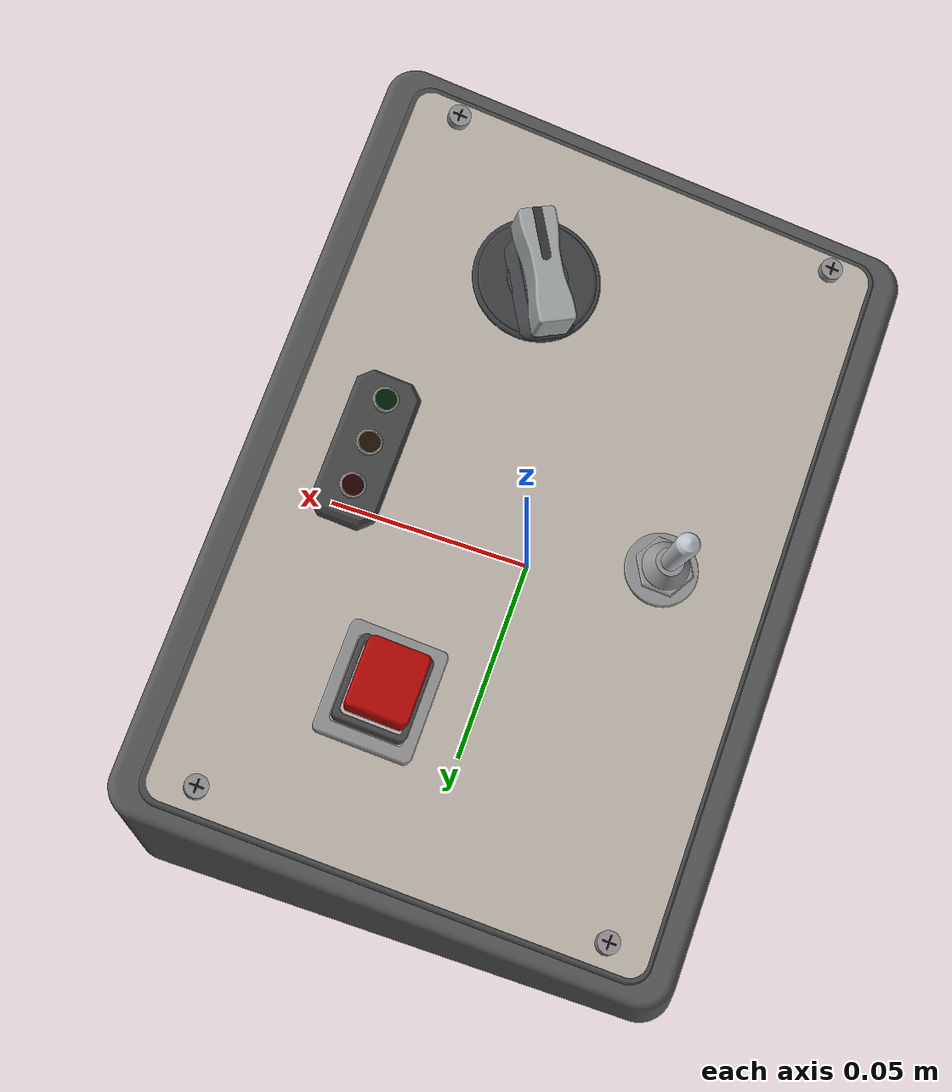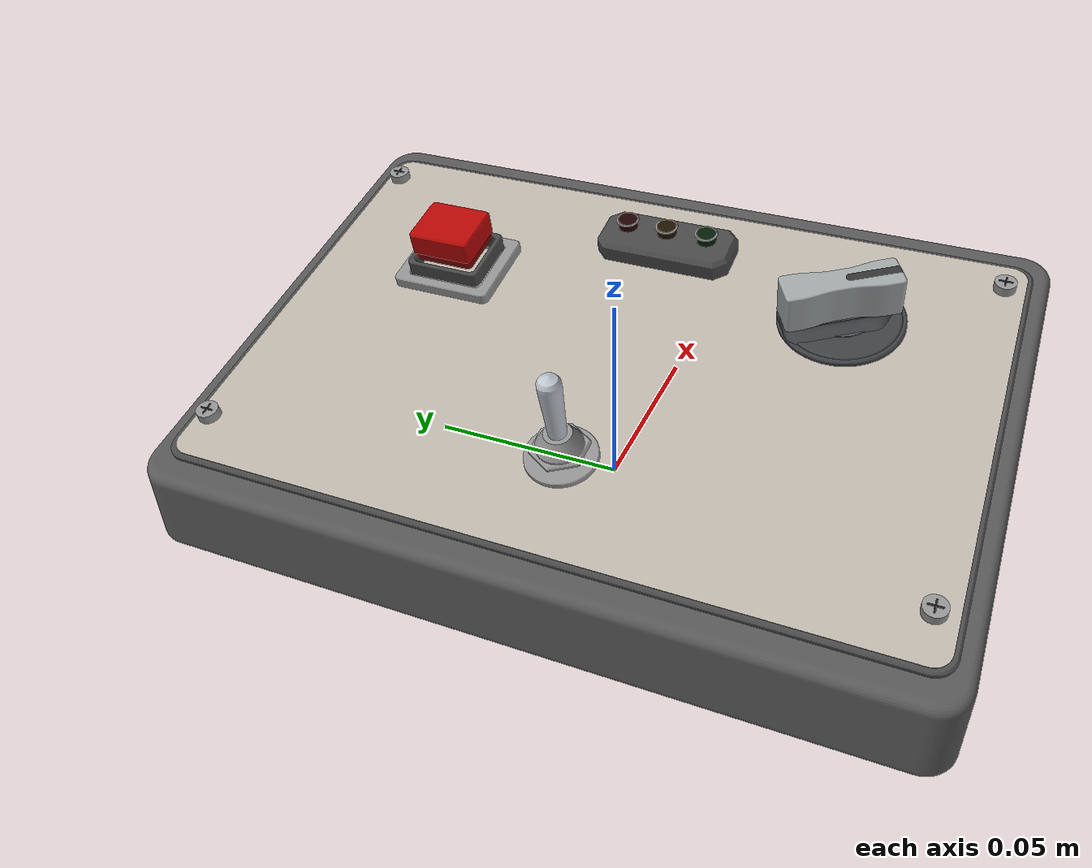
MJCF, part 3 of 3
0.861005766353 -0.151395089377 0.500596221079 0.852339691915 -0.107451658795 0.495429468081 0.861976672097 -0.09064861026 0.494398298963 0.864495894438 -0.104144985007 0.492596022265 0.864004039924 -0.107451658795 0.495429468081 0.861976672097 -0.151395089377 0.500596221079 0.852339691915 -0.113441898793 0.505342136604 0.855429868914 -0.09064861026 0.494398298963 0.864495894438 -0.107451658795 0.495429468081 0.861976672097 -0.113441898793 0.505342136604 0.855429868914 -0.100192794283 0.507242982641 0.855959088154 -0.539270425953 0.449965571934 0.711841549665 -0.540351275635 0.446388616462 0.713272530016 -0.540929804109 0.444964118462 0.713723952499 -0.538039285965 0.454463815808 0.709912929128 -0.539270425953 0.449965571934 0.711841549665 -0.539274925996 0.449948283332 0.71184906868 -0.540348321753 0.446395878048 0.7132702232 -0.540351275635 0.446388616462 0.713272530016 -0.539274925996 0.449948283332 0.71184906868 -0.539279408106 0.449931052315 0.711856564357 -0.540345367872 0.446403139513 0.713267916365 -0.540348321753 0.446395878048 0.7132702232 -0.539279408106 0.449931052315 0.711856564357 -0.539283872285 0.449913878881 0.7118640367 -0.540342413992 0.446410400858 0.713265609511 -0.540345367872 0.446403139513 0.713267916365 -0.539283872285 0.449913878881 0.7118640367 -0.539288318534 0.449896763032 0.711871485711 -0.540339460112 0.446417662081 0.713263302638 -0.540342413992 0.446410400858 0.713265609511 -0.539288318534 0.449896763032 0.711871485711 -0.539292746856 0.449879704767 0.711878911396 -0.540336506234 0.446424923185 0.713260995747 -0.540339460112 0.446417662081 0.713263302638 -0.539292746856 0.449879704767 0.711878911396 -0.539297157254 0.449862704086 0.711886313756 -0.540333552357 0.446432184167 0.713258688836 -0.540336506234 0.446424923185 0.713260995747 -0.539297157254 0.449862704086 0.711886313756 -0.539301549729 0.44984576099 0.711893692795 -0.54033059848 0.446439445029 0.713256381907 -0.540333552357 0.446432184167 0.713258688836 -0.539301549729 0.44984576099 0.711893692795 -0.539305924283 0.44982887548 0.711901048518 -0.540327644604 0.44644670577 0.71325407496 -0.54033059848 0.446439445029 0.713256381907 -0.539305924283 0.44982887548 0.711901048518 -0.539310280919 0.449812047554 0.711908380926 -0.540324690729 0.446453966391 0.713251767993 -0.540327644604 0.44644670577 0.71325407496 -0.539310280919 0.449812047554 0.711908380926 -0.539314619639 0.449795277213 0.711915690024 -0.540321736855 0.446461226891 0.713249461008 -0.540324690729 0.446453966391 0.713251767993 -0.539314619639 0.449795277213 0.711915690024 -0.539318940445 0.449778564459 0.711922975815 -0.540318782982 0.44646848727 0.713247154004 -0.540321736855 0.446461226891 0.713249461008 -0.539318940445 0.449778564459 0.711922975815 -0.539323243338 0.449761909291 0.711930238302 -0.54031582911 0.446475747528 0.713244846981 -0.540318782982 0.44646848727 0.713247154004 -0.539323243338 0.449761909291 0.711930238302 -0.539327528322 0.449745311709 0.711937477489 -0.540312875239 0.446483007666 0.71324253994 -0.54031582911 0.446475747528 0.713244846981 -0.539327528322 0.449745311709 0.711937477489 -0.539331795397 0.449728771714 0.711944693378 -0.540309921369 0.446490267683 0.713240232879 -0.540312875239 0.446483007666 0.71324253994 -0.539331795397 0.449728771714 0.711944693378 -0.539336044566 0.449712289307 0.711951885973 -0.540306967499 0.44649752758 0.713237925801 -0.540309921369 0.446490267683 0.713240232879 -0.539336044566 0.449712289307 0.711951885973 -0.539340275832 0.449695864487 0.711959055278 -0.540304013631 0.446504787355 0.713235618703 -0.540306967499 0.44649752758 0.713237925801 -0.539340275832 0.449695864487 0.711959055278 -0.539344489195 0.449679497257 0.711966201294 -0.540301059763 0.446512047011 0.713233311586 -0.540304013631 0.446504787355 0.713235618703 -0.539344489195 0.449679497257 0.711966201294 -0.539348684658 0.449663187615 0.711973324026 -0.540298105896 0.446519306545 0.713231004451 -0.540301059763 0.446512047011 0.713233311586 -0.539348684658 0.449663187615 0.711973324026 -0.539724613781 0.448115320782 0.712664016646 -0.539940695077 0.447396820014 0.712951703346 -0.540298105896 0.446519306545 0.713231004451 -0.539724613781 0.448115320782 0.712664016646 -0.484809046471 0.448437235082 0.75090893903 -0.484747924456 0.447803638247 0.751326394699 -0.539940695077 0.447396820014 0.712951703346 -0.484809046471 0.448437235082 0.75090893903 -0.431542625965 0.449681387677 0.782021490507 -0.431279275795 0.449120468586 0.782488971826 -0.484747924456 0.447803638247 0.751326394699 -0.431542625965 0.449681387677 0.782021490507 -0.38014528528 0.452041191524 0.806937620456 -0.379756492065 0.451549033758 0.80739610905 -0.431279275795 0.449120468586 0.782488971826 -0.38014528528 0.452041191524 0.806937620456 -0.330733381512 0.455660760576 0.826431304881 -0.330292741333 0.455239653189 0.826839502715 -0.379756492065 0.451549033758 0.80739610905 -0.330733381512 0.455660760576 0.826431304881 -0.283376010211 0.460655322231 0.841127048073 -0.282950918598 0.460312185549 0.841457942836 -0.330292741333 0.455239653189 0.826839502715 -0.283376010211 0.460655322231 0.841127048073 -0.238135356807 0.46712680747 0.851518700701 -0.237785339694 0.466872031811 0.851756208197 -0.282950918598 0.460312185549 0.841457942836 -0.238135356807 0.46712680747 0.851518700701 -0.195096056868 0.475175735486 0.857989247637 -0.194871969604 0.475022296805 0.858125126693 -0.237785339694 0.466872031811 0.851756208197 -0.195096056868 0.475175735486 0.857989247637 -0.154387724078 0.48491044706 0.860828838415 -0.154331501004 0.484873169617 0.860859917318 -0.194871969604 0.475022296805 0.858125126693 -0.154387724078 0.48491044706 0.860828838415 -0.142852523835 0.488121118987 0.861005766353 -0.154331501004 0.484873169617 0.860859917318 -0.539270425953 0.449965571934 0.711841549665 -0.538039285965 0.454463815808 0.709912929128 -0.537387978337 0.456093321945 0.709361009979 -0.539274925996 0.449948283332 0.71184906868 -0.539270425953 0.449965571934 0.711841549665 -0.537387978337 0.456093321945 0.709361009979 -0.537384652745 0.456101626629 0.709358189664 -0.539279408106 0.449931052315 0.711856564357 -0.539274925996 0.449948283332 0.71184906868 -0.537384652745 0.456101626629 0.709358189664 -0.537381327152 0.456109931155 0.709355369326 -0.539283872285 0.449913878881 0.7118640367 -0.539279408106 0.449931052315 0.711856564357 -0.537381327152 0.456109931155 0.709355369326 -0.537378001559 0.456118235524 0.709352548966 -0.539288318534 0.449896763032 0.711871485711 -0.539283872285 0.449913878881 0.7118640367 -0.537378001559 0.456118235524 0.709352548966 -0.537374675967 0.456126539734 0.709349728584 -0.539292746856 0.449879704767 0.711878911396 -0.539288318534 0.449896763032 0.711871485711 -0.537374675967 0.456126539734 0.709349728584 -0.537371350374 0.456134843786 0.70934690818 -0.539297157254 0.449862704086 0.711886313756 -0.539292746856 0.449879704767 0.711878911396 -0.537371350374 0.456134843786 0.70934690818 -0.53736802478 0.456143147681 0.709344087753 -0.539301549729 0.44984576099 0.711893692795 -0.539297157254 0.449862704086 0.711886313756 -0.53736802478 0.456143147681 0.709344087753 -0.537364699187 0.456151451417 0.709341267303 -0.539305924283 0.44982887548 0.711901048518 -0.539301549729 0.44984576099 0.711893692795 -0.537364699187 0.456151451417 0.709341267303 -0.537361373594 0.456159754996 0.709338446832 -0.539310280919 0.449812047554 0.711908380926 -0.539305924283 0.44982887548 0.711901048518 -0.537361373594 0.456159754996 0.709338446832 -0.537358048001 0.456168058417 0.709335626338 -0.539314619639 0.449795277213 0.711915690024 -0.539310280919 0.449812047554 0.711908380926 -0.537358048001 0.456168058417 0.709335626338 -0.537354722407 0.456176361679 0.709332805821 -0.539318940445 0.449778564459 0.711922975815 -0.539314619639 0.449795277213 0.711915690024 -0.537354722407 0.456176361679 0.709332805821 -0.537351396814 0.456184664784 0.709329985282 -0.539323243338 0.449761909291 0.711930238302 -0.539318940445 0.449778564459 0.711922975815 -0.537351396814 0.456184664784 0.709329985282 -0.53734807122 0.456192967731 0.709327164721 -0.539327528322 0.449745311709 0.711937477489 -0.539323243338 0.449761909291 0.711930238302 -0.53734807122 0.456192967731 0.709327164721 -0.537344745626 0.45620127052 0.709324344137 -0.539331795397 0.449728771714 0.711944693378 -0.539327528322 0.449745311709 0.711937477489 -0.537344745626 0.45620127052 0.709324344137 -0.537341420033 0.456209573151 0.709321523531 -0.539336044566 0.449712289307 0.711951885973 -0.539331795397 0.449728771714 0.711944693378 -0.537341420033 0.456209573151 0.709321523531 -0.537338094439 0.456217875624 0.709318702903 -0.539340275832 0.449695864487 0.711959055278 -0.539336044566 0.449712289307 0.711951885973 -0.537338094439 0.456217875624 0.709318702903 -0.537334768845 0.456226177939 0.709315882252 -0.539344489195 0.449679497257 0.711966201294 -0.539340275832 0.449695864487 0.711959055278 -0.537334768845 0.456226177939 0.709315882252 -0.537331443251 0.456234480097 0.709313061579 -0.539348684658 0.449663187615 0.711973324026 -0.539344489195 0.449679497257 0.711966201294 -0.537331443251 0.456234480097 0.709313061579 -0.537328117657 0.456242782096 0.709310240884 -0.539724613781 0.448115320782 0.712664016646 -0.539348684658 0.449663187615 0.711973324026 -0.537328117657 0.456242782096 0.709310240884 -0.536925720836 0.457246159086 0.708968772491 -0.484809046471 0.448437235082 0.75090893903 -0.539724613781 0.448115320782 0.712664016646 -0.536925720836 0.457246159086 0.708968772491 -0.483561310148 0.457718454435 0.746098033679 -0.431542625965 0.449681387677 0.782021490507 -0.484809046471 0.448437235082 0.75090893903 -0.483561310148 0.457718454435 0.746098033679 -0.431850845442 0.459203405217 0.776297030775 -0.38014528528 0.452041191524 0.806937620456 -0.431542625965 0.449681387677 0.782021490507 -0.431850845442 0.459203405217 0.776297030775 -0.381975320793 0.461882138017 0.800474699755 -0.330733381512 0.455660760576 0.826431304881 -0.38014528528 0.452041191524 0.806937620456 -0.381975320793 0.461882138017 0.800474699755 -0.334024271732 0.46588872797 0.819375053993 -0.283376010211 0.460655322231 0.841127048073 -0.330733381512 0.455660760576 0.826431304881 -0.334024271732 0.46588872797 0.819375053993 -0.288048663334 0.471330042505 0.833592201646 -0.238135356807 0.46712680747 0.851518700701 -0.283376010211 0.460655322231 0.841127048073 -0.288048663334 0.471330042505 0.833592201646 -0.244098605324 0.478300567233 0.84359020758 -0.195096056868 0.475175735486 0.857989247637 -0.238135356807 0.46712680747 0.851518700701 -0.244098605324 0.478300567233 0.84359020758 -0.202250830119 0.486893435799 0.849723121936 -0.154387724078 0.48491044706 0.860828838415 -0.195096056868 0.475175735486 0.857989247637 -0.202250830119 0.486893435799 0.849723121936 -0.162629924801 0.497208730407 0.85225288854 -0.142852523835 0.488121118987 0.861005766353 -0.154387724078 0.48491044706 0.860828838415 -0.162629924801 0.497208730407 0.85225288854 -0.151395089377 0.500596221079 0.852339691915 -0.540929804109 0.444964118462 0.713723952499 -0.560795526861 0.446515725083 0.697231729319 -0.557534730908 0.456239176398 0.693542239387 -0.540929804109 0.444964118462 0.713723952499 -0.557534730908 0.456239176398 0.693542239387 -0.538039285965 0.454463815808 0.709912929128 -0.560795526861 0.446515725083 0.697231729319 -0.580881723703 0.447017010954 0.680258932355 -0.577315382988 0.45681751027 0.676775229259 -0.560795526861 0.446515725083 0.697231729319 -0.577315382988 0.45681751027 0.676775229259 -0.557534730908 0.456239176398 0.693542239387 -0.580881723703 0.447017010954 0.680258932355 -0.60082923304 0.447829989522 0.66215748374 -0.596954496309 0.457759227817 0.658864036617 -0.580881723703 0.447017010954 0.680258932355 -0.596954496309 0.457759227817 0.658864036617 -0.577315382988 0.45681751027 0.676775229259 -0.60082923304 0.447829989522 0.66215748374 -0.620829686154 0.448915705263 0.642685918954 -0.616646768486 0.459025316104 0.639564322139 -0.60082923304 0.447829989522 0.66215748374 -0.616646768486 0.459025316104 0.639564322139 -0.596954496309 0.457759227817 0.658864036617 -0.620829686154 0.448915705263 0.642685918954 -0.641064751506 0.450215092661 0.621564441373 -0.636577398505 0.460556392293 0.618592778242 -0.620829686154 0.448915705263 0.642685918954 -0.636577398505 0.460556392293 0.618592778242 -0.616646768486 0.459025316104 0.639564322139 -0.641064751506 0.450215092661 0.621564441373 -0.661705898859 0.451643976455 0.598467227182 -0.656922044927 0.462267423571 0.59561922069 -0.641064751506 0.450215092661 0.621564441373 -0.656922044927 0.462267423571 0.59561922069 -0.636577398505 0.460556392293 0.618592778242 -0.661705898859 0.451643976455 0.598467227182 -0.682911979846 0.45308596066 0.57301338562 -0.677844598623 0.464040192586 0.570257310207 -0.661705898859 0.451643976455 0.598467227182 -0.677844598623 0.464040192586 0.570257310207 -0.656922044927 0.462267423571 0.59561922069 -0.682911979846 0.45308596066 0.57301338562 -0.704823713241 0.45438266066 0.544756763159 -0.699491841828 0.465712907273 0.542054103645 -0.682911979846 0.45308596066 0.57301338562 -0.699491841828 0.465712907273 0.542054103645 -0.677844598623 0.464040192586 0.570257310207 -0.704823713241 0.45438266066 0.544756763159 -0.72755371316 0.455320606844 0.51317515481 -0.721983598034 0.467066209106 0.510479030463 -0.704823713241 0.45438266066 0.544756763159 -0.721983598034 0.467066209106 0.510479030463 -0.699491841828 0.465712907273 0.542054103645 -0.72755371316 0.455320606844 0.51317515481 -0.75117011131 0.455614088943 0.477660199194 -0.745396363675 0.467804756602 0.474913645606 -0.72755371316 0.455320606844 0.51317515481 -0.745396363675 0.467804756602 0.474913645606 -0.721983598034 0.467066209106 0.510479030463 -0.75117011131 0.455614088943 0.477660199194 -0.775671134303 0.454883336769 0.437510504332 -0.769737686644 0.46753368132 0.434644855776 -0.75117011131 0.455614088943 0.477660199194 -0.769737686644 0.46753368132 0.434644855776 -0.745396363675 0.467804756602 0.474913645606 -0.775671134303 0.454883336769 0.437510504332 -0.800947366366 0.452627983637 0.391932678917 -0.794907886575 0.46572979354 0.388866572659 -0.775671134303 0.454883336769 0.437510504332 -0.794907886575 0.46572979354 0.388866572659 -0.769737686644 0.46753368132 0.434644855776 -0.800947366366 0.452627983637 0.391932678917 -0.82672830264 0.448197161168 0.340058257357 -0.820645567925 0.461708929855 0.336698256603 -0.800947366366 0.452627983637 0.391932678917 -0.820645567925 0.461708929855 0.336698256603 -0.794907886575 0.46572979354 0.388866572659 -0.82672830264 0.448197161168 0.340058257357 -0.852511168639 0.44076050322 0.28098912116 -0.846454809611 0.454594040159 0.277233681216 -0.82672830264 0.448197161168 0.340058257357 -0.846454809611 0.454594040159 0.277233681216 -0.820645567925 0.461708929855 0.336698256603 -0.852511168639 0.44076050322 0.28098912116 -0.877474686839 0.429289624486 0.213889205733 -0.87151688375 0.443294443738 0.209638635641 -0.852511168639 0.44076050322 0.28098912116 -0.87151688375 0.443294443738 0.209638635641 -0.846454809611 0.454594040159 0.277233681216 -0.877474686839 0.429289624486 0.213889205733 -0.90039121467 0.412567720089 0.138143175552 -0.894600728604 0.426515627935 0.133318999297 -0.877474686839 0.429289624486 0.213889205733 -0.894600728604 0.426515627935 0.133318999297 -0.87151688375 0.443294443738 0.209638635641 -0.90039121467 0.412567720089 0.138143175552 -0.919569746723 0.389254273866 0.0535965601039 -0.914006525496 0.402829258718 0.0481732263586 -0.90039121467 0.412567720089 0.138143175552 -0.914006525496 0.402829258718 0.0481732263586 -0.894600728604 0.426515627935 0.133318999297 -0.919569746723 0.389254273866 0.0535965601039 -0.932887244193 0.358036132667 -0.0391346061026 -0.927602708004 0.370837498465 -0.0450862052622 -0.919569746723 0.389254273866 0.0535965601039 -0.927602708004 0.370837498465 -0.0450862052622 -0.914006525496 0.402829258718 0.0481732263586 -0.932887244193 0.358036132667 -0.0391346061026 -0.93798160885 0.317882091939 -0.138352727311 -0.933031955029 0.329449273244 -0.14461862717 -0.932887244193 0.358036132667 -0.0391346061026 -0.933031955029 0.329449273244 -0.14461862717 -0.927602708004 0.370837498465 -0.0450862052622 -0.93798160885 0.317882091939 -0.138352727311 -0.932654133337 0.268370699879 -0.241108761951 -0.928131652072 0.278232578635 -0.247301978725 -0.93798160885 0.317882091939 -0.138352727311 -0.928131652072 0.278232578635 -0.247301978725 -0.933031955029 0.329449273244 -0.14461862717 -0.932654133337 0.268370699879 -0.241108761951 -0.915431475152 0.20998495862 -0.343353362486 -0.911508271811 0.217723500826 -0.348925705105 -0.932654133337 0.268370699879 -0.241108761951 -0.911508271811 0.217723500826 -0.348925705105 -0.928131652072 0.278232578635 -0.247301978725 -0.915431475152 0.20998495862 -0.343353362486 -0.886091557728 0.144213660956 -0.440504451049 -0.883055046935 0.149518245076 -0.444812408268 -0.915431475152 0.20998495862 -0.343353362486 -0.883055046935 0.149518245076 -0.444812408268 -0.911508271811 0.217723500826 -0.348925705105 -0.886091557728 0.144213660956 -0.440504451049 -0.845881415845 0.0733453383652 -0.528303976652 -0.844135948542 0.0760337582363 -0.530710248692 -0.886091557728 0.144213660956 -0.440504451049 -0.844135948542 0.0760337582363 -0.530710248692 -0.883055046935 0.149518245076 -0.444812408268 -0.845881415845 0.0733453383652 -0.528303976652 -0.798679356623 0.00224989215894 -0.601752626391 -0.798704366808 0.00246238287668 -0.60171859801 -0.845881415845 0.0733453383652 -0.528303976652 -0.798704366808 0.00246238287668 -0.60171859801 -0.844135948542 0.0760337582363 -0.530710248692 -0.798679356623 0.00224989215894 -0.601752626391 -0.798601379777 -0.00216877147368 -0.601856405405 -0.798622218955 -0.00237517826911 -0.601827973758 -0.798679356623 0.00224989215894 -0.601752626391 -0.798622218955 -0.00237517826911 -0.601827973758 -0.798704366808 0.00246238287668 -0.60171859801 -0.798601379777 -0.00216877147368 -0.601856405405 -0.845571311096 -0.0733491874418 -0.528799635619 -0.843780012936 -0.076038161215 -0.531275340936 -0.798601379777 -0.00216877147368 -0.601856405405 -0.843780012936 -0.076038161215 -0.531275340936 -0.798622218955 -0.00237517826911 -0.601827973758 -0.845571311096 -0.0733491874418 -0.528799635619 -0.885838058248 -0.144228883423 -0.441009029186 -0.882762081995 -0.149535749335 -0.445387658495 -0.845571311096 -0.0733491874418 -0.528799635619 -0.882762081995 -0.149535749335 -0.445387658495 -0.843780012936 -0.076038161215 -0.531275340936 -0.885838058248 -0.144228883423 -0.441009029186 -0.915238403972 -0.210017389873 -0.343847873224 -0.911283107295 -0.21776096528 -0.349490000479 -0.885838058248 -0.144228883423 -0.441009029186 -0.911283107295 -0.21776096528 -0.349490000479 -0.882762081995 -0.149535749335 -0.445387658495 -0.915238403972 -0.210017389873 -0.343847873224 -0.932518526455 -0.268422990825 -0.241574617639 -0.927971482183 -0.278293207477 -0.247834257117 -0.915238403972 -0.210017389873 -0.343847873224 -0.927971482183 -0.278293207477 -0.247834257117 -0.911283107295 -0.21776096528 -0.349490000479 -0.932518526455 -0.268422990825 -0.241574617639 -0.937895032225 -0.317953304971 -0.138775374097 -0.932927651678 -0.329532053812 -0.145102109965 -0.932518526455 -0.268422990825 -0.241574617639 -0.932927651678 -0.329532053812 -0.145102109965 -0.927971482183 -0.278293207477 -0.247834257117 -0.937895032225 -0.317953304971 -0.138775374097 -0.932838449733 -0.358122517097 -0.0395055631022 -0.92754175809 -0.370938058876 -0.0455109167625 -0.937895032225 -0.317953304971 -0.138775374097 -0.92754175809 -0.370938058876 -0.0455109167625 -0.932927651678 -0.329532053812 -0.145102109965 -0.932838449733 -0.358122517097 -0.0395055631022 -0.919547353708 -0.389350661636 0.0532797019396 -0.913976102145 -0.402941510046 0.0478102944559 -0.932838449733 -0.358122517097 -0.0395055631022 -0.913976102145 -0.402941510046 0.0478102944559 -0.92754175809 -0.370938058876 -0.0455109167625 -0.919547353708 -0.389350661636 0.0532797019396 -0.900385493074 -0.412668844371 0.137878166555 -0.894589785084 -0.426633346331 0.133015428754 -0.919547353708 -0.389350661636 0.0532797019396 -0.894589785084 -0.426633346331 0.133015428754 -0.913976102145 -0.402941510046 0.0478102944559 -0.900385493074 -0.412668844371 0.137878166555 -0.877478265073 -0.429390966294 0.213670991139 -0.871517014991 -0.443412295287 0.209388703212 -0.900385493074 -0.412668844371 0.137878166555 -0.871517014991 -0.443412295287 0.209388703212 -0.894589785084 -0.426633346331 0.133015428754 -0.877478265073 -0.429390966294 0.213670991139 -0.852518972637 -0.440858632967 0.280811444024 -0.846460213453 -0.454707995168 0.277030226211 -0.877478265073 -0.429390966294 0.213670991139 -0.846460213453 -0.454707995168 0.277030226211 -0.871517014991 -0.443412295287 0.209388703212 -0.852518972637 -0.440858632967 0.280811444024 -0.826737128283 -0.448289731203 0.339914750605 -0.820652569382 -0.46181625256 0.336533964557 -0.852518972637 -0.440858632967 0.280811444024 -0.820652569382 -0.46181625256 0.336533964557 -0.846460213453 -0.454707995168 0.277030226211 -0.826737128283 -0.448289731203 0.339914750605 -0.800955372747 -0.452713549366 0.39181747428 -0.794914362724 -0.465828823865 0.388734694687 -0.826737128283 -0.448289731203 0.339914750605 -0.794914362724 -0.465828823865 0.388734694687 -0.820652569382 -0.46181625256 0.336533964557 -0.800955372747 -0.452713549366 0.39181747428 -0.775677400876 -0.45496113073 0.43741849453 -0.769742561659 -0.467623560841 0.434539519697 -0.800955372747 -0.452713549366 0.39181747428 -0.769742561659 -0.467623560841 0.434539519697 -0.794914362724 -0.465828823865 0.388734694687 -0.775677400876 -0.45496113073 0.43741849453 -0.751174302885 -0.455683812512 0.477587091286 -0.745399226817 -0.467885177412 0.474829920583 -0.775677400876 -0.45496113073 0.43741849453 -0.745399226817 -0.467885177412 0.474829920583 -0.769742561659 -0.467623560841 0.434539519697 -0.751174302885 -0.455683812512 0.477587091286 -0.727555847717 -0.455382263331 0.513117416152 -0.721984439413 -0.467137213919 0.510412864923 -0.751174302885 -0.455683812512 0.477587091286 -0.721984439413 -0.467137213919 0.510412864923 -0.745399226817 -0.467885177412 0.474829920583 -0.727555847717 -0.455382263331 0.513117416152 -0.704824010728 -0.454436431947 0.544711522994 -0.69949088084 -0.465774742784 0.542002210943 -0.727555847717 -0.455382263331 0.513117416152 -0.69949088084 -0.465774742784 0.542002210943 -0.721984439413 -0.467137213919 0.510412864923 -0.704824010728 -0.454436431947 0.544711522994 -0.682910768841 -0.453132120727 0.572978326841 -0.677842178416 -0.464093207544 0.570217042831 -0.704824010728 -0.454436431947 0.544711522994 -0.677842178416 -0.464093207544 0.570217042831 -0.69949088084 -0.465774742784 0.542002210943 -0.682910768841 -0.453132120727 0.572978326841 -0.661703562283 -0.451682833082 0.598440484948 -0.656918571246 -0.462312000692 0.595588452566 -0.682910768841 -0.453132120727 0.572978326841 -0.656918571246 -0.462312000692 0.595588452566 -0.677842178416 -0.464093207544 0.570217042831 -0.661703562283 -0.451682833082 0.598440484948 -0.641061697791 -0.450246949329 0.621544515147 -0.636573307348 -0.460592904259 0.618569802836 -0.661703562283 -0.451682833082 0.598440484948 -0.636573307348 -0.460592904259 0.618569802836 -0.656918571246 -0.462312000692 0.595588452566 -0.641061697791 -0.450246949329 0.621544515147 -0.620826336712 -0.448940836946 0.642671599365 -0.616642512132 -0.459054097956 0.639547767914 -0.641061697791 -0.450246949329 0.621544515147 -0.616642512132 -0.459054097956 0.639547767914 -0.636573307348 -0.460592904259 0.618569802836 -0.620826336712 -0.448940836946 0.642671599365 -0.600826020177 -0.44784862775 0.662147793293 -0.59695054106 -0.457780560183 0.658852798666 -0.620826336712 -0.448940836946 0.642671599365 -0.59695054106 -0.457780560183 0.658852798666 -0.616642512132 -0.459054097956 0.639547767914 -0.600826020177 -0.44784862775 0.662147793293 -0.58087909542 -0.447029334876 0.680253078146 -0.577312214643 -0.456831609509 0.676768414924 -0.600826020177 -0.44784862775 0.662147793293 -0.577312214643 -0.456831609509 0.676768414924 -0.59695054106 -0.457780560183 0.658852798666 -0.58087909542 -0.447029334876 0.680253078146 -0.560793956537 -0.446521856341 0.697229065791 -0.557532865708 -0.456246189074 0.693539125553 -0.58087909542 -0.447029334876 0.680253078146 -0.557532865708 -0.456246189074 0.693539125553 -0.577312214643 -0.456831609509 0.676768414924 -0.560793956537 -0.446521856341 0.697229065791 -0.540094620278 -0.447739971871 0.712619617187 -0.537057920132 -0.457638450531 0.708615438078 -0.560793956537 -0.446521856341 0.697229065791 -0.537057920132 -0.457638450531 0.708615438078 -0.557532865708 -0.456246189074 0.693539125553 -0.539216989504 -0.45013206058 0.711776767204 -0.540094620278 -0.447739971871 0.712619617187 -0.540373240621 -0.446319879524 0.713298903704 -0.53921078498 -0.450149951808 0.711770152726 -0.539216989504 -0.45013206058 0.711776767204 -0.540373240621 -0.446319879524 0.713298903704 -0.54037466146 -0.446312616675 0.713302371727 -0.539204562811 -0.450167900622 0.711763514629 -0.53921078498 -0.450149951808 0.711770152726 -0.54037466146 -0.446312616675 0.713302371727 -0.540376082281 -0.446305353705 0.713305839747 -0.539198322994 -0.450185907022 0.711756852908 -0.539204562811 -0.450167900622 0.711763514629 -0.540376082281 -0.446305353705 0.713305839747 -0.540377503083 -0.446298090614 0.713309307761 -0.539192065525 -0.450203971011 0.711750167561 -0.539198322994 -0.450185907022 0.711756852908 -0.540377503083 -0.446298090614 0.713309307761 -0.540378923866 -0.446290827403 0.713312775772 -0.539185790402 -0.450222092587 0.711743458585 -0.539192065525 -0.450203971011 0.711750167561 -0.540378923866 -0.446290827403 0.713312775772 -0.540380344632 -0.446283564072 0.713316243778 -0.539179497622 -0.450240271751 0.711736725974 -0.539185790402 -0.450222092587 0.711743458585 -0.540380344632 -0.446283564072 0.713316243778 -0.540381765379 -0.446276300619 0.713319711781 -0.53917318718 -0.450258508504 0.711729969727 -0.539179497622 -0.450240271751 0.711736725974 -0.540381765379 -0.446276300619 0.713319711781 -0.540383186108 -0.446269037046 0.713323179778 -0.539166859075 -0.450276802847 0.711723189839 -0.53917318718 -0.450258508504 0.711729969727 -0.540383186108 -0.446269037046 0.713323179778 -0.540384606818 -0.446261773352 0.713326647772 -0.539160513303 -0.45029515478 0.711716386308 -0.539166859075 -0.450276802847 0.711723189839 -0.540384606818 -0.446261773352 0.713326647772 -0.540386027511 -0.446254509537 0.713330115761 -0.539154149861 -0.450313564305 0.711709559128 -0.539160513303 -0.45029515478 0.711716386308 -0.540386027511 -0.446254509537 0.713330115761 -0.540387448184 -0.446247245602 0.713333583746 -0.539147768745 -0.45033203142 0.711702708297 -0.539154149861 -0.450313564305 0.711709559128 -0.540387448184 -0.446247245602 0.713333583746 -0.54038886884 -0.446239981546 0.713337051727 -0.539141369953 -0.450350556128 0.711695833811 -0.539147768745 -0.45033203142 0.711702708297 -0.54038886884 -0.446239981546 0.713337051727 -0.540390289477 -0.446232717369 0.713340519704 -0.539134953481 -0.45036913843 0.711688935665 -0.539141369953 -0.450350556128 0.711695833811 -0.540390289477 -0.446232717369 0.713340519704 -0.540391710096 -0.446225453071 0.713343987676 -0.539128519325 -0.450387778325 0.711682013858 -0.539134953481 -0.45036913843 0.711688935665 -0.540391710096 -0.446225453071 0.713343987676 -0.540393130697 -0.446218188653 0.713347455644 -0.539122067483 -0.450406475815 0.711675068384 -0.539128519325 -0.450387778325 0.711682013858 -0.540393130697 -0.446218188653 0.713347455644 -0.540394551279 -0.446210924114 0.713350923608 -0.539115597952 -0.450425230901 0.71166809924 -0.539122067483 -0.450406475815 0.711675068384 -0.540394551279 -0.446210924114 0.713350923608 -0.540395971843 -0.446203659455 0.713354391568 -0.539109110727 -0.450444043584 0.711661106421 -0.539115597952 -0.450425230901 0.71166809924 -0.540395971843 -0.446203659455 0.713354391568 -0.540397392388 -0.446196394674 0.713357859523 -0.539102605807 -0.450462913865 0.711654089926 -0.539109110727 -0.450444043584 0.711661106421 -0.540397392388 -0.446196394674 0.713357859523 -0.540398812915 -0.446189129773 0.713361327474 -0.538183693841 -0.453171991815 0.710628916932 -0.539102605807 -0.450462913865 0.711654089926 -0.540398812915 -0.446189129773 0.713361327474 -0.54057056098 -0.445309185268 0.713780917496 -0.484928774856 -0.453753327546 0.747630925738 -0.538183693841 -0.453171991815 0.710628916932 -0.54057056098 -0.445309185268 0.713780917496 -0.485674769651 -0.44564437803 0.752011373929 -0.433391075429 -0.455364729259 0.77769861717 -0.484928774856 -0.453753327546 0.747630925738 -0.485674769651 -0.44564437803 0.752011373929 -0.432516646972 -0.446909323594 0.783071776174 -0.383738780592 -0.458187865735 0.801753346127 -0.433391075429 -0.455364729259 0.77769861717 -0.432516646972 -0.446909323594 0.783071776174 -0.381306960953 -0.449302078421 0.807918711207 -0.336048487362 -0.462357189583 0.820546917272 -0.383738780592 -0.458187865735 0.801753346127 -0.381306960953 -0.449302078421 0.807918711207 -0.332150013896 -0.452970002192 0.827341855248 -0.290358823394 -0.467979924443 0.834677509016 -0.336048487362 -0.462357189583 0.820546917272 -0.332150013896 -0.452970002192 0.827341855248 -0.285101561745 -0.458030636435 0.841976861701 -0.246708505705 -0.47515090622 0.84461028267 -0.290358823394 -0.467979924443 0.834677509016 -0.285101561745 -0.458030636435 0.841976861701 -0.240210148038 -0.464587582358 0.852324740436 -0.205163966504 -0.483963536265 0.85069797371 -0.246708505705 -0.47515090622 0.84461028267 -0.240210148038 -0.464587582358 0.852324740436 -0.197547056774 -0.472742518877 0.858772188224 -0.165840651335 -0.494517933195 0.853199210134 -0.205163966504 -0.483963536265 0.85069797371 -0.197547056774 -0.472742518877 0.858772188224 -0.157229213812 -0.482604440568 0.861610079055 -0.165840651335 -0.494517933195 0.853199210134 -0.157229213812 -0.482604440568 0.861610079055 -0.145810167565 -0.485856705923 0.861790378459 -0.154691318447 -0.49797959518 0.853280094014 -0.540094620278 -0.447739971871 0.712619617187 -0.539216989504 -0.45013206058 0.711776767204 -0.537413700706 -0.45601471023 0.709392062551 -0.537057920132 -0.457638450531 0.708615438078 -0.539216989504 -0.45013206058 0.711776767204 -0.53921078498 -0.450149951808 0.711770152726 -0.537415515209 -0.456006403892 0.709396027395 -0.537413700706 -0.45601471023 0.709392062551 -0.53921078498 -0.450149951808 0.711770152726 -0.539204562811 -0.450167900622 0.711763514629 -0.537417329691 -0.455998097397 0.709399992233 -0.537415515209 -0.456006403892 0.709396027395 -0.539204562811 -0.450167900622 0.711763514629 -0.539198322994 -0.450185907022 0.711756852908 -0.537419144151 -0.455989790744 0.709403957065 -0.537417329691 -0.455998097397 0.709399992233 -0.539198322994 -0.450185907022 0.711756852908 -0.539192065525 -0.450203971011 0.711750167561 -0.537420958589 -0.455981483933 0.709407921891 -0.537419144151 -0.455989790744 0.709403957065 -0.539192065525 -0.450203971011 0.711750167561 -0.539185790402 -0.450222092587 0.711743458585 -0.537422773006 -0.455973176964 0.709411886711 -0.537420958589 -0.455981483933 0.709407921891 -0.539185790402 -0.450222092587 0.711743458585 -0.539179497622 -0.450240271751 0.711736725974 -0.537424587401 -0.455964869837 0.709415851524 -0.537422773006 -0.455973176964 0.709411886711 -0.539179497622 -0.450240271751 0.711736725974 -0.53917318718 -0.450258508504 0.711729969727 -0.537426401775 -0.455956562552 0.709419816331 -0.537424587401 -0.455964869837 0.709415851524 -0.53917318718 -0.450258508504 0.711729969727 -0.539166859075 -0.450276802847 0.711723189839 -0.537428216127 -0.455948255109 0.709423781132 -0.537426401775 -0.455956562552 0.709419816331 -0.539166859075 -0.450276802847 0.711723189839 -0.539160513303 -0.45029515478 0.711716386308 -0.537430030458 -0.455939947508 0.709427745927 -0.537428216127 -0.455948255109 0.709423781132 -0.539160513303 -0.45029515478 0.711716386308 -0.539154149861 -0.450313564305 0.711709559128 -0.537431844767 -0.455931639749 0.709431710715 -0.537430030458 -0.455939947508 0.709427745927 -0.539154149861 -0.450313564305 0.711709559128 -0.539147768745 -0.45033203142 0.711702708297 -0.537433659054 -0.455923331832 0.709435675498 -0.537431844767 -0.455931639749 0.709431710715 -0.539147768745 -0.45033203142 0.711702708297 -0.539141369953 -0.450350556128 0.711695833811 -0.53743547332 -0.455915023757 0.709439640274 -0.537433659054 -0.455923331832 0.709435675498 -0.539141369953 -0.450350556128 0.711695833811 -0.539134953481 -0.45036913843 0.711688935665 -0.537437287564 -0.455906715524 0.709443605044 -0.53743547332 -0.455915023757 0.709439640274 -0.539134953481 -0.45036913843 0.711688935665 -0.539128519325 -0.450387778325 0.711682013858 -0.537439101787 -0.455898407134 0.709447569808 -0.537437287564 -0.455906715524 0.709443605044 -0.539128519325 -0.450387778325 0.711682013858 -0.539122067483 -0.450406475815 0.711675068384 -0.537440915988 -0.455890098585 0.709451534565 -0.537439101787 -0.455898407134 0.709447569808 -0.539122067483 -0.450406475815 0.711675068384 -0.539115597952 -0.450425230901 0.71166809924 -0.537442730168 -0.455881789878 0.709455499316 -0.537440915988 -0.455890098585 0.709451534565 -0.539115597952 -0.450425230901 0.71166809924 -0.539109110727 -0.450444043584 0.711661106421 -0.537444544326 -0.455873481013 0.709459464061 -0.537442730168 -0.455881789878 0.709455499316 -0.539109110727 -0.450444043584 0.711661106421 -0.539102605807 -0.450462913865 0.711654089926 -0.537446358462 -0.45586517199 0.7094634288 -0.537444544326 -0.455873481013 0.709459464061 -0.539102605807 -0.450462913865 0.711654089926 -0.538183693841 -0.453171991815 0.710628916932 -0.53766570903 -0.454858613414 0.709943115467 -0.537446358462 -0.45586517199 0.7094634288 -0.538183693841 -0.453171991815 0.710628916932 -0.484928774856 -0.453753327546 0.747630925738 -0.484624808033 -0.455248150375 0.746918949473 -0.53766570903 -0.454858613414 0.709943115467 -0.484928774856 -0.453753327546 0.747630925738 -0.433391075429 -0.455364729259 0.77769861717 -0.433252635226 -0.456671501382 0.777009198117 -0.484624808033 -0.455248150375 0.746918949473 -0.433391075429 -0.455364729259 0.77769861717 -0.383738780592 -0.458187865735 0.801753346127 -0.383718825662 -0.459305998034 0.801122876383 -0.433252635226 -0.456671501382 0.777009198117 -0.383738780592 -0.458187865735 0.801753346127 -0.336048487362 -0.462357189583 0.820546917272 -0.33610361514 -0.46328270909 0.820002128906 -0.383718825662 -0.459305998034 0.801122876383 -0.336048487362 -0.462357189583 0.820546917272 -0.290358823394 -0.467979924443 0.834677509016 -0.290450332572 -0.468706195177 0.834238039754 -0.33610361514 -0.46328270909 0.820002128906 -0.290358823394 -0.467979924443 0.834677509016 -0.246708505705 -0.47515090622 0.84461028267 -0.246802757672 -0.475669191092 0.844290956668 -0.290450332572 -0.468706195177 0.834238039754 -0.246708505705 -0.47515090622 0.84461028267 -0.205163966504 -0.483963536265 0.85069797371 -0.205232335058 -0.484263477602 0.850510771812 -0.246802757672 -0.475669191092 0.844290956668 -0.205163966504 -0.483963536265 0.85069797371 -0.165840651335 -0.494517933195 0.853199210134 -0.165859246919 -0.494588026709 0.853154964884 -0.205232335058 -0.484263477602 0.850510771812 -0.165840651335 -0.494517933195 0.853199210134 -0.154691318447 -0.49797959518 0.853280094014 -0.165859246919 -0.494588026709 0.853154964884 -0.112455672772 -0.500653699529 0.858312061472 -0.145810167565 -0.485856705923 0.861790378459 -0.104939189163 -0.4920067742 0.864243658223 -0.112455672772 -0.500653699529 0.858312061472 -0.104939189163 -0.4920067742 0.864243658223 -0.0906554593275 -0.494393603644 0.864497861437 -0.100200434089 -0.507237545793 0.855961415722 -0.145810167565 -0.485856705923 0.861790378459 -0.112455672772 -0.500653699529 0.858312061472 -0.114327614571 -0.504660540519 0.85571428377 -0.154691318447 -0.49797959518 0.853280094014 -0.112455672772 -0.500653699529 0.858312061472 -0.100200434089 -0.507237545793 0.855961415722 -0.114327614571 -0.504660540519 0.85571428377 -0.0607415272118 -0.511296230231 0.857255289795 -0.0906554593275 -0.494393603644 0.864497861437 -0.0523244225443 -0.501553071345 0.863543091854 -0.0607415272118 -0.511296230231 0.857255289795 -0.0523244225443 -0.501553071345 0.863543091854 -0.0418014676726 -0.503785859002 0.862816577048 -0.0519382154342 -0.517197962829 0.854288410948 -0.0906554593275 -0.494393603644 0.864497861437 -0.0607415272118 -0.511296230231 0.857255289795 -0.0623450585559 -0.514840483287 0.855016005991 -0.100200434089 -0.507237545793 0.855961415722 -0.0607415272118 -0.511296230231 0.857255289795 -0.0519382154342 -0.517197962829 0.854288410948 -0.0623450585559 -0.514840483287 0.855016005991 -0.0145473450635 -0.524312762615 0.851401492698 -0.0418014676726 -0.503785859002 0.862816577048 -0.0053547971016 -0.51326720298 0.85821215591 -0.0145473450635 -0.524312762615 0.851401492698 -0.0053547971016 -0.51326720298 0.85821215591 0.0018166410937 -0.51539631572 0.856950020488 -0.00869864070341 -0.529378878487 0.848340931889 -0.0418014676726 -0.503785859002 0.862816577048 -0.0145473450635 -0.524312762615 0.851401492698 -0.0158162422125 -0.527154739915 0.84962210819 -0.0519382154342 -0.517197962829 0.854288410948 -0.0145473450635 -0.524312762615 0.851401492698 -0.00869864070341 -0.529378878487 0.848340931889 -0.0158162422125 -0.527154739915 0.84962210819 0.026236915027 -0.540399482176 0.840999419744 0.0018166410937 -0.51539631572 0.856950020488 0.0361438252777 -0.527766088681 0.848620397816 0.026236915027 -0.540399482176 0.840999419744 0.0361438252777 -0.527766088681 0.848620397816 0.0400113291684 -0.529366278059 0.847449371496 0.0292984750497 -0.543900805427 0.838637891626 0.0018166410937 -0.51539631572 0.856950020488 0.026236915027 -0.540399482176 0.840999419744 0.0254458600508 -0.542244469173 0.839835367148 -0.00869864070341 -0.529378878487 0.848340931889 0.026236915027 -0.540399482176 0.840999419744 0.0292984750497 -0.543900805427 0.838637891626 0.0254458600508 -0.542244469173 0.839835367148 0.0613613942217 -0.559966311515 0.826239982887 0.0400113291684 -0.529366278059 0.847449371496 0.0719534695306 -0.545352215792 0.835112961826 0.0613613942217 -0.559966311515 0.826239982887 0.0719534695306 -0.545352215792 0.835112961826 0.0726636526628 -0.545764239368 0.834782240266 0.0619030119711 -0.560809359784 0.825627566849 0.0400113291684 -0.529366278059 0.847449371496 0.0613613942217 -0.559966311515 0.826239982887 0.061192691982 -0.560386360133 0.825967663943 0.0292984750497 -0.543900805427 0.838637891626 0.0613613942217 -0.559966311515 0.826239982887 0.0619030119711 -0.560809359784 0.825627566849 0.061192691982 -0.560386360133 0.825967663943 0.0726636526628 -0.545764239368 0.834782240266 0.0997210292799 -0.564565208247 0.819342322848 0.0890362939109 -0.580053939972 0.809697452844 0.0726636526628 -0.545764239368 0.834782240266 0.0890362939109 -0.580053939972 0.809697452844 0.0619030119711 -0.560809359784 0.825627566849 0.100601972136 -0.567500141826 0.817204278185 0.0997210292799 -0.564565208247 0.819342322848 0.101839406569 -0.566342312923 0.817853972245 0.100601972136 -0.567500141826 0.817204278185 0.101839406569 -0.566342312923 0.817853972245 0.121213361129 -0.585622704699 0.801469505893 0.110710128484 -0.601460119131 0.791194661633 0.0997210292799 -0.564565208247 0.819342322848 0.100601972136 -0.567500141826 0.817204278185 0.091167051732 -0.581867722451 0.808157486076 0.0890362939109 -0.580053939972 0.809697452844 0.100601972136 -0.567500141826 0.817204278185 0.110710128484 -0.601460119131 0.791194661633 0.091167051732 -0.581867722451 0.808157486076 0.122399175244 -0.594197504791 0.794951424459 0.121213361129 -0.585622704699 0.801469505893 0.125503891132 -0.590890816159 0.796929618437 0.122399175244 -0.594197504791 0.794951424459 0.125503891132 -0.590890816159 0.796929618437 0.137289490562 -0.608636167961 0.781481676612 0.12706491035 -0.624699052527 0.770458047124 0.121213361129 -0.585622704699 0.801469505893 0.122399175244 -0.594197504791 0.794951424459 0.115058047251 -0.60679763385 0.78648475978 0.110710128484 -0.601460119131 0.791194661633 0.122399175244 -0.594197504791 0.794951424459 0.12706491035 -0.624699052527 0.770458047124 0.115058047251 -0.60679763385 0.78648475978 0.137505012592 -0.625342407763 0.768140120429 0.137289490562 -0.608636167961 0.781481676612 0.142663926411 -0.618982963658 0.772338717695 0.137505012592 -0.625342407763 0.768140120429 0.142663926411 -0.618982963658 0.772338717695 0.148274466277 -0.633119900474 0.759719602433 0.138426781164 -0.649260456913 0.747862878736 0.137289490562 -0.608636167961 0.781481676612 0.137505012592 -0.625342407763 0.768140120429 0.132588125001 -0.635104812128 0.760961409513 0.12706491035 -0.624699052527 0.770458047124 0.137505012592 -0.625342407763 0.768140120429 0.138426781164 -0.649260456913 0.747862878736 0.132588125001 -0.635104812128 0.760961409513 0.146025547336 -0.660810676622 0.736210424561 0.148274466277 -0.633119900474 0.759719602433 0.153224780391 -0.650278527733 0.744083330742 0.146025547336 -0.660810676622 0.736210424561 0.153224780391 -0.650278527733 0.744083330742 0.154744517015 -0.658383161168 0.736604200089 0.145380067973 -0.674438708648 0.723876414975 0.148274466277 -0.633119900474 0.759719602433 0.146025547336 -0.660810676622 0.736210424561 0.143692735299 -0.666385665618 0.731630058516 0.138426781164 -0.649260456913 0.747862878736 0.146025547336 -0.660810676622 0.736210424561 0.145380067973 -0.674438708648 0.723876414975 0.143692735299 -0.666385665618 0.731630058516 0.154744517015 -0.658383161168 0.736604200089 0.157610719517 -0.683532394033 0.712700727825 0.148845485216 -0.699342017195 0.699117847403 0.154744517015 -0.658383161168 0.736604200089 0.148845485216 -0.699342017195 0.699117847403 0.145380067973 -0.674438708648 0.723876414975 0.157483070078 -0.684033892522 0.712247651145 0.157610719517 -0.683532394033 0.712700727825 0.157639118049 -0.683852343074 0.712387451725 0.157483070078 -0.684033892522 0.712247651145 0.157639118049 -0.683852343074 0.712387451725 0.158195683934 -0.707502318133 0.688777609581 0.150148734924 -0.72292920995 0.674409901202 0.157610719517 -0.683532394033 0.712700727825 0.157483070078 -0.684033892522 0.712247651145 0.148882263575 -0.699658278766 0.6987935064 0.148845485216 -0.699342017195 0.699117847403 0.157483070078 -0.684033892522 0.712247651145 0.150148734924 -0.72292920995 0.674409901202 0.148882263575 -0.699658278766 0.6987935064 0.154153738361 -0.724344282158 0.671983620255 0.158195683934 -0.707502318133 0.688777609581 0.15843850051 -0.717737818454 0.678048424196 0.154153738361 -0.724344282158 0.671983620255 0.15843850051 -0.717737818454 0.678048424196 0.158284233122 -0.729109680234 0.66584170474 0.151062202463 -0.744065166069 0.650805070405 0.158195683934 -0.707502318133 0.688777609581 0.154153738361 -0.724344282158 0.671983620255 0.150752655645 -0.732966652657 0.66335022646 0.150148734924 -0.72292920995 0.674409901202 0.154153738361 -0.724344282158 0.671983620255 0.151062202463 -0.744065166069 0.650805070405 0.150752655645 -0.732966652657 0.66335022646 0.158284233122 -0.729109680234 0.66584170474 0.160134115639 -0.747102681638 0.645131496776 0.153808862281 -0.761566107109 0.629571202026 0.158284233122 -0.729109680234 0.66584170474 0.153808862281 -0.761566107109 0.629571202026 0.151062202463 -0.744065166069 0.650805070405 0.159881890929 -0.748985446375 0.64300745105 0.160134115639 -0.747102681638 0.645131496776 0.160490935494 -0.74811013957 0.643874117147 0.159881890929 -0.748985446375 0.64300745105 0.160490935494 -0.74811013957 0.643874117147 0.166447880325 -0.760157103746 0.628057545766 0.161032872374 -0.774186542081 0.612130388158 0.160134115639 -0.747102681638 0.645131496776 0.159881890929 -0.748985446375 0.64300745105 0.15422380557 -0.762545853356 0.628282451894 0.153808862281 -0.761566107109 0.629571202026 0.159881890929 -0.748985446375 0.64300745105 0.161032872374 -0.774186542081 0.612130388158 0.15422380557 -0.762545853356 0.628282451894 0.174865257378 -0.779354504594 0.6016882066 0.166447880325 -0.760157103746 0.628057545766 0.179348532533 -0.766508228624 0.616684067707 0.174865257378 -0.779354504594 0.6016882066 0.179348532533 -0.766508228624 0.616684067707 0.180325117072 -0.766755921712 0.616091071763 0.175758265758 -0.780487986961 0.599956276955 0.166447880325 -0.760157103746 0.628057545766 0.174865257378 -0.779354504594 0.6016882066 0.174728466643 -0.780258268987 0.600555573327 0.161032872374 -0.774186542081 0.612130388158 0.174865257378 -0.779354504594 0.6016882066 0.175758265758 -0.780487986961 0.599956276955 0.174728466643 -0.780258268987 0.600555573327 0.180325117072 -0.766755921712 0.616091071763 0.20521840649 -0.764885369768 0.610602797885 0.201360045505 -0.7785254271 0.594434429911 0.180325117072 -0.766755921712 0.616091071763 0.201360045505 -0.7785254271 0.594434429911 0.175758265758 -0.780487986961 0.599956276955 0.20521840649 -0.764885369768 0.610602797885 0.244881574145 -0.751480557677 0.612625486012 0.241538373828 -0.765281644959 0.596660052199 0.20521840649 -0.764885369768 0.610602797885 0.241538373828 -0.765281644959 0.596660052199 0.201360045505 -0.7785254271 0.594434429911 0.261851128131 -0.747363551771 0.610640408273 0.244881574145 -0.751480557677 0.612625486012 0.263587021394 -0.742817267543 0.615422122796 0.261851128131 -0.747363551771 0.610640408273 0.263587021394 -0.742817267543 0.615422122796 0.303185655099 -0.721563215493 0.622434723186 0.300177563702 -0.735774313098 0.607066380613 0.244881574145 -0.751480557677 0.612625486012 0.261851128131 -0.747363551771 0.610640408273 0.260342295531 -0.756767616067 0.599603756212 0.241538373828 -0.765281644959 0.596660052199 0.261851128131 -0.747363551771 0.610640408273 0.300177563702 -0.735774313098 0.607066380613 0.260342295531 -0.756767616067 0.599603756212 0.303185655099 -0.721563215493 0.622434723186 0.383410417063 -0.667122451967 0.638705007193 0.380702806632 -0.681841208869 0.624626239405 0.303185655099 -0.721563215493 0.622434723186 0.380702806632 -0.681841208869 0.624626239405 0.300177563702 -0.735774313098 0.607066380613 0.383410417063 -0.667122451967 0.638705007193 0.486123999703 -0.576341539765 0.656897165854 0.484006688677 -0.591133596745 0.645212055194 0.383410417063 -0.667122451967 0.638705007193 0.484006688677 -0.591133596745 0.645212055194 0.380702806632 -0.681841208869 0.624626239405 0.486123999703 -0.576341539765 0.656897165854 0.604484053057 -0.435481782675 0.667049208546 0.60356384565 -0.448673237374 0.659092565844 0.486123999703 -0.576341539765 0.656897165854 0.60356384565 -0.448673237374 0.659092565844 0.484006688677 -0.591133596745 0.645212055194 0.604484053057 -0.435481782675 0.667049208546 0.718337430073 -0.23798858792 0.653722241208 0.718748608103 -0.246243961913 0.650203314084 0.604484053057 -0.435481782675 0.667049208546 0.718748608103 -0.246243961913 0.650203314084 0.60356384565 -0.448673237374 0.659092565844 0.795444988673 -0.00820771940194 0.605970216608 0.718337430073 -0.23798858792 0.653722241208 0.795475001773 -0.00749947576834 0.605939996614 0.795444988673 -0.00820771940194 0.605970216608 0.795475001773 -0.00749947576834 0.605939996614 0.795475007708 -0.00749944861157 0.605939989158 0.795444994661 -0.00820769133168 0.605970209128 0.718337430073 -0.23798858792 0.653722241208 0.795444988673 -0.00820771940194 0.605970216608 0.795444988931 -0.00820771944229 0.605970216269 0.718748608103 -0.246243961913 0.650203314084 0.795444988673 -0.00820771940194 0.605970216608 0.795444994661 -0.00820769133168 0.605970209128 0.795444988931 -0.00820771944229 0.605970216269 0.795475007708 -0.00749944861157 0.605939989158 0.795555241976 0.00722906634647 0.605837930179 0.795529741974 0.00791703510032 0.605862814728 0.795475007708 -0.00749944861157 0.605939989158 0.795529741974 0.00791703510032 0.605862814728 0.795444994661 -0.00820769133168 0.605970209128 0.795529736586 0.00791706328456 0.605862821434 0.795529736289 0.00791706324518 0.605862821824 0.719181217173 0.246257422864 0.649719676956 0.720495230534 0.255279436661 0.644762771932 0.795529736586 0.00791706328456 0.605862821434 0.795529741974 0.00791703510032 0.605862814728 0.795529736289 0.00791706324518 0.605862821824 0.795529736586 0.00791706328456 0.605862821434 0.720495230534 0.255279436661 0.644762771932 0.795537984115 0.00867827938561 0.605841566233 0.795529741974 0.00791703510032 0.605862814728 0.795529736586 0.00791706328456 0.605862821434 0.795537984115 0.00867827938561 0.605841566233 0.795537989531 0.00867824996645 0.605841559543 0.719181217173 0.246257422864 0.649719676956 0.603978003775 0.448715822797 0.658684052783 0.604752247443 0.463057884535 0.647959963921 0.719181217173 0.246257422864 0.649719676956 0.604752247443 0.463057884535 0.647959963921 0.720495230534 0.255279436661 0.644762771932 0.603978003775 0.448715822797 0.658684052783 0.484373517888 0.591201216715 0.644874729366 0.484746520865 0.607294277588 0.629455694205 0.603978003775 0.448715822797 0.658684052783 0.484746520865 0.607294277588 0.629455694205 0.604752247443 0.463057884535 0.647959963921 0.484373517888 0.591201216715 0.644874729366 0.381015221151 0.681922029442 0.624347456994 0.381534839461 0.698078319956 0.605902488463 0.484373517888 0.591201216715 0.644874729366 0.381534839461 0.698078319956 0.605902488463 0.484746520865 0.607294277588 0.629455694205 0.381015221151 0.681922029442 0.624347456994 0.30044066847 0.735858600903 0.606834017045 0.301297434595 0.751690045579 0.586670206605 0.381015221151 0.681922029442 0.624347456994 0.301297434595 0.751690045579 0.586670206605 0.381534839461 0.698078319956 0.605902488463 0.261074624486 0.767051808946 0.586064469896 0.260577859785 0.756851061082 0.59939607136 0.241760815945 0.765363736603 0.596464633151 0.242831959446 0.781002303617 0.575385124284 0.261074624486 0.767051808946 0.586064469896 0.30044066847 0.735858600903 0.606834017045 0.260577859785 0.756851061082 0.59939607136 0.261074624486 0.767051808946 0.586064469896 0.242831959446 0.781002303617 0.575385124284 0.261560331723 0.772558829422 0.578566373014 0.30044066847 0.735858600903 0.606834017045 0.261074624486 0.767051808946 0.586064469896 0.261560331723 0.772558829422 0.578566373014 0.301297434595 0.751690045579 0.586670206605 0.241760815945 0.765363736603 0.596464633151 0.201550104119 0.778602638674 0.594268867274 0.202595566265 0.794314155278 0.572730354778 0.241760815945 0.765363736603 0.596464633151 0.202595566265 0.794314155278 0.572730354778 0.242831959446 0.781002303617 0.575385124284 0.201550104119 0.778602638674 0.594268867274 0.175922713713 0.780559327523 0.599815250762 0.176714532352 0.796605200005 0.578093529984 0.201550104119 0.778602638674 0.594268867274 0.176714532352 0.796605200005 0.578093529984 0.202595566265 0.794314155278 0.572730354778 0.174842743104 0.781260613266 0.599217714503 0.174891596546 0.780329260948 0.600415834233 0.161176912626 0.774251868051 0.612009842803 0.161558891067 0.790844619385 0.590307981257 0.174842743104 0.781260613266 0.599217714503 0.175922713713 0.780559327523 0.599815250762 0.174891596546 0.780329260948 0.600415834233 0.174842743104 0.781260613266 0.599217714503 0.161558891067 0.790844619385 0.590307981257 0.175655926953 0.796407309005 0.578688511652 0.175922713713 0.780559327523 0.599815250762 0.174842743104 0.781260613266 0.599217714503 0.175655926953 0.796407309005 0.578688511652 0.176714532352 0.796605200005 0.578093529984 0.154152553155 0.778617003151 0.608270131431 0.154352377505 0.762605795323 0.628178115292 0.153936372821 0.761625656438 0.629467991729 0.153841705201 0.778911517293 0.607971691775 0.154152553155 0.778617003151 0.608270131431 0.161176912626 0.774251868051 0.612009842803 0.154352377505 0.762605795323 0.628178115292 0.154152553155 0.778617003151 0.608270131431 0.153841705201 0.778911517293 0.607971691775 0.15428555384 0.779845428921 0.606660592835 0.161176912626 0.774251868051 0.612009842803 0.154152553155 0.778617003151 0.608270131431 0.15428555384 0.779845428921 0.606660592835 0.161558891067 0.790844619385 0.590307981257 0.153936372821 0.761625656438 0.629467991729 0.151176018805 0.744119323301 0.650716715678 0.150620901111 0.76216931109 0.629612011809 0.153936372821 0.761625656438 0.629467991729 0.150620901111 0.76216931109 0.629612011809 0.153841705201 0.778911517293 0.607971691775 0.149797623318 0.742654687865 0.65270566619 0.150860153849 0.733018109206 0.663268924037 0.150250892996 0.722978394422 0.674334420291 0.149314313556 0.741787188205 0.653801960243 0.149797623318 0.742654687865 0.65270566619 0.151176018805 0.744119323301 0.650716715678 0.150860153849 0.733018109206 0.663268924037 0.149797623318 0.742654687865 0.65270566619 0.149314313556 0.741787188205 0.653801960243 0.150075639994 0.75149222814 0.64244589917 0.151176018805 0.744119323301 0.650716715678 0.149797623318 0.742654687865 0.65270566619 0.150075639994 0.75149222814 0.64244589917 0.150620901111 0.76216931109 0.629612011809 0.147751338447 0.718916275908 0.679211992135 0.148974325129 0.699702950903 0.698729154244 0.148937412298 0.699386631009 0.699053637158 0.147734852571 0.718881592045 0.67925228744 0.147751338447 0.718916275908 0.679211992135 0.150250892996 0.722978394422 0.674334420291 0.148974325129 0.699702950903 0.698729154244 0.147751338447 0.718916275908 0.679211992135 0.147734852571 0.718881592045 0.67925228744 0.147774031869 0.71919007751 0.67891712893 0.150250892996 0.722978394422 0.674334420291 0.147751338447 0.718916275908 0.679211992135 0.147774031869 0.71919007751 0.67891712893 0.149314313556 0.741787188205 0.653801960243 0.148937412298 0.699386631009 0.699053637158 0.145462727838 0.674479110668 0.723822163328 0.144120744405 0.694538758206 0.704872417124 0.148937412298 0.699386631009 0.699053637158 0.144120744405 0.694538758206 0.704872417124 0.147734852571 0.718881592045 0.67925228744 0.142633753567 0.672501684374 0.726221107446 0.143772710086 0.666424798408 0.731578701129 0.138500783576 0.649296946709 0.747817496445 0.137137710174 0.669774497497 0.729791320169 0.142633753567 0.672501684374 0.726221107446 0.145462727838 0.674479110668 0.723822163328 0.143772710086 0.666424798408 0.731578701129 0.142633753567 0.672501684374 0.726221107446 0.137137710174 0.669774497497 0.729791320169 0.142408316012 0.68663956966 0.71291372055 0.145462727838 0.674479110668 0.723822163328 0.142633753567 0.672501684374 0.726221107446 0.142408316012 0.68663956966 0.71291372055 0.144120744405 0.694538758206 0.704872417124 0.131017440778 0.64648127621 0.751595895257 0.132657477148 0.635139176377 0.760920640037 0.127130595132 0.624731857867 0.770420610832 0.125845674247 0.645478073064 0.753339845961 0.131017440778 0.64648127621 0.751595895257 0.138500783576 0.649296946709 0.747817496445 0.132657477148 0.635139176377 0.760920640037 0.131017440778 0.64648127621 0.751595895257 0.125845674247 0.645478073064 0.753339845961 0.131325835238 0.655793413267 0.743430241623 0.138500783576 0.649296946709 0.747817496445 0.131017440778 0.64648127621 0.751595895257 0.131325835238 0.655793413267 0.743430241623 0.137137710174 0.669774497497 0.729791320169 0.113516227788 0.622406098765 0.774418952698 0.115117562653 0.606827723702 0.786452834292 0.110767633462 0.601489385168 0.791164364059 0.109637999886 0.622370292044 0.775006276497 0.113516227788 0.622406098765 0.774418952698 0.127130595132 0.624731857867 0.770420610832 0.115117562653 0.606827723702 0.786452834292 0.113516227788 0.622406098765 0.774418952698 0.109637999886 0.622370292044 0.775006276497 0.113944576443 0.627691514756 0.770077915441 0.127130595132 0.624731857867 0.770420610832 0.113516227788 0.622406098765 0.774418952698 0.113944576443 0.627691514756 0.770077915441 0.125845674247 0.645478073064 0.753339845961 0.0900243071415 0.600780208559 0.794329129 0.091217133117 0.581893808011 0.808133052706 0.0890856146602 0.580079719795 0.809673558908 0.0881688221855 0.600987375299 0.79438053449 0.0900243071415 0.600780208559 0.794329129 0.110767633462 0.601489385168 0.791164364059 0.091217133117 0.581893808011 0.808133052706 0.0900243071415 0.600780208559 0.794329129 0.0881688221855 0.600987375299 0.79438053449 0.0902795720236 0.602804310941 0.792765136492 0.110767633462 0.601489385168 0.791164364059 0.0900243071415 0.600780208559 0.794329129 0.0902795720236 0.602804310941 0.792765136492 0.109637999886 0.622370292044 0.775006276497 0.0890856146602 0.580079719795 0.809673558908 0.0619440597337 0.560831606307 0.825609376694 0.0612834698566 0.581688362768 0.811099861296 0.0890856146602 0.580079719795 0.809673558908 0.0612834698566 0.581688362768 0.811099861296 0.0881688221855 0.600987375299 0.79438053449 0.0611179803468 0.56084693036 0.825660531477 0.0612335524281 0.56040852055 0.825949600282 0.0293311375386 0.54391936456 0.838624713017 0.0289619943952 0.564677323799 0.824803445023 0.0611179803468 0.56084693036 0.825660531477 0.0619440597337 0.560831606307 0.825609376694 0.0612335524281 0.56040852055 0.825949600282 0.0611179803468 0.56084693036 0.825660531477 0.0289619943952 0.564677323799 0.824803445023 0.060579584482 0.581263818747 0.811457014889 0.0619440597337 0.560831606307 0.825609376694 0.0611179803468 0.56084693036 0.825660531477 0.060579584482 0.581263818747 0.811457014889 0.0612834698566 0.581688362768 0.811099861296 0.0250061728725 0.544250196951 0.838550186031 0.0254776523906 0.542262611384 0.839822689369 -0.00867443257831 0.52939348377 0.848332065654 -0.00871963653565 0.550031047152 0.835098685882 0.0250061728725 0.544250196951 0.838550186031 0.0293311375386 0.54391936456 0.838624713017 0.0254776523906 0.542262611384 0.839822689369 0.0250061728725 0.544250196951 0.838550186031 -0.00871963653565 0.550031047152 0.835098685882 0.0251426198372 0.563010068027 0.826067498466 0.0293311375386 0.54391936456 0.838624713017 0.0250061728725 0.544250196951 0.838550186031 0.0251426198372 0.563010068027 0.826067498466 0.0289619943952 0.564677323799 0.824803445023 -0.0164560324352 0.530325769051 0.847634224022 -0.0157934354784 0.527168617748 0.849613921681 -0.0519224137548 0.517208232288 0.854283154148 -0.051610004839 0.537725294449 0.841539015831 -0.0164560324352 0.530325769051 0.847634224022 -0.00867443257831 0.52939348377 0.848332065654 -0.0157934354784 0.527168617748 0.849613921681 -0.0164560324352 0.530325769051 0.847634224022 -0.051610004839 0.537725294449 0.841539015831 -0.015777920058 0.547787736156 0.836468560922 -0.00867443257831 0.52939348377 0.848332065654 -0.0164560324352 0.530325769051 0.847634224022 -0.015777920058 0.547787736156 0.836468560922 -0.00871963653565 0.550031047152 0.835098685882 -0.0630615745396 0.51890897166 0.852500273903 -0.0623310445004 0.514849704571 0.855011475159 -0.100192794283 0.507242982641 0.855959088154 -0.0994857027336 0.527655775631 0.843612456909 -0.0630615745396 0.51890897166 0.852500273903 -0.0519224137548 0.517208232288 0.854283154148 -0.0623310445004 0.514849704571 0.855011475159 -0.0630615745396 0.51890897166 0.852500273903 -0.0994857027336 0.527655775631 0.843612456909 -0.0619314017092 0.535345172846 0.842359808781 -0.0519224137548 0.517208232288 0.854283154148 -0.0630615745396 0.51890897166 0.852500273903 -0.0619314017092 0.535345172846 0.842359808781 -0.051610004839 0.537725294449 0.841539015831 -0.114066781128 0.510200558649 0.852457717107 -0.113441898793 0.505342136604 0.855429868914 -0.151395089377 0.500596221079 0.852339691915 -0.150049494309 0.521124093158 0.840187377223 -0.114066781128 0.510200558649 0.852457717107 -0.100192794283 0.507242982641 0.855959088154 -0.113441898793 0.505342136604 0.855429868914 -0.114066781128 0.510200558649 0.852457717107 -0.150049494309 0.521124093158 0.840187377223 -0.112565686401 0.525784978893 0.843136479031 -0.100192794283 0.507242982641 0.855959088154 -0.114066781128 0.510200558649 0.852457717107 -0.112565686401 0.525784978893 0.843136479031 -0.0994857027336 0.527655775631 0.843612456909 -0.534806572685 0.464346878273 0.705948940443 -0.537387978337 0.456093321945 0.709361009979 -0.538039285965 0.454463815808 0.709912929128 -0.531964457414 0.473666383811 0.701893134998 -0.534806572685 0.464346878273 0.705948940443 -0.534818961201 0.464305359543 0.705966863175 -0.537384652745 0.456101626629 0.709358189664 -0.537387978337 0.456093321945 0.709361009979 -0.534818961201 0.464305359543 0.705966863175 -0.534831328976 0.464263901293 0.705984758733 -0.537381327152 0.456109931155 0.709355369326 -0.537384652745 0.456101626629 0.709358189664 -0.534831328976 0.464263901293 0.705984758733 -0.534843676021 0.464222503507 0.706002627134 -0.537378001559 0.456118235524 0.709352548966 -0.537381327152 0.456109931155 0.709355369326 -0.534843676021 0.464222503507 0.706002627134 -0.534856002348 0.464181166168 0.706020468393 -0.537374675967 0.456126539734 0.709349728584 -0.537378001559 0.456118235524 0.709352548966 -0.534856002348 0.464181166168 0.706020468393 -0.534868307966 0.464139889262 0.706038282525 -0.537371350374 0.456134843786 0.70934690818 -0.537374675967 0.456126539734 0.709349728584 -0.534868307966 0.464139889262 0.706038282525 -0.534880592889 0.464098672773 0.706056069546 -0.53736802478 0.456143147681 0.709344087753 -0.537371350374 0.456134843786 0.70934690818 -0.534880592889 0.464098672773 0.706056069546 -0.534892857127 0.464057516684 0.706073829472 -0.537364699187 0.456151451417 0.709341267303 -0.53736802478 0.456143147681 0.709344087753 -0.534892857127 0.464057516684 0.706073829472 -0.534905100691 0.464016420982 0.706091562317 -0.537361373594 0.456159754996 0.709338446832 -0.537364699187 0.456151451417 0.709341267303 -0.534905100691 0.464016420982 0.706091562317 -0.534917323593 0.463975385649 0.706109268098 -0.537358048001 0.456168058417 0.709335626338 -0.537361373594 0.456159754996 0.709338446832 -0.534917323593 0.463975385649 0.706109268098 -0.534929525843 0.463934410671 0.706126946829 -0.537354722407 0.456176361679 0.709332805821 -0.537358048001 0.456168058417 0.709335626338 -0.534929525843 0.463934410671 0.706126946829 -0.534941707454 0.463893496033 0.706144598525 -0.537351396814 0.456184664784 0.709329985282 -0.537354722407 0.456176361679 0.709332805821 -0.534941707454 0.463893496033 0.706144598525 -0.534953868435 0.463852641719 0.706162223203 -0.53734807122 0.456192967731 0.709327164721 -0.537351396814 0.456184664784 0.709329985282 -0.534953868435 0.463852641719 0.706162223203 -0.534966008798 0.463811847713 0.706179820877 -0.537344745626 0.45620127052 0.709324344137 -0.53734807122 0.456192967731 0.709327164721 -0.534966008798 0.463811847713 0.706179820877 -0.534978128555 0.463771114001 0.706197391562 -0.537341420033 0.456209573151 0.709321523531 -0.537344745626 0.45620127052 0.709324344137 -0.534978128555 0.463771114001 0.706197391562 -0.534990227715 0.463730440566 0.706214935273 -0.537338094439 0.456217875624 0.709318702903 -0.537341420033 0.456209573151 0.709321523531 -0.534990227715 0.463730440566 0.706214935273 -0.535002306291 0.463689827395 0.706232452026 -0.537334768845 0.456226177939 0.709315882252 -0.537338094439 0.456217875624 0.709318702903 -0.535002306291 0.463689827395 0.706232452026 -0.535014364294 0.463649274471 0.706249941836 -0.537331443251 0.456234480097 0.709313061579 -0.537334768845 0.456226177939 0.709315882252 -0.535014364294 0.463649274471 0.706249941836 -0.535026401733 0.46360878178 0.706267404718 -0.537328117657 0.456242782096 0.709310240884 -0.537331443251 0.456234480097 0.709313061579 -0.535026401733 0.46360878178 0.706267404718 -0.536334258323 0.459149504833 0.708185918826 -0.536925720836 0.457246159086 0.708968772491 -0.537328117657 0.456242782096 0.709310240884 -0.536334258323 0.459149504833 0.708185918826 -0.483170971483 0.459388885643 0.74532386526 -0.483561310148 0.457718454435 0.746098033679 -0.536925720836 0.457246159086 0.708968772491 -0.483170971483 0.459388885643 0.74532386526 -0.431622223657 0.46064744575 0.775568299269 -0.431850845442 0.459203405217 0.776297030775 -0.483561310148 0.457718454435 0.746098033679 -0.431622223657 0.46064744575 0.775568299269 -0.381869414863 0.46310311894 0.799819511691 -0.381975320793 0.461882138017 0.800474699755 -0.431850845442 0.459203405217 0.776297030775 -0.381869414863 0.46310311894 0.799819511691 -0.334004086239 0.466887230729 0.818814743528 -0.334024271732 0.46588872797 0.819375053993 -0.381975320793 0.461882138017 0.800474699755 -0.334004086239 0.466887230729 0.818814743528 -0.288080043931 0.472104282844 0.833143105637 -0.288048663334 0.471330042505 0.833592201646 -0.334024271732 0.46588872797 0.819375053993 -0.288080043931 0.472104282844 0.833143105637 -0.244150601688 0.478846741188 0.843265250209 -0.244098605324 0.478300567233 0.84359020758 -0.288048663334 0.471330042505 0.833592201646 -0.244150601688 0.478846741188 0.843265250209 -0.202295784227 0.487206063008 0.849533205892 -0.202250830119 0.486893435799 0.849723121936 -0.244098605324 0.478300567233 0.84359020758 -0.202295784227 0.487206063008 0.849533205892 -0.162643412119 0.497281038184 0.852208125763 -0.162629924801 0.497208730407 0.85225288854 -0.202250830119 0.486893435799 0.849723121936 -0.162643412119 0.497281038184 0.852208125763 -0.151395089377 0.500596221079 0.852339691915 -0.162629924801 0.497208730407 0.85225288854 -0.534806572685 0.464346878273 0.705948940443 -0.531964457414 0.473666383811 0.701893134998 -0.531203842239 0.47554567753 0.70119810798 -0.534818961201 0.464305359543 0.705966863175 -0.534806572685 0.464346878273 0.705948940443 -0.531203842239 0.47554567753 0.70119810798 -0.53119995788 0.475555253786 0.70119455603 -0.534831328976 0.464263901293 0.705984758733 -0.534818961201 0.464305359543 0.705966863175 -0.53119995788 0.475555253786 0.70119455603 -0.531196073514 0.475564829844 0.701191004049 -0.534843676021 0.464222503507 0.706002627134 -0.534831328976 0.464263901293 0.705984758733 -0.531196073514 0.475564829844 0.701191004049 -0.531192189141 0.475574405706 0.701187452037 -0.534856002348 0.464181166168 0.706020468393 -0.534843676021 0.464222503507 0.706002627134 -0.531192189141 0.475574405706 0.701187452037 -0.531188304762 0.47558398137 0.701183899992 -0.534868307966 0.464139889262 0.706038282525 -0.534856002348 0.464181166168 0.706020468393 -0.531188304762 0.47558398137 0.701183899992 -0.531184420377 0.475593556838 0.701180347916 -0.534880592889 0.464098672773 0.706056069546 -0.534868307966 0.464139889262 0.706038282525 -0.531184420377 0.475593556838 0.701180347916 -0.531180535985 0.475603132109 0.701176795808 -0.534892857127 0.464057516684 0.706073829472 -0.534880592889 0.464098672773 0.706056069546 -0.531180535985 0.475603132109 0.701176795808 -0.531176651586 0.475612707183 0.701173243669 -0.534905100691 0.464016420982 0.706091562317 -0.534892857127 0.464057516684 0.706073829472 -0.531176651586 0.475612707183 0.701173243669 -0.531172767181 0.475622282059 0.701169691497 -0.534917323593 0.463975385649 0.706109268098 -0.534905100691 0.464016420982 0.706091562317 -0.531172767181 0.475622282059 0.701169691497 -0.531168882769 0.475631856739 0.701166139294 -0.534929525843 0.463934410671 0.706126946829 -0.534917323593 0.463975385649 0.706109268098 -0.531168882769 0.475631856739 0.701166139294 -0.531164998351 0.475641431222 0.70116258706 -0.534941707454 0.463893496033 0.706144598525 -0.534929525843 0.463934410671 0.706126946829 -0.531164998351 0.475641431222 0.70116258706 -0.531161113926 0.475651005508 0.701159034793 -0.534953868435 0.463852641719 0.706162223203 -0.534941707454 0.463893496033 0.706144598525 -0.531161113926 0.475651005508 0.701159034793 -0.531157229495 0.475660579597 0.701155482495 -0.534966008798 0.463811847713 0.706179820877 -0.534953868435 0.463852641719 0.706162223203 -0.531157229495 0.475660579597 0.701155482495 -0.531153345057 0.475670153489 0.701151930166 -0.534978128555 0.463771114001 0.706197391562 -0.534966008798 0.463811847713 0.706179820877 -0.531153345057 0.475670153489 0.701151930166 -0.531149460613 0.475679727184 0.701148377804 -0.534990227715 0.463730440566 0.706214935273 -0.534978128555 0.463771114001 0.706197391562 -0.531149460613 0.475679727184 0.701148377804 -0.531145576162 0.475689300683 0.701144825411 -0.535002306291 0.463689827395 0.706232452026 -0.534990227715 0.463730440566 0.706214935273 -0.531145576162 0.475689300683 0.701144825411 -0.531141691704 0.475698873984 0.701141272986 -0.535014364294 0.463649274471 0.706249941836 -0.535002306291 0.463689827395 0.706232452026 -0.531141691704 0.475698873984 0.701141272986 -0.531137807241 0.475708447088 0.70113772053 -0.535026401733 0.46360878178 0.706267404718 -0.535014364294 0.463649274471 0.706249941836 -0.531137807241 0.475708447088 0.70113772053 -0.53113392277 0.475718019996 0.701134168042 -0.536334258323 0.459149504833 0.708185918826 -0.535026401733 0.46360878178 0.706267404718 -0.53113392277 0.475718019996 0.701134168042 -0.5306638546 0.476874888873 0.700704084363 -0.483170971483 0.459388885643 0.74532386526 -0.536334258323 0.459149504833 0.708185918826 -0.5306638546 0.476874888873 0.700704084363 -0.478038126375 0.477367116269 0.73729246985 -0.431622223657 0.46064744575 0.775568299269 -0.483170971483 0.459388885643 0.74532386526 -0.478038126375 0.477367116269 0.73729246985 -0.427021653555 0.478898686259 0.767012748105 -0.381869414863 0.46310311894 0.799819511691 -0.431622223657 0.46064744575 0.775568299269 -0.427021653555 0.478898686259 0.767012748105 -0.377793928131 0.48165124659 0.790748901097 -0.334004086239 0.466887230729 0.818814743528 -0.381869414863 0.46310311894 0.799819511691 -0.377793928131 0.48165124659 0.790748901097 -0.330447197413 0.4857581505 0.809224115437 -0.288080043931 0.472104282844 0.833143105637 -0.334004086239 0.466887230729 0.818814743528 -0.330447197413 0.4857581505 0.809224115437 -0.285037391675 0.491324323934 0.823015245374 -0.244150601688 0.478846741188 0.843265250209 -0.288080043931 0.472104282844 0.833143105637 -0.285037391675 0.491324323934 0.823015245374 -0.241620558293 0.498441019298 0.832571952537 -0.202295784227 0.487206063008 0.849533205892 -0.244150601688 0.478846741188 0.843265250209 -0.241620558293 0.498441019298 0.832571952537 -0.200279493116 0.50719666743 0.83823604387 -0.162643412119 0.497281038184 0.852208125763 -0.202295784227 0.487206063008 0.849533205892 -0.200279493116 0.50719666743 0.83823604387 -0.16114435613 0.517684873584 0.840258810253 -0.151395089377 0.500596221079 0.852339691915 -0.162643412119 0.497281038184 0.852208125763 -0.16114435613 0.517684873584 0.840258810253 -0.150049494309 0.521124093158 0.840187377223 -0.538039285965 0.454463815808 0.709912929128 -0.557534730908 0.456239176398 0.693542239387 -0.55141828505 0.475701418892 0.685307255935 -0.538039285965 0.454463815808 0.709912929128 -0.55141828505 0.475701418892 0.685307255935 -0.531964457414 0.473666383811 0.701893134998 -0.557534730908 0.456239176398 0.693542239387 -0.577315382988 0.45681751027 0.676775229259 -0.571239125612 0.476333905568 0.668424918624 -0.557534730908 0.456239176398 0.693542239387 -0.571239125612 0.476333905568 0.668424918624 -0.55141828505 0.475701418892 0.685307255935 -0.577315382988 0.45681751027 0.676775229259 -0.596954496309 0.457759227817 0.658864036617 -0.590897339005 0.477364781228 0.650356210442 -0.577315382988 0.45681751027 0.676775229259 -0.590897339005 0.477364781228 0.650356210442 -0.571239125612 0.476333905568 0.668424918624 -0.596954496309 0.457759227817 0.658864036617 -0.616646768486 0.459025316104 0.639564322139 -0.610590273024 0.478752681122 0.630852905888 -0.596954496309 0.457759227817 0.658864036617 -0.610590273024 0.478752681122 0.630852905888 -0.590897339005 0.477364781228 0.650356210442 -0.616646768486 0.459025316104 0.639564322139 -0.636577398505 0.460556392293 0.618592778242 -0.630505495014 0.480434564766 0.609627304012 -0.616646768486 0.459025316104 0.639564322139 -0.630505495014 0.480434564766 0.609627304012 -0.610590273024 0.478752681122 0.630852905888 -0.636577398505 0.460556392293 0.618592778242 -0.656922044927 0.462267423571 0.59561922069 -0.650820737267 0.482320032133 0.586344399314 -0.636577398505 0.460556392293 0.618592778242 -0.650820737267 0.482320032133 0.586344399314 -0.630505495014 0.480434564766 0.609627304012 -0.656922044927 0.462267423571 0.59561922069 -0.677844598623 0.464040192586 0.570257310207 -0.67170161708 0.484283218501 0.560612791463 -0.656922044927 0.462267423571 0.59561922069 -0.67170161708 0.484283218501 0.560612791463 -0.650820737267 0.482320032133 0.586344399314 -0.677844598623 0.464040192586 0.570257310207 -0.699491841828 0.465712907273 0.542054103645 -0.693296189347 0.486151630903 0.531974609984 -0.677844598623 0.464040192586 0.570257310207 -0.693296189347 0.486151630903 0.531974609984 -0.67170161708 0.484283218501 0.560612791463 -0.699491841828 0.465712907273 0.542054103645 -0.721983598034 0.467066209106 0.510479030463 -0.715724923285 0.48769114498 0.499895170368 -0.699491841828 0.465712907273 0.542054103645 -0.715724923285 0.48769114498 0.499895170368 -0.693296189347 0.486151630903 0.531974609984 -0.721983598034 0.467066209106 0.510479030463 -0.745396363675 0.467804756602 0.474913645606 -0.739064091232 0.488586320211 0.463753896818 -0.721983598034 0.467066209106 0.510479030463 -0.739064091232 0.488586320211 0.463753896818 -0.715724923285 0.48769114498 0.499895170368 -0.745396363675 0.467804756602 0.474913645606 -0.769737686644 0.46753368132 0.434644855776 -0.763319862348 0.488415361017 0.422839476548 -0.745396363675 0.467804756602 0.474913645606 -0.763319862348 0.488415361017 0.422839476548 -0.739064091232 0.488586320211 0.463753896818 -0.769737686644 0.46753368132 0.434644855776 -0.794907886575 0.46572979354 0.388866572659 -0.788389798183 0.486619741918 0.376354557508 -0.769737686644 0.46753368132 0.434644855776 -0.788389798183 0.486619741918 0.376354557508 -0.763319862348 0.488415361017 0.422839476548 -0.794907886575 0.46572979354 0.388866572659 -0.820645567925 0.461708929855 0.336698256603 -0.814008457513 0.482470242649 0.323438859934 -0.794907886575 0.46572979354 0.388866572659 -0.814008457513 0.482470242649 0.323438859934 -0.788389798183 0.486619741918 0.376354557508 -0.820645567925 0.461708929855 0.336698256603 -0.846454809611 0.454594040159 0.277233681216 -0.839675528189 0.475034699088 0.263224318945 -0.820645567925 0.461708929855 0.336698256603 -0.839675528189 0.475034699088 0.263224318945 -0.814008457513 0.482470242649 0.323438859934 -0.846454809611 0.454594040159 0.277233681216 -0.87151688375 0.443294443738 0.209638635641 -0.864570282336 0.463159091207 0.19494071713 -0.846454809611 0.454594040159 0.277233681216 -0.864570282336 0.463159091207 0.19494071713 -0.839675528189 0.475034699088 0.263224318945 -0.87151688375 0.443294443738 0.209638635641 -0.894600728604 0.426515627935 0.133318999297 -0.88746791742 0.445482956438 0.118091621785 -0.87151688375 0.443294443738 0.209638635641 -0.88746791742 0.445482956438 0.118091621785 -0.864570282336 0.463159091207 0.19494071713 -0.894600728604 0.426515627935 0.133318999297 -0.914006525496 0.402829258718 0.0481732263586 -0.906693309787 0.420520226624 0.0327105648539 -0.894600728604 0.426515627935 0.133318999297 -0.906693309787 0.420520226624 0.0327105648539 -0.88746791742 0.445482956438 0.118091621785 -0.914006525496 0.402829258718 0.0481732263586 -0.927602708004 0.370837498465 -0.0450862052622 -0.920171868776 0.386839262923 -0.0603250913152 -0.914006525496 0.402829258718 0.0481732263586 -0.920171868776 0.386839262923 -0.0603250913152 -0.906693309787 0.420520226624 0.0327105648539 -0.927602708004 0.370837498465 -0.0450862052622 -0.933031955029 0.329449273244 -0.14461862717 -0.92564783837 0.34335542057 -0.159006712294 -0.927602708004 0.370837498465 -0.0450862052622 -0.92564783837 0.34335542057 -0.159006712294 -0.920171868776 0.386839262923 -0.0603250913152 -0.933031955029 0.329449273244 -0.14461862717 -0.928131652072 0.278232578635 -0.247301978725 -0.921104272411 0.289691208149 -0.26008829912 -0.933031955029 0.329449273244 -0.14461862717 -0.921104272411 0.289691208149 -0.26008829912 -0.92564783837 0.34335542057 -0.159006712294 -0.928131652072 0.278232578635 -0.247301978725 -0.911508271811 0.217723500826 -0.348925705105 -0.905311853458 0.226475471164 -0.359331753431 -0.928131652072 0.278232578635 -0.247301978725 -0.905311853458 0.226475471164 -0.359331753431 -0.921104272411 0.289691208149 -0.26008829912 -0.911508271811 0.217723500826 -0.348925705105 -0.883055046935 0.149518245076 -0.444812408268 -0.878296188477 0.155408022923 -0.452155008593 -0.911508271811 0.217723500826 -0.348925705105 -0.878296188477 0.155408022923 -0.452155008593 -0.905311853458 0.226475471164 -0.359331753431 -0.883055046935 0.149518245076 -0.444812408268 -0.844135948542 0.0760337582363 -0.530710248692 -0.841469456719 0.078989770511 -0.534499550647 -0.883055046935 0.149518245076 -0.444812408268 -0.841469456719 0.078989770511 -0.534499550647 -0.878296188477 0.155408022923 -0.452155008593 -0.844135948542 0.0760337582363 -0.530710248692 -0.798704366808 0.00246238287668 -0.60171859801 -0.798692792764 0.00269572306671 -0.601732960658 -0.844135948542 0.0760337582363 -0.530710248692 -0.798692792764 0.00269572306671 -0.601732960658 -0.841469456719 0.078989770511 -0.534499550647 -0.798704366808 0.00246238287668 -0.60171859801 -0.798622218955 -0.00237517826911 -0.601827973758 -0.798608580157 -0.00260356420772 -0.601845127281 -0.798704366808 0.00246238287668 -0.60171859801 -0.798608580157 -0.00260356420772 -0.601845127281 -0.798692792764 0.00269572306671 -0.601732960658 -0.798622218955 -0.00237517826911 -0.601827973758 -0.843780012936 -0.076038161215 -0.531275340936 -0.841069549486 -0.078994594173 -0.535127897887 -0.798622218955 -0.00237517826911 -0.601827973758 -0.841069549486 -0.078994594173 -0.535127897887 -0.798608580157 -0.00260356420772 -0.601845127281 -0.843780012936 -0.076038161215 -0.531275340936 -0.882762081995 -0.149535749335 -0.445387658495 -0.877963170215 -0.155427318461 -0.452794678082 -0.843780012936 -0.076038161215 -0.531275340936 -0.877963170215 -0.155427318461 -0.452794678082 -0.841069549486 -0.078994594173 -0.535127897887 -0.882762081995 -0.149535749335 -0.445387658495 -0.911283107295 -0.21776096528 -0.349490000479 -0.905051609866 -0.226517040453 -0.359960572755 -0.882762081995 -0.149535749335 -0.445387658495 -0.905051609866 -0.226517040453 -0.359960572755 -0.877963170215 -0.155427318461 -0.452794678082 -0.911283107295 -0.21776096528 -0.349490000479 -0.927971482183 -0.278293207477 -0.247834257117 -0.920914667477 -0.289758927391 -0.260683599972 -0.911283107295 -0.21776096528 -0.349490000479 -0.920914667477 -0.289758927391 -0.260683599972 -0.905051609866 -0.226517040453 -0.359960572755 -0.927971482183 -0.278293207477 -0.247834257117 -0.932927651678 -0.329532053812 -0.145102109965 -0.925519842668 -0.343448472509 -0.159549890723 -0.927971482183 -0.278293207477 -0.247834257117 -0.925519842668 -0.343448472509 -0.159549890723 -0.920914667477 -0.289758927391 -0.260683599972 -0.932927651678 -0.329532053812 -0.145102109965 -0.92754175809 -0.370938058876 -0.0455109167625 -0.920092503918 -0.3869529552 -0.0608045620287 -0.932927651678 -0.329532053812 -0.145102109965 -0.920092503918 -0.3869529552 -0.0608045620287 -0.925519842668 -0.343448472509 -0.159549890723 -0.92754175809 -0.370938058876 -0.0455109167625 -0.913976102145 -0.402941510046 0.0478102944559 -0.906648905406 -0.420647768151 0.0322988783272 -0.92754175809 -0.370938058876 -0.0455109167625 -0.906648905406 -0.420647768151 0.0322988783272 -0.920092503918 -0.3869529552 -0.0608045620287 -0.913976102145 -0.402941510046 0.0478102944559 -0.894589785084 -0.426633346331 0.133015428754 -0.887446451623 -0.445617255989 0.117745729141 -0.913976102145 -0.402941510046 0.0478102944559 -0.887446451623 -0.445617255989 0.117745729141 -0.906648905406 -0.420647768151 0.0322988783272 -0.894589785084 -0.426633346331 0.133015428754 -0.871517014991 -0.443412295287 0.209388703212 -0.86456243839 -0.463293975548 0.194654777512 -0.894589785084 -0.426633346331 0.133015428754 -0.86456243839 -0.463293975548 0.194654777512 -0.887446451623 -0.445617255989 0.117745729141 -0.871517014991 -0.443412295287 0.209388703212 -0.846460213453 -0.454707995168 0.277030226211 -0.839674757341 -0.475165443405 0.262990690594 -0.871517014991 -0.443412295287 0.209388703212 -0.839674757341 -0.475165443405 0.262990690594 -0.86456243839 -0.463293975548 0.194654777512 -0.846460213453 -0.454707995168 0.277030226211 -0.820652569382 -0.46181625256 0.336533964557 -0.814010526543 -0.48259360001 0.32324956298 -0.846460213453 -0.454707995168 0.277030226211 -0.814010526543 -0.48259360001 0.32324956298 -0.839674757341 -0.475165443405 0.262990690594 -0.820652569382 -0.46181625256 0.336533964557 -0.794914362724 -0.465828823865 0.388734694687 -0.788392193524 -0.486733714809 0.376202126681 -0.820652569382 -0.46181625256 0.336533964557 -0.788392193524 -0.486733714809 0.376202126681 -0.814010526543 -0.48259360001 0.32324956298 -0.794914362724 -0.465828823865 0.388734694687 -0.769742561659 -0.467623560841 0.434539519697 -0.763321248665 -0.488518894251 0.422717353981 -0.794914362724 -0.465828823865 0.388734694687 -0.763321248665 -0.488518894251 0.422717353981 -0.788392193524 -0.486733714809 0.376202126681 -0.769742561659 -0.467623560841 0.434539519697 -0.745399226817 -0.467885177412 0.474829920583 -0.739063893263 -0.488679012025 0.463656537688 -0.769742561659 -0.467623560841 0.434539519697 -0.739063893263 -0.488679012025 0.463656537688 -0.763321248665 -0.488518894251 0.422717353981 -0.745399226817 -0.467885177412 0.474829920583 -0.721984439413 -0.467137213919 0.510412864923 -0.715723032212 -0.487773013615 0.499817995284 -0.745399226817 -0.467885177412 0.474829920583 -0.715723032212 -0.487773013615 0.499817995284 -0.739063893263 -0.488679012025 0.463656537688 -0.721984439413 -0.467137213919 0.510412864923 -0.69949088084 -0.465774742784 0.542002210943 -0.693292769709 -0.486222941656 0.531913890153 -0.721984439413 -0.467137213919 0.510412864923 -0.693292769709 -0.486222941656 0.531913890153 -0.715723032212 -0.487773013615 0.499817995284 -0.69949088084 -0.465774742784 0.542002210943 -0.677842178416 -0.464093207544 0.570217042831 -0.671696986513 -0.484344362634 0.560565515131 -0.69949088084 -0.465774742784 0.542002210943 -0.671696986513 -0.484344362634 0.560565515131 -0.693292769709 -0.486222941656 0.531913890153 -0.677842178416 -0.464093207544 0.570217042831 -0.656918571246 -0.462312000692 0.595588452566 -0.650815295798 -0.482371445537 0.586308143681 -0.677842178416 -0.464093207544 0.570217042831 -0.650815295798 -0.482371445537 0.586308143681 -0.671696986513 -0.484344362634 0.560565515131 -0.656918571246 -0.462312000692 0.595588452566 -0.636573307348 -0.460592904259 0.618569802836 -0.630499686846 -0.480476675112 0.60960012272 -0.656918571246 -0.462312000692 0.595588452566 -0.630499686846 -0.480476675112 0.60960012272 -0.650815295798 -0.482371445537 0.586308143681 -0.636573307348 -0.460592904259 0.618569802836 -0.616642512132 -0.459054097956 0.639547767914 -0.610584569242 -0.478785874578 0.630833234832 -0.636573307348 -0.460592904259 0.618569802836 -0.610584569242 -0.478785874578 0.630833234832 -0.630499686846 -0.480476675112 0.60960012272 -0.616642512132 -0.459054097956 0.639547767914 -0.59695054106 -0.457780560183 0.658852798666 -0.590892233753 -0.477389382118 0.650342791144 -0.616642512132 -0.459054097956 0.639547767914 -0.590892233753 -0.477389382118 0.650342791144 -0.610584569242 -0.478785874578 0.630833234832 -0.59695054106 -0.457780560183 0.658852798666 -0.577312214643 -0.456831609509 0.676768414924 -0.571235141228 -0.476350164367 0.668416737069 -0.59695054106 -0.457780560183 0.658852798666 -0.571235141228 -0.476350164367 0.668416737069 -0.590892233753 -0.477389382118 0.650342791144 -0.577312214643 -0.456831609509 0.676768414924 -0.557532865708 -0.456246189074 0.693539125553 -0.551415983602 -0.475709505453 0.685303494454 -0.577312214643 -0.456831609509 0.676768414924 -0.551415983602 -0.475709505453 0.685303494454 -0.571235141228 -0.476350164367 0.668416737069 -0.557532865708 -0.456246189074 0.693539125553 -0.537057920132 -0.457638450531 0.708615438078 -0.530770732355 -0.477327131843 0.700315099754 -0.557532865708 -0.456246189074 0.693539125553 -0.530770732355 -0.477327131843 0.700315099754 -0.551415983602 -0.475709505453 0.685303494454 -0.534678096644 -0.464742851601 0.705785672082 -0.537057920132 -0.457638450531 0.708615438078 -0.537413700706 -0.45601471023 0.709392062551 -0.534663981151 -0.464785004198 0.705768607402 -0.534678096644 -0.464742851601 0.705785672082 -0.537413700706 -0.45601471023 0.709392062551 -0.537415515209 -0.456006403892 0.709396027395 -0.534649844976 -0.464827217456 0.705751515224 -0.534663981151 -0.464785004198 0.705768607402 -0.537415515209 -0.456006403892 0.709396027395 -0.537417329691 -0.455998097397 0.709399992233 -0.534635688108 -0.464869491392 0.705734395532 -0.534649844976 -0.464827217456 0.705751515224 -0.537417329691 -0.455998097397 0.709399992233 -0.537419144151 -0.455989790744 0.709403957065 -0.534621510533 -0.464911826023 0.705717248309 -0.534635688108 -0.464869491392 0.705734395532 -0.537419144151 -0.455989790744 0.709403957065 -0.537420958589 -0.455981483933 0.709407921891 -0.534607312241 -0.464954221364 0.705700073542 -0.534621510533 -0.464911826023 0.705717248309 -0.537420958589 -0.455981483933 0.709407921891 -0.537422773006 -0.455973176964 0.709411886711 -0.534593093218 -0.464996677431 0.705682871213 -0.534607312241 -0.464954221364 0.705700073542 -0.537422773006 -0.455973176964 0.709411886711 -0.537424587401 -0.455964869837 0.709415851524 -0.534578853452 -0.465039194242 0.705665641308 -0.534593093218 -0.464996677431 0.705682871213 -0.537424587401 -0.455964869837 0.709415851524 -0.537426401775 -0.455956562552 0.709419816331 -0.534564592932 -0.465081771812 0.70564838381 -0.534578853452 -0.465039194242 0.705665641308 -0.537426401775 -0.455956562552 0.709419816331 -0.537428216127 -0.455948255109 0.709423781132 -0.534550311644 -0.465124410158 0.705631098704 -0.534564592932 -0.465081771812 0.70564838381 -0.537428216127 -0.455948255109 0.709423781132 -0.537430030458 -0.455939947508 0.709427745927 -0.534536009576 -0.465167109296 0.705613785974 -0.534550311644 -0.465124410158 0.705631098704 -0.537430030458 -0.455939947508 0.709427745927 -0.537431844767 -0.455931639749 0.709431710715 -0.534521686716 -0.465209869243 0.705596445605 -0.534536009576 -0.465167109296 0.705613785974 -0.537431844767 -0.455931639749 0.709431710715 -0.537433659054 -0.455923331832 0.709435675498 -0.534507343052 -0.465252690015 0.70557907758 -0.534521686716 -0.465209869243 0.705596445605 -0.537433659054 -0.455923331832 0.709435675498 -0.53743547332 -0.455915023757 0.709439640274 -0.534492978571 -0.465295571629 0.705561681884 -0.534507343052 -0.465252690015 0.70557907758 -0.53743547332 -0.455915023757 0.709439640274 -0.537437287564 -0.455906715524 0.709443605044 -0.53447859326 -0.465338514101 0.7055442585 -0.534492978571 -0.465295571629 0.705561681884 -0.537437287564 -0.455906715524 0.709443605044 -0.537439101787 -0.455898407134 0.709447569808 -0.534464187107 -0.465381517448 0.705526807414 -0.53447859326 -0.465338514101 0.7055442585 -0.537439101787 -0.455898407134 0.709447569808 -0.537440915988 -0.455890098585 0.709451534565 -0.5344497601 -0.465424581686 0.705509328608 -0.534464187107 -0.465381517448 0.705526807414 -0.537440915988 -0.455890098585 0.709451534565 -0.537442730168 -0.455881789878 0.709455499316 -0.534435312226 -0.465467706832 0.705491822067 -0.5344497601 -0.465424581686 0.705509328608 -0.537442730168 -0.455881789878 0.709455499316 -0.537444544326 -0.455873481013 0.709459464061 -0.534420843473 -0.465510892904 0.705474287775 -0.534435312226 -0.465467706832 0.705491822067 -0.537444544326 -0.455873481013 0.709459464061 -0.537446358462 -0.45586517199 0.7094634288 -0.532511967635 -0.471191504794 0.703142638585 -0.534420843473 -0.465510892904 0.705474287775 -0.537446358462 -0.45586517199 0.7094634288 -0.53766570903 -0.454858613414 0.709943115467 -0.480093780197 -0.471934577286 0.73945095648 -0.532511967635 -0.471191504794 0.703142638585 -0.53766570903 -0.454858613414 0.709943115467 -0.484624808033 -0.455248150375 0.746918949473 -0.429314560209 -0.473743924652 0.768931532914 -0.480093780197 -0.471934577286 0.73945095648 -0.484624808033 -0.455248150375 0.746918949473 -0.433252635226 -0.456671501382 0.777009198117 -0.380338159374 -0.476796236912 0.792469704816 -0.429314560209 -0.473743924652 0.768931532914 -0.433252635226 -0.456671501382 0.777009198117 -0.383718825662 -0.459305998034 0.801122876383 -0.333244150019 -0.481221419798 0.81078621206 -0.380338159374 -0.476796236912 0.792469704816 -0.383718825662 -0.459305998034 0.801122876383 -0.33610361514 -0.46328270909 0.820002128906 -0.288078424204 -0.487122124495 0.824453065611 -0.333244150019 -0.481221419798 0.81078621206 -0.33610361514 -0.46328270909 0.820002128906 -0.290450332572 -0.468706195177 0.834238039754 -0.24488922885 -0.494588133427 0.833913571017 -0.288078424204 -0.487122124495 0.824453065611 -0.290450332572 -0.468706195177 0.834238039754 -0.246802757672 -0.475669191092 0.844290956668 -0.20375344469 -0.503706852072 0.839502198336 -0.24488922885 -0.494588133427 0.833913571017 -0.246802757672 -0.475669191092 0.844290956668 -0.205232335058 -0.484263477602 0.850510771812 -0.164796932072 -0.514570958554 0.841462239112 -0.20375344469 -0.503706852072 0.839502198336 -0.205232335058 -0.484263477602 0.850510771812 -0.165859246919 -0.494588026709 0.853154964884 -0.164796932072 -0.514570958554 0.841462239112 -0.165859246919 -0.494588026709 0.853154964884 -0.154691318447 -0.49797959518 0.853280094014 -0.153749209293 -0.518123338652 0.841373511969 -0.537057920132 -0.457638450531 0.708615438078 -0.534678096644 -0.464742851601 0.705785672082 -0.531234950642 -0.47545502845 0.701236011054 -0.530770732355 -0.477327131843 0.700315099754 -0.534678096644 -0.464742851601 0.705785672082 -0.534663981151 -0.464785004198 0.705768607402 -0.53123731812 -0.475445450133 0.701240711771 -0.531234950642 -0.47545502845 0.701236011054 -0.534663981151 -0.464785004198 0.705768607402 -0.534649844976 -0.464827217456 0.705751515224 -0.531239685569 -0.475435871619 0.701245412474 -0.53123731812 -0.475445450133 0.701240711771 -0.534649844976 -0.464827217456 0.705751515224 -0.534635688108 -0.464869491392 0.705734395532 -0.53124205299 -0.475426292908 0.701250113161 -0.531239685569 -0.475435871619 0.701245412474 -0.534635688108 -0.464869491392 0.705734395532 -0.534621510533 -0.464911826023 0.705717248309 -0.531244420381 -0.475416714 0.701254813833 -0.53124205299 -0.475426292908 0.701250113161 -0.534621510533 -0.464911826023 0.705717248309 -0.534607312241 -0.464954221364 0.705700073542 -0.531246787744 -0.475407134895 0.701259514491 -0.531244420381 -0.475416714 0.701254813833 -0.534607312241 -0.464954221364 0.705700073542 -0.534593093218 -0.464996677431 0.705682871213 -0.531249155078 -0.475397555593 0.701264215133 -0.531246787744 -0.475407134895 0.701259514491 -0.534593093218 -0.464996677431 0.705682871213 -0.534578853452 -0.465039194242 0.705665641308 -0.531251522383 -0.475387976094 0.70126891576 -0.531249155078 -0.475397555593 0.701264215133 -0.534578853452 -0.465039194242 0.705665641308 -0.534564592932 -0.465081771812 0.70564838381 -0.531253889659 -0.475378396398 0.701273616373 -0.531251522383 -0.475387976094 0.70126891576 -0.534564592932 -0.465081771812 0.70564838381 -0.534550311644 -0.465124410158 0.705631098704 -0.531256256907 -0.475368816505 0.70127831697 -0.531253889659 -0.475378396398 0.701273616373 -0.534550311644 -0.465124410158 0.705631098704 -0.534536009576 -0.465167109296 0.705613785974 -0.531258624125 -0.475359236415 0.701283017553 -0.531256256907 -0.475368816505 0.70127831697 -0.534536009576 -0.465167109296 0.705613785974 -0.534521686716 -0.465209869243 0.705596445605 -0.531260991315 -0.475349656128 0.70128771812 -0.531258624125 -0.475359236415 0.701283017553 -0.534521686716 -0.465209869243 0.705596445605 -0.534507343052 -0.465252690015 0.70557907758 -0.531263358476 -0.475340075644 0.701292418673 -0.531260991315 -0.475349656128 0.70128771812 -0.534507343052 -0.465252690015 0.70557907758 -0.534492978571 -0.465295571629 0.705561681884 -0.531265725608 -0.475330494963 0.70129711921 -0.531263358476 -0.475340075644 0.701292418673 -0.534492978571 -0.465295571629 0.705561681884 -0.53447859326 -0.465338514101 0.7055442585 -0.531268092712 -0.475320914085 0.701301819733 -0.531265725608 -0.475330494963 0.70129711921 -0.53447859326 -0.465338514101 0.7055442585 -0.534464187107 -0.465381517448 0.705526807414 -0.531270459786 -0.47531133301 0.70130652024 -0.531268092712 -0.475320914085 0.701301819733 -0.534464187107 -0.465381517448 0.705526807414 -0.5344497601 -0.465424581686 0.705509328608 -0.531272826832 -0.475301751738 0.701311220733 -0.531270459786 -0.47531133301 0.70130652024 -0.5344497601 -0.465424581686 0.705509328608 -0.534435312226 -0.465467706832 0.705491822067 -0.531275193849 -0.475292170269 0.70131592121 -0.531272826832 -0.475301751738 0.701311220733 -0.534435312226 -0.465467706832 0.705491822067 -0.534420843473 -0.465510892904 0.705474287775 -0.531277560837 -0.475282588603 0.701320621673 -0.531275193849 -0.475292170269 0.70131592121 -0.534420843473 -0.465510892904 0.705474287775 -0.532511967635 -0.471191504794 0.703142638585 -0.531563752581 -0.474121752103 0.701889265615 -0.531277560837 -0.475282588603 0.701320621673 -0.532511967635 -0.471191504794 0.703142638585 -0.480093780197 -0.471934577286 0.73945095648 -0.479294196567 -0.474518632581 0.738315068607 -0.531563752581 -0.474121752103 0.701889265615 -0.480093780197 -0.471934577286 0.73945095648 -0.429314560209 -0.473743924652 0.768931532914 -0.428649674563 -0.475979536281 0.767921179289 -0.479294196567 -0.474518632581 0.738315068607 -0.429314560209 -0.473743924652 0.768931532914 -0.380338159374 -0.476796236912 0.792469704816 -0.379797273504 -0.478681878143 0.791591871255 -0.428649674563 -0.475979536281 0.767921179289 -0.380338159374 -0.476796236912 0.792469704816 -0.333244150019 -0.481221419798 0.81078621206 -0.332819009126 -0.482755660471 0.810048442693 -0.379797273504 -0.478681878143 0.791591871255 -0.333244150019 -0.481221419798 0.81078621206 -0.288078424204 -0.487122124495 0.824453065611 -0.287762347787 -0.488303244827 0.823864535192 -0.332819009126 -0.482755660471 0.810048442693 -0.288078424204 -0.487122124495 0.824453065611 -0.24488922885 -0.494588133427 0.833913571017 -0.24467627256 -0.495413947679 0.833485778013 -0.287762347787 -0.488303244827 0.823864535192 -0.24488922885 -0.494588133427 0.833913571017 -0.20375344469 -0.503706852072 0.839502198336 -0.203637644396 -0.504174716631 0.839249405691 -0.24467627256 -0.495413947679 0.833485778013 -0.20375344469 -0.503706852072 0.839502198336 -0.164796932072 -0.514570958554 0.841462239112 -0.164771658637 -0.514677953007 0.84140175021 -0.203637644396 -0.504174716631 0.839249405691 -0.164796932072 -0.514570958554 0.841462239112 -0.153749209293 -0.518123338652 0.841373511969 -0.164771658637 -0.514677953007 0.84140175021 -0.114424189888 -0.518904444556 0.847139470363 -0.154691318447 -0.49797959518 0.853280094014 -0.114327614571 -0.504660540519 0.85571428377 -0.114424189888 -0.518904444556 0.847139470363 -0.114327614571 -0.504660540519 0.85571428377 -0.100200434089 -0.507237545793 0.855961415722 -0.0994942556969 -0.527649549707 0.843615342342 -0.154691318447 -0.49797959518 0.853280094014 -0.114424189888 -0.518904444556 0.847139470363 -0.113559157161 -0.525004371553 0.843489613292 -0.153749209293 -0.518123338652 0.841373511969 -0.114424189888 -0.518904444556 0.847139470363 -0.0994942556969 -0.527649549707 0.843615342342 -0.113559157161 -0.525004371553 0.843489613292 -0.0627022430997 -0.53014452613 0.845585720186 -0.100200434089 -0.507237545793 0.855961415722 -0.0623450585559 -0.514840483287 0.855016005991 -0.0627022430997 -0.53014452613 0.845585720186 -0.0623450585559 -0.514840483287 0.855016005991 -0.0519382154342 -0.517197962829 0.854288410948 -0.0516276574834 -0.537713555864 0.841545433639 -0.100200434089 -0.507237545793 0.855961415722 -0.0627022430997 -0.53014452613 0.845585720186 -0.0619470619786 -0.535334627417 0.842365359127 -0.0994942556969 -0.527649549707 0.843615342342 -0.0627022430997 -0.53014452613 0.845585720186 -0.0516276574834 -0.537713555864 0.841545433639 -0.0619470619786 -0.535334627417 0.842365359127 -0.0163647323108 -0.543747059559 0.839089584498 -0.0519382154342 -0.517197962829 0.854288410948 -0.0158162422125 -0.527154739915 0.84962210819 -0.0163647323108 -0.543747059559 0.839089584498 -0.0158162422125 -0.527154739915 0.84962210819 -0.00869864070341 -0.529378878487 0.848340931889 -0.00874662921722 -0.55001438992 0.835109374521 -0.0519382154342 -0.517197962829 0.854288410948 -0.0163647323108 -0.543747059559 0.839089584498 -0.0158033560883 -0.547771901728 0.836478450212 -0.0516276574834 -0.537713555864 0.841545433639 -0.0163647323108 -0.543747059559 0.839089584498 -0.00874662921722 -0.55001438992 0.835109374521 -0.0158033560883 -0.547771901728 0.836478450212 0.0247663520705 -0.560458676132 0.827811995689 -0.00869864070341 -0.529378878487 0.848340931889 0.0254458600508 -0.542244469173 0.839835367148 0.0247663520705 -0.560458676132 0.827811995689 0.0254458600508 -0.542244469173 0.839835367148 0.0292984750497 -0.543900805427 0.838637891626 0.0289256396317 -0.564656215235 0.824819171711 -0.00869864070341 -0.529378878487 0.848340931889 0.0247663520705 -0.560458676132 0.827811995689 0.0251072284135 -0.562989426926 0.82608264254 -0.00874662921722 -0.55001438992 0.835109374521 0.0247663520705 -0.560458676132 0.827811995689 0.0289256396317 -0.564656215235 0.824819171711 0.0251072284135 -0.562989426926 0.82608264254 0.0604604447196 -0.580679718745 0.811883981191 0.0292984750497 -0.543900805427 0.838637891626 0.061192691982 -0.560386360133 0.825967663943 0.0604604447196 -0.580679718745 0.811883981191 0.061192691982 -0.560386360133 0.825967663943 0.0619030119711 -0.560809359784 0.825627566849 0.0612378621218 -0.581663143802 0.811121391308 0.0292984750497 -0.543900805427 0.838637891626 0.0604604447196 -0.580679718745 0.811883981191 0.0605341833842 -0.581238695233 0.811478398886 0.0289256396317 -0.564656215235 0.824819171711 0.0604604447196 -0.580679718745 0.811883981191 0.0612378621218 -0.581663143802 0.811121391308 0.0605341833842 -0.581238695233 0.811478398886 0.0619030119711 -0.560809359784 0.825627566849 0.0890362939109 -0.580053939972 0.809697452844 0.0881141205489 -0.600958265312 0.794408626063 0.0619030119711 -0.560809359784 0.825627566849 0.0881141205489 -0.600958265312 0.794408626063 0.0612378621218 -0.581663143802 0.811121391308 0.0907835671932 -0.583500360768 0.807022721466 0.0890362939109 -0.580053939972 0.809697452844 0.091167051732 -0.581867722451 0.808157486076 0.0907835671932 -0.583500360768 0.807022721466 0.091167051732 -0.581867722451 0.808157486076 0.110710128484 -0.601460119131 0.791194661633 0.109574339492 -0.622337396209 0.7750416953 0.0890362939109 -0.580053939972 0.809697452844 0.0907835671932 -0.583500360768 0.807022721466 0.090224037665 -0.602774866722 0.792793846549 0.0881141205489 -0.600958265312 0.794408626063 0.0907835671932 -0.583500360768 0.807022721466 0.109574339492 -0.622337396209 0.7750416953 0.090224037665 -0.602774866722 0.792793846549 0.11413037646 -0.61128194212 0.783140245713 0.110710128484 -0.601460119131 0.791194661633 0.115058047251 -0.60679763385 0.78648475978 0.11413037646 -0.61128194212 0.783140245713 0.115058047251 -0.60679763385 0.78648475978 0.12706491035 -0.624699052527 0.770458047124 0.125773098474 -0.645441391079 0.753383394049 0.110710128484 -0.601460119131 0.791194661633 0.11413037646 -0.61128194212 0.783140245713 0.11387872492 -0.627657732295 0.770115190831 0.109574339492 -0.622337396209 0.7750416953 0.11413037646 -0.61128194212 0.783140245713 0.125773098474 -0.645441391079 0.753383394049 0.11387872492 -0.627657732295 0.770115190831 0.131171733178 -0.643434788219 0.754178791647 0.12706491035 -0.624699052527 0.770458047124 0.132588125001 -0.635104812128 0.760961409513 0.131171733178 -0.643434788219 0.754178791647 0.132588125001 -0.635104812128 0.760961409513 0.138426781164 -0.649260456913 0.747862878736 0.137056105558 -0.66973393315 0.729843875607 0.12706491035 -0.624699052527 0.770458047124 0.131171733178 -0.643434788219 0.754178791647 0.131249279632 -0.655755081006 0.743477572208 0.125773098474 -0.645441391079 0.753383394049 0.131171733178 -0.643434788219 0.754178791647 0.137056105558 -0.66973393315 0.729843875607 0.131249279632 -0.655755081006 0.743477572208 0.142056074935 -0.679752971156 0.719552617826 0.138426781164 -0.649260456913 0.747862878736 0.143692735299 -0.666385665618 0.731630058516 0.142056074935 -0.679752971156 0.719552617826 0.143692735299 -0.666385665618 0.731630058516 0.145380067973 -0.674438708648 0.723876414975 0.14402977336 -0.694494129373 0.704934981891 0.138426781164 -0.649260456913 0.747862878736 0.142056074935 -0.679752971156 0.719552617826 0.142320252489 -0.686596252611 0.712973023103 0.137056105558 -0.66973393315 0.729843875607 0.142056074935 -0.679752971156 0.719552617826 0.14402977336 -0.694494129373 0.704934981891 0.142320252489 -0.686596252611 0.712973023103 0.145380067973 -0.674438708648 0.723876414975 0.148845485216 -0.699342017195 0.699117847403 0.147633877351 -0.718832640815 0.679326043071 0.145380067973 -0.674438708648 0.723876414975 0.147633877351 -0.718832640815 0.679326043071 0.14402977336 -0.694494129373 0.704934981891 0.148825650434 -0.699890725627 0.698572757839 0.148845485216 -0.699342017195 0.699117847403 0.148882263575 -0.699658278766 0.6987935064 0.148825650434 -0.699890725627 0.698572757839 0.148882263575 -0.699658278766 0.6987935064 0.150148734924 -0.72292920995 0.674409901202 0.149202303467 -0.741733591327 0.653888333106 0.148845485216 -0.699342017195 0.699117847403 0.148825650434 -0.699890725627 0.698572757839 0.14767291202 -0.719141066621 0.678991043677 0.147633877351 -0.718832640815 0.679326043071 0.148825650434 -0.699890725627 0.698572757839 0.149202303467 -0.741733591327 0.653888333106 0.14767291202 -0.719141066621 0.678991043677 0.149667283776 -0.74113639072 0.65445897851 0.150148734924 -0.72292920995 0.674409901202 0.150752655645 -0.732966652657 0.66335022646 0.149667283776 -0.74113639072 0.65445897851 0.150752655645 -0.732966652657 0.66335022646 0.151062202463 -0.744065166069 0.650805070405 0.150496313581 -0.762110692961 0.629712753013 0.150148734924 -0.72292920995 0.674409901202 0.149667283776 -0.74113639072 0.65445897851 0.149957879987 -0.751436330634 0.642538773357 0.149202303467 -0.741733591327 0.653888333106 0.149667283776 -0.74113639072 0.65445897851 0.150496313581 -0.762110692961 0.629712753013 0.149957879987 -0.751436330634 0.642538773357 0.151062202463 -0.744065166069 0.650805070405 0.153808862281 -0.761566107109 0.629571202026 0.153702330109 -0.778847472688 0.608088980362 0.151062202463 -0.744065166069 0.650805070405 0.153702330109 -0.778847472688 0.608088980362 0.150496313581 -0.762110692961 0.629712753013 0.154038932075 -0.763629205284 0.627010721021 0.153808862281 -0.761566107109 0.629571202026 0.15422380557 -0.762545853356 0.628282451894 0.154038932075 -0.763629205284 0.627010721021 0.15422380557 -0.762545853356 0.628282451894 0.161032872374 -0.774186542081 0.612130388158 0.161401646909 -0.790774763019 0.590444563509 0.153808862281 -0.761566107109 0.629571202026 0.154038932075 -0.763629205284 0.627010721021 0.154145035179 -0.779780988208 0.606779134934 0.153702330109 -0.778847472688 0.608088980362 0.154038932075 -0.763629205284 0.627010721021 0.161401646909 -0.790774763019 0.590444563509 0.154145035179 -0.779780988208 0.606779134934 0.175295254292 -0.795305938871 0.580310294108 0.161032872374 -0.774186542081 0.612130388158 0.174728466643 -0.780258268987 0.600555573327 0.175295254292 -0.795305938871 0.580310294108 0.174728466643 -0.780258268987 0.600555573327 0.175758265758 -0.780487986961 0.599956276955 0.176535205417 -0.796529277446 0.578252913049 0.161032872374 -0.774186542081 0.612130388158 0.175295254292 -0.795305938871 0.580310294108 0.175478030273 -0.796331737344 0.578846460661 0.161401646909 -0.790774763019 0.590444563509 0.175295254292 -0.795305938871 0.580310294108 0.176535205417 -0.796529277446 0.578252913049 0.175478030273 -0.796331737344 0.578846460661 0.175758265758 -0.780487986961 0.599956276955 0.201360045505 -0.7785254271 0.594434429911 0.202388500464 -0.794232279472 0.572917080522 0.175758265758 -0.780487986961 0.599956276955 0.202388500464 -0.794232279472 0.572917080522 0.176535205417 -0.796529277446 0.578252913049 0.201360045505 -0.7785254271 0.594434429911 0.241538373828 -0.765281644959 0.596660052199 0.242589767065 -0.780915427966 0.575605159211 0.201360045505 -0.7785254271 0.594434429911 0.242589767065 -0.780915427966 0.575605159211 0.202388500464 -0.794232279472 0.572917080522 0.260062088083 -0.761988911724 0.593077236779 0.241538373828 -0.765281644959 0.596660052199 0.260342295531 -0.756767616067 0.599603756212 0.260062088083 -0.761988911724 0.593077236779 0.260342295531 -0.756767616067 0.599603756212 0.300177563702 -0.735774313098 0.607066380613 0.301010993577 -0.751600835599 0.586931482974 0.241538373828 -0.765281644959 0.596660052199 0.260062088083 -0.761988911724 0.593077236779 0.261303883338 -0.772470541323 0.5788000893 0.242589767065 -0.780915427966 0.575605159211 0.260062088083 -0.761988911724 0.593077236779 0.301010993577 -0.751600835599 0.586931482974 0.261303883338 -0.772470541323 0.5788000893 0.300177563702 -0.735774313098 0.607066380613 0.380702806632 -0.681841208869 0.624626239405 0.381194365239 -0.697992523797 0.60621554968 0.300177563702 -0.735774313098 0.607066380613 0.381194365239 -0.697992523797 0.60621554968 0.301010993577 -0.751600835599 0.586931482974 0.380702806632 -0.681841208869 0.624626239405 0.484006688677 -0.591133596745 0.645212055194 0.484345564026 -0.607222023621 0.62983393739 0.380702806632 -0.681841208869 0.624626239405 0.484345564026 -0.607222023621 0.62983393739 0.381194365239 -0.697992523797 0.60621554968 0.484006688677 -0.591133596745 0.645212055194 0.60356384565 -0.448673237374 0.659092565844 0.604297092429 -0.463011941398 0.64841727789 0.484006688677 -0.591133596745 0.645212055194 0.604297092429 -0.463011941398 0.64841727789 0.484345564026 -0.607222023621 0.62983393739 0.60356384565 -0.448673237374 0.659092565844 0.718748608103 -0.246243961913 0.650203314084 0.720016376638 -0.255264784943 0.645303267476 0.60356384565 -0.448673237374 0.659092565844 0.720016376638 -0.255264784943 0.645303267476 0.604297092429 -0.463011941398 0.64841727789 0.795450841819 -0.00898544278936 0.605951499829 0.718748608103 -0.246243961913 0.650203314084 0.795444988931 -0.00820771944229 0.605970216269 0.795450841819 -0.00898544278936 0.605951499829 0.795444988931 -0.00820771944229 0.605970216269 0.795444994661 -0.00820769133168 0.605970209128 0.795450847582 -0.00898541345268 0.605951492699 0.718748608103 -0.246243961913 0.650203314084 0.795450841819 -0.00898544278936 0.605951499829 0.795450842116 -0.00898544283531 0.605951499439 0.720016376638 -0.255264784943 0.645303267476 0.795450841819 -0.00898544278936 0.605951499829 0.795450847582 -0.00898541345268 0.605951492699 0.795450842116 -0.00898544283531 0.605951499439 0.795444994661 -0.00820769133168 0.605970209128 0.795529741974 0.00791703510032 0.605862814728 0.795537989531 0.00867824996645 0.605841559543 0.795444994661 -0.00820769133168 0.605970209128 0.795537989531 0.00867824996645 0.605841559543 0.795450847582 -0.00898541345268 0.605951492699 0.795537984447 0.00867827943021 0.605841565796 0.795537984115 0.00867827938561 0.605841566233 0.720495230534 0.255279436661 0.644762771932 0.722625648211 0.264805084944 0.63850641313 0.795537984447 0.00867827943021 0.605841565796 0.795537989531 0.00867824996645 0.605841559543 0.795537984115 0.00867827938561 0.605841566233 0.795537984447 0.00867827943021 0.605841565796 0.722625648211 0.264805084944 0.63850641313 0.795584641014 0.00950055832104 0.605767957598 0.795537989531 0.00867824996645 0.605841559543 0.795537984447 0.00867827943021 0.605841565796 0.795584641014 0.00950055832104 0.605767957598 0.795584646023 0.00950052778327 0.605767951499 0.720495230534 0.255279436661 0.644762771932 0.604752247443 0.463057884535 0.647959963921 0.607129232065 0.478070894931 0.634698601742 0.720495230534 0.255279436661 0.644762771932 0.607129232065 0.478070894931 0.634698601742 0.722625648211 0.264805084944 0.63850641313 0.604752247443 0.463057884535 0.647959963921 0.484746520865 0.607294277588 0.629455694205 0.487512707586 0.624077310978 0.610621707699 0.604752247443 0.463057884535 0.647959963921 0.487512707586 0.624077310978 0.610621707699 0.607129232065 0.478070894931 0.634698601742 0.484746520865 0.607294277588 0.629455694205 0.381534839461 0.698078319956 0.605902488463 0.385171715847 0.714994883787 0.583459566302 0.484746520865 0.607294277588 0.629455694205 0.385171715847 0.714994883787 0.583459566302 0.487512707586 0.624077310978 0.610621707699 0.381534839461 0.698078319956 0.605902488463 0.301297434595 0.751690045579 0.586670206605 0.305899100849 0.76843103982 0.562084937685 0.381534839461 0.698078319956 0.605902488463 0.305899100849 0.76843103982 0.562084937685 0.385171715847 0.714994883787 0.583459566302 0.264736358029 0.783513290249 0.562157971367 0.261560331723 0.772558829422 0.578566373014 0.242831959446 0.781002303617 0.575385124284 0.248198121079 0.797749613479 0.549539122279 0.264736358029 0.783513290249 0.562157971367 0.301297434595 0.751690045579 0.586670206605 0.261560331723 0.772558829422 0.578566373014 0.264736358029 0.783513290249 0.562157971367 0.248198121079 0.797749613479 0.549539122279 0.266650672457 0.789299871417 0.553085103658 0.301297434595 0.751690045579 0.586670206605 0.264736358029 0.783513290249 0.562157971367 0.266650672457 0.789299871417 0.553085103658 0.305899100849 0.76843103982 0.562084937685 0.242831959446 0.781002303617 0.575385124284 0.202595566265 0.794314155278 0.572730354778 0.208438615936 0.811360074167 0.546121024555 0.242831959446 0.781002303617 0.575385124284 0.208438615936 0.811360074167 0.546121024555 0.248198121079 0.797749613479 0.549539122279 0.202595566265 0.794314155278 0.572730354778 0.176714532352 0.796605200005 0.578093529984 0.182783395973 0.814227841868 0.551020191745 0.202595566265 0.794314155278 0.572730354778 0.182783395973 0.814227841868 0.551020191745 0.208438615936 0.811360074167 0.546121024555 0.175921433347 0.797453189027 0.577165540056 0.175655926953 0.796407309005 0.578688511652 0.161558891067 0.790844619385 0.590307981257 0.167690875599 0.80927257527 0.562989937018 0.175921433347 0.797453189027 0.577165540056 0.176714532352 0.796605200005 0.578093529984 0.175655926953 0.796407309005 0.578688511652 0.175921433347 0.797453189027 0.577165540056 0.167690875599 0.80927257527 0.562989937018 0.181725068294 0.8140765613 0.551593466171 0.176714532352 0.796605200005 0.578093529984 0.175921433347 0.797453189027 0.577165540056 0.181725068294 0.8140765613 0.551593466171 0.182783395973 0.814227841868 0.551020191745 0.159849769425 0.797829856439 0.581305058827 0.15428555384 0.779845428921 0.606660592835 0.153841705201 0.778911517293 0.607971691775 0.159974048186 0.798310921321 0.580610004077 0.159849769425 0.797829856439 0.581305058827 0.161558891067 0.790844619385 0.590307981257 0.15428555384 0.779845428921 0.606660592835 0.159849769425 0.797829856439 0.581305058827 0.159974048186 0.798310921321 0.580610004077 0.160412429847 0.799178388241 0.579294187911 0.161558891067 0.790844619385 0.590307981257 0.159849769425 0.797829856439 0.581305058827 0.160412429847 0.799178388241 0.579294187911 0.167690875599 0.80927257527 0.562989937018 0.153841705201 0.778911517293 0.607971691775 0.150620901111 0.76216931109 0.629612011809 0.156780296966 0.782636049843 0.602412443431 0.153841705201 0.778911517293 0.607971691775 0.156780296966 0.782636049843 0.602412443431 0.159974048186 0.798310921321 0.580610004077 0.152717272977 0.76259945179 0.628585324914 0.150075639994 0.75149222814 0.64244589917 0.149314313556 0.741787188205 0.653801960243 0.155593824304 0.763344617587 0.626973330113 0.152717272977 0.76259945179 0.628585324914 0.150620901111 0.76216931109 0.629612011809 0.150075639994 0.75149222814 0.64244589917 0.152717272977 0.76259945179 0.628585324914 0.155593824304 0.763344617587 0.626973330113 0.156270846725 0.77255591629 0.615415939589 0.150620901111 0.76216931109 0.629612011809 0.152717272977 0.76259945179 0.628585324914 0.156270846725 0.77255591629 0.615415939589 0.156780296966 0.782636049843 0.602412443431 0.154172140592 0.741472227483 0.653031306272 0.147774031869 0.71919007751 0.67891712893 0.147734852571 0.718881592045 0.67925228744 0.154264959229 0.741487211205 0.652992372091 0.154172140592 0.741472227483 0.653031306272 0.149314313556 0.741787188205 0.653801960243 0.147774031869 0.71919007751 0.67891712893 0.154172140592 0.741472227483 0.653031306272 0.154264959229 0.741487211205 0.652992372091 0.154299424673 0.741782847324 0.652648370102 0.149314313556 0.741787188205 0.653801960243 0.154172140592 0.741472227483 0.653031306272 0.154299424673 0.741782847324 0.652648370102 0.155593824304 0.763344617587 0.626973330113 0.147734852571 0.718881592045 0.67925228744 0.144120744405 0.694538758206 0.704872417124 0.151040764315 0.718100340694 0.679351593984 0.147734852571 0.718881592045 0.67925228744 0.151040764315 0.718100340694 0.679351593984 0.154264959229 0.741487211205 0.652992372091 0.143889112841 0.693922202651 0.705526682638 0.142408316012 0.68663956966 0.71291372055 0.137137710174 0.669774497497 0.729791320169 0.144572537297 0.694172211412 0.70514092379 0.143889112841 0.693922202651 0.705526682638 0.144120744405 0.694538758206 0.704872417124 0.142408316012 0.68663956966 0.71291372055 0.143889112841 0.693922202651 0.705526682638 0.144572537297 0.694172211412 0.70514092379 0.149474214203 0.710485475151 0.687653872909 0.144120744405 0.694538758206 0.704872417124 0.143889112841 0.693922202651 0.705526682638 0.149474214203 0.710485475151 0.687653872909 0.151040764315 0.718100340694 0.679351593984 0.134796346377 0.669562325066 0.730421958801 0.131325835238 0.655793413267 0.743430241623 0.125845674247 0.645478073064 0.753339845961 0.133890306031 0.670587144746 0.72964804344 0.134796346377 0.669562325066 0.730421958801 0.137137710174 0.669774497497 0.729791320169 0.131325835238 0.655793413267 0.743430241623 0.134796346377 0.669562325066 0.730421958801 0.133890306031 0.670587144746 0.72964804344 0.139095110311 0.680616806884 0.719314474007 0.137137710174 0.669774497497 0.729791320169 0.134796346377 0.669562325066 0.730421958801 0.139095110311 0.680616806884 0.719314474007 0.144572537297 0.694172211412 0.70514092379 0.119698914322 0.646898943064 0.75312278376 0.113944576443 0.627691514756 0.770077915441 0.109637999886 0.622370292044 0.775006276497 0.118349643594 0.648079478534 0.752320644015 0.119698914322 0.646898943064 0.75312278376 0.125845674247 0.645478073064 0.753339845961 0.113944576443 0.627691514756 0.770077915441 0.119698914322 0.646898943064 0.75312278376 0.118349643594 0.648079478534 0.752320644015 0.122493737417 0.65327141733 0.747149074575 0.125845674247 0.645478073064 0.753339845961 0.119698914322 0.646898943064 0.75312278376 0.122493737417 0.65327141733 0.747149074575 0.133890306031 0.670587144746 0.72964804344 0.098414701737 0.626503625993 0.773180285022 0.0902795720236 0.602804310941 0.792765136492 0.0881688221855 0.600987375299 0.79438053449 0.0975646489014 0.627210791496 0.772714541318 0.098414701737 0.626503625993 0.773180285022 0.109637999886 0.622370292044 0.775006276497 0.0902795720236 0.602804310941 0.792765136492 0.098414701737 0.626503625993 0.773180285022 0.0975646489014 0.627210791496 0.772714541318 0.0996147457503 0.628986573635 0.771007647604 0.109637999886 0.622370292044 0.775006276497 0.098414701737 0.626503625993 0.773180285022 0.0996147457503 0.628986573635 0.771007647604 0.118349643594 0.648079478534 0.752320644015 0.0881688221855 0.600987375299 0.79438053449 0.0612834698566 0.581688362768 0.811099861296 0.0713416465835 0.608370508905 0.790440189645 0.0881688221855 0.600987375299 0.79438053449 0.0713416465835 0.608370508905 0.790440189645 0.0975646489014 0.627210791496 0.772714541318 0.0607072807761 0.581840123845 0.811034337373 0.060579584482 0.581263818747 0.811457014889 0.0289619943952 0.564677323799 0.824803445023 0.0396241169268 0.591792561846 0.805115825923 0.0607072807761 0.581840123845 0.811034337373 0.0612834698566 0.581688362768 0.811099861296 0.060579584482 0.581263818747 0.811457014889 0.0607072807761 0.581840123845 0.811034337373 0.0396241169268 0.591792561846 0.805115825923 0.070652825799 0.607956812941 0.790820265202 0.0612834698566 0.581688362768 0.811099861296 0.0607072807761 0.581840123845 0.811034337373 0.070652825799 0.607956812941 0.790820265202 0.0713416465835 0.608370508905 0.790440189645 0.0258138120928 0.56568160236 0.824219613883 0.0251426198372 0.563010068027 0.826067498466 -0.00871963653565 0.550031047152 0.835098685882 0.00245427970496 0.577579182465 0.816330977329 0.0258138120928 0.56568160236 0.824219613883 0.0289619943952 0.564677323799 0.824803445023 0.0251426198372 0.563010068027 0.826067498466 0.0258138120928 0.56568160236 0.824219613883 0.00245427970496 0.577579182465 0.816330977329 0.0358650319051 0.590173417528 0.806479408777 0.0289619943952 0.564677323799 0.824803445023 0.0258138120928 0.56568160236 0.824219613883 0.0358650319051 0.590173417528 0.806479408777 0.0396241169268 0.591792561846 0.805115825923 -0.0145829385378 0.552131897811 0.833629237358 -0.015777920058 0.547787736156 0.836468560922 -0.051610004839 0.537725294449 0.841539015831 -0.0400471468563 0.565724676967 0.823621160457 -0.0145829385378 0.552131897811 0.833629237358 -0.00871963653565 0.550031047152 0.835098685882 -0.015777920058 0.547787736156 0.836468560922 -0.0145829385378 0.552131897811 0.833629237358 -0.0400471468563 0.565724676967 0.823621160457 -0.00452676942447 0.575414900012 0.817849131109 -0.00871963653565 0.550031047152 0.835098685882 -0.0145829385378 0.552131897811 0.833629237358 -0.00452676942447 0.575414900012 0.817849131109 0.00245427970496 0.577579182465 0.816330977329 -0.0602562562384 0.541066793679 0.838818161712 -0.0619314017092 0.535345172846 0.842359808781 -0.0994857027336 0.527655775631 0.843612456909 -0.0876836928683 0.556134852518 0.826453625967 -0.0602562562384 0.541066793679 0.838818161712 -0.051610004839 0.537725294449 0.841539015831 -0.0619314017092 0.535345172846 0.842359808781 -0.0602562562384 0.541066793679 0.838818161712 -0.0876836928683 0.556134852518 0.826453625967 -0.0503000162614 0.563452928302 0.824615489792 -0.051610004839 0.537725294449 0.841539015831 -0.0602562562384 0.541066793679 0.838818161712 -0.0503000162614 0.563452928302 0.824615489792 -0.0400471468563 0.565724676967 0.823621160457 -0.110377493915 0.53277624763 0.839026983389 -0.112565686401 0.525784978893 0.843136479031 -0.150049494309 0.521124093158 0.840187377223 -0.13792292482 0.550321510587 0.823482544957 -0.110377493915 0.53277624763 0.839026983389 -0.0994857027336 0.527655775631 0.843612456909 -0.112565686401 0.525784978893 0.843136479031 -0.110377493915 0.53277624763 0.839026983389 -0.13792292482 0.550321510587 0.823482544957 -0.100658828722 0.554454093984 0.826104386818 -0.0994857027336 0.527655775631 0.843612456909 -0.110377493915 0.53277624763 0.839026983389 -0.100658828722 0.554454093984 0.826104386818 -0.0876836928683 0.556134852518 0.826453625967 -0.526774510429 0.488878221586 0.695346460177 -0.531203842239 0.47554567753 0.70119810798 -0.531964457414 0.473666383811 0.701893134998 -0.521825100345 0.503649789241 0.688502327161 -0.526774510429 0.488878221586 0.695346460177 -0.526796855063 0.488809925414 0.695377545202 -0.53119995788 0.475555253786 0.70119455603 -0.531203842239 0.47554567753 0.70119810798 -0.526796855063 0.488809925414 0.695377545202 -0.526819171709 0.488741699342 0.69540859335 -0.531196073514 0.475564829844 0.701191004049 -0.53119995788 0.475555253786 0.70119455603 -0.526819171709 0.488741699342 0.69540859335 -0.52684146039 0.488673543335 0.695439604652 -0.531192189141 0.475574405706 0.701187452037 -0.531196073514 0.475564829844 0.701191004049 -0.52684146039 0.488673543335 0.695439604652 -0.526863721131 0.488605457361 0.695470579142 -0.531188304762 0.47558398137 0.701183899992 -0.531192189141 0.475574405706 0.701187452037 -0.526863721131 0.488605457361 0.695470579142 -0.526885953958 0.488537441388 0.695501516853 -0.531184420377 0.475593556838 0.701180347916 -0.531188304762 0.47558398137 0.701183899992 -0.526885953958 0.488537441388 0.695501516853 -0.526908158893 0.488469495381 0.695532417817 -0.531180535985 0.475603132109 0.701176795808 -0.531184420377 0.475593556838 0.701180347916 -0.526908158893 0.488469495381 0.695532417817 -0.526930335961 0.48840161931 0.695563282067 -0.531176651586 0.475612707183 0.701173243669 -0.531180535985 0.475603132109 0.701176795808 -0.526930335961 0.48840161931 0.695563282067 -0.526952485187 0.488333813141 0.695594109635 -0.531172767181 0.475622282059 0.701169691497 -0.531176651586 0.475612707183 0.701173243669 -0.526952485187 0.488333813141 0.695594109635 -0.526974606595 0.48826607684 0.695624900554 -0.531168882769 0.475631856739 0.701166139294 -0.531172767181 0.475622282059 0.701169691497 -0.526974606595 0.48826607684 0.695624900554 -0.526996700208 0.488198410377 0.695655654857 -0.531164998351 0.475641431222 0.70116258706 -0.531168882769 0.475631856739 0.701166139294 -0.526996700208 0.488198410377 0.695655654857 -0.527018766052 0.488130813718 0.695686372576 -0.531161113926 0.475651005508 0.701159034793 -0.531164998351 0.475641431222 0.70116258706 -0.527018766052 0.488130813718 0.695686372576 -0.52704080415 0.488063286831 0.695717053744 -0.531157229495 0.475660579597 0.701155482495 -0.531161113926 0.475651005508 0.701159034793 -0.52704080415 0.488063286831 0.695717053744 -0.527062814525 0.487995829682 0.695747698392 -0.531153345057 0.475670153489 0.701151930166 -0.531157229495 0.475660579597 0.701155482495 -0.527062814525 0.487995829682 0.695747698392 -0.527084797203 0.487928442241 0.695778306553 -0.531149460613 0.475679727184 0.701148377804 -0.531153345057 0.475670153489 0.701151930166 -0.527084797203 0.487928442241 0.695778306553 -0.527106752207 0.487861124474 0.695808878259 -0.531145576162 0.475689300683 0.701144825411 -0.531149460613 0.475679727184 0.701148377804 -0.527106752207 0.487861124474 0.695808878259 -0.527128679562 0.487793876349 0.695839413543 -0.531141691704 0.475698873984 0.701141272986 -0.531145576162 0.475689300683 0.701144825411 -0.527128679562 0.487793876349 0.695839413543 -0.52715057929 0.487726697833 0.695869912437 -0.531137807241 0.475708447088 0.70113772053 -0.531141691704 0.475698873984 0.701141272986 -0.52715057929 0.487726697833 0.695869912437 -0.527172451416 0.487659588896 0.695900374972 -0.53113392277 0.475718019996 0.701134168042 -0.531137807241 0.475708447088 0.70113772053 -0.527172451416 0.487659588896 0.695900374972 -0.529622110734 0.480043598182 0.699327222212 -0.5306638546 0.476874888873 0.700704084363 -0.53113392277 0.475718019996 0.701134168042 -0.529622110734 0.480043598182 0.699327222212 -0.477134618922 0.48014410506 0.736073497596 -0.478038126375 0.477367116269 0.73729246985 -0.5306638546 0.476874888873 0.700704084363 -0.477134618922 0.48014410506 0.736073497596 -0.426251646746 0.481284568604 0.765946928795 -0.427021653555 0.478898686259 0.767012748105 -0.478038126375 0.477367116269 0.73729246985 -0.426251646746 0.481284568604 0.765946928795 -0.37715485656 0.483648807088 0.789834188698 -0.377793928131 0.48165124659 0.790748901097 -0.427021653555 0.478898686259 0.767012748105 -0.37715485656 0.483648807088 0.789834188698 -0.329937242942 0.487371109676 0.808462007291 -0.330447197413 0.4857581505 0.809224115437 -0.377793928131 0.48165124659 0.790748901097 -0.329937242942 0.487371109676 0.808462007291 -0.284654352563 0.492556535404 0.822411064528 -0.285037391675 0.491324323934 0.823015245374 -0.330447197413 0.4857581505 0.809224115437 -0.284654352563 0.492556535404 0.822411064528 -0.241360992427 0.49929601246 0.832134822811 -0.241620558293 0.498441019298 0.832571952537 -0.285037391675 0.491324323934 0.823015245374 -0.241360992427 0.49929601246 0.832134822811 -0.200138097077 0.50767746469 0.837978719302 -0.200279493116 0.50719666743 0.83823604387 -0.241620558293 0.498441019298 0.832571952537 -0.200138097077 0.50767746469 0.837978719302 -0.161113549128 0.517794036059 0.840197453321 -0.16114435613 0.517684873584 0.840258810253 -0.200279493116 0.50719666743 0.83823604387 -0.161113549128 0.517794036059 0.840197453321 -0.150049494309 0.521124093158 0.840187377223 -0.16114435613 0.517684873584 0.840258810253 -0.526774510429 0.488878221586 0.695346460177 -0.521825100345 0.503649789241 0.688502327161 -0.520898723014 0.505842621932 0.687595638626 -0.526796855063 0.488809925414 0.695377545202 -0.526774510429 0.488878221586 0.695346460177 -0.520898723014 0.505842621932 0.687595638626 -0.520893990494 0.505853795392 0.687591003732 -0.526819171709 0.488741699342 0.69540859335 -0.526796855063 0.488809925414 0.695377545202 -0.520893990494 0.505853795392 0.687591003732 -0.520889257949 0.505864968616 0.687586368785 -0.52684146039 0.488673543335 0.695439604652 -0.526819171709 0.488741699342 0.69540859335 -0.520889257949 0.505864968616 0.687586368785 -0.52088452538 0.505876141606 0.687581733784 -0.526863721131 0.488605457361 0.695470579142 -0.52684146039 0.488673543335 0.695439604652 -0.52088452538 0.505876141606 0.687581733784 -0.520879792786 0.50588731436 0.687577098728 -0.526885953958 0.488537441388 0.695501516853 -0.526863721131 0.488605457361 0.695470579142 -0.520879792786 0.50588731436 0.687577098728 -0.520875060167 0.50589848688 0.687572463619 -0.526908158893 0.488469495381 0.695532417817 -0.526885953958 0.488537441388 0.695501516853 -0.520875060167 0.50589848688 0.687572463619 -0.520870327524 0.505909659165 0.687567828456 -0.526930335961 0.48840161931 0.695563282067 -0.526908158893 0.488469495381 0.695532417817 -0.520870327524 0.505909659165 0.687567828456 -0.520865594857 0.505920831215 0.687563193238 -0.526952485187 0.488333813141 0.695594109635 -0.526930335961 0.48840161931 0.695563282067 -0.520865594857 0.505920831215 0.687563193238 -0.520860862165 0.50593200303 0.687558557967 -0.526974606595 0.48826607684 0.695624900554 -0.526952485187 0.488333813141 0.695594109635 -0.520860862165 0.50593200303 0.687558557967 -0.520856129448 0.50594317461 0.687553922642 -0.526996700208 0.488198410377 0.695655654857 -0.526974606595 0.48826607684 0.695624900554 -0.520856129448 0.50594317461 0.687553922642 -0.520851396707 0.505954345955 0.687549287263 -0.527018766052 0.488130813718 0.695686372576 -0.526996700208 0.488198410377 0.695655654857 -0.520851396707 0.505954345955 0.687549287263 -0.520846663942 0.505965517066 0.68754465183 -0.52704080415 0.488063286831 0.695717053744 -0.527018766052 0.488130813718 0.695686372576 -0.520846663942 0.505965517066 0.68754465183 -0.520841931152 0.505976687941 0.687540016343 -0.527062814525 0.487995829682 0.695747698392 -0.52704080415 0.488063286831 0.695717053744 -0.520841931152 0.505976687941 0.687540016343 -0.520837198337 0.505987858582 0.687535380802 -0.527084797203 0.487928442241 0.695778306553 -0.527062814525 0.487995829682 0.695747698392 -0.520837198337 0.505987858582 0.687535380802 -0.520832465498 0.505999028987 0.687530745207 -0.527106752207 0.487861124474 0.695808878259 -0.527084797203 0.487928442241 0.695778306553 -0.520832465498 0.505999028987 0.687530745207 -0.520827732635 0.506010199158 0.687526109559 -0.527128679562 0.487793876349 0.695839413543 -0.527106752207 0.487861124474 0.695808878259 -0.520827732635 0.506010199158 0.687526109559 -0.520822999747 0.506021369094 0.687521473856 -0.52715057929 0.487726697833 0.695869912437 -0.527128679562 0.487793876349 0.695839413543 -0.520822999747 0.506021369094 0.687521473856 -0.520818266834 0.506032538795 0.6875168381 -0.527172451416 0.487659588896 0.695900374972 -0.52715057929 0.487726697833 0.695869912437 -0.520818266834 0.506032538795 0.6875168381 -0.520813533897 0.506043708262 0.687512202289 -0.529622110734 0.480043598182 0.699327222212 -0.527172451416 0.487659588896 0.695900374972 -0.520813533897 0.506043708262 0.687512202289 -0.520240669287 0.507393480302 0.686950873226 -0.477134618922 0.48014410506 0.736073497596 -0.529622110734 0.480043598182 0.699327222212 -0.520240669287 0.507393480302 0.686950873226 -0.467244568388 0.507850370785 0.723719914237 -0.426251646746 0.481284568604 0.765946928795 -0.477134618922 0.48014410506 0.736073497596 -0.467244568388 0.507850370785 0.723719914237 -0.415843513489 0.509279002004 0.75346471083 -0.37715485656 0.483648807088 0.789834188698 -0.426251646746 0.481284568604 0.765946928795 -0.415843513489 0.509279002004 0.75346471083 -0.366254838057 0.511885501674 0.777065394181 -0.329937242942 0.487371109676 0.808462007291 -0.37715485656 0.483648807088 0.789834188698 -0.366254838057 0.511885501674 0.777065394181 -0.318600460413 0.515820341437 0.795250351803 -0.284654352563 0.492556535404 0.822411064528 -0.329937242942 0.487371109676 0.808462007291 -0.318600460413 0.515820341437 0.795250351803 -0.27295900231 0.521199409267 0.808606553829 -0.241360992427 0.49929601246 0.832134822811 -0.284654352563 0.492556535404 0.822411064528 -0.27295900231 0.521199409267 0.808606553829 -0.229403426997 0.528119885836 0.817596143535 -0.200138097077 0.50767746469 0.837978719302 -0.241360992427 0.49929601246 0.832134822811 -0.229403426997 0.528119885836 0.817596143535 -0.18802858741 0.536671971724 0.822574279405 -0.161113549128 0.517794036059 0.840197453321 -0.200138097077 0.50767746469 0.837978719302 -0.18802858741 0.536671971724 0.822574279405 -0.148972367069 0.546947451846 0.823805631702 -0.150049494309 0.521124093158 0.840187377223 -0.161113549128 0.517794036059 0.840197453321 -0.148972367069 0.546947451846 0.823805631702 -0.13792292482 0.550321510587 0.823482544957 -0.531964457414 0.473666383811 0.701893134998 -0.55141828505 0.475701418892 0.685307255935 -0.541570259892 0.505996291003 0.671319154464 -0.531964457414 0.473666383811 0.701893134998 -0.541570259892 0.505996291003 0.671319154464 -0.521825100345 0.503649789241 0.688502327161 -0.55141828505 0.475701418892 0.685307255935 -0.571239125612 0.476333905568 0.668424918624 -0.561798289689 0.506652031328 0.653977370337 -0.55141828505 0.475701418892 0.685307255935 -0.561798289689 0.506652031328 0.653977370337 -0.541570259892 0.505996291003 0.671319154464 -0.571239125612 0.476333905568 0.668424918624 -0.590897339005 0.477364781228 0.650356210442 -0.581821882447 0.507718774503 0.635377795632 -0.571239125612 0.476333905568 0.668424918624 -0.581821882447 0.507718774503 0.635377795632 -0.561798289689 0.506652031328 0.653977370337 -0.590897339005 0.477364781228 0.650356210442 -0.610590273024 0.478752681122 0.630852905888 -0.601840520601 0.509149905502 0.615267715348 -0.590897339005 0.477364781228 0.650356210442 -0.601840520601 0.509149905502 0.615267715348 -0.581821882447 0.507718774503 0.635377795632 -0.610590273024 0.478752681122 0.630852905888 -0.630505495014 0.480434564766 0.609627304012 -0.622042861007 0.510874527003 0.593354781551 -0.610590273024 0.478752681122 0.630852905888 -0.622042861007 0.510874527003 0.593354781551 -0.601840520601 0.509149905502 0.615267715348 -0.630505495014 0.480434564766 0.609627304012 -0.650820737267 0.482320032133 0.586344399314 -0.642606450601 0.512791242415 0.569299649927 -0.630505495014 0.480434564766 0.609627304012 -0.642606450601 0.512791242415 0.569299649927 -0.622042861007 0.510874527003 0.593354781551 -0.650820737267 0.482320032133 0.586344399314 -0.67170161708 0.484283218501 0.560612791463 -0.663695149634 0.514759338077 0.542707630564 -0.650820737267 0.482320032133 0.586344399314 -0.663695149634 0.514759338077 0.542707630564 -0.642606450601 0.512791242415 0.569299649927 -0.67170161708 0.484283218501 0.560612791463 -0.693296189347 0.486151630903 0.531974609984 -0.685453316351 0.516586725072 0.513119778064 -0.67170161708 0.484283218501 0.560612791463 -0.685453316351 0.516586725072 0.513119778064 -0.663695149634 0.514759338077 0.542707630564 -0.693296189347 0.486151630903 0.531974609984 -0.715724923285 0.48769114498 0.499895170368 -0.707995366384 0.518013886427 0.480004348632 -0.693296189347 0.486151630903 0.531974609984 -0.707995366384 0.518013886427 0.480004348632 -0.685453316351 0.516586725072 0.513119778064 -0.715724923285 0.48769114498 0.499895170368 -0.739064091232 0.488586320211 0.463753896818 -0.731388771591 0.518693077754 0.442750444311 -0.715724923285 0.48769114498 0.499895170368 -0.731388771591 0.518693077754 0.442750444311 -0.707995366384 0.518013886427 0.480004348632 -0.739064091232 0.488586320211 0.463753896818 -0.763319862348 0.488415361017 0.422839476548 -0.755627976886 0.518162318489 0.400667159002 -0.739064091232 0.488586320211 0.463753896818 -0.755627976886 0.518162318489 0.400667159002 -0.731388771591 0.518693077754 0.442750444311 -0.763319862348 0.488415361017 0.422839476548 -0.788389798183 0.486619741918 0.376354557508 -0.780596315682 0.515814605702 0.352993887406 -0.763319862348 0.488415361017 0.422839476548 -0.780596315682 0.515814605702 0.352993887406 -0.755627976886 0.518162318489 0.400667159002 -0.788389798183 0.486619741918 0.376354557508 -0.814008457513 0.482470242649 0.323438859934 -0.806013338075 0.510864817488 0.298930823363 -0.788389798183 0.486619741918 0.376354557508 -0.806013338075 0.510864817488 0.298930823363 -0.780596315682 0.515814605702 0.352993887406 -0.814008457513 0.482470242649 0.323438859934 -0.839675528189 0.475034699088 0.263224318945 -0.83136711977 0.502320708127 0.237702794285 -0.814008457513 0.482470242649 0.323438859934 -0.83136711977 0.502320708127 0.237702794285 -0.806013338075 0.510864817488 0.298930823363 -0.839675528189 0.475034699088 0.263224318945 -0.864570282336 0.463159091207 0.19494071713 -0.855836904912 0.488970971602 0.168673000749 -0.839675528189 0.475034699088 0.263224318945 -0.855836904912 0.488970971602 0.168673000749 -0.83136711977 0.502320708127 0.237702794285 -0.864570282336 0.463159091207 0.19494071713 -0.88746791742 0.445482956438 0.118091621785 -0.878223048349 0.469412384588 0.0915220771519 -0.864570282336 0.463159091207 0.19494071713 -0.878223048349 0.469412384588 0.0915220771519 -0.855836904912 0.488970971602 0.168673000749 -0.88746791742 0.445482956438 0.118091621785 -0.906693309787 0.420520226624 0.0327105648539 -0.896919374716 0.442146415455 0.00649481509115 -0.88746791742 0.445482956438 0.118091621785 -0.896919374716 0.442146415455 0.00649481509115 -0.878223048349 0.469412384588 0.0915220771519 -0.906693309787 0.420520226624 0.0327105648539 -0.920171868776 0.386839262923 -0.0603250913152 -0.909982406377 0.405774571696 -0.0853171560391 -0.906693309787 0.420520226624 0.0327105648539 -0.909982406377 0.405774571696 -0.0853171560391 -0.896919374716 0.442146415455 0.00649481509115 -0.920171868776 0.386839262923 -0.0603250913152 -0.92564783837 0.34335542057 -0.159006712294 -0.915355019814 0.359296541714 -0.181744829039 -0.920171868776 0.386839262923 -0.0603250913152 -0.915355019814 0.359296541714 -0.181744829039 -0.909982406377 0.405774571696 -0.0853171560391 -0.92564783837 0.34335542057 -0.159006712294 -0.921104272411 0.289691208149 -0.26008829912 -0.911261213001 0.302455856485 -0.279505736309 -0.92564783837 0.34335542057 -0.159006712294 -0.911261213001 0.302455856485 -0.279505736309 -0.915355019814 0.359296541714 -0.181744829039 -0.921104272411 0.289691208149 -0.26008829912 -0.905311853458 0.226475471164 -0.359331753431 -0.896690790636 0.236003237075 -0.374497127029 -0.921104272411 0.289691208149 -0.26008829912 -0.896690790636 0.236003237075 -0.374497127029 -0.911261213001 0.302455856485 -0.279505736309 -0.905311853458 0.226475471164 -0.359331753431 -0.878296188477 0.155408022923 -0.452155008593 -0.871783227053 0.161720632924 -0.462428850734 -0.905311853458 0.226475471164 -0.359331753431 -0.871783227053 0.161720632924 -0.462428850734 -0.896690790636 0.236003237075 -0.374497127029 -0.878296188477 0.155408022923 -0.452155008593 -0.841469456719 0.078989770511 -0.534499550647 -0.837903341634 0.0821326767654 -0.53960375607 -0.878296188477 0.155408022923 -0.452155008593 -0.837903341634 0.0821326767654 -0.53960375607 -0.871783227053 0.161720632924 -0.462428850734 -0.841469456719 0.078989770511 -0.534499550647 -0.798692792764 0.00269572306671 -0.601732960658 -0.798639752585 0.00294541459549 -0.601802185276 -0.841469456719 0.078989770511 -0.534499550647 -0.798639752585 0.00294541459549 -0.601802185276 -0.837903341634 0.0821326767654 -0.53960375607 -0.798692792764 0.00269572306671 -0.601732960658 -0.798608580157 -0.00260356420772 -0.601845127281 -0.798555780713 -0.00285027539339 -0.601914064546 -0.798692792764 0.00269572306671 -0.601732960658 -0.798555780713 -0.00285027539339 -0.601914064546 -0.798639752585 0.00294541459549 -0.601802185276 -0.798608580157 -0.00260356420772 -0.601845127281 -0.841069549486 -0.078994594173 -0.535127897887 -0.837461534015 -0.0821377411769 -0.540288414273 -0.798608580157 -0.00260356420772 -0.601845127281 -0.837461534015 -0.0821377411769 -0.540288414273 -0.798555780713 -0.00285027539339 -0.601914064546 -0.841069549486 -0.078994594173 -0.535127897887 -0.877963170215 -0.155427318461 -0.452794678082 -0.871409415581 -0.161741031454 -0.463125759657 -0.841069549486 -0.078994594173 -0.535127897887 -0.871409415581 -0.161741031454 -0.463125759657 -0.837461534015 -0.0821377411769 -0.540288414273 -0.877963170215 -0.155427318461 -0.452794678082 -0.905051609866 -0.226517040453 -0.359960572755 -0.896391839086 -0.236047543236 -0.375184259033 -0.877963170215 -0.155427318461 -0.452794678082 -0.896391839086 -0.236047543236 -0.375184259033 -0.871409415581 -0.161741031454 -0.463125759657 -0.905051609866 -0.226517040453 -0.359960572755 -0.920914667477 -0.289758927391 -0.260683599972 -0.911036111449 -0.30252870847 -0.280159926219 -0.905051609866 -0.226517040453 -0.359960572755 -0.911036111449 -0.30252870847 -0.280159926219 -0.896391839086 -0.236047543236 -0.375184259033 -0.920914667477 -0.289758927391 -0.260683599972 -0.925519842668 -0.343448472509 -0.159549890723 -0.915195693429 -0.359397649748 -0.182346297337 -0.920914667477 -0.289758927391 -0.260683599972 -0.915195693429 -0.359397649748 -0.182346297337 -0.911036111449 -0.30252870847 -0.280159926219 -0.925519842668 -0.343448472509 -0.159549890723 -0.920092503918 -0.3869529552 -0.0608045620287 -0.909876374981 -0.405899357369 -0.085852746047 -0.925519842668 -0.343448472509 -0.159549890723 -0.909876374981 -0.405899357369 -0.085852746047 -0.915195693429 -0.359397649748 -0.182346297337 -0.920092503918 -0.3869529552 -0.0608045620287 -0.906648905406 -0.420647768151 0.0322988783272 -0.896852926012 -0.442287756672 0.00603071023144 -0.920092503918 -0.3869529552 -0.0608045620287 -0.896852926012 -0.442287756672 0.00603071023144 -0.909876374981 -0.405899357369 -0.085852746047 -0.906648905406 -0.420647768151 0.0322988783272 -0.887446451623 -0.445617255989 0.117745729141 -0.878183697099 -0.469562531855 0.0911286063096 -0.906648905406 -0.420647768151 0.0322988783272 -0.878183697099 -0.469562531855 0.0911286063096 -0.896852926012 -0.442287756672 0.00603071023144 -0.887446451623 -0.445617255989 0.117745729141 -0.86456243839 -0.463293975548 0.194654777512 -0.855814655315 -0.489122950001 0.168344930397 -0.887446451623 -0.445617255989 0.117745729141 -0.855814655315 -0.489122950001 0.168344930397 -0.878183697099 -0.469562531855 0.0911286063096 -0.86456243839 -0.463293975548 0.194654777512 -0.839674757341 -0.475165443405 0.262990690594 -0.831354710134 -0.502469010231 0.237432600445 -0.86456243839 -0.463293975548 0.194654777512 -0.831354710134 -0.502469010231 0.237432600445 -0.855814655315 -0.489122950001 0.168344930397 -0.839674757341 -0.475165443405 0.262990690594 -0.814010526543 -0.48259360001 0.32324956298 -0.806005899516 -0.511005532206 0.298710287834 -0.839674757341 -0.475165443405 0.262990690594 -0.806005899516 -0.511005532206 0.298710287834 -0.831354710134 -0.502469010231 0.237432600445 -0.814010526543 -0.48259360001 0.32324956298 -0.788392193524 -0.486733714809 0.376202126681 -0.780590821365 -0.515945227317 0.352815096144 -0.814010526543 -0.48259360001 0.32324956298 -0.780590821365 -0.515945227317 0.352815096144 -0.806005899516 -0.511005532206 0.298710287834 -0.788392193524 -0.486733714809 0.376202126681 -0.763321248665 -0.488518894251 0.422717353981 -0.755622703561 -0.518281435606 0.400523012356 -0.788392193524 -0.486733714809 0.376202126681 -0.755622703561 -0.518281435606 0.400523012356 -0.780590821365 -0.515945227317 0.352815096144 -0.763321248665 -0.488518894251 0.422717353981 -0.739063893263 -0.488679012025 0.463656537688 -0.731382864544 -0.518800060033 0.442634841849 -0.763321248665 -0.488518894251 0.422717353981 -0.731382864544 -0.518800060033 0.442634841849 -0.755622703561 -0.518281435606 0.400523012356 -0.739063893263 -0.488679012025 0.463656537688 -0.715723032212 -0.487773013615 0.499817995284 -0.707988523304 -0.518108620935 0.479912187635 -0.739063893263 -0.488679012025 0.463656537688 -0.707988523304 -0.518108620935 0.479912187635 -0.731382864544 -0.518800060033 0.442634841849 -0.715723032212 -0.487773013615 0.499817995284 -0.693292769709 -0.486222941656 0.531913890153 -0.685445573223 -0.516669414998 0.513046861225 -0.715723032212 -0.487773013615 0.499817995284 -0.685445573223 -0.516669414998 0.513046861225 -0.707988523304 -0.518108620935 0.479912187635 -0.693292769709 -0.486222941656 0.531913890153 -0.671696986513 -0.484344362634 0.560565515131 -0.66368674351 -0.514830358274 0.54265054017 -0.693292769709 -0.486222941656 0.531913890153 -0.66368674351 -0.514830358274 0.54265054017 -0.685445573223 -0.516669414998 0.513046861225 -0.671696986513 -0.484344362634 0.560565515131 -0.650815295798 -0.482371445537 0.586308143681 -0.642597736321 -0.512851040166 0.56925561915 -0.671696986513 -0.484344362634 0.560565515131 -0.642597736321 -0.512851040166 0.56925561915 -0.66368674351 -0.514830358274 0.54265054017 -0.650815295798 -0.482371445537 0.586308143681 -0.630499686846 -0.480476675112 0.60960012272 -0.622034264228 -0.510923556141 0.593321577195 -0.650815295798 -0.482371445537 0.586308143681 -0.622034264228 -0.510923556141 0.593321577195 -0.642597736321 -0.512851040166 0.56925561915 -0.630499686846 -0.480476675112 0.60960012272 -0.610584569242 -0.478785874578 0.630833234832 -0.601832514766 -0.509188583944 0.615243537316 -0.630499686846 -0.480476675112 0.60960012272 -0.601832514766 -0.509188583944 0.615243537316 -0.622034264228 -0.510923556141 0.593321577195 -0.610584569242 -0.478785874578 0.630833234832 -0.590892233753 -0.477389382118 0.650342791144 -0.581814981543 -0.507747457642 0.635361193785 -0.610584569242 -0.478785874578 0.630833234832 -0.581814981543 -0.507747457642 0.635361193785 -0.601832514766 -0.509188583944 0.615243537316 -0.590892233753 -0.477389382118 0.650342791144 -0.571235141228 -0.476350164367 0.668416737069 -0.561793051697 -0.506670995876 0.653967177358 -0.590892233753 -0.477389382118 0.650342791144 -0.561793051697 -0.506670995876 0.653967177358 -0.581814981543 -0.507747457642 0.635361193785 -0.571235141228 -0.476350164367 0.668416737069 -0.551415983602 -0.475709505453 0.685303494454 -0.541567297983 -0.506005725571 0.671314432664 -0.571235141228 -0.476350164367 0.668416737069 -0.541567297983 -0.506005725571 0.671314432664 -0.561793051697 -0.506670995876 0.653967177358 -0.551415983602 -0.475709505453 0.685303494454 -0.530770732355 -0.477327131843 0.700315099754 -0.520314094848 -0.507921111909 0.686505197969 -0.551415983602 -0.475709505453 0.685303494454 -0.520314094848 -0.507921111909 0.686505197969 -0.541567297983 -0.506005725571 0.671314432664 -0.526551095227 -0.489528123266 0.695058386545 -0.530770732355 -0.477327131843 0.700315099754 -0.531234950642 -0.47545502845 0.701236011054 -0.526526926121 -0.489597155007 0.69502807277 -0.526551095227 -0.489528123266 0.695058386545 -0.531234950642 -0.47545502845 0.701236011054 -0.53123731812 -0.475445450133 0.701240711771 -0.526502728802 -0.489666257227 0.694997721692 -0.526526926121 -0.489597155007 0.69502807277 -0.53123731812 -0.475445450133 0.701240711771 -0.531239685569 -0.475435871619 0.701245412474 -0.526478503243 -0.48973542996 0.694967333279 -0.526502728802 -0.489666257227 0.694997721692 -0.531239685569 -0.475435871619 0.701245412474 -0.53124205299 -0.475426292908 0.701250113161 -0.526454249419 -0.489804673239 0.694936907497 -0.526478503243 -0.48973542996 0.694967333279 -0.53124205299 -0.475426292908 0.701250113161 -0.531244420381 -0.475416714 0.701254813833 -0.526429967305 -0.489873987097 0.694906444314 -0.526454249419 -0.489804673239 0.694936907497 -0.531244420381 -0.475416714 0.701254813833 -0.531246787744 -0.475407134895 0.701259514491 -0.526405656874 -0.489943371569 0.694875943696 -0.526429967305 -0.489873987097 0.694906444314 -0.531246787744 -0.475407134895 0.701259514491 -0.531249155078 -0.475397555593 0.701264215133 -0.526381318101 -0.490012826687 0.694845405609 -0.526405656874 -0.489943371569 0.694875943696 -0.531249155078 -0.475397555593 0.701264215133 -0.531251522383 -0.475387976094 0.70126891576 -0.526356950961 -0.490082352487 0.69481483002 -0.526381318101 -0.490012826687 0.694845405609 -0.531251522383 -0.475387976094 0.70126891576 -0.531253889659 -0.475378396398 0.701273616373 -0.526332555427 -0.490151949 0.694784216897 -0.526356950961 -0.490082352487 0.69481483002 -0.531253889659 -0.475378396398 0.701273616373 -0.531256256907 -0.475368816505 0.70127831697 -0.526308131474 -0.490221616262 0.694753566204 -0.526332555427 -0.490151949 0.694784216897 -0.531256256907 -0.475368816505 0.70127831697 -0.531258624125 -0.475359236415 0.701283017553 -0.526283679076 -0.490291354305 0.69472287791 -0.526308131474 -0.490221616262 0.694753566204 -0.531258624125 -0.475359236415 0.701283017553 -0.531260991315 -0.475349656128 0.70128771812 -0.526259198207 -0.490361163164 0.69469215198 -0.526283679076 -0.490291354305 0.69472287791 -0.531260991315 -0.475349656128 0.70128771812 -0.531263358476 -0.475340075644 0.701292418673 -0.526234688841 -0.490431042872 0.694661388381 -0.526259198207 -0.490361163164 0.69469215198 -0.531263358476 -0.475340075644 0.701292418673 -0.531265725608 -0.475330494963 0.70129711921 -0.526210150952 -0.490500993464 0.694630587079 -0.526234688841 -0.490431042872 0.694661388381 -0.531265725608 -0.475330494963 0.70129711921 -0.531268092712 -0.475320914085 0.701301819733 -0.526185584514 -0.490571014974 0.69459974804 -0.526210150952 -0.490500993464 0.694630587079 -0.531268092712 -0.475320914085 0.701301819733 -0.531270459786 -0.47531133301 0.70130652024 -0.526160989501 -0.490641107435 0.69456887123 -0.526185584514 -0.490571014974 0.69459974804 -0.531270459786 -0.47531133301 0.70130652024 -0.531272826832 -0.475301751738 0.701311220733 -0.526136365887 -0.490711270881 0.694537956616 -0.526160989501 -0.490641107435 0.69456887123 -0.531272826832 -0.475301751738 0.701311220733 -0.531275193849 -0.475292170269 0.70131592121 -0.526111713646 -0.490781505348 0.694507004164 -0.526136365887 -0.490711270881 0.694537956616 -0.531275193849 -0.475292170269 0.70131592121 -0.531277560837 -0.475282588603 0.701320621673 -0.522909178536 -0.499814812123 0.690471682724 -0.526111713646 -0.490781505348 0.694507004164 -0.531277560837 -0.475282588603 0.701320621673 -0.531563752581 -0.474121752103 0.701889265615 -0.470218228486 -0.500686699587 0.726778952995 -0.522909178536 -0.499814812123 0.690471682724 -0.531563752581 -0.474121752103 0.701889265615 -0.479294196567 -0.474518632581 0.738315068607 -0.419115067732 -0.502572682147 0.756150288778 -0.470218228486 -0.500686699587 0.726778952995 -0.479294196567 -0.474518632581 0.738315068607 -0.428649674563 -0.475979536281 0.767921179289 -0.369797630783 -0.505666134291 0.779455882624 -0.419115067732 -0.502572682147 0.756150288778 -0.428649674563 -0.475979536281 0.767921179289 -0.379797273504 -0.478681878143 0.791591871255 -0.322375024516 -0.510108341557 0.79741069939 -0.369797630783 -0.505666134291 0.779455882624 -0.379797273504 -0.478681878143 0.791591871255 -0.332819009126 -0.482755660471 0.810048442693 -0.276918215893 -0.516008723168 0.810587009135 -0.322375024516 -0.510108341557 0.79741069939 -0.332819009126 -0.482755660471 0.810048442693 -0.287762347787 -0.488303244827 0.823864535192 -0.233496444941 -0.523459900628 0.819432207502 -0.276918215893 -0.516008723168 0.810587009135 -0.287762347787 -0.488303244827 0.823864535192 -0.24467627256 -0.495413947679 0.833485778013 -0.192203826871 -0.53254872432 0.824287295315 -0.233496444941 -0.523459900628 0.819432207502 -0.24467627256 -0.495413947679 0.833485778013 -0.203637644396 -0.504174716631 0.839249405691 -0.153179796036 -0.543364247863 0.825403685651 -0.192203826871 -0.53254872432 0.824287295315 -0.203637644396 -0.504174716631 0.839249405691 -0.164771658637 -0.514677953007 0.84140175021 -0.153179796036 -0.543364247863 0.825403685651 -0.164771658637 -0.514677953007 0.84140175021 -0.153749209293 -0.518123338652 0.841373511969 -0.14213074042 -0.546897842994 0.825046424155 -0.530770732355 -0.477327131843 0.700315099754 -0.526551095227 -0.489528123266 0.695058386545 -0.520937801974 -0.505736853431 0.687643833402 -0.520314094848 -0.507921111909 0.686505197969 -0.526551095227 -0.489528123266 0.695058386545 -0.526526926121 -0.489597155007 0.69502807277 -0.520940982179 -0.505725677513 0.687649643531 -0.520937801974 -0.505736853431 0.687643833402 -0.526526926121 -0.489597155007 0.69502807277 -0.526502728802 -0.489666257227 0.694997721692 -0.520944162338 -0.505714501361 0.687655453623 -0.520940982179 -0.505725677513 0.687649643531 -0.526502728802 -0.489666257227 0.694997721692 -0.526478503243 -0.48973542996 0.694967333279 -0.520947342453 -0.505703324974 0.687661263676 -0.520944162338 -0.505714501361 0.687655453623 -0.526478503243 -0.48973542996 0.694967333279 -0.526454249419 -0.489804673239 0.694936907497 -0.520950522522 -0.505692148352 0.687667073691 -0.520947342453 -0.505703324974 0.687661263676 -0.526454249419 -0.489804673239 0.694936907497 -0.526429967305 -0.489873987097 0.694906444314 -0.520953702545 -0.505680971495 0.687672883667 -0.520950522522 -0.505692148352 0.687667073691 -0.526429967305 -0.489873987097 0.694906444314 -0.526405656874 -0.489943371569 0.694875943696 -0.520956882523 -0.505669794403 0.687678693605 -0.520953702545 -0.505680971495 0.687672883667 -0.526405656874 -0.489943371569 0.694875943696 -0.526381318101 -0.490012826687 0.694845405609 -0.520960062456 -0.505658617076 0.687684503505 -0.520956882523 -0.505669794403 0.687678693605 -0.526381318101 -0.490012826687 0.694845405609 -0.526356950961 -0.490082352487 0.69481483002 -0.520963242344 -0.505647439515 0.687690313366 -0.520960062456 -0.505658617076 0.687684503505 -0.526356950961 -0.490082352487 0.69481483002 -0.526332555427 -0.490151949 0.694784216897 -0.520966422186 -0.505636261718 0.687696123189 -0.520963242344 -0.505647439515 0.687690313366 -0.526332555427 -0.490151949 0.694784216897 -0.526308131474 -0.490221616262 0.694753566204 -0.520969601982 -0.505625083687 0.687701932974 -0.520966422186 -0.505636261718 0.687696123189 -0.526308131474 -0.490221616262 0.694753566204 -0.526283679076 -0.490291354305 0.69472287791 -0.520972781733 -0.50561390542 0.68770774272 -0.520969601982 -0.505625083687 0.687701932974 -0.526283679076 -0.490291354305 0.69472287791 -0.526259198207 -0.490361163164 0.69469215198 -0.520975961439 -0.505602726919 0.687713552428 -0.520972781733 -0.50561390542 0.68770774272 -0.526259198207 -0.490361163164 0.69469215198 -0.526234688841 -0.490431042872 0.694661388381 -0.520979141099 -0.505591548183 0.687719362098 -0.520975961439 -0.505602726919 0.687713552428 -0.526234688841 -0.490431042872 0.694661388381 -0.526210150952 -0.490500993464 0.694630587079 -0.520982320714 -0.505580369212 0.687725171729 -0.520979141099 -0.505591548183 0.687719362098 -0.526210150952 -0.490500993464 0.694630587079 -0.526185584514 -0.490571014974 0.69459974804 -0.520985500284 -0.505569190006 0.687730981322 -0.520982320714 -0.505580369212 0.687725171729 -0.526185584514 -0.490571014974 0.69459974804 -0.526160989501 -0.490641107435 0.69456887123 -0.520988679808 -0.505558010565 0.687736790876 -0.520985500284 -0.505569190006 0.687730981322 -0.526160989501 -0.490641107435 0.69456887123 -0.526136365887 -0.490711270881 0.694537956616 -0.520991859287 -0.505546830889 0.687742600392 -0.520988679808 -0.505558010565 0.687736790876 -0.526136365887 -0.490711270881 0.694537956616 -0.526111713646 -0.490781505348 0.694507004164 -0.52099503872 -0.505535650978 0.68774840987 -0.520991859287 -0.505546830889 0.687742600392 -0.526111713646 -0.490781505348 0.694507004164 -0.522909178536 -0.499814812123 0.690471682724 -0.521379413467 -0.504181147688 0.68845107131 -0.52099503872 -0.505535650978 0.68774840987 -0.522909178536 -0.499814812123 0.690471682724 -0.470218228486 -0.500686699587 0.726778952995 -0.468781879444 -0.504528183794 0.725048178621 -0.521379413467 -0.504181147688 0.68845107131 -0.470218228486 -0.500686699587 0.726778952995 -0.419115067732 -0.502572682147 0.756150288778 -0.417795678986 -0.505878454755 0.754674605174 -0.468781879444 -0.504528183794 0.725048178621 -0.419115067732 -0.502572682147 0.756150288778 -0.369797630783 -0.505666134291 0.779455882624 -0.368623757622 -0.508432936512 0.778211073196 -0.417795678986 -0.505878454755 0.754674605174 -0.369797630783 -0.505666134291 0.779455882624 -0.322375024516 -0.510108341557 0.79741069939 -0.321376162754 -0.512337926188 0.796383834254 -0.368623757622 -0.508432936512 0.778211073196 -0.322375024516 -0.510108341557 0.79741069939 -0.276918215893 -0.516008723168 0.810587009135 -0.276121755142 -0.517706044563 0.809776035591 -0.321376162754 -0.512337926188 0.796383834254 -0.276918215893 -0.516008723168 0.810587009135 -0.233496444941 -0.523459900628 0.819432207502 -0.232925454055 -0.524631948478 0.818844949638 -0.276121755142 -0.517706044563 0.809776035591 -0.233496444941 -0.523459900628 0.819432207502 -0.192203826871 -0.53254872432 0.824287295315 -0.191875486768 -0.533203862212 0.823940191371 -0.232925454055 -0.524631948478 0.818844949638 -0.192203826871 -0.53254872432 0.824287295315 -0.153179796036 -0.543364247863 0.825403685651 -0.153104346626 -0.543511944174 0.825320438157 -0.191875486768 -0.533203862212 0.823940191371 -0.153179796036 -0.543364247863 0.825403685651 -0.14213074042 -0.546897842994 0.825046424155 -0.153104346626 -0.543511944174 0.825320438157 -0.105718007735 -0.545199470834 0.831613636191 -0.153749209293 -0.518123338652 0.841373511969 -0.113559157161 -0.525004371553 0.843489613292 -0.105718007735 -0.545199470834 0.831613636191 -0.113559157161 -0.525004371553 0.843489613292 -0.0994942556969 -0.527649549707 0.843615342342 -0.0876933597234 -0.556127785928 0.826457355484 -0.153749209293 -0.518123338652 0.841373511969 -0.105718007735 -0.545199470834 0.831613636191 -0.101786362479 -0.553566942666 0.826561054281 -0.14213074042 -0.546897842994 0.825046424155 -0.105718007735 -0.545199470834 0.831613636191 -0.0876933597234 -0.556127785928 0.826457355484 -0.101786362479 -0.553566942666 0.826561054281 -0.0536994786341 -0.556494712607 0.829113985462 -0.0994942556969 -0.527649549707 0.843615342342 -0.0619470619786 -0.535334627417 0.842365359127 -0.0536994786341 -0.556494712607 0.829113985462 -0.0619470619786 -0.535334627417 0.842365359127 -0.0516276574834 -0.537713555864 0.841545433639 -0.0400669859425 -0.565711427278 0.823629296309 -0.0994942556969 -0.527649549707 0.843615342342 -0.0536994786341 -0.556494712607 0.829113985462 -0.050317632286 -0.563441010227 0.824622558465 -0.0876933597234 -0.556127785928 0.826457355484 -0.0536994786341 -0.556494712607 0.829113985462 -0.0400669859425 -0.565711427278 0.823629296309 -0.050317632286 -0.563441010227 0.824622558465 -0.00714184144897 -0.570132723078 0.8215215592 -0.0516276574834 -0.537713555864 0.841545433639 -0.0158033560883 -0.547771901728 0.836478450212 -0.00714184144897 -0.570132723078 0.8215215592 -0.0158033560883 -0.547771901728 0.836478450212 -0.00874662921722 -0.55001438992 0.835109374521 0.00242410090832 -0.577560491636 0.816344291515 -0.0516276574834 -0.537713555864 0.841545433639 -0.00714184144897 -0.570132723078 0.8215215592 -0.00455522812798 -0.575397114071 0.817861486481 -0.0400669859425 -0.565711427278 0.823629296309 -0.00714184144897 -0.570132723078 0.8215215592 0.00242410090832 -0.577560491636 0.816344291515 -0.00455522812798 -0.575397114071 0.817861486481 0.034239906009 -0.586916349797 0.808923251754 -0.00874662921722 -0.55001438992 0.835109374521 0.0251072284135 -0.562989426926 0.82608264254 0.034239906009 -0.586916349797 0.808923251754 0.0251072284135 -0.562989426926 0.82608264254 0.0289256396317 -0.564656215235 0.824819171711 0.0395836668632 -0.591769023636 0.805135116632 -0.00874662921722 -0.55001438992 0.835109374521 0.034239906009 -0.586916349797 0.808923251754 0.0358256367915 -0.590150384877 0.806498014275 0.00242410090832 -0.577560491636 0.816344291515 0.034239906009 -0.586916349797 0.808923251754 0.0395836668632 -0.591769023636 0.805135116632 0.0358256367915 -0.590150384877 0.806498014275 0.0702637790508 -0.607231166093 0.791412226547 0.0289256396317 -0.564656215235 0.824819171711 0.0605341833842 -0.581238695233 0.811478398886 0.0702637790508 -0.607231166093 0.791412226547 0.0605341833842 -0.581238695233 0.811478398886 0.0612378621218 -0.581663143802 0.811121391308 0.0712911307168 -0.608342571957 0.79046624841 0.0289256396317 -0.564656215235 0.824819171711 0.0702637790508 -0.607231166093 0.791412226547 0.070602534314 -0.60792897732 0.790846154908 0.0395836668632 -0.591769023636 0.805135116632 0.0702637790508 -0.607231166093 0.791412226547 0.0712911307168 -0.608342571957 0.79046624841 0.070602534314 -0.60792897732 0.790846154908 0.0612378621218 -0.581663143802 0.811121391308 0.0881141205489 -0.600958265312 0.794408626063 0.0975043191667 -0.627178767841 0.772748148468 0.0612378621218 -0.581663143802 0.811121391308 0.0975043191667 -0.627178767841 0.772748148468 0.0712911307168 -0.608342571957 0.79046624841 0.0907190323922 -0.604875328438 0.791135825418 0.0881141205489 -0.600958265312 0.794408626063 0.090224037665 -0.602774866722 0.792793846549 0.0907190323922 -0.604875328438 0.791135825418 0.090224037665 -0.602774866722 0.792793846549 0.109574339492 -0.622337396209 0.7750416953 0.118279717193 -0.648043554715 0.752362585287 0.0881141205489 -0.600958265312 0.794408626063 0.0907190323922 -0.604875328438 0.791135825418 0.0995535231431 -0.628954202885 0.771041961731 0.0975043191667 -0.627178767841 0.772748148468 0.0907190323922 -0.604875328438 0.791135825418 0.118279717193 -0.648043554715 0.752362585287 0.0995535231431 -0.628954202885 0.771041961731 0.115191406376 -0.63327441046 0.765306775745 0.109574339492 -0.622337396209 0.7750416953 0.11387872492 -0.627657732295 0.770115190831 0.115191406376 -0.63327441046 0.765306775745 0.11387872492 -0.627657732295 0.770115190831 0.125773098474 -0.645441391079 0.753383394049 0.133810891676 -0.67054739386 0.729699142044 0.109574339492 -0.622337396209 0.7750416953 0.115191406376 -0.63327441046 0.765306775745 0.1224214784 -0.653234591269 0.747193114557 0.118279717193 -0.648043554715 0.752362585287 0.115191406376 -0.63327441046 0.765306775745 0.133810891676 -0.67054739386 0.729699142044 0.1224214784 -0.653234591269 0.747193114557 0.133681834965 -0.665920583042 0.733947507745 0.125773098474 -0.645441391079 0.753383394049 0.131249279632 -0.655755081006 0.743477572208 0.133681834965 -0.665920583042 0.733947507745 0.131249279632 -0.655755081006 0.743477572208 0.137056105558 -0.66973393315 0.729843875607 0.144483564981 -0.694128605018 0.705202083935 0.125773098474 -0.645441391079 0.753383394049 0.133681834965 -0.665920583042 0.733947507745 0.139011484032 -0.680575409249 0.719369807314 0.133810891676 -0.67054739386 0.729699142044 0.133681834965 -0.665920583042 0.733947507745 0.144483564981 -0.694128605018 0.705202083935 0.139011484032 -0.680575409249 0.719369807314 0.146394767488 -0.70249642992 0.696467758078 0.137056105558 -0.66973393315 0.729843875607 0.142320252489 -0.686596252611 0.712973023103 0.146394767488 -0.70249642992 0.696467758078 0.142320252489 -0.686596252611 0.712973023103 0.14402977336 -0.694494129373 0.704934981891 0.15094191316 -0.71805275982 0.67942385372 0.137056105558 -0.66973393315 0.729843875607 0.146394767488 -0.70249642992 0.696467758078 0.149378433199 -0.710439170451 0.687722523132 0.144483564981 -0.694128605018 0.705202083935 0.146394767488 -0.70249642992 0.696467758078 0.15094191316 -0.71805275982 0.67942385372 0.149378433199 -0.710439170451 0.687722523132 0.14402977336 -0.694494129373 0.704934981891 0.147633877351 -0.718832640815 0.679326043071 0.154155576612 -0.741435455933 0.653076965541 0.14402977336 -0.694494129373 0.704934981891 0.154155576612 -0.741435455933 0.653076965541 0.15094191316 -0.71805275982 0.67942385372 0.147716201884 -0.719417969518 0.678688226562 0.147633877351 -0.718832640815 0.679326043071 0.14767291202 -0.719141066621 0.678991043677 0.147716201884 -0.719417969518 0.678688226562 0.14767291202 -0.719141066621 0.678991043677 0.149202303467 -0.741733591327 0.653888333106 0.155472828276 -0.763288415568 0.627071761731 0.147633877351 -0.718832640815 0.679326043071 0.147716201884 -0.719417969518 0.678688226562 0.154189890366 -0.74173103461 0.652733138457 0.154155576612 -0.741435455933 0.653076965541 0.147716201884 -0.719417969518 0.678688226562 0.155472828276 -0.763288415568 0.627071761731 0.154189890366 -0.74173103461 0.652733138457 0.152083837132 -0.760888420932 0.630808463329 0.149202303467 -0.741733591327 0.653888333106 0.149957879987 -0.751436330634 0.642538773357 0.152083837132 -0.760888420932 0.630808463329 0.149957879987 -0.751436330634 0.642538773357 0.150496313581 -0.762110692961 0.629712753013 0.156646052638 -0.782575066438 0.602526580005 0.149202303467 -0.741733591327 0.653888333106 0.152083837132 -0.760888420932 0.630808463329 0.156143807714 -0.772497518286 0.615521482636 0.155472828276 -0.763288415568 0.627071761731 0.152083837132 -0.760888420932 0.630808463329 0.156646052638 -0.782575066438 0.602526580005 0.156143807714 -0.772497518286 0.615521482636 0.150496313581 -0.762110692961 0.629712753013 0.153702330109 -0.778847472688 0.608088980362 0.159824207196 -0.798244779189 0.580742193509 0.150496313581 -0.762110692961 0.629712753013 0.159824207196 -0.798244779189 0.580742193509 0.156646052638 -0.782575066438 0.602526580005 0.154378393441 -0.781028811597 0.60511264003 0.153702330109 -0.778847472688 0.608088980362 0.154145035179 -0.779780988208 0.606779134934 0.154378393441 -0.781028811597 0.60511264003 0.154145035179 -0.779780988208 0.606779134934 0.161401646909 -0.790774763019 0.590444563509 0.167522166159 -0.809200900594 0.563143166833 0.153702330109 -0.778847472688 0.608088980362 0.154378393441 -0.781028811597 0.60511264003 0.160261385379 -0.799111868164 0.579427744024 0.159824207196 -0.798244779189 0.580742193509 0.154378393441 -0.781028811597 0.60511264003 0.167522166159 -0.809200900594 0.563143166833 0.160261385379 -0.799111868164 0.579427744024 0.181031281232 -0.812898653597 0.553555285606 0.161401646909 -0.790774763019 0.590444563509 0.175478030273 -0.796331737344 0.578846460661 0.181031281232 -0.812898653597 0.553555285606 0.175478030273 -0.796331737344 0.578846460661 0.176535205417 -0.796529277446 0.578252913049 0.182591352013 -0.814150370732 0.551198305543 0.161401646909 -0.790774763019 0.590444563509 0.181031281232 -0.812898653597 0.553555285606 0.181534539566 -0.813999424821 0.551770013105 0.167522166159 -0.809200900594 0.563143166833 0.181031281232 -0.812898653597 0.553555285606 0.182591352013 -0.814150370732 0.551198305543 0.181534539566 -0.813999424821 0.551770013105 0.176535205417 -0.796529277446 0.578252913049 0.202388500464 -0.794232279472 0.572917080522 0.208217247632 -0.811276880777 0.546329022231 0.176535205417 -0.796529277446 0.578252913049 0.208217247632 -0.811276880777 0.546329022231 0.182591352013 -0.814150370732 0.551198305543 0.202388500464 -0.794232279472 0.572917080522 0.242589767065 -0.780915427966 0.575605159211 0.247939586809 -0.797661568713 0.549783578438 0.202388500464 -0.794232279472 0.572917080522 0.247939586809 -0.797661568713 0.549783578438 0.208217247632 -0.811276880777 0.546329022231 0.262432939947 -0.778130525133 0.570650363986 0.242589767065 -0.780915427966 0.575605159211 0.261303883338 -0.772470541323 0.5788000893 0.262432939947 -0.778130525133 0.570650363986 0.261303883338 -0.772470541323 0.5788000893 0.301010993577 -0.751600835599 0.586931482974 0.305593629178 -0.768340666858 0.562374566895 0.242589767065 -0.780915427966 0.575605159211 0.262432939947 -0.778130525133 0.570650363986 0.266377034293 -0.789210432315 0.55334453025 0.247939586809 -0.797661568713 0.549783578438 0.262432939947 -0.778130525133 0.570650363986 0.305593629178 -0.768340666858 0.562374566895 0.266377034293 -0.789210432315 0.55334453025 0.301010993577 -0.751600835599 0.586931482974 0.381194365239 -0.697992523797 0.60621554968 0.384808554065 -0.714907745404 0.583805868691 0.301010993577 -0.751600835599 0.586931482974 0.384808554065 -0.714907745404 0.583805868691 0.305593629178 -0.768340666858 0.562374566895 0.381194365239 -0.697992523797 0.60621554968 0.484345564026 -0.607222023621 0.62983393739 0.487084032907 -0.624003456272 0.611039140723 0.381194365239 -0.697992523797 0.60621554968 0.487084032907 -0.624003456272 0.611039140723 0.384808554065 -0.714907745404 0.583805868691 0.484345564026 -0.607222023621 0.62983393739 0.604297092429 -0.463011941398 0.64841727789 0.60663997241 -0.478023464572 0.635201945254 0.484345564026 -0.607222023621 0.62983393739 0.60663997241 -0.478023464572 0.635201945254 0.487084032907 -0.624003456272 0.611039140723 0.604297092429 -0.463011941398 0.64841727789 0.720016376638 -0.255264784943 0.645303267476 0.722106714593 -0.264789811529 0.639099560729 0.604297092429 -0.463011941398 0.64841727789 0.722106714593 -0.264789811529 0.639099560729 0.60663997241 -0.478023464572 0.635201945254 0.795497457186 -0.00981764851714 0.605877388146 0.720016376638 -0.255264784943 0.645303267476 0.795450842116 -0.00898544283531 0.605951499439 0.795497457186 -0.00981764851714 0.605877388146 0.795450842116 -0.00898544283531 0.605951499439 0.795450847582 -0.00898541345268 0.605951492699 0.795497462581 -0.00981761806714 0.605877381556 0.720016376638 -0.255264784943 0.645303267476 0.795497457186 -0.00981764851714 0.605877388146 0.795497457517 -0.00981764856718 0.605877387712 0.722106714593 -0.264789811529 0.639099560729 0.795497457186 -0.00981764851714 0.605877388146 0.795497462581 -0.00981761806714 0.605877381556 0.795497457517 -0.00981764856718 0.605877387712 0.795450847582 -0.00898541345268 0.605951492699 0.795537989531 0.00867824996645 0.605841559543 0.795584646023 0.00950052778327 0.605767951499 0.795450847582 -0.00898541345268 0.605951492699 0.795584646023 0.00950052778327 0.605767951499 0.795497462581 -0.00981761806714 0.605877381556 0.795584641377 0.0095005583694 0.605767957122 0.795584641014 0.00950055832104 0.605767957598 0.722625648211 0.264805084944 0.63850641313 0.725574578096 0.274482128086 0.631031768658 0.795584641377 0.0095005583694 0.605767957122 0.795584646023 0.00950052778327 0.605767951499 0.795584641014 0.00950055832104 0.605767957598 0.795584641377 0.0095005583694 0.605767957122 0.725574578096 0.274482128086 0.631031768658 0.795674563299 0.0103617262828 0.605635718916 0.795584646023 0.00950052778327 0.605767951499 0.795584641377 0.0095005583694 0.605767957122 0.795674563299 0.0103617262828 0.605635718916 0.795674567846 0.0103616943604 0.605635713487 0.722625648211 0.264805084944 0.63850641313 0.607129232065 0.478070894931 0.634698601742 0.61115066867 0.493160260831 0.619102428828 0.722625648211 0.264805084944 0.63850641313 0.61115066867 0.493160260831 0.619102428828 0.725574578096 0.274482128086 0.631031768658 0.607129232065 0.478070894931 0.634698601742 0.487512707586 0.624077310978 0.610621707699 0.492728391762 0.640840568073 0.588678263834 0.607129232065 0.478070894931 0.634698601742 0.492728391762 0.640840568073 0.588678263834 0.61115066867 0.493160260831 0.619102428828 0.487512707586 0.624077310978 0.610621707699 0.385171715847 0.714994883787 0.583459566302 0.391971057779 0.731914982902 0.557368054075 0.487512707586 0.624077310978 0.610621707699 0.391971057779 0.731914982902 0.557368054075 0.492728391762 0.640840568073 0.588678263834 0.385171715847 0.714994883787 0.583459566302 0.305899100849 0.76843103982 0.562084937685 0.314276994914 0.785299478328 0.533417941052 0.385171715847 0.714994883787 0.583459566302 0.314276994914 0.785299478328 0.533417941052 0.391971057779 0.731914982902 0.557368054075 0.272510490516 0.800494196306 0.53380434081 0.266650672457 0.789299871417 0.553085103658 0.248198121079 0.797749613479 0.549539122279 0.257888094803 0.814802668062 0.519220899719 0.272510490516 0.800494196306 0.53380434081 0.305899100849 0.76843103982 0.562084937685 0.266650672457 0.789299871417 0.553085103658 0.272510490516 0.800494196306 0.53380434081 0.257888094803 0.814802668062 0.519220899719 0.275878409202 0.806277782843 0.523265936458 0.305899100849 0.76843103982 0.562084937685 0.272510490516 0.800494196306 0.53380434081 0.275878409202 0.806277782843 0.523265936458 0.314276994914 0.785299478328 0.533417941052 0.248198121079 0.797749613479 0.549539122279 0.208438615936 0.811360074167 0.546121024555 0.219120919309 0.828917803178 0.514666200873 0.248198121079 0.797749613479 0.549539122279 0.219120919309 0.828917803178 0.514666200873 0.257888094803 0.814802668062 0.519220899719 0.208438615936 0.811360074167 0.546121024555 0.182783395973 0.814227841868 0.551020191745 0.194198972258 0.832587490854 0.518733871336 0.208438615936 0.811360074167 0.546121024555 0.194198972258 0.832587490854 0.518733871336 0.219120919309 0.828917803178 0.514666200873 0.182306190009 0.815189235315 0.549755367175 0.181725068294 0.8140765613 0.551593466171 0.167690875599 0.80927257527 0.562989937018 0.179684449454 0.828683567313 0.530091542958 0.182306190009 0.815189235315 0.549755367175 0.182783395973 0.814227841868 0.551020191745 0.181725068294 0.8140765613 0.551593466171 0.182306190009 0.815189235315 0.549755367175 0.179684449454 0.828683567313 0.530091542958 0.193171045141 0.832496298623 0.519263767388 0.182783395973 0.814227841868 0.551020191745 0.182306190009 0.815189235315 0.549755367175 0.193171045141 0.832496298623 0.519263767388 0.194198972258 0.832587490854 0.518733871336 0.17188816573 0.81834257267 0.548424919441 0.160412429847 0.799178388241 0.579294187911 0.159974048186 0.798310921321 0.580610004077 0.172499893465 0.818966965255 0.547299640601 0.17188816573 0.81834257267 0.548424919441 0.167690875599 0.80927257527 0.562989937018 0.160412429847 0.799178388241 0.579294187911 0.17188816573 0.81834257267 0.548424919441 0.172499893465 0.818966965255 0.547299640601 0.172895526014 0.819747736395 0.54600438257 0.167690875599 0.80927257527 0.562989937018 0.17188816573 0.81834257267 0.548424919441 0.172895526014 0.819747736395 0.54600438257 0.179684449454 0.828683567313 0.530091542958 0.159974048186 0.798310921321 0.580610004077 0.156780296966 0.782636049843 0.602412443431 0.169888247111 0.80466888747 0.568898905834 0.159974048186 0.798310921321 0.580610004077 0.169888247111 0.80466888747 0.568898905834 0.172499893465 0.818966965255 0.547299640601 0.162746000667 0.784707706115 0.598120017439 0.156270846725 0.77255591629 0.615415939589 0.155593824304 0.763344617587 0.626973330113 0.169403838853 0.786820715908 0.59347746413 0.162746000667 0.784707706115 0.598120017439 0.156780296966 0.782636049843 0.602412443431 0.156270846725 0.77255591629 0.615415939589 0.162746000667 0.784707706115 0.598120017439 0.169403838853 0.786820715908 0.59347746413 0.169721705842 0.795367456049 0.581880702939 0.156780296966 0.782636049843 0.602412443431 0.162746000667 0.784707706115 0.598120017439 0.169721705842 0.795367456049 0.581880702939 0.169888247111 0.80466888747 0.568898905834 0.168718997204 0.766353646227 0.619867718896 0.154299424673 0.741782847324 0.652648370102 0.154264959229 0.741487211205 0.652992372091 0.16893594081 0.766411776852 0.619736747528 0.168718997204 0.766353646227 0.619867718896 0.155593824304 0.763344617587 0.626973330113 0.154299424673 0.741782847324 0.652648370102 0.168718997204 0.766353646227 0.619867718896 0.16893594081 0.766411776852 0.619736747528 0.168957401067 0.766688911981 0.61938801159 0.155593824304 0.763344617587 0.626973330113 0.168718997204 0.766353646227 0.619867718896 0.168957401067 0.766688911981 0.61938801159 0.169403838853 0.786820715908 0.59347746413 0.154264959229 0.741487211205 0.652992372091 0.151040764315 0.718100340694 0.679351593984 0.166739041749 0.744430347824 0.646545860114 0.154264959229 0.741487211205 0.652992372091 0.166739041749 0.744430347824 0.646545860114 0.16893594081 0.766411776852 0.619736747528 0.153724272707 0.718777600629 0.678032159159 0.149474214203 0.710485475151 0.687653872909 0.144572537297 0.694172211412 0.70514092379 0.161444608733 0.721836110014 0.672969738271 0.153724272707 0.718777600629 0.678032159159 0.151040764315 0.718100340694 0.679351593984 0.149474214203 0.710485475151 0.687653872909 0.153724272707 0.718777600629 0.678032159159 0.161444608733 0.721836110014 0.672969738271 0.165524129165 0.737251750992 0.655027952349 0.151040764315 0.718100340694 0.679351593984 0.153724272707 0.718777600629 0.678032159159 0.165524129165 0.737251750992 0.655027952349 0.166739041749 0.744430347824 0.646545860114 0.148047380172 0.696507791034 0.702110297813 0.139095110311 0.680616806884 0.719314474007 0.133890306031 0.670587144746 0.72964804344 0.152042392084 0.699506421839 0.698264904499 0.148047380172 0.696507791034 0.702110297813 0.144572537297 0.694172211412 0.70514092379 0.139095110311 0.680616806884 0.719314474007 0.148047380172 0.696507791034 0.702110297813 0.152042392084 0.699506421839 0.698264904499 0.156681757171 0.709010306489 0.687571968816 0.144572537297 0.694172211412 0.70514092379 0.148047380172 0.696507791034 0.702110297813 0.156681757171 0.709010306489 0.687571968816 0.161444608733 0.721836110014 0.672969738271 0.136251811811 0.675784318601 0.724396989609 0.122493737417 0.65327141733 0.747149074575 0.118349643594 0.648079478534 0.752320644015 0.137834185576 0.678187268106 0.721847467758 0.136251811811 0.675784318601 0.724396989609 0.133890306031 0.670587144746 0.72964804344 0.122493737417 0.65327141733 0.747149074575 0.136251811811 0.675784318601 0.724396989609 0.137834185576 0.678187268106 0.721847467758 0.141659003589 0.683106635287 0.716448219742 0.133890306031 0.670587144746 0.72964804344 0.136251811811 0.675784318601 0.724396989609 0.141659003589 0.683106635287 0.716448219742 0.152042392084 0.699506421839 0.698264904499 0.118046224401 0.657238587513 0.744380633838 0.0996147457503 0.628986573635 0.771007647604 0.0975646489014 0.627210791496 0.772714541318 0.118372200989 0.658464515889 0.743244578448 0.118046224401 0.657238587513 0.744380633838 0.118349643594 0.648079478534 0.752320644015 0.0996147457503 0.628986573635 0.771007647604 0.118046224401 0.657238587513 0.744380633838 0.118372200989 0.658464515889 0.743244578448 0.120306432295 0.660141485988 0.74144425338 0.118349643594 0.648079478534 0.752320644015 0.118046224401 0.657238587513 0.744380633838 0.120306432295 0.660141485988 0.74144425338 0.137834185576 0.678187268106 0.721847467758 0.0975646489014 0.627210791496 0.772714541318 0.0713416465835 0.608370508905 0.790440189645 0.093396118514 0.640757671256 0.762041187745 0.0975646489014 0.627210791496 0.772714541318 0.093396118514 0.640757671256 0.762041187745 0.118372200989 0.658464515889 0.743244578448 0.0710469136794 0.608670400878 0.79023583771 0.070652825799 0.607956812941 0.790820265202 0.0396241169268 0.591792561846 0.805115825923 0.0627798108591 0.625330287868 0.777830782672 0.0710469136794 0.608670400878 0.79023583771 0.0713416465835 0.608370508905 0.790440189645 0.070652825799 0.607956812941 0.790820265202 0.0710469136794 0.608670400878 0.79023583771 0.0627798108591 0.625330287868 0.777830782672 0.092735098156 0.640371252774 0.762446627796 0.0713416465835 0.608370508905 0.790440189645 0.0710469136794 0.608670400878 0.79023583771 0.092735098156 0.640371252774 0.762446627796 0.093396118514 0.640757671256 0.762041187745 0.0378022496882 0.593544159031 0.803913130412 0.0358650319051 0.590173417528 0.806479408777 0.00245427970496 0.577579182465 0.816330977329 0.026494152285 0.61230866621 0.790174763725 0.0378022496882 0.593544159031 0.803913130412 0.0396241169268 0.591792561846 0.805115825923 0.0358650319051 0.590173417528 0.806479408777 0.0378022496882 0.593544159031 0.803913130412 0.026494152285 0.61230866621 0.790174763725 0.059127104037 0.623838929293 0.779313143682 0.0396241169268 0.591792561846 0.805115825923 0.0378022496882 0.593544159031 0.803913130412 0.059127104037 0.623838929293 0.779313143682 0.0627798108591 0.625330287868 0.777830782672 -0.00124912872311 0.581001974851 0.813901188689 -0.00452676942447 0.575414900012 0.817849131109 -0.0400471468563 0.565724676967 0.823621160457 -0.0154114646176 0.601701562849 0.798572298589 -0.00124912872311 0.581001974851 0.813901188689 0.00245427970496 0.577579182465 0.816330977329 -0.00452676942447 0.575414900012 0.817849131109 -0.00124912872311 0.581001974851 0.813901188689 -0.0154114646176 0.601701562849 0.798572298589 0.0196378354865 0.610358049884 0.791882192254 0.00245427970496 0.577579182465 0.816330977329 -0.00124912872311 0.581001974851 0.813901188689 0.0196378354865 0.610358049884 0.791882192254 0.026494152285 0.61230866621 0.790174763725 -0.0458944592119 0.570953209712 0.819698805042 -0.0503000162614 0.563452928302 0.824615489792 -0.0876836928683 0.556134852518 0.826453625967 -0.0628085691311 0.593416177709 0.802441476824 -0.0458944592119 0.570953209712 0.819698805042 -0.0400471468563 0.565724676967 0.823621160457 -0.0503000162614 0.563452928302 0.824615489792 -0.0458944592119 0.570953209712 0.819698805042 -0.0628085691311 0.593416177709 0.802441476824 -0.0255778215452 0.599720365268 0.799800761802 -0.0400471468563 0.565724676967 0.823621160457 -0.0458944592119 0.570953209712 0.819698805042 -0.0255778215452 0.599720365268 0.799800761802 -0.0154114646176 0.601701562849 0.798572298589 -0.0952347435814 0.563771197523 0.820422074613 -0.100658828722 0.554454093984 0.826104386818 -0.13792292482 0.550321510587 0.823482544957 -0.112888327963 0.589173146125 0.800082014138 -0.0952347435814 0.563771197523 0.820422074613 -0.0876836928683 0.556134852518 0.826453625967 -0.100658828722 0.554454093984 0.826104386818 -0.0952347435814 0.563771197523 0.820422074613 -0.112888327963 0.589173146125 0.800082014138 -0.075700877682 0.59214977119 0.802264311589 -0.0876836928683 0.556134852518 0.826453625967 -0.0952347435814 0.563771197523 0.820422074613 -0.075700877682 0.59214977119 0.802264311589 -0.0628085691311 0.593416177709 0.802441476824 -0.513869108333 0.525197326081 0.678311365256 -0.520898723014 0.505842621932 0.687595638626 -0.521825100345 0.503649789241 0.688502327161 -0.505803076689 0.546645415662 0.667339521685 -0.513869108333 0.525197326081 0.678311365256 -0.513905775458 0.525096803203 0.67836140904 -0.520893990494 0.505853795392 0.687591003732 -0.520898723014 0.505842621932 0.687595638626 -0.513905775458 0.525096803203 0.67836140904 -0.513942400086 0.524996367964 0.678411396629 -0.520889257949 0.505864968616 0.687586368785 -0.520893990494 0.505853795392 0.687591003732 -0.513942400086 0.524996367964 0.678411396629 -0.513978982266 0.52489602031 0.678461328086 -0.52088452538 0.505876141606 0.687581733784 -0.520889257949 0.505864968616 0.687586368785 -0.513978982266 0.52489602031 0.678461328086 -0.514015522045 0.524795760189 0.678511203476 -0.520879792786 0.50588731436 0.687577098728 -0.52088452538 0.505876141606 0.687581733784 -0.514015522045 0.524795760189 0.678511203476 -0.514052019471 0.524695587545 0.678561022861 -0.520875060167 0.50589848688 0.687572463619 -0.520879792786 0.50588731436 0.687577098728 -0.514052019471 0.524695587545 0.678561022861 -0.514088474591 0.524595502327 0.678610786305 -0.520870327524 0.505909659165 0.687567828456 -0.520875060167 0.50589848688 0.687572463619 -0.514088474591 0.524595502327 0.678610786305 -0.514124887452 0.524495504479 0.67866049387 -0.520865594857 0.505920831215 0.687563193238 -0.520870327524 0.505909659165 0.687567828456 -0.514124887452 0.524495504479 0.67866049387 -0.514161258103 0.52439559395 0.678710145622 -0.520860862165 0.50593200303 0.687558557967 -0.520865594857 0.505920831215 0.687563193238 -0.514161258103 0.52439559395 0.678710145622 -0.514197586589 0.524295770684 0.678759741621 -0.520856129448 0.50594317461 0.687553922642 -0.520860862165 0.50593200303 0.687558557967 -0.514197586589 0.524295770684 0.678759741621 -0.514233872959 0.524196034631 0.678809281931 -0.520851396707 0.505954345955 0.687549287263 -0.520856129448 0.50594317461 0.687553922642 -0.514233872959 0.524196034631 0.678809281931 -0.514270117259 0.524096385735 0.678858766616 -0.520846663942 0.505965517066 0.68754465183 -0.520851396707 0.505954345955 0.687549287263 -0.514270117259 0.524096385735 0.678858766616 -0.514306319536 0.523996823944 0.678908195737 -0.520841931152 0.505976687941 0.687540016343 -0.520846663942 0.505965517066 0.68754465183 -0.514306319536 0.523996823944 0.678908195737 -0.514342479838 0.523897349204 0.678957569358 -0.520837198337 0.505987858582 0.687535380802 -0.520841931152 0.505976687941 0.687540016343 -0.514342479838 0.523897349204 0.678957569358 -0.51437859821 0.523797961463 0.679006887541 -0.520832465498 0.505999028987 0.687530745207 -0.520837198337 0.505987858582 0.687535380802 -0.51437859821 0.523797961463 0.679006887541 -0.514414674701 0.523698660667 0.679056150348 -0.520827732635 0.506010199158 0.687526109559 -0.520832465498 0.505999028987 0.687530745207 -0.514414674701 0.523698660667 0.679056150348 -0.514450709355 0.523599446764 0.679105357841 -0.520822999747 0.506021369094 0.687521473856 -0.520827732635 0.506010199158 0.687526109559 -0.514450709355 0.523599446764 0.679105357841 -0.514486702221 0.523500319701 0.679154510084 -0.520818266834 0.506032538795 0.6875168381 -0.520822999747 0.506021369094 0.687521473856 -0.514486702221 0.523500319701 0.679154510084 -0.514522653345 0.523401279424 0.679203607138 -0.520813533897 0.506043708262 0.687512202289 -0.520818266834 0.506032538795 0.6875168381 -0.514522653345 0.523401279424 0.679203607138 -0.518578064688 0.512042451618 0.684754933259 -0.520240669287 0.507393480302 0.686950873226 -0.520813533897 0.506043708262 0.687512202289 -0.518578064688 0.512042451618 0.684754933259 -0.465669171543 0.511919747438 0.721865912006 -0.467244568388 0.507850370785 0.723719914237 -0.520240669287 0.507393480302 0.686950873226 -0.465669171543 0.511919747438 0.721865912006 -0.414388856013 0.512761005043 0.751902937737 -0.415843513489 0.509279002004 0.75346471083 -0.467244568388 0.507850370785 0.723719914237 -0.414388856013 0.512761005043 0.751902937737 -0.364958196503 0.514782128034 0.775760836547 -0.366254838057 0.511885501674 0.777065394181 -0.415843513489 0.509279002004 0.75346471083 -0.364958196503 0.514782128034 0.775760836547 -0.317498004109 0.518139870834 0.794182656381 -0.318600460413 0.515820341437 0.795250351803 -0.366254838057 0.511885501674 0.777065394181 -0.317498004109 0.518139870834 0.794182656381 -0.272082431754 0.522953945938 0.807768729783 -0.27295900231 0.521199409267 0.808606553829 -0.318600460413 0.515820341437 0.795250351803 -0.272082431754 0.522953945938 0.807768729783 -0.228777761997 0.529323739431 0.816992726129 -0.229403426997 0.528119885836 0.817596143535 -0.27295900231 0.521199409267 0.808606553829 -0.228777761997 0.529323739431 0.816992726129 -0.187670805929 0.537340681054 0.82221935099 -0.18802858741 0.536671971724 0.822574279405 -0.229403426997 0.528119885836 0.817596143535 -0.187670805929 0.537340681054 0.82221935099 -0.14889068071 0.547097292726 0.823720897844 -0.148972367069 0.546947451846 0.823805631702 -0.18802858741 0.536671971724 0.822574279405 -0.14889068071 0.547097292726 0.823720897844 -0.13792292482 0.550321510587 0.823482544957 -0.148972367069 0.546947451846 0.823805631702 -0.513869108333 0.525197326081 0.678311365256 -0.505803076689 0.546645415662 0.667339521685 -0.504618513607 0.549238279628 0.666106198718 -0.513905775458 0.525096803203 0.67836140904 -0.513869108333 0.525197326081 0.678311365256 -0.504618513607 0.549238279628 0.666106198718 -0.504612458652 0.549251492287 0.666099891044 -0.513942400086 0.524996367964 0.678411396629 -0.513905775458 0.525096803203 0.67836140904 -0.504612458652 0.549251492287 0.666099891044 -0.50460640363 0.549264704676 0.666093583266 -0.513978982266 0.52489602031 0.678461328086 -0.513942400086 0.524996367964 0.678411396629 -0.50460640363 0.549264704676 0.666093583266 -0.504600348542 0.549277916795 0.666087275383 -0.514015522045 0.524795760189 0.678511203476 -0.513978982266 0.52489602031 0.678461328086 -0.504600348542 0.549277916795 0.666087275383 -0.504594293387 0.549291128646 0.666080967396 -0.514052019471 0.524695587545 0.678561022861 -0.514015522045 0.524795760189 0.678511203476 -0.504594293387 0.549291128646 0.666080967396 -0.504588238166 0.549304340227 0.666074659304 -0.514088474591 0.524595502327 0.678610786305 -0.514052019471 0.524695587545 0.678561022861 -0.504588238166 0.549304340227 0.666074659304 -0.504582182879 0.549317551539 0.666068351108 -0.514124887452 0.524495504479 0.67866049387 -0.514088474591 0.524595502327 0.678610786305 -0.504582182879 0.549317551539 0.666068351108 -0.504576127525 0.549330762581 0.666062042807 -0.514161258103 0.52439559395 0.678710145622 -0.514124887452 0.524495504479 0.67866049387 -0.504576127525 0.549330762581 0.666062042807 -0.504570072105 0.549343973354 0.666055734402 -0.514197586589 0.524295770684 0.678759741621 -0.514161258103 0.52439559395 0.678710145622 -0.504570072105 0.549343973354 0.666055734402 -0.504564016618 0.549357183858 0.666049425893 -0.514233872959 0.524196034631 0.678809281931 -0.514197586589 0.524295770684 0.678759741621 -0.504564016618 0.549357183858 0.666049425893 -0.504557961065 0.549370394093 0.666043117279 -0.514270117259 0.524096385735 0.678858766616 -0.514233872959 0.524196034631 0.678809281931 -0.504557961065 0.549370394093 0.666043117279 -0.504551905446 0.549383604058 0.666036808561 -0.514306319536 0.523996823944 0.678908195737 -0.514270117259 0.524096385735 0.678858766616 -0.504551905446 0.549383604058 0.666036808561 -0.50454584976 0.549396813753 0.666030499739 -0.514342479838 0.523897349204 0.678957569358 -0.514306319536 0.523996823944 0.678908195737 -0.50454584976 0.549396813753 0.666030499739 -0.504539794008 0.54941002318 0.666024190812 -0.51437859821 0.523797961463 0.679006887541 -0.514342479838 0.523897349204 0.678957569358 -0.504539794008 0.54941002318 0.666024190812 -0.50453373819 0.549423232337 0.66601788178 -0.514414674701 0.523698660667 0.679056150348 -0.51437859821 0.523797961463 0.679006887541 -0.50453373819 0.549423232337 0.66601788178 -0.504527682305 0.549436441225 0.666011572645 -0.514450709355 0.523599446764 0.679105357841 -0.514414674701 0.523698660667 0.679056150348 -0.504527682305 0.549436441225 0.666011572645 -0.504521626354 0.549449649843 0.666005263405 -0.514486702221 0.523500319701 0.679154510084 -0.514450709355 0.523599446764 0.679105357841 -0.504521626354 0.549449649843 0.666005263405 -0.504515570337 0.549462858192 0.665998954061 -0.514522653345 0.523401279424 0.679203607138 -0.514486702221 0.523500319701 0.679154510084 -0.504515570337 0.549462858192 0.665998954061 -0.504509514253 0.549476066272 0.665992644612 -0.518578064688 0.512042451618 0.684754933259 -0.514522653345 0.523401279424 0.679203607138 -0.504509514253 0.549476066272 0.665992644612 -0.503776240876 0.551072254579 0.665228434011 -0.465669171543 0.511919747438 0.721865912006 -0.518578064688 0.512042451618 0.684754933259 -0.503776240876 0.551072254579 0.665228434011 -0.449159886022 0.551406907665 0.702997737566 -0.414388856013 0.512761005043 0.751902937737 -0.465669171543 0.511919747438 0.721865912006 -0.449159886022 0.551406907665 0.702997737566 -0.396173691558 0.552496061677 0.733344740217 -0.364958196503 0.514782128034 0.775760836547 -0.414388856013 0.512761005043 0.751902937737 -0.396173691558 0.552496061677 0.733344740217 -0.345121939157 0.5546068598 0.75716714022 -0.317498004109 0.518139870834 0.794182656381 -0.364958196503 0.514782128034 0.775760836547 -0.345121939157 0.5546068598 0.75716714022 -0.29618937439 0.557935536696 0.775228863913 -0.272082431754 0.522953945938 0.807768729783 -0.317498004109 0.518139870834 0.794182656381 -0.29618937439 0.557935536696 0.775228863913 -0.249498013697 0.562630764257 0.788160747771 -0.228777761997 0.529323739431 0.816992726129 -0.272082431754 0.522953945938 0.807768729783 -0.249498013697 0.562630764257 0.788160747771 -0.205149021399 0.568812046562 0.796471427459 -0.187670805929 0.537340681054 0.82221935099 -0.228777761997 0.529323739431 0.816992726129 -0.205149021399 0.568812046562 0.796471427459 -0.163253497528 0.576583689489 0.800562017968 -0.14889068071 0.547097292726 0.823720897844 -0.187670805929 0.537340681054 0.82221935099 -0.163253497528 0.576583689489 0.800562017968 -0.123955782223 0.586045126731 0.800740952831 -0.13792292482 0.550321510587 0.823482544957 -0.14889068071 0.547097292726 0.823720897844 -0.123955782223 0.586045126731 0.800740952831 -0.112888327963 0.589173146125 0.800082014138 -0.521825100345 0.503649789241 0.688502327161 -0.541570259892 0.505996291003 0.671319154464 -0.526207134026 0.549369768444 0.649075426799 -0.521825100345 0.503649789241 0.688502327161 -0.526207134026 0.549369768444 0.649075426799 -0.505803076689 0.546645415662 0.667339521685 -0.541570259892 0.505996291003 0.671319154464 -0.561798289689 0.506652031328 0.653977370337 -0.547274513099 0.549994683332 0.63086960275 -0.541570259892 0.505996291003 0.671319154464 -0.547274513099 0.549994683332 0.63086960275 -0.526207134026 0.549369768444 0.649075426799 -0.561798289689 0.506652031328 0.653977370337 -0.581821882447 0.507718774503 0.635377795632 -0.568069808129 0.551004704026 0.611302305973 -0.561798289689 0.506652031328 0.653977370337 -0.568069808129 0.551004704026 0.611302305973 -0.547274513099 0.549994683332 0.63086960275 -0.581821882447 0.507718774503 0.635377795632 -0.601840520601 0.509149905502 0.615267715348 -0.588793486832 0.552344026637 0.590117196968 -0.581821882447 0.507718774503 0.635377795632 -0.588793486832 0.552344026637 0.590117196968 -0.568069808129 0.551004704026 0.611302305973 -0.601840520601 0.509149905502 0.615267715348 -0.622042861007 0.510874527003 0.593354781551 -0.609633386389 0.553928267754 0.567019054739 -0.601840520601 0.509149905502 0.615267715348 -0.609633386389 0.553928267754 0.567019054739 -0.588793486832 0.552344026637 0.590117196968 -0.622042861007 0.510874527003 0.593354781551 -0.642606450601 0.512791242415 0.569299649927 -0.63076397149 0.555637631579 0.54166745767 -0.622042861007 0.510874527003 0.593354781551 -0.63076397149 0.555637631579 0.54166745767 -0.609633386389 0.553928267754 0.567019054739 -0.642606450601 0.512791242415 0.569299649927 -0.663695149634 0.514759338077 0.542707630564 -0.652343240739 0.557307329542 0.51366996871 -0.642606450601 0.512791242415 0.569299649927 -0.652343240739 0.557307329542 0.51366996871 -0.63076397149 0.555637631579 0.54166745767 -0.663695149634 0.514759338077 0.542707630564 -0.685453316351 0.516586725072 0.513119778064 -0.674506360218 0.558714675088 0.482575467591 -0.663695149634 0.514759338077 0.542707630564 -0.674506360218 0.558714675088 0.482575467591 -0.652343240739 0.557307329542 0.51366996871 -0.685453316351 0.516586725072 0.513119778064 -0.707995366384 0.518013886427 0.480004348632 -0.697354723946 0.55956223313 0.447868838276 -0.685453316351 0.516586725072 0.513119778064 -0.697354723946 0.55956223313 0.447868838276 -0.674506360218 0.558714675088 0.482575467591 -0.707995366384 0.518013886427 0.480004348632 -0.731388771591 0.518693077754 0.442750444311 -0.720938705769 0.559456529589 0.408969160301 -0.707995366384 0.518013886427 0.480004348632 -0.720938705769 0.559456529589 0.408969160301 -0.697354723946 0.55956223313 0.447868838276 -0.731388771591 0.518693077754 0.442750444311 -0.755627976886 0.518162318489 0.400667159002 -0.745231977151 0.557882313131 0.365235027045 -0.731388771591 0.518693077754 0.442750444311 -0.745231977151 0.557882313131 0.365235027045 -0.720938705769 0.559456529589 0.408969160301 -0.755627976886 0.518162318489 0.400667159002 -0.780596315682 0.515814605702 0.352993887406 -0.770095180152 0.554173535263 0.315982762783 -0.755627976886 0.518162318489 0.400667159002 -0.770095180152 0.554173535263 0.315982762783 -0.745231977151 0.557882313131 0.365235027045 -0.780596315682 0.515814605702 0.352993887406 -0.806013338075 0.510864817488 0.298930823363 -0.795227510484 0.547484575098 0.260526095918 -0.780596315682 0.515814605702 0.352993887406 -0.795227510484 0.547484575098 0.260526095918 -0.770095180152 0.554173535263 0.315982762783 -0.806013338075 0.510864817488 0.298930823363 -0.83136711977 0.502320708127 0.237702794285 -0.820107363576 0.536769378214 0.198248699558 -0.806013338075 0.510864817488 0.298930823363 -0.820107363576 0.536769378214 0.198248699558 -0.795227510484 0.547484575098 0.260526095918 -0.83136711977 0.502320708127 0.237702794285 -0.855836904912 0.488970971602 0.168673000749 -0.843929051451 0.520782446715 0.128722179005 -0.83136711977 0.502320708127 0.237702794285 -0.843929051451 0.520782446715 0.128722179005 -0.820107363576 0.536769378214 0.198248699558 -0.855836904912 0.488970971602 0.168673000749 -0.878223048349 0.469412384588 0.0915220771519 -0.865553027885 0.498123124864 0.0518778223799 -0.855836904912 0.488970971602 0.168673000749 -0.865553027885 0.498123124864 0.0518778223799 -0.843929051451 0.520782446715 0.128722179005 -0.878223048349 0.469412384588 0.0915220771519 -0.896919374716 0.442146415455 0.00649481509115 -0.883501427224 0.46734951673 -0.0317751060934 -0.878223048349 0.469412384588 0.0915220771519 -0.883501427224 0.46734951673 -0.0317751060934 -0.865553027885 0.498123124864 0.0518778223799 -0.896919374716 0.442146415455 0.00649481509115 -0.909982406377 0.405774571696 -0.0853171560391 -0.896042889925 0.427182178209 -0.120923637471 -0.896919374716 0.442146415455 0.00649481509115 -0.896042889925 0.427182178209 -0.120923637471 -0.883501427224 0.46734951673 -0.0317751060934 -0.909982406377 0.405774571696 -0.0853171560391 -0.915355019814 0.359296541714 -0.181744829039 -0.901405854149 0.376789264668 -0.213301045955 -0.909982406377 0.405774571696 -0.0853171560391 -0.901405854149 0.376789264668 -0.213301045955 -0.896042889925 0.427182178209 -0.120923637471 -0.915355019814 0.359296541714 -0.181744829039 -0.911261213001 0.302455856485 -0.279505736309 -0.898119078456 0.316090974332 -0.305726375915 -0.915355019814 0.359296541714 -0.181744829039 -0.898119078456 0.316090974332 -0.305726375915 -0.901405854149 0.376789264668 -0.213301045955 -0.911261213001 0.302455856485 -0.279505736309 -0.896690790636 0.236003237075 -0.374497127029 -0.88540050546 0.245964912 -0.394420089587 -0.911261213001 0.302455856485 -0.279505736309 -0.88540050546 0.245964912 -0.394420089587 -0.898119078456 0.316090974332 -0.305726375915 -0.896690790636 0.236003237075 -0.374497127029 -0.871783227053 0.161720632924 -0.462428850734 -0.863442344666 0.168227538246 -0.475569987373 -0.896690790636 0.236003237075 -0.374497127029 -0.863442344666 0.168227538246 -0.475569987373 -0.88540050546 0.245964912 -0.394420089587 -0.871783227053 0.161720632924 -0.462428850734 -0.837903341634 0.0821326767654 -0.53960375607 -0.833444381135 0.085349636816 -0.545972438067 -0.871783227053 0.161720632924 -0.462428850734 -0.833444381135 0.085349636816 -0.545972438067 -0.863442344666 0.168227538246 -0.475569987373 -0.837903341634 0.0821326767654 -0.53960375607 -0.798639752585 0.00294541459549 -0.601802185276 -0.798540458935 0.00320380545976 -0.601932613466 -0.837903341634 0.0821326767654 -0.53960375607 -0.798540458935 0.00320380545976 -0.601932613466 -0.833444381135 0.085349636816 -0.545972438067 -0.798639752585 0.00294541459549 -0.601802185276 -0.798555780713 -0.00285027539339 -0.601914064546 -0.798459033725 -0.00310866017281 -0.602041118009 -0.798639752585 0.00294541459549 -0.601802185276 -0.798459033725 -0.00310866017281 -0.602041118009 -0.798540458935 0.00320380545976 -0.601932613466 -0.798555780713 -0.00285027539339 -0.601914064546 -0.837461534015 -0.0821377411769 -0.540288414273 -0.832963011249 -0.0853547138646 -0.546705766195 -0.798555780713 -0.00285027539339 -0.601914064546 -0.832963011249 -0.0853547138646 -0.546705766195 -0.798459033725 -0.00310866017281 -0.602041118009 -0.837461534015 -0.0821377411769 -0.540288414273 -0.871409415581 -0.161741031454 -0.463125759657 -0.863027020389 -0.16824813606 -0.476315994764 -0.837461534015 -0.0821377411769 -0.540288414273 -0.863027020389 -0.16824813606 -0.476315994764 -0.832963011249 -0.0853547138646 -0.546705766195 -0.871409415581 -0.161741031454 -0.463125759657 -0.896391839086 -0.236047543236 -0.375184259033 -0.885058817352 -0.246010071395 -0.395158113511 -0.871409415581 -0.161741031454 -0.463125759657 -0.885058817352 -0.246010071395 -0.395158113511 -0.863027020389 -0.16824813606 -0.476315994764 -0.896391839086 -0.236047543236 -0.375184259033 -0.911036111449 -0.30252870847 -0.280159926219 -0.897851422682 -0.316166088132 -0.306434050938 -0.896391839086 -0.236047543236 -0.375184259033 -0.897851422682 -0.316166088132 -0.306434050938 -0.885058817352 -0.246010071395 -0.395158113511 -0.911036111449 -0.30252870847 -0.280159926219 -0.915195693429 -0.359397649748 -0.182346297337 -0.901205883977 -0.376894898353 -0.213958384617 -0.911036111449 -0.30252870847 -0.280159926219 -0.901205883977 -0.376894898353 -0.213958384617 -0.897851422682 -0.316166088132 -0.306434050938 -0.915195693429 -0.359397649748 -0.182346297337 -0.909876374981 -0.405899357369 -0.085852746047 -0.895899653236 -0.427314412675 -0.121516270995 -0.915195693429 -0.359397649748 -0.182346297337 -0.895899653236 -0.427314412675 -0.121516270995 -0.901205883977 -0.376894898353 -0.213958384617 -0.909876374981 -0.405899357369 -0.085852746047 -0.896852926012 -0.442287756672 0.00603071023144 -0.883402159935 -0.467501461079 -0.0322956308627 -0.909876374981 -0.405899357369 -0.085852746047 -0.883402159935 -0.467501461079 -0.0322956308627 -0.895899653236 -0.427314412675 -0.121516270995 -0.896852926012 -0.442287756672 0.00603071023144 -0.878183697099 -0.469562531855 0.0911286063096 -0.865485526645 -0.49828678347 0.0514303864162 -0.896852926012 -0.442287756672 0.00603071023144 -0.865485526645 -0.49828678347 0.0514303864162 -0.883402159935 -0.467501461079 -0.0322956308627 -0.878183697099 -0.469562531855 0.0911286063096 -0.855814655315 -0.489122950001 0.168344930397 -0.84388308061 -0.52095023714 0.128344056123 -0.878183697099 -0.469562531855 0.0911286063096 -0.84388308061 -0.52095023714 0.128344056123 -0.865485526645 -0.49828678347 0.0514303864162 -0.855814655315 -0.489122950001 0.168344930397 -0.831354710134 -0.502469010231 0.237432600445 -0.820075126526 -0.53693500771 0.197933282712 -0.855814655315 -0.489122950001 0.168344930397 -0.820075126526 -0.53693500771 0.197933282712 -0.84388308061 -0.52095023714 0.128344056123 -0.831354710134 -0.502469010231 0.237432600445 -0.806005899516 -0.511005532206 0.298710287834 -0.795203505211 -0.547643333004 0.260265566627 -0.831354710134 -0.502469010231 0.237432600445 -0.795203505211 -0.547643333004 0.260265566627 -0.820075126526 -0.53693500771 0.197933282712 -0.806005899516 -0.511005532206 0.298710287834 -0.780590821365 -0.515945227317 0.352815096144 -0.770075774371 -0.554322206714 0.315769208323 -0.806005899516 -0.511005532206 0.298710287834 -0.770075774371 -0.554322206714 0.315769208323 -0.795203505211 -0.547643333004 0.260265566627 -0.780590821365 -0.515945227317 0.352815096144 -0.755622703561 -0.518281435606 0.400523012356 -0.745214930561 -0.558018914484 0.365061088589 -0.780590821365 -0.515945227317 0.352815096144 -0.745214930561 -0.558018914484 0.365061088589 -0.770075774371 -0.554322206714 0.315769208323 -0.755622703561 -0.518281435606 0.400523012356 -0.731382864544 -0.518800060033 0.442634841849 -0.720922752371 -0.55958000099 0.408828335197 -0.755622703561 -0.518281435606 0.400523012356 -0.720922752371 -0.55958000099 0.408828335197 -0.745214930561 -0.558018914484 0.365061088589 -0.731382864544 -0.518800060033 0.442634841849 -0.707988523304 -0.518108620935 0.479912187635 -0.697339250394 -0.559672158727 0.447755563518 -0.731382864544 -0.518800060033 0.442634841849 -0.697339250394 -0.559672158727 0.447755563518 -0.720922752371 -0.55958000099 0.408828335197 -0.707988523304 -0.518108620935 0.479912187635 -0.685445573223 -0.516669414998 0.513046861225 -0.674491177051 -0.558811057093 0.482485082261 -0.707988523304 -0.518108620935 0.479912187635 -0.674491177051 -0.558811057093 0.482485082261 -0.697339250394 -0.559672158727 0.447755563518 -0.685445573223 -0.516669414998 0.513046861225 -0.66368674351 -0.514830358274 0.54265054017 -0.65232842892 -0.557390418474 0.51359861981 -0.685445573223 -0.516669414998 0.513046861225 -0.65232842892 -0.557390418474 0.51359861981 -0.674491177051 -0.558811057093 0.482485082261 -0.66368674351 -0.514830358274 0.54265054017 -0.642597736321 -0.512851040166 0.56925561915 -0.630749784747 -0.555707804751 0.541611987345 -0.66368674351 -0.514830358274 0.54265054017 -0.630749784747 -0.555707804751 0.541611987345 -0.65232842892 -0.557390418474 0.51359861981 -0.642597736321 -0.512851040166 0.56925561915 -0.622034264228 -0.510923556141 0.593321577195 -0.609620192865 -0.553985945373 0.566976889155 -0.642597736321 -0.512851040166 0.56925561915 -0.609620192865 -0.553985945373 0.566976889155 -0.630749784747 -0.555707804751 0.541611987345 -0.622034264228 -0.510923556141 0.593321577195 -0.601832514766 -0.509188583944 0.615243537316 -0.588781737731 -0.552389615517 0.59008624627 -0.622034264228 -0.510923556141 0.593321577195 -0.588781737731 -0.552389615517 0.59008624627 -0.609620192865 -0.553985945373 0.566976889155 -0.601832514766 -0.509188583944 0.615243537316 -0.581814981543 -0.507747457642 0.635361193785 -0.568060024836 -0.551038560815 0.611280878756 -0.601832514766 -0.509188583944 0.615243537316 -0.568060024836 -0.551038560815 0.611280878756 -0.588781737731 -0.552389615517 0.59008624627 -0.581814981543 -0.507747457642 0.635361193785 -0.561793051697 -0.506670995876 0.653967177358 -0.547267287205 -0.550017091148 0.630856335354 -0.581814981543 -0.507747457642 0.635361193785 -0.547267287205 -0.550017091148 0.630856335354 -0.568060024836 -0.551038560815 0.611280878756 -0.561793051697 -0.506670995876 0.653967177358 -0.541567297983 -0.506005725571 0.671314432664 -0.526203136885 -0.549380922615 0.649069226396 -0.561793051697 -0.506670995876 0.653967177358 -0.526203136885 -0.549380922615 0.649069226396 -0.547267287205 -0.550017091148 0.630856335354 -0.541567297983 -0.506005725571 0.671314432664 -0.520314094848 -0.507921111909 0.686505197969 -0.503800252543 -0.551696242971 0.664692832129 -0.541567297983 -0.506005725571 0.671314432664 -0.503800252543 -0.551696242971 0.664692832129 -0.526203136885 -0.549380922615 0.649069226396 -0.513508950698 -0.52615312639 0.677843230548 -0.520314094848 -0.507921111909 0.686505197969 -0.520937801974 -0.505736853431 0.687643833402 -0.513470253097 -0.526254569644 0.677793793989 -0.513508950698 -0.52615312639 0.677843230548 -0.520937801974 -0.505736853431 0.687643833402 -0.520940982179 -0.505725677513 0.687649643531 -0.513431512344 -0.526356101157 0.677744300576 -0.513470253097 -0.526254569644 0.677793793989 -0.520940982179 -0.505725677513 0.687649643531 -0.520944162338 -0.505714501361 0.687655453623 -0.513392728389 -0.526457720982 0.677694750247 -0.513431512344 -0.526356101157 0.677744300576 -0.520944162338 -0.505714501361 0.687655453623 -0.520947342453 -0.505703324974 0.687661263676 -0.513353901183 -0.526559429174 0.677645142936 -0.513392728389 -0.526457720982 0.677694750247 -0.520947342453 -0.505703324974 0.687661263676 -0.520950522522 -0.505692148352 0.687667073691 -0.513315030677 -0.526661225788 0.677595478578 -0.513353901183 -0.526559429174 0.677645142936 -0.520950522522 -0.505692148352 0.687667073691 -0.520953702545 -0.505680971495 0.687672883667 -0.51327611682 -0.526763110876 0.677545757111 -0.513315030677 -0.526661225788 0.677595478578 -0.520953702545 -0.505680971495 0.687672883667 -0.520956882523 -0.505669794403 0.687678693605 -0.513237159564 -0.526865084496 0.677495978467 -0.51327611682 -0.526763110876 0.677545757111 -0.520956882523 -0.505669794403 0.687678693605 -0.520960062456 -0.505658617076 0.687684503505 -0.513198158858 -0.526967146699 0.677446142583 -0.513237159564 -0.526865084496 0.677495978467 -0.520960062456 -0.505658617076 0.687684503505 -0.520963242344 -0.505647439515 0.687690313366 -0.513159114653 -0.527069297543 0.677396249394 -0.513198158858 -0.526967146699 0.677446142583 -0.520963242344 -0.505647439515 0.687690313366 -0.520966422186 -0.505636261718 0.687696123189 -0.513120026899 -0.52717153708 0.677346298834 -0.513159114653 -0.527069297543 0.677396249394 -0.520966422186 -0.505636261718 0.687696123189 -0.520969601982 -0.505625083687 0.687701932974 -0.513080895546 -0.527273865366 0.677296290839 -0.513120026899 -0.52717153708 0.677346298834 -0.520969601982 -0.505625083687 0.687701932974 -0.520972781733 -0.50561390542 0.68770774272 -0.513041720544 -0.527376282456 0.677246225343 -0.513080895546 -0.527273865366 0.677296290839 -0.520972781733 -0.50561390542 0.68770774272 -0.520975961439 -0.505602726919 0.687713552428 -0.513002501843 -0.527478788404 0.67719610228 -0.513041720544 -0.527376282456 0.677246225343 -0.520975961439 -0.505602726919 0.687713552428 -0.520979141099 -0.505591548183 0.687719362098 -0.512963239392 -0.527581383266 0.677145921586 -0.513002501843 -0.527478788404 0.67719610228 -0.520979141099 -0.505591548183 0.687719362098 -0.520982320714 -0.505580369212 0.687725171729 -0.512923933143 -0.527684067095 0.677095683194 -0.512963239392 -0.527581383266 0.677145921586 -0.520982320714 -0.505580369212 0.687725171729 -0.520985500284 -0.505569190006 0.687730981322 -0.512884583043 -0.527786839948 0.677045387039 -0.512923933143 -0.527684067095 0.677095683194 -0.520985500284 -0.505569190006 0.687730981322 -0.520988679808 -0.505558010565 0.687736790876 -0.512845189043 -0.527889701879 0.676995033056 -0.512884583043 -0.527786839948 0.677045387039 -0.520988679808 -0.505558010565 0.687736790876 -0.520991859287 -0.505546830889 0.687742600392 -0.512805751093 -0.527992652944 0.676944621177 -0.512845189043 -0.527889701879 0.676995033056 -0.520991859287 -0.505546830889 0.687742600392 -0.52099503872 -0.505535650978 0.68774840987 -0.507693312039 -0.541124781643 0.670396503316 -0.512805751093 -0.527992652944 0.676944621177 -0.52099503872 -0.505535650978 0.68774840987 -0.521379413467 -0.504181147688 0.68845107131 -0.453480233987 -0.542082113709 0.707462125795 -0.507693312039 -0.541124781643 0.670396503316 -0.521379413467 -0.504181147688 0.68845107131 -0.468781879444 -0.504528183794 0.725048178621 -0.400843351726 -0.543863334636 0.737249808865 -0.453480233987 -0.542082113709 0.707462125795 -0.468781879444 -0.504528183794 0.725048178621 -0.417795678986 -0.505878454755 0.754674605174 -0.350062360326 -0.546709407061 0.760634714018 -0.400843351726 -0.543863334636 0.737249808865 -0.417795678986 -0.505878454755 0.754674605174 -0.368623757622 -0.508432936512 0.778211073196 -0.30130925178 -0.550797113894 0.778354208682 -0.350062360326 -0.546709407061 0.760634714018 -0.368623757622 -0.508432936512 0.778211073196 -0.321376162754 -0.512337926188 0.796383834254 -0.25470218186 -0.556260990529 0.791012331778 -0.30130925178 -0.550797113894 0.778354208682 -0.321376162754 -0.512337926188 0.796383834254 -0.276121755142 -0.517706044563 0.809776035591 -0.210344872599 -0.563210325977 0.799092712605 -0.25470218186 -0.556260990529 0.791012331778 -0.276121755142 -0.517706044563 0.809776035591 -0.232925454055 -0.524631948478 0.818844949638 -0.168355488979 -0.571741929864 0.802974218154 -0.210344872599 -0.563210325977 0.799092712605 -0.232925454055 -0.524631948478 0.818844949638 -0.191875486768 -0.533203862212 0.823940191371 -0.128888517478 -0.581949483764 0.802946167848 -0.168355488979 -0.571741929864 0.802974218154 -0.191875486768 -0.533203862212 0.823940191371 -0.153104346626 -0.543511944174 0.825320438157 -0.128888517478 -0.581949483764 0.802946167848 -0.153104346626 -0.543511944174 0.825320438157 -0.14213074042 -0.546897842994 0.825046424155 -0.117758482823 -0.585294209509 0.802224175708 -0.520314094848 -0.507921111909 0.686505197969 -0.513508950698 -0.52615312639 0.677843230548 -0.504669864159 -0.54911320839 0.666170408106 -0.503800252543 -0.551696242971 0.664692832129 -0.513508950698 -0.52615312639 0.677843230548 -0.513470253097 -0.526254569644 0.677793793989 -0.504674296295 -0.549099992914 0.666177943568 -0.504669864159 -0.54911320839 0.666170408106 -0.513470253097 -0.526254569644 0.677793793989 -0.513431512344 -0.526356101157 0.677744300576 -0.504678728348 -0.549086777168 0.666185478938 -0.504674296295 -0.549099992914 0.666177943568 -0.513431512344 -0.526356101157 0.677744300576 -0.513392728389 -0.526457720982 0.677694750247 -0.504683160318 -0.549073561153 0.666193014215 -0.504678728348 -0.549086777168 0.666185478938 -0.513392728389 -0.526457720982 0.677694750247 -0.513353901183 -0.526559429174 0.677645142936 -0.504687592206 -0.549060344869 0.666200549399 -0.504683160318 -0.549073561153 0.666193014215 -0.513353901183 -0.526559429174 0.677645142936 -0.513315030677 -0.526661225788 0.677595478578 -0.504692024012 -0.549047128316 0.666208084492 -0.504687592206 -0.549060344869 0.666200549399 -0.513315030677 -0.526661225788 0.677595478578 -0.51327611682 -0.526763110876 0.677545757111 -0.504696455734 -0.549033911493 0.666215619492 -0.504692024012 -0.549047128316 0.666208084492 -0.51327611682 -0.526763110876 0.677545757111 -0.513237159564 -0.526865084496 0.677495978467 -0.504700887374 -0.549020694402 0.666223154399 -0.504696455734 -0.549033911493 0.666215619492 -0.513237159564 -0.526865084496 0.677495978467 -0.513198158858 -0.526967146699 0.677446142583 -0.504705318931 -0.549007477041 0.666230689214 -0.504700887374 -0.549020694402 0.666223154399 -0.513198158858 -0.526967146699 0.677446142583 -0.513159114653 -0.527069297543 0.677396249394 -0.504709750406 -0.54899425941 0.666238223937 -0.504705318931 -0.549007477041 0.666230689214 -0.513159114653 -0.527069297543 0.677396249394 -0.513120026899 -0.52717153708 0.677346298834 -0.504714181798 -0.548981041511 0.666245758567 -0.504709750406 -0.54899425941 0.666238223937 -0.513120026899 -0.52717153708 0.677346298834 -0.513080895546 -0.527273865366 0.677296290839 -0.504718613107 -0.548967823342 0.666253293105 -0.504714181798 -0.548981041511 0.666245758567 -0.513080895546 -0.527273865366 0.677296290839 -0.513041720544 -0.527376282456 0.677246225343 -0.504723044333 -0.548954604904 0.66626082755 -0.504718613107 -0.548967823342 0.666253293105 -0.513041720544 -0.527376282456 0.677246225343 -0.513002501843 -0.527478788404 0.67719610228 -0.504727475477 -0.548941386197 0.666268361903 -0.504723044333 -0.548954604904 0.66626082755 -0.513002501843 -0.527478788404 0.67719610228 -0.512963239392 -0.527581383266 0.677145921586 -0.504731906538 -0.548928167221 0.666275896164 -0.504727475477 -0.548941386197 0.666268361903 -0.512963239392 -0.527581383266 0.677145921586 -0.512923933143 -0.527684067095 0.677095683194 -0.504736337516 -0.548914947975 0.666283430332 -0.504731906538 -0.548928167221 0.666275896164 -0.512923933143 -0.527684067095 0.677095683194 -0.512884583043 -0.527786839948 0.677045387039 -0.504740768412 -0.548901728461 0.666290964408 -0.504736337516 -0.548914947975 0.666283430332 -0.512884583043 -0.527786839948 0.677045387039 -0.512845189043 -0.527889701879 0.676995033056 -0.504745199224 -0.548888508677 0.666298498391 -0.504740768412 -0.548901728461 0.666290964408 -0.512845189043 -0.527889701879 0.676995033056 -0.512805751093 -0.527992652944 0.676944621177 -0.504749629954 -0.548875288624 0.666306032281 -0.504745199224 -0.548888508677 0.666298498391 -0.512805751093 -0.527992652944 0.676944621177 -0.507693312039 -0.541124781643 0.670396503316 -0.505285135535 -0.547273676454 0.667216947419 -0.504749629954 -0.548875288624 0.666306032281 -0.507693312039 -0.541124781643 0.670396503316 -0.453480233987 -0.542082113709 0.707462125795 -0.45112407428 -0.547481963144 0.704805341702 -0.505285135535 -0.547273676454 0.667216947419 -0.453480233987 -0.542082113709 0.707462125795 -0.400843351726 -0.543863334636 0.737249808865 -0.398608625819 -0.548488599603 0.73503157727 -0.45112407428 -0.547481963144 0.704805341702 -0.400843351726 -0.543863334636 0.737249808865 -0.350062360326 -0.546709407061 0.760634714018 -0.348025301585 -0.550553752907 0.758794408698 -0.398608625819 -0.548488599603 0.73503157727 -0.350062360326 -0.546709407061 0.760634714018 -0.30130925178 -0.550797113894 0.778354208682 -0.299544342021 -0.553867715569 0.77685503208 -0.348025301585 -0.550553752907 0.758794408698 -0.30130925178 -0.550797113894 0.778354208682 -0.25470218186 -0.556260990529 0.791012331778 -0.253276131331 -0.558574290919 0.789839200646 -0.299544342021 -0.553867715569 0.77685503208 -0.25470218186 -0.556260990529 0.791012331778 -0.210344872599 -0.563210325977 0.799092712605 -0.20931262365 -0.564789052932 0.798249053443 -0.253276131331 -0.558574290919 0.789839200646 -0.210344872599 -0.563210325977 0.799092712605 -0.168355488979 -0.571741929864 0.802974218154 -0.167757750636 -0.572613108089 0.80247838949 -0.20931262365 -0.564789052932 0.798249053443 -0.168355488979 -0.571741929864 0.802974218154 -0.128888517478 -0.581949483764 0.802946167848 -0.128750460346 -0.58214319619 0.802827888244 -0.167757750636 -0.572613108089 0.80247838949 -0.128888517478 -0.581949483764 0.802946167848 -0.117758482823 -0.585294209509 0.802224175708 -0.128750460346 -0.58214319619 0.802827888244 -0.0846608560644 -0.580283881256 0.810001948551 -0.14213074042 -0.546897842994 0.825046424155 -0.101786362479 -0.553566942666 0.826561054281 -0.0846608560644 -0.580283881256 0.810001948551 -0.101786362479 -0.553566942666 0.826561054281 -0.0876933597234 -0.556127785928 0.826457355484 -0.0628196405462 -0.593408247051 0.802446474941 -0.14213074042 -0.546897842994 0.825046424155 -0.0846608560644 -0.580283881256 0.810001948551 -0.0770007131899 -0.591151564144 0.802876527512 -0.117758482823 -0.585294209509 0.802224175708 -0.0846608560644 -0.580283881256 0.810001948551 -0.0628196405462 -0.593408247051 0.802446474941 -0.0770007131899 -0.591151564144 0.802876527512 -0.0321226817925 -0.59087943272 0.806120108516 -0.0876933597234 -0.556127785928 0.826457355484 -0.050317632286 -0.563441010227 0.824622558465 -0.0321226817925 -0.59087943272 0.806120108516 -0.050317632286 -0.563441010227 0.824622558465 -0.0400669859425 -0.565711427278 0.823629296309 -0.0154339677665 -0.601686838306 0.798582958307 -0.0876933597234 -0.556127785928 0.826457355484 -0.0321226817925 -0.59087943272 0.806120108516 -0.0255978357138 -0.59970709167 0.799810074366 -0.0628196405462 -0.593408247051 0.802446474941 -0.0321226817925 -0.59087943272 0.806120108516 -0.0154339677665 -0.601686838306 0.798582958307 -0.0255978357138 -0.59970709167 0.799810074366 0.0146332641404 -0.603788228336 0.797010440931 -0.0400669859425 -0.565711427278 0.823629296309 -0.00455522812798 -0.575397114071 0.817861486481 0.0146332641404 -0.603788228336 0.797010440931 -0.00455522812798 -0.575397114071 0.817861486481 0.00242410090832 -0.577560491636 0.816344291515 0.0264602240977 -0.612288101433 0.790191835843 -0.0400669859425 -0.565711427278 0.823629296309 0.0146332641404 -0.603788228336 0.797010440931 0.0196058009036 -0.610338447347 0.79189809465 -0.0154339677665 -0.601686838306 0.798582958307 0.0146332641404 -0.603788228336 0.797010440931 0.0264602240977 -0.612288101433 0.790191835843 0.0196058009036 -0.610338447347 0.79189809465 0.0560524495536 -0.619876736135 0.78269467543 0.00242410090832 -0.577560491636 0.816344291515 0.0358256367915 -0.590150384877 0.806498014275 0.0560524495536 -0.619876736135 0.78269467543 0.0358256367915 -0.590150384877 0.806498014275 0.0395836668632 -0.591769023636 0.805135116632 0.0627347063005 -0.625304649745 0.777855032561 0.00242410090832 -0.577560491636 0.816344291515 0.0560524495536 -0.619876736135 0.78269467543 0.0590831432273 -0.623813814898 0.779336581059 0.0264602240977 -0.612288101433 0.790191835843 0.0560524495536 -0.619876736135 0.78269467543 0.0627347063005 -0.625304649745 0.777855032561 0.0590831432273 -0.623813814898 0.779336581059 0.0920373818165 -0.639510528353 0.763253171969 0.0395836668632 -0.591769023636 0.805135116632 0.070602534314 -0.60792897732 0.790846154908 0.0920373818165 -0.639510528353 0.763253171969 0.070602534314 -0.60792897732 0.790846154908 0.0712911307168 -0.608342571957 0.79046624841 0.0933402126935 -0.640727549163 0.76207336424 0.0395836668632 -0.591769023636 0.805135116632 0.0920373818165 -0.639510528353 0.763253171969 0.0926794322858 -0.640341232827 0.762478608499 0.0627347063005 -0.625304649745 0.777855032561 0.0920373818165 -0.639510528353 0.763253171969 0.0933402126935 -0.640727549163 0.76207336424 0.0926794322858 -0.640341232827 0.762478608499 0.0712911307168 -0.608342571957 0.79046624841 0.0975043191667 -0.627178767841 0.772748148468 0.118305894203 -0.658430337335 0.743285413767 0.0712911307168 -0.608342571957 0.79046624841 0.118305894203 -0.658430337335 0.743285413767 0.0933402126935 -0.640727549163 0.76207336424 0.100999378209 -0.631505905894 0.768764864227 0.0975043191667 -0.627178767841 0.772748148468 0.0995535231431 -0.628954202885 0.771041961731 0.100999378209 -0.631505905894 0.768764864227 0.0995535231431 -0.628954202885 0.771041961731 0.118279717193 -0.648043554715 0.752362585287 0.137757815939 -0.678149316624 0.721897699507 0.0975043191667 -0.627178767841 0.772748148468 0.100999378209 -0.631505905894 0.768764864227 0.120239187621 -0.660106968415 0.741485892013 0.118305894203 -0.658430337335 0.743285413767 0.100999378209 -0.631505905894 0.768764864227 0.137757815939 -0.678149316624 0.721897699507 0.120239187621 -0.660106968415 0.741485892013 0.126143315775 -0.659900549874 0.740688280052 0.118279717193 -0.648043554715 0.752362585287 0.1224214784 -0.653234591269 0.747193114557 0.126143315775 -0.659900549874 0.740688280052 0.1224214784 -0.653234591269 0.747193114557 0.133810891676 -0.67054739386 0.729699142044 0.151956158585 -0.699464854625 0.698325313197 0.118279717193 -0.648043554715 0.752362585287 0.126143315775 -0.659900549874 0.740688280052 0.141580207489 -0.683067825051 0.71650079642 0.137757815939 -0.678149316624 0.721897699507 0.126143315775 -0.659900549874 0.740688280052 0.151956158585 -0.699464854625 0.698325313197 0.141580207489 -0.683067825051 0.71650079642 0.145555076379 -0.692356494071 0.706722155376 0.133810891676 -0.67054739386 0.729699142044 0.139011484032 -0.680575409249 0.719369807314 0.145555076379 -0.692356494071 0.706722155376 0.139011484032 -0.680575409249 0.719369807314 0.144483564981 -0.694128605018 0.705202083935 0.161348499508 -0.721790973781 0.673041196296 0.133810891676 -0.67054739386 0.729699142044 0.145555076379 -0.692356494071 0.706722155376 0.15659117336 -0.708967207457 0.687637043225 0.151956158585 -0.699464854625 0.698325313197 0.145555076379 -0.692356494071 0.706722155376 0.161348499508 -0.721790973781 0.673041196296 0.15659117336 -0.708967207457 0.687637043225 0.159510104138 -0.728420344925 0.666303480266 0.144483564981 -0.694128605018 0.705202083935 0.149378433199 -0.710439170451 0.687722523132 0.159510104138 -0.728420344925 0.666303480266 0.149378433199 -0.710439170451 0.687722523132 0.15094191316 -0.71805275982 0.67942385372 0.166632761218 -0.744381591925 0.646629390398 0.144483564981 -0.694128605018 0.705202083935 0.159510104138 -0.728420344925 0.666303480266 0.165421014743 -0.737204151799 0.655107568639 0.161348499508 -0.721790973781 0.673041196296 0.159510104138 -0.728420344925 0.666303480266 0.166632761218 -0.744381591925 0.646629390398 0.165421014743 -0.737204151799 0.655107568639 0.15094191316 -0.71805275982 0.67942385372 0.154155576612 -0.741435455933 0.653076965541 0.168818828486 -0.766359263262 0.619833592825 0.15094191316 -0.71805275982 0.67942385372 0.168818828486 -0.766359263262 0.619833592825 0.166632761218 -0.744381591925 0.646629390398 0.154336787504 -0.742043599063 0.652343048669 0.154155576612 -0.741435455933 0.653076965541 0.154189890366 -0.74173103461 0.652733138457 0.154336787504 -0.742043599063 0.652343048669 0.154189890366 -0.74173103461 0.652733138457 0.155472828276 -0.763288415568 0.627071761731 0.169274771811 -0.786764226787 0.593589170308 0.154155576612 -0.741435455933 0.653076965541 0.154336787504 -0.742043599063 0.652343048669 0.168840133246 -0.766636346788 0.619485045196 0.168818828486 -0.766359263262 0.619833592825 0.154336787504 -0.742043599063 0.652343048669 0.169274771811 -0.786764226787 0.593589170308 0.168840133246 -0.766636346788 0.619485045196 0.161583750641 -0.782869949351 0.600837194224 0.155472828276 -0.763288415568 0.627071761731 0.156143807714 -0.772497518286 0.615521482636 0.161583750641 -0.782869949351 0.600837194224 0.156143807714 -0.772497518286 0.615521482636 0.156646052638 -0.782575066438 0.602526580005 0.169745516902 -0.80460813359 0.56902742542 0.155472828276 -0.763288415568 0.627071761731 0.161583750641 -0.782869949351 0.600837194224 0.169586422459 -0.795309004861 0.582000027607 0.169274771811 -0.786764226787 0.593589170308 0.161583750641 -0.782869949351 0.600837194224 0.169745516902 -0.80460813359 0.56902742542 0.169586422459 -0.795309004861 0.582000027607 0.156646052638 -0.782575066438 0.602526580005 0.159824207196 -0.798244779189 0.580742193509 0.172341046444 -0.818901603328 0.547447465794 0.156646052638 -0.782575066438 0.602526580005 0.172341046444 -0.818901603328 0.547447465794 0.169745516902 -0.80460813359 0.56902742542 0.160918588282 -0.800471308134 0.577365475957 0.159824207196 -0.798244779189 0.580742193509 0.160261385379 -0.799111868164 0.579427744024 0.160918588282 -0.800471308134 0.577365475957 0.160261385379 -0.799111868164 0.579427744024 0.167522166159 -0.809200900594 0.563143166833 0.179506077117 -0.828613242597 0.530261881051 0.159824207196 -0.798244779189 0.580742193509 0.160918588282 -0.800471308134 0.577365475957 0.172735437681 -0.819682034933 0.546153669037 0.172341046444 -0.818901603328 0.547447465794 0.160918588282 -0.800471308134 0.577365475957 0.179506077117 -0.828613242597 0.530261881051 0.172735437681 -0.819682034933 0.546153669037 0.192137974934 -0.831299439282 0.521559431764 0.167522166159 -0.809200900594 0.563143166833 0.181534539566 -0.813999424821 0.551770013105 0.192137974934 -0.831299439282 0.521559431764 0.181534539566 -0.813999424821 0.551770013105 0.182591352013 -0.814150370732 0.551198305543 0.193996437721 -0.83251193574 0.518930880779 0.167522166159 -0.809200900594 0.563143166833 0.192137974934 -0.831299439282 0.521559431764 0.192970083066 -0.832421044998 0.51945909455 0.179506077117 -0.828613242597 0.530261881051 0.192137974934 -0.831299439282 0.521559431764 0.193996437721 -0.83251193574 0.518930880779 0.192970083066 -0.832421044998 0.51945909455 0.182591352013 -0.814150370732 0.551198305543 0.208217247632 -0.811276880777 0.546329022231 0.218888016718 -0.828837047927 0.514895313773 0.182591352013 -0.814150370732 0.551198305543 0.218888016718 -0.828837047927 0.514895313773 0.193996437721 -0.83251193574 0.518930880779 0.208217247632 -0.811276880777 0.546329022231 0.247939586809 -0.797661568713 0.549783578438 0.257616689309 -0.814717464339 0.519489263332 0.208217247632 -0.811276880777 0.546329022231 0.257616689309 -0.814717464339 0.519489263332 0.218888016718 -0.828837047927 0.514895313773 0.268913373512 -0.795044826798 0.543681267801 0.247939586809 -0.797661568713 0.549783578438 0.266377034293 -0.789210432315 0.55334453025 0.268913373512 -0.795044826798 0.543681267801 0.266377034293 -0.789210432315 0.55334453025 0.305593629178 -0.768340666858 0.562374566895 0.31395686571 -0.785212097756 0.533734997954 0.247939586809 -0.797661568713 0.549783578438 0.268913373512 -0.795044826798 0.543681267801 0.275591336063 -0.806191279409 0.523550414496 0.257616689309 -0.814717464339 0.519489263332 0.268913373512 -0.795044826798 0.543681267801 0.31395686571 -0.785212097756 0.533734997954 0.275591336063 -0.806191279409 0.523550414496 0.305593629178 -0.768340666858 0.562374566895 0.384808554065 -0.714907745404 0.583805868691 0.391590679724 -0.731830548972 0.557746167339 0.305593629178 -0.768340666858 0.562374566895 0.391590679724 -0.731830548972 0.557746167339 0.31395686571 -0.785212097756 0.533734997954 0.384808554065 -0.714907745404 0.583805868691 0.487084032907 -0.624003456272 0.611039140723 0.492278602692 -0.640768567164 0.589132770021 0.384808554065 -0.714907745404 0.583805868691 0.492278602692 -0.640768567164 0.589132770021 0.391590679724 -0.731830548972 0.557746167339 0.487084032907 -0.624003456272 0.611039140723 0.60663997241 -0.478023464572 0.635201945254 0.610634557923 -0.493113554436 0.619648657838 0.487084032907 -0.624003456272 0.611039140723 0.610634557923 -0.493113554436 0.619648657838 0.492278602692 -0.640768567164 0.589132770021 0.60663997241 -0.478023464572 0.635201945254 0.722106714593 -0.264789811529 0.639099560729 0.725022206873 -0.274466932146 0.631672939718 0.60663997241 -0.478023464572 0.635201945254 0.725022206873 -0.274466932146 0.631672939718 0.610634557923 -0.493113554436 0.619648657838 0.795589741164 -0.0106788292336 0.605741633405 0.722106714593 -0.264789811529 0.639099560729 0.795497457517 -0.00981764856718 0.605877387712 0.795589741164 -0.0106788292336 0.605741633405 0.795497457517 -0.00981764856718 0.605877387712 0.795497462581 -0.00981761806714 0.605877381556 0.795589746137 -0.0106787974018 0.605741627434 0.722106714593 -0.264789811529 0.639099560729 0.795589741164 -0.0106788292336 0.605741633405 0.795589741528 -0.0106788292861 0.605741632925 0.725022206873 -0.274466932146 0.631672939718 0.795589741164 -0.0106788292336 0.605741633405 0.795589746137 -0.0106787974018 0.605741627434 0.795589741528 -0.0106788292861 0.605741632925 0.795497462581 -0.00981761806714 0.605877381556 0.795584646023 0.00950052778327 0.605767951499 0.795674567846 0.0103616943604 0.605635713487 0.795497462581 -0.00981761806714 0.605877381556 0.795674567846 0.0103616943604 0.605635713487 0.795589746137 -0.0106787974018 0.605741627434 0.795674563691 0.0103617263333 0.6056357184 0.795674563299 0.0103617262828 0.605635718916 0.725574578096 0.274482128086 0.631031768658 0.729386723453 0.283852282456 0.622433040147 0.795674563691 0.0103617263333 0.6056357184 0.795674567846 0.0103616943604 0.605635713487 0.795674563299 0.0103617262828 0.605635718916 0.795674563691 0.0103617263333 0.6056357184 0.729386723453 0.283852282456 0.622433040147 0.795812308666 0.0112271865283 0.605439278324 0.795674567846 0.0103616943604 0.605635713487 0.795674563691 0.0103617263333 0.6056357184 0.795812308666 0.0112271865283 0.605439278324 0.795812312628 0.0112271534884 0.605439273728 0.725574578096 0.274482128086 0.631031768658 0.61115066867 0.493160260831 0.619102428828 0.61695790231 0.507603541961 0.601416320883 0.725574578096 0.274482128086 0.631031768658 0.61695790231 0.507603541961 0.601416320883 0.729386723453 0.283852282456 0.622433040147 0.61115066867 0.493160260831 0.619102428828 0.492728391762 0.640840568073 0.588678263834 0.500576807933 0.656772621637 0.563979239753 0.61115066867 0.493160260831 0.619102428828 0.500576807933 0.656772621637 0.563979239753 0.61695790231 0.507603541961 0.601416320883 0.492728391762 0.640840568073 0.588678263834 0.391971057779 0.731914982902 0.557368054075 0.402109742766 0.748004628662 0.528012149772 0.492728391762 0.640840568073 0.588678263834 0.402109742766 0.748004628662 0.528012149772 0.500576807933 0.656772621637 0.563979239753 0.391971057779 0.731914982902 0.557368054075 0.314276994914 0.785299478328 0.533417941052 0.326590582756 0.801444525255 0.501024215206 0.391971057779 0.731914982902 0.557368054075 0.326590582756 0.801444525255 0.501024215206 0.402109742766 0.748004628662 0.528012149772 0.284507804762 0.817150738006 0.501318242668 0.275878409202 0.806277782843 0.523265936458 0.257888094803 0.814802668062 0.519220899719 0.272054039707 0.831283743195 0.484720473885 0.284507804762 0.817150738006 0.501318242668 0.314276994914 0.785299478328 0.533417941052 0.275878409202 0.806277782843 0.523265936458 0.284507804762 0.817150738006 0.501318242668 0.272054039707 0.831283743195 0.484720473885 0.289397898269 0.822624879214 0.489425341192 0.314276994914 0.785299478328 0.533417941052 0.284507804762 0.817150738006 0.501318242668 0.289397898269 0.822624879214 0.489425341192 0.326590582756 0.801444525255 0.501024215206 0.257888094803 0.814802668062 0.519220899719 0.219120919309 0.828917803178 0.514666200873 0.234804145167 0.846072955112 0.478568248071 0.257888094803 0.814802668062 0.519220899719 0.234804145167 0.846072955112 0.478568248071 0.272054039707 0.831283743195 0.484720473885 0.219120919309 0.828917803178 0.514666200873 0.194198972258 0.832587490854 0.518733871336 0.211149938803 0.850726868304 0.481330966084 0.219120919309 0.828917803178 0.514666200873 0.211149938803 0.850726868304 0.481330966084 0.234804145167 0.846072955112 0.478568248071 0.19407651616 0.833621165996 0.517117063634 0.193171045141 0.832496298623 0.519263767388 0.179684449454 0.828683567313 0.530091542958 0.197772022165 0.848074980146 0.491584230139 0.19407651616 0.833621165996 0.517117063634 0.194198972258 0.832587490854 0.518733871336 0.193171045141 0.832496298623 0.519263767388 0.19407651616 0.833621165996 0.517117063634 0.197772022165 0.848074980146 0.491584230139 0.210184912398 0.850706504571 0.481789109158 0.194198972258 0.832587490854 0.518733871336 0.19407651616 0.833621165996 0.517117063634 0.210184912398 0.850706504571 0.481789109158 0.211149938803 0.850726868304 0.481330966084 0.190548260429 0.839125485785 0.509470096842 0.172895526014 0.819747736395 0.54600438257 0.172499893465 0.818966965255 0.547299640601 0.191711625441 0.839833199347 0.507864991871 0.190548260429 0.839125485785 0.509470096842 0.179684449454 0.828683567313 0.530091542958 0.172895526014 0.819747736395 0.54600438257 0.190548260429 0.839125485785 0.509470096842 0.191711625441 0.839833199347 0.507864991871 0.192022786431 0.840509828176 0.506626566866 0.179684449454 0.828683567313 0.530091542958 0.190548260429 0.839125485785 0.509470096842 0.192022786431 0.840509828176 0.506626566866 0.197772022165 0.848074980146 0.491584230139 0.172499893465 0.818966965255 0.547299640601 0.169888247111 0.80466888747 0.568898905834 0.190313737058 0.827183542861 0.528723054095 0.172499893465 0.818966965255 0.547299640601 0.190313737058 0.827183542861 0.528723054095 0.191711625441 0.839833199347 0.507864991871 0.180242316527 0.808008138429 0.56092384117 0.169721705842 0.795367456049 0.581880702939 0.169403838853 0.786820715908 0.59347746413 0.191207985589 0.811104543738 0.55276480116 0.180242316527 0.808008138429 0.56092384117 0.169888247111 0.80466888747 0.568898905834 0.169721705842 0.795367456049 0.581880702939 0.180242316527 0.808008138429 0.56092384117 0.191207985589 0.811104543738 0.55276480116 0.190845990907 0.818826365239 0.541388207638 0.169888247111 0.80466888747 0.568898905834 0.180242316527 0.808008138429 0.56092384117 0.190845990907 0.818826365239 0.541388207638 0.190313737058 0.827183542861 0.528723054095 0.191967323033 0.79244479878 0.578947137313 0.168957401067 0.766688911981 0.61938801159 0.16893594081 0.766411776852 0.619736747528 0.192326576911 0.792534427403 0.57870516606 0.191967323033 0.79244479878 0.578947137313 0.169403838853 0.786820715908 0.59347746413 0.168957401067 0.766688911981 0.61938801159 0.191967323033 0.79244479878 0.578947137313 0.192326576911 0.792534427403 0.57870516606 0.192325091922 0.792787399037 0.578359057139 0.169403838853 0.786820715908 0.59347746413 0.191967323033 0.79244479878 0.578947137313 0.192325091922 0.792787399037 0.578359057139 0.191207985589 0.811104543738 0.55276480116 0.16893594081 0.766411776852 0.619736747528 0.166739041749 0.744430347824 0.646545860114 0.191933407885 0.772420184323 0.605416076611 0.16893594081 0.766411776852 0.619736747528 0.191933407885 0.772420184323 0.605416076611 0.192326576911 0.792534427403 0.57870516606 0.172770208631 0.746251956525 0.642851827739 0.165524129165 0.737251750992 0.655027952349 0.161444608733 0.721836110014 0.672969738271 0.188638704082 0.751696949403 0.631955010752 0.172770208631 0.746251956525 0.642851827739 0.166739041749 0.744430347824 0.646545860114 0.165524129165 0.737251750992 0.655027952349 0.172770208631 0.746251956525 0.642851827739 0.188638704082 0.751696949403 0.631955010752 0.191325711407 0.765838988808 0.613909696461 0.166739041749 0.744430347824 0.646545860114 0.172770208631 0.746251956525 0.642851827739 0.191325711407 0.765838988808 0.613909696461 0.191933407885 0.772420184323 0.605416076611 0.171658447861 0.726499437772 0.665381051904 0.156681757171 0.709010306489 0.687571968816 0.152042392084 0.699506421839 0.698264904499 0.181385628198 0.731237277608 0.657564671919 0.171658447861 0.726499437772 0.665381051904 0.161444608733 0.721836110014 0.672969738271 0.156681757171 0.709010306489 0.687571968816 0.171658447861 0.726499437772 0.665381051904 0.181385628198 0.731237277608 0.657564671919 0.18507979779 0.739940658404 0.646709587471 0.161444608733 0.721836110014 0.672969738271 0.171658447861 0.726499437772 0.665381051904 0.18507979779 0.739940658404 0.646709587471 0.188638704082 0.751696949403 0.631955010752 0.164359027551 0.708276726726 0.686534914247 0.141659003589 0.683106635287 0.716448219742 0.137834185576 0.678187268106 0.721847467758 0.169409641405 0.711800545649 0.681645330543 0.164359027551 0.708276726726 0.686534914247 0.152042392084 0.699506421839 0.698264904499 0.141659003589 0.683106635287 0.716448219742 0.164359027551 0.708276726726 0.686534914247 0.169409641405 0.711800545649 0.681645330543 0.172699653042 0.716275632287 0.676109494438 0.152042392084 0.699506421839 0.698264904499 0.164359027551 0.708276726726 0.686534914247 0.172699653042 0.716275632287 0.676109494438 0.181385628198 0.731237277608 0.657564671919 0.150445679867 0.692277526538 0.705774697549 0.120306432295 0.660141485988 0.74144425338 0.118372200989 0.658464515889 0.743244578448 0.152181158734 0.693999260975 0.70370869025 0.150445679867 0.692277526538 0.705774697549 0.137834185576 0.678187268106 0.721847467758 0.120306432295 0.660141485988 0.74144425338 0.150445679867 0.692277526538 0.705774697549 0.152181158734 0.693999260975 0.70370869025 0.153918743674 0.695505331539 0.701841402445 0.137834185576 0.678187268106 0.721847467758 0.150445679867 0.692277526538 0.705774697549 0.153918743674 0.695505331539 0.701841402445 0.169409641405 0.711800545649 0.681645330543 0.118372200989 0.658464515889 0.743244578448 0.093396118514 0.640757671256 0.762041187745 0.12934502009 0.678286223982 0.723324038157 0.118372200989 0.658464515889 0.743244578448 0.12934502009 0.678286223982 0.723324038157 0.152181158734 0.693999260975 0.70370869025 0.0934341235515 0.641215207182 0.761651575644 0.092735098156 0.640371252774 0.762446627796 0.0627798108591 0.625330287868 0.777830782672 0.100668261795 0.664958037241 0.740065341588 0.0934341235515 0.641215207182 0.761651575644 0.093396118514 0.640757671256 0.762041187745 0.092735098156 0.640371252774 0.762446627796 0.0934341235515 0.641215207182 0.761651575644 0.100668261795 0.664958037241 0.740065341588 0.128732210465 0.677948399885 0.723749946545 0.093396118514 0.640757671256 0.762041187745 0.0934341235515 0.641215207182 0.761651575644 0.128732210465 0.677948399885 0.723749946545 0.12934502009 0.678286223982 0.723324038157 0.0625400608796 0.627901335975 0.775776161733 0.059127104037 0.623838929293 0.779313143682 0.026494152285 0.61230866621 0.790174763725 0.0660037687882 0.654167140098 0.75346456809 0.0625400608796 0.627901335975 0.775776161733 0.0627798108591 0.625330287868 0.777830782672 0.059127104037 0.623838929293 0.779313143682 0.0625400608796 0.627901335975 0.775776161733 0.0660037687882 0.654167140098 0.75346456809 0.097206180545 0.663701715316 0.741654226439 0.0627798108591 0.625330287868 0.777830782672 0.0625400608796 0.627901335975 0.775776161733 0.097206180545 0.663701715316 0.741654226439 0.100668261795 0.664958037241 0.740065341588 0.0253900143818 0.617221764068 0.786379451143 0.0196378354865 0.610358049884 0.791882192254 -0.0154114646176 0.601701562849 0.798572298589 0.0252739744951 0.645934951481 0.762973960706 0.0253900143818 0.617221764068 0.786379451143 0.026494152285 0.61230866621 0.790174763725 0.0196378354865 0.610358049884 0.791882192254 0.0253900143818 0.617221764068 0.786379451143 0.0252739744951 0.645934951481 0.762973960706 0.0593835586733 0.652617924947 0.755356496657 0.026494152285 0.61230866621 0.790174763725 0.0253900143818 0.617221764068 0.786379451143 0.0593835586733 0.652617924947 0.755356496657 0.0660037687882 0.654167140098 0.75346456809 -0.0178619293775 0.609112071205 0.792882990258 -0.0255778215452 0.599720365268 0.799800761802 -0.0628085691311 0.593416177709 0.802441476824 -0.0215233020539 0.640160950543 0.767939258611 -0.0178619293775 0.609112071205 0.792882990258 -0.0154114646176 0.601701562849 0.798572298589 -0.0255778215452 0.599720365268 0.799800761802 -0.0178619293775 0.609112071205 0.792882990258 -0.0215233020539 0.640160950543 0.767939258611 0.0152941047939 0.644507098436 0.764445348256 -0.0154114646176 0.601701562849 0.798572298589 -0.0178619293775 0.609112071205 0.792882990258 0.0152941047939 0.644507098436 0.764445348256 0.0252739744951 0.645934951481 0.762973960706 -0.0662689329247 0.604017651823 0.79421099518 -0.075700877682 0.59214977119 0.802264311589 -0.112888327963 0.589173146125 0.800082014138 -0.0712609085763 0.638745987087 0.766110597065 -0.0662689329247 0.604017651823 0.79421099518 -0.0628085691311 0.593416177709 0.802441476824 -0.075700877682 0.59214977119 0.802264311589 -0.0662689329247 0.604017651823 0.79421099518 -0.0712609085763 0.638745987087 0.766110597065 -0.0342590469211 0.639635950975 0.76791416706 -0.0628085691311 0.593416177709 0.802441476824 -0.0662689329247 0.604017651823 0.79421099518 -0.0342590469211 0.639635950975 0.76791416706 -0.0215233020539 0.640160950543 0.767939258611 -0.493536603562 0.576198647654 0.651472746505 -0.504618513607 0.549238279628 0.666106198718 -0.505803076689 0.546645415662 0.667339521685 -0.480400681208 0.606243020711 0.633785914472 -0.493536603562 0.576198647654 0.651472746505 -0.493596059019 0.576056998396 0.651552964211 -0.504612458652 0.549251492287 0.666099891044 -0.504618513607 0.549238279628 0.666106198718 -0.493596059019 0.576056998396 0.651552964211 -0.493655443778 0.575915463538 0.651633088277 -0.50460640363 0.549264704676 0.666093583266 -0.504612458652 0.549251492287 0.666099891044 -0.493655443778 0.575915463538 0.651633088277 -0.493714757933 0.575774043006 0.651713118828 -0.504600348542 0.549277916795 0.666087275383 -0.50460640363 0.549264704676 0.666093583266 -0.493714757933 0.575774043006 0.651713118828 -0.493774001576 0.575632736724 0.651793055987 -0.504594293387 0.549291128646 0.666080967396 -0.504600348542 0.549277916795 0.666087275383 -0.493774001576 0.575632736724 0.651793055987 -0.4938331748 0.575491544617 0.651872899877 -0.504588238166 0.549304340227 0.666074659304 -0.504594293387 0.549291128646 0.666080967396 -0.4938331748 0.575491544617 0.651872899877 -0.493892277699 0.57535046661 0.651952650622 -0.504582182879 0.549317551539 0.666068351108 -0.504588238166 0.549304340227 0.666074659304 -0.493892277699 0.57535046661 0.651952650622 -0.493951310365 0.575209502629 0.652032308346 -0.504576127525 0.549330762581 0.666062042807 -0.504582182879 0.549317551539 0.666068351108 -0.493951310365 0.575209502629 0.652032308346 -0.494010272891 0.575068652598 0.652111873171 -0.504570072105 0.549343973354 0.666055734402 -0.504576127525 0.549330762581 0.666062042807 -0.494010272891 0.575068652598 0.652111873171 -0.494069165368 0.574927916442 0.65219134522 -0.504564016618 0.549357183858 0.666049425893 -0.504570072105 0.549343973354 0.666055734402 -0.494069165368 0.574927916442 0.65219134522 -0.49412798789 0.574787294087 0.652270724617 -0.504557961065 0.549370394093 0.666043117279 -0.504564016618 0.549357183858 0.666049425893 -0.49412798789 0.574787294087 0.652270724617 -0.494186740548 0.574646785459 0.652350011482 -0.504551905446 0.549383604058 0.666036808561 -0.504557961065 0.549370394093 0.666043117279 -0.494186740548 0.574646785459 0.652350011482 -0.494245423435 0.574506390481 0.65242920594 -0.50454584976 0.549396813753 0.666030499739 -0.504551905446 0.549383604058 0.666036808561 -0.494245423435 0.574506390481 0.65242920594 -0.494304036641 0.57436610908 0.652508308111 -0.504539794008 0.54941002318 0.666024190812 -0.50454584976 0.549396813753 0.666030499739 -0.494304036641 0.57436610908 0.652508308111 -0.49436258026 0.57422594118 0.652587318117 -0.50453373819 0.549423232337 0.66601788178 -0.504539794008 0.54941002318 0.666024190812 -0.49436258026 0.57422594118 0.652587318117 -0.494421054381 0.574085886708 0.652666236081 -0.504527682305 0.549436441225 0.666011572645 -0.50453373819 0.549423232337 0.66601788178 -0.494421054381 0.574085886708 0.652666236081 -0.494479459097 0.573945945588 0.652745062124 -0.504521626354 0.549449649843 0.666005263405 -0.504527682305 0.549436441225 0.666011572645 -0.494479459097 0.573945945588 0.652745062124 -0.494537794499 0.573806117747 0.652823796366 -0.504515570337 0.549462858192 0.665998954061 -0.504521626354 0.549449649843 0.666005263405 -0.494537794499 0.573806117747 0.652823796366 -0.494596060677 0.573666403109 0.652902438929 -0.504509514253 0.549476066272 0.665992644612 -0.504515570337 0.549462858192 0.665998954061 -0.494596060677 0.573666403109 0.652902438929 -0.501161550857 0.557574322982 0.661776377901 -0.503776240876 0.551072254579 0.665228434011 -0.504509514253 0.549476066272 0.665992644612 -0.501161550857 0.557574322982 0.661776377901 -0.446599619279 0.557090055085 0.700142450248 -0.449159886022 0.551406907665 0.702997737566 -0.503776240876 0.551072254579 0.665228434011 -0.446599619279 0.557090055085 0.700142450248 -0.393748721917 0.557338006522 0.730983098661 -0.396173691558 0.552496061677 0.733344740217 -0.449159886022 0.551406907665 0.702997737566 -0.393748721917 0.557338006522 0.730983098661 -0.342918169364 0.558608201018 0.75522447453 -0.345121939157 0.5546068598 0.75716714022 -0.396173691558 0.552496061677 0.733344740217 -0.342918169364 0.558608201018 0.75522447453 -0.294288109579 0.561112488348 0.773658376827 -0.29618937439 0.557935536696 0.775228863913 -0.345121939157 0.5546068598 0.75716714022 -0.294288109579 0.561112488348 0.773658376827 -0.24796958388 0.565009745579 0.786940323611 -0.249498013697 0.562630764257 0.788160747771 -0.29618937439 0.557935536696 0.775228863913 -0.24796958388 0.565009745579 0.786940323611 -0.204048908754 0.570425874368 0.795599374523 -0.205149021399 0.568812046562 0.796471427459 -0.249498013697 0.562630764257 0.788160747771 -0.204048908754 0.570425874368 0.795599374523 -0.16262028984 0.577469028807 0.800052599617 -0.163253497528 0.576583689489 0.800562017968 -0.205149021399 0.568812046562 0.796471427459 -0.16262028984 0.577469028807 0.800052599617 -0.123810443214 0.586240880189 0.800620137517 -0.123955782223 0.586045126731 0.800740952831 -0.163253497528 0.576583689489 0.800562017968 -0.123810443214 0.586240880189 0.800620137517 -0.112888327963 0.589173146125 0.800082014138 -0.123955782223 0.586045126731 0.800740952831 -0.493536603562 0.576198647654 0.651472746505 -0.480400681208 0.606243020711 0.633785914472 -0.478798471407 0.609341639161 0.632024359192 -0.493596059019 0.576056998396 0.651552964211 -0.493536603562 0.576198647654 0.651472746505 -0.478798471407 0.609341639161 0.632024359192 -0.478790274997 0.609357430595 0.632015343482 -0.493655443778 0.575915463538 0.651633088277 -0.493596059019 0.576056998396 0.651552964211 -0.478790274997 0.609357430595 0.632015343482 -0.47878207843 0.609373221721 0.632006327558 -0.493714757933 0.575774043006 0.651713118828 -0.493655443778 0.575915463538 0.651633088277 -0.47878207843 0.609373221721 0.632006327558 -0.478773881705 0.609389012541 0.631997311419 -0.493774001576 0.575632736724 0.651793055987 -0.493714757933 0.575774043006 0.651713118828 -0.478773881705 0.609389012541 0.631997311419 -0.478765684823 0.609404803054 0.631988295065 -0.4938331748 0.575491544617 0.651872899877 -0.493774001576 0.575632736724 0.651793055987 -0.478765684823 0.609404803054 0.631988295065 -0.478757487784 0.609420593261 0.631979278497 -0.493892277699 0.57535046661 0.651952650622 -0.4938331748 0.575491544617 0.651872899877 -0.478757487784 0.609420593261 0.631979278497 -0.478749290588 0.609436383161 0.631970261714 -0.493951310365 0.575209502629 0.652032308346 -0.493892277699 0.57535046661 0.651952650622 -0.478749290588 0.609436383161 0.631970261714 -0.478741093235 0.609452172754 0.631961244716 -0.494010272891 0.575068652598 0.652111873171 -0.493951310365 0.575209502629 0.652032308346 -0.478741093235 0.609452172754 0.631961244716 -0.478732895725 0.60946796204 0.631952227504 -0.494069165368 0.574927916442 0.65219134522 -0.494010272891 0.575068652598 0.652111873171 -0.478732895725 0.60946796204 0.631952227504 -0.478724698058 0.60948375102 0.631943210076 -0.49412798789 0.574787294087 0.652270724617 -0.494069165368 0.574927916442 0.65219134522 -0.478724698058 0.60948375102 0.631943210076 -0.478716500234 0.609499539692 0.631934192435 -0.494186740548 0.574646785459 0.652350011482 -0.49412798789 0.574787294087 0.652270724617 -0.478716500234 0.609499539692 0.631934192435 -0.478708302253 0.609515328058 0.631925174578 -0.494245423435 0.574506390481 0.65242920594 -0.494186740548 0.574646785459 0.652350011482 -0.478708302253 0.609515328058 0.631925174578 -0.478700104115 0.609531116117 0.631916156507 -0.494304036641 0.57436610908 0.652508308111 -0.494245423435 0.574506390481 0.65242920594 -0.478700104115 0.609531116117 0.631916156507 -0.47869190582 0.609546903869 0.631907138222 -0.49436258026 0.57422594118 0.652587318117 -0.494304036641 0.57436610908 0.652508308111 -0.47869190582 0.609546903869 0.631907138222 -0.478683707368 0.609562691315 0.631898119721 -0.494421054381 0.574085886708 0.652666236081 -0.49436258026 0.57422594118 0.652587318117 -0.478683707368 0.609562691315 0.631898119721 -0.478675508759 0.609578478453 0.631889101007 -0.494479459097 0.573945945588 0.652745062124 -0.494421054381 0.574085886708 0.652666236081 -0.478675508759 0.609578478453 0.631889101007 -0.478667309992 0.609594265285 0.631880082077 -0.494537794499 0.573806117747 0.652823796366 -0.494479459097 0.573945945588 0.652745062124 -0.478667309992 0.609594265285 0.631880082077 -0.478659111069 0.609610051809 0.631871062933 -0.494596060677 0.573666403109 0.652902438929 -0.494537794499 0.573806117747 0.652823796366 -0.478659111069 0.609610051809 0.631871062933 -0.47865091199 0.609625838027 0.631862043575 -0.501161550857 0.557574322982 0.661776377901 -0.494596060677 0.573666403109 0.652902438929 -0.47865091199 0.609625838027 0.631862043575 -0.477657668561 0.611533700331 0.630769121845 -0.446599619279 0.557090055085 0.700142450248 -0.501161550857 0.557574322982 0.661776377901 -0.477657668561 0.611533700331 0.630769121845 -0.419904283058 0.611588606874 0.670551839205 -0.393748721917 0.557338006522 0.730983098661 -0.446599619279 0.557090055085 0.700142450248 -0.419904283058 0.611588606874 0.670551839205 -0.36391560783 0.611910893528 0.702232503384 -0.342918169364 0.558608201018 0.75522447453 -0.393748721917 0.557338006522 0.730983098661 -0.36391560783 0.611910893528 0.702232503384 -0.310153624265 0.612896791778 0.726747722413 -0.294288109579 0.561112488348 0.773658376827 -0.342918169364 0.558608201018 0.75522447453 -0.310153624265 0.612896791778 0.726747722413 -0.258910399831 0.614845040593 0.744936897305 -0.24796958388 0.565009745579 0.786940323611 -0.294288109579 0.561112488348 0.773658376827 -0.258910399831 0.614845040593 0.744936897305 -0.210374471678 0.617982412508 0.757522487815 -0.204048908754 0.570425874368 0.795599374523 -0.24796958388 0.565009745579 0.786940323611 -0.210374471678 0.617982412508 0.757522487815 -0.164682019028 0.622486046938 0.765108458995 -0.16262028984 0.577469028807 0.800052599617 -0.204048908754 0.570425874368 0.795599374523 -0.164682019028 0.622486046938 0.765108458995 -0.121955220296 0.628501581296 0.768187924012 -0.123810443214 0.586240880189 0.800620137517 -0.16262028984 0.577469028807 0.800052599617 -0.121955220296 0.628501581296 0.768187924012 -0.0823310995451 0.636157132553 0.767154282264 -0.112888327963 0.589173146125 0.800082014138 -0.123810443214 0.586240880189 0.800620137517 -0.0823310995451 0.636157132553 0.767154282264 -0.0712609085763 0.638745987087 0.766110597065 -0.505803076689 0.546645415662 0.667339521685 -0.526207134026 0.549369768444 0.649075426799 -0.501889475245 0.609413566368 0.613776881134 -0.505803076689 0.546645415662 0.667339521685 -0.501889475245 0.609413566368 0.613776881134 -0.480400681208 0.606243020711 0.633785914472 -0.526207134026 0.549369768444 0.649075426799 -0.547274513099 0.549994683332 0.63086960275 -0.524347125774 0.609902121062 0.594204926322 -0.526207134026 0.549369768444 0.649075426799 -0.524347125774 0.609902121062 0.594204926322 -0.501889475245 0.609413566368 0.613776881134 -0.547274513099 0.549994683332 0.63086960275 -0.568069808129 0.551004704026 0.611302305973 -0.546432650264 0.610676179591 0.573136949127 -0.547274513099 0.549994683332 0.63086960275 -0.546432650264 0.610676179591 0.573136949127 -0.524347125774 0.609902121062 0.594204926322 -0.568069808129 0.551004704026 0.611302305973 -0.588793486832 0.552344026637 0.590117196968 -0.568344826808 0.611665499313 0.550317612693 -0.568069808129 0.551004704026 0.611302305973 -0.568344826808 0.611665499313 0.550317612693 -0.546432650264 0.610676179591 0.573136949127 -0.588793486832 0.552344026637 0.590117196968 -0.609633386389 0.553928267754 0.567019054739 -0.59026745109 0.612764897865 0.525455532065 -0.588793486832 0.552344026637 0.590117196968 -0.59026745109 0.612764897865 0.525455532065 -0.568344826808 0.611665499313 0.550317612693 -0.609633386389 0.553928267754 0.567019054739 -0.63076397149 0.555637631579 0.54166745767 -0.612367929952 0.613826915856 0.498218863339 -0.609633386389 0.553928267754 0.567019054739 -0.612367929952 0.613826915856 0.498218863339 -0.59026745109 0.612764897865 0.525455532065 -0.63076397149 0.555637631579 0.54166745767 -0.652343240739 0.557307329542 0.51366996871 -0.63479355239 0.614651734639 0.46823112989 -0.63076397149 0.555637631579 0.54166745767 -0.63479355239 0.614651734639 0.46823112989 -0.612367929952 0.613826915856 0.498218863339 -0.652343240739 0.557307329542 0.51366996871 -0.674506360218 0.558714675088 0.482575467591 -0.657664602246 0.614973948434 0.435068171381 -0.652343240739 0.557307329542 0.51366996871 -0.657664602246 0.614973948434 0.435068171381 -0.63479355239 0.614651734639 0.46823112989 -0.674506360218 0.558714675088 0.482575467591 -0.697354723946 0.55956223313 0.447868838276 -0.681063205653 0.614445868773 0.398257685805 -0.674506360218 0.558714675088 0.482575467591 -0.681063205653 0.614445868773 0.398257685805 -0.657664602246 0.614973948434 0.435068171381 -0.697354723946 0.55956223313 0.447868838276 -0.720938705769 0.559456529589 0.408969160301 -0.705016545021 0.612617346197 0.357283722598 -0.697354723946 0.55956223313 0.447868838276 -0.705016545021 0.612617346197 0.357283722598 -0.681063205653 0.614445868773 0.398257685805 -0.720938705769 0.559456529589 0.408969160301 -0.745231977151 0.557882313131 0.365235027045 -0.729472945708 0.608912817152 0.311599747493 -0.720938705769 0.559456529589 0.408969160301 -0.729472945708 0.608912817152 0.311599747493 -0.705016545021 0.612617346197 0.357283722598 -0.745231977151 0.557882313131 0.365235027045 -0.770095180152 0.554173535263 0.315982762783 -0.754269611091 0.602607710662 0.260655521495 -0.745231977151 0.557882313131 0.365235027045 -0.754269611091 0.602607710662 0.260655521495 -0.729472945708 0.608912817152 0.311599747493 -0.770095180152 0.554173535263 0.315982762783 -0.795227510484 0.547484575098 0.260526095918 -0.779091918699 0.592808836388 0.203944761563 -0.770095180152 0.554173535263 0.315982762783 -0.779091918699 0.592808836388 0.203944761563 -0.754269611091 0.602607710662 0.260655521495 -0.795227510484 0.547484575098 0.260526095918 -0.820107363576 0.536769378214 0.198248699558 -0.803426916857 0.578447209404 0.141081590776 -0.795227510484 0.547484575098 0.260526095918 -0.803426916857 0.578447209404 0.141081590776 -0.779091918699 0.592808836388 0.203944761563 -0.820107363576 0.536769378214 0.198248699558 -0.843929051451 0.520782446715 0.128722179005 -0.826518812148 0.558296744412 0.0719124356318 -0.820107363576 0.536769378214 0.198248699558 -0.826518812148 0.558296744412 0.0719124356318 -0.803426916857 0.578447209404 0.141081590776 -0.843929051451 0.520782446715 0.128722179005 -0.865553027885 0.498123124864 0.0518778223799 -0.847342147197 0.531036865936 -0.00333656359309 -0.843929051451 0.520782446715 0.128722179005 -0.847342147197 0.531036865936 -0.00333656359309 -0.826518812148 0.558296744412 0.0719124356318 -0.865553027885 0.498123124864 0.0518778223799 -0.883501427224 0.46734951673 -0.0317751060934 -0.864617463751 0.495377459589 -0.0838916799673 -0.865553027885 0.498123124864 0.0518778223799 -0.864617463751 0.495377459589 -0.0838916799673 -0.847342147197 0.531036865936 -0.00333656359309 -0.883501427224 0.46734951673 -0.0317751060934 -0.896042889925 0.427182178209 -0.120923637471 -0.87689908695 0.450254276159 -0.168282732831 -0.883501427224 0.46734951673 -0.0317751060934 -0.87689908695 0.450254276159 -0.168282732831 -0.864617463751 0.495377459589 -0.0838916799673 -0.896042889925 0.427182178209 -0.120923637471 -0.901405854149 0.376789264668 -0.213301045955 -0.882755430564 0.395075937154 -0.254279086354 -0.896042889925 0.427182178209 -0.120923637471 -0.882755430564 0.395075937154 -0.254279086354 -0.87689908695 0.450254276159 -0.168282732831 -0.901405854149 0.376789264668 -0.213301045955 -0.898119078456 0.316090974332 -0.305726375915 -0.881029879892 0.329962998866 -0.338984911444 -0.901405854149 0.376789264668 -0.213301045955 -0.881029879892 0.329962998866 -0.338984911444 -0.882755430564 0.395075937154 -0.254279086354 -0.898119078456 0.316090974332 -0.305726375915 -0.88540050546 0.245964912 -0.394420089587 -0.871119559339 0.255886183835 -0.419133599623 -0.898119078456 0.316090974332 -0.305726375915 -0.871119559339 0.255886183835 -0.419133599623 -0.881029879892 0.329962998866 -0.338984911444 -0.88540050546 0.245964912 -0.394420089587 -0.863442344666 0.168227538246 -0.475569987373 -0.853169292457 0.174619196812 -0.491538701008 -0.88540050546 0.245964912 -0.394420089587 -0.853169292457 0.174619196812 -0.491538701008 -0.871119559339 0.255886183835 -0.419133599623 -0.863442344666 0.168227538246 -0.475569987373 -0.833444381135 0.085349636816 -0.545972438067 -0.828089018285 0.0884888651393 -0.553568693678 -0.863442344666 0.168227538246 -0.475569987373 -0.828089018285 0.0884888651393 -0.553568693678 -0.853169292457 0.174619196812 -0.491538701008 -0.833444381135 0.085349636816 -0.545972438067 -0.798540458935 0.00320380545976 -0.601932613466 -0.798390853357 0.00345947163516 -0.602129618447 -0.833444381135 0.085349636816 -0.545972438067 -0.798390853357 0.00345947163516 -0.602129618447 -0.828089018285 0.0884888651393 -0.553568693678 -0.798540458935 0.00320380545976 -0.601932613466 -0.798459033725 -0.00310866017281 -0.602041118009 -0.79831399809 -0.00336833923399 -0.602232027397 -0.798540458935 0.00320380545976 -0.601932613466 -0.79831399809 -0.00336833923399 -0.602232027397 -0.798390853357 0.00345947163516 -0.602129618447 -0.798459033725 -0.00310866017281 -0.602041118009 -0.832963011249 -0.0853547138646 -0.546705766195 -0.827570744152 -0.0884936810249 -0.554342432004 -0.798459033725 -0.00310866017281 -0.602041118009 -0.827570744152 -0.0884936810249 -0.554342432004 -0.79831399809 -0.00336833923399 -0.602232027397 -0.832963011249 -0.0853547138646 -0.546705766195 -0.863027020389 -0.16824813606 -0.476315994764 -0.852711951632 -0.174638873458 -0.492324680976 -0.832963011249 -0.0853547138646 -0.546705766195 -0.852711951632 -0.174638873458 -0.492324680976 -0.827570744152 -0.0884936810249 -0.554342432004 -0.863027020389 -0.16824813606 -0.476315994764 -0.885058817352 -0.246010071395 -0.395158113511 -0.870731034239 -0.255929751607 -0.419913596267 -0.863027020389 -0.16824813606 -0.476315994764 -0.870731034239 -0.255929751607 -0.419913596267 -0.852711951632 -0.174638873458 -0.492324680976 -0.885058817352 -0.246010071395 -0.395158113511 -0.897851422682 -0.316166088132 -0.306434050938 -0.880711971786 -0.330036410474 -0.339738709281 -0.885058817352 -0.246010071395 -0.395158113511 -0.880711971786 -0.330036410474 -0.339738709281 -0.870731034239 -0.255929751607 -0.419913596267 -0.897851422682 -0.316166088132 -0.306434050938 -0.901205883977 -0.376894898353 -0.213958384617 -0.882504030089 -0.395180815366 -0.254987764628 -0.897851422682 -0.316166088132 -0.306434050938 -0.882504030089 -0.395180815366 -0.254987764628 -0.880711971786 -0.330036410474 -0.339738709281 -0.901205883977 -0.376894898353 -0.213958384617 -0.895899653236 -0.427314412675 -0.121516270995 -0.876705683876 -0.450387919433 -0.168931542203 -0.901205883977 -0.376894898353 -0.213958384617 -0.876705683876 -0.450387919433 -0.168931542203 -0.882504030089 -0.395180815366 -0.254987764628 -0.895899653236 -0.427314412675 -0.121516270995 -0.883402159935 -0.467501461079 -0.0322956308627 -0.864471318484 -0.495533941285 -0.0844716083166 -0.895899653236 -0.427314412675 -0.121516270995 -0.864471318484 -0.495533941285 -0.0844716083166 -0.876705683876 -0.450387919433 -0.168931542203 -0.883402159935 -0.467501461079 -0.0322956308627 -0.865485526645 -0.49828678347 0.0514303864162 -0.847232324348 -0.531208630696 -0.00384438695501 -0.883402159935 -0.467501461079 -0.0322956308627 -0.847232324348 -0.531208630696 -0.00384438695501 -0.864471318484 -0.495533941285 -0.0844716083166 -0.865485526645 -0.49828678347 0.0514303864162 -0.84388308061 -0.52095023714 0.128344056123 -0.826435574077 -0.558476085211 0.0714751999071 -0.865485526645 -0.49828678347 0.0514303864162 -0.826435574077 -0.558476085211 0.0714751999071 -0.847232324348 -0.531208630696 -0.00384438695501 -0.84388308061 -0.52095023714 0.128344056123 -0.820075126526 -0.53693500771 0.197933282712 -0.803362382737 -0.578627275996 0.140710189859 -0.84388308061 -0.52095023714 0.128344056123 -0.803362382737 -0.578627275996 0.140710189859 -0.826435574077 -0.558476085211 0.0714751999071 -0.820075126526 -0.53693500771 0.197933282712 -0.795203505211 -0.547643333004 0.260265566627 -0.779040159922 -0.592984122687 0.203632658286 -0.820075126526 -0.53693500771 0.197933282712 -0.779040159922 -0.592984122687 0.203632658286 -0.803362382737 -0.578627275996 0.140710189859 -0.795203505211 -0.547643333004 0.260265566627 -0.770075774371 -0.554322206714 0.315769208323 -0.754226426704 -0.602774142632 0.260395526624 -0.795203505211 -0.547643333004 0.260265566627 -0.754226426704 -0.602774142632 0.260395526624 -0.779040159922 -0.592984122687 0.203632658286 -0.770075774371 -0.554322206714 0.315769208323 -0.745214930561 -0.558018914484 0.365061088589 -0.729435516453 -0.609067606165 0.311384775651 -0.770075774371 -0.554322206714 0.315769208323 -0.729435516453 -0.609067606165 0.311384775651 -0.754226426704 -0.602774142632 0.260395526624 -0.745214930561 -0.558018914484 0.365061088589 -0.720922752371 -0.55958000099 0.408828335197 -0.704983086279 -0.612758742964 0.357107226238 -0.745214930561 -0.558018914484 0.365061088589 -0.704983086279 -0.612758742964 0.357107226238 -0.729435516453 -0.609067606165 0.311384775651 -0.720922752371 -0.55958000099 0.408828335197 -0.697339250394 -0.559672158727 0.447755563518 -0.681032674338 -0.614572903114 0.398113857195 -0.720922752371 -0.55958000099 0.408828335197 -0.681032674338 -0.614572903114 0.398113857195 -0.704983086279 -0.612758742964 0.357107226238 -0.697339250394 -0.559672158727 0.447755563518 -0.674491177051 -0.558811057093 0.482485082261 -0.657636472386 -0.615086197787 0.43495199681 -0.697339250394 -0.559672158727 0.447755563518 -0.657636472386 -0.615086197787 0.43495199681 -0.681032674338 -0.614572903114 0.398113857195 -0.674491177051 -0.558811057093 0.482485082261 -0.65232842892 -0.557390418474 0.51359861981 -0.634767654419 -0.614749136548 0.46813835996 -0.674491177051 -0.558811057093 0.482485082261 -0.634767654419 -0.614749136548 0.46813835996 -0.657636472386 -0.615086197787 0.43495199681 -0.65232842892 -0.557390418474 0.51359861981 -0.630749784747 -0.555707804751 0.541611987345 -0.612344341762 -0.613909624848 0.49814594215 -0.65232842892 -0.557390418474 0.51359861981 -0.612344341762 -0.613909624848 0.49814594215 -0.634767654419 -0.614749136548 0.46813835996 -0.630749784747 -0.555707804751 0.541611987345 -0.609620192865 -0.553985945373 0.566976889155 -0.590246428294 -0.61283318062 0.525399511483 -0.630749784747 -0.555707804751 0.541611987345 -0.590246428294 -0.61283318062 0.525399511483 -0.612344341762 -0.613909624848 0.49814594215 -0.609620192865 -0.553985945373 0.566976889155 -0.588781737731 -0.552389615517 0.59008624627 -0.568326761653 -0.611719660273 0.55027606642 -0.609620192865 -0.553985945373 0.566976889155 -0.568326761653 -0.611719660273 0.55027606642 -0.590246428294 -0.61283318062 0.525399511483 -0.588781737731 -0.552389615517 0.59008624627 -0.568060024836 -0.551038560815 0.611280878756 -0.546418051232 -0.61071650959 0.573107894075 -0.588781737731 -0.552389615517 0.59008624627 -0.546418051232 -0.61071650959 0.573107894075 -0.568326761653 -0.611719660273 0.55027606642 -0.568060024836 -0.551038560815 0.611280878756 -0.547267287205 -0.550017091148 0.630856335354 -0.524336612296 -0.60992886289 0.594186754539 -0.568060024836 -0.551038560815 0.611280878756 -0.524336612296 -0.60992886289 0.594186754539 -0.546418051232 -0.61071650959 0.573107894075 -0.547267287205 -0.550017091148 0.630856335354 -0.526203136885 -0.549380922615 0.649069226396 -0.501883783898 -0.609426892619 0.61376830324 -0.547267287205 -0.550017091148 0.630856335354 -0.501883783898 -0.609426892619 0.61376830324 -0.524336612296 -0.60992886289 0.594186754539 -0.526203136885 -0.549380922615 0.649069226396 -0.503800252543 -0.551696242971 0.664692832129 -0.477601560352 -0.612279585367 0.630087659728 -0.526203136885 -0.549380922615 0.649069226396 -0.477601560352 -0.612279585367 0.630087659728 -0.501883783898 -0.609426892619 0.61376830324 -0.492958764853 -0.57754503884 0.650717591831 -0.503800252543 -0.551696242971 0.664692832129 -0.504669864159 -0.54911320839 0.666170408106 -0.492896888982 -0.577687889811 0.650637655573 -0.492958764853 -0.57754503884 0.650717591831 -0.504669864159 -0.54911320839 0.666170408106 -0.504674296295 -0.549099992914 0.666177943568 -0.492834941016 -0.577830856046 0.650557624479 -0.492896888982 -0.577687889811 0.650637655573 -0.504674296295 -0.549099992914 0.666177943568 -0.504678728348 -0.549086777168 0.666185478938 -0.492772920859 -0.57797393762 0.650477498422 -0.492834941016 -0.577830856046 0.650557624479 -0.504678728348 -0.549086777168 0.666185478938 -0.504683160318 -0.549073561153 0.666193014215 -0.492710828414 -0.578117134609 0.650397277276 -0.492772920859 -0.57797393762 0.650477498422 -0.504683160318 -0.549073561153 0.666193014215 -0.504687592206 -0.549060344869 0.666200549399 -0.492648663585 -0.578260447088 0.650316960915 -0.492710828414 -0.578117134609 0.650397277276 -0.504687592206 -0.549060344869 0.666200549399 -0.504692024012 -0.549047128316 0.666208084492 -0.492586426276 -0.578403875134 0.650236549212 -0.492648663585 -0.578260447088 0.650316960915 -0.504692024012 -0.549047128316 0.666208084492 -0.504696455734 -0.549033911493 0.666215619492 -0.49252411639 -0.578547418821 0.650156042041 -0.492586426276 -0.578403875134 0.650236549212 -0.504696455734 -0.549033911493 0.666215619492 -0.504700887374 -0.549020694402 0.666223154399 -0.49246173383 -0.578691078225 0.650075439275 -0.49252411639 -0.578547418821 0.650156042041 -0.504700887374 -0.549020694402 0.666223154399 -0.504705318931 -0.549007477041 0.666230689214 -0.492399278499 -0.578834853423 0.649994740786 -0.49246173383 -0.578691078225 0.650075439275 -0.504705318931 -0.549007477041 0.666230689214 -0.504709750406 -0.54899425941 0.666238223937 -0.492336750299 -0.578978744489 0.649913946447 -0.492399278499 -0.578834853423 0.649994740786 -0.504709750406 -0.54899425941 0.666238223937 -0.504714181798 -0.548981041511 0.666245758567 -0.492274149135 -0.5791227515 0.649833056131 -0.492336750299 -0.578978744489 0.649913946447 -0.504714181798 -0.548981041511 0.666245758567 -0.504718613107 -0.548967823342 0.666253293105 -0.492211474907 -0.579266874532 0.64975206971 -0.492274149135 -0.5791227515 0.649833056131 -0.504718613107 -0.548967823342 0.666253293105 -0.504723044333 -0.548954604904 0.66626082755 -0.492148727518 -0.57941111366 0.649670987056 -0.492211474907 -0.579266874532 0.64975206971 -0.504723044333 -0.548954604904 0.66626082755 -0.504727475477 -0.548941386197 0.666268361903 -0.492085906871 -0.579555468961 0.64958980804 -0.492148727518 -0.57941111366 0.649670987056 -0.504727475477 -0.548941386197 0.666268361903 -0.504731906538 -0.548928167221 0.666275896164 -0.492023012867 -0.579699940509 0.649508532534 -0.492085906871 -0.579555468961 0.64958980804 -0.504731906538 -0.548928167221 0.666275896164 -0.504736337516 -0.548914947975 0.666283430332 -0.491960045409 -0.579844528382 0.64942716041 -0.492023012867 -0.579699940509 0.649508532534 -0.504736337516 -0.548914947975 0.666283430332 -0.504740768412 -0.548901728461 0.666290964408 -0.491897004397 -0.579989232656 0.649345691539 -0.491960045409 -0.579844528382 0.64942716041 -0.504740768412 -0.548901728461 0.666290964408 -0.504745199224 -0.548888508677 0.666298498391 -0.491833889735 -0.580134053405 0.649264125792 -0.491897004397 -0.579989232656 0.649345691539 -0.504745199224 -0.548888508677 0.666298498391 -0.504749629954 -0.548875288624 0.666306032281 -0.48362204053 -0.598540358472 0.638638521579 -0.491833889735 -0.580134053405 0.649264125792 -0.504749629954 -0.548875288624 0.666306032281 -0.505285135535 -0.547273676454 0.667216947419 -0.426357484486 -0.599496843537 0.677364621207 -0.48362204053 -0.598540358472 0.638638521579 -0.505285135535 -0.547273676454 0.667216947419 -0.45112407428 -0.547481963144 0.704805341702 -0.370736672333 -0.600839161412 0.708199563648 -0.426357484486 -0.599496843537 0.677364621207 -0.45112407428 -0.547481963144 0.704805341702 -0.398608625819 -0.548488599603 0.73503157727 -0.317190596233 -0.602911646836 0.732043490389 -0.370736672333 -0.600839161412 0.708199563648 -0.398608625819 -0.548488599603 0.73503157727 -0.348025301585 -0.550553752907 0.758794408698 -0.266000835809 -0.605973582721 0.749692985457 -0.317190596233 -0.602911646836 0.732043490389 -0.348025301585 -0.550553752907 0.758794408698 -0.299544342021 -0.553867715569 0.77685503208 -0.21736036324 -0.610222844566 0.761828427214 -0.266000835809 -0.605973582721 0.749692985457 -0.299544342021 -0.553867715569 0.77685503208 -0.253276131331 -0.558574290919 0.789839200646 -0.171419863714 -0.615815967149 0.769016205927 -0.21736036324 -0.610222844566 0.761828427214 -0.253276131331 -0.558574290919 0.789839200646 -0.20931262365 -0.564789052932 0.798249053443 -0.128322287936 -0.622884156724 0.771718029962 -0.171419863714 -0.615815967149 0.769016205927 -0.20931262365 -0.564789052932 0.798249053443 -0.167757750636 -0.572613108089 0.80247838949 -0.0882288646554 -0.631545501628 0.770302503477 -0.128322287936 -0.622884156724 0.771718029962 -0.167757750636 -0.572613108089 0.80247838949 -0.128750460346 -0.58214319619 0.802827888244 -0.0882288646554 -0.631545501628 0.770302503477 -0.128750460346 -0.58214319619 0.802827888244 -0.117758482823 -0.585294209509 0.802224175708 -0.0770051677238 -0.634420975772 0.769142528854 -0.503800252543 -0.551696242971 0.664692832129 -0.492958764853 -0.57754503884 0.650717591831 -0.478869598563 -0.609192157951 0.63211456423 -0.477601560352 -0.612279585367 0.630087659728 -0.492958764853 -0.57754503884 0.650717591831 -0.492896888982 -0.577687889811 0.650637655573 -0.478876057046 -0.60917636331 0.632124893057 -0.478869598563 -0.609192157951 0.63211456423 -0.492896888982 -0.577687889811 0.650637655573 -0.492834941016 -0.577830856046 0.650557624479 -0.478882515365 -0.609160568361 0.632135221674 -0.478876057046 -0.60917636331 0.632124893057 -0.492834941016 -0.577830856046 0.650557624479 -0.492772920859 -0.57797393762 0.650477498422 -0.478888973519 -0.609144773107 0.632145550081 -0.478882515365 -0.609160568361 0.632135221674 -0.492772920859 -0.57797393762 0.650477498422 -0.492710828414 -0.578117134609 0.650397277276 -0.47889543151 -0.609128977546 0.632155878279 -0.478888973519 -0.609144773107 0.632145550081 -0.492710828414 -0.578117134609 0.650397277276 -0.492648663585 -0.578260447088 0.650316960915 -0.478901889335 -0.609113181678 0.632166206268 -0.47889543151 -0.609128977546 0.632155878279 -0.492648663585 -0.578260447088 0.650316960915 -0.492586426276 -0.578403875134 0.650236549212 -0.478908346997 -0.609097385504 0.632176534046 -0.478901889335 -0.609113181678 0.632166206268 -0.492586426276 -0.578403875134 0.650236549212 -0.49252411639 -0.578547418821 0.650156042041 -0.478914804494 -0.609081589024 0.632186861615 -0.478908346997 -0.609097385504 0.632176534046 -0.49252411639 -0.578547418821 0.650156042041 -0.49246173383 -0.578691078225 0.650075439275 -0.478921261826 -0.609065792237 0.632197188974 -0.478914804494 -0.609081589024 0.632186861615 -0.49246173383 -0.578691078225 0.650075439275 -0.492399278499 -0.578834853423 0.649994740786 -0.478927718995 -0.609049995144 0.632207516124 -0.478921261826 -0.609065792237 0.632197188974 -0.492399278499 -0.578834853423 0.649994740786 -0.492336750299 -0.578978744489 0.649913946447 -0.478934175999 -0.609034197744 0.632217843064 -0.478927718995 -0.609049995144 0.632207516124 -0.492336750299 -0.578978744489 0.649913946447 -0.492274149135 -0.5791227515 0.649833056131 -0.478940632838 -0.609018400038 0.632228169794 -0.478934175999 -0.609034197744 0.632217843064 -0.492274149135 -0.5791227515 0.649833056131 -0.492211474907 -0.579266874532 0.64975206971 -0.478947089513 -0.609002602026 0.632238496314 -0.478940632838 -0.609018400038 0.632228169794 -0.492211474907 -0.579266874532 0.64975206971 -0.492148727518 -0.57941111366 0.649670987056 -0.478953546024 -0.608986803707 0.632248822625 -0.478947089513 -0.609002602026 0.632238496314 -0.492148727518 -0.57941111366 0.649670987056 -0.492085906871 -0.579555468961 0.64958980804 -0.47896000237 -0.608971005082 0.632259148726 -0.478953546024 -0.608986803707 0.632248822625 -0.492085906871 -0.579555468961 0.64958980804 -0.492023012867 -0.579699940509 0.649508532534 -0.478966458552 -0.608955206151 0.632269474617 -0.47896000237 -0.608971005082 0.632259148726 -0.492023012867 -0.579699940509 0.649508532534 -0.491960045409 -0.579844528382 0.64942716041 -0.478972914569 -0.608939406914 0.632279800299 -0.478966458552 -0.608955206151 0.632269474617 -0.491960045409 -0.579844528382 0.64942716041 -0.491897004397 -0.579989232656 0.649345691539 -0.478979370422 -0.60892360737 0.63229012577 -0.478972914569 -0.608939406914 0.632279800299 -0.491897004397 -0.579989232656 0.649345691539 -0.491833889735 -0.580134053405 0.649264125792 -0.478985826111 -0.60890780752 0.632300451032 -0.478979370422 -0.60892360737 0.63229012577 -0.491833889735 -0.580134053405 0.649264125792 -0.48362204053 -0.598540358472 0.638638521579 -0.479765747488 -0.606993769985 0.633548254505 -0.478985826111 -0.60890780752 0.632300451032 -0.48362204053 -0.598540358472 0.638638521579 -0.426357484486 -0.599496843537 0.677364621207 -0.422543830431 -0.606904988656 0.673144149614 -0.479765747488 -0.606993769985 0.633548254505 -0.426357484486 -0.599496843537 0.677364621207 -0.370736672333 -0.600839161412 0.708199563648 -0.367097459415 -0.607149426367 0.70470492364 -0.422543830431 -0.606904988656 0.673144149614 -0.370736672333 -0.600839161412 0.708199563648 -0.317190596233 -0.602911646836 0.732043490389 -0.313865413489 -0.608112599594 0.729169094573 -0.367097459415 -0.607149426367 0.70470492364 -0.317190596233 -0.602911646836 0.732043490389 -0.266000835809 -0.605973582721 0.749692985457 -0.263121400631 -0.610083470026 0.747372255426 -0.313865413489 -0.608112599594 0.729169094573 -0.266000835809 -0.605973582721 0.749692985457 -0.21736036324 -0.610222844566 0.761828427214 -0.215040065364 -0.613280375996 0.76002957229 -0.263121400631 -0.610083470026 0.747372255426 -0.21736036324 -0.610222844566 0.761828427214 -0.171419863714 -0.615815967149 0.769016205927 -0.169747533761 -0.617873383215 0.767735799051 -0.215040065364 -0.613280375996 0.76002957229 -0.171419863714 -0.615815967149 0.769016205927 -0.128322287936 -0.622884156724 0.771718029962 -0.127359144005 -0.624002239762 0.77097396406 -0.169747533761 -0.617873383215 0.767735799051 -0.128322287936 -0.622884156724 0.771718029962 -0.0882288646554 -0.631545501628 0.770302503477 -0.088007774059 -0.631790106984 0.770127192398 -0.127359144005 -0.624002239762 0.77097396406 -0.0882288646554 -0.631545501628 0.770302503477 -0.0770051677238 -0.634420975772 0.769142528854 -0.088007774059 -0.631790106984 0.770127192398 -0.0482398306294 -0.624990001619 0.779140819535 -0.117758482823 -0.585294209509 0.802224175708 -0.0770007131899 -0.591151564144 0.802876527512 -0.0482398306294 -0.624990001619 0.779140819535 -0.0770007131899 -0.591151564144 0.802876527512 -0.0628196405462 -0.593408247051 0.802446474941 -0.0215361584914 -0.640152236372 0.7679461623 -0.117758482823 -0.585294209509 0.802224175708 -0.0482398306294 -0.624990001619 0.779140819535 -0.0357820267213 -0.638534611561 0.768760818753 -0.0770051677238 -0.634420975772 0.769142528854 -0.0482398306294 -0.624990001619 0.779140819535 -0.0215361584914 -0.640152236372 0.7679461623 -0.0357820267213 -0.638534611561 0.768760818753 0.00480399470178 -0.633746836034 0.773525610111 -0.0628196405462 -0.593408247051 0.802446474941 -0.0255978357138 -0.59970709167 0.799810074366 0.00480399470178 -0.633746836034 0.773525610111 -0.0255978357138 -0.59970709167 0.799810074366 -0.0154339677665 -0.601686838306 0.798582958307 0.0252482142212 -0.645919009247 0.762988310014 -0.0628196405462 -0.593408247051 0.802446474941 0.00480399470178 -0.633746836034 0.773525610111 0.0152711366986 -0.644492680728 0.764457962819 -0.0215361584914 -0.640152236372 0.7679461623 0.00480399470178 -0.633746836034 0.773525610111 0.0252482142212 -0.645919009247 0.762988310014 0.0152711366986 -0.644492680728 0.764457962819 0.0514536757111 -0.644805295614 0.762613040834 -0.0154339677665 -0.601686838306 0.798582958307 0.0196058009036 -0.610338447347 0.79189809465 0.0514536757111 -0.644805295614 0.762613040834 0.0196058009036 -0.610338447347 0.79189809465 0.0264602240977 -0.612288101433 0.790191835843 0.0659654327668 -0.654145197329 0.753486975691 -0.0154339677665 -0.601686838306 0.798582958307 0.0514536757111 -0.644805295614 0.762613040834 0.059347294605 -0.652596957597 0.755377461673 0.0252482142212 -0.645919009247 0.762988310014 0.0514536757111 -0.644805295614 0.762613040834 0.0659654327668 -0.654145197329 0.753486975691 0.059347294605 -0.652596957597 0.755377461673 0.0923972261923 -0.659101591436 0.746356379221 0.0264602240977 -0.612288101433 0.790191835843 0.0590831432273 -0.623813814898 0.779336581059 0.0923972261923 -0.659101591436 0.746356379221 0.0590831432273 -0.623813814898 0.779336581059 0.0627347063005 -0.625304649745 0.777855032561 0.100617895987 -0.664931069078 0.740096421033 0.0264602240977 -0.612288101433 0.790191835843 0.0923972261923 -0.659101591436 0.746356379221 0.0971570389469 -0.6636752586 0.741684340504 0.0659654327668 -0.654145197329 0.753486975691 0.0923972261923 -0.659101591436 0.746356379221 0.100617895987 -0.664931069078 0.740096421033 0.0971570389469 -0.6636752586 0.741684340504 0.127673381065 -0.676975328946 0.724847509348 0.0627347063005 -0.625304649745 0.777855032561 0.0926794322858 -0.640341232827 0.762478608499 0.127673381065 -0.676975328946 0.724847509348 0.0926794322858 -0.640341232827 0.762478608499 0.0933402126935 -0.640727549163 0.76207336424 0.129283254001 -0.678254976056 0.723364381023 0.0627347063005 -0.625304649745 0.777855032561 0.127673381065 -0.676975328946 0.724847509348 0.128670696366 -0.677917248033 0.723790064009 0.100617895987 -0.664931069078 0.740096421033 0.127673381065 -0.676975328946 0.724847509348 0.129283254001 -0.678254976056 0.723364381023 0.128670696366 -0.677917248033 0.723790064009 0.0933402126935 -0.640727549163 0.76207336424 0.118305894203 -0.658430337335 0.743285413767 0.152108596135 -0.693964278715 0.703758875532 0.0933402126935 -0.640727549163 0.76207336424 0.152108596135 -0.693964278715 0.703758875532 0.129283254001 -0.678254976056 0.723364381023 0.122753852672 -0.663065776749 0.738427564086 0.118305894203 -0.658430337335 0.743285413767 0.120239187621 -0.660106968415 0.741485892013 0.122753852672 -0.663065776749 0.738427564086 0.120239187621 -0.660106968415 0.741485892013 0.137757815939 -0.678149316624 0.721897699507 0.169326772099 -0.711762203957 0.681705955165 0.118305894203 -0.658430337335 0.743285413767 0.122753852672 -0.663065776749 0.738427564086 0.153845218311 -0.695470044019 0.701892489428 0.152108596135 -0.693964278715 0.703758875532 0.122753852672 -0.663065776749 0.738427564086 0.169326772099 -0.711762203957 0.681705955165 0.153845218311 -0.695470044019 0.701892489428 0.147975044089 -0.690617397653 0.707920190718 0.137757815939 -0.678149316624 0.721897699507 0.141580207489 -0.683067825051 0.71650079642 0.147975044089 -0.690617397653 0.707920190718 0.141580207489 -0.683067825051 0.71650079642 0.151956158585 -0.699464854625 0.698325313197 0.181292754248 -0.731195807614 0.657636395146 0.137757815939 -0.678149316624 0.721897699507 0.147975044089 -0.690617397653 0.707920190718 0.172614321424 -0.716236541807 0.676172694109 0.169326772099 -0.711762203957 0.681705955165 0.147975044089 -0.690617397653 0.707920190718 0.181292754248 -0.731195807614 0.657636395146 0.172614321424 -0.716236541807 0.676172694109 0.167639807792 -0.721986810974 0.671291248014 0.151956158585 -0.699464854625 0.698325313197 0.15659117336 -0.708967207457 0.687637043225 0.167639807792 -0.721986810974 0.671291248014 0.15659117336 -0.708967207457 0.687637043225 0.161348499508 -0.721790973781 0.673041196296 0.188535873042 -0.751652460681 0.63203860876 0.151956158585 -0.699464854625 0.698325313197 0.167639807792 -0.721986810974 0.671291248014 0.184982541111 -0.739897886958 0.646786345245 0.181292754248 -0.731195807614 0.657636395146 0.167639807792 -0.721986810974 0.671291248014 0.188535873042 -0.751652460681 0.63203860876 0.184982541111 -0.739897886958 0.646786345245 0.182112570368 -0.756569495538 0.628042681805 0.161348499508 -0.721790973781 0.673041196296 0.165421014743 -0.737204151799 0.655107568639 0.182112570368 -0.756569495538 0.628042681805 0.165421014743 -0.737204151799 0.655107568639 0.166632761218 -0.744381591925 0.646629390398 0.191820345365 -0.772372681865 0.605512506431 0.161348499508 -0.721790973781 0.673041196296 0.182112570368 -0.756569495538 0.628042681805 0.191215841261 -0.76579244586 0.614001980409 0.188535873042 -0.751652460681 0.63203860876 0.182112570368 -0.756569495538 0.628042681805 0.191820345365 -0.772372681865 0.605512506431 0.191215841261 -0.76579244586 0.614001980409 0.166632761218 -0.744381591925 0.646629390398 0.168818828486 -0.766359263262 0.619833592825 0.192202610787 -0.792483823486 0.578815640727 0.166632761218 -0.744381591925 0.646629390398 0.192202610787 -0.792483823486 0.578815640727 0.191820345365 -0.772372681865 0.605512506431 0.169097060661 -0.766972265457 0.618998972639 0.168818828486 -0.766359263262 0.619833592825 0.168840133246 -0.766636346788 0.619485045196 0.169097060661 -0.766972265457 0.618998972639 0.168840133246 -0.766636346788 0.619485045196 0.169274771811 -0.786764226787 0.593589170308 0.191071953826 -0.811050666072 0.552890880331 0.168818828486 -0.766359263262 0.619833592825 0.169097060661 -0.766972265457 0.618998972639 0.192200969653 -0.792736752511 0.578469729988 0.192202610787 -0.792483823486 0.578815640727 0.169097060661 -0.766972265457 0.618998972639 0.191071953826 -0.811050666072 0.552890880331 0.192200969653 -0.792736752511 0.578469729988 0.178516612387 -0.806130136643 0.564168434003 0.169274771811 -0.786764226787 0.593589170308 0.169586422459 -0.795309004861 0.582000027607 0.178516612387 -0.806130136643 0.564168434003 0.169586422459 -0.795309004861 0.582000027607 0.169745516902 -0.80460813359 0.56902742542 0.190163870193 -0.827126142771 0.528866756795 0.169274771811 -0.786764226787 0.593589170308 0.178516612387 -0.806130136643 0.564168434003 0.190703682371 -0.818770866161 0.541522274965 0.191071953826 -0.811050666072 0.552890880331 0.178516612387 -0.806130136643 0.564168434003 0.190163870193 -0.827126142771 0.528866756795 0.190703682371 -0.818770866161 0.541522274965 0.169745516902 -0.80460813359 0.56902742542 0.172341046444 -0.818901603328 0.547447465794 0.191545392741 -0.839771967832 0.508028940698 0.169745516902 -0.80460813359 0.56902742542 0.191545392741 -0.839771967832 0.508028940698 0.190163870193 -0.827126142771 0.528866756795 0.17383211942 -0.821088939038 0.543686811017 0.172341046444 -0.818901603328 0.547447465794 0.172735437681 -0.819682034933 0.546153669037 0.17383211942 -0.821088939038 0.543686811017 0.172735437681 -0.819682034933 0.546153669037 0.179506077117 -0.828613242597 0.530261881051 0.197585927539 -0.84800958645 0.491771839932 0.172341046444 -0.818901603328 0.547447465794 0.17383211942 -0.821088939038 0.543686811017 0.19185529479 -0.840448311818 0.506792049115 0.191545392741 -0.839771967832 0.508028940698 0.17383211942 -0.821088939038 0.543686811017 0.197585927539 -0.84800958645 0.491771839932 0.19185529479 -0.840448311818 0.506792049115 0.208800324059 -0.849556281436 0.484413613937 0.179506077117 -0.828613242597 0.530261881051 0.192970083066 -0.832421044998 0.51945909455 0.208800324059 -0.849556281436 0.484413613937 0.192970083066 -0.832421044998 0.51945909455 0.193996437721 -0.83251193574 0.518930880779 0.210939250716 -0.850657047482 0.481546695657 0.179506077117 -0.828613242597 0.530261881051 0.208800324059 -0.849556281436 0.484413613937 0.209975827504 -0.850636938651 0.482003060662 0.197585927539 -0.84800958645 0.491771839932 0.208800324059 -0.849556281436 0.484413613937 0.210939250716 -0.850657047482 0.481546695657 0.209975827504 -0.850636938651 0.482003060662 0.193996437721 -0.83251193574 0.518930880779 0.218888016718 -0.828837047927 0.514895313773 0.234562552194 -0.84599869292 0.478817941089 0.193996437721 -0.83251193574 0.518930880779 0.234562552194 -0.84599869292 0.478817941089 0.210939250716 -0.850657047482 0.481546695657 0.218888016718 -0.828837047927 0.514895313773 0.257616689309 -0.814717464339 0.519489263332 0.271773266094 -0.83120564651 0.485011819517 0.218888016718 -0.828837047927 0.514895313773 0.271773266094 -0.83120564651 0.485011819517 0.234562552194 -0.84599869292 0.478817941089 0.279578410006 -0.811910603361 0.512481301937 0.257616689309 -0.814717464339 0.519489263332 0.275591336063 -0.806191279409 0.523550414496 0.279578410006 -0.811910603361 0.512481301937 0.275591336063 -0.806191279409 0.523550414496 0.31395686571 -0.785212097756 0.533734997954 0.326260154406 -0.801364526509 0.501367337715 0.257616689309 -0.814717464339 0.519489263332 0.279578410006 -0.811910603361 0.512481301937 0.2891011589 -0.822545643518 0.489733789193 0.271773266094 -0.83120564651 0.485011819517 0.279578410006 -0.811910603361 0.512481301937 0.326260154406 -0.801364526509 0.501367337715 0.2891011589 -0.822545643518 0.489733789193 0.31395686571 -0.785212097756 0.533734997954 0.391590679724 -0.731830548972 0.557746167339 0.4017175749 -0.747927191204 0.528420198999 0.31395686571 -0.785212097756 0.533734997954 0.4017175749 -0.747927191204 0.528420198999 0.326260154406 -0.801364526509 0.501367337715 0.391590679724 -0.731830548972 0.557746167339 0.492278602692 -0.640768567164 0.589132770021 0.500112500934 -0.656706209828 0.564468281153 0.391590679724 -0.731830548972 0.557746167339 0.500112500934 -0.656706209828 0.564468281153 0.4017175749 -0.747927191204 0.528420198999 0.492278602692 -0.640768567164 0.589132770021 0.610634557923 -0.493113554436 0.619648657838 0.61642234445 -0.507560036525 0.602001912492 0.492278602692 -0.640768567164 0.589132770021 0.61642234445 -0.507560036525 0.602001912492 0.500112500934 -0.656706209828 0.564468281153 0.610634557923 -0.493113554436 0.619648657838 0.725022206873 -0.274466932146 0.631672939718 0.728807894394 -0.283837977944 0.623117208411 0.610634557923 -0.493113554436 0.619648657838 0.728807894394 -0.283837977944 0.623117208411 0.61642234445 -0.507560036525 0.602001912492 0.795732030373 -0.0115309074192 0.605539077262 0.725022206873 -0.274466932146 0.631672939718 0.795589741528 -0.0106788292861 0.605741632925 0.795732030373 -0.0115309074192 0.605539077262 0.795589741528 -0.0106788292861 0.605741632925 0.795589746137 -0.0106787974018 0.605741627434 0.795732034793 -0.0115308744674 0.605539072081 0.725022206873 -0.274466932146 0.631672939718 0.795732030373 -0.0115309074192 0.605539077262 0.795732030765 -0.0115309074708 0.605539076746 0.728807894394 -0.283837977944 0.623117208411 0.795732030373 -0.0115309074192 0.605539077262 0.795732034793 -0.0115308744674 0.605539072081 0.795732030765 -0.0115309074708 0.605539076746 0.795589746137 -0.0106787974018 0.605741627434 0.795674567846 0.0103616943604 0.605635713487 0.795812312628 0.0112271534884 0.605439273728 0.795589746137 -0.0106787974018 0.605741627434 0.795812312628 0.0112271534884 0.605439273728 0.795732034793 -0.0115308744674 0.605539072081 0.795812309081 0.0112271865778 0.605439277777 0.795812308666 0.0112271865283 0.605439278324 0.729386723453 0.283852282456 0.622433040147 0.734150653746 0.292347620374 0.612825983896 0.795812309081 0.0112271865778 0.605439277777 0.795812312628 0.0112271534884 0.605439273728 0.795812308666 0.0112271865283 0.605439278324 0.795812309081 0.0112271865778 0.605439277777 0.734150653746 0.292347620374 0.612825983896 0.796001437193 0.01204873274 0.605174801281 0.795812312628 0.0112271534884 0.605439273728 0.795812309081 0.0112271865778 0.605439277777 0.796001437193 0.01204873274 0.605174801281 0.796001440511 0.012048698424 0.605174797599 0.729386723453 0.283852282456 0.622433040147 0.61695790231 0.507603541961 0.601416320883 0.624794883446 0.520557412829 0.581937568495 0.729386723453 0.283852282456 0.622433040147 0.624794883446 0.520557412829 0.581937568495 0.734150653746 0.292347620374 0.612825983896 0.61695790231 0.507603541961 0.601416320883 0.500576807933 0.656772621637 0.563979239753 0.511369105608 0.670975081691 0.536930235341 0.61695790231 0.507603541961 0.601416320883 0.511369105608 0.670975081691 0.536930235341 0.624794883446 0.520557412829 0.581937568495 0.500576807933 0.656772621637 0.563979239753 0.402109742766 0.748004628662 0.528012149772 0.415894372108 0.762367619506 0.495809927302 0.500576807933 0.656772621637 0.563979239753 0.415894372108 0.762367619506 0.495809927302 0.511369105608 0.670975081691 0.536930235341 0.402109742766 0.748004628662 0.528012149772 0.326590582756 0.801444525255 0.501024215206 0.343121776261 0.815958026022 0.465274055211 0.402109742766 0.748004628662 0.528012149772 0.343121776261 0.815958026022 0.465274055211 0.415894372108 0.762367619506 0.495809927302 0.300959495354 0.832573602814 0.46502105122 0.289397898269 0.822624879214 0.489425341192 0.272054039707 0.831283743195 0.484720473885 0.29096060603 0.846246155892 0.446328768286 0.300959495354 0.832573602814 0.46502105122 0.326590582756 0.801444525255 0.501024215206 0.289397898269 0.822624879214 0.489425341192 0.300959495354 0.832573602814 0.46502105122 0.29096060603 0.846246155892 0.446328768286 0.307479402009 0.837410228713 0.451885523347 0.326590582756 0.801444525255 0.501024215206 0.300959495354 0.832573602814 0.46502105122 0.307479402009 0.837410228713 0.451885523347 0.343121776261 0.815958026022 0.465274055211 0.272054039707 0.831283743195 0.484720473885 0.234804145167 0.846072955112 0.478568248071 0.255752135622 0.86181764222 0.4380196305 0.272054039707 0.831283743195 0.484720473885 0.255752135622 0.86181764222 0.4380196305 0.29096060603 0.846246155892 0.446328768286 0.234804145167 0.846072955112 0.478568248071 0.211149938803 0.850726868304 0.481330966084 0.233917227855 0.867559596123 0.438888457021 0.234804145167 0.846072955112 0.478568248071 0.233917227855 0.867559596123 0.438888457021 0.255752135622 0.86181764222 0.4380196305 0.2114296618 0.85178154103 0.479338820139 0.210184912398 0.850706504571 0.481789109158 0.197772022165 0.848074980146 0.491584230139 0.222268932299 0.866268924446 0.44740884244 0.2114296618 0.85178154103 0.479338820139 0.211149938803 0.850726868304 0.481330966084 0.210184912398 0.850706504571 0.481789109158 0.2114296618 0.85178154103 0.479338820139 0.222268932299 0.866268924446 0.44740884244 0.233049395962 0.867615620099 0.439239245538 0.211149938803 0.850726868304 0.481330966084 0.2114296618 0.85178154103 0.479338820139 0.233049395962 0.867615620099 0.439239245538 0.233917227855 0.867559596123 0.438888457021 0.21618973186 0.858923984382 0.464232257509 0.192022786431 0.840509828176 0.506626566866 0.191711625441 0.839833199347 0.507864991871 0.217975924379 0.859630944365 0.462083472873 0.21618973186 0.858923984382 0.464232257509 0.197772022165 0.848074980146 0.491584230139 0.192022786431 0.840509828176 0.506626566866 0.21618973186 0.858923984382 0.464232257509 0.217975924379 0.859630944365 0.462083472873 0.218157005841 0.860193045122 0.460950589484 0.197772022165 0.848074980146 0.491584230139 0.21618973186 0.858923984382 0.464232257509 0.218157005841 0.860193045122 0.460950589484 0.222268932299 0.866268924446 0.44740884244 0.191711625441 0.839833199347 0.507864991871 0.190313737058 0.827183542861 0.528723054095 0.21849245775 0.84879550082 0.481463647347 0.191711625441 0.839833199347 0.507864991871 0.21849245775 0.84879550082 0.481463647347 0.217975924379 0.859630944365 0.462083472873 0.205669739895 0.831228213381 0.516487768873 0.190845990907 0.818826365239 0.541388207638 0.191207985589 0.811104543738 0.55276480116 0.221530979722 0.834706078486 0.504172378841 0.205669739895 0.831228213381 0.516487768873 0.190313737058 0.827183542861 0.528723054095 0.190845990907 0.818826365239 0.541388207638 0.205669739895 0.831228213381 0.516487768873 0.221530979722 0.834706078486 0.504172378841 0.220124844895 0.841491022477 0.493394276186 0.190313737058 0.827183542861 0.528723054095 0.205669739895 0.831228213381 0.516487768873 0.220124844895 0.841491022477 0.493394276186 0.21849245775 0.84879550082 0.481463647347 0.224553736881 0.818165447566 0.529321187644 0.192325091922 0.792787399037 0.578359057139 0.192326576911 0.792534427403 0.57870516606 0.225074926914 0.818266588619 0.528943349755 0.224553736881 0.818165447566 0.529321187644 0.191207985589 0.811104543738 0.55276480116 0.192325091922 0.792787399037 0.578359057139 0.224553736881 0.818165447566 0.529321187644 0.225074926914 0.818266588619 0.528943349755 0.225038896259 0.818490948918 0.528611446845 0.191207985589 0.811104543738 0.55276480116 0.224553736881 0.818165447566 0.529321187644 0.225038896259 0.818490948918 0.528611446845 0.221530979722 0.834706078486 0.504172378841 0.192326576911 0.792534427403 0.57870516606 0.191933407885 0.772420184323 0.605416076611 0.227406040958 0.800397233268 0.554662745767 0.192326576911 0.792534427403 0.57870516606 0.227406040958 0.800397233268 0.554662745767 0.225074926914 0.818266588619 0.528943349755 0.201836001829 0.775081162166 0.598758232055 0.191325711407 0.765838988808 0.613909696461 0.188638704082 0.751696949403 0.631955010752 0.227120417279 0.782020590532 0.5803965128 0.201836001829 0.775081162166 0.598758232055 0.191933407885 0.772420184323 0.605416076611 0.191325711407 0.765838988808 0.613909696461 0.201836001829 0.775081162166 0.598758232055 0.227120417279 0.782020590532 0.5803965128 0.227714721159 0.794552134113 0.56287912732 0.191933407885 0.772420184323 0.605416076611 0.201836001829 0.775081162166 0.598758232055 0.227714721159 0.794552134113 0.56287912732 0.227406040958 0.800397233268 0.554662745767 0.206709991682 0.758132179212 0.618471161992 0.18507979779 0.739940658404 0.646709587471 0.181385628198 0.731237277608 0.657564671919 0.223118488682 0.764014763903 0.605392088303 0.206709991682 0.758132179212 0.618471161992 0.188638704082 0.751696949403 0.631955010752 0.18507979779 0.739940658404 0.646709587471 0.206709991682 0.758132179212 0.618471161992 0.223118488682 0.764014763903 0.605392088303 0.22538086573 0.771651713509 0.594774830027 0.188638704082 0.751696949403 0.631955010752 0.206709991682 0.758132179212 0.618471161992 0.22538086573 0.771651713509 0.594774830027 0.227120417279 0.782020590532 0.5803965128 0.205429211872 0.742853589848 0.637155697608 0.172699653042 0.716275632287 0.676109494438 0.169409641405 0.711800545649 0.681645330543 0.214567857275 0.747162736597 0.629053638174 0.205429211872 0.742853589848 0.637155697608 0.181385628198 0.731237277608 0.657564671919 0.172699653042 0.716275632287 0.676109494438 0.205429211872 0.742853589848 0.637155697608 0.214567857275 0.747162736597 0.629053638174 0.217032150601 0.751015702073 0.623596392613 0.181385628198 0.731237277608 0.657564671919 0.205429211872 0.742853589848 0.637155697608 0.217032150601 0.751015702073 0.623596392613 0.223118488682 0.764014763903 0.605392088303 0.19742738844 0.730021470272 0.654286695014 0.153918743674 0.695505331539 0.701841402445 0.152181158734 0.693999260975 0.70370869025 0.200847938624 0.732115188294 0.650897424067 0.19742738844 0.730021470272 0.654286695014 0.169409641405 0.711800545649 0.681645330543 0.153918743674 0.695505331539 0.701841402445 0.19742738844 0.730021470272 0.654286695014 0.200847938624 0.732115188294 0.650897424067 0.202272718903 0.733370965062 0.649039886931 0.169409641405 0.711800545649 0.681645330543 0.19742738844 0.730021470272 0.654286695014 0.202272718903 0.733370965062 0.649039886931 0.214567857275 0.747162736597 0.629053638174 0.152181158734 0.693999260975 0.70370869025 0.12934502009 0.678286223982 0.723324038157 0.181489270116 0.719371867837 0.670496652218 0.152181158734 0.693999260975 0.70370869025 0.181489270116 0.719371867837 0.670496652218 0.200847938624 0.732115188294 0.650897424067 0.129787863291 0.678899393325 0.722669166581 0.128732210465 0.677948399885 0.723749946545 0.100668261795 0.664958037241 0.740065341588 0.156119325818 0.709277906969 0.687423891664 0.129787863291 0.678899393325 0.722669166581 0.12934502009 0.678286223982 0.723324038157 0.128732210465 0.677948399885 0.723749946545 0.129787863291 0.678899393325 0.722669166581 0.156119325818 0.709277906969 0.687423891664 0.180956558497 0.719107454296 0.670924133678 0.12934502009 0.678286223982 0.723324038157 0.129787863291 0.678899393325 0.722669166581 0.180956558497 0.719107454296 0.670924133678 0.181489270116 0.719371867837 0.670496652218 0.102384973734 0.668372528735 0.736746550742 0.097206180545 0.663701715316 0.741654226439 0.0660037687882 0.654167140098 0.75346456809 0.124423670965 0.702027401594 0.70119631884 0.102384973734 0.668372528735 0.736746550742 0.100668261795 0.664958037241 0.740065341588 0.097206180545 0.663701715316 0.741654226439 0.102384973734 0.668372528735 0.736746550742 0.124423670965 0.702027401594 0.70119631884 0.152993833053 0.70838851594 0.68904179668 0.100668261795 0.664958037241 0.740065341588 0.102384973734 0.668372528735 0.736746550742 0.152993833053 0.70838851594 0.68904179668 0.156119325818 0.709277906969 0.687423891664 0.0681718066203 0.660676168917 0.74756913035 0.0593835586733 0.652617924947 0.755356496657 0.0252739744951 0.645934951481 0.762973960706 0.0861286967427 0.697666243349 0.711226869943 0.0681718066203 0.660676168917 0.74756913035 0.0660037687882 0.654167140098 0.75346456809 0.0593835586733 0.652617924947 0.755356496657 0.0681718066203 0.660676168917 0.74756913035 0.0861286967427 0.697666243349 0.711226869943 0.118263150997 0.701123094201 0.703164443024 0.0660037687882 0.654167140098 0.75346456809 0.0681718066203 0.660676168917 0.74756913035 0.118263150997 0.701123094201 0.703164443024 0.124423670965 0.702027401594 0.70119631884 0.0271831389063 0.655770476851 0.754470780544 0.0152941047939 0.644507098436 0.764445348256 -0.0215233020539 0.640160950543 0.767939258611 0.0410110196494 0.696088024139 0.716784178787 0.0271831389063 0.655770476851 0.754470780544 0.0252739744951 0.645934951481 0.762973960706 0.0152941047939 0.644507098436 0.764445348256 0.0271831389063 0.655770476851 0.754470780544 0.0410110196494 0.696088024139 0.716784178787 0.0765930171494 0.697150827064 0.712821319889 0.0252739744951 0.645934951481 0.762973960706 0.0271831389063 0.655770476851 0.754470780544 0.0765930171494 0.697150827064 0.712821319889 0.0861286967427 0.697666243349 0.711226869943 -0.0196281229609 0.654153804545 0.756106828982 -0.0342590469211 0.639635950975 0.76791416706 -0.0712609085763 0.638745987087 0.766110597065 -0.00746791975518 0.69928232839 0.714806586019 -0.0196281229609 0.654153804545 0.756106828982 -0.0215233020539 0.640160950543 0.767939258611 -0.0342590469211 0.639635950975 0.76791416706 -0.0196281229609 0.654153804545 0.756106828982 -0.00746791975518 0.69928232839 0.714806586019 0.0287000974354 0.696759427462 0.716730496554 -0.0215233020539 0.640160950543 0.767939258611 -0.0196281229609 0.654153804545 0.756106828982 0.0287000974354 0.696759427462 0.716730496554 0.0410110196494 0.696088024139 0.716784178787 -0.460867300824 0.646151474515 0.608349901832 -0.478798471407 0.609341639161 0.632024359192 -0.480400681208 0.606243020711 0.633785914472 -0.438844473422 0.687235515874 0.578897982298 -0.460867300824 0.646151474515 0.608349901832 -0.460966018495 0.645956558096 0.608482090855 -0.478790274997 0.609357430595 0.632015343482 -0.478798471407 0.609341639161 0.632024359192 -0.460966018495 0.645956558096 0.608482090855 -0.46106460991 0.645761788487 0.608614112608 -0.47878207843 0.609373221721 0.632006327558 -0.478790274997 0.609357430595 0.632015343482 -0.46106460991 0.645761788487 0.608614112608 -0.461163075252 0.645567165616 0.608745967336 -0.478773881705 0.609389012541 0.631997311419 -0.47878207843 0.609373221721 0.632006327558 -0.461163075252 0.645567165616 0.608745967336 -0.461261414709 0.645372689414 0.608877655285 -0.478765684823 0.609404803054 0.631988295065 -0.478773881705 0.609389012541 0.631997311419 -0.461261414709 0.645372689414 0.608877655285 -0.461359628462 0.645178359809 0.6090091767 -0.478757487784 0.609420593261 0.631979278497 -0.478765684823 0.609404803054 0.631988295065 -0.461359628462 0.645178359809 0.6090091767 -0.461457716698 0.644984176732 0.609140531824 -0.478749290588 0.609436383161 0.631970261714 -0.478757487784 0.609420593261 0.631979278497 -0.461457716698 0.644984176732 0.609140531824 -0.4615556796 0.644790140111 0.609271720902 -0.478741093235 0.609452172754 0.631961244716 -0.478749290588 0.609436383161 0.631970261714 -0.4615556796 0.644790140111 0.609271720902 -0.461653517351 0.644596249875 0.609402744177 -0.478732895725 0.60946796204 0.631952227504 -0.478741093235 0.609452172754 0.631961244716 -0.461653517351 0.644596249875 0.609402744177 -0.461751230135 0.644402505953 0.609533601893 -0.478724698058 0.60948375102 0.631943210076 -0.478732895725 0.60946796204 0.631952227504 -0.461751230135 0.644402505953 0.609533601893 -0.461848818135 0.644208908274 0.609664294291 -0.478716500234 0.609499539692 0.631934192435 -0.478724698058 0.60948375102 0.631943210076 -0.461848818135 0.644208908274 0.609664294291 -0.461946281534 0.644015456768 0.609794821614 -0.478708302253 0.609515328058 0.631925174578 -0.478716500234 0.609499539692 0.631934192435 -0.461946281534 0.644015456768 0.609794821614 -0.462043620513 0.643822151361 0.609925184105 -0.478700104115 0.609531116117 0.631916156507 -0.478708302253 0.609515328058 0.631925174578 -0.462043620513 0.643822151361 0.609925184105 -0.462140835256 0.643628991984 0.610055382005 -0.47869190582 0.609546903869 0.631907138222 -0.478700104115 0.609531116117 0.631916156507 -0.462140835256 0.643628991984 0.610055382005 -0.462237925943 0.643435978564 0.610185415554 -0.478683707368 0.609562691315 0.631898119721 -0.47869190582 0.609546903869 0.631907138222 -0.462237925943 0.643435978564 0.610185415554 -0.462334892757 0.643243111031 0.610315284994 -0.478675508759 0.609578478453 0.631889101007 -0.478683707368 0.609562691315 0.631898119721 -0.462334892757 0.643243111031 0.610315284994 -0.462431735879 0.643050389311 0.610444990565 -0.478667309992 0.609594265285 0.631880082077 -0.478675508759 0.609578478453 0.631889101007 -0.462431735879 0.643050389311 0.610444990565 -0.462528455489 0.642857813333 0.610574532507 -0.478659111069 0.609610051809 0.631871062933 -0.478667309992 0.609594265285 0.631880082077 -0.462528455489 0.642857813333 0.610574532507 -0.462625051768 0.642665383025 0.61070391106 -0.47865091199 0.609625838027 0.631862043575 -0.478659111069 0.609610051809 0.631871062933 -0.462625051768 0.642665383025 0.61070391106 -0.473454907327 0.620433915994 0.625221725999 -0.477657668561 0.611533700331 0.630769121845 -0.47865091199 0.609625838027 0.631862043575 -0.473454907327 0.620433915994 0.625221725999 -0.415766234253 0.619352468433 0.665988707374 -0.419904283058 0.611588606874 0.670551839205 -0.477657668561 0.611533700331 0.630769121845 -0.415766234253 0.619352468433 0.665988707374 -0.35998750091 0.618488697774 0.698484595366 -0.36391560783 0.611910893528 0.702232503384 -0.419904283058 0.611588606874 0.670551839205 -0.35998750091 0.618488697774 0.698484595366 -0.306585434661 0.61828668387 0.723689814666 -0.310153624265 0.612896791778 0.726747722413 -0.36391560783 0.611910893528 0.702232503384 -0.306585434661 0.61828668387 0.723689814666 -0.255839769188 0.619078507712 0.742487584973 -0.258910399831 0.614845040593 0.744936897305 -0.310153624265 0.612896791778 0.726747722413 -0.255839769188 0.619078507712 0.742487584973 -0.207916006008 0.621112779293 0.755638703279 -0.210374471678 0.617982412508 0.757522487815 -0.258910399831 0.614845040593 0.744936897305 -0.207916006008 0.621112779293 0.755638703279 -0.162921587406 0.624579958675 0.763777737059 -0.164682019028 0.622486046938 0.765108458995 -0.210374471678 0.617982412508 0.757522487815 -0.162921587406 0.624579958675 0.763777737059 -0.120947845384 0.629633008586 0.767420284618 -0.121955220296 0.628501581296 0.768187924012 -0.164682019028 0.622486046938 0.765108458995 -0.120947845384 0.629633008586 0.767420284618 -0.0821013073097 0.6364033272 0.766974693529 -0.0823310995451 0.636157132553 0.767154282264 -0.121955220296 0.628501581296 0.768187924012 -0.0821013073097 0.6364033272 0.766974693529 -0.0712609085763 0.638745987087 0.766110597065 -0.0823310995451 0.636157132553 0.767154282264 -0.460867300824 0.646151474515 0.608349901832 -0.438844473422 0.687235515874 0.578897982298 -0.436540429561 0.690923035247 0.576244577211 -0.460966018495 0.645956558096 0.608482090855 -0.460867300824 0.646151474515 0.608349901832 -0.436540429561 0.690923035247 0.576244577211 -0.43652863156 0.690941824867 0.576230985387 -0.46106460991 0.645761788487 0.608614112608 -0.460966018495 0.645956558096 0.608482090855 -0.43652863156 0.690941824867 0.576230985387 -0.436516833218 0.690960614089 0.576217393122 -0.461163075252 0.645567165616 0.608745967336 -0.46106460991 0.645761788487 0.608614112608 -0.436516833218 0.690960614089 0.576217393122 -0.436505034537 0.690979402914 0.576203800415 -0.461261414709 0.645372689414 0.608877655285 -0.461163075252 0.645567165616 0.608745967336 -0.436505034537 0.690979402914 0.576203800415 -0.436493235516 0.690998191342 0.576190207268 -0.461359628462 0.645178359809 0.6090091767 -0.461261414709 0.645372689414 0.608877655285 -0.436493235516 0.690998191342 0.576190207268 -0.436481436156 0.691016979373 0.57617661368 -0.461457716698 0.644984176732 0.609140531824 -0.461359628462 0.645178359809 0.6090091767 -0.436481436156 0.691016979373 0.57617661368 -0.436469636455 0.691035767006 0.57616301965 -0.4615556796 0.644790140111 0.609271720902 -0.461457716698 0.644984176732 0.609140531824 -0.436469636455 0.691035767006 0.57616301965 -0.436457836415 0.691054554241 0.57614942518 -0.461653517351 0.644596249875 0.609402744177 -0.4615556796 0.644790140111 0.609271720902 -0.436457836415 0.691054554241 0.57614942518 -0.436446036036 0.691073341079 0.576135830269 -0.461751230135 0.644402505953 0.609533601893 -0.461653517351 0.644596249875 0.609402744177 -0.436446036036 0.691073341079 0.576135830269 -0.436434235316 0.69109212752 0.576122234917 -0.461848818135 0.644208908274 0.609664294291 -0.461751230135 0.644402505953 0.609533601893 -0.436434235316 0.69109212752 0.576122234917 -0.436422434257 0.691110913563 0.576108639123 -0.461946281534 0.644015456768 0.609794821614 -0.461848818135 0.644208908274 0.609664294291 -0.436422434257 0.691110913563 0.576108639123 -0.436410632859 0.691129699208 0.576095042889 -0.462043620513 0.643822151361 0.609925184105 -0.461946281534 0.644015456768 0.609794821614 -0.436410632859 0.691129699208 0.576095042889 -0.43639883112 0.691148484456 0.576081446214 -0.462140835256 0.643628991984 0.610055382005 -0.462043620513 0.643822151361 0.609925184105 -0.43639883112 0.691148484456 0.576081446214 -0.436387029043 0.691167269306 0.576067849099 -0.462237925943 0.643435978564 0.610185415554 -0.462140835256 0.643628991984 0.610055382005 -0.436387029043 0.691167269306 0.576067849099 -0.436375226625 0.691186053758 0.576054251542 -0.462334892757 0.643243111031 0.610315284994 -0.462237925943 0.643435978564 0.610185415554 -0.436375226625 0.691186053758 0.576054251542 -0.436363423869 0.691204837812 0.576040653545 -0.462431735879 0.643050389311 0.610444990565 -0.462334892757 0.643243111031 0.610315284994 -0.436363423869 0.691204837812 0.576040653545 -0.436351620772 0.691223621468 0.576027055107 -0.462528455489 0.642857813333 0.610574532507 -0.462431735879 0.643050389311 0.610444990565 -0.436351620772 0.691223621468 0.576027055107 -0.436339817336 0.691242404727 0.576013456228 -0.462625051768 0.642665383025 0.61070391106 -0.462528455489 0.642857813333 0.610574532507 -0.436339817336 0.691242404727 0.576013456228 -0.436328013561 0.691261187588 0.575999856908 -0.473454907327 0.620433915994 0.625221725999 -0.462625051768 0.642665383025 0.61070391106 -0.436328013561 0.691261187588 0.575999856908 -0.434897257338 0.693530963552 0.574351093144 -0.415766234253 0.619352468433 0.665988707374 -0.473454907327 0.620433915994 0.625221725999 -0.434897257338 0.693530963552 0.574351093144 -0.372134404572 0.693004198369 0.617463493672 -0.35998750091 0.618488697774 0.698484595366 -0.415766234253 0.619352468433 0.665988707374 -0.372134404572 0.693004198369 0.617463493672 -0.311500777462 0.69174926799 0.651498438921 -0.306585434661 0.61828668387 0.723689814666 -0.35998750091 0.618488697774 0.698484595366 -0.311500777462 0.69174926799 0.651498438921 -0.253719315648 0.690433365456 0.677442452739 -0.255839769188 0.619078507712 0.742487584973 -0.306585434661 0.61828668387 0.723689814666 -0.253719315648 0.690433365456 0.677442452739 -0.19924238131 0.689581971662 0.696260854773 -0.207916006008 0.621112779293 0.755638703279 -0.255839769188 0.619078507712 0.742487584973 -0.19924238131 0.689581971662 0.696260854773 -0.148337141957 0.689600948461 0.708834694579 -0.162921587406 0.624579958675 0.763777737059 -0.207916006008 0.621112779293 0.755638703279 -0.148337141957 0.689600948461 0.708834694579 -0.101157356626 0.690803084665 0.715931761734 -0.120947845384 0.629633008586 0.767420284618 -0.162921587406 0.624579958675 0.763777737059 -0.101157356626 0.690803084665 0.715931761734 -0.0577995507132 0.693433411957 0.718198659955 -0.0821013073097 0.6364033272 0.766974693529 -0.120947845384 0.629633008586 0.767420284618 -0.0577995507132 0.693433411957 0.718198659955 -0.0183455335297 0.697690701543 0.716164175605 -0.0712609085763 0.638745987087 0.766110597065 -0.0821013073097 0.6364033272 0.766974693529 -0.0183455335297 0.697690701543 0.716164175605 -0.00746791975518 0.69928232839 0.714806586019 -0.480400681208 0.606243020711 0.633785914472 -0.501889475245 0.609413566368 0.613776881134 -0.461900508861 0.690864077193 0.556196679961 -0.480400681208 0.606243020711 0.633785914472 -0.461900508861 0.690864077193 0.556196679961 -0.438844473422 0.687235515874 0.578897982298 -0.501889475245 0.609413566368 0.613776881134 -0.524347125774 0.609902121062 0.594204926322 -0.486481323638 0.691004887956 0.534647703271 -0.501889475245 0.609413566368 0.613776881134 -0.486481323638 0.691004887956 0.534647703271 -0.461900508861 0.690864077193 0.556196679961 -0.524347125774 0.609902121062 0.594204926322 -0.546432650264 0.610676179591 0.573136949127 -0.510557201614 0.691186997007 0.511460535222 -0.524347125774 0.609902121062 0.594204926322 -0.510557201614 0.691186997007 0.511460535222 -0.486481323638 0.691004887956 0.534647703271 -0.546432650264 0.610676179591 0.573136949127 -0.568344826808 0.611665499313 0.550317612693 -0.534319388944 0.691320242908 0.486393988845 -0.546432650264 0.610676179591 0.573136949127 -0.534319388944 0.691320242908 0.486393988845 -0.510557201614 0.691186997007 0.511460535222 -0.568344826808 0.611665499313 0.550317612693 -0.59026745109 0.612764897865 0.525455532065 -0.557942172205 0.691271480877 0.459177822027 -0.568344826808 0.611665499313 0.550317612693 -0.557942172205 0.691271480877 0.459177822027 -0.534319388944 0.691320242908 0.486393988845 -0.59026745109 0.612764897865 0.525455532065 -0.612367929952 0.613826915856 0.498218863339 -0.581580720453 0.690857380852 0.429511286187 -0.59026745109 0.612764897865 0.525455532065 -0.581580720453 0.690857380852 0.429511286187 -0.557942172205 0.691271480877 0.459177822027 -0.612367929952 0.613826915856 0.498218863339 -0.63479355239 0.614651734639 0.46823112989 -0.605366859238 0.689834852354 0.397062768658 -0.612367929952 0.613826915856 0.498218863339 -0.605366859238 0.689834852354 0.397062768658 -0.581580720453 0.690857380852 0.429511286187 -0.63479355239 0.614651734639 0.46823112989 -0.657664602246 0.614973948434 0.435068171381 -0.62940211444 0.68788901712 0.361471545913 -0.63479355239 0.614651734639 0.46823112989 -0.62940211444 0.68788901712 0.361471545913 -0.605366859238 0.689834852354 0.397062768658 -0.657664602246 0.614973948434 0.435068171381 -0.681063205653 0.614445868773 0.398257685805 -0.653747232898 0.684618874094 0.322353149131 -0.657664602246 0.614973948434 0.435068171381 -0.653747232898 0.684618874094 0.322353149131 -0.62940211444 0.68788901712 0.361471545913 -0.681063205653 0.614445868773 0.398257685805 -0.705016545021 0.612617346197 0.357283722598 -0.678407319637 0.679521271228 0.279310491485 -0.681063205653 0.614445868773 0.398257685805 -0.678407319637 0.679521271228 0.279310491485 -0.653747232898 0.684618874094 0.322353149131 -0.705016545021 0.612617346197 0.357283722598 -0.729472945708 0.608912817152 0.311599747493 -0.703311843724 0.671974654488 0.231953689874 -0.705016545021 0.612617346197 0.357283722598 -0.703311843724 0.671974654488 0.231953689874 -0.678407319637 0.679521271228 0.279310491485 -0.729472945708 0.608912817152 0.311599747493 -0.754269611091 0.602607710662 0.260655521495 -0.728289255358 0.661225476464 0.179932292404 -0.729472945708 0.608912817152 0.311599747493 -0.728289255358 0.661225476464 0.179932292404 -0.703311843724 0.671974654488 0.231953689874 -0.754269611091 0.602607710662 0.260655521495 -0.779091918699 0.592808836388 0.203944761563 -0.753037130499 0.646382242823 0.122984048957 -0.754269611091 0.602607710662 0.260655521495 -0.753037130499 0.646382242823 0.122984048957 -0.728289255358 0.661225476464 0.179932292404 -0.779091918699 0.592808836388 0.203944761563 -0.803426916857 0.578447209404 0.141081590776 -0.777090987051 0.62642488961 0.0610037340498 -0.779091918699 0.592808836388 0.203944761563 -0.777090987051 0.62642488961 0.0610037340498 -0.753037130499 0.646382242823 0.122984048957 -0.803426916857 0.578447209404 0.141081590776 -0.826518812148 0.558296744412 0.0719124356318 -0.799798468624 0.600239939238 -0.00586728057378 -0.803426916857 0.578447209404 0.141081590776 -0.799798468624 0.600239939238 -0.00586728057378 -0.777090987051 0.62642488961 0.0610037340498 -0.826518812148 0.558296744412 0.0719124356318 -0.847342147197 0.531036865936 -0.00333656359309 -0.82031021123 0.566693158616 -0.0771363817121 -0.826518812148 0.558296744412 0.0719124356318 -0.82031021123 0.566693158616 -0.0771363817121 -0.799798468624 0.600239939238 -0.00586728057378 -0.847342147197 0.531036865936 -0.00333656359309 -0.864617463751 0.495377459589 -0.0838916799673 -0.837602910121 0.524748503629 -0.15185642217 -0.847342147197 0.531036865936 -0.00333656359309 -0.837602910121 0.524748503629 -0.15185642217 -0.82031021123 0.566693158616 -0.0771363817121 -0.864617463751 0.495377459589 -0.0838916799673 -0.87689908695 0.450254276159 -0.168282732831 -0.850550551391 0.473631637956 -0.228553781672 -0.864617463751 0.495377459589 -0.0838916799673 -0.850550551391 0.473631637956 -0.228553781672 -0.837602910121 0.524748503629 -0.15185642217 -0.87689908695 0.450254276159 -0.168282732831 -0.882755430564 0.395075937154 -0.254279086354 -0.858051798892 0.413016785785 -0.30522818537 -0.87689908695 0.450254276159 -0.168282732831 -0.858051798892 0.413016785785 -0.30522818537 -0.850550551391 0.473631637956 -0.228553781672 -0.882755430564 0.395075937154 -0.254279086354 -0.881029879892 0.329962998866 -0.338984911444 -0.859202235053 0.343191750831 -0.379461383424 -0.882755430564 0.395075937154 -0.254279086354 -0.859202235053 0.343191750831 -0.379461383424 -0.858051798892 0.413016785785 -0.30522818537 -0.881029879892 0.329962998866 -0.338984911444 -0.871119559339 0.255886183835 -0.419133599623 -0.853473815598 0.265140988496 -0.448645408292 -0.881029879892 0.329962998866 -0.338984911444 -0.853473815598 0.265140988496 -0.448645408292 -0.859202235053 0.343191750831 -0.379461383424 -0.871119559339 0.255886183835 -0.419133599623 -0.853169292457 0.174619196812 -0.491538701008 -0.840844820063 0.180497520064 -0.510294654 -0.871119559339 0.255886183835 -0.419133599623 -0.840844820063 0.180497520064 -0.510294654 -0.853473815598 0.265140988496 -0.448645408292 -0.853169292457 0.174619196812 -0.491538701008 -0.828089018285 0.0884888651393 -0.553568693678 -0.821829171964 0.0913566867858 -0.562361776766 -0.853169292457 0.174619196812 -0.491538701008 -0.821829171964 0.0913566867858 -0.562361776766 -0.840844820063 0.180497520064 -0.510294654 -0.828089018285 0.0884888651393 -0.553568693678 -0.798390853357 0.00345947163516 -0.602129618447 -0.798188417193 0.00369706020205 -0.602396532596 -0.828089018285 0.0884888651393 -0.553568693678 -0.798188417193 0.00369706020205 -0.602396532596 -0.821829171964 0.0913566867858 -0.562361776766 -0.798390853357 0.00345947163516 -0.602129618447 -0.79831399809 -0.00336833923399 -0.602232027397 -0.798117529776 -0.00361484830616 -0.60249094733 -0.798390853357 0.00345947163516 -0.602129618447 -0.798117529776 -0.00361484830616 -0.60249094733 -0.798188417193 0.00369706020205 -0.602396532596 -0.79831399809 -0.00336833923399 -0.602232027397 -0.827570744152 -0.0884936810249 -0.554342432004 -0.821277026605 -0.0913609313308 -0.56316713849 -0.79831399809 -0.00336833923399 -0.602232027397 -0.821277026605 -0.0913609313308 -0.56316713849 -0.798117529776 -0.00361484830616 -0.60249094733 -0.827570744152 -0.0884936810249 -0.554342432004 -0.852711951632 -0.174638873458 -0.492324680976 -0.840345408509 -0.180514968164 -0.511110497586 -0.827570744152 -0.0884936810249 -0.554342432004 -0.840345408509 -0.180514968164 -0.511110497586 -0.821277026605 -0.0913609313308 -0.56316713849 -0.852711951632 -0.174638873458 -0.492324680976 -0.870731034239 -0.255929751607 -0.419913596267 -0.853034745681 -0.265179986091 -0.449456669448 -0.852711951632 -0.174638873458 -0.492324680976 -0.853034745681 -0.265179986091 -0.449456669448 -0.840345408509 -0.180514968164 -0.511110497586 -0.870731034239 -0.255929751607 -0.419913596267 -0.880711971786 -0.330036410474 -0.339738709281 -0.858826393175 -0.343258334946 -0.380251156402 -0.870731034239 -0.255929751607 -0.419913596267 -0.858826393175 -0.343258334946 -0.380251156402 -0.853034745681 -0.265179986091 -0.449456669448 -0.880711971786 -0.330036410474 -0.339738709281 -0.882504030089 -0.395180815366 -0.254987764628 -0.857737391071 -0.413113535521 -0.305980023521 -0.880711971786 -0.330036410474 -0.339738709281 -0.857737391071 -0.413113535521 -0.305980023521 -0.858826393175 -0.343258334946 -0.380251156402 -0.882504030089 -0.395180815366 -0.254987764628 -0.876705683876 -0.450387919433 -0.168931542203 -0.850292047418 -0.473757422776 -0.229253873517 -0.882504030089 -0.395180815366 -0.254987764628 -0.850292047418 -0.473757422776 -0.229253873517 -0.857737391071 -0.413113535521 -0.305980023521 -0.876705683876 -0.450387919433 -0.168931542203 -0.864471318484 -0.495533941285 -0.0844716083166 -0.837392504452 -0.5248990946 -0.152495029537 -0.876705683876 -0.450387919433 -0.168931542203 -0.837392504452 -0.5248990946 -0.152495029537 -0.850292047418 -0.473757422776 -0.229253873517 -0.864471318484 -0.495533941285 -0.0844716083166 -0.847232324348 -0.531208630696 -0.00384438695501 -0.820139313117 -0.566862354525 -0.0777082888433 -0.864471318484 -0.495533941285 -0.0844716083166 -0.820139313117 -0.566862354525 -0.0777082888433 -0.837392504452 -0.5248990946 -0.152495029537 -0.847232324348 -0.531208630696 -0.00384438695501 -0.826435574077 -0.558476085211 0.0714751999071 -0.799658863684 -0.600420775095 -0.00637139048471 -0.847232324348 -0.531208630696 -0.00384438695501 -0.799658863684 -0.600420775095 -0.00637139048471 -0.820139313117 -0.566862354525 -0.0777082888433 -0.826435574077 -0.558476085211 0.0714751999071 -0.803362382737 -0.578627275996 0.140710189859 -0.776975536079 -0.626610612741 0.0605653067524 -0.826435574077 -0.558476085211 0.0714751999071 -0.776975536079 -0.626610612741 0.0605653067524 -0.799658863684 -0.600420775095 -0.00637139048471 -0.803362382737 -0.578627275996 0.140710189859 -0.779040159922 -0.592984122687 0.203632658286 -0.752940051495 -0.646566929725 0.12260703196 -0.803362382737 -0.578627275996 0.140710189859 -0.752940051495 -0.646566929725 0.12260703196 -0.776975536079 -0.626610612741 0.0605653067524 -0.779040159922 -0.592984122687 0.203632658286 -0.754226426704 -0.602774142632 0.260395526624 -0.728206117691 -0.661404311424 0.17961121076 -0.779040159922 -0.592984122687 0.203632658286 -0.728206117691 -0.661404311424 0.17961121076 -0.752940051495 -0.646566929725 0.12260703196 -0.754226426704 -0.602774142632 0.260395526624 -0.729435516453 -0.609067606165 0.311384775651 -0.703239407268 -0.672143961743 0.231682607893 -0.754226426704 -0.602774142632 0.260395526624 -0.703239407268 -0.672143961743 0.231682607893 -0.728206117691 -0.661404311424 0.17961121076 -0.729435516453 -0.609067606165 0.311384775651 -0.704983086279 -0.612758742964 0.357107226238 -0.678343317801 -0.679678401999 0.279083523506 -0.729435516453 -0.609067606165 0.311384775651 -0.678343317801 -0.679678401999 0.279083523506 -0.703239407268 -0.672143961743 0.231682607893 -0.704983086279 -0.612758742964 0.357107226238 -0.681032674338 -0.614572903114 0.398113857195 -0.653690158586 -0.684762028821 0.322164772274 -0.704983086279 -0.612758742964 0.357107226238 -0.653690158586 -0.684762028821 0.322164772274 -0.678343317801 -0.679678401999 0.279083523506 -0.681032674338 -0.614572903114 0.398113857195 -0.657636472386 -0.615086197787 0.43495199681 -0.629351036895 -0.688017054979 0.361316764707 -0.681032674338 -0.614572903114 0.398113857195 -0.629351036895 -0.688017054979 0.361316764707 -0.653690158586 -0.684762028821 0.322164772274 -0.657636472386 -0.615086197787 0.43495199681 -0.634767654419 -0.614749136548 0.46813835996 -0.605321280311 -0.689947116287 0.396937179376 -0.657636472386 -0.615086197787 0.43495199681 -0.605321280311 -0.689947116287 0.396937179376 -0.629351036895 -0.688017054979 0.361316764707 -0.634767654419 -0.614749136548 0.46813835996 -0.612344341762 -0.613909624848 0.49814594215 -0.581540468795 -0.690953550068 0.429411079087 -0.634767654419 -0.614749136548 0.46813835996 -0.581540468795 -0.690953550068 0.429411079087 -0.605321280311 -0.689947116287 0.396937179376 -0.612344341762 -0.613909624848 0.49814594215 -0.590246428294 -0.61283318062 0.525399511483 -0.557907329836 -0.69135145324 0.459099748922 -0.612344341762 -0.613909624848 0.49814594215 -0.557907329836 -0.69135145324 0.459099748922 -0.581540468795 -0.690953550068 0.429411079087 -0.590246428294 -0.61283318062 0.525399511483 -0.568326761653 -0.611719660273 0.55027606642 -0.534290243802 -0.691384044881 0.486335314266 -0.590246428294 -0.61283318062 0.525399511483 -0.534290243802 -0.691384044881 0.486335314266 -0.557907329836 -0.69135145324 0.459099748922 -0.568326761653 -0.611719660273 0.55027606642 -0.546418051232 -0.61071650959 0.573107894075 -0.510534220405 -0.691234717031 0.511418982643 -0.568326761653 -0.611719660273 0.55027606642 -0.510534220405 -0.691234717031 0.511418982643 -0.534290243802 -0.691384044881 0.486335314266 -0.546418051232 -0.61071650959 0.573107894075 -0.524336612296 -0.60992886289 0.594186754539 -0.486465140443 -0.691036628893 0.534621403148 -0.546418051232 -0.61071650959 0.573107894075 -0.486465140443 -0.691036628893 0.534621403148 -0.510534220405 -0.691234717031 0.511418982643 -0.524336612296 -0.60992886289 0.594186754539 -0.501883783898 -0.609426892619 0.61376830324 -0.461891926191 -0.690879924043 0.556184123394 -0.524336612296 -0.60992886289 0.594186754539 -0.461891926191 -0.690879924043 0.556184123394 -0.486465140443 -0.691036628893 0.534621403148 -0.501883783898 -0.609426892619 0.61376830324 -0.477601560352 -0.612279585367 0.630087659728 -0.434702075861 -0.694418199542 0.573426080178 -0.501883783898 -0.609426892619 0.61376830324 -0.434702075861 -0.694418199542 0.573426080178 -0.461891926191 -0.690879924043 0.556184123394 -0.459914350244 -0.648003643831 0.607099718388 -0.477601560352 -0.612279585367 0.630087659728 -0.478869598563 -0.609192157951 0.63211456423 -0.459812482459 -0.648200100801 0.606967141072 -0.459914350244 -0.648003643831 0.607099718388 -0.478869598563 -0.609192157951 0.63211456423 -0.478876057046 -0.60917636331 0.632124893057 -0.459710485674 -0.648396705379 0.606834394099 -0.459812482459 -0.648200100801 0.606967141072 -0.478876057046 -0.60917636331 0.632124893057 -0.478882515365 -0.609160568361 0.632135221674 -0.459608359697 -0.648593457632 0.606701477218 -0.459710485674 -0.648396705379 0.606834394099 -0.478882515365 -0.609160568361 0.632135221674 -0.478888973519 -0.609144773107 0.632145550081 -0.459506104338 -0.648790357632 0.60656839018 -0.459608359697 -0.648593457632 0.606701477218 -0.478888973519 -0.609144773107 0.632145550081 -0.47889543151 -0.609128977546 0.632155878279 -0.459403719408 -0.648987405444 0.606435132734 -0.459506104338 -0.648790357632 0.60656839018 -0.47889543151 -0.609128977546 0.632155878279 -0.478901889335 -0.609113181678 0.632166206268 -0.459301204714 -0.64918460114 0.60630170463 -0.459403719408 -0.648987405444 0.606435132734 -0.478901889335 -0.609113181678 0.632166206268 -0.478908346997 -0.609097385504 0.632176534046 -0.459198560066 -0.649381944786 0.606168105616 -0.459301204714 -0.64918460114 0.60630170463 -0.478908346997 -0.609097385504 0.632176534046 -0.478914804494 -0.609081589024 0.632186861615 -0.459095785271 -0.64957943645 0.60603433544 -0.459198560066 -0.649381944786 0.606168105616 -0.478914804494 -0.609081589024 0.632186861615 -0.478921261826 -0.609065792237 0.632197188974 -0.45899288014 -0.649777076202 0.605900393851 -0.459095785271 -0.64957943645 0.60603433544 -0.478921261826 -0.609065792237 0.632197188974 -0.478927718995 -0.609049995144 0.632207516124 -0.458889844478 -0.64997486411 0.605766280595 -0.45899288014 -0.649777076202 0.605900393851 -0.478927718995 -0.609049995144 0.632207516124 -0.478934175999 -0.609034197744 0.632217843064 -0.458786678094 -0.65017280024 0.605631995421 -0.458889844478 -0.64997486411 0.605766280595 -0.478934175999 -0.609034197744 0.632217843064 -0.478940632838 -0.609018400038 0.632228169794 -0.458683380796 -0.65037088466 0.605497538074 -0.458786678094 -0.65017280024 0.605631995421 -0.478940632838 -0.609018400038 0.632228169794 -0.478947089513 -0.609002602026 0.632238496314 -0.458579952389 -0.650569117439 0.605362908301 -0.458683380796 -0.65037088466 0.605497538074 -0.478947089513 -0.609002602026 0.632238496314 -0.478953546024 -0.608986803707 0.632248822625 -0.45847639268 -0.650767498644 0.605228105848 -0.458579952389 -0.650569117439 0.605362908301 -0.478953546024 -0.608986803707 0.632248822625 -0.47896000237 -0.608971005082 0.632259148726 -0.458372701476 -0.650966028342 0.605093130461 -0.45847639268 -0.650767498644 0.605228105848 -0.47896000237 -0.608971005082 0.632259148726 -0.478966458552 -0.608955206151 0.632269474617 -0.458268878584 -0.6511647066 0.604957981884 -0.458372701476 -0.650966028342 0.605093130461 -0.478966458552 -0.608955206151 0.632269474617 -0.478972914569 -0.608939406914 0.632279800299 -0.458164923807 -0.651363533486 0.604822659862 -0.458268878584 -0.6511647066 0.604957981884 -0.478972914569 -0.608939406914 0.632279800299 -0.478979370422 -0.60892360737 0.63229012577 -0.458060836953 -0.651562509066 0.60468716414 -0.458164923807 -0.651363533486 0.604822659862 -0.478979370422 -0.60892360737 0.63229012577 -0.478985826111 -0.60890780752 0.632300451032 -0.444429525599 -0.676754828578 0.586928699942 -0.458060836953 -0.651562509066 0.60468716414 -0.478985826111 -0.60890780752 0.632300451032 -0.479765747488 -0.606993769985 0.633548254505 -0.382171359128 -0.677507204128 0.628433799743 -0.444429525599 -0.676754828578 0.586928699942 -0.479765747488 -0.606993769985 0.633548254505 -0.422543830431 -0.606904988656 0.673144149614 -0.32181480775 -0.677737967846 0.661140285035 -0.382171359128 -0.677507204128 0.628433799743 -0.422543830431 -0.606904988656 0.673144149614 -0.367097459415 -0.607149426367 0.70470492364 -0.264048474931 -0.678011125571 0.68598783993 -0.32181480775 -0.677737967846 0.661140285035 -0.367097459415 -0.607149426367 0.70470492364 -0.313865413489 -0.608112599594 0.729169094573 -0.209325649432 -0.678772972803 0.703882109394 -0.264048474931 -0.678011125571 0.68598783993 -0.313865413489 -0.608112599594 0.729169094573 -0.263121400631 -0.610083470026 0.747372255426 -0.157938542294 -0.680372596405 0.715645545617 -0.209325649432 -0.678772972803 0.703882109394 -0.263121400631 -0.610083470026 0.747372255426 -0.215040065364 -0.613280375996 0.76002957229 -0.110080132535 -0.683084578387 0.721995722448 -0.157938542294 -0.680372596405 0.715645545617 -0.215040065364 -0.613280375996 0.76002957229 -0.169747533761 -0.617873383215 0.767735799051 -0.0658926996869 -0.68713000616 0.723540259283 -0.110080132535 -0.683084578387 0.721995722448 -0.169747533761 -0.617873383215 0.767735799051 -0.127359144005 -0.624002239762 0.77097396406 -0.0255049924263 -0.692694076109 0.720780418939 -0.0658926996869 -0.68713000616 0.723540259283 -0.127359144005 -0.624002239762 0.77097396406 -0.088007774059 -0.631790106984 0.770127192398 -0.0255049924263 -0.692694076109 0.720780418939 -0.088007774059 -0.631790106984 0.770127192398 -0.0770051677238 -0.634420975772 0.769142528854 -0.014338740546 -0.694649371456 0.719205569567 -0.477601560352 -0.612279585367 0.630087659728 -0.459914350244 -0.648003643831 0.607099718388 -0.436644817871 -0.690745171701 0.57637870436 -0.434702075861 -0.694418199542 0.573426080178 -0.459914350244 -0.648003643831 0.607099718388 -0.459812482459 -0.648200100801 0.606967141072 -0.436654704842 -0.690726377927 0.576393736622 -0.436644817871 -0.690745171701 0.57637870436 -0.459812482459 -0.648200100801 0.606967141072 -0.459710485674 -0.648396705379 0.606834394099 -0.43666459148 -0.690707583756 0.576408768437 -0.436654704842 -0.690726377927 0.576393736622 -0.459710485674 -0.648396705379 0.606834394099 -0.459608359697 -0.648593457632 0.606701477218 -0.436674477786 -0.690688789188 0.576423799805 -0.43666459148 -0.690707583756 0.576408768437 -0.459608359697 -0.648593457632 0.606701477218 -0.459506104338 -0.648790357632 0.60656839018 -0.436684363758 -0.690669994223 0.576438830727 -0.436674477786 -0.690688789188 0.576423799805 -0.459506104338 -0.648790357632 0.60656839018 -0.459403719408 -0.648987405444 0.606435132734 -0.436694249398 -0.690651198862 0.576453861201 -0.436684363758 -0.690669994223 0.576438830727 -0.459403719408 -0.648987405444 0.606435132734 -0.459301204714 -0.64918460114 0.60630170463 -0.436704134705 -0.690632403104 0.576468891229 -0.436694249398 -0.690651198862 0.576453861201 -0.459301204714 -0.64918460114 0.60630170463 -0.459198560066 -0.649381944786 0.606168105616 -0.436714019679 -0.69061360695 0.57648392081 -0.436704134705 -0.690632403104 0.576468891229 -0.459198560066 -0.649381944786 0.606168105616 -0.459095785271 -0.64957943645 0.60603433544 -0.43672390432 -0.6905948104 0.576498949944 -0.436714019679 -0.69061360695 0.57648392081 -0.459095785271 -0.64957943645 0.60603433544 -0.45899288014 -0.649777076202 0.605900393851 -0.436733788628 -0.690576013452 0.57651397863 -0.43672390432 -0.6905948104 0.576498949944 -0.45899288014 -0.649777076202 0.605900393851 -0.458889844478 -0.64997486411 0.605766280595 -0.436743672603 -0.690557216109 0.57652900687 -0.436733788628 -0.690576013452 0.57651397863 -0.458889844478 -0.64997486411 0.605766280595 -0.458786678094 -0.65017280024 0.605631995421 -0.436753556245 -0.690538418369 0.576544034663 -0.436743672603 -0.690557216109 0.57652900687 -0.458786678094 -0.65017280024 0.605631995421 -0.458683380796 -0.65037088466 0.605497538074 -0.436763439554 -0.690519620232 0.576559062008 -0.436753556245 -0.690538418369 0.576544034663 -0.458683380796 -0.65037088466 0.605497538074 -0.458579952389 -0.650569117439 0.605362908301 -0.43677332253 -0.6905008217 0.576574088907 -0.436763439554 -0.690519620232 0.576559062008 -0.458579952389 -0.650569117439 0.605362908301 -0.45847639268 -0.650767498644 0.605228105848 -0.436783205173 -0.690482022771 0.576589115358 -0.43677332253 -0.6905008217 0.576574088907 -0.45847639268 -0.650767498644 0.605228105848 -0.458372701476 -0.650966028342 0.605093130461 -0.436793087483 -0.690463223446 0.576604141363 -0.436783205173 -0.690482022771 0.576589115358 -0.458372701476 -0.650966028342 0.605093130461 -0.458268878584 -0.6511647066 0.604957981884 -0.43680296946 -0.690444423725 0.57661916692 -0.436793087483 -0.690463223446 0.576604141363 -0.458268878584 -0.6511647066 0.604957981884 -0.458164923807 -0.651363533486 0.604822659862 -0.436812851104 -0.690425623608 0.57663419203 -0.43680296946 -0.690444423725 0.57661916692 -0.458164923807 -0.651363533486 0.604822659862 -0.458060836953 -0.651562509066 0.60468716414 -0.436822732415 -0.690406823094 0.576649216692 -0.436812851104 -0.690425623608 0.57663419203 -0.458060836953 -0.651562509066 0.60468716414 -0.444429525599 -0.676754828578 0.586928699942 -0.438015907441 -0.688129050666 0.578463892131 -0.436822732415 -0.690406823094 0.576649216692 -0.444429525599 -0.676754828578 0.586928699942 -0.382171359128 -0.677507204128 0.628433799743 -0.375881208474 -0.687445486585 0.621395220558 -0.438015907441 -0.688129050666 0.578463892131 -0.382171359128 -0.677507204128 0.628433799743 -0.32181480775 -0.677737967846 0.661140285035 -0.315871626828 -0.686137413024 0.655317149062 -0.375881208474 -0.687445486585 0.621395220558 -0.32181480775 -0.677737967846 0.661140285035 -0.264048474931 -0.678011125571 0.68598783993 -0.258679189579 -0.68485338998 0.681220163496 -0.315871626828 -0.686137413024 0.655317149062 -0.264048474931 -0.678011125571 0.68598783993 -0.209325649432 -0.678772972803 0.703882109394 -0.204733547469 -0.684100736104 0.700064538057 -0.258679189579 -0.68485338998 0.681220163496 -0.209325649432 -0.678772972803 0.703882109394 -0.157938542294 -0.680372596405 0.715645545617 -0.154286807247 -0.684269167863 0.712721044353 -0.204733547469 -0.684100736104 0.700064538057 -0.157938542294 -0.680372596405 0.715645545617 -0.110080132535 -0.683084578387 0.721995722448 -0.107484061231 -0.685657879603 0.719944753965 -0.154286807247 -0.684269167863 0.712721044353 -0.110080132535 -0.683084578387 0.721995722448 -0.0658926996869 -0.68713000616 0.723540259283 -0.0644181865923 -0.688500809708 0.722368972415 -0.107484061231 -0.685657879603 0.719944753965 -0.0658926996869 -0.68713000616 0.723540259283 -0.0255049924263 -0.692694076109 0.720780418939 -0.0251711504401 -0.692987810219 0.720509755738 -0.0644181865923 -0.688500809708 0.722368972415 -0.0255049924263 -0.692694076109 0.720780418939 -0.014338740546 -0.694649371456 0.719205569567 -0.0251711504401 -0.692987810219 0.720509755738 0.00813933438085 -0.67957495952 0.733560921582 -0.0770051677238 -0.634420975772 0.769142528854 -0.0357820267213 -0.638534611561 0.768760818753 0.00813933438085 -0.67957495952 0.733560921582 -0.0357820267213 -0.638534611561 0.768760818753 -0.0215361584914 -0.640152236372 0.7679461623 0.0409959679649 -0.696078879973 0.716793919831 -0.0770051677238 -0.634420975772 0.769142528854 0.00813933438085 -0.67957495952 0.733560921582 0.0268970623787 -0.695596921054 0.71792859777 -0.014338740546 -0.694649371456 0.719205569567 0.00813933438085 -0.67957495952 0.733560921582 0.0409959679649 -0.696078879973 0.716793919831 0.0268970623787 -0.695596921054 0.71792859777 0.0611021728284 -0.684777518966 0.726186115287 -0.0215361584914 -0.640152236372 0.7679461623 0.0152711366986 -0.644492680728 0.764457962819 0.0611021728284 -0.684777518966 0.726186115287 0.0152711366986 -0.644492680728 0.764457962819 0.0252482142212 -0.645919009247 0.762988310014 0.0860991154683 -0.697649849117 0.711246532774 -0.0215361584914 -0.640152236372 0.7679461623 0.0611021728284 -0.684777518966 0.726186115287 0.0765665512249 -0.697135936025 0.712838726485 0.0409959679649 -0.696078879973 0.716793919831 0.0611021728284 -0.684777518966 0.726186115287 0.0860991154683 -0.697649849117 0.711246532774 0.0765665512249 -0.697135936025 0.712838726485 0.106743686544 -0.692380801801 0.713592748507 0.0252482142212 -0.645919009247 0.762988310014 0.059347294605 -0.652596957597 0.755377461673 0.106743686544 -0.692380801801 0.713592748507 0.059347294605 -0.652596957597 0.755377461673 0.0659654327668 -0.654145197329 0.753486975691 0.124380401486 -0.702005270366 0.701226151926 0.0252482142212 -0.645919009247 0.762988310014 0.106743686544 -0.692380801801 0.713592748507 0.118222118036 -0.701101878883 0.703192495889 0.0860991154683 -0.697649849117 0.711246532774 0.106743686544 -0.692380801801 0.713592748507 0.124380401486 -0.702005270366 0.701226151926 0.118222118036 -0.701101878883 0.703192495889 0.146119642365 -0.703381232361 0.695632009123 0.0659654327668 -0.654145197329 0.753486975691 0.0971570389469 -0.6636752586 0.741684340504 0.146119642365 -0.703381232361 0.695632009123 0.0971570389469 -0.6636752586 0.741684340504 0.100617895987 -0.664931069078 0.740096421033 0.15606333867 -0.709251203401 0.68746415531 0.0659654327668 -0.654145197329 0.753486975691 0.146119642365 -0.703381232361 0.695632009123 0.152939130668 -0.708362269202 0.689080922621 0.124380401486 -0.702005270366 0.701226151926 0.146119642365 -0.703381232361 0.695632009123 0.15606333867 -0.709251203401 0.68746415531 0.152939130668 -0.708362269202 0.689080922621 0.179479883685 -0.71807930661 0.672420315584 0.100617895987 -0.664931069078 0.740096421033 0.128670696366 -0.677917248033 0.723790064009 0.179479883685 -0.71807930661 0.672420315584 0.128670696366 -0.677917248033 0.723790064009 0.129283254001 -0.678254976056 0.723364381023 0.1814215214 -0.719341458506 0.670547610305 0.100617895987 -0.664931069078 0.740096421033 0.179479883685 -0.71807930661 0.672420315584 0.180889068207 -0.719077126657 0.670974836309 0.15606333867 -0.709251203401 0.68746415531 0.179479883685 -0.71807930661 0.672420315584 0.1814215214 -0.719341458506 0.670547610305 0.180889068207 -0.719077126657 0.670974836309 0.129283254001 -0.678254976056 0.723364381023 0.152108596135 -0.693964278715 0.703758875532 0.200769265951 -0.732081694438 0.650959364749 0.129283254001 -0.678254976056 0.723364381023 0.200769265951 -0.732081694438 0.650959364749 0.1814215214 -0.719341458506 0.670547610305 0.157581340817 -0.698731465937 0.697812624976 0.152108596135 -0.693964278715 0.703758875532 0.153845218311 -0.695470044019 0.701892489428 0.157581340817 -0.698731465937 0.697812624976 0.153845218311 -0.695470044019 0.701892489428 0.169326772099 -0.711762203957 0.681705955165 0.214478903992 -0.747126581674 0.629126911468 0.152108596135 -0.693964278715 0.703758875532 0.157581340817 -0.698731465937 0.697812624976 0.202193084152 -0.733337226491 0.649102818512 0.200769265951 -0.732081694438 0.650959364749 0.157581340817 -0.698731465937 0.697812624976 0.214478903992 -0.747126581674 0.629126911468 0.202193084152 -0.733337226491 0.649102818512 0.182008491447 -0.724346295892 0.664977708428 0.169326772099 -0.711762203957 0.681705955165 0.172614321424 -0.716236541807 0.676172694109 0.182008491447 -0.724346295892 0.664977708428 0.172614321424 -0.716236541807 0.676172694109 0.181292754248 -0.731195807614 0.657636395146 0.223019644925 -0.76397621291 0.605477154084 0.169326772099 -0.711762203957 0.681705955165 0.182008491447 -0.724346295892 0.664977708428 0.216940764098 -0.750978969581 0.623672423756 0.214478903992 -0.747126581674 0.629126911468 0.182008491447 -0.724346295892 0.664977708428 0.223019644925 -0.76397621291 0.605477154084 0.216940764098 -0.750978969581 0.623672423756 0.201002685976 -0.75351029127 0.625955398743 0.181292754248 -0.731195807614 0.657636395146 0.184982541111 -0.739897886958 0.646786345245 0.201002685976 -0.75351029127 0.625955398743 0.184982541111 -0.739897886958 0.646786345245 0.188535873042 -0.751652460681 0.63203860876 0.227011767632 -0.7819797804 0.580493996897 0.181292754248 -0.731195807614 0.657636395146 0.201002685976 -0.75351029127 0.625955398743 0.225277713273 -0.771612185655 0.594865183787 0.223019644925 -0.76397621291 0.605477154084 0.201002685976 -0.75351029127 0.625955398743 0.227011767632 -0.7819797804 0.580493996897 0.225277713273 -0.771612185655 0.594865183787 0.215039160877 -0.785464999704 0.580347218102 0.188535873042 -0.751652460681 0.63203860876 0.191215841261 -0.76579244586 0.614001980409 0.215039160877 -0.785464999704 0.580347218102 0.191215841261 -0.76579244586 0.614001980409 0.191820345365 -0.772372681865 0.605512506431 0.227287309877 -0.80035419476 0.554773504889 0.188535873042 -0.751652460681 0.63203860876 0.215039160877 -0.785464999704 0.580347218102 0.227599146984 -0.794509804309 0.562985611875 0.227011767632 -0.7819797804 0.580493996897 0.215039160877 -0.785464999704 0.580347218102 0.227287309877 -0.80035419476 0.554773504889 0.227599146984 -0.794509804309 0.562985611875 0.191820345365 -0.772372681865 0.605512506431 0.192202610787 -0.792483823486 0.578815640727 0.224945414071 -0.818221260964 0.52906854832 0.191820345365 -0.772372681865 0.605512506431 0.224945414071 -0.818221260964 0.52906854832 0.227287309877 -0.80035419476 0.554773504889 0.192576051601 -0.793078593279 0.577876119304 0.192202610787 -0.792483823486 0.578815640727 0.192200969653 -0.792736752511 0.578469729988 0.192576051601 -0.793078593279 0.577876119304 0.192200969653 -0.792736752511 0.578469729988 0.191071953826 -0.811050666072 0.552890880331 0.22138947769 -0.834658318992 0.504313582734 0.192202610787 -0.792483823486 0.578815640727 0.192576051601 -0.793078593279 0.577876119304 0.224909229193 -0.818445589647 0.52873684895 0.224945414071 -0.818221260964 0.52906854832 0.192576051601 -0.793078593279 0.577876119304 0.22138947769 -0.834658318992 0.504313582734 0.224909229193 -0.818445589647 0.52873684895 0.203343554867 -0.829422812017 0.520297220466 0.191071953826 -0.811050666072 0.552890880331 0.190703682371 -0.818770866161 0.541522274965 0.203343554867 -0.829422812017 0.520297220466 0.190703682371 -0.818770866161 0.541522274965 0.190163870193 -0.827126142771 0.528866756795 0.218337143685 -0.848745093569 0.481622941575 0.191071953826 -0.811050666072 0.552890880331 0.203343554867 -0.829422812017 0.520297220466 0.219977095224 -0.841442045787 0.493543677075 0.22138947769 -0.834658318992 0.504313582734 0.203343554867 -0.829422812017 0.520297220466 0.218337143685 -0.848745093569 0.481622941575 0.219977095224 -0.841442045787 0.493543677075 0.190163870193 -0.827126142771 0.528866756795 0.191545392741 -0.839771967832 0.508028940698 0.21780421523 -0.859577615079 0.462263612567 0.190163870193 -0.827126142771 0.528866756795 0.21780421523 -0.859577615079 0.462263612567 0.218337143685 -0.848745093569 0.481622941575 0.193414558405 -0.841824599386 0.50390688871 0.191545392741 -0.839771967832 0.508028940698 0.19185529479 -0.840448311818 0.506792049115 0.193414558405 -0.841824599386 0.50390688871 0.19185529479 -0.840448311818 0.506792049115 0.197585927539 -0.84800958645 0.491771839932 0.222077289668 -0.86621237373 0.447613450457 0.191545392741 -0.839771967832 0.508028940698 0.193414558405 -0.841824599386 0.50390688871 0.217984036214 -0.860139495655 0.461132310721 0.21780421523 -0.859577615079 0.462263612567 0.193414558405 -0.841824599386 0.50390688871 0.222077289668 -0.86621237373 0.447613450457 0.217984036214 -0.860139495655 0.461132310721 0.231297254962 -0.866586317917 0.442187441551 0.197585927539 -0.84800958645 0.491771839932 0.209975827504 -0.850636938651 0.482003060662 0.231297254962 -0.866586317917 0.442187441551 0.209975827504 -0.850636938651 0.482003060662 0.210939250716 -0.850657047482 0.481546695657 0.233700895579 -0.867499572396 0.43912228743 0.197585927539 -0.84800958645 0.491771839932 0.231297254962 -0.866586317917 0.442187441551 0.232834674459 -0.86755579623 0.43947122183 0.222077289668 -0.86621237373 0.447613450457 0.231297254962 -0.866586317917 0.442187441551 0.233700895579 -0.867499572396 0.43912228743 0.232834674459 -0.86755579623 0.43947122183 0.210939250716 -0.850657047482 0.481546695657 0.234562552194 -0.84599869292 0.478817941089 0.255504797386 -0.86175409319 0.438288924572 0.210939250716 -0.850657047482 0.481546695657 0.255504797386 -0.86175409319 0.438288924572 0.233700895579 -0.867499572396 0.43912228743 0.234562552194 -0.84599869292 0.478817941089 0.271773266094 -0.83120564651 0.485011819517 0.290673984347 -0.846179530823 0.446641731663 0.234562552194 -0.84599869292 0.478817941089 0.290673984347 -0.846179530823 0.446641731663 0.255504797386 -0.86175409319 0.438288924572 0.294626245853 -0.827837948241 0.477367475569 0.271773266094 -0.83120564651 0.485011819517 0.2891011589 -0.822545643518 0.489733789193 0.294626245853 -0.827837948241 0.477367475569 0.2891011589 -0.822545643518 0.489733789193 0.326260154406 -0.801364526509 0.501367337715 0.342785328563 -0.815889854921 0.465641453466 0.271773266094 -0.83120564651 0.485011819517 0.294626245853 -0.827837948241 0.477367475569 0.307176748427 -0.837342672555 0.452216423815 0.290673984347 -0.846179530823 0.446641731663 0.294626245853 -0.827837948241 0.477367475569 0.342785328563 -0.815889854921 0.465641453466 0.307176748427 -0.837342672555 0.452216423815 0.326260154406 -0.801364526509 0.501367337715 0.4017175749 -0.747927191204 0.528420198999 0.41549567493 -0.762301527008 0.496245630781 0.326260154406 -0.801364526509 0.501367337715 0.41549567493 -0.762301527008 0.496245630781 0.342785328563 -0.815889854921 0.465641453466 0.4017175749 -0.747927191204 0.528420198999 0.500112500934 -0.656706209828 0.564468281153 0.510896689756 -0.670918101043 0.537450903927 0.4017175749 -0.747927191204 0.528420198999 0.510896689756 -0.670918101043 0.537450903927 0.41549567493 -0.762301527008 0.496245630781 0.500112500934 -0.656706209828 0.564468281153 0.61642234445 -0.507560036525 0.602001912492 0.624247226087 -0.520519737772 0.582558669466 0.500112500934 -0.656706209828 0.564468281153 0.624247226087 -0.520519737772 0.582558669466 0.510896689756 -0.670918101043 0.537450903927 0.61642234445 -0.507560036525 0.602001912492 0.728807894394 -0.283837977944 0.623117208411 0.733552536119 -0.29233510325 0.613547768501 0.61642234445 -0.507560036525 0.602001912492 0.733552536119 -0.29233510325 0.613547768501 0.624247226087 -0.520519737772 0.582558669466 0.79592732365 -0.0123227167672 0.605266756231 0.728807894394 -0.283837977944 0.623117208411 0.795732030765 -0.0115309074708 0.605539076746 0.79592732365 -0.0123227167672 0.605266756231 0.795732030765 -0.0115309074708 0.605539076746 0.795732034793 -0.0115308744674 0.605539072081 0.795927327457 -0.0123226825313 0.605266751921 0.728807894394 -0.283837977944 0.623117208411 0.79592732365 -0.0123227167672 0.605266756231 0.795927324069 -0.0123227168142 0.605266755678 0.733552536119 -0.29233510325 0.613547768501 0.79592732365 -0.0123227167672 0.605266756231 0.795927327457 -0.0123226825313 0.605266751921 0.795927324069 -0.0123227168142 0.605266755678 0.795732034793 -0.0115308744674 0.605539072081 0.795812312628 0.0112271534884 0.605439273728 0.796001440511 0.012048698424 0.605174797599 0.795732034793 -0.0115308744674 0.605539072081 0.796001440511 0.012048698424 0.605174797599 0.795927327457 -0.0123226825313 0.605266751921 0.796001437631 0.012048732785 0.605174800703 0.796001437193 0.01204873274 0.605174801281 0.734150653746 0.292347620374 0.612825983896 0.73999076429 0.299306558221 0.602353096649 0.796001437631 0.012048732785 0.605174800703 0.796001440511 0.012048698424 0.605174797599 0.796001437193 0.01204873274 0.605174801281 0.796001437631 0.012048732785 0.605174800703 0.73999076429 0.299306558221 0.602353096649 0.796243607777 0.0127658922869 0.604841424795 0.796001440511 0.012048698424 0.605174797599 0.796001437631 0.012048732785 0.605174800703 0.796243607777 0.0127658922869 0.604841424795 0.796243610338 0.0127658571314 0.604841422165 0.734150653746 0.292347620374 0.612825983896 0.624794883446 0.520557412829 0.581937568495 0.634991384011 0.531084236086 0.561012902231 0.734150653746 0.292347620374 0.612825983896 0.634991384011 0.531084236086 0.561012902231 0.73999076429 0.299306558221 0.602353096649 0.624794883446 0.520557412829 0.581937568495 0.511369105608 0.670975081691 0.536930235341 0.525523176381 0.682486721707 0.507973686151 0.624794883446 0.520557412829 0.581937568495 0.525523176381 0.682486721707 0.507973686151 0.634991384011 0.531084236086 0.561012902231 0.511369105608 0.670975081691 0.536930235341 0.415894372108 0.762367619506 0.495809927302 0.433738863774 0.774061343491 0.461193706156 0.511369105608 0.670975081691 0.536930235341 0.433738863774 0.774061343491 0.461193706156 0.525523176381 0.682486721707 0.507973686151 0.415894372108 0.762367619506 0.495809927302 0.343121776261 0.815958026022 0.465274055211 0.364250725536 0.827881882025 0.426536045823 0.415894372108 0.762367619506 0.495809927302 0.364250725536 0.827881882025 0.426536045823 0.433738863774 0.774061343491 0.461193706156 0.322197740924 0.845792858206 0.425232944131 0.307479402009 0.837410228713 0.451885523347 0.29096060603 0.846246155892 0.446328768286 0.314956302943 0.858674045264 0.404328345836 0.322197740924 0.845792858206 0.425232944131 0.343121776261 0.815958026022 0.465274055211 0.307479402009 0.837410228713 0.451885523347 0.322197740924 0.845792858206 0.425232944131 0.314956302943 0.858674045264 0.404328345836 0.330482317921 0.849642137511 0.410961890848 0.343121776261 0.815958026022 0.465274055211 0.322197740924 0.845792858206 0.425232944131 0.330482317921 0.849642137511 0.410961890848 0.364250725536 0.827881882025 0.426536045823 0.29096060603 0.846246155892 0.446328768286 0.255752135622 0.86181764222 0.4380196305 0.282294411769 0.87504263095 0.393205110755 0.29096060603 0.846246155892 0.446328768286 0.282294411769 0.87504263095 0.393205110755 0.314956302943 0.858674045264 0.404328345836 0.255752135622 0.86181764222 0.4380196305 0.233917227855 0.867559596123 0.438888457021 0.262825718329 0.881853394096 0.391480820888 0.255752135622 0.86181764222 0.4380196305 0.262825718329 0.881853394096 0.391480820888 0.282294411769 0.87504263095 0.393205110755 0.234652291705 0.868570551442 0.436489976041 0.233049395962 0.867615620099 0.439239245538 0.222268932299 0.866268924446 0.44740884244 0.253508710808 0.881883608058 0.397510547533 0.234652291705 0.868570551442 0.436489976041 0.233917227855 0.867559596123 0.438888457021 0.233049395962 0.867615620099 0.439239245538 0.234652291705 0.868570551442 0.436489976041 0.253508710808 0.881883608058 0.397510547533 0.262089736063 0.881983158591 0.391681858438 0.233917227855 0.867559596123 0.438888457021 0.234652291705 0.868570551442 0.436489976041 0.262089736063 0.881983158591 0.391681858438 0.262825718329 0.881853394096 0.391480820888 0.249169262445 0.876214543282 0.412507882121 0.218157005841 0.860193045122 0.460950589484 0.217975924379 0.859630944365 0.462083472873 0.251647017064 0.876804059352 0.409741894764 0.249169262445 0.876214543282 0.412507882121 0.222268932299 0.866268924446 0.44740884244 0.218157005841 0.860193045122 0.460950589484 0.249169262445 0.876214543282 0.412507882121 0.251647017064 0.876804059352 0.409741894764 0.251650785127 0.877253924725 0.408775529989 0.222268932299 0.866268924446 0.44740884244 0.249169262445 0.876214543282 0.412507882121 0.251650785127 0.877253924725 0.408775529989 0.253508710808 0.881883608058 0.397510547533 0.217975924379 0.859630944365 0.462083472873 0.21849245775 0.84879550082 0.481463647347 0.254811163422 0.86775096787 0.426707779138 0.217975924379 0.859630944365 0.462083472873 0.254811163422 0.86775096787 0.426707779138 0.251647017064 0.876804059352 0.409741894764 0.239491333068 0.8527077289 0.464255781311 0.220124844895 0.841491022477 0.493394276186 0.221530979722 0.834706078486 0.504172378841 0.260805649925 0.855653128874 0.447032589458 0.239491333068 0.8527077289 0.464255781311 0.21849245775 0.84879550082 0.481463647347 0.220124844895 0.841491022477 0.493394276186 0.239491333068 0.8527077289 0.464255781311 0.260805649925 0.855653128874 0.447032589458 0.257968298913 0.861492978867 0.437358210325 0.21849245775 0.84879550082 0.481463647347 0.239491333068 0.8527077289 0.464255781311 0.257968298913 0.861492978867 0.437358210325 0.254811163422 0.86775096787 0.426707779138 0.266977776331 0.841320584819 0.470002702681 0.225038896259 0.818490948918 0.528611446845 0.225074926914 0.818266588619 0.528943349755 0.267677927776 0.841401060352 0.469460096966 0.266977776331 0.841320584819 0.470002702681 0.221530979722 0.834706078486 0.504172378841 0.225038896259 0.818490948918 0.528611446845 0.266977776331 0.841320584819 0.470002702681 0.267677927776 0.841401060352 0.469460096966 0.267594777921 0.841595543998 0.469158795266 0.221530979722 0.834706078486 0.504172378841 0.266977776331 0.841320584819 0.470002702681 0.267594777921 0.841595543998 0.469158795266 0.260805649925 0.855653128874 0.447032589458 0.225074926914 0.818266588619 0.528943349755 0.227406040958 0.800397233268 0.554662745767 0.273744064915 0.825908389169 0.492888952654 0.225074926914 0.818266588619 0.528943349755 0.273744064915 0.825908389169 0.492888952654 0.267677927776 0.841401060352 0.469460096966 0.241727057943 0.803330582678 0.544268320244 0.227714721159 0.794552134113 0.56287912732 0.227120417279 0.782020590532 0.5803965128 0.277605345722 0.810104127022 0.51639769116 0.241727057943 0.803330582678 0.544268320244 0.227406040958 0.800397233268 0.554662745767 0.227714721159 0.794552134113 0.56287912732 0.241727057943 0.803330582678 0.544268320244 0.277605345722 0.810104127022 0.51639769116 0.275314397061 0.82085897403 0.500392373594 0.227406040958 0.800397233268 0.554662745767 0.241727057943 0.803330582678 0.544268320244 0.275314397061 0.82085897403 0.500392373594 0.273744064915 0.825908389169 0.492888952654 0.254195395986 0.789075307237 0.55923596111 0.22538086573 0.771651713509 0.594774830027 0.223118488682 0.764014763903 0.605392088303 0.278140015754 0.794890354145 0.539247120116 0.254195395986 0.789075307237 0.55923596111 0.227120417279 0.782020590532 0.5803965128 0.22538086573 0.771651713509 0.594774830027 0.254195395986 0.789075307237 0.55923596111 0.278140015754 0.794890354145 0.539247120116 0.278397316793 0.801299496127 0.529541359609 0.227120417279 0.782020590532 0.5803965128 0.254195395986 0.789075307237 0.55923596111 0.278397316793 0.801299496127 0.529541359609 0.277605345722 0.810104127022 0.51639769116 0.260691442972 0.776760077534 0.573309474492 0.217032150601 0.751015702073 0.623596392613 0.214567857275 0.747162736597 0.629053638174 0.274467412507 0.781093239125 0.560857371615 0.260691442972 0.776760077534 0.573309474492 0.223118488682 0.764014763903 0.605392088303 0.217032150601 0.751015702073 0.623596392613 0.260691442972 0.776760077534 0.573309474492 0.274467412507 0.781093239125 0.560857371615 0.275745707351 0.784199256665 0.555873934227 0.223118488682 0.764014763903 0.605392088303 0.260691442972 0.776760077534 0.573309474492 0.275745707351 0.784199256665 0.555873934227 0.278140015754 0.794890354145 0.539247120116 0.260541352486 0.767279351163 0.586003925717 0.202272718903 0.733370965062 0.649039886931 0.200847938624 0.732115188294 0.650897424067 0.265891817991 0.769424610411 0.58076441872 0.260541352486 0.767279351163 0.586003925717 0.214567857275 0.747162736597 0.629053638174 0.202272718903 0.733370965062 0.649039886931 0.260541352486 0.767279351163 0.586003925717 0.265891817991 0.769424610411 0.58076441872 0.266850992654 0.770367602522 0.579071933992 0.214567857275 0.747162736597 0.629053638174 0.260541352486 0.767279351163 0.586003925717 0.266850992654 0.770367602522 0.579071933992 0.274467412507 0.781093239125 0.560857371615 0.200847938624 0.732115188294 0.650897424067 0.181489270116 0.719371867837 0.670496652218 0.251837855105 0.760459655791 0.598563953712 0.200847938624 0.732115188294 0.650897424067 0.251837855105 0.760459655791 0.598563953712 0.265891817991 0.769424610411 0.58076441872 0.182424123242 0.720107668207 0.669452302623 0.180956558497 0.719107454296 0.670924133678 0.156119325818 0.709277906969 0.687423891664 0.231789047484 0.75462731896 0.613849694127 0.182424123242 0.720107668207 0.669452302623 0.181489270116 0.719371867837 0.670496652218 0.180956558497 0.719107454296 0.670924133678 0.182424123242 0.720107668207 0.669452302623 0.231789047484 0.75462731896 0.613849694127 0.251430465716 0.760290131175 0.598950446515 0.181489270116 0.719371867837 0.670496652218 0.182424123242 0.720107668207 0.669452302623 0.251430465716 0.760290131175 0.598950446515 0.251837855105 0.760459655791 0.598563953712 0.160263486075 0.713405506174 0.682179007908 0.152993833053 0.70838851594 0.68904179668 0.124423670965 0.702027401594 0.70119631884 0.205239041596 0.752205004005 0.626150595136 0.160263486075 0.713405506174 0.682179007908 0.156119325818 0.709277906969 0.687423891664 0.152993833053 0.70838851594 0.68904179668 0.160263486075 0.713405506174 0.682179007908 0.205239041596 0.752205004005 0.626150595136 0.229226041782 0.754229615795 0.615299202389 0.156119325818 0.709277906969 0.687423891664 0.160263486075 0.713405506174 0.682179007908 0.229226041782 0.754229615795 0.615299202389 0.231789047484 0.75462731896 0.613849694127 0.130751313936 0.709977039564 0.691980272287 0.118263150997 0.701123094201 0.703164443024 0.0861286967427 0.697666243349 0.711226869943 0.171663579469 0.753307689242 0.634869388809 0.130751313936 0.709977039564 0.691980272287 0.124423670965 0.702027401594 0.70119631884 0.118263150997 0.701123094201 0.703164443024 0.130751313936 0.709977039564 0.691980272287 0.171663579469 0.753307689242 0.634869388809 0.199923826718 0.752195984059 0.627878702546 0.124423670965 0.702027401594 0.70119631884 0.130751313936 0.709977039564 0.691980272287 0.199923826718 0.752195984059 0.627878702546 0.205239041596 0.752205004005 0.626150595136 0.0937362111065 0.709826551694 0.698111587983 0.0765930171494 0.697150827064 0.712821319889 0.0410110196494 0.696088024139 0.716784178787 0.130522086979 0.757862314964 0.639225074916 0.0937362111065 0.709826551694 0.698111587983 0.0861286967427 0.697666243349 0.711226869943 0.0765930171494 0.697150827064 0.712821319889 0.0937362111065 0.709826551694 0.698111587983 0.130522086979 0.757862314964 0.639225074916 0.163084794858 0.754104749251 0.636183445931 0.0861286967427 0.697666243349 0.711226869943 0.0937362111065 0.709826551694 0.698111587983 0.163084794858 0.754104749251 0.636183445931 0.171663579469 0.753307689242 0.634869388809 0.0501104567006 0.713480114698 0.698881297574 0.0287000974354 0.696759427462 0.716730496554 -0.00746791975518 0.69928232839 0.714806586019 0.0855499773237 0.767731190746 0.635035447962 0.0501104567006 0.713480114698 0.698881297574 0.0410110196494 0.696088024139 0.716784178787 0.0287000974354 0.696759427462 0.716730496554 0.0501104567006 0.713480114698 0.698881297574 0.0855499773237 0.767731190746 0.635035447962 0.119242277587 0.760244078225 0.638600204191 0.0410110196494 0.696088024139 0.716784178787 0.0501104567006 0.713480114698 0.698881297574 0.119242277587 0.760244078225 0.638600204191 0.130522086979 0.757862314964 0.639225074916 -0.406317115178 0.739757176931 0.536344778224 -0.436540429561 0.690923035247 0.576244577211 -0.438844473422 0.687235515874 0.578897982298 -0.368024153401 0.793080161215 0.485367984554 -0.406317115178 0.739757176931 0.536344778224 -0.406487251705 0.739499284864 0.536571450901 -0.43652863156 0.690941824867 0.576230985387 -0.436540429561 0.690923035247 0.576244577211 -0.406487251705 0.739499284864 0.536571450901 -0.406657154487 0.739241547508 0.536797814058 -0.436516833218 0.690960614089 0.576217393122 -0.43652863156 0.690941824867 0.576230985387 -0.406657154487 0.739241547508 0.536797814058 -0.406826823869 0.738983964948 0.537023868153 -0.436505034537 0.690979402914 0.576203800415 -0.436516833218 0.690960614089 0.576217393122 -0.406826823869 0.738983964948 0.537023868153 -0.406996260196 0.738726537266 0.537249613644 -0.436493235516 0.690998191342 0.576190207268 -0.436505034537 0.690979402914 0.576203800415 -0.406996260196 0.738726537266 0.537249613644 -0.407165463815 0.738469264546 0.537475050987 -0.436481436156 0.691016979373 0.57617661368 -0.436493235516 0.690998191342 0.576190207268 -0.407165463815 0.738469264546 0.537475050987 -0.407334435069 0.738212146869 0.537700180638 -0.436469636455 0.691035767006 0.57616301965 -0.436481436156 0.691016979373 0.57617661368 -0.407334435069 0.738212146869 0.537700180638 -0.407503174302 0.737955184317 0.537925003052 -0.436457836415 0.691054554241 0.57614942518 -0.436469636455 0.691035767006 0.57616301965 -0.407503174302 0.737955184317 0.537925003052 -0.407671681858 0.737698376971 0.538149518686 -0.436446036036 0.691073341079 0.576135830269 -0.436457836415 0.691054554241 0.57614942518 -0.407671681858 0.737698376971 0.538149518686 -0.407839958082 0.737441724908 0.538373727992 -0.436434235316 0.69109212752 0.576122234917 -0.436446036036 0.691073341079 0.576135830269 -0.407839958082 0.737441724908 0.538373727992 -0.408008003314 0.73718522821 0.538597631426 -0.436422434257 0.691110913563 0.576108639123 -0.436434235316 0.69109212752 0.576122234917 -0.408008003314 0.73718522821 0.538597631426 -0.408175817899 0.736928886952 0.538821229439 -0.436410632859 0.691129699208 0.576095042889 -0.436422434257 0.691110913563 0.576108639123 -0.408175817899 0.736928886952 0.538821229439 -0.408343402177 0.736672701213 0.539044522485 -0.43639883112 0.691148484456 0.576081446214 -0.436410632859 0.691129699208 0.576095042889 -0.408343402177 0.736672701213 0.539044522485 -0.408510756491 0.736416671069 0.539267511017 -0.436387029043 0.691167269306 0.576067849099 -0.43639883112 0.691148484456 0.576081446214 -0.408510756491 0.736416671069 0.539267511017 -0.408677881181 0.736160796596 0.539490195485 -0.436375226625 0.691186053758 0.576054251542 -0.436387029043 0.691167269306 0.576067849099 -0.408677881181 0.736160796596 0.539490195485 -0.408844776589 0.735905077869 0.53971257634 -0.436363423869 0.691204837812 0.576040653545 -0.436375226625 0.691186053758 0.576054251542 -0.408844776589 0.735905077869 0.53971257634 -0.409011443054 0.73564951496 0.539934654033 -0.436351620772 0.691223621468 0.576027055107 -0.436363423869 0.691204837812 0.576040653545 -0.409011443054 0.73564951496 0.539934654033 -0.409177880917 0.735394107945 0.540156429013 -0.436339817336 0.691242404727 0.576013456228 -0.436351620772 0.691223621468 0.576027055107 -0.409177880917 0.735394107945 0.540156429013 -0.409344090516 0.735138856895 0.540377901731 -0.436328013561 0.691261187588 0.575999856908 -0.436339817336 0.691242404727 0.576013456228 -0.409344090516 0.735138856895 0.540377901731 -0.427869260521 0.705420019027 0.565075652189 -0.434897257338 0.693530963552 0.574351093144 -0.436328013561 0.691261187588 0.575999856908 -0.427869260521 0.705420019027 0.565075652189 -0.365298770865 0.70334712036 0.609802948768 -0.372134404572 0.693004198369 0.617463493672 -0.434897257338 0.693530963552 0.574351093144 -0.365298770865 0.70334712036 0.609802948768 -0.30509555556 0.70044394883 0.645209250216 -0.311500777462 0.69174926799 0.651498438921 -0.372134404572 0.693004198369 0.617463493672 -0.30509555556 0.70044394883 0.645209250216 -0.247979800129 0.697474352062 0.672335888514 -0.253719315648 0.690433365456 0.677442452739 -0.311500777462 0.69174926799 0.651498438921 -0.247979800129 0.697474352062 0.672335888514 -0.194372677478 0.695031051311 0.692207411116 -0.19924238131 0.689581971662 0.696260854773 -0.253719315648 0.690433365456 0.677442452739 -0.194372677478 0.695031051311 0.692207411116 -0.144494303117 0.693562237874 0.705756911834 -0.148337141957 0.689600948461 0.708834694579 -0.19924238131 0.689581971662 0.696260854773 -0.144494303117 0.693562237874 0.705756911834 -0.0984453260649 0.693404064681 0.713792211292 -0.101157356626 0.690803084665 0.715931761734 -0.148337141957 0.689600948461 0.708834694579 -0.0984453260649 0.693404064681 0.713792211292 -0.0562697363458 0.694811545681 0.716987191518 -0.0577995507132 0.693433411957 0.718198659955 -0.101157356626 0.690803084665 0.715931761734 -0.0562697363458 0.694811545681 0.716987191518 -0.018001386216 0.697984574016 0.715886502576 -0.0183455335297 0.697690701543 0.716164175605 -0.0577995507132 0.693433411957 0.718198659955 -0.018001386216 0.697984574016 0.715886502576 -0.00746791975518 0.69928232839 0.714806586019 -0.0183455335297 0.697690701543 0.716164175605 -0.406317115178 0.739757176931 0.536344778224 -0.368024153401 0.793080161215 0.485367984554 -0.364531104681 0.797226481131 0.481193320332 -0.406487251705 0.739499284864 0.536571450901 -0.406317115178 0.739757176931 0.536344778224 -0.364531104681 0.797226481131 0.481193320332 -0.364513205815 0.797247579516 0.481171923298 -0.406657154487 0.739241547508 0.536797814058 -0.406487251705 0.739499284864 0.536571450901 -0.364513205815 0.797247579516 0.481171923298 -0.364495306309 0.797268677156 0.481150525443 -0.406826823869 0.738983964948 0.537023868153 -0.406657154487 0.739241547508 0.536797814058 -0.364495306309 0.797268677156 0.481150525443 -0.364477406161 0.79728977405 0.481129126765 -0.406996260196 0.738726537266 0.537249613644 -0.406826823869 0.738983964948 0.537023868153 -0.364477406161 0.79728977405 0.481129126765 -0.364459505373 0.797310870198 0.481107727266 -0.407165463815 0.738469264546 0.537475050987 -0.406996260196 0.738726537266 0.537249613644 -0.364459505373 0.797310870198 0.481107727266 -0.364441603944 0.797331965601 0.481086326946 -0.407334435069 0.738212146869 0.537700180638 -0.407165463815 0.738469264546 0.537475050987 -0.364441603944 0.797331965601 0.481086326946 -0.364423701875 0.797353060258 0.481064925803 -0.407503174302 0.737955184317 0.537925003052 -0.407334435069 0.738212146869 0.537700180638 -0.364423701875 0.797353060258 0.481064925803 -0.364405799164 0.797374154169 0.48104352384 -0.407671681858 0.737698376971 0.538149518686 -0.407503174302 0.737955184317 0.537925003052 -0.364405799164 0.797374154169 0.48104352384 -0.364387895813 0.797395247333 0.481022121055 -0.407839958082 0.737441724908 0.538373727992 -0.407671681858 0.737698376971 0.538149518686 -0.364387895813 0.797395247333 0.481022121055 -0.364369991821 0.797416339752 0.481000717448 -0.408008003314 0.73718522821 0.538597631426 -0.407839958082 0.737441724908 0.538373727992 -0.364369991821 0.797416339752 0.481000717448 -0.364352087189 0.797437431424 0.48097931302 -0.408175817899 0.736928886952 0.538821229439 -0.408008003314 0.73718522821 0.538597631426 -0.364352087189 0.797437431424 0.48097931302 -0.364334181916 0.79745852235 0.480957907771 -0.408343402177 0.736672701213 0.539044522485 -0.408175817899 0.736928886952 0.538821229439 -0.364334181916 0.79745852235 0.480957907771 -0.364316276003 0.797479612529 0.480936501701 -0.408510756491 0.736416671069 0.539267511017 -0.408343402177 0.736672701213 0.539044522485 -0.364316276003 0.797479612529 0.480936501701 -0.36429836945 0.797500701962 0.48091509481 -0.408677881181 0.736160796596 0.539490195485 -0.408510756491 0.736416671069 0.539267511017 -0.36429836945 0.797500701962 0.48091509481 -0.364280462256 0.797521790648 0.480893687097 -0.408844776589 0.735905077869 0.53971257634 -0.408677881181 0.736160796596 0.539490195485 -0.364280462256 0.797521790648 0.480893687097 -0.364262554421 0.797542878587 0.480872278563 -0.409011443054 0.73564951496 0.539934654033 -0.408844776589 0.735905077869 0.53971257634 -0.364262554421 0.797542878587 0.480872278563 -0.364244645947 0.797563965779 0.480850869209 -0.409177880917 0.735394107945 0.540156429013 -0.409011443054 0.73564951496 0.539934654033 -0.364244645947 0.797563965779 0.480850869209 -0.364226736832 0.797585052224 0.480829459033 -0.409344090516 0.735138856895 0.540377901731 -0.409177880917 0.735394107945 0.540156429013 -0.364226736832 0.797585052224 0.480829459033 -0.364208827077 0.797606137922 0.480808048037 -0.427869260521 0.705420019027 0.565075652189 -0.409344090516 0.735138856895 0.540377901731 -0.364208827077 0.797606137922 0.480808048037 -0.36203703627 0.800151960785 0.478211275535 -0.365298770865 0.70334712036 0.609802948768 -0.427869260521 0.705420019027 0.565075652189 -0.36203703627 0.800151960785 0.478211275535 -0.292230761154 0.798488508157 0.526324315043 -0.30509555556 0.70044394883 0.645209250216 -0.365298770865 0.70334712036 0.609802948768 -0.292230761154 0.798488508157 0.526324315043 -0.225480058891 0.794196969035 0.564278226983 -0.247979800129 0.697474352062 0.672335888514 -0.30509555556 0.70044394883 0.645209250216 -0.225480058891 0.794196969035 0.564278226983 -0.162879520964 0.788513470297 0.593057137922 -0.194372677478 0.695031051311 0.692207411116 -0.247979800129 0.697474352062 0.672335888514 -0.162879520964 0.788513470297 0.593057137922 -0.105055092465 0.782457338997 0.61377841297 -0.144494303117 0.693562237874 0.705756911834 -0.194372677478 0.695031051311 0.692207411116 -0.105055092465 0.782457338997 0.61377841297 -0.0522941725405 0.776825000909 0.627541422946 -0.0984453260649 0.693404064681 0.713792211292 -0.144494303117 0.693562237874 0.705756911834 -0.0522941725405 0.776825000909 0.627541422946 -0.00466751556628 0.772217409047 0.635341237049 -0.0562697363458 0.694811545681 0.716987191518 -0.0984453260649 0.693404064681 0.713792211292 -0.00466751556628 0.772217409047 0.635341237049 0.0378721882223 0.769080109359 0.638029374543 -0.018001386216 0.697984574016 0.715886502576 -0.0562697363458 0.694811545681 0.716987191518 0.0378721882223 0.769080109359 0.638029374543 0.0754169993973 0.767743486147 0.636303556263 -0.00746791975518 0.69928232839 0.714806586019 -0.018001386216 0.697984574016 0.715886502576 0.0754169993973 0.767743486147 0.636303556263 0.0855499773237 0.767731190746 0.635035447962 -0.438844473422 0.687235515874 0.578897982298 -0.461900508861 0.690864077193 0.556196679961 -0.393097847418 0.796909998782 0.458703102481 -0.438844473422 0.687235515874 0.578897982298 -0.393097847418 0.796909998782 0.458703102481 -0.368024153401 0.793080161215 0.485367984554 -0.461900508861 0.690864077193 0.556196679961 -0.486481323638 0.691004887956 0.534647703271 -0.420749181016 0.796305454807 0.434589173069 -0.461900508861 0.690864077193 0.556196679961 -0.420749181016 0.796305454807 0.434589173069 -0.393097847418 0.796909998782 0.458703102481 -0.486481323638 0.691004887956 0.534647703271 -0.510557201614 0.691186997007 0.511460535222 -0.447769931599 0.79523278919 0.408787107651 -0.486481323638 0.691004887956 0.534647703271 -0.447769931599 0.79523278919 0.408787107651 -0.420749181016 0.796305454807 0.434589173069 -0.510557201614 0.691186997007 0.511460535222 -0.534319388944 0.691320242908 0.486393988845 -0.4743319923 0.793582657907 0.381098053235 -0.510557201614 0.691186997007 0.511460535222 -0.4743319923 0.793582657907 0.381098053235 -0.447769931599 0.79523278919 0.408787107651 -0.534319388944 0.691320242908 0.486393988845 -0.557942172205 0.691271480877 0.459177822027 -0.50059113281 0.791196378659 0.351307284551 -0.534319388944 0.691320242908 0.486393988845 -0.50059113281 0.791196378659 0.351307284551 -0.4743319923 0.793582657907 0.381098053235 -0.557942172205 0.691271480877 0.459177822027 -0.581580720453 0.690857380852 0.429511286187 -0.526684266707 0.787860362666 0.319186046332 -0.557942172205 0.691271480877 0.459177822027 -0.526684266707 0.787860362666 0.319186046332 -0.50059113281 0.791196378659 0.351307284551 -0.581580720453 0.690857380852 0.429511286187 -0.605366859238 0.689834852354 0.397062768658 -0.552725216682 0.783299078167 0.284494971864 -0.581580720453 0.690857380852 0.429511286187 -0.552725216682 0.783299078167 0.284494971864 -0.526684266707 0.787860362666 0.319186046332 -0.605366859238 0.689834852354 0.397062768658 -0.62940211444 0.68788901712 0.361471545913 -0.57879853595 0.777166805361 0.24698990153 -0.605366859238 0.689834852354 0.397062768658 -0.57879853595 0.777166805361 0.24698990153 -0.552725216682 0.783299078167 0.284494971864 -0.62940211444 0.68788901712 0.361471545913 -0.653747232898 0.684618874094 0.322353149131 -0.604950918998 0.769038721277 0.206431176941 -0.62940211444 0.68788901712 0.361471545913 -0.604950918998 0.769038721277 0.206431176941 -0.57879853595 0.777166805361 0.24698990153 -0.653747232898 0.684618874094 0.322353149131 -0.678407319637 0.679521271228 0.279310491485 -0.631179774242 0.758402308158 0.162597760138 -0.653747232898 0.684618874094 0.322353149131 -0.631179774242 0.758402308158 0.162597760138 -0.604950918998 0.769038721277 0.206431176941 -0.678407319637 0.679521271228 0.279310491485 -0.703311843724 0.671974654488 0.231953689874 -0.657418705239 0.744650768037 0.115307760794 -0.678407319637 0.679521271228 0.279310491485 -0.657418705239 0.744650768037 0.115307760794 -0.631179774242 0.758402308158 0.162597760138 -0.703311843724 0.671974654488 0.231953689874 -0.728289255358 0.661225476464 0.179932292404 -0.683520058073 0.727081090843 0.0644470137973 -0.703311843724 0.671974654488 0.231953689874 -0.683520058073 0.727081090843 0.0644470137973 -0.657418705239 0.744650768037 0.115307760794 -0.728289255358 0.661225476464 0.179932292404 -0.753037130499 0.646382242823 0.122984048957 -0.709235476692 0.704900630131 0.0100070116051 -0.728289255358 0.661225476464 0.179932292404 -0.709235476692 0.704900630131 0.0100070116051 -0.683520058073 0.727081090843 0.0644470137973 -0.753037130499 0.646382242823 0.122984048957 -0.777090987051 0.62642488961 0.0610037340498 -0.734196694312 0.677247302067 -0.0478675876374 -0.753037130499 0.646382242823 0.122984048957 -0.734196694312 0.677247302067 -0.0478675876374 -0.709235476692 0.704900630131 0.0100070116051 -0.777090987051 0.62642488961 0.0610037340498 -0.799798468624 0.600239939238 -0.00586728057378 -0.757900617578 0.64322936203 -0.108823902447 -0.777090987051 0.62642488961 0.0610037340498 -0.757900617578 0.64322936203 -0.108823902447 -0.734196694312 0.677247302067 -0.0478675876374 -0.799798468624 0.600239939238 -0.00586728057378 -0.82031021123 0.566693158616 -0.0771363817121 -0.779704906854 0.601990254849 -0.172243987833 -0.799798468624 0.600239939238 -0.00586728057378 -0.779704906854 0.601990254849 -0.172243987833 -0.757900617578 0.64322936203 -0.108823902447 -0.82031021123 0.566693158616 -0.0771363817121 -0.837602910121 0.524748503629 -0.15185642217 -0.798842009268 0.552801046137 -0.237197065061 -0.82031021123 0.566693158616 -0.0771363817121 -0.798842009268 0.552801046137 -0.237197065061 -0.779704906854 0.601990254849 -0.172243987833 -0.837602910121 0.524748503629 -0.15185642217 -0.850550551391 0.473631637956 -0.228553781672 -0.814459613727 0.495176278478 -0.302416915697 -0.837602910121 0.524748503629 -0.15185642217 -0.814459613727 0.495176278478 -0.302416915697 -0.798842009268 0.552801046137 -0.237197065061 -0.850550551391 0.473631637956 -0.228553781672 -0.858051798892 0.413016785785 -0.30522818537 -0.825692037449 0.428998746068 -0.366323266022 -0.850550551391 0.473631637956 -0.228553781672 -0.825692037449 0.428998746068 -0.366323266022 -0.814459613727 0.495176278478 -0.302416915697 -0.858051798892 0.413016785785 -0.30522818537 -0.859202235053 0.343191750831 -0.379461383424 -0.831759007408 0.354627170638 -0.42710247425 -0.858051798892 0.413016785785 -0.30522818537 -0.831759007408 0.354627170638 -0.42710247425 -0.825692037449 0.428998746068 -0.366323266022 -0.859202235053 0.343191750831 -0.379461383424 -0.853473815598 0.265140988496 -0.448645408292 -0.832076812713 0.272953762605 -0.482850309411 -0.859202235053 0.343191750831 -0.379461383424 -0.832076812713 0.272953762605 -0.482850309411 -0.831759007408 0.354627170638 -0.42710247425 -0.853473815598 0.265140988496 -0.448645408292 -0.840844820063 0.180497520064 -0.510294654 -0.826356405253 0.185383025946 -0.531759555874 -0.853473815598 0.265140988496 -0.448645408292 -0.826356405253 0.185383025946 -0.531759555874 -0.832076812713 0.272953762605 -0.482850309411 -0.840844820063 0.180497520064 -0.510294654 -0.821829171964 0.0913566867858 -0.562361776766 -0.814660304575 0.0937220039862 -0.572315275174 -0.840844820063 0.180497520064 -0.510294654 -0.814660304575 0.0937220039862 -0.572315275174 -0.826356405253 0.185383025946 -0.531759555874 -0.821829171964 0.0913566867858 -0.562361776766 -0.798188417193 0.00369706020205 -0.602396532596 -0.797933095644 0.00389796810612 -0.602733424326 -0.821829171964 0.0913566867858 -0.562361776766 -0.797933095644 0.00389796810612 -0.602733424326 -0.814660304575 0.0937220039862 -0.572315275174 -0.798188417193 0.00369706020205 -0.602396532596 -0.798117529776 -0.00361484830616 -0.60249094733 -0.797868605146 -0.00383004114764 -0.602819226456 -0.798188417193 0.00369706020205 -0.602396532596 -0.797868605146 -0.00383004114764 -0.602819226456 -0.797933095644 0.00389796810612 -0.602733424326 -0.798117529776 -0.00361484830616 -0.60249094733 -0.821277026605 -0.0913609313308 -0.56316713849 -0.814077758004 -0.0937253497365 -0.573143056155 -0.798117529776 -0.00361484830616 -0.60249094733 -0.814077758004 -0.0937253497365 -0.573143056155 -0.797868605146 -0.00383004114764 -0.602819226456 -0.821277026605 -0.0913609313308 -0.56316713849 -0.840345408509 -0.180514968164 -0.511110497586 -0.825815603334 -0.185396828708 -0.532594221966 -0.821277026605 -0.0913609313308 -0.56316713849 -0.825815603334 -0.185396828708 -0.532594221966 -0.814077758004 -0.0937253497365 -0.573143056155 -0.840345408509 -0.180514968164 -0.511110497586 -0.853034745681 -0.265179986091 -0.449456669448 -0.831584530429 -0.27298483324 -0.483680110863 -0.840345408509 -0.180514968164 -0.511110497586 -0.831584530429 -0.27298483324 -0.483680110863 -0.825815603334 -0.185396828708 -0.532594221966 -0.853034745681 -0.265179986091 -0.449456669448 -0.858826393175 -0.343258334946 -0.380251156402 -0.831318680829 -0.354680824265 -0.427914435224 -0.853034745681 -0.265179986091 -0.449456669448 -0.831318680829 -0.354680824265 -0.427914435224 -0.831584530429 -0.27298483324 -0.483680110863 -0.858826393175 -0.343258334946 -0.380251156402 -0.857737391071 -0.413113535521 -0.305980023521 -0.825303808765 -0.429077937842 -0.367104544454 -0.858826393175 -0.343258334946 -0.380251156402 -0.825303808765 -0.429077937842 -0.367104544454 -0.831318680829 -0.354680824265 -0.427914435224 -0.857737391071 -0.413113535521 -0.305980023521 -0.850292047418 -0.473757422776 -0.229253873517 -0.814120884565 -0.495281278573 -0.303156132167 -0.857737391071 -0.413113535521 -0.305980023521 -0.814120884565 -0.495281278573 -0.303156132167 -0.825303808765 -0.429077937842 -0.367104544454 -0.850292047418 -0.473757422776 -0.229253873517 -0.837392504452 -0.5248990946 -0.152495029537 -0.798548294925 -0.552929661212 -0.237885288487 -0.850292047418 -0.473757422776 -0.229253873517 -0.798548294925 -0.552929661212 -0.237885288487 -0.814120884565 -0.495281278573 -0.303156132167 -0.837392504452 -0.5248990946 -0.152495029537 -0.820139313117 -0.566862354525 -0.0777082888433 -0.779450745927 -0.602138434237 -0.17287521725 -0.837392504452 -0.5248990946 -0.152495029537 -0.779450745927 -0.602138434237 -0.17287521725 -0.798548294925 -0.552929661212 -0.237885288487 -0.820139313117 -0.566862354525 -0.0777082888433 -0.799658863684 -0.600420775095 -0.00637139048471 -0.757680347191 -0.643391958843 -0.109395058494 -0.820139313117 -0.566862354525 -0.0777082888433 -0.757680347191 -0.643391958843 -0.109395058494 -0.779450745927 -0.602138434237 -0.17287521725 -0.799658863684 -0.600420775095 -0.00637139048471 -0.776975536079 -0.626610612741 0.0605653067524 -0.734004998409 -0.677418790209 -0.0483781461618 -0.799658863684 -0.600420775095 -0.00637139048471 -0.734004998409 -0.677418790209 -0.0483781461618 -0.757680347191 -0.643391958843 -0.109395058494 -0.776975536079 -0.626610612741 0.0605653067524 -0.752940051495 -0.646566929725 0.12260703196 -0.70906770155 -0.705075659538 0.00955557358537 -0.776975536079 -0.626610612741 0.0605653067524 -0.70906770155 -0.705075659538 0.00955557358537 -0.734004998409 -0.677418790209 -0.0483781461618 -0.752940051495 -0.646566929725 0.12260703196 -0.728206117691 -0.661404311424 0.17961121076 -0.683372340354 -0.727254845083 0.0640518132399 -0.752940051495 -0.646566929725 0.12260703196 -0.683372340354 -0.727254845083 0.0640518132399 -0.70906770155 -0.705075659538 0.00955557358537 -0.728206117691 -0.661404311424 0.17961121076 -0.703239407268 -0.672143961743 0.231682607893 -0.657287974092 -0.744819143641 0.114965048666 -0.728206117691 -0.661404311424 0.17961121076 -0.657287974092 -0.744819143641 0.114965048666 -0.683372340354 -0.727254845083 0.0640518132399 -0.703239407268 -0.672143961743 0.231682607893 -0.678343317801 -0.679678401999 0.279083523506 -0.631063683137 -0.758561960057 0.162303359834 -0.703239407268 -0.672143961743 0.231682607893 -0.631063683137 -0.758561960057 0.162303359834 -0.657287974092 -0.744819143641 0.114965048666 -0.678343317801 -0.679678401999 0.279083523506 -0.653690158586 -0.684762028821 0.322164772274 -0.604847748237 -0.769187021964 0.206180810764 -0.678343317801 -0.679678401999 0.279083523506 -0.604847748237 -0.769187021964 0.206180810764 -0.631063683137 -0.758561960057 0.162303359834 -0.653690158586 -0.684762028821 0.322164772274 -0.629351036895 -0.688017054979 0.361316764707 -0.578707091612 -0.777301757449 0.246779415705 -0.653690158586 -0.684762028821 0.322164772274 -0.578707091612 -0.777301757449 0.246779415705 -0.604847748237 -0.769187021964 0.206180810764 -0.629351036895 -0.688017054979 0.361316764707 -0.605321280311 -0.689947116287 0.396937179376 -0.552644739842 -0.783419208695 0.284320479395 -0.629351036895 -0.688017054979 0.361316764707 -0.552644739842 -0.783419208695 0.284320479395 -0.578707091612 -0.777301757449 0.246779415705 -0.605321280311 -0.689947116287 0.396937179376 -0.581540468795 -0.690953550068 0.429411079087 -0.526614358837 -0.787964617081 0.319044008446 -0.605321280311 -0.689947116287 0.396937179376 -0.526614358837 -0.787964617081 0.319044008446 -0.552644739842 -0.783419208695 0.284320479395 -0.581540468795 -0.690953550068 0.429411079087 -0.557907329836 -0.69135145324 0.459099748922 -0.500531698624 -0.791284024446 0.351194549158 -0.581540468795 -0.690953550068 0.429411079087 -0.500531698624 -0.791284024446 0.351194549158 -0.526614358837 -0.787964617081 0.319044008446 -0.557907329836 -0.69135145324 0.459099748922 -0.534290243802 -0.691384044881 0.486335314266 -0.474283198928 -0.793653202484 0.381011865209 -0.557907329836 -0.69135145324 0.459099748922 -0.474283198928 -0.793653202484 0.381011865209 -0.500531698624 -0.791284024446 0.351194549158 -0.534290243802 -0.691384044881 0.486335314266 -0.510534220405 -0.691234717031 0.511418982643 -0.447732182066 -0.795285913436 0.408725102068 -0.534290243802 -0.691384044881 0.486335314266 -0.447732182066 -0.795285913436 0.408725102068 -0.474283198928 -0.793653202484 0.381011865209 -0.510534220405 -0.691234717031 0.511418982643 -0.486465140443 -0.691036628893 0.534621403148 -0.420723099774 -0.796340961897 0.434549359395 -0.510534220405 -0.691234717031 0.511418982643 -0.420723099774 -0.796340961897 0.434549359395 -0.447732182066 -0.795285913436 0.408725102068 -0.486465140443 -0.691036628893 0.534621403148 -0.461891926191 -0.690879924043 0.556184123394 -0.393084275839 -0.796927777272 0.458683845289 -0.486465140443 -0.691036628893 0.534621403148 -0.393084275839 -0.796927777272 0.458683845289 -0.420723099774 -0.796340961897 0.434549359395 -0.461891926191 -0.690879924043 0.556184123394 -0.434702075861 -0.694418199542 0.573426080178 -0.361596251922 -0.801145878874 0.47687884351 -0.461891926191 -0.690879924043 0.556184123394 -0.361596251922 -0.801145878874 0.47687884351 -0.393084275839 -0.796927777272 0.458683845289 -0.404681972437 -0.742205772829 0.534193871173 -0.434702075861 -0.694418199542 0.573426080178 -0.436644817871 -0.690745171701 0.57637870436 -0.404507344674 -0.742465278677 0.533965465268 -0.404681972437 -0.742205772829 0.534193871173 -0.436644817871 -0.690745171701 0.57637870436 -0.436654704842 -0.690726377927 0.576393736622 -0.404332478216 -0.74272493821 0.533736745275 -0.404507344674 -0.742465278677 0.533965465268 -0.436654704842 -0.690726377927 0.576393736622 -0.43666459148 -0.690707583756 0.576408768437 -0.404157372711 -0.742984751331 0.533507710729 -0.404332478216 -0.74272493821 0.533736745275 -0.43666459148 -0.690707583756 0.576408768437 -0.436674477786 -0.690688789188 0.576423799805 -0.403982027806 -0.743244717946 0.533278361168 -0.404157372711 -0.742984751331 0.533507710729 -0.436674477786 -0.690688789188 0.576423799805 -0.436684363758 -0.690669994223 0.576438830727 -0.403806443148 -0.743504837959 0.533048696124 -0.403982027806 -0.743244717946 0.533278361168 -0.436684363758 -0.690669994223 0.576438830727 -0.436694249398 -0.690651198862 0.576453861201 -0.403630618381 -0.743765111271 0.532818715134 -0.403806443148 -0.743504837959 0.533048696124 -0.436694249398 -0.690651198862 0.576453861201 -0.436704134705 -0.690632403104 0.576468891229 -0.403454553154 -0.744025537785 0.532588417729 -0.403630618381 -0.743765111271 0.532818715134 -0.436704134705 -0.690632403104 0.576468891229 -0.436714019679 -0.69061360695 0.57648392081 -0.40327824711 -0.744286117401 0.532357803444 -0.403454553154 -0.744025537785 0.532588417729 -0.436714019679 -0.69061360695 0.57648392081 -0.43672390432 -0.6905948104 0.576498949944 -0.403101699895 -0.74454685002 0.53212687181 -0.40327824711 -0.744286117401 0.532357803444 -0.43672390432 -0.6905948104 0.576498949944 -0.436733788628 -0.690576013452 0.57651397863 -0.402924911153 -0.74480773554 0.53189562236 -0.403101699895 -0.74454685002 0.53212687181 -0.436733788628 -0.690576013452 0.57651397863 -0.436743672603 -0.690557216109 0.57652900687 -0.402747880529 -0.745068773861 0.531664054626 -0.402924911153 -0.74480773554 0.53189562236 -0.436743672603 -0.690557216109 0.57652900687 -0.436753556245 -0.690538418369 0.576544034663 -0.402570607666 -0.745329964879 0.531432168138 -0.402747880529 -0.745068773861 0.531664054626 -0.436753556245 -0.690538418369 0.576544034663 -0.436763439554 -0.690519620232 0.576559062008 -0.402393092207 -0.745591308491 0.531199962426 -0.402570607666 -0.745329964879 0.531432168138 -0.436763439554 -0.690519620232 0.576559062008 -0.43677332253 -0.6905008217 0.576574088907 -0.402215333796 -0.745852804592 0.53096743702 -0.402393092207 -0.745591308491 0.531199962426 -0.43677332253 -0.6905008217 0.576574088907 -0.436783205173 -0.690482022771 0.576589115358 -0.402037332074 -0.746114453078 0.53073459145 -0.402215333796 -0.745852804592 0.53096743702 -0.436783205173 -0.690482022771 0.576589115358 -0.436793087483 -0.690463223446 0.576604141363 -0.401859086683 -0.746376253842 0.530501425243 -0.402037332074 -0.746114453078 0.53073459145 -0.436793087483 -0.690463223446 0.576604141363 -0.43680296946 -0.690444423725 0.57661916692 -0.401680597266 -0.746638206777 0.530267937929 -0.401859086683 -0.746376253842 0.530501425243 -0.43680296946 -0.690444423725 0.57661916692 -0.436812851104 -0.690425623608 0.57663419203 -0.401501863462 -0.746900311776 0.530034129033 -0.401680597266 -0.746638206777 0.530267937929 -0.436812851104 -0.690425623608 0.57663419203 -0.436822732415 -0.690406823094 0.576649216692 -0.377958757557 -0.779695492433 0.499221510651 -0.401501863462 -0.746900311776 0.530034129033 -0.436822732415 -0.690406823094 0.576649216692 -0.438015907441 -0.688129050666 0.578463892131 -0.308413632185 -0.779756253627 0.544849719135 -0.377958757557 -0.779695492433 0.499221510651 -0.438015907441 -0.688129050666 0.578463892131 -0.375881208474 -0.687445486585 0.621395220558 -0.241520600783 -0.777532439219 0.580612698268 -0.308413632185 -0.779756253627 0.544849719135 -0.375881208474 -0.687445486585 0.621395220558 -0.315871626828 -0.686137413024 0.655317149062 -0.178360855837 -0.774062545871 0.607465702914 -0.241520600783 -0.777532439219 0.580612698268 -0.315871626828 -0.686137413024 0.655317149062 -0.258679189579 -0.68485338998 0.681220163496 -0.119602631421 -0.770216250679 0.626467986236 -0.178360855837 -0.774062545871 0.607465702914 -0.258679189579 -0.68485338998 0.681220163496 -0.204733547469 -0.684100736104 0.700064538057 -0.0656076880811 -0.766689152687 0.638657478191 -0.119602631421 -0.770216250679 0.626467986236 -0.204733547469 -0.684100736104 0.700064538057 -0.154286807247 -0.684269167863 0.712721044353 -0.0165332895236 -0.76402231514 0.644977947172 -0.0656076880811 -0.766689152687 0.638657478191 -0.154286807247 -0.684269167863 0.712721044353 -0.107484061231 -0.685657879603 0.719944753965 0.0275828022746 -0.762631856699 0.646244412122 -0.0165332895236 -0.76402231514 0.644977947172 -0.107484061231 -0.685657879603 0.719944753965 -0.0644181865923 -0.688500809708 0.722368972415 0.0667567502001 -0.762839455591 0.643132569016 0.0275828022746 -0.762631856699 0.646244412122 -0.0644181865923 -0.688500809708 0.722368972415 -0.0251711504401 -0.692987810219 0.720509755738 0.0667567502001 -0.762839455591 0.643132569016 -0.0251711504401 -0.692987810219 0.720509755738 -0.014338740546 -0.694649371456 0.719205569567 0.0773707180621 -0.763244319461 0.641460739897 -0.434702075861 -0.694418199542 0.573426080178 -0.404681972437 -0.742205772829 0.534193871173 -0.364691977241 -0.797026747872 0.481402248584 -0.361596251922 -0.801145878874 0.47687884351 -0.404681972437 -0.742205772829 0.534193871173 -0.404507344674 -0.742465278677 0.533965465268 -0.364707723419 -0.797005641692 0.481425262754 -0.364691977241 -0.797026747872 0.481402248584 -0.404507344674 -0.742465278677 0.533965465268 -0.404332478216 -0.74272493821 0.533736745275 -0.36472346898 -0.796984534768 0.481448276084 -0.364707723419 -0.797005641692 0.481425262754 -0.404332478216 -0.74272493821 0.533736745275 -0.404157372711 -0.742984751331 0.533507710729 -0.364739213923 -0.7969634271 0.481471288574 -0.36472346898 -0.796984534768 0.481448276084 -0.404157372711 -0.742984751331 0.533507710729 -0.403982027806 -0.743244717946 0.533278361168 -0.364754958248 -0.796942318687 0.481494300224 -0.364739213923 -0.7969634271 0.481471288574 -0.403982027806 -0.743244717946 0.533278361168 -0.403806443148 -0.743504837959 0.533048696124 -0.364770701954 -0.796921209531 0.481517311033 -0.364754958248 -0.796942318687 0.481494300224 -0.403806443148 -0.743504837959 0.533048696124 -0.403630618381 -0.743765111271 0.532818715134 -0.364786445042 -0.796900099631 0.481540321002 -0.364770701954 -0.796921209531 0.481517311033 -0.403630618381 -0.743765111271 0.532818715134 -0.403454553154 -0.744025537785 0.532588417729 -0.364802187513 -0.796878988987 0.48156333013 -0.364786445042 -0.796900099631 0.481540321002 -0.403454553154 -0.744025537785 0.532588417729 -0.40327824711 -0.744286117401 0.532357803444 -0.364817929364 -0.7968578776 0.481586338418 -0.364802187513 -0.796878988987 0.48156333013 -0.40327824711 -0.744286117401 0.532357803444 -0.403101699895 -0.74454685002 0.53212687181 -0.364833670598 -0.796836765469 0.481609345865 -0.364817929364 -0.7968578776 0.481586338418 -0.403101699895 -0.74454685002 0.53212687181 -0.402924911153 -0.74480773554 0.53189562236 -0.364849411213 -0.796815652594 0.481632352471 -0.364833670598 -0.796836765469 0.481609345865 -0.402924911153 -0.74480773554 0.53189562236 -0.402747880529 -0.745068773861 0.531664054626 -0.36486515121 -0.796794538977 0.481655358237 -0.364849411213 -0.796815652594 0.481632352471 -0.402747880529 -0.745068773861 0.531664054626 -0.402570607666 -0.745329964879 0.531432168138 -0.364880890588 -0.796773424616 0.481678363162 -0.36486515121 -0.796794538977 0.481655358237 -0.402570607666 -0.745329964879 0.531432168138 -0.402393092207 -0.745591308491 0.531199962426 -0.364896629348 -0.796752309512 0.481701367246 -0.364880890588 -0.796773424616 0.481678363162 -0.402393092207 -0.745591308491 0.531199962426 -0.402215333796 -0.745852804592 0.53096743702 -0.364912367489 -0.796731193665 0.481724370489 -0.364896629348 -0.796752309512 0.481701367246 -0.402215333796 -0.745852804592 0.53096743702 -0.402037332074 -0.746114453078 0.53073459145 -0.364928105012 -0.796710077075 0.481747372892 -0.364912367489 -0.796731193665 0.481724370489 -0.402037332074 -0.746114453078 0.53073459145 -0.401859086683 -0.746376253842 0.530501425243 -0.364943841916 -0.796688959743 0.481770374453 -0.364928105012 -0.796710077075 0.481747372892 -0.401859086683 -0.746376253842 0.530501425243 -0.401680597266 -0.746638206777 0.530267937929 -0.364959578201 -0.796667841667 0.481793375173 -0.364943841916 -0.796688959743 0.481770374453 -0.401680597266 -0.746638206777 0.530267937929 -0.401501863462 -0.746900311776 0.530034129033 -0.364975313868 -0.79664672285 0.481816375052 -0.364959578201 -0.796667841667 0.481793375173 -0.401501863462 -0.746900311776 0.530034129033 -0.377958757557 -0.779695492433 0.499221510651 -0.366874750989 -0.79408589708 0.484593133644 -0.364975313868 -0.79664672285 0.481816375052 -0.377958757557 -0.779695492433 0.499221510651 -0.308413632185 -0.779756253627 0.544849719135 -0.297790484936 -0.792270814505 0.532567163458 -0.366874750989 -0.79408589708 0.484593133644 -0.308413632185 -0.779756253627 0.544849719135 -0.241520600783 -0.777532439219 0.580612698268 -0.231717280207 -0.787986279516 0.570425039227 -0.297790484936 -0.792270814505 0.532567163458 -0.241520600783 -0.777532439219 0.580612698268 -0.178360855837 -0.774062545871 0.607465702914 -0.169712603978 -0.782434339117 0.599161194548 -0.231717280207 -0.787986279516 0.570425039227 -0.178360855837 -0.774062545871 0.607465702914 -0.119602631421 -0.770216250679 0.626467986236 -0.112379931256 -0.77659987889 0.619889812137 -0.169712603978 -0.782434339117 0.599161194548 -0.119602631421 -0.770216250679 0.626467986236 -0.0656076880811 -0.766689152687 0.638657478191 -0.0599969348092 -0.771249103523 0.63369960404 -0.112379931256 -0.77659987889 0.619889812137 -0.0656076880811 -0.766689152687 0.638657478191 -0.0165332895236 -0.76402231514 0.644977947172 -0.0126341073414 -0.766958683644 0.641572098012 -0.0599969348092 -0.771249103523 0.63369960404 -0.0165332895236 -0.76402231514 0.644977947172 0.0275828022746 -0.762631856699 0.646244412122 0.0297498874453 -0.764155795204 0.644345299421 -0.0126341073414 -0.766958683644 0.641572098012 0.0275828022746 -0.762631856699 0.646244412122 0.0667567502001 -0.762839455591 0.643132569016 0.0672374690772 -0.763157517541 0.642705007142 0.0297498874453 -0.764155795204 0.644345299421 0.0667567502001 -0.762839455591 0.643132569016 0.0773707180621 -0.763244319461 0.641460739897 0.0672374690772 -0.763157517541 0.642705007142 0.0904243197781 -0.741983744687 0.664291777044 -0.014338740546 -0.694649371456 0.719205569567 0.0268970623787 -0.695596921054 0.71792859777 0.0904243197781 -0.741983744687 0.664291777044 0.0268970623787 -0.695596921054 0.71792859777 0.0409959679649 -0.696078879973 0.716793919831 0.130504643261 -0.757853688635 0.639238863606 -0.014338740546 -0.694649371456 0.719205569567 0.0904243197781 -0.741983744687 0.664291777044 0.117126144511 -0.759138821983 0.640304392663 0.0773707180621 -0.763244319461 0.641460739897 0.0904243197781 -0.741983744687 0.664291777044 0.130504643261 -0.757853688635 0.639238863606 0.117126144511 -0.759138821983 0.640304392663 0.141566633307 -0.741305754719 0.656067577609 0.0409959679649 -0.696078879973 0.716793919831 0.0765665512249 -0.697135936025 0.712838726485 0.141566633307 -0.741305754719 0.656067577609 0.0765665512249 -0.697135936025 0.712838726485 0.0860991154683 -0.697649849117 0.711246532774 0.171630090546 -0.753292603456 0.63489634243 0.0409959679649 -0.696078879973 0.716793919831 0.141566633307 -0.741305754719 0.656067577609 0.163054706279 -0.754090974963 0.636207485238 0.130504643261 -0.757853688635 0.639238863606 0.141566633307 -0.741305754719 0.656067577609 0.171630090546 -0.753292603456 0.63489634243 0.163054706279 -0.754090974963 0.636207485238 0.184244244355 -0.74343958468 0.64292428978 0.0860991154683 -0.697649849117 0.711246532774 0.118222118036 -0.701101878883 0.703192495889 0.184244244355 -0.74343958468 0.64292428978 0.118222118036 -0.701101878883 0.703192495889 0.124380401486 -0.702005270366 0.701226151926 0.205191033009 -0.752185104022 0.62619023411 0.0860991154683 -0.697649849117 0.711246532774 0.184244244355 -0.74343958468 0.64292428978 0.199878167583 -0.752176836389 0.627916176697 0.171630090546 -0.753292603456 0.63489634243 0.184244244355 -0.74343958468 0.64292428978 0.205191033009 -0.752185104022 0.62619023411 0.199878167583 -0.752176836389 0.627916176697 0.220039812696 -0.749372615561 0.624518345535 0.124380401486 -0.702005270366 0.701226151926 0.152939130668 -0.708362269202 0.689080922621 0.220039812696 -0.749372615561 0.624518345535 0.152939130668 -0.708362269202 0.689080922621 0.15606333867 -0.709251203401 0.68746415531 0.231727983027 -0.754603811005 0.613901645488 0.124380401486 -0.702005270366 0.701226151926 0.220039812696 -0.749372615561 0.624518345535 0.229166286411 -0.754206460809 0.6153498417 0.205191033009 -0.752185104022 0.62619023411 0.220039812696 -0.749372615561 0.624518345535 0.231727983027 -0.754603811005 0.613901645488 0.229166286411 -0.754206460809 0.6153498417 0.249500779626 -0.759326087652 0.600976916038 0.15606333867 -0.709251203401 0.68746415531 0.180889068207 -0.719077126657 0.670974836309 0.249500779626 -0.759326087652 0.600976916038 0.180889068207 -0.719077126657 0.670974836309 0.1814215214 -0.719341458506 0.670547610305 0.251765019031 -0.760433397439 0.598627950638 0.15606333867 -0.709251203401 0.68746415531 0.249500779626 -0.759326087652 0.600976916038 0.251357887031 -0.760263932289 0.599014161703 0.231727983027 -0.754603811005 0.613901645488 0.249500779626 -0.759326087652 0.600976916038 0.251765019031 -0.760433397439 0.598627950638 0.251357887031 -0.760263932289 0.599014161703 0.1814215214 -0.719341458506 0.670547610305 0.200769265951 -0.732081694438 0.650959364749 0.265808245276 -0.769396191256 0.580840320274 0.1814215214 -0.719341458506 0.670547610305 0.265808245276 -0.769396191256 0.580840320274 0.251765019031 -0.760433397439 0.598627950638 0.207304402131 -0.736682638529 0.643679714596 0.200769265951 -0.732081694438 0.650959364749 0.202193084152 -0.733337226491 0.649102818512 0.207304402131 -0.736682638529 0.643679714596 0.202193084152 -0.733337226491 0.649102818512 0.214478903992 -0.747126581674 0.629126911468 0.27437384681 -0.781063045963 0.5609451938 0.200769265951 -0.732081694438 0.650959364749 0.207304402131 -0.736682638529 0.643679714596 0.266766485239 -0.770339018629 0.579148891705 0.265808245276 -0.769396191256 0.580840320274 0.207304402131 -0.736682638529 0.643679714596 0.27437384681 -0.781063045963 0.5609451938 0.266766485239 -0.770339018629 0.579148891705 0.229640425377 -0.759055593264 0.609179679077 0.214478903992 -0.747126581674 0.629126911468 0.216940764098 -0.750978969581 0.623672423756 0.229640425377 -0.759055593264 0.609179679077 0.216940764098 -0.750978969581 0.623672423756 0.223019644925 -0.76397621291 0.605477154084 0.278036879555 -0.794858620453 0.53934707483 0.214478903992 -0.747126581674 0.629126911468 0.229640425377 -0.759055593264 0.609179679077 0.275649793499 -0.784168691016 0.555964617044 0.27437384681 -0.781063045963 0.5609451938 0.229640425377 -0.759055593264 0.609179679077 0.278036879555 -0.794858620453 0.53934707483 0.275649793499 -0.784168691016 0.555964617044 0.246677317959 -0.784752297476 0.568607186413 0.223019644925 -0.76397621291 0.605477154084 0.225277713273 -0.771612185655 0.594865183787 0.246677317959 -0.784752297476 0.568607186413 0.225277713273 -0.771612185655 0.594865183787 0.227011767632 -0.7819797804 0.580493996897 0.277492711329 -0.810070968639 0.516510233156 0.223019644925 -0.76397621291 0.605477154084 0.246677317959 -0.784752297476 0.568607186413 0.278290021344 -0.801267147162 0.529646696325 0.278036879555 -0.794858620453 0.53934707483 0.246677317959 -0.784752297476 0.568607186413 0.277492711329 -0.810070968639 0.516510233156 0.278290021344 -0.801267147162 0.529646696325 0.259022740057 -0.812867948825 0.521682775194 0.227011767632 -0.7819797804 0.580493996897 0.227599146984 -0.794509804309 0.562985611875 0.259022740057 -0.812867948825 0.521682775194 0.227599146984 -0.794509804309 0.562985611875 0.227287309877 -0.80035419476 0.554773504889 0.273621618014 -0.825873828636 0.493014836851 0.227011767632 -0.7819797804 0.580493996897 0.259022740057 -0.812867948825 0.521682775194 0.275195038921 -0.820824861476 0.500513973193 0.277492711329 -0.810070968639 0.516510233156 0.259022740057 -0.812867948825 0.521682775194 0.273621618014 -0.825873828636 0.493014836851 0.275195038921 -0.820824861476 0.500513973193 0.227287309877 -0.80035419476 0.554773504889 0.224945414071 -0.818221260964 0.52906854832 0.267544916845 -0.841365042538 0.469600450052 0.227287309877 -0.80035419476 0.554773504889 0.267544916845 -0.841365042538 0.469600450052 0.273621618014 -0.825873828636 0.493014836851 0.22541036092 -0.818768828209 0.528022513885 0.224945414071 -0.818221260964 0.52906854832 0.224909229193 -0.818445589647 0.52873684895 0.22541036092 -0.818768828209 0.528022513885 0.224909229193 -0.818445589647 0.52873684895 0.22138947769 -0.834658318992 0.504313582734 0.260660815292 -0.855615530891 0.447189001084 0.224945414071 -0.818221260964 0.52906854832 0.22541036092 -0.818768828209 0.528022513885 0.267461615889 -0.841559505788 0.46929935251 0.267544916845 -0.841365042538 0.469600450052 0.22541036092 -0.818768828209 0.528022513885 0.260660815292 -0.855615530891 0.447189001084 0.267461615889 -0.841559505788 0.46929935251 0.236535897571 -0.851119797315 0.468663909215 0.22138947769 -0.834658318992 0.504313582734 0.219977095224 -0.841442045787 0.493543677075 0.236535897571 -0.851119797315 0.468663909215 0.219977095224 -0.841442045787 0.493543677075 0.218337143685 -0.848745093569 0.481622941575 0.254652638925 -0.867711607233 0.42688241962 0.22138947769 -0.834658318992 0.504313582734 0.236535897571 -0.851119797315 0.468663909215 0.257817288899 -0.861454573562 0.437522871692 0.260660815292 -0.855615530891 0.447189001084 0.236535897571 -0.851119797315 0.468663909215 0.254652638925 -0.867711607233 0.42688241962 0.257817288899 -0.861454573562 0.437522871692 0.218337143685 -0.848745093569 0.481622941575 0.21780421523 -0.859577615079 0.462263612567 0.251472194911 -0.876762706218 0.409937668665 0.218337143685 -0.848745093569 0.481622941575 0.251472194911 -0.876762706218 0.409937668665 0.254652638925 -0.867711607233 0.42688241962 0.220032031285 -0.861390065936 0.457813345738 0.21780421523 -0.859577615079 0.462263612567 0.217984036214 -0.860139495655 0.461132310721 0.220032031285 -0.861390065936 0.457813345738 0.217984036214 -0.860139495655 0.461132310721 0.222077289668 -0.86621237373 0.447613450457 0.253314056412 -0.8818400107 0.397731296695 0.21780421523 -0.859577615079 0.462263612567 0.220032031285 -0.861390065936 0.457813345738 0.251474710362 -0.877212418589 0.408972911987 0.251472194911 -0.876762706218 0.409937668665 0.220032031285 -0.861390065936 0.457813345738 0.253314056412 -0.8818400107 0.397731296695 0.251474710362 -0.877212418589 0.408972911987 0.259954124281 -0.881158659169 0.394947174515 0.222077289668 -0.86621237373 0.447613450457 0.232834674459 -0.86755579623 0.43947122183 0.259954124281 -0.881158659169 0.394947174515 0.232834674459 -0.86755579623 0.43947122183 0.233700895579 -0.867499572396 0.43912228743 0.262606517826 -0.881807333153 0.3917315969 0.222077289668 -0.86621237373 0.447613450457 0.259954124281 -0.881158659169 0.394947174515 0.261872136215 -0.881937239355 0.391930721085 0.253314056412 -0.8818400107 0.397731296695 0.259954124281 -0.881158659169 0.394947174515 0.262606517826 -0.881807333153 0.3917315969 0.261872136215 -0.881937239355 0.391930721085 0.233700895579 -0.867499572396 0.43912228743 0.255504797386 -0.86175409319 0.438288924572 0.282044436126 -0.874994030795 0.393492543946 0.233700895579 -0.867499572396 0.43912228743 0.282044436126 -0.874994030795 0.393492543946 0.262606517826 -0.881807333153 0.3917315969 0.255504797386 -0.86175409319 0.438288924572 0.290673984347 -0.846179530823 0.446641731663 0.314667398206 -0.858623196055 0.404661136907 0.255504797386 -0.86175409319 0.438288924572 0.314667398206 -0.858623196055 0.404661136907 0.282044436126 -0.874994030795 0.393492543946 0.314364067552 -0.841874747731 0.438659483186 0.290673984347 -0.846179530823 0.446641731663 0.307176748427 -0.837342672555 0.452216423815 0.314364067552 -0.841874747731 0.438659483186 0.307176748427 -0.837342672555 0.452216423815 0.342785328563 -0.815889854921 0.465641453466 0.363912450272 -0.827829868876 0.426925563486 0.290673984347 -0.846179530823 0.446641731663 0.314364067552 -0.841874747731 0.438659483186 0.330177502034 -0.849590588758 0.411313321771 0.314667398206 -0.858623196055 0.404661136907 0.314364067552 -0.841874747731 0.438659483186 0.363912450272 -0.827829868876 0.426925563486 0.330177502034 -0.849590588758 0.411313321771 0.342785328563 -0.815889854921 0.465641453466 0.41549567493 -0.762301527008 0.496245630781 0.433338675824 -0.774010813443 0.461654473324 0.342785328563 -0.815889854921 0.465641453466 0.433338675824 -0.774010813443 0.461654473324 0.363912450272 -0.827829868876 0.426925563486 0.41549567493 -0.762301527008 0.496245630781 0.510896689756 -0.670918101043 0.537450903927 0.525048757654 -0.682442929012 0.508522812437 0.41549567493 -0.762301527008 0.496245630781 0.525048757654 -0.682442929012 0.508522812437 0.433338675824 -0.774010813443 0.461654473324 0.510896689756 -0.670918101043 0.537450903927 0.624247226087 -0.520519737772 0.582558669466 0.634438749449 -0.531055022442 0.561665413207 0.510896689756 -0.670918101043 0.537450903927 0.634438749449 -0.531055022442 0.561665413207 0.525048757654 -0.682442929012 0.508522812437 0.624247226087 -0.520519737772 0.582558669466 0.733552536119 -0.29233510325 0.613547768501 0.739380569431 -0.299296751432 0.603106813262 0.624247226087 -0.520519737772 0.582558669466 0.739380569431 -0.299296751432 0.603106813262 0.634438749449 -0.531055022442 0.561665413207 0.796176359489 -0.0129922641529 0.604925124079 0.733552536119 -0.29233510325 0.613547768501 0.795927324069 -0.0123227168142 0.605266755678 0.796176359489 -0.0129922641529 0.604925124079 0.795927324069 -0.0123227168142 0.605266755678 0.795927327457 -0.0123226825313 0.605266751921 0.79617636256 -0.012992229062 0.60492512079 0.733552536119 -0.29233510325 0.613547768501 0.796176359489 -0.0129922641529 0.604925124079 0.796176359929 -0.0129922641901 0.604925123499 0.739380569431 -0.299296751432 0.603106813262 0.796176359489 -0.0129922641529 0.604925124079 0.79617636256 -0.012992229062 0.60492512079 0.796176359929 -0.0129922641901 0.604925123499 0.795927327457 -0.0123226825313 0.605266751921 0.796001440511 0.012048698424 0.605174797599 0.796243610338 0.0127658571314 0.604841422165 0.795927327457 -0.0123226825313 0.605266751921 0.796243610338 0.0127658571314 0.604841422165 0.79617636256 -0.012992229062 0.60492512079 0.796243608231 0.0127658923222 0.604841424196 0.796243607777 0.0127658922869 0.604841424795 0.73999076429 0.299306558221 0.602353096649 0.747045247535 0.304016887973 0.591182822851 0.796243608231 0.0127658923222 0.604841424196 0.796243610338 0.0127658571314 0.604841422165 0.796243607777 0.0127658922869 0.604841424795 0.796243608231 0.0127658923222 0.604841424196 0.747045247535 0.304016887973 0.591182822851 0.79653754337 0.0133110622265 0.604442518114 0.796243610338 0.0127658571314 0.604841422165 0.796243608231 0.0127658923222 0.604841424196 0.79653754337 0.0133110622265 0.604442518114 0.796537545102 0.0133110262355 0.604442516623 0.73999076429 0.299306558221 0.602353096649 0.634991384011 0.531084236086 0.561012902231 0.647917505943 0.53820108002 0.539019946768 0.73999076429 0.299306558221 0.602353096649 0.647917505943 0.53820108002 0.539019946768 0.747045247535 0.304016887973 0.591182822851 0.634991384011 0.531084236086 0.561012902231 0.525523176381 0.682486721707 0.507973686151 0.543510801265 0.690314973651 0.47755758407 0.634991384011 0.531084236086 0.561012902231 0.543510801265 0.690314973651 0.47755758407 0.647917505943 0.53820108002 0.539019946768 0.525523176381 0.682486721707 0.507973686151 0.433738863774 0.774061343491 0.461193706156 0.456111970096 0.782109763359 0.424577659357 0.525523176381 0.682486721707 0.507973686151 0.456111970096 0.782109763359 0.424577659357 0.543510801265 0.690314973651 0.47755758407 0.433738863774 0.774061343491 0.461193706156 0.364250725536 0.827881882025 0.426536045823 0.390402951654 0.836207997324 0.385151555333 0.433738863774 0.774061343491 0.461193706156 0.390402951654 0.836207997324 0.385151555333 0.456111970096 0.782109763359 0.424577659357 0.348611638379 0.855774994463 0.382255260866 0.330482317921 0.849642137511 0.410961890848 0.314956302943 0.858674045264 0.404328345836 0.344416147187 0.86747386144 0.358979967818 0.348611638379 0.855774994463 0.382255260866 0.364250725536 0.827881882025 0.426536045823 0.330482317921 0.849642137511 0.410961890848 0.348611638379 0.855774994463 0.382255260866 0.344416147187 0.86747386144 0.358979967818 0.358799918041 0.858262287619 0.366944770347 0.364250725536 0.827881882025 0.426536045823 0.348611638379 0.855774994463 0.382255260866 0.358799918041 0.858262287619 0.366944770347 0.390402951654 0.836207997324 0.385151555333 0.314956302943 0.858674045264 0.404328345836 0.282294411769 0.87504263095 0.393205110755 0.314759061834 0.884523020317 0.344304748065 0.314956302943 0.858674045264 0.404328345836 0.314759061834 0.884523020317 0.344304748065 0.344416147187 0.86747386144 0.358979967818 0.282294411769 0.87504263095 0.393205110755 0.262825718329 0.881853394096 0.391480820888 0.298161228513 0.892210919938 0.339204298575 0.282294411769 0.87504263095 0.393205110755 0.298161228513 0.892210919938 0.339204298575 0.314759061834 0.884523020317 0.344304748065 0.264069640239 0.882738363581 0.388638915426 0.262089736063 0.881983158591 0.391681858438 0.253508710808 0.881883608058 0.397510547533 0.291736825329 0.893308748715 0.341890485728 0.264069640239 0.882738363581 0.388638915426 0.262825718329 0.881853394096 0.391480820888 0.262089736063 0.881983158591 0.391681858438 0.264069640239 0.882738363581 0.388638915426 0.291736825329 0.893308748715 0.341890485728 0.297589510366 0.892400278373 0.339208234713 0.262825718329 0.881853394096 0.391480820888 0.264069640239 0.882738363581 0.388638915426 0.297589510366 0.892400278373 0.339208234713 0.298161228513 0.892210919938 0.339204298575 0.289708381834 0.88917135709 0.35417982896 0.251650785127 0.877253924725 0.408775529989 0.251647017064 0.876804059352 0.409741894764 0.292927971511 0.88948649844 0.350723498807 0.289708381834 0.88917135709 0.35417982896 0.253508710808 0.881883608058 0.397510547533 0.251650785127 0.877253924725 0.408775529989 0.289708381834 0.88917135709 0.35417982896 0.292927971511 0.88948649844 0.350723498807 0.292710387159 0.889845405853 0.349993975588 0.253508710808 0.881883608058 0.397510547533 0.289708381834 0.88917135709 0.35417982896 0.292710387159 0.889845405853 0.349993975588 0.291736825329 0.893308748715 0.341890485728 0.251647017064 0.876804059352 0.409741894764 0.254811163422 0.86775096787 0.426707779138 0.299424667373 0.881881610127 0.364183599721 0.251647017064 0.876804059352 0.409741894764 0.299424667373 0.881881610127 0.364183599721 0.292927971511 0.88948649844 0.350723498807 0.281995600835 0.870323485481 0.403751794732 0.257968298913 0.861492978867 0.437358210325 0.260805649925 0.855653128874 0.447032589458 0.309130187913 0.871424661651 0.380864261918 0.281995600835 0.870323485481 0.403751794732 0.254811163422 0.86775096787 0.426707779138 0.257968298913 0.861492978867 0.437358210325 0.281995600835 0.870323485481 0.403751794732 0.309130187913 0.871424661651 0.380864261918 0.304502468376 0.876481695445 0.372904926652 0.254811163422 0.86775096787 0.426707779138 0.281995600835 0.870323485481 0.403751794732 0.304502468376 0.876481695445 0.372904926652 0.299424667373 0.881881610127 0.364183599721 0.319282202323 0.858997965704 0.40022664856 0.267594777921 0.841595543998 0.469158795266 0.267677927776 0.841401060352 0.469460096966 0.320168772367 0.859010261378 0.399491336664 0.319282202323 0.858997965704 0.40022664856 0.260805649925 0.855653128874 0.447032589458 0.267594777921 0.841595543998 0.469158795266 0.319282202323 0.858997965704 0.40022664856 0.320168772367 0.859010261378 0.399491336664 0.320026853854 0.85917933861 0.399241376786 0.260805649925 0.855653128874 0.447032589458 0.319282202323 0.858997965704 0.40022664856 0.320026853854 0.85917933861 0.399241376786 0.309130187913 0.871424661651 0.380864261918 0.267677927776 0.841401060352 0.469460096966 0.273744064915 0.825908389169 0.492888952654 0.330911112315 0.845562720899 0.418952886127 0.267677927776 0.841401060352 0.469460096966 0.330911112315 0.845562720899 0.418952886127 0.320168772367 0.859010261378 0.399491336664 0.292909228365 0.828158109061 0.47786852832 0.275314397061 0.82085897403 0.500392373594 0.277605345722 0.810104127022 0.51639769116 0.339992024468 0.832033596063 0.438321250164 0.292909228365 0.828158109061 0.47786852832 0.273744064915 0.825908389169 0.492888952654 0.275314397061 0.82085897403 0.500392373594 0.292909228365 0.828158109061 0.47786852832 0.339992024468 0.832033596063 0.438321250164 0.334067063895 0.841209655452 0.425165276589 0.273744064915 0.825908389169 0.492888952654 0.292909228365 0.828158109061 0.47786852832 0.334067063895 0.841209655452 0.425165276589 0.330911112315 0.845562720899 0.418952886127 0.31448804371 0.815712793689 0.485499648405 0.278397316793 0.801299496127 0.529541359609 0.278140015754 0.794890354145 0.539247120116 0.346303758835 0.819364064711 0.456854721004 0.31448804371 0.815712793689 0.485499648405 0.277605345722 0.810104127022 0.51639769116 0.278397316793 0.801299496127 0.529541359609 0.31448804371 0.815712793689 0.485499648405 0.346303758835 0.819364064711 0.456854721004 0.343998744901 0.824644310944 0.44902853357 0.277605345722 0.810104127022 0.51639769116 0.31448804371 0.815712793689 0.485499648405 0.343998744901 0.824644310944 0.44902853357 0.339992024468 0.832033596063 0.438321250164 0.330391473365 0.805473426524 0.491989871358 0.275745707351 0.784199256665 0.555873934227 0.274467412507 0.781093239125 0.560857371615 0.348960769343 0.808439166777 0.473975205162 0.330391473365 0.805473426524 0.491989871358 0.278140015754 0.794890354145 0.539247120116 0.275745707351 0.784199256665 0.555873934227 0.330391473365 0.805473426524 0.491989871358 0.348960769343 0.808439166777 0.473975205162 0.348687860771 0.810834148577 0.470068887802 0.278140015754 0.794890354145 0.539247120116 0.330391473365 0.805473426524 0.491989871358 0.348687860771 0.810834148577 0.470068887802 0.346303758835 0.819364064711 0.456854721004 0.339910259205 0.798478544509 0.496883315954 0.266850992654 0.770367602522 0.579071933992 0.265891817991 0.769424610411 0.58076441872 0.347241686643 0.800050949054 0.489225602359 0.339910259205 0.798478544509 0.496883315954 0.274467412507 0.781093239125 0.560857371615 0.266850992654 0.770367602522 0.579071933992 0.339910259205 0.798478544509 0.496883315954 0.347241686643 0.800050949054 0.489225602359 0.34757168917 0.800685641933 0.487951251375 0.274467412507 0.781093239125 0.560857371615 0.339910259205 0.798478544509 0.496883315954 0.34757168917 0.800685641933 0.487951251375 0.348960769343 0.808439166777 0.473975205162 0.265891817991 0.769424610411 0.58076441872 0.251837855105 0.760459655791 0.598563953712 0.340518863349 0.794876203729 0.502213823464 0.265891817991 0.769424610411 0.58076441872 0.340518863349 0.794876203729 0.502213823464 0.347241686643 0.800050949054 0.489225602359 0.253342923239 0.761220492819 0.596959566965 0.251430465716 0.760290131175 0.598950446515 0.231789047484 0.75462731896 0.613849694127 0.328185881459 0.793465078934 0.512549700763 0.253342923239 0.761220492819 0.596959566965 0.251837855105 0.760459655791 0.598563953712 0.251430465716 0.760290131175 0.598950446515 0.253342923239 0.761220492819 0.596959566965 0.328185881459 0.793465078934 0.512549700763 0.340288701401 0.794803382716 0.50248500729 0.251837855105 0.760459655791 0.598563953712 0.253342923239 0.761220492819 0.596959566965 0.340288701401 0.794803382716 0.50248500729 0.340518863349 0.794876203729 0.502213823464 0.238800824159 0.758983867119 0.605737282877 0.229226041782 0.754229615795 0.615299202389 0.205239041596 0.752205004005 0.626150595136 0.309591532016 0.796230755645 0.51977847887 0.238800824159 0.758983867119 0.605737282877 0.231789047484 0.75462731896 0.613849694127 0.229226041782 0.754229615795 0.615299202389 0.238800824159 0.758983867119 0.605737282877 0.309591532016 0.796230755645 0.51977847887 0.326466025724 0.793586662082 0.513458999184 0.231789047484 0.75462731896 0.613849694127 0.238800824159 0.758983867119 0.605737282877 0.326466025724 0.793586662082 0.513458999184 0.328185881459 0.793465078934 0.512549700763 0.216603842598 0.760769620591 0.611810722193 0.199923826718 0.752195984059 0.627878702546 0.171663579469 0.753307689242 0.634869388809 0.283987955641 0.803427029129 0.523312382754 0.216603842598 0.760769620591 0.611810722193 0.205239041596 0.752205004005 0.626150595136 0.199923826718 0.752195984059 0.627878702546 0.216603842598 0.760769620591 0.611810722193 0.283987955641 0.803427029129 0.523312382754 0.305647797852 0.79720320129 0.520621243851 0.205239041596 0.752205004005 0.626150595136 0.216603842598 0.760769620591 0.611810722193 0.305647797852 0.79720320129 0.520621243851 0.309591532016 0.796230755645 0.51977847887 0.186386974661 0.76668104414 0.614377792784 0.163084794858 0.754104749251 0.636183445931 0.130522086979 0.757862314964 0.639225074916 0.250503191157 0.815098843336 0.522361969174 0.186386974661 0.76668104414 0.614377792784 0.171663579469 0.753307689242 0.634869388809 0.163084794858 0.754104749251 0.636183445931 0.186386974661 0.76668104414 0.614377792784 0.250503191157 0.815098843336 0.522361969174 0.277148843811 0.805721014342 0.523452161567 0.171663579469 0.753307689242 0.634869388809 0.186386974661 0.76668104414 0.614377792784 0.277148843811 0.805721014342 0.523452161567 0.283987955641 0.803427029129 0.523312382754 0.148912184462 0.777237801884 0.611331792623 0.119242277587 0.760244078225 0.638600204191 0.0855499773237 0.767731190746 0.635035447962 0.212933845487 0.832547203282 0.51139449721 0.148912184462 0.777237801884 0.611331792623 0.130522086979 0.757862314964 0.639225074916 0.119242277587 0.760244078225 0.638600204191 0.148912184462 0.777237801884 0.611331792623 0.212933845487 0.832547203282 0.51139449721 0.241254022523 0.819398009066 0.519984037622 0.130522086979 0.757862314964 0.639225074916 0.148912184462 0.777237801884 0.611331792623 0.241254022523 0.819398009066 0.519984037622 0.250503191157 0.815098843336 0.522361969174 -0.312058870671 0.856117121814 0.411925642555 -0.364531104681 0.797226481131 0.481193320332 -0.368024153401 0.793080161215 0.485367984554 -0.24532389681 0.913927121711 0.323347184722 -0.312058870671 0.856117121814 0.411925642555 -0.312357368594 0.855817397778 0.412322029445 -0.364513205815 0.797247579516 0.481171923298 -0.364531104681 0.797226481131 0.481193320332 -0.312357368594 0.855817397778 0.412322029445 -0.312655462872 0.855517686097 0.412717882254 -0.364495306309 0.797268677156 0.481150525443 -0.364513205815 0.797247579516 0.481171923298 -0.312655462872 0.855517686097 0.412717882254 -0.312953153929 0.855217987521 0.413113201541 -0.364477406161 0.79728977405 0.481129126765 -0.364495306309 0.797268677156 0.481150525443 -0.312953153929 0.855217987521 0.413113201541 -0.313250442188 0.854918302799 0.413507987867 -0.364459505373 0.797310870198 0.481107727266 -0.364477406161 0.79728977405 0.481129126765 -0.313250442188 0.854918302799 0.413507987867 -0.313547328074 0.854618632677 0.413902241792 -0.364441603944 0.797331965601 0.481086326946 -0.364459505373 0.797310870198 0.481107727266 -0.313547328074 0.854618632677 0.413902241792 -0.313843812014 0.854318977897 0.414295963879 -0.364423701875 0.797353060258 0.481064925803 -0.364441603944 0.797331965601 0.481086326946 -0.313843812014 0.854318977897 0.414295963879 -0.314139894433 0.854019339201 0.414689154691 -0.364405799164 0.797374154169 0.48104352384 -0.364423701875 0.797353060258 0.481064925803 -0.314139894433 0.854019339201 0.414689154691 -0.314435575757 0.853719717326 0.415081814789 -0.364387895813 0.797395247333 0.481022121055 -0.364405799164 0.797374154169 0.48104352384 -0.314435575757 0.853719717326 0.415081814789 -0.314730856413 0.853420113008 0.415473944738 -0.364369991821 0.797416339752 0.481000717448 -0.364387895813 0.797395247333 0.481022121055 -0.314730856413 0.853420113008 0.415473944738 -0.315025736828 0.85312052698 0.415865545101 -0.364352087189 0.797437431424 0.48097931302 -0.364369991821 0.797416339752 0.481000717448 -0.315025736828 0.85312052698 0.415865545101 -0.31532021743 0.852820959973 0.416256616444 -0.364334181916 0.79745852235 0.480957907771 -0.364352087189 0.797437431424 0.48097931302 -0.31532021743 0.852820959973 0.416256616444 -0.315614298646 0.852521412713 0.41664715933 -0.364316276003 0.797479612529 0.480936501701 -0.364334181916 0.79745852235 0.480957907771 -0.315614298646 0.852521412713 0.41664715933 -0.315907980904 0.852221885926 0.417037174327 -0.36429836945 0.797500701962 0.48091509481 -0.364316276003 0.797479612529 0.480936501701 -0.315907980904 0.852221885926 0.417037174327 -0.316201264635 0.851922380335 0.417426662 -0.364280462256 0.797521790648 0.480893687097 -0.36429836945 0.797500701962 0.48091509481 -0.316201264635 0.851922380335 0.417426662 -0.316494150266 0.85162289666 0.417815622916 -0.364262554421 0.797542878587 0.480872278563 -0.364280462256 0.797521790648 0.480893687097 -0.316494150266 0.85162289666 0.417815622916 -0.316786638227 0.851323435619 0.418204057643 -0.364244645947 0.797563965779 0.480850869209 -0.364262554421 0.797542878587 0.480872278563 -0.316786638227 0.851323435619 0.418204057643 -0.317078728948 0.851023997925 0.418591966747 -0.364226736832 0.797585052224 0.480829459033 -0.364244645947 0.797563965779 0.480850869209 -0.317078728948 0.851023997925 0.418591966747 -0.31737042286 0.850724584293 0.418979350798 -0.364208827077 0.797606137922 0.480808048037 -0.364226736832 0.797585052224 0.480829459033 -0.31737042286 0.850724584293 0.418979350798 -0.349869150174 0.814865964907 0.462152612261 -0.36203703627 0.800151960785 0.478211275535 -0.364208827077 0.797606137922 0.480808048037 -0.349869150174 0.814865964907 0.462152612261 -0.280699083175 0.811245795634 0.512921323205 -0.292230761154 0.798488508157 0.526324315043 -0.36203703627 0.800151960785 0.478211275535 -0.280699083175 0.811245795634 0.512921323205 -0.21495181767 0.80480753627 0.553245466019 -0.225480058891 0.794196969035 0.564278226983 -0.292230761154 0.798488508157 0.526324315043 -0.21495181767 0.80480753627 0.553245466019 -0.153684725289 0.796968608963 0.58414214158 -0.162879520964 0.788513470297 0.593057137922 -0.225480058891 0.794196969035 0.564278226983 -0.153684725289 0.796968608963 0.58414214158 -0.0974470552293 0.788871654928 0.606782978921 -0.105055092465 0.782457338997 0.61377841297 -0.162879520964 0.788513470297 0.593057137922 -0.0974470552293 0.788871654928 0.606782978921 -0.0464340776647 0.781384562898 0.622319886655 -0.0522941725405 0.776825000909 0.627541422946 -0.105055092465 0.782457338997 0.61377841297 -0.0464340776647 0.781384562898 0.622319886655 -0.000626170627573 0.775140607859 0.631788450346 -0.00466751556628 0.772217409047 0.635341237049 -0.0522941725405 0.776825000909 0.627541422946 -0.000626170627573 0.775140607859 0.631788450346 0.0401029302295 0.770591469976 0.636066459907 0.0378721882223 0.769080109359 0.638029374543 -0.00466751556628 0.772217409047 0.635341237049 0.0401029302295 0.770591469976 0.636066459907 0.0759088351547 0.768057947157 0.635865424903 0.0754169993973 0.767743486147 0.636303556263 0.0378721882223 0.769080109359 0.638029374543 0.0759088351547 0.768057947157 0.635865424903 0.0855499773237 0.767731190746 0.635035447962 0.0754169993973 0.767743486147 0.636303556263 -0.312058870671 0.856117121814 0.411925642555 -0.24532389681 0.913927121711 0.323347184722 -0.240037234267 0.917594841151 0.316862483851 -0.312357368594 0.855817397778 0.412322029445 -0.312058870671 0.856117121814 0.411925642555 -0.240037234267 0.917594841151 0.316862483851 -0.240010160903 0.917613391395 0.316829270442 -0.312655462872 0.855517686097 0.412717882254 -0.312357368594 0.855817397778 0.412322029445 -0.240010160903 0.917613391395 0.316829270442 -0.23998308674 0.917631939827 0.316796056004 -0.312953153929 0.855217987521 0.413113201541 -0.312655462872 0.855517686097 0.412717882254 -0.23998308674 0.917631939827 0.316796056004 -0.239956011778 0.917650486449 0.316762840536 -0.313250442188 0.854918302799 0.413507987867 -0.312953153929 0.855217987521 0.413113201541 -0.239956011778 0.917650486449 0.316762840536 -0.239928936016 0.917669031258 0.316729624039 -0.313547328074 0.854618632677 0.413902241792 -0.313250442188 0.854918302799 0.413507987867 -0.239928936016 0.917669031258 0.316729624039 -0.239901859455 0.917687574256 0.316696406513 -0.313843812014 0.854318977897 0.414295963879 -0.313547328074 0.854618632677 0.413902241792 -0.239901859455 0.917687574256 0.316696406513 -0.239874782095 0.917706115442 0.316663187957 -0.314139894433 0.854019339201 0.414689154691 -0.313843812014 0.854318977897 0.414295963879 -0.239874782095 0.917706115442 0.316663187957 -0.239847703936 0.917724654816 0.316629968373 -0.314435575757 0.853719717326 0.415081814789 -0.314139894433 0.854019339201 0.414689154691 -0.239847703936 0.917724654816 0.316629968373 -0.239820624978 0.917743192378 0.31659674776 -0.314730856413 0.853420113008 0.415473944738 -0.314435575757 0.853719717326 0.415081814789 -0.239820624978 0.917743192378 0.31659674776 -0.239793545222 0.917761728126 0.316563526119 -0.315025736828 0.85312052698 0.415865545101 -0.314730856413 0.853420113008 0.415473944738 -0.239793545222 0.917761728126 0.316563526119 -0.239766464668 0.917780262063 0.316530303449 -0.31532021743 0.852820959973 0.416256616444 -0.315025736828 0.85312052698 0.415865545101 -0.239766464668 0.917780262063 0.316530303449 -0.239739383315 0.917798794186 0.316497079751 -0.315614298646 0.852521412713 0.41664715933 -0.31532021743 0.852820959973 0.416256616444 -0.239739383315 0.917798794186 0.316497079751 -0.239712301164 0.917817324496 0.316463855026 -0.315907980904 0.852221885926 0.417037174327 -0.315614298646 0.852521412713 0.41664715933 -0.239712301164 0.917817324496 0.316463855026 -0.239685218215 0.917835852993 0.316430629272 -0.316201264635 0.851922380335 0.417426662 -0.315907980904 0.852221885926 0.417037174327 -0.239685218215 0.917835852993 0.316430629272 -0.239658134469 0.917854379677 0.316397402491 -0.316494150266 0.85162289666 0.417815622916 -0.316201264635 0.851922380335 0.417426662 -0.239658134469 0.917854379677 0.316397402491 -0.239631049925 0.917872904547 0.316364174683 -0.316786638227 0.851323435619 0.418204057643 -0.316494150266 0.85162289666 0.417815622916 -0.239631049925 0.917872904547 0.316364174683 -0.239603964583 0.917891427603 0.316330945848 -0.317078728948 0.851023997925 0.418591966747 -0.316786638227 0.851323435619 0.418204057643 -0.239603964583 0.917891427603 0.316330945848 -0.239576878444 0.917909948845 0.316297715986 -0.31737042286 0.850724584293 0.418979350798 -0.317078728948 0.851023997925 0.418591966747 -0.239576878444 0.917909948845 0.316297715986 -0.239549791508 0.917928468274 0.316264485097 -0.349869150174 0.814865964907 0.462152612261 -0.31737042286 0.850724584293 0.418979350798 -0.239549791508 0.917928468274 0.316264485097 -0.236266436434 0.920155874987 0.312236027314 -0.280699083175 0.811245795634 0.512921323205 -0.349869150174 0.814865964907 0.462152612261 -0.236266436434 0.920155874987 0.312236027314 -0.158559881309 0.91661992717 0.366969580709 -0.21495181767 0.80480753627 0.553245466019 -0.280699083175 0.811245795634 0.512921323205 -0.158559881309 0.91661992717 0.366969580709 -0.0860709920243 0.90743747582 0.411277293103 -0.153684725289 0.796968608963 0.58414214158 -0.21495181767 0.80480753627 0.553245466019 -0.0860709920243 0.90743747582 0.411277293103 -0.0201806895311 0.894886990024 0.445836309504 -0.0974470552293 0.788871654928 0.606782978921 -0.153684725289 0.796968608963 0.58414214158 -0.0201806895311 0.894886990024 0.445836309504 0.038525816888 0.880899229781 0.471733302219 -0.0464340776647 0.781384562898 0.622319886655 -0.0974470552293 0.788871654928 0.606782978921 0.038525816888 0.880899229781 0.471733302219 0.0900137866303 0.866962820582 0.490176484507 -0.000626170627573 0.775140607859 0.631788450346 -0.0464340776647 0.781384562898 0.622319886655 0.0900137866303 0.866962820582 0.490176484507 0.134567236058 0.854150121411 0.502313875076 0.0401029302295 0.770591469976 0.636066459907 -0.000626170627573 0.775140607859 0.631788450346 0.134567236058 0.854150121411 0.502313875076 0.172611967182 0.843196355456 0.509141448867 0.0759088351547 0.768057947157 0.635865424903 0.0401029302295 0.770591469976 0.636066459907 0.172611967182 0.843196355456 0.509141448867 0.204596894018 0.83458851774 0.511470543666 0.0855499773237 0.767731190746 0.635035447962 0.0759088351547 0.768057947157 0.635865424903 0.204596894018 0.83458851774 0.511470543666 0.212933845487 0.832547203282 0.51139449721 -0.368024153401 0.793080161215 0.485367984554 -0.393097847418 0.796909998782 0.458703102481 -0.272541958926 0.916871971135 0.29166190904 -0.368024153401 0.793080161215 0.485367984554 -0.272541958926 0.916871971135 0.29166190904 -0.24532389681 0.913927121711 0.323347184722 -0.393097847418 0.796909998782 0.458703102481 -0.420749181016 0.796305454807 0.434589173069 -0.304199992525 0.914992315253 0.265049858686 -0.393097847418 0.796909998782 0.458703102481 -0.304199992525 0.914992315253 0.265049858686 -0.272541958926 0.916871971135 0.29166190904 -0.420749181016 0.796305454807 0.434589173069 -0.447769931599 0.79523278919 0.408787107651 -0.335294657445 0.911794695097 0.237082109607 -0.420749181016 0.796305454807 0.434589173069 -0.335294657445 0.911794695097 0.237082109607 -0.304199992525 0.914992315253 0.265049858686 -0.447769931599 0.79523278919 0.408787107651 -0.4743319923 0.793582657907 0.381098053235 -0.365958382404 0.907172385652 0.207636039919 -0.447769931599 0.79523278919 0.408787107651 -0.365958382404 0.907172385652 0.207636039919 -0.335294657445 0.911794695097 0.237082109607 -0.4743319923 0.793582657907 0.381098053235 -0.50059113281 0.791196378659 0.351307284551 -0.396313543652 0.900972898549 0.176588253329 -0.4743319923 0.793582657907 0.381098053235 -0.396313543652 0.900972898549 0.176588253329 -0.365958382404 0.907172385652 0.207636039919 -0.50059113281 0.791196378659 0.351307284551 -0.526684266707 0.787860362666 0.319186046332 -0.426469582314 0.892995084191 0.143817505842 -0.50059113281 0.791196378659 0.351307284551 -0.426469582314 0.892995084191 0.143817505842 -0.396313543652 0.900972898549 0.176588253329 -0.526684266707 0.787860362666 0.319186046332 -0.552725216682 0.783299078167 0.284494971864 -0.456519171936 0.88298566777 0.109208773391 -0.526684266707 0.787860362666 0.319186046332 -0.456519171936 0.88298566777 0.109208773391 -0.426469582314 0.892995084191 0.143817505842 -0.552725216682 0.783299078167 0.284494971864 -0.57879853595 0.777166805361 0.24698990153 -0.486533129656 0.870635515741 0.0726588776119 -0.552725216682 0.783299078167 0.284494971864 -0.486533129656 0.870635515741 0.0726588776119 -0.456519171936 0.88298566777 0.109208773391 -0.57879853595 0.777166805361 0.24698990153 -0.604950918998 0.769038721277 0.206431176941 -0.516553746884 0.85557611945 0.0340841668374 -0.57879853595 0.777166805361 0.24698990153 -0.516553746884 0.85557611945 0.0340841668374 -0.486533129656 0.870635515741 0.0726588776119 -0.604950918998 0.769038721277 0.206431176941 -0.631179774242 0.758402308158 0.162597760138 -0.546586229734 0.83737705926 -0.00656917912546 -0.604950918998 0.769038721277 0.206431176941 -0.546586229734 0.83737705926 -0.00656917912546 -0.516553746884 0.85557611945 0.0340841668374 -0.631179774242 0.758402308158 0.162597760138 -0.657418705239 0.744650768037 0.115307760794 -0.576588015134 0.815545599112 -0.0493116274172 -0.631179774242 0.758402308158 0.162597760138 -0.576588015134 0.815545599112 -0.0493116274172 -0.546586229734 0.83737705926 -0.00656917912546 -0.657418705239 0.744650768037 0.115307760794 -0.683520058073 0.727081090843 0.0644470137973 -0.606455920122 0.789530061767 -0.0940930313332 -0.657418705239 0.744650768037 0.115307760794 -0.606455920122 0.789530061767 -0.0940930313332 -0.576588015134 0.815545599112 -0.0493116274172 -0.683520058073 0.727081090843 0.0644470137973 -0.709235476692 0.704900630131 0.0100070116051 -0.6360114511 0.758729226855 -0.140781370993 -0.683520058073 0.727081090843 0.0644470137973 -0.6360114511 0.758729226855 -0.140781370993 -0.606455920122 0.789530061767 -0.0940930313332 -0.709235476692 0.704900630131 0.0100070116051 -0.734196694312 0.677247302067 -0.0478675876374 -0.664985230321 0.72251057797 -0.189137802182 -0.709235476692 0.704900630131 0.0100070116051 -0.664985230321 0.72251057797 -0.189137802182 -0.6360114511 0.758729226855 -0.140781370993 -0.734196694312 0.677247302067 -0.0478675876374 -0.757900617578 0.64322936203 -0.108823902447 -0.693002443285 0.680240593879 -0.238789338292 -0.734196694312 0.677247302067 -0.0478675876374 -0.693002443285 0.680240593879 -0.238789338292 -0.664985230321 0.72251057797 -0.189137802182 -0.757900617578 0.64322936203 -0.108823902447 -0.779704906854 0.601990254849 -0.172243987833 -0.719572463478 0.63133005674 -0.289202056197 -0.757900617578 0.64322936203 -0.108823902447 -0.719572463478 0.63133005674 -0.289202056197 -0.693002443285 0.680240593879 -0.238789338292 -0.779704906854 0.601990254849 -0.172243987833 -0.798842009268 0.552801046137 -0.237197065061 -0.744087181408 0.575296002139 -0.339659795149 -0.779704906854 0.601990254849 -0.172243987833 -0.744087181408 0.575296002139 -0.339659795149 -0.719572463478 0.63133005674 -0.289202056197 -0.798842009268 0.552801046137 -0.237197065061 -0.814459613727 0.495176278478 -0.302416915697 -0.765833587644 0.511838879889 -0.389255542193 -0.798842009268 0.552801046137 -0.237197065061 -0.765833587644 0.511838879889 -0.389255542193 -0.744087181408 0.575296002139 -0.339659795149 -0.814459613727 0.495176278478 -0.302416915697 -0.825692037449 0.428998746068 -0.366323266022 -0.784026029501 0.44092843997 -0.436904218284 -0.814459613727 0.495176278478 -0.302416915697 -0.784026029501 0.44092843997 -0.436904218284 -0.765833587644 0.511838879889 -0.389255542193 -0.825692037449 0.428998746068 -0.366323266022 -0.831759007408 0.354627170638 -0.42710247425 -0.7978612986 0.362885362337 -0.481385045538 -0.825692037449 0.428998746068 -0.366323266022 -0.7978612986 0.362885362337 -0.481385045538 -0.784026029501 0.44092843997 -0.436904218284 -0.831759007408 0.354627170638 -0.42710247425 -0.832076812713 0.272953762605 -0.482850309411 -0.806594674119 0.278439675003 -0.521417662858 -0.831759007408 0.354627170638 -0.42710247425 -0.806594674119 0.278439675003 -0.521417662858 -0.7978612986 0.362885362337 -0.481385045538 -0.832076812713 0.272953762605 -0.482850309411 -0.826356405253 0.185383025946 -0.531759555874 -0.809627774501 0.18874488398 -0.555768149145 -0.832076812713 0.272953762605 -0.482850309411 -0.809627774501 0.18874488398 -0.555768149145 -0.806594674119 0.278439675003 -0.521417662858 -0.826356405253 0.185383025946 -0.531759555874 -0.814660304575 0.0937220039862 -0.572315275174 -0.806591888845 0.0953318735057 -0.583370687317 -0.826356405253 0.185383025946 -0.531759555874 -0.806591888845 0.0953318735057 -0.583370687317 -0.809627774501 0.18874488398 -0.555768149145 -0.814660304575 0.0937220039862 -0.572315275174 -0.797933095644 0.00389796810612 -0.602733424326 -0.797628189589 0.00404217040337 -0.603135915122 -0.814660304575 0.0937220039862 -0.572315275174 -0.797628189589 0.00404217040337 -0.603135915122 -0.806591888845 0.0953318735057 -0.583370687317 -0.797933095644 0.00389796810612 -0.602733424326 -0.797868605146 -0.00383004114764 -0.602819226456 -0.797569303384 -0.00399362984389 -0.603214105686 -0.797933095644 0.00389796810612 -0.602733424326 -0.797569303384 -0.00399362984389 -0.603214105686 -0.797628189589 0.00404217040337 -0.603135915122 -0.797868605146 -0.00383004114764 -0.602819226456 -0.814077758004 -0.0937253497365 -0.573143056155 -0.805982920341 -0.0953340064543 -0.584211399589 -0.797868605146 -0.00383004114764 -0.602819226456 -0.805982920341 -0.0953340064543 -0.584211399589 -0.797569303384 -0.00399362984389 -0.603214105686 -0.814077758004 -0.0937253497365 -0.573143056155 -0.825815603334 -0.185396828708 -0.532594221966 -0.809047334958 -0.188753652671 -0.556609799121 -0.814077758004 -0.0937253497365 -0.573143056155 -0.809047334958 -0.188753652671 -0.556609799121 -0.805982920341 -0.0953340064543 -0.584211399589 -0.825815603334 -0.185396828708 -0.532594221966 -0.831584530429 -0.27298483324 -0.483680110863 -0.806048392926 -0.278459418726 -0.522251223509 -0.825815603334 -0.185396828708 -0.532594221966 -0.806048392926 -0.278459418726 -0.522251223509 -0.809047334958 -0.188753652671 -0.556609799121 -0.831584530429 -0.27298483324 -0.483680110863 -0.831318680829 -0.354680824265 -0.427914435224 -0.797352726597 -0.362919610414 -0.48220118813 -0.831584530429 -0.27298483324 -0.483680110863 -0.797352726597 -0.362919610414 -0.48220118813 -0.806048392926 -0.278459418726 -0.522251223509 -0.831318680829 -0.354680824265 -0.427914435224 -0.825303808765 -0.429077937842 -0.367104544454 -0.783556709813 -0.440979443925 -0.437693971408 -0.831318680829 -0.354680824265 -0.427914435224 -0.783556709813 -0.440979443925 -0.437693971408 -0.797352726597 -0.362919610414 -0.48220118813 -0.825303808765 -0.429077937842 -0.367104544454 -0.814120884565 -0.495281278573 -0.303156132167 -0.765403365425 -0.511907406151 -0.390010891876 -0.825303808765 -0.429077937842 -0.367104544454 -0.765403365425 -0.511907406151 -0.390010891876 -0.783556709813 -0.440979443925 -0.437693971408 -0.814120884565 -0.495281278573 -0.303156132167 -0.798548294925 -0.552929661212 -0.237885288487 -0.743694643424 -0.575381381849 -0.340374121838 -0.814120884565 -0.495281278573 -0.303156132167 -0.743694643424 -0.575381381849 -0.340374121838 -0.765403365425 -0.511907406151 -0.390010891876 -0.798548294925 -0.552929661212 -0.237885288487 -0.779450745927 -0.602138434237 -0.17287521725 -0.719215399861 -0.6314304253 -0.28987036181 -0.798548294925 -0.552929661212 -0.237885288487 -0.719215399861 -0.6314304253 -0.28987036181 -0.743694643424 -0.575381381849 -0.340374121838 -0.779450745927 -0.602138434237 -0.17287521725 -0.757680347191 -0.643391958843 -0.109395058494 -0.692678254336 -0.680353228049 -0.239408272822 -0.779450745927 -0.602138434237 -0.17287521725 -0.692678254336 -0.680353228049 -0.239408272822 -0.719215399861 -0.6314304253 -0.28987036181 -0.757680347191 -0.643391958843 -0.109395058494 -0.734004998409 -0.677418790209 -0.0483781461618 -0.664691240181 -0.722632247306 -0.189705536075 -0.757680347191 -0.643391958843 -0.109395058494 -0.664691240181 -0.722632247306 -0.189705536075 -0.692678254336 -0.680353228049 -0.239408272822 -0.734004998409 -0.677418790209 -0.0483781461618 -0.70906770155 -0.705075659538 0.00955557358537 -0.635745122192 -0.758856503033 -0.1412973724 -0.734004998409 -0.677418790209 -0.0483781461618 -0.635745122192 -0.758856503033 -0.1412973724 -0.664691240181 -0.722632247306 -0.189705536075 -0.70906770155 -0.705075659538 0.00955557358537 -0.683372340354 -0.727254845083 0.0640518132399 -0.606214981614 -0.789659558347 -0.0945578024665 -0.70906770155 -0.705075659538 0.00955557358537 -0.606214981614 -0.789659558347 -0.0945578024665 -0.635745122192 -0.758856503033 -0.1412973724 -0.683372340354 -0.727254845083 0.0640518132399 -0.657287974092 -0.744819143641 0.114965048666 -0.576370526457 -0.815674136765 -0.0497264403599 -0.683372340354 -0.727254845083 0.0640518132399 -0.576370526457 -0.815674136765 -0.0497264403599 -0.606214981614 -0.789659558347 -0.0945578024665 -0.657287974092 -0.744819143641 0.114965048666 -0.631063683137 -0.758561960057 0.162303359834 -0.546390600248 -0.837501764871 -0.00693583616095 -0.657287974092 -0.744819143641 0.114965048666 -0.546390600248 -0.837501764871 -0.00693583616095 -0.576370526457 -0.815674136765 -0.0497264403599 -0.631063683137 -0.758561960057 0.162303359834 -0.604847748237 -0.769187021964 0.206180810764 -0.516378729142 -0.855694473354 0.033763536281 -0.631063683137 -0.758561960057 0.162303359834 -0.516378729142 -0.855694473354 0.033763536281 -0.546390600248 -0.837501764871 -0.00693583616095 -0.604847748237 -0.769187021964 0.206180810764 -0.578707091612 -0.777301757449 0.246779415705 -0.486377799003 -0.870745362081 0.0723819802918 -0.604847748237 -0.769187021964 0.206180810764 -0.486377799003 -0.870745362081 0.0723819802918 -0.516378729142 -0.855694473354 0.033763536281 -0.578707091612 -0.777301757449 0.246779415705 -0.552644739842 -0.783419208695 0.284320479395 -0.456382900915 -0.883085201103 0.108973278203 -0.578707091612 -0.777301757449 0.246779415705 -0.456382900915 -0.883085201103 0.108973278203 -0.486377799003 -0.870745362081 0.0723819802918 -0.552644739842 -0.783419208695 0.284320479395 -0.526614358837 -0.787964617081 0.319044008446 -0.426352015021 -0.893082822692 0.14362113743 -0.552644739842 -0.783419208695 0.284320479395 -0.426352015021 -0.893082822692 0.14362113743 -0.456382900915 -0.883085201103 0.108973278203 -0.526614358837 -0.787964617081 0.319044008446 -0.500531698624 -0.791284024446 0.351194549158 -0.396214572799 -0.901047651309 0.176428859282 -0.526614358837 -0.787964617081 0.319044008446 -0.396214572799 -0.901047651309 0.176428859282 -0.426352015021 -0.893082822692 0.14362113743 -0.500531698624 -0.791284024446 0.351194549158 -0.474283198928 -0.793653202484 0.381011865209 -0.365878130337 -0.907233219258 0.207511637336 -0.500531698624 -0.791284024446 0.351194549158 -0.365878130337 -0.907233219258 0.207511637336 -0.396214572799 -0.901047651309 0.176428859282 -0.474283198928 -0.793653202484 0.381011865209 -0.447732182066 -0.795285913436 0.408725102068 -0.335233461373 -0.911840902814 0.236990916164 -0.474283198928 -0.793653202484 0.381011865209 -0.335233461373 -0.911840902814 0.236990916164 -0.365878130337 -0.907233219258 0.207511637336 -0.447732182066 -0.795285913436 0.408725102068 -0.420723099774 -0.796340961897 0.434549359395 -0.304158393679 -0.915023390876 0.264990312498 -0.447732182066 -0.795285913436 0.408725102068 -0.304158393679 -0.915023390876 0.264990312498 -0.335233461373 -0.911840902814 0.236990916164 -0.420723099774 -0.796340961897 0.434549359395 -0.393084275839 -0.796927777272 0.458683845289 -0.272520694998 -0.916887588699 0.291632680783 -0.420723099774 -0.796340961897 0.434549359395 -0.272520694998 -0.916887588699 0.291632680783 -0.304158393679 -0.915023390876 0.264990312498 -0.393084275839 -0.796927777272 0.458683845289 -0.361596251922 -0.801145878874 0.47687884351 -0.235443574061 -0.921020817261 0.310301430253 -0.393084275839 -0.796927777272 0.458683845289 -0.235443574061 -0.921020817261 0.310301430253 -0.272520694998 -0.916887588699 0.291632680783 -0.309199500326 -0.858954480029 0.408157898683 -0.361596251922 -0.801145878874 0.47687884351 -0.364691977241 -0.797026747872 0.481402248584 -0.308894458978 -0.859254287643 0.40775762703 -0.309199500326 -0.858954480029 0.408157898683 -0.364691977241 -0.797026747872 0.481402248584 -0.364707723419 -0.797005641692 0.481425262754 -0.308589007933 -0.859554098813 0.407356815848 -0.308894458978 -0.859254287643 0.40775762703 -0.364707723419 -0.797005641692 0.481425262754 -0.36472346898 -0.796984534768 0.481448276084 -0.308283146772 -0.859853912755 0.406955464586 -0.308589007933 -0.859554098813 0.407356815848 -0.36472346898 -0.796984534768 0.481448276084 -0.364739213923 -0.7969634271 0.481471288574 -0.30797687508 -0.860153728683 0.406553572694 -0.308283146772 -0.859853912755 0.406955464586 -0.364739213923 -0.7969634271 0.481471288574 -0.364754958248 -0.796942318687 0.481494300224 -0.307670192438 -0.860453545806 0.40615113962 -0.30797687508 -0.860153728683 0.406553572694 -0.364754958248 -0.796942318687 0.481494300224 -0.364770701954 -0.796921209531 0.481517311033 -0.307363098431 -0.860753363335 0.405748164816 -0.307670192438 -0.860453545806 0.40615113962 -0.364770701954 -0.796921209531 0.481517311033 -0.364786445042 -0.796900099631 0.481540321002 -0.307055592642 -0.861053180473 0.405344647732 -0.307363098431 -0.860753363335 0.405748164816 -0.364786445042 -0.796900099631 0.481540321002 -0.364802187513 -0.796878988987 0.48156333013 -0.306747674657 -0.861352996424 0.404940587821 -0.307055592642 -0.861053180473 0.405344647732 -0.364802187513 -0.796878988987 0.48156333013 -0.364817929364 -0.7968578776 0.481586338418 -0.306439344061 -0.861652810387 0.404535984535 -0.306747674657 -0.861352996424 0.404940587821 -0.364817929364 -0.7968578776 0.481586338418 -0.364833670598 -0.796836765469 0.481609345865 -0.306130600439 -0.861952621561 0.404130837328 -0.306439344061 -0.861652810387 0.404535984535 -0.364833670598 -0.796836765469 0.481609345865 -0.364849411213 -0.796815652594 0.481632352471 -0.305821443378 -0.862252429139 0.403725145654 -0.306130600439 -0.861952621561 0.404130837328 -0.364849411213 -0.796815652594 0.481632352471 -0.36486515121 -0.796794538977 0.481655358237 -0.305511872466 -0.862552232314 0.403318908969 -0.305821443378 -0.862252429139 0.403725145654 -0.36486515121 -0.796794538977 0.481655358237 -0.364880890588 -0.796773424616 0.481678363162 -0.30520188729 -0.862852030276 0.402912126727 -0.305511872466 -0.862552232314 0.403318908969 -0.364880890588 -0.796773424616 0.481678363162 -0.364896629348 -0.796752309512 0.481701367246 -0.304891487438 -0.86315182221 0.402504798386 -0.30520188729 -0.862852030276 0.402912126727 -0.364896629348 -0.796752309512 0.481701367246 -0.364912367489 -0.796731193665 0.481724370489 -0.3045806725 -0.8634516073 0.402096923403 -0.304891487438 -0.86315182221 0.402504798386 -0.364912367489 -0.796731193665 0.481724370489 -0.364928105012 -0.796710077075 0.481747372892 -0.304269442064 -0.863751384729 0.401688501236 -0.3045806725 -0.8634516073 0.402096923403 -0.364928105012 -0.796710077075 0.481747372892 -0.364943841916 -0.796688959743 0.481770374453 -0.303957795721 -0.864051153673 0.401279531345 -0.304269442064 -0.863751384729 0.401688501236 -0.364943841916 -0.796688959743 0.481770374453 -0.364959578201 -0.796667841667 0.481793375173 -0.303645733062 -0.86435091331 0.400870013188 -0.303957795721 -0.864051153673 0.401279531345 -0.364959578201 -0.796667841667 0.481793375173 -0.364975313868 -0.79664672285 0.481816375052 -0.262696998774 -0.900277412289 0.347117945046 -0.303645733062 -0.86435091331 0.400870013188 -0.364975313868 -0.79664672285 0.481816375052 -0.366874750989 -0.79408589708 0.484593133644 -0.18426711394 -0.89863206266 0.398128178726 -0.262696998774 -0.900277412289 0.347117945046 -0.366874750989 -0.79408589708 0.484593133644 -0.297790484936 -0.792270814505 0.532567163458 -0.110422908391 -0.891773211223 0.438802143413 -0.18426711394 -0.89863206266 0.398128178726 -0.297790484936 -0.792270814505 0.532567163458 -0.231717280207 -0.787986279516 0.570425039227 -0.0426380549272 -0.881684656413 0.469908675101 -0.110422908391 -0.891773211223 0.438802143413 -0.231717280207 -0.787986279516 0.570425039227 -0.169712603978 -0.782434339117 0.599161194548 0.0183557210584 -0.870084443353 0.492560787069 -0.0426380549272 -0.881684656413 0.469908675101 -0.169712603978 -0.782434339117 0.599161194548 -0.112379931256 -0.77659987889 0.619889812137 0.0723653557144 -0.858333765566 0.507962992946 0.0183557210584 -0.870084443353 0.492560787069 -0.112379931256 -0.77659987889 0.619889812137 -0.0599969348092 -0.771249103523 0.63369960404 0.119532323302 -0.84744529482 0.517250902363 0.0723653557144 -0.858333765566 0.507962992946 -0.0599969348092 -0.771249103523 0.63369960404 -0.0126341073414 -0.766958683644 0.641572098012 0.160168163741 -0.838140031205 0.521409097964 0.119532323302 -0.84744529482 0.517250902363 -0.0126341073414 -0.766958683644 0.641572098012 0.0297498874453 -0.764155795204 0.644345299421 0.194637927685 -0.830917251814 0.521241400667 0.160168163741 -0.838140031205 0.521409097964 0.0297498874453 -0.764155795204 0.644345299421 0.0672374690772 -0.763157517541 0.642705007142 0.194637927685 -0.830917251814 0.521241400667 0.0672374690772 -0.763157517541 0.642705007142 0.0773707180621 -0.763244319461 0.641460739897 0.203678573988 -0.82923767546 0.520461253237 -0.361596251922 -0.801145878874 0.47687884351 -0.309199500326 -0.858954480029 0.408157898683 -0.240283289663 -0.917419173293 0.317184490786 -0.235443574061 -0.921020817261 0.310301430253 -0.309199500326 -0.858954480029 0.408157898683 -0.308894458978 -0.859254287643 0.40775762703 -0.240307925701 -0.917400604105 0.317219533518 -0.240283289663 -0.917419173293 0.317184490786 -0.308894458978 -0.859254287643 0.40775762703 -0.308589007933 -0.859554098813 0.407356815848 -0.240332560962 -0.917382033108 0.317254575198 -0.240307925701 -0.917400604105 0.317219533518 -0.308589007933 -0.859554098813 0.407356815848 -0.308283146772 -0.859853912755 0.406955464586 -0.240357195447 -0.917363460302 0.317289615828 -0.240332560962 -0.917382033108 0.317254575198 -0.308283146772 -0.859853912755 0.406955464586 -0.30797687508 -0.860153728683 0.406553572694 -0.240381829156 -0.917344885687 0.317324655406 -0.240357195447 -0.917363460302 0.317289615828 -0.30797687508 -0.860153728683 0.406553572694 -0.307670192438 -0.860453545806 0.40615113962 -0.240406462087 -0.917326309263 0.317359693933 -0.240381829156 -0.917344885687 0.317324655406 -0.307670192438 -0.860453545806 0.40615113962 -0.307363098431 -0.860753363335 0.405748164816 -0.240431094241 -0.917307731031 0.317394731408 -0.240406462087 -0.917326309263 0.317359693933 -0.307363098431 -0.860753363335 0.405748164816 -0.307055592642 -0.861053180473 0.405344647732 -0.240455725618 -0.91728915099 0.317429767832 -0.240431094241 -0.917307731031 0.317394731408 -0.307055592642 -0.861053180473 0.405344647732 -0.306747674657 -0.861352996424 0.404940587821 -0.240480356218 -0.917270569141 0.317464803203 -0.240455725618 -0.91728915099 0.317429767832 -0.306747674657 -0.861352996424 0.404940587821 -0.306439344061 -0.861652810387 0.404535984535 -0.240504986041 -0.917251985485 0.317499837522 -0.240480356218 -0.917270569141 0.317464803203 -0.306439344061 -0.861652810387 0.404535984535 -0.306130600439 -0.861952621561 0.404130837328 -0.240529615085 -0.91723340002 0.317534870788 -0.240504986041 -0.917251985485 0.317499837522 -0.306130600439 -0.861952621561 0.404130837328 -0.305821443378 -0.862252429139 0.403725145654 -0.240554243352 -0.917214812748 0.317569903002 -0.240529615085 -0.91723340002 0.317534870788 -0.305821443378 -0.862252429139 0.403725145654 -0.305511872466 -0.862552232314 0.403318908969 -0.240578870841 -0.917196223669 0.317604934163 -0.240554243352 -0.917214812748 0.317569903002 -0.305511872466 -0.862552232314 0.403318908969 -0.30520188729 -0.862852030276 0.402912126727 -0.240603497552 -0.917177632783 0.31763996427 -0.240578870841 -0.917196223669 0.317604934163 -0.30520188729 -0.862852030276 0.402912126727 -0.304891487438 -0.86315182221 0.402504798386 -0.240628123485 -0.917159040089 0.317674993325 -0.240603497552 -0.917177632783 0.31763996427 -0.304891487438 -0.86315182221 0.402504798386 -0.3045806725 -0.8634516073 0.402096923403 -0.240652748639 -0.917140445588 0.317710021326 -0.240628123485 -0.917159040089 0.317674993325 -0.3045806725 -0.8634516073 0.402096923403 -0.304269442064 -0.863751384729 0.401688501236 -0.240677373015 -0.917121849281 0.317745048273 -0.240652748639 -0.917140445588 0.317710021326 -0.304269442064 -0.863751384729 0.401688501236 -0.303957795721 -0.864051153673 0.401279531345 -0.240701996613 -0.917103251168 0.317780074166 -0.240677373015 -0.917121849281 0.317745048273 -0.303957795721 -0.864051153673 0.401279531345 -0.303645733062 -0.86435091331 0.400870013188 -0.240726619431 -0.917084651248 0.317815099005 -0.240701996613 -0.917103251168 0.317780074166 -0.303645733062 -0.86435091331 0.400870013188 -0.262696998774 -0.900277412289 0.347117945046 -0.243700190137 -0.914820783394 0.322045263294 -0.240726619431 -0.917084651248 0.317815099005 -0.262696998774 -0.900277412289 0.347117945046 -0.18426711394 -0.89863206266 0.398128178726 -0.16670070107 -0.91117986159 0.376778630111 -0.243700190137 -0.914820783394 0.322045263294 -0.18426711394 -0.89863206266 0.398128178726 -0.110422908391 -0.891773211223 0.438802143413 -0.0947934080503 -0.902078779004 0.421032167744 -0.16670070107 -0.91117986159 0.376778630111 -0.110422908391 -0.891773211223 0.438802143413 -0.0426380549272 -0.881684656413 0.469908675101 -0.0293351242908 -0.889746487896 0.455511402466 -0.0947934080503 -0.902078779004 0.421032167744 -0.0426380549272 -0.881684656413 0.469908675101 0.0183557210584 -0.870084443353 0.492560787069 0.0290924144367 -0.876064041303 0.481316348129 -0.0293351242908 -0.889746487896 0.455511402466 0.0183557210584 -0.870084443353 0.492560787069 0.0723653557144 -0.858333765566 0.507962992946 0.0804436612308 -0.86247888331 0.499658876868 0.0290924144367 -0.876064041303 0.481316348129 0.0723653557144 -0.858333765566 0.507962992946 0.119532323302 -0.84744529482 0.517250902363 0.12498430196 -0.850033254493 0.511685831874 0.0804436612308 -0.86247888331 0.499658876868 0.119532323302 -0.84744529482 0.517250902363 0.160168163741 -0.838140031205 0.521409097964 0.163119341411 -0.839442358888 0.518390399781 0.12498430196 -0.850033254493 0.511685831874 0.160168163741 -0.838140031205 0.521409097964 0.194637927685 -0.830917251814 0.521241400667 0.195277448318 -0.831181007636 0.520581262387 0.163119341411 -0.839442358888 0.518390399781 0.194637927685 -0.830917251814 0.521241400667 0.203678573988 -0.82923767546 0.520461253237 0.195277448318 -0.831181007636 0.520581262387 0.203721504202 -0.804137591798 0.558444520262 0.0773707180621 -0.763244319461 0.641460739897 0.117126144511 -0.759138821983 0.640304392663 0.203721504202 -0.804137591798 0.558444520262 0.117126144511 -0.759138821983 0.640304392663 0.130504643261 -0.757853688635 0.639238863606 0.250483990499 -0.815092653032 0.522380835697 0.0773707180621 -0.763244319461 0.641460739897 0.203721504202 -0.804137591798 0.558444520262 0.238896056843 -0.818597063819 0.522328939614 0.203678573988 -0.82923767546 0.520461253237 0.203721504202 -0.804137591798 0.558444520262 0.250483990499 -0.815092653032 0.522380835697 0.238896056843 -0.818597063819 0.522328939614 0.24953183325 -0.795371417999 0.552375028087 0.130504643261 -0.757853688635 0.639238863606 0.163054706279 -0.754090974963 0.636207485238 0.24953183325 -0.795371417999 0.552375028087 0.163054706279 -0.754090974963 0.636207485238 0.171630090546 -0.753292603456 0.63489634243 0.283951920975 -0.803416470854 0.523348145083 0.130504643261 -0.757853688635 0.639238863606 0.24953183325 -0.795371417999 0.552375028087 0.277116338543 -0.805711326636 0.523484281588 0.250483990499 -0.815092653032 0.522380835697 0.24953183325 -0.795371417999 0.552375028087 0.283951920975 -0.803416470854 0.523348145083 0.277116338543 -0.805711326636 0.523484281588 0.285925333079 -0.790381373769 0.541796998821 0.171630090546 -0.753292603456 0.63489634243 0.199878167583 -0.752176836389 0.627916176697 0.285925333079 -0.790381373769 0.541796998821 0.199878167583 -0.752176836389 0.627916176697 0.205191033009 -0.752185104022 0.62619023411 0.309540810541 -0.796217135214 0.519829549208 0.171630090546 -0.753292603456 0.63489634243 0.285925333079 -0.790381373769 0.541796998821 0.305599436117 -0.797190051286 0.520669767514 0.283951920975 -0.803416470854 0.523348145083 0.285925333079 -0.790381373769 0.541796998821 0.309540810541 -0.796217135214 0.519829549208 0.305599436117 -0.797190051286 0.520669767514 0.315103161042 -0.789942705995 0.526023306686 0.205191033009 -0.752185104022 0.62619023411 0.229166286411 -0.754206460809 0.6153498417 0.315103161042 -0.789942705995 0.526023306686 0.229166286411 -0.754206460809 0.6153498417 0.231727983027 -0.754603811005 0.613901645488 0.328122295672 -0.793449302484 0.512614829574 0.205191033009 -0.752185104022 0.62619023411 0.315103161042 -0.789942705995 0.526023306686 0.32640372558 -0.793571093593 0.513522664904 0.309540810541 -0.796217135214 0.519829549208 0.315103161042 -0.789942705995 0.526023306686 0.328122295672 -0.793449302484 0.512614829574 0.32640372558 -0.793571093593 0.513522664904 0.33794414494 -0.794109206423 0.505157721117 0.231727983027 -0.754603811005 0.613901645488 0.251357887031 -0.760263932289 0.599014161703 0.33794414494 -0.794109206423 0.505157721117 0.251357887031 -0.760263932289 0.599014161703 0.251765019031 -0.760433397439 0.598627950638 0.340443872362 -0.794858882539 0.50229207305 0.231727983027 -0.754603811005 0.613901645488 0.33794414494 -0.794109206423 0.505157721117 0.340213959979 -0.794786094632 0.502562956499 0.328122295672 -0.793449302484 0.512614829574 0.33794414494 -0.794109206423 0.505157721117 0.340443872362 -0.794858882539 0.50229207305 0.340213959979 -0.794786094632 0.502562956499 0.251765019031 -0.760433397439 0.598627950638 0.265808245276 -0.769396191256 0.580840320274 0.347156380422 -0.80003248218 0.489316334306 0.251765019031 -0.760433397439 0.598627950638 0.347156380422 -0.80003248218 0.489316334306 0.340443872362 -0.794858882539 0.50229207305 0.273328771279 -0.773364047677 0.572013489862 0.265808245276 -0.769396191256 0.580840320274 0.266766485239 -0.770339018629 0.579148891705 0.273328771279 -0.773364047677 0.572013489862 0.266766485239 -0.770339018629 0.579148891705 0.27437384681 -0.781063045963 0.5609451938 0.348865874147 -0.808419801884 0.474078079861 0.265808245276 -0.769396191256 0.580840320274 0.273328771279 -0.773364047677 0.572013489862 0.347485491109 -0.800667092075 0.488043073063 0.347156380422 -0.80003248218 0.489316334306 0.273328771279 -0.773364047677 0.572013489862 0.348865874147 -0.808419801884 0.474078079861 0.347485491109 -0.800667092075 0.488043073063 0.291769010087 -0.791217359114 0.537443890485 0.27437384681 -0.781063045963 0.5609451938 0.275649793499 -0.784168691016 0.555964617044 0.291769010087 -0.791217359114 0.537443890485 0.275649793499 -0.784168691016 0.555964617044 0.278036879555 -0.794858620453 0.53934707483 0.346199640781 -0.819343940903 0.45696970934 0.27437384681 -0.781063045963 0.5609451938 0.291769010087 -0.791217359114 0.537443890485 0.348590717419 -0.810814602306 0.470174640367 0.348865874147 -0.808419801884 0.474078079861 0.291769010087 -0.791217359114 0.537443890485 0.346199640781 -0.819343940903 0.45696970934 0.348590717419 -0.810814602306 0.470174640367 0.305172639032 -0.812297186892 0.497034144281 0.278036879555 -0.794858620453 0.53934707483 0.278290021344 -0.801267147162 0.529646696325 0.305172639032 -0.812297186892 0.497034144281 0.278290021344 -0.801267147162 0.529646696325 0.277492711329 -0.810070968639 0.516510233156 0.339878683403 -0.832012772869 0.438448658769 0.278036879555 -0.794858620453 0.53934707483 0.305172639032 -0.812297186892 0.497034144281 0.343890610256 -0.824623888852 0.449148850759 0.346199640781 -0.819343940903 0.45696970934 0.305172639032 -0.812297186892 0.497034144281 0.339878683403 -0.832012772869 0.438448658769 0.343890610256 -0.824623888852 0.449148850759 0.314286782534 -0.835561975374 0.450621796695 0.277492711329 -0.810070968639 0.516510233156 0.275195038921 -0.820824861476 0.500513973193 0.314286782534 -0.835561975374 0.450621796695 0.275195038921 -0.820824861476 0.500513973193 0.273621618014 -0.825873828636 0.493014836851 0.330788160898 -0.84554119701 0.419093398649 0.277492711329 -0.810070968639 0.516510233156 0.314286782534 -0.835561975374 0.450621796695 0.333947157188 -0.841188358984 0.425301588216 0.339878683403 -0.832012772869 0.438448658769 0.314286782534 -0.835561975374 0.450621796695 0.330788160898 -0.84554119701 0.419093398649 0.333947157188 -0.841188358984 0.425301588216 0.273621618014 -0.825873828636 0.493014836851 0.267544916845 -0.841365042538 0.469600450052 0.320035396365 -0.858987986095 0.39964607447 0.273621618014 -0.825873828636 0.493014836851 0.320035396365 -0.858987986095 0.39964607447 0.330788160898 -0.84554119701 0.419093398649 0.268093111878 -0.841830660942 0.468451941703 0.267544916845 -0.841365042538 0.469600450052 0.267461615889 -0.841559505788 0.46929935251 0.268093111878 -0.841830660942 0.468451941703 0.267461615889 -0.841559505788 0.46929935251 0.260660815292 -0.855615530891 0.447189001084 0.308985083548 -0.871401541725 0.381034868802 0.267544916845 -0.841365042538 0.469600450052 0.268093111878 -0.841830660942 0.468451941703 0.319893328815 -0.859157052581 0.399396315959 0.320035396365 -0.858987986095 0.39964607447 0.268093111878 -0.841830660942 0.468451941703 0.308985083548 -0.871401541725 0.381034868802 0.319893328815 -0.859157052581 0.399396315959 0.278406553338 -0.86913272343 0.408776344889 0.260660815292 -0.855615530891 0.447189001084 0.257817288899 -0.861454573562 0.437522871692 0.278406553338 -0.86913272343 0.408776344889 0.257817288899 -0.861454573562 0.437522871692 0.254652638925 -0.867711607233 0.42688241962 0.299265950317 -0.881857514889 0.364372356844 0.260660815292 -0.855615530891 0.447189001084 0.278406553338 -0.86913272343 0.408776344889 0.304351234167 -0.876458131129 0.37308373143 0.308985083548 -0.871401541725 0.381034868802 0.278406553338 -0.86913272343 0.408776344889 0.299265950317 -0.881857514889 0.364372356844 0.304351234167 -0.876458131129 0.37308373143 0.254652638925 -0.867711607233 0.42688241962 0.251472194911 -0.876762706218 0.409937668665 0.292753049472 -0.889461266967 0.350933478891 0.254652638925 -0.867711607233 0.42688241962 0.292753049472 -0.889461266967 0.350933478891 0.299265950317 -0.881857514889 0.364372356844 0.254033190206 -0.878222162604 0.405207319038 0.251472194911 -0.876762706218 0.409937668665 0.251474710362 -0.877212418589 0.408972911987 0.254033190206 -0.878222162604 0.405207319038 0.251474710362 -0.877212418589 0.408972911987 0.253314056412 -0.8818400107 0.397731296695 0.291542222011 -0.893282204563 0.342125760227 0.251472194911 -0.876762706218 0.409937668665 0.254033190206 -0.878222162604 0.405207319038 0.29253422094 -0.889820085008 0.350205576644 0.292753049472 -0.889461266967 0.350933478891 0.254033190206 -0.878222162604 0.405207319038 0.291542222011 -0.893282204563 0.342125760227 0.29253422094 -0.889820085008 0.350205576644 0.295061008591 -0.891874732305 0.342780488215 0.253314056412 -0.8818400107 0.397731296695 0.261872136215 -0.881937239355 0.391930721085 0.295061008591 -0.891874732305 0.342780488215 0.261872136215 -0.881937239355 0.391930721085 0.262606517826 -0.881807333153 0.3917315969 0.297942341831 -0.892182902689 0.339470218295 0.253314056412 -0.8818400107 0.397731296695 0.295061008591 -0.891874732305 0.342780488215 0.297372203559 -0.892372345653 0.339472192204 0.291542222011 -0.893282204563 0.342125760227 0.295061008591 -0.891874732305 0.342780488215 0.297942341831 -0.892182902689 0.339470218295 0.297372203559 -0.892372345653 0.339472192204 0.262606517826 -0.881807333153 0.3917315969 0.282044436126 -0.874994030795 0.393492543946 0.314509837891 -0.884493450951 0.344608324205 0.262606517826 -0.881807333153 0.3917315969 0.314509837891 -0.884493450951 0.344608324205 0.297942341831 -0.892182902689 0.339470218295 0.282044436126 -0.874994030795 0.393492543946 0.314667398206 -0.858623196055 0.404661136907 0.344128669249 -0.86744287429 0.359330375649 0.282044436126 -0.874994030795 0.393492543946 0.344128669249 -0.86744287429 0.359330375649 0.314509837891 -0.884493450951 0.344608324205 0.339172501093 -0.853006273601 0.39666397835 0.314667398206 -0.858623196055 0.404661136907 0.330177502034 -0.849590588758 0.411313321771 0.339172501093 -0.853006273601 0.39666397835 0.330177502034 -0.849590588758 0.411313321771 0.363912450272 -0.827829868876 0.426925563486 0.390067032367 -0.836176199345 0.385560726648 0.314667398206 -0.858623196055 0.404661136907 0.339172501093 -0.853006273601 0.39666397835 0.35849678612 -0.858230833692 0.367314429967 0.344128669249 -0.86744287429 0.359330375649 0.339172501093 -0.853006273601 0.39666397835 0.390067032367 -0.836176199345 0.385560726648 0.35849678612 -0.858230833692 0.367314429967 0.363912450272 -0.827829868876 0.426925563486 0.433338675824 -0.774010813443 0.461654473324 0.45571515699 -0.782078708811 0.425060688543 0.363912450272 -0.827829868876 0.426925563486 0.45571515699 -0.782078708811 0.425060688543 0.390067032367 -0.836176199345 0.385560726648 0.433338675824 -0.774010813443 0.461654473324 0.525048757654 -0.682442929012 0.508522812437 0.543040173876 -0.690287843143 0.478131847095 0.433338675824 -0.774010813443 0.461654473324 0.543040173876 -0.690287843143 0.478131847095 0.45571515699 -0.782078708811 0.425060688543 0.525048757654 -0.682442929012 0.508522812437 0.634438749449 -0.531055022442 0.561665413207 0.647366695679 -0.538182777359 0.5396996012 0.525048757654 -0.682442929012 0.508522812437 0.647366695679 -0.538182777359 0.5396996012 0.543040173876 -0.690287843143 0.478131847095 0.634438749449 -0.531055022442 0.561665413207 0.739380569431 -0.299296751432 0.603106813262 0.746430095021 -0.304010662318 0.591962524587 0.634438749449 -0.531055022442 0.561665413207 0.746430095021 -0.304010662318 0.591962524587 0.647366695679 -0.538182777359 0.5396996012 0.796476647466 -0.0134728244407 0.604519175148 0.739380569431 -0.299296751432 0.603106813262 0.796176359929 -0.0129922641901 0.604925123499 0.796476647466 -0.0134728244407 0.604519175148 0.796176359929 -0.0129922641901 0.604925123499 0.79617636256 -0.012992229062 0.60492512079 0.79647664973 -0.0134727884919 0.604519172966 0.739380569431 -0.299296751432 0.603106813262 0.796476647466 -0.0134728244407 0.604519175148 0.796476647926 -0.0134728244631 0.604519174542 0.746430095021 -0.304010662318 0.591962524587 0.796476647466 -0.0134728244407 0.604519175148 0.79647664973 -0.0134727884919 0.604519172966 0.796476647926 -0.0134728244631 0.604519174542 0.79617636256 -0.012992229062 0.60492512079 0.796243610338 0.0127658571314 0.604841422165 0.796537545102 0.0133110262355 0.604442516623 0.79617636256 -0.012992229062 0.60492512079 0.796537545102 0.0133110262355 0.604442516623 0.79647664973 -0.0134727884919 0.604519172966 0.796537543839 0.0133110622471 0.604442517494 0.79653754337 0.0133110622265 0.604442518114 0.747045247535 0.304016887973 0.591182822851 0.755428219651 0.305788956742 0.579500922312 0.796537543839 0.0133110622471 0.604442517494 0.796537545102 0.0133110262355 0.604442516623 0.79653754337 0.0133110622265 0.604442518114 0.796537543839 0.0133110622471 0.604442517494 0.755428219651 0.305788956742 0.579500922312 0.796878058456 0.0136188972508 0.603986660174 0.796537545102 0.0133110262355 0.604442516623 0.796537543839 0.0133110622471 0.604442517494 0.796878058456 0.0136188972508 0.603986660174 0.796878059214 0.0136188631162 0.603986659944 0.747045247535 0.304016887973 0.591182822851 0.647917505943 0.53820108002 0.539019946768 0.663905090345 0.540951524056 0.516334658619 0.747045247535 0.304016887973 0.591182822851 0.663905090345 0.540951524056 0.516334658619 0.755428219651 0.305788956742 0.579500922312 0.647917505943 0.53820108002 0.539019946768 0.543510801265 0.690314973651 0.47755758407 0.565767003881 0.6934743694 0.446095277207 0.647917505943 0.53820108002 0.539019946768 0.565767003881 0.6934743694 0.446095277207 0.663905090345 0.540951524056 0.516334658619 0.543510801265 0.690314973651 0.47755758407 0.456111970096 0.782109763359 0.424577659357 0.483446754784 0.785514372624 0.386324223575 0.543510801265 0.690314973651 0.47755758407 0.483446754784 0.785514372624 0.386324223575 0.565767003881 0.6934743694 0.446095277207 0.456111970096 0.782109763359 0.424577659357 0.390402951654 0.836207997324 0.385151555333 0.421958071552 0.839873408845 0.341414766802 0.456111970096 0.782109763359 0.424577659357 0.421958071552 0.839873408845 0.341414766802 0.483446754784 0.785514372624 0.386324223575 0.38056744953 0.861413190251 0.336356554923 0.358799918041 0.858262287619 0.366944770347 0.344416147187 0.86747386144 0.358979967818 0.379644387054 0.871462587599 0.310520688219 0.38056744953 0.861413190251 0.336356554923 0.390402951654 0.836207997324 0.385151555333 0.358799918041 0.858262287619 0.366944770347 0.38056744953 0.861413190251 0.336356554923 0.379644387054 0.871462587599 0.310520688219 0.392764861052 0.862135599619 0.32009056814 0.390402951654 0.836207997324 0.385151555333 0.38056744953 0.861413190251 0.336356554923 0.392764861052 0.862135599619 0.32009056814 0.421958071552 0.839873408845 0.341414766802 0.344416147187 0.86747386144 0.358979967818 0.314759061834 0.884523020317 0.344304748065 0.35336281491 0.888906005829 0.291514723225 0.344416147187 0.86747386144 0.358979967818 0.35336281491 0.888906005829 0.291514723225 0.379644387054 0.871462587599 0.310520688219 0.314759061834 0.884523020317 0.344304748065 0.298161228513 0.892210919938 0.339204298575 0.340040231114 0.897062260784 0.282226755494 0.314759061834 0.884523020317 0.344304748065 0.340040231114 0.897062260784 0.282226755494 0.35336281491 0.888906005829 0.291514723225 0.299958827304 0.892865884094 0.335879762653 0.297589510366 0.892400278373 0.339208234713 0.291736825329 0.893308748715 0.341890485728 0.336950794046 0.898707500445 0.28069376739 0.299958827304 0.892865884094 0.335879762653 0.298161228513 0.892210919938 0.339204298575 0.297589510366 0.892400278373 0.339208234713 0.299958827304 0.892865884094 0.335879762653 0.336950794046 0.898707500445 0.28069376739 0.3396588622 0.897282721121 0.281985062943 0.298161228513 0.892210919938 0.339204298575 0.299958827304 0.892865884094 0.335879762653 0.3396588622 0.897282721121 0.281985062943 0.340040231114 0.897062260784 0.282226755494 0.337699878012 0.89567640013 0.289348541826 0.292710387159 0.889845405853 0.349993975588 0.292927971511 0.88948649844 0.350723498807 0.341669627965 0.89551821592 0.285147313326 0.337699878012 0.89567640013 0.289348541826 0.291736825329 0.893308748715 0.341890485728 0.292710387159 0.889845405853 0.349993975588 0.337699878012 0.89567640013 0.289348541826 0.341669627965 0.89551821592 0.285147313326 0.341197921151 0.895831654374 0.284727282921 0.291736825329 0.893308748715 0.341890485728 0.337699878012 0.89567640013 0.289348541826 0.341197921151 0.895831654374 0.284727282921 0.336950794046 0.898707500445 0.28069376739 0.292927971511 0.88948649844 0.350723498807 0.299424667373 0.881881610127 0.364183599721 0.351998570382 0.888638662615 0.29396995386 0.292927971511 0.88948649844 0.350723498807 0.351998570382 0.888638662615 0.29396995386 0.341669627965 0.89551821592 0.285147313326 0.33303789291 0.881476754505 0.334790222633 0.304502468376 0.876481695445 0.372904926652 0.309130187913 0.871424661651 0.380864261918 0.36593470692 0.879006339598 0.305678990506 0.33303789291 0.881476754505 0.334790222633 0.299424667373 0.881881610127 0.364183599721 0.304502468376 0.876481695445 0.372904926652 0.33303789291 0.881476754505 0.334790222633 0.36593470692 0.879006339598 0.305678990506 0.35927438352 0.883669914479 0.300082321387 0.299424667373 0.881881610127 0.364183599721 0.33303789291 0.881476754505 0.334790222633 0.35927438352 0.883669914479 0.300082321387 0.351998570382 0.888638662615 0.29396995386 0.380619028141 0.867642233643 0.319884525784 0.320026853854 0.85917933861 0.399241376786 0.320168772367 0.859010261378 0.399491336664 0.38168027583 0.867524129516 0.318938946775 0.380619028141 0.867642233643 0.319884525784 0.309130187913 0.871424661651 0.380864261918 0.320026853854 0.85917933861 0.399241376786 0.380619028141 0.867642233643 0.319884525784 0.38168027583 0.867524129516 0.318938946775 0.381472339318 0.867680278083 0.318762904649 0.309130187913 0.871424661651 0.380864261918 0.380619028141 0.867642233643 0.319884525784 0.381472339318 0.867680278083 0.318762904649 0.36593470692 0.879006339598 0.305678990506 0.320168772367 0.859010261378 0.399491336664 0.330911112315 0.845562720899 0.418952886127 0.397670493975 0.855128398168 0.332586230756 0.320168772367 0.859010261378 0.399491336664 0.397670493975 0.855128398168 0.332586230756 0.38168027583 0.867524129516 0.318938946775 0.354979692337 0.845693050909 0.398487994418 0.334067063895 0.841209655452 0.425165276589 0.339992024468 0.832033596063 0.438321250164 0.412593946511 0.842789528189 0.345647286261 0.354979692337 0.845693050909 0.398487994418 0.330911112315 0.845562720899 0.418952886127 0.334067063895 0.841209655452 0.425165276589 0.354979692337 0.845693050909 0.398487994418 0.412593946511 0.842789528189 0.345647286261 0.402603131546 0.85113796889 0.336860321802 0.330911112315 0.845562720899 0.418952886127 0.354979692337 0.845693050909 0.398487994418 0.402603131546 0.85113796889 0.336860321802 0.397670493975 0.855128398168 0.332586230756 0.386516991449 0.833010524438 0.395851085032 0.343998744901 0.824644310944 0.44902853357 0.346303758835 0.819364064711 0.456854721004 0.425388568088 0.831477252677 0.357337577713 0.386516991449 0.833010524438 0.395851085032 0.339992024468 0.832033596063 0.438321250164 0.343998744901 0.824644310944 0.44902853357 0.386516991449 0.833010524438 0.395851085032 0.425388568088 0.831477252677 0.357337577713 0.42020539133 0.836152635795 0.352528294997 0.339992024468 0.832033596063 0.438321250164 0.386516991449 0.833010524438 0.395851085032 0.42020539133 0.836152635795 0.352528294997 0.412593946511 0.842789528189 0.345647286261 0.412559542487 0.822558801161 0.39139703954 0.348687860771 0.810834148577 0.470068887802 0.348960769343 0.808439166777 0.473975205162 0.435208193336 0.822117490765 0.367037681795 0.412559542487 0.822558801161 0.39139703954 0.346303758835 0.819364064711 0.456854721004 0.348687860771 0.810834148577 0.470068887802 0.412559542487 0.822558801161 0.39139703954 0.435208193336 0.822117490765 0.367037681795 0.433173213281 0.824122423278 0.36494273355 0.346303758835 0.819364064711 0.456854721004 0.412559542487 0.822558801161 0.39139703954 0.433173213281 0.824122423278 0.36494273355 0.425388568088 0.831477252677 0.357337577713 0.432437827357 0.815493368123 0.384666208607 0.34757168917 0.800685641933 0.487951251375 0.347241686643 0.800050949054 0.489225602359 0.44136436771 0.81555771937 0.374250051862 0.432437827357 0.815493368123 0.384666208607 0.348960769343 0.808439166777 0.473975205162 0.34757168917 0.800685641933 0.487951251375 0.432437827357 0.815493368123 0.384666208607 0.44136436771 0.81555771937 0.374250051862 0.440966008745 0.816019048612 0.373713649016 0.348960769343 0.808439166777 0.473975205162 0.432437827357 0.815493368123 0.384666208607 0.440966008745 0.816019048612 0.373713649016 0.435208193336 0.822117490765 0.367037681795 0.347241686643 0.800050949054 0.489225602359 0.340518863349 0.794876203729 0.502213823464 0.443252590171 0.812546672934 0.378543320687 0.347241686643 0.800050949054 0.489225602359 0.443252590171 0.812546672934 0.378543320687 0.44136436771 0.81555771937 0.374250051862 0.342605543057 0.79546025539 0.499864405604 0.340288701401 0.794803382716 0.50248500729 0.328185881459 0.793465078934 0.512549700763 0.440271861635 0.813724499128 0.379490615692 0.342605543057 0.79546025539 0.499864405604 0.340518863349 0.794876203729 0.502213823464 0.340288701401 0.794803382716 0.50248500729 0.342605543057 0.79546025539 0.499864405604 0.440271861635 0.813724499128 0.379490615692 0.443233771254 0.81252981394 0.378601539227 0.340518863349 0.794876203729 0.502213823464 0.342605543057 0.79546025539 0.499864405604 0.443233771254 0.81252981394 0.378601539227 0.443252590171 0.812546672934 0.378543320687 0.338132834915 0.796957086277 0.500525312661 0.326466025724 0.793586662082 0.513458999184 0.309591532016 0.796230755645 0.51977847887 0.431743934888 0.819612678021 0.376606203799 0.338132834915 0.796957086277 0.500525312661 0.328185881459 0.793465078934 0.512549700763 0.326466025724 0.793586662082 0.513458999184 0.338132834915 0.796957086277 0.500525312661 0.431743934888 0.819612678021 0.376606203799 0.439597148697 0.814154854998 0.379349731735 0.328185881459 0.793465078934 0.512549700763 0.338132834915 0.796957086277 0.500525312661 0.439597148697 0.814154854998 0.379349731735 0.440271861635 0.813724499128 0.379490615692 0.326168350371 0.803338554214 0.498258341182 0.305647797852 0.79720320129 0.520621243851 0.283987955641 0.803427029129 0.523312382754 0.41683706512 0.830588236696 0.369283146419 0.326168350371 0.803338554214 0.498258341182 0.309591532016 0.796230755645 0.51977847887 0.305647797852 0.79720320129 0.520621243851 0.326168350371 0.803338554214 0.498258341182 0.41683706512 0.830588236696 0.369283146419 0.429592699049 0.821186145173 0.37563736226 0.309591532016 0.796230755645 0.51977847887 0.326168350371 0.803338554214 0.498258341182 0.429592699049 0.821186145173 0.37563736226 0.431743934888 0.819612678021 0.376606203799 0.306217185008 0.814848262623 0.492192385692 0.277148843811 0.805721014342 0.523452161567 0.250503191157 0.815098843336 0.522361969174 0.394501199713 0.846822566361 0.356735678828 0.306217185008 0.814848262623 0.492192385692 0.283987955641 0.803427029129 0.523312382754 0.277148843811 0.805721014342 0.523452161567 0.306217185008 0.814848262623 0.492192385692 0.394501199713 0.846822566361 0.356735678828 0.412444488334 0.833829027363 0.366904207108 0.283987955641 0.803427029129 0.523312382754 0.306217185008 0.814848262623 0.492192385692 0.412444488334 0.833829027363 0.366904207108 0.41683706512 0.830588236696 0.369283146419 0.278890836378 0.831892433031 0.479765444018 0.241254022523 0.819398009066 0.519984037622 0.212933845487 0.832547203282 0.51139449721 0.368127861059 0.868363443638 0.332305292892 0.278890836378 0.831892433031 0.479765444018 0.250503191157 0.815098843336 0.522361969174 0.241254022523 0.819398009066 0.519984037622 0.278890836378 0.831892433031 0.479765444018 0.368127861059 0.868363443638 0.332305292892 0.388211992012 0.852157582813 0.350883033693 0.250503191157 0.815098843336 0.522361969174 0.278890836378 0.831892433031 0.479765444018 0.388211992012 0.852157582813 0.350883033693 0.394501199713 0.846822566361 0.356735678828 -0.153003863378 0.967365391394 0.201975288909 -0.240037234267 0.917594841151 0.316862483851 -0.24532389681 0.913927121711 0.323347184722 -0.0503423318471 0.996553415377 0.0659313273381 -0.153003863378 0.967365391394 0.201975288909 -0.153487430943 0.967154726991 0.202616244677 -0.240010160903 0.917613391395 0.316829270442 -0.240037234267 0.917594841151 0.316862483851 -0.153487430943 0.967154726991 0.202616244677 -0.153970542756 0.966943549218 0.203256597909 -0.23998308674 0.917631939827 0.316796056004 -0.240010160903 0.917613391395 0.316829270442 -0.153970542756 0.966943549218 0.203256597909 -0.154453198379 0.966731859813 0.203896348024 -0.239956011778 0.917650486449 0.316762840536 -0.23998308674 0.917631939827 0.316796056004 -0.154453198379 0.966731859813 0.203896348024 -0.154935397378 0.966519660513 0.204535494443 -0.239928936016 0.917669031258 0.316729624039 -0.239956011778 0.917650486449 0.316762840536 -0.154935397378 0.966519660513 0.204535494443 -0.155417139321 0.966306953052 0.205174036596 -0.239901859455 0.917687574256 0.316696406513 -0.239928936016 0.917669031258 0.316729624039 -0.155417139321 0.966306953052 0.205174036596 -0.155898423784 0.966093739168 0.205811973917 -0.239874782095 0.917706115442 0.316663187957 -0.239901859455 0.917687574256 0.316696406513 -0.155898423784 0.966093739168 0.205811973917 -0.156379250344 0.965880020595 0.206449305843 -0.239847703936 0.917724654816 0.316629968373 -0.239874782095 0.917706115442 0.316663187957 -0.156379250344 0.965880020595 0.206449305843 -0.156859618582 0.965665799067 0.20708603182 -0.239820624978 0.917743192378 0.31659674776 -0.239847703936 0.917724654816 0.316629968373 -0.156859618582 0.965665799067 0.20708603182 -0.157339528085 0.96545107632 0.207722151298 -0.239793545222 0.917761728126 0.316563526119 -0.239820624978 0.917743192378 0.31659674776 -0.157339528085 0.96545107632 0.207722151298 -0.157818978443 0.965235854086 0.208357663732 -0.239766464668 0.917780262063 0.316530303449 -0.239793545222 0.917761728126 0.316563526119 -0.157818978443 0.965235854086 0.208357663732 -0.158297969249 0.965020134098 0.208992568583 -0.239739383315 0.917798794186 0.316497079751 -0.239766464668 0.917780262063 0.316530303449 -0.158297969249 0.965020134098 0.208992568583 -0.158776500103 0.964803918088 0.209626865316 -0.239712301164 0.917817324496 0.316463855026 -0.239739383315 0.917798794186 0.316497079751 -0.158776500103 0.964803918088 0.209626865316 -0.159254570606 0.964587207789 0.210260553403 -0.239685218215 0.917835852993 0.316430629272 -0.239712301164 0.917817324496 0.316463855026 -0.159254570606 0.964587207789 0.210260553403 -0.159732180363 0.96437000493 0.210893632321 -0.239658134469 0.917854379677 0.316397402491 -0.239685218215 0.917835852993 0.316430629272 -0.159732180363 0.96437000493 0.210893632321 -0.160209328986 0.964152311242 0.211526101551 -0.239631049925 0.917872904547 0.316364174683 -0.239658134469 0.917854379677 0.316397402491 -0.160209328986 0.964152311242 0.211526101551 -0.160686016089 0.963934128455 0.212157960581 -0.239603964583 0.917891427603 0.316330945848 -0.239631049925 0.917872904547 0.316364174683 -0.160686016089 0.963934128455 0.212157960581 -0.16116224129 0.963715458298 0.212789208904 -0.239576878444 0.917909948845 0.316297715986 -0.239603964583 0.917891427603 0.316330945848 -0.16116224129 0.963715458298 0.212789208904 -0.16163800421 0.963496302498 0.213419846016 -0.239549791508 0.917928468274 0.316264485097 -0.239576878444 0.917909948845 0.316297715986 -0.16163800421 0.963496302498 0.213419846016 -0.215714205558 0.933905474352 0.28511041108 -0.236266436434 0.920155874987 0.312236027314 -0.239549791508 0.917928468274 0.316264485097 -0.215714205558 0.933905474352 0.28511041108 -0.139785585616 0.928517814751 0.343968977897 -0.158559881309 0.91661992717 0.366969580709 -0.236266436434 0.920155874987 0.312236027314 -0.139785585616 0.928517814751 0.343968977897 -0.0695539106461 0.917224111409 0.392252702955 -0.0860709920243 0.90743747582 0.411277293103 -0.158559881309 0.91661992717 0.366969580709 -0.0695539106461 0.917224111409 0.392252702955 -0.00626264241299 0.902549505823 0.43054055426 -0.0201806895311 0.894886990024 0.445836309504 -0.0860709920243 0.90743747582 0.411277293103 -0.00626264241299 0.902549505823 0.43054055426 0.0496615295052 0.886587174005 0.459887937865 0.038525816888 0.880899229781 0.471733302219 -0.0201806895311 0.894886990024 0.445836309504 0.0496615295052 0.886587174005 0.459887937865 0.0983303118783 0.870910140251 0.481504597479 0.0900137866303 0.866962820582 0.490176484507 0.038525816888 0.880899229781 0.471733302219 0.0983303118783 0.870910140251 0.481504597479 0.140145009732 0.856618647132 0.496551980818 0.134567236058 0.854150121411 0.502313875076 0.0900137866303 0.866962820582 0.490176484507 0.140145009732 0.856618647132 0.496551980818 0.175615527323 0.8444414243 0.506041369369 0.172611967182 0.843196355456 0.509141448867 0.134567236058 0.854150121411 0.502313875076 0.175615527323 0.8444414243 0.506041369369 0.205244949165 0.834841423902 0.510797717109 0.204596894018 0.83458851774 0.511470543666 0.172611967182 0.843196355456 0.509141448867 0.205244949165 0.834841423902 0.510797717109 0.212933845487 0.832547203282 0.51139449721 0.204596894018 0.83458851774 0.511470543666 -0.153003863378 0.967365391394 0.201975288909 -0.0503423318471 0.996553415377 0.0659313273381 -0.0435240556359 0.997398305351 0.0574654423566 -0.153487430943 0.967154726991 0.202616244677 -0.153003863378 0.967365391394 0.201975288909 -0.0435240556359 0.997398305351 0.0574654423566 -0.043489252965 0.997402312272 0.0574222287178 -0.153970542756 0.966943549218 0.203256597909 -0.153487430943 0.967154726991 0.202616244677 -0.043489252965 0.997402312272 0.0574222287178 -0.043454450431 0.997406316076 0.0573790152385 -0.154453198379 0.966731859813 0.203896348024 -0.153970542756 0.966943549218 0.203256597909 -0.043454450431 0.997406316076 0.0573790152385 -0.0434196480344 0.997410316762 0.0573358019192 -0.154935397378 0.966519660513 0.204535494443 -0.154453198379 0.966731859813 0.203896348024 -0.0434196480344 0.997410316762 0.0573358019192 -0.0433848457754 0.99741431433 0.0572925887601 -0.155417139321 0.966306953052 0.205174036596 -0.154935397378 0.966519660513 0.204535494443 -0.0433848457754 0.99741431433 0.0572925887601 -0.0433500436543 0.99741830878 0.0572493757617 -0.155898423784 0.966093739168 0.205811973917 -0.155417139321 0.966306953052 0.205174036596 -0.0433500436543 0.99741830878 0.0572493757617 -0.0433152416715 0.997422300113 0.0572061629244 -0.156379250344 0.965880020595 0.206449305843 -0.155898423784 0.966093739168 0.205811973917 -0.0433152416715 0.997422300113 0.0572061629244 -0.0432804398274 0.997426288328 0.0571629502487 -0.156859618582 0.965665799067 0.20708603182 -0.156379250344 0.965880020595 0.206449305843 -0.0432804398274 0.997426288328 0.0571629502487 -0.0432456381221 0.997430273425 0.0571197377348 -0.157339528085 0.96545107632 0.207722151298 -0.156859618582 0.965665799067 0.20708603182 -0.0432456381221 0.997430273425 0.0571197377348 -0.0432108365561 0.997434255405 0.0570765253833 -0.157818978443 0.965235854086 0.208357663732 -0.157339528085 0.96545107632 0.207722151298 -0.0432108365561 0.997434255405 0.0570765253833 -0.0431760351297 0.997438234267 0.0570333131945 -0.15829796925 0.965020134098 0.208992568583 -0.157818978443 0.965235854086 0.208357663732 -0.0431760351297 0.997438234267 0.0570333131945 -0.0431412338432 0.997442210011 0.0569901011688 -0.158776500103 0.964803918088 0.209626865316 -0.15829796925 0.965020134098 0.208992568583 -0.0431412338432 0.997442210011 0.0569901011688 -0.0431064326969 0.997446182638 0.0569468893066 -0.159254570606 0.964587207789 0.210260553403 -0.158776500103 0.964803918088 0.209626865316 -0.0431064326969 0.997446182638 0.0569468893066 -0.0430716316911 0.997450152147 0.0569036776083 -0.159732180363 0.96437000493 0.210893632321 -0.159254570606 0.964587207789 0.210260553403 -0.0430716316911 0.997450152147 0.0569036776083 -0.0430368308262 0.997454118539 0.0568604660743 -0.160209328986 0.964152311242 0.211526101551 -0.159732180363 0.96437000493 0.210893632321 -0.0430368308262 0.997454118539 0.0568604660743 -0.0430020301025 0.997458081814 0.0568172547051 -0.160686016089 0.963934128455 0.212157960581 -0.160209328986 0.964152311242 0.211526101551 -0.0430020301025 0.997458081814 0.0568172547051 -0.0429672295203 0.997462041971 0.056774043501 -0.16116224129 0.963715458298 0.212789208904 -0.160686016089 0.963934128455 0.212157960581 -0.0429672295203 0.997462041971 0.056774043501 -0.0429324290799 0.99746599901 0.0567308324624 -0.16163800421 0.963496302498 0.213419846016 -0.16116224129 0.963715458298 0.212789208904 -0.0429324290799 0.99746599901 0.0567308324624 -0.0428976287817 0.997469952933 0.0566876215897 -0.215714205558 0.933905474352 0.28511041108 -0.16163800421 0.963496302498 0.213419846016 -0.0428976287817 0.997469952933 0.0566876215897 -0.0386879395554 0.997925380586 0.0514604519519 -0.139785585616 0.928517814751 0.343968977897 -0.215714205558 0.933905474352 0.28511041108 -0.0386879395554 0.997925380586 0.0514604519519 0.0430314911002 0.992748368924 0.112245119154 -0.0695539106461 0.917224111409 0.392252702955 -0.139785585616 0.928517814751 0.343968977897 0.0430314911002 0.992748368924 0.112245119154 0.115871842697 0.979446870162 0.165098590552 -0.00626264241299 0.902549505823 0.43054055426 -0.0695539106461 0.917224111409 0.392252702955 0.115871842697 0.979446870162 0.165098590552 0.17886790877 0.961275477312 0.209656213687 0.0496615295052 0.886587174005 0.459887937865 -0.00626264241299 0.902549505823 0.43054055426 0.17886790877 0.961275477312 0.209656213687 0.232075947127 0.94100286741 0.246281055504 0.0983303118783 0.870910140251 0.481504597479 0.0496615295052 0.886587174005 0.459887937865 0.232075947127 0.94100286741 0.246281055504 0.27615212739 0.920716528214 0.275719199953 0.140145009732 0.856618647132 0.496551980818 0.0983303118783 0.870910140251 0.481504597479 0.27615212739 0.920716528214 0.275719199953 0.312007617578 0.901857258292 0.298838973786 0.175615527323 0.8444414243 0.506041369369 0.140145009732 0.856618647132 0.496551980818 0.312007617578 0.901857258292 0.298838973786 0.340582659929 0.885352328147 0.316472284438 0.205244949165 0.834841423902 0.510797717109 0.175615527323 0.8444414243 0.506041369369 0.340582659929 0.885352328147 0.316472284438 0.362721764741 0.871763282927 0.329335239449 0.212933845487 0.832547203282 0.51139449721 0.205244949165 0.834841423902 0.510797717109 0.362721764741 0.871763282927 0.329335239449 0.368127861059 0.868363443638 0.332305292892 -0.24532389681 0.913927121711 0.323347184722 -0.272541958926 0.916871971135 0.29166190904 -0.079061737538 0.996393196469 0.0308194693176 -0.24532389681 0.913927121711 0.323347184722 -0.079061737538 0.996393196469 0.0308194693176 -0.0503423318471 0.996553415377 0.0659313273381 -0.272541958926 0.916871971135 0.29166190904 -0.304199992525 0.914992315253 0.265049858686 -0.114419327225 0.993425446952 0.00375485108019 -0.272541958926 0.916871971135 0.29166190904 -0.114419327225 0.993425446952 0.00375485108019 -0.079061737538 0.996393196469 0.0308194693176 -0.304199992525 0.914992315253 0.265049858686 -0.335294657445 0.911794695097 0.237082109607 -0.149862149597 0.98842558687 -0.0235837940321 -0.304199992525 0.914992315253 0.265049858686 -0.149862149597 0.98842558687 -0.0235837940321 -0.114419327225 0.993425446952 0.00375485108019 -0.335294657445 0.911794695097 0.237082109607 -0.365958382404 0.907172385652 0.207636039919 -0.185476460462 0.98131037288 -0.0512682620689 -0.335294657445 0.911794695097 0.237082109607 -0.185476460462 0.98131037288 -0.0512682620689 -0.149862149597 0.98842558687 -0.0235837940321 -0.365958382404 0.907172385652 0.207636039919 -0.396313543652 0.900972898549 0.176588253329 -0.221342173895 0.97196106436 -0.0793683276119 -0.365958382404 0.907172385652 0.207636039919 -0.221342173895 0.97196106436 -0.0793683276119 -0.185476460462 0.98131037288 -0.0512682620689 -0.396313543652 0.900972898549 0.176588253329 -0.426469582314 0.892995084191 0.143817505842 -0.257530194005 0.960221340209 -0.107949881839 -0.396313543652 0.900972898549 0.176588253329 -0.257530194005 0.960221340209 -0.107949881839 -0.221342173895 0.97196106436 -0.0793683276119 -0.426469582314 0.892995084191 0.143817505842 -0.456519171936 0.88298566777 0.109208773391 -0.294098870639 0.945894815679 -0.137072433291 -0.426469582314 0.892995084191 0.143817505842 -0.294098870639 0.945894815679 -0.137072433291 -0.257530194005 0.960221340209 -0.107949881839 -0.456519171936 0.88298566777 0.109208773391 -0.486533129656 0.870635515741 0.0726588776119 -0.331089288451 0.928742376792 -0.166785732707 -0.456519171936 0.88298566777 0.109208773391 -0.331089288451 0.928742376792 -0.166785732707 -0.294098870639 0.945894815679 -0.137072433291 -0.486533129656 0.870635515741 0.0726588776119 -0.516553746884 0.85557611945 0.0340841668374 -0.368519062866 0.90847968586 -0.19712524115 -0.486533129656 0.870635515741 0.0726588776119 -0.368519062866 0.90847968586 -0.19712524115 -0.331089288451 0.928742376792 -0.166785732707 -0.516553746884 0.85557611945 0.0340841668374 -0.546586229734 0.83737705926 -0.00656917912546 -0.406374292525 0.884775411368 -0.228106128437 -0.516553746884 0.85557611945 0.0340841668374 -0.406374292525 0.884775411368 -0.228106128437 -0.368519062866 0.90847968586 -0.19712524115 -0.546586229734 0.83737705926 -0.00656917912546 -0.576588015134 0.815545599112 -0.0493116274172 -0.444599334819 0.857251015019 -0.259715476529 -0.546586229734 0.83737705926 -0.00656917912546 -0.444599334819 0.857251015019 -0.259715476529 -0.406374292525 0.884775411368 -0.228106128437 -0.576588015134 0.815545599112 -0.0493116274172 -0.606455920122 0.789530061767 -0.0940930313332 -0.483084164274 0.825483298963 -0.291902403872 -0.576588015134 0.815545599112 -0.0493116274172 -0.483084164274 0.825483298963 -0.291902403872 -0.444599334819 0.857251015019 -0.259715476529 -0.606455920122 0.789530061767 -0.0940930313332 -0.6360114511 0.758729226855 -0.140781370993 -0.521649303878 0.789011368512 -0.324565962713 -0.606455920122 0.789530061767 -0.0940930313332 -0.521649303878 0.789011368512 -0.324565962713 -0.483084164274 0.825483298963 -0.291902403872 -0.6360114511 0.758729226855 -0.140781370993 -0.664985230321 0.72251057797 -0.189137802182 -0.560028761845 0.747350150798 -0.357540959952 -0.6360114511 0.758729226855 -0.140781370993 -0.560028761845 0.747350150798 -0.357540959952 -0.521649303878 0.789011368512 -0.324565962713 -0.664985230321 0.72251057797 -0.189137802182 -0.693002443285 0.680240593879 -0.238789338292 -0.597852149882 0.700013003793 -0.390582387521 -0.664985230321 0.72251057797 -0.189137802182 -0.597852149882 0.700013003793 -0.390582387521 -0.560028761845 0.747350150798 -0.357540959952 -0.693002443285 0.680240593879 -0.238789338292 -0.719572463478 0.63133005674 -0.289202056197 -0.634628267413 0.646546014552 -0.423349989149 -0.693002443285 0.680240593879 -0.238789338292 -0.634628267413 0.646546014552 -0.423349989149 -0.597852149882 0.700013003793 -0.390582387521 -0.719572463478 0.63133005674 -0.289202056197 -0.744087181408 0.575296002139 -0.339659795149 -0.669733878722 0.586575941405 -0.455395648539 -0.719572463478 0.63133005674 -0.289202056197 -0.669733878722 0.586575941405 -0.455395648539 -0.634628267413 0.646546014552 -0.423349989149 -0.744087181408 0.575296002139 -0.339659795149 -0.765833587644 0.511838879889 -0.389255542193 -0.702412954577 0.519871916345 -0.486157620424 -0.744087181408 0.575296002139 -0.339659795149 -0.702412954577 0.519871916345 -0.486157620424 -0.669733878722 0.586575941405 -0.455395648539 -0.765833587644 0.511838879889 -0.389255542193 -0.784026029501 0.44092843997 -0.436904218284 -0.731792733965 0.4464175656 -0.514966748153 -0.765833587644 0.511838879889 -0.389255542193 -0.731792733965 0.4464175656 -0.514966748153 -0.702412954577 0.519871916345 -0.486157620424 -0.784026029501 0.44092843997 -0.436904218284 -0.7978612986 0.362885362337 -0.481385045538 -0.756922651701 0.366485128918 -0.541070004428 -0.784026029501 0.44092843997 -0.436904218284 -0.756922651701 0.366485128918 -0.541070004428 -0.731792733965 0.4464175656 -0.514966748153 -0.7978612986 0.362885362337 -0.481385045538 -0.806594674119 0.278439675003 -0.521417662858 -0.776839376607 0.280697403136 -0.563675040159 -0.7978612986 0.362885362337 -0.481385045538 -0.776839376607 0.280697403136 -0.563675040159 -0.756922651701 0.366485128918 -0.541070004428 -0.806594674119 0.278439675003 -0.521417662858 -0.809627774501 0.18874488398 -0.555768149145 -0.790655279007 0.190059148703 -0.582015248811 -0.806594674119 0.278439675003 -0.521417662858 -0.790655279007 0.190059148703 -0.582015248811 -0.776839376607 0.280697403136 -0.563675040159 -0.809627774501 0.18874488398 -0.555768149145 -0.806591888845 0.0953318735057 -0.583370687317 -0.797659346983 0.0959401559667 -0.595428461465 -0.809627774501 0.18874488398 -0.555768149145 -0.797659346983 0.0959401559667 -0.595428461465 -0.790655279007 0.190059148703 -0.582015248811 -0.806591888845 0.0953318735057 -0.583370687317 -0.797628189589 0.00404217040337 -0.603135915122 -0.797280984133 0.00411122507601 -0.603594342458 -0.806591888845 0.0953318735057 -0.583370687317 -0.797280984133 0.00411122507601 -0.603594342458 -0.797659346983 0.0959401559667 -0.595428461465 -0.797628189589 0.00404217040337 -0.603135915122 -0.797569303384 -0.00399362984389 -0.603214105686 -0.797225629015 -0.00408600376894 -0.603667624685 -0.797628189589 0.00404217040337 -0.603135915122 -0.797225629015 -0.00408600376894 -0.603667624685 -0.797280984133 0.00411122507601 -0.603594342458 -0.797569303384 -0.00399362984389 -0.603214105686 -0.805982920341 -0.0953340064543 -0.584211399589 -0.79702852563 -0.0959408165866 -0.596272495696 -0.797569303384 -0.00399362984389 -0.603214105686 -0.79702852563 -0.0959408165866 -0.596272495696 -0.797225629015 -0.00408600376894 -0.603667624685 -0.805982920341 -0.0953340064543 -0.584211399589 -0.809047334958 -0.188753652671 -0.556609799121 -0.790038393377 -0.190061717276 -0.582851508269 -0.805982920341 -0.0953340064543 -0.584211399589 -0.790038393377 -0.190061717276 -0.582851508269 -0.79702852563 -0.0959408165866 -0.596272495696 -0.809047334958 -0.188753652671 -0.556609799121 -0.806048392926 -0.278459418726 -0.522251223509 -0.776241146722 -0.280702904337 -0.564495847376 -0.809047334958 -0.188753652671 -0.556609799121 -0.776241146722 -0.280702904337 -0.564495847376 -0.790038393377 -0.190061717276 -0.582851508269 -0.806048392926 -0.278459418726 -0.522251223509 -0.797352726597 -0.362919610414 -0.48220118813 -0.756346924477 -0.366494258182 -0.541868331444 -0.806048392926 -0.278459418726 -0.522251223509 -0.756346924477 -0.366494258182 -0.541868331444 -0.776241146722 -0.280702904337 -0.564495847376 -0.797352726597 -0.362919610414 -0.48220118813 -0.783556709813 -0.440979443925 -0.437693971408 -0.731242474288 -0.446430646413 -0.515736484849 -0.797352726597 -0.362919610414 -0.48220118813 -0.731242474288 -0.446430646413 -0.515736484849 -0.756346924477 -0.366494258182 -0.541868331444 -0.783556709813 -0.440979443925 -0.437693971408 -0.765403365425 -0.511907406151 -0.390010891876 -0.701890313818 -0.519888917578 -0.486893726398 -0.783556709813 -0.440979443925 -0.437693971408 -0.701890313818 -0.519888917578 -0.486893726398 -0.731242474288 -0.446430646413 -0.515736484849 -0.765403365425 -0.511907406151 -0.390010891876 -0.743694643424 -0.575381381849 -0.340374121838 -0.66924030958 -0.586596537279 -0.456094190423 -0.765403365425 -0.511907406151 -0.390010891876 -0.66924030958 -0.586596537279 -0.456094190423 -0.701890313818 -0.519888917578 -0.486893726398 -0.743694643424 -0.575381381849 -0.340374121838 -0.719215399861 -0.6314304253 -0.28987036181 -0.634164656735 -0.646569665293 -0.424008084967 -0.743694643424 -0.575381381849 -0.340374121838 -0.634164656735 -0.646569665293 -0.424008084967 -0.66924030958 -0.586596537279 -0.456094190423 -0.719215399861 -0.6314304253 -0.28987036181 -0.692678254336 -0.680353228049 -0.239408272822 -0.597418949012 -0.700039038031 -0.39119808874 -0.719215399861 -0.6314304253 -0.28987036181 -0.597418949012 -0.700039038031 -0.39119808874 -0.634164656735 -0.646569665293 -0.424008084967 -0.692678254336 -0.680353228049 -0.239408272822 -0.664691240181 -0.722632247306 -0.189705536075 -0.559626102734 -0.747377837308 -0.358113101511 -0.692678254336 -0.680353228049 -0.239408272822 -0.559626102734 -0.747377837308 -0.358113101511 -0.597418949012 -0.700039038031 -0.39119808874 -0.664691240181 -0.722632247306 -0.189705536075 -0.635745122192 -0.758856503033 -0.1412973724 -0.52127709609 -0.789039971635 -0.325094005304 -0.664691240181 -0.722632247306 -0.189705536075 -0.52127709609 -0.789039971635 -0.325094005304 -0.559626102734 -0.747377837308 -0.358113101511 -0.635745122192 -0.758856503033 -0.1412973724 -0.606214981614 -0.789659558347 -0.0945578024665 -0.48274217251 -0.825512117002 -0.292386284883 -0.635745122192 -0.758856503033 -0.1412973724 -0.48274217251 -0.825512117002 -0.292386284883 -0.52127709609 -0.789039971635 -0.325094005304 -0.606214981614 -0.789659558347 -0.0945578024665 -0.576370526457 -0.815674136765 -0.0497264403599 -0.444287238937 -0.857279403825 -0.260155478736 -0.606214981614 -0.789659558347 -0.0945578024665 -0.444287238937 -0.857279403825 -0.260155478736 -0.48274217251 -0.825512117002 -0.292386284883 -0.576370526457 -0.815674136765 -0.0497264403599 -0.546390600248 -0.837501764871 -0.00693583616095 -0.406091732945 -0.884802796407 -0.228502770053 -0.576370526457 -0.815674136765 -0.0497264403599 -0.406091732945 -0.884802796407 -0.228502770053 -0.444287238937 -0.857279403825 -0.260155478736 -0.546390600248 -0.837501764871 -0.00693583616095 -0.516378729142 -0.855694473354 0.033763536281 -0.368265674337 -0.908505566157 -0.197479187207 -0.546390600248 -0.837501764871 -0.00693583616095 -0.368265674337 -0.908505566157 -0.197479187207 -0.406091732945 -0.884802796407 -0.228502770053 -0.516378729142 -0.855694473354 0.033763536281 -0.486377799003 -0.870745362081 0.0723819802918 -0.330864724829 -0.928766323634 -0.167097725772 -0.516378729142 -0.855694473354 0.033763536281 -0.330864724829 -0.928766323634 -0.167097725772 -0.368265674337 -0.908505566157 -0.197479187207 -0.486377799003 -0.870745362081 0.0723819802918 -0.456382900915 -0.883085201103 0.108973278203 -0.293902822887 -0.945916468277 -0.137343240642 -0.486377799003 -0.870745362081 0.0723819802918 -0.293902822887 -0.945916468277 -0.137343240642 -0.330864724829 -0.928766323634 -0.167097725772 -0.456382900915 -0.883085201103 0.108973278203 -0.426352015021 -0.893082822692 0.14362113743 -0.257362403157 -0.960240399925 -0.108180256054 -0.456382900915 -0.883085201103 0.108973278203 -0.257362403157 -0.960240399925 -0.108180256054 -0.293902822887 -0.945916468277 -0.137343240642 -0.426352015021 -0.893082822692 0.14362113743 -0.396214572799 -0.901047651309 0.176428859282 -0.221202440332 -0.971977288549 -0.0795589777427 -0.426352015021 -0.893082822692 0.14362113743 -0.221202440332 -0.971977288549 -0.0795589777427 -0.257362403157 -0.960240399925 -0.108180256054 -0.396214572799 -0.901047651309 0.176428859282 -0.365878130337 -0.907233219258 0.207511637336 -0.185364650496 -0.981323569026 -0.0514198329828 -0.396214572799 -0.901047651309 0.176428859282 -0.185364650496 -0.981323569026 -0.0514198329828 -0.221202440332 -0.971977288549 -0.0795589777427 -0.365878130337 -0.907233219258 0.207511637336 -0.335233461373 -0.911840902814 0.236990916164 -0.1497782001 -0.988435607405 -0.0236968519113 -0.365878130337 -0.907233219258 0.207511637336 -0.1497782001 -0.988435607405 -0.0236968519113 -0.185364650496 -0.981323569026 -0.0514198329828 -0.335233461373 -0.911840902814 0.236990916164 -0.304158393679 -0.915023390876 0.264990312498 -0.114363248813 -0.993432184995 0.00367982863889 -0.335233461373 -0.911840902814 0.236990916164 -0.114363248813 -0.993432184995 0.00367982863889 -0.1497782001 -0.988435607405 -0.0236968519113 -0.304158393679 -0.915023390876 0.264990312498 -0.272520694998 -0.916887588699 0.291632680783 -0.0790336166401 -0.996396582578 0.0307820998094 -0.304158393679 -0.915023390876 0.264990312498 -0.0790336166401 -0.996396582578 0.0307820998094 -0.114363248813 -0.993432184995 0.00367982863889 -0.272520694998 -0.916887588699 0.291632680783 -0.235443574061 -0.921020817261 0.310301430253 -0.0375420121075 -0.998091305529 0.0490341019624 -0.272520694998 -0.916887588699 0.291632680783 -0.0375420121075 -0.998091305529 0.0490341019624 -0.0790336166401 -0.996396582578 0.0307820998094 -0.148390057024 -0.969333577413 0.195889781971 -0.235443574061 -0.921020817261 0.310301430253 -0.240283289663 -0.917419173293 0.317184490786 -0.147899190303 -0.969538765097 0.195244494127 -0.148390057024 -0.969333577413 0.195889781971 -0.240283289663 -0.917419173293 0.317184490786 -0.240307925701 -0.917400604105 0.317219533518 -0.147407872286 -0.96974341947 0.194598611472 -0.147899190303 -0.969538765097 0.195244494127 -0.240307925701 -0.917400604105 0.317219533518 -0.240332560962 -0.917382033108 0.317254575198 -0.146916103467 -0.969947538792 0.193952134656 -0.147407872286 -0.96974341947 0.194598611472 -0.240332560962 -0.917382033108 0.317254575198 -0.240357195447 -0.917363460302 0.317289615828 -0.146423884345 -0.970151121322 0.193305064331 -0.146916103467 -0.969947538792 0.193952134656 -0.240357195447 -0.917363460302 0.317289615828 -0.240381829156 -0.917344885687 0.317324655406 -0.145931215423 -0.970354165318 0.192657401157 -0.146423884345 -0.970151121322 0.193305064331 -0.240381829156 -0.917344885687 0.317324655406 -0.240406462087 -0.917326309263 0.317359693933 -0.145438097205 -0.970556669039 0.192009145798 -0.145931215423 -0.970354165318 0.192657401157 -0.240406462087 -0.917326309263 0.317359693933 -0.240431094241 -0.917307731031 0.317394731408 -0.144944530205 -0.970758630744 0.191360298925 -0.145438097205 -0.970556669039 0.192009145798 -0.240431094241 -0.917307731031 0.317394731408 -0.240455725618 -0.91728915099 0.317429767832 -0.144450514935 -0.970960048691 0.190710861214 -0.144944530205 -0.970758630744 0.191360298925 -0.240455725618 -0.91728915099 0.317429767832 -0.240480356218 -0.917270569141 0.317464803203 -0.143956051916 -0.97116092114 0.190060833346 -0.144450514935 -0.970960048691 0.190710861214 -0.240480356218 -0.917270569141 0.317464803203 -0.240504986041 -0.917251985485 0.317499837522 -0.143461141672 -0.971361246348 0.189410216007 -0.143956051916 -0.97116092114 0.190060833346 -0.240504986041 -0.917251985485 0.317499837522 -0.240529615085 -0.91723340002 0.317534870788 -0.142965784729 -0.971561022574 0.188759009892 -0.143461141672 -0.971361246348 0.189410216007 -0.240529615085 -0.91723340002 0.317534870788 -0.240554243352 -0.917214812748 0.317569903002 -0.142469981621 -0.971760248078 0.188107215697 -0.142965784729 -0.971561022574 0.188759009892 -0.240554243352 -0.917214812748 0.317569903002 -0.240578870841 -0.917196223669 0.317604934163 -0.141973732883 -0.971958921117 0.187454834127 -0.142469981621 -0.971760248078 0.188107215697 -0.240578870841 -0.917196223669 0.317604934163 -0.240603497552 -0.917177632783 0.31763996427 -0.141477039055 -0.97215703995 0.186801865892 -0.141973732883 -0.971958921117 0.187454834127 -0.240603497552 -0.917177632783 0.31763996427 -0.240628123485 -0.917159040089 0.317674993325 -0.140979900684 -0.972354602836 0.186148311705 -0.141477039055 -0.97215703995 0.186801865892 -0.240628123485 -0.917159040089 0.317674993325 -0.240652748639 -0.917140445588 0.317710021326 -0.140482318317 -0.972551608035 0.185494172289 -0.140979900684 -0.972354602836 0.186148311705 -0.240652748639 -0.917140445588 0.317710021326 -0.240677373015 -0.917121849281 0.317745048273 -0.139984292509 -0.972748053805 0.184839448369 -0.140482318317 -0.972551608035 0.185494172289 -0.240677373015 -0.917121849281 0.317745048273 -0.240701996613 -0.917103251168 0.317780074166 -0.139485823817 -0.972943938406 0.184184140678 -0.139984292509 -0.972748053805 0.184839448369 -0.240701996613 -0.917103251168 0.317780074166 -0.240726619431 -0.917084651248 0.317815099005 -0.076112260118 -0.991985076667 0.100858968516 -0.139485823817 -0.972943938406 0.184184140678 -0.240726619431 -0.917084651248 0.317815099005 -0.243700190137 -0.914820783394 0.322045263294 0.00846051065131 -0.987549140584 0.157083145795 -0.076112260118 -0.991985076667 0.100858968516 -0.243700190137 -0.914820783394 0.322045263294 -0.16670070107 -0.91117986159 0.376778630111 0.0847381197649 -0.975102260633 0.204926895186 0.00846051065131 -0.987549140584 0.157083145795 -0.16670070107 -0.91117986159 0.376778630111 -0.0947934080503 -0.902078779004 0.421032167744 0.151485512114 -0.957782419418 0.244346018344 0.0847381197649 -0.975102260633 0.204926895186 -0.0947934080503 -0.902078779004 0.421032167744 -0.0293351242908 -0.889746487896 0.455511402466 0.208529006404 -0.938284936254 0.275929396577 0.151485512114 -0.957782419418 0.244346018344 -0.0293351242908 -0.889746487896 0.455511402466 0.0290924144367 -0.876064041303 0.481316348129 0.256354293282 -0.918663383023 0.300566240655 0.208529006404 -0.938284936254 0.275929396577 0.0290924144367 -0.876064041303 0.481316348129 0.0804436612308 -0.86247888331 0.499658876868 0.295760372984 -0.900351717042 0.319206183223 0.256354293282 -0.918663383023 0.300566240655 0.0804436612308 -0.86247888331 0.499658876868 0.12498430196 -0.850033254493 0.511685831874 0.327622466974 -0.88428537457 0.33272044643 0.295760372984 -0.900351717042 0.319206183223 0.12498430196 -0.850033254493 0.511685831874 0.163119341411 -0.839442358888 0.518390399781 0.352753981904 -0.871040523111 0.341837732512 0.327622466974 -0.88428537457 0.33272044643 0.163119341411 -0.839442358888 0.518390399781 0.195277448318 -0.831181007636 0.520581262387 0.352753981904 -0.871040523111 0.341837732512 0.195277448318 -0.831181007636 0.520581262387 0.203678573988 -0.82923767546 0.520461253237 0.358984727698 -0.867726535881 0.343774088942 -0.235443574061 -0.921020817261 0.310301430253 -0.148390057024 -0.969333577413 0.195889781971 -0.0438418094878 -0.997360225387 0.0578833012015 -0.0375420121075 -0.998091305529 0.0490341019624 -0.148390057024 -0.969333577413 0.195889781971 -0.147899190303 -0.969538765097 0.195244494127 -0.0438739892564 -0.997356185834 0.0579285046045 -0.0438418094878 -0.997360225387 0.0578833012015 -0.147899190303 -0.969538765097 0.195244494127 -0.147407872286 -0.96974341947 0.194598611472 -0.043906169138 -0.997352143163 0.0579737081778 -0.0438739892564 -0.997356185834 0.0579285046045 -0.147407872286 -0.96974341947 0.194598611472 -0.146916103467 -0.969947538792 0.193952134656 -0.0439383491324 -0.997348097374 0.0580189119209 -0.043906169138 -0.997352143163 0.0579737081778 -0.146916103467 -0.969947538792 0.193952134656 -0.146423884345 -0.970151121322 0.193305064331 -0.0439705292392 -0.997344048466 0.0580641158334 -0.0439383491324 -0.997348097374 0.0580189119209 -0.146423884345 -0.970151121322 0.193305064331 -0.145931215423 -0.970354165318 0.192657401157 -0.0440027094581 -0.99733999644 0.0581093199149 -0.0439705292392 -0.997344048466 0.0580641158334 -0.145931215423 -0.970354165318 0.192657401157 -0.145438097205 -0.970556669039 0.192009145798 -0.0440348897889 -0.997335941296 0.0581545241649 -0.0440027094581 -0.99733999644 0.0581093199149 -0.145438097205 -0.970556669039 0.192009145798 -0.144944530205 -0.970758630744 0.191360298925 -0.0440670702313 -0.997331883033 0.0581997285831 -0.0440348897889 -0.997335941296 0.0581545241649 -0.144944530205 -0.970758630744 0.191360298925 -0.144450514935 -0.970960048691 0.190710861214 -0.0440992507848 -0.997327821652 0.058244933169 -0.0440670702313 -0.997331883033 0.0581997285831 -0.144450514935 -0.970960048691 0.190710861214 -0.143956051916 -0.97116092114 0.190060833346 -0.0441314314493 -0.997323757152 0.0582901379222 -0.0440992507848 -0.997327821652 0.058244933169 -0.143956051916 -0.97116092114 0.190060833346 -0.143461141672 -0.971361246348 0.189410216007 -0.0441636122245 -0.997319689533 0.0583353428423 -0.0441314314493 -0.997323757152 0.0582901379222 -0.143461141672 -0.971361246348 0.189410216007 -0.142965784729 -0.971561022574 0.188759009892 -0.04419579311 -0.997315618796 0.0583805479288 -0.0441636122245 -0.997319689533 0.0583353428423 -0.142965784729 -0.971561022574 0.188759009892 -0.142469981621 -0.971760248078 0.188107215697 -0.0442279741055 -0.997311544941 0.0584257531814 -0.04419579311 -0.997315618796 0.0583805479288 -0.142469981621 -0.971760248078 0.188107215697 -0.141973732883 -0.971958921117 0.187454834127 -0.0442601552108 -0.997307467966 0.0584709585996 -0.0442279741055 -0.997311544941 0.0584257531814 -0.141973732883 -0.971958921117 0.187454834127 -0.141477039055 -0.97215703995 0.186801865892 -0.0442923364255 -0.997303387873 0.058516164183 -0.0442601552108 -0.997307467966 0.0584709585996 -0.141477039055 -0.97215703995 0.186801865892 -0.140979900684 -0.972354602836 0.186148311705 -0.0443245177494 -0.997299304662 0.0585613699312 -0.0442923364255 -0.997303387873 0.058516164183 -0.140979900684 -0.972354602836 0.186148311705 -0.140482318317 -0.972551608035 0.185494172289 -0.0443566991821 -0.997295218331 0.0586065758437 -0.0443245177494 -0.997299304662 0.0585613699312 -0.140482318317 -0.972551608035 0.185494172289 -0.139984292509 -0.972748053805 0.184839448369 -0.0443888807233 -0.997291128882 0.0586517819202 -0.0443566991821 -0.997295218331 0.0586065758437 -0.139984292509 -0.972748053805 0.184839448369 -0.139485823817 -0.972943938406 0.184184140678 -0.0444210623728 -0.997287036314 0.0586969881602 -0.0443888807233 -0.997291128882 0.0586517819202 -0.139485823817 -0.972943938406 0.184184140678 -0.076112260118 -0.991985076667 0.100858968516 -0.0483157502995 -0.996768806249 0.0641680228924 -0.0444210623728 -0.997287036314 0.0586969881602 -0.076112260118 -0.991985076667 0.100858968516 0.00846051065131 -0.987549140584 0.157083145795 0.0330145330755 -0.99157362531 0.125266859932 -0.0483157502995 -0.996768806249 0.0641680228924 0.00846051065131 -0.987549140584 0.157083145795 0.0847381197649 -0.975102260633 0.204926895186 0.105641700642 -0.978301547385 0.178229945498 0.0330145330755 -0.99157362531 0.125266859932 0.0847381197649 -0.975102260633 0.204926895186 0.151485512114 -0.957782419418 0.244346018344 0.168578109731 -0.960192689633 0.222736211021 0.105641700642 -0.978301547385 0.178229945498 0.151485512114 -0.957782419418 0.244346018344 0.208529006404 -0.938284936254 0.275929396577 0.221850917558 -0.940001526108 0.259189701381 0.168578109731 -0.960192689633 0.222736211021 0.208529006404 -0.938284936254 0.275929396577 0.256354293282 -0.918663383023 0.300566240655 0.266087261615 -0.919804400796 0.288370306196 0.221850917558 -0.940001526108 0.259189701381 0.256354293282 -0.918663383023 0.300566240655 0.295760372984 -0.900351717042 0.319206183223 0.302173018807 -0.901034590595 0.311172192317 0.266087261615 -0.919804400796 0.288370306196 0.295760372984 -0.900351717042 0.319206183223 0.327622466974 -0.88428537457 0.33272044643 0.331028076496 -0.884614895476 0.328446189337 0.302173018807 -0.901034590595 0.311172192317 0.327622466974 -0.88428537457 0.33272044643 0.352753981904 -0.871040523111 0.341837732512 0.353481285929 -0.871104562911 0.340922015998 0.331028076496 -0.884614895476 0.328446189337 0.352753981904 -0.871040523111 0.341837732512 0.358984727698 -0.867726535881 0.343774088942 0.353481285929 -0.871104562911 0.340922015998 0.345522151053 -0.847164001565 0.40364290853 0.203678573988 -0.82923767546 0.520461253237 0.238896056843 -0.818597063819 0.522328939614 0.345522151053 -0.847164001565 0.40364290853 0.238896056843 -0.818597063819 0.522328939614 0.250483990499 -0.815092653032 0.522380835697 0.394482530664 -0.846821393645 0.356759106804 0.203678573988 -0.82923767546 0.520461253237 0.345522151053 -0.847164001565 0.40364290853 0.385900197908 -0.852000164995 0.353803273197 0.358984727698 -0.867726535881 0.343774088942 0.345522151053 -0.847164001565 0.40364290853 0.394482530664 -0.846821393645 0.356759106804 0.385900197908 -0.852000164995 0.353803273197 0.381285109151 -0.830659190043 0.405742499081 0.250483990499 -0.815092653032 0.522380835697 0.277116338543 -0.805711326636 0.523484281588 0.381285109151 -0.830659190043 0.405742499081 0.277116338543 -0.805711326636 0.523484281588 0.283951920975 -0.803416470854 0.523348145083 0.416802397271 -0.830586260199 0.369326719887 0.250483990499 -0.815092653032 0.522380835697 0.381285109151 -0.830659190043 0.405742499081 0.41241317234 -0.833827218818 0.366943516721 0.394482530664 -0.846821393645 0.356759106804 0.381285109151 -0.830659190043 0.405742499081 0.416802397271 -0.830586260199 0.369326719887 0.41241317234 -0.833827218818 0.366943516721 0.407568822915 -0.819260710695 0.403360313522 0.283951920975 -0.803416470854 0.523348145083 0.305599436117 -0.797190051286 0.520669767514 0.407568822915 -0.819260710695 0.403360313522 0.305599436117 -0.797190051286 0.520669767514 0.309540810541 -0.796217135214 0.519829549208 0.431695449135 -0.819610148891 0.376667284294 0.283951920975 -0.803416470854 0.523348145083 0.407568822915 -0.819260710695 0.403360313522 0.429546442485 -0.821183707533 0.375695584558 0.416802397271 -0.830586260199 0.369326719887 0.407568822915 -0.819260710695 0.403360313522 0.431695449135 -0.819610148891 0.376667284294 0.429546442485 -0.821183707533 0.375695584558 0.426992607647 -0.813228984606 0.395393388461 0.309540810541 -0.796217135214 0.519829549208 0.32640372558 -0.793571093593 0.513522664904 0.426992607647 -0.813228984606 0.395393388461 0.32640372558 -0.793571093593 0.513522664904 0.328122295672 -0.793449302484 0.512614829574 0.440211273088 -0.813721582659 0.379567149511 0.309540810541 -0.796217135214 0.519829549208 0.426992607647 -0.813228984606 0.395393388461 0.439537780031 -0.814151980247 0.379424686877 0.431695449135 -0.819610148891 0.376667284294 0.426992607647 -0.813228984606 0.395393388461 0.440211273088 -0.813721582659 0.379567149511 0.439537780031 -0.814151980247 0.379424686877 0.440650792028 -0.812378181055 0.381927441353 0.328122295672 -0.793449302484 0.512614829574 0.340213959979 -0.794786094632 0.502562956499 0.440650792028 -0.812378181055 0.381927441353 0.340213959979 -0.794786094632 0.502562956499 0.340443872362 -0.794858882539 0.50229207305 0.443181190028 -0.812543474015 0.378633775129 0.328122295672 -0.793449302484 0.512614829574 0.440650792028 -0.812378181055 0.381927441353 0.443162610697 -0.812526622063 0.378691680588 0.440211273088 -0.813721582659 0.379567149511 0.440650792028 -0.812378181055 0.381927441353 0.443181190028 -0.812543474015 0.378633775129 0.443162610697 -0.812526622063 0.378691680588 0.340443872362 -0.794858882539 0.50229207305 0.347156380422 -0.80003248218 0.489316334306 0.441283064263 -0.815554300935 0.374353361742 0.340443872362 -0.794858882539 0.50229207305 0.441283064263 -0.815554300935 0.374353361742 0.443181190028 -0.812543474015 0.378633775129 0.355354755679 -0.80273076628 0.478901153174 0.347156380422 -0.80003248218 0.489316334306 0.347485491109 -0.800667092075 0.488043073063 0.355354755679 -0.80273076628 0.478901153174 0.347485491109 -0.800667092075 0.488043073063 0.348865874147 -0.808419801884 0.474078079861 0.435117542831 -0.822113886474 0.367153212724 0.347156380422 -0.80003248218 0.489316334306 0.355354755679 -0.80273076628 0.478901153174 0.440883847219 -0.816015615885 0.373818067942 0.441283064263 -0.815554300935 0.374353361742 0.355354755679 -0.80273076628 0.478901153174 0.435117542831 -0.822113886474 0.367153212724 0.440883847219 -0.816015615885 0.373818067942 0.367770635498 -0.815373429671 0.447114000987 0.348865874147 -0.808419801884 0.474078079861 0.348590717419 -0.810814602306 0.470174640367 0.367770635498 -0.815373429671 0.447114000987 0.348590717419 -0.810814602306 0.470174640367 0.346199640781 -0.819343940903 0.45696970934 0.425288791205 -0.831473475259 0.357465108843 0.348865874147 -0.808419801884 0.474078079861 0.367770635498 -0.815373429671 0.447114000987 0.433080361511 -0.824118783023 0.365061134561 0.435117542831 -0.822113886474 0.367153212724 0.367770635498 -0.815373429671 0.447114000987 0.425288791205 -0.831473475259 0.357465108843 0.433080361511 -0.824118783023 0.365061134561 0.375684337852 -0.83129711758 0.409641771089 0.346199640781 -0.819343940903 0.45696970934 0.343890610256 -0.824623888852 0.449148850759 0.375684337852 -0.83129711758 0.409641771089 0.343890610256 -0.824623888852 0.449148850759 0.339878683403 -0.832012772869 0.438448658769 0.412484928342 -0.84278557467 0.345787013988 0.346199640781 -0.819343940903 0.45696970934 0.375684337852 -0.83129711758 0.409641771089 0.420101617239 -0.836148789068 0.35266107491 0.425288791205 -0.831473475259 0.357465108843 0.375684337852 -0.83129711758 0.409641771089 0.412484928342 -0.84278557467 0.345787013988 0.420101617239 -0.836148789068 0.35266107491 0.379953488937 -0.84933180818 0.366429837596 0.339878683403 -0.832012772869 0.438448658769 0.333947157188 -0.841188358984 0.425301588216 0.379953488937 -0.84933180818 0.366429837596 0.333947157188 -0.841188358984 0.425301588216 0.330788160898 -0.84554119701 0.419093398649 0.397551765899 -0.85512425284 0.332738794938 0.339878683403 -0.832012772869 0.438448658769 0.379953488937 -0.84933180818 0.366429837596 0.402487498646 -0.851133889543 0.337008776633 0.412484928342 -0.84278557467 0.345787013988 0.379953488937 -0.84933180818 0.366429837596 0.397551765899 -0.85512425284 0.332738794938 0.402487498646 -0.851133889543 0.337008776633 0.330788160898 -0.84554119701 0.419093398649 0.320035396365 -0.858987986095 0.39964607447 0.381550977356 -0.867519765312 0.319105481764 0.330788160898 -0.84554119701 0.419093398649 0.381550977356 -0.867519765312 0.319105481764 0.397551765899 -0.85512425284 0.332738794938 0.320650850799 -0.859333130539 0.398408838583 0.320035396365 -0.858987986095 0.39964607447 0.319893328815 -0.859157052581 0.399396315959 0.320650850799 -0.859333130539 0.398408838583 0.319893328815 -0.859157052581 0.399396315959 0.308985083548 -0.871401541725 0.381034868802 0.365793524667 -0.879001718362 0.305861204547 0.320035396365 -0.858987986095 0.39964607447 0.320650850799 -0.859333130539 0.398408838583 0.381342890231 -0.867675910688 0.318929638166 0.381550977356 -0.867519765312 0.319105481764 0.320650850799 -0.859333130539 0.398408838583 0.365793524667 -0.879001718362 0.305861204547 0.381342890231 -0.867675910688 0.318929638166 0.328856882143 -0.880892468066 0.340413881604 0.308985083548 -0.871401541725 0.381034868802 0.304351234167 -0.876458131129 0.37308373143 0.328856882143 -0.880892468066 0.340413881604 0.304351234167 -0.876458131129 0.37308373143 0.299265950317 -0.881857514889 0.364372356844 0.351843649734 -0.888633734818 0.29417024238 0.308985083548 -0.871401541725 0.381034868802 0.328856882143 -0.880892468066 0.340413881604 0.359127013906 -0.883665153751 0.30027268265 0.365793524667 -0.879001718362 0.305861204547 0.328856882143 -0.880892468066 0.340413881604 0.351843649734 -0.888633734818 0.29417024238 0.359127013906 -0.883665153751 0.30027268265 0.299265950317 -0.881857514889 0.364372356844 0.292753049472 -0.889461266967 0.350933478891 0.341498450286 -0.895512920562 0.28536891487 0.299265950317 -0.881857514889 0.364372356844 0.341498450286 -0.895512920562 0.28536891487 0.351843649734 -0.888633734818 0.29417024238 0.29560897113 -0.890452614888 0.345990573343 0.292753049472 -0.889461266967 0.350933478891 0.29253422094 -0.889820085008 0.350205576644 0.29560897113 -0.890452614888 0.345990573343 0.29253422094 -0.889820085008 0.350205576644 0.291542222011 -0.893282204563 0.342125760227 0.336760008119 -0.898701766387 0.280940976078 0.292753049472 -0.889461266967 0.350933478891 0.29560897113 -0.890452614888 0.345990573343 0.341025499257 -0.895826328724 0.284950517874 0.341498450286 -0.895512920562 0.28536891487 0.29560897113 -0.890452614888 0.345990573343 0.336760008119 -0.898701766387 0.280940976078 0.341025499257 -0.895826328724 0.284950517874 0.336743968121 -0.897159659323 0.285846192265 0.291542222011 -0.893282204563 0.342125760227 0.297372203559 -0.892372345653 0.339472192204 0.336743968121 -0.897159659323 0.285846192265 0.297372203559 -0.892372345653 0.339472192204 0.297942341831 -0.892182902689 0.339470218295 0.339825422143 -0.897056011872 0.282505210652 0.291542222011 -0.893282204563 0.342125760227 0.336743968121 -0.897159659323 0.285846192265 0.339445608941 -0.897276501238 0.282261508025 0.336760008119 -0.898701766387 0.280940976078 0.336743968121 -0.897159659323 0.285846192265 0.339825422143 -0.897056011872 0.282505210652 0.339445608941 -0.897276501238 0.282261508025 0.297942341831 -0.892182902689 0.339470218295 0.314509837891 -0.884493450951 0.344608324205 0.353118190864 -0.888899174588 0.291831802095 0.297942341831 -0.892182902689 0.339470218295 0.353118190864 -0.888899174588 0.291831802095 0.339825422143 -0.897056011872 0.282505210652 0.314509837891 -0.884493450951 0.344608324205 0.344128669249 -0.86744287429 0.359330375649 0.379362372733 -0.87145514754 0.310886017698 0.314509837891 -0.884493450951 0.344608324205 0.379362372733 -0.87145514754 0.310886017698 0.353118190864 -0.888899174588 0.291831802095 0.369437699368 -0.860146843694 0.351657779083 0.344128669249 -0.86744287429 0.359330375649 0.35849678612 -0.858230833692 0.367314429967 0.369437699368 -0.860146843694 0.351657779083 0.35849678612 -0.858230833692 0.367314429967 0.390067032367 -0.836176199345 0.385560726648 0.421628867942 -0.839865445706 0.341840797523 0.344128669249 -0.86744287429 0.359330375649 0.369437699368 -0.860146843694 0.351657779083 0.392467538404 -0.862127913301 0.320475728297 0.379362372733 -0.87145514754 0.310886017698 0.369437699368 -0.860146843694 0.351657779083 0.421628867942 -0.839865445706 0.341840797523 0.392467538404 -0.862127913301 0.320475728297 0.390067032367 -0.836176199345 0.385560726648 0.45571515699 -0.782078708811 0.425060688543 0.48305818135 -0.785506229562 0.386826520265 0.390067032367 -0.836176199345 0.385560726648 0.48305818135 -0.785506229562 0.386826520265 0.421628867942 -0.839865445706 0.341840797523 0.45571515699 -0.782078708811 0.425060688543 0.543040173876 -0.690287843143 0.478131847095 0.565305768492 -0.693466888291 0.446691238994 0.45571515699 -0.782078708811 0.425060688543 0.565305768492 -0.693466888291 0.446691238994 0.48305818135 -0.785506229562 0.386826520265 0.543040173876 -0.690287843143 0.478131847095 0.647366695679 -0.538182777359 0.5396996012 0.663362583929 -0.540946191822 0.517037039149 0.543040173876 -0.690287843143 0.478131847095 0.663362583929 -0.540946191822 0.517037039149 0.565305768492 -0.693466888291 0.446691238994 0.647366695679 -0.538182777359 0.5396996012 0.746430095021 -0.304010662318 0.591962524587 0.75481502907 -0.305787031607 0.580300407774 0.647366695679 -0.538182777359 0.5396996012 0.75481502907 -0.305787031607 0.580300407774 0.663362583929 -0.540946191822 0.517037039149 0.796821669309 -0.0137029468471 0.604059149956 0.746430095021 -0.304010662318 0.591962524587 0.796476647926 -0.0134728244631 0.604519174542 0.796821669309 -0.0137029468471 0.604059149956 0.796476647926 -0.0134728244631 0.604519174542 0.79647664973 -0.0134727884919 0.604519172966 0.796821670579 -0.0137029127246 0.604059149055 0.746430095021 -0.304010662318 0.591962524587 0.796821669309 -0.0137029468471 0.604059149956 0.796821669754 -0.0137029468496 0.604059149369 0.75481502907 -0.305787031607 0.580300407774 0.796821669309 -0.0137029468471 0.604059149956 0.796821670579 -0.0137029127246 0.604059149055 0.796821669754 -0.0137029468496 0.604059149369 0.79647664973 -0.0134727884919 0.604519172966 0.796537545102 0.0133110262355 0.604442516623 0.796878059214 0.0136188631162 0.603986659944 0.79647664973 -0.0134727884919 0.604519172966 0.796878059214 0.0136188631162 0.603986659944 0.796821670579 -0.0137029127246 0.604059149055 0.796878058758 0.0136188913142 0.603986659909 0.796878058456 0.0136188972508 0.603986660174 0.755428219651 0.305788956742 0.579500922312 0.768457919875 0.258441536623 0.58538909932 0.796878058758 0.0136188913142 0.603986659909 0.796878059214 0.0136188631162 0.603986659944 0.796878058456 0.0136188972508 0.603986660174 0.796878058758 0.0136188913142 0.603986659909 0.768457919875 0.258441536623 0.58538909932 0.797028682924 0.00716338230129 0.603898968893 0.796878059214 0.0136188631162 0.603986659944 0.796878058758 0.0136188913142 0.603986659909 0.797028682924 0.00716338230129 0.603898968893 0.797028683265 0.00716335314572 0.603898968788 0.755428219651 0.305788956742 0.579500922312 0.663905090345 0.540951524056 0.516334658619 0.683683742849 0.507652308777 0.524276332878 0.755428219651 0.305788956742 0.579500922312 0.683683742849 0.507652308777 0.524276332878 0.768457919875 0.258441536623 0.58538909932 0.663905090345 0.540951524056 0.516334658619 0.565767003881 0.6934743694 0.446095277207 0.58590451029 0.672438054116 0.452264268146 0.663905090345 0.540951524056 0.516334658619 0.58590451029 0.672438054116 0.452264268146 0.683683742849 0.507652308777 0.524276332878 0.565767003881 0.6934743694 0.446095277207 0.483446754784 0.785514372624 0.386324223575 0.501576208521 0.772395659602 0.389648883106 0.565767003881 0.6934743694 0.446095277207 0.501576208521 0.772395659602 0.389648883106 0.58590451029 0.672438054116 0.452264268146 0.483446754784 0.785514372624 0.386324223575 0.421958071552 0.839873408845 0.341414766802 0.437833362602 0.831407628455 0.342145147509 0.483446754784 0.785514372624 0.386324223575 0.437833362602 0.831407628455 0.342145147509 0.501576208521 0.772395659602 0.389648883106 0.402564355141 0.857955744431 0.319145547655 0.392764861052 0.862135599619 0.32009056814 0.379644387054 0.871462587599 0.310520688219 0.39364960876 0.865702207401 0.309191968919 0.402564355141 0.857955744431 0.319145547655 0.421958071552 0.839873408845 0.341414766802 0.392764861052 0.862135599619 0.32009056814 0.402564355141 0.857955744431 0.319145547655 0.39364960876 0.865702207401 0.309191968919 0.407368721157 0.855581526359 0.319422880829 0.421958071552 0.839873408845 0.341414766802 0.402564355141 0.857955744431 0.319145547655 0.407368721157 0.855581526359 0.319422880829 0.437833362602 0.831407628455 0.342145147509 0.379644387054 0.871462587599 0.310520688219 0.35336281491 0.888906005829 0.291514723225 0.36595778809 0.884751727347 0.288598818967 0.379644387054 0.871462587599 0.310520688219 0.36595778809 0.884751727347 0.288598818967 0.39364960876 0.865702207401 0.309191968919 0.35336281491 0.888906005829 0.291514723225 0.340040231114 0.897062260784 0.282226755494 0.351617890853 0.893892021571 0.278068179805 0.35336281491 0.888906005829 0.291514723225 0.351617890853 0.893892021571 0.278068179805 0.36595778809 0.884751727347 0.288598818967 0.341021332668 0.89712616283 0.280836426852 0.3396588622 0.897282721121 0.281985062943 0.336950794046 0.898707500445 0.28069376739 0.34782267935 0.896161577972 0.275524608543 0.341021332668 0.89712616283 0.280836426852 0.340040231114 0.897062260784 0.282226755494 0.3396588622 0.897282721121 0.281985062943 0.341021332668 0.89712616283 0.280836426852 0.34782267935 0.896161577972 0.275524608543 0.351186556911 0.894157085212 0.277760884984 0.340040231114 0.897062260784 0.282226755494 0.341021332668 0.89712616283 0.280836426852 0.351186556911 0.894157085212 0.277760884984 0.351617890853 0.893892021571 0.278068179805 0.350997988292 0.893830271437 0.279048128634 0.341197921151 0.895831654374 0.284727282921 0.341669627965 0.89551821592 0.285147313326 0.352081879348 0.89338294597 0.279115141296 0.350997988292 0.893830271437 0.279048128634 0.336950794046 0.898707500445 0.28069376739 0.341197921151 0.895831654374 0.284727282921 0.350997988292 0.893830271437 0.279048128634 0.352081879348 0.89338294597 0.279115141296 0.351634933828 0.893672753248 0.278750575658 0.336950794046 0.898707500445 0.28069376739 0.350997988292 0.893830271437 0.279048128634 0.351634933828 0.893672753248 0.278750575658 0.34782267935 0.896161577972 0.275524608543 0.341669627965 0.89551821592 0.285147313326 0.351998570382 0.888638662615 0.29396995386 0.362150517456 0.886783537933 0.287161904809 0.341669627965 0.89551821592 0.285147313326 0.362150517456 0.886783537933 0.287161904809 0.352081879348 0.89338294597 0.279115141296 0.365184577145 0.882780024908 0.295532827713 0.35927438352 0.883669914479 0.300082321387 0.36593470692 0.879006339598 0.305678990506 0.375993709904 0.877349172212 0.298139497803 0.365184577145 0.882780024908 0.295532827713 0.351998570382 0.888638662615 0.29396995386 0.35927438352 0.883669914479 0.300082321387 0.365184577145 0.882780024908 0.295532827713 0.375993709904 0.877349172212 0.298139497803 0.369358121137 0.881928123929 0.292877726347 0.351998570382 0.888638662615 0.29396995386 0.365184577145 0.882780024908 0.295532827713 0.369358121137 0.881928123929 0.292877726347 0.362150517456 0.886783537933 0.287161904809 0.39146739682 0.866187495153 0.310600226155 0.381472339318 0.867680278083 0.318762904649 0.38168027583 0.867524129516 0.318938946775 0.391792461447 0.866011181719 0.310681992254 0.39146739682 0.866187495153 0.310600226155 0.36593470692 0.879006339598 0.305678990506 0.381472339318 0.867680278083 0.318762904649 0.39146739682 0.866187495153 0.310600226155 0.391792461447 0.866011181719 0.310681992254 0.391583001263 0.866165679549 0.310515327662 0.36593470692 0.879006339598 0.305678990506 0.39146739682 0.866187495153 0.310600226155 0.391583001263 0.866165679549 0.310515327662 0.375993709904 0.877349172212 0.298139497803 0.38168027583 0.867524129516 0.318938946775 0.397670493975 0.855128398168 0.332586230756 0.407968375518 0.853722782997 0.323603483279 0.38168027583 0.867524129516 0.318938946775 0.407968375518 0.853722782997 0.323603483279 0.391792461447 0.866011181719 0.310681992254 0.406766748121 0.850754371589 0.332802962528 0.402603131546 0.85113796889 0.336860321802 0.412593946511 0.842789528189 0.345647286261 0.423201992229 0.841464383001 0.33591333099 0.406766748121 0.850754371589 0.332802962528 0.397670493975 0.855128398168 0.332586230756 0.402603131546 0.85113796889 0.336860321802 0.406766748121 0.850754371589 0.332802962528 0.423201992229 0.841464383001 0.33591333099 0.412987404476 0.849760334631 0.327641232837 0.397670493975 0.855128398168 0.332586230756 0.406766748121 0.850754371589 0.332802962528 0.412987404476 0.849760334631 0.327641232837 0.407968375518 0.853722782997 0.323603483279 0.427018244588 0.835467122039 0.345904765512 0.42020539133 0.836152635795 0.352528294997 0.425388568088 0.831477252677 0.357337577713 0.436427552005 0.830211782621 0.346813188724 0.427018244588 0.835467122039 0.345904765512 0.412593946511 0.842789528189 0.345647286261 0.42020539133 0.836152635795 0.352528294997 0.427018244588 0.835467122039 0.345904765512 0.436427552005 0.830211782621 0.346813188724 0.431046063593 0.834863821695 0.342347324087 0.412593946511 0.842789528189 0.345647286261 0.427018244588 0.835467122039 0.345904765512 0.431046063593 0.834863821695 0.342347324087 0.423201992229 0.841464383001 0.33591333099 0.442312774625 0.823216930296 0.355911920428 0.433173213281 0.824122423278 0.36494273355 0.435208193336 0.822117490765 0.367037681795 0.446798898124 0.820894796314 0.355671868505 0.442312774625 0.823216930296 0.355911920428 0.425388568088 0.831477252677 0.357337577713 0.433173213281 0.824122423278 0.36494273355 0.442312774625 0.823216930296 0.355911920428 0.446798898124 0.820894796314 0.355671868505 0.444623999089 0.822891097959 0.353779225448 0.425388568088 0.831477252677 0.357337577713 0.442312774625 0.823216930296 0.355911920428 0.444623999089 0.822891097959 0.353779225448 0.436427552005 0.830211782621 0.346813188724 0.452254768336 0.814944903656 0.362395403597 0.440966008745 0.816019048612 0.373713649016 0.44136436771 0.81555771937 0.374250051862 0.453630978724 0.814363782906 0.361981441873 0.452254768336 0.814944903656 0.362395403597 0.435208193336 0.822117490765 0.367037681795 0.440966008745 0.816019048612 0.373713649016 0.452254768336 0.814944903656 0.362395403597 0.453630978724 0.814363782906 0.361981441873 0.45316847004 0.814823139342 0.36152674781 0.435208193336 0.822117490765 0.367037681795 0.452254768336 0.814944903656 0.362395403597 0.45316847004 0.814823139342 0.36152674781 0.446798898124 0.820894796314 0.355671868505 0.44136436771 0.81555771937 0.374250051862 0.443252590171 0.812546672934 0.378543320687 0.456325923792 0.811370184033 0.365301349252 0.44136436771 0.81555771937 0.374250051862 0.456325923792 0.811370184033 0.365301349252 0.453630978724 0.814363782906 0.361981441873 0.445310406799 0.812581877187 0.376044325166 0.443233771254 0.81252981394 0.378601539227 0.440271861635 0.813724499128 0.379490615692 0.45429237926 0.812557439308 0.365196990676 0.445310406799 0.812581877187 0.376044325166 0.443252590171 0.812546672934 0.378543320687 0.443233771254 0.81252981394 0.378601539227 0.445310406799 0.812581877187 0.376044325166 0.45429237926 0.812557439308 0.365196990676 0.456328039388 0.811353643732 0.36533544216 0.443252590171 0.812546672934 0.378543320687 0.445310406799 0.812581877187 0.376044325166 0.456328039388 0.811353643732 0.36533544216 0.456325923792 0.811370184033 0.365301349252 0.442908812586 0.814127955955 0.375536223411 0.439597148697 0.814154854998 0.379349731735 0.431743934888 0.819612678021 0.376606203799 0.446864241865 0.818451809873 0.361177220051 0.442908812586 0.814127955955 0.375536223411 0.440271861635 0.813724499128 0.379490615692 0.439597148697 0.814154854998 0.379349731735 0.442908812586 0.814127955955 0.375536223411 0.446864241865 0.818451809873 0.361177220051 0.453729501058 0.812988602138 0.364937080453 0.440271861635 0.813724499128 0.379490615692 0.442908812586 0.814127955955 0.375536223411 0.453729501058 0.812988602138 0.364937080453 0.45429237926 0.812557439308 0.365196990676 0.434063325431 0.821104361011 0.370643572547 0.429592699049 0.821186145173 0.37563736226 0.41683706512 0.830588236696 0.369283146419 0.43322318231 0.829437875746 0.352633640783 0.434063325431 0.821104361011 0.370643572547 0.431743934888 0.819612678021 0.376606203799 0.429592699049 0.821186145173 0.37563736226 0.434063325431 0.821104361011 0.370643572547 0.43322318231 0.829437875746 0.352633640783 0.444920484042 0.820026664564 0.360002822642 0.431743934888 0.819612678021 0.376606203799 0.434063325431 0.821104361011 0.370643572547 0.444920484042 0.820026664564 0.360002822642 0.446864241865 0.818451809873 0.361177220051 0.418056125186 0.833712663249 0.360766228126 0.412444488334 0.833829027363 0.366904207108 0.394501199713 0.846822566361 0.356735678828 0.412331184905 0.845699252606 0.338785725967 0.418056125186 0.833712663249 0.360766228126 0.41683706512 0.830588236696 0.369283146419 0.412444488334 0.833829027363 0.366904207108 0.418056125186 0.833712663249 0.360766228126 0.412331184905 0.845699252606 0.338785725967 0.42913940083 0.832682936526 0.349969287078 0.41683706512 0.830588236696 0.369283146419 0.418056125186 0.833712663249 0.360766228126 0.42913940083 0.832682936526 0.349969287078 0.43322318231 0.829437875746 0.352633640783 0.393126696033 0.85250114613 0.344518790104 0.388211992012 0.852157582813 0.350883033693 0.368127861059 0.868363443638 0.332305292892 0.380044244456 0.869114441729 0.316554038756 0.393126696033 0.85250114613 0.344518790104 0.394501199713 0.846822566361 0.356735678828 0.388211992012 0.852157582813 0.350883033693 0.393126696033 0.85250114613 0.344518790104 0.380044244456 0.869114441729 0.316554038756 0.404586793967 0.851521395345 0.333497885208 0.394501199713 0.846822566361 0.356735678828 0.393126696033 0.85250114613 0.344518790104 0.404586793967 0.851521395345 0.333497885208 0.412331184905 0.845699252606 0.338785725967 -0.0268143658407 0.999008678506 0.0355337875113 -0.0435240556359 0.997398305351 0.0574654423566 -0.0503423318471 0.996553415377 0.0659313273381 -0.0201302983725 0.999451150559 0.0263090998303 -0.0268143658407 0.999008678506 0.0355337875113 -0.0268485078462 0.999006084393 0.0355809074162 -0.043489252965 0.997402312272 0.0574222287178 -0.0435240556359 0.997398305351 0.0574654423566 -0.0268485078462 0.999006084393 0.0355809074162 -0.0268826499632 0.999003486875 0.0356280274798 -0.043454450431 0.997406316076 0.0573790152385 -0.043489252965 0.997402312272 0.0574222287178 -0.0268826499632 0.999003486875 0.0356280274798 -0.0269167921913 0.999000885953 0.0356751477018 -0.0434196480344 0.997410316762 0.0573358019192 -0.043454450431 0.997406316076 0.0573790152385 -0.0269167921913 0.999000885953 0.0356751477018 -0.0269509345301 0.998998281626 0.0357222680816 -0.0433848457754 0.99741431433 0.0572925887601 -0.0434196480344 0.997410316762 0.0573358019192 -0.0269509345301 0.998998281626 0.0357222680816 -0.0269850769794 0.998995673894 0.0357693886188 -0.0433500436543 0.99741830878 0.0572493757617 -0.0433848457754 0.99741431433 0.0572925887601 -0.0269850769794 0.998995673894 0.0357693886188 -0.0270192195387 0.998993062757 0.0358165093129 -0.0433152416715 0.997422300113 0.0572061629244 -0.0433500436543 0.99741830878 0.0572493757617 -0.0270192195387 0.998993062757 0.0358165093129 -0.0270533622078 0.998990448215 0.0358636301635 -0.0432804398274 0.997426288328 0.0571629502487 -0.0433152416715 0.997422300113 0.0572061629244 -0.0270533622078 0.998990448215 0.0358636301635 -0.0270875049862 0.998987830268 0.0359107511699 -0.0432456381221 0.997430273425 0.0571197377348 -0.0432804398274 0.997426288328 0.0571629502487 -0.0270875049862 0.998987830268 0.0359107511699 -0.0271216478736 0.998985208917 0.0359578723319 -0.0432108365561 0.997434255405 0.0570765253833 -0.0432456381221 0.997430273425 0.0571197377348 -0.0271216478736 0.998985208917 0.0359578723319 -0.0271557908697 0.99898258416 0.0360049936488 -0.0431760351297 0.997438234267 0.0570333131945 -0.0432108365561 0.997434255405 0.0570765253833 -0.0271557908697 0.99898258416 0.0360049936488 -0.0271899339741 0.998979955998 0.0360521151202 -0.0431412338432 0.997442210011 0.0569901011688 -0.0431760351297 0.997438234267 0.0570333131945 -0.0271899339741 0.998979955998 0.0360521151202 -0.0272240771865 0.998977324431 0.0360992367456 -0.0431064326969 0.997446182638 0.0569468893066 -0.0431412338432 0.997442210011 0.0569901011688 -0.0272240771865 0.998977324431 0.0360992367456 -0.0272582205066 0.998974689459 0.0361463585246 -0.0430716316911 0.997450152147 0.0569036776083 -0.0431064326969 0.997446182638 0.0569468893066 -0.0272582205066 0.998974689459 0.0361463585246 -0.0272923639339 0.998972051082 0.0361934804566 -0.0430368308262 0.997454118539 0.0568604660743 -0.0430716316911 0.997450152147 0.0569036776083 -0.0272923639339 0.998972051082 0.0361934804566 -0.0273265074682 0.9989694093 0.0362406025413 -0.0430020301025 0.997458081814 0.0568172547051 -0.0430368308262 0.997454118539 0.0568604660743 -0.0273265074682 0.9989694093 0.0362406025413 -0.027360651109 0.998966764113 0.036287724778 -0.0429672295203 0.997462041971 0.056774043501 -0.0430020301025 0.997458081814 0.0568172547051 -0.027360651109 0.998966764113 0.036287724778 -0.0273947948561 0.99896411552 0.0363348471663 -0.0429324290799 0.99746599901 0.0567308324624 -0.0429672295203 0.997462041971 0.056774043501 -0.0273947948561 0.99896411552 0.0363348471663 -0.0274289387091 0.998961463522 0.0363819697058 -0.0428976287817 0.997469952933 0.0566876215897 -0.0429324290799 0.99746599901 0.0567308324624 -0.0274289387091 0.998961463522 0.0363819697058 -0.0315610212879 0.998615428626 0.0420847673752 -0.0386879395554 0.997925380586 0.0514604519519 -0.0428976287817 0.997469952933 0.0566876215897 -0.0315610212879 0.998615428626 0.0420847673752 0.0497443352305 0.993385216089 0.103495476079 0.0430314911002 0.992748368924 0.112245119154 -0.0386879395554 0.997925380586 0.0514604519519 0.0497443352305 0.993385216089 0.103495476079 0.122070593556 0.980012127462 0.157082781419 0.115871842697 0.979446870162 0.165098590552 0.0430314911002 0.992748368924 0.112245119154 0.122070593556 0.980012127462 0.157082781419 0.184495689203 0.961761796348 0.202424276602 0.17886790877 0.961275477312 0.209656213687 0.115871842697 0.979446870162 0.165098590552 0.184495689203 0.961761796348 0.202424276602 0.237111936649 0.94141108721 0.239839726456 0.232075947127 0.94100286741 0.246281055504 0.17886790877 0.961275477312 0.209656213687 0.237111936649 0.94141108721 0.239839726456 0.280602169954 0.921052391401 0.270046134065 0.27615212739 0.920716528214 0.275719199953 0.232075947127 0.94100286741 0.246281055504 0.280602169954 0.921052391401 0.270046134065 0.315895357606 0.902128783562 0.293894166201 0.312007617578 0.901857258292 0.298838973786 0.27615212739 0.920716528214 0.275719199953 0.315895357606 0.902128783562 0.293894166201 0.343788554149 0.885558989455 0.312401514478 0.340582659929 0.885352328147 0.316472284438 0.312007617578 0.901857258292 0.298838973786 0.343788554149 0.885558989455 0.312401514478 0.363406273763 0.871805951202 0.328466533542 0.362721764741 0.871763282927 0.329335239449 0.340582659929 0.885352328147 0.316472284438 0.363406273763 0.871805951202 0.328466533542 0.368127861059 0.868363443638 0.332305292892 0.362721764741 0.871763282927 0.329335239449 -0.0268143658407 0.999008678506 0.0355337875113 -0.0201302983725 0.999451150559 0.0263090998303 -0.0198115526167 0.999451134096 0.0265505732032 -0.0268485078462 0.999006084393 0.0355809074162 -0.0268143658407 0.999008678506 0.0355337875113 -0.0198115526167 0.999451134096 0.0265505732032 -0.0198099250955 0.999451133602 0.0265518061532 -0.0268826499632 0.999003486875 0.0356280274798 -0.0268485078462 0.999006084393 0.0355809074162 -0.0198099250955 0.999451133602 0.0265518061532 -0.0198082975742 0.999451133103 0.0265530391032 -0.0269167921913 0.999000885953 0.0356751477018 -0.0268826499632 0.999003486875 0.0356280274798 -0.0198082975742 0.999451133103 0.0265530391032 -0.0198066700528 0.999451132601 0.0265542720531 -0.0269509345301 0.998998281626 0.0357222680816 -0.0269167921913 0.999000885953 0.0356751477018 -0.0198066700528 0.999451132601 0.0265542720531 -0.0198050425313 0.999451132094 0.0265555050028 -0.0269850769794 0.998995673894 0.0357693886188 -0.0269509345301 0.998998281626 0.0357222680816 -0.0198050425313 0.999451132094 0.0265555050028 -0.0198034150097 0.999451131583 0.0265567379524 -0.0270192195387 0.998993062757 0.0358165093129 -0.0269850769794 0.998995673894 0.0357693886188 -0.0198034150097 0.999451131583 0.0265567379524 -0.0198017874881 0.999451131068 0.026557970902 -0.0270533622078 0.998990448215 0.0358636301635 -0.0270192195387 0.998993062757 0.0358165093129 -0.0198017874881 0.999451131068 0.026557970902 -0.0198001599664 0.999451130549 0.0265592038514 -0.0270875049862 0.998987830268 0.0359107511699 -0.0270533622078 0.998990448215 0.0358636301635 -0.0198001599664 0.999451130549 0.0265592038514 -0.0197985324446 0.999451130026 0.0265604368007 -0.0271216478736 0.998985208917 0.0359578723319 -0.0270875049862 0.998987830268 0.0359107511699 -0.0197985324446 0.999451130026 0.0265604368007 -0.0197969049227 0.999451129498 0.0265616697499 -0.0271557908697 0.99898258416 0.0360049936488 -0.0271216478736 0.998985208917 0.0359578723319 -0.0197969049227 0.999451129498 0.0265616697499 -0.0197952774007 0.999451128967 0.026562902699 -0.0271899339741 0.998979955998 0.0360521151202 -0.0271557908697 0.99898258416 0.0360049936488 -0.0197952774007 0.999451128967 0.026562902699 -0.0197936498786 0.999451128431 0.0265641356479 -0.0272240771865 0.998977324431 0.0360992367456 -0.0271899339741 0.998979955998 0.0360521151202 -0.0197936498786 0.999451128431 0.0265641356479 -0.0197920223565 0.999451127891 0.0265653685968 -0.0272582205066 0.998974689459 0.0361463585246 -0.0272240771865 0.998977324431 0.0360992367456 -0.0197920223565 0.999451127891 0.0265653685968 -0.0197903948343 0.999451127347 0.0265666015456 -0.0272923639339 0.998972051082 0.0361934804566 -0.0272582205066 0.998974689459 0.0361463585246 -0.0197903948343 0.999451127347 0.0265666015456 -0.019788767312 0.999451126798 0.0265678344942 -0.0273265074682 0.9989694093 0.0362406025413 -0.0272923639339 0.998972051082 0.0361934804566 -0.019788767312 0.999451126798 0.0265678344942 -0.0197871397896 0.999451126246 0.0265690674428 -0.027360651109 0.998966764113 0.036287724778 -0.0273265074682 0.9989694093 0.0362406025413 -0.0197871397896 0.999451126246 0.0265690674428 -0.0197855122671 0.999451125689 0.0265703003912 -0.0273947948561 0.99896411552 0.0363348471663 -0.027360651109 0.998966764113 0.036287724778 -0.0197855122671 0.999451125689 0.0265703003912 -0.0197838847445 0.999451125128 0.0265715333395 -0.0274289387091 0.998961463522 0.0363819697058 -0.0273947948561 0.99896411552 0.0363348471663 -0.0197838847445 0.999451125128 0.0265715333395 -0.0197822572219 0.999451124563 0.0265727662877 -0.0315610212879 0.998615428626 0.0420847673752 -0.0274289387091 0.998961463522 0.0363819697058 -0.0197822572219 0.999451124563 0.0265727662877 -0.0195853263677 0.999451025444 0.0267219522071 0.0497443352305 0.993385216089 0.103495476079 -0.0315610212879 0.998615428626 0.0420847673752 -0.0195853263677 0.999451025444 0.0267219522071 0.061786340089 0.994203339753 0.0879895869003 0.122070593556 0.980012127462 0.157082781419 0.0497443352305 0.993385216089 0.103495476079 0.061786340089 0.994203339753 0.0879895869003 0.133985255021 0.980803417831 0.141677828224 0.184495689203 0.961761796348 0.202424276602 0.122070593556 0.980012127462 0.157082781419 0.133985255021 0.980803417831 0.141677828224 0.196136230296 0.962521163531 0.187306136917 0.237111936649 0.94141108721 0.239839726456 0.184495689203 0.961761796348 0.202424276602 0.196136230296 0.962521163531 0.187306136917 0.248375693116 0.942136745397 0.225139663432 0.280602169954 0.921052391401 0.270046134065 0.237111936649 0.94141108721 0.239839726456 0.248375693116 0.942136745397 0.225139663432 0.291422786479 0.921744718405 0.255850412594 0.315895357606 0.902128783562 0.293894166201 0.280602169954 0.921052391401 0.270046134065 0.291422786479 0.921744718405 0.255850412594 0.326233894941 0.902789346398 0.28025495863 0.343788554149 0.885558989455 0.312401514478 0.315895357606 0.902128783562 0.293894166201 0.326233894941 0.902789346398 0.28025495863 0.353779549353 0.886198941191 0.299151244538 0.363406273763 0.871805951202 0.328466533542 0.343788554149 0.885558989455 0.312401514478 0.353779549353 0.886198941191 0.299151244538 0.374923374563 0.872534665843 0.313234289515 0.368127861059 0.868363443638 0.332305292892 0.363406273763 0.871805951202 0.328466533542 0.374923374563 0.872534665843 0.313234289515 0.380044244456 0.869114441729 0.316554038756 -0.0503423318471 0.996553415377 0.0659313273381 -0.079061737538 0.996393196469 0.0308194693176 -0.0495436477737 0.998763958843 0.00399768446821 -0.0503423318471 0.996553415377 0.0659313273381 -0.0495436477737 0.998763958843 0.00399768446821 -0.0201302983725 0.999451150559 0.0263090998303 -0.079061737538 0.996393196469 0.0308194693176 -0.114419327225 0.993425446952 0.00375485108019 -0.0850329960804 0.996112675216 -0.0229984315286 -0.079061737538 0.996393196469 0.0308194693176 -0.0850329960804 0.996112675216 -0.0229984315286 -0.0495436477737 0.998763958843 0.00399768446821 -0.114419327225 0.993425446952 0.00375485108019 -0.149862149597 0.98842558687 -0.0235837940321 -0.12065099093 0.991426065403 -0.0501766402622 -0.114419327225 0.993425446952 0.00375485108019 -0.12065099093 0.991426065403 -0.0501766402622 -0.0850329960804 0.996112675216 -0.0229984315286 -0.149862149597 0.98842558687 -0.0235837940321 -0.185476460462 0.98131037288 -0.0512682620689 -0.156485181153 0.984626640399 -0.077606488765 -0.149862149597 0.98842558687 -0.0235837940321 -0.156485181153 0.984626640399 -0.077606488765 -0.12065099093 0.991426065403 -0.0501766402622 -0.185476460462 0.98131037288 -0.0512682620689 -0.221342173895 0.97196106436 -0.0793683276119 -0.192617720587 0.975601741952 -0.105354899363 -0.185476460462 0.98131037288 -0.0512682620689 -0.192617720587 0.975601741952 -0.105354899363 -0.156485181153 0.984626640399 -0.077606488765 -0.221342173895 0.97196106436 -0.0793683276119 -0.257530194005 0.960221340209 -0.107949881839 -0.229122836933 0.964201565067 -0.133484334378 -0.221342173895 0.97196106436 -0.0793683276119 -0.229122836933 0.964201565067 -0.133484334378 -0.192617720587 0.975601741952 -0.105354899363 -0.257530194005 0.960221340209 -0.107949881839 -0.294098870639 0.945894815679 -0.137072433291 -0.266063477118 0.950236764621 -0.162050354252 -0.257530194005 0.960221340209 -0.107949881839 -0.266063477118 0.950236764621 -0.162050354252 -0.229122836933 0.964201565067 -0.133484334378 -0.294098870639 0.945894815679 -0.137072433291 -0.331089288451 0.928742376792 -0.166785732707 -0.303486843247 0.933475848034 -0.191098344114 -0.294098870639 0.945894815679 -0.137072433291 -0.303486843247 0.933475848034 -0.191098344114 -0.266063477118 0.950236764621 -0.162050354252 -0.331089288451 0.928742376792 -0.166785732707 -0.368519062866 0.90847968586 -0.19712524115 -0.341418493433 0.913642683225 -0.220659148337 -0.331089288451 0.928742376792 -0.166785732707 -0.341418493433 0.913642683225 -0.220659148337 -0.303486843247 0.933475848034 -0.191098344114 -0.368519062866 0.90847968586 -0.19712524115 -0.406374292525 0.884775411368 -0.228106128437 -0.379854653192 0.890414638437 -0.250743323184 -0.368519062866 0.90847968586 -0.19712524115 -0.379854653192 0.890414638437 -0.250743323184 -0.341418493433 0.913642683225 -0.220659148337 -0.406374292525 0.884775411368 -0.228106128437 -0.444599334819 0.857251015019 -0.259715476529 -0.418752387247 0.863422134245 -0.281333709837 -0.406374292525 0.884775411368 -0.228106128437 -0.418752387247 0.863422134245 -0.281333709837 -0.379854653192 0.890414638437 -0.250743323184 -0.444599334819 0.857251015019 -0.259715476529 -0.483084164274 0.825483298963 -0.291902403872 -0.458017354155 0.832250739825 -0.31237607043 -0.444599334819 0.857251015019 -0.259715476529 -0.458017354155 0.832250739825 -0.31237607043 -0.418752387247 0.863422134245 -0.281333709837 -0.483084164274 0.825483298963 -0.291902403872 -0.521649303878 0.789011368512 -0.324565962713 -0.497489061583 0.796447380428 -0.343767659682 -0.483084164274 0.825483298963 -0.291902403872 -0.497489061583 0.796447380428 -0.343767659682 -0.458017354155 0.832250739825 -0.31237607043 -0.521649303878 0.789011368512 -0.324565962713 -0.560028761845 0.747350150798 -0.357540959952 -0.536923932829 0.755532699683 -0.375343882459 -0.521649303878 0.789011368512 -0.324565962713 -0.536923932829 0.755532699683 -0.375343882459 -0.497489061583 0.796447380428 -0.343767659682 -0.560028761845 0.747350150798 -0.357540959952 -0.597852149882 0.700013003793 -0.390582387521 -0.575977173022 0.709022029841 -0.406863684048 -0.560028761845 0.747350150798 -0.357540959952 -0.575977173022 0.709022029841 -0.406863684048 -0.536923932829 0.755532699683 -0.375343882459 -0.597852149882 0.700013003793 -0.390582387521 -0.634628267413 0.646546014552 -0.423349989149 -0.614185459063 0.656457549979 -0.437995099283 -0.597852149882 0.700013003793 -0.390582387521 -0.614185459063 0.656457549979 -0.437995099283 -0.575977173022 0.709022029841 -0.406863684048 -0.634628267413 0.646546014552 -0.423349989149 -0.669733878722 0.586575941405 -0.455395648539 -0.650953867886 0.59745370557 -0.468303461054 -0.634628267413 0.646546014552 -0.423349989149 -0.650953867886 0.59745370557 -0.468303461054 -0.614185459063 0.656457549979 -0.437995099283 -0.669733878722 0.586575941405 -0.455395648539 -0.702412954577 0.519871916345 -0.486157620424 -0.685552020574 0.531756356859 -0.497246019676 -0.669733878722 0.586575941405 -0.455395648539 -0.685552020574 0.531756356859 -0.497246019676 -0.650953867886 0.59745370557 -0.468303461054 -0.702412954577 0.519871916345 -0.486157620424 -0.731792733965 0.4464175656 -0.514966748153 -0.717125667369 0.459312976959 -0.524177800426 -0.702412954577 0.519871916345 -0.486157620424 -0.717125667369 0.459312976959 -0.524177800426 -0.685552020574 0.531756356859 -0.497246019676 -0.731792733965 0.4464175656 -0.514966748153 -0.756922651701 0.366485128918 -0.541070004428 -0.744730007461 0.380346442457 -0.548373777423 -0.731792733965 0.4464175656 -0.514966748153 -0.744730007461 0.380346442457 -0.548373777423 -0.717125667369 0.459312976959 -0.524177800426 -0.756922651701 0.366485128918 -0.541070004428 -0.776839376607 0.280697403136 -0.563675040159 -0.767388834999 0.295419300047 -0.569071008882 -0.756922651701 0.366485128918 -0.541070004428 -0.767388834999 0.295419300047 -0.569071008882 -0.744730007461 0.380346442457 -0.548373777423 -0.776839376607 0.280697403136 -0.563675040159 -0.790655279007 0.190059148703 -0.582015248811 -0.784178340012 0.205470850181 -0.585530580634 -0.776839376607 0.280697403136 -0.563675040159 -0.784178340012 0.205470850181 -0.585530580634 -0.767388834999 0.295419300047 -0.569071008882 -0.790655279007 0.190059148703 -0.582015248811 -0.797659346983 0.0959401559667 -0.595428461465 -0.794326474462 0.111808996685 -0.597113222351 -0.790655279007 0.190059148703 -0.582015248811 -0.794326474462 0.111808996685 -0.597113222351 -0.784178340012 0.205470850181 -0.585530580634 -0.797659346983 0.0959401559667 -0.595428461465 -0.797280984133 0.00411122507601 -0.603594342458 -0.797221173197 0.00759703115784 -0.603639533334 -0.797659346983 0.0959401559667 -0.595428461465 -0.797221173197 0.00759703115784 -0.603639533334 -0.794326474462 0.111808996685 -0.597113222351 -0.797280984133 0.00411122507601 -0.603594342458 -0.797225629015 -0.00408600376894 -0.603667624685 -0.797133318323 -0.00214905611982 -0.603799515117 -0.797280984133 0.00411122507601 -0.603594342458 -0.797133318323 -0.00214905611982 -0.603799515117 -0.797221173197 0.00759703115784 -0.603639533334 -0.797225629015 -0.00408600376894 -0.603667624685 -0.79702852563 -0.0959408165866 -0.596272495696 -0.796134630682 -0.0800249064844 -0.599804688419 -0.797225629015 -0.00408600376894 -0.603667624685 -0.796134630682 -0.0800249064844 -0.599804688419 -0.797133318323 -0.00214905611982 -0.603799515117 -0.79702852563 -0.0959408165866 -0.596272495696 -0.790038393377 -0.190061717276 -0.582851508269 -0.788331978317 -0.174578696372 -0.589961838438 -0.79702852563 -0.0959408165866 -0.596272495696 -0.788331978317 -0.174578696372 -0.589961838438 -0.796134630682 -0.0800249064844 -0.599804688419 -0.790038393377 -0.190061717276 -0.582851508269 -0.776241146722 -0.280702904337 -0.564495847376 -0.773681609588 -0.265927590196 -0.575064591008 -0.790038393377 -0.190061717276 -0.582851508269 -0.773681609588 -0.265927590196 -0.575064591008 -0.788331978317 -0.174578696372 -0.589961838438 -0.776241146722 -0.280702904337 -0.564495847376 -0.756346924477 -0.366494258182 -0.541868331444 -0.752882561581 -0.352652308992 -0.555701536348 -0.776241146722 -0.280702904337 -0.564495847376 -0.752882561581 -0.352652308992 -0.555701536348 -0.773681609588 -0.265927590196 -0.575064591008 -0.756346924477 -0.366494258182 -0.541868331444 -0.731242474288 -0.446430646413 -0.515736484849 -0.726819421601 -0.433687068269 -0.532587133964 -0.756346924477 -0.366494258182 -0.541868331444 -0.726819421601 -0.433687068269 -0.532587133964 -0.752882561581 -0.352652308992 -0.555701536348 -0.731242474288 -0.446430646413 -0.515736484849 -0.701890313818 -0.519888917578 -0.486893726398 -0.696461278038 -0.508345926008 -0.506484064669 -0.731242474288 -0.446430646413 -0.515736484849 -0.696461278038 -0.508345926008 -0.506484064669 -0.726819421601 -0.433687068269 -0.532587133964 -0.701890313818 -0.519888917578 -0.486893726398 -0.66924030958 -0.586596537279 -0.456094190423 -0.662771285609 -0.576298937129 -0.478135710953 -0.701890313818 -0.519888917578 -0.486893726398 -0.662771285609 -0.576298937129 -0.478135710953 -0.696461278038 -0.508345926008 -0.506484064669 -0.66924030958 -0.586596537279 -0.456094190423 -0.634164656735 -0.646569665293 -0.424008084967 -0.62663881834 -0.637514851908 -0.44821714045 -0.66924030958 -0.586596537279 -0.456094190423 -0.62663881834 -0.637514851908 -0.44821714045 -0.662771285609 -0.576298937129 -0.478135710953 -0.634164656735 -0.646569665293 -0.424008084967 -0.597418949012 -0.700039038031 -0.39119808874 -0.588837799237 -0.692188769813 -0.41730654581 -0.634164656735 -0.646569665293 -0.424008084967 -0.588837799237 -0.692188769813 -0.41730654581 -0.62663881834 -0.637514851908 -0.44821714045 -0.597418949012 -0.700039038031 -0.39119808874 -0.559626102734 -0.747377837308 -0.358113101511 -0.550008515894 -0.74066963998 -0.385874483338 -0.597418949012 -0.700039038031 -0.39119808874 -0.550008515894 -0.74066963998 -0.385874483338 -0.588837799237 -0.692188769813 -0.41730654581 -0.559626102734 -0.747377837308 -0.358113101511 -0.52127709609 -0.789039971635 -0.325094005304 -0.510657057383 -0.783396925755 -0.354286080016 -0.559626102734 -0.747377837308 -0.358113101511 -0.510657057383 -0.783396925755 -0.354286080016 -0.550008515894 -0.74066963998 -0.385874483338 -0.52127709609 -0.789039971635 -0.325094005304 -0.48274217251 -0.825512117002 -0.292386284883 -0.471165941034 -0.82085053888 -0.32281116594 -0.52127709609 -0.789039971635 -0.325094005304 -0.471165941034 -0.82085053888 -0.32281116594 -0.510657057383 -0.783396925755 -0.354286080016 -0.48274217251 -0.825512117002 -0.292386284883 -0.444287238937 -0.857279403825 -0.260155478736 -0.431810465508 -0.853514437964 -0.291638176663 -0.48274217251 -0.825512117002 -0.292386284883 -0.431810465508 -0.853514437964 -0.291638176663 -0.471165941034 -0.82085053888 -0.32281116594 -0.444287238937 -0.857279403825 -0.260155478736 -0.406091732945 -0.884802796407 -0.228502770053 -0.392776856974 -0.881852206579 -0.260888915814 -0.444287238937 -0.857279403825 -0.260155478736 -0.392776856974 -0.881852206579 -0.260888915814 -0.431810465508 -0.853514437964 -0.291638176663 -0.406091732945 -0.884802796407 -0.228502770053 -0.368265674337 -0.908505566157 -0.197479187207 -0.35417975599 -0.906292108194 -0.230632424186 -0.406091732945 -0.884802796407 -0.228502770053 -0.35417975599 -0.906292108194 -0.230632424186 -0.392776856974 -0.881852206579 -0.260888915814 -0.368265674337 -0.908505566157 -0.197479187207 -0.330864724829 -0.928766323634 -0.167097725772 -0.316077753332 -0.927219076681 -0.200897082353 -0.368265674337 -0.908505566157 -0.197479187207 -0.316077753332 -0.927219076681 -0.200897082353 -0.35417975599 -0.906292108194 -0.230632424186 -0.330864724829 -0.928766323634 -0.167097725772 -0.293902822887 -0.945916468277 -0.137343240642 -0.278486474124 -0.94497144672 -0.171680658849 -0.330864724829 -0.928766323634 -0.167097725772 -0.278486474124 -0.94497144672 -0.171680658849 -0.316077753332 -0.927219076681 -0.200897082353 -0.293902822887 -0.945916468277 -0.137343240642 -0.257362403157 -0.960240399925 -0.108180256054 -0.241389187674 -0.959840699186 -0.142958358504 -0.293902822887 -0.945916468277 -0.137343240642 -0.241389187674 -0.959840699186 -0.142958358504 -0.278486474124 -0.94497144672 -0.171680658849 -0.257362403157 -0.960240399925 -0.108180256054 -0.221202440332 -0.971977288549 -0.0795589777427 -0.204745172325 -0.972072952685 -0.114689097439 -0.257362403157 -0.960240399925 -0.108180256054 -0.204745172325 -0.972072952685 -0.114689097439 -0.241389187674 -0.959840699186 -0.142958358504 -0.221202440332 -0.971977288549 -0.0795589777427 -0.185364650496 -0.981323569026 -0.0514198329828 -0.168496171177 -0.981871313614 -0.0868202960375 -0.221202440332 -0.971977288549 -0.0795589777427 -0.168496171177 -0.981871313614 -0.0868202960375 -0.204745172325 -0.972072952685 -0.114689097439 -0.185364650496 -0.981323569026 -0.0514198329828 -0.1497782001 -0.988435607405 -0.0236968519113 -0.132571296664 -0.98939848949 -0.0592914858716 -0.185364650496 -0.981323569026 -0.0514198329828 -0.132571296664 -0.98939848949 -0.0592914858716 -0.168496171177 -0.981871313614 -0.0868202960375 -0.1497782001 -0.988435607405 -0.0236968519113 -0.114363248813 -0.993432184995 0.00367982863889 -0.0968907213123 -0.994779281359 -0.0320370020846 -0.1497782001 -0.988435607405 -0.0236968519113 -0.0968907213123 -0.994779281359 -0.0320370020846 -0.132571296664 -0.98939848949 -0.0592914858716 -0.114363248813 -0.993432184995 0.00367982863889 -0.0790336166401 -0.996396582578 0.0307820998094 -0.0613684541922 -0.99810271651 -0.0049879980887 -0.114363248813 -0.993432184995 0.00367982863889 -0.0613684541922 -0.99810271651 -0.0049879980887 -0.0968907213123 -0.994779281359 -0.0320370020846 -0.0790336166401 -0.996396582578 0.0307820998094 -0.0375420121075 -0.998091305529 0.0490341019624 -0.0204993035661 -0.999450970007 0.0260295429335 -0.0790336166401 -0.996396582578 0.0307820998094 -0.0204993035661 -0.999450970007 0.0260295429335 -0.0613684541922 -0.99810271651 -0.0049879980887 -0.0266061574742 -0.999033063186 0.0350007292092 -0.0375420121075 -0.998091305529 0.0490341019624 -0.0438418094878 -0.997360225387 0.0578833012015 -0.0265700409553 -0.999035621671 0.034955107738 -0.0266061574742 -0.999033063186 0.0350007292092 -0.0438418094878 -0.997360225387 0.0578833012015 -0.0438739892564 -0.997356185834 0.0579285046045 -0.0265339245632 -0.999038176751 0.0349094864224 -0.0265700409553 -0.999035621671 0.034955107738 -0.0438739892564 -0.997356185834 0.0579285046045 -0.043906169138 -0.997352143163 0.0579737081778 -0.0264978082984 -0.999040728426 0.0348638652628 -0.0265339245632 -0.999038176751 0.0349094864224 -0.043906169138 -0.997352143163 0.0579737081778 -0.0439383491324 -0.997348097374 0.0580189119209 -0.0264616921613 -0.999043276698 0.0348182442599 -0.0264978082984 -0.999040728426 0.0348638652628 -0.0439383491324 -0.997348097374 0.0580189119209 -0.0439705292392 -0.997344048466 0.0580641158334 -0.0264255761523 -0.999045821565 0.0347726234139 -0.0264616921613 -0.999043276698 0.0348182442599 -0.0439705292392 -0.997344048466 0.0580641158334 -0.0440027094581 -0.99733999644 0.0581093199149 -0.0263894602716 -0.999048363028 0.0347270027253 -0.0264255761523 -0.999045821565 0.0347726234139 -0.0440027094581 -0.99733999644 0.0581093199149 -0.0440348897889 -0.997335941296 0.0581545241649 -0.0263533445197 -0.999050901087 0.0346813821947 -0.0263894602716 -0.999048363028 0.0347270027253 -0.0440348897889 -0.997335941296 0.0581545241649 -0.0440670702313 -0.997331883033 0.0581997285831 -0.0263172288969 -0.999053435741 0.0346357618225 -0.0263533445197 -0.999050901087 0.0346813821947 -0.0440670702313 -0.997331883033 0.0581997285831 -0.0440992507848 -0.997327821652 0.058244933169 -0.0262811134036 -0.999055966992 0.0345901416091 -0.0263172288969 -0.999053435741 0.0346357618225 -0.0440992507848 -0.997327821652 0.058244933169 -0.0441314314493 -0.997323757152 0.0582901379222 -0.0262449980401 -0.999058494838 0.034544521555 -0.0262811134036 -0.999055966992 0.0345901416091 -0.0441314314493 -0.997323757152 0.0582901379222 -0.0441636122245 -0.997319689533 0.0583353428423 -0.0262088828069 -0.999061019281 0.0344989016608 -0.0262449980401 -0.999058494838 0.034544521555 -0.0441636122245 -0.997319689533 0.0583353428423 -0.04419579311 -0.997315618796 0.0583805479288 -0.0261727677043 -0.999063540319 0.0344532819267 -0.0262088828069 -0.999061019281 0.0344989016608 -0.04419579311 -0.997315618796 0.0583805479288 -0.0442279741055 -0.997311544941 0.0584257531814 -0.0261366527327 -0.999066057954 0.0344076623534 -0.0261727677043 -0.999063540319 0.0344532819267 -0.0442279741055 -0.997311544941 0.0584257531814 -0.0442601552108 -0.997307467966 0.0584709585996 -0.0261005378924 -0.999068572185 0.0343620429412 -0.0261366527327 -0.999066057954 0.0344076623534 -0.0442601552108 -0.997307467966 0.0584709585996 -0.0442923364255 -0.997303387873 0.058516164183 -0.0260644231837 -0.999071083011 0.0343164236907 -0.0261005378924 -0.999068572185 0.0343620429412 -0.0442923364255 -0.997303387873 0.058516164183 -0.0443245177494 -0.997299304662 0.0585613699312 -0.0260283086072 -0.999073590434 0.0342708046023 -0.0260644231837 -0.999071083011 0.0343164236907 -0.0443245177494 -0.997299304662 0.0585613699312 -0.0443566991821 -0.997295218331 0.0586065758437 -0.025992194163 -0.999076094453 0.0342251856764 -0.0260283086072 -0.999073590434 0.0342708046023 -0.0443566991821 -0.997295218331 0.0586065758437 -0.0443888807233 -0.997291128882 0.0586517819202 -0.0259560798517 -0.999078595069 0.0341795669135 -0.025992194163 -0.999076094453 0.0342251856764 -0.0443888807233 -0.997291128882 0.0586517819202 -0.0444210623728 -0.997287036314 0.0586969881602 -0.0215873393364 -0.99935605845 0.0286610401016 -0.0259560798517 -0.999078595069 0.0341795669135 -0.0444210623728 -0.997287036314 0.0586969881602 -0.0483157502995 -0.996768806249 0.0641680228924 0.0600051250816 -0.994163777955 0.089653597625 -0.0215873393364 -0.99935605845 0.0286610401016 -0.0483157502995 -0.996768806249 0.0641680228924 0.0330145330755 -0.99157362531 0.125266859932 0.132449336722 -0.980812462795 0.143052738637 0.0600051250816 -0.994163777955 0.089653597625 0.0330145330755 -0.99157362531 0.125266859932 0.105641700642 -0.978301547385 0.178229945498 0.194852377294 -0.9625697947 0.188393050296 0.132449336722 -0.980812462795 0.143052738637 0.105641700642 -0.978301547385 0.178229945498 0.168578109731 -0.960192689633 0.222736211021 0.247337477999 -0.942215848566 0.22595014206 0.194852377294 -0.9625697947 0.188393050296 0.168578109731 -0.960192689633 0.222736211021 0.221850917558 -0.940001526108 0.259189701381 0.290615271107 -0.921846270892 0.256402451343 0.247337477999 -0.942215848566 0.22595014206 0.221850917558 -0.940001526108 0.259189701381 0.266087261615 -0.919804400796 0.288370306196 0.325637435146 -0.902906834179 0.280569972804 0.290615271107 -0.921846270892 0.256402451343 0.266087261615 -0.919804400796 0.288370306196 0.302173018807 -0.901034590595 0.311172192317 0.353372471438 -0.886327324309 0.299252018591 0.325637435146 -0.902906834179 0.280569972804 0.302173018807 -0.901034590595 0.311172192317 0.331028076496 -0.884614895476 0.328446189337 0.374683678086 -0.872670144897 0.313143672456 0.353372471438 -0.886327324309 0.299252018591 0.331028076496 -0.884614895476 0.328446189337 0.353481285929 -0.871104562911 0.340922015998 0.374683678086 -0.872670144897 0.313143672456 0.353481285929 -0.871104562911 0.340922015998 0.358984727698 -0.867726535881 0.343774088942 0.379849795992 -0.86925143498 0.316411243937 -0.0375420121075 -0.998091305529 0.0490341019624 -0.0266061574742 -0.999033063186 0.0350007292092 -0.0201805614764 -0.999451138567 0.0262710212226 -0.0204993035661 -0.999450970007 0.0260295429335 -0.0266061574742 -0.999033063186 0.0350007292092 -0.0265700409553 -0.999035621671 0.034955107738 -0.0201789339741 -0.999451139017 0.0262722541977 -0.0201805614764 -0.999451138567 0.0262710212226 -0.0265700409553 -0.999035621671 0.034955107738 -0.0265339245632 -0.999038176751 0.0349094864224 -0.0201773064717 -0.999451139464 0.0262734871726 -0.0201789339741 -0.999451139017 0.0262722541977 -0.0265339245632 -0.999038176751 0.0349094864224 -0.0264978082984 -0.999040728426 0.0348638652628 -0.0201756789693 -0.999451139906 0.0262747201474 -0.0201773064717 -0.999451139464 0.0262734871726 -0.0264978082984 -0.999040728426 0.0348638652628 -0.0264616921613 -0.999043276698 0.0348182442599 -0.0201740514667 -0.999451140344 0.0262759531221 -0.0201756789693 -0.999451139906 0.0262747201474 -0.0264616921613 -0.999043276698 0.0348182442599 -0.0264255761523 -0.999045821565 0.0347726234139 -0.0201724239641 -0.999451140778 0.0262771860967 -0.0201740514667 -0.999451140344 0.0262759531221 -0.0264255761523 -0.999045821565 0.0347726234139 -0.0263894602716 -0.999048363028 0.0347270027253 -0.0201707964614 -0.999451141208 0.0262784190711 -0.0201724239641 -0.999451140778 0.0262771860967 -0.0263894602716 -0.999048363028 0.0347270027253 -0.0263533445197 -0.999050901087 0.0346813821947 -0.0201691689586 -0.999451141633 0.0262796520455 -0.0201707964614 -0.999451141208 0.0262784190711 -0.0263533445197 -0.999050901087 0.0346813821947 -0.0263172288969 -0.999053435741 0.0346357618225 -0.0201675414557 -0.999451142055 0.0262808850197 -0.0201691689586 -0.999451141633 0.0262796520455 -0.0263172288969 -0.999053435741 0.0346357618225 -0.0262811134036 -0.999055966992 0.0345901416091 -0.0201659139528 -0.999451142472 0.0262821179939 -0.0201675414557 -0.999451142055 0.0262808850197 -0.0262811134036 -0.999055966992 0.0345901416091 -0.0262449980401 -0.999058494838 0.034544521555 -0.0201642864497 -0.999451142885 0.0262833509679 -0.0201659139528 -0.999451142472 0.0262821179939 -0.0262449980401 -0.999058494838 0.034544521555 -0.0262088828069 -0.999061019281 0.0344989016608 -0.0201626589466 -0.999451143294 0.0262845839418 -0.0201642864497 -0.999451142885 0.0262833509679 -0.0262088828069 -0.999061019281 0.0344989016608 -0.0261727677043 -0.999063540319 0.0344532819267 -0.0201610314434 -0.999451143699 0.0262858169156 -0.0201626589466 -0.999451143294 0.0262845839418 -0.0261727677043 -0.999063540319 0.0344532819267 -0.0261366527327 -0.999066057954 0.0344076623534 -0.0201594039401 -0.999451144099 0.0262870498893 -0.0201610314434 -0.999451143699 0.0262858169156 -0.0261366527327 -0.999066057954 0.0344076623534 -0.0261005378924 -0.999068572185 0.0343620429412 -0.0201577764368 -0.999451144495 0.0262882828629 -0.0201594039401 -0.999451144099 0.0262870498893 -0.0261005378924 -0.999068572185 0.0343620429412 -0.0260644231837 -0.999071083011 0.0343164236907 -0.0201561489333 -0.999451144888 0.0262895158363 -0.0201577764368 -0.999451144495 0.0262882828629 -0.0260644231837 -0.999071083011 0.0343164236907 -0.0260283086072 -0.999073590434 0.0342708046023 -0.0201545214298 -0.999451145276 0.0262907488097 -0.0201561489333 -0.999451144888 0.0262895158363 -0.0260283086072 -0.999073590434 0.0342708046023 -0.025992194163 -0.999076094453 0.0342251856764 -0.0201528939262 -0.99945114566 0.0262919817829 -0.0201545214298 -0.999451145276 0.0262907488097 -0.025992194163 -0.999076094453 0.0342251856764 -0.0259560798517 -0.999078595069 0.0341795669135 -0.0201512664225 -0.999451146039 0.0262932147561 -0.0201528939262 -0.99945114566 0.0262919817829 -0.0259560798517 -0.999078595069 0.0341795669135 -0.0215873393364 -0.99935605845 0.0286610401016 -0.0199543378767 -0.999451161232 0.02644240368 -0.0201512664225 -0.999451146039 0.0262932147561 -0.0215873393364 -0.99935605845 0.0286610401016 0.0600051250816 -0.994163777955 0.089653597625 0.0614235622078 -0.994249932941 0.0877166851488 -0.0199543378767 -0.999451161232 0.02644240368 0.0600051250816 -0.994163777955 0.089653597625 0.132449336722 -0.980812462795 0.143052738637 0.133640038725 -0.980887757527 0.141419755293 0.0614235622078 -0.994249932941 0.0877166851488 0.132449336722 -0.980812462795 0.143052738637 0.194852377294 -0.9625697947 0.188393050296 0.195815187866 -0.962632948088 0.187067419566 0.133640038725 -0.980887757527 0.141419755293 0.194852377294 -0.9625697947 0.188393050296 0.247337477999 -0.942215848566 0.22595014206 0.248081480904 -0.942266276657 0.224921859136 0.195815187866 -0.962632948088 0.187067419566 0.247337477999 -0.942215848566 0.22595014206 0.290615271107 -0.921846270892 0.256402451343 0.291155329479 -0.921883978694 0.25565309299 0.248081480904 -0.942266276657 0.224921859136 0.290615271107 -0.921846270892 0.256402451343 0.325637435146 -0.902906834179 0.280569972804 0.325991517332 -0.902932245575 0.280076579783 0.291155329479 -0.921883978694 0.25565309299 0.325637435146 -0.902906834179 0.280569972804 0.353372471438 -0.886327324309 0.299252018591 0.353559802341 -0.886341123141 0.298989765065 0.325991517332 -0.902932245575 0.280076579783 0.353372471438 -0.886327324309 0.299252018591 0.374683678086 -0.872670144897 0.313143672456 0.374723560345 -0.872673157228 0.313087550048 0.353559802341 -0.886341123141 0.298989765065 0.374683678086 -0.872670144897 0.313143672456 0.379849795992 -0.86925143498 0.316411243937 0.374723560345 -0.872673157228 0.313087550048 0.395858436087 -0.854446658006 0.336477350237 0.358984727698 -0.867726535881 0.343774088942 0.385900197908 -0.852000164995 0.353803273197 0.395858436087 -0.854446658006 0.336477350237 0.385900197908 -0.852000164995 0.353803273197 0.394482530664 -0.846821393645 0.356759106804 0.40682546905 -0.849962872764 0.334747894208 0.358984727698 -0.867726535881 0.343774088942 0.395858436087 -0.854446658006 0.336477350237 0.400373391538 -0.854711839971 0.33040704893 0.379849795992 -0.86925143498 0.316411243937 0.395858436087 -0.854446658006 0.336477350237 0.40682546905 -0.849962872764 0.334747894208 0.400373391538 -0.854711839971 0.33040704893 0.422006203016 -0.836206134348 0.350242866477 0.394482530664 -0.846821393645 0.356759106804 0.41241317234 -0.833827218818 0.366943516721 0.422006203016 -0.836206134348 0.350242866477 0.41241317234 -0.833827218818 0.366943516721 0.416802397271 -0.830586260199 0.369326719887 0.42826100715 -0.833543487722 0.348995363658 0.394482530664 -0.846821393645 0.356759106804 0.422006203016 -0.836206134348 0.350242866477 0.424068601959 -0.83682480587 0.346251447846 0.40682546905 -0.849962872764 0.334747894208 0.422006203016 -0.836206134348 0.350242866477 0.42826100715 -0.833543487722 0.348995363658 0.424068601959 -0.83682480587 0.346251447846 0.438815369243 -0.823549560761 0.359454020304 0.416802397271 -0.830586260199 0.369326719887 0.429546442485 -0.821183707533 0.375695584558 0.438815369243 -0.823549560761 0.359454020304 0.429546442485 -0.821183707533 0.375695584558 0.431695449135 -0.819610148891 0.376667284294 0.442291088958 -0.822400174113 0.357821947723 0.416802397271 -0.830586260199 0.369326719887 0.438815369243 -0.823549560761 0.359454020304 0.440288999275 -0.824001360135 0.356605321944 0.42826100715 -0.833543487722 0.348995363658 0.438815369243 -0.823549560761 0.359454020304 0.442291088958 -0.822400174113 0.357821947723 0.440288999275 -0.824001360135 0.356605321944 0.448543467922 -0.81654445936 0.363405975872 0.431695449135 -0.819610148891 0.376667284294 0.439537780031 -0.814151980247 0.379424686877 0.448543467922 -0.81654445936 0.363405975872 0.439537780031 -0.814151980247 0.379424686877 0.440211273088 -0.813721582659 0.379567149511 0.44997831701 -0.816367367552 0.362027395984 0.431695449135 -0.819610148891 0.376667284294 0.448543467922 -0.81654445936 0.363405975872 0.449392442825 -0.816812422951 0.3617511549 0.442291088958 -0.822400174113 0.357821947723 0.448543467922 -0.81654445936 0.363405975872 0.44997831701 -0.816367367552 0.362027395984 0.449392442825 -0.816812422951 0.3617511549 0.451988238588 -0.814998973859 0.362606266924 0.440211273088 -0.813721582659 0.379567149511 0.443162610697 -0.812526622063 0.378691680588 0.451988238588 -0.814998973859 0.362606266924 0.443162610697 -0.812526622063 0.378691680588 0.443181190028 -0.812543474015 0.378633775129 0.452159617322 -0.815069267097 0.362234413499 0.440211273088 -0.813721582659 0.379567149511 0.451988238588 -0.814998973859 0.362606266924 0.452159257353 -0.815055056186 0.362266837293 0.44997831701 -0.816367367552 0.362027395984 0.451988238588 -0.814998973859 0.362606266924 0.452159617322 -0.815069267097 0.362234413499 0.452159257353 -0.815055056186 0.362266837293 0.443181190028 -0.812543474015 0.378633775129 0.441283064263 -0.815554300935 0.374353361742 0.449513606833 -0.817983476912 0.358943656856 0.443181190028 -0.812543474015 0.378633775129 0.449513606833 -0.817983476912 0.358943656856 0.452159617322 -0.815069267097 0.362234413499 0.443090565362 -0.816295620044 0.370583609474 0.441283064263 -0.815554300935 0.374353361742 0.440883847219 -0.816015615885 0.373818067942 0.443090565362 -0.816295620044 0.370583609474 0.440883847219 -0.816015615885 0.373818067942 0.435117542831 -0.822113886474 0.367153212724 0.442638524352 -0.824468300715 0.352594892052 0.441283064263 -0.815554300935 0.374353361742 0.443090565362 -0.816295620044 0.370583609474 0.449050401788 -0.818437674059 0.358487810618 0.449513606833 -0.817983476912 0.358943656856 0.443090565362 -0.816295620044 0.370583609474 0.442638524352 -0.824468300715 0.352594892052 0.449050401788 -0.818437674059 0.358487810618 0.435926876013 -0.824726390298 0.360269537902 0.435117542831 -0.822113886474 0.367153212724 0.433080361511 -0.824118783023 0.365061134561 0.435926876013 -0.824726390298 0.360269537902 0.433080361511 -0.824118783023 0.365061134561 0.425288791205 -0.831473475259 0.357465108843 0.432133899884 -0.833773833421 0.343629869624 0.435117542831 -0.822113886474 0.367153212724 0.435926876013 -0.824726390298 0.360269537902 0.440439164527 -0.826459448589 0.350682366557 0.442638524352 -0.824468300715 0.352594892052 0.435926876013 -0.824726390298 0.360269537902 0.432133899884 -0.833773833421 0.343629869624 0.440439164527 -0.826459448589 0.350682366557 0.423645736341 -0.837174133368 0.345924501191 0.425288791205 -0.831473475259 0.357465108843 0.420101617239 -0.836148789068 0.35266107491 0.423645736341 -0.837174133368 0.345924501191 0.420101617239 -0.836148789068 0.35266107491 0.412484928342 -0.84278557467 0.345787013988 0.4186812744 -0.845052632655 0.332553812987 0.425288791205 -0.831473475259 0.357465108843 0.423645736341 -0.837174133368 0.345924501191 0.426665094231 -0.838433557959 0.339095954379 0.432133899884 -0.833773833421 0.343629869624 0.423645736341 -0.837174133368 0.345924501191 0.4186812744 -0.845052632655 0.332553812987 0.426665094231 -0.838433557959 0.339095954379 0.406762443999 -0.852703493431 0.327782041094 0.412484928342 -0.84278557467 0.345787013988 0.402487498646 -0.851133889543 0.337008776633 0.406762443999 -0.852703493431 0.327782041094 0.402487498646 -0.851133889543 0.337008776633 0.397551765899 -0.85512425284 0.332738794938 0.40311762427 -0.857380876411 0.319990958917 0.412484928342 -0.84278557467 0.345787013988 0.406762443999 -0.852703493431 0.327782041094 0.408251820456 -0.853392491696 0.32411680955 0.4186812744 -0.845052632655 0.332553812987 0.406762443999 -0.852703493431 0.327782041094 0.40311762427 -0.857380876411 0.319990958917 0.408251820456 -0.853392491696 0.32411680955 0.397551765899 -0.85512425284 0.332738794938 0.381550977356 -0.867519765312 0.319105481764 0.386492602956 -0.869794049717 0.306727532113 0.397551765899 -0.85512425284 0.332738794938 0.386492602956 -0.869794049717 0.306727532113 0.40311762427 -0.857380876411 0.319990958917 0.382088421462 -0.867729943102 0.317888634663 0.381550977356 -0.867519765312 0.319105481764 0.381342890231 -0.867675910688 0.318929638166 0.382088421462 -0.867729943102 0.317888634663 0.381342890231 -0.867675910688 0.318929638166 0.365793524667 -0.879001718362 0.305861204547 0.370100366659 -0.881331579899 0.293735195182 0.381550977356 -0.867519765312 0.319105481764 0.382088421462 -0.867729943102 0.317888634663 0.386276234985 -0.86995075704 0.30655562404 0.386492602956 -0.869794049717 0.306727532113 0.382088421462 -0.867729943102 0.317888634663 0.370100366659 -0.881331579899 0.293735195182 0.386276234985 -0.86995075704 0.30655562404 0.361414752904 -0.884802575465 0.294115247567 0.365793524667 -0.879001718362 0.305861204547 0.359127013906 -0.883665153751 0.30027268265 0.361414752904 -0.884802575465 0.294115247567 0.359127013906 -0.883665153751 0.30027268265 0.351843649734 -0.888633734818 0.29417024238 0.355481184306 -0.891073771892 0.282171332115 0.365793524667 -0.879001718362 0.305861204547 0.361414752904 -0.884802575465 0.294115247567 0.363128052035 -0.886040571714 0.288218880572 0.370100366659 -0.881331579899 0.293735195182 0.361414752904 -0.884802575465 0.294115247567 0.355481184306 -0.891073771892 0.282171332115 0.363128052035 -0.886040571714 0.288218880572 0.351843649734 -0.888633734818 0.29417024238 0.341498450286 -0.895512920562 0.28536891487 0.344397677748 -0.89814512081 0.273359802351 0.351843649734 -0.888633734818 0.29417024238 0.344397677748 -0.89814512081 0.273359802351 0.355481184306 -0.891073771892 0.282171332115 0.341963953176 -0.896036791263 0.283158477618 0.341498450286 -0.895512920562 0.28536891487 0.341025499257 -0.895826328724 0.284950517874 0.341963953176 -0.896036791263 0.283158477618 0.341025499257 -0.895826328724 0.284950517874 0.336760008119 -0.898701766387 0.280940976078 0.338802391397 -0.901653181262 0.268764730422 0.341498450286 -0.895512920562 0.28536891487 0.341963953176 -0.896036791263 0.283158477618 0.343870037585 -0.898476568845 0.272934520542 0.344397677748 -0.89814512081 0.273359802351 0.341963953176 -0.896036791263 0.283158477618 0.338802391397 -0.901653181262 0.268764730422 0.343870037585 -0.898476568845 0.272934520542 0.340458243257 -0.900516681026 0.270477155796 0.336760008119 -0.898701766387 0.280940976078 0.339445608941 -0.897276501238 0.282261508025 0.340458243257 -0.900516681026 0.270477155796 0.339445608941 -0.897276501238 0.282261508025 0.339825422143 -0.897056011872 0.282505210652 0.340821770652 -0.900529522068 0.269976111071 0.336760008119 -0.898701766387 0.280940976078 0.340458243257 -0.900516681026 0.270477155796 0.340510265986 -0.900712515141 0.269758639976 0.338802391397 -0.901653181262 0.268764730422 0.340458243257 -0.900516681026 0.270477155796 0.340821770652 -0.900529522068 0.269976111071 0.340510265986 -0.900712515141 0.269758639976 0.339825422143 -0.897056011872 0.282505210652 0.353118190864 -0.888899174588 0.291831802095 0.352780342691 -0.893229282308 0.27872473707 0.339825422143 -0.897056011872 0.282505210652 0.352780342691 -0.893229282308 0.27872473707 0.340821770652 -0.900529522068 0.269976111071 0.353118190864 -0.888899174588 0.291831802095 0.379362372733 -0.87145514754 0.310886017698 0.377269989622 -0.877211773562 0.296929047539 0.353118190864 -0.888899174588 0.291831802095 0.377269989622 -0.877211773562 0.296929047539 0.352780342691 -0.893229282308 0.27872473707 0.391619118972 -0.864460909513 0.315185344836 0.379362372733 -0.87145514754 0.310886017698 0.392467538404 -0.862127913301 0.320475728297 0.391619118972 -0.864460909513 0.315185344836 0.392467538404 -0.862127913301 0.320475728297 0.421628867942 -0.839865445706 0.341840797523 0.417208884977 -0.848047412837 0.326729753617 0.379362372733 -0.87145514754 0.310886017698 0.391619118972 -0.864460909513 0.315185344836 0.38962930845 -0.868597815025 0.306148391714 0.377269989622 -0.877211773562 0.296929047539 0.391619118972 -0.864460909513 0.315185344836 0.417208884977 -0.848047412837 0.326729753617 0.38962930845 -0.868597815025 0.306148391714 0.421628867942 -0.839865445706 0.341840797523 0.48305818135 -0.785506229562 0.386826520265 0.475648652449 -0.797882933477 0.37032578079 0.421628867942 -0.839865445706 0.341840797523 0.475648652449 -0.797882933477 0.37032578079 0.417208884977 -0.848047412837 0.326729753617 0.48305818135 -0.785506229562 0.386826520265 0.565305768492 -0.693466888291 0.446691238994 0.554535459432 -0.713052176794 0.429007013276 0.48305818135 -0.785506229562 0.386826520265 0.554535459432 -0.713052176794 0.429007013276 0.475648652449 -0.797882933477 0.37032578079 0.565305768492 -0.693466888291 0.446691238994 0.663362583929 -0.540946191822 0.517037039149 0.650360703076 -0.572010757355 0.499834622067 0.565305768492 -0.693466888291 0.446691238994 0.650360703076 -0.572010757355 0.499834622067 0.554535459432 -0.713052176794 0.429007013276 0.663362583929 -0.540946191822 0.517037039149 0.75481502907 -0.305787031607 0.580300407774 0.744252670724 -0.351039660562 0.56820693317 0.663362583929 -0.540946191822 0.517037039149 0.744252670724 -0.351039660562 0.56820693317 0.650360703076 -0.572010757355 0.499834622067 0.796684643428 -0.0253160846133 0.603864781938 0.75481502907 -0.305787031607 0.580300407774 0.796821669754 -0.0137029468496 0.604059149369 0.796684643428 -0.0253160846133 0.603864781938 0.796821669754 -0.0137029468496 0.604059149369 0.796821670579 -0.0137029127246 0.604059149055 0.796684644545 -0.0253160515325 0.603864781851 0.75481502907 -0.305787031607 0.580300407774 0.796684643428 -0.0253160846133 0.603864781938 0.796684643521 -0.0253160905925 0.603864781564 0.744252670724 -0.351039660562 0.56820693317 0.796684643428 -0.0253160846133 0.603864781938 0.796684644545 -0.0253160515325 0.603864781851 0.796684643521 -0.0253160905925 0.603864781564 0.796821670579 -0.0137029127246 0.604059149055 0.796878059214 0.0136188631162 0.603986659944 0.797028683265 0.00716335314572 0.603898968788 0.796821670579 -0.0137029127246 0.604059149055 0.797028683265 0.00716335314572 0.603898968788 0.796684644545 -0.0253160515325 0.603864781851 0.603857688 0 -0.7970921482 0.603857688 0 -0.7970921482 0.603857688 0 -0.7970921482 0.603857688 0 -0.7970921482 0.603857688 0 -0.7970921482 0.603857688 0 -0.7970921482 0.603857688 0 -0.7970921482 0.603857688 0 -0.7970921482 0.603857688 0 -0.7970921482 0.603857688 0 -0.7970921482 0.603857688 0 -0.7970921482 0.603857688 0 -0.7970921482 0.603857688 0 -0.7970921482 0.603857688 0 -0.7970921482 0.603857688 0 -0.7970921482 0.603857688 0 -0.7970921482 0.603857688 0 -0.7970921482 0.603857688 0 -0.7970921482 0.603857688 0 -0.7970921482 0.603857688 0 -0.7970921482 0.603857688 0 -0.7970921482 0.603857688 0 -0.7970921482 0.603857688 0 -0.7970921482 0.603857688 0 -0.7970921482 0.603857688 0 -0.7970921482 0.603857688 0 -0.7970921482 0.603857688 0 -0.7970921482 0.603857688 0 -0.7970921482 0.603857688 0 -0.7970921482 0.603857688 0 -0.7970921482 0.603857688 0 -0.7970921482 0.603857688 0 -0.7970921482 0.603857688 0 -0.7970921482 0.603857688 0 -0.7970921482 0.603857688 0 -0.7970921482 0.603857688 0 -0.7970921482 0.603857688 0 -0.7970921482 0.603857688 0 -0.7970921482 0.603857688 0 -0.7970921482 0.603857688 0 -0.7970921482 0.603857688 0 -0.7970921482 0.603857688 0 -0.7970921482 0.603857688 0 -0.7970921482 0.603857688 0 -0.7970921482 0.603857688 0 -0.7970921482 0.603857688 0 -0.7970921482 0.603857688 0 -0.7970921482 0.603857688 0 -0.7970921482 0.603857688 0 -0.7970921482 0.603857688 0 -0.7970921482 0.603857688 0 -0.7970921482 0.603857688 0 -0.7970921482 0.603857688 0 -0.7970921482 0.603857688 0 -0.7970921482 0.603857688 0 -0.7970921482 0.603857688 0 -0.7970921482 0.603857688 0 -0.7970921482 0.603857688 0 -0.7970921482 0.603857688 0 -0.7970921482 0.603857688 0 -0.7970921482 0.603857688 0 -0.7970921482 0.603857688 0 -0.7970921482 0.603857688 0 -0.7970921482 0.603857688 0 -0.7970921482 0.603857688 0 -0.7970921482 0.603857688 0 -0.7970921482 0.603857688 0 -0.7970921482 0.603857688 0 -0.7970921482 0.603857688 0 -0.7970921482 0.603857688 0 -0.7970921482 0.603857688 0 -0.7970921482 0.603857688 0 -0.7970921482 0.603857688 0 -0.7970921482 0.603857688 0 -0.7970921482 0.603857688 0 -0.7970921482 0.603857688 0 -0.7970921482 0.603857688 0 -0.7970921482 0.603857688 0 -0.7970921482 0.603857688 0 -0.7970921482 0.603857688 0 -0.7970921482 0.603857688 0 -0.7970921482 0.603857688 0 -0.7970921482 0.603857688 0 -0.7970921482 0.603857688 0 -0.7970921482 0.603857688 0 -0.7970921482 0.603857688 0 -0.7970921482 0.603857688 0 -0.7970921482 0.603857688 0 -0.7970921482 0.603857688 0 -0.7970921482 0.603857688 0 -0.7970921482 0.603857688 0 -0.7970921482 0.603857688 0 -0.7970921482 0.603857688 0 -0.7970921482 0.603857688 0 -0.7970921482 0.603857688 0 -0.7970921482 0.603857688 0 -0.7970921482 0.603857688 0 -0.7970921482 0.603857688 0 -0.7970921482 0.603857688 0 -0.7970921482 0.603857688 0 -0.7970921482 0.603857688 0 -0.7970921482 0.603857688 0 -0.7970921482 0.603857688 0 -0.7970921482 0.603857688 0 -0.7970921482 0.603857688 0 -0.7970921482 0.603857688 0 -0.7970921482 0.603857688 0 -0.7970921482 0.603857688 0 -0.7970921482 0.603857688 0 -0.7970921482 0.603857688 0 -0.7970921482 0.603857688 0 -0.7970921482 0.603857688 0 -0.7970921482 0.603857688 0 -0.7970921482 0.603857688 0 -0.7970921482 0.603857688 0 -0.7970921482 0.603857688 0 -0.7970921482 0.603857688 0 -0.7970921482 0.603857688 0 -0.7970921482 0.603857688 0 -0.7970921482 0.603857688 0 -0.7970921482 0.603857688 0 -0.7970921482 0.603857688 0 -0.7970921482 0.603857688 0 -0.7970921482 0.603857688 0 -0.7970921482 0.603857688 0 -0.7970921482 0.603857688 0 -0.7970921482 0.603857688 0 -0.7970921482 0.603857688 0 -0.7970921482 0.603857688 0 -0.7970921482 0.603857688 0 -0.7970921482 0.603857688 0 -0.7970921482 0.603857688 0 -0.7970921482 0.603857688 0 -0.7970921482 0.603857688 0 -0.7970921482 0.603857688 0 -0.7970921482 0.603857688 0 -0.7970921482 0.603857688 0 -0.7970921482 0.603857688 0 -0.7970921482 0.603857688 0 -0.7970921482 0.603857688 0 -0.7970921482 0.603857688 0 -0.7970921482 0.603857688 0 -0.7970921482 0.603857688 0 -0.7970921482 0.603857688 0 -0.7970921482 0.603857688 0 -0.7970921482 0.603857688 0 -0.7970921482 0.603857688 0 -0.7970921482 0.603857688 0 -0.7970921482 0.603857688 0 -0.7970921482 0.603857688 0 -0.7970921482 0.603857688 0 -0.7970921482 0.603857688 0 -0.7970921482 0.603857688 0 -0.7970921482 0.603857688 0 -0.7970921482 0.603857688 0 -0.7970921482 0.603857688 0 -0.7970921482 0.603857688 0 -0.7970921482 0.603857688 0 -0.7970921482 0.603857688 0 -0.7970921482 0.603857688 0 -0.7970921482 0.603857688 0 -0.7970921482 0.603857688 0 -0.7970921482 0.603857688 0 -0.7970921482 0.603857688 0 -0.7970921482 0.603857688 0 -0.7970921482 0.603857688 0 -0.7970921482 0.603857688 0 -0.7970921482 0.603857688 0 -0.7970921482 0.603857688 0 -0.7970921482 0.603857688 0 -0.7970921482 0.603857688 0 -0.7970921482 0.603857688 0 -0.7970921482 0.603857688 0 -0.7970921482 0.603857688 0 -0.7970921482 0.603857688 0 -0.7970921482 0.603857688 0 -0.7970921482 0.603857688 0 -0.7970921482 0.603857688 0 -0.7970921482 0.603857688 0 -0.7970921482 0.603857688 0 -0.7970921482 0.603857688 0 -0.7970921482 0.603857688 0 -0.7970921482 0.603857688 0 -0.7970921482 0.603857688 0 -0.7970921482 0.603857688 0 -0.7970921482 0.603857688 0 -0.7970921482 0.603857688 0 -0.7970921482 0.603857688 0 -0.7970921482 0.603857688 0 -0.7970921482 0.603857688 0 -0.7970921482 0.603857688 0 -0.7970921482 0.603857688 0 -0.7970921482 0.603857688 0 -0.7970921482 0.603857688 0 -0.7970921482 0.603857688 0 -0.7970921482 0.603857688 0 -0.7970921482 0.603857688 0 -0.7970921482 0.603857688 0 -0.7970921482 0.603857688 0 -0.7970921482 0.603857688 0 -0.7970921482 0.603857688 0 -0.7970921482 0.603857688 0 -0.7970921482 0.603857688 0 -0.7970921482 0.603857688 0 -0.7970921482 0.603857688 0 -0.7970921482 0.603857688 0 -0.7970921482 0.603857688 0 -0.7970921482 0.603857688 0 -0.7970921482 0.603857688 0 -0.7970921482 0.603857688 0 -0.7970921482 0.603857688 0 -0.7970921482 0.603857688 0 -0.7970921482 0.603857688 0 -0.7970921482 0.603857688 0 -0.7970921482 0.603857688 0 -0.7970921482 0.603857688 0 -0.7970921482 0.603857688 0 -0.7970921482 0.603857688 0 -0.7970921482 0.603857688 0 -0.7970921482 0.603857688 0 -0.7970921482 0.603857688 0 -0.7970921482 0.603857688 0 -0.7970921482 0.603857688 0 -0.7970921482 0.603857688 0 -0.7970921482 0.603857688 0 -0.7970921482 0.603857688 0 -0.7970921482 0.603857688 0 -0.7970921482 0.603857688 0 -0.7970921482 0.603857688 0 -0.7970921482 0.603857688 0 -0.7970921482 0.603857688 0 -0.7970921482 0.603857688 0 -0.7970921482 0.603857688 0 -0.7970921482 0.603857688 0 -0.7970921482 0.603857688 0 -0.7970921482 0.603857688 0 -0.7970921482 0.603857688 0 -0.7970921482 0.603857688 0 -0.7970921482 0.603857688 0 -0.7970921482 0.603857688 0 -0.7970921482 0.603857688 0 -0.7970921482 0.603857688 0 -0.7970921482 0.603857688 0 -0.7970921482 0.603857688 0 -0.7970921482 0.603857688 0 -0.7970921482 0.603857688 0 -0.7970921482 0.603857688 0 -0.7970921482 0.603857688 0 -0.7970921482 0.603857688 0 -0.7970921482 0.603857688 0 -0.7970921482 0.603857688 0 -0.7970921482 0.603857688 0 -0.7970921482 0.603857688 0 -0.7970921482 0.603857688 0 -0.7970921482 0.603857688 0 -0.7970921482 0.603857688 0 -0.7970921482 0.603857688 0 -0.7970921482 0.603857688 0 -0.7970921482 0.603857688 0 -0.7970921482 0.603857688 0 -0.7970921482 0.603857688 0 -0.7970921482 0.603857688 0 -0.7970921482 0.603857688 0 -0.7970921482 0.603857688 0 -0.7970921482 0.603857688 0 -0.7970921482 0.603857688 0 -0.7970921482 0.603857688 0 -0.7970921482 0.603857688 0 -0.7970921482 0.603857688 0 -0.7970921482 0.603857688 0 -0.7970921482 0.603857688 0 -0.7970921482 0.603857688 0 -0.7970921482 0.603857688 0 -0.7970921482 0.603857688 0 -0.7970921482 0.603857688 0 -0.7970921482 0.603857688 0 -0.7970921482 0.603857688 0 -0.7970921482 0.603857688 0 -0.7970921482 0.603857688 0 -0.7970921482 0.603857688 0 -0.7970921482 0.603857688 0 -0.7970921482 0.603857688 0 -0.7970921482 0.603857688 0 -0.7970921482 0.603857688 0 -0.7970921482 0.603857688 0 -0.7970921482 0.603857688 0 -0.7970921482 0.603857688 0 -0.7970921482 0.603857688 0 -0.7970921482 0.603857688 0 -0.7970921482 0.603857688 0 -0.7970921482 0.603857688 0 -0.7970921482 0.603857688 0 -0.7970921482 0.603857688 0 -0.7970921482 0.603857688 0 -0.7970921482 0.603857688 0 -0.7970921482 0.603857688 0 -0.7970921482 0.603857688 0 -0.7970921482 0.603857688 0 -0.7970921482 0.603857688 0 -0.7970921482 0.603857688 0 -0.7970921482 0.603857688 0 -0.7970921482 0.603857688 0 -0.7970921482 0.603857688 0 -0.7970921482 0.603857688 0 -0.7970921482 0.603857688 0 -0.7970921482 0.603857688 0 -0.7970921482 0.603857688 0 -0.7970921482 0.603857688 0 -0.7970921482 0.603857688 0 -0.7970921482 0.603857688 0 -0.7970921482 0.603857688 0 -0.7970921482 0.603857688 0 -0.7970921482 0.603857688 0 -0.7970921482 0.603857688 0 -0.7970921482 0.603857688 0 -0.7970921482 0.603857688 0 -0.7970921482 0.603857688 0 -0.7970921482 0.603857688 0 -0.7970921482 0.603857688 0 -0.7970921482 0.603857688 0 -0.7970921482 0.603857688 0 -0.7970921482 0.603857688 0 -0.7970921482 0.603857688 0 -0.7970921482 0.603857688 0 -0.7970921482 0.603857688 0 -0.7970921482 0.603857688 0 -0.7970921482 0.603857688 0 -0.7970921482 0.603857688 0 -0.7970921482 0.603857688 0 -0.7970921482 0.603857688 0 -0.7970921482 0.603857688 0 -0.7970921482 0.603857688 0 -0.7970921482 0.603857688 0 -0.7970921482 0.603857688 0 -0.7970921482 0.603857688 0 -0.7970921482 0.603857688 0 -0.7970921482 0.603857688 0 -0.7970921482 0.603857688 0 -0.7970921482 0.603857688 0 -0.7970921482 0.603857688 0 -0.7970921482 0.603857688 0 -0.7970921482 0.603857688 0 -0.7970921482 0.603857688 0 -0.7970921482 0.603857688 0 -0.7970921482 0.603857688 0 -0.7970921482 0.603857688 0 -0.7970921482 0.603857688 0 -0.7970921482 0.603857688 0 -0.7970921482 0.603857688 0 -0.7970921482 0.603857688 0 -0.7970921482 0.603857688 0 -0.7970921482 0.603857688 0 -0.7970921482 0.603857688 0 -0.7970921482 0.603857688 0 -0.7970921482 0.603857688 0 -0.7970921482 0.603857688 0 -0.7970921482 0.603857688 0 -0.7970921482 0.603857688 0 -0.7970921482 0.603857688 0 -0.7970921482 0.603857688 0 -0.7970921482 0.603857688 0 -0.7970921482 0.603857688 0 -0.7970921482 0.603857688 0 -0.7970921482 0.603857688 0 -0.7970921482 0.603857688 0 -0.7970921482 0.603857688 0 -0.7970921482 0.603857688 0 -0.7970921482 0.603857688 0 -0.7970921482 0.603857688 0 -0.7970921482 0.603857688 0 -0.7970921482 0.603857688 0 -0.7970921482 0.603857688 0 -0.7970921482 0.603857688 0 -0.7970921482 0.603857688 0 -0.7970921482 0.603857688 0 -0.7970921482 0.603857688 0 -0.7970921482 0.603857688 0 -0.7970921482 0.603857688 0 -0.7970921482 0.603857688 0 -0.7970921482 0.603857688 0 -0.7970921482 0.603857688 0 -0.7970921482 0.603857688 0 -0.7970921482 0.603857688 0 -0.7970921482 0.603857688 0 -0.7970921482 0.603857688 0 -0.7970921482 0.603857688 0 -0.7970921482 0.603857688 0 -0.7970921482 0.603857688 0 -0.7970921482 0.603857688 0 -0.7970921482 0.603857688 0 -0.7970921482 0.603857688 0 -0.7970921482 0.603857688 0 -0.7970921482 0.603857688 0 -0.7970921482 0.603857688 0 -0.7970921482 0.603857688 0 -0.7970921482 0.603857688 0 -0.7970921482 0.603857688 0 -0.7970921482 0.603857688 0 -0.7970921482 0.603857688 0 -0.7970921482 0.603857688 0 -0.7970921482 0.603857688 0 -0.7970921482 0.603857688 0 -0.7970921482 0.603857688 0 -0.7970921482 0.603857688 0 -0.7970921482 0.603857688 0 -0.7970921482 0.603857688 0 -0.7970921482 0.603857688 0 -0.7970921482 0.603857688 0 -0.7970921482 0.603857688 0 -0.7970921482 0.603857688 0 -0.7970921482 0.603857688 0 -0.7970921482 0.603857688 0 -0.7970921482 0.603857688 0 -0.7970921482 0.603857688 0 -0.7970921482 0.603857688 0 -0.7970921482 0.603857688 0 -0.7970921482 0.603857688 0 -0.7970921482 0.603857688 0 -0.7970921482 0.603857688 0 -0.7970921482 0.603857688 0 -0.7970921482 0.603857688 0 -0.7970921482 0.603857688 0 -0.7970921482 0.603857688 0 -0.7970921482 0.603857688 0 -0.7970921482 0.603857688 0 -0.7970921482 0.603857688 0 -0.7970921482 0.603857688 0 -0.7970921482 0.603857688 0 -0.7970921482 0.603857688 0 -0.7970921482 0.603857688 0 -0.7970921482 0.603857688 0 -0.7970921482 0.603857688 0 -0.7970921482 0.603857688 0 -0.7970921482 0.603857688 0 -0.7970921482 0.603857688 0 -0.7970921482 0.603857688 0 -0.7970921482 0.603857688 0 -0.7970921482 0.603857688 0 -0.7970921482 0.603857688 0 -0.7970921482 0.603857688 0 -0.7970921482 0.603857688 0 -0.7970921482 0.603857688 0 -0.7970921482 0.603857688 0 -0.7970921482 0.603857688 0 -0.7970921482 0.603857688 0 -0.7970921482 0.603857688 0 -0.7970921482 0.603857688 0 -0.7970921482 0.603857688 0 -0.7970921482 0.603857688 0 -0.7970921482 0.603857688 0 -0.7970921482 0.603857688 0 -0.7970921482 0.603857688 0 -0.7970921482 0.603857688 0 -0.7970921482 0.603857688 0 -0.7970921482 0.603857688 0 -0.7970921482 0.603857688 0 -0.7970921482 0.603857688 0 -0.7970921482 0.603857688 0 -0.7970921482 0.603857688 0 -0.7970921482 0.603857688 0 -0.7970921482 0.603857688 0 -0.7970921482 0.603857688 0 -0.7970921482 0.603857688 0 -0.7970921482 0.603857688 0 -0.7970921482 0.603857688 0 -0.7970921482 0.603857688 0 -0.7970921482 0.603857688 0 -0.7970921482 0.603857688 0 -0.7970921482 0.603857688 0 -0.7970921482 0.603857688 0 -0.7970921482 0.603857688 0 -0.7970921482 0.603857688 0 -0.7970921482 0.603857688 0 -0.7970921482 0.603857688 0 -0.7970921482 0.603857688 0 -0.7970921482 0.603857688 0 -0.7970921482 0.603857688 0 -0.7970921482 0.603857688 0 -0.7970921482 0.603857688 0 -0.7970921482 0.603857688 0 -0.7970921482 0.603857688 0 -0.7970921482 0.603857688 0 -0.7970921482 0.603857688 0 -0.7970921482 0.603857688 0 -0.7970921482 0.603857688 0 -0.7970921482 0.603857688 0 -0.7970921482 0.603857688 0 -0.7970921482 0.603857688 0 -0.7970921482 0.603857688 0 -0.7970921482 0.603857688 0 -0.7970921482 0.603857688 0 -0.7970921482 0.603857688 0 -0.7970921482 0.603857688 0 -0.7970921482 0.603857688 0 -0.7970921482 0.603857688 0 -0.7970921482 0.603857688 0 -0.7970921482 0.603857688 0 -0.7970921482 0.603857688 0 -0.7970921482 0.603857688 0 -0.7970921482 0.603857688 0 -0.7970921482 0.603857688 0 -0.7970921482 0.603857688 0 -0.7970921482 0.603857688 0 -0.7970921482 0.603857688 0 -0.7970921482 0.603857688 0 -0.7970921482 0.603857688 0 -0.7970921482 0.603857688 0 -0.7970921482 0.603857688 0 -0.7970921482 0.603857688 0 -0.7970921482 0.603857688 0 -0.7970921482 0.603857688 0 -0.7970921482 0.603857688 0 -0.7970921482 0.603857688 0 -0.7970921482 0.603857688 0 -0.7970921482 0.603857688 0 -0.7970921482 0.603857688 0 -0.7970921482 0.603857688 0 -0.7970921482 0.603857688 0 -0.7970921482 0.603857688 0 -0.7970921482 0.603857688 0 -0.7970921482 0.603857688 0 -0.7970921482 0.603857688 0 -0.7970921482 0.603857688 0 -0.7970921482 0.603857688 0 -0.7970921482 0.603857688 0 -0.7970921482 0.603857688 0 -0.7970921482 0.603857688 0 -0.7970921482 0.603857688 0 -0.7970921482 0.603857688 0 -0.7970921482 0.603857688 0 -0.7970921482 0.603857688 0 -0.7970921482 0.603857688 0 -0.7970921482 0.603857688 0 -0.7970921482 0.603857688 0 -0.7970921482 0.603857688 0 -0.7970921482 0.603857688 0 -0.7970921482 0.603857688 0 -0.7970921482 0.603857688 0 -0.7970921482 0.603857688 0 -0.7970921482 0.603857688 0 -0.7970921482 0.603857688 0 -0.7970921482 0.603857688 0 -0.7970921482 0.603857688 0 -0.7970921482 0.603857688 0 -0.7970921482 0.603857688 0 -0.7970921482 0.603857688 0 -0.7970921482 0.603857688 0 -0.7970921482 0.603857688 0 -0.7970921482 0.603857688 0 -0.7970921482 0.603857688 0 -0.7970921482 0.603857688 0 -0.7970921482 0.603857688 0 -0.7970921482 0.603857688 0 -0.7970921482 0.603857688 0 -0.7970921482 0.603857688 0 -0.7970921482 0.603857688 0 -0.7970921482 0.603857688 0 -0.7970921482 0.603857688 0 -0.7970921482 0.603857688 0 -0.7970921482 0.603857688 0 -0.7970921482 0.603857688 0 -0.7970921482 0.603857688 0 -0.7970921482 0.603857688 0 -0.7970921482 0.603857688 0 -0.7970921482 0.603857688 0 -0.7970921482 0.603857688 0 -0.7970921482 0.603857688 0 -0.7970921482 0.603857688 0 -0.7970921482 0.603857688 0 -0.7970921482 0.603857688 0 -0.7970921482 0.603857688 0 -0.7970921482 0.603857688 0 -0.7970921482 0.603857688 0 -0.7970921482 0.603857688 0 -0.7970921482 0.603857688 0 -0.7970921482 0.603857688 0 -0.7970921482 0.603857688 0 -0.7970921482 0.603857688 0 -0.7970921482 0.603857688 0 -0.7970921482 0.603857688 0 -0.7970921482 0.603857688 0 -0.7970921482 0.603857688 0 -0.7970921482 0.603857688 0 -0.7970921482 0.603857688 0 -0.7970921482 0.603857688 0 -0.7970921482 0.603857688 0 -0.7970921482 0.603857688 0 -0.7970921482 0.603857688 0 -0.7970921482 0.603857688 0 -0.7970921482 0.603857688 0 -0.7970921482 0.603857688 0 -0.7970921482 0.603857688 0 -0.7970921482 0.603857688 0 -0.7970921482 0.603857688 0 -0.7970921482 0.603857688 0 -0.7970921482 0.603857688 0 -0.7970921482 0.603857688 0 -0.7970921482 0.603857688 0 -0.7970921482 0.603857688 0 -0.7970921482 0.603857688 0 -0.7970921482 0.603857688 0 -0.7970921482 0.603857688 0 -0.7970921482 0.603857688 0 -0.7970921482 0.603857688 0 -0.7970921482 0.603857688 0 -0.7970921482 0.603857688 0 -0.7970921482 0.603857688 0 -0.7970921482 0.603857688 0 -0.7970921482 0.603857688 0 -0.7970921482 0.603857688 0 -0.7970921482 0.603857688 0 -0.7970921482 0.603857688 0 -0.7970921482 0.603857688 0 -0.7970921482 0.603857688 0 -0.7970921482 0.603857688 0 -0.7970921482 0.603857688 0 -0.7970921482 0.603857688 0 -0.7970921482 0.603857688 0 -0.7970921482 0.603857688 0 -0.7970921482 0.603857688 0 -0.7970921482 0.603857688 0 -0.7970921482 0.603857688 0 -0.7970921482 0.603857688 0 -0.7970921482 0.603857688 0 -0.7970921482 0.603857688 0 -0.7970921482 0.603857688 0 -0.7970921482 0.603857688 0 -0.7970921482 0.603857688 0 -0.7970921482 0.603857688 0 -0.7970921482 0.603857688 0 -0.7970921482 0.603857688 0 -0.7970921482 0.603857688 0 -0.7970921482 0.603857688 0 -0.7970921482 0.603857688 0 -0.7970921482 0.603857688 0 -0.7970921482 0.603857688 0 -0.7970921482 0.603857688 0 -0.7970921482 0.603857688 0 -0.7970921482 0.603857688 0 -0.7970921482 0.603857688 0 -0.7970921482 0.603857688 0 -0.7970921482 0.603857688 0 -0.7970921482 0.603857688 0 -0.7970921482 0.603857688 0 -0.7970921482 0.603857688 0 -0.7970921482 0.603857688 0 -0.7970921482 0.603857688 0 -0.7970921482 0.603857688 0 -0.7970921482 0.603857688 0 -0.7970921482 0.603857688 0 -0.7970921482 0.603857688 0 -0.7970921482 0.603857688 0 -0.7970921482 0.603857688 0 -0.7970921482 0.603857688 0 -0.7970921482 0.603857688 0 -0.7970921482 0.603857688 0 -0.7970921482 0.603857688 0 -0.7970921482 0.603857688 0 -0.7970921482 0.603857688 0 -0.7970921482 0.603857688 0 -0.7970921482 0.603857688 0 -0.7970921482 0.603857688 0 -0.7970921482 0.603857688 0 -0.7970921482 0.603857688 0 -0.7970921482 0.603857688 0 -0.7970921482 0.603857688 0 -0.7970921482 0.603857688 0 -0.7970921482 0.603857688 0 -0.7970921482 0.603857688 0 -0.7970921482 0.603857688 0 -0.7970921482 0.603857688 0 -0.7970921482 0.603857688 0 -0.7970921482 0.603857688 0 -0.7970921482 0.603857688 0 -0.7970921482 0.603857688 0 -0.7970921482 0.603857688 0 -0.7970921482 0.603857688 0 -0.7970921482 0.603857688 0 -0.7970921482 0.603857688 0 -0.7970921482 0.603857688 0 -0.7970921482 0.603857688 0 -0.7970921482 0.603857688 0 -0.7970921482 0.603857688 0 -0.7970921482 0.603857688 0 -0.7970921482 0.603857688 0 -0.7970921482 0.603857688 0 -0.7970921482 0.603857688 0 -0.7970921482 0.603857688 0 -0.7970921482 0.603857688 0 -0.7970921482 0.603857688 0 -0.7970921482 0.603857688 0 -0.7970921482 0.603857688 0 -0.7970921482 0.603857688 0 -0.7970921482 0.603857688 0 -0.7970921482 0.603857688 0 -0.7970921482 0.603857688 0 -0.7970921482 0.603857688 0 -0.7970921482 0.603857688 0 -0.7970921482 0.603857688 0 -0.7970921482 0.603857688 0 -0.7970921482 0.603857688 0 -0.7970921482 0.603857688 0 -0.7970921482 0.603857688 0 -0.7970921482 0.603857688 0 -0.7970921482 0.603857688 0 -0.7970921482 0.603857688 0 -0.7970921482 0.603857688 0 -0.7970921482 0.603857688 0 -0.7970921482 0.603857688 0 -0.7970921482 0.603857688 0 -0.7970921482 0.603857688 0 -0.7970921482 0.603857688 0 -0.7970921482 0.603857688 0 -0.7970921482 0.603857688 0 -0.7970921482 0.603857688 0 -0.7970921482 0.603857688 0 -0.7970921482 0.603857688 0 -0.7970921482 0.603857688 0 -0.7970921482 0.603857688 0 -0.7970921482 0.603857688 0 -0.7970921482 0.603857688 0 -0.7970921482 0.603857688 0 -0.7970921482 0.603857688 0 -0.7970921482 0.603857688 0 -0.7970921482 0.603857688 0 -0.7970921482 0.603857688 0 -0.7970921482 0.603857688 0 -0.7970921482 0.603857688 0 -0.7970921482 0.603857688 0 -0.7970921482 0.603857688 0 -0.7970921482 0.603857688 0 -0.7970921482 0.603857688 0 -0.7970921482 0.603857688 0 -0.7970921482 0.603857688 0 -0.7970921482 0.603857688 0 -0.7970921482 0.603857688 0 -0.7970921482 0.603857688 0 -0.7970921482 0.603857688 0 -0.7970921482 0.603857688 0 -0.7970921482 0.603857688 0 -0.7970921482 0.603857688 0 -0.7970921482 0.603857688 0 -0.7970921482 0.603857688 0 -0.7970921482 0.603857688 0 -0.7970921482 0.603857688 0 -0.7970921482 0.603857688 0 -0.7970921482 0.603857688 0 -0.7970921482 0.603857688 0 -0.7970921482 0.603857688 0 -0.7970921482 0.603857688 0 -0.7970921482 0.603857688 0 -0.7970921482 0.603857688 0 -0.7970921482 0.603857688 0 -0.7970921482 0.603857688 0 -0.7970921482 0.603857688 0 -0.7970921482 0.603857688 0 -0.7970921482 0.603857688 0 -0.7970921482 0.603857688 0 -0.7970921482 0.603857688 0 -0.7970921482 0.603857688 0 -0.7970921482 0.603857688 0 -0.7970921482 0.603857688 0 -0.7970921482 0.603857688 0 -0.7970921482 0.603857688 0 -0.7970921482 0.603857688 0 -0.7970921482 0.603857688 0 -0.7970921482 0.603857688 0 -0.7970921482 0.603857688 0 -0.7970921482 0.603857688 0 -0.7970921482 0.603857688 0 -0.7970921482 0.603857688 0 -0.7970921482 0.603857688 0 -0.7970921482 0.603857688 0 -0.7970921482 0.603857688 0 -0.7970921482 0.603857688 0 -0.7970921482 0.603857688 0 -0.7970921482 0.603857688 0 -0.7970921482 0.603857688 0 -0.7970921482 0.603857688 0 -0.7970921482 0.603857688 0 -0.7970921482 0.603857688 0 -0.7970921482 0.603857688 0 -0.7970921482 0.603857688 0 -0.7970921482 0.603857688 0 -0.7970921482 0.603857688 0 -0.7970921482 0.603857688 0 -0.7970921482 0.603857688 0 -0.7970921482 0.603857688 0 -0.7970921482 0.603857688 0 -0.7970921482 0.603857688 0 -0.7970921482 0.603857688 0 -0.7970921482 0.603857688 0 -0.7970921482 0.603857688 0 -0.7970921482 0.603857688 0 -0.7970921482 0.603857688 0 -0.7970921482 0.603857688 0 -0.7970921482 0.603857688 0 -0.7970921482 0.603857688 0 -0.7970921482 0.603857688 0 -0.7970921482 0.603857688 0 -0.7970921482 0.603857688 0 -0.7970921482 0.603857688 0 -0.7970921482 0.603857688 0 -0.7970921482 0.603857688 0 -0.7970921482 0.603857688 0 -0.7970921482 0.603857688 0 -0.7970921482 0.603857688 0 -0.7970921482 0.603857688 0 -0.7970921482 0.603857688 0 -0.7970921482 0.603857688 0 -0.7970921482 0.603857688 0 -0.7970921482 0.603857688 0 -0.7970921482 0.603857688 0 -0.7970921482 0.603857688 0 -0.7970921482 0.603857688 0 -0.7970921482 0.603857688 0 -0.7970921482 0.603857688 0 -0.7970921482 0.603857688 0 -0.7970921482 0.603857688 0 -0.7970921482 0.603857688 0 -0.7970921482 0.603857688 0 -0.7970921482 0.603857688 0 -0.7970921482 0.603857688 0 -0.7970921482 0.603857688 0 -0.7970921482 0.603857688 0 -0.7970921482 0.603857688 0 -0.7970921482 0.603857688 0 -0.7970921482 0.603857688 0 -0.7970921482 0.603857688 0 -0.7970921482 0.603857688 0 -0.7970921482 0.603857688 0 -0.7970921482 0.603857688 0 -0.7970921482 0.603857688 0 -0.7970921482 0.603857688 0 -0.7970921482 0.603857688 0 -0.7970921482 0.603857688 0 -0.7970921482 0.603857688 0 -0.7970921482 0.603857688 0 -0.7970921482 0.603857688 0 -0.7970921482 0.603857688 0 -0.7970921482 0.603857688 0 -0.7970921482 0.603857688 0 -0.7970921482 0.603857688 0 -0.7970921482 0.603857688 0 -0.7970921482 0.603857688 0 -0.7970921482 0.603857688 0 -0.7970921482 0.603857688 0 -0.7970921482 0.603857688 0 -0.7970921482 0.603857688 0 -0.7970921482 0.603857688 0 -0.7970921482 0.603857688 0 -0.7970921482 0.603857688 0 -0.7970921482 0.603857688 0 -0.7970921482 0.603857688 0 -0.7970921482 0.603857688 0 -0.7970921482 0.603857688 0 -0.7970921482 0.603857688 0 -0.7970921482 0.603857688 0 -0.7970921482 0.603857688 0 -0.7970921482 0.603857688 0 -0.7970921482 0.603857688 0 -0.7970921482 0.603857688 0 -0.7970921482 0.603857688 0 -0.7970921482 0.603857688 0 -0.7970921482 0.603857688 0 -0.7970921482 0.603857688 0 -0.7970921482 0.603857688 0 -0.7970921482 0.603857688 0 -0.7970921482 0.603857688 0 -0.7970921482 0.603857688 0 -0.7970921482 0.603857688 0 -0.7970921482 0.603857688 0 -0.7970921482 0.603857688 0 -0.7970921482 0.603857688 0 -0.7970921482 0.603857688 0 -0.7970921482 0.603857688 0 -0.7970921482 0.603857688 0 -0.7970921482 0.603857688 0 -0.7970921482 0.603857688 0 -0.7970921482 0.603857688 0 -0.7970921482 0.603857688 0 -0.7970921482 0.603857688 0 -0.7970921482 0.603857688 0 -0.7970921482 0.603857688 0 -0.7970921482 0.603857688 0 -0.7970921482 0.603857688 0 -0.7970921482 0.603857688 0 -0.7970921482 0.603857688 0 -0.7970921482 0.603857688 0 -0.7970921482 0.603857688 0 -0.7970921482 0.603857688 0 -0.7970921482 0.603857688 0 -0.7970921482 0.603857688 0 -0.7970921482 0.603857688 0 -0.7970921482 0.603857688 0 -0.7970921482 0.603857688 0 -0.7970921482 0.603857688 0 -0.7970921482 0.603857688 0 -0.7970921482 0.603857688 0 -0.7970921482 0.603857688 0 -0.7970921482 0.603857688 0 -0.7970921482 0.603857688 0 -0.7970921482 0.603857688 0 -0.7970921482 0.603857688 0 -0.7970921482 0.603857688 0 -0.7970921482 0.603857688 0 -0.7970921482 0.603857688 0 -0.7970921482 0.603857688 0 -0.7970921482 0.603857688 0 -0.7970921482 0.603857688 0 -0.7970921482 0.603857688 0 -0.7970921482 0.603857688 0 -0.7970921482 0.603857688 0 -0.7970921482 0.603857688 0 -0.7970921482 0.603857688 0 -0.7970921482 0.603857688 0 -0.7970921482 0.603857688 0 -0.7970921482 0.603857688 0 -0.7970921482 0.603857688 0 -0.7970921482 0.603857688 0 -0.7970921482 0.603857688 0 -0.7970921482 0.603857688 0 -0.7970921482 0.603857688 0 -0.7970921482 0.603857688 0 -0.7970921482 0.603857688 0 -0.7970921482 0.603857688 0 -0.7970921482 0.603857688 0 -0.7970921482 0.603857688 0 -0.7970921482 0.603857688 0 -0.7970921482 0.603857688 0 -0.7970921482 0.603857688 0 -0.7970921482 0.603857688 0 -0.7970921482 0.603857688 0 -0.7970921482 0.603857688 0 -0.7970921482 0.603857688 0 -0.7970921482 0.603857688 0 -0.7970921482 0.603857688 0 -0.7970921482 0.603857688 0 -0.7970921482 0.603857688 0 -0.7970921482 0.603857688 0 -0.7970921482 0.603857688 0 -0.7970921482 0.603857688 0 -0.7970921482 0.603857688 0 -0.7970921482 0.603857688 0 -0.7970921482 0.603857688 0 -0.7970921482 0.603857688 0 -0.7970921482 0.603857688 0 -0.7970921482 0.603857688 0 -0.7970921482 0.603857688 0 -0.7970921482 0.603857688 0 -0.7970921482 0.603857688 0 -0.7970921482 0.603857688 0 -0.7970921482 0.603857688 0 -0.7970921482 0.603857688 0 -0.7970921482 0.603857688 0 -0.7970921482 0.603857688 0 -0.7970921482 0.603857688 0 -0.7970921482 0.603857688 0 -0.7970921482 0.603857688 0 -0.7970921482 0.603857688 0 -0.7970921482 0.603857688 0 -0.7970921482 0.603857688 0 -0.7970921482 0.603857688 0 -0.7970921482 0.603857688 0 -0.7970921482 0.603857688 0 -0.7970921482 0.603857688 0 -0.7970921482 0.603857688 0 -0.7970921482 0.603857688 0 -0.7970921482 0.603857688 0 -0.7970921482 0.603857688 0 -0.7970921482 0.603857688 0 -0.7970921482 0.603857688 0 -0.7970921482 0.603857688 0 -0.7970921482 0.603857688 0 -0.7970921482 0.603857688 0 -0.7970921482 0.603857688 0 -0.7970921482 0.603857688 0 -0.7970921482 0.603857688 0 -0.7970921482 0.603857688 0 -0.7970921482 0.603857688 0 -0.7970921482 0.603857688 0 -0.7970921482 0.603857688 0 -0.7970921482 0.603857688 0 -0.7970921482 0.603857688 0 -0.7970921482 0.603857688 0 -0.7970921482 0.603857688 0 -0.7970921482 0.603857688 0 -0.7970921482 0.603857688 0 -0.7970921482 0.603857688 0 -0.7970921482 0.603857688 0 -0.7970921482 0.603857688 0 -0.7970921482 0.603857688 0 -0.7970921482 0.603857688 0 -0.7970921482 0.603857688 0 -0.7970921482 0.603857688 0 -0.7970921482 0.603857688 0 -0.7970921482 0.603857688 0 -0.7970921482 0.603857688 0 -0.7970921482 0.603857688 0 -0.7970921482 0.603857688 0 -0.7970921482 0.603857688 0 -0.7970921482 0.603857688 0 -0.7970921482 0.603857688 0 -0.7970921482 0.603857688 0 -0.7970921482 0.603857688 0 -0.7970921482 0.603857688 0 -0.7970921482 0.603857688 0 -0.7970921482 0.603857688 0 -0.7970921482 0.603857688 0 -0.7970921482 0.603857688 0 -0.7970921482 0.603857688 0 -0.7970921482 0.603857688 0 -0.7970921482 0.603857688 0 -0.7970921482 0.603857688 0 -0.7970921482 0.603857688 0 -0.7970921482 0.603857688 0 -0.7970921482 0.603857688 0 -0.7970921482 0.603857688 0 -0.7970921482 0.603857688 0 -0.7970921482 0.603857688 0 -0.7970921482 0.603857688 0 -0.7970921482 0.603857688 0 -0.7970921482 0.603857688 0 -0.7970921482 0.603857688 0 -0.7970921482 0.603857688 0 -0.7970921482 0.603857688 0 -0.7970921482 0.603857688 0 -0.7970921482 0.603857688 0 -0.7970921482 0.603857688 0 -0.7970921482 0.603857688 0 -0.7970921482 0.603857688 0 -0.7970921482 0.603857688 0 -0.7970921482 0.603857688 0 -0.7970921482 0.603857688 0 -0.7970921482 0.603857688 0 -0.7970921482 0.603857688 0 -0.7970921482 0.603857688 0 -0.7970921482 0.603857688 0 -0.7970921482 0.603857688 0 -0.7970921482 0.603857688 0 -0.7970921482 0.603857688 0 -0.7970921482 0.603857688 0 -0.7970921482 0.603857688 0 -0.7970921482 0.603857688 0 -0.7970921482 0.603857688 0 -0.7970921482 0.603857688 0 -0.7970921482 0.603857688 0 -0.7970921482 0.603857688 0 -0.7970921482 0.603857688 0 -0.7970921482 0.603857688 0 -0.7970921482 0.603857688 0 -0.7970921482 0.603857688 0 -0.7970921482 0.603857688 0 -0.7970921482 0.603857688 0 -0.7970921482 0.603857688 0 -0.7970921482 0.603857688 0 -0.7970921482 0.603857688 0 -0.7970921482 0.603857688 0 -0.7970921482 0.603857688 0 -0.7970921482 0.603857688 0 -0.7970921482 0.603857688 0 -0.7970921482 0.603857688 0 -0.7970921482 0.603857688 0 -0.7970921482 0.603857688 0 -0.7970921482 0.603857688 0 -0.7970921482 0.603857688 0 -0.7970921482 0.603857688 0 -0.7970921482 0.603857688 0 -0.7970921482 0.603857688 0 -0.7970921482 0.603857688 0 -0.7970921482 0.603857688 0 -0.7970921482 0.603857688 0 -0.7970921482 0.603857688 0 -0.7970921482 0.603857688 0 -0.7970921482 0.603857688 0 -0.7970921482 0.603857688 0 -0.7970921482 0.603857688 0 -0.7970921482 0.603857688 0 -0.7970921482 0.603857688 0 -0.7970921482 0.603857688 0 -0.7970921482 0.603857688 0 -0.7970921482 0.603857688 0 -0.7970921482 0.603857688 0 -0.7970921482 0.603857688 0 -0.7970921482 0.603857688 0 -0.7970921482 0.603857688 0 -0.7970921482 0.603857688 0 -0.7970921482 0.603857688 0 -0.7970921482 0.603857688 0 -0.7970921482 0.603857688 0 -0.7970921482 0.603857688 0 -0.7970921482 0.603857688 0 -0.7970921482 0.603857688 0 -0.7970921482 0.603857688 0 -0.7970921482 0.603857688 0 -0.7970921482 0.603857688 0 -0.7970921482 0.603857688 0 -0.7970921482 0.603857688 0 -0.7970921482 0.603857688 0 -0.7970921482 0.603857688 0 -0.7970921482 0.603857688 0 -0.7970921482 0.603857688 0 -0.7970921482 0.603857688 0 -0.7970921482 0.603857688 0 -0.7970921482 0.603857688 0 -0.7970921482 0.603857688 0 -0.7970921482 0.603857688 0 -0.7970921482 0.603857688 0 -0.7970921482 0.603857688 0 -0.7970921482 0.603857688 0 -0.7970921482 0.603857688 0 -0.7970921482 0.603857688 0 -0.7970921482 0.603857688 0 -0.7970921482 0.603857688 0 -0.7970921482 0.603857688 0 -0.7970921482 0.603857688 0 -0.7970921482 0.603857688 0 -0.7970921482 0.603857688 0 -0.7970921482 0.603857688 0 -0.7970921482 0.603857688 0 -0.7970921482 0.603857688 0 -0.7970921482 0.603857688 0 -0.7970921482 0.603857688 0 -0.7970921482 0.603857688 0 -0.7970921482 0.603857688 0 -0.7970921482 0.603857688 0 -0.7970921482 0.603857688 0 -0.7970921482 0.603857688 0 -0.7970921482 0.603857688 0 -0.7970921482 0.603857688 0 -0.7970921482 0.603857688 0 -0.7970921482 0.603857688 0 -0.7970921482 0.603857688 0 -0.7970921482 0.603857688 0 -0.7970921482 0.603857688 0 -0.7970921482 0.603857688 0 -0.7970921482 0.603857688 0 -0.7970921482 0.603857688 0 -0.7970921482 0.603857688 0 -0.7970921482 0.603857688 0 -0.7970921482 0.603857688 0 -0.7970921482 0.603857688 0 -0.7970921482 0.603857688 0 -0.7970921482 0.603857688 0 -0.7970921482 0.603857688 0 -0.7970921482 0.603857688 0 -0.7970921482 0.603857688 0 -0.7970921482 0.603857688 0 -0.7970921482 0.603857688 0 -0.7970921482 0.603857688 0 -0.7970921482 0.603857688 0 -0.7970921482 0.603857688 0 -0.7970921482 0.603857688 0 -0.7970921482 0.603857688 0 -0.7970921482 0.603857688 0 -0.7970921482 0.603857688 0 -0.7970921482 0.603857688 0 -0.7970921482 0.603857688 0 -0.7970921482 0.603857688 0 -0.7970921482 0.603857688 0 -0.7970921482 0.603857688 0 -0.7970921482 0.603857688 0 -0.7970921482 0.603857688 0 -0.7970921482 0.603857688 0 -0.7970921482 0.603857688 0 -0.7970921482 0.603857688 0 -0.7970921482 0.603857688 0 -0.7970921482 0.603857688 0 -0.7970921482 0.603857688 0 -0.7970921482 0.603857688 0 -0.7970921482 0.603857688 0 -0.7970921482 0.603857688 0 -0.7970921482 0.603857688 0 -0.7970921482 0.603857688 0 -0.7970921482 0.603857688 0 -0.7970921482 0.603857688 0 -0.7970921482 0.603857688 0 -0.7970921482 0.603857688 0 -0.7970921482 0.603857688 0 -0.7970921482 0.603857688 0 -0.7970921482 0.603857688 0 -0.7970921482 0.603857688 0 -0.7970921482 0.603857688 0 -0.7970921482 0.603857688 0 -0.7970921482 0.603857688 0 -0.7970921482 0.603857688 0 -0.7970921482 0.603857688 0 -0.7970921482 0.603857688 0 -0.7970921482 0.603857688 0 -0.7970921482 0.603857688 0 -0.7970921482 0.603857688 0 -0.7970921482 0.603857688 0 -0.7970921482 0.603857688 0 -0.7970921482 0.603857688 0 -0.7970921482 0.603857688 0 -0.7970921482 0.603857688 0 -0.7970921482 0.603857688 0 -0.7970921482 0.603857688 0 -0.7970921482 0.603857688 0 -0.7970921482 0.603857688 0 -0.7970921482 0.603857688 0 -0.7970921482 0.603857688 0 -0.7970921482 0.603857688 0 -0.7970921482 0.603857688 0 -0.7970921482 0.603857688 0 -0.7970921482 0.603857688 0 -0.7970921482 0.603857688 0 -0.7970921482 0.603857688 0 -0.7970921482 0.603857688 0 -0.7970921482 0.603857688 0 -0.7970921482 0.603857688 0 -0.7970921482 0.603857688 0 -0.7970921482 0.603857688 0 -0.7970921482 0.603857688 0 -0.7970921482 0.603857688 0 -0.7970921482 0.603857688 0 -0.7970921482 0.603857688 0 -0.7970921482 0.603857688 0 -0.7970921482 0.603857688 0 -0.7970921482 0.603857688 0 -0.7970921482 0.603857688 0 -0.7970921482 0.603857688 0 -0.7970921482 0.603857688 0 -0.7970921482 0.603857688 0 -0.7970921482 0.603857688 0 -0.7970921482 0.603857688 0 -0.7970921482 0.603857688 0 -0.7970921482 0.603857688 0 -0.7970921482 0.603857688 0 -0.7970921482 0.603857688 0 -0.7970921482 0.603857688 0 -0.7970921482 0.603857688 0 -0.7970921482 0.603857688 0 -0.7970921482 0.603857688 0 -0.7970921482 0.603857688 0 -0.7970921482 0.603857688 0 -0.7970921482 0.603857688 0 -0.7970921482 0.603857688 0 -0.7970921482 0.603857688 0 -0.7970921482 0.603857688 0 -0.7970921482 0.603857688 0 -0.7970921482 0.603857688 0 -0.7970921482 0.603857688 0 -0.7970921482 0.603857688 0 -0.7970921482 0.603857688 0 -0.7970921482 0.603857688 0 -0.7970921482 0.603857688 0 -0.7970921482 0.603857688 0 -0.7970921482 0.603857688 0 -0.7970921482 0.603857688 0 -0.7970921482 0.603857688 0 -0.7970921482 0.603857688 0 -0.7970921482 0.603857688 0 -0.7970921482 0.603857688 0 -0.7970921482 0.603857688 0 -0.7970921482 0.603857688 0 -0.7970921482 0.603857688 0 -0.7970921482 0.603857688 0 -0.7970921482 0.603857688 0 -0.7970921482 0.603857688 0 -0.7970921482 0.603857688 0 -0.7970921482 0.603857688 0 -0.7970921482 0.603857688 0 -0.7970921482 0.603857688 0 -0.7970921482 0.603857688 0 -0.7970921482 0.603857688 0 -0.7970921482 0.603857688 0 -0.7970921482 0.603857688 0 -0.7970921482 0.603857688 0 -0.7970921482 0.603857688 0 -0.7970921482 0.603857688 0 -0.7970921482 0.603857688 0 -0.7970921482 0.603857688 0 -0.7970921482 0.603857688 0 -0.7970921482 0.603857688 0 -0.7970921482 0.603857688 0 -0.7970921482 0.603857688 0 -0.7970921482 0.603857688 0 -0.7970921482 0.603857688 0 -0.7970921482 0.603857688 0 -0.7970921482 0.603857688 0 -0.7970921482 0.603857688 0 -0.7970921482 0.603857688 0 -0.7970921482 0.603857688 0 -0.7970921482 0.603857688 0 -0.7970921482 0.603857688 0 -0.7970921482 0.603857688 0 -0.7970921482 0.603857688 0 -0.7970921482 0.603857688 0 -0.7970921482 0.603857688 0 -0.7970921482 0.603857688 0 -0.7970921482 0.603857688 0 -0.7970921482 0.603857688 0 -0.7970921482 0.603857688 0 -0.7970921482 0.603857688 0 -0.7970921482 0.603857688 0 -0.7970921482 0.603857688 0 -0.7970921482 0.603857688 0 -0.7970921482 0.603857688 0 -0.7970921482 0.603857688 0 -0.7970921482 0.603857688 0 -0.7970921482 0.603857688 0 -0.7970921482 0.603857688 0 -0.7970921482 0.603857688 0 -0.7970921482 0.603857688 0 -0.7970921482 0.603857688 0 -0.7970921482 0.603857688 0 -0.7970921482 0.603857688 0 -0.7970921482 0.603857688 0 -0.7970921482 0.603857688 0 -0.7970921482 0.603857688 0 -0.7970921482 0.603857688 0 -0.7970921482 0.603857688 0 -0.7970921482 0.603857688 0 -0.7970921482 0.603857688 0 -0.7970921482 0.603857688 0 -0.7970921482 0.603857688 0 -0.7970921482 0.603857688 0 -0.7970921482 0.603857688 0 -0.7970921482 0.603857688 0 -0.7970921482 0.603857688 0 -0.7970921482 0.603857688 0 -0.7970921482 0.603857688 0 -0.7970921482 0.603857688 0 -0.7970921482 0.603857688 0 -0.7970921482 0.603857688 0 -0.7970921482 0.603857688 0 -0.7970921482 0.603857688 0 -0.7970921482 0.603857688 0 -0.7970921482 0.603857688 0 -0.7970921482 0.603857688 0 -0.7970921482 0.603857688 0 -0.7970921482 0.603857688 0 -0.7970921482 0.603857688 0 -0.7970921482 0.603857688 0 -0.7970921482 0.603857688 0 -0.7970921482 0.603857688 0 -0.7970921482 0.603857688 0 -0.7970921482 0.603857688 0 -0.7970921482 0.603857688 0 -0.7970921482 0.603857688 0 -0.7970921482 0.603857688 0 -0.7970921482 0.603857688 0 -0.7970921482 0.603857688 0 -0.7970921482 0.603857688 0 -0.7970921482 0.603857688 0 -0.7970921482 0.603857688 0 -0.7970921482 0.603857688 0 -0.7970921482 0.603857688 0 -0.7970921482 0.603857688 0 -0.7970921482 0.603857688 0 -0.7970921482 0.603857688 0 -0.7970921482 0.603857688 0 -0.7970921482 0.603857688 0 -0.7970921482 0.603857688 0 -0.7970921482 0.603857688 0 -0.7970921482 0.603857688 0 -0.7970921482 0.603857688 0 -0.7970921482 0.603857688 0 -0.7970921482 0.603857688 0 -0.7970921482 0.603857688 0 -0.7970921482 0.603857688 0 -0.7970921482 0.603857688 0 -0.7970921482 0.603857688 0 -0.7970921482 0.603857688 0 -0.7970921482 0.603857688 0 -0.7970921482 0.603857688 0 -0.7970921482 0.603857688 0 -0.7970921482 0.603857688 0 -0.7970921482 0.603857688 0 -0.7970921482 0.603857688 0 -0.7970921482 0.603857688 0 -0.7970921482 0.603857688 0 -0.7970921482 0.603857688 0 -0.7970921482 0.603857688 0 -0.7970921482 0.603857688 0 -0.7970921482 0.603857688 0 -0.7970921482 0.603857688 0 -0.7970921482 0.603857688 0 -0.7970921482 0.603857688 0 -0.7970921482 0.603857688 0 -0.7970921482 0.603857688 0 -0.7970921482 0.603857688 0 -0.7970921482 0.603857688 0 -0.7970921482 0.603857688 0 -0.7970921482 0.603857688 0 -0.7970921482 0.603857688 0 -0.7970921482 0.603857688 0 -0.7970921482 0.603857688 0 -0.7970921482 0.603857688 0 -0.7970921482 0.603857688 0 -0.7970921482 0.603857688 0 -0.7970921482 0.603857688 0 -0.7970921482 0.603857688 0 -0.7970921482 0.603857688 0 -0.7970921482 0.603857688 0 -0.7970921482 0.603857688 0 -0.7970921482 0.603857688 0 -0.7970921482 0.603857688 0 -0.7970921482 0.603857688 0 -0.7970921482 0.603857688 0 -0.7970921482 0.603857688 0 -0.7970921482 0.603857688 0 -0.7970921482 0.603857688 0 -0.7970921482 0.603857688 0 -0.7970921482 0.603857688 0 -0.7970921482 0.603857688 0 -0.7970921482 0.603857688 0 -0.7970921482 0.603857688 0 -0.7970921482 0.603857688 0 -0.7970921482 0.603857688 0 -0.7970921482 0.603857688 0 -0.7970921482 0.603857688 0 -0.7970921482 0.603857688 0 -0.7970921482 0.603857688 0 -0.7970921482 0.603857688 0 -0.7970921482 0.603857688 0 -0.7970921482 0.603857688 0 -0.7970921482 0.603857688 0 -0.7970921482 0.603857688 0 -0.7970921482 0.603857688 0 -0.7970921482 0.603857688 0 -0.7970921482 0.603857688 0 -0.7970921482 0.603857688 0 -0.7970921482 0.603857688 0 -0.7970921482 0.603857688 0 -0.7970921482 0.603857688 0 -0.7970921482 0.603857688 0 -0.7970921482 0.603857688 0 -0.7970921482 0.603857688 0 -0.7970921482 0.603857688 0 -0.7970921482 0.603857688 0 -0.7970921482 0.603857688 0 -0.7970921482 0.603857688 0 -0.7970921482 0.603857688 0 -0.7970921482 0.603857688 0 -0.7970921482 0.603857688 0 -0.7970921482 0.603857688 0 -0.7970921482 0.603857688 0 -0.7970921482 0.603857688 0 -0.7970921482 0.603857688 0 -0.7970921482 0.603857688 0 -0.7970921482 0.603857688 0 -0.7970921482 0.603857688 0 -0.7970921482 0.603857688 0 -0.7970921482 0.603857688 0 -0.7970921482 0.603857688 0 -0.7970921482 0.603857688 0 -0.7970921482 0.603857688 0 -0.7970921482 0.603857688 0 -0.7970921482 0.603857688 0 -0.7970921482 0.603857688 0 -0.7970921482 0.603857688 0 -0.7970921482 0.603857688 0 -0.7970921482 0.603857688 0 -0.7970921482 0.603857688 0 -0.7970921482 0.603857688 0 -0.7970921482 0.603857688 0 -0.7970921482 0.603857688 0 -0.7970921482 0.603857688 0 -0.7970921482 0.603857688 0 -0.7970921482 0.603857688 0 -0.7970921482 0.603857688 0 -0.7970921482 0.603857688 0 -0.7970921482 0.603857688 0 -0.7970921482 0.603857688 0 -0.7970921482 0.603857688 0 -0.7970921482 0.603857688 0 -0.7970921482 0.603857688 0 -0.7970921482 0.603857688 0 -0.7970921482 0.603857688 0 -0.7970921482 0.603857688 0 -0.7970921482 0.603857688 0 -0.7970921482 0.603857688 0 -0.7970921482 0.603857688 0 -0.7970921482 0.603857688 0 -0.7970921482 0.603857688 0 -0.7970921482 0.603857688 0 -0.7970921482 0.603857688 0 -0.7970921482 0.603857688 0 -0.7970921482 0.603857688 0 -0.7970921482 0.603857688 0 -0.7970921482 0.603857688 0 -0.7970921482 0.603857688 0 -0.7970921482 0.603857688 0 -0.7970921482 0.603857688 0 -0.7970921482 0.603857688 0 -0.7970921482 0.603857688 0 -0.7970921482 0.603857688 0 -0.7970921482 0.603857688 0 -0.7970921482 0.603857688 0 -0.7970921482 0.603857688 0 -0.7970921482 0.603857688 0 -0.7970921482 0.603857688 0 -0.7970921482 0.603857688 0 -0.7970921482 0.603857688 0 -0.7970921482 0.603857688 0 -0.7970921482 0.603857688 0 -0.7970921482 0.603857688 0 -0.7970921482 0.603857688 0 -0.7970921482 0.603857688 0 -0.7970921482 0.603857688 0 -0.7970921482 0.603857688 0 -0.7970921482 0.603857688 0 -0.7970921482 0.603857688 0 -0.7970921482 0.603857688 0 -0.7970921482 0.603857688 0 -0.7970921482 0.603857688 0 -0.7970921482 0.603857688 0 -0.7970921482 0.603857688 0 -0.7970921482 0.603857688 0 -0.7970921482 0.603857688 0 -0.7970921482 0.603857688 0 -0.7970921482 0.603857688 0 -0.7970921482 0.603857688 0 -0.7970921482 0.603857688 0 -0.7970921482 0.603857688 0 -0.7970921482 0.603857688 0 -0.7970921482 0.603857688 0 -0.7970921482 0.603857688 0 -0.7970921482 0.603857688 0 -0.7970921482 0.603857688 0 -0.7970921482 0.603857688 0 -0.7970921482 0.603857688 0 -0.7970921482 0.603857688 0 -0.7970921482 0.603857688 0 -0.7970921482 0.603857688 0 -0.7970921482 0.603857688 0 -0.7970921482 0.603857688 0 -0.7970921482 0.603857688 0 -0.7970921482 0.603857688 0 -0.7970921482 0.603857688 0 -0.7970921482 0.603857688 0 -0.7970921482 0.603857688 0 -0.7970921482 0.603857688 0 -0.7970921482 0.603857688 0 -0.7970921482 0.603857688 0 -0.7970921482 0.603857688 0 -0.7970921482 0.603857688 0 -0.7970921482 0.603857688 0 -0.7970921482 0.603857688 0 -0.7970921482 0.603857688 0 -0.7970921482 0.603857688 0 -0.7970921482 0.603857688 0 -0.7970921482 0.603857688 0 -0.7970921482 0.603857688 0 -0.7970921482 0.603857688 0 -0.7970921482 0.603857688 0 -0.7970921482 0.603857688 0 -0.7970921482 0.603857688 0 -0.7970921482 0.603857688 0 -0.7970921482 0.603857688 0 -0.7970921482 0.603857688 0 -0.7970921482 0.603857688 0 -0.7970921482 0.603857688 0 -0.7970921482 0.603857688 0 -0.7970921482 0.603857688 0 -0.7970921482 0.603857688 0 -0.7970921482 0.603857688 0 -0.7970921482 0.603857688 0 -0.7970921482 0.603857688 0 -0.7970921482 0.603857688 0 -0.7970921482 0.603857688 0 -0.7970921482 0.603857688 0 -0.7970921482 0.603857688 0 -0.7970921482 0.603857688 0 -0.7970921482 0.603857688 0 -0.7970921482 0.603857688 0 -0.7970921482 0.603857688 0 -0.7970921482 0.603857688 0 -0.7970921482 0.603857688 0 -0.7970921482 0.603857688 0 -0.7970921482 0.603857688 0 -0.7970921482 0.603857688 0 -0.7970921482 0.603857688 0 -0.7970921482 0.603857688 0 -0.7970921482 0.603857688 0 -0.7970921482 0.603857688 0 -0.7970921482 0.603857688 0 -0.7970921482 0.603857688 0 -0.7970921482 0.603857688 0 -0.7970921482 0.603857688 0 -0.7970921482 0.603857688 0 -0.7970921482 0.603857688 0 -0.7970921482 0.603857688 0 -0.7970921482 0.603857688 0 -0.7970921482 0.603857688 0 -0.7970921482 0.603857688 0 -0.7970921482 0.603857688 0 -0.7970921482 0.603857688 0 -0.7970921482 0.603857688 0 -0.7970921482 0.603857688 0 -0.7970921482 0.603857688 0 -0.7970921482 0.603857688 0 -0.7970921482 0.603857688 0 -0.7970921482 0.603857688 0 -0.7970921482 0.603857688 0 -0.7970921482 0.603857688 0 -0.7970921482 0.603857688 0 -0.7970921482 0.603857688 0 -0.7970921482 0.603857688 0 -0.7970921482 0.603857688 0 -0.7970921482 0.603857688 0 -0.7970921482 0.603857688 0 -0.7970921482 0.603857688 0 -0.7970921482 0.603857688 0 -0.7970921482 0.603857688 0 -0.7970921482 0.603857688 0 -0.7970921482 0.603857688 0 -0.7970921482 0.603857688 0 -0.7970921482 0.603857688 0 -0.7970921482 0.603857688 0 -0.7970921482 0.603857688 0 -0.7970921482 0.603857688 0 -0.7970921482 0.603857688 0 -0.7970921482 0.603857688 0 -0.7970921482 0.603857688 0 -0.7970921482 0.603857688 0 -0.7970921482 0.603857688 0 -0.7970921482 0.603857688 0 -0.7970921482 0.603857688 0 -0.7970921482 0.603857688 0 -0.7970921482 0.603857688 0 -0.7970921482 0.603857688 0 -0.7970921482 0.603857688 0 -0.7970921482 0.603857688 0 -0.7970921482 0.603857688 0 -0.7970921482 0.603857688 0 -0.7970921482 0.603857688 0 -0.7970921482 0.603857688 0 -0.7970921482 0.603857688 0 -0.7970921482 0.603857688 0 -0.7970921482 0.603857688 0 -0.7970921482 0.603857688 0 -0.7970921482 0.603857688 0 -0.7970921482 0.603857688 0 -0.7970921482 0.603857688 0 -0.7970921482 0.603857688 0 -0.7970921482 0.603857688 0 -0.7970921482 0.603857688 0 -0.7970921482 0.603857688 0 -0.7970921482 0.603857688 0 -0.7970921482 0.603857688 0 -0.7970921482 0.603857688 0 -0.7970921482 0.603857688 0 -0.7970921482 0.603857688 0 -0.7970921482 0.603857688 0 -0.7970921482 0.603857688 0 -0.7970921482 0.603857688 0 -0.7970921482 0.603857688 0 -0.7970921482 0.603857688 0 -0.7970921482 0.603857688 0 -0.7970921482 0.603857688 0 -0.7970921482 0.603857688 0 -0.7970921482 0.603857688 0 -0.7970921482 0.603857688 0 -0.7970921482 0.603857688 0 -0.7970921482 0.603857688 0 -0.7970921482 0.603857688 0 -0.7970921482 0.603857688 0 -0.7970921482 0.603857688 0 -0.7970921482 0.603857688 0 -0.7970921482 0.603857688 0 -0.7970921482 0.603857688 0 -0.7970921482 0.603857688 0 -0.7970921482 0.603857688 0 -0.7970921482 0.603857688 0 -0.7970921482 0.603857688 0 -0.7970921482 0.603857688 0 -0.7970921482 0.603857688 0 -0.7970921482 0.603857688 0 -0.7970921482 0.603857688 0 -0.7970921482 0.603857688 0 -0.7970921482 0.603857688 0 -0.7970921482 0.603857688 0 -0.7970921482 0.603857688 0 -0.7970921482 0.603857688 0 -0.7970921482 0.603857688 0 -0.7970921482 0.603857688 0 -0.7970921482 0.603857688 0 -0.7970921482 0.603857688 0 -0.7970921482 0.603857688 0 -0.7970921482 0.603857688 0 -0.7970921482 0.603857688 0 -0.7970921482 0.603857688 0 -0.7970921482 0.603857688 0 -0.7970921482 0.603857688 0 -0.7970921482 0.603857688 0 -0.7970921482 0.603857688 0 -0.7970921482 0.603857688 0 -0.7970921482 0.603857688 0 -0.7970921482 0.603857688 0 -0.7970921482 0.603857688 0 -0.7970921482 0.603857688 0 -0.7970921482 0.603857688 0 -0.7970921482 0.603857688 0 -0.7970921482 0.603857688 0 -0.7970921482 0.603857688 0 -0.7970921482 0.603857688 0 -0.7970921482 0.603857688 0 -0.7970921482 0.603857688 0 -0.7970921482 0.603857688 0 -0.7970921482 0.603857688 0 -0.7970921482 0.603857688 0 -0.7970921482 0.603857688 0 -0.7970921482 0.603857688 0 -0.7970921482 0.603857688 0 -0.7970921482 0.603857688 0 -0.7970921482 0.603857688 0 -0.7970921482 0.603857688 0 -0.7970921482 0.603857688 0 -0.7970921482 0.603857688 0 -0.7970921482 0.603857688 0 -0.7970921482 0.603857688 0 -0.7970921482 0.603857688 0 -0.7970921482 0.603857688 0 -0.7970921482 0.603857688 0 -0.7970921482 0.603857688 0 -0.7970921482 0.603857688 0 -0.7970921482 0.603857688 0 -0.7970921482 0.603857688 0 -0.7970921482 0.603857688 0 -0.7970921482 0.603857688 0 -0.7970921482 0.603857688 0 -0.7970921482 0.603857688 0 -0.7970921482 0.603857688 0 -0.7970921482 0.603857688 0 -0.7970921482 0.603857688 0 -0.7970921482 0.603857688 0 -0.7970921482 0.603857688 0 -0.7970921482 0.603857688 0 -0.7970921482 0.603857688 0 -0.7970921482 0.603857688 0 -0.7970921482 0.603857688 0 -0.7970921482 0.603857688 0 -0.7970921482 0.603857688 0 -0.7970921482 0.603857688 0 -0.7970921482 0.603857688 0 -0.7970921482 0.603857688 0 -0.7970921482 0.603857688 0 -0.7970921482 0.603857688 0 -0.7970921482 0.603857688 0 -0.7970921482 0.603857688 0 -0.7970921482 0.603857688 0 -0.7970921482 0.603857688 0 -0.7970921482 0.603857688 0 -0.7970921482 0.603857688 0 -0.7970921482 0.603857688 0 -0.7970921482 0.603857688 0 -0.7970921482 0.603857688 0 -0.7970921482 0.603857688 0 -0.7970921482 0.603857688 0 -0.7970921482 0.603857688 0 -0.7970921482 0.603857688 0 -0.7970921482 0.603857688 0 -0.7970921482 0.603857688 0 -0.7970921482 0.603857688 0 -0.7970921482 0.603857688 0 -0.7970921482 0.603857688 0 -0.7970921482 0.603857688 0 -0.7970921482 0.603857688 0 -0.7970921482 0.603857688 0 -0.7970921482 0.603857688 0 -0.7970921482 0.603857688 0 -0.7970921482 0.603857688 0 -0.7970921482 0.603857688 0 -0.7970921482 0.603857688 0 -0.7970921482 0.603857688 0 -0.7970921482 0.603857688 0 -0.7970921482 0.603857688 0 -0.7970921482 0.603857688 0 -0.7970921482 0.603857688 0 -0.7970921482 0.603857688 0 -0.7970921482 0.603857688 0 -0.7970921482 0.603857688 0 -0.7970921482 0.603857688 0 -0.7970921482 0.603857688 0 -0.7970921482 0.603857688 0 -0.7970921482 0.603857688 0 -0.7970921482 0.603857688 0 -0.7970921482 0.603857688 0 -0.7970921482 0.603857688 0 -0.7970921482 0.603857688 0 -0.7970921482 0.603857688 0 -0.7970921482 0.603857688 0 -0.7970921482 0.603857688 0 -0.7970921482 0.603857688 0 -0.7970921482 0.603857688 0 -0.7970921482 0.603857688 0 -0.7970921482 0.603857688 0 -0.7970921482 0.603857688 0 -0.7970921482 0.603857688 0 -0.7970921482 0.603857688 0 -0.7970921482 0.603857688 0 -0.7970921482 0.603857688 0 -0.7970921482 0.603857688 0 -0.7970921482 0.603857688 0 -0.7970921482 0.603857688 0 -0.7970921482 0.603857688 0 -0.7970921482 0.603857688 0 -0.7970921482 0.603857688 0 -0.7970921482 0.603857688 0 -0.7970921482 0.603857688 0 -0.7970921482 0.603857688 0 -0.7970921482 0.603857688 0 -0.7970921482 0.603857688 0 -0.7970921482 0.603857688 0 -0.7970921482 0.603857688 0 -0.7970921482 0.603857688 0 -0.7970921482 0.603857688 0 -0.7970921482 0.603857688 0 -0.7970921482 0.603857688 0 -0.7970921482 0.603857688 0 -0.7970921482 0.603857688 0 -0.7970921482 0.603857688 0 -0.7970921482 0.603857688 0 -0.7970921482 0.603857688 0 -0.7970921482 0.603857688 0 -0.7970921482 0.603857688 0 -0.7970921482 0.603857688 0 -0.7970921482 0.603857688 0 -0.7970921482 0.603857688 0 -0.7970921482 0.603857688 0 -0.7970921482 0.603857688 0 -0.7970921482 0.603857688 0 -0.7970921482 0.603857688 0 -0.7970921482 0.603857688 0 -0.7970921482 0.603857688 0 -0.7970921482 0.603857688 0 -0.7970921482 0.603857688 0 -0.7970921482 0.603857688 0 -0.7970921482 0.603857688 0 -0.7970921482 0.603857688 0 -0.7970921482 0.603857688 0 -0.7970921482 0.603857688 0 -0.7970921482 0.603857688 0 -0.7970921482 0.603857688 0 -0.7970921482 0.603857688 0 -0.7970921482 0.603857688 0 -0.7970921482 0.603857688 0 -0.7970921482 0.603857688 0 -0.7970921482 0.603857688 0 -0.7970921482 0.603857688 0 -0.7970921482 0.603857688 0 -0.7970921482 0.603857688 0 -0.7970921482 0.603857688 0 -0.7970921482 0.603857688 0 -0.7970921482 0.603857688 0 -0.7970921482 0.603857688 0 -0.7970921482 0.603857688 0 -0.7970921482 0.603857688 0 -0.7970921482 0.603857688 0 -0.7970921482 0.603857688 0 -0.7970921482 0.603857688 0 -0.7970921482 0.603857688 0 -0.7970921482 0.603857688 0 -0.7970921482 0.603857688 0 -0.7970921482 0.603857688 0 -0.7970921482 0.603857688 0 -0.7970921482 0.603857688 0 -0.7970921482 0.603857688 0 -0.7970921482 0.603857688 0 -0.7970921482 0.603857688 0 -0.7970921482 0.603857688 0 -0.7970921482 0.603857688 0 -0.7970921482 0.603857688 0 -0.7970921482 0.603857688 0 -0.7970921482 0.603857688 0 -0.7970921482 0.603857688 0 -0.7970921482 0.603857688 0 -0.7970921482 0.603857688 0 -0.7970921482 0.603857688 0 -0.7970921482 0.603857688 0 -0.7970921482 0.603857688 0 -0.7970921482 0.603857688 0 -0.7970921482 0.603857688 0 -0.7970921482 0.603857688 0 -0.7970921482 0.603857688 0 -0.7970921482 0.603857688 0 -0.7970921482 0.603857688 0 -0.7970921482 0.603857688 0 -0.7970921482 0.603857688 0 -0.7970921482 0.603857688 0 -0.7970921482 0.603857688 0 -0.7970921482 0.603857688 0 -0.7970921482 0.603857688 0 -0.7970921482 0.603857688 0 -0.7970921482 0.603857688 0 -0.7970921482 0.603857688 0 -0.7970921482 0.603857688 0 -0.7970921482 0.603857688 0 -0.7970921482 0.603857688 0 -0.7970921482 0.603857688 0 -0.7970921482 0.603857688 0 -0.7970921482 0.603857688 0 -0.7970921482 0.603857688 0 -0.7970921482 0.603857688 0 -0.7970921482 0.603857688 0 -0.7970921482 0.603857688 0 -0.7970921482 0.603857688 0 -0.7970921482 0.603857688 0 -0.7970921482 0.603857688 0 -0.7970921482 0.603857688 0 -0.7970921482 0.603857688 0 -0.7970921482 0.603857688 0 -0.7970921482 0.603857688 0 -0.7970921482 0.603857688 0 -0.7970921482 0.603857688 0 -0.7970921482 0.603857688 0 -0.7970921482 0.603857688 0 -0.7970921482 0.603857688 0 -0.7970921482 0.603857688 0 -0.7970921482 0.603857688 0 -0.7970921482 0.603857688 0 -0.7970921482 0.603857688 0 -0.7970921482 0.603857688 0 -0.7970921482 0.603857688 0 -0.7970921482 0.603857688 0 -0.7970921482 0.603857688 0 -0.7970921482 0.603857688 0 -0.7970921482 0.603857688 0 -0.7970921482 0.603857688 0 -0.7970921482 0.603857688 0 -0.7970921482 0.603857688 0 -0.7970921482 0.603857688 0 -0.7970921482 0.603857688 0 -0.7970921482 0.603857688 0 -0.7970921482 0.603857688 0 -0.7970921482 0.603857688 0 -0.7970921482 0.603857688 0 -0.7970921482 0.603857688 0 -0.7970921482 0.603857688 0 -0.7970921482 0.603857688 0 -0.7970921482 0.603857688 0 -0.7970921482 0.603857688 0 -0.7970921482 0.603857688 0 -0.7970921482 0.603857688 0 -0.7970921482 0.603857688 0 -0.7970921482 0.603857688 0 -0.7970921482 0.603857688 0 -0.7970921482 0.603857688 0 -0.7970921482 0.603857688 0 -0.7970921482 0.603857688 0 -0.7970921482 0.603857688 0 -0.7970921482 0.603857688 0 -0.7970921482 0.603857688 0 -0.7970921482 0.603857688 0 -0.7970921482 0.603857688 0 -0.7970921482 0.603857688 0 -0.7970921482 0.603857688 0 -0.7970921482 0.603857688 0 -0.7970921482 0.603857688 0 -0.7970921482 0.603857688 0 -0.7970921482 0.603857688 0 -0.7970921482 0.603857688 0 -0.7970921482 0.603857688 0 -0.7970921482 0.603857688 0 -0.7970921482 0.603857688 0 -0.7970921482 0.603857688 0 -0.7970921482 0.603857688 0 -0.7970921482 0.603857688 0 -0.7970921482 0.603857688 0 -0.7970921482 0.603857688 0 -0.7970921482 0.603857688 0 -0.7970921482 0.603857688 0 -0.7970921482 0.603857688 0 -0.7970921482 0.603857688 0 -0.7970921482 0.603857688 0 -0.7970921482 0.603857688 0 -0.7970921482 0.603857688 0 -0.7970921482 0.603857688 0 -0.7970921482 0.603857688 0 -0.7970921482 0.603857688 0 -0.7970921482 0.603857688 0 -0.7970921482 0.603857688 0 -0.7970921482 0.603857688 0 -0.7970921482 0.603857688 0 -0.7970921482 0.603857688 0 -0.7970921482 0.603857688 0 -0.7970921482 0.603857688 0 -0.7970921482 0.603857688 0 -0.7970921482 0.603857688 0 -0.7970921482 0.603857688 0 -0.7970921482 0.603857688 0 -0.7970921482 0.603857688 0 -0.7970921482 0.603857688 0 -0.7970921482 0.603857688 0 -0.7970921482 0.603857688 0 -0.7970921482 0.603857688 0 -0.7970921482 0.603857688 0 -0.7970921482 0.603857688 0 -0.7970921482 0.603857688 0 -0.7970921482 0.603857688 0 -0.7970921482 0.603857688 0 -0.7970921482 0.603857688 0 -0.7970921482 0.603857688 0 -0.7970921482 0.603857688 0 -0.7970921482 0.603857688 0 -0.7970921482 0.603857688 0 -0.7970921482 0.603857688 0 -0.7970921482 0.603857688 0 -0.7970921482 0.603857688 0 -0.7970921482 0.603857688 0 -0.7970921482 0.603857688 0 -0.7970921482 0.603857688 0 -0.7970921482 0.603857688 0 -0.7970921482 0.603857688 0 -0.7970921482 0.603857688 0 -0.7970921482 0.603857688 0 -0.7970921482 0.603857688 0 -0.7970921482 0.603857688 0 -0.7970921482 0.603857688 0 -0.7970921482 0.603857688 0 -0.7970921482 0.603857688 0 -0.7970921482 0.603857688 0 -0.7970921482 0.603857688 0 -0.7970921482 0.603857688 0 -0.7970921482 0.603857688 0 -0.7970921482 0.603857688 0 -0.7970921482 0.603857688 0 -0.7970921482 0.603857688 0 -0.7970921482 0.603857688 0 -0.7970921482 0.603857688 0 -0.7970921482 0.603857688 0 -0.7970921482 0.603857688 0 -0.7970921482 0.603857688 0 -0.7970921482 0.603857688 0 -0.7970921482 0.603857688 0 -0.7970921482 0.603857688 0 -0.7970921482 0.603857688 0 -0.7970921482 0.603857688 0 -0.7970921482 0.603857688 0 -0.7970921482 0.603857688 0 -0.7970921482 0.603857688 0 -0.7970921482 0.603857688 0 -0.7970921482 0.603857688 0 -0.7970921482 0.603857688 0 -0.7970921482 0.603857688 0 -0.7970921482 0.603857688 0 -0.7970921482 0.603857688 0 -0.7970921482 0.603857688 0 -0.7970921482 0.603857688 0 -0.7970921482 0.603857688 0 -0.7970921482 0.603857688 0 -0.7970921482 0.603857688 0 -0.7970921482 0.603857688 0 -0.7970921482 0.603857688 0 -0.7970921482 0.603857688 0 -0.7970921482 0.603857688 0 -0.7970921482 0.603857688 0 -0.7970921482 0.603857688 0 -0.7970921482 0.603857688 0 -0.7970921482 0.603857688 0 -0.7970921482 0.603857688 0 -0.7970921482 0.603857688 0 -0.7970921482 0.603857688 0 -0.7970921482 0.603857688 0 -0.7970921482 0.603857688 0 -0.7970921482 0.603857688 0 -0.7970921482 0.603857688 0 -0.7970921482 0.603857688 0 -0.7970921482 0.603857688 0 -0.7970921482 0.603857688 0 -0.7970921482 0.603857688 0 -0.7970921482 0.603857688 0 -0.7970921482 0.603857688 0 -0.7970921482 0.603857688 0 -0.7970921482 0.603857688 0 -0.7970921482 0.603857688 0 -0.7970921482 0.603857688 0 -0.7970921482 0.603857688 0 -0.7970921482 0.603857688 0 -0.7970921482 0.603857688 0 -0.7970921482 0.603857688 0 -0.7970921482 0.603857688 0 -0.7970921482 0.603857688 0 -0.7970921482 0.603857688 0 -0.7970921482 0.603857688 0 -0.7970921482 0.603857688 0 -0.7970921482 0.603857688 0 -0.7970921482 0.603857688 0 -0.7970921482 0.603857688 0 -0.7970921482 0.603857688 0 -0.7970921482 0.603857688 0 -0.7970921482 0.603857688 0 -0.7970921482 0.603857688 0 -0.7970921482 0.603857688 0 -0.7970921482 0.603857688 0 -0.7970921482 0.603857688 0 -0.7970921482 0.603857688 0 -0.7970921482 0.603857688 0 -0.7970921482 0.603857688 0 -0.7970921482 0.603857688 0 -0.7970921482 0.603857688 0 -0.7970921482 0.603857688 0 -0.7970921482 0.603857688 0 -0.7970921482 0.603857688 0 -0.7970921482 0.603857688 0 -0.7970921482 0.603857688 0 -0.7970921482 0.603857688 0 -0.7970921482 0.603857688 0 -0.7970921482 0.603857688 0 -0.7970921482 0.603857688 0 -0.7970921482 0.603857688 0 -0.7970921482 0.603857688 0 -0.7970921482 0.603857688 0 -0.7970921482 0.603857688 0 -0.7970921482 0.603857688 0 -0.7970921482 0.603857688 0 -0.7970921482 0.603857688 0 -0.7970921482 0.603857688 0 -0.7970921482 0.603857688 0 -0.7970921482 0.603857688 0 -0.7970921482 0.603857688 0 -0.7970921482 0.603857688 0 -0.7970921482 0.603857688 0 -0.7970921482 0.603857688 0 -0.7970921482 0.603857688 0 -0.7970921482 0.603857688 0 -0.7970921482 0.603857688 0 -0.7970921482 0.603857688 0 -0.7970921482 0.603857688 0 -0.7970921482 0.603857688 0 -0.7970921482 0.603857688 0 -0.7970921482 0.603857688 0 -0.7970921482 0.603857688 0 -0.7970921482 0.603857688 0 -0.7970921482 0.603857688 0 -0.7970921482 0.603857688 0 -0.7970921482 0.603857688 0 -0.7970921482 0.603857688 0 -0.7970921482 0.603857688 0 -0.7970921482 0.603857688 0 -0.7970921482 0.603857688 0 -0.7970921482 0.603857688 0 -0.7970921482 0.603857688 0 -0.7970921482 0.603857688 0 -0.7970921482 0.603857688 0 -0.7970921482 0.603857688 0 -0.7970921482 0.603857688 0 -0.7970921482 0.603857688 0 -0.7970921482 0.603857688 0 -0.7970921482 0.603857688 0 -0.7970921482 0.603857688 0 -0.7970921482 0.603857688 0 -0.7970921482 0.603857688 0 -0.7970921482 0.603857688 0 -0.7970921482 0.603857688 0 -0.7970921482 0.603857688 0 -0.7970921482 0.603857688 0 -0.7970921482 0.603857688 0 -0.7970921482 0.603857688 0 -0.7970921482 0.603857688 0 -0.7970921482 0.603857688 0 -0.7970921482 0.603857688 0 -0.7970921482 0.603857688 0 -0.7970921482 0.603857688 0 -0.7970921482 0.603857688 0 -0.7970921482 0.603857688 0 -0.7970921482 0.603857688 0 -0.7970921482 0.603857688 0 -0.7970921482 0.603857688 0 -0.7970921482 0.603857688 0 -0.7970921482 0.603857688 0 -0.7970921482 0.603857688 0 -0.7970921482 0.603857688 0 -0.7970921482 0.603857688 0 -0.7970921482 0.603857688 0 -0.7970921482 0.603857688 0 -0.7970921482 0.603857688 0 -0.7970921482 0.603857688 0 -0.7970921482 0.603857688 0 -0.7970921482 0.603857688 0 -0.7970921482 0.603857688 0 -0.7970921482 0.603857688 0 -0.7970921482 0.603857688 0 -0.7970921482 0.603857688 0 -0.7970921482 0.603857688 0 -0.7970921482 0.603857688 0 -0.7970921482 0.603857688 0 -0.7970921482 0.603857688 0 -0.7970921482 0.603857688 0 -0.7970921482 0.603857688 0 -0.7970921482 0.603857688 0 -0.7970921482 0.603857688 0 -0.7970921482 0.603857688 0 -0.7970921482 0.603857688 0 -0.7970921482 0.603857688 0 -0.7970921482 0.603857688 0 -0.7970921482 0.603857688 0 -0.7970921482 0.603857688 0 -0.7970921482 0.603857688 0 -0.7970921482 0.603857688 0 -0.7970921482 0.603857688 0 -0.7970921482 0.603857688 0 -0.7970921482 0.603857688 0 -0.7970921482 0.603857688 0 -0.7970921482 0.603857688 0 -0.7970921482 0.603857688 0 -0.7970921482 0.603857688 0 -0.7970921482 0.603857688 0 -0.7970921482 0.603857688 0 -0.7970921482 0.603857688 0 -0.7970921482 0.603857688 0 -0.7970921482 0.603857688 0 -0.7970921482 0.603857688 0 -0.7970921482 0.603857688 0 -0.7970921482 0.603857688 0 -0.7970921482 0.603857688 0 -0.7970921482 0.603857688 0 -0.7970921482 0.603857688 0 -0.7970921482 0.603857688 0 -0.7970921482 0.603857688 0 -0.7970921482 0.603857688 0 -0.7970921482 0.603857688 0 -0.7970921482 0.603857688 0 -0.7970921482 0.603857688 0 -0.7970921482 0.603857688 0 -0.7970921482 0.603857688 0 -0.7970921482 0.603857688 0 -0.7970921482 0.603857688 0 -0.7970921482 0.603857688 0 -0.7970921482 0.603857688 0 -0.7970921482 0.603857688 0 -0.7970921482 0.603857688 0 -0.7970921482 0.603857688 0 -0.7970921482 0.603857688 0 -0.7970921482 0.603857688 0 -0.7970921482 0.603857688 0 -0.7970921482 0.603857688 0 -0.7970921482 0.603857688 0 -0.7970921482 0.603857688 0 -0.7970921482 0.603857688 0 -0.7970921482 0.603857688 0 -0.7970921482 0.603857688 0 -0.7970921482 0.603857688 0 -0.7970921482 0.603857688 0 -0.7970921482 0.603857688 0 -0.7970921482 0.603857688 0 -0.7970921482 0.603857688 0 -0.7970921482 0.603857688 0 -0.7970921482 0.603857688 0 -0.7970921482 0.603857688 0 -0.7970921482 0.603857688 0 -0.7970921482 0.603857688 0 -0.7970921482 0.603857688 0 -0.7970921482 0.603857688 0 -0.7970921482 0.603857688 0 -0.7970921482 0.603857688 0 -0.7970921482 0.603857688 0 -0.7970921482 0.603857688 0 -0.7970921482 0.603857688 0 -0.7970921482 0.603857688 0 -0.7970921482 0.603857688 0 -0.7970921482 0.603857688 0 -0.7970921482 0.603857688 0 -0.7970921482 0.603857688 0 -0.7970921482 0.603857688 0 -0.7970921482 0.603857688 0 -0.7970921482 0.603857688 0 -0.7970921482 0.603857688 0 -0.7970921482 0.603857688 0 -0.7970921482 0.603857688 0 -0.7970921482 0.603857688 0 -0.7970921482 0.603857688 0 -0.7970921482 0.603857688 0 -0.7970921482 0.603857688 0 -0.7970921482 0.603857688 0 -0.7970921482 0.603857688 0 -0.7970921482 0.603857688 0 -0.7970921482 0.603857688 0 -0.7970921482 0.603857688 0 -0.7970921482 0.603857688 0 -0.7970921482 0.603857688 0 -0.7970921482 0.603857688 0 -0.7970921482 0.603857688 0 -0.7970921482 0.603857688 0 -0.7970921482 0.603857688 0 -0.7970921482 0.603857688 0 -0.7970921482 0.603857688 0 -0.7970921482 0.603857688 0 -0.7970921482 0.603857688 0 -0.7970921482 0.603857688 0 -0.7970921482 0.603857688 0 -0.7970921482 0.603857688 0 -0.7970921482 0.603857688 0 -0.7970921482 0.603857688 0 -0.7970921482 0.603857688 0 -0.7970921482 0.603857688 0 -0.7970921482 0.603857688 0 -0.7970921482 0.603857688 0 -0.7970921482 0.603857688 0 -0.7970921482 0.603857688 0 -0.7970921482 0.603857688 0 -0.7970921482 0.603857688 0 -0.7970921482 0.603857688 0 -0.7970921482 0.603857688 0 -0.7970921482 0.603857688 0 -0.7970921482 0.603857688 0 -0.7970921482 0.603857688 0 -0.7970921482 0.603857688 0 -0.7970921482 0.603857688 0 -0.7970921482 0.603857688 0 -0.7970921482 0.603857688 0 -0.7970921482 0.603857688 0 -0.7970921482 0.603857688 0 -0.7970921482 0.603857688 0 -0.7970921482 0.603857688 0 -0.7970921482 0.603857688 0 -0.7970921482 0.603857688 0 -0.7970921482 0.603857688 0 -0.7970921482 0.603857688 0 -0.7970921482 0.603857688 0 -0.7970921482 0.603857688 0 -0.7970921482 0.603857688 0 -0.7970921482 0.603857688 0 -0.7970921482 0.603857688 0 -0.7970921482 0.603857688 0 -0.7970921482 0.603857688 0 -0.7970921482 0.603857688 0 -0.7970921482 0.603857688 0 -0.7970921482 0.603857688 0 -0.7970921482 0.603857688 0 -0.7970921482 0.603857688 0 -0.7970921482 0.603857688 0 -0.7970921482 0.603857688 0 -0.7970921482 0.603857688 0 -0.7970921482 0.603857688 0 -0.7970921482 0.603857688 0 -0.7970921482 0.603857688 0 -0.7970921482 0.603857688 0 -0.7970921482 0.603857688 0 -0.7970921482 0.603857688 0 -0.7970921482 0.603857688 0 -0.7970921482 0.603857688 0 -0.7970921482 0.603857688 0 -0.7970921482 0.603857688 0 -0.7970921482 0.603857688 0 -0.7970921482 0.603857688 0 -0.7970921482 0.603857688 0 -0.7970921482 0.603857688 0 -0.7970921482 0.603857688 0 -0.7970921482 0.603857688 0 -0.7970921482 0.603857688 0 -0.7970921482 0.603857688 0 -0.7970921482 0.603857688 0 -0.7970921482 0.603857688 0 -0.7970921482 0.603857688 0 -0.7970921482 0.603857688 0 -0.7970921482 0.603857688 0 -0.7970921482 0.603857688 0 -0.7970921482 0.603857688 0 -0.7970921482 0.603857688 0 -0.7970921482 0.603857688 0 -0.7970921482 0.603857688 0 -0.7970921482 0.603857688 0 -0.7970921482 0.603857688 0 -0.7970921482 0.603857688 0 -0.7970921482 0.603857688 0 -0.7970921482 0.603857688 0 -0.7970921482 0.603857688 0 -0.7970921482 0.603857688 0 -0.7970921482 0.603857688 0 -0.7970921482 0.603857688 0 -0.7970921482 0.603857688 0 -0.7970921482 0.603857688 0 -0.7970921482 0.603857688 0 -0.7970921482 0.603857688 0 -0.7970921482 0.603857688 0 -0.7970921482 0.603857688 0 -0.7970921482 0.603857688 0 -0.7970921482 0.603857688 0 -0.7970921482 0.603857688 0 -0.7970921482 0.603857688 0 -0.7970921482 0.603857688 0 -0.7970921482 0.603857688 0 -0.7970921482 0.603857688 0 -0.7970921482 0.603857688 0 -0.7970921482 0.603857688 0 -0.7970921482 0.603857688 0 -0.7970921482 0.603857688 0 -0.7970921482 0.603857688 0 -0.7970921482 0.603857688 0 -0.7970921482 0.603857688 0 -0.7970921482 0.603857688 0 -0.7970921482 0.603857688 0 -0.7970921482 0.603857688 0 -0.7970921482 0.603857688 0 -0.7970921482 0.603857688 0 -0.7970921482 0.603857688 0 -0.7970921482 0.603857688 0 -0.7970921482 0.603857688 0 -0.7970921482 0.603857688 0 -0.7970921482 0.603857688 0 -0.7970921482 0.603857688 0 -0.7970921482 0.603857688 0 -0.7970921482 0.603857688 0 -0.7970921482 0.603857688 0 -0.7970921482 0.603857688 0 -0.7970921482 0.603857688 0 -0.7970921482 0.603857688 0 -0.7970921482 0.603857688 0 -0.7970921482 0.603857688 0 -0.7970921482 0.603857688 0 -0.7970921482 0.603857688 0 -0.7970921482 0.603857688 0 -0.7970921482 0.603857688 0 -0.7970921482 0.603857688 0 -0.7970921482 0.603857688 0 -0.7970921482 0.603857688 0 -0.7970921482 0.603857688 0 -0.7970921482 0.603857688 0 -0.7970921482 0.603857688 0 -0.7970921482 0.603857688 0 -0.7970921482 0.603857688 0 -0.7970921482 0.603857688 0 -0.7970921482 0.603857688 0 -0.7970921482 0.603857688 0 -0.7970921482 0.603857688 0 -0.7970921482 0.603857688 0 -0.7970921482 0.603857688 0 -0.7970921482 0.603857688 0 -0.7970921482 0.603857688 0 -0.7970921482 0.603857688 0 -0.7970921482 0.603857688 0 -0.7970921482 0.603857688 0 -0.7970921482 0.603857688 0 -0.7970921482 0.603857688 0 -0.7970921482 0.603857688 0 -0.7970921482 0.603857688 0 -0.7970921482 0.603857688 0 -0.7970921482 0.603857688 0 -0.7970921482 0.603857688 0 -0.7970921482 0.603857688 0 -0.7970921482 0.603857688 0 -0.7970921482 0.603857688 0 -0.7970921482 0.603857688 0 -0.7970921482 0.603857688 0 -0.7970921482 0.603857688 0 -0.7970921482 0.603857688 0 -0.7970921482 0.603857688 0 -0.7970921482 0.603857688 0 -0.7970921482 0.603857688 0 -0.7970921482 0.603857688 0 -0.7970921482 0.603857688 0 -0.7970921482 0.603857688 0 -0.7970921482 0.603857688 0 -0.7970921482 0.603857688 0 -0.7970921482 0.603857688 0 -0.7970921482 0.603857688 0 -0.7970921482 0.603857688 0 -0.7970921482 0.603857688 0 -0.7970921482 0.603857688 0 -0.7970921482 0.603857688 0 -0.7970921482 0.603857688 0 -0.7970921482 0.603857688 0 -0.7970921482 0.603857688 0 -0.7970921482 0.603857688 0 -0.7970921482 0.603857688 0 -0.7970921482 0.603857688 0 -0.7970921482 0.603857688 0 -0.7970921482 0.603857688 0 -0.7970921482 0.603857688 0 -0.7970921482 0.603857688 0 -0.7970921482 0.603857688 0 -0.7970921482 0.603857688 0 -0.7970921482 0.603857688 0 -0.7970921482 0.603857688 0 -0.7970921482 0.603857688 0 -0.7970921482 0.603857688 0 -0.7970921482 0.603857688 0 -0.7970921482 0.603857688 0 -0.7970921482 0.603857688 0 -0.7970921482 0.603857688 0 -0.7970921482 0.603857688 0 -0.7970921482 0.603857688 0 -0.7970921482 0.603857688 0 -0.7970921482 0.603857688 0 -0.7970921482 0.603857688 0 -0.7970921482 0.603857688 0 -0.7970921482 0.603857688 0 -0.7970921482 0.603857688 0 -0.7970921482 0.603857688 0 -0.7970921482 0.603857688 0 -0.7970921482 0.603857688 0 -0.7970921482 0.603857688 0 -0.7970921482 0.603857688 0 -0.7970921482 0.603857688 0 -0.7970921482 0.603857688 0 -0.7970921482 0.603857688 0 -0.7970921482 0.603857688 0 -0.7970921482 0.603857688 0 -0.7970921482 0.603857688 0 -0.7970921482 0.603857688 0 -0.7970921482 0.603857688 0 -0.7970921482 0.603857688 0 -0.7970921482 0.603857688 0 -0.7970921482 0.603857688 0 -0.7970921482 0.603857688 0 -0.7970921482 0.603857688 0 -0.7970921482 0.603857688 0 -0.7970921482 0.603857688 0 -0.7970921482 0.603857688 0 -0.7970921482 0.603857688 0 -0.7970921482 0.603857688 0 -0.7970921482 0.603857688 0 -0.7970921482 0.603857688 0 -0.7970921482 0.603857688 0 -0.7970921482 0.603857688 0 -0.7970921482 0.603857688 0 -0.7970921482 0.603857688 0 -0.7970921482 0.603857688 0 -0.7970921482 0.603857688 0 -0.7970921482 0.603857688 0 -0.7970921482 0.603857688 0 -0.7970921482 0.603857688 0 -0.7970921482 0.603857688 0 -0.7970921482 0.603857688 0 -0.7970921482 0.603857688 0 -0.7970921482 0.603857688 0 -0.7970921482 0.603857688 0 -0.7970921482 0.603857688 0 -0.7970921482 0.603857688 0 -0.7970921482 0.603857688 0 -0.7970921482 0.603857688 0 -0.7970921482 0.603857688 0 -0.7970921482 0.603857688 0 -0.7970921482 0.603857688 0 -0.7970921482 0.603857688 0 -0.7970921482 0.603857688 0 -0.7970921482 0.603857688 0 -0.7970921482 0.603857688 0 -0.7970921482 0.603857688 0 -0.7970921482 0.603857688 0 -0.7970921482 0.603857688 0 -0.7970921482 0.603857688 0 -0.7970921482 0.603857688 0 -0.7970921482 0.603857688 0 -0.7970921482 0.603857688 0 -0.7970921482 0.603857688 0 -0.7970921482 0.603857688 0 -0.7970921482 0.603857688 0 -0.7970921482 0.603857688 0 -0.7970921482 0.603857688 0 -0.7970921482 0.603857688 0 -0.7970921482 0.603857688 0 -0.7970921482 0.603857688 0 -0.7970921482 0.603857688 0 -0.7970921482 0.603857688 0 -0.7970921482 0.603857688 0 -0.7970921482 0.603857688 0 -0.7970921482 0.603857688 0 -0.7970921482 0.603857688 0 -0.7970921482 0.603857688 0 -0.7970921482 0.603857688 0 -0.7970921482 0.603857688 0 -0.7970921482 0.603857688 0 -0.7970921482 0.603857688 0 -0.7970921482 0.603857688 0 -0.7970921482 0.603857688 0 -0.7970921482 0.603857688 0 -0.7970921482 0.603857688 0 -0.7970921482 0.603857688 0 -0.7970921482 0.603857688 0 -0.7970921482 0.603857688 0 -0.7970921482 0.603857688 0 -0.7970921482 0.603857688 0 -0.7970921482 0.603857688 0 -0.7970921482 0.603857688 0 -0.7970921482 0.603857688 0 -0.7970921482 0.603857688 0 -0.7970921482 0.603857688 0 -0.7970921482 0.603857688 0 -0.7970921482 0.603857688 0 -0.7970921482 0.603857688 0 -0.7970921482 0.603857688 0 -0.7970921482 0.603857688 0 -0.7970921482 0.603857688 0 -0.7970921482 0.603857688 0 -0.7970921482 0.603857688 0 -0.7970921482 0.603857688 0 -0.7970921482 0.603857688 0 -0.7970921482 0.603857688 0 -0.7970921482 0.603857688 0 -0.7970921482 0.603857688 0 -0.7970921482 0.603857688 0 -0.7970921482 0.603857688 0 -0.7970921482 0.603857688 0 -0.7970921482 0.603857688 0 -0.7970921482 0.603857688 0 -0.7970921482 0.603857688 0 -0.7970921482 0.603857688 0 -0.7970921482 0.603857688 0 -0.7970921482 0.603857688 0 -0.7970921482 0.603857688 0 -0.7970921482 0.603857688 0 -0.7970921482 0.603857688 0 -0.7970921482 0.603857688 0 -0.7970921482 0.603857688 0 -0.7970921482 0.603857688 0 -0.7970921482 0.603857688 0 -0.7970921482 0.603857688 0 -0.7970921482 0.603857688 0 -0.7970921482 0.603857688 0 -0.7970921482 0.603857688 0 -0.7970921482 0.603857688 0 -0.7970921482 0.603857688 0 -0.7970921482 0.603857688 0 -0.7970921482 0.603857688 0 -0.7970921482 0.603857688 0 -0.7970921482 0.603857688 0 -0.7970921482 0.603857688 0 -0.7970921482 0.603857688 0 -0.7970921482 0.603857688 0 -0.7970921482 0.603857688 0 -0.7970921482 0.603857688 0 -0.7970921482 0.603857688 0 -0.7970921482 0.603857688 0 -0.7970921482 0.603857688 0 -0.7970921482 0.603857688 0 -0.7970921482 0.603857688 0 -0.7970921482 0.603857688 0 -0.7970921482 0.603857688 0 -0.7970921482 0.603857688 0 -0.7970921482 0.603857688 0 -0.7970921482 0.603857688 0 -0.7970921482 0.603857688 0 -0.7970921482 0.603857688 0 -0.7970921482 0.603857688 0 -0.7970921482 0.603857688 0 -0.7970921482 0.603857688 0 -0.7970921482 0.603857688 0 -0.7970921482 0.603857688 0 -0.7970921482 0.603857688 0 -0.7970921482 0.603857688 0 -0.7970921482 0.603857688 0 -0.7970921482 0.603857688 0 -0.7970921482 0.603857688 0 -0.7970921482 0.603857688 0 -0.7970921482 0.603857688 0 -0.7970921482 0.603857688 0 -0.7970921482 0.603857688 0 -0.7970921482 0.603857688 0 -0.7970921482 0.603857688 0 -0.7970921482 0.603857688 0 -0.7970921482 0.603857688 0 -0.7970921482 0.603857688 0 -0.7970921482 0.603857688 0 -0.7970921482 0.603857688 0 -0.7970921482 0.603857688 0 -0.7970921482 0.603857688 0 -0.7970921482 0.603857688 0 -0.7970921482 0.603857688 0 -0.7970921482 0.603857688 0 -0.7970921482 0.603857688 0 -0.7970921482 0.603857688 0 -0.7970921482 0.603857688 0 -0.7970921482 0.603857688 0 -0.7970921482 0.603857688 0 -0.7970921482 0.603857688 0 -0.7970921482 0.603857688 0 -0.7970921482 0.603857688 0 -0.7970921482 0.603857688 0 -0.7970921482 0.603857688 0 -0.7970921482 0.603857688 0 -0.7970921482 0.603857688 0 -0.7970921482 0.603857688 0 -0.7970921482 0.603857688 0 -0.7970921482 0.603857688 0 -0.7970921482 0.603857688 0 -0.7970921482 0.603857688 0 -0.7970921482 0.603857688 0 -0.7970921482 0.603857688 0 -0.7970921482 0.603857688 0 -0.7970921482 0.603857688 0 -0.7970921482 0.603857688 0 -0.7970921482 0.603857688 0 -0.7970921482 0.603857688 0 -0.7970921482 0.603857688 0 -0.7970921482 0.603857688 0 -0.7970921482 0.603857688 0 -0.7970921482 0.603857688 0 -0.7970921482 0.603857688 0 -0.7970921482 0.603857688 0 -0.7970921482 0.603857688 0 -0.7970921482 0.603857688 0 -0.7970921482 0.603857688 0 -0.7970921482 0.603857688 0 -0.7970921482 0.603857688 0 -0.7970921482 0.603857688 0 -0.7970921482 0.603857688 0 -0.7970921482 0.603857688 0 -0.7970921482 0.603857688 0 -0.7970921482 0.603857688 0 -0.7970921482 0.603857688 0 -0.7970921482 0.603857688 0 -0.7970921482 0.603857688 0 -0.7970921482 0.603857688 0 -0.7970921482 0.603857688 0 -0.7970921482 0.603857688 0 -0.7970921482 0.603857688 0 -0.7970921482 0.603857688 0 -0.7970921482 0.603857688 0 -0.7970921482 0.603857688 0 -0.7970921482 0.603857688 0 -0.7970921482 0.603857688 0 -0.7970921482 0.603857688 0 -0.7970921482 0.603857688 0 -0.7970921482 0.603857688 0 -0.7970921482 0.603857688 0 -0.7970921482 0.603857688 0 -0.7970921482 0.603857688 0 -0.7970921482 0.603857688 0 -0.7970921482 0.603857688 0 -0.7970921482 0.603857688 0 -0.7970921482 0.603857688 0 -0.7970921482 0.603857688 0 -0.7970921482 0.603857688 0 -0.7970921482 0.603857688 0 -0.7970921482 0.603857688 0 -0.7970921482 0.603857688 0 -0.7970921482 0.603857688 0 -0.7970921482 0.603857688 0 -0.7970921482 0.603857688 0 -0.7970921482 0.603857688 0 -0.7970921482 0.603857688 0 -0.7970921482 0.603857688 0 -0.7970921482 0.603857688 0 -0.7970921482 0.603857688 0 -0.7970921482 0.603857688 0 -0.7970921482 0.603857688 0 -0.7970921482 0.603857688 0 -0.7970921482 0.603857688 0 -0.7970921482 0.603857688 0 -0.7970921482 0.603857688 0 -0.7970921482 0.603857688 0 -0.7970921482 0.603857688 0 -0.7970921482 0.603857688 0 -0.7970921482 0.603857688 0 -0.7970921482 0.603857688 0 -0.7970921482 0.603857688 0 -0.7970921482 0.603857688 0 -0.7970921482 0.603857688 0 -0.7970921482 0.603857688 0 -0.7970921482 0.603857688 0 -0.7970921482 0.603857688 0 -0.7970921482 0.603857688 0 -0.7970921482 0.603857688 0 -0.7970921482 0.603857688 0 -0.7970921482 0.603857688 0 -0.7970921482 0.603857688 0 -0.7970921482 0.603857688 0 -0.7970921482 0.603857688 0 -0.7970921482 0.603857688 0 -0.7970921482 0.603857688 0 -0.7970921482 0.603857688 0 -0.7970921482 0.603857688 0 -0.7970921482 0.603857688 0 -0.7970921482 0.603857688 0 -0.7970921482 0.603857688 0 -0.7970921482 0.603857688 0 -0.7970921482 0.603857688 0 -0.7970921482 0.603857688 0 -0.7970921482 0.603857688 0 -0.7970921482 0.603857688 0 -0.7970921482 0.603857688 0 -0.7970921482 0.603857688 0 -0.7970921482 0.603857688 0 -0.7970921482 0.603857688 0 -0.7970921482 0.603857688 0 -0.7970921482 0.603857688 0 -0.7970921482 0.603857688 0 -0.7970921482 0.603857688 0 -0.7970921482 0.603857688 0 -0.7970921482 0.603857688 0 -0.7970921482 0.603857688 0 -0.7970921482 0.603857688 0 -0.7970921482 0.603857688 0 -0.7970921482 0.603857688 0 -0.7970921482 0.603857688 0 -0.7970921482 0.603857688 0 -0.7970921482 0.603857688 0 -0.7970921482 0.603857688 0 -0.7970921482 0.603857688 0 -0.7970921482 0.603857688 0 -0.7970921482 0.603857688 0 -0.7970921482 0.603857688 0 -0.7970921482 0.603857688 0 -0.7970921482 0.603857688 0 -0.7970921482 0.603857688 0 -0.7970921482 0.603857688 0 -0.7970921482 0.603857688 0 -0.7970921482 0.603857688 0 -0.7970921482 0.603857688 0 -0.7970921482 0.603857688 0 -0.7970921482 0.603857688 0 -0.7970921482 0.603857688 0 -0.7970921482 0.603857688 0 -0.7970921482 0.603857688 0 -0.7970921482 0.603857688 0 -0.7970921482 0.603857688 0 -0.7970921482 0.603857688 0 -0.7970921482 0.603857688 0 -0.7970921482 0.603857688 0 -0.7970921482 0.603857688 0 -0.7970921482 0.603857688 0 -0.7970921482 0.603857688 0 -0.7970921482 0.603857688 0 -0.7970921482 0.603857688 0 -0.7970921482 0.603857688 0 -0.7970921482 0.603857688 0 -0.7970921482 0.603857688 0 -0.7970921482 0.603857688 0 -0.7970921482 0.603857688 0 -0.7970921482 0.603857688 0 -0.7970921482 0.603857688 0 -0.7970921482 0.603857688 0 -0.7970921482 0.603857688 0 -0.7970921482 0.603857688 0 -0.7970921482 0.603857688 0 -0.7970921482 0.603857688 0 -0.7970921482 0.603857688 0 -0.7970921482 0.603857688 0 -0.7970921482 0.603857688 0 -0.7970921482 0.603857688 0 -0.7970921482 0.603857688 0 -0.7970921482 0.603857688 0 -0.7970921482 0.603857688 0 -0.7970921482 0.603857688 0 -0.7970921482 0.603857688 0 -0.7970921482 0.603857688 0 -0.7970921482 0.603857688 0 -0.7970921482 0.603857688 0 -0.7970921482 0.603857688 0 -0.7970921482 0.603857688 0 -0.7970921482 0.603857688 0 -0.7970921482 0.603857688 0 -0.7970921482 0.603857688 0 -0.7970921482 0.603857688 0 -0.7970921482 0.603857688 0 -0.7970921482 0.603857688 0 -0.7970921482 0.603857688 0 -0.7970921482 0.603857688 0 -0.7970921482 0.603857688 0 -0.7970921482 0.603857688 0 -0.7970921482 0.603857688 0 -0.7970921482 0.603857688 0 -0.7970921482 0.603857688 0 -0.7970921482 0.603857688 0 -0.7970921482 0.603857688 0 -0.7970921482 0.603857688 0 -0.7970921482 0.603857688 0 -0.7970921482 0.603857688 0 -0.7970921482 0.603857688 0 -0.7970921482 0.603857688 0 -0.7970921482 0.603857688 0 -0.7970921482 0.603857688 0 -0.7970921482 0.603857688 0 -0.7970921482 0.603857688 0 -0.7970921482 0.603857688 0 -0.7970921482 0.603857688 0 -0.7970921482 0.603857688 0 -0.7970921482 0.603857688 0 -0.7970921482 0.603857688 0 -0.7970921482 0.603857688 0 -0.7970921482 0.603857688 0 -0.7970921482 0.603857688 0 -0.7970921482 0.603857688 0 -0.7970921482 0.603857688 0 -0.7970921482 0.603857688 0 -0.7970921482 0.603857688 0 -0.7970921482 0.603857688 0 -0.7970921482 0.603857688 0 -0.7970921482 0.603857688 0 -0.7970921482 0.603857688 0 -0.7970921482 0.603857688 0 -0.7970921482 0.603857688 0 -0.7970921482 0.603857688 0 -0.7970921482 0.603857688 0 -0.7970921482 0.603857688 0 -0.7970921482 0.603857688 0 -0.7970921482 0.603857688 0 -0.7970921482 0.603857688 0 -0.7970921482 0.603857688 0 -0.7970921482 0.603857688 0 -0.7970921482 0.603857688 0 -0.7970921482 0.603857688 0 -0.7970921482 0.603857688 0 -0.7970921482 0.603857688 0 -0.7970921482 0.603857688 0 -0.7970921482 0.603857688 0 -0.7970921482 0.603857688 0 -0.7970921482 0.603857688 0 -0.7970921482 0.603857688 0 -0.7970921482 0.603857688 0 -0.7970921482 0.603857688 0 -0.7970921482 0.603857688 0 -0.7970921482 0.603857688 0 -0.7970921482 0.603857688 0 -0.7970921482 0.603857688 0 -0.7970921482 0.603857688 0 -0.7970921482 0.603857688 0 -0.7970921482 0.603857688 0 -0.7970921482 0.603857688 0 -0.7970921482 0.603857688 0 -0.7970921482 0.603857688 0 -0.7970921482 0.603857688 0 -0.7970921482 0.603857688 0 -0.7970921482 0.603857688 0 -0.7970921482 0.603857688 0 -0.7970921482 0.603857688 0 -0.7970921482 0.603857688 0 -0.7970921482 0.603857688 0 -0.7970921482 0.603857688 0 -0.7970921482 0.603857688 0 -0.7970921482 0.603857688 0 -0.7970921482 0.603857688 0 -0.7970921482 0.603857688 0 -0.7970921482 0.603857688 0 -0.7970921482 0.603857688 0 -0.7970921482 0.603857688 0 -0.7970921482 0.603857688 0 -0.7970921482 0.603857688 0 -0.7970921482 0.603857688 0 -0.7970921482 0.603857688 0 -0.7970921482 0.603857688 0 -0.7970921482 0.603857688 0 -0.7970921482 0.603857688 0 -0.7970921482 0.603857688 0 -0.7970921482 0.603857688 0 -0.7970921482 0.603857688 0 -0.7970921482 0.603857688 0 -0.7970921482 0.603857688 0 -0.7970921482 0.603857688 0 -0.7970921482 0.603857688 0 -0.7970921482 0.603857688 0 -0.7970921482 0.603857688 0 -0.7970921482 0.603857688 0 -0.7970921482 0.603857688 0 -0.7970921482 0.603857688 0 -0.7970921482 0.603857688 0 -0.7970921482 0.603857688 0 -0.7970921482 0.603857688 0 -0.7970921482 0.603857688 0 -0.7970921482 0.603857688 0 -0.7970921482 0.603857688 0 -0.7970921482 0.603857688 0 -0.7970921482 0.603857688 0 -0.7970921482 0.603857688 0 -0.7970921482 0.603857688 0 -0.7970921482 0.603857688 0 -0.7970921482 0.603857688 0 -0.7970921482 0.603857688 0 -0.7970921482 0.603857688 0 -0.7970921482 0.603857688 0 -0.7970921482 0.603857688 0 -0.7970921482 0.603857688 0 -0.7970921482 0.603857688 0 -0.7970921482 0.603857688 0 -0.7970921482 0.603857688 0 -0.7970921482 0.603857688 0 -0.7970921482 0.603857688 0 -0.7970921482 0.603857688 0 -0.7970921482 0.603857688 0 -0.7970921482 0.603857688 0 -0.7970921482 0.603857688 0 -0.7970921482 0.603857688 0 -0.7970921482 0.603857688 0 -0.7970921482 0.603857688 0 -0.7970921482 0.603857688 0 -0.7970921482 0.603857688 0 -0.7970921482 0.603857688 0 -0.7970921482 0.603857688 0 -0.7970921482 0.603857688 0 -0.7970921482 0.603857688 0 -0.7970921482 0.603857688 0 -0.7970921482 0.603857688 0 -0.7970921482 0.603857688 0 -0.7970921482 0.603857688 0 -0.7970921482 0.603857688 0 -0.7970921482 0.603857688 0 -0.7970921482 0.603857688 0 -0.7970921482 0.603857688 0 -0.7970921482 0.603857688 0 -0.7970921482 0.603857688 0 -0.7970921482 0.603857688 0 -0.7970921482 0.603857688 0 -0.7970921482 0.603857688 0 -0.7970921482 0.603857688 0 -0.7970921482 0.603857688 0 -0.7970921482 0.603857688 0 -0.7970921482 0.603857688 0 -0.7970921482 0.603857688 0 -0.7970921482 0.603857688 0 -0.7970921482 0.603857688 0 -0.7970921482 0.603857688 0 -0.7970921482 0.603857688 0 -0.7970921482 0.603857688 0 -0.7970921482 0.603857688 0 -0.7970921482 0.603857688 0 -0.7970921482 0.603857688 0 -0.7970921482 0.603857688 0 -0.7970921482 0.603857688 0 -0.7970921482 0.603857688 0 -0.7970921482 0.603857688 0 -0.7970921482 0.603857688 0 -0.7970921482 0.603857688 0 -0.7970921482 0.603857688 0 -0.7970921482 0.603857688 0 -0.7970921482 0.603857688 0 -0.7970921482 0.603857688 0 -0.7970921482 0.603857688 0 -0.7970921482 0.603857688 0 -0.7970921482 0.603857688 0 -0.7970921482 0.603857688 0 -0.7970921482 0.603857688 0 -0.7970921482 0.603857688 0 -0.7970921482 0.603857688 0 -0.7970921482 0.603857688 0 -0.7970921482 0.603857688 0 -0.7970921482 0.603857688 0 -0.7970921482 0.603857688 0 -0.7970921482 0.603857688 0 -0.7970921482 0.603857688 0 -0.7970921482 0.603857688 0 -0.7970921482 0.603857688 0 -0.7970921482 0.603857688 0 -0.7970921482 0.603857688 0 -0.7970921482 0.603857688 0 -0.7970921482 0.603857688 0 -0.7970921482 0.603857688 0 -0.7970921482 0.603857688 0 -0.7970921482 0.603857688 0 -0.7970921482 0.603857688 0 -0.7970921482 0.603857688 0 -0.7970921482 0.603857688 0 -0.7970921482 0.603857688 0 -0.7970921482 0.603857688 0 -0.7970921482 0.603857688 0 -0.7970921482 0.603857688 0 -0.7970921482 0.603857688 0 -0.7970921482 0.603857688 0 -0.7970921482 0.603857688 0 -0.7970921482 0.603857688 0 -0.7970921482 0.603857688 0 -0.7970921482 0.603857688 0 -0.7970921482 0.603857688 0 -0.7970921482 0.603857688 0 -0.7970921482 0.603857688 0 -0.7970921482 0.603857688 0 -0.7970921482 0.603857688 0 -0.7970921482 0.603857688 0 -0.7970921482 0.603857688 0 -0.7970921482 0.603857688 0 -0.7970921482 0.603857688 0 -0.7970921482 0.603857688 0 -0.7970921482 0.603857688 0 -0.7970921482 0.603857688 0 -0.7970921482 0.603857688 0 -0.7970921482 0.603857688 0 -0.7970921482 0.603857688 0 -0.7970921482 0.603857688 0 -0.7970921482 0.603857688 0 -0.7970921482 0.603857688 0 -0.7970921482 0.603857688 0 -0.7970921482 0.603857688 0 -0.7970921482 0.603857688 0 -0.7970921482 0.603857688 0 -0.7970921482 0.603857688 0 -0.7970921482 0.603857688 0 -0.7970921482 0.603857688 0 -0.7970921482 0.603857688 0 -0.7970921482 0.603857688 0 -0.7970921482 0.603857688 0 -0.7970921482 0.603857688 0 -0.7970921482 0.603857688 0 -0.7970921482 0.603857688 0 -0.7970921482 0.603857688 0 -0.7970921482 0.603857688 0 -0.7970921482 0.603857688 0 -0.7970921482 0.603857688 0 -0.7970921482 0.603857688 0 -0.7970921482 0.603857688 0 -0.7970921482 0.603857688 0 -0.7970921482 0.603857688 0 -0.7970921482 0.603857688 0 -0.7970921482 0.603857688 0 -0.7970921482 0.603857688 0 -0.7970921482 0.603857688 0 -0.7970921482 0.603857688 0 -0.7970921482 0.603857688 0 -0.7970921482 0.603857688 0 -0.7970921482 0.603857688 0 -0.7970921482 0.603857688 0 -0.7970921482 0.603857688 0 -0.7970921482 0.603857688 0 -0.7970921482 0.603857688 0 -0.7970921482 0.603857688 0 -0.7970921482 0.603857688 0 -0.7970921482 0.603857688 0 -0.7970921482 0.603857688 0 -0.7970921482 0.603857688 0 -0.7970921482 0.603857688 0 -0.7970921482 0.603857688 0 -0.7970921482 0.603857688 0 -0.7970921482 0.603857688 0 -0.7970921482 0.603857688 0 -0.7970921482 0.603857688 0 -0.7970921482 0.603857688 0 -0.7970921482 0.603857688 0 -0.7970921482 0.603857688 0 -0.7970921482 0.603857688 0 -0.7970921482 0.603857688 0 -0.7970921482 0.603857688 0 -0.7970921482 0.603857688 0 -0.7970921482 0.603857688 0 -0.7970921482 0.603857688 0 -0.7970921482 0.603857688 0 -0.7970921482 0.603857688 0 -0.7970921482 0.603857688 0 -0.7970921482 0.603857688 0 -0.7970921482 0.603857688 0 -0.7970921482 0.603857688 0 -0.7970921482 0.603857688 0 -0.7970921482 0.603857688 0 -0.7970921482 0.603857688 0 -0.7970921482 0.603857688 0 -0.7970921482 0.603857688 0 -0.7970921482 0.603857688 0 -0.7970921482 0.603857688 0 -0.7970921482 0.603857688 0 -0.7970921482 0.603857688 0 -0.7970921482 0.603857688 0 -0.7970921482 0.603857688 0 -0.7970921482 0.603857688 0 -0.7970921482 0.603857688 0 -0.7970921482 0.603857688 0 -0.7970921482 0.603857688 0 -0.7970921482 0.603857688 0 -0.7970921482 0.603857688 0 -0.7970921482 0.603857688 0 -0.7970921482 0.603857688 0 -0.7970921482 0.603857688 0 -0.7970921482 0.603857688 0 -0.7970921482 0.603857688 0 -0.7970921482 0.603857688 0 -0.7970921482 0.603857688 0 -0.7970921482 0.603857688 0 -0.7970921482 0.603857688 0 -0.7970921482 0.603857688 0 -0.7970921482 0.603857688 0 -0.7970921482 0.603857688 0 -0.7970921482 0.603857688 0 -0.7970921482 0.603857688 0 -0.7970921482 0.603857688 0 -0.7970921482 0.603857688 0 -0.7970921482 0.603857688 0 -0.7970921482 0.603857688 0 -0.7970921482 0.603857688 0 -0.7970921482 0.603857688 0 -0.7970921482 0.603857688 0 -0.7970921482 0.603857688 0 -0.7970921482 0.603857688 0 -0.7970921482 0.603857688 0 -0.7970921482 0.603857688 0 -0.7970921482 0.603857688 0 -0.7970921482 0.603857688 0 -0.7970921482 0.603857688 0 -0.7970921482 0.603857688 0 -0.7970921482 0.603857688 0 -0.7970921482 0.603857688 0 -0.7970921482 0.603857688 0 -0.7970921482 0.603857688 0 -0.7970921482 0.603857688 0 -0.7970921482 0.603857688 0 -0.7970921482 0.603857688 0 -0.7970921482 0.603857688 0 -0.7970921482 0.603857688 0 -0.7970921482 0.603857688 0 -0.7970921482 0.603857688 0 -0.7970921482 0.603857688 0 -0.7970921482 0.603857688 0 -0.7970921482 0.603857688 0 -0.7970921482 0.603857688 0 -0.7970921482 0.603857688 0 -0.7970921482 0.603857688 0 -0.7970921482 0.603857688 0 -0.7970921482 0.603857688 0 -0.7970921482 0.603857688 0 -0.7970921482 0.603857688 0 -0.7970921482 0.603857688 0 -0.7970921482 0.603857688 0 -0.7970921482 0.603857688 0 -0.7970921482 0.603857688 0 -0.7970921482 0.603857688 0 -0.7970921482 0.603857688 0 -0.7970921482 0.603857688 0 -0.7970921482 0.603857688 0 -0.7970921482 0.603857688 0 -0.7970921482 0.603857688 0 -0.7970921482 0.603857688 0 -0.7970921482 0.603857688 0 -0.7970921482 0.603857688 0 -0.7970921482 0.603857688 0 -0.7970921482 0.603857688 0 -0.7970921482 0.603857688 0 -0.7970921482 0.603857688 0 -0.7970921482 0.603857688 0 -0.7970921482 0.603857688 0 -0.7970921482 0.603857688 0 -0.7970921482 0.603857688 0 -0.7970921482 0.603857688 0 -0.7970921482 0.603857688 0 -0.7970921482 0.603857688 0 -0.7970921482 0.603857688 0 -0.7970921482 0.603857688 0 -0.7970921482 0.603857688 0 -0.7970921482 0.603857688 0 -0.7970921482 0.603857688 0 -0.7970921482 0.603857688 0 -0.7970921482 0.603857688 0 -0.7970921482 0.603857688 0 -0.7970921482 0.603857688 0 -0.7970921482 0.603857688 0 -0.7970921482 0.603857688 0 -0.7970921482 0.603857688 0 -0.7970921482 0.603857688 0 -0.7970921482 0.603857688 0 -0.7970921482 0.603857688 0 -0.7970921482 0.603857688 0 -0.7970921482 0.603857688 0 -0.7970921482 0.603857688 0 -0.7970921482 0.603857688 0 -0.7970921482 0.603857688 0 -0.7970921482 0.603857688 0 -0.7970921482 0.603857688 0 -0.7970921482 0.603857688 0 -0.7970921482 0.603857688 0 -0.7970921482 0.603857688 0 -0.7970921482 0.603857688 0 -0.7970921482 0.603857688 0 -0.7970921482 0.603857688 0 -0.7970921482 0.603857688 0 -0.7970921482 0.603857688 0 -0.7970921482 0.603857688 0 -0.7970921482 0.603857688 0 -0.7970921482 0.603857688 0 -0.7970921482 0.603857688 0 -0.7970921482 0.603857688 0 -0.7970921482 0.603857688 0 -0.7970921482 0.603857688 0 -0.7970921482 0.603857688 0 -0.7970921482 0.603857688 0 -0.7970921482 0.603857688 0 -0.7970921482 0.603857688 0 -0.7970921482 0.603857688 0 -0.7970921482 0.603857688 0 -0.7970921482 0.603857688 0 -0.7970921482 0.603857688 0 -0.7970921482 0.603857688 0 -0.7970921482 0.603857688 0 -0.7970921482 0.603857688 0 -0.7970921482 0.603857688 0 -0.7970921482 0.603857688 0 -0.7970921482 0.603857688 0 -0.7970921482 0.603857688 0 -0.7970921482 0.603857688 0 -0.7970921482 0.603857688 0 -0.7970921482 0.603857688 0 -0.7970921482 0.603857688 0 -0.7970921482 0.603857688 0 -0.7970921482 0.603857688 0 -0.7970921482 0.603857688 0 -0.7970921482 0.603857688 0 -0.7970921482 0.603857688 0 -0.7970921482 0.603857688 0 -0.7970921482 0.603857688 0 -0.7970921482 0.603857688 0 -0.7970921482 0.603857688 0 -0.7970921482 0.603857688 0 -0.7970921482 0.603857688 0 -0.7970921482 0.603857688 0 -0.7970921482 0.603857688 0 -0.7970921482 0.603857688 0 -0.7970921482 0.603857688 0 -0.7970921482 0.603857688 0 -0.7970921482 0.603857688 0 -0.7970921482 0.603857688 0 -0.7970921482 0.603857688 0 -0.7970921482 0.603857688 0 -0.7970921482 0.603857688 0 -0.7970921482 0.603857688 0 -0.7970921482 0.603857688 0 -0.7970921482 0.603857688 0 -0.7970921482 0.603857688 0 -0.7970921482 0.603857688 0 -0.7970921482 0.603857688 0 -0.7970921482 0.603857688 0 -0.7970921482 0.603857688 0 -0.7970921482 0.603857688 0 -0.7970921482 0.603857688 0 -0.7970921482 0.603857688 0 -0.7970921482 0.603857688 0 -0.7970921482 0.603857688 0 -0.7970921482 0.603857688 0 -0.7970921482 0.603857688 0 -0.7970921482 0.603857688 0 -0.7970921482 0.603857688 0 -0.7970921482 0.603857688 0 -0.7970921482 0.603857688 0 -0.7970921482 0.603857688 0 -0.7970921482 0.603857688 0 -0.7970921482 0.603857688 0 -0.7970921482 0.603857688 0 -0.7970921482 0.603857688 0 -0.7970921482 0.603857688 0 -0.7970921482 0.603857688 0 -0.7970921482 0.603857688 0 -0.7970921482 0.603857688 0 -0.7970921482 0.603857688 0 -0.7970921482 0.603857688 0 -0.7970921482 0.603857688 0 -0.7970921482 0.603857688 0 -0.7970921482 0.603857688 0 -0.7970921482 0.603857688 0 -0.7970921482 0.603857688 0 -0.7970921482 0.603857688 0 -0.7970921482 0.603857688 0 -0.7970921482 0.603857688 0 -0.7970921482 0.603857688 0 -0.7970921482 0.603857688 0 -0.7970921482 0.603857688 0 -0.7970921482 0.603857688 0 -0.7970921482 0.603857688 0 -0.7970921482 0.603857688 0 -0.7970921482 0.603857688 0 -0.7970921482 0.603857688 0 -0.7970921482 0.603857688 0 -0.7970921482 0.603857688 0 -0.7970921482 0.603857688 0 -0.7970921482 0.603857688 0 -0.7970921482 0.603857688 0 -0.7970921482 0.603857688 0 -0.7970921482 0.603857688 0 -0.7970921482 0.603857688 0 -0.7970921482 0.603857688 0 -0.7970921482 0.603857688 0 -0.7970921482 0.603857688 0 -0.7970921482 0.603857688 0 -0.7970921482 0.603857688 0 -0.7970921482 0.603857688 0 -0.7970921482 0.603857688 0 -0.7970921482 0.603857688 0 -0.7970921482 0.603857688 0 -0.7970921482 0.603857688 0 -0.7970921482 0.603857688 0 -0.7970921482 0.603857688 0 -0.7970921482 0.603857688 0 -0.7970921482 0.603857688 0 -0.7970921482 0.603857688 0 -0.7970921482 0.603857688 0 -0.7970921482 0.603857688 0 -0.7970921482 0.603857688 0 -0.7970921482 0.603857688 0 -0.7970921482 0.603857688 0 -0.7970921482 0.603857688 0 -0.7970921482 0.603857688 0 -0.7970921482 0.603857688 0 -0.7970921482 0.603857688 0 -0.7970921482 0.603857688 0 -0.7970921482 0.603857688 0 -0.7970921482 0.603857688 0 -0.7970921482 0.603857688 0 -0.7970921482 0.603857688 0 -0.7970921482 0.603857688 0 -0.7970921482 0.603857688 0 -0.7970921482 0.603857688 0 -0.7970921482 0.603857688 0 -0.7970921482 0.603857688 0 -0.7970921482 0.603857688 0 -0.7970921482 0.603857688 0 -0.7970921482 0.603857688 0 -0.7970921482 0.603857688 0 -0.7970921482 0.603857688 0 -0.7970921482 0.603857688 0 -0.7970921482 0.603857688 0 -0.7970921482 0.603857688 0 -0.7970921482 0.603857688 0 -0.7970921482 0.603857688 0 -0.7970921482 0.603857688 0 -0.7970921482 0.603857688 0 -0.7970921482 0.603857688 0 -0.7970921482 0.603857688 0 -0.7970921482 0.603857688 0 -0.7970921482 0.603857688 0 -0.7970921482 0.603857688 0 -0.7970921482 0.603857688 0 -0.7970921482 0.603857688 0 -0.7970921482 0.603857688 0 -0.7970921482 0.603857688 0 -0.7970921482 0.603857688 0 -0.7970921482 0.603857688 0 -0.7970921482 0.603857688 0 -0.7970921482 0.603857688 0 -0.7970921482 0.603857688 0 -0.7970921482 0.603857688 0 -0.7970921482 0.603857688 0 -0.7970921482 0.603857688 0 -0.7970921482 0.603857688 0 -0.7970921482 0.603857688 0 -0.7970921482 0.603857688 0 -0.7970921482 0.603857688 0 -0.7970921482 0.603857688 0 -0.7970921482 0.603857688 0 -0.7970921482 0.603857688 0 -0.7970921482 0.603857688 0 -0.7970921482 0.603857688 0 -0.7970921482 0.603857688 0 -0.7970921482 0.603857688 0 -0.7970921482 0.603857688 0 -0.7970921482 0.603857688 0 -0.7970921482 0.603857688 0 -0.7970921482 0.603857688 0 -0.7970921482 0.603857688 0 -0.7970921482 0.603857688 0 -0.7970921482 0.603857688 0 -0.7970921482 0.603857688 0 -0.7970921482 0.603857688 0 -0.7970921482 0.603857688 0 -0.7970921482 0.603857688 0 -0.7970921482 0.603857688 0 -0.7970921482 0.603857688 0 -0.7970921482 0.603857688 0 -0.7970921482 0.603857688 0 -0.7970921482 0.603857688 0 -0.7970921482 0.603857688 0 -0.7970921482 0.603857688 0 -0.7970921482 0.603857688 0 -0.7970921482 0.603857688 0 -0.7970921482 0.603857688 0 -0.7970921482 0.603857688 0 -0.7970921482 0.603857688 0 -0.7970921482 0.603857688 0 -0.7970921482 0.603857688 0 -0.7970921482 0.603857688 0 -0.7970921482 0.603857688 0 -0.7970921482 0.603857688 0 -0.7970921482 0.603857688 0 -0.7970921482 0.603857688 0 -0.7970921482 0.603857688 0 -0.7970921482 0.603857688 0 -0.7970921482 0.603857688 0 -0.7970921482 0.603857688 0 -0.7970921482 0.603857688 0 -0.7970921482 0.603857688 0 -0.7970921482 0.603857688 0 -0.7970921482 0.603857688 0 -0.7970921482 0.603857688 0 -0.7970921482 0.603857688 0 -0.7970921482 0.603857688 0 -0.7970921482 0.603857688 0 -0.7970921482 0.603857688 0 -0.7970921482 0.603857688 0 -0.7970921482 0.603857688 0 -0.7970921482 0.603857688 0 -0.7970921482 0.603857688 0 -0.7970921482 0.603857688 0 -0.7970921482 0.603857688 0 -0.7970921482 0.603857688 0 -0.7970921482 0.603857688 0 -0.7970921482 0.603857688 0 -0.7970921482 0.603857688 0 -0.7970921482 0.603857688 0 -0.7970921482 0.603857688 0 -0.7970921482 0.603857688 0 -0.7970921482 0.603857688 0 -0.7970921482 0.603857688 0 -0.7970921482 0.603857688 0 -0.7970921482 0.603857688 0 -0.7970921482 0.603857688 0 -0.7970921482 0.603857688 0 -0.7970921482 0.603857688 0 -0.7970921482 0.603857688 0 -0.7970921482 0.603857688 0 -0.7970921482 0.603857688 0 -0.7970921482 0.603857688 0 -0.7970921482 0.603857688 0 -0.7970921482 0.603857688 0 -0.7970921482 0.603857688 0 -0.7970921482 0.603857688 0 -0.7970921482 0.603857688 0 -0.7970921482 0.603857688 0 -0.7970921482 0.603857688 0 -0.7970921482 0.603857688 0 -0.7970921482 0.603857688 0 -0.7970921482 0.603857688 0 -0.7970921482 0.603857688 0 -0.7970921482 0.603857688 0 -0.7970921482 0.603857688 0 -0.7970921482 0.603857688 0 -0.7970921482 0.603857688 0 -0.7970921482 0.603857688 0 -0.7970921482 0.603857688 0 -0.7970921482 0.603857688 0 -0.7970921482 0.603857688 0 -0.7970921482 0.603857688 0 -0.7970921482 0.603857688 0 -0.7970921482 0.603857688 0 -0.7970921482 0.603857688 0 -0.7970921482 0.603857688 0 -0.7970921482 0.603857688 0 -0.7970921482 0.603857688 0 -0.7970921482 0.603857688 0 -0.7970921482 0.603857688 0 -0.7970921482 0.603857688 0 -0.7970921482 0.603857688 0 -0.7970921482 0.603857688 0 -0.7970921482 0.603857688 0 -0.7970921482 0.603857688 0 -0.7970921482 0.603857688 0 -0.7970921482 0.603857688 0 -0.7970921482 0.603857688 0 -0.7970921482 0.603857688 0 -0.7970921482 0.603857688 0 -0.7970921482 0.603857688 0 -0.7970921482 0.603857688 0 -0.7970921482 0.603857688 0 -0.7970921482 0.603857688 0 -0.7970921482 0.603857688 0 -0.7970921482 0.603857688 0 -0.7970921482 0.603857688 0 -0.7970921482 0.603857688 0 -0.7970921482 0.603857688 0 -0.7970921482 0.603857688 0 -0.7970921482 0.603857688 0 -0.7970921482 0.603857688 0 -0.7970921482 0.603857688 0 -0.7970921482 0.603857688 0 -0.7970921482 0.603857688 0 -0.7970921482 0.603857688 0 -0.7970921482 0.603857688 0 -0.7970921482 0.603857688 0 -0.7970921482 0.603857688 0 -0.7970921482 0.603857688 0 -0.7970921482 0.603857688 0 -0.7970921482 0.603857688 0 -0.7970921482 0.603857688 0 -0.7970921482 0.603857688 0 -0.7970921482 0.603857688 0 -0.7970921482 0.603857688 0 -0.7970921482 0.603857688 0 -0.7970921482 0.603857688 0 -0.7970921482 0.603857688 0 -0.7970921482 0.603857688 0 -0.7970921482 0.603857688 0 -0.7970921482 0.603857688 0 -0.7970921482 0.603857688 0 -0.7970921482 0.603857688 0 -0.7970921482 0.603857688 0 -0.7970921482 0.603857688 0 -0.7970921482 0.603857688 0 -0.7970921482 0.603857688 0 -0.7970921482 0.603857688 0 -0.7970921482 0.603857688 0 -0.7970921482 0.603857688 0 -0.7970921482 0.603857688 0 -0.7970921482 0.603857688 0 -0.7970921482 0.603857688 0 -0.7970921482 0.603857688 0 -0.7970921482 0.603857688 0 -0.7970921482 0.603857688 0 -0.7970921482 0.603857688 0 -0.7970921482 0.603857688 0 -0.7970921482 0.603857688 0 -0.7970921482 0.603857688 0 -0.7970921482 0.603857688 0 -0.7970921482 0.603857688 0 -0.7970921482 0.603857688 0 -0.7970921482 0.603857688 0 -0.7970921482 0.603857688 0 -0.7970921482 0.603857688 0 -0.7970921482 0.603857688 0 -0.7970921482 0.603857688 0 -0.7970921482 0.603857688 0 -0.7970921482 0.603857688 0 -0.7970921482 0.603857688 0 -0.7970921482 0.603857688 0 -0.7970921482 0.603857688 0 -0.7970921482 0.603857688 0 -0.7970921482 0.603857688 0 -0.7970921482 0.603857688 0 -0.7970921482 0.603857688 0 -0.7970921482 0.603857688 0 -0.7970921482 0.603857688 0 -0.7970921482 0.603857688 0 -0.7970921482 0.603857688 0 -0.7970921482 0.603857688 0 -0.7970921482 0.603857688 0 -0.7970921482 0.603857688 0 -0.7970921482 0.603857688 0 -0.7970921482 0.603857688 0 -0.7970921482 0.603857688 0 -0.7970921482 0.603857688 0 -0.7970921482 0.603857688 0 -0.7970921482 0.603857688 0 -0.7970921482 0.603857688 0 -0.7970921482 0.603857688 0 -0.7970921482 0.603857688 0 -0.7970921482 0.603857688 0 -0.7970921482 0.603857688 0 -0.7970921482 0.603857688 0 -0.7970921482 0.603857688 0 -0.7970921482 0.603857688 0 -0.7970921482 0.603857688 0 -0.7970921482 0.603857688 0 -0.7970921482 0.603857688 0 -0.7970921482 0.603857688 0 -0.7970921482 0.603857688 0 -0.7970921482 0.603857688 0 -0.7970921482 0.603857688 0 -0.7970921482 0.603857688 0 -0.7970921482 0.603857688 0 -0.7970921482 0.603857688 0 -0.7970921482 0.603857688 0 -0.7970921482 0.603857688 0 -0.7970921482 0.603857688 0 -0.7970921482 0.603857688 0 -0.7970921482 0.603857688 0 -0.7970921482 0.603857688 0 -0.7970921482 0.603857688 0 -0.7970921482 0.603857688 0 -0.7970921482 0.603857688 0 -0.7970921482 0.603857688 0 -0.7970921482 0.603857688 0 -0.7970921482 0.603857688 0 -0.7970921482 0.603857688 0 -0.7970921482 0.603857688 0 -0.7970921482 0.603857688 0 -0.7970921482 0.603857688 0 -0.7970921482 0.603857688 0 -0.7970921482 0.603857688 0 -0.7970921482 0.603857688 0 -0.7970921482 0.603857688 0 -0.7970921482 0.603857688 0 -0.7970921482 0.603857688 0 -0.7970921482 0.603857688 0 -0.7970921482 0.603857688 0 -0.7970921482 0.603857688 0 -0.7970921482 0.603857688 0 -0.7970921482 0.603857688 0 -0.7970921482 0.603857688 0 -0.7970921482 0.603857688 0 -0.7970921482 0.603857688 0 -0.7970921482 0.603857688 0 -0.7970921482 0.603857688 0 -0.7970921482 0.603857688 0 -0.7970921482 0.603857688 0 -0.7970921482 0.603857688 0 -0.7970921482 0.603857688 0 -0.7970921482 0.603857688 0 -0.7970921482 0.603857688 0 -0.7970921482 0.603857688 0 -0.7970921482 0.603857688 0 -0.7970921482 0.603857688 0 -0.7970921482 0.603857688 0 -0.7970921482 0.603857688 0 -0.7970921482 0.603857688 0 -0.7970921482 0.603857688 0 -0.7970921482 0.603857688 0 -0.7970921482 0.603857688 0 -0.7970921482 0.603857688 0 -0.7970921482 0.603857688 0 -0.7970921482 0.603857688 0 -0.7970921482 0.603857688 0 -0.7970921482 0.603857688 0 -0.7970921482 0.603857688 0 -0.7970921482 0.603857688 0 -0.7970921482 0.603857688 0 -0.7970921482 0.603857688 0 -0.7970921482 0.603857688 0 -0.7970921482 0.603857688 0 -0.7970921482 0.603857688 0 -0.7970921482 0.603857688 0 -0.7970921482 0.603857688 0 -0.7970921482 0.603857688 0 -0.7970921482 0.603857688 0 -0.7970921482 0.603857688 0 -0.7970921482 0.603857688 0 -0.7970921482 0.603857688 0 -0.7970921482 0.603857688 0 -0.7970921482 0.603857688 0 -0.7970921482 0.603857688 0 -0.7970921482 0.603857688 0 -0.7970921482 0.603857688 0 -0.7970921482 0.603857688 0 -0.7970921482 0.603857688 0 -0.7970921482 0.603857688 0 -0.7970921482 0.603857688 0 -0.7970921482 0.603857688 0 -0.7970921482 0.603857688 0 -0.7970921482 0.603857688 0 -0.7970921482 0.603857688 0 -0.7970921482 0.603857688 0 -0.7970921482 0.603857688 0 -0.7970921482 0.603857688 0 -0.7970921482 0.603857688 0 -0.7970921482 0.603857688 0 -0.7970921482 0.603857688 0 -0.7970921482 0.603857688 0 -0.7970921482 0.603857688 0 -0.7970921482 0.603857688 0 -0.7970921482 0.603857688 0 -0.7970921482 0.603857688 0 -0.7970921482 0.603857688 0 -0.7970921482 0.603857688 0 -0.7970921482 0.603857688 0 -0.7970921482 0.603857688 0 -0.7970921482 0.603857688 0 -0.7970921482 0.603857688 0 -0.7970921482 0.603857688 0 -0.7970921482 0.603857688 0 -0.7970921482 0.603857688 0 -0.7970921482 0.603857688 0 -0.7970921482 0.603857688 0 -0.7970921482 0.603857688 0 -0.7970921482 0.603857688 0 -0.7970921482 0.603857688 0 -0.7970921482 0.603857688 0 -0.7970921482 0.603857688 0 -0.7970921482 0.603857688 0 -0.7970921482 0.603857688 0 -0.7970921482 0.603857688 0 -0.7970921482 0.603857688 0 -0.7970921482 0.603857688 0 -0.7970921482 0.603857688 0 -0.7970921482 0.603857688 0 -0.7970921482 0.603857688 0 -0.7970921482 0.603857688 0 -0.7970921482 0.603857688 0 -0.7970921482 0.603857688 0 -0.7970921482 0.603857688 0 -0.7970921482 0.603857688 0 -0.7970921482 0.603857688 0 -0.7970921482 0.603857688 0 -0.7970921482 0.603857688 0 -0.7970921482 0.603857688 0 -0.7970921482 0.603857688 0 -0.7970921482 0.603857688 0 -0.7970921482 0.603857688 0 -0.7970921482 0.603857688 0 -0.7970921482 0.603857688 0 -0.7970921482 0.603857688 0 -0.7970921482 0.603857688 0 -0.7970921482 0.603857688 0 -0.7970921482 0.603857688 0 -0.7970921482 0.603857688 0 -0.7970921482 0.603857688 0 -0.7970921482 0.603857688 0 -0.7970921482 0.603857688 0 -0.7970921482 0.603857688 0 -0.7970921482 0.603857688 0 -0.7970921482 0.603857688 0 -0.7970921482 0.603857688 0 -0.7970921482 0.603857688 0 -0.7970921482 0.603857688 0 -0.7970921482 0.603857688 0 -0.7970921482 0.603857688 0 -0.7970921482 0.603857688 0 -0.7970921482 0.603857688 0 -0.7970921482 0.603857688 0 -0.7970921482 0.603857688 0 -0.7970921482 0.603857688 0 -0.7970921482 0.603857688 0 -0.7970921482 0.603857688 0 -0.7970921482 0.603857688 0 -0.7970921482 0.603857688 0 -0.7970921482 0.603857688 0 -0.7970921482 0.603857688 0 -0.7970921482 0.603857688 0 -0.7970921482 0.603857688 0 -0.7970921482 0.603857688 0 -0.7970921482 0.603857688 0 -0.7970921482 0.603857688 0 -0.7970921482 0.603857688 0 -0.7970921482 0.603857688 0 -0.7970921482 0.603857688 0 -0.7970921482 0.603857688 0 -0.7970921482 0.603857688 0 -0.7970921482 0.603857688 0 -0.7970921482 0.603857688 0 -0.7970921482 0.603857688 0 -0.7970921482 0.603857688 0 -0.7970921482 0.603857688 0 -0.7970921482 0.603857688 0 -0.7970921482 0.603857688 0 -0.7970921482 0.603857688 0 -0.7970921482 0.603857688 0 -0.7970921482 0.603857688 0 -0.7970921482 0.603857688 0 -0.7970921482 0.603857688 0 -0.7970921482 0.603857688 0 -0.7970921482 0.603857688 0 -0.7970921482 0.603857688 0 -0.7970921482 0.603857688 0 -0.7970921482 0.603857688 0 -0.7970921482 0.603857688 0 -0.7970921482 0.603857688 0 -0.7970921482 0.603857688 0 -0.7970921482 0.603857688 0 -0.7970921482 0.603857688 0 -0.7970921482 0.603857688 0 -0.7970921482 0.603857688 0 -0.7970921482 0.603857688 0 -0.7970921482 0.603857688 0 -0.7970921482 0.603857688 0 -0.7970921482 0.603857688 0 -0.7970921482 0.603857688 0 -0.7970921482 0.603857688 0 -0.7970921482 0.603857688 0 -0.7970921482 0.603857688 0 -0.7970921482 0.603857688 0 -0.7970921482 0.603857688 0 -0.7970921482 0.603857688 0 -0.7970921482 0.603857688 0 -0.7970921482 0.603857688 0 -0.7970921482 0.603857688 0 -0.7970921482 0.603857688 0 -0.7970921482 0.603857688 0 -0.7970921482 0.603857688 0 -0.7970921482 0.603857688 0 -0.7970921482 0.603857688 0 -0.7970921482 0.603857688 0 -0.7970921482 0.603857688 0 -0.7970921482 0.603857688 0 -0.7970921482 0.603857688 0 -0.7970921482 0.603857688 0 -0.7970921482 0.603857688 0 -0.7970921482 0.603857688 0 -0.7970921482 0.603857688 0 -0.7970921482 0.603857688 0 -0.7970921482 0.603857688 0 -0.7970921482 0.603857688 0 -0.7970921482 0.603857688 0 -0.7970921482 0.603857688 0 -0.7970921482 0.603857688 0 -0.7970921482 0.603857688 0 -0.7970921482 0.603857688 0 -0.7970921482 0.603857688 0 -0.7970921482 0.603857688 0 -0.7970921482 0.603857688 0 -0.7970921482 0.603857688 0 -0.7970921482 0.603857688 0 -0.7970921482 0.603857688 0 -0.7970921482 0.603857688 0 -0.7970921482 0.603857688 0 -0.7970921482 0.603857688 0 -0.7970921482 0.603857688 0 -0.7970921482 0.603857688 0 -0.7970921482 0.603857688 0 -0.7970921482 0.603857688 0 -0.7970921482 0.603857688 0 -0.7970921482 0.603857688 0 -0.7970921482 0.603857688 0 -0.7970921482 0.603857688 0 -0.7970921482 0.603857688 0 -0.7970921482 0.603857688 0 -0.7970921482 0.603857688 0 -0.7970921482 0.603857688 0 -0.7970921482 0.603857688 0 -0.7970921482 0.603857688 0 -0.7970921482 0.603857688 0 -0.7970921482 0.603857688 0 -0.7970921482 0.603857688 0 -0.7970921482 0.603857688 0 -0.7970921482 0.603857688 0 -0.7970921482 0.603857688 0 -0.7970921482 0.603857688 0 -0.7970921482 0.603857688 0 -0.7970921482 0.603857688 0 -0.7970921482 0.603857688 0 -0.7970921482 0.603857688 0 -0.7970921482 0.603857688 0 -0.7970921482 0.603857688 0 -0.7970921482 0.603857688 0 -0.7970921482 0.603857688 0 -0.7970921482 0.603857688 0 -0.7970921482 0.603857688 0 -0.7970921482 0.603857688 0 -0.7970921482 0.603857688 0 -0.7970921482 0.603857688 0 -0.7970921482 0.603857688 0 -0.7970921482 0.603857688 0 -0.7970921482 0.603857688 0 -0.7970921482 0.603857688 0 -0.7970921482 0.603857688 0 -0.7970921482 0.603857688 0 -0.7970921482 0.603857688 0 -0.7970921482 0.603857688 0 -0.7970921482 0.603857688 0 -0.7970921482 0.603857688 0 -0.7970921482 0.603857688 0 -0.7970921482 0.603857688 0 -0.7970921482 0.603857688 0 -0.7970921482 0.603857688 0 -0.7970921482 0.603857688 0 -0.7970921482 0.603857688 0 -0.7970921482 0.603857688 0 -0.7970921482 0.603857688 0 -0.7970921482 0.603857688 0 -0.7970921482 0.603857688 0 -0.7970921482 0.603857688 0 -0.7970921482 0.603857688 0 -0.7970921482 0.603857688 0 -0.7970921482 0.603857688 0 -0.7970921482 0.603857688 0 -0.7970921482 0.603857688 0 -0.7970921482 0.603857688 0 -0.7970921482 0.603857688 0 -0.7970921482 0.603857688 0 -0.7970921482 0.603857688 0 -0.7970921482 0.603857688 0 -0.7970921482 0.603857688 0 -0.7970921482 0.603857688 0 -0.7970921482 0.603857688 0 -0.7970921482 0.603857688 0 -0.7970921482 0.603857688 0 -0.7970921482 0.603857688 0 -0.7970921482 0.603857688 0 -0.7970921482 0.603857688 0 -0.7970921482 0.603857688 0 -0.7970921482 0.603857688 0 -0.7970921482 0.603857688 0 -0.7970921482 0.603857688 0 -0.7970921482 0.603857688 0 -0.7970921482 0.603857688 0 -0.7970921482 0.603857688 0 -0.7970921482 0.603857688 0 -0.7970921482 0.603857688 0 -0.7970921482 0.603857688 0 -0.7970921482 0.603857688 0 -0.7970921482 0.603857688 0 -0.7970921482 0.603857688 0 -0.7970921482 0.603857688 0 -0.7970921482 0.603857688 0 -0.7970921482 0.603857688 0 -0.7970921482 0.603857688 0 -0.7970921482 0.603857688 0 -0.7970921482 0.603857688 0 -0.7970921482 0.603857688 0 -0.7970921482 0.603857688 0 -0.7970921482 0.603857688 0 -0.7970921482 0.603857688 0 -0.7970921482 0.603857688 0 -0.7970921482 0.603857688 0 -0.7970921482 0.603857688 0 -0.7970921482 0.603857688 0 -0.7970921482 0.603857688 0 -0.7970921482 0.603857688 0 -0.7970921482 0.603857688 0 -0.7970921482 0.603857688 0 -0.7970921482 0.603857688 0 -0.7970921482 0.603857688 0 -0.7970921482 0.603857688 0 -0.7970921482 0.603857688 0 -0.7970921482 0.603857688 0 -0.7970921482 0.603857688 0 -0.7970921482 0.603857688 0 -0.7970921482 0.603857688 0 -0.7970921482 0.603857688 0 -0.7970921482 0.603857688 0 -0.7970921482 0.603857688 0 -0.7970921482 0.603857688 0 -0.7970921482 0.603857688 0 -0.7970921482 0.603857688 0 -0.7970921482 0.603857688 0 -0.7970921482 0.603857688 0 -0.7970921482 0.603857688 0 -0.7970921482 0.603857688 0 -0.7970921482 0.603857688 0 -0.7970921482 0.603857688 0 -0.7970921482 0.603857688 0 -0.7970921482 0.603857688 0 -0.7970921482 0.603857688 0 -0.7970921482 0.603857688 0 -0.7970921482 0.603857688 0 -0.7970921482 0.603857688 0 -0.7970921482 0.603857688 0 -0.7970921482 0.603857688 0 -0.7970921482 0.603857688 0 -0.7970921482 0.603857688 0 -0.7970921482 0.603857688 0 -0.7970921482 0.603857688 0 -0.7970921482 0.603857688 0 -0.7970921482 0.603857688 0 -0.7970921482 0.603857688 0 -0.7970921482 0.603857688 0 -0.7970921482 0.603857688 0 -0.7970921482 0.603857688 0 -0.7970921482 0.603857688 0 -0.7970921482 0.603857688 0 -0.7970921482 0.603857688 0 -0.7970921482 0.603857688 0 -0.7970921482 0.603857688 0 -0.7970921482 0.603857688 0 -0.7970921482 0.603857688 0 -0.7970921482 0.603857688 0 -0.7970921482 0.603857688 0 -0.7970921482 0.603857688 0 -0.7970921482 0.603857688 0 -0.7970921482 0.603857688 0 -0.7970921482 0.603857688 0 -0.7970921482 0.603857688 0 -0.7970921482 0.603857688 0 -0.7970921482 0.603857688 0 -0.7970921482 0.603857688 0 -0.7970921482 0.603857688 0 -0.7970921482 0.603857688 0 -0.7970921482 0.603857688 0 -0.7970921482 0.603857688 0 -0.7970921482 0.603857688 0 -0.7970921482 0.603857688 0 -0.7970921482 0.603857688 0 -0.7970921482 0.603857688 0 -0.7970921482 0.603857688 0 -0.7970921482 0.603857688 0 -0.7970921482 0.603857688 0 -0.7970921482 0.603857688 0 -0.7970921482 0.603857688 0 -0.7970921482 0.603857688 0 -0.7970921482 0.603857688 0 -0.7970921482 0.603857688 0 -0.7970921482 0.603857688 0 -0.7970921482 0.603857688 0 -0.7970921482 0.603857688 0 -0.7970921482 0.603857688 0 -0.7970921482 0.603857688 0 -0.7970921482 0.603857688 0 -0.7970921482 0.603857688 0 -0.7970921482 0.603857688 0 -0.7970921482 0.603857688 0 -0.7970921482 0.603857688 0 -0.7970921482 0.603857688 0 -0.7970921482 0.603857688 0 -0.7970921482 0.603857688 0 -0.7970921482 0.603857688 0 -0.7970921482 0.603857688 0 -0.7970921482 0.603857688 0 -0.7970921482 0.603857688 0 -0.7970921482 0.603857688 0 -0.7970921482 0.603857688 0 -0.7970921482 0.603857688 0 -0.7970921482 0.603857688 0 -0.7970921482 0.603857688 0 -0.7970921482 0.603857688 0 -0.7970921482 0.603857688 0 -0.7970921482 0.603857688 0 -0.7970921482 0.603857688 0 -0.7970921482 0.603857688 0 -0.7970921482 0.603857688 0 -0.7970921482 0.603857688 0 -0.7970921482 0.603857688 0 -0.7970921482 0.603857688 0 -0.7970921482 0.603857688 0 -0.7970921482 0.603857688 0 -0.7970921482 0.603857688 0 -0.7970921482 0.603857688 0 -0.7970921482 0.603857688 0 -0.7970921482 0.603857688 0 -0.7970921482 0.603857688 0 -0.7970921482 0.603857688 0 -0.7970921482 0.603857688 0 -0.7970921482 0.603857688 0 -0.7970921482 0.603857688 0 -0.7970921482 0.603857688 0 -0.7970921482 0.603857688 0 -0.7970921482 0.603857688 0 -0.7970921482 0.603857688 0 -0.7970921482 0.603857688 0 -0.7970921482 0.603857688 0 -0.7970921482 0.603857688 0 -0.7970921482 0.603857688 0 -0.7970921482 0.603857688 0 -0.7970921482 0.603857688 0 -0.7970921482 0.603857688 0 -0.7970921482 0.603857688 0 -0.7970921482 0.603857688 0 -0.7970921482 0.603857688 0 -0.7970921482 0.603857688 0 -0.7970921482 0.603857688 0 -0.7970921482 0.603857688 0 -0.7970921482 0.603857688 0 -0.7970921482 0.603857688 0 -0.7970921482 0.603857688 0 -0.7970921482 0.603857688 0 -0.7970921482 0.603857688 0 -0.7970921482 0.603857688 0 -0.7970921482 0.603857688 0 -0.7970921482 0.603857688 0 -0.7970921482 0.603857688 0 -0.7970921482 0.603857688 0 -0.7970921482 0.603857688 0 -0.7970921482 0.603857688 0 -0.7970921482 0.603857688 0 -0.7970921482 0.603857688 0 -0.7970921482 0.603857688 0 -0.7970921482 0.603857688 0 -0.7970921482 0.603857688 0 -0.7970921482 0.603857688 0 -0.7970921482 0.603857688 0 -0.7970921482 0.603857688 0 -0.7970921482 0.603857688 0 -0.7970921482 0.603857688 0 -0.7970921482 0.603857688 0 -0.7970921482 0.603857688 0 -0.7970921482 0.603857688 0 -0.7970921482 0.603857688 0 -0.7970921482 0.603857688 0 -0.7970921482 0.603857688 0 -0.7970921482 0.603857688 0 -0.7970921482 0.603857688 0 -0.7970921482 0.603857688 0 -0.7970921482 0.603857688 0 -0.7970921482 0.603857688 0 -0.7970921482 0.603857688 0 -0.7970921482 0.603857688 0 -0.7970921482 0.603857688 0 -0.7970921482 0.603857688 0 -0.7970921482 0.603857688 0 -0.7970921482 0.603857688 0 -0.7970921482 0.603857688 0 -0.7970921482 0.603857688 0 -0.7970921482 0.603857688 0 -0.7970921482 0.603857688 0 -0.7970921482 0.603857688 0 -0.7970921482 0.603857688 0 -0.7970921482 0.603857688 0 -0.7970921482 0.603857688 0 -0.7970921482 0.603857688 0 -0.7970921482 0.603857688 0 -0.7970921482 0.603857688 0 -0.7970921482 0.603857688 0 -0.7970921482 0.603857688 0 -0.7970921482 0.603857688 0 -0.7970921482 0.603857688 0 -0.7970921482 0.603857688 0 -0.7970921482 0.603857688 0 -0.7970921482 0.603857688 0 -0.7970921482 0.603857688 0 -0.7970921482 0.603857688 0 -0.7970921482 0.603857688 0 -0.7970921482 0.603857688 0 -0.7970921482 0.603857688 0 -0.7970921482 0.603857688 0 -0.7970921482 0.603857688 0 -0.7970921482 0.603857688 0 -0.7970921482 0.603857688 0 -0.7970921482 0.603857688 0 -0.7970921482 0.603857688 0 -0.7970921482 0.603857688 0 -0.7970921482 0.603857688 0 -0.7970921482 0.603857688 0 -0.7970921482 0.603857688 0 -0.7970921482 0.603857688 0 -0.7970921482 0.603857688 0 -0.7970921482 0.603857688 0 -0.7970921482 0.603857688 0 -0.7970921482 0.603857688 0 -0.7970921482 0.603857688 0 -0.7970921482 0.603857688 0 -0.7970921482 0.603857688 0 -0.7970921482 0.603857688 0 -0.7970921482 0.603857688 0 -0.7970921482 0.603857688 0 -0.7970921482 0.603857688 0 -0.7970921482 0.603857688 0 -0.7970921482 0.603857688 0 -0.7970921482 0.603857688 0 -0.7970921482 0.603857688 0 -0.7970921482 0.603857688 0 -0.7970921482 0.603857688 0 -0.7970921482 0.603857688 0 -0.7970921482 0.603857688 0 -0.7970921482 0.603857688 0 -0.7970921482 0.603857688 0 -0.7970921482 0.603857688 0 -0.7970921482 0.603857688 0 -0.7970921482 0.603857688 0 -0.7970921482 0.603857688 0 -0.7970921482 0.603857688 0 -0.7970921482 0.603857688 0 -0.7970921482 0.603857688 0 -0.7970921482 0.603857688 0 -0.7970921482 0.603857688 0 -0.7970921482 0.603857688 0 -0.7970921482 0.603857688 0 -0.7970921482 0.603857688 0 -0.7970921482 0.603857688 0 -0.7970921482 0.603857688 0 -0.7970921482 0.603857688 0 -0.7970921482 0.603857688 0 -0.7970921482 0.603857688 0 -0.7970921482 0.603857688 0 -0.7970921482 0.603857688 0 -0.7970921482 0.603857688 0 -0.7970921482 0.603857688 0 -0.7970921482 0.603857688 0 -0.7970921482 0.603857688 0 -0.7970921482 0.603857688 0 -0.7970921482 0.603857688 0 -0.7970921482 0.603857688 0 -0.7970921482 0.603857688 0 -0.7970921482 0.603857688 0 -0.7970921482 0.603857688 0 -0.7970921482 0.603857688 0 -0.7970921482 0.603857688 0 -0.7970921482 0.603857688 0 -0.7970921482 0.603857688 0 -0.7970921482 0.603857688 0 -0.7970921482 0.603857688 0 -0.7970921482 0.603857688 0 -0.7970921482 0.603857688 0 -0.7970921482 0.603857688 0 -0.7970921482 0.603857688 0 -0.7970921482 0.603857688 0 -0.7970921482 0.603857688 0 -0.7970921482 0.603857688 0 -0.7970921482 0.603857688 0 -0.7970921482 0.603857688 0 -0.7970921482 0.603857688 0 -0.7970921482 0.603857688 0 -0.7970921482 0.603857688 0 -0.7970921482 0.603857688 0 -0.7970921482 0.603857688 0 -0.7970921482 0.603857688 0 -0.7970921482 0.603857688 0 -0.7970921482 0.603857688 0 -0.7970921482 0.603857688 0 -0.7970921482 0.603857688 0 -0.7970921482 0.603857688 0 -0.7970921482 0.603857688 0 -0.7970921482 0.603857688 0 -0.7970921482 0.603857688 0 -0.7970921482 0.603857688 0 -0.7970921482 0.603857688 0 -0.7970921482 0.603857688 0 -0.7970921482 0.603857688 0 -0.7970921482 0.603857688 0 -0.7970921482 0.603857688 0 -0.7970921482 0.603857688 0 -0.7970921482 0.603857688 0 -0.7970921482 0.603857688 0 -0.7970921482 0.603857688 0 -0.7970921482 0.603857688 0 -0.7970921482 0.603857688 0 -0.7970921482 0.603857688 0 -0.7970921482 0.603857688 0 -0.7970921482 0.603857688 0 -0.7970921482 0.603857688 0 -0.7970921482 0.603857688 0 -0.7970921482 0.603857688 0 -0.7970921482 0.603857688 0 -0.7970921482 0.603857688 0 -0.7970921482 0.603857688 0 -0.7970921482 0.603857688 0 -0.7970921482 0.603857688 0 -0.7970921482 0.603857688 0 -0.7970921482 0.603857688 0 -0.7970921482 0.603857688 0 -0.7970921482 0.603857688 0 -0.7970921482 0.603857688 0 -0.7970921482 0.603857688 0 -0.7970921482 0.603857688 0 -0.7970921482 0.603857688 0 -0.7970921482 0.603857688 0 -0.7970921482 0.603857688 0 -0.7970921482 0.603857688 0 -0.7970921482 0.603857688 0 -0.7970921482 0.603857688 0 -0.7970921482 0.603857688 0 -0.7970921482 0.603857688 0 -0.7970921482 0.603857688 0 -0.7970921482 0.603857688 0 -0.7970921482 0.603857688 0 -0.7970921482 0.603857688 0 -0.7970921482 0.603857688 0 -0.7970921482 0.603857688 0 -0.7970921482 0.603857688 0 -0.7970921482 0.603857688 0 -0.7970921482 0.603857688 0 -0.7970921482 0.603857688 0 -0.7970921482 0.603857688 0 -0.7970921482 0.603857688 0 -0.7970921482 0.603857688 0 -0.7970921482 0.603857688 0 -0.7970921482 0.603857688 0 -0.7970921482 0.603857688 0 -0.7970921482 0.603857688 0 -0.7970921482 0.603857688 0 -0.7970921482 0.603857688 0 -0.7970921482 0.603857688 0 -0.7970921482 0.603857688 0 -0.7970921482 0.603857688 0 -0.7970921482 0.603857688 0 -0.7970921482 0.603857688 0 -0.7970921482 0.603857688 0 -0.7970921482 0.603857688 0 -0.7970921482 0.603857688 0 -0.7970921482 0.603857688 0 -0.7970921482 0.603857688 0 -0.7970921482 0.603857688 0 -0.7970921482 0.603857688 0 -0.7970921482 0.603857688 0 -0.7970921482 0.603857688 0 -0.7970921482 0.603857688 0 -0.7970921482 0.603857688 0 -0.7970921482 0.603857688 0 -0.7970921482 0.603857688 0 -0.7970921482 0.603857688 0 -0.7970921482 0.603857688 0 -0.7970921482 0.603857688 0 -0.7970921482 0.603857688 0 -0.7970921482 0.603857688 0 -0.7970921482 0.603857688 0 -0.7970921482 0.603857688 0 -0.7970921482 0.603857688 0 -0.7970921482 0.603857688 0 -0.7970921482 0.603857688 0 -0.7970921482 0.603857688 0 -0.7970921482 0.603857688 0 -0.7970921482 0.603857688 0 -0.7970921482 0.603857688 0 -0.7970921482 0.603857688 0 -0.7970921482 0.603857688 0 -0.7970921482 0.603857688 0 -0.7970921482 0.603857688 0 -0.7970921482 0.603857688 0 -0.7970921482 0.603857688 0 -0.7970921482 0.603857688 0 -0.7970921482 0.603857688 0 -0.7970921482 0.603857688 0 -0.7970921482 0.603857688 0 -0.7970921482 0.603857688 0 -0.7970921482 0.603857688 0 -0.7970921482 0.603857688 0 -0.7970921482 0.603857688 0 -0.7970921482 0.603857688 0 -0.7970921482 0.603857688 0 -0.7970921482 0.603857688 0 -0.7970921482 0.603857688 0 -0.7970921482 0.603857688 0 -0.7970921482 0.603857688 0 -0.7970921482 0.603857688 0 -0.7970921482 0.603857688 0 -0.7970921482 0.603857688 0 -0.7970921482 0.603857688 0 -0.7970921482 0.603857688 0 -0.7970921482 0.603857688 0 -0.7970921482 0.603857688 0 -0.7970921482 0.603857688 0 -0.7970921482 0.603857688 0 -0.7970921482 0.603857688 0 -0.7970921482 0.603857688 0 -0.7970921482 0.603857688 0 -0.7970921482 0.603857688 0 -0.7970921482 0.603857688 0 -0.7970921482 0.603857688 0 -0.7970921482 0.603857688 0 -0.7970921482 0.603857688 0 -0.7970921482 0.603857688 0 -0.7970921482 0.603857688 0 -0.7970921482 0.603857688 0 -0.7970921482 0.603857688 0 -0.7970921482 0.603857688 0 -0.7970921482 0.603857688 0 -0.7970921482 0.603857688 0 -0.7970921482 0.603857688 0 -0.7970921482 0.603857688 0 -0.7970921482 0.603857688 0 -0.7970921482 0.603857688 0 -0.7970921482 0.603857688 0 -0.7970921482 0.603857688 0 -0.7970921482 0.603857688 0 -0.7970921482 0.603857688 0 -0.7970921482 0.603857688 0 -0.7970921482 0.603857688 0 -0.7970921482 0.603857688 0 -0.7970921482 0.603857688 0 -0.7970921482 0.603857688 0 -0.7970921482 0.603857688 0 -0.7970921482 0.603857688 0 -0.7970921482 0.603857688 0 -0.7970921482 0.603857688 0 -0.7970921482 0.603857688 0 -0.7970921482 0.603857688 0 -0.7970921482 0.603857688 0 -0.7970921482 0.603857688 0 -0.7970921482 0.603857688 0 -0.7970921482 0.603857688 0 -0.7970921482 0.603857688 0 -0.7970921482 0.603857688 0 -0.7970921482 0.603857688 0 -0.7970921482 0.603857688 0 -0.7970921482 0.603857688 0 -0.7970921482 0.603857688 0 -0.7970921482 0.603857688 0 -0.7970921482 0.603857688 0 -0.7970921482 0.603857688 0 -0.7970921482 0.603857688 0 -0.7970921482 0.603857688 0 -0.7970921482 0.603857688 0 -0.7970921482 0.603857688 0 -0.7970921482 0.603857688 0 -0.7970921482 0.603857688 0 -0.7970921482 0.603857688 0 -0.7970921482 0.603857688 0 -0.7970921482 0.603857688 0 -0.7970921482 0.603857688 0 -0.7970921482 0.603857688 0 -0.7970921482 0.603857688 0 -0.7970921482 0.603857688 0 -0.7970921482 0.603857688 0 -0.7970921482 0.603857688 0 -0.7970921482 0.603857688 0 -0.7970921482 0.603857688 0 -0.7970921482 0.603857688 0 -0.7970921482 0.603857688 0 -0.7970921482 0.603857688 0 -0.7970921482 0.603857688 0 -0.7970921482 0.603857688 0 -0.7970921482 0.603857688 0 -0.7970921482 0.603857688 0 -0.7970921482 0.603857688 0 -0.7970921482 0.603857688 0 -0.7970921482 0.603857688 0 -0.7970921482 0.603857688 0 -0.7970921482 0.603857688 0 -0.7970921482 0.603857688 0 -0.7970921482 0.603857688 0 -0.7970921482 0.603857688 0 -0.7970921482 0.603857688 0 -0.7970921482 0.603857688 0 -0.7970921482 0.603857688 0 -0.7970921482 0.603857688 0 -0.7970921482 0.603857688 0 -0.7970921482 0.603857688 0 -0.7970921482 0.603857688 0 -0.7970921482 0.603857688 0 -0.7970921482 0.603857688 0 -0.7970921482 0.603857688 0 -0.7970921482 0.603857688 0 -0.7970921482 0.603857688 0 -0.7970921482 0.603857688 0 -0.7970921482 0.603857688 0 -0.7970921482 0.603857688 0 -0.7970921482 0.603857688 0 -0.7970921482 0.603857688 0 -0.7970921482 0.603857688 0 -0.7970921482 0.603857688 0 -0.7970921482 0.603857688 0 -0.7970921482 0.603857688 0 -0.7970921482 0.603857688 0 -0.7970921482 0.603857688 0 -0.7970921482 0.603857688 0 -0.7970921482 0.603857688 0 -0.7970921482 0.603857688 0 -0.7970921482 0.603857688 0 -0.7970921482 0.603857688 0 -0.7970921482 0.603857688 0 -0.7970921482 0.603857688 0 -0.7970921482 0.603857688 0 -0.7970921482 0.603857688 0 -0.7970921482 0.603857688 0 -0.7970921482 0.603857688 0 -0.7970921482 0.603857688 0 -0.7970921482 0.603857688 0 -0.7970921482 0.603857688 0 -0.7970921482 0.603857688 0 -0.7970921482 0.603857688 0 -0.7970921482 0.603857688 0 -0.7970921482 0.603857688 0 -0.7970921482 0.603857688 0 -0.7970921482 0.603857688 0 -0.7970921482 0.603857688 0 -0.7970921482 0.603857688 0 -0.7970921482 0.603857688 0 -0.7970921482 0.603857688 0 -0.7970921482 0.603857688 0 -0.7970921482 0.603857688 0 -0.7970921482 0.603857688 0 -0.7970921482 0.603857688 0 -0.7970921482 0.603857688 0 -0.7970921482 0.603857688 0 -0.7970921482 0.603857688 0 -0.7970921482 0.603857688 0 -0.7970921482 0.603857688 0 -0.7970921482 0.603857688 0 -0.7970921482 0.603857688 0 -0.7970921482 0.603857688 0 -0.7970921482 0.603857688 0 -0.7970921482 0.603857688 0 -0.7970921482 0.603857688 0 -0.7970921482 0.603857688 0 -0.7970921482 0.603857688 0 -0.7970921482 0.603857688 0 -0.7970921482 0.603857688 0 -0.7970921482 0.603857688 0 -0.7970921482 0.603857688 0 -0.7970921482 0.603857688 0 -0.7970921482 0.603857688 0 -0.7970921482 0.603857688 0 -0.7970921482 0.603857688 0 -0.7970921482 0.603857688 0 -0.7970921482 0.603857688 0 -0.7970921482 0.603857688 0 -0.7970921482 0.603857688 0 -0.7970921482 0.603857688 0 -0.7970921482 0.603857688 0 -0.7970921482 0.603857688 0 -0.7970921482 0.603857688 0 -0.7970921482 0.603857688 0 -0.7970921482 0.603857688 0 -0.7970921482 0.603857688 0 -0.7970921482 0.603857688 0 -0.7970921482 0.603857688 0 -0.7970921482 0.603857688 0 -0.7970921482 0.603857688 0 -0.7970921482 0.603857688 0 -0.7970921482 0.603857688 0 -0.7970921482 0.603857688 0 -0.7970921482 0.603857688 0 -0.7970921482 0.603857688 0 -0.7970921482 0.603857688 0 -0.7970921482 0.603857688 0 -0.7970921482 0.603857688 0 -0.7970921482 0.603857688 0 -0.7970921482 0.603857688 0 -0.7970921482 0.603857688 0 -0.7970921482 0.603857688 0 -0.7970921482 0.603857688 0 -0.7970921482 0.603857688 0 -0.7970921482 0.603857688 0 -0.7970921482 0.603857688 0 -0.7970921482 0.603857688 0 -0.7970921482 0.603857688 0 -0.7970921482 0.603857688 0 -0.7970921482 0.603857688 0 -0.7970921482 0.603857688 0 -0.7970921482 0.603857688 0 -0.7970921482 0.603857688 0 -0.7970921482 0.603857688 0 -0.7970921482 0.603857688 0 -0.7970921482 0.603857688 0 -0.7970921482 0.603857688 0 -0.7970921482 0.603857688 0 -0.7970921482 0.603857688 0 -0.7970921482 0.603857688 0 -0.7970921482 0.603857688 0 -0.7970921482 0.603857688 0 -0.7970921482 0.603857688 0 -0.7970921482 0.603857688 0 -0.7970921482 0.603857688 0 -0.7970921482 0.603857688 0 -0.7970921482 0.603857688 0 -0.7970921482 0.603857688 0 -0.7970921482 0.603857688 0 -0.7970921482 0.603857688 0 -0.7970921482 0.603857688 0 -0.7970921482 0.603857688 0 -0.7970921482 0.603857688 0 -0.7970921482 0.603857688 0 -0.7970921482 0.603857688 0 -0.7970921482 0.603857688 0 -0.7970921482 0.603857688 0 -0.7970921482 0.603857688 0 -0.7970921482 0.603857688 0 -0.7970921482 0.603857688 0 -0.7970921482 0.603857688 0 -0.7970921482 0.603857688 0 -0.7970921482 0.603857688 0 -0.7970921482 0.603857688 0 -0.7970921482 0.603857688 0 -0.7970921482 0.603857688 0 -0.7970921482 0.603857688 0 -0.7970921482 0.603857688 0 -0.7970921482 0.603857688 0 -0.7970921482 0.603857688 0 -0.7970921482 0.603857688 0 -0.7970921482 0.603857688 0 -0.7970921482 0.603857688 0 -0.7970921482 0.603857688 0 -0.7970921482 0.603857688 0 -0.7970921482 0.603857688 0 -0.7970921482 0.603857688 0 -0.7970921482 0.603857688 0 -0.7970921482 0.603857688 0 -0.7970921482 0.603857688 0 -0.7970921482 0.603857688 0 -0.7970921482 0.603857688 0 -0.7970921482 0.603857688 0 -0.7970921482 0.603857688 0 -0.7970921482 0.603857688 0 -0.7970921482 0.603857688 0 -0.7970921482 0.603857688 0 -0.7970921482 0.603857688 0 -0.7970921482 0.603857688 0 -0.7970921482 0.603857688 0 -0.7970921482 0.603857688 0 -0.7970921482 0.603857688 0 -0.7970921482 0.603857688 0 -0.7970921482 0.603857688 0 -0.7970921482 0.603857688 0 -0.7970921482 0.603857688 0 -0.7970921482 0.603857688 0 -0.7970921482 0.603857688 0 -0.7970921482 0.603857688 0 -0.7970921482 0.603857688 0 -0.7970921482 0.603857688 0 -0.7970921482 0.603857688 0 -0.7970921482 0.603857688 0 -0.7970921482 0.603857688 0 -0.7970921482 0.603857688 0 -0.7970921482 0.603857688 0 -0.7970921482 0.603857688 0 -0.7970921482 0.603857688 0 -0.7970921482 0.603857688 0 -0.7970921482 0.603857688 0 -0.7970921482 0.603857688 0 -0.7970921482 0.603857688 0 -0.7970921482 0.603857688 0 -0.7970921482 0.603857688 0 -0.7970921482 0.603857688 0 -0.7970921482 0.603857688 0 -0.7970921482 0.603857688 0 -0.7970921482 0.603857688 0 -0.7970921482 0.603857688 0 -0.7970921482 0.603857688 0 -0.7970921482 0.603857688 0 -0.7970921482 0.603857688 0 -0.7970921482 0.603857688 0 -0.7970921482 0.603857688 0 -0.7970921482 0.603857688 0 -0.7970921482 0.603857688 0 -0.7970921482 0.603857688 0 -0.7970921482 0.603857688 0 -0.7970921482 0.603857688 0 -0.7970921482 0.603857688 0 -0.7970921482 0.603857688 0 -0.7970921482 0.603857688 0 -0.7970921482 0.603857688 0 -0.7970921482 0.603857688 0 -0.7970921482 0.603857688 0 -0.7970921482 0.603857688 0 -0.7970921482 0.603857688 0 -0.7970921482 0.603857688 0 -0.7970921482 0.603857688 0 -0.7970921482 0.603857688 0 -0.7970921482 0.603857688 0 -0.7970921482 0.603857688 0 -0.7970921482 0.603857688 0 -0.7970921482 0.603857688 0 -0.7970921482 0.603857688 0 -0.7970921482 0.603857688 0 -0.7970921482 0.603857688 0 -0.7970921482 0.603857688 0 -0.7970921482 0.603857688 0 -0.7970921482 0.603857688 0 -0.7970921482 0.603857688 0 -0.7970921482 0.603857688 0 -0.7970921482 0.603857688 0 -0.7970921482 0.603857688 0 -0.7970921482 0.603857688 0 -0.7970921482 0.603857688 0 -0.7970921482 0.603857688 0 -0.7970921482 0.603857688 0 -0.7970921482 0.603857688 0 -0.7970921482 0.603857688 0 -0.7970921482 0.603857688 0 -0.7970921482 0.603857688 0 -0.7970921482 0.603857688 0 -0.7970921482 0.603857688 0 -0.7970921482 0.603857688 0 -0.7970921482 0.603857688 0 -0.7970921482 0.603857688 0 -0.7970921482 0.603857688 0 -0.7970921482 0.603857688 0 -0.7970921482 0.603857688 0 -0.7970921482 0.603857688 0 -0.7970921482 0.603857688 0 -0.7970921482 0.603857688 0 -0.7970921482 0.603857688 0 -0.7970921482 0.603857688 0 -0.7970921482 0.603857688 0 -0.7970921482 0.603857688 0 -0.7970921482 0.603857688 0 -0.7970921482 0.603857688 0 -0.7970921482 0.603857688 0 -0.7970921482 0.603857688 0 -0.7970921482 0.603857688 0 -0.7970921482 0.603857688 0 -0.7970921482 0.603857688 0 -0.7970921482 0.603857688 0 -0.7970921482 0.603857688 0 -0.7970921482 0.603857688 0 -0.7970921482 0.603857688 0 -0.7970921482 0.603857688 0 -0.7970921482 0.603857688 0 -0.7970921482 0.603857688 0 -0.7970921482 0.603857688 0 -0.7970921482 0.603857688 0 -0.7970921482 0.603857688 0 -0.7970921482 0.603857688 0 -0.7970921482 0.603857688 0 -0.7970921482 0.603857688 0 -0.7970921482 0.603857688 0 -0.7970921482 0.603857688 0 -0.7970921482 0.603857688 0 -0.7970921482 0.603857688 0 -0.7970921482 0.603857688 0 -0.7970921482 0.603857688 0 -0.7970921482 0.603857688 0 -0.7970921482 0.603857688 0 -0.7970921482 0.603857688 0 -0.7970921482 0.603857688 0 -0.7970921482 0.603857688 0 -0.7970921482 0.603857688 0 -0.7970921482 0.603857688 0 -0.7970921482 0.603857688 0 -0.7970921482 0.603857688 0 -0.7970921482 0.603857688 0 -0.7970921482 0.603857688 0 -0.7970921482 0.603857688 0 -0.7970921482 0.603857688 0 -0.7970921482 0.603857688 0 -0.7970921482 0.603857688 0 -0.7970921482 0.603857688 0 -0.7970921482 0.603857688 0 -0.7970921482 0.603857688 0 -0.7970921482 0.603857688 0 -0.7970921482 0.603857688 0 -0.7970921482 0.603857688 0 -0.7970921482 0.603857688 0 -0.7970921482 0.603857688 0 -0.7970921482 0.603857688 0 -0.7970921482 0.603857688 0 -0.7970921482 0.603857688 0 -0.7970921482 0.603857688 0 -0.7970921482 0.603857688 0 -0.7970921482 0.603857688 0 -0.7970921482 0.603857688 0 -0.7970921482 0.603857688 0 -0.7970921482 0.603857688 0 -0.7970921482 0.603857688 0 -0.7970921482 0.603857688 0 -0.7970921482 0.603857688 0 -0.7970921482 0.603857688 0 -0.7970921482 0.603857688 0 -0.7970921482 0.603857688 0 -0.7970921482 0.603857688 0 -0.7970921482 0.603857688 0 -0.7970921482 0.603857688 0 -0.7970921482 0.603857688 0 -0.7970921482 0.603857688 0 -0.7970921482 0.603857688 0 -0.7970921482 0.603857688 0 -0.7970921482 0.603857688 0 -0.7970921482 0.603857688 0 -0.7970921482 0.603857688 0 -0.7970921482 0.603857688 0 -0.7970921482 0.603857688 0 -0.7970921482 0.603857688 0 -0.7970921482 0.603857688 0 -0.7970921482 0.603857688 0 -0.7970921482 0.603857688 0 -0.7970921482 0.603857688 0 -0.7970921482 0.603857688 0 -0.7970921482 0.603857688 0 -0.7970921482 0.603857688 0 -0.7970921482 0.603857688 0 -0.7970921482 0.603857688 0 -0.7970921482 0.603857688 0 -0.7970921482 0.603857688 0 -0.7970921482 0.603857688 0 -0.7970921482 0.603857688 0 -0.7970921482 0.603857688 0 -0.7970921482 0.603857688 0 -0.7970921482 0.603857688 0 -0.7970921482 0.603857688 0 -0.7970921482 0.603857688 0 -0.7970921482 0.603857688 0 -0.7970921482 0.603857688 0 -0.7970921482 0.603857688 0 -0.7970921482 0.603857688 0 -0.7970921482 0.603857688 0 -0.7970921482 0.603857688 0 -0.7970921482 0.603857688 0 -0.7970921482 0.603857688 0 -0.7970921482 0.603857688 0 -0.7970921482 0.603857688 0 -0.7970921482 0.603857688 0 -0.7970921482 0.603857688 0 -0.7970921482 0.603857688 0 -0.7970921482 0.603857688 0 -0.7970921482 0.603857688 0 -0.7970921482 0.603857688 0 -0.7970921482 0.603857688 0 -0.7970921482 0.603857688 0 -0.7970921482 0.603857688 0 -0.7970921482 0.603857688 0 -0.7970921482 0.603857688 0 -0.7970921482 0.603857688 0 -0.7970921482 0.603857688 0 -0.7970921482 0.603857688 0 -0.7970921482 0.603857688 0 -0.7970921482 0.603857688 0 -0.7970921482 0.603857688 0 -0.7970921482 0.603857688 0 -0.7970921482 0.603857688 0 -0.7970921482 0.603857688 0 -0.7970921482 0.603857688 0 -0.7970921482 0.603857688 0 -0.7970921482 0.603857688 0 -0.7970921482 0.603857688 0 -0.7970921482 0.603857688 0 -0.7970921482 0.603857688 0 -0.7970921482 0.603857688 0 -0.7970921482 0.603857688 0 -0.7970921482 0.603857688 0 -0.7970921482 0.603857688 0 -0.7970921482 0.603857688 0 -0.7970921482 0.603857688 0 -0.7970921482 0.603857688 0 -0.7970921482 0.603857688 0 -0.7970921482 0.603857688 0 -0.7970921482 0.603857688 0 -0.7970921482 0.603857688 0 -0.7970921482 0.603857688 0 -0.7970921482 0.603857688 0 -0.7970921482 0.603857688 0 -0.7970921482 0.603857688 0 -0.7970921482 0.603857688 0 -0.7970921482 0.603857688 0 -0.7970921482 0.603857688 0 -0.7970921482 0.603857688 0 -0.7970921482 0.603857688 0 -0.7970921482 0.603857688 0 -0.7970921482 0.603857688 0 -0.7970921482 0.603857688 0 -0.7970921482 0.603857688 0 -0.7970921482 0.603857688 0 -0.7970921482 0.603857688 0 -0.7970921482 0.603857688 0 -0.7970921482 0.603857688 0 -0.7970921482 0.603857688 0 -0.7970921482 0.603857688 0 -0.7970921482 0.603857688 0 -0.7970921482 0.603857688 0 -0.7970921482 0.603857688 0 -0.7970921482 0.603857688 0 -0.7970921482 0.603857688 0 -0.7970921482 0.603857688 0 -0.7970921482 0.603857688 0 -0.7970921482 0.603857688 0 -0.7970921482 0.603857688 0 -0.7970921482 0.603857688 0 -0.7970921482 0.603857688 0 -0.7970921482 0.603857688 0 -0.7970921482 0.603857688 0 -0.7970921482 0.603857688 0 -0.7970921482 0.603857688 0 -0.7970921482 0.603857688 0 -0.7970921482 0.603857688 0 -0.7970921482 0.603857688 0 -0.7970921482 0.603857688 0 -0.7970921482 0.603857688 0 -0.7970921482 0.603857688 0 -0.7970921482 0.603857688 0 -0.7970921482 0.603857688 0 -0.7970921482 0.603857688 0 -0.7970921482 0.603857688 0 -0.7970921482 0.603857688 0 -0.7970921482 0.603857688 0 -0.7970921482 0.603857688 0 -0.7970921482 0.603857688 0 -0.7970921482 0.603857688 0 -0.7970921482 0.603857688 0 -0.7970921482 0.603857688 0 -0.7970921482 0.603857688 0 -0.7970921482 0.603857688 0 -0.7970921482 0.603857688 0 -0.7970921482 0.603857688 0 -0.7970921482 0.603857688 0 -0.7970921482 0.603857688 0 -0.7970921482 0.603857688 0 -0.7970921482 0.603857688 0 -0.7970921482 0.603857688 0 -0.7970921482 0.603857688 0 -0.7970921482 0.603857688 0 -0.7970921482 0.603857688 0 -0.7970921482 0.603857688 0 -0.7970921482 0.603857688 0 -0.7970921482 0.603857688 0 -0.7970921482 0.603857688 0 -0.7970921482 0.603857688 0 -0.7970921482 0.603857688 0 -0.7970921482 0.603857688 0 -0.7970921482 0.603857688 0 -0.7970921482 0.603857688 0 -0.7970921482 0.603857688 0 -0.7970921482 0.603857688 0 -0.7970921482 0.603857688 0 -0.7970921482 0.603857688 0 -0.7970921482 0.603857688 0 -0.7970921482 0.603857688 0 -0.7970921482 0.603857688 0 -0.7970921482 0.603857688 0 -0.7970921482 0.603857688 0 -0.7970921482 0.603857688 0 -0.7970921482 0.603857688 0 -0.7970921482 0.603857688 0 -0.7970921482 0.603857688 0 -0.7970921482 0.603857688 0 -0.7970921482 0.603857688 0 -0.7970921482 0.603857688 0 -0.7970921482 0.603857688 0 -0.7970921482 0.603857688 0 -0.7970921482 0.603857688 0 -0.7970921482 0.603857688 0 -0.7970921482 0.603857688 0 -0.7970921482 0.603857688 0 -0.7970921482 0.603857688 0 -0.7970921482 0.603857688 0 -0.7970921482 0.603857688 0 -0.7970921482 0.603857688 0 -0.7970921482 0.603857688 0 -0.7970921482 0.603857688 0 -0.7970921482 0.603857688 0 -0.7970921482 0.603857688 0 -0.7970921482 0.603857688 0 -0.7970921482 0.603857688 0 -0.7970921482 0.603857688 0 -0.7970921482 0.603857688 0 -0.7970921482 0.603857688 0 -0.7970921482 0.603857688 0 -0.7970921482 0.603857688 0 -0.7970921482 0.603857688 0 -0.7970921482 0.603857688 0 -0.7970921482 0.603857688 0 -0.7970921482 0.603857688 0 -0.7970921482 0.603857688 0 -0.7970921482 0.603857688 0 -0.7970921482 0.603857688 0 -0.7970921482 0.603857688 0 -0.7970921482 0.603857688 0 -0.7970921482 0.603857688 0 -0.7970921482 0.603857688 0 -0.7970921482 0.603857688 0 -0.7970921482 0.603857688 0 -0.7970921482 0.603857688 0 -0.7970921482 0.603857688 0 -0.7970921482 0.603857688 0 -0.7970921482 0.603857688 0 -0.7970921482 0.603857688 0 -0.7970921482 0.603857688 0 -0.7970921482 0.603857688 0 -0.7970921482 0.603857688 0 -0.7970921482 0.603857688 0 -0.7970921482 0.603857688 0 -0.7970921482 0.603857688 0 -0.7970921482 0.603857688 0 -0.7970921482 0.603857688 0 -0.7970921482 0.603857688 0 -0.7970921482 0.603857688 0 -0.7970921482 0.603857688 0 -0.7970921482 0.603857688 0 -0.7970921482 0.603857688 0 -0.7970921482 0.603857688 0 -0.7970921482 0.603857688 0 -0.7970921482 0.603857688 0 -0.7970921482 0.603857688 0 -0.7970921482 0.603857688 0 -0.7970921482 0.603857688 0 -0.7970921482 0.603857688 0 -0.7970921482 0.603857688 0 -0.7970921482 0.603857688 0 -0.7970921482 0.603857688 0 -0.7970921482 0.603857688 0 -0.7970921482 0.603857688 0 -0.7970921482 0.603857688 0 -0.7970921482 0.603857688 0 -0.7970921482 0.603857688 0 -0.7970921482 0.603857688 0 -0.7970921482 0.603857688 0 -0.7970921482 0.603857688 0 -0.7970921482 0.603857688 0 -0.7970921482 0.603857688 0 -0.7970921482 0.603857688 0 -0.7970921482 0.603857688 0 -0.7970921482 0.603857688 0 -0.7970921482 0.603857688 0 -0.7970921482 0.603857688 0 -0.7970921482 0.603857688 0 -0.7970921482 0.603857688 0 -0.7970921482 0.603857688 0 -0.7970921482 0.603857688 0 -0.7970921482 0.603857688 0 -0.7970921482 0.603857688 0 -0.7970921482 0.603857688 0 -0.7970921482 0.603857688 0 -0.7970921482 0.603857688 0 -0.7970921482 0.603857688 0 -0.7970921482 0.603857688 0 -0.7970921482 0.603857688 0 -0.7970921482 0.603857688 0 -0.7970921482 0.603857688 0 -0.7970921482 0.603857688 0 -0.7970921482 0.603857688 0 -0.7970921482 0.603857688 0 -0.7970921482 0.603857688 0 -0.7970921482 0.603857688 0 -0.7970921482 0.603857688 0 -0.7970921482 0.603857688 0 -0.7970921482 0.603857688 0 -0.7970921482 0.603857688 0 -0.7970921482 0.603857688 0 -0.7970921482 0.603857688 0 -0.7970921482 0.603857688 0 -0.7970921482 0.603857688 0 -0.7970921482 0.603857688 0 -0.7970921482 0.603857688 0 -0.7970921482 0.603857688 0 -0.7970921482 0.603857688 0 -0.7970921482 0.603857688 0 -0.7970921482 0.603857688 0 -0.7970921482 0.603857688 0 -0.7970921482 0.603857688 0 -0.7970921482 0.603857688 0 -0.7970921482 0.603857688 0 -0.7970921482 0.603857688 0 -0.7970921482 0.603857688 0 -0.7970921482 0.603857688 0 -0.7970921482 0.603857688 0 -0.7970921482 0.603857688 0 -0.7970921482 0.603857688 0 -0.7970921482 0.603857688 0 -0.7970921482 0.603857688 0 -0.7970921482 0.603857688 0 -0.7970921482 0.603857688 0 -0.7970921482 0.603857688 0 -0.7970921482 0.603857688 0 -0.7970921482 0.603857688 0 -0.7970921482 0.603857688 0 -0.7970921482 0.603857688 0 -0.7970921482 0.603857688 0 -0.7970921482 0.603857688 0 -0.7970921482 0.603857688 0 -0.7970921482 0.603857688 0 -0.7970921482 0.603857688 0 -0.7970921482 0.603857688 0 -0.7970921482 0.603857688 0 -0.7970921482 0.603857688 0 -0.7970921482 0.603857688 0 -0.7970921482 0.603857688 0 -0.7970921482 0.603857688 0 -0.7970921482 0.603857688 0 -0.7970921482 0.603857688 0 -0.7970921482 0.603857688 0 -0.7970921482 0.603857688 0 -0.7970921482 0.603857688 0 -0.7970921482 0.603857688 0 -0.7970921482 0.603857688 0 -0.7970921482 0.603857688 0 -0.7970921482 0.603857688 0 -0.7970921482 0.603857688 0 -0.7970921482 0.603857688 0 -0.7970921482 0.603857688 0 -0.7970921482 0.603857688 0 -0.7970921482 0.603857688 0 -0.7970921482 0.603857688 0 -0.7970921482 0.603857688 0 -0.7970921482 0.603857688 0 -0.7970921482 0.603857688 0 -0.7970921482 0.603857688 0 -0.7970921482 0.603857688 0 -0.7970921482 0.603857688 0 -0.7970921482 0.603857688 0 -0.7970921482 0.603857688 0 -0.7970921482 0.603857688 0 -0.7970921482 0.603857688 0 -0.7970921482 0.603857688 0 -0.7970921482 0.603857688 0 -0.7970921482 0.603857688 0 -0.7970921482 0.603857688 0 -0.7970921482 0.603857688 0 -0.7970921482 0.603857688 0 -0.7970921482 0.603857688 0 -0.7970921482 0.603857688 0 -0.7970921482 0.603857688 0 -0.7970921482 0.603857688 0 -0.7970921482 0.603857688 0 -0.7970921482 0.603857688 0 -0.7970921482 0.603857688 0 -0.7970921482 0.603857688 0 -0.7970921482 0.603857688 0 -0.7970921482 0.603857688 0 -0.7970921482 0.603857688 0 -0.7970921482 0.603857688 0 -0.7970921482 0.603857688 0 -0.7970921482 0.603857688 0 -0.7970921482 0.603857688 0 -0.7970921482 0.603857688 0 -0.7970921482 0.603857688 0 -0.7970921482 0.603857688 0 -0.7970921482 0.603857688 0 -0.7970921482 0.603857688 0 -0.7970921482 0.603857688 0 -0.7970921482 0.603857688 0 -0.7970921482 0.603857688 0 -0.7970921482 0.603857688 0 -0.7970921482 0.603857688 0 -0.7970921482 0.603857688 0 -0.7970921482 0.603857688 0 -0.7970921482 0.603857688 0 -0.7970921482 0.603857688 0 -0.7970921482 0.603857688 0 -0.7970921482 0.603857688 0 -0.7970921482 0.603857688 0 -0.7970921482 0.603857688 0 -0.7970921482 0.603857688 0 -0.7970921482 0.603857688 0 -0.7970921482 0.603857688 0 -0.7970921482 0.603857688 0 -0.7970921482 0.603857688 0 -0.7970921482 0.603857688 0 -0.7970921482 0.603857688 0 -0.7970921482 0.603857688 0 -0.7970921482 0.603857688 0 -0.7970921482 0.603857688 0 -0.7970921482 0.603857688 0 -0.7970921482 0.603857688 0 -0.7970921482 0.603857688 0 -0.7970921482 0.603857688 0 -0.7970921482 0.603857688 0 -0.7970921482 0.603857688 0 -0.7970921482 0.603857688 0 -0.7970921482 0.603857688 0 -0.7970921482 0.603857688 0 -0.7970921482 0.603857688 0 -0.7970921482 0.603857688 0 -0.7970921482 0.603857688 0 -0.7970921482 0.603857688 0 -0.7970921482 0.603857688 0 -0.7970921482 0.603857688 0 -0.7970921482 0.603857688 0 -0.7970921482 0.603857688 0 -0.7970921482 0.603857688 0 -0.7970921482 0.603857688 0 -0.7970921482 0.603857688 0 -0.7970921482 0.603857688 0 -0.7970921482 0.603857688 0 -0.7970921482 0.603857688 0 -0.7970921482 0.603857688 0 -0.7970921482 0.603857688 0 -0.7970921482 0.603857688 0 -0.7970921482 0.603857688 0 -0.7970921482 0.603857688 0 -0.7970921482 0.603857688 0 -0.7970921482 0.603857688 0 -0.7970921482 0.603857688 0 -0.7970921482 0.603857688 0 -0.7970921482 0.603857688 0 -0.7970921482 0.603857688 0 -0.7970921482 0.603857688 0 -0.7970921482 0.603857688 0 -0.7970921482 0.603857688 0 -0.7970921482 0.603857688 0 -0.7970921482 0.603857688 0 -0.7970921482 0.603857688 0 -0.7970921482 0.603857688 0 -0.7970921482 0.603857688 0 -0.7970921482 0.603857688 0 -0.7970921482 0.603857688 0 -0.7970921482 0.603857688 0 -0.7970921482 0.603857688 0 -0.7970921482 0.603857688 0 -0.7970921482 0.603857688 0 -0.7970921482 0.603857688 0 -0.7970921482 0.603857688 0 -0.7970921482 0.603857688 0 -0.7970921482 0.603857688 0 -0.7970921482 0.603857688 0 -0.7970921482 0.603857688 0 -0.7970921482 0.603857688 0 -0.7970921482 0.603857688 0 -0.7970921482 0.603857688 0 -0.7970921482 0.603857688 0 -0.7970921482 0.603857688 0 -0.7970921482 0.603857688 0 -0.7970921482 0.603857688 0 -0.7970921482 0.603857688 0 -0.7970921482 0.603857688 0 -0.7970921482 0.603857688 0 -0.7970921482 0.603857688 0 -0.7970921482 0.603857688 0 -0.7970921482 0.603857688 0 -0.7970921482 0.603857688 0 -0.7970921482 0.603857688 0 -0.7970921482 0.603857688 0 -0.7970921482 0.603857688 0 -0.7970921482 0.603857688 0 -0.7970921482 0.603857688 0 -0.7970921482 0.603857688 0 -0.7970921482 0.603857688 0 -0.7970921482 0.603857688 0 -0.7970921482 0.603857688 0 -0.7970921482 0.603857688 0 -0.7970921482 0.603857688 0 -0.7970921482 0.603857688 0 -0.7970921482 0.603857688 0 -0.7970921482 0.603857688 0 -0.7970921482 0.603857688 0 -0.7970921482 0.603857688 0 -0.7970921482 0.603857688 0 -0.7970921482 0.603857688 0 -0.7970921482 0.603857688 0 -0.7970921482 0.603857688 0 -0.7970921482 0.603857688 0 -0.7970921482 0.603857688 0 -0.7970921482 0.603857688 0 -0.7970921482 0.603857688 0 -0.7970921482 0.603857688 0 -0.7970921482 0.603857688 0 -0.7970921482 0.603857688 0 -0.7970921482 0.603857688 0 -0.7970921482 0.603857688 0 -0.7970921482 0.603857688 0 -0.7970921482 0.603857688 0 -0.7970921482 0.603857688 0 -0.7970921482 0.603857688 0 -0.7970921482 0.603857688 0 -0.7970921482 0.603857688 0 -0.7970921482 0.603857688 0 -0.7970921482 0.603857688 0 -0.7970921482 0.603857688 0 -0.7970921482 0.603857688 0 -0.7970921482 0.603857688 0 -0.7970921482 0.603857688 0 -0.7970921482 0.603857688 0 -0.7970921482 0.603857688 0 -0.7970921482 0.603857688 0 -0.7970921482 0.603857688 0 -0.7970921482 0.603857688 0 -0.7970921482 0.603857688 0 -0.7970921482 0.603857688 0 -0.7970921482 0.603857688 0 -0.7970921482 0.603857688 0 -0.7970921482 0.603857688 0 -0.7970921482 0.603857688 0 -0.7970921482 0.603857688 0 -0.7970921482 0.603857688 0 -0.7970921482 0.603857688 0 -0.7970921482 0.603857688 0 -0.7970921482 0.603857688 0 -0.7970921482 0.603857688 0 -0.7970921482 0.603857688 0 -0.7970921482 0.603857688 0 -0.7970921482 0.603857688 0 -0.7970921482 0.603857688 0 -0.7970921482 0.603857688 0 -0.7970921482 0.603857688 0 -0.7970921482 0.603857688 0 -0.7970921482 0.603857688 0 -0.7970921482 0.603857688 0 -0.7970921482 0.603857688 0 -0.7970921482 0.603857688 0 -0.7970921482 0.603857688 0 -0.7970921482 0.603857688 0 -0.7970921482 0.603857688 0 -0.7970921482 0.603857688 0 -0.7970921482 0.603857688 0 -0.7970921482 0.603857688 0 -0.7970921482 0.603857688 0 -0.7970921482 0.603857688 0 -0.7970921482 0.603857688 0 -0.7970921482 0.603857688 0 -0.7970921482 0.603857688 0 -0.7970921482 0.603857688 0 -0.7970921482 0.603857688 0 -0.7970921482 0.603857688 0 -0.7970921482 0.603857688 0 -0.7970921482 0.603857688 0 -0.7970921482 0.603857688 0 -0.7970921482 0.603857688 0 -0.7970921482 0.603857688 0 -0.7970921482 0.603857688 0 -0.7970921482 0.603857688 0 -0.7970921482 0.603857688 0 -0.7970921482 0.603857688 0 -0.7970921482 0.603857688 0 -0.7970921482 0.603857688 0 -0.7970921482 0.603857688 0 -0.7970921482 0.603857688 0 -0.7970921482 0.603857688 0 -0.7970921482 0.603857688 0 -0.7970921482 0.603857688 0 -0.7970921482 0.603857688 0 -0.7970921482 0.603857688 0 -0.7970921482 0.603857688 0 -0.7970921482 0.603857688 0 -0.7970921482 0.603857688 0 -0.7970921482 0.603857688 0 -0.7970921482 0.603857688 0 -0.7970921482 0.603857688 0 -0.7970921482 0.603857688 0 -0.7970921482 0.603857688 0 -0.7970921482 0.603857688 0 -0.7970921482 0.603857688 0 -0.7970921482 0.603857688 0 -0.7970921482 0.603857688 0 -0.7970921482 0.603857688 0 -0.7970921482 0.603857688 0 -0.7970921482 0.603857688 0 -0.7970921482 0.603857688 0 -0.7970921482 0.603857688 0 -0.7970921482 0.603857688 0 -0.7970921482 0.603857688 0 -0.7970921482 0.603857688 0 -0.7970921482 0.603857688 0 -0.7970921482 0.603857688 0 -0.7970921482 0.603857688 0 -0.7970921482 0.603857688 0 -0.7970921482 0.603857688 0 -0.7970921482 0.603857688 0 -0.7970921482 0.603857688 0 -0.7970921482 0.603857688 0 -0.7970921482 0.603857688 0 -0.7970921482 0.603857688 0 -0.7970921482 0.603857688 0 -0.7970921482 0.603857688 0 -0.7970921482 0.603857688 0 -0.7970921482 0.603857688 0 -0.7970921482 0.603857688 0 -0.7970921482 0.603857688 0 -0.7970921482 0.603857688 0 -0.7970921482 0.603857688 0 -0.7970921482 0.603857688 0 -0.7970921482 0.603857688 0 -0.7970921482 0.603857688 0 -0.7970921482 0.603857688 0 -0.7970921482 0.603857688 0 -0.7970921482 0.603857688 0 -0.7970921482 0.603857688 0 -0.7970921482 0.603857688 0 -0.7970921482 0.603857688 0 -0.7970921482 0.603857688 0 -0.7970921482 0.603857688 0 -0.7970921482 0.603857688 0 -0.7970921482 0.603857688 0 -0.7970921482 0.603857688 0 -0.7970921482 0.603857688 0 -0.7970921482 0.603857688 0 -0.7970921482 0.603857688 0 -0.7970921482 0.603857688 0 -0.7970921482 0.603857688 0 -0.7970921482 0.603857688 0 -0.7970921482 0.603857688 0 -0.7970921482 0.603857688 0 -0.7970921482 0.603857688 0 -0.7970921482 0.603857688 0 -0.7970921482 0.603857688 0 -0.7970921482 0.603857688 0 -0.7970921482 0.603857688 0 -0.7970921482 0.603857688 0 -0.7970921482 0.603857688 0 -0.7970921482 0.603857688 0 -0.7970921482 0.603857688 0 -0.7970921482 0.603857688 0 -0.7970921482 0.603857688 0 -0.7970921482 0.603857688 0 -0.7970921482 0.603857688 0 -0.7970921482 0.603857688 0 -0.7970921482 0.603857688 0 -0.7970921482 0.603857688 0 -0.7970921482 0.603857688 0 -0.7970921482 0.603857688 0 -0.7970921482 0.603857688 0 -0.7970921482 0.603857688 0 -0.7970921482 0.603857688 0 -0.7970921482 0.603857688 0 -0.7970921482 0.603857688 0 -0.7970921482 0.603857688 0 -0.7970921482 0.603857688 0 -0.7970921482 0.603857688 0 -0.7970921482 0.603857688 0 -0.7970921482 0.603857688 0 -0.7970921482 0.603857688 0 -0.7970921482 0.603857688 0 -0.7970921482 0.603857688 0 -0.7970921482 0.603857688 0 -0.7970921482 0.603857688 0 -0.7970921482 0.603857688 0 -0.7970921482 0.603857688 0 -0.7970921482 0.603857688 0 -0.7970921482 0.603857688 0 -0.7970921482 0.603857688 0 -0.7970921482 0.603857688 0 -0.7970921482 0.603857688 0 -0.7970921482 0.603857688 0 -0.7970921482 0.603857688 0 -0.7970921482 0.603857688 0 -0.7970921482 0.603857688 0 -0.7970921482 0.603857688 0 -0.7970921482 0.603857688 0 -0.7970921482 0.603857688 0 -0.7970921482 0.603857688 0 -0.7970921482 0.603857688 0 -0.7970921482 0.603857688 0 -0.7970921482 0.603857688 0 -0.7970921482 0.603857688 0 -0.7970921482 0.603857688 0 -0.7970921482 0.603857688 0 -0.7970921482 0.603857688 0 -0.7970921482 0.603857688 0 -0.7970921482 0.603857688 0 -0.7970921482 0.603857688 0 -0.7970921482 0.603857688 0 -0.7970921482 0.603857688 0 -0.7970921482 0.603857688 0 -0.7970921482 0.603857688 0 -0.7970921482 0.603857688 0 -0.7970921482 0.603857688 0 -0.7970921482 0.603857688 0 -0.7970921482 0.603857688 0 -0.7970921482 0.603857688 0 -0.7970921482 0.603857688 0 -0.7970921482 0.603857688 0 -0.7970921482 0.603857688 0 -0.7970921482 0.603857688 0 -0.7970921482 0.603857688 0 -0.7970921482 0.603857688 0 -0.7970921482 0.603857688 0 -0.7970921482 0.603857688 0 -0.7970921482 0.603857688 0 -0.7970921482 0.603857688 0 -0.7970921482 0.603857688 0 -0.7970921482 0.603857688 0 -0.7970921482 0.603857688 0 -0.7970921482 0.603857688 0 -0.7970921482 0.603857688 0 -0.7970921482 0.603857688 0 -0.7970921482 0.603857688 0 -0.7970921482 0.603857688 0 -0.7970921482 0.603857688 0 -0.7970921482 0.603857688 0 -0.7970921482 0.603857688 0 -0.7970921482 0.603857688 0 -0.7970921482 0.603857688 0 -0.7970921482 0.603857688 0 -0.7970921482 0.603857688 0 -0.7970921482 0.603857688 0 -0.7970921482 0.603857688 0 -0.7970921482 0.603857688 0 -0.7970921482 0.603857688 0 -0.7970921482 0.603857688 0 -0.7970921482 0.603857688 0 -0.7970921482 0.603857688 0 -0.7970921482 0.603857688 0 -0.7970921482 0.603857688 0 -0.7970921482 0.603857688 0 -0.7970921482 0.603857688 0 -0.7970921482 0.603857688 0 -0.7970921482 0.603857688 0 -0.7970921482 0.603857688 0 -0.7970921482 0.603857688 0 -0.7970921482 0.603857688 0 -0.7970921482 0.603857688 0 -0.7970921482 0.603857688 0 -0.7970921482 0.603857688 0 -0.7970921482 0.603857688 0 -0.7970921482 0.603857688 0 -0.7970921482 0.603857688 0 -0.7970921482 0.603857688 0 -0.7970921482 0.603857688 0 -0.7970921482 0.603857688 0 -0.7970921482 0.603857688 0 -0.7970921482 0.603857688 0 -0.7970921482 0.603857688 0 -0.7970921482 0.603857688 0 -0.7970921482 0.603857688 0 -0.7970921482 0.603857688 0 -0.7970921482 0.603857688 0 -0.7970921482 0.603857688 0 -0.7970921482 0.603857688 0 -0.7970921482 0.603857688 0 -0.7970921482 0.603857688 0 -0.7970921482 0.603857688 0 -0.7970921482 0.603857688 0 -0.7970921482 0.603857688 0 -0.7970921482 0.603857688 0 -0.7970921482 0.603857688 0 -0.7970921482 0.603857688 0 -0.7970921482 0.603857688 0 -0.7970921482 0.603857688 0 -0.7970921482 0.603857688 0 -0.7970921482 0.603857688 0 -0.7970921482 0.603857688 0 -0.7970921482 0.603857688 0 -0.7970921482 0.603857688 0 -0.7970921482 0.603857688 0 -0.7970921482 0.603857688 0 -0.7970921482 0.603857688 0 -0.7970921482 0.603857688 0 -0.7970921482 0.603857688 0 -0.7970921482 0.603857688 0 -0.7970921482 0.603857688 0 -0.7970921482 0.603857688 0 -0.7970921482 0.603857688 0 -0.7970921482 0.603857688 0 -0.7970921482 0.603857688 0 -0.7970921482 0.603857688 0 -0.7970921482 0.603857688 0 -0.7970921482 0.603857688 0 -0.7970921482 0.603857688 0 -0.7970921482 0.603857688 0 -0.7970921482 0.603857688 0 -0.7970921482 0.603857688 0 -0.7970921482 0.603857688 0 -0.7970921482 0.603857688 0 -0.7970921482 0.603857688 0 -0.7970921482 0.603857688 0 -0.7970921482 0.603857688 0 -0.7970921482 0.603857688 0 -0.7970921482 0.603857688 0 -0.7970921482 0.603857688 0 -0.7970921482 0.603857688 0 -0.7970921482 0.603857688 0 -0.7970921482 0.603857688 0 -0.7970921482 0.603857688 0 -0.7970921482 0.603857688 0 -0.7970921482 0.603857688 0 -0.7970921482 0.603857688 0 -0.7970921482 0.603857688 0 -0.7970921482 0.603857688 0 -0.7970921482 0.603857688 0 -0.7970921482 0.603857688 0 -0.7970921482 0.603857688 0 -0.7970921482 0.603857688 0 -0.7970921482 0.603857688 0 -0.7970921482 0.603857688 0 -0.7970921482 0.603857688 0 -0.7970921482 0.603857688 0 -0.7970921482 0.603857688 0 -0.7970921482 0.603857688 0 -0.7970921482 0.603857688 0 -0.7970921482 0.603857688 0 -0.7970921482 0.603857688 0 -0.7970921482 0.603857688 0 -0.7970921482 0.603857688 0 -0.7970921482 0.603857688 0 -0.7970921482 0.603857688 0 -0.7970921482 0.603857688 0 -0.7970921482 0.603857688 0 -0.7970921482 0.603857688 0 -0.7970921482 0.603857688 0 -0.7970921482 0.603857688 0 -0.7970921482 0.603857688 0 -0.7970921482 0.603857688 0 -0.7970921482 0.603857688 0 -0.7970921482 0.603857688 0 -0.7970921482 0.603857688 0 -0.7970921482 0.603857688 0 -0.7970921482 0.603857688 0 -0.7970921482 0.603857688 0 -0.7970921482 0.603857688 0 -0.7970921482 0.603857688 0 -0.7970921482 0.603857688 0 -0.7970921482 0.603857688 0 -0.7970921482 0.603857688 0 -0.7970921482 0.603857688 0 -0.7970921482 0.603857688 0 -0.7970921482 0.603857688 0 -0.7970921482 0.603857688 0 -0.7970921482 0.603857688 0 -0.7970921482 0.603857688 0 -0.7970921482 0.603857688 0 -0.7970921482 0.603857688 0 -0.7970921482 0.603857688 0 -0.7970921482 0.603857688 0 -0.7970921482 0.603857688 0 -0.7970921482 0.603857688 0 -0.7970921482 0.603857688 0 -0.7970921482 0.603857688 0 -0.7970921482 0.603857688 0 -0.7970921482 0.603857688 0 -0.7970921482 0.603857688 0 -0.7970921482 0.603857688 0 -0.7970921482 0.603857688 0 -0.7970921482 0.603857688 0 -0.7970921482 0.603857688 0 -0.7970921482 0.603857688 0 -0.7970921482 0.603857688 0 -0.7970921482 0.603857688 0 -0.7970921482 0.603857688 0 -0.7970921482 0.603857688 0 -0.7970921482 0.603857688 0 -0.7970921482 0.603857688 0 -0.7970921482 0.603857688 0 -0.7970921482 0.603857688 0 -0.7970921482 0.603857688 0 -0.7970921482 0.603857688 0 -0.7970921482 0.603857688 0 -0.7970921482 0.603857688 0 -0.7970921482 0.603857688 0 -0.7970921482 0.603857688 0 -0.7970921482 0.603857688 0 -0.7970921482 0.603857688 0 -0.7970921482 0.603857688 0 -0.7970921482 0.603857688 0 -0.7970921482 0.603857688 0 -0.7970921482 0.603857688 0 -0.7970921482 0.603857688 0 -0.7970921482 0.603857688 0 -0.7970921482 0.603857688 0 -0.7970921482 0.603857688 0 -0.7970921482 0.603857688 0 -0.7970921482 0.603857688 0 -0.7970921482 0.603857688 0 -0.7970921482 0.603857688 0 -0.7970921482 0.603857688 0 -0.7970921482 0.603857688 0 -0.7970921482 0.603857688 0 -0.7970921482 0.603857688 0 -0.7970921482 0.603857688 0 -0.7970921482 0.603857688 0 -0.7970921482 0.603857688 0 -0.7970921482 0.603857688 0 -0.7970921482 0.603857688 0 -0.7970921482 0.603857688 0 -0.7970921482 0.603857688 0 -0.7970921482 0.603857688 0 -0.7970921482 0.603857688 0 -0.7970921482 0.603857688 0 -0.7970921482 0.603857688 0 -0.7970921482 0.603857688 0 -0.7970921482 0.603857688 0 -0.7970921482 0.603857688 0 -0.7970921482 0.603857688 0 -0.7970921482 0.603857688 0 -0.7970921482 0.603857688 0 -0.7970921482 0.603857688 0 -0.7970921482 0.603857688 0 -0.7970921482 0.603857688 0 -0.7970921482 0.603857688 0 -0.7970921482 0.603857688 0 -0.7970921482 0.603857688 0 -0.7970921482 0.603857688 0 -0.7970921482 0.603857688 0 -0.7970921482 0.603857688 0 -0.7970921482 0.603857688 0 -0.7970921482 0.603857688 0 -0.7970921482 0.603857688 0 -0.7970921482 0.603857688 0 -0.7970921482 0.603857688 0 -0.7970921482 0.603857688 0 -0.7970921482 0.603857688 0 -0.7970921482 0.603857688 0 -0.7970921482 0.603857688 0 -0.7970921482 0.603857688 0 -0.7970921482 0.603857688 0 -0.7970921482 0.603857688 0 -0.7970921482 0.603857688 0 -0.7970921482 0.603857688 0 -0.7970921482 0.603857688 0 -0.7970921482 0.603857688 0 -0.7970921482 0.603857688 0 -0.7970921482 0.603857688 0 -0.7970921482 0.603857688 0 -0.7970921482 0.603857688 0 -0.7970921482 0.603857688 0 -0.7970921482 0.603857688 0 -0.7970921482 0.603857688 0 -0.7970921482 0.603857688 0 -0.7970921482 0.603857688 0 -0.7970921482 0.603857688 0 -0.7970921482 0.603857688 0 -0.7970921482 0.603857688 0 -0.7970921482 0.603857688 0 -0.7970921482 0.603857688 0 -0.7970921482 0.603857688 0 -0.7970921482 0.603857688 0 -0.7970921482 0.603857688 0 -0.7970921482 0.603857688 0 -0.7970921482 0.603857688 0 -0.7970921482 0.603857688 0 -0.7970921482 0.603857688 0 -0.7970921482 0.603857688 0 -0.7970921482 0.603857688 0 -0.7970921482 0.603857688 0 -0.7970921482 0.603857688 0 -0.7970921482 0.603857688 0 -0.7970921482 0.603857688 0 -0.7970921482 0.603857688 0 -0.7970921482 0.603857688 0 -0.7970921482 0.603857688 0 -0.7970921482 0.603857688 0 -0.7970921482 0.603857688 0 -0.7970921482 0.603857688 0 -0.7970921482 0.603857688 0 -0.7970921482 0.603857688 0 -0.7970921482 0.603857688 0 -0.7970921482 0.603857688 0 -0.7970921482 0.603857688 0 -0.7970921482 0.603857688 0 -0.7970921482 0.603857688 0 -0.7970921482 0.603857688 0 -0.7970921482 0.603857688 0 -0.7970921482 0.603857688 0 -0.7970921482 0.603857688 0 -0.7970921482 0.603857688 0 -0.7970921482 0.603857688 0 -0.7970921482 0.603857688 0 -0.7970921482 0.603857688 0 -0.7970921482 0.603857688 0 -0.7970921482 0.603857688 0 -0.7970921482 0.603857688 0 -0.7970921482 0.603857688 0 -0.7970921482 0.603857688 0 -0.7970921482 0.603857688 0 -0.7970921482 0.603857688 0 -0.7970921482 0.603857688 0 -0.7970921482 0.603857688 0 -0.7970921482 0.603857688 0 -0.7970921482 0.603857688 0 -0.7970921482 0.603857688 0 -0.7970921482 0.603857688 0 -0.7970921482 0.603857688 0 -0.7970921482 0.603857688 0 -0.7970921482 0.603857688 0 -0.7970921482 0.603857688 0 -0.7970921482 0.603857688 0 -0.7970921482 0.603857688 0 -0.7970921482 0.603857688 0 -0.7970921482 0.603857688 0 -0.7970921482 0.603857688 0 -0.7970921482 0.603857688 0 -0.7970921482 0.603857688 0 -0.7970921482 0.603857688 0 -0.7970921482 0.603857688 0 -0.7970921482 0.603857688 0 -0.7970921482 0.603857688 0 -0.7970921482 0.603857688 0 -0.7970921482 0.603857688 0 -0.7970921482 0.603857688 0 -0.7970921482 0.603857688 0 -0.7970921482 0.603857688 0 -0.7970921482 0.603857688 0 -0.7970921482 0.603857688 0 -0.7970921482 0.603857688 0 -0.7970921482 0.603857688 0 -0.7970921482 0.603857688 0 -0.7970921482 0.603857688 0 -0.7970921482 0.603857688 0 -0.7970921482 0.603857688 0 -0.7970921482 0.603857688 0 -0.7970921482 0.603857688 0 -0.7970921482 0.603857688 0 -0.7970921482 0.603857688 0 -0.7970921482 0.603857688 0 -0.7970921482 0.603857688 0 -0.7970921482 0.603857688 0 -0.7970921482 0.603857688 0 -0.7970921482 0.603857688 0 -0.7970921482 0.603857688 0 -0.7970921482 0.603857688 0 -0.7970921482 0.603857688 0 -0.7970921482 0.603857688 0 -0.7970921482 0.603857688 0 -0.7970921482 0.603857688 0 -0.7970921482 0.603857688 0 -0.7970921482 0.603857688 0 -0.7970921482 0.603857688 0 -0.7970921482 0.603857688 0 -0.7970921482 0.603857688 0 -0.7970921482 0.603857688 0 -0.7970921482 0.603857688 0 -0.7970921482 0.603857688 0 -0.7970921482 0.603857688 0 -0.7970921482 0.603857688 0 -0.7970921482 0.603857688 0 -0.7970921482 0.603857688 0 -0.7970921482 0.603857688 0 -0.7970921482 0.603857688 0 -0.7970921482 0.603857688 0 -0.7970921482 0.603857688 0 -0.7970921482 0.603857688 0 -0.7970921482 0.603857688 0 -0.7970921482 0.603857688 0 -0.7970921482 0.603857688 0 -0.7970921482 0.603857688 0 -0.7970921482 0.603857688 0 -0.7970921482 0.603857688 0 -0.7970921482 0.603857688 0 -0.7970921482 0.603857688 0 -0.7970921482 0.603857688 0 -0.7970921482 0.603857688 0 -0.7970921482 0.603857688 0 -0.7970921482 0.603857688 0 -0.7970921482 0.603857688 0 -0.7970921482 0.603857688 0 -0.7970921482 0.603857688 0 -0.7970921482 0.603857688 0 -0.7970921482 0.603857688 0 -0.7970921482 0.603857688 0 -0.7970921482 0.603857688 0 -0.7970921482 0.603857688 0 -0.7970921482 0.603857688 0 -0.7970921482 0.603857688 0 -0.7970921482 0.603857688 0 -0.7970921482 0.603857688 0 -0.7970921482 0.603857688 0 -0.7970921482 0.603857688 0 -0.7970921482 0.603857688 0 -0.7970921482 0.603857688 0 -0.7970921482 0.603857688 0 -0.7970921482 0.603857688 0 -0.7970921482 0.603857688 0 -0.7970921482 0.603857688 0 -0.7970921482 0.603857688 0 -0.7970921482 0.603857688 0 -0.7970921482 0.603857688 0 -0.7970921482 0.603857688 0 -0.7970921482 0.603857688 0 -0.7970921482 0.603857688 0 -0.7970921482 0.603857688 0 -0.7970921482 0.603857688 0 -0.7970921482 0.603857688 0 -0.7970921482 0.603857688 0 -0.7970921482 0.603857688 0 -0.7970921482 0.603857688 0 -0.7970921482 0.603857688 0 -0.7970921482 0.603857688 0 -0.7970921482 0.603857688 0 -0.7970921482 0.603857688 0 -0.7970921482 0.603857688 0 -0.7970921482 0.603857688 0 -0.7970921482 0.603857688 0 -0.7970921482 0.603857688 0 -0.7970921482 0.603857688 0 -0.7970921482 0.603857688 0 -0.7970921482 0.603857688 0 -0.7970921482 0.603857688 0 -0.7970921482 0.603857688 0 -0.7970921482 0.603857688 0 -0.7970921482 0.603857688 0 -0.7970921482 0.603857688 0 -0.7970921482 0.603857688 0 -0.7970921482 0.603857688 0 -0.7970921482 0.603857688 0 -0.7970921482 0.603857688 0 -0.7970921482 0.603857688 0 -0.7970921482 0.603857688 0 -0.7970921482 0.603857688 0 -0.7970921482 0.603857688 0 -0.7970921482 0.603857688 0 -0.7970921482 0.603857688 0 -0.7970921482 0.603857688 0 -0.7970921482 0.603857688 0 -0.7970921482 0.603857688 0 -0.7970921482 0.603857688 0 -0.7970921482 0.603857688 0 -0.7970921482 0.603857688 0 -0.7970921482 0.603857688 0 -0.7970921482 0.603857688 0 -0.7970921482 0.603857688 0 -0.7970921482 0.603857688 0 -0.7970921482 0.603857688 0 -0.7970921482 0.603857688 0 -0.7970921482 0.603857688 0 -0.7970921482 0.603857688 0 -0.7970921482 0.603857688 0 -0.7970921482 0.603857688 0 -0.7970921482 0.603857688 0 -0.7970921482 0.603857688 0 -0.7970921482 0.603857688 0 -0.7970921482 0.603857688 0 -0.7970921482 0.603857688 0 -0.7970921482 0.603857688 0 -0.7970921482 0.603857688 0 -0.7970921482 0.603857688 0 -0.7970921482 0.603857688 0 -0.7970921482 0.603857688 0 -0.7970921482 0.603857688 0 -0.7970921482 0.603857688 0 -0.7970921482 0.603857688 0 -0.7970921482 0.603857688 0 -0.7970921482 0.603857688 0 -0.7970921482 0.603857688 0 -0.7970921482 0.603857688 0 -0.7970921482 0.603857688 0 -0.7970921482 0.603857688 0 -0.7970921482 0.603857688 0 -0.7970921482 0.603857688 0 -0.7970921482 0.603857688 0 -0.7970921482 0.603857688 0 -0.7970921482 0.603857688 0 -0.7970921482 0.603857688 0 -0.7970921482 0.603857688 0 -0.7970921482 0.603857688 0 -0.7970921482 0.603857688 0 -0.7970921482 0.603857688 0 -0.7970921482 0.603857688 0 -0.7970921482 0.603857688 0 -0.7970921482 0.603857688 0 -0.7970921482 0.603857688 0 -0.7970921482 0.603857688 0 -0.7970921482 0.603857688 0 -0.7970921482 0.603857688 0 -0.7970921482 0.603857688 0 -0.7970921482 0.603857688 0 -0.7970921482 0.603857688 0 -0.7970921482 0.603857688 0 -0.7970921482 0.603857688 0 -0.7970921482 0.603857688 0 -0.7970921482 0.603857688 0 -0.7970921482 0.603857688 0 -0.7970921482 0.603857688 0 -0.7970921482 0.603857688 0 -0.7970921482 0.603857688 0 -0.7970921482 0.603857688 0 -0.7970921482 0.603857688 0 -0.7970921482 0.603857688 0 -0.7970921482 0.603857688 0 -0.7970921482 0.603857688 0 -0.7970921482 0.603857688 0 -0.7970921482 0.603857688 0 -0.7970921482 0.603857688 0 -0.7970921482 0.603857688 0 -0.7970921482 0.603857688 0 -0.7970921482 0.603857688 0 -0.7970921482 0.603857688 0 -0.7970921482 0.603857688 0 -0.7970921482 0.603857688 0 -0.7970921482 0.603857688 0 -0.7970921482 0.603857688 0 -0.7970921482 0.603857688 0 -0.7970921482 0.603857688 0 -0.7970921482 0.603857688 0 -0.7970921482 0.603857688 0 -0.7970921482 0.603857688 0 -0.7970921482 0.603857688 0 -0.7970921482 0.603857688 0 -0.7970921482 0.603857688 0 -0.7970921482 0.603857688 0 -0.7970921482 0.603857688 0 -0.7970921482 0.603857688 0 -0.7970921482 0.603857688 0 -0.7970921482 0.603857688 0 -0.7970921482 0.603857688 0 -0.7970921482 0.603857688 0 -0.7970921482 0.603857688 0 -0.7970921482 0.603857688 0 -0.7970921482 0.603857688 0 -0.7970921482 0.603857688 0 -0.7970921482 0.603857688 0 -0.7970921482 0.603857688 0 -0.7970921482 0.603857688 0 -0.7970921482 0.603857688 0 -0.7970921482 0.603857688 0 -0.7970921482 0.603857688 0 -0.7970921482 0.603857688 0 -0.7970921482 0.603857688 0 -0.7970921482 0.603857688 0 -0.7970921482 0.603857688 0 -0.7970921482 0.603857688 0 -0.7970921482 0.603857688 0 -0.7970921482 0.603857688 0 -0.7970921482 0.603857688 0 -0.7970921482 0.603857688 0 -0.7970921482 0.603857688 0 -0.7970921482 0.603857688 0 -0.7970921482 0.603857688 0 -0.7970921482 0.603857688 0 -0.7970921482 0.603857688 0 -0.7970921482 0.603857688 0 -0.7970921482 0.603857688 0 -0.7970921482 0.603857688 0 -0.7970921482 0.603857688 0 -0.7970921482 0.603857688 0 -0.7970921482 0.603857688 0 -0.7970921482 0.603857688 0 -0.7970921482 0.603857688 0 -0.7970921482 0.603857688 0 -0.7970921482 0.603857688 0 -0.7970921482 0.603857688 0 -0.7970921482 0.603857688 0 -0.7970921482 0.603857688 0 -0.7970921482 0.603857688 0 -0.7970921482 0.603857688 0 -0.7970921482 0.603857688 0 -0.7970921482 0.603857688 0 -0.7970921482 0.603857688 0 -0.7970921482 0.603857688 0 -0.7970921482 0.603857688 0 -0.7970921482 0.603857688 0 -0.7970921482 0.603857688 0 -0.7970921482 0.603857688 0 -0.7970921482 0.603857688 0 -0.7970921482 0.603857688 0 -0.7970921482 0.603857688 0 -0.7970921482 0.603857688 0 -0.7970921482 0.603857688 0 -0.7970921482 0.603857688 0 -0.7970921482 0.603857688 0 -0.7970921482 0.603857688 0 -0.7970921482 0.603857688 0 -0.7970921482 0.603857688 0 -0.7970921482 0.603857688 0 -0.7970921482 0.603857688 0 -0.7970921482 0.603857688 0 -0.7970921482 0.603857688 0 -0.7970921482 0.603857688 0 -0.7970921482 0.603857688 0 -0.7970921482 0.603857688 0 -0.7970921482 0.603857688 0 -0.7970921482 0.603857688 0 -0.7970921482 0.603857688 0 -0.7970921482 0.603857688 0 -0.7970921482 0.603857688 0 -0.7970921482 0.603857688 0 -0.7970921482 0.603857688 0 -0.7970921482 0.603857688 0 -0.7970921482 0.603857688 0 -0.7970921482 0.603857688 0 -0.7970921482 0.603857688 0 -0.7970921482 0.603857688 0 -0.7970921482 0.603857688 0 -0.7970921482 0.603857688 0 -0.7970921482 0.603857688 0 -0.7970921482 0.603857688 0 -0.7970921482 0.603857688 0 -0.7970921482 0.603857688 0 -0.7970921482 0.603857688 0 -0.7970921482 0.603857688 0 -0.7970921482 0.603857688 0 -0.7970921482 0.603857688 0 -0.7970921482 0.603857688 0 -0.7970921482 0.603857688 0 -0.7970921482 0.603857688 0 -0.7970921482 0.603857688 0 -0.7970921482 0.603857688 0 -0.7970921482 0.603857688 0 -0.7970921482 0.603857688 0 -0.7970921482 0.603857688 0 -0.7970921482 0.603857688 0 -0.7970921482 0.603857688 0 -0.7970921482 0.603857688 0 -0.7970921482 0.603857688 0 -0.7970921482 0.603857688 0 -0.7970921482 0.603857688 0 -0.7970921482 0.603857688 0 -0.7970921482 0.603857688 0 -0.7970921482 0.603857688 0 -0.7970921482 0.603857688 0 -0.7970921482 0.603857688 0 -0.7970921482 0.603857688 0 -0.7970921482 0.603857688 0 -0.7970921482 0.603857688 0 -0.7970921482 0.603857688 0 -0.7970921482 0.603857688 0 -0.7970921482 0.603857688 0 -0.7970921482 0.603857688 0 -0.7970921482 0.603857688 0 -0.7970921482 0.603857688 0 -0.7970921482 0.603857688 0 -0.7970921482 0.603857688 0 -0.7970921482 0.603857688 0 -0.7970921482 0.603857688 0 -0.7970921482 0.603857688 0 -0.7970921482 0.603857688 0 -0.7970921482 0.603857688 0 -0.7970921482 0.603857688 0 -0.7970921482 0.603857688 0 -0.7970921482 0.603857688 0 -0.7970921482 0.603857688 0 -0.7970921482 0.603857688 0 -0.7970921482 0.603857688 0 -0.7970921482 0.603857688 0 -0.7970921482 0.603857688 0 -0.7970921482 0.603857688 0 -0.7970921482 0.603857688 0 -0.7970921482 0.603857688 0 -0.7970921482 0.603857688 0 -0.7970921482 0.603857688 0 -0.7970921482 0.603857688 0 -0.7970921482 0.603857688 0 -0.7970921482 0.603857688 0 -0.7970921482 0.603857688 0 -0.7970921482 0.603857688 0 -0.7970921482 0.603857688 0 -0.7970921482 0.603857688 0 -0.7970921482 0.603857688 0 -0.7970921482 0.603857688 0 -0.7970921482 0.603857688 0 -0.7970921482 0.603857688 0 -0.7970921482 0.603857688 0 -0.7970921482 0.603857688 0 -0.7970921482 0.603857688 0 -0.7970921482 0.603857688 0 -0.7970921482 0.603857688 0 -0.7970921482 0.603857688 0 -0.7970921482 0.603857688 0 -0.7970921482 0.603857688 0 -0.7970921482 0.603857688 0 -0.7970921482 0.603857688 0 -0.7970921482 0.603857688 0 -0.7970921482 0.603857688 0 -0.7970921482 0.603857688 0 -0.7970921482 0.603857688 0 -0.7970921482 0.603857688 0 -0.7970921482 0.603857688 0 -0.7970921482 0.603857688 0 -0.7970921482 0.603857688 0 -0.7970921482 0.603857688 0 -0.7970921482 0.603857688 0 -0.7970921482 0.603857688 0 -0.7970921482 0.603857688 0 -0.7970921482 0.603857688 0 -0.7970921482 0.603857688 0 -0.7970921482 0.603857688 0 -0.7970921482 0.603857688 0 -0.7970921482 0.603857688 0 -0.7970921482 0.603857688 0 -0.7970921482 0.603857688 0 -0.7970921482 0.603857688 0 -0.7970921482 0.603857688 0 -0.7970921482 0.603857688 0 -0.7970921482 0.603857688 0 -0.7970921482 0.603857688 0 -0.7970921482 0.603857688 0 -0.7970921482 0.603857688 0 -0.7970921482 0.603857688 0 -0.7970921482 0.603857688 0 -0.7970921482 0.603857688 0 -0.7970921482 0.603857688 0 -0.7970921482 0.603857688 0 -0.7970921482 0.603857688 0 -0.7970921482 0.603857688 0 -0.7970921482 0.603857688 0 -0.7970921482 0.603857688 0 -0.7970921482 0.603857688 0 -0.7970921482 0.603857688 0 -0.7970921482 0.603857688 0 -0.7970921482 0.603857688 0 -0.7970921482 0.603857688 0 -0.7970921482 0.603857688 0 -0.7970921482 0.603857688 0 -0.7970921482 0.603857688 0 -0.7970921482 0.603857688 0 -0.7970921482 0.603857688 0 -0.7970921482 0.603857688 0 -0.7970921482 0.603857688 0 -0.7970921482 0.603857688 0 -0.7970921482 0.603857688 0 -0.7970921482 0.603857688 0 -0.7970921482 0.603857688 0 -0.7970921482 0.603857688 0 -0.7970921482 0.603857688 0 -0.7970921482 0.603857688 0 -0.7970921482 0.603857688 0 -0.7970921482 0.603857688 0 -0.7970921482 0.603857688 0 -0.7970921482 0.603857688 0 -0.7970921482 0.603857688 0 -0.7970921482 0.603857688 0 -0.7970921482 0.603857688 0 -0.7970921482 0.603857688 0 -0.7970921482 0.603857688 0 -0.7970921482 0.603857688 0 -0.7970921482 0.603857688 0 -0.7970921482 0.603857688 0 -0.7970921482 0.603857688 0 -0.7970921482 0.603857688 0 -0.7970921482 0.603857688 0 -0.7970921482 0.603857688 0 -0.7970921482 0.603857688 0 -0.7970921482 0.603857688 0 -0.7970921482 0.603857688 0 -0.7970921482 0.603857688 0 -0.7970921482 0.603857688 0 -0.7970921482 0.603857688 0 -0.7970921482 0.603857688 0 -0.7970921482 0.603857688 0 -0.7970921482 0.603857688 0 -0.7970921482 0.603857688 0 -0.7970921482 0.603857688 0 -0.7970921482 0.603857688 0 -0.7970921482 0.603857688 0 -0.7970921482 0.603857688 0 -0.7970921482 0.603857688 0 -0.7970921482 0.603857688 0 -0.7970921482 0.603857688 0 -0.7970921482 0.603857688 0 -0.7970921482 0.603857688 0 -0.7970921482 0.603857688 0 -0.7970921482 0.603857688 0 -0.7970921482 0.603857688 0 -0.7970921482 0.603857688 0 -0.7970921482 0.603857688 0 -0.7970921482 0.603857688 0 -0.7970921482 0.603857688 0 -0.7970921482 0.603857688 0 -0.7970921482 0.603857688 0 -0.7970921482 0.603857688 0 -0.7970921482 0.603857688 0 -0.7970921482 0.603857688 0 -0.7970921482 0.603857688 0 -0.7970921482 0.603857688 0 -0.7970921482 0.603857688 0 -0.7970921482 0.603857688 0 -0.7970921482 0.603857688 0 -0.7970921482 0.603857688 0 -0.7970921482 0.603857688 0 -0.7970921482 0.603857688 0 -0.7970921482 0.603857688 0 -0.7970921482 0.603857688 0 -0.7970921482 0.603857688 0 -0.7970921482 0.603857688 0 -0.7970921482 0.603857688 0 -0.7970921482 0.603857688 0 -0.7970921482 0.603857688 0 -0.7970921482 0.603857688 0 -0.7970921482 0.603857688 0 -0.7970921482 0.603857688 0 -0.7970921482 0.603857688 0 -0.7970921482 0.603857688 0 -0.7970921482 0.603857688 0 -0.7970921482 0.603857688 0 -0.7970921482 0.603857688 0 -0.7970921482 0.603857688 0 -0.7970921482 0.603857688 0 -0.7970921482 0.603857688 0 -0.7970921482 0.603857688 0 -0.7970921482 0.603857688 0 -0.7970921482 0.603857688 0 -0.7970921482 0.603857688 0 -0.7970921482 0.603857688 0 -0.7970921482 0.603857688 0 -0.7970921482 0.603857688 0 -0.7970921482 0.603857688 0 -0.7970921482 0.603857688 0 -0.7970921482 0.603857688 0 -0.7970921482 0.603857688 0 -0.7970921482 0.603857688 0 -0.7970921482 0.603857688 0 -0.7970921482 0.603857688 0 -0.7970921482 0.603857688 0 -0.7970921482 0.603857688 0 -0.7970921482 0.603857688 0 -0.7970921482 0.603857688 0 -0.7970921482 0.603857688 0 -0.7970921482 0.603857688 0 -0.7970921482 0.603857688 0 -0.7970921482 0.603857688 0 -0.7970921482 0.603857688 0 -0.7970921482 0.603857688 0 -0.7970921482 0.603857688 0 -0.7970921482 0.603857688 0 -0.7970921482 0.603857688 0 -0.7970921482 0.603857688 0 -0.7970921482 0.603857688 0 -0.7970921482 0.603857688 0 -0.7970921482 0.603857688 0 -0.7970921482 0.603857688 0 -0.7970921482 0.603857688 0 -0.7970921482 0.603857688 0 -0.7970921482 0.603857688 0 -0.7970921482 0.603857688 0 -0.7970921482 0.603857688 0 -0.7970921482 0.603857688 0 -0.7970921482 0.603857688 0 -0.7970921482 0.603857688 0 -0.7970921482 0.603857688 0 -0.7970921482 0.603857688 0 -0.7970921482 0.603857688 0 -0.7970921482 0.603857688 0 -0.7970921482 0.603857688 0 -0.7970921482 0.603857688 0 -0.7970921482 0.603857688 0 -0.7970921482 0.603857688 0 -0.7970921482 0.603857688 0 -0.7970921482 0.603857688 0 -0.7970921482 0.603857688 0 -0.7970921482 0.603857688 0 -0.7970921482 0.603857688 0 -0.7970921482 0.603857688 0 -0.7970921482 0.603857688 0 -0.7970921482 0.603857688 0 -0.7970921482 0.603857688 0 -0.7970921482 0.603857688 0 -0.7970921482 0.603857688 0 -0.7970921482 0.603857688 0 -0.7970921482 0.603857688 0 -0.7970921482 0.603857688 0 -0.7970921482 0.603857688 0 -0.7970921482 0.603857688 0 -0.7970921482 0.603857688 0 -0.7970921482 0.603857688 0 -0.7970921482 0.603857688 0 -0.7970921482 0.603857688 0 -0.7970921482 0.603857688 0 -0.7970921482 0.603857688 0 -0.7970921482 0.603857688 0 -0.7970921482 0.603857688 0 -0.7970921482 0.603857688 0 -0.7970921482 0.603857688 0 -0.7970921482 0.603857688 0 -0.7970921482 0.603857688 0 -0.7970921482 0.603857688 0 -0.7970921482 0.603857688 0 -0.7970921482 0.603857688 0 -0.7970921482 0.603857688 0 -0.7970921482 0.603857688 0 -0.7970921482 0.603857688 0 -0.7970921482 0.603857688 0 -0.7970921482 0.603857688 0 -0.7970921482 0.603857688 0 -0.7970921482 0.603857688 0 -0.7970921482 0.603857688 0 -0.7970921482 0.603857688 0 -0.7970921482 0.603857688 0 -0.7970921482 0.603857688 0 -0.7970921482 0.603857688 0 -0.7970921482 0.603857688 0 -0.7970921482 0.603857688 0 -0.7970921482 0.603857688 0 -0.7970921482 0.603857688 0 -0.7970921482 0.603857688 0 -0.7970921482 0.603857688 0 -0.7970921482 0.603857688 0 -0.7970921482 0.603857688 0 -0.7970921482 0.603857688 0 -0.7970921482 0.603857688 0 -0.7970921482 0.603857688 0 -0.7970921482 0.603857688 0 -0.7970921482 0.603857688 0 -0.7970921482 0.603857688 0 -0.7970921482 0.603857688 0 -0.7970921482 0.603857688 0 -0.7970921482 0.603857688 0 -0.7970921482 0.603857688 0 -0.7970921482 0.603857688 0 -0.7970921482 0.603857688 0 -0.7970921482 0.603857688 0 -0.7970921482 0.603857688 0 -0.7970921482 0.603857688 0 -0.7970921482 0.603857688 0 -0.7970921482 0.603857688 0 -0.7970921482 0.603857688 0 -0.7970921482 0.603857688 0 -0.7970921482 0.603857688 0 -0.7970921482 0.603857688 0 -0.7970921482 0.603857688 0 -0.7970921482 0.603857688 0 -0.7970921482 0.603857688 0 -0.7970921482 0.603857688 0 -0.7970921482 0.603857688 0 -0.7970921482 0.603857688 0 -0.7970921482 0.603857688 0 -0.7970921482 0.603857688 0 -0.7970921482 0.603857688 0 -0.7970921482 0.603857688 0 -0.7970921482 0.603857688 0 -0.7970921482 0.603857688 0 -0.7970921482 0.603857688 0 -0.7970921482 0.603857688 0 -0.7970921482 0.603857688 0 -0.7970921482 0.603857688 0 -0.7970921482 0.603857688 0 -0.7970921482 0.603857688 0 -0.7970921482 0.603857688 0 -0.7970921482 0.603857688 0 -0.7970921482 0.603857688 0 -0.7970921482 0.603857688 0 -0.7970921482 0.603857688 0 -0.7970921482 0.603857688 0 -0.7970921482 0.603857688 0 -0.7970921482 0.603857688 0 -0.7970921482 0.603857688 0 -0.7970921482 0.603857688 0 -0.7970921482 0.603857688 0 -0.7970921482 0.603857688 0 -0.7970921482 0.603857688 0 -0.7970921482 0.603857688 0 -0.7970921482 0.603857688 0 -0.7970921482 0.603857688 0 -0.7970921482 0.603857688 0 -0.7970921482 0.603857688 0 -0.7970921482 0.603857688 0 -0.7970921482 0.603857688 0 -0.7970921482 0.603857688 0 -0.7970921482 0.603857688 0 -0.7970921482 0.603857688 0 -0.7970921482 0.603857688 0 -0.7970921482 0.603857688 0 -0.7970921482 0.603857688 0 -0.7970921482 0.603857688 0 -0.7970921482 0.603857688 0 -0.7970921482 0.603857688 0 -0.7970921482 0.603857688 0 -0.7970921482 0.603857688 0 -0.7970921482 0.603857688 0 -0.7970921482 0.603857688 0 -0.7970921482 0.603857688 0 -0.7970921482 0.603857688 0 -0.7970921482 0.603857688 0 -0.7970921482 0.603857688 0 -0.7970921482 0.603857688 0 -0.7970921482 0.603857688 0 -0.7970921482 0.603857688 0 -0.7970921482 0.603857688 0 -0.7970921482 0.603857688 0 -0.7970921482 0.603857688 0 -0.7970921482 0.603857688 0 -0.7970921482 0.603857688 0 -0.7970921482 0.603857688 0 -0.7970921482 0.603857688 0 -0.7970921482 0.603857688 0 -0.7970921482 0.603857688 0 -0.7970921482 0.603857688 0 -0.7970921482 0.603857688 0 -0.7970921482 0.603857688 0 -0.7970921482 0.603857688 0 -0.7970921482 0.603857688 0 -0.7970921482 0.603857688 0 -0.7970921482 0.603857688 0 -0.7970921482 0.603857688 0 -0.7970921482 0.603857688 0 -0.7970921482 0.603857688 0 -0.7970921482 0.603857688 0 -0.7970921482 0.603857688 0 -0.7970921482 0.603857688 0 -0.7970921482 0.603857688 0 -0.7970921482 0.603857688 0 -0.7970921482 0.603857688 0 -0.7970921482 0.603857688 0 -0.7970921482 0.603857688 0 -0.7970921482 0.603857688 0 -0.7970921482 0.603857688 0 -0.7970921482 0.603857688 0 -0.7970921482 0.603857688 0 -0.7970921482 0.603857688 0 -0.7970921482 0.603857688 0 -0.7970921482 0.603857688 0 -0.7970921482 0.603857688 0 -0.7970921482 0.603857688 0 -0.7970921482 0.603857688 0 -0.7970921482 0.603857688 0 -0.7970921482 0.603857688 0 -0.7970921482 0.603857688 0 -0.7970921482 0.603857688 0 -0.7970921482 0.603857688 0 -0.7970921482 0.603857688 0 -0.7970921482 0.603857688 0 -0.7970921482 0.603857688 0 -0.7970921482 0.603857688 0 -0.7970921482 0.603857688 0 -0.7970921482 0.603857688 0 -0.7970921482 0.603857688 0 -0.7970921482 0.603857688 0 -0.7970921482 0.603857688 0 -0.7970921482 0.603857688 0 -0.7970921482 0.603857688 0 -0.7970921482 0.603857688 0 -0.7970921482 0.603857688 0 -0.7970921482 0.603857688 0 -0.7970921482 0.603857688 0 -0.7970921482 0.603857688 0 -0.7970921482 0.603857688 0 -0.7970921482 0.603857688 0 -0.7970921482 0.603857688 0 -0.7970921482 0.603857688 0 -0.7970921482 0.603857688 0 -0.7970921482 0.603857688 0 -0.7970921482 0.603857688 0 -0.7970921482 0.603857688 0 -0.7970921482 0.603857688 0 -0.7970921482 0.603857688 0 -0.7970921482 0.603857688 0 -0.7970921482 0.603857688 0 -0.7970921482 0.603857688 0 -0.7970921482 0.603857688 0 -0.7970921482 0.603857688 0 -0.7970921482 0.603857688 0 -0.7970921482 0.603857688 0 -0.7970921482 0.603857688 0 -0.7970921482 0.603857688 0 -0.7970921482 0.603857688 0 -0.7970921482 0.603857688 0 -0.7970921482 0.603857688 0 -0.7970921482 0.603857688 0 -0.7970921482 0.603857688 0 -0.7970921482 0.603857688 0 -0.7970921482 0.603857688 0 -0.7970921482 0.603857688 0 -0.7970921482 0.603857688 0 -0.7970921482 0.603857688 0 -0.7970921482 0.603857688 0 -0.7970921482 0.603857688 0 -0.7970921482 0.603857688 0 -0.7970921482 0.603857688 0 -0.7970921482 0.603857688 0 -0.7970921482 0.603857688 0 -0.7970921482 0.603857688 0 -0.7970921482 0.603857688 0 -0.7970921482 0.603857688 0 -0.7970921482 0.603857688 0 -0.7970921482 0.603857688 0 -0.7970921482 0.603857688 0 -0.7970921482 0.603857688 0 -0.7970921482 0.603857688 0 -0.7970921482 0.603857688 0 -0.7970921482 0.603857688 0 -0.7970921482 0.603857688 0 -0.7970921482 0.603857688 0 -0.7970921482 0.603857688 0 -0.7970921482 0.603857688 0 -0.7970921482 0.603857688 0 -0.7970921482 0.603857688 0 -0.7970921482 0.603857688 0 -0.7970921482 0.603857688 0 -0.7970921482 0.603857688 0 -0.7970921482 0.603857688 0 -0.7970921482 0.603857688 0 -0.7970921482 0.603857688 0 -0.7970921482 0.603857688 0 -0.7970921482 0.603857688 0 -0.7970921482 0.603857688 0 -0.7970921482 0.603857688 0 -0.7970921482 0.603857688 0 -0.7970921482 0.603857688 0 -0.7970921482 0.603857688 0 -0.7970921482 0.603857688 0 -0.7970921482 0.603857688 0 -0.7970921482 0.603857688 0 -0.7970921482 0.603857688 0 -0.7970921482 0.603857688 0 -0.7970921482 0.603857688 0 -0.7970921482 0.603857688 0 -0.7970921482 0.603857688 0 -0.7970921482 0.603857688 0 -0.7970921482 0.603857688 0 -0.7970921482 0.603857688 0 -0.7970921482 0.603857688 0 -0.7970921482 0.603857688 0 -0.7970921482 0.603857688 0 -0.7970921482 0.603857688 0 -0.7970921482 0.603857688 0 -0.7970921482 0.603857688 0 -0.7970921482 0.603857688 0 -0.7970921482 0.603857688 0 -0.7970921482 0.603857688 0 -0.7970921482 0.603857688 0 -0.7970921482 0.603857688 0 -0.7970921482 0.603857688 0 -0.7970921482 0.603857688 0 -0.7970921482 0.603857688 0 -0.7970921482 0.603857688 0 -0.7970921482 0.603857688 0 -0.7970921482 0.603857688 0 -0.7970921482 0.603857688 0 -0.7970921482 0.603857688 0 -0.7970921482 0.603857688 0 -0.7970921482 0.603857688 0 -0.7970921482 0.603857688 0 -0.7970921482 0.603857688 0 -0.7970921482 0.603857688 0 -0.7970921482 0.603857688 0 -0.7970921482 0.603857688 0 -0.7970921482 0.603857688 0 -0.7970921482 0.603857688 0 -0.7970921482 0.603857688 0 -0.7970921482 0.603857688 0 -0.7970921482 0.603857688 0 -0.7970921482 0.603857688 0 -0.7970921482 0.603857688 0 -0.7970921482 0.603857688 0 -0.7970921482 0.603857688 0 -0.7970921482 0.603857688 0 -0.7970921482 0.603857688 0 -0.7970921482 0.603857688 0 -0.7970921482 0.603857688 0 -0.7970921482 0.603857688 0 -0.7970921482 0.603857688 0 -0.7970921482 0.603857688 0 -0.7970921482 0.603857688 0 -0.7970921482 0.603857688 0 -0.7970921482 0.603857688 0 -0.7970921482 0.603857688 0 -0.7970921482 0.603857688 0 -0.7970921482 0.603857688 0 -0.7970921482 0.603857688 0 -0.7970921482 0.603857688 0 -0.7970921482 0.603857688 0 -0.7970921482 0.603857688 0 -0.7970921482 0.603857688 0 -0.7970921482 0.603857688 0 -0.7970921482 0.603857688 0 -0.7970921482 0.603857688 0 -0.7970921482 0.603857688 0 -0.7970921482 0.603857688 0 -0.7970921482 0.603857688 0 -0.7970921482 0.603857688 0 -0.7970921482 0.603857688 0 -0.7970921482 0.603857688 0 -0.7970921482 0.603857688 0 -0.7970921482 0.603857688 0 -0.7970921482 0.603857688 0 -0.7970921482 0.603857688 0 -0.7970921482 0.603857688 0 -0.7970921482 0.603857688 0 -0.7970921482 0.603857688 0 -0.7970921482 0.603857688 0 -0.7970921482 0.603857688 0 -0.7970921482 0.603857688 0 -0.7970921482 0.603857688 0 -0.7970921482 0.603857688 0 -0.7970921482 0.603857688 0 -0.7970921482 0.603857688 0 -0.7970921482 0.603857688 0 -0.7970921482 0.603857688 0 -0.7970921482 0.603857688 0 -0.7970921482 0.603857688 0 -0.7970921482 0.603857688 0 -0.7970921482 0.603857688 0 -0.7970921482 0.603857688 0 -0.7970921482 0.603857688 0 -0.7970921482 0.603857688 0 -0.7970921482 0.603857688 0 -0.7970921482 0.603857688 0 -0.7970921482 0.603857688 0 -0.7970921482 0.603857688 0 -0.7970921482 0.603857688 0 -0.7970921482 0.603857688 0 -0.7970921482 0.603857688 0 -0.7970921482 0.603857688 0 -0.7970921482 0.603857688 0 -0.7970921482 0.603857688 0 -0.7970921482 0.603857688 0 -0.7970921482 0.603857688 0 -0.7970921482 0.603857688 0 -0.7970921482 0.603857688 0 -0.7970921482 0.603857688 0 -0.7970921482 0.603857688 0 -0.7970921482 0.603857688 0 -0.7970921482 0.603857688 0 -0.7970921482 0.603857688 0 -0.7970921482 0.603857688 0 -0.7970921482 0.603857688 0 -0.7970921482 0.603857688 0 -0.7970921482 0.603857688 0 -0.7970921482 0.603857688 0 -0.7970921482 0.603857688 0 -0.7970921482 0.603857688 0 -0.7970921482 0.603857688 0 -0.7970921482 0.603857688 0 -0.7970921482 0.603857688 0 -0.7970921482 0.603857688 0 -0.7970921482 0.603857688 0 -0.7970921482 0.603857688 0 -0.7970921482 0.603857688 0 -0.7970921482 0.603857688 0 -0.7970921482 0.603857688 0 -0.7970921482 0.603857688 0 -0.7970921482 0.603857688 0 -0.7970921482 0.603857688 0 -0.7970921482 0.603857688 0 -0.7970921482 0.603857688 0 -0.7970921482 0.603857688 0 -0.7970921482 0.603857688 0 -0.7970921482 0.603857688 0 -0.7970921482 0.603857688 0 -0.7970921482 0.603857688 0 -0.7970921482 0.603857688 0 -0.7970921482 0.603857688 0 -0.7970921482 0.603857688 0 -0.7970921482 0.603857688 0 -0.7970921482 0.603857688 0 -0.7970921482 0.603857688 0 -0.7970921482 0.603857688 0 -0.7970921482 0.603857688 0 -0.7970921482 0.603857688 0 -0.7970921482 0.603857688 0 -0.7970921482 0.603857688 0 -0.7970921482 0.603857688 0 -0.7970921482 0.603857688 0 -0.7970921482 0.603857688 0 -0.7970921482 0.603857688 0 -0.7970921482 0.603857688 0 -0.7970921482 0.603857688 0 -0.7970921482 0.603857688 0 -0.7970921482 0.603857688 0 -0.7970921482 0.603857688 0 -0.7970921482 0.603857688 0 -0.7970921482 0.603857688 0 -0.7970921482 0.603857688 0 -0.7970921482 0.603857688 0 -0.7970921482 0.603857688 0 -0.7970921482 0.603857688 0 -0.7970921482 0.603857688 0 -0.7970921482 0.603857688 0 -0.7970921482 0.603857688 0 -0.7970921482 0.603857688 0 -0.7970921482 0.603857688 0 -0.7970921482 0.603857688 0 -0.7970921482 0.603857688 0 -0.7970921482 0.603857688 0 -0.7970921482 0.603857688 0 -0.7970921482 0.603857688 0 -0.7970921482 0.603857688 0 -0.7970921482 0.603857688 0 -0.7970921482 0.603857688 0 -0.7970921482 0.603857688 0 -0.7970921482 0.603857688 0 -0.7970921482 0.603857688 0 -0.7970921482 0.603857688 0 -0.7970921482 0.603857688 0 -0.7970921482 0.603857688 0 -0.7970921482 0.603857688 0 -0.7970921482 0.603857688 0 -0.7970921482 0.603857688 0 -0.7970921482 0.603857688 0 -0.7970921482 0.603857688 0 -0.7970921482 0.603857688 0 -0.7970921482 0.603857688 0 -0.7970921482 0.603857688 0 -0.7970921482 0.603857688 0 -0.7970921482 0.603857688 0 -0.7970921482 0.603857688 0 -0.7970921482 0.603857688 0 -0.7970921482 0.603857688 0 -0.7970921482 0.603857688 0 -0.7970921482 0.603857688 0 -0.7970921482 0.603857688 0 -0.7970921482 0.603857688 0 -0.7970921482 0.603857688 0 -0.7970921482 0.603857688 0 -0.7970921482 0.603857688 0 -0.7970921482 0.603857688 0 -0.7970921482 0.603857688 0 -0.7970921482 0.603857688 0 -0.7970921482 0.603857688 0 -0.7970921482 0.603857688 0 -0.7970921482 0.603857688 0 -0.7970921482 0.603857688 0 -0.7970921482 0.603857688 0 -0.7970921482 0.603857688 0 -0.7970921482 0.603857688 0 -0.7970921482 0.603857688 0 -0.7970921482 0.603857688 0 -0.7970921482 0.603857688 0 -0.7970921482 0.603857688 0 -0.7970921482 0.603857688 0 -0.7970921482 0.603857688 0 -0.7970921482 0.603857688 0 -0.7970921482 0.603857688 0 -0.7970921482 0.603857688 0 -0.7970921482 0.603857688 0 -0.7970921482 0.603857688 0 -0.7970921482 0.603857688 0 -0.7970921482 0.603857688 0 -0.7970921482 0.603857688 0 -0.7970921482 0.603857688 0 -0.7970921482 0.603857688 0 -0.7970921482 0.603857688 0 -0.7970921482 0.603857688 0 -0.7970921482 0.603857688 0 -0.7970921482 0.603857688 0 -0.7970921482 0.603857688 0 -0.7970921482 0.603857688 0 -0.7970921482 0.603857688 0 -0.7970921482 0.603857688 0 -0.7970921482 0.603857688 0 -0.7970921482 0.603857688 0 -0.7970921482 0.603857688 0 -0.7970921482 0.603857688 0 -0.7970921482 0.603857688 0 -0.7970921482 0.603857688 0 -0.7970921482 0.603857688 0 -0.7970921482 0.603857688 0 -0.7970921482 0.603857688 0 -0.7970921482 0.603857688 0 -0.7970921482 0.603857688 0 -0.7970921482 0.603857688 0 -0.7970921482 0.603857688 0 -0.7970921482 0.603857688 0 -0.7970921482 0.603857688 0 -0.7970921482 0.603857688 0 -0.7970921482 0.603857688 0 -0.7970921482 0.603857688 0 -0.7970921482 0.603857688 0 -0.7970921482 0.603857688 0 -0.7970921482 0.603857688 0 -0.7970921482 0.603857688 0 -0.7970921482 0.603857688 0 -0.7970921482 0.603857688 0 -0.7970921482 0.603857688 0 -0.7970921482 0.603857688 0 -0.7970921482 0.603857688 0 -0.7970921482 0.603857688 0 -0.7970921482 0.603857688 0 -0.7970921482 0.603857688 0 -0.7970921482 0.603857688 0 -0.7970921482 0.603857688 0 -0.7970921482 0.603857688 0 -0.7970921482 0.603857688 0 -0.7970921482 0.603857688 0 -0.7970921482 0.603857688 0 -0.7970921482 0.603857688 0 -0.7970921482 0.603857688 0 -0.7970921482 0.603857688 0 -0.7970921482 0.603857688 0 -0.7970921482 0.603857688 0 -0.7970921482 0.603857688 0 -0.7970921482 0.603857688 0 -0.7970921482 0.603857688 0 -0.7970921482 0.603857688 0 -0.7970921482 0.603857688 0 -0.7970921482 0.603857688 0 -0.7970921482 0.603857688 0 -0.7970921482 0.603857688 0 -0.7970921482 0.603857688 0 -0.7970921482 0.603857688 0 -0.7970921482 0.603857688 0 -0.7970921482 0.603857688 0 -0.7970921482 0.603857688 0 -0.7970921482 0.603857688 0 -0.7970921482 0.603857688 0 -0.7970921482 0.603857688 0 -0.7970921482 0.603857688 0 -0.7970921482 0.603857688 0 -0.7970921482 0.603857688 0 -0.7970921482 0.603857688 0 -0.7970921482 0.603857688 0 -0.7970921482 0.603857688 0 -0.7970921482 0.603857688 0 -0.7970921482 0.603857688 0 -0.7970921482 0.603857688 0 -0.7970921482 0.603857688 0 -0.7970921482 0.603857688 0 -0.7970921482 0.603857688 0 -0.7970921482 0.603857688 0 -0.7970921482 0.603857688 0 -0.7970921482 0.603857688 0 -0.7970921482 0.603857688 0 -0.7970921482 0.603857688 0 -0.7970921482 0.603857688 0 -0.7970921482 0.603857688 0 -0.7970921482 0.603857688 0 -0.7970921482 0.603857688 0 -0.7970921482 0.603857688 0 -0.7970921482 0.603857688 0 -0.7970921482 0.603857688 0 -0.7970921482 0.603857688 0 -0.7970921482 0.603857688 0 -0.7970921482 0.603857688 0 -0.7970921482 0.603857688 0 -0.7970921482 0.603857688 0 -0.7970921482 0.603857688 0 -0.7970921482 0.603857688 0 -0.7970921482 0.603857688 0 -0.7970921482 0.603857688 0 -0.7970921482 0.603857688 0 -0.7970921482 0.603857688 0 -0.7970921482 0.603857688 0 -0.7970921482 0.603857688 0 -0.7970921482 0.603857688 0 -0.7970921482 0.603857688 0 -0.7970921482 0.603857688 0 -0.7970921482 0.603857688 0 -0.7970921482 0.603857688 0 -0.7970921482 0.603857688 0 -0.7970921482 0.603857688 0 -0.7970921482 0.603857688 0 -0.7970921482 0.603857688 0 -0.7970921482 0.603857688 0 -0.7970921482 0.603857688 0 -0.7970921482 0.603857688 0 -0.7970921482 0.603857688 0 -0.7970921482 0.603857688 0 -0.7970921482 0.603857688 0 -0.7970921482 0.603857688 0 -0.7970921482 0.603857688 0 -0.7970921482 0.603857688 0 -0.7970921482 0.603857688 0 -0.7970921482 0.603857688 0 -0.7970921482 0.603857688 0 -0.7970921482 0.603857688 0 -0.7970921482 0.603857688 0 -0.7970921482 0.603857688 0 -0.7970921482 0.603857688 0 -0.7970921482 0.603857688 0 -0.7970921482 0.603857688 0 -0.7970921482 0.603857688 0 -0.7970921482 0.603857688 0 -0.7970921482 0.603857688 0 -0.7970921482 0.603857688 0 -0.7970921482 0.603857688 0 -0.7970921482 0.603857688 0 -0.7970921482 0.603857688 0 -0.7970921482 0.603857688 0 -0.7970921482 0.603857688 0 -0.7970921482 0.603857688 0 -0.7970921482 0.603857688 0 -0.7970921482 0.603857688 0 -0.7970921482 0.603857688 0 -0.7970921482 0.603857688 0 -0.7970921482 0.603857688 0 -0.7970921482 0.603857688 0 -0.7970921482 0.603857688 0 -0.7970921482 0.603857688 0 -0.7970921482 0.603857688 0 -0.7970921482 0.603857688 0 -0.7970921482 0.603857688 0 -0.7970921482 0.603857688 0 -0.7970921482 0.603857688 0 -0.7970921482 0.603857688 0 -0.7970921482 0.603857688 0 -0.7970921482 0.603857688 0 -0.7970921482 0.603857688 0 -0.7970921482 0.603857688 0 -0.7970921482 0.603857688 0 -0.7970921482 0.603857688 0 -0.7970921482 0.603857688 0 -0.7970921482 0.603857688 0 -0.7970921482 0.603857688 0 -0.7970921482 0.603857688 0 -0.7970921482 0.603857688 0 -0.7970921482 0.603857688 0 -0.7970921482 0.603857688 0 -0.7970921482 0.603857688 0 -0.7970921482 0.603857688 0 -0.7970921482 0.603857688 0 -0.7970921482 0.603857688 0 -0.7970921482 0.603857688 0 -0.7970921482 0.603857688 0 -0.7970921482 0.603857688 0 -0.7970921482 0.603857688 0 -0.7970921482 0.603857688 0 -0.7970921482 0.603857688 0 -0.7970921482 0.603857688 0 -0.7970921482 0.603857688 0 -0.7970921482 0.603857688 0 -0.7970921482 0.603857688 0 -0.7970921482 0.603857688 0 -0.7970921482 0.603857688 0 -0.7970921482 0.603857688 0 -0.7970921482 0.603857688 0 -0.7970921482 0.603857688 0 -0.7970921482 0.603857688 0 -0.7970921482 0.603857688 0 -0.7970921482 0.603857688 0 -0.7970921482 0.603857688 0 -0.7970921482 0.603857688 0 -0.7970921482 0.603857688 0 -0.7970921482 0.603857688 0 -0.7970921482 0.603857688 0 -0.7970921482 0.603857688 0 -0.7970921482 0.603857688 0 -0.7970921482 0.603857688 0 -0.7970921482 0.603857688 0 -0.7970921482 0.603857688 0 -0.7970921482 0.603857688 0 -0.7970921482 0.603857688 0 -0.7970921482 0.603857688 0 -0.7970921482 0.603857688 0 -0.7970921482 0.603857688 0 -0.7970921482 0.603857688 0 -0.7970921482 0.603857688 0 -0.7970921482 0.603857688 0 -0.7970921482 0.603857688 0 -0.7970921482 0.603857688 0 -0.7970921482 0.603857688 0 -0.7970921482 0.603857688 0 -0.7970921482 0.603857688 0 -0.7970921482 0.603857688 0 -0.7970921482 0.603857688 0 -0.7970921482 0.603857688 0 -0.7970921482 0.603857688 0 -0.7970921482 0.603857688 0 -0.7970921482 0.603857688 0 -0.7970921482 0.603857688 0 -0.7970921482 0.603857688 0 -0.7970921482 0.603857688 0 -0.7970921482 0.603857688 0 -0.7970921482 0.603857688 0 -0.7970921482 0.603857688 0 -0.7970921482 0.603857688 0 -0.7970921482 0.603857688 0 -0.7970921482 0.603857688 0 -0.7970921482 0.603857688 0 -0.7970921482 0.603857688 0 -0.7970921482 0.603857688 0 -0.7970921482 0.603857688 0 -0.7970921482 0.603857688 0 -0.7970921482 0.603857688 0 -0.7970921482 0.603857688 0 -0.7970921482 0.603857688 0 -0.7970921482 0.603857688 0 -0.7970921482 0.603857688 0 -0.7970921482 0.603857688 0 -0.7970921482 0.603857688 0 -0.7970921482 0.603857688 0 -0.7970921482 0.603857688 0 -0.7970921482 0.603857688 0 -0.7970921482 0.603857688 0 -0.7970921482 0.603857688 0 -0.7970921482 0.603857688 0 -0.7970921482 0.603857688 0 -0.7970921482 0.603857688 0 -0.7970921482 0.603857688 0 -0.7970921482 0.603857688 0 -0.7970921482 0.603857688 0 -0.7970921482 0.603857688 0 -0.7970921482 0.603857688 0 -0.7970921482 0.603857688 0 -0.7970921482 0.603857688 0 -0.7970921482 0.603857688 0 -0.7970921482 0.603857688 0 -0.7970921482 0.603857688 0 -0.7970921482 0.603857688 0 -0.7970921482 0.603857688 0 -0.7970921482 0.603857688 0 -0.7970921482 0.603857688 0 -0.7970921482 0.603857688 0 -0.7970921482 0.603857688 0 -0.7970921482 0.603857688 0 -0.7970921482 0.603857688 0 -0.7970921482 0.603857688 0 -0.7970921482 0.603857688 0 -0.7970921482 0.603857688 0 -0.7970921482 0.603857688 0 -0.7970921482 0.603857688 0 -0.7970921482 0.603857688 0 -0.7970921482 0.603857688 0 -0.7970921482 0.603857688 0 -0.7970921482 0.603857688 0 -0.7970921482 0.603857688 0 -0.7970921482 0.603857688 0 -0.7970921482 0.603857688 0 -0.7970921482 0.603857688 0 -0.7970921482 0.603857688 0 -0.7970921482 0.603857688 0 -0.7970921482 0.603857688 0 -0.7970921482 0.603857688 0 -0.7970921482 0.603857688 0 -0.7970921482 0.603857688 0 -0.7970921482 0.603857688 0 -0.7970921482 0.603857688 0 -0.7970921482 0.603857688 0 -0.7970921482 0.603857688 0 -0.7970921482 0.603857688 0 -0.7970921482 0.603857688 0 -0.7970921482 0.603857688 0 -0.7970921482 0.603857688 0 -0.7970921482 0.603857688 0 -0.7970921482 0.603857688 0 -0.7970921482 0.603857688 0 -0.7970921482 0.603857688 0 -0.7970921482 0.603857688 0 -0.7970921482 0.603857688 0 -0.7970921482 0.603857688 0 -0.7970921482 0.603857688 0 -0.7970921482 0.603857688 0 -0.7970921482 0.603857688 0 -0.7970921482 0.603857688 0 -0.7970921482 0.603857688 0 -0.7970921482 0.603857688 0 -0.7970921482 0.603857688 0 -0.7970921482 0.603857688 0 -0.7970921482 0.603857688 0 -0.7970921482 0.603857688 0 -0.7970921482 0.603857688 0 -0.7970921482 0.603857688 0 -0.7970921482 0.603857688 0 -0.7970921482 0.603857688 0 -0.7970921482 0.603857688 0 -0.7970921482 0.603857688 0 -0.7970921482 0.603857688 0 -0.7970921482 0.603857688 0 -0.7970921482 0.603857688 0 -0.7970921482 0.603857688 0 -0.7970921482 0.603857688 0 -0.7970921482 0.603857688 0 -0.7970921482 0.603857688 0 -0.7970921482 0.603857688 0 -0.7970921482 0.603857688 0 -0.7970921482 0.603857688 0 -0.7970921482 0.603857688 0 -0.7970921482 0.603857688 0 -0.7970921482 0.603857688 0 -0.7970921482 0.603857688 0 -0.7970921482 0.603857688 0 -0.7970921482 0.603857688 0 -0.7970921482 0.603857688 0 -0.7970921482 0.603857688 0 -0.7970921482 0.603857688 0 -0.7970921482 0.603857688 0 -0.7970921482 0.603857688 0 -0.7970921482 0.603857688 0 -0.7970921482 0.603857688 0 -0.7970921482 0.603857688 0 -0.7970921482 0.603857688 0 -0.7970921482 0.603857688 0 -0.7970921482 0.603857688 0 -0.7970921482 0.603857688 0 -0.7970921482 0.603857688 0 -0.7970921482 0.603857688 0 -0.7970921482 0.603857688 0 -0.7970921482 0.603857688 0 -0.7970921482 0.603857688 0 -0.7970921482 0.603857688 0 -0.7970921482 0.603857688 0 -0.7970921482 0.603857688 0 -0.7970921482 0.603857688 0 -0.7970921482 0.603857688 0 -0.7970921482 0.603857688 0 -0.7970921482 0.603857688 0 -0.7970921482 0.603857688 0 -0.7970921482 0.603857688 0 -0.7970921482 0.603857688 0 -0.7970921482 0.603857688 0 -0.7970921482 0.603857688 0 -0.7970921482 0.603857688 0 -0.7970921482 0.603857688 0 -0.7970921482 0.603857688 0 -0.7970921482 0.603857688 0 -0.7970921482 0.603857688 0 -0.7970921482 0.603857688 0 -0.7970921482 0.603857688 0 -0.7970921482 0.603857688 0 -0.7970921482 0.603857688 0 -0.7970921482 0.603857688 0 -0.7970921482 0.603857688 0 -0.7970921482 0.603857688 0 -0.7970921482 0.603857688 0 -0.7970921482 0.603857688 0 -0.7970921482 0.603857688 0 -0.7970921482 0.603857688 0 -0.7970921482 0.603857688 0 -0.7970921482 0.603857688 0 -0.7970921482 0.603857688 0 -0.7970921482 0.603857688 0 -0.7970921482 0.603857688 0 -0.7970921482 0.603857688 0 -0.7970921482 0.603857688 0 -0.7970921482 0.603857688 0 -0.7970921482 0.603857688 0 -0.7970921482 0.603857688 0 -0.7970921482 0.603857688 0 -0.7970921482 0.603857688 0 -0.7970921482 0.603857688 0 -0.7970921482 0.603857688 0 -0.7970921482 0.603857688 0 -0.7970921482 0.603857688 0 -0.7970921482 0.603857688 0 -0.7970921482 0.603857688 0 -0.7970921482 0.603857688 0 -0.7970921482 0.603857688 0 -0.7970921482 0.603857688 0 -0.7970921482 0.603857688 0 -0.7970921482 0.603857688 0 -0.7970921482 0.603857688 0 -0.7970921482 0.603857688 0 -0.7970921482 0.603857688 0 -0.7970921482 0.603857688 0 -0.7970921482 0.603857688 0 -0.7970921482 0.603857688 0 -0.7970921482 0.603857688 0 -0.7970921482 0.603857688 0 -0.7970921482 0.603857688 0 -0.7970921482 0.603857688 0 -0.7970921482 0.603857688 0 -0.7970921482 0.603857688 0 -0.7970921482 0.603857688 0 -0.7970921482 0.603857688 0 -0.7970921482 0.603857688 0 -0.7970921482 0.603857688 0 -0.7970921482 0.603857688 0 -0.7970921482 0.603857688 0 -0.7970921482 0.603857688 0 -0.7970921482 0.603857688 0 -0.7970921482 0.603857688 0 -0.7970921482 0.603857688 0 -0.7970921482 0.603857688 0 -0.7970921482 0.603857688 0 -0.7970921482 0.603857688 0 -0.7970921482 0.603857688 0 -0.7970921482 0.603857688 0 -0.7970921482 0.603857688 0 -0.7970921482 0.603857688 0 -0.7970921482 0.603857688 0 -0.7970921482 0.603857688 0 -0.7970921482 0.603857688 0 -0.7970921482 0.603857688 0 -0.7970921482 0.603857688 0 -0.7970921482 0.603857688 0 -0.7970921482 0.603857688 0 -0.7970921482 0.603857688 0 -0.7970921482 0.603857688 0 -0.7970921482 0.603857688 0 -0.7970921482 0.603857688 0 -0.7970921482 0.603857688 0 -0.7970921482 0.603857688 0 -0.7970921482 0.603857688 0 -0.7970921482 0.603857688 0 -0.7970921482 0.603857688 0 -0.7970921482 0.603857688 0 -0.7970921482 0.603857688 0 -0.7970921482 0.603857688 0 -0.7970921482 0.603857688 0 -0.7970921482 0.603857688 0 -0.7970921482 0.603857688 0 -0.7970921482 0.603857688 0 -0.7970921482 0.603857688 0 -0.7970921482 0.603857688 0 -0.7970921482 0.603857688 0 -0.7970921482 0.603857688 0 -0.7970921482 0.603857688 0 -0.7970921482 0.603857688 0 -0.7970921482 0.603857688 0 -0.7970921482 0.603857688 0 -0.7970921482 0.603857688 0 -0.7970921482 0.603857688 0 -0.7970921482 0.603857688 0 -0.7970921482 0.603857688 0 -0.7970921482 0.603857688 0 -0.7970921482 0.603857688 0 -0.7970921482 0.603857688 0 -0.7970921482 0.603857688 0 -0.7970921482 0.603857688 0 -0.7970921482 0.603857688 0 -0.7970921482 0.603857688 0 -0.7970921482 0.603857688 0 -0.7970921482 0.603857688 0 -0.7970921482 0.603857688 0 -0.7970921482 0.603857688 0 -0.7970921482 0.603857688 0 -0.7970921482 0.603857688 0 -0.7970921482 0.603857688 0 -0.7970921482 0.603857688 0 -0.7970921482 0.603857688 0 -0.7970921482 0.603857688 0 -0.7970921482 0.603857688 0 -0.7970921482 0.603857688 0 -0.7970921482 0.603857688 0 -0.7970921482 0.603857688 0 -0.7970921482 0.603857688 0 -0.7970921482 0.603857688 0 -0.7970921482 0.603857688 0 -0.7970921482 0.603857688 0 -0.7970921482 0.603857688 0 -0.7970921482 0.603857688 0 -0.7970921482 0.603857688 0 -0.7970921482 0.603857688 0 -0.7970921482 0.603857688 0 -0.7970921482 0.603857688 0 -0.7970921482 0.603857688 0 -0.7970921482 0.603857688 0 -0.7970921482 0.603857688 0 -0.7970921482 0.603857688 0 -0.7970921482 0.603857688 0 -0.7970921482 0.603857688 0 -0.7970921482 0.603857688 0 -0.7970921482 0.603857688 0 -0.7970921482 0.603857688 0 -0.7970921482 0.603857688 0 -0.7970921482 0.603857688 0 -0.7970921482 0.603857688 0 -0.7970921482 0.603857688 0 -0.7970921482 0.603857688 0 -0.7970921482 0.603857688 0 -0.7970921482 0.603857688 0 -0.7970921482 0.603857688 0 -0.7970921482 0.603857688 0 -0.7970921482 0.603857688 0 -0.7970921482 0.603857688 0 -0.7970921482 0.603857688 0 -0.7970921482 0.603857688 0 -0.7970921482 0.603857688 0 -0.7970921482 0.603857688 0 -0.7970921482 0.603857688 0 -0.7970921482 0.603857688 0 -0.7970921482 0.603857688 0 -0.7970921482 0.603857688 0 -0.7970921482 0.603857688 0 -0.7970921482 0.603857688 0 -0.7970921482 0.603857688 0 -0.7970921482 0.603857688 0 -0.7970921482 0.603857688 0 -0.7970921482 0.603857688 0 -0.7970921482 0.603857688 0 -0.7970921482 0.603857688 0 -0.7970921482 0.603857688 0 -0.7970921482 0.603857688 0 -0.7970921482 0.603857688 0 -0.7970921482 0.603857688 0 -0.7970921482 0.603857688 0 -0.7970921482 0.603857688 0 -0.7970921482 0.603857688 0 -0.7970921482 0.603857688 0 -0.7970921482 0.603857688 0 -0.7970921482 0.603857688 0 -0.7970921482 0.603857688 0 -0.7970921482 0.603857688 0 -0.7970921482 0.603857688 0 -0.7970921482 0.603857688 0 -0.7970921482 0.603857688 0 -0.7970921482 0.603857688 0 -0.7970921482 0.603857688 0 -0.7970921482 0.603857688 0 -0.7970921482 0.603857688 0 -0.7970921482 0.603857688 0 -0.7970921482 0.603857688 0 -0.7970921482 0.603857688 0 -0.7970921482 0.603857688 0 -0.7970921482 0.603857688 0 -0.7970921482 0.603857688 0 -0.7970921482 0.603857688 0 -0.7970921482 0.603857688 0 -0.7970921482 0.603857688 0 -0.7970921482 0.603857688 0 -0.7970921482 0.603857688 0 -0.7970921482 0.603857688 0 -0.7970921482 0.603857688 0 -0.7970921482 0.603857688 0 -0.7970921482 0.603857688 0 -0.7970921482 0.603857688 0 -0.7970921482 0.603857688 0 -0.7970921482 0.603857688 0 -0.7970921482 0.603857688 0 -0.7970921482 0.603857688 0 -0.7970921482 0.603857688 0 -0.7970921482 0.603857688 0 -0.7970921482 0.603857688 0 -0.7970921482 0.603857688 0 -0.7970921482 0.603857688 0 -0.7970921482 0.603857688 0 -0.7970921482 0.603857688 0 -0.7970921482 0.603857688 0 -0.7970921482 0.603857688 0 -0.7970921482 0.603857688 0 -0.7970921482 0.603857688 0 -0.7970921482 0.603857688 0 -0.7970921482 0.603857688 0 -0.7970921482 0.603857688 0 -0.7970921482 0.603857688 0 -0.7970921482 0.603857688 0 -0.7970921482 0.603857688 0 -0.7970921482 0.603857688 0 -0.7970921482 0.603857688 0 -0.7970921482 0.603857688 0 -0.7970921482 0.603857688 0 -0.7970921482 0.603857688 0 -0.7970921482 0.603857688 0 -0.7970921482 0.603857688 0 -0.7970921482 0.603857688 0 -0.7970921482 0.603857688 0 -0.7970921482 0.603857688 0 -0.7970921482 0.603857688 0 -0.7970921482 0.603857688 0 -0.7970921482 0.603857688 0 -0.7970921482 0.603857688 0 -0.7970921482 0.603857688 0 -0.7970921482 0.603857688 0 -0.7970921482 0.603857688 0 -0.7970921482 0.603857688 0 -0.7970921482 0.603857688 0 -0.7970921482 0.603857688 0 -0.7970921482 0.603857688 0 -0.7970921482 0.603857688 0 -0.7970921482 0.603857688 0 -0.7970921482 0.603857688 0 -0.7970921482 0.603857688 0 -0.7970921482 0.603857688 0 -0.7970921482 0.603857688 0 -0.7970921482 0.603857688 0 -0.7970921482 0.603857688 0 -0.7970921482 0.603857688 0 -0.7970921482 0.603857688 0 -0.7970921482 0.603857688 0 -0.7970921482 0.603857688 0 -0.7970921482 0.603857688 0 -0.7970921482 0.603857688 0 -0.7970921482 0.603857688 0 -0.7970921482 0.603857688 0 -0.7970921482 0.603857688 0 -0.7970921482 0.603857688 0 -0.7970921482 0.603857688 0 -0.7970921482 0.603857688 0 -0.7970921482 0.603857688 0 -0.7970921482 0.603857688 0 -0.7970921482 0.603857688 0 -0.7970921482 0.603857688 0 -0.7970921482 0.603857688 0 -0.7970921482 0.603857688 0 -0.7970921482 0.603857688 0 -0.7970921482 0.603857688 0 -0.7970921482 0.603857688 0 -0.7970921482 0.603857688 0 -0.7970921482 0.603857688 0 -0.7970921482 0.603857688 0 -0.7970921482 0.603857688 0 -0.7970921482 0.603857688 0 -0.7970921482 0.603857688 0 -0.7970921482 0.603857688 0 -0.7970921482 0.603857688 0 -0.7970921482 0.603857688 0 -0.7970921482 0.603857688 0 -0.7970921482 0.603857688 0 -0.7970921482 0.603857688 0 -0.7970921482 0.603857688 0 -0.7970921482 0.603857688 0 -0.7970921482 0.603857688 0 -0.7970921482 0.603857688 0 -0.7970921482 0.603857688 0 -0.7970921482 0.603857688 0 -0.7970921482 0.603857688 0 -0.7970921482 0.603857688 0 -0.7970921482 0.603857688 0 -0.7970921482 0.603857688 0 -0.7970921482 0.603857688 0 -0.7970921482 0.603857688 0 -0.7970921482 0.603857688 0 -0.7970921482 0.603857688 0 -0.7970921482 0.603857688 0 -0.7970921482 0.603857688 0 -0.7970921482 0.603857688 0 -0.7970921482 0.603857688 0 -0.7970921482 0.603857688 0 -0.7970921482 0.603857688 0 -0.7970921482 0.603857688 0 -0.7970921482 0.603857688 0 -0.7970921482 0.603857688 0 -0.7970921482 0.603857688 0 -0.7970921482 0.603857688 0 -0.7970921482 0.603857688 0 -0.7970921482 0.603857688 0 -0.7970921482 0.603857688 0 -0.7970921482 0.603857688 0 -0.7970921482 0.603857688 0 -0.7970921482 0.603857688 0 -0.7970921482 0.603857688 0 -0.7970921482 0.603857688 0 -0.7970921482 0.603857688 0 -0.7970921482 0.603857688 0 -0.7970921482 0.603857688 0 -0.7970921482 0.603857688 0 -0.7970921482 0.603857688 0 -0.7970921482 0.603857688 0 -0.7970921482 0.603857688 0 -0.7970921482 0.603857688 0 -0.7970921482 0.603857688 0 -0.7970921482 0.603857688 0 -0.7970921482 0.603857688 0 -0.7970921482 0.603857688 0 -0.7970921482 0.603857688 0 -0.7970921482 0.603857688 0 -0.7970921482 0.603857688 0 -0.7970921482 0.603857688 0 -0.7970921482 0.603857688 0 -0.7970921482 0.603857688 0 -0.7970921482 0.603857688 0 -0.7970921482 0.603857688 0 -0.7970921482 0.603857688 0 -0.7970921482 0.603857688 0 -0.7970921482 0.603857688 0 -0.7970921482 0.603857688 0 -0.7970921482 0.603857688 0 -0.7970921482 0.603857688 0 -0.7970921482 0.603857688 0 -0.7970921482 0.603857688 0 -0.7970921482 0.603857688 0 -0.7970921482 0.603857688 0 -0.7970921482 0.603857688 0 -0.7970921482 0.603857688 0 -0.7970921482 0.603857688 0 -0.7970921482 0.603857688 0 -0.7970921482 0.603857688 0 -0.7970921482 0.603857688 0 -0.7970921482 0.603857688 0 -0.7970921482 0.603857688 0 -0.7970921482 0.603857688 0 -0.7970921482 0.603857688 0 -0.7970921482 0.603857688 0 -0.7970921482 0.603857688 0 -0.7970921482 0.603857688 0 -0.7970921482 0.603857688 0 -0.7970921482 0.603857688 0 -0.7970921482 0.603857688 0 -0.7970921482 0.603857688 0 -0.7970921482 0.603857688 0 -0.7970921482 0.603857688 0 -0.7970921482 0.603857688 0 -0.7970921482 0.603857688 0 -0.7970921482 0.603857688 0 -0.7970921482 0.603857688 0 -0.7970921482 0.603857688 0 -0.7970921482 0.603857688 0 -0.7970921482 0.603857688 0 -0.7970921482 0.603857688 0 -0.7970921482 0.603857688 0 -0.7970921482 0.603857688 0 -0.7970921482 0.603857688 0 -0.7970921482 0.603857688 0 -0.7970921482 0.603857688 0 -0.7970921482 0.603857688 0 -0.7970921482 0.603857688 0 -0.7970921482 0.603857688 0 -0.7970921482 0.603857688 0 -0.7970921482 0.603857688 0 -0.7970921482 0.603857688 0 -0.7970921482 0.603857688 0 -0.7970921482 0.603857688 0 -0.7970921482 0.603857688 0 -0.7970921482 0.603857688 0 -0.7970921482 0.603857688 0 -0.7970921482 0.603857688 0 -0.7970921482 0.603857688 0 -0.7970921482 0.603857688 0 -0.7970921482 0.603857688 0 -0.7970921482 0.603857688 0 -0.7970921482 0.603857688 0 -0.7970921482 0.603857688 0 -0.7970921482 0.603857688 0 -0.7970921482 0.603857688 0 -0.7970921482 0.603857688 0 -0.7970921482 0.603857688 0 -0.7970921482 0.603857688 0 -0.7970921482 0.603857688 0 -0.7970921482 0.603857688 0 -0.7970921482 0.603857688 0 -0.7970921482 0.603857688 0 -0.7970921482 0.603857688 0 -0.7970921482 0.603857688 0 -0.7970921482 0.603857688 0 -0.7970921482 0.603857688 0 -0.7970921482 0.603857688 0 -0.7970921482 0.603857688 0 -0.7970921482 0.603857688 0 -0.7970921482 0.603857688 0 -0.7970921482 0.603857688 0 -0.7970921482 0.603857688 0 -0.7970921482 0.603857688 0 -0.7970921482 0.603857688 0 -0.7970921482 0.603857688 0 -0.7970921482 0.603857688 0 -0.7970921482 0.603857688 0 -0.7970921482 0.603857688 0 -0.7970921482 0.603857688 0 -0.7970921482 0.603857688 0 -0.7970921482 0.603857688 0 -0.7970921482 0.603857688 0 -0.7970921482 0.603857688 0 -0.7970921482 0.603857688 0 -0.7970921482 0.603857688 0 -0.7970921482 0.603857688 0 -0.7970921482 0.603857688 0 -0.7970921482 0.603857688 0 -0.7970921482 0.603857688 0 -0.7970921482 0.603857688 0 -0.7970921482 0.603857688 0 -0.7970921482 0.603857688 0 -0.7970921482 0.603857688 0 -0.7970921482 0.603857688 0 -0.7970921482 0.603857688 0 -0.7970921482 0.603857688 0 -0.7970921482 0.603857688 0 -0.7970921482 0.603857688 0 -0.7970921482 0.603857688 0 -0.7970921482 0.603857688 0 -0.7970921482 0.603857688 0 -0.7970921482 0.603857688 0 -0.7970921482 0.603857688 0 -0.7970921482 0.603857688 0 -0.7970921482 0.603857688 0 -0.7970921482 0.603857688 0 -0.7970921482 0.603857688 0 -0.7970921482 0.603857688 0 -0.7970921482 0.603857688 0 -0.7970921482 0.603857688 0 -0.7970921482 0.603857688 0 -0.7970921482 0.603857688 0 -0.7970921482 0.603857688 0 -0.7970921482 0.603857688 0 -0.7970921482 0.603857688 0 -0.7970921482 0.603857688 0 -0.7970921482 0.603857688 0 -0.7970921482 0.603857688 0 -0.7970921482 0.603857688 0 -0.7970921482 0.603857688 0 -0.7970921482 0.603857688 0 -0.7970921482 0.603857688 0 -0.7970921482 0.603857688 0 -0.7970921482 0.603857688 0 -0.7970921482 0.603857688 0 -0.7970921482 0.603857688 0 -0.7970921482 0.603857688 0 -0.7970921482 0.603857688 0 -0.7970921482 0.603857688 0 -0.7970921482 0.603857688 0 -0.7970921482 0.603857688 0 -0.7970921482 0.603857688 0 -0.7970921482 0.603857688 0 -0.7970921482 0.603857688 0 -0.7970921482 0.603857688 0 -0.7970921482 0.603857688 0 -0.7970921482 0.603857688 0 -0.7970921482 0.603857688 0 -0.7970921482 0.603857688 0 -0.7970921482 0.603857688 0 -0.7970921482 0.603857688 0 -0.7970921482 0.603857688 0 -0.7970921482 0.603857688 0 -0.7970921482 0.603857688 0 -0.7970921482 0.603857688 0 -0.7970921482 0.603857688 0 -0.7970921482 0.603857688 0 -0.7970921482 0.603857688 0 -0.7970921482 0.603857688 0 -0.7970921482 0.603857688 0 -0.7970921482 0.603857688 0 -0.7970921482 0.603857688 0 -0.7970921482 0.603857688 0 -0.7970921482 0.603857688 0 -0.7970921482 0.603857688 0 -0.7970921482 0.603857688 0 -0.7970921482 0.603857688 0 -0.7970921482 0.603857688 0 -0.7970921482 0.603857688 0 -0.7970921482 0.603857688 0 -0.7970921482 0.603857688 0 -0.7970921482 0.603857688 0 -0.7970921482 0.603857688 0 -0.7970921482 0.603857688 0 -0.7970921482 0.603857688 0 -0.7970921482 0.603857688 0 -0.7970921482 0.603857688 0 -0.7970921482 0.603857688 0 -0.7970921482 0.603857688 0 -0.7970921482 0.603857688 0 -0.7970921482 0.603857688 0 -0.7970921482 0.603857688 0 -0.7970921482 0.603857688 0 -0.7970921482 0.603857688 0 -0.7970921482 0.603857688 0 -0.7970921482 0.603857688 0 -0.7970921482 0.603857688 0 -0.7970921482 0.603857688 0 -0.7970921482 0.603857688 0 -0.7970921482 0.603857688 0 -0.7970921482 0.603857688 0 -0.7970921482 0.603857688 0 -0.7970921482 0.603857688 0 -0.7970921482 0.603857688 0 -0.7970921482 0.603857688 0 -0.7970921482 0.603857688 0 -0.7970921482 0.603857688 0 -0.7970921482 0.603857688 0 -0.7970921482 0.603857688 0 -0.7970921482 0.603857688 0 -0.7970921482 0.603857688 0 -0.7970921482 0.603857688 0 -0.7970921482 0.603857688 0 -0.7970921482 0.603857688 0 -0.7970921482 0.603857688 0 -0.7970921482 0.603857688 0 -0.7970921482 0.603857688 0 -0.7970921482 0.603857688 0 -0.7970921482 0.603857688 0 -0.7970921482 0.603857688 0 -0.7970921482 0.603857688 0 -0.7970921482 0.603857688 0 -0.7970921482 0.603857688 0 -0.7970921482 0.603857688 0 -0.7970921482 0.603857688 0 -0.7970921482 0.603857688 0 -0.7970921482 0.603857688 0 -0.7970921482 0.603857688 0 -0.7970921482 0.603857688 0 -0.7970921482 0.603857688 0 -0.7970921482 0.603857688 0 -0.7970921482 0.603857688 0 -0.7970921482 0.603857688 0 -0.7970921482 0.603857688 0 -0.7970921482 0.603857688 0 -0.7970921482 0.603857688 0 -0.7970921482 0.603857688 0 -0.7970921482 0.603857688 0 -0.7970921482 0.603857688 0 -0.7970921482 0.603857688 0 -0.7970921482 0.603857688 0 -0.7970921482 0.603857688 0 -0.7970921482 0.603857688 0 -0.7970921482 0.603857688 0 -0.7970921482 0.603857688 0 -0.7970921482 0.603857688 0 -0.7970921482 0.603857688 0 -0.7970921482 0.603857688 0 -0.7970921482 0.603857688 0 -0.7970921482 0.603857688 0 -0.7970921482 0.603857688 0 -0.7970921482 0.603857688 0 -0.7970921482 0.603857688 0 -0.7970921482 0.603857688 0 -0.7970921482 0.603857688 0 -0.7970921482 0.603857688 0 -0.7970921482 0.603857688 0 -0.7970921482 0.603857688 0 -0.7970921482 0.603857688 0 -0.7970921482 0.603857688 0 -0.7970921482 0.603857688 0 -0.7970921482 0.603857688 0 -0.7970921482 0.603857688 0 -0.7970921482 0.603857688 0 -0.7970921482 0.603857688 0 -0.7970921482 0.603857688 0 -0.7970921482 0.603857688 0 -0.7970921482 0.603857688 0 -0.7970921482 0.603857688 0 -0.7970921482 0.603857688 0 -0.7970921482 0.603857688 0 -0.7970921482 0.603857688 0 -0.7970921482 0.603857688 0 -0.7970921482 0.603857688 0 -0.7970921482 0.603857688 0 -0.7970921482 0.603857688 0 -0.7970921482 0.603857688 0 -0.7970921482 0.603857688 0 -0.7970921482 0.603857688 0 -0.7970921482 0.603857688 0 -0.7970921482 0.603857688 0 -0.7970921482 0.603857688 0 -0.7970921482 0.603857688 0 -0.7970921482 0.603857688 0 -0.7970921482 0.603857688 0 -0.7970921482 0.603857688 0 -0.7970921482 0.603857688 0 -0.7970921482 0.603857688 0 -0.7970921482 0.603857688 0 -0.7970921482 0.603857688 0 -0.7970921482 0.603857688 0 -0.7970921482 0.603857688 0 -0.7970921482 0.603857688 0 -0.7970921482 0.603857688 0 -0.7970921482 0.603857688 0 -0.7970921482 0.603857688 0 -0.7970921482 0.603857688 0 -0.7970921482 0.603857688 0 -0.7970921482 0.603857688 0 -0.7970921482 0.603857688 0 -0.7970921482 0.603857688 0 -0.7970921482 0.603857688 0 -0.7970921482 0.603857688 0 -0.7970921482 0.603857688 0 -0.7970921482 0.603857688 0 -0.7970921482 0.603857688 0 -0.7970921482 0.603857688 0 -0.7970921482 0.603857688 0 -0.7970921482 0.603857688 0 -0.7970921482 0.603857688 0 -0.7970921482 0.603857688 0 -0.7970921482 0.603857688 0 -0.7970921482 0.603857688 0 -0.7970921482 0.603857688 0 -0.7970921482 0.603857688 0 -0.7970921482 0.603857688 0 -0.7970921482 0.603857688 0 -0.7970921482 0.603857688 0 -0.7970921482 0.603857688 0 -0.7970921482 0.603857688 0 -0.7970921482 0.603857688 0 -0.7970921482 0.603857688 0 -0.7970921482 0.603857688 0 -0.7970921482 0.603857688 0 -0.7970921482 0.603857688 0 -0.7970921482 0.603857688 0 -0.7970921482 0.603857688 0 -0.7970921482 0.603857688 0 -0.7970921482 0.603857688 0 -0.7970921482 0.603857688 0 -0.7970921482 0.603857688 0 -0.7970921482 0.603857688 0 -0.7970921482 0.603857688 0 -0.7970921482 0.603857688 0 -0.7970921482 0.603857688 0 -0.7970921482 0.603857688 0 -0.7970921482 0.603857688 0 -0.7970921482 0.603857688 0 -0.7970921482 0.603857688 0 -0.7970921482 0.603857688 0 -0.7970921482 0.603857688 0 -0.7970921482 0.603857688 0 -0.7970921482 0.603857688 0 -0.7970921482 0.603857688 0 -0.7970921482 0.603857688 0 -0.7970921482 0.603857688 0 -0.7970921482 0.603857688 0 -0.7970921482 0.603857688 0 -0.7970921482 0.603857688 0 -0.7970921482 0.603857688 0 -0.7970921482 0.603857688 0 -0.7970921482 0.603857688 0 -0.7970921482 0.603857688 0 -0.7970921482 0.603857688 0 -0.7970921482 0.603857688 0 -0.7970921482 0.603857688 0 -0.7970921482 0.603857688 0 -0.7970921482 0.603857688 0 -0.7970921482 0.603857688 0 -0.7970921482 0.603857688 0 -0.7970921482 0.603857688 0 -0.7970921482 0.603857688 0 -0.7970921482 0.603857688 0 -0.7970921482 0.603857688 0 -0.7970921482 0.603857688 0 -0.7970921482 0.603857688 0 -0.7970921482 0.603857688 0 -0.7970921482 0.603857688 0 -0.7970921482 0.603857688 0 -0.7970921482 0.603857688 0 -0.7970921482 0.603857688 0 -0.7970921482 0.603857688 0 -0.7970921482 0.603857688 0 -0.7970921482 0.603857688 0 -0.7970921482 0.603857688 0 -0.7970921482 0.603857688 0 -0.7970921482 0.603857688 0 -0.7970921482 0.603857688 0 -0.7970921482 0.603857688 0 -0.7970921482 0.603857688 0 -0.7970921482 0.603857688 0 -0.7970921482 0.603857688 0 -0.7970921482 0.603857688 0 -0.7970921482 0.603857688 0 -0.7970921482 0.603857688 0 -0.7970921482 0.603857688 0 -0.7970921482 0.603857688 0 -0.7970921482 0.603857688 0 -0.7970921482 0.603857688 0 -0.7970921482 0.603857688 0 -0.7970921482 0.603857688 0 -0.7970921482 0.603857688 0 -0.7970921482 0.603857688 0 -0.7970921482 0.603857688 0 -0.7970921482 0.603857688 0 -0.7970921482 0.603857688 0 -0.7970921482 0.603857688 0 -0.7970921482 0.603857688 0 -0.7970921482 0.603857688 0 -0.7970921482 0.603857688 0 -0.7970921482 0.603857688 0 -0.7970921482 0.603857688 0 -0.7970921482 0.603857688 0 -0.7970921482 0.603857688 0 -0.7970921482 0.603857688 0 -0.7970921482 0.603857688 0 -0.7970921482 0.603857688 0 -0.7970921482 0.603857688 0 -0.7970921482 0.603857688 0 -0.7970921482 0.603857688 0 -0.7970921482 0.603857688 0 -0.7970921482 0.603857688 0 -0.7970921482 0.603857688 0 -0.7970921482 0.603857688 0 -0.7970921482 0.603857688 0 -0.7970921482 0.603857688 0 -0.7970921482 0.603857688 0 -0.7970921482 0.603857688 0 -0.7970921482 0.603857688 0 -0.7970921482 0.603857688 0 -0.7970921482 0.603857688 0 -0.7970921482 0.603857688 0 -0.7970921482 0.603857688 0 -0.7970921482 0.603857688 0 -0.7970921482 0.603857688 0 -0.7970921482 0.603857688 0 -0.7970921482 0.603857688 0 -0.7970921482 0.603857688 0 -0.7970921482 0.603857688 0 -0.7970921482 -0.603857688 0 0.7970921482 -0.603857688 0 0.7970921482 -0.603857688 0 0.7970921482 -0.603857688 0 0.7970921482 -0.603857688 0 0.7970921482 -0.603857688 0 0.7970921482 -0.603857688 0 0.7970921482 -0.603857688 0 0.7970921482 -0.603857688 0 0.7970921482 -0.603857688 0 0.7970921482 -0.603857688 0 0.7970921482 -0.603857688 0 0.7970921482 -0.603857688 0 0.7970921482 -0.603857688 0 0.7970921482 -0.603857688 0 0.7970921482 -0.603857688 0 0.7970921482 -0.603857688 0 0.7970921482 -0.603857688 0 0.7970921482 -0.603857688 0 0.7970921482 -0.603857688 0 0.7970921482 -0.603857688 0 0.7970921482 -0.603857688 0 0.7970921482 -0.603857688 0 0.7970921482 -0.603857688 0 0.7970921482 -0.603857688 0 0.7970921482 -0.603857688 0 0.7970921482 -0.603857688 0 0.7970921482 -0.603857688 0 0.7970921482 -0.603857688 0 0.7970921482 -0.603857688 0 0.7970921482 -0.603857688 0 0.7970921482 -0.603857688 0 0.7970921482 -0.603857688 0 0.7970921482 -0.603857688 0 0.7970921482 -0.603857688 0 0.7970921482 -0.603857688 0 0.7970921482 -0.603857688 0 0.7970921482 -0.603857688 0 0.7970921482 -0.603857688 0 0.7970921482 -0.603857688 0 0.7970921482 -0.603857688 0 0.7970921482 -0.603857688 0 0.7970921482 -0.603857688 0 0.7970921482 -0.603857688 0 0.7970921482 -0.603857688 0 0.7970921482 -0.603857688 0 0.7970921482 -0.603857688 0 0.7970921482 -0.603857688 0 0.7970921482 -0.603857688 0 0.7970921482 -0.603857688 0 0.7970921482 -0.603857688 0 0.7970921482 -0.603857688 0 0.7970921482 -0.603857688 0 0.7970921482 -0.603857688 0 0.7970921482 -0.603857688 0 0.7970921482 -0.603857688 0 0.7970921482 -0.603857688 0 0.7970921482 -0.603857688 0 0.7970921482 -0.603857688 0 0.7970921482 -0.603857688 0 0.7970921482 -0.603857688 0 0.7970921482 -0.603857688 0 0.7970921482 -0.603857688 0 0.7970921482 -0.603857688 0 0.7970921482 -0.603857688 0 0.7970921482 -0.603857688 0 0.7970921482 -0.603857688 0 0.7970921482 -0.603857688 0 0.7970921482 -0.603857688 0 0.7970921482 -0.603857688 0 0.7970921482 -0.603857688 0 0.7970921482 -0.603857688 0 0.7970921482 -0.603857688 0 0.7970921482 -0.603857688 0 0.7970921482 -0.603857688 0 0.7970921482 -0.603857688 0 0.7970921482 -0.603857688 0 0.7970921482 -0.603857688 0 0.7970921482 -0.603857688 0 0.7970921482 -0.603857688 0 0.7970921482 -0.603857688 0 0.7970921482 -0.603857688 0 0.7970921482 -0.603857688 0 0.7970921482 -0.603857688 0 0.7970921482 -0.603857688 0 0.7970921482 -0.603857688 0 0.7970921482 -0.603857688 0 0.7970921482 -0.603857688 0 0.7970921482 -0.603857688 0 0.7970921482 -0.603857688 0 0.7970921482 -0.603857688 0 0.7970921482 -0.603857688 0 0.7970921482 -0.603857688 0 0.7970921482 -0.603857688 0 0.7970921482 -0.603857688 0 0.7970921482 -0.603857688 0 0.7970921482 -0.603857688 0 0.7970921482 -0.603857688 0 0.7970921482 -0.603857688 0 0.7970921482 -0.603857688 0 0.7970921482 -0.603857688 0 0.7970921482 -0.603857688 0 0.7970921482 -0.603857688 0 0.7970921482 -0.603857688 0 0.7970921482 -0.603857688 0 0.7970921482 -0.603857688 0 0.7970921482 -0.603857688 0 0.7970921482 -0.603857688 0 0.7970921482 -0.603857688 0 0.7970921482 -0.603857688 0 0.7970921482 -0.603857688 0 0.7970921482 -0.603857688 0 0.7970921482 -0.603857688 0 0.7970921482 -0.603857688 0 0.7970921482 -0.603857688 0 0.7970921482 -0.603857688 0 0.7970921482 -0.603857688 0 0.7970921482 -0.603857688 0 0.7970921482 -0.603857688 0 0.7970921482 -0.603857688 0 0.7970921482 -0.603857688 0 0.7970921482 -0.603857688 0 0.7970921482 -0.603857688 0 0.7970921482 -0.603857688 0 0.7970921482 -0.603857688 0 0.7970921482 -0.603857688 0 0.7970921482 -0.603857688 0 0.7970921482 -0.603857688 0 0.7970921482 -0.603857688 0 0.7970921482 -0.603857688 0 0.7970921482 -0.603857688 0 0.7970921482 -0.603857688 0 0.7970921482 -0.603857688 0 0.7970921482 -0.603857688 0 0.7970921482 -0.603857688 0 0.7970921482 -0.603857688 0 0.7970921482 -0.603857688 0 0.7970921482 -0.603857688 0 0.7970921482 -0.603857688 0 0.7970921482 -0.603857688 0 0.7970921482 -0.603857688 0 0.7970921482 -0.603857688 0 0.7970921482 -0.603857688 0 0.7970921482 -0.603857688 0 0.7970921482 -0.603857688 0 0.7970921482 -0.603857688 0 0.7970921482 -0.603857688 0 0.7970921482 -0.603857688 0 0.7970921482 -0.603857688 0 0.7970921482 -0.603857688 0 0.7970921482 -0.603857688 0 0.7970921482 -0.603857688 0 0.7970921482 -0.603857688 0 0.7970921482 -0.603857688 0 0.7970921482 -0.603857688 0 0.7970921482 -0.603857688 0 0.7970921482 -0.603857688 0 0.7970921482 -0.603857688 0 0.7970921482 -0.603857688 0 0.7970921482 -0.603857688 0 0.7970921482 -0.603857688 0 0.7970921482 -0.603857688 0 0.7970921482 -0.603857688 0 0.7970921482 -0.603857688 0 0.7970921482 -0.603857688 0 0.7970921482 -0.603857688 0 0.7970921482 -0.603857688 0 0.7970921482 -0.603857688 0 0.7970921482 -0.603857688 0 0.7970921482 -0.603857688 0 0.7970921482 -0.603857688 0 0.7970921482 -0.603857688 0 0.7970921482 -0.603857688 0 0.7970921482 -0.603857688 0 0.7970921482 -0.603857688 0 0.7970921482 -0.603857688 0 0.7970921482 -0.603857688 0 0.7970921482 -0.603857688 0 0.7970921482 -0.603857688 0 0.7970921482 -0.603857688 0 0.7970921482 -0.603857688 0 0.7970921482 -0.603857688 0 0.7970921482 -0.603857688 0 0.7970921482 -0.603857688 0 0.7970921482 -0.603857688 0 0.7970921482 -0.603857688 0 0.7970921482 -0.603857688 0 0.7970921482 -0.603857688 0 0.7970921482 -0.603857688 0 0.7970921482 -0.603857688 0 0.7970921482 -0.603857688 0 0.7970921482 -0.603857688 0 0.7970921482 -0.603857688 0 0.7970921482 -0.603857688 0 0.7970921482 -0.603857688 0 0.7970921482 -0.603857688 0 0.7970921482 -0.603857688 0 0.7970921482 -0.603857688 0 0.7970921482 -0.603857688 0 0.7970921482 -0.603857688 0 0.7970921482 -0.603857688 0 0.7970921482 -0.603857688 0 0.7970921482 -0.603857688 0 0.7970921482 -0.603857688 0 0.7970921482 -0.603857688 0 0.7970921482 -0.603857688 0 0.7970921482 -0.603857688 0 0.7970921482 -0.603857688 0 0.7970921482 -0.603857688 0 0.7970921482 -0.603857688 0 0.7970921482 -0.603857688 0 0.7970921482 -0.603857688 0 0.7970921482 -0.603857688 0 0.7970921482 -0.603857688 0 0.7970921482 -0.603857688 0 0.7970921482 -0.603857688 0 0.7970921482 -0.603857688 0 0.7970921482 -0.603857688 0 0.7970921482 -0.603857688 0 0.7970921482 -0.603857688 0 0.7970921482 -0.603857688 0 0.7970921482 -0.603857688 0 0.7970921482 -0.603857688 0 0.7970921482 -0.603857688 0 0.7970921482 -0.603857688 0 0.7970921482 -0.603857688 0 0.7970921482 -0.603857688 0 0.7970921482 -0.603857688 0 0.7970921482 -0.603857688 0 0.7970921482 -0.603857688 0 0.7970921482 -0.603857688 0 0.7970921482 -0.603857688 0 0.7970921482 -0.603857688 0 0.7970921482 -0.603857688 0 0.7970921482 -0.603857688 0 0.7970921482 -0.603857688 0 0.7970921482 -0.603857688 0 0.7970921482 -0.603857688 0 0.7970921482 -0.603857688 0 0.7970921482 -0.603857688 0 0.7970921482 -0.603857688 0 0.7970921482 -0.603857688 0 0.7970921482 -0.603857688 0 0.7970921482 -0.603857688 0 0.7970921482 -0.603857688 0 0.7970921482 -0.603857688 0 0.7970921482 -0.603857688 0 0.7970921482 -0.603857688 0 0.7970921482 -0.603857688 0 0.7970921482 -0.603857688 0 0.7970921482 -0.603857688 0 0.7970921482 -0.603857688 0 0.7970921482 -0.603857688 0 0.7970921482 -0.603857688 0 0.7970921482 -0.603857688 0 0.7970921482 -0.603857688 0 0.7970921482 -0.603857688 0 0.7970921482 -0.603857688 0 0.7970921482 -0.603857688 0 0.7970921482 -0.603857688 0 0.7970921482 -0.603857688 0 0.7970921482 -0.603857688 0 0.7970921482 -0.603857688 0 0.7970921482 -0.603857688 0 0.7970921482 -0.603857688 0 0.7970921482 -0.603857688 0 0.7970921482 -0.603857688 0 0.7970921482 -0.603857688 0 0.7970921482 -0.603857688 0 0.7970921482 -0.603857688 0 0.7970921482 -0.603857688 0 0.7970921482 -0.603857688 0 0.7970921482 -0.603857688 0 0.7970921482 -0.603857688 0 0.7970921482 -0.603857688 0 0.7970921482 -0.603857688 0 0.7970921482 -0.603857688 0 0.7970921482 -0.603857688 0 0.7970921482 -0.603857688 0 0.7970921482 -0.603857688 0 0.7970921482 -0.603857688 0 0.7970921482 -0.603857688 0 0.7970921482 -0.603857688 0 0.7970921482 -0.603857688 0 0.7970921482 -0.603857688 0 0.7970921482 -0.603857688 0 0.7970921482 -0.603857688 0 0.7970921482 -0.603857688 0 0.7970921482 -0.603857688 0 0.7970921482 -0.603857688 0 0.7970921482 -0.603857688 0 0.7970921482 -0.603857688 0 0.7970921482 -0.603857688 0 0.7970921482 -0.603857688 0 0.7970921482 -0.603857688 0 0.7970921482 -0.603857688 0 0.7970921482 -0.603857688 0 0.7970921482 -0.603857688 0 0.7970921482 -0.603857688 0 0.7970921482 -0.603857688 0 0.7970921482 -0.603857688 0 0.7970921482 -0.603857688 0 0.7970921482 -0.603857688 0 0.7970921482 -0.603857688 0 0.7970921482 -0.603857688 0 0.7970921482 -0.603857688 0 0.7970921482 -0.603857688 0 0.7970921482 -0.603857688 0 0.7970921482 -0.603857688 0 0.7970921482 -0.603857688 0 0.7970921482 -0.603857688 0 0.7970921482 -0.603857688 0 0.7970921482 -0.603857688 0 0.7970921482 -0.603857688 0 0.7970921482 -0.603857688 0 0.7970921482 -0.603857688 0 0.7970921482 -0.603857688 0 0.7970921482 -0.603857688 0 0.7970921482 -0.603857688 0 0.7970921482 -0.603857688 0 0.7970921482 -0.603857688 0 0.7970921482 -0.603857688 0 0.7970921482 -0.603857688 0 0.7970921482 -0.603857688 0 0.7970921482 -0.603857688 0 0.7970921482 -0.603857688 0 0.7970921482 -0.603857688 0 0.7970921482 -0.603857688 0 0.7970921482 -0.603857688 0 0.7970921482 -0.603857688 0 0.7970921482 -0.603857688 0 0.7970921482 -0.603857688 0 0.7970921482 -0.603857688 0 0.7970921482 -0.603857688 0 0.7970921482 -0.603857688 0 0.7970921482 -0.603857688 0 0.7970921482 -0.603857688 0 0.7970921482 -0.603857688 0 0.7970921482 -0.603857688 0 0.7970921482 -0.603857688 0 0.7970921482 -0.603857688 0 0.7970921482 -0.603857688 0 0.7970921482 -0.603857688 0 0.7970921482 -0.603857688 0 0.7970921482 -0.603857688 0 0.7970921482 -0.603857688 0 0.7970921482 -0.603857688 0 0.7970921482 -0.603857688 0 0.7970921482 -0.603857688 0 0.7970921482 -0.603857688 0 0.7970921482 -0.603857688 0 0.7970921482 -0.603857688 0 0.7970921482 -0.603857688 0 0.7970921482 -0.603857688 0 0.7970921482 -0.603857688 0 0.7970921482 -0.603857688 0 0.7970921482 -0.603857688 0 0.7970921482 -0.603857688 0 0.7970921482 -0.603857688 0 0.7970921482 -0.603857688 0 0.7970921482 -0.603857688 0 0.7970921482 -0.603857688 0 0.7970921482 -0.603857688 0 0.7970921482 -0.603857688 0 0.7970921482 -0.603857688 0 0.7970921482 -0.603857688 0 0.7970921482 -0.603857688 0 0.7970921482 -0.603857688 0 0.7970921482 -0.603857688 0 0.7970921482 -0.603857688 0 0.7970921482 -0.603857688 0 0.7970921482 -0.603857688 0 0.7970921482 -0.603857688 0 0.7970921482 -0.603857688 0 0.7970921482 -0.603857688 0 0.7970921482 -0.603857688 0 0.7970921482 -0.603857688 0 0.7970921482 -0.603857688 0 0.7970921482 -0.603857688 0 0.7970921482 -0.603857688 0 0.7970921482 -0.603857688 0 0.7970921482 -0.603857688 0 0.7970921482 -0.603857688 0 0.7970921482 -0.603857688 0 0.7970921482 -0.603857688 0 0.7970921482 -0.603857688 0 0.7970921482 -0.603857688 0 0.7970921482 -0.603857688 0 0.7970921482 -0.603857688 0 0.7970921482 -0.603857688 0 0.7970921482 -0.603857688 0 0.7970921482 -0.603857688 0 0.7970921482 -0.603857688 0 0.7970921482 -0.603857688 0 0.7970921482 -0.603857688 0 0.7970921482 -0.603857688 0 0.7970921482 -0.603857688 0 0.7970921482 -0.603857688 0 0.7970921482 -0.603857688 0 0.7970921482 -0.603857688 0 0.7970921482 -0.603857688 0 0.7970921482 -0.603857688 0 0.7970921482 -0.603857688 0 0.7970921482 -0.603857688 0 0.7970921482 -0.603857688 0 0.7970921482 -0.603857688 0 0.7970921482 -0.603857688 0 0.7970921482 -0.603857688 0 0.7970921482 -0.603857688 0 0.7970921482 -0.603857688 0 0.7970921482 -0.603857688 0 0.7970921482 -0.603857688 0 0.7970921482 -0.603857688 0 0.7970921482 -0.603857688 0 0.7970921482 -0.603857688 0 0.7970921482 -0.603857688 0 0.7970921482 -0.603857688 0 0.7970921482 -0.603857688 0 0.7970921482 -0.603857688 0 0.7970921482 -0.603857688 0 0.7970921482 -0.603857688 0 0.7970921482 -0.603857688 0 0.7970921482 -0.603857688 0 0.7970921482 -0.603857688 0 0.7970921482 -0.603857688 0 0.7970921482 -0.603857688 0 0.7970921482 -0.603857688 0 0.7970921482 -0.603857688 0 0.7970921482 -0.603857688 0 0.7970921482 -0.603857688 0 0.7970921482 -0.603857688 0 0.7970921482 -0.603857688 0 0.7970921482 -0.603857688 0 0.7970921482 -0.603857688 0 0.7970921482 -0.603857688 0 0.7970921482 -0.603857688 0 0.7970921482 -0.603857688 0 0.7970921482 -0.603857688 0 0.7970921482 -0.603857688 0 0.7970921482 -0.603857688 0 0.7970921482 -0.603857688 0 0.7970921482 -0.603857688 0 0.7970921482 -0.603857688 0 0.7970921482 -0.603857688 0 0.7970921482 -0.603857688 0 0.7970921482 -0.603857688 0 0.7970921482 -0.603857688 0 0.7970921482 -0.603857688 0 0.7970921482 -0.603857688 0 0.7970921482 -0.603857688 0 0.7970921482 -0.603857688 0 0.7970921482 -0.603857688 0 0.7970921482 -0.603857688 0 0.7970921482 -0.603857688 0 0.7970921482 -0.603857688 0 0.7970921482 -0.603857688 0 0.7970921482 -0.603857688 0 0.7970921482 -0.603857688 0 0.7970921482 -0.603857688 0 0.7970921482 -0.603857688 0 0.7970921482 -0.603857688 0 0.7970921482 -0.603857688 0 0.7970921482 -0.603857688 0 0.7970921482 -0.603857688 0 0.7970921482 -0.603857688 0 0.7970921482 -0.603857688 0 0.7970921482 -0.603857688 0 0.7970921482 -0.603857688 0 0.7970921482 -0.603857688 0 0.7970921482 -0.603857688 0 0.7970921482 -0.603857688 0 0.7970921482 -0.603857688 0 0.7970921482 -0.603857688 0 0.7970921482 -0.603857688 0 0.7970921482 -0.603857688 0 0.7970921482 -0.603857688 0 0.7970921482 -0.603857688 0 0.7970921482 -0.603857688 0 0.7970921482 -0.603857688 0 0.7970921482 -0.603857688 0 0.7970921482 -0.603857688 0 0.7970921482 -0.603857688 0 0.7970921482 -0.603857688 0 0.7970921482 -0.603857688 0 0.7970921482 -0.603857688 0 0.7970921482 -0.603857688 0 0.7970921482 -0.603857688 0 0.7970921482 -0.603857688 0 0.7970921482 -0.603857688 0 0.7970921482 -0.603857688 0 0.7970921482 -0.603857688 0 0.7970921482 -0.603857688 0 0.7970921482 -0.603857688 0 0.7970921482 -0.603857688 0 0.7970921482 -0.603857688 0 0.7970921482 -0.603857688 0 0.7970921482 -0.603857688 0 0.7970921482 -0.603857688 0 0.7970921482 -0.603857688 0 0.7970921482 -0.603857688 0 0.7970921482 -0.603857688 0 0.7970921482 -0.603857688 0 0.7970921482 -0.603857688 0 0.7970921482 -0.603857688 0 0.7970921482 -0.603857688 0 0.7970921482 -0.603857688 0 0.7970921482 -0.603857688 0 0.7970921482 -0.603857688 0 0.7970921482 -0.603857688 0 0.7970921482 -0.603857688 0 0.7970921482 -0.603857688 0 0.7970921482 -0.603857688 0 0.7970921482 -0.603857688 0 0.7970921482 -0.603857688 0 0.7970921482 -0.603857688 0 0.7970921482 -0.603857688 0 0.7970921482 -0.603857688 0 0.7970921482 -0.603857688 0 0.7970921482 -0.603857688 0 0.7970921482 -0.603857688 0 0.7970921482 -0.603857688 0 0.7970921482 -0.603857688 0 0.7970921482 -0.603857688 0 0.7970921482 -0.603857688 0 0.7970921482 -0.603857688 0 0.7970921482 -0.603857688 0 0.7970921482 -0.603857688 0 0.7970921482 -0.603857688 0 0.7970921482 -0.603857688 0 0.7970921482 -0.603857688 0 0.7970921482 -0.603857688 0 0.7970921482 -0.603857688 0 0.7970921482 -0.603857688 0 0.7970921482 -0.603857688 0 0.7970921482 -0.603857688 0 0.7970921482 -0.603857688 0 0.7970921482 -0.603857688 0 0.7970921482 -0.603857688 0 0.7970921482 -0.603857688 0 0.7970921482 -0.603857688 0 0.7970921482 -0.603857688 0 0.7970921482 -0.603857688 0 0.7970921482 -0.603857688 0 0.7970921482 -0.603857688 0 0.7970921482 -0.603857688 0 0.7970921482 -0.603857688 0 0.7970921482 -0.603857688 0 0.7970921482 -0.603857688 0 0.7970921482 -0.603857688 0 0.7970921482 -0.603857688 0 0.7970921482 -0.603857688 0 0.7970921482 -0.603857688 0 0.7970921482 -0.603857688 0 0.7970921482 -0.603857688 0 0.7970921482 -0.603857688 0 0.7970921482 -0.603857688 0 0.7970921482 -0.603857688 0 0.7970921482 -0.603857688 0 0.7970921482 -0.603857688 0 0.7970921482 -0.603857688 0 0.7970921482 -0.603857688 0 0.7970921482 -0.603857688 0 0.7970921482 -0.603857688 0 0.7970921482 -0.603857688 0 0.7970921482 -0.603857688 0 0.7970921482 -0.603857688 0 0.7970921482 -0.603857688 0 0.7970921482 -0.603857688 0 0.7970921482 -0.603857688 0 0.7970921482 -0.603857688 0 0.7970921482 -0.603857688 0 0.7970921482 -0.603857688 0 0.7970921482 -0.603857688 0 0.7970921482 -0.603857688 0 0.7970921482 -0.603857688 0 0.7970921482 -0.603857688 0 0.7970921482 -0.603857688 0 0.7970921482 -0.603857688 0 0.7970921482 -0.603857688 0 0.7970921482 -0.603857688 0 0.7970921482 -0.603857688 0 0.7970921482 -0.603857688 0 0.7970921482 -0.603857688 0 0.7970921482 -0.603857688 0 0.7970921482 -0.603857688 0 0.7970921482 -0.603857688 0 0.7970921482 -0.603857688 0 0.7970921482 -0.603857688 0 0.7970921482 -0.603857688 0 0.7970921482 -0.603857688 0 0.7970921482 -0.603857688 0 0.7970921482 -0.603857688 0 0.7970921482 -0.603857688 0 0.7970921482 -0.603857688 0 0.7970921482 -0.603857688 0 0.7970921482 -0.603857688 0 0.7970921482 -0.603857688 0 0.7970921482 -0.603857688 0 0.7970921482 -0.603857688 0 0.7970921482 -0.603857688 0 0.7970921482 -0.603857688 0 0.7970921482 -0.603857688 0 0.7970921482 -0.603857688 0 0.7970921482 -0.603857688 0 0.7970921482 -0.603857688 0 0.7970921482 -0.603857688 0 0.7970921482 -0.603857688 0 0.7970921482 -0.603857688 0 0.7970921482 -0.603857688 0 0.7970921482 -0.603857688 0 0.7970921482 -0.603857688 0 0.7970921482 -0.603857688 0 0.7970921482 -0.603857688 0 0.7970921482 -0.603857688 0 0.7970921482 -0.603857688 0 0.7970921482 -0.603857688 0 0.7970921482 -0.603857688 0 0.7970921482 -0.603857688 0 0.7970921482 -0.603857688 0 0.7970921482 -0.603857688 0 0.7970921482 -0.603857688 0 0.7970921482 -0.603857688 0 0.7970921482 -0.603857688 0 0.7970921482 -0.603857688 0 0.7970921482 -0.603857688 0 0.7970921482 -0.603857688 0 0.7970921482 -0.603857688 0 0.7970921482 -0.603857688 0 0.7970921482 -0.603857688 0 0.7970921482 -0.603857688 0 0.7970921482 -0.603857688 0 0.7970921482 -0.603857688 0 0.7970921482 -0.603857688 0 0.7970921482 -0.603857688 0 0.7970921482 -0.603857688 0 0.7970921482 -0.603857688 0 0.7970921482 -0.603857688 0 0.7970921482 -0.603857688 0 0.7970921482 -0.603857688 0 0.7970921482 -0.603857688 0 0.7970921482 -0.603857688 0 0.7970921482 -0.603857688 0 0.7970921482 -0.603857688 0 0.7970921482 -0.603857688 0 0.7970921482 -0.603857688 0 0.7970921482 -0.603857688 0 0.7970921482 -0.603857688 0 0.7970921482 -0.603857688 0 0.7970921482 -0.603857688 0 0.7970921482 -0.603857688 0 0.7970921482 -0.603857688 0 0.7970921482 -0.603857688 0 0.7970921482 -0.603857688 0 0.7970921482 -0.603857688 0 0.7970921482 -0.603857688 0 0.7970921482 -0.603857688 0 0.7970921482 -0.603857688 0 0.7970921482 -0.603857688 0 0.7970921482 -0.603857688 0 0.7970921482 -0.603857688 0 0.7970921482 -0.603857688 0 0.7970921482 -0.603857688 0 0.7970921482 -0.603857688 0 0.7970921482 -0.603857688 0 0.7970921482 -0.603857688 0 0.7970921482 -0.603857688 0 0.7970921482 -0.603857688 0 0.7970921482 -0.603857688 0 0.7970921482 -0.603857688 0 0.7970921482 -0.603857688 0 0.7970921482 -0.603857688 0 0.7970921482 -0.603857688 0 0.7970921482 -0.603857688 0 0.7970921482 -0.603857688 0 0.7970921482 -0.603857688 0 0.7970921482 -0.603857688 0 0.7970921482 -0.603857688 0 0.7970921482 -0.603857688 0 0.7970921482 -0.603857688 0 0.7970921482 -0.603857688 0 0.7970921482 -0.603857688 0 0.7970921482 -0.603857688 0 0.7970921482 -0.603857688 0 0.7970921482 -0.603857688 0 0.7970921482 -0.603857688 0 0.7970921482 -0.603857688 0 0.7970921482 -0.603857688 0 0.7970921482 -0.603857688 0 0.7970921482 -0.603857688 0 0.7970921482 -0.603857688 0 0.7970921482 -0.603857688 0 0.7970921482 -0.603857688 0 0.7970921482 -0.603857688 0 0.7970921482 -0.603857688 0 0.7970921482 -0.603857688 0 0.7970921482 -0.603857688 0 0.7970921482 -0.603857688 0 0.7970921482 -0.603857688 0 0.7970921482 -0.603857688 0 0.7970921482 -0.603857688 0 0.7970921482 -0.603857688 0 0.7970921482 -0.603857688 0 0.7970921482 -0.603857688 0 0.7970921482 -0.603857688 0 0.7970921482 -0.603857688 0 0.7970921482 -0.603857688 0 0.7970921482 -0.603857688 0 0.7970921482 -0.603857688 0 0.7970921482 -0.603857688 0 0.7970921482 -0.603857688 0 0.7970921482 -0.603857688 0 0.7970921482 -0.603857688 0 0.7970921482 -0.603857688 0 0.7970921482 -0.603857688 0 0.7970921482 -0.603857688 0 0.7970921482 -0.603857688 0 0.7970921482 -0.603857688 0 0.7970921482 -0.603857688 0 0.7970921482 -0.603857688 0 0.7970921482 -0.603857688 0 0.7970921482 -0.603857688 0 0.7970921482 -0.603857688 0 0.7970921482 -0.603857688 0 0.7970921482 -0.603857688 0 0.7970921482 -0.603857688 0 0.7970921482 -0.603857688 0 0.7970921482 -0.603857688 0 0.7970921482 -0.603857688 0 0.7970921482 -0.603857688 0 0.7970921482 -0.603857688 0 0.7970921482 -0.603857688 0 0.7970921482 -0.603857688 0 0.7970921482 -0.603857688 0 0.7970921482 -0.603857688 0 0.7970921482 -0.603857688 0 0.7970921482 -0.603857688 0 0.7970921482 -0.603857688 0 0.7970921482 -0.603857688 0 0.7970921482 -0.603857688 0 0.7970921482 -0.603857688 0 0.7970921482 -0.603857688 0 0.7970921482 -0.603857688 0 0.7970921482 -0.603857688 0 0.7970921482 -0.603857688 0 0.7970921482 -0.603857688 0 0.7970921482 -0.603857688 0 0.7970921482 -0.603857688 0 0.7970921482 -0.603857688 0 0.7970921482 -0.603857688 0 0.7970921482 -0.603857688 0 0.7970921482 -0.603857688 0 0.7970921482 -0.603857688 0 0.7970921482 -0.603857688 0 0.7970921482 -0.603857688 0 0.7970921482 -0.603857688 0 0.7970921482 -0.603857688 0 0.7970921482 -0.603857688 0 0.7970921482 -0.603857688 0 0.7970921482 -0.603857688 0 0.7970921482 -0.603857688 0 0.7970921482 -0.603857688 0 0.7970921482 -0.603857688 0 0.7970921482 -0.603857688 0 0.7970921482 -0.603857688 0 0.7970921482 -0.603857688 0 0.7970921482 -0.603857688 0 0.7970921482 -0.603857688 0 0.7970921482 -0.603857688 0 0.7970921482 -0.603857688 0 0.7970921482 -0.603857688 0 0.7970921482 -0.603857688 0 0.7970921482 -0.603857688 0 0.7970921482 -0.603857688 0 0.7970921482 -0.603857688 0 0.7970921482 -0.603857688 0 0.7970921482 -0.603857688 0 0.7970921482 -0.603857688 0 0.7970921482 -0.603857688 0 0.7970921482 -0.603857688 0 0.7970921482 -0.603857688 0 0.7970921482 -0.603857688 0 0.7970921482 -0.603857688 0 0.7970921482 -0.603857688 0 0.7970921482 -0.603857688 0 0.7970921482 -0.603857688 0 0.7970921482 -0.603857688 0 0.7970921482 -0.603857688 0 0.7970921482 -0.603857688 0 0.7970921482 -0.603857688 0 0.7970921482 -0.603857688 0 0.7970921482 -0.603857688 0 0.7970921482 -0.603857688 0 0.7970921482 -0.603857688 0 0.7970921482 -0.603857688 0 0.7970921482 -0.603857688 0 0.7970921482 -0.603857688 0 0.7970921482 -0.603857688 0 0.7970921482 -0.603857688 0 0.7970921482 -0.603857688 0 0.7970921482 -0.603857688 0 0.7970921482 -0.603857688 0 0.7970921482 -0.603857688 0 0.7970921482 -0.603857688 0 0.7970921482 -0.603857688 0 0.7970921482 -0.603857688 0 0.7970921482 -0.603857688 0 0.7970921482 -0.603857688 0 0.7970921482 -0.603857688 0 0.7970921482 -0.603857688 0 0.7970921482 -0.603857688 0 0.7970921482 -0.603857688 0 0.7970921482 -0.603857688 0 0.7970921482 -0.603857688 0 0.7970921482 -0.603857688 0 0.7970921482 -0.603857688 0 0.7970921482 -0.603857688 0 0.7970921482 -0.603857688 0 0.7970921482 -0.603857688 0 0.7970921482 -0.603857688 0 0.7970921482 -0.603857688 0 0.7970921482 -0.603857688 0 0.7970921482 -0.603857688 0 0.7970921482 -0.603857688 0 0.7970921482 -0.603857688 0 0.7970921482 -0.603857688 0 0.7970921482 -0.603857688 0 0.7970921482 -0.603857688 0 0.7970921482 -0.603857688 0 0.7970921482 -0.603857688 0 0.7970921482 -0.603857688 0 0.7970921482 -0.603857688 0 0.7970921482 -0.603857688 0 0.7970921482 -0.603857688 0 0.7970921482 -0.603857688 0 0.7970921482 -0.603857688 0 0.7970921482 -0.603857688 0 0.7970921482 -0.603857688 0 0.7970921482 -0.603857688 0 0.7970921482 -0.603857688 0 0.7970921482 -0.603857688 0 0.7970921482 -0.603857688 0 0.7970921482 -0.603857688 0 0.7970921482 -0.603857688 0 0.7970921482 -0.603857688 0 0.7970921482 -0.603857688 0 0.7970921482 -0.603857688 0 0.7970921482 -0.603857688 0 0.7970921482 -0.603857688 0 0.7970921482 -0.603857688 0 0.7970921482 -0.603857688 0 0.7970921482 -0.603857688 0 0.7970921482 -0.603857688 0 0.7970921482 -0.603857688 0 0.7970921482 -0.603857688 0 0.7970921482 -0.603857688 0 0.7970921482 -0.603857688 0 0.7970921482 -0.603857688 0 0.7970921482 -0.603857688 0 0.7970921482 -0.603857688 0 0.7970921482 -0.603857688 0 0.7970921482 -0.603857688 0 0.7970921482 -0.603857688 0 0.7970921482 -0.603857688 0 0.7970921482 -0.603857688 0 0.7970921482 -0.603857688 0 0.7970921482 -0.603857688 0 0.7970921482 -0.603857688 0 0.7970921482 -0.603857688 0 0.7970921482 -0.603857688 0 0.7970921482 -0.603857688 0 0.7970921482 -0.603857688 0 0.7970921482 -0.603857688 0 0.7970921482 -0.603857688 0 0.7970921482 -0.603857688 0 0.7970921482 -0.603857688 0 0.7970921482 -0.603857688 0 0.7970921482 -0.603857688 0 0.7970921482 -0.603857688 0 0.7970921482 -0.603857688 0 0.7970921482 -0.603857688 0 0.7970921482 -0.603857688 0 0.7970921482 -0.603857688 0 0.7970921482 -0.603857688 0 0.7970921482 -0.603857688 0 0.7970921482 -0.603857688 0 0.7970921482 -0.603857688 0 0.7970921482 -0.603857688 0 0.7970921482 -0.603857688 0 0.7970921482 -0.603857688 0 0.7970921482 -0.603857688 0 0.7970921482 -0.603857688 0 0.7970921482 -0.603857688 0 0.7970921482 -0.603857688 0 0.7970921482 -0.603857688 0 0.7970921482 -0.603857688 0 0.7970921482 -0.603857688 0 0.7970921482 -0.603857688 0 0.7970921482 -0.603857688 0 0.7970921482 -0.603857688 0 0.7970921482 -0.603857688 0 0.7970921482 -0.603857688 0 0.7970921482 -0.603857688 0 0.7970921482 -0.603857688 0 0.7970921482 -0.603857688 0 0.7970921482 -0.603857688 0 0.7970921482 -0.603857688 0 0.7970921482 -0.603857688 0 0.7970921482 -0.603857688 0 0.7970921482 -0.603857688 0 0.7970921482 -0.603857688 0 0.7970921482 -0.603857688 0 0.7970921482 -0.603857688 0 0.7970921482 -0.603857688 0 0.7970921482 -0.603857688 0 0.7970921482 -0.603857688 0 0.7970921482 -0.603857688 0 0.7970921482 -0.603857688 0 0.7970921482 -0.603857688 0 0.7970921482 -0.603857688 0 0.7970921482 -0.603857688 0 0.7970921482 -0.603857688 0 0.7970921482 -0.603857688 0 0.7970921482 -0.603857688 0 0.7970921482 -0.603857688 0 0.7970921482 -0.603857688 0 0.7970921482 -0.603857688 0 0.7970921482 -0.603857688 0 0.7970921482 -0.603857688 0 0.7970921482 -0.603857688 0 0.7970921482 -0.603857688 0 0.7970921482 -0.603857688 0 0.7970921482 -0.603857688 0 0.7970921482 -0.603857688 0 0.7970921482 -0.603857688 0 0.7970921482 -0.603857688 0 0.7970921482 -0.603857688 0 0.7970921482 -0.603857688 0 0.7970921482 -0.603857688 0 0.7970921482 -0.603857688 0 0.7970921482 -0.603857688 0 0.7970921482 -0.603857688 0 0.7970921482 -0.603857688 0 0.7970921482 -0.603857688 0 0.7970921482 -0.603857688 0 0.7970921482 -0.603857688 0 0.7970921482 -0.603857688 0 0.7970921482 -0.603857688 0 0.7970921482 -0.603857688 0 0.7970921482 -0.603857688 0 0.7970921482 -0.603857688 0 0.7970921482 -0.603857688 0 0.7970921482 -0.603857688 0 0.7970921482 -0.603857688 0 0.7970921482 -0.603857688 0 0.7970921482 -0.603857688 0 0.7970921482 -0.603857688 0 0.7970921482 -0.603857688 0 0.7970921482 -0.603857688 0 0.7970921482 -0.603857688 0 0.7970921482 -0.603857688 0 0.7970921482 -0.603857688 0 0.7970921482 -0.603857688 0 0.7970921482 -0.603857688 0 0.7970921482 -0.603857688 0 0.7970921482 -0.603857688 0 0.7970921482 -0.603857688 0 0.7970921482 -0.603857688 0 0.7970921482 -0.603857688 0 0.7970921482 -0.603857688 0 0.7970921482 -0.603857688 0 0.7970921482 -0.603857688 0 0.7970921482 -0.603857688 0 0.7970921482 -0.603857688 0 0.7970921482 -0.603857688 0 0.7970921482 -0.603857688 0 0.7970921482 -0.603857688 0 0.7970921482 -0.603857688 0 0.7970921482 -0.603857688 0 0.7970921482 -0.603857688 0 0.7970921482 -0.603857688 0 0.7970921482 -0.603857688 0 0.7970921482 -0.603857688 0 0.7970921482 -0.603857688 0 0.7970921482 -0.603857688 0 0.7970921482 -0.603857688 0 0.7970921482 -0.603857688 0 0.7970921482 -0.603857688 0 0.7970921482 -0.603857688 0 0.7970921482 -0.603857688 0 0.7970921482 -0.603857688 0 0.7970921482 -0.603857688 0 0.7970921482 -0.603857688 0 0.7970921482 -0.603857688 0 0.7970921482 -0.603857688 0 0.7970921482 -0.603857688 0 0.7970921482 -0.603857688 0 0.7970921482 -0.603857688 0 0.7970921482 -0.603857688 0 0.7970921482 -0.603857688 0 0.7970921482 -0.603857688 0 0.7970921482 -0.603857688 0 0.7970921482 -0.603857688 0 0.7970921482 -0.603857688 0 0.7970921482 -0.603857688 0 0.7970921482 -0.603857688 0 0.7970921482 -0.603857688 0 0.7970921482 -0.603857688 0 0.7970921482 -0.603857688 0 0.7970921482 -0.603857688 0 0.7970921482 -0.603857688 0 0.7970921482 -0.603857688 0 0.7970921482 -0.603857688 0 0.7970921482 -0.603857688 0 0.7970921482 -0.603857688 0 0.7970921482 -0.603857688 0 0.7970921482 -0.603857688 0 0.7970921482 -0.603857688 0 0.7970921482 -0.603857688 0 0.7970921482 -0.603857688 0 0.7970921482 -0.603857688 0 0.7970921482 -0.603857688 0 0.7970921482 -0.603857688 0 0.7970921482 -0.603857688 0 0.7970921482 -0.603857688 0 0.7970921482 -0.603857688 0 0.7970921482 -0.603857688 0 0.7970921482 -0.603857688 0 0.7970921482 -0.603857688 0 0.7970921482 -0.603857688 0 0.7970921482 -0.603857688 0 0.7970921482 -0.603857688 0 0.7970921482 -0.603857688 0 0.7970921482 -0.603857688 0 0.7970921482 -0.603857688 0 0.7970921482 -0.603857688 0 0.7970921482 -0.603857688 0 0.7970921482 -0.603857688 0 0.7970921482 -0.603857688 0 0.7970921482 -0.603857688 0 0.7970921482 -0.603857688 0 0.7970921482 -0.603857688 0 0.7970921482 -0.603857688 0 0.7970921482 -0.603857688 0 0.7970921482 -0.603857688 0 0.7970921482 -0.603857688 0 0.7970921482 -0.603857688 0 0.7970921482 -0.603857688 0 0.7970921482 -0.603857688 0 0.7970921482 -0.603857688 0 0.7970921482 -0.603857688 0 0.7970921482 -0.603857688 0 0.7970921482 -0.603857688 0 0.7970921482 -0.603857688 0 0.7970921482 -0.603857688 0 0.7970921482 -0.603857688 0 0.7970921482 -0.603857688 0 0.7970921482 -0.603857688 0 0.7970921482 -0.603857688 0 0.7970921482 -0.603857688 0 0.7970921482 -0.603857688 0 0.7970921482 -0.603857688 0 0.7970921482 -0.603857688 0 0.7970921482 -0.603857688 0 0.7970921482 -0.603857688 0 0.7970921482 -0.603857688 0 0.7970921482 -0.603857688 0 0.7970921482 -0.603857688 0 0.7970921482 -0.603857688 0 0.7970921482 -0.603857688 0 0.7970921482 -0.603857688 0 0.7970921482 -0.603857688 0 0.7970921482 -0.603857688 0 0.7970921482 -0.603857688 0 0.7970921482 -0.603857688 0 0.7970921482 -0.603857688 0 0.7970921482 -0.603857688 0 0.7970921482 -0.603857688 0 0.7970921482 -0.603857688 0 0.7970921482 -0.603857688 0 0.7970921482 -0.603857688 0 0.7970921482 -0.603857688 0 0.7970921482 -0.603857688 0 0.7970921482 -0.603857688 0 0.7970921482 -0.603857688 0 0.7970921482 -0.603857688 0 0.7970921482 -0.603857688 0 0.7970921482 -0.603857688 0 0.7970921482 -0.603857688 0 0.7970921482 -0.603857688 0 0.7970921482 -0.603857688 0 0.7970921482 -0.603857688 0 0.7970921482 -0.603857688 0 0.7970921482 -0.603857688 0 0.7970921482 -0.603857688 0 0.7970921482 -0.603857688 0 0.7970921482 -0.603857688 0 0.7970921482 -0.603857688 0 0.7970921482 -0.603857688 0 0.7970921482 -0.603857688 0 0.7970921482 -0.603857688 0 0.7970921482 -0.603857688 0 0.7970921482 -0.603857688 0 0.7970921482 -0.603857688 0 0.7970921482 -0.603857688 0 0.7970921482 -0.603857688 0 0.7970921482 -0.603857688 0 0.7970921482 -0.603857688 0 0.7970921482 -0.603857688 0 0.7970921482 -0.603857688 0 0.7970921482 -0.603857688 0 0.7970921482 -0.603857688 0 0.7970921482 -0.603857688 0 0.7970921482 -0.603857688 0 0.7970921482 -0.603857688 0 0.7970921482 -0.603857688 0 0.7970921482 -0.603857688 0 0.7970921482 -0.603857688 0 0.7970921482 -0.603857688 0 0.7970921482 -0.603857688 0 0.7970921482 -0.603857688 0 0.7970921482 -0.603857688 0 0.7970921482 -0.603857688 0 0.7970921482 -0.603857688 0 0.7970921482 -0.603857688 0 0.7970921482 -0.603857688 0 0.7970921482 -0.603857688 0 0.7970921482 -0.603857688 0 0.7970921482 -0.603857688 0 0.7970921482 -0.603857688 0 0.7970921482 -0.603857688 0 0.7970921482 -0.603857688 0 0.7970921482 -0.603857688 0 0.7970921482 -0.603857688 0 0.7970921482 -0.603857688 0 0.7970921482 -0.603857688 0 0.7970921482 -0.603857688 0 0.7970921482 -0.603857688 0 0.7970921482 -0.603857688 0 0.7970921482 -0.603857688 0 0.7970921482 -0.603857688 0 0.7970921482 -0.603857688 0 0.7970921482 -0.603857688 0 0.7970921482 -0.603857688 0 0.7970921482 -0.603857688 0 0.7970921482 -0.603857688 0 0.7970921482 -0.603857688 0 0.7970921482 -0.603857688 0 0.7970921482 -0.603857688 0 0.7970921482 -0.603857688 0 0.7970921482 -0.603857688 0 0.7970921482 -0.603857688 0 0.7970921482 -0.603857688 0 0.7970921482 -0.603857688 0 0.7970921482 -0.603857688 0 0.7970921482 -0.603857688 0 0.7970921482 -0.603857688 0 0.7970921482 -0.603857688 0 0.7970921482 -0.603857688 0 0.7970921482 -0.603857688 0 0.7970921482 -0.603857688 0 0.7970921482 -0.603857688 0 0.7970921482 -0.603857688 0 0.7970921482 -0.603857688 0 0.7970921482 -0.603857688 0 0.7970921482 -0.603857688 0 0.7970921482 -0.603857688 0 0.7970921482 -0.603857688 0 0.7970921482 -0.603857688 0 0.7970921482 -0.603857688 0 0.7970921482 -0.603857688 0 0.7970921482 -0.603857688 0 0.7970921482 -0.603857688 0 0.7970921482 -0.603857688 0 0.7970921482 -0.603857688 0 0.7970921482 -0.603857688 0 0.7970921482 -0.603857688 0 0.7970921482 -0.603857688 0 0.7970921482 -0.603857688 0 0.7970921482 -0.603857688 0 0.7970921482 -0.603857688 0 0.7970921482 -0.603857688 0 0.7970921482 -0.603857688 0 0.7970921482 -0.603857688 0 0.7970921482 -0.603857688 0 0.7970921482 -0.603857688 0 0.7970921482 -0.603857688 0 0.7970921482 -0.603857688 0 0.7970921482 -0.603857688 0 0.7970921482 -0.603857688 0 0.7970921482 -0.603857688 0 0.7970921482 -0.603857688 0 0.7970921482 -0.603857688 0 0.7970921482 -0.603857688 0 0.7970921482 -0.603857688 0 0.7970921482 -0.603857688 0 0.7970921482 -0.603857688 0 0.7970921482 -0.603857688 0 0.7970921482 -0.603857688 0 0.7970921482 -0.603857688 0 0.7970921482 -0.603857688 0 0.7970921482 -0.603857688 0 0.7970921482 -0.603857688 0 0.7970921482 -0.603857688 0 0.7970921482 -0.603857688 0 0.7970921482 -0.603857688 0 0.7970921482 -0.603857688 0 0.7970921482 -0.603857688 0 0.7970921482 -0.603857688 0 0.7970921482 -0.603857688 0 0.7970921482 -0.603857688 0 0.7970921482 -0.603857688 0 0.7970921482 -0.603857688 0 0.7970921482 -0.603857688 0 0.7970921482 -0.603857688 0 0.7970921482 -0.603857688 0 0.7970921482 -0.603857688 0 0.7970921482 -0.603857688 0 0.7970921482 -0.603857688 0 0.7970921482 -0.603857688 0 0.7970921482 -0.603857688 0 0.7970921482 -0.603857688 0 0.7970921482 -0.603857688 0 0.7970921482 -0.603857688 0 0.7970921482 -0.603857688 0 0.7970921482 -0.603857688 0 0.7970921482 -0.603857688 0 0.7970921482 -0.603857688 0 0.7970921482 -0.603857688 0 0.7970921482 -0.603857688 0 0.7970921482 -0.603857688 0 0.7970921482 -0.603857688 0 0.7970921482 -0.603857688 0 0.7970921482 -0.603857688 0 0.7970921482 -0.603857688 0 0.7970921482 -0.603857688 0 0.7970921482 -0.603857688 0 0.7970921482 -0.603857688 0 0.7970921482 -0.603857688 0 0.7970921482 -0.603857688 0 0.7970921482 -0.603857688 0 0.7970921482 -0.603857688 0 0.7970921482 -0.603857688 0 0.7970921482 -0.603857688 0 0.7970921482 -0.603857688 0 0.7970921482 -0.603857688 0 0.7970921482 -0.603857688 0 0.7970921482 -0.603857688 0 0.7970921482 -0.603857688 0 0.7970921482 -0.603857688 0 0.7970921482 -0.603857688 0 0.7970921482 -0.603857688 0 0.7970921482 -0.603857688 0 0.7970921482 -0.603857688 0 0.7970921482 -0.603857688 0 0.7970921482 -0.603857688 0 0.7970921482 -0.603857688 0 0.7970921482 -0.603857688 0 0.7970921482 -0.603857688 0 0.7970921482 -0.603857688 0 0.7970921482 -0.603857688 0 0.7970921482 -0.603857688 0 0.7970921482 -0.603857688 0 0.7970921482 -0.603857688 0 0.7970921482 -0.603857688 0 0.7970921482 -0.603857688 0 0.7970921482 -0.603857688 0 0.7970921482 -0.603857688 0 0.7970921482 -0.603857688 0 0.7970921482 -0.603857688 0 0.7970921482 -0.603857688 0 0.7970921482 -0.603857688 0 0.7970921482 -0.603857688 0 0.7970921482 -0.603857688 0 0.7970921482 -0.603857688 0 0.7970921482 -0.603857688 0 0.7970921482 -0.603857688 0 0.7970921482 -0.603857688 0 0.7970921482 -0.603857688 0 0.7970921482 -0.603857688 0 0.7970921482 -0.603857688 0 0.7970921482 -0.603857688 0 0.7970921482 -0.603857688 0 0.7970921482 -0.603857688 0 0.7970921482 -0.603857688 0 0.7970921482 -0.603857688 0 0.7970921482 -0.603857688 0 0.7970921482 -0.603857688 0 0.7970921482 -0.603857688 0 0.7970921482 -0.603857688 0 0.7970921482 -0.603857688 0 0.7970921482 -0.603857688 0 0.7970921482 -0.603857688 0 0.7970921482 -0.603857688 0 0.7970921482 -0.603857688 0 0.7970921482 -0.603857688 0 0.7970921482 -0.603857688 0 0.7970921482 -0.603857688 0 0.7970921482 -0.603857688 0 0.7970921482 -0.603857688 0 0.7970921482 -0.603857688 0 0.7970921482 -0.603857688 0 0.7970921482 -0.603857688 0 0.7970921482 -0.603857688 0 0.7970921482 -0.603857688 0 0.7970921482 -0.603857688 0 0.7970921482 -0.603857688 0 0.7970921482 -0.603857688 0 0.7970921482 -0.603857688 0 0.7970921482 -0.603857688 0 0.7970921482 -0.603857688 0 0.7970921482 -0.603857688 0 0.7970921482 -0.603857688 0 0.7970921482 -0.603857688 0 0.7970921482 -0.603857688 0 0.7970921482 -0.603857688 0 0.7970921482 -0.603857688 0 0.7970921482 -0.603857688 0 0.7970921482 -0.603857688 0 0.7970921482 -0.603857688 0 0.7970921482 -0.603857688 0 0.7970921482 -0.603857688 0 0.7970921482 -0.603857688 0 0.7970921482 -0.603857688 0 0.7970921482 -0.603857688 0 0.7970921482 -0.603857688 0 0.7970921482 -0.603857688 0 0.7970921482 -0.603857688 0 0.7970921482 -0.603857688 0 0.7970921482 -0.603857688 0 0.7970921482 -0.603857688 0 0.7970921482 -0.603857688 0 0.7970921482 -0.603857688 0 0.7970921482 -0.603857688 0 0.7970921482 -0.603857688 0 0.7970921482 -0.603857688 0 0.7970921482 -0.603857688 0 0.7970921482 -0.603857688 0 0.7970921482 -0.603857688 0 0.7970921482 -0.603857688 0 0.7970921482 -0.603857688 0 0.7970921482 -0.603857688 0 0.7970921482 -0.603857688 0 0.7970921482 -0.603857688 0 0.7970921482 -0.603857688 0 0.7970921482 -0.603857688 0 0.7970921482 -0.603857688 0 0.7970921482 -0.603857688 0 0.7970921482 -0.603857688 0 0.7970921482 -0.603857688 0 0.7970921482 -0.603857688 0 0.7970921482 -0.603857688 0 0.7970921482 -0.603857688 0 0.7970921482 -0.603857688 0 0.7970921482 -0.603857688 0 0.7970921482 -0.603857688 0 0.7970921482 -0.603857688 0 0.7970921482 -0.603857688 0 0.7970921482 -0.603857688 0 0.7970921482 -0.603857688 0 0.7970921482 -0.603857688 0 0.7970921482 -0.603857688 0 0.7970921482 -0.603857688 0 0.7970921482 -0.603857688 0 0.7970921482 -0.603857688 0 0.7970921482 -0.603857688 0 0.7970921482 -0.603857688 0 0.7970921482 -0.603857688 0 0.7970921482 -0.603857688 0 0.7970921482 -0.603857688 0 0.7970921482 -0.603857688 0 0.7970921482 -0.603857688 0 0.7970921482 -0.603857688 0 0.7970921482 -0.603857688 0 0.7970921482 -0.603857688 0 0.7970921482 -0.603857688 0 0.7970921482 -0.603857688 0 0.7970921482 -0.603857688 0 0.7970921482 -0.603857688 0 0.7970921482 -0.603857688 0 0.7970921482 -0.603857688 0 0.7970921482 -0.603857688 0 0.7970921482 -0.603857688 0 0.7970921482 -0.603857688 0 0.7970921482 -0.603857688 0 0.7970921482 -0.603857688 0 0.7970921482 -0.603857688 0 0.7970921482 -0.603857688 0 0.7970921482 -0.603857688 0 0.7970921482 -0.603857688 0 0.7970921482 -0.603857688 0 0.7970921482 -0.603857688 0 0.7970921482 -0.603857688 0 0.7970921482 -0.603857688 0 0.7970921482 -0.603857688 0 0.7970921482 -0.603857688 0 0.7970921482 -0.603857688 0 0.7970921482 -0.603857688 0 0.7970921482 -0.603857688 0 0.7970921482 -0.603857688 0 0.7970921482 -0.603857688 0 0.7970921482 -0.603857688 0 0.7970921482 -0.603857688 0 0.7970921482 -0.603857688 0 0.7970921482 -0.603857688 0 0.7970921482 -0.603857688 0 0.7970921482 -0.603857688 0 0.7970921482 -0.603857688 0 0.7970921482 -0.603857688 0 0.7970921482 -0.603857688 0 0.7970921482 -0.603857688 0 0.7970921482 -0.603857688 0 0.7970921482 -0.603857688 0 0.7970921482 -0.603857688 0 0.7970921482 -0.603857688 0 0.7970921482 -0.603857688 0 0.7970921482 -0.603857688 0 0.7970921482 -0.603857688 0 0.7970921482 -0.603857688 0 0.7970921482 -0.603857688 0 0.7970921482 -0.603857688 0 0.7970921482 -0.603857688 0 0.7970921482 -0.603857688 0 0.7970921482 -0.603857688 0 0.7970921482 -0.603857688 0 0.7970921482 -0.603857688 0 0.7970921482 -0.603857688 0 0.7970921482 -0.603857688 0 0.7970921482 -0.603857688 0 0.7970921482 -0.603857688 0 0.7970921482 -0.603857688 0 0.7970921482 -0.603857688 0 0.7970921482 -0.603857688 0 0.7970921482 -0.603857688 0 0.7970921482 -0.603857688 0 0.7970921482 -0.603857688 0 0.7970921482 -0.603857688 0 0.7970921482 -0.603857688 0 0.7970921482 -0.603857688 0 0.7970921482 -0.603857688 0 0.7970921482 -0.603857688 0 0.7970921482 -0.603857688 0 0.7970921482 -0.603857688 0 0.7970921482 -0.603857688 0 0.7970921482 -0.603857688 0 0.7970921482 -0.603857688 0 0.7970921482 -0.603857688 0 0.7970921482 -0.603857688 0 0.7970921482 -0.603857688 0 0.7970921482 -0.603857688 0 0.7970921482 -0.603857688 0 0.7970921482 -0.603857688 0 0.7970921482 -0.603857688 0 0.7970921482 -0.603857688 0 0.7970921482 -0.603857688 0 0.7970921482 -0.603857688 0 0.7970921482 -0.603857688 0 0.7970921482 -0.603857688 0 0.7970921482 -0.603857688 0 0.7970921482 -0.603857688 0 0.7970921482 -0.603857688 0 0.7970921482 -0.603857688 0 0.7970921482 -0.603857688 0 0.7970921482 -0.603857688 0 0.7970921482 -0.603857688 0 0.7970921482 -0.603857688 0 0.7970921482 -0.603857688 0 0.7970921482 -0.603857688 0 0.7970921482 -0.603857688 0 0.7970921482 -0.603857688 0 0.7970921482 -0.603857688 0 0.7970921482 -0.603857688 0 0.7970921482 -0.603857688 0 0.7970921482 -0.603857688 0 0.7970921482 -0.603857688 0 0.7970921482 -0.603857688 0 0.7970921482 -0.603857688 0 0.7970921482 -0.603857688 0 0.7970921482 -0.603857688 0 0.7970921482 -0.603857688 0 0.7970921482 -0.603857688 0 0.7970921482 -0.603857688 0 0.7970921482 -0.603857688 0 0.7970921482 -0.603857688 0 0.7970921482 -0.603857688 0 0.7970921482 -0.603857688 0 0.7970921482 -0.603857688 0 0.7970921482 -0.603857688 0 0.7970921482 -0.603857688 0 0.7970921482 -0.603857688 0 0.7970921482 -0.603857688 0 0.7970921482 -0.603857688 0 0.7970921482 -0.603857688 0 0.7970921482 -0.603857688 0 0.7970921482 -0.603857688 0 0.7970921482 -0.603857688 0 0.7970921482 -0.603857688 0 0.7970921482 -0.603857688 0 0.7970921482 -0.603857688 0 0.7970921482 -0.603857688 0 0.7970921482 -0.603857688 0 0.7970921482 -0.603857688 0 0.7970921482 -0.603857688 0 0.7970921482 -0.603857688 0 0.7970921482 -0.603857688 0 0.7970921482 -0.603857688 0 0.7970921482 -0.603857688 0 0.7970921482 -0.603857688 0 0.7970921482 -0.603857688 0 0.7970921482 -0.603857688 0 0.7970921482 -0.603857688 0 0.7970921482 -0.603857688 0 0.7970921482 -0.603857688 0 0.7970921482 -0.603857688 0 0.7970921482 -0.603857688 0 0.7970921482 -0.603857688 0 0.7970921482 -0.603857688 0 0.7970921482 -0.603857688 0 0.7970921482 -0.603857688 0 0.7970921482 -0.603857688 0 0.7970921482 -0.603857688 0 0.7970921482 -0.603857688 0 0.7970921482 -0.603857688 0 0.7970921482 -0.603857688 0 0.7970921482 -0.603857688 0 0.7970921482 -0.603857688 0 0.7970921482 -0.603857688 0 0.7970921482 -0.603857688 0 0.7970921482 -0.603857688 0 0.7970921482 -0.603857688 0 0.7970921482 -0.603857688 0 0.7970921482 -0.603857688 0 0.7970921482 -0.603857688 0 0.7970921482 -0.603857688 0 0.7970921482 -0.603857688 0 0.7970921482 -0.603857688 0 0.7970921482 -0.603857688 0 0.7970921482 -0.603857688 0 0.7970921482 -0.603857688 0 0.7970921482 -0.603857688 0 0.7970921482 -0.603857688 0 0.7970921482 -0.603857688 0 0.7970921482 -0.603857688 0 0.7970921482 -0.603857688 0 0.7970921482 -0.603857688 0 0.7970921482 -0.603857688 0 0.7970921482 -0.603857688 0 0.7970921482 -0.603857688 0 0.7970921482 -0.603857688 0 0.7970921482 -0.603857688 0 0.7970921482 -0.603857688 0 0.7970921482 -0.603857688 0 0.7970921482 -0.603857688 0 0.7970921482 -0.603857688 0 0.7970921482 -0.603857688 0 0.7970921482 -0.603857688 0 0.7970921482 -0.603857688 0 0.7970921482 -0.603857688 0 0.7970921482 -0.603857688 0 0.7970921482 -0.603857688 0 0.7970921482 -0.603857688 0 0.7970921482 -0.603857688 0 0.7970921482 -0.603857688 0 0.7970921482 -0.603857688 0 0.7970921482 -0.603857688 0 0.7970921482 -0.603857688 0 0.7970921482 -0.603857688 0 0.7970921482 -0.603857688 0 0.7970921482 -0.603857688 0 0.7970921482 -0.603857688 0 0.7970921482 -0.603857688 0 0.7970921482 -0.603857688 0 0.7970921482 -0.603857688 0 0.7970921482 -0.603857688 0 0.7970921482 -0.603857688 0 0.7970921482 -0.603857688 0 0.7970921482 -0.603857688 0 0.7970921482 -0.603857688 0 0.7970921482 -0.603857688 0 0.7970921482 -0.603857688 0 0.7970921482 -0.603857688 0 0.7970921482 -0.603857688 0 0.7970921482 -0.603857688 0 0.7970921482 -0.603857688 0 0.7970921482 -0.603857688 0 0.7970921482 -0.603857688 0 0.7970921482 -0.603857688 0 0.7970921482 -0.603857688 0 0.7970921482 -0.603857688 0 0.7970921482 -0.603857688 0 0.7970921482 -0.603857688 0 0.7970921482 -0.603857688 0 0.7970921482 -0.603857688 0 0.7970921482 -0.603857688 0 0.7970921482 -0.603857688 0 0.7970921482 -0.603857688 0 0.7970921482 -0.603857688 0 0.7970921482 -0.603857688 0 0.7970921482 -0.603857688 0 0.7970921482 -0.603857688 0 0.7970921482 -0.603857688 0 0.7970921482 -0.603857688 0 0.7970921482 -0.603857688 0 0.7970921482 -0.603857688 0 0.7970921482 -0.603857688 0 0.7970921482 -0.603857688 0 0.7970921482 -0.603857688 0 0.7970921482 -0.603857688 0 0.7970921482 -0.603857688 0 0.7970921482 -0.603857688 0 0.7970921482 -0.603857688 0 0.7970921482 -0.603857688 0 0.7970921482 -0.603857688 0 0.7970921482 -0.603857688 0 0.7970921482 -0.603857688 0 0.7970921482 -0.603857688 0 0.7970921482 -0.603857688 0 0.7970921482 -0.603857688 0 0.7970921482 -0.603857688 0 0.7970921482 -0.603857688 0 0.7970921482 -0.603857688 0 0.7970921482 -0.603857688 0 0.7970921482 -0.603857688 0 0.7970921482 -0.603857688 0 0.7970921482 -0.603857688 0 0.7970921482 -0.603857688 0 0.7970921482 -0.603857688 0 0.7970921482 -0.603857688 0 0.7970921482 -0.603857688 0 0.7970921482 -0.603857688 0 0.7970921482 -0.603857688 0 0.7970921482 -0.603857688 0 0.7970921482 -0.603857688 0 0.7970921482 -0.603857688 0 0.7970921482 -0.603857688 0 0.7970921482 -0.603857688 0 0.7970921482 -0.603857688 0 0.7970921482 -0.603857688 0 0.7970921482 -0.603857688 0 0.7970921482 -0.603857688 0 0.7970921482 -0.603857688 0 0.7970921482 -0.603857688 0 0.7970921482 -0.603857688 0 0.7970921482 -0.603857688 0 0.7970921482 -0.603857688 0 0.7970921482 -0.603857688 0 0.7970921482 -0.603857688 0 0.7970921482 -0.603857688 0 0.7970921482 -0.603857688 0 0.7970921482 -0.603857688 0 0.7970921482 -0.603857688 0 0.7970921482 -0.603857688 0 0.7970921482 -0.603857688 0 0.7970921482 -0.603857688 0 0.7970921482 -0.603857688 0 0.7970921482 -0.603857688 0 0.7970921482 -0.603857688 0 0.7970921482 -0.603857688 0 0.7970921482 -0.603857688 0 0.7970921482 -0.603857688 0 0.7970921482 -0.603857688 0 0.7970921482 -0.603857688 0 0.7970921482 -0.603857688 0 0.7970921482 -0.603857688 0 0.7970921482 -0.603857688 0 0.7970921482 -0.603857688 0 0.7970921482 -0.603857688 0 0.7970921482 -0.603857688 0 0.7970921482 -0.603857688 0 0.7970921482 -0.603857688 0 0.7970921482 -0.603857688 0 0.7970921482 -0.603857688 0 0.7970921482 -0.603857688 0 0.7970921482 -0.603857688 0 0.7970921482 -0.603857688 0 0.7970921482 -0.603857688 0 0.7970921482 -0.603857688 0 0.7970921482 -0.603857688 0 0.7970921482 -0.603857688 0 0.7970921482 -0.603857688 0 0.7970921482 -0.603857688 0 0.7970921482 -0.603857688 0 0.7970921482 -0.603857688 0 0.7970921482 -0.603857688 0 0.7970921482 -0.603857688 0 0.7970921482 -0.603857688 0 0.7970921482 -0.603857688 0 0.7970921482 -0.603857688 0 0.7970921482 -0.603857688 0 0.7970921482 -0.603857688 0 0.7970921482 -0.603857688 0 0.7970921482 -0.603857688 0 0.7970921482 -0.603857688 0 0.7970921482 -0.603857688 0 0.7970921482 -0.603857688 0 0.7970921482 -0.603857688 0 0.7970921482 -0.603857688 0 0.7970921482 -0.603857688 0 0.7970921482 -0.603857688 0 0.7970921482 -0.603857688 0 0.7970921482 -0.603857688 0 0.7970921482 -0.603857688 0 0.7970921482 -0.603857688 0 0.7970921482 -0.603857688 0 0.7970921482 -0.603857688 0 0.7970921482 -0.603857688 0 0.7970921482 -0.603857688 0 0.7970921482 -0.603857688 0 0.7970921482 -0.603857688 0 0.7970921482 -0.603857688 0 0.7970921482 -0.603857688 0 0.7970921482 -0.603857688 0 0.7970921482 -0.603857688 0 0.7970921482 -0.603857688 0 0.7970921482 -0.603857688 0 0.7970921482 -0.603857688 0 0.7970921482 -0.603857688 0 0.7970921482 -0.603857688 0 0.7970921482 -0.603857688 0 0.7970921482 -0.603857688 0 0.7970921482 -0.603857688 0 0.7970921482 -0.603857688 0 0.7970921482 -0.603857688 0 0.7970921482 -0.603857688 0 0.7970921482 -0.603857688 0 0.7970921482 -0.603857688 0 0.7970921482 -0.603857688 0 0.7970921482 -0.603857688 0 0.7970921482 -0.603857688 0 0.7970921482 -0.603857688 0 0.7970921482 -0.603857688 0 0.7970921482 -0.603857688 0 0.7970921482 -0.603857688 0 0.7970921482 -0.603857688 0 0.7970921482 -0.603857688 0 0.7970921482 -0.603857688 0 0.7970921482 -0.603857688 0 0.7970921482 -0.603857688 0 0.7970921482 -0.603857688 0 0.7970921482 -0.603857688 0 0.7970921482 -0.603857688 0 0.7970921482 -0.603857688 0 0.7970921482 -0.603857688 0 0.7970921482 -0.603857688 0 0.7970921482 -0.603857688 0 0.7970921482 -0.603857688 0 0.7970921482 -0.603857688 0 0.7970921482 -0.603857688 0 0.7970921482 -0.603857688 0 0.7970921482 -0.603857688 0 0.7970921482 -0.603857688 0 0.7970921482 -0.603857688 0 0.7970921482 -0.603857688 0 0.7970921482 -0.603857688 0 0.7970921482 -0.603857688 0 0.7970921482 -0.603857688 0 0.7970921482 -0.603857688 0 0.7970921482 -0.603857688 0 0.7970921482 -0.603857688 0 0.7970921482 -0.603857688 0 0.7970921482 -0.603857688 0 0.7970921482 -0.603857688 0 0.7970921482 -0.603857688 0 0.7970921482 -0.603857688 0 0.7970921482 -0.603857688 0 0.7970921482 -0.603857688 0 0.7970921482 -0.603857688 0 0.7970921482 -0.603857688 0 0.7970921482 -0.603857688 0 0.7970921482 -0.603857688 0 0.7970921482 -0.603857688 0 0.7970921482 -0.603857688 0 0.7970921482 -0.603857688 0 0.7970921482 -0.603857688 0 0.7970921482 -0.603857688 0 0.7970921482 -0.603857688 0 0.7970921482 -0.603857688 0 0.7970921482 -0.603857688 0 0.7970921482 -0.603857688 0 0.7970921482 -0.603857688 0 0.7970921482 -0.603857688 0 0.7970921482 -0.603857688 0 0.7970921482 -0.603857688 0 0.7970921482 -0.603857688 0 0.7970921482 -0.603857688 0 0.7970921482 -0.603857688 0 0.7970921482 -0.603857688 0 0.7970921482 -0.603857688 0 0.7970921482 -0.603857688 0 0.7970921482 -0.603857688 0 0.7970921482 -0.603857688 0 0.7970921482 -0.603857688 0 0.7970921482 -0.603857688 0 0.7970921482 -0.603857688 0 0.7970921482 -0.603857688 0 0.7970921482 -0.603857688 0 0.7970921482 -0.603857688 0 0.7970921482 -0.603857688 0 0.7970921482 -0.603857688 0 0.7970921482 -0.603857688 0 0.7970921482 -0.603857688 0 0.7970921482 -0.603857688 0 0.7970921482 -0.603857688 0 0.7970921482 -0.603857688 0 0.7970921482 -0.603857688 0 0.7970921482 -0.603857688 0 0.7970921482 -0.603857688 0 0.7970921482 -0.603857688 0 0.7970921482 -0.603857688 0 0.7970921482 -0.603857688 0 0.7970921482 -0.603857688 0 0.7970921482 -0.603857688 0 0.7970921482 -0.603857688 0 0.7970921482 -0.603857688 0 0.7970921482 -0.603857688 0 0.7970921482 -0.603857688 0 0.7970921482 -0.603857688 0 0.7970921482 -0.603857688 0 0.7970921482 -0.603857688 0 0.7970921482 -0.603857688 0 0.7970921482 -0.603857688 0 0.7970921482 -0.603857688 0 0.7970921482 -0.603857688 0 0.7970921482 -0.603857688 0 0.7970921482 -0.603857688 0 0.7970921482 -0.603857688 0 0.7970921482 -0.603857688 0 0.7970921482 -0.603857688 0 0.7970921482 -0.603857688 0 0.7970921482 -0.603857688 0 0.7970921482 -0.603857688 0 0.7970921482 -0.603857688 0 0.7970921482 -0.603857688 0 0.7970921482 -0.603857688 0 0.7970921482 -0.603857688 0 0.7970921482 -0.603857688 0 0.7970921482 -0.603857688 0 0.7970921482 -0.603857688 0 0.7970921482 -0.603857688 0 0.7970921482 -0.603857688 0 0.7970921482 -0.603857688 0 0.7970921482 -0.603857688 0 0.7970921482 -0.603857688 0 0.7970921482 -0.603857688 0 0.7970921482 -0.603857688 0 0.7970921482 -0.603857688 0 0.7970921482 -0.603857688 0 0.7970921482 -0.603857688 0 0.7970921482 -0.603857688 0 0.7970921482 -0.603857688 0 0.7970921482 -0.603857688 0 0.7970921482 -0.603857688 0 0.7970921482 -0.603857688 0 0.7970921482 -0.603857688 0 0.7970921482 -0.603857688 0 0.7970921482 -0.603857688 0 0.7970921482 -0.603857688 0 0.7970921482 -0.603857688 0 0.7970921482 -0.603857688 0 0.7970921482 -0.603857688 0 0.7970921482 -0.603857688 0 0.7970921482 -0.603857688 0 0.7970921482 -0.603857688 0 0.7970921482 -0.603857688 0 0.7970921482 -0.603857688 0 0.7970921482 -0.603857688 0 0.7970921482 -0.603857688 0 0.7970921482 -0.603857688 0 0.7970921482 -0.603857688 0 0.7970921482 -0.603857688 0 0.7970921482 -0.603857688 0 0.7970921482 -0.603857688 0 0.7970921482 -0.603857688 0 0.7970921482 -0.603857688 0 0.7970921482 -0.603857688 0 0.7970921482 -0.603857688 0 0.7970921482 -0.603857688 0 0.7970921482 -0.603857688 0 0.7970921482 -0.603857688 0 0.7970921482 -0.603857688 0 0.7970921482 -0.603857688 0 0.7970921482 -0.603857688 0 0.7970921482 -0.603857688 0 0.7970921482 -0.603857688 0 0.7970921482 -0.603857688 0 0.7970921482 -0.603857688 0 0.7970921482 -0.603857688 0 0.7970921482 -0.603857688 0 0.7970921482 -0.603857688 0 0.7970921482 -0.603857688 0 0.7970921482 -0.603857688 0 0.7970921482 -0.603857688 0 0.7970921482 -0.603857688 0 0.7970921482 -0.603857688 0 0.7970921482 -0.603857688 0 0.7970921482 -0.603857688 0 0.7970921482 -0.603857688 0 0.7970921482 -0.603857688 0 0.7970921482 -0.603857688 0 0.7970921482 -0.603857688 0 0.7970921482 -0.603857688 0 0.7970921482 -0.603857688 0 0.7970921482 -0.603857688 0 0.7970921482 -0.603857688 0 0.7970921482 -0.603857688 0 0.7970921482 -0.603857688 0 0.7970921482 -0.603857688 0 0.7970921482 -0.603857688 0 0.7970921482 -0.603857688 0 0.7970921482 -0.603857688 0 0.7970921482 -0.603857688 0 0.7970921482 -0.603857688 0 0.7970921482 -0.603857688 0 0.7970921482 -0.603857688 0 0.7970921482 -0.603857688 0 0.7970921482 -0.603857688 0 0.7970921482 -0.603857688 0 0.7970921482 -0.603857688 0 0.7970921482 -0.603857688 0 0.7970921482 -0.603857688 0 0.7970921482 -0.603857688 0 0.7970921482 -0.603857688 0 0.7970921482 -0.603857688 0 0.7970921482 -0.603857688 0 0.7970921482 -0.603857688 0 0.7970921482 -0.603857688 0 0.7970921482 -0.603857688 0 0.7970921482 -0.603857688 0 0.7970921482 -0.603857688 0 0.7970921482 -0.603857688 0 0.7970921482 -0.603857688 0 0.7970921482 -0.603857688 0 0.7970921482 -0.603857688 0 0.7970921482 -0.603857688 0 0.7970921482 -0.603857688 0 0.7970921482 -0.603857688 0 0.7970921482 -0.603857688 0 0.7970921482 -0.603857688 0 0.7970921482 -0.603857688 0 0.7970921482 -0.603857688 0 0.7970921482 -0.603857688 0 0.7970921482 -0.603857688 0 0.7970921482 -0.603857688 0 0.7970921482 -0.603857688 0 0.7970921482 -0.603857688 0 0.7970921482 -0.603857688 0 0.7970921482 -0.603857688 0 0.7970921482 -0.603857688 0 0.7970921482 -0.603857688 0 0.7970921482 -0.603857688 0 0.7970921482 -0.603857688 0 0.7970921482 -0.603857688 0 0.7970921482 -0.603857688 0 0.7970921482 -0.603857688 0 0.7970921482 -0.603857688 0 0.7970921482 -0.603857688 0 0.7970921482 -0.603857688 0 0.7970921482 -0.603857688 0 0.7970921482 -0.603857688 0 0.7970921482 -0.603857688 0 0.7970921482 -0.603857688 0 0.7970921482 -0.603857688 0 0.7970921482 -0.603857688 0 0.7970921482 -0.603857688 0 0.7970921482 -0.603857688 0 0.7970921482 -0.603857688 0 0.7970921482 -0.603857688 0 0.7970921482 -0.603857688 0 0.7970921482 -0.603857688 0 0.7970921482 -0.603857688 0 0.7970921482 -0.603857688 0 0.7970921482 -0.603857688 0 0.7970921482 -0.603857688 0 0.7970921482 -0.603857688 0 0.7970921482 -0.603857688 0 0.7970921482 -0.603857688 0 0.7970921482 -0.603857688 0 0.7970921482 -0.603857688 0 0.7970921482 -0.603857688 0 0.7970921482 -0.603857688 0 0.7970921482 -0.603857688 0 0.7970921482 -0.603857688 0 0.7970921482 -0.603857688 0 0.7970921482 -0.603857688 0 0.7970921482 -0.603857688 0 0.7970921482 -0.603857688 0 0.7970921482 -0.603857688 0 0.7970921482 -0.603857688 0 0.7970921482 -0.603857688 0 0.7970921482 -0.603857688 0 0.7970921482 -0.603857688 0 0.7970921482 -0.603857688 0 0.7970921482 -0.603857688 0 0.7970921482 -0.603857688 0 0.7970921482 -0.603857688 0 0.7970921482 -0.603857688 0 0.7970921482 -0.603857688 0 0.7970921482 -0.603857688 0 0.7970921482 -0.603857688 0 0.7970921482 -0.603857688 0 0.7970921482 -0.603857688 0 0.7970921482 -0.603857688 0 0.7970921482 -0.603857688 0 0.7970921482 -0.603857688 0 0.7970921482 -0.603857688 0 0.7970921482 -0.603857688 0 0.7970921482 -0.603857688 0 0.7970921482 -0.603857688 0 0.7970921482 -0.603857688 0 0.7970921482 -0.603857688 0 0.7970921482 -0.603857688 0 0.7970921482 -0.603857688 0 0.7970921482 -0.603857688 0 0.7970921482 -0.603857688 0 0.7970921482 -0.603857688 0 0.7970921482 -0.603857688 0 0.7970921482 -0.603857688 0 0.7970921482 -0.603857688 0 0.7970921482 -0.603857688 0 0.7970921482 -0.603857688 0 0.7970921482 -0.603857688 0 0.7970921482 -0.603857688 0 0.7970921482 -0.603857688 0 0.7970921482 -0.603857688 0 0.7970921482 -0.603857688 0 0.7970921482 -0.603857688 0 0.7970921482 -0.603857688 0 0.7970921482 -0.603857688 0 0.7970921482 -0.603857688 0 0.7970921482 -0.603857688 0 0.7970921482 -0.603857688 0 0.7970921482 -0.603857688 0 0.7970921482 -0.603857688 0 0.7970921482 -0.603857688 0 0.7970921482 -0.603857688 0 0.7970921482 -0.603857688 0 0.7970921482 -0.603857688 0 0.7970921482 -0.603857688 0 0.7970921482 -0.603857688 0 0.7970921482 -0.603857688 0 0.7970921482 -0.603857688 0 0.7970921482 -0.603857688 0 0.7970921482 -0.603857688 0 0.7970921482 -0.603857688 0 0.7970921482 -0.603857688 0 0.7970921482 -0.603857688 0 0.7970921482 -0.603857688 0 0.7970921482 -0.603857688 0 0.7970921482 -0.603857688 0 0.7970921482 -0.603857688 0 0.7970921482 -0.603857688 0 0.7970921482 -0.603857688 0 0.7970921482 -0.603857688 0 0.7970921482 -0.603857688 0 0.7970921482 -0.603857688 0 0.7970921482 -0.603857688 0 0.7970921482 -0.603857688 0 0.7970921482 -0.603857688 0 0.7970921482 -0.603857688 0 0.7970921482 -0.603857688 0 0.7970921482 -0.603857688 0 0.7970921482 -0.603857688 0 0.7970921482 -0.603857688 0 0.7970921482 -0.603857688 0 0.7970921482 -0.603857688 0 0.7970921482 -0.603857688 0 0.7970921482 -0.603857688 0 0.7970921482 -0.603857688 0 0.7970921482 -0.603857688 0 0.7970921482 -0.603857688 0 0.7970921482 -0.603857688 0 0.7970921482 -0.603857688 0 0.7970921482 -0.603857688 0 0.7970921482 -0.603857688 0 0.7970921482 -0.603857688 0 0.7970921482 -0.603857688 0 0.7970921482 -0.603857688 0 0.7970921482 -0.603857688 0 0.7970921482 -0.603857688 0 0.7970921482 -0.603857688 0 0.7970921482 -0.603857688 0 0.7970921482 -0.603857688 0 0.7970921482 -0.603857688 0 0.7970921482 -0.603857688 0 0.7970921482 -0.603857688 0 0.7970921482 -0.603857688 0 0.7970921482 -0.603857688 0 0.7970921482 -0.603857688 0 0.7970921482 -0.603857688 0 0.7970921482 -0.603857688 0 0.7970921482 -0.603857688 0 0.7970921482 -0.603857688 0 0.7970921482 -0.603857688 0 0.7970921482 -0.603857688 0 0.7970921482 -0.603857688 0 0.7970921482 -0.603857688 0 0.7970921482 -0.603857688 0 0.7970921482 -0.603857688 0 0.7970921482 -0.603857688 0 0.7970921482 -0.603857688 0 0.7970921482 -0.603857688 0 0.7970921482 -0.603857688 0 0.7970921482 -0.603857688 0 0.7970921482 -0.603857688 0 0.7970921482 -0.603857688 0 0.7970921482 -0.603857688 0 0.7970921482 -0.603857688 0 0.7970921482 -0.603857688 0 0.7970921482 -0.603857688 0 0.7970921482 -0.603857688 0 0.7970921482 -0.603857688 0 0.7970921482 -0.603857688 0 0.7970921482 -0.603857688 0 0.7970921482 -0.603857688 0 0.7970921482 -0.603857688 0 0.7970921482 -0.603857688 0 0.7970921482 -0.603857688 0 0.7970921482 -0.603857688 0 0.7970921482 -0.603857688 0 0.7970921482 -0.603857688 0 0.7970921482 -0.603857688 0 0.7970921482 -0.603857688 0 0.7970921482 -0.603857688 0 0.7970921482 -0.603857688 0 0.7970921482 -0.603857688 0 0.7970921482 -0.603857688 0 0.7970921482 -0.603857688 0 0.7970921482 -0.603857688 0 0.7970921482 -0.603857688 0 0.7970921482 -0.603857688 0 0.7970921482 -0.603857688 0 0.7970921482 -0.603857688 0 0.7970921482 -0.603857688 0 0.7970921482 -0.603857688 0 0.7970921482 -0.603857688 0 0.7970921482 -0.603857688 0 0.7970921482 -0.603857688 0 0.7970921482 -0.603857688 0 0.7970921482 -0.603857688 0 0.7970921482 -0.603857688 0 0.7970921482 -0.603857688 0 0.7970921482 -0.603857688 0 0.7970921482 -0.603857688 0 0.7970921482 -0.603857688 0 0.7970921482 -0.603857688 0 0.7970921482 -0.603857688 0 0.7970921482 -0.603857688 0 0.7970921482 -0.603857688 0 0.7970921482 -0.603857688 0 0.7970921482 -0.603857688 0 0.7970921482 -0.603857688 0 0.7970921482 -0.603857688 0 0.7970921482 -0.603857688 0 0.7970921482 -0.603857688 0 0.7970921482 -0.603857688 0 0.7970921482 -0.603857688 0 0.7970921482 -0.603857688 0 0.7970921482 -0.603857688 0 0.7970921482 -0.603857688 0 0.7970921482 -0.603857688 0 0.7970921482 -0.603857688 0 0.7970921482 -0.603857688 0 0.7970921482 -0.603857688 0 0.7970921482 -0.603857688 0 0.7970921482 -0.603857688 0 0.7970921482 -0.603857688 0 0.7970921482 -0.603857688 0 0.7970921482 -0.603857688 0 0.7970921482 -0.603857688 0 0.7970921482 -0.603857688 0 0.7970921482 -0.603857688 0 0.7970921482 -0.603857688 0 0.7970921482 -0.603857688 0 0.7970921482 -0.603857688 0 0.7970921482 -0.603857688 0 0.7970921482 -0.603857688 0 0.7970921482 -0.603857688 0 0.7970921482 -0.603857688 0 0.7970921482 -0.603857688 0 0.7970921482 -0.603857688 0 0.7970921482 -0.603857688 0 0.7970921482 -0.603857688 0 0.7970921482 -0.603857688 0 0.7970921482 -0.603857688 0 0.7970921482 -0.603857688 0 0.7970921482 -0.603857688 0 0.7970921482 -0.603857688 0 0.7970921482 -0.603857688 0 0.7970921482 -0.603857688 0 0.7970921482 -0.603857688 0 0.7970921482 -0.603857688 0 0.7970921482 -0.603857688 0 0.7970921482 -0.603857688 0 0.7970921482 -0.603857688 0 0.7970921482 -0.603857688 0 0.7970921482 -0.603857688 0 0.7970921482 -0.603857688 0 0.7970921482 -0.603857688 0 0.7970921482 -0.603857688 0 0.7970921482 -0.603857688 0 0.7970921482 -0.603857688 0 0.7970921482 -0.603857688 0 0.7970921482 -0.603857688 0 0.7970921482 -0.603857688 0 0.7970921482 -0.603857688 0 0.7970921482 -0.603857688 0 0.7970921482 -0.603857688 0 0.7970921482 -0.603857688 0 0.7970921482 -0.603857688 0 0.7970921482 -0.603857688 0 0.7970921482 -0.603857688 0 0.7970921482 -0.603857688 0 0.7970921482 -0.603857688 0 0.7970921482 -0.603857688 0 0.7970921482 -0.603857688 0 0.7970921482 -0.603857688 0 0.7970921482 -0.603857688 0 0.7970921482 -0.603857688 0 0.7970921482 -0.603857688 0 0.7970921482 -0.603857688 0 0.7970921482 -0.603857688 0 0.7970921482 -0.603857688 0 0.7970921482 -0.603857688 0 0.7970921482 -0.603857688 0 0.7970921482 -0.603857688 0 0.7970921482 -0.603857688 0 0.7970921482 -0.603857688 0 0.7970921482 -0.603857688 0 0.7970921482 -0.603857688 0 0.7970921482 -0.603857688 0 0.7970921482 -0.603857688 0 0.7970921482 -0.603857688 0 0.7970921482 -0.603857688 0 0.7970921482 -0.603857688 0 0.7970921482 -0.603857688 0 0.7970921482 -0.603857688 0 0.7970921482 -0.603857688 0 0.7970921482 -0.603857688 0 0.7970921482 -0.603857688 0 0.7970921482 -0.603857688 0 0.7970921482 -0.603857688 0 0.7970921482 -0.603857688 0 0.7970921482 -0.603857688 0 0.7970921482 -0.603857688 0 0.7970921482 -0.603857688 0 0.7970921482 -0.603857688 0 0.7970921482 -0.603857688 0 0.7970921482 -0.603857688 0 0.7970921482 -0.603857688 0 0.7970921482 -0.603857688 0 0.7970921482 -0.603857688 0 0.7970921482 -0.603857688 0 0.7970921482 -0.603857688 0 0.7970921482 -0.603857688 0 0.7970921482 -0.603857688 0 0.7970921482 -0.603857688 0 0.7970921482 -0.603857688 0 0.7970921482 -0.603857688 0 0.7970921482 -0.603857688 0 0.7970921482 -0.603857688 0 0.7970921482 -0.603857688 0 0.7970921482 -0.603857688 0 0.7970921482 -0.603857688 0 0.7970921482 -0.603857688 0 0.7970921482 -0.603857688 0 0.7970921482 -0.603857688 0 0.7970921482 -0.603857688 0 0.7970921482 -0.603857688 0 0.7970921482 -0.603857688 0 0.7970921482 -0.603857688 0 0.7970921482 -0.603857688 0 0.7970921482 -0.603857688 0 0.7970921482 -0.603857688 0 0.7970921482 -0.603857688 0 0.7970921482 -0.603857688 0 0.7970921482 -0.603857688 0 0.7970921482 -0.603857688 0 0.7970921482 -0.603857688 0 0.7970921482 -0.603857688 0 0.7970921482 -0.603857688 0 0.7970921482 -0.603857688 0 0.7970921482 -0.603857688 0 0.7970921482 -0.603857688 0 0.7970921482 -0.603857688 0 0.7970921482 -0.603857688 0 0.7970921482 -0.603857688 0 0.7970921482 -0.603857688 0 0.7970921482 -0.603857688 0 0.7970921482 -0.603857688 0 0.7970921482 -0.603857688 0 0.7970921482 -0.603857688 0 0.7970921482 -0.603857688 0 0.7970921482 -0.603857688 0 0.7970921482 -0.603857688 0 0.7970921482 -0.603857688 0 0.7970921482 -0.603857688 0 0.7970921482 -0.603857688 0 0.7970921482 -0.603857688 0 0.7970921482 -0.603857688 0 0.7970921482 -0.603857688 0 0.7970921482 -0.603857688 0 0.7970921482 -0.603857688 0 0.7970921482 -0.603857688 0 0.7970921482 -0.603857688 0 0.7970921482 -0.603857688 0 0.7970921482 -0.603857688 0 0.7970921482 -0.603857688 0 0.7970921482 -0.603857688 0 0.7970921482 -0.603857688 0 0.7970921482 -0.603857688 0 0.7970921482 -0.603857688 0 0.7970921482 -0.603857688 0 0.7970921482 -0.603857688 0 0.7970921482 -0.603857688 0 0.7970921482 -0.603857688 0 0.7970921482 -0.603857688 0 0.7970921482 -0.603857688 0 0.7970921482 -0.603857688 0 0.7970921482 -0.603857688 0 0.7970921482 -0.603857688 0 0.7970921482 -0.603857688 0 0.7970921482 -0.603857688 0 0.7970921482 -0.603857688 0 0.7970921482 -0.603857688 0 0.7970921482 -0.603857688 0 0.7970921482 -0.603857688 0 0.7970921482 -0.603857688 0 0.7970921482 -0.603857688 0 0.7970921482 -0.603857688 0 0.7970921482 -0.603857688 0 0.7970921482 -0.603857688 0 0.7970921482 -0.603857688 0 0.7970921482 -0.603857688 0 0.7970921482 -0.603857688 0 0.7970921482 -0.603857688 0 0.7970921482 -0.603857688 0 0.7970921482 -0.603857688 0 0.7970921482 -0.603857688 0 0.7970921482 -0.603857688 0 0.7970921482 -0.603857688 0 0.7970921482 -0.603857688 0 0.7970921482 -0.603857688 0 0.7970921482 -0.603857688 0 0.7970921482 -0.603857688 0 0.7970921482 -0.603857688 0 0.7970921482 -0.603857688 0 0.7970921482 -0.603857688 0 0.7970921482 -0.603857688 0 0.7970921482 -0.603857688 0 0.7970921482 -0.603857688 0 0.7970921482 -0.603857688 0 0.7970921482 -0.603857688 0 0.7970921482 -0.603857688 0 0.7970921482 -0.603857688 0 0.7970921482 -0.603857688 0 0.7970921482 -0.603857688 0 0.7970921482 -0.603857688 0 0.7970921482 -0.603857688 0 0.7970921482 -0.603857688 0 0.7970921482 -0.603857688 0 0.7970921482 -0.603857688 0 0.7970921482 -0.603857688 0 0.7970921482 -0.603857688 0 0.7970921482 -0.603857688 0 0.7970921482 -0.603857688 0 0.7970921482 -0.603857688 0 0.7970921482 -0.603857688 0 0.7970921482 -0.603857688 0 0.7970921482 -0.603857688 0 0.7970921482 -0.603857688 0 0.7970921482 -0.603857688 0 0.7970921482 -0.603857688 0 0.7970921482 -0.603857688 0 0.7970921482 -0.603857688 0 0.7970921482 -0.603857688 0 0.7970921482 -0.603857688 0 0.7970921482 -0.603857688 0 0.7970921482 -0.603857688 0 0.7970921482 -0.603857688 0 0.7970921482 -0.603857688 0 0.7970921482 -0.603857688 0 0.7970921482 -0.603857688 0 0.7970921482 -0.603857688 0 0.7970921482 -0.603857688 0 0.7970921482 -0.603857688 0 0.7970921482 -0.603857688 0 0.7970921482 -0.603857688 0 0.7970921482 -0.603857688 0 0.7970921482 -0.603857688 0 0.7970921482 -0.603857688 0 0.7970921482 -0.603857688 0 0.7970921482 -0.603857688 0 0.7970921482 -0.603857688 0 0.7970921482 -0.603857688 0 0.7970921482 -0.603857688 0 0.7970921482 -0.603857688 0 0.7970921482 -0.603857688 0 0.7970921482 -0.603857688 0 0.7970921482 -0.603857688 0 0.7970921482 -0.603857688 0 0.7970921482 -0.603857688 0 0.7970921482 -0.603857688 0 0.7970921482 -0.603857688 0 0.7970921482 -0.603857688 0 0.7970921482 -0.603857688 0 0.7970921482 -0.603857688 0 0.7970921482 -0.603857688 0 0.7970921482 -0.603857688 0 0.7970921482 -0.603857688 0 0.7970921482 -0.603857688 0 0.7970921482 -0.603857688 0 0.7970921482 -0.603857688 0 0.7970921482 -0.603857688 0 0.7970921482 -0.603857688 0 0.7970921482 -0.603857688 0 0.7970921482 -0.603857688 0 0.7970921482 -0.603857688 0 0.7970921482 -0.603857688 0 0.7970921482 -0.603857688 0 0.7970921482 -0.603857688 0 0.7970921482 -0.603857688 0 0.7970921482 -0.603857688 0 0.7970921482 -0.603857688 0 0.7970921482 -0.603857688 0 0.7970921482 -0.603857688 0 0.7970921482 -0.603857688 0 0.7970921482 -0.603857688 0 0.7970921482 -0.603857688 0 0.7970921482 -0.603857688 0 0.7970921482 -0.603857688 0 0.7970921482 -0.603857688 0 0.7970921482 -0.603857688 0 0.7970921482 -0.603857688 0 0.7970921482 -0.603857688 0 0.7970921482 -0.603857688 0 0.7970921482 -0.603857688 0 0.7970921482 -0.603857688 0 0.7970921482 -0.603857688 0 0.7970921482 -0.603857688 0 0.7970921482 -0.603857688 0 0.7970921482 -0.603857688 0 0.7970921482 -0.603857688 0 0.7970921482 -0.603857688 0 0.7970921482 -0.603857688 0 0.7970921482 -0.603857688 0 0.7970921482 -0.603857688 0 0.7970921482 -0.603857688 0 0.7970921482 -0.603857688 0 0.7970921482 -0.603857688 0 0.7970921482 -0.603857688 0 0.7970921482 -0.603857688 0 0.7970921482 -0.603857688 0 0.7970921482 -0.603857688 0 0.7970921482 -0.603857688 0 0.7970921482 -0.603857688 0 0.7970921482 -0.603857688 0 0.7970921482 -0.603857688 0 0.7970921482 -0.603857688 0 0.7970921482 -0.603857688 0 0.7970921482 -0.603857688 0 0.7970921482 -0.603857688 0 0.7970921482 -0.603857688 0 0.7970921482 -0.603857688 0 0.7970921482 -0.603857688 0 0.7970921482 -0.603857688 0 0.7970921482 -0.603857688 0 0.7970921482 -0.603857688 0 0.7970921482 -0.603857688 0 0.7970921482 -0.603857688 0 0.7970921482 -0.603857688 0 0.7970921482 -0.603857688 0 0.7970921482 -0.603857688 0 0.7970921482 -0.603857688 0 0.7970921482 -0.603857688 0 0.7970921482 -0.603857688 0 0.7970921482 -0.603857688 0 0.7970921482 -0.603857688 0 0.7970921482 -0.603857688 0 0.7970921482 -0.603857688 0 0.7970921482 -0.603857688 0 0.7970921482 -0.603857688 0 0.7970921482 -0.603857688 0 0.7970921482 -0.603857688 0 0.7970921482 -0.603857688 0 0.7970921482 -0.603857688 0 0.7970921482 -0.603857688 0 0.7970921482 -0.603857688 0 0.7970921482 -0.603857688 0 0.7970921482 -0.603857688 0 0.7970921482 -0.603857688 0 0.7970921482 -0.603857688 0 0.7970921482 -0.603857688 0 0.7970921482 -0.603857688 0 0.7970921482 -0.603857688 0 0.7970921482 -0.603857688 0 0.7970921482 -0.603857688 0 0.7970921482 -0.603857688 0 0.7970921482 -0.603857688 0 0.7970921482 -0.603857688 0 0.7970921482 -0.603857688 0 0.7970921482 -0.603857688 0 0.7970921482 -0.603857688 0 0.7970921482 -0.603857688 0 0.7970921482 -0.603857688 0 0.7970921482 -0.603857688 0 0.7970921482 -0.603857688 0 0.7970921482 -0.603857688 0 0.7970921482 -0.603857688 0 0.7970921482 -0.603857688 0 0.7970921482 -0.603857688 0 0.7970921482 -0.603857688 0 0.7970921482 -0.603857688 0 0.7970921482 -0.603857688 0 0.7970921482 -0.603857688 0 0.7970921482 -0.603857688 0 0.7970921482 -0.603857688 0 0.7970921482 -0.603857688 0 0.7970921482 -0.603857688 0 0.7970921482 -0.603857688 0 0.7970921482 -0.603857688 0 0.7970921482 -0.603857688 0 0.7970921482 -0.603857688 0 0.7970921482 -0.603857688 0 0.7970921482 -0.603857688 0 0.7970921482 -0.603857688 0 0.7970921482 -0.603857688 0 0.7970921482 -0.603857688 0 0.7970921482 -0.603857688 0 0.7970921482 -0.603857688 0 0.7970921482 -0.603857688 0 0.7970921482 -0.603857688 0 0.7970921482 -0.603857688 0 0.7970921482 -0.603857688 0 0.7970921482 -0.603857688 0 0.7970921482 -0.603857688 0 0.7970921482 -0.603857688 0 0.7970921482 -0.603857688 0 0.7970921482 -0.603857688 0 0.7970921482 -0.603857688 0 0.7970921482 -0.603857688 0 0.7970921482 -0.603857688 0 0.7970921482 -0.603857688 0 0.7970921482 -0.603857688 0 0.7970921482 -0.603857688 0 0.7970921482 -0.603857688 0 0.7970921482 -0.603857688 0 0.7970921482 -0.603857688 0 0.7970921482 -0.603857688 0 0.7970921482 -0.603857688 0 0.7970921482 -0.603857688 0 0.7970921482 -0.603857688 0 0.7970921482 -0.603857688 0 0.7970921482 -0.603857688 0 0.7970921482 -0.603857688 0 0.7970921482 -0.603857688 0 0.7970921482 -0.603857688 0 0.7970921482 -0.603857688 0 0.7970921482 -0.603857688 0 0.7970921482 -0.603857688 0 0.7970921482 -0.603857688 0 0.7970921482 -0.603857688 0 0.7970921482 -0.603857688 0 0.7970921482 -0.603857688 0 0.7970921482 -0.603857688 0 0.7970921482 -0.603857688 0 0.7970921482 -0.603857688 0 0.7970921482 -0.603857688 0 0.7970921482 -0.603857688 0 0.7970921482 -0.603857688 0 0.7970921482 -0.603857688 0 0.7970921482 -0.603857688 0 0.7970921482 -0.603857688 0 0.7970921482 -0.603857688 0 0.7970921482 -0.603857688 0 0.7970921482 -0.603857688 0 0.7970921482 -0.603857688 0 0.7970921482 -0.603857688 0 0.7970921482 -0.603857688 0 0.7970921482 -0.603857688 0 0.7970921482 -0.603857688 0 0.7970921482 -0.603857688 0 0.7970921482 -0.603857688 0 0.7970921482 -0.603857688 0 0.7970921482 -0.603857688 0 0.7970921482 -0.603857688 0 0.7970921482 -0.603857688 0 0.7970921482 -0.603857688 0 0.7970921482 -0.603857688 0 0.7970921482 -0.603857688 0 0.7970921482 -0.603857688 0 0.7970921482 -0.603857688 0 0.7970921482 -0.603857688 0 0.7970921482 -0.603857688 0 0.7970921482 -0.603857688 0 0.7970921482 -0.603857688 0 0.7970921482 -0.603857688 0 0.7970921482 -0.603857688 0 0.7970921482 -0.603857688 0 0.7970921482 -0.603857688 0 0.7970921482 -0.603857688 0 0.7970921482 -0.603857688 0 0.7970921482 -0.603857688 0 0.7970921482 -0.603857688 0 0.7970921482 -0.603857688 0 0.7970921482 -0.603857688 0 0.7970921482 -0.603857688 0 0.7970921482 -0.603857688 0 0.7970921482 -0.603857688 0 0.7970921482 -0.603857688 0 0.7970921482 -0.603857688 0 0.7970921482 -0.603857688 0 0.7970921482 -0.603857688 0 0.7970921482 -0.603857688 0 0.7970921482 -0.603857688 0 0.7970921482 -0.603857688 0 0.7970921482 -0.603857688 0 0.7970921482 -0.603857688 0 0.7970921482 -0.603857688 0 0.7970921482 -0.603857688 0 0.7970921482 -0.603857688 0 0.7970921482 -0.603857688 0 0.7970921482 -0.603857688 0 0.7970921482 -0.603857688 0 0.7970921482 -0.603857688 0 0.7970921482 -0.603857688 0 0.7970921482 -0.603857688 0 0.7970921482 -0.603857688 0 0.7970921482 -0.603857688 0 0.7970921482 -0.603857688 0 0.7970921482 -0.603857688 0 0.7970921482 -0.603857688 0 0.7970921482 -0.603857688 0 0.7970921482 -0.603857688 0 0.7970921482 -0.603857688 0 0.7970921482 -0.603857688 0 0.7970921482 -0.603857688 0 0.7970921482 -0.603857688 0 0.7970921482 -0.603857688 0 0.7970921482 -0.603857688 0 0.7970921482 -0.603857688 0 0.7970921482 -0.603857688 0 0.7970921482 -0.603857688 0 0.7970921482 -0.603857688 0 0.7970921482 -0.603857688 0 0.7970921482 -0.603857688 0 0.7970921482 -0.603857688 0 0.7970921482 -0.603857688 0 0.7970921482 -0.603857688 0 0.7970921482 -0.603857688 0 0.7970921482 -0.603857688 0 0.7970921482 -0.603857688 0 0.7970921482 -0.603857688 0 0.7970921482 -0.603857688 0 0.7970921482 -0.603857688 0 0.7970921482 -0.603857688 0 0.7970921482 -0.603857688 0 0.7970921482 -0.603857688 0 0.7970921482 -0.603857688 0 0.7970921482 -0.603857688 0 0.7970921482 -0.603857688 0 0.7970921482 -0.603857688 0 0.7970921482 -0.603857688 0 0.7970921482 -0.603857688 0 0.7970921482 -0.603857688 0 0.7970921482 -0.603857688 0 0.7970921482 -0.603857688 0 0.7970921482 -0.603857688 0 0.7970921482 -0.603857688 0 0.7970921482 -0.603857688 0 0.7970921482 -0.603857688 0 0.7970921482 -0.603857688 0 0.7970921482 -0.603857688 0 0.7970921482 -0.603857688 0 0.7970921482 -0.603857688 0 0.7970921482 -0.603857688 0 0.7970921482 -0.603857688 0 0.7970921482 -0.603857688 0 0.7970921482 -0.603857688 0 0.7970921482 -0.603857688 0 0.7970921482 -0.603857688 0 0.7970921482 -0.603857688 0 0.7970921482 -0.603857688 0 0.7970921482 -0.603857688 0 0.7970921482 -0.603857688 0 0.7970921482 -0.603857688 0 0.7970921482 -0.603857688 0 0.7970921482 -0.603857688 0 0.7970921482 -0.603857688 0 0.7970921482 -0.603857688 0 0.7970921482 -0.603857688 0 0.7970921482 -0.603857688 0 0.7970921482 -0.603857688 0 0.7970921482 -0.603857688 0 0.7970921482 -0.603857688 0 0.7970921482 -0.603857688 0 0.7970921482 -0.603857688 0 0.7970921482 -0.603857688 0 0.7970921482 -0.603857688 0 0.7970921482 -0.603857688 0 0.7970921482 -0.603857688 0 0.7970921482 -0.603857688 0 0.7970921482 -0.603857688 0 0.7970921482 -0.603857688 0 0.7970921482 -0.603857688 0 0.7970921482 -0.603857688 0 0.7970921482 -0.603857688 0 0.7970921482 -0.603857688 0 0.7970921482 -0.603857688 0 0.7970921482 -0.603857688 0 0.7970921482 -0.603857688 0 0.7970921482 -0.603857688 0 0.7970921482 -0.603857688 0 0.7970921482 -0.603857688 0 0.7970921482 -0.603857688 0 0.7970921482 -0.603857688 0 0.7970921482 -0.603857688 0 0.7970921482 -0.603857688 0 0.7970921482 -0.603857688 0 0.7970921482 -0.603857688 0 0.7970921482 -0.603857688 0 0.7970921482 -0.603857688 0 0.7970921482 -0.603857688 0 0.7970921482 -0.603857688 0 0.7970921482 -0.603857688 0 0.7970921482 -0.603857688 0 0.7970921482 -0.603857688 0 0.7970921482 -0.603857688 0 0.7970921482 -0.603857688 0 0.7970921482 -0.603857688 0 0.7970921482 -0.603857688 0 0.7970921482 -0.603857688 0 0.7970921482 -0.603857688 0 0.7970921482 -0.603857688 0 0.7970921482 -0.603857688 0 0.7970921482 -0.603857688 0 0.7970921482 -0.603857688 0 0.7970921482 -0.603857688 0 0.7970921482 -0.603857688 0 0.7970921482 -0.603857688 0 0.7970921482 -0.603857688 0 0.7970921482 -0.603857688 0 0.7970921482 -0.603857688 0 0.7970921482 -0.603857688 0 0.7970921482 -0.603857688 0 0.7970921482 -0.603857688 0 0.7970921482 -0.603857688 0 0.7970921482 -0.603857688 0 0.7970921482 -0.603857688 0 0.7970921482 -0.603857688 0 0.7970921482 -0.603857688 0 0.7970921482 -0.603857688 0 0.7970921482 -0.603857688 0 0.7970921482 -0.603857688 0 0.7970921482 -0.603857688 0 0.7970921482 -0.603857688 0 0.7970921482 -0.603857688 0 0.7970921482 -0.603857688 0 0.7970921482 -0.603857688 0 0.7970921482 -0.603857688 0 0.7970921482 -0.603857688 0 0.7970921482 -0.603857688 0 0.7970921482 -0.603857688 0 0.7970921482 -0.603857688 0 0.7970921482 -0.603857688 0 0.7970921482 -0.603857688 0 0.7970921482 -0.603857688 0 0.7970921482 -0.603857688 0 0.7970921482 -0.603857688 0 0.7970921482 -0.603857688 0 0.7970921482 -0.603857688 0 0.7970921482 -0.603857688 0 0.7970921482 -0.603857688 0 0.7970921482 -0.603857688 0 0.7970921482 -0.603857688 0 0.7970921482 -0.603857688 0 0.7970921482 -0.603857688 0 0.7970921482 -0.603857688 0 0.7970921482 -0.603857688 0 0.7970921482 -0.603857688 0 0.7970921482 -0.603857688 0 0.7970921482 -0.603857688 0 0.7970921482 -0.603857688 0 0.7970921482 -0.603857688 0 0.7970921482 -0.603857688 0 0.7970921482 -0.603857688 0 0.7970921482 -0.603857688 0 0.7970921482 -0.603857688 0 0.7970921482 -0.603857688 0 0.7970921482 -0.603857688 0 0.7970921482 -0.603857688 0 0.7970921482 -0.603857688 0 0.7970921482 -0.603857688 0 0.7970921482 -0.603857688 0 0.7970921482 -0.603857688 0 0.7970921482 -0.603857688 0 0.7970921482 -0.603857688 0 0.7970921482 -0.603857688 0 0.7970921482 -0.603857688 0 0.7970921482 -0.603857688 0 0.7970921482 -0.603857688 0 0.7970921482 -0.603857688 0 0.7970921482 -0.603857688 0 0.7970921482 -0.603857688 0 0.7970921482 -0.603857688 0 0.7970921482 -0.603857688 0 0.7970921482 -0.603857688 0 0.7970921482 -0.603857688 0 0.7970921482 -0.603857688 0 0.7970921482 -0.603857688 0 0.7970921482 -0.603857688 0 0.7970921482 -0.603857688 0 0.7970921482 -0.603857688 0 0.7970921482 -0.603857688 0 0.7970921482 -0.603857688 0 0.7970921482 -0.603857688 0 0.7970921482 -0.603857688 0 0.7970921482 -0.603857688 0 0.7970921482 -0.603857688 0 0.7970921482 -0.603857688 0 0.7970921482 -0.603857688 0 0.7970921482 -0.603857688 0 0.7970921482 -0.603857688 0 0.7970921482 -0.603857688 0 0.7970921482 -0.603857688 0 0.7970921482 -0.603857688 0 0.7970921482 -0.603857688 0 0.7970921482 -0.603857688 0 0.7970921482 -0.603857688 0 0.7970921482 -0.603857688 0 0.7970921482 -0.603857688 0 0.7970921482 -0.603857688 0 0.7970921482 -0.603857688 0 0.7970921482 -0.603857688 0 0.7970921482 -0.603857688 0 0.7970921482 -0.603857688 0 0.7970921482 -0.603857688 0 0.7970921482 -0.603857688 0 0.7970921482 -0.603857688 0 0.7970921482 -0.603857688 0 0.7970921482 -0.603857688 0 0.7970921482 -0.603857688 0 0.7970921482 -0.603857688 0 0.7970921482 -0.603857688 0 0.7970921482 -0.603857688 0 0.7970921482 -0.603857688 0 0.7970921482 -0.603857688 0 0.7970921482 -0.603857688 0 0.7970921482 -0.603857688 0 0.7970921482 -0.603857688 0 0.7970921482 -0.603857688 0 0.7970921482 -0.603857688 0 0.7970921482 -0.603857688 0 0.7970921482 -0.603857688 0 0.7970921482 -0.603857688 0 0.7970921482 -0.603857688 0 0.7970921482 -0.603857688 0 0.7970921482 -0.603857688 0 0.7970921482 -0.603857688 0 0.7970921482 -0.603857688 0 0.7970921482 -0.603857688 0 0.7970921482 -0.603857688 0 0.7970921482 -0.603857688 0 0.7970921482 -0.603857688 0 0.7970921482 -0.603857688 0 0.7970921482 -0.603857688 0 0.7970921482 -0.603857688 0 0.7970921482 -0.603857688 0 0.7970921482 -0.603857688 0 0.7970921482 -0.603857688 0 0.7970921482 -0.603857688 0 0.7970921482 -0.603857688 0 0.7970921482 -0.603857688 0 0.7970921482 -0.603857688 0 0.7970921482 -0.603857688 0 0.7970921482 -0.603857688 0 0.7970921482 -0.603857688 0 0.7970921482 -0.603857688 0 0.7970921482 -0.603857688 0 0.7970921482 -0.603857688 0 0.7970921482 -0.603857688 0 0.7970921482 -0.603857688 0 0.7970921482 -0.603857688 0 0.7970921482 -0.603857688 0 0.7970921482 -0.603857688 0 0.7970921482 -0.603857688 0 0.7970921482 -0.603857688 0 0.7970921482 -0.603857688 0 0.7970921482 -0.603857688 0 0.7970921482 -0.603857688 0 0.7970921482 -0.603857688 0 0.7970921482 -0.603857688 0 0.7970921482 -0.603857688 0 0.7970921482 -0.603857688 0 0.7970921482 -0.603857688 0 0.7970921482 -0.603857688 0 0.7970921482 -0.603857688 0 0.7970921482 -0.603857688 0 0.7970921482 -0.603857688 0 0.7970921482 -0.603857688 0 0.7970921482 -0.603857688 0 0.7970921482 -0.603857688 0 0.7970921482 -0.603857688 0 0.7970921482 -0.603857688 0 0.7970921482 -0.603857688 0 0.7970921482 -0.603857688 0 0.7970921482 -0.603857688 0 0.7970921482 -0.603857688 0 0.7970921482 -0.603857688 0 0.7970921482 -0.603857688 0 0.7970921482 -0.603857688 0 0.7970921482 -0.603857688 0 0.7970921482 -0.603857688 0 0.7970921482 -0.603857688 0 0.7970921482 -0.603857688 0 0.7970921482 -0.603857688 0 0.7970921482 -0.603857688 0 0.7970921482 -0.603857688 0 0.7970921482 -0.603857688 0 0.7970921482 -0.603857688 0 0.7970921482 -0.603857688 0 0.7970921482 -0.603857688 0 0.7970921482 -0.603857688 0 0.7970921482 -0.603857688 0 0.7970921482 -0.603857688 0 0.7970921482 -0.603857688 0 0.7970921482 -0.603857688 0 0.7970921482 -0.603857688 0 0.7970921482 -0.603857688 0 0.7970921482 -0.603857688 0 0.7970921482 -0.603857688 0 0.7970921482 -0.603857688 0 0.7970921482 -0.603857688 0 0.7970921482 -0.603857688 0 0.7970921482 -0.603857688 0 0.7970921482 -0.603857688 0 0.7970921482 -0.603857688 0 0.7970921482 -0.603857688 0 0.7970921482 -0.603857688 0 0.7970921482 -0.603857688 0 0.7970921482 -0.603857688 0 0.7970921482 -0.603857688 0 0.7970921482 -0.603857688 0 0.7970921482 -0.603857688 0 0.7970921482 -0.603857688 0 0.7970921482 -0.603857688 0 0.7970921482 -0.603857688 0 0.7970921482 -0.603857688 0 0.7970921482 -0.603857688 0 0.7970921482 -0.603857688 0 0.7970921482 -0.603857688 0 0.7970921482 -0.603857688 0 0.7970921482 -0.603857688 0 0.7970921482 -0.603857688 0 0.7970921482 -0.603857688 0 0.7970921482 -0.603857688 0 0.7970921482 -0.603857688 0 0.7970921482 -0.603857688 0 0.7970921482 -0.603857688 0 0.7970921482 -0.603857688 0 0.7970921482 -0.603857688 0 0.7970921482 -0.603857688 0 0.7970921482 -0.603857688 0 0.7970921482 -0.603857688 0 0.7970921482 -0.603857688 0 0.7970921482 -0.603857688 0 0.7970921482 -0.603857688 0 0.7970921482 -0.603857688 0 0.7970921482 -0.603857688 0 0.7970921482 -0.603857688 0 0.7970921482 -0.603857688 0 0.7970921482 -0.603857688 0 0.7970921482 -0.603857688 0 0.7970921482 -0.603857688 0 0.7970921482 -0.603857688 0 0.7970921482 -0.603857688 0 0.7970921482 -0.603857688 0 0.7970921482 -0.603857688 0 0.7970921482 -0.603857688 0 0.7970921482 -0.603857688 0 0.7970921482 -0.603857688 0 0.7970921482 -0.603857688 0 0.7970921482 -0.603857688 0 0.7970921482 -0.603857688 0 0.7970921482 -0.603857688 0 0.7970921482 -0.603857688 0 0.7970921482 -0.603857688 0 0.7970921482 -0.603857688 0 0.7970921482 -0.603857688 0 0.7970921482 -0.603857688 0 0.7970921482 -0.603857688 0 0.7970921482 -0.603857688 0 0.7970921482 -0.603857688 0 0.7970921482 -0.603857688 0 0.7970921482 -0.603857688 0 0.7970921482 -0.603857688 0 0.7970921482 -0.603857688 0 0.7970921482 -0.603857688 0 0.7970921482 -0.603857688 0 0.7970921482 -0.603857688 0 0.7970921482 -0.603857688 0 0.7970921482 -0.603857688 0 0.7970921482 -0.603857688 0 0.7970921482 -0.603857688 0 0.7970921482 -0.603857688 0 0.7970921482 -0.603857688 0 0.7970921482 -0.603857688 0 0.7970921482 -0.603857688 0 0.7970921482 -0.603857688 0 0.7970921482 -0.603857688 0 0.7970921482 -0.603857688 0 0.7970921482 -0.603857688 0 0.7970921482 -0.603857688 0 0.7970921482 -0.603857688 0 0.7970921482 -0.603857688 0 0.7970921482 -0.603857688 0 0.7970921482 -0.603857688 0 0.7970921482 -0.603857688 0 0.7970921482 -0.603857688 0 0.7970921482 -0.603857688 0 0.7970921482 -0.603857688 0 0.7970921482 -0.603857688 0 0.7970921482 -0.603857688 0 0.7970921482 -0.603857688 0 0.7970921482 -0.603857688 0 0.7970921482 -0.603857688 0 0.7970921482 -0.603857688 0 0.7970921482 -0.603857688 0 0.7970921482 -0.603857688 0 0.7970921482 -0.603857688 0 0.7970921482 -0.603857688 0 0.7970921482 -0.603857688 0 0.7970921482 -0.603857688 0 0.7970921482 -0.603857688 0 0.7970921482 -0.603857688 0 0.7970921482 -0.603857688 0 0.7970921482 -0.603857688 0 0.7970921482 -0.603857688 0 0.7970921482 -0.603857688 0 0.7970921482 -0.603857688 0 0.7970921482 -0.603857688 0 0.7970921482 -0.603857688 0 0.7970921482 -0.603857688 0 0.7970921482 -0.603857688 0 0.7970921482 -0.603857688 0 0.7970921482 -0.603857688 0 0.7970921482 -0.603857688 0 0.7970921482 -0.603857688 0 0.7970921482 -0.603857688 0 0.7970921482 -0.603857688 0 0.7970921482 -0.603857688 0 0.7970921482 -0.603857688 0 0.7970921482 -0.603857688 0 0.7970921482 -0.603857688 0 0.7970921482 -0.603857688 0 0.7970921482 -0.603857688 0 0.7970921482 -0.603857688 0 0.7970921482 -0.603857688 0 0.7970921482 -0.603857688 0 0.7970921482 -0.603857688 0 0.7970921482 -0.603857688 0 0.7970921482 -0.603857688 0 0.7970921482 -0.603857688 0 0.7970921482 -0.603857688 0 0.7970921482 -0.603857688 0 0.7970921482 -0.603857688 0 0.7970921482 -0.603857688 0 0.7970921482 -0.603857688 0 0.7970921482 -0.603857688 0 0.7970921482 -0.603857688 0 0.7970921482 -0.603857688 0 0.7970921482 -0.603857688 0 0.7970921482 -0.603857688 0 0.7970921482 -0.603857688 0 0.7970921482 -0.603857688 0 0.7970921482 -0.603857688 0 0.7970921482 -0.603857688 0 0.7970921482 -0.603857688 0 0.7970921482 -0.603857688 0 0.7970921482 -0.603857688 0 0.7970921482 -0.603857688 0 0.7970921482 -0.603857688 0 0.7970921482 -0.603857688 0 0.7970921482 -0.603857688 0 0.7970921482 -0.603857688 0 0.7970921482 -0.603857688 0 0.7970921482 -0.603857688 0 0.7970921482 -0.603857688 0 0.7970921482 -0.603857688 0 0.7970921482 -0.603857688 0 0.7970921482 -0.603857688 0 0.7970921482 -0.603857688 0 0.7970921482 -0.603857688 0 0.7970921482 -0.603857688 0 0.7970921482 -0.603857688 0 0.7970921482 -0.603857688 0 0.7970921482 -0.603857688 0 0.7970921482 -0.603857688 0 0.7970921482 -0.603857688 0 0.7970921482 -0.603857688 0 0.7970921482 -0.603857688 0 0.7970921482 -0.603857688 0 0.7970921482 -0.603857688 0 0.7970921482 -0.603857688 0 0.7970921482 -0.603857688 0 0.7970921482 -0.603857688 0 0.7970921482 -0.603857688 0 0.7970921482 -0.603857688 0 0.7970921482 -0.603857688 0 0.7970921482 -0.603857688 0 0.7970921482 -0.603857688 0 0.7970921482 -0.603857688 0 0.7970921482 -0.603857688 0 0.7970921482 -0.603857688 0 0.7970921482 -0.603857688 0 0.7970921482 -0.603857688 0 0.7970921482 -0.603857688 0 0.7970921482 -0.603857688 0 0.7970921482 -0.603857688 0 0.7970921482 -0.603857688 0 0.7970921482 -0.603857688 0 0.7970921482 -0.603857688 0 0.7970921482 -0.603857688 0 0.7970921482 -0.603857688 0 0.7970921482 -0.603857688 0 0.7970921482 -0.603857688 0 0.7970921482 -0.603857688 0 0.7970921482 -0.603857688 0 0.7970921482 -0.603857688 0 0.7970921482 -0.603857688 0 0.7970921482 -0.603857688 0 0.7970921482 -0.603857688 0 0.7970921482 -0.603857688 0 0.7970921482 -0.603857688 0 0.7970921482 -0.603857688 0 0.7970921482 -0.603857688 0 0.7970921482 -0.603857688 0 0.7970921482 -0.603857688 0 0.7970921482 -0.603857688 0 0.7970921482 -0.603857688 0 0.7970921482 -0.603857688 0 0.7970921482 -0.603857688 0 0.7970921482 -0.603857688 0 0.7970921482 -0.603857688 0 0.7970921482 -0.603857688 0 0.7970921482 -0.603857688 0 0.7970921482 -0.603857688 0 0.7970921482 -0.603857688 0 0.7970921482 -0.603857688 0 0.7970921482 -0.603857688 0 0.7970921482 -0.603857688 0 0.7970921482 -0.603857688 0 0.7970921482 -0.603857688 0 0.7970921482 -0.603857688 0 0.7970921482 -0.603857688 0 0.7970921482 -0.603857688 0 0.7970921482 -0.603857688 0 0.7970921482 -0.603857688 0 0.7970921482 -0.603857688 0 0.7970921482 -0.603857688 0 0.7970921482 -0.603857688 0 0.7970921482 -0.603857688 0 0.7970921482 -0.603857688 0 0.7970921482 -0.603857688 0 0.7970921482 -0.603857688 0 0.7970921482 -0.603857688 0 0.7970921482 -0.603857688 0 0.7970921482 -0.603857688 0 0.7970921482 -0.603857688 0 0.7970921482 -0.603857688 0 0.7970921482 -0.603857688 0 0.7970921482 -0.603857688 0 0.7970921482 -0.603857688 0 0.7970921482 -0.603857688 0 0.7970921482 -0.603857688 0 0.7970921482 -0.603857688 0 0.7970921482 -0.603857688 0 0.7970921482 -0.603857688 0 0.7970921482 -0.603857688 0 0.7970921482 -0.603857688 0 0.7970921482 -0.603857688 0 0.7970921482 -0.603857688 0 0.7970921482 -0.603857688 0 0.7970921482 -0.603857688 0 0.7970921482 -0.603857688 0 0.7970921482 -0.603857688 0 0.7970921482 -0.603857688 0 0.7970921482 -0.603857688 0 0.7970921482 -0.603857688 0 0.7970921482 -0.603857688 0 0.7970921482 -0.603857688 0 0.7970921482 -0.603857688 0 0.7970921482 -0.603857688 0 0.7970921482 -0.603857688 0 0.7970921482 -0.603857688 0 0.7970921482 -0.603857688 0 0.7970921482 -0.603857688 0 0.7970921482 -0.603857688 0 0.7970921482 -0.603857688 0 0.7970921482 -0.603857688 0 0.7970921482 -0.603857688 0 0.7970921482 -0.603857688 0 0.7970921482 -0.603857688 0 0.7970921482 -0.603857688 0 0.7970921482 -0.603857688 0 0.7970921482 -0.603857688 0 0.7970921482 -0.603857688 0 0.7970921482 -0.603857688 0 0.7970921482 -0.603857688 0 0.7970921482 -0.603857688 0 0.7970921482 -0.603857688 0 0.7970921482 -0.603857688 0 0.7970921482 -0.603857688 0 0.7970921482 -0.603857688 0 0.7970921482 -0.603857688 0 0.7970921482 -0.603857688 0 0.7970921482 -0.603857688 0 0.7970921482 -0.603857688 0 0.7970921482 -0.603857688 0 0.7970921482 -0.603857688 0 0.7970921482 -0.603857688 0 0.7970921482 -0.603857688 0 0.7970921482 -0.603857688 0 0.7970921482 -0.603857688 0 0.7970921482 -0.603857688 0 0.7970921482 -0.603857688 0 0.7970921482 -0.603857688 0 0.7970921482 -0.603857688 0 0.7970921482 -0.603857688 0 0.7970921482 -0.603857688 0 0.7970921482 -0.603857688 0 0.7970921482 -0.603857688 0 0.7970921482 -0.603857688 0 0.7970921482 -0.603857688 0 0.7970921482 -0.603857688 0 0.7970921482 -0.603857688 0 0.7970921482 -0.603857688 0 0.7970921482 -0.603857688 0 0.7970921482 -0.603857688 0 0.7970921482 -0.603857688 0 0.7970921482 -0.603857688 0 0.7970921482 -0.603857688 0 0.7970921482 -0.603857688 0 0.7970921482 -0.603857688 0 0.7970921482 -0.603857688 0 0.7970921482 -0.603857688 0 0.7970921482 -0.603857688 0 0.7970921482 -0.603857688 0 0.7970921482 -0.603857688 0 0.7970921482 -0.603857688 0 0.7970921482 -0.603857688 0 0.7970921482 -0.603857688 0 0.7970921482 -0.603857688 0 0.7970921482 -0.603857688 0 0.7970921482 -0.603857688 0 0.7970921482 -0.603857688 0 0.7970921482 -0.603857688 0 0.7970921482 -0.603857688 0 0.7970921482 -0.603857688 0 0.7970921482 -0.603857688 0 0.7970921482 -0.603857688 0 0.7970921482 -0.603857688 0 0.7970921482 -0.603857688 0 0.7970921482 -0.603857688 0 0.7970921482 -0.603857688 0 0.7970921482 -0.603857688 0 0.7970921482 -0.603857688 0 0.7970921482 -0.603857688 0 0.7970921482 -0.603857688 0 0.7970921482 -0.603857688 0 0.7970921482 -0.603857688 0 0.7970921482 -0.603857688 0 0.7970921482 -0.603857688 0 0.7970921482 -0.603857688 0 0.7970921482 -0.603857688 0 0.7970921482 -0.603857688 0 0.7970921482 -0.603857688 0 0.7970921482 -0.603857688 0 0.7970921482 -0.603857688 0 0.7970921482 -0.603857688 0 0.7970921482 -0.603857688 0 0.7970921482 -0.603857688 0 0.7970921482 -0.603857688 0 0.7970921482 -0.603857688 0 0.7970921482 -0.603857688 0 0.7970921482 -0.603857688 0 0.7970921482 -0.603857688 0 0.7970921482 -0.603857688 0 0.7970921482 -0.603857688 0 0.7970921482 -0.603857688 0 0.7970921482 -0.603857688 0 0.7970921482 -0.603857688 0 0.7970921482 -0.603857688 0 0.7970921482 -0.603857688 0 0.7970921482 -0.603857688 0 0.7970921482 -0.603857688 0 0.7970921482 -0.603857688 0 0.7970921482 -0.603857688 0 0.7970921482 -0.603857688 0 0.7970921482 -0.603857688 0 0.7970921482 -0.603857688 0 0.7970921482 -0.603857688 0 0.7970921482 -0.603857688 0 0.7970921482 -0.603857688 0 0.7970921482 -0.603857688 0 0.7970921482 -0.603857688 0 0.7970921482 -0.603857688 0 0.7970921482 -0.603857688 0 0.7970921482 -0.603857688 0 0.7970921482 -0.603857688 0 0.7970921482 -0.603857688 0 0.7970921482 -0.603857688 0 0.7970921482 -0.603857688 0 0.7970921482 -0.603857688 0 0.7970921482 -0.603857688 0 0.7970921482 -0.603857688 0 0.7970921482 -0.603857688 0 0.7970921482 -0.603857688 0 0.7970921482 -0.603857688 0 0.7970921482 -0.603857688 0 0.7970921482 -0.603857688 0 0.7970921482 -0.603857688 0 0.7970921482 -0.603857688 0 0.7970921482 -0.603857688 0 0.7970921482 -0.603857688 0 0.7970921482 -0.603857688 0 0.7970921482 -0.603857688 0 0.7970921482 -0.603857688 0 0.7970921482 -0.603857688 0 0.7970921482 -0.603857688 0 0.7970921482 -0.603857688 0 0.7970921482 -0.603857688 0 0.7970921482 -0.603857688 0 0.7970921482 -0.603857688 0 0.7970921482 -0.603857688 0 0.7970921482 -0.603857688 0 0.7970921482 -0.603857688 0 0.7970921482 -0.603857688 0 0.7970921482 -0.603857688 0 0.7970921482 -0.603857688 0 0.7970921482 -0.603857688 0 0.7970921482 -0.603857688 0 0.7970921482 -0.603857688 0 0.7970921482 -0.603857688 0 0.7970921482 -0.603857688 0 0.7970921482 -0.603857688 0 0.7970921482 -0.603857688 0 0.7970921482 -0.603857688 0 0.7970921482 -0.603857688 0 0.7970921482 -0.603857688 0 0.7970921482 -0.603857688 0 0.7970921482 -0.603857688 0 0.7970921482 -0.603857688 0 0.7970921482 -0.603857688 0 0.7970921482 -0.603857688 0 0.7970921482 -0.603857688 0 0.7970921482 -0.603857688 0 0.7970921482 -0.603857688 0 0.7970921482 -0.603857688 0 0.7970921482 -0.603857688 0 0.7970921482 -0.603857688 0 0.7970921482 -0.603857688 0 0.7970921482 -0.603857688 0 0.7970921482 -0.603857688 0 0.7970921482 -0.603857688 0 0.7970921482 -0.603857688 0 0.7970921482 -0.603857688 0 0.7970921482 -0.603857688 0 0.7970921482 -0.603857688 0 0.7970921482 -0.603857688 0 0.7970921482 -0.603857688 0 0.7970921482 -0.603857688 0 0.7970921482 -0.603857688 0 0.7970921482 -0.603857688 0 0.7970921482 -0.603857688 0 0.7970921482 -0.603857688 0 0.7970921482 -0.603857688 0 0.7970921482 -0.603857688 0 0.7970921482 -0.603857688 0 0.7970921482 -0.603857688 0 0.7970921482 -0.603857688 0 0.7970921482 -0.603857688 0 0.7970921482 -0.603857688 0 0.7970921482 -0.603857688 0 0.7970921482 -0.603857688 0 0.7970921482 -0.603857688 0 0.7970921482 -0.603857688 0 0.7970921482 -0.603857688 0 0.7970921482 -0.603857688 0 0.7970921482 -0.603857688 0 0.7970921482 -0.603857688 0 0.7970921482 -0.603857688 0 0.7970921482 -0.603857688 0 0.7970921482 -0.603857688 0 0.7970921482 -0.603857688 0 0.7970921482 -0.603857688 0 0.7970921482 -0.603857688 0 0.7970921482 -0.603857688 0 0.7970921482 -0.603857688 0 0.7970921482 -0.603857688 0 0.7970921482 -0.603857688 0 0.7970921482 -0.603857688 0 0.7970921482 -0.603857688 0 0.7970921482 -0.603857688 0 0.7970921482 -0.603857688 0 0.7970921482 -0.603857688 0 0.7970921482 -0.603857688 0 0.7970921482 -0.603857688 0 0.7970921482 -0.603857688 0 0.7970921482 -0.603857688 0 0.7970921482 -0.603857688 0 0.7970921482 -0.603857688 0 0.7970921482 -0.603857688 0 0.7970921482 -0.603857688 0 0.7970921482 -0.603857688 0 0.7970921482 -0.603857688 0 0.7970921482 -0.603857688 0 0.7970921482 -0.603857688 0 0.7970921482 -0.603857688 0 0.7970921482 -0.603857688 0 0.7970921482 -0.603857688 0 0.7970921482 -0.603857688 0 0.7970921482 -0.603857688 0 0.7970921482 -0.603857688 0 0.7970921482 -0.603857688 0 0.7970921482 -0.603857688 0 0.7970921482 -0.603857688 0 0.7970921482 -0.603857688 0 0.7970921482 -0.603857688 0 0.7970921482 -0.603857688 0 0.7970921482 -0.603857688 0 0.7970921482 -0.603857688 0 0.7970921482 -0.603857688 0 0.7970921482 -0.603857688 0 0.7970921482 -0.603857688 0 0.7970921482 -0.603857688 0 0.7970921482 -0.603857688 0 0.7970921482 -0.603857688 0 0.7970921482 -0.603857688 0 0.7970921482 -0.603857688 0 0.7970921482 -0.603857688 0 0.7970921482 -0.603857688 0 0.7970921482 -0.603857688 0 0.7970921482 -0.603857688 0 0.7970921482 -0.603857688 0 0.7970921482 -0.603857688 0 0.7970921482 -0.603857688 0 0.7970921482 -0.603857688 0 0.7970921482 -0.603857688 0 0.7970921482 -0.603857688 0 0.7970921482 -0.603857688 0 0.7970921482 -0.603857688 0 0.7970921482 -0.603857688 0 0.7970921482 -0.603857688 0 0.7970921482 -0.603857688 0 0.7970921482 -0.603857688 0 0.7970921482 -0.603857688 0 0.7970921482 -0.603857688 0 0.7970921482 -0.603857688 0 0.7970921482 -0.603857688 0 0.7970921482 -0.603857688 0 0.7970921482 -0.603857688 0 0.7970921482 -0.603857688 0 0.7970921482 -0.603857688 0 0.7970921482 -0.603857688 0 0.7970921482 -0.603857688 0 0.7970921482 -0.603857688 0 0.7970921482 -0.603857688 0 0.7970921482 -0.603857688 0 0.7970921482 -0.603857688 0 0.7970921482 -0.603857688 0 0.7970921482 -0.603857688 0 0.7970921482 -0.603857688 0 0.7970921482 -0.603857688 0 0.7970921482 -0.603857688 0 0.7970921482 -0.603857688 0 0.7970921482 -0.603857688 0 0.7970921482 -0.603857688 0 0.7970921482 -0.603857688 0 0.7970921482 -0.603857688 0 0.7970921482 -0.603857688 0 0.7970921482 -0.603857688 0 0.7970921482 -0.603857688 0 0.7970921482 -0.603857688 0 0.7970921482 -0.603857688 0 0.7970921482 -0.603857688 0 0.7970921482 -0.603857688 0 0.7970921482 -0.603857688 0 0.7970921482 -0.603857688 0 0.7970921482 -0.603857688 0 0.7970921482 -0.603857688 0 0.7970921482 -0.603857688 0 0.7970921482 -0.603857688 0 0.7970921482 -0.603857688 0 0.7970921482 -0.603857688 0 0.7970921482 -0.603857688 0 0.7970921482 -0.603857688 0 0.7970921482 -0.603857688 0 0.7970921482 -0.603857688 0 0.7970921482 -0.603857688 0 0.7970921482 -0.603857688 0 0.7970921482 -0.603857688 0 0.7970921482 -0.603857688 0 0.7970921482 -0.603857688 0 0.7970921482 -0.603857688 0 0.7970921482 -0.603857688 0 0.7970921482 -0.603857688 0 0.7970921482 -0.603857688 0 0.7970921482 -0.603857688 0 0.7970921482 -0.603857688 0 0.7970921482 -0.603857688 0 0.7970921482 -0.603857688 0 0.7970921482 -0.603857688 0 0.7970921482 -0.603857688 0 0.7970921482 -0.603857688 0 0.7970921482 -0.603857688 0 0.7970921482 -0.603857688 0 0.7970921482 -0.603857688 0 0.7970921482 -0.603857688 0 0.7970921482 -0.603857688 0 0.7970921482 -0.603857688 0 0.7970921482 -0.603857688 0 0.7970921482 -0.603857688 0 0.7970921482 -0.603857688 0 0.7970921482 -0.603857688 0 0.7970921482 -0.603857688 0 0.7970921482 -0.603857688 0 0.7970921482 -0.603857688 0 0.7970921482 -0.603857688 0 0.7970921482 -0.603857688 0 0.7970921482 -0.603857688 0 0.7970921482 -0.603857688 0 0.7970921482 -0.603857688 0 0.7970921482 -0.603857688 0 0.7970921482 -0.603857688 0 0.7970921482 -0.603857688 0 0.7970921482 -0.603857688 0 0.7970921482 -0.603857688 0 0.7970921482 -0.603857688 0 0.7970921482 -0.603857688 0 0.7970921482 -0.603857688 0 0.7970921482 -0.603857688 0 0.7970921482 -0.603857688 0 0.7970921482 -0.603857688 0 0.7970921482 -0.603857688 0 0.7970921482 -0.603857688 0 0.7970921482 -0.603857688 0 0.7970921482 -0.603857688 0 0.7970921482 -0.603857688 0 0.7970921482 -0.603857688 0 0.7970921482 -0.603857688 0 0.7970921482 -0.603857688 0 0.7970921482 -0.603857688 0 0.7970921482 -0.603857688 0 0.7970921482 -0.603857688 0 0.7970921482 -0.603857688 0 0.7970921482 -0.603857688 0 0.7970921482 -0.603857688 0 0.7970921482 -0.603857688 0 0.7970921482 -0.603857688 0 0.7970921482 -0.603857688 0 0.7970921482 -0.603857688 0 0.7970921482 -0.603857688 0 0.7970921482 -0.603857688 0 0.7970921482 -0.603857688 0 0.7970921482 -0.603857688 0 0.7970921482 -0.603857688 0 0.7970921482 -0.603857688 0 0.7970921482 -0.603857688 0 0.7970921482 -0.603857688 0 0.7970921482 -0.603857688 0 0.7970921482 -0.603857688 0 0.7970921482 -0.603857688 0 0.7970921482 -0.603857688 0 0.7970921482 -0.603857688 0 0.7970921482 -0.603857688 0 0.7970921482 -0.603857688 0 0.7970921482 -0.603857688 0 0.7970921482 -0.603857688 0 0.7970921482 -0.603857688 0 0.7970921482 -0.603857688 0 0.7970921482 -0.603857688 0 0.7970921482 -0.603857688 0 0.7970921482 -0.603857688 0 0.7970921482 -0.603857688 0 0.7970921482 -0.603857688 0 0.7970921482 -0.603857688 0 0.7970921482 -0.603857688 0 0.7970921482 -0.603857688 0 0.7970921482 -0.603857688 0 0.7970921482 -0.603857688 0 0.7970921482 -0.603857688 0 0.7970921482 -0.603857688 0 0.7970921482 -0.603857688 0 0.7970921482 -0.603857688 0 0.7970921482 -0.603857688 0 0.7970921482 -0.603857688 0 0.7970921482 -0.603857688 0 0.7970921482 -0.603857688 0 0.7970921482 -0.603857688 0 0.7970921482 -0.603857688 0 0.7970921482 -0.603857688 0 0.7970921482 -0.603857688 0 0.7970921482 -0.603857688 0 0.7970921482 -0.603857688 0 0.7970921482 -0.603857688 0 0.7970921482 -0.603857688 0 0.7970921482 -0.603857688 0 0.7970921482 -0.603857688 0 0.7970921482 -0.603857688 0 0.7970921482 -0.603857688 0 0.7970921482 -0.603857688 0 0.7970921482 -0.603857688 0 0.7970921482 -0.603857688 0 0.7970921482 -0.603857688 0 0.7970921482 -0.603857688 0 0.7970921482 -0.603857688 0 0.7970921482 -0.603857688 0 0.7970921482 -0.603857688 0 0.7970921482 -0.603857688 0 0.7970921482 -0.603857688 0 0.7970921482 -0.603857688 0 0.7970921482 -0.603857688 0 0.7970921482 -0.603857688 0 0.7970921482 -0.603857688 0 0.7970921482 -0.603857688 0 0.7970921482 -0.603857688 0 0.7970921482 -0.603857688 0 0.7970921482 -0.603857688 0 0.7970921482 -0.603857688 0 0.7970921482 -0.603857688 0 0.7970921482 -0.603857688 0 0.7970921482 -0.603857688 0 0.7970921482 -0.603857688 0 0.7970921482 -0.603857688 0 0.7970921482 -0.603857688 0 0.7970921482 -0.603857688 0 0.7970921482 -0.603857688 0 0.7970921482 -0.603857688 0 0.7970921482 -0.603857688 0 0.7970921482 -0.603857688 0 0.7970921482 -0.603857688 0 0.7970921482 -0.603857688 0 0.7970921482 -0.603857688 0 0.7970921482 -0.603857688 0 0.7970921482 -0.603857688 0 0.7970921482 -0.603857688 0 0.7970921482 -0.603857688 0 0.7970921482 -0.603857688 0 0.7970921482 -0.603857688 0 0.7970921482 -0.603857688 0 0.7970921482 -0.603857688 0 0.7970921482 -0.603857688 0 0.7970921482 -0.603857688 0 0.7970921482 -0.603857688 0 0.7970921482 -0.603857688 0 0.7970921482 -0.603857688 0 0.7970921482 -0.603857688 0 0.7970921482 -0.603857688 0 0.7970921482 -0.603857688 0 0.7970921482 -0.603857688 0 0.7970921482 -0.603857688 0 0.7970921482 -0.603857688 0 0.7970921482 -0.603857688 0 0.7970921482 -0.603857688 0 0.7970921482 -0.603857688 0 0.7970921482 -0.603857688 0 0.7970921482 -0.603857688 0 0.7970921482 -0.603857688 0 0.7970921482 -0.603857688 0 0.7970921482 -0.603857688 0 0.7970921482 -0.603857688 0 0.7970921482 -0.603857688 0 0.7970921482 -0.603857688 0 0.7970921482 -0.603857688 0 0.7970921482 -0.603857688 0 0.7970921482 -0.603857688 0 0.7970921482 -0.603857688 0 0.7970921482 -0.603857688 0 0.7970921482 -0.603857688 0 0.7970921482 -0.603857688 0 0.7970921482 -0.603857688 0 0.7970921482 -0.603857688 0 0.7970921482 -0.603857688 0 0.7970921482 -0.603857688 0 0.7970921482 -0.603857688 0 0.7970921482 -0.603857688 0 0.7970921482 -0.603857688 0 0.7970921482 -0.603857688 0 0.7970921482 -0.603857688 0 0.7970921482 -0.603857688 0 0.7970921482 -0.603857688 0 0.7970921482 -0.603857688 0 0.7970921482 -0.603857688 0 0.7970921482 -0.603857688 0 0.7970921482 -0.603857688 0 0.7970921482 -0.603857688 0 0.7970921482 -0.603857688 0 0.7970921482 -0.603857688 0 0.7970921482 -0.603857688 0 0.7970921482 -0.603857688 0 0.7970921482 -0.603857688 0 0.7970921482 -0.603857688 0 0.7970921482 -0.603857688 0 0.7970921482 -0.603857688 0 0.7970921482 -0.603857688 0 0.7970921482 -0.603857688 0 0.7970921482 -0.603857688 0 0.7970921482 -0.603857688 0 0.7970921482 -0.603857688 0 0.7970921482 -0.603857688 0 0.7970921482 -0.603857688 0 0.7970921482 -0.603857688 0 0.7970921482 -0.603857688 0 0.7970921482 -0.603857688 0 0.7970921482 -0.603857688 0 0.7970921482 -0.603857688 0 0.7970921482 -0.603857688 0 0.7970921482 -0.603857688 0 0.7970921482 -0.603857688 0 0.7970921482 -0.603857688 0 0.7970921482 -0.603857688 0 0.7970921482 -0.603857688 0 0.7970921482 -0.603857688 0 0.7970921482 -0.603857688 0 0.7970921482 -0.603857688 0 0.7970921482 -0.603857688 0 0.7970921482 -0.603857688 0 0.7970921482 -0.603857688 0 0.7970921482 -0.603857688 0 0.7970921482 -0.603857688 0 0.7970921482 -0.603857688 0 0.7970921482 -0.603857688 0 0.7970921482 -0.603857688 0 0.7970921482 -0.603857688 0 0.7970921482 -0.603857688 0 0.7970921482 -0.603857688 0 0.7970921482 -0.603857688 0 0.7970921482 -0.603857688 0 0.7970921482 -0.603857688 0 0.7970921482 -0.603857688 0 0.7970921482 -0.603857688 0 0.7970921482 -0.603857688 0 0.7970921482 -0.603857688 0 0.7970921482 -0.603857688 0 0.7970921482 -0.603857688 0 0.7970921482 -0.603857688 0 0.7970921482 -0.603857688 0 0.7970921482 -0.603857688 0 0.7970921482 -0.603857688 0 0.7970921482 -0.603857688 0 0.7970921482 -0.603857688 0 0.7970921482 -0.603857688 0 0.7970921482 -0.603857688 0 0.7970921482 -0.603857688 0 0.7970921482 -0.603857688 0 0.7970921482 -0.603857688 0 0.7970921482 -0.603857688 0 0.7970921482 -0.603857688 0 0.7970921482 -0.603857688 0 0.7970921482 -0.603857688 0 0.7970921482 -0.603857688 0 0.7970921482 -0.603857688 0 0.7970921482 -0.603857688 0 0.7970921482 -0.603857688 0 0.7970921482 -0.603857688 0 0.7970921482 -0.603857688 0 0.7970921482 -0.603857688 0 0.7970921482 -0.603857688 0 0.7970921482 -0.603857688 0 0.7970921482 -0.603857688 0 0.7970921482 -0.603857688 0 0.7970921482 -0.603857688 0 0.7970921482 -0.603857688 0 0.7970921482 -0.603857688 0 0.7970921482 -0.603857688 0 0.7970921482 -0.603857688 0 0.7970921482 -0.603857688 0 0.7970921482 -0.603857688 0 0.7970921482 -0.603857688 0 0.7970921482 -0.603857688 0 0.7970921482 -0.603857688 0 0.7970921482 -0.603857688 0 0.7970921482 -0.603857688 0 0.7970921482 -0.603857688 0 0.7970921482 -0.603857688 0 0.7970921482 -0.603857688 0 0.7970921482 -0.603857688 0 0.7970921482 -0.603857688 0 0.7970921482 -0.603857688 0 0.7970921482 -0.603857688 0 0.7970921482 -0.603857688 0 0.7970921482 -0.603857688 0 0.7970921482 -0.603857688 0 0.7970921482 -0.603857688 0 0.7970921482 -0.603857688 0 0.7970921482 -0.603857688 0 0.7970921482 -0.603857688 0 0.7970921482 -0.603857688 0 0.7970921482 -0.603857688 0 0.7970921482 -0.603857688 0 0.7970921482 -0.603857688 0 0.7970921482 -0.603857688 0 0.7970921482 -0.603857688 0 0.7970921482 -0.603857688 0 0.7970921482 -0.603857688 0 0.7970921482 -0.603857688 0 0.7970921482 -0.603857688 0 0.7970921482 -0.603857688 0 0.7970921482 -0.603857688 0 0.7970921482 -0.603857688 0 0.7970921482 -0.603857688 0 0.7970921482 -0.603857688 0 0.7970921482 -0.603857688 0 0.7970921482 -0.603857688 0 0.7970921482 -0.603857688 0 0.7970921482 -0.603857688 0 0.7970921482 -0.603857688 0 0.7970921482 -0.603857688 0 0.7970921482 -0.603857688 0 0.7970921482 -0.603857688 0 0.7970921482 -0.603857688 0 0.7970921482 -0.603857688 0 0.7970921482 -0.603857688 0 0.7970921482 -0.603857688 0 0.7970921482 -0.603857688 0 0.7970921482 -0.603857688 0 0.7970921482 -0.603857688 0 0.7970921482 -0.603857688 0 0.7970921482 -0.603857688 0 0.7970921482 -0.603857688 0 0.7970921482 -0.603857688 0 0.7970921482 -0.603857688 0 0.7970921482 -0.603857688 0 0.7970921482 -0.603857688 0 0.7970921482 -0.603857688 0 0.7970921482 -0.603857688 0 0.7970921482 -0.603857688 0 0.7970921482 -0.603857688 0 0.7970921482 -0.603857688 0 0.7970921482 -0.603857688 0 0.7970921482 -0.603857688 0 0.7970921482 -0.603857688 0 0.7970921482 -0.603857688 0 0.7970921482 -0.603857688 0 0.7970921482 -0.603857688 0 0.7970921482 -0.603857688 0 0.7970921482 -0.603857688 0 0.7970921482 -0.603857688 0 0.7970921482 -0.603857688 0 0.7970921482 -0.603857688 0 0.7970921482 -0.603857688 0 0.7970921482 -0.603857688 0 0.7970921482 -0.603857688 0 0.7970921482 -0.603857688 0 0.7970921482 -0.603857688 0 0.7970921482 -0.603857688 0 0.7970921482 -0.603857688 0 0.7970921482 -0.603857688 0 0.7970921482 -0.603857688 0 0.7970921482 -0.603857688 0 0.7970921482 -0.603857688 0 0.7970921482 -0.603857688 0 0.7970921482 -0.603857688 0 0.7970921482 -0.603857688 0 0.7970921482 -0.603857688 0 0.7970921482 -0.603857688 0 0.7970921482 -0.603857688 0 0.7970921482 -0.603857688 0 0.7970921482 -0.603857688 0 0.7970921482 -0.603857688 0 0.7970921482 -0.603857688 0 0.7970921482 -0.603857688 0 0.7970921482 -0.603857688 0 0.7970921482 -0.603857688 0 0.7970921482 -0.603857688 0 0.7970921482 -0.603857688 0 0.7970921482 -0.603857688 0 0.7970921482 -0.603857688 0 0.7970921482 -0.603857688 0 0.7970921482 -0.603857688 0 0.7970921482 -0.603857688 0 0.7970921482 -0.603857688 0 0.7970921482 -0.603857688 0 0.7970921482 -0.603857688 0 0.7970921482 -0.603857688 0 0.7970921482 -0.603857688 0 0.7970921482 -0.603857688 0 0.7970921482 -0.603857688 0 0.7970921482 -0.603857688 0 0.7970921482 -0.603857688 0 0.7970921482 -0.603857688 0 0.7970921482 -0.603857688 0 0.7970921482 -0.603857688 0 0.7970921482 -0.603857688 0 0.7970921482 -0.603857688 0 0.7970921482 -0.603857688 0 0.7970921482 -0.603857688 0 0.7970921482 -0.603857688 0 0.7970921482 -0.603857688 0 0.7970921482 -0.603857688 0 0.7970921482 -0.603857688 0 0.7970921482 -0.603857688 0 0.7970921482 -0.603857688 0 0.7970921482 -0.603857688 0 0.7970921482 -0.603857688 0 0.7970921482 -0.603857688 0 0.7970921482 -0.603857688 0 0.7970921482 -0.603857688 0 0.7970921482 -0.603857688 0 0.7970921482 -0.603857688 0 0.7970921482 -0.603857688 0 0.7970921482 -0.603857688 0 0.7970921482 -0.603857688 0 0.7970921482 -0.603857688 0 0.7970921482 -0.603857688 0 0.7970921482 -0.603857688 0 0.7970921482 -0.603857688 0 0.7970921482 -0.603857688 0 0.7970921482 -0.603857688 0 0.7970921482 -0.603857688 0 0.7970921482 -0.603857688 0 0.7970921482 -0.603857688 0 0.7970921482 -0.603857688 0 0.7970921482 -0.603857688 0 0.7970921482 -0.603857688 0 0.7970921482 -0.603857688 0 0.7970921482 -0.603857688 0 0.7970921482 -0.603857688 0 0.7970921482 -0.603857688 0 0.7970921482 -0.603857688 0 0.7970921482 -0.603857688 0 0.7970921482 -0.603857688 0 0.7970921482 -0.603857688 0 0.7970921482 -0.603857688 0 0.7970921482 -0.603857688 0 0.7970921482 -0.603857688 0 0.7970921482 -0.603857688 0 0.7970921482 -0.603857688 0 0.7970921482 -0.603857688 0 0.7970921482 -0.603857688 0 0.7970921482 -0.603857688 0 0.7970921482 -0.603857688 0 0.7970921482 -0.603857688 0 0.7970921482 -0.603857688 0 0.7970921482 -0.603857688 0 0.7970921482 -0.603857688 0 0.7970921482 -0.603857688 0 0.7970921482 -0.603857688 0 0.7970921482 -0.603857688 0 0.7970921482 -0.603857688 0 0.7970921482 -0.603857688 0 0.7970921482 -0.603857688 0 0.7970921482 -0.603857688 0 0.7970921482 -0.603857688 0 0.7970921482 -0.603857688 0 0.7970921482 -0.603857688 0 0.7970921482 -0.603857688 0 0.7970921482 -0.603857688 0 0.7970921482 -0.603857688 0 0.7970921482 -0.603857688 0 0.7970921482 -0.603857688 0 0.7970921482 -0.603857688 0 0.7970921482 -0.603857688 0 0.7970921482 -0.603857688 0 0.7970921482 -0.603857688 0 0.7970921482 -0.603857688 0 0.7970921482 -0.603857688 0 0.7970921482 -0.603857688 0 0.7970921482 -0.603857688 0 0.7970921482 -0.603857688 0 0.7970921482 -0.603857688 0 0.7970921482 -0.603857688 0 0.7970921482 -0.603857688 0 0.7970921482 -0.603857688 0 0.7970921482 -0.603857688 0 0.7970921482 -0.603857688 0 0.7970921482 -0.603857688 0 0.7970921482 -0.603857688 0 0.7970921482 -0.603857688 0 0.7970921482 -0.603857688 0 0.7970921482 -0.603857688 0 0.7970921482 -0.603857688 0 0.7970921482 -0.603857688 0 0.7970921482 -0.603857688 0 0.7970921482 -0.603857688 0 0.7970921482 -0.603857688 0 0.7970921482 -0.603857688 0 0.7970921482 -0.603857688 0 0.7970921482 -0.603857688 0 0.7970921482 -0.603857688 0 0.7970921482 -0.603857688 0 0.7970921482 -0.603857688 0 0.7970921482 -0.603857688 0 0.7970921482 -0.603857688 0 0.7970921482 -0.603857688 0 0.7970921482 -0.603857688 0 0.7970921482 -0.603857688 0 0.7970921482 -0.603857688 0 0.7970921482 -0.603857688 0 0.7970921482 -0.603857688 0 0.7970921482 -0.603857688 0 0.7970921482 -0.603857688 0 0.7970921482 -0.603857688 0 0.7970921482 -0.603857688 0 0.7970921482 -0.603857688 0 0.7970921482 -0.603857688 0 0.7970921482 -0.603857688 0 0.7970921482 -0.603857688 0 0.7970921482 -0.603857688 0 0.7970921482 -0.603857688 0 0.7970921482 -0.603857688 0 0.7970921482 -0.603857688 0 0.7970921482 -0.603857688 0 0.7970921482 -0.603857688 0 0.7970921482 -0.603857688 0 0.7970921482 -0.603857688 0 0.7970921482 -0.603857688 0 0.7970921482 -0.603857688 0 0.7970921482 -0.603857688 0 0.7970921482 -0.603857688 0 0.7970921482 -0.603857688 0 0.7970921482 -0.603857688 0 0.7970921482 -0.603857688 0 0.7970921482 -0.603857688 0 0.7970921482 -0.603857688 0 0.7970921482 -0.603857688 0 0.7970921482 -0.603857688 0 0.7970921482 -0.603857688 0 0.7970921482 -0.603857688 0 0.7970921482 -0.603857688 0 0.7970921482 -0.603857688 0 0.7970921482 -0.603857688 0 0.7970921482 -0.603857688 0 0.7970921482 -0.603857688 0 0.7970921482 -0.603857688 0 0.7970921482 -0.603857688 0 0.7970921482 -0.603857688 0 0.7970921482 -0.603857688 0 0.7970921482 -0.603857688 0 0.7970921482 -0.603857688 0 0.7970921482 -0.603857688 0 0.7970921482 -0.603857688 0 0.7970921482 -0.603857688 0 0.7970921482 -0.603857688 0 0.7970921482 -0.603857688 0 0.7970921482 -0.603857688 0 0.7970921482 -0.603857688 0 0.7970921482 -0.603857688 0 0.7970921482 -0.603857688 0 0.7970921482 -0.603857688 0 0.7970921482 -0.603857688 0 0.7970921482 -0.603857688 0 0.7970921482 -0.603857688 0 0.7970921482 -0.603857688 0 0.7970921482 -0.603857688 0 0.7970921482 -0.603857688 0 0.7970921482 -0.603857688 0 0.7970921482 -0.603857688 0 0.7970921482 -0.603857688 0 0.7970921482 -0.603857688 0 0.7970921482 -0.603857688 0 0.7970921482 -0.603857688 0 0.7970921482 -0.603857688 0 0.7970921482 -0.603857688 0 0.7970921482 -0.603857688 0 0.7970921482 -0.603857688 0 0.7970921482 -0.603857688 0 0.7970921482 -0.603857688 0 0.7970921482 -0.603857688 0 0.7970921482 -0.603857688 0 0.7970921482 -0.603857688 0 0.7970921482 -0.603857688 0 0.7970921482 -0.603857688 0 0.7970921482 -0.603857688 0 0.7970921482 -0.603857688 0 0.7970921482 -0.603857688 0 0.7970921482 -0.603857688 0 0.7970921482 -0.603857688 0 0.7970921482 -0.603857688 0 0.7970921482 -0.603857688 0 0.7970921482 -0.603857688 0 0.7970921482 -0.603857688 0 0.7970921482 -0.603857688 0 0.7970921482 -0.603857688 0 0.7970921482 -0.603857688 0 0.7970921482 -0.603857688 0 0.7970921482 -0.603857688 0 0.7970921482 -0.603857688 0 0.7970921482 -0.603857688 0 0.7970921482 -0.603857688 0 0.7970921482 -0.603857688 0 0.7970921482 -0.603857688 0 0.7970921482 -0.603857688 0 0.7970921482 -0.603857688 0 0.7970921482 -0.603857688 0 0.7970921482 -0.603857688 0 0.7970921482 -0.603857688 0 0.7970921482 -0.603857688 0 0.7970921482 -0.603857688 0 0.7970921482 -0.603857688 0 0.7970921482 -0.603857688 0 0.7970921482 -0.603857688 0 0.7970921482 -0.603857688 0 0.7970921482 -0.603857688 0 0.7970921482 -0.603857688 0 0.7970921482 -0.603857688 0 0.7970921482 -0.603857688 0 0.7970921482 -0.603857688 0 0.7970921482 -0.603857688 0 0.7970921482 -0.603857688 0 0.7970921482 -0.603857688 0 0.7970921482 -0.603857688 0 0.7970921482 -0.603857688 0 0.7970921482 -0.603857688 0 0.7970921482 -0.603857688 0 0.7970921482 -0.603857688 0 0.7970921482 -0.603857688 0 0.7970921482 -0.603857688 0 0.7970921482 -0.603857688 0 0.7970921482 -0.603857688 0 0.7970921482 -0.603857688 0 0.7970921482 -0.603857688 0 0.7970921482 -0.603857688 0 0.7970921482 -0.603857688 0 0.7970921482 -0.603857688 0 0.7970921482 -0.603857688 0 0.7970921482 -0.603857688 0 0.7970921482 -0.603857688 0 0.7970921482 -0.603857688 0 0.7970921482 -0.603857688 0 0.7970921482 -0.603857688 0 0.7970921482 -0.603857688 0 0.7970921482 -0.603857688 0 0.7970921482 -0.603857688 0 0.7970921482 -0.603857688 0 0.7970921482 -0.603857688 0 0.7970921482 -0.603857688 0 0.7970921482 -0.603857688 0 0.7970921482 -0.603857688 0 0.7970921482 -0.603857688 0 0.7970921482 -0.603857688 0 0.7970921482 -0.603857688 0 0.7970921482 -0.603857688 0 0.7970921482 -0.603857688 0 0.7970921482 -0.603857688 0 0.7970921482 -0.603857688 0 0.7970921482 -0.603857688 0 0.7970921482 -0.603857688 0 0.7970921482 -0.603857688 0 0.7970921482 -0.603857688 0 0.7970921482 -0.603857688 0 0.7970921482 -0.603857688 0 0.7970921482 -0.603857688 0 0.7970921482 -0.603857688 0 0.7970921482 -0.603857688 0 0.7970921482 -0.603857688 0 0.7970921482 -0.603857688 0 0.7970921482 -0.603857688 0 0.7970921482 -0.603857688 0 0.7970921482 -0.603857688 0 0.7970921482 -0.603857688 0 0.7970921482 -0.603857688 0 0.7970921482 -0.603857688 0 0.7970921482 -0.603857688 0 0.7970921482 -0.603857688 0 0.7970921482 -0.603857688 0 0.7970921482 -0.603857688 0 0.7970921482 -0.603857688 0 0.7970921482 -0.603857688 0 0.7970921482 -0.603857688 0 0.7970921482 -0.603857688 0 0.7970921482 -0.603857688 0 0.7970921482 -0.603857688 0 0.7970921482 -0.603857688 0 0.7970921482 -0.603857688 0 0.7970921482 -0.603857688 0 0.7970921482 -0.603857688 0 0.7970921482 -0.603857688 0 0.7970921482 -0.603857688 0 0.7970921482 -0.603857688 0 0.7970921482 -0.603857688 0 0.7970921482 -0.603857688 0 0.7970921482 -0.603857688 0 0.7970921482 -0.603857688 0 0.7970921482 -0.603857688 0 0.7970921482 -0.603857688 0 0.7970921482 -0.603857688 0 0.7970921482 -0.603857688 0 0.7970921482 -0.603857688 0 0.7970921482 -0.603857688 0 0.7970921482 -0.603857688 0 0.7970921482 -0.603857688 0 0.7970921482 -0.603857688 0 0.7970921482 -0.603857688 0 0.7970921482 -0.603857688 0 0.7970921482 -0.603857688 0 0.7970921482 -0.603857688 0 0.7970921482 -0.603857688 0 0.7970921482 -0.603857688 0 0.7970921482 -0.603857688 0 0.7970921482 -0.603857688 0 0.7970921482 -0.603857688 0 0.7970921482 -0.603857688 0 0.7970921482 -0.603857688 0 0.7970921482 -0.603857688 0 0.7970921482 -0.603857688 0 0.7970921482 -0.603857688 0 0.7970921482 -0.603857688 0 0.7970921482 -0.603857688 0 0.7970921482 -0.603857688 0 0.7970921482 -0.603857688 0 0.7970921482 -0.603857688 0 0.7970921482 -0.603857688 0 0.7970921482 -0.603857688 0 0.7970921482 -0.603857688 0 0.7970921482 -0.603857688 0 0.7970921482 -0.603857688 0 0.7970921482 -0.603857688 0 0.7970921482 -0.603857688 0 0.7970921482 -0.603857688 0 0.7970921482 -0.603857688 0 0.7970921482 -0.603857688 0 0.7970921482 -0.603857688 0 0.7970921482 -0.603857688 0 0.7970921482 -0.603857688 0 0.7970921482 -0.603857688 0 0.7970921482 -0.603857688 0 0.7970921482 -0.603857688 0 0.7970921482 -0.603857688 0 0.7970921482 -0.603857688 0 0.7970921482 -0.603857688 0 0.7970921482 -0.603857688 0 0.7970921482 -0.603857688 0 0.7970921482 -0.603857688 0 0.7970921482 -0.603857688 0 0.7970921482 -0.603857688 0 0.7970921482 -0.603857688 0 0.7970921482 -0.603857688 0 0.7970921482 -0.603857688 0 0.7970921482 -0.603857688 0 0.7970921482 -0.603857688 0 0.7970921482 -0.603857688 0 0.7970921482 -0.603857688 0 0.7970921482 -0.603857688 0 0.7970921482 -0.603857688 0 0.7970921482 -0.603857688 0 0.7970921482 -0.603857688 0 0.7970921482 -0.603857688 0 0.7970921482 -0.603857688 0 0.7970921482 -0.603857688 0 0.7970921482 -0.603857688 0 0.7970921482 -0.603857688 0 0.7970921482 -0.603857688 0 0.7970921482 -0.603857688 0 0.7970921482 -0.603857688 0 0.7970921482 -0.603857688 0 0.7970921482 -0.603857688 0 0.7970921482 -0.603857688 0 0.7970921482 -0.603857688 0 0.7970921482 -0.603857688 0 0.7970921482 -0.603857688 0 0.7970921482 -0.603857688 0 0.7970921482 -0.603857688 0 0.7970921482 -0.603857688 0 0.7970921482 -0.603857688 0 0.7970921482 -0.603857688 0 0.7970921482 -0.603857688 0 0.7970921482 -0.603857688 0 0.7970921482 -0.603857688 0 0.7970921482 -0.603857688 0 0.7970921482 -0.603857688 0 0.7970921482 -0.603857688 0 0.7970921482 -0.603857688 0 0.7970921482 -0.603857688 0 0.7970921482 -0.603857688 0 0.7970921482 -0.603857688 0 0.7970921482 -0.603857688 0 0.7970921482 -0.603857688 0 0.7970921482 -0.603857688 0 0.7970921482 -0.603857688 0 0.7970921482 -0.603857688 0 0.7970921482 -0.603857688 0 0.7970921482 -0.603857688 0 0.7970921482 -0.603857688 0 0.7970921482 -0.603857688 0 0.7970921482 -0.603857688 0 0.7970921482 -0.603857688 0 0.7970921482 -0.603857688 0 0.7970921482 -0.603857688 0 0.7970921482 -0.603857688 0 0.7970921482 -0.603857688 0 0.7970921482 -0.603857688 0 0.7970921482 -0.603857688 0 0.7970921482 -0.603857688 0 0.7970921482 -0.603857688 0 0.7970921482 -0.603857688 0 0.7970921482 -0.603857688 0 0.7970921482 -0.603857688 0 0.7970921482 -0.603857688 0 0.7970921482 -0.603857688 0 0.7970921482 -0.603857688 0 0.7970921482 -0.603857688 0 0.7970921482 -0.603857688 0 0.7970921482 -0.603857688 0 0.7970921482 -0.603857688 0 0.7970921482 -0.603857688 0 0.7970921482 -0.603857688 0 0.7970921482 -0.603857688 0 0.7970921482 -0.603857688 0 0.7970921482 -0.603857688 0 0.7970921482 -0.603857688 0 0.7970921482 -0.603857688 0 0.7970921482 -0.603857688 0 0.7970921482 -0.603857688 0 0.7970921482 -0.603857688 0 0.7970921482 -0.603857688 0 0.7970921482 -0.603857688 0 0.7970921482 -0.603857688 0 0.7970921482 -0.603857688 0 0.7970921482 -0.603857688 0 0.7970921482 -0.603857688 0 0.7970921482 -0.603857688 0 0.7970921482 -0.603857688 0 0.7970921482 -0.603857688 0 0.7970921482 -0.603857688 0 0.7970921482 -0.603857688 0 0.7970921482 -0.603857688 0 0.7970921482 -0.603857688 0 0.7970921482 -0.603857688 0 0.7970921482 -0.603857688 0 0.7970921482 -0.603857688 0 0.7970921482 -0.603857688 0 0.7970921482 -0.603857688 0 0.7970921482 -0.603857688 0 0.7970921482 -0.603857688 0 0.7970921482 -0.603857688 0 0.7970921482 -0.603857688 0 0.7970921482 -0.603857688 0 0.7970921482 -0.603857688 0 0.7970921482 -0.603857688 0 0.7970921482 -0.603857688 0 0.7970921482 -0.603857688 0 0.7970921482 -0.603857688 0 0.7970921482 -0.603857688 0 0.7970921482 -0.603857688 0 0.7970921482 -0.603857688 0 0.7970921482 -0.603857688 0 0.7970921482 -0.603857688 0 0.7970921482 -0.603857688 0 0.7970921482 -0.603857688 0 0.7970921482 -0.603857688 0 0.7970921482 -0.603857688 0 0.7970921482 -0.603857688 0 0.7970921482 -0.603857688 0 0.7970921482 -0.603857688 0 0.7970921482 -0.603857688 0 0.7970921482 -0.603857688 0 0.7970921482 -0.603857688 0 0.7970921482 -0.603857688 0 0.7970921482 -0.603857688 0 0.7970921482 -0.603857688 0 0.7970921482 -0.603857688 0 0.7970921482 -0.603857688 0 0.7970921482 -0.603857688 0 0.7970921482 -0.603857688 0 0.7970921482 -0.603857688 0 0.7970921482 -0.603857688 0 0.7970921482 -0.603857688 0 0.7970921482 -0.603857688 0 0.7970921482 -0.603857688 0 0.7970921482 -0.603857688 0 0.7970921482 -0.603857688 0 0.7970921482 -0.603857688 0 0.7970921482 -0.603857688 0 0.7970921482 -0.603857688 0 0.7970921482 -0.603857688 0 0.7970921482 -0.603857688 0 0.7970921482 -0.603857688 0 0.7970921482 -0.603857688 0 0.7970921482 -0.603857688 0 0.7970921482 -0.603857688 0 0.7970921482 -0.603857688 0 0.7970921482 -0.603857688 0 0.7970921482 -0.603857688 0 0.7970921482 -0.603857688 0 0.7970921482 -0.603857688 0 0.7970921482 -0.603857688 0 0.7970921482 -0.603857688 0 0.7970921482 -0.603857688 0 0.7970921482 -0.603857688 0 0.7970921482 -0.603857688 0 0.7970921482 -0.603857688 0 0.7970921482 -0.603857688 0 0.7970921482 -0.603857688 0 0.7970921482 -0.603857688 0 0.7970921482 -0.603857688 0 0.7970921482 -0.603857688 0 0.7970921482 -0.603857688 0 0.7970921482 -0.603857688 0 0.7970921482 -0.603857688 0 0.7970921482 -0.603857688 0 0.7970921482 -0.603857688 0 0.7970921482 -0.603857688 0 0.7970921482 -0.603857688 0 0.7970921482 -0.603857688 0 0.7970921482 -0.603857688 0 0.7970921482 -0.603857688 0 0.7970921482 -0.603857688 0 0.7970921482 -0.603857688 0 0.7970921482 -0.603857688 0 0.7970921482 -0.603857688 0 0.7970921482 -0.603857688 0 0.7970921482 -0.603857688 0 0.7970921482 -0.603857688 0 0.7970921482 -0.603857688 0 0.7970921482 -0.603857688 0 0.7970921482 -0.603857688 0 0.7970921482 -0.603857688 0 0.7970921482 -0.603857688 0 0.7970921482 -0.603857688 0 0.7970921482 -0.603857688 0 0.7970921482 -0.603857688 0 0.7970921482 -0.603857688 0 0.7970921482 -0.603857688 0 0.7970921482 -0.603857688 0 0.7970921482 -0.603857688 0 0.7970921482 -0.603857688 0 0.7970921482 -0.603857688 0 0.7970921482 -0.603857688 0 0.7970921482 -0.603857688 0 0.7970921482 -0.603857688 0 0.7970921482 -0.603857688 0 0.7970921482 -0.603857688 0 0.7970921482 -0.603857688 0 0.7970921482 -0.603857688 0 0.7970921482 -0.603857688 0 0.7970921482 -0.603857688 0 0.7970921482 -0.603857688 0 0.7970921482 -0.603857688 0 0.7970921482 -0.603857688 0 0.7970921482 -0.603857688 0 0.7970921482 -0.603857688 0 0.7970921482 -0.603857688 0 0.7970921482 -0.603857688 0 0.7970921482 -0.603857688 0 0.7970921482 -0.603857688 0 0.7970921482 -0.603857688 0 0.7970921482 -0.603857688 0 0.7970921482 -0.603857688 0 0.7970921482 -0.603857688 0 0.7970921482 -0.603857688 0 0.7970921482 -0.603857688 0 0.7970921482 -0.603857688 0 0.7970921482 -0.603857688 0 0.7970921482 -0.603857688 0 0.7970921482 -0.603857688 0 0.7970921482 -0.603857688 0 0.7970921482 -0.603857688 0 0.7970921482 -0.603857688 0 0.7970921482 -0.603857688 0 0.7970921482 -0.603857688 0 0.7970921482 -0.603857688 0 0.7970921482 -0.603857688 0 0.7970921482 -0.603857688 0 0.7970921482 -0.603857688 0 0.7970921482 -0.603857688 0 0.7970921482 -0.603857688 0 0.7970921482 -0.603857688 0 0.7970921482 -0.603857688 0 0.7970921482 -0.603857688 0 0.7970921482 -0.603857688 0 0.7970921482 -0.603857688 0 0.7970921482 -0.603857688 0 0.7970921482 -0.603857688 0 0.7970921482 -0.603857688 0 0.7970921482 -0.603857688 0 0.7970921482 -0.603857688 0 0.7970921482 -0.603857688 0 0.7970921482 -0.603857688 0 0.7970921482 -0.603857688 0 0.7970921482 -0.603857688 0 0.7970921482 -0.603857688 0 0.7970921482 -0.603857688 0 0.7970921482 -0.603857688 0 0.7970921482 -0.603857688 0 0.7970921482 -0.603857688 0 0.7970921482 -0.603857688 0 0.7970921482 -0.603857688 0 0.7970921482 -0.603857688 0 0.7970921482 -0.603857688 0 0.7970921482 -0.603857688 0 0.7970921482 -0.603857688 0 0.7970921482 -0.603857688 0 0.7970921482 -0.603857688 0 0.7970921482 -0.603857688 0 0.7970921482 -0.603857688 0 0.7970921482 -0.603857688 0 0.7970921482 -0.603857688 0 0.7970921482 -0.603857688 0 0.7970921482 -0.603857688 0 0.7970921482 -0.603857688 0 0.7970921482 -0.603857688 0 0.7970921482 -0.603857688 0 0.7970921482 -0.603857688 0 0.7970921482 -0.603857688 0 0.7970921482 -0.603857688 0 0.7970921482 -0.603857688 0 0.7970921482 -0.603857688 0 0.7970921482 -0.603857688 0 0.7970921482 -0.603857688 0 0.7970921482 -0.603857688 0 0.7970921482 -0.603857688 0 0.7970921482 -0.603857688 0 0.7970921482 -0.603857688 0 0.7970921482 -0.603857688 0 0.7970921482 -0.603857688 0 0.7970921482 -0.603857688 0 0.7970921482 -0.603857688 0 0.7970921482 -0.603857688 0 0.7970921482 -0.603857688 0 0.7970921482 -0.603857688 0 0.7970921482 -0.603857688 0 0.7970921482 -0.603857688 0 0.7970921482 -0.603857688 0 0.7970921482 -0.603857688 0 0.7970921482 -0.603857688 0 0.7970921482 -0.603857688 0 0.7970921482 -0.603857688 0 0.7970921482 -0.603857688 0 0.7970921482 -0.603857688 0 0.7970921482 -0.603857688 0 0.7970921482 -0.603857688 0 0.7970921482 -0.603857688 0 0.7970921482 -0.603857688 0 0.7970921482 -0.603857688 0 0.7970921482 -0.603857688 0 0.7970921482 -0.603857688 0 0.7970921482 -0.603857688 0 0.7970921482 -0.603857688 0 0.7970921482 -0.603857688 0 0.7970921482 -0.603857688 0 0.7970921482 -0.603857688 0 0.7970921482 -0.603857688 0 0.7970921482 -0.603857688 0 0.7970921482 -0.603857688 0 0.7970921482 -0.603857688 0 0.7970921482 -0.603857688 0 0.7970921482 -0.603857688 0 0.7970921482 -0.603857688 0 0.7970921482 -0.603857688 0 0.7970921482 -0.603857688 0 0.7970921482 -0.603857688 0 0.7970921482 -0.603857688 0 0.7970921482 -0.603857688 0 0.7970921482 -0.603857688 0 0.7970921482 -0.603857688 0 0.7970921482 -0.603857688 0 0.7970921482 -0.603857688 0 0.7970921482 -0.603857688 0 0.7970921482 -0.603857688 0 0.7970921482 -0.603857688 0 0.7970921482 -0.603857688 0 0.7970921482 -0.603857688 0 0.7970921482 -0.603857688 0 0.7970921482 -0.603857688 0 0.7970921482 -0.603857688 0 0.7970921482 -0.603857688 0 0.7970921482 -0.603857688 0 0.7970921482 -0.603857688 0 0.7970921482 -0.603857688 0 0.7970921482 -0.603857688 0 0.7970921482 -0.603857688 0 0.7970921482 -0.603857688 0 0.7970921482 -0.603857688 0 0.7970921482 -0.603857688 0 0.7970921482 -0.603857688 0 0.7970921482 -0.603857688 0 0.7970921482 -0.603857688 0 0.7970921482 -0.603857688 0 0.7970921482 -0.603857688 0 0.7970921482 -0.603857688 0 0.7970921482 -0.603857688 0 0.7970921482 -0.603857688 0 0.7970921482 -0.603857688 0 0.7970921482 -0.603857688 0 0.7970921482 -0.603857688 0 0.7970921482 -0.603857688 0 0.7970921482 -0.603857688 0 0.7970921482 -0.603857688 0 0.7970921482 -0.603857688 0 0.7970921482 -0.603857688 0 0.7970921482 -0.603857688 0 0.7970921482 -0.603857688 0 0.7970921482 -0.603857688 0 0.7970921482 -0.603857688 0 0.7970921482 -0.603857688 0 0.7970921482 -0.603857688 0 0.7970921482 -0.603857688 0 0.7970921482 -0.603857688 0 0.7970921482 -0.603857688 0 0.7970921482 -0.603857688 0 0.7970921482 -0.603857688 0 0.7970921482 -0.603857688 0 0.7970921482 -0.603857688 0 0.7970921482 -0.603857688 0 0.7970921482 -0.603857688 0 0.7970921482 -0.603857688 0 0.7970921482 -0.603857688 0 0.7970921482 -0.603857688 0 0.7970921482 -0.603857688 0 0.7970921482 -0.603857688 0 0.7970921482 -0.603857688 0 0.7970921482 -0.603857688 0 0.7970921482 -0.603857688 0 0.7970921482 -0.603857688 0 0.7970921482 -0.603857688 0 0.7970921482 -0.603857688 0 0.7970921482 -0.603857688 0 0.7970921482 -0.603857688 0 0.7970921482 -0.603857688 0 0.7970921482 -0.603857688 0 0.7970921482 -0.603857688 0 0.7970921482 -0.603857688 0 0.7970921482 -0.603857688 0 0.7970921482 -0.603857688 0 0.7970921482 -0.603857688 0 0.7970921482 -0.603857688 0 0.7970921482 -0.603857688 0 0.7970921482 -0.603857688 0 0.7970921482 -0.603857688 0 0.7970921482 -0.603857688 0 0.7970921482 -0.603857688 0 0.7970921482 -0.603857688 0 0.7970921482 -0.603857688 0 0.7970921482 -0.603857688 0 0.7970921482 -0.603857688 0 0.7970921482 -0.603857688 0 0.7970921482 -0.603857688 0 0.7970921482 -0.603857688 0 0.7970921482 -0.603857688 0 0.7970921482 -0.603857688 0 0.7970921482 -0.603857688 0 0.7970921482 -0.603857688 0 0.7970921482 -0.603857688 0 0.7970921482 -0.603857688 0 0.7970921482 -0.603857688 0 0.7970921482 -0.603857688 0 0.7970921482 -0.603857688 0 0.7970921482 -0.603857688 0 0.7970921482 -0.603857688 0 0.7970921482 -0.603857688 0 0.7970921482 -0.603857688 0 0.7970921482 -0.603857688 0 0.7970921482 -0.603857688 0 0.7970921482 -0.603857688 0 0.7970921482 -0.603857688 0 0.7970921482 -0.603857688 0 0.7970921482 -0.603857688 0 0.7970921482 -0.603857688 0 0.7970921482 -0.603857688 0 0.7970921482 -0.603857688 0 0.7970921482 -0.603857688 0 0.7970921482 -0.603857688 0 0.7970921482 -0.603857688 0 0.7970921482 -0.603857688 0 0.7970921482 -0.603857688 0 0.7970921482 -0.603857688 0 0.7970921482 -0.603857688 0 0.7970921482 -0.603857688 0 0.7970921482 -0.603857688 0 0.7970921482 -0.603857688 0 0.7970921482 -0.603857688 0 0.7970921482 -0.603857688 0 0.7970921482 -0.603857688 0 0.7970921482 -0.603857688 0 0.7970921482 -0.603857688 0 0.7970921482 -0.603857688 0 0.7970921482 -0.603857688 0 0.7970921482 -0.603857688 0 0.7970921482 -0.603857688 0 0.7970921482 -0.603857688 0 0.7970921482 -0.603857688 0 0.7970921482 -0.603857688 0 0.7970921482 -0.603857688 0 0.7970921482 -0.603857688 0 0.7970921482 -0.603857688 0 0.7970921482 -0.603857688 0 0.7970921482 -0.603857688 0 0.7970921482 -0.603857688 0 0.7970921482 -0.603857688 0 0.7970921482 -0.603857688 0 0.7970921482 -0.603857688 0 0.7970921482 -0.603857688 0 0.7970921482 -0.603857688 0 0.7970921482 -0.603857688 0 0.7970921482 -0.603857688 0 0.7970921482 -0.603857688 0 0.7970921482 -0.603857688 0 0.7970921482 -0.603857688 0 0.7970921482 -0.603857688 0 0.7970921482 -0.603857688 0 0.7970921482 -0.603857688 0 0.7970921482 -0.603857688 0 0.7970921482 -0.603857688 0 0.7970921482 -0.603857688 0 0.7970921482 -0.603857688 0 0.7970921482 -0.603857688 0 0.7970921482 -0.603857688 0 0.7970921482 -0.603857688 0 0.7970921482 -0.603857688 0 0.7970921482 -0.603857688 0 0.7970921482 -0.603857688 0 0.7970921482 -0.603857688 0 0.7970921482 -0.603857688 0 0.7970921482 -0.603857688 0 0.7970921482 -0.603857688 0 0.7970921482 -0.603857688 0 0.7970921482 -0.603857688 0 0.7970921482 -0.603857688 0 0.7970921482 -0.603857688 0 0.7970921482 -0.603857688 0 0.7970921482 -0.603857688 0 0.7970921482 -0.603857688 0 0.7970921482 -0.603857688 0 0.7970921482 -0.603857688 0 0.7970921482 -0.603857688 0 0.7970921482 -0.603857688 0 0.7970921482 -0.603857688 0 0.7970921482 -0.603857688 0 0.7970921482 -0.603857688 0 0.7970921482 -0.603857688 0 0.7970921482 -0.603857688 0 0.7970921482 -0.603857688 0 0.7970921482 -0.603857688 0 0.7970921482 -0.603857688 0 0.7970921482 -0.603857688 0 0.7970921482 -0.603857688 0 0.7970921482 -0.603857688 0 0.7970921482 -0.603857688 0 0.7970921482 -0.603857688 0 0.7970921482 -0.603857688 0 0.7970921482 -0.603857688 0 0.7970921482 -0.603857688 0 0.7970921482 -0.603857688 0 0.7970921482 -0.603857688 0 0.7970921482 -0.603857688 0 0.7970921482 -0.603857688 0 0.7970921482 -0.603857688 0 0.7970921482 -0.603857688 0 0.7970921482 -0.603857688 0 0.7970921482 -0.603857688 0 0.7970921482 -0.603857688 0 0.7970921482 -0.603857688 0 0.7970921482 -0.603857688 0 0.7970921482 -0.603857688 0 0.7970921482 -0.603857688 0 0.7970921482 -0.603857688 0 0.7970921482 -0.603857688 0 0.7970921482 -0.603857688 0 0.7970921482 -0.603857688 0 0.7970921482 -0.603857688 0 0.7970921482 -0.603857688 0 0.7970921482 -0.603857688 0 0.7970921482 -0.603857688 0 0.7970921482 -0.603857688 0 0.7970921482 -0.603857688 0 0.7970921482 -0.603857688 0 0.7970921482 -0.603857688 0 0.7970921482 -0.603857688 0 0.7970921482 -0.603857688 0 0.7970921482 -0.603857688 0 0.7970921482 -0.603857688 0 0.7970921482 -0.603857688 0 0.7970921482 -0.603857688 0 0.7970921482 -0.603857688 0 0.7970921482 -0.603857688 0 0.7970921482 -0.603857688 0 0.7970921482 -0.603857688 0 0.7970921482 -0.603857688 0 0.7970921482 -0.603857688 0 0.7970921482 -0.603857688 0 0.7970921482 -0.603857688 0 0.7970921482 -0.603857688 0 0.7970921482 -0.603857688 0 0.7970921482 -0.603857688 0 0.7970921482 -0.603857688 0 0.7970921482 -0.603857688 0 0.7970921482 -0.603857688 0 0.7970921482 -0.603857688 0 0.7970921482 -0.603857688 0 0.7970921482 -0.603857688 0 0.7970921482 -0.603857688 0 0.7970921482 -0.603857688 0 0.7970921482 -0.603857688 0 0.7970921482 -0.603857688 0 0.7970921482 -0.603857688 0 0.7970921482 -0.603857688 0 0.7970921482 -0.603857688 0 0.7970921482 -0.603857688 0 0.7970921482 -0.603857688 0 0.7970921482 -0.603857688 0 0.7970921482 -0.603857688 0 0.7970921482 -0.603857688 0 0.7970921482 -0.603857688 0 0.7970921482 -0.603857688 0 0.7970921482 -0.603857688 0 0.7970921482 -0.603857688 0 0.7970921482 -0.603857688 0 0.7970921482 -0.603857688 0 0.7970921482 -0.603857688 0 0.7970921482 -0.603857688 0 0.7970921482 -0.603857688 0 0.7970921482 -0.603857688 0 0.7970921482 -0.603857688 0 0.7970921482 -0.603857688 0 0.7970921482 -0.603857688 0 0.7970921482 -0.603857688 0 0.7970921482 -0.603857688 0 0.7970921482 -0.603857688 0 0.7970921482 -0.603857688 0 0.7970921482 -0.603857688 0 0.7970921482 -0.603857688 0 0.7970921482 -0.603857688 0 0.7970921482 -0.603857688 0 0.7970921482 -0.603857688 0 0.7970921482 -0.603857688 0 0.7970921482 -0.603857688 0 0.7970921482 -0.603857688 0 0.7970921482 -0.603857688 0 0.7970921482 -0.603857688 0 0.7970921482 -0.603857688 0 0.7970921482 -0.603857688 0 0.7970921482 -0.603857688 0 0.7970921482 -0.603857688 0 0.7970921482 -0.603857688 0 0.7970921482 -0.603857688 0 0.7970921482 -0.603857688 0 0.7970921482 -0.603857688 0 0.7970921482 -0.603857688 0 0.7970921482 -0.603857688 0 0.7970921482 -0.603857688 0 0.7970921482 -0.603857688 0 0.7970921482 -0.603857688 0 0.7970921482 -0.603857688 0 0.7970921482 -0.603857688 0 0.7970921482 -0.603857688 0 0.7970921482 -0.603857688 0 0.7970921482 -0.603857688 0 0.7970921482 -0.603857688 0 0.7970921482 -0.603857688 0 0.7970921482 -0.603857688 0 0.7970921482 -0.603857688 0 0.7970921482 -0.603857688 0 0.7970921482 -0.603857688 0 0.7970921482 -0.603857688 0 0.7970921482 -0.603857688 0 0.7970921482 -0.603857688 0 0.7970921482 -0.603857688 0 0.7970921482 -0.603857688 0 0.7970921482 -0.603857688 0 0.7970921482 -0.603857688 0 0.7970921482 -0.603857688 0 0.7970921482 -0.603857688 0 0.7970921482 -0.603857688 0 0.7970921482 -0.603857688 0 0.7970921482 -0.603857688 0 0.7970921482 -0.603857688 0 0.7970921482 -0.603857688 0 0.7970921482 -0.603857688 0 0.7970921482 -0.603857688 0 0.7970921482 -0.603857688 0 0.7970921482 -0.603857688 0 0.7970921482 -0.603857688 0 0.7970921482 -0.603857688 0 0.7970921482 -0.603857688 0 0.7970921482 -0.603857688 0 0.7970921482 -0.603857688 0 0.7970921482 -0.603857688 0 0.7970921482 -0.603857688 0 0.7970921482 -0.603857688 0 0.7970921482 -0.603857688 0 0.7970921482 -0.603857688 0 0.7970921482 -0.603857688 0 0.7970921482 -0.603857688 0 0.7970921482 -0.603857688 0 0.7970921482 -0.603857688 0 0.7970921482 -0.603857688 0 0.7970921482 -0.603857688 0 0.7970921482 -0.603857688 0 0.7970921482 -0.603857688 0 0.7970921482 -0.603857688 0 0.7970921482 -0.603857688 0 0.7970921482 -0.603857688 0 0.7970921482 -0.603857688 0 0.7970921482 -0.603857688 0 0.7970921482 -0.603857688 0 0.7970921482 -0.603857688 0 0.7970921482 -0.603857688 0 0.7970921482 -0.603857688 0 0.7970921482 -0.603857688 0 0.7970921482 -0.603857688 0 0.7970921482 -0.603857688 0 0.7970921482 -0.603857688 0 0.7970921482 -0.603857688 0 0.7970921482 -0.603857688 0 0.7970921482 -0.603857688 0 0.7970921482 -0.603857688 0 0.7970921482 -0.603857688 0 0.7970921482 -0.603857688 0 0.7970921482 -0.603857688 0 0.7970921482 -0.603857688 0 0.7970921482 -0.603857688 0 0.7970921482 -0.603857688 0 0.7970921482 -0.603857688 0 0.7970921482 -0.603857688 0 0.7970921482 -0.603857688 0 0.7970921482 -0.603857688 0 0.7970921482 -0.603857688 0 0.7970921482 -0.603857688 0 0.7970921482 -0.603857688 0 0.7970921482 -0.603857688 0 0.7970921482 -0.603857688 0 0.7970921482 -0.603857688 0 0.7970921482 -0.603857688 0 0.7970921482 -0.603857688 0 0.7970921482 -0.603857688 0 0.7970921482 -0.603857688 0 0.7970921482 -0.603857688 0 0.7970921482 -0.603857688 0 0.7970921482 -0.603857688 0 0.7970921482 -0.603857688 0 0.7970921482 -0.603857688 0 0.7970921482 -0.603857688 0 0.7970921482 -0.603857688 0 0.7970921482 -0.603857688 0 0.7970921482 -0.603857688 0 0.7970921482 -0.603857688 0 0.7970921482 -0.603857688 0 0.7970921482 -0.603857688 0 0.7970921482 -0.603857688 0 0.7970921482 -0.603857688 0 0.7970921482 -0.603857688 0 0.7970921482 -0.603857688 0 0.7970921482 -0.603857688 0 0.7970921482 -0.603857688 0 0.7970921482 -0.603857688 0 0.7970921482 -0.603857688 0 0.7970921482 -0.603857688 0 0.7970921482 -0.603857688 0 0.7970921482 -0.603857688 0 0.7970921482 -0.603857688 0 0.7970921482 -0.603857688 0 0.7970921482 -0.603857688 0 0.7970921482 -0.603857688 0 0.7970921482 -0.603857688 0 0.7970921482 -0.603857688 0 0.7970921482 -0.603857688 0 0.7970921482 -0.603857688 0 0.7970921482 -0.603857688 0 0.7970921482 -0.603857688 0 0.7970921482 -0.603857688 0 0.7970921482 -0.603857688 0 0.7970921482 -0.603857688 0 0.7970921482 -0.603857688 0 0.7970921482 -0.603857688 0 0.7970921482 -0.603857688 0 0.7970921482 -0.603857688 0 0.7970921482 -0.603857688 0 0.7970921482 -0.603857688 0 0.7970921482 -0.603857688 0 0.7970921482 -0.603857688 0 0.7970921482 -0.603857688 0 0.7970921482 -0.603857688 0 0.7970921482 -0.603857688 0 0.7970921482 -0.603857688 0 0.7970921482 -0.603857688 0 0.7970921482 -0.603857688 0 0.7970921482 -0.603857688 0 0.7970921482 -0.603857688 0 0.7970921482 -0.603857688 0 0.7970921482 -0.603857688 0 0.7970921482 -0.603857688 0 0.7970921482 -0.603857688 0 0.7970921482 -0.603857688 0 0.7970921482 -0.603857688 0 0.7970921482 -0.603857688 0 0.7970921482 -0.603857688 0 0.7970921482 -0.603857688 0 0.7970921482 -0.603857688 0 0.7970921482 -0.603857688 0 0.7970921482 -0.603857688 0 0.7970921482 -0.603857688 0 0.7970921482 -0.603857688 0 0.7970921482 -0.603857688 0 0.7970921482 -0.603857688 0 0.7970921482 -0.603857688 0 0.7970921482 -0.603857688 0 0.7970921482 -0.603857688 0 0.7970921482 -0.603857688 0 0.7970921482 -0.603857688 0 0.7970921482 -0.603857688 0 0.7970921482 -0.603857688 0 0.7970921482 -0.603857688 0 0.7970921482 -0.603857688 0 0.7970921482 -0.603857688 0 0.7970921482 -0.603857688 0 0.7970921482 -0.603857688 0 0.7970921482 -0.603857688 0 0.7970921482 -0.603857688 0 0.7970921482 -0.603857688 0 0.7970921482 -0.603857688 0 0.7970921482 -0.603857688 0 0.7970921482 -0.603857688 0 0.7970921482 -0.603857688 0 0.7970921482 -0.603857688 0 0.7970921482 -0.603857688 0 0.7970921482 -0.603857688 0 0.7970921482 -0.603857688 0 0.7970921482 -0.603857688 0 0.7970921482 -0.603857688 0 0.7970921482 -0.603857688 0 0.7970921482 -0.603857688 0 0.7970921482 -0.603857688 0 0.7970921482 -0.603857688 0 0.7970921482 -0.603857688 0 0.7970921482 -0.603857688 0 0.7970921482 -0.603857688 0 0.7970921482 -0.603857688 0 0.7970921482 -0.603857688 0 0.7970921482 -0.603857688 0 0.7970921482 -0.603857688 0 0.7970921482 -0.603857688 0 0.7970921482 -0.603857688 0 0.7970921482 -0.603857688 0 0.7970921482 -0.603857688 0 0.7970921482 -0.603857688 0 0.7970921482 -0.603857688 0 0.7970921482 -0.603857688 0 0.7970921482 -0.603857688 0 0.7970921482 -0.603857688 0 0.7970921482 -0.603857688 0 0.7970921482 -0.603857688 0 0.7970921482 -0.603857688 0 0.7970921482 -0.603857688 0 0.7970921482 -0.603857688 0 0.7970921482 -0.603857688 0 0.7970921482 -0.603857688 0 0.7970921482 -0.603857688 0 0.7970921482 -0.603857688 0 0.7970921482 -0.603857688 0 0.7970921482 -0.603857688 0 0.7970921482 -0.603857688 0 0.7970921482 -0.603857688 0 0.7970921482 -0.603857688 0 0.7970921482 -0.603857688 0 0.7970921482 -0.603857688 0 0.7970921482 -0.603857688 0 0.7970921482 -0.603857688 0 0.7970921482 -0.603857688 0 0.7970921482 -0.603857688 0 0.7970921482 -0.603857688 0 0.7970921482 -0.603857688 0 0.7970921482 -0.603857688 0 0.7970921482 -0.603857688 0 0.7970921482 -0.603857688 0 0.7970921482 -0.603857688 0 0.7970921482 -0.603857688 0 0.7970921482 -0.603857688 0 0.7970921482 -0.603857688 0 0.7970921482 -0.603857688 0 0.7970921482 -0.603857688 0 0.7970921482 -0.603857688 0 0.7970921482 -0.603857688 0 0.7970921482 -0.603857688 0 0.7970921482 -0.603857688 0 0.7970921482 -0.603857688 0 0.7970921482 -0.603857688 0 0.7970921482 -0.603857688 0 0.7970921482 -0.603857688 0 0.7970921482 -0.603857688 0 0.7970921482 -0.603857688 0 0.7970921482 -0.603857688 0 0.7970921482 -0.603857688 0 0.7970921482 -0.603857688 0 0.7970921482 -0.603857688 0 0.7970921482 -0.603857688 0 0.7970921482 -0.603857688 0 0.7970921482 -0.603857688 0 0.7970921482 -0.603857688 0 0.7970921482 -0.603857688 0 0.7970921482 -0.603857688 0 0.7970921482 -0.603857688 0 0.7970921482 -0.603857688 0 0.7970921482 -0.603857688 0 0.7970921482 -0.603857688 0 0.7970921482 -0.603857688 0 0.7970921482 -0.603857688 0 0.7970921482 -0.603857688 0 0.7970921482 -0.603857688 0 0.7970921482 -0.603857688 0 0.7970921482 -0.603857688 0 0.7970921482 -0.603857688 0 0.7970921482 -0.603857688 0 0.7970921482 -0.603857688 0 0.7970921482 -0.603857688 0 0.7970921482 -0.603857688 0 0.7970921482 -0.603857688 0 0.7970921482 -0.603857688 0 0.7970921482 -0.603857688 0 0.7970921482 -0.603857688 0 0.7970921482 -0.603857688 0 0.7970921482 -0.603857688 0 0.7970921482 -0.603857688 0 0.7970921482 -0.603857688 0 0.7970921482 -0.603857688 0 0.7970921482 -0.603857688 0 0.7970921482 -0.603857688 0 0.7970921482 -0.603857688 0 0.7970921482 -0.603857688 0 0.7970921482 -0.603857688 0 0.7970921482 -0.603857688 0 0.7970921482 -0.603857688 0 0.7970921482 -0.603857688 0 0.7970921482 -0.603857688 0 0.7970921482 -0.603857688 0 0.7970921482 -0.603857688 0 0.7970921482 -0.603857688 0 0.7970921482 -0.603857688 0 0.7970921482 -0.603857688 0 0.7970921482 -0.603857688 0 0.7970921482 -0.603857688 0 0.7970921482 -0.603857688 0 0.7970921482 -0.603857688 0 0.7970921482 -0.603857688 0 0.7970921482 -0.603857688 0 0.7970921482 -0.603857688 0 0.7970921482 -0.603857688 0 0.7970921482 -0.603857688 0 0.7970921482 -0.603857688 0 0.7970921482 -0.603857688 0 0.7970921482 -0.603857688 0 0.7970921482 -0.603857688 0 0.7970921482 -0.603857688 0 0.7970921482 -0.603857688 0 0.7970921482 -0.603857688 0 0.7970921482 -0.603857688 0 0.7970921482 -0.603857688 0 0.7970921482 -0.603857688 0 0.7970921482 -0.603857688 0 0.7970921482 -0.603857688 0 0.7970921482 -0.603857688 0 0.7970921482 -0.603857688 0 0.7970921482 -0.603857688 0 0.7970921482 -0.603857688 0 0.7970921482 -0.603857688 0 0.7970921482 -0.603857688 0 0.7970921482 -0.603857688 0 0.7970921482 -0.603857688 0 0.7970921482 -0.603857688 0 0.7970921482 -0.603857688 0 0.7970921482 -0.603857688 0 0.7970921482 -0.603857688 0 0.7970921482 -0.603857688 0 0.7970921482 -0.603857688 0 0.7970921482 -0.603857688 0 0.7970921482 -0.603857688 0 0.7970921482 -0.603857688 0 0.7970921482 -0.603857688 0 0.7970921482 -0.603857688 0 0.7970921482 -0.603857688 0 0.7970921482 -0.603857688 0 0.7970921482 -0.603857688 0 0.7970921482 -0.603857688 0 0.7970921482 -0.603857688 0 0.7970921482 -0.603857688 0 0.7970921482 -0.603857688 0 0.7970921482 -0.603857688 0 0.7970921482 -0.603857688 0 0.7970921482 -0.603857688 0 0.7970921482 -0.603857688 0 0.7970921482 -0.603857688 0 0.7970921482 -0.603857688 0 0.7970921482 -0.603857688 0 0.7970921482 -0.603857688 0 0.7970921482 -0.603857688 0 0.7970921482 -0.603857688 0 0.7970921482 -0.603857688 0 0.7970921482 -0.603857688 0 0.7970921482 -0.603857688 0 0.7970921482 -0.603857688 0 0.7970921482 -0.603857688 0 0.7970921482 -0.603857688 0 0.7970921482 -0.603857688 0 0.7970921482 -0.603857688 0 0.7970921482 -0.603857688 0 0.7970921482 -0.603857688 0 0.7970921482 -0.603857688 0 0.7970921482 -0.603857688 0 0.7970921482 -0.603857688 0 0.7970921482 -0.603857688 0 0.7970921482 -0.603857688 0 0.7970921482 -0.603857688 0 0.7970921482 -0.603857688 0 0.7970921482 -0.603857688 0 0.7970921482 -0.603857688 0 0.7970921482 -0.603857688 0 0.7970921482 -0.603857688 0 0.7970921482 -0.603857688 0 0.7970921482 -0.603857688 0 0.7970921482 -0.603857688 0 0.7970921482 -0.603857688 0 0.7970921482 -0.603857688 0 0.7970921482 -0.603857688 0 0.7970921482 -0.603857688 0 0.7970921482 -0.603857688 0 0.7970921482 -0.603857688 0 0.7970921482 -0.603857688 0 0.7970921482 -0.603857688 0 0.7970921482 -0.603857688 0 0.7970921482 -0.603857688 0 0.7970921482 -0.603857688 0 0.7970921482 -0.603857688 0 0.7970921482 -0.603857688 0 0.7970921482 -0.603857688 0 0.7970921482 -0.603857688 0 0.7970921482 -0.603857688 0 0.7970921482 -0.603857688 0 0.7970921482 -0.603857688 0 0.7970921482 -0.603857688 0 0.7970921482 -0.603857688 0 0.7970921482 -0.603857688 0 0.7970921482 -0.603857688 0 0.7970921482 -0.603857688 0 0.7970921482 -0.603857688 0 0.7970921482 -0.603857688 0 0.7970921482 -0.603857688 0 0.7970921482 -0.603857688 0 0.7970921482 -0.603857688 0 0.7970921482 -0.603857688 0 0.7970921482 -0.603857688 0 0.7970921482 -0.603857688 0 0.7970921482 -0.603857688 0 0.7970921482 -0.603857688 0 0.7970921482 -0.603857688 0 0.7970921482 -0.603857688 0 0.7970921482 -0.603857688 0 0.7970921482 -0.603857688 0 0.7970921482 -0.603857688 0 0.7970921482 -0.603857688 0 0.7970921482 -0.603857688 0 0.7970921482 -0.603857688 0 0.7970921482 -0.603857688 0 0.7970921482 -0.603857688 0 0.7970921482 -0.603857688 0 0.7970921482 -0.603857688 0 0.7970921482 -0.603857688 0 0.7970921482 -0.603857688 0 0.7970921482 -0.603857688 0 0.7970921482 -0.603857688 0 0.7970921482 -0.603857688 0 0.7970921482 -0.603857688 0 0.7970921482 -0.603857688 0 0.7970921482 -0.603857688 0 0.7970921482 -0.603857688 0 0.7970921482 -0.603857688 0 0.7970921482 -0.603857688 0 0.7970921482 -0.603857688 0 0.7970921482 -0.603857688 0 0.7970921482 -0.603857688 0 0.7970921482 -0.603857688 0 0.7970921482 -0.603857688 0 0.7970921482 -0.603857688 0 0.7970921482 -0.603857688 0 0.7970921482 -0.603857688 0 0.7970921482 -0.603857688 0 0.7970921482 -0.603857688 0 0.7970921482 -0.603857688 0 0.7970921482 -0.603857688 0 0.7970921482 -0.603857688 0 0.7970921482 -0.603857688 0 0.7970921482 -0.603857688 0 0.7970921482 -0.603857688 0 0.7970921482 -0.603857688 0 0.7970921482 -0.603857688 0 0.7970921482 -0.603857688 0 0.7970921482 -0.603857688 0 0.7970921482 -0.603857688 0 0.7970921482 -0.603857688 0 0.7970921482 -0.603857688 0 0.7970921482 -0.603857688 0 0.7970921482 -0.603857688 0 0.7970921482 -0.603857688 0 0.7970921482 -0.603857688 0 0.7970921482 -0.603857688 0 0.7970921482 -0.603857688 0 0.7970921482 -0.603857688 0 0.7970921482 -0.603857688 0 0.7970921482 -0.603857688 0 0.7970921482 -0.603857688 0 0.7970921482 -0.603857688 0 0.7970921482 -0.603857688 0 0.7970921482 -0.603857688 0 0.7970921482 -0.603857688 0 0.7970921482 -0.603857688 0 0.7970921482 -0.603857688 0 0.7970921482 -0.603857688 0 0.7970921482 -0.603857688 0 0.7970921482 -0.603857688 0 0.7970921482 -0.603857688 0 0.7970921482 -0.603857688 0 0.7970921482 -0.603857688 0 0.7970921482 -0.603857688 0 0.7970921482 -0.603857688 0 0.7970921482 -0.603857688 0 0.7970921482 -0.603857688 0 0.7970921482 -0.603857688 0 0.7970921482 -0.603857688 0 0.7970921482 -0.603857688 0 0.7970921482 -0.603857688 0 0.7970921482 -0.603857688 0 0.7970921482 -0.603857688 0 0.7970921482 -0.603857688 0 0.7970921482 -0.603857688 0 0.7970921482 -0.603857688 0 0.7970921482 -0.603857688 0 0.7970921482 -0.603857688 0 0.7970921482 -0.603857688 0 0.7970921482 -0.603857688 0 0.7970921482 -0.603857688 0 0.7970921482 -0.603857688 0 0.7970921482 -0.603857688 0 0.7970921482 -0.603857688 0 0.7970921482 -0.603857688 0 0.7970921482 -0.603857688 0 0.7970921482 -0.603857688 0 0.7970921482 -0.603857688 0 0.7970921482 -0.603857688 0 0.7970921482 -0.603857688 0 0.7970921482 -0.603857688 0 0.7970921482 -0.603857688 0 0.7970921482 -0.603857688 0 0.7970921482 -0.603857688 0 0.7970921482 -0.603857688 0 0.7970921482 -0.603857688 0 0.7970921482 -0.603857688 0 0.7970921482 -0.603857688 0 0.7970921482 -0.603857688 0 0.7970921482 -0.603857688 0 0.7970921482 -0.603857688 0 0.7970921482 -0.603857688 0 0.7970921482 -0.603857688 0 0.7970921482 -0.603857688 0 0.7970921482 -0.603857688 0 0.7970921482 -0.603857688 0 0.7970921482 -0.603857688 0 0.7970921482 -0.603857688 0 0.7970921482 -0.603857688 0 0.7970921482 -0.603857688 0 0.7970921482 -0.603857688 0 0.7970921482 -0.603857688 0 0.7970921482 -0.603857688 0 0.7970921482 -0.603857688 0 0.7970921482 -0.603857688 0 0.7970921482 -0.603857688 0 0.7970921482 -0.603857688 0 0.7970921482 -0.603857688 0 0.7970921482 -0.603857688 0 0.7970921482 -0.603857688 0 0.7970921482 -0.603857688 0 0.7970921482 -0.603857688 0 0.7970921482 -0.603857688 0 0.7970921482 -0.603857688 0 0.7970921482 -0.603857688 0 0.7970921482 -0.603857688 0 0.7970921482 -0.603857688 0 0.7970921482 -0.603857688 0 0.7970921482 -0.603857688 0 0.7970921482 -0.603857688 0 0.7970921482 -0.603857688 0 0.7970921482 -0.603857688 0 0.7970921482 -0.603857688 0 0.7970921482 -0.603857688 0 0.7970921482 -0.603857688 0 0.7970921482 -0.603857688 0 0.7970921482 -0.603857688 0 0.7970921482 -0.603857688 0 0.7970921482 -0.603857688 0 0.7970921482 -0.603857688 0 0.7970921482 -0.603857688 0 0.7970921482 -0.603857688 0 0.7970921482 -0.603857688 0 0.7970921482 -0.603857688 0 0.7970921482 -0.603857688 0 0.7970921482 -0.603857688 0 0.7970921482 -0.603857688 0 0.7970921482 -0.603857688 0 0.7970921482 -0.603857688 0 0.7970921482 -0.603857688 0 0.7970921482 -0.603857688 0 0.7970921482 -0.603857688 0 0.7970921482 -0.603857688 0 0.7970921482 -0.603857688 0 0.7970921482 -0.603857688 0 0.7970921482 -0.603857688 0 0.7970921482 -0.603857688 0 0.7970921482 -0.603857688 0 0.7970921482 -0.603857688 0 0.7970921482 -0.603857688 0 0.7970921482 -0.603857688 0 0.7970921482 -0.603857688 0 0.7970921482 -0.603857688 0 0.7970921482 -0.603857688 0 0.7970921482 -0.603857688 0 0.7970921482 -0.603857688 0 0.7970921482 -0.603857688 0 0.7970921482 -0.603857688 0 0.7970921482 -0.603857688 0 0.7970921482 -0.603857688 0 0.7970921482 -0.603857688 0 0.7970921482 -0.603857688 0 0.7970921482 -0.603857688 0 0.7970921482 -0.603857688 0 0.7970921482 -0.603857688 0 0.7970921482 -0.603857688 0 0.7970921482 -0.603857688 0 0.7970921482 -0.603857688 0 0.7970921482 -0.603857688 0 0.7970921482 -0.603857688 0 0.7970921482 -0.603857688 0 0.7970921482 -0.603857688 0 0.7970921482 -0.603857688 0 0.7970921482 -0.603857688 0 0.7970921482 -0.603857688 0 0.7970921482 -0.603857688 0 0.7970921482 -0.603857688 0 0.7970921482 -0.603857688 0 0.7970921482 -0.603857688 0 0.7970921482 -0.603857688 0 0.7970921482 -0.603857688 0 0.7970921482 -0.603857688 0 0.7970921482 -0.603857688 0 0.7970921482 -0.603857688 0 0.7970921482 -0.603857688 0 0.7970921482 -0.603857688 0 0.7970921482 -0.603857688 0 0.7970921482 -0.603857688 0 0.7970921482 -0.603857688 0 0.7970921482 -0.603857688 0 0.7970921482 -0.603857688 0 0.7970921482 -0.603857688 0 0.7970921482 -0.603857688 0 0.7970921482 -0.603857688 0 0.7970921482 -0.603857688 0 0.7970921482 -0.603857688 0 0.7970921482 -0.603857688 0 0.7970921482 -0.603857688 0 0.7970921482 -0.603857688 0 0.7970921482 -0.603857688 0 0.7970921482 -0.603857688 0 0.7970921482 -0.603857688 0 0.7970921482 -0.603857688 0 0.7970921482 -0.603857688 0 0.7970921482 -0.603857688 0 0.7970921482 -0.603857688 0 0.7970921482 -0.603857688 0 0.7970921482 -0.603857688 0 0.7970921482 -0.603857688 0 0.7970921482 -0.603857688 0 0.7970921482 -0.603857688 0 0.7970921482 -0.603857688 0 0.7970921482 -0.603857688 0 0.7970921482 -0.603857688 0 0.7970921482 -0.603857688 0 0.7970921482 -0.603857688 0 0.7970921482 -0.603857688 0 0.7970921482 -0.603857688 0 0.7970921482 -0.603857688 0 0.7970921482 -0.603857688 0 0.7970921482 -0.603857688 0 0.7970921482 -0.603857688 0 0.7970921482 -0.603857688 0 0.7970921482 -0.603857688 0 0.7970921482 -0.603857688 0 0.7970921482 -0.603857688 0 0.7970921482 -0.603857688 0 0.7970921482 -0.603857688 0 0.7970921482 -0.603857688 0 0.7970921482 -0.603857688 0 0.7970921482 -0.603857688 0 0.7970921482 -0.603857688 0 0.7970921482 -0.603857688 0 0.7970921482 -0.603857688 0 0.7970921482 -0.603857688 0 0.7970921482 -0.603857688 0 0.7970921482 -0.603857688 0 0.7970921482 -0.603857688 0 0.7970921482 -0.603857688 0 0.7970921482 -0.603857688 0 0.7970921482 -0.603857688 0 0.7970921482 -0.603857688 0 0.7970921482 -0.603857688 0 0.7970921482 -0.603857688 0 0.7970921482 -0.603857688 0 0.7970921482 -0.603857688 0 0.7970921482 -0.603857688 0 0.7970921482 -0.603857688 0 0.7970921482 -0.603857688 0 0.7970921482 -0.603857688 0 0.7970921482 -0.603857688 0 0.7970921482 -0.603857688 0 0.7970921482 -0.603857688 0 0.7970921482 -0.603857688 0 0.7970921482 -0.603857688 0 0.7970921482 -0.603857688 0 0.7970921482 -0.603857688 0 0.7970921482 -0.603857688 0 0.7970921482 -0.603857688 0 0.7970921482 -0.603857688 0 0.7970921482 -0.603857688 0 0.7970921482 -0.603857688 0 0.7970921482 -0.603857688 0 0.7970921482 -0.603857688 0 0.7970921482 -0.603857688 0 0.7970921482 -0.603857688 0 0.7970921482 -0.603857688 0 0.7970921482 -0.603857688 0 0.7970921482 -0.603857688 0 0.7970921482 -0.603857688 0 0.7970921482 -0.603857688 0 0.7970921482 -0.603857688 0 0.7970921482 -0.603857688 0 0.7970921482 -0.603857688 0 0.7970921482 -0.603857688 0 0.7970921482 -0.603857688 0 0.7970921482 -0.603857688 0 0.7970921482 -0.603857688 0 0.7970921482 -0.603857688 0 0.7970921482 -0.603857688 0 0.7970921482 -0.603857688 0 0.7970921482 -0.603857688 0 0.7970921482 -0.603857688 0 0.7970921482 -0.603857688 0 0.7970921482 -0.603857688 0 0.7970921482 -0.603857688 0 0.7970921482 -0.603857688 0 0.7970921482 -0.603857688 0 0.7970921482 -0.603857688 0 0.7970921482 -0.603857688 0 0.7970921482 -0.603857688 0 0.7970921482 -0.603857688 0 0.7970921482 -0.603857688 0 0.7970921482 -0.603857688 0 0.7970921482 -0.603857688 0 0.7970921482 -0.603857688 0 0.7970921482 -0.603857688 0 0.7970921482 -0.603857688 0 0.7970921482 -0.603857688 0 0.7970921482 -0.603857688 0 0.7970921482 -0.603857688 0 0.7970921482 -0.603857688 0 0.7970921482 -0.603857688 0 0.7970921482 -0.603857688 0 0.7970921482 -0.603857688 0 0.7970921482 -0.603857688 0 0.7970921482 -0.603857688 0 0.7970921482 -0.603857688 0 0.7970921482 -0.603857688 0 0.7970921482 -0.603857688 0 0.7970921482 -0.603857688 0 0.7970921482 -0.603857688 0 0.7970921482 -0.603857688 0 0.7970921482 -0.603857688 0 0.7970921482 -0.603857688 0 0.7970921482 -0.603857688 0 0.7970921482 -0.603857688 0 0.7970921482 -0.603857688 0 0.7970921482 -0.603857688 0 0.7970921482 -0.603857688 0 0.7970921482 -0.603857688 0 0.7970921482 -0.603857688 0 0.7970921482 -0.603857688 0 0.7970921482 -0.603857688 0 0.7970921482 -0.603857688 0 0.7970921482 -0.603857688 0 0.7970921482 -0.603857688 0 0.7970921482 -0.603857688 0 0.7970921482 -0.603857688 0 0.7970921482 -0.603857688 0 0.7970921482 -0.603857688 0 0.7970921482 -0.603857688 0 0.7970921482 -0.603857688 0 0.7970921482 -0.603857688 0 0.7970921482 -0.603857688 0 0.7970921482 -0.603857688 0 0.7970921482 -0.603857688 0 0.7970921482 -0.603857688 0 0.7970921482 -0.603857688 0 0.7970921482 -0.603857688 0 0.7970921482 -0.603857688 0 0.7970921482 -0.603857688 0 0.7970921482 -0.603857688 0 0.7970921482 -0.603857688 0 0.7970921482 -0.603857688 0 0.7970921482 -0.603857688 0 0.7970921482 -0.603857688 0 0.7970921482 -0.603857688 0 0.7970921482 -0.603857688 0 0.7970921482 -0.603857688 0 0.7970921482 -0.603857688 0 0.7970921482 -0.603857688 0 0.7970921482 -0.603857688 0 0.7970921482 -0.603857688 0 0.7970921482 -0.603857688 0 0.7970921482 -0.603857688 0 0.7970921482 -0.603857688 0 0.7970921482 -0.603857688 0 0.7970921482 -0.603857688 0 0.7970921482 -0.603857688 0 0.7970921482 -0.603857688 0 0.7970921482 -0.603857688 0 0.7970921482 -0.603857688 0 0.7970921482 -0.603857688 0 0.7970921482 -0.603857688 0 0.7970921482 -0.603857688 0 0.7970921482 -0.603857688 0 0.7970921482 -0.603857688 0 0.7970921482 -0.603857688 0 0.7970921482 -0.603857688 0 0.7970921482 -0.603857688 0 0.7970921482 -0.603857688 0 0.7970921482 -0.603857688 0 0.7970921482 -0.603857688 0 0.7970921482 -0.603857688 0 0.7970921482 -0.603857688 0 0.7970921482 -0.603857688 0 0.7970921482 -0.603857688 0 0.7970921482 -0.603857688 0 0.7970921482 -0.603857688 0 0.7970921482 -0.603857688 0 0.7970921482 -0.603857688 0 0.7970921482 -0.603857688 0 0.7970921482 -0.603857688 0 0.7970921482 -0.603857688 0 0.7970921482 -0.603857688 0 0.7970921482 -0.603857688 0 0.7970921482 -0.603857688 0 0.7970921482 -0.603857688 0 0.7970921482 -0.603857688 0 0.7970921482 -0.603857688 0 0.7970921482 -0.603857688 0 0.7970921482 -0.603857688 0 0.7970921482 -0.603857688 0 0.7970921482 -0.603857688 0 0.7970921482 -0.603857688 0 0.7970921482 -0.603857688 0 0.7970921482 -0.603857688 0 0.7970921482 -0.603857688 0 0.7970921482 -0.603857688 0 0.7970921482 -0.603857688 0 0.7970921482 -0.603857688 0 0.7970921482 -0.603857688 0 0.7970921482 -0.603857688 0 0.7970921482 -0.603857688 0 0.7970921482 -0.603857688 0 0.7970921482 -0.603857688 0 0.7970921482 -0.603857688 0 0.7970921482 -0.603857688 0 0.7970921482 -0.603857688 0 0.7970921482 -0.603857688 0 0.7970921482 -0.603857688 0 0.7970921482 -0.603857688 0 0.7970921482 -0.603857688 0 0.7970921482 -0.603857688 0 0.7970921482 -0.603857688 0 0.7970921482 -0.603857688 0 0.7970921482 -0.603857688 0 0.7970921482 -0.603857688 0 0.7970921482 -0.603857688 0 0.7970921482 -0.603857688 0 0.7970921482 -0.603857688 0 0.7970921482 -0.603857688 0 0.7970921482 -0.603857688 0 0.7970921482 -0.603857688 0 0.7970921482 -0.603857688 0 0.7970921482 -0.603857688 0 0.7970921482 -0.603857688 0 0.7970921482 -0.603857688 0 0.7970921482 -0.603857688 0 0.7970921482 -0.603857688 0 0.7970921482 -0.603857688 0 0.7970921482 -0.603857688 0 0.7970921482 -0.603857688 0 0.7970921482 -0.603857688 0 0.7970921482 -0.603857688 0 0.7970921482 -0.603857688 0 0.7970921482 -0.603857688 0 0.7970921482 -0.603857688 0 0.7970921482 -0.603857688 0 0.7970921482 -0.603857688 0 0.7970921482 -0.603857688 0 0.7970921482 -0.603857688 0 0.7970921482 -0.603857688 0 0.7970921482 -0.603857688 0 0.7970921482 -0.603857688 0 0.7970921482 -0.603857688 0 0.7970921482 -0.603857688 0 0.7970921482 -0.603857688 0 0.7970921482 -0.603857688 0 0.7970921482 -0.603857688 0 0.7970921482 -0.603857688 0 0.7970921482 -0.603857688 0 0.7970921482 -0.603857688 0 0.7970921482 -0.603857688 0 0.7970921482 -0.603857688 0 0.7970921482 -0.603857688 0 0.7970921482 -0.603857688 0 0.7970921482 -0.603857688 0 0.7970921482 -0.603857688 0 0.7970921482 -0.603857688 0 0.7970921482 -0.603857688 0 0.7970921482 -0.603857688 0 0.7970921482 -0.603857688 0 0.7970921482 -0.603857688 0 0.7970921482 -0.603857688 0 0.7970921482 -0.603857688 0 0.7970921482 -0.603857688 0 0.7970921482 -0.603857688 0 0.7970921482 -0.603857688 0 0.7970921482 -0.603857688 0 0.7970921482 -0.603857688 0 0.7970921482 -0.603857688 0 0.7970921482 -0.603857688 0 0.7970921482 -0.603857688 0 0.7970921482 -0.603857688 0 0.7970921482 -0.603857688 0 0.7970921482 -0.603857688 0 0.7970921482 -0.603857688 0 0.7970921482 -0.603857688 0 0.7970921482 -0.603857688 0 0.7970921482 -0.603857688 0 0.7970921482 -0.603857688 0 0.7970921482 -0.603857688 0 0.7970921482 -0.603857688 0 0.7970921482 -0.603857688 0 0.7970921482 -0.603857688 0 0.7970921482 -0.603857688 0 0.7970921482 -0.603857688 0 0.7970921482 -0.603857688 0 0.7970921482 -0.603857688 0 0.7970921482 -0.603857688 0 0.7970921482 -0.603857688 0 0.7970921482 -0.603857688 0 0.7970921482 -0.603857688 0 0.7970921482 -0.603857688 0 0.7970921482 -0.603857688 0 0.7970921482 -0.603857688 0 0.7970921482 -0.603857688 0 0.7970921482 -0.603857688 0 0.7970921482 -0.603857688 0 0.7970921482 -0.603857688 0 0.7970921482 -0.603857688 0 0.7970921482 -0.603857688 0 0.7970921482 -0.603857688 0 0.7970921482 -0.603857688 0 0.7970921482 -0.603857688 0 0.7970921482 -0.603857688 0 0.7970921482 -0.603857688 0 0.7970921482 -0.603857688 0 0.7970921482 -0.603857688 0 0.7970921482 -0.603857688 0 0.7970921482 -0.603857688 0 0.7970921482 -0.603857688 0 0.7970921482 -0.603857688 0 0.7970921482 -0.603857688 0 0.7970921482 -0.603857688 0 0.7970921482 -0.603857688 0 0.7970921482 -0.603857688 0 0.7970921482 -0.603857688 0 0.7970921482 -0.603857688 0 0.7970921482 -0.603857688 0 0.7970921482 -0.603857688 0 0.7970921482 -0.603857688 0 0.7970921482 -0.603857688 0 0.7970921482 -0.603857688 0 0.7970921482 -0.603857688 0 0.7970921482 -0.603857688 0 0.7970921482 -0.603857688 0 0.7970921482 -0.603857688 0 0.7970921482 -0.603857688 0 0.7970921482 -0.603857688 0 0.7970921482 -0.603857688 0 0.7970921482 -0.603857688 0 0.7970921482 -0.603857688 0 0.7970921482 -0.603857688 0 0.7970921482 -0.603857688 0 0.7970921482 -0.603857688 0 0.7970921482 -0.603857688 0 0.7970921482 -0.603857688 0 0.7970921482 -0.603857688 0 0.7970921482 -0.603857688 0 0.7970921482 -0.603857688 0 0.7970921482 -0.603857688 0 0.7970921482 -0.603857688 0 0.7970921482 -0.603857688 0 0.7970921482 -0.603857688 0 0.7970921482 -0.603857688 0 0.7970921482 -0.603857688 0 0.7970921482 -0.603857688 0 0.7970921482 -0.603857688 0 0.7970921482 -0.603857688 0 0.7970921482 -0.603857688 0 0.7970921482 -0.603857688 0 0.7970921482 -0.603857688 0 0.7970921482 -0.603857688 0 0.7970921482 -0.603857688 0 0.7970921482 -0.603857688 0 0.7970921482 -0.603857688 0 0.7970921482 -0.603857688 0 0.7970921482 -0.603857688 0 0.7970921482 -0.603857688 0 0.7970921482 -0.603857688 0 0.7970921482 -0.603857688 0 0.7970921482 -0.603857688 0 0.7970921482 -0.603857688 0 0.7970921482 -0.603857688 0 0.7970921482 -0.603857688 0 0.7970921482 -0.603857688 0 0.7970921482 -0.603857688 0 0.7970921482 -0.603857688 0 0.7970921482 -0.603857688 0 0.7970921482 -0.603857688 0 0.7970921482 -0.603857688 0 0.7970921482 -0.603857688 0 0.7970921482 -0.603857688 0 0.7970921482 -0.603857688 0 0.7970921482 -0.603857688 0 0.7970921482 -0.603857688 0 0.7970921482 -0.603857688 0 0.7970921482 -0.603857688 0 0.7970921482 -0.603857688 0 0.7970921482 -0.603857688 0 0.7970921482 -0.603857688 0 0.7970921482 -0.603857688 0 0.7970921482 -0.603857688 0 0.7970921482 -0.603857688 0 0.7970921482 -0.603857688 0 0.7970921482 -0.603857688 0 0.7970921482 -0.603857688 0 0.7970921482 -0.603857688 0 0.7970921482 -0.603857688 0 0.7970921482 -0.603857688 0 0.7970921482 -0.603857688 0 0.7970921482 -0.603857688 0 0.7970921482 -0.603857688 0 0.7970921482 -0.603857688 0 0.7970921482 -0.603857688 0 0.7970921482 -0.603857688 0 0.7970921482 -0.603857688 0 0.7970921482 -0.603857688 0 0.7970921482 -0.603857688 0 0.7970921482 -0.603857688 0 0.7970921482 -0.603857688 0 0.7970921482 -0.603857688 0 0.7970921482 -0.603857688 0 0.7970921482 -0.603857688 0 0.7970921482 -0.603857688 0 0.7970921482 -0.603857688 0 0.7970921482 -0.603857688 0 0.7970921482 -0.603857688 0 0.7970921482 -0.603857688 0 0.7970921482 -0.603857688 0 0.7970921482 -0.603857688 0 0.7970921482 -0.603857688 0 0.7970921482 -0.603857688 0 0.7970921482 -0.603857688 0 0.7970921482 -0.603857688 0 0.7970921482 -0.603857688 0 0.7970921482 -0.603857688 0 0.7970921482 -0.603857688 0 0.7970921482 -0.603857688 0 0.7970921482 -0.603857688 0 0.7970921482 -0.603857688 0 0.7970921482 -0.603857688 0 0.7970921482 -0.603857688 0 0.7970921482 -0.603857688 0 0.7970921482 -0.603857688 0 0.7970921482 -0.603857688 0 0.7970921482 -0.603857688 0 0.7970921482 -0.603857688 0 0.7970921482 -0.603857688 0 0.7970921482 -0.603857688 0 0.7970921482 -0.603857688 0 0.7970921482 -0.603857688 0 0.7970921482 -0.603857688 0 0.7970921482 -0.603857688 0 0.7970921482 -0.603857688 0 0.7970921482 -0.603857688 0 0.7970921482 -0.603857688 0 0.7970921482 -0.603857688 0 0.7970921482 -0.603857688 0 0.7970921482 -0.603857688 0 0.7970921482 -0.603857688 0 0.7970921482 -0.603857688 0 0.7970921482 -0.603857688 0 0.7970921482 -0.603857688 0 0.7970921482 -0.603857688 0 0.7970921482 -0.603857688 0 0.7970921482 -0.603857688 0 0.7970921482 -0.603857688 0 0.7970921482 -0.603857688 0 0.7970921482 -0.603857688 0 0.7970921482 -0.603857688 0 0.7970921482 -0.603857688 0 0.7970921482 -0.603857688 0 0.7970921482 -0.603857688 0 0.7970921482 -0.603857688 0 0.7970921482 -0.603857688 0 0.7970921482 -0.603857688 0 0.7970921482 -0.603857688 0 0.7970921482 -0.603857688 0 0.7970921482 -0.603857688 0 0.7970921482 -0.603857688 0 0.7970921482 -0.603857688 0 0.7970921482 -0.603857688 0 0.7970921482 -0.603857688 0 0.7970921482 -0.603857688 0 0.7970921482 -0.603857688 0 0.7970921482 -0.603857688 0 0.7970921482 -0.603857688 0 0.7970921482 -0.603857688 0 0.7970921482 -0.603857688 0 0.7970921482 -0.603857688 0 0.7970921482 -0.603857688 0 0.7970921482 -0.603857688 0 0.7970921482 -0.603857688 0 0.7970921482 -0.603857688 0 0.7970921482 -0.603857688 0 0.7970921482 -0.603857688 0 0.7970921482 -0.603857688 0 0.7970921482 -0.603857688 0 0.7970921482 -0.603857688 0 0.7970921482 -0.603857688 0 0.7970921482 -0.603857688 0 0.7970921482 -0.603857688 0 0.7970921482 -0.603857688 0 0.7970921482 -0.603857688 0 0.7970921482 -0.603857688 0 0.7970921482 -0.603857688 0 0.7970921482 -0.603857688 0 0.7970921482 -0.603857688 0 0.7970921482 -0.603857688 0 0.7970921482 -0.603857688 0 0.7970921482 -0.603857688 0 0.7970921482 -0.603857688 0 0.7970921482 -0.603857688 0 0.7970921482 -0.603857688 0 0.7970921482 -0.603857688 0 0.7970921482 -0.603857688 0 0.7970921482 -0.603857688 0 0.7970921482 -0.603857688 0 0.7970921482 -0.603857688 0 0.7970921482 -0.603857688 0 0.7970921482 -0.603857688 0 0.7970921482 -0.603857688 0 0.7970921482 -0.603857688 0 0.7970921482 -0.603857688 0 0.7970921482 -0.603857688 0 0.7970921482 -0.603857688 0 0.7970921482 -0.603857688 0 0.7970921482 -0.603857688 0 0.7970921482 -0.603857688 0 0.7970921482 -0.603857688 0 0.7970921482 -0.603857688 0 0.7970921482 -0.603857688 0 0.7970921482 -0.603857688 0 0.7970921482 -0.603857688 0 0.7970921482 -0.603857688 0 0.7970921482 -0.603857688 0 0.7970921482 -0.603857688 0 0.7970921482 -0.603857688 0 0.7970921482 -0.603857688 0 0.7970921482 -0.603857688 0 0.7970921482 -0.603857688 0 0.7970921482 -0.603857688 0 0.7970921482 -0.603857688 0 0.7970921482 -0.603857688 0 0.7970921482 -0.603857688 0 0.7970921482 -0.603857688 0 0.7970921482 -0.603857688 0 0.7970921482 -0.603857688 0 0.7970921482 -0.603857688 0 0.7970921482 -0.603857688 0 0.7970921482 -0.603857688 0 0.7970921482 -0.603857688 0 0.7970921482 -0.603857688 0 0.7970921482 -0.603857688 0 0.7970921482 -0.603857688 0 0.7970921482 -0.603857688 0 0.7970921482 -0.603857688 0 0.7970921482 -0.603857688 0 0.7970921482 -0.603857688 0 0.7970921482 -0.603857688 0 0.7970921482 -0.603857688 0 0.7970921482 -0.603857688 0 0.7970921482 -0.603857688 0 0.7970921482 -0.603857688 0 0.7970921482 -0.603857688 0 0.7970921482 -0.603857688 0 0.7970921482 -0.603857688 0 0.7970921482 -0.603857688 0 0.7970921482 -0.603857688 0 0.7970921482 -0.603857688 0 0.7970921482 -0.603857688 0 0.7970921482 -0.603857688 0 0.7970921482 -0.603857688 0 0.7970921482 -0.603857688 0 0.7970921482 -0.603857688 0 0.7970921482 -0.603857688 0 0.7970921482 -0.603857688 0 0.7970921482 -0.603857688 0 0.7970921482 -0.603857688 0 0.7970921482 -0.603857688 0 0.7970921482 -0.603857688 0 0.7970921482 -0.603857688 0 0.7970921482 -0.603857688 0 0.7970921482 -0.603857688 0 0.7970921482 -0.603857688 0 0.7970921482 -0.603857688 0 0.7970921482 -0.603857688 0 0.7970921482 -0.603857688 0 0.7970921482 -0.603857688 0 0.7970921482 -0.603857688 0 0.7970921482 -0.603857688 0 0.7970921482 -0.603857688 0 0.7970921482 -0.603857688 0 0.7970921482 -0.603857688 0 0.7970921482 -0.603857688 0 0.7970921482 -0.603857688 0 0.7970921482 -0.603857688 0 0.7970921482 -0.603857688 0 0.7970921482 -0.603857688 0 0.7970921482 -0.603857688 0 0.7970921482 -0.603857688 0 0.7970921482 -0.603857688 0 0.7970921482 -0.603857688 0 0.7970921482 -0.603857688 0 0.7970921482 -0.603857688 0 0.7970921482 -0.603857688 0 0.7970921482 -0.603857688 0 0.7970921482 -0.603857688 0 0.7970921482 -0.603857688 0 0.7970921482 -0.603857688 0 0.7970921482 -0.603857688 0 0.7970921482 -0.603857688 0 0.7970921482 -0.603857688 0 0.7970921482 -0.603857688 0 0.7970921482 -0.603857688 0 0.7970921482 -0.603857688 0 0.7970921482 -0.603857688 0 0.7970921482 -0.603857688 0 0.7970921482 -0.603857688 0 0.7970921482 -0.603857688 0 0.7970921482 -0.603857688 0 0.7970921482 -0.603857688 0 0.7970921482 -0.603857688 0 0.7970921482 -0.603857688 0 0.7970921482 -0.603857688 0 0.7970921482 -0.603857688 0 0.7970921482 -0.603857688 0 0.7970921482 -0.603857688 0 0.7970921482 -0.603857688 0 0.7970921482 -0.603857688 0 0.7970921482 -0.603857688 0 0.7970921482 -0.603857688 0 0.7970921482 -0.603857688 0 0.7970921482 -0.603857688 0 0.7970921482 -0.603857688 0 0.7970921482 -0.603857688 0 0.7970921482 -0.603857688 0 0.7970921482 -0.603857688 0 0.7970921482 -0.603857688 0 0.7970921482 -0.603857688 0 0.7970921482 -0.603857688 0 0.7970921482 -0.603857688 0 0.7970921482 -0.603857688 0 0.7970921482 -0.603857688 0 0.7970921482 -0.603857688 0 0.7970921482 -0.603857688 0 0.7970921482 -0.603857688 0 0.7970921482 -0.603857688 0 0.7970921482 -0.603857688 0 0.7970921482 -0.603857688 0 0.7970921482 -0.603857688 0 0.7970921482 -0.603857688 0 0.7970921482 -0.603857688 0 0.7970921482 -0.603857688 0 0.7970921482 -0.603857688 0 0.7970921482 -0.603857688 0 0.7970921482 -0.603857688 0 0.7970921482 -0.603857688 0 0.7970921482 -0.603857688 0 0.7970921482 -0.603857688 0 0.7970921482 -0.603857688 0 0.7970921482 -0.603857688 0 0.7970921482 -0.603857688 0 0.7970921482 -0.603857688 0 0.7970921482 -0.603857688 0 0.7970921482 -0.603857688 0 0.7970921482 -0.603857688 0 0.7970921482 -0.603857688 0 0.7970921482 -0.603857688 0 0.7970921482 -0.603857688 0 0.7970921482 -0.603857688 0 0.7970921482 -0.603857688 0 0.7970921482 -0.603857688 0 0.7970921482 -0.603857688 0 0.7970921482 -0.603857688 0 0.7970921482 -0.603857688 0 0.7970921482 -0.603857688 0 0.7970921482 -0.603857688 0 0.7970921482 -0.603857688 0 0.7970921482 -0.603857688 0 0.7970921482 -0.603857688 0 0.7970921482 -0.603857688 0 0.7970921482 -0.603857688 0 0.7970921482 -0.603857688 0 0.7970921482 -0.603857688 0 0.7970921482 -0.603857688 0 0.7970921482 -0.603857688 0 0.7970921482 -0.603857688 0 0.7970921482 -0.603857688 0 0.7970921482 -0.603857688 0 0.7970921482 -0.603857688 0 0.7970921482 -0.603857688 0 0.7970921482 -0.603857688 0 0.7970921482 -0.603857688 0 0.7970921482 -0.603857688 0 0.7970921482 -0.603857688 0 0.7970921482 -0.603857688 0 0.7970921482 -0.603857688 0 0.7970921482 -0.603857688 0 0.7970921482 -0.603857688 0 0.7970921482 -0.603857688 0 0.7970921482 -0.603857688 0 0.7970921482 -0.603857688 0 0.7970921482 -0.603857688 0 0.7970921482 -0.603857688 0 0.7970921482 -0.603857688 0 0.7970921482 -0.603857688 0 0.7970921482 -0.603857688 0 0.7970921482 -0.603857688 0 0.7970921482 -0.603857688 0 0.7970921482 -0.603857688 0 0.7970921482 -0.603857688 0 0.7970921482 -0.603857688 0 0.7970921482 -0.603857688 0 0.7970921482 -0.603857688 0 0.7970921482 -0.603857688 0 0.7970921482 -0.603857688 0 0.7970921482 -0.603857688 0 0.7970921482 -0.603857688 0 0.7970921482 -0.603857688 0 0.7970921482 -0.603857688 0 0.7970921482 -0.603857688 0 0.7970921482 -0.603857688 0 0.7970921482 -0.603857688 0 0.7970921482 -0.603857688 0 0.7970921482 -0.603857688 0 0.7970921482 -0.603857688 0 0.7970921482 -0.603857688 0 0.7970921482 -0.603857688 0 0.7970921482 -0.603857688 0 0.7970921482 -0.603857688 0 0.7970921482 -0.603857688 0 0.7970921482 -0.603857688 0 0.7970921482 -0.603857688 0 0.7970921482 -0.603857688 0 0.7970921482 -0.603857688 0 0.7970921482 -0.603857688 0 0.7970921482 -0.603857688 0 0.7970921482 -0.603857688 0 0.7970921482 -0.603857688 0 0.7970921482 -0.603857688 0 0.7970921482 -0.603857688 0 0.7970921482 -0.603857688 0 0.7970921482 -0.603857688 0 0.7970921482 -0.603857688 0 0.7970921482 -0.603857688 0 0.7970921482 -0.603857688 0 0.7970921482 -0.603857688 0 0.7970921482 -0.603857688 0 0.7970921482 -0.603857688 0 0.7970921482 -0.603857688 0 0.7970921482 -0.603857688 0 0.7970921482 -0.603857688 0 0.7970921482 -0.603857688 0 0.7970921482 -0.603857688 0 0.7970921482 -0.603857688 0 0.7970921482 -0.603857688 0 0.7970921482 -0.603857688 0 0.7970921482 -0.603857688 0 0.7970921482 -0.603857688 0 0.7970921482 -0.603857688 0 0.7970921482 -0.603857688 0 0.7970921482 -0.603857688 0 0.7970921482 -0.603857688 0 0.7970921482 -0.603857688 0 0.7970921482 -0.603857688 0 0.7970921482 -0.603857688 0 0.7970921482 -0.603857688 0 0.7970921482 -0.603857688 0 0.7970921482 -0.603857688 0 0.7970921482 -0.603857688 0 0.7970921482 -0.603857688 0 0.7970921482 -0.603857688 0 0.7970921482 -0.603857688 0 0.7970921482 -0.603857688 0 0.7970921482 -0.603857688 0 0.7970921482 -0.603857688 0 0.7970921482 -0.603857688 0 0.7970921482 -0.603857688 0 0.7970921482 -0.603857688 0 0.7970921482 -0.603857688 0 0.7970921482 -0.603857688 0 0.7970921482 -0.603857688 0 0.7970921482 -0.603857688 0 0.7970921482 -0.603857688 0 0.7970921482 -0.603857688 0 0.7970921482 -0.603857688 0 0.7970921482 -0.603857688 0 0.7970921482 -0.603857688 0 0.7970921482 -0.603857688 0 0.7970921482 -0.603857688 0 0.7970921482 -0.603857688 0 0.7970921482 -0.603857688 0 0.7970921482 -0.603857688 0 0.7970921482 -0.603857688 0 0.7970921482 -0.603857688 0 0.7970921482 -0.603857688 0 0.7970921482 -0.603857688 0 0.7970921482 -0.603857688 0 0.7970921482 -0.603857688 0 0.7970921482 -0.603857688 0 0.7970921482 -0.603857688 0 0.7970921482 -0.603857688 0 0.7970921482 -0.603857688 0 0.7970921482 -0.603857688 0 0.7970921482 -0.603857688 0 0.7970921482 -0.603857688 0 0.7970921482 -0.603857688 0 0.7970921482 -0.603857688 0 0.7970921482 -0.603857688 0 0.7970921482 -0.603857688 0 0.7970921482 -0.603857688 0 0.7970921482 -0.603857688 0 0.7970921482 -0.603857688 0 0.7970921482 -0.603857688 0 0.7970921482 -0.603857688 0 0.7970921482 -0.603857688 0 0.7970921482 -0.603857688 0 0.7970921482 -0.603857688 0 0.7970921482 -0.603857688 0 0.7970921482 -0.603857688 0 0.7970921482 -0.603857688 0 0.7970921482 -0.603857688 0 0.7970921482 -0.603857688 0 0.7970921482 -0.603857688 0 0.7970921482 -0.603857688 0 0.7970921482 -0.603857688 0 0.7970921482 -0.603857688 0 0.7970921482 -0.603857688 0 0.7970921482 -0.603857688 0 0.7970921482 -0.603857688 0 0.7970921482 -0.603857688 0 0.7970921482 -0.603857688 0 0.7970921482 -0.603857688 0 0.7970921482 -0.603857688 0 0.7970921482 -0.603857688 0 0.7970921482 -0.603857688 0 0.7970921482 -0.603857688 0 0.7970921482 -0.603857688 0 0.7970921482 -0.603857688 0 0.7970921482 -0.603857688 0 0.7970921482 -0.603857688 0 0.7970921482 -0.603857688 0 0.7970921482 -0.603857688 0 0.7970921482 -0.603857688 0 0.7970921482 -0.603857688 0 0.7970921482 -0.603857688 0 0.7970921482 -0.603857688 0 0.7970921482 -0.603857688 0 0.7970921482 -0.603857688 0 0.7970921482 -0.603857688 0 0.7970921482 -0.603857688 0 0.7970921482 -0.603857688 0 0.7970921482 -0.603857688 0 0.7970921482 -0.603857688 0 0.7970921482 -0.603857688 0 0.7970921482 -0.603857688 0 0.7970921482 -0.603857688 0 0.7970921482 -0.603857688 0 0.7970921482 -0.603857688 0 0.7970921482 -0.603857688 0 0.7970921482 -0.603857688 0 0.7970921482 -0.603857688 0 0.7970921482 -0.603857688 0 0.7970921482 -0.603857688 0 0.7970921482 -0.603857688 0 0.7970921482 -0.603857688 0 0.7970921482 -0.603857688 0 0.7970921482 -0.603857688 0 0.7970921482 -0.603857688 0 0.7970921482 -0.603857688 0 0.7970921482 -0.603857688 0 0.7970921482 -0.603857688 0 0.7970921482 -0.603857688 0 0.7970921482 -0.603857688 0 0.7970921482 -0.603857688 0 0.7970921482 -0.603857688 0 0.7970921482 -0.603857688 0 0.7970921482 -0.603857688 0 0.7970921482 -0.603857688 0 0.7970921482 -0.603857688 0 0.7970921482 -0.603857688 0 0.7970921482 -0.603857688 0 0.7970921482 -0.603857688 0 0.7970921482 -0.603857688 0 0.7970921482 -0.603857688 0 0.7970921482 -0.603857688 0 0.7970921482 -0.603857688 0 0.7970921482 -0.603857688 0 0.7970921482 -0.603857688 0 0.7970921482 -0.603857688 0 0.7970921482 -0.603857688 0 0.7970921482 -0.603857688 0 0.7970921482 -0.603857688 0 0.7970921482 -0.603857688 0 0.7970921482 -0.603857688 0 0.7970921482 -0.603857688 0 0.7970921482 -0.603857688 0 0.7970921482 -0.603857688 0 0.7970921482 -0.603857688 0 0.7970921482 -0.603857688 0 0.7970921482 -0.603857688 0 0.7970921482 -0.603857688 0 0.7970921482 -0.603857688 0 0.7970921482 -0.603857688 0 0.7970921482 -0.603857688 0 0.7970921482 -0.603857688 0 0.7970921482 -0.603857688 0 0.7970921482 -0.603857688 0 0.7970921482 -0.603857688 0 0.7970921482 -0.603857688 0 0.7970921482 -0.603857688 0 0.7970921482 -0.603857688 0 0.7970921482 -0.603857688 0 0.7970921482 -0.603857688 0 0.7970921482 -0.603857688 0 0.7970921482 -0.603857688 0 0.7970921482 -0.603857688 0 0.7970921482 -0.603857688 0 0.7970921482 -0.603857688 0 0.7970921482 -0.603857688 0 0.7970921482 -0.603857688 0 0.7970921482 -0.603857688 0 0.7970921482 -0.603857688 0 0.7970921482 -0.603857688 0 0.7970921482 -0.603857688 0 0.7970921482 -0.603857688 0 0.7970921482 -0.603857688 0 0.7970921482 -0.603857688 0 0.7970921482 -0.603857688 0 0.7970921482 -0.603857688 0 0.7970921482 -0.603857688 0 0.7970921482 -0.603857688 0 0.7970921482 -0.603857688 0 0.7970921482 -0.603857688 0 0.7970921482 -0.603857688 0 0.7970921482 -0.603857688 0 0.7970921482 -0.603857688 0 0.7970921482 -0.603857688 0 0.7970921482 -0.603857688 0 0.7970921482 -0.603857688 0 0.7970921482 -0.603857688 0 0.7970921482 -0.603857688 0 0.7970921482 -0.603857688 0 0.7970921482 -0.603857688 0 0.7970921482 -0.603857688 0 0.7970921482 -0.603857688 0 0.7970921482 -0.603857688 0 0.7970921482 -0.603857688 0 0.7970921482 -0.603857688 0 0.7970921482 -0.603857688 0 0.7970921482 -0.603857688 0 0.7970921482 -0.603857688 0 0.7970921482 -0.603857688 0 0.7970921482 -0.603857688 0 0.7970921482 -0.603857688 0 0.7970921482 -0.603857688 0 0.7970921482 -0.603857688 0 0.7970921482 -0.603857688 0 0.7970921482 -0.603857688 0 0.7970921482 -0.603857688 0 0.7970921482 -0.603857688 0 0.7970921482 -0.603857688 0 0.7970921482 -0.603857688 0 0.7970921482 -0.603857688 0 0.7970921482 -0.603857688 0 0.7970921482 -0.603857688 0 0.7970921482 -0.603857688 0 0.7970921482 -0.603857688 0 0.7970921482 -0.603857688 0 0.7970921482 -0.603857688 0 0.7970921482 -0.603857688 0 0.7970921482 -0.603857688 0 0.7970921482 -0.603857688 0 0.7970921482 -0.603857688 0 0.7970921482 -0.603857688 0 0.7970921482 -0.603857688 0 0.7970921482 -0.603857688 0 0.7970921482 -0.603857688 0 0.7970921482 -0.603857688 0 0.7970921482 -0.603857688 0 0.7970921482 -0.603857688 0 0.7970921482 -0.603857688 0 0.7970921482 -0.603857688 0 0.7970921482 -0.603857688 0 0.7970921482 -0.603857688 0 0.7970921482 -0.603857688 0 0.7970921482 -0.603857688 0 0.7970921482 -0.603857688 0 0.7970921482 -0.603857688 0 0.7970921482 -0.603857688 0 0.7970921482 -0.603857688 0 0.7970921482 -0.603857688 0 0.7970921482 -0.603857688 0 0.7970921482 -0.603857688 0 0.7970921482 -0.603857688 0 0.7970921482 -0.603857688 0 0.7970921482 -0.603857688 0 0.7970921482 -0.603857688 0 0.7970921482 -0.603857688 0 0.7970921482 -0.603857688 0 0.7970921482 -0.603857688 0 0.7970921482 -0.603857688 0 0.7970921482 -0.603857688 0 0.7970921482 -0.603857688 0 0.7970921482 -0.603857688 0 0.7970921482 -0.603857688 0 0.7970921482 -0.603857688 0 0.7970921482 -0.603857688 0 0.7970921482 -0.603857688 0 0.7970921482 -0.603857688 0 0.7970921482 -0.603857688 0 0.7970921482 -0.603857688 0 0.7970921482 -0.603857688 0 0.7970921482 -0.603857688 0 0.7970921482 -0.603857688 0 0.7970921482 -0.603857688 0 0.7970921482 -0.603857688 0 0.7970921482 -0.603857688 0 0.7970921482 -0.603857688 0 0.7970921482 -0.603857688 0 0.7970921482 -0.603857688 0 0.7970921482 -0.603857688 0 0.7970921482 -0.603857688 0 0.7970921482 -0.603857688 0 0.7970921482 -0.603857688 0 0.7970921482 -0.603857688 0 0.7970921482 -0.603857688 0 0.7970921482 -0.603857688 0 0.7970921482 -0.603857688 0 0.7970921482 -0.603857688 0 0.7970921482 -0.603857688 0 0.7970921482 -0.603857688 0 0.7970921482 -0.603857688 0 0.7970921482 -0.603857688 0 0.7970921482 -0.603857688 0 0.7970921482 -0.603857688 0 0.7970921482 -0.603857688 0 0.7970921482 -0.603857688 0 0.7970921482 -0.603857688 0 0.7970921482 -0.603857688 0 0.7970921482 -0.603857688 0 0.7970921482 -0.603857688 0 0.7970921482 -0.603857688 0 0.7970921482 -0.603857688 0 0.7970921482 -0.603857688 0 0.7970921482 -0.603857688 0 0.7970921482 -0.603857688 0 0.7970921482 -0.603857688 0 0.7970921482 -0.603857688 0 0.7970921482 -0.603857688 0 0.7970921482 -0.603857688 0 0.7970921482 -0.603857688 0 0.7970921482 -0.603857688 0 0.7970921482 -0.603857688 0 0.7970921482 -0.603857688 0 0.7970921482 -0.603857688 0 0.7970921482 -0.603857688 0 0.7970921482 -0.603857688 0 0.7970921482 -0.603857688 0 0.7970921482 -0.603857688 0 0.7970921482 -0.603857688 0 0.7970921482 -0.603857688 0 0.7970921482 -0.603857688 0 0.7970921482 -0.603857688 0 0.7970921482 -0.603857688 0 0.7970921482 -0.603857688 0 0.7970921482 -0.603857688 0 0.7970921482 -0.603857688 0 0.7970921482 -0.603857688 0 0.7970921482 -0.603857688 0 0.7970921482 -0.603857688 0 0.7970921482 -0.603857688 0 0.7970921482 -0.603857688 0 0.7970921482 -0.603857688 0 0.7970921482 -0.603857688 0 0.7970921482 -0.603857688 0 0.7970921482 -0.603857688 0 0.7970921482 -0.603857688 0 0.7970921482 -0.603857688 0 0.7970921482 -0.603857688 0 0.7970921482 -0.603857688 0 0.7970921482 -0.603857688 0 0.7970921482 -0.603857688 0 0.7970921482 -0.603857688 0 0.7970921482 -0.603857688 0 0.7970921482 -0.603857688 0 0.7970921482 -0.603857688 0 0.7970921482 -0.603857688 0 0.7970921482 -0.603857688 0 0.7970921482 -0.603857688 0 0.7970921482 -0.603857688 0 0.7970921482 -0.603857688 0 0.7970921482 -0.603857688 0 0.7970921482 -0.603857688 0 0.7970921482 -0.603857688 0 0.7970921482 -0.603857688 0 0.7970921482 -0.603857688 0 0.7970921482 -0.603857688 0 0.7970921482 -0.603857688 0 0.7970921482 -0.603857688 0 0.7970921482 -0.603857688 0 0.7970921482 -0.603857688 0 0.7970921482 -0.603857688 0 0.7970921482 -0.603857688 0 0.7970921482 -0.603857688 0 0.7970921482 -0.603857688 0 0.7970921482 -0.603857688 0 0.7970921482 -0.603857688 0 0.7970921482 -0.603857688 0 0.7970921482 -0.603857688 0 0.7970921482 -0.603857688 0 0.7970921482 -0.603857688 0 0.7970921482 -0.603857688 0 0.7970921482 -0.603857688 0 0.7970921482 -0.603857688 0 0.7970921482 -0.603857688 0 0.7970921482 -0.603857688 0 0.7970921482 -0.603857688 0 0.7970921482 -0.603857688 0 0.7970921482 -0.603857688 0 0.7970921482 -0.603857688 0 0.7970921482 -0.603857688 0 0.7970921482 -0.603857688 0 0.7970921482 -0.603857688 0 0.7970921482 -0.603857688 0 0.7970921482 -0.603857688 0 0.7970921482 -0.603857688 0 0.7970921482 -0.603857688 0 0.7970921482 -0.603857688 0 0.7970921482 -0.603857688 0 0.7970921482 -0.603857688 0 0.7970921482 -0.603857688 0 0.7970921482 -0.603857688 0 0.7970921482 -0.603857688 0 0.7970921482 -0.603857688 0 0.7970921482 -0.603857688 0 0.7970921482 -0.603857688 0 0.7970921482 -0.603857688 0 0.7970921482 -0.603857688 0 0.7970921482 -0.603857688 0 0.7970921482 -0.603857688 0 0.7970921482 -0.603857688 0 0.7970921482 -0.603857688 0 0.7970921482 -0.603857688 0 0.7970921482 -0.603857688 0 0.7970921482 -0.603857688 0 0.7970921482 -0.603857688 0 0.7970921482 -0.603857688 0 0.7970921482 -0.603857688 0 0.7970921482 -0.603857688 0 0.7970921482 -0.603857688 0 0.7970921482 -0.603857688 0 0.7970921482 -0.603857688 0 0.7970921482 -0.603857688 0 0.7970921482 -0.603857688 0 0.7970921482 -0.603857688 0 0.7970921482 -0.603857688 0 0.7970921482 -0.603857688 0 0.7970921482 -0.603857688 0 0.7970921482 -0.603857688 0 0.7970921482 -0.603857688 0 0.7970921482 -0.603857688 0 0.7970921482 -0.603857688 0 0.7970921482 -0.603857688 0 0.7970921482 -0.603857688 0 0.7970921482 -0.603857688 0 0.7970921482 -0.603857688 0 0.7970921482 -0.603857688 0 0.7970921482 -0.603857688 0 0.7970921482 -0.603857688 0 0.7970921482 -0.603857688 0 0.7970921482 -0.603857688 0 0.7970921482 -0.603857688 0 0.7970921482 -0.603857688 0 0.7970921482 -0.603857688 0 0.7970921482 -0.603857688 0 0.7970921482 -0.603857688 0 0.7970921482 -0.603857688 0 0.7970921482 -0.603857688 0 0.7970921482 -0.603857688 0 0.7970921482 -0.603857688 0 0.7970921482 -0.603857688 0 0.7970921482 -0.603857688 0 0.7970921482 -0.603857688 0 0.7970921482 -0.603857688 0 0.7970921482 -0.603857688 0 0.7970921482 -0.603857688 0 0.7970921482 -0.603857688 0 0.7970921482 -0.603857688 0 0.7970921482 -0.603857688 0 0.7970921482 -0.603857688 0 0.7970921482 -0.603857688 0 0.7970921482 -0.603857688 0 0.7970921482 -0.603857688 0 0.7970921482 -0.603857688 0 0.7970921482 -0.603857688 0 0.7970921482 -0.603857688 0 0.7970921482 -0.603857688 0 0.7970921482 -0.603857688 0 0.7970921482 -0.603857688 0 0.7970921482 -0.603857688 0 0.7970921482 -0.603857688 0 0.7970921482 -0.603857688 0 0.7970921482 -0.603857688 0 0.7970921482 -0.603857688 0 0.7970921482 -0.603857688 0 0.7970921482 -0.603857688 0 0.7970921482 -0.603857688 0 0.7970921482 -0.603857688 0 0.7970921482 -0.603857688 0 0.7970921482 -0.603857688 0 0.7970921482 -0.603857688 0 0.7970921482 -0.603857688 0 0.7970921482 -0.603857688 0 0.7970921482 -0.603857688 0 0.7970921482 -0.603857688 0 0.7970921482 -0.603857688 0 0.7970921482 -0.603857688 0 0.7970921482 -0.603857688 0 0.7970921482 -0.603857688 0 0.7970921482 -0.603857688 0 0.7970921482 -0.603857688 0 0.7970921482 -0.603857688 0 0.7970921482 -0.603857688 0 0.7970921482 -0.603857688 0 0.7970921482 -0.603857688 0 0.7970921482 -0.603857688 0 0.7970921482 -0.603857688 0 0.7970921482 -0.603857688 0 0.7970921482 -0.603857688 0 0.7970921482 -0.603857688 0 0.7970921482 -0.603857688 0 0.7970921482 -0.603857688 0 0.7970921482 -0.603857688 0 0.7970921482 -0.603857688 0 0.7970921482 -0.603857688 0 0.7970921482 -0.603857688 0 0.7970921482 -0.603857688 0 0.7970921482 -0.603857688 0 0.7970921482 -0.603857688 0 0.7970921482 -0.603857688 0 0.7970921482 -0.603857688 0 0.7970921482 -0.603857688 0 0.7970921482 -0.603857688 0 0.7970921482 -0.603857688 0 0.7970921482 -0.603857688 0 0.7970921482 -0.603857688 0 0.7970921482 -0.603857688 0 0.7970921482 -0.603857688 0 0.7970921482 -0.603857688 0 0.7970921482 -0.603857688 0 0.7970921482 -0.603857688 0 0.7970921482 -0.603857688 0 0.7970921482 -0.603857688 0 0.7970921482 -0.603857688 0 0.7970921482 -0.603857688 0 0.7970921482 -0.603857688 0 0.7970921482 -0.603857688 0 0.7970921482 -0.603857688 0 0.7970921482 -0.603857688 0 0.7970921482 -0.603857688 0 0.7970921482 -0.603857688 0 0.7970921482 -0.603857688 0 0.7970921482 -0.603857688 0 0.7970921482 -0.603857688 0 0.7970921482 -0.603857688 0 0.7970921482 -0.603857688 0 0.7970921482 -0.603857688 0 0.7970921482 -0.603857688 0 0.7970921482 -0.603857688 0 0.7970921482 -0.603857688 0 0.7970921482 -0.603857688 0 0.7970921482 -0.603857688 0 0.7970921482 -0.603857688 0 0.7970921482 -0.603857688 0 0.7970921482 -0.603857688 0 0.7970921482 -0.603857688 0 0.7970921482 -0.603857688 0 0.7970921482 -0.603857688 0 0.7970921482 -0.603857688 0 0.7970921482 -0.603857688 0 0.7970921482 -0.603857688 0 0.7970921482 -0.603857688 0 0.7970921482 -0.603857688 0 0.7970921482 -0.603857688 0 0.7970921482 -0.603857688 0 0.7970921482 -0.603857688 0 0.7970921482 -0.603857688 0 0.7970921482 -0.603857688 0 0.7970921482 -0.603857688 0 0.7970921482 -0.603857688 0 0.7970921482 -0.603857688 0 0.7970921482 -0.603857688 0 0.7970921482 -0.603857688 0 0.7970921482 -0.603857688 0 0.7970921482 -0.603857688 0 0.7970921482 -0.603857688 0 0.7970921482 -0.603857688 0 0.7970921482 -0.603857688 0 0.7970921482 -0.603857688 0 0.7970921482 -0.603857688 0 0.7970921482 -0.603857688 0 0.7970921482 -0.603857688 0 0.7970921482 -0.603857688 0 0.7970921482 -0.603857688 0 0.7970921482 -0.603857688 0 0.7970921482 -0.603857688 0 0.7970921482 -0.603857688 0 0.7970921482 -0.603857688 0 0.7970921482 -0.603857688 0 0.7970921482 -0.603857688 0 0.7970921482 -0.603857688 0 0.7970921482 -0.603857688 0 0.7970921482 -0.603857688 0 0.7970921482 -0.603857688 0 0.7970921482 -0.603857688 0 0.7970921482 -0.603857688 0 0.7970921482 -0.603857688 0 0.7970921482 -0.603857688 0 0.7970921482 -0.603857688 0 0.7970921482 -0.603857688 0 0.7970921482 -0.603857688 0 0.7970921482 -0.603857688 0 0.7970921482 -0.603857688 0 0.7970921482 -0.603857688 0 0.7970921482 -0.603857688 0 0.7970921482 -0.603857688 0 0.7970921482 -0.603857688 0 0.7970921482 -0.603857688 0 0.7970921482 -0.603857688 0 0.7970921482 -0.603857688 0 0.7970921482 -0.603857688 0 0.7970921482 -0.603857688 0 0.7970921482 -0.603857688 0 0.7970921482 -0.603857688 0 0.7970921482 -0.603857688 0 0.7970921482 -0.603857688 0 0.7970921482 -0.603857688 0 0.7970921482 -0.603857688 0 0.7970921482 -0.603857688 0 0.7970921482 -0.603857688 0 0.7970921482 -0.603857688 0 0.7970921482 -0.603857688 0 0.7970921482 -0.603857688 0 0.7970921482 -0.603857688 0 0.7970921482 -0.603857688 0 0.7970921482 -0.603857688 0 0.7970921482 -0.603857688 0 0.7970921482 -0.603857688 0 0.7970921482 -0.603857688 0 0.7970921482 -0.603857688 0 0.7970921482 -0.603857688 0 0.7970921482 -0.603857688 0 0.7970921482 -0.603857688 0 0.7970921482 -0.603857688 0 0.7970921482 -0.603857688 0 0.7970921482 -0.603857688 0 0.7970921482 -0.603857688 0 0.7970921482 -0.603857688 0 0.7970921482 -0.603857688 0 0.7970921482 -0.603857688 0 0.7970921482 -0.603857688 0 0.7970921482 -0.603857688 0 0.7970921482 -0.603857688 0 0.7970921482 -0.603857688 0 0.7970921482 -0.603857688 0 0.7970921482 -0.603857688 0 0.7970921482 -0.603857688 0 0.7970921482 -0.603857688 0 0.7970921482 -0.603857688 0 0.7970921482 -0.603857688 0 0.7970921482 -0.603857688 0 0.7970921482 -0.603857688 0 0.7970921482 -0.603857688 0 0.7970921482 -0.603857688 0 0.7970921482 -0.603857688 0 0.7970921482 -0.603857688 0 0.7970921482 -0.603857688 0 0.7970921482 -0.603857688 0 0.7970921482 -0.603857688 0 0.7970921482 -0.603857688 0 0.7970921482 -0.603857688 0 0.7970921482 -0.603857688 0 0.7970921482 -0.603857688 0 0.7970921482 -0.603857688 0 0.7970921482 -0.603857688 0 0.7970921482 -0.603857688 0 0.7970921482 -0.603857688 0 0.7970921482 -0.603857688 0 0.7970921482 -0.603857688 0 0.7970921482 -0.603857688 0 0.7970921482 -0.603857688 0 0.7970921482 -0.603857688 0 0.7970921482 -0.603857688 0 0.7970921482 -0.603857688 0 0.7970921482 -0.603857688 0 0.7970921482 -0.603857688 0 0.7970921482 -0.603857688 0 0.7970921482 -0.603857688 0 0.7970921482 -0.603857688 0 0.7970921482 -0.603857688 0 0.7970921482 -0.603857688 0 0.7970921482 -0.603857688 0 0.7970921482 -0.603857688 0 0.7970921482 -0.603857688 0 0.7970921482 -0.603857688 0 0.7970921482 -0.603857688 0 0.7970921482 -0.603857688 0 0.7970921482 -0.603857688 0 0.7970921482 -0.603857688 0 0.7970921482 -0.603857688 0 0.7970921482 -0.603857688 0 0.7970921482 -0.603857688 0 0.7970921482 -0.603857688 0 0.7970921482 -0.603857688 0 0.7970921482 -0.603857688 0 0.7970921482 -0.603857688 0 0.7970921482 -0.603857688 0 0.7970921482 -0.603857688 0 0.7970921482 -0.603857688 0 0.7970921482 -0.603857688 0 0.7970921482 -0.603857688 0 0.7970921482 -0.603857688 0 0.7970921482 -0.603857688 0 0.7970921482 -0.603857688 0 0.7970921482 -0.603857688 0 0.7970921482 -0.603857688 0 0.7970921482 -0.603857688 0 0.7970921482 -0.603857688 0 0.7970921482 -0.603857688 0 0.7970921482 -0.603857688 0 0.7970921482 -0.603857688 0 0.7970921482 -0.603857688 0 0.7970921482 -0.603857688 0 0.7970921482 -0.603857688 0 0.7970921482 -0.603857688 0 0.7970921482 -0.603857688 0 0.7970921482 -0.603857688 0 0.7970921482 -0.603857688 0 0.7970921482 -0.603857688 0 0.7970921482 -0.603857688 0 0.7970921482 -0.603857688 0 0.7970921482 -0.603857688 0 0.7970921482 -0.603857688 0 0.7970921482 -0.603857688 0 0.7970921482 -0.603857688 0 0.7970921482 -0.603857688 0 0.7970921482 -0.603857688 0 0.7970921482 -0.603857688 0 0.7970921482 -0.603857688 0 0.7970921482 -0.603857688 0 0.7970921482 -0.603857688 0 0.7970921482 -0.603857688 0 0.7970921482 -0.603857688 0 0.7970921482 -0.603857688 0 0.7970921482 -0.603857688 0 0.7970921482 -0.603857688 0 0.7970921482 -0.603857688 0 0.7970921482 -0.603857688 0 0.7970921482 -0.603857688 0 0.7970921482 -0.603857688 0 0.7970921482 -0.603857688 0 0.7970921482 -0.603857688 0 0.7970921482 -0.603857688 0 0.7970921482 -0.603857688 0 0.7970921482 -0.603857688 0 0.7970921482 -0.603857688 0 0.7970921482 -0.603857688 0 0.7970921482 -0.603857688 0 0.7970921482 -0.603857688 0 0.7970921482 -0.603857688 0 0.7970921482 -0.603857688 0 0.7970921482 -0.603857688 0 0.7970921482 -0.603857688 0 0.7970921482 -0.603857688 0 0.7970921482 -0.603857688 0 0.7970921482 -0.603857688 0 0.7970921482 -0.603857688 0 0.7970921482 -0.603857688 0 0.7970921482 -0.603857688 0 0.7970921482 -0.603857688 0 0.7970921482 -0.603857688 0 0.7970921482 -0.603857688 0 0.7970921482 -0.603857688 0 0.7970921482 -0.603857688 0 0.7970921482 -0.603857688 0 0.7970921482 -0.603857688 0 0.7970921482 -0.603857688 0 0.7970921482 -0.603857688 0 0.7970921482 -0.603857688 0 0.7970921482 -0.603857688 0 0.7970921482 -0.603857688 0 0.7970921482 -0.603857688 0 0.7970921482 -0.603857688 0 0.7970921482 -0.603857688 0 0.7970921482 -0.603857688 0 0.7970921482 -0.603857688 0 0.7970921482 -0.603857688 0 0.7970921482 -0.603857688 0 0.7970921482 -0.603857688 0 0.7970921482 -0.603857688 0 0.7970921482 -0.603857688 0 0.7970921482 -0.603857688 0 0.7970921482 -0.603857688 0 0.7970921482 -0.603857688 0 0.7970921482 -0.603857688 0 0.7970921482 -0.603857688 0 0.7970921482 -0.603857688 0 0.7970921482 -0.603857688 0 0.7970921482 -0.603857688 0 0.7970921482 -0.603857688 0 0.7970921482 -0.603857688 0 0.7970921482 -0.603857688 0 0.7970921482 -0.603857688 0 0.7970921482 -0.603857688 0 0.7970921482 -0.603857688 0 0.7970921482 -0.603857688 0 0.7970921482 -0.603857688 0 0.7970921482 -0.603857688 0 0.7970921482 -0.603857688 0 0.7970921482 -0.603857688 0 0.7970921482 -0.603857688 0 0.7970921482 -0.603857688 0 0.7970921482 -0.603857688 0 0.7970921482 -0.603857688 0 0.7970921482 -0.603857688 0 0.7970921482 -0.603857688 0 0.7970921482 -0.603857688 0 0.7970921482 -0.603857688 0 0.7970921482 -0.603857688 0 0.7970921482 -0.603857688 0 0.7970921482 -0.603857688 0 0.7970921482 -0.603857688 0 0.7970921482 -0.603857688 0 0.7970921482 -0.603857688 0 0.7970921482 -0.603857688 0 0.7970921482 -0.603857688 0 0.7970921482 -0.603857688 0 0.7970921482 -0.603857688 0 0.7970921482 -0.603857688 0 0.7970921482 -0.603857688 0 0.7970921482 -0.603857688 0 0.7970921482 -0.603857688 0 0.7970921482 -0.603857688 0 0.7970921482 -0.603857688 0 0.7970921482 -0.603857688 0 0.7970921482 -0.603857688 0 0.7970921482 -0.603857688 0 0.7970921482 -0.603857688 0 0.7970921482 -0.603857688 0 0.7970921482 -0.603857688 0 0.7970921482 -0.603857688 0 0.7970921482 -0.603857688 0 0.7970921482 -0.603857688 0 0.7970921482 -0.603857688 0 0.7970921482 -0.603857688 0 0.7970921482 -0.603857688 0 0.7970921482 -0.603857688 0 0.7970921482 -0.603857688 0 0.7970921482 -0.603857688 0 0.7970921482 -0.603857688 0 0.7970921482 -0.603857688 0 0.7970921482 -0.603857688 0 0.7970921482 -0.603857688 0 0.7970921482 -0.603857688 0 0.7970921482 -0.603857688 0 0.7970921482 -0.603857688 0 0.7970921482 -0.603857688 0 0.7970921482 -0.603857688 0 0.7970921482 -0.603857688 0 0.7970921482 -0.603857688 0 0.7970921482 -0.603857688 0 0.7970921482 -0.603857688 0 0.7970921482 -0.603857688 0 0.7970921482 -0.603857688 0 0.7970921482 -0.603857688 0 0.7970921482 -0.603857688 0 0.7970921482 -0.603857688 0 0.7970921482 -0.603857688 0 0.7970921482 -0.603857688 0 0.7970921482 -0.603857688 0 0.7970921482 -0.603857688 0 0.7970921482 -0.603857688 0 0.7970921482 -0.603857688 0 0.7970921482 -0.603857688 0 0.7970921482 -0.603857688 0 0.7970921482 -0.603857688 0 0.7970921482 -0.603857688 0 0.7970921482 -0.603857688 0 0.7970921482 -0.603857688 0 0.7970921482 -0.603857688 0 0.7970921482 -0.603857688 0 0.7970921482 -0.603857688 0 0.7970921482 -0.603857688 0 0.7970921482 -0.603857688 0 0.7970921482 -0.603857688 0 0.7970921482 -0.603857688 0 0.7970921482 -0.603857688 0 0.7970921482 -0.603857688 0 0.7970921482 -0.603857688 0 0.7970921482 -0.603857688 0 0.7970921482 -0.603857688 0 0.7970921482 -0.603857688 0 0.7970921482 -0.603857688 0 0.7970921482 -0.603857688 0 0.7970921482 -0.603857688 0 0.7970921482 -0.603857688 0 0.7970921482 -0.603857688 0 0.7970921482 -0.603857688 0 0.7970921482 -0.603857688 0 0.7970921482 -0.603857688 0 0.7970921482 -0.603857688 0 0.7970921482 -0.603857688 0 0.7970921482 -0.603857688 0 0.7970921482 -0.603857688 0 0.7970921482 -0.603857688 0 0.7970921482 -0.603857688 0 0.7970921482 -0.603857688 0 0.7970921482 -0.603857688 0 0.7970921482 -0.603857688 0 0.7970921482 -0.603857688 0 0.7970921482 -0.603857688 0 0.7970921482 -0.603857688 0 0.7970921482 -0.603857688 0 0.7970921482 -0.603857688 0 0.7970921482 -0.603857688 0 0.7970921482 -0.603857688 0 0.7970921482 -0.603857688 0 0.7970921482 -0.603857688 0 0.7970921482 -0.603857688 0 0.7970921482 -0.603857688 0 0.7970921482 -0.603857688 0 0.7970921482 -0.603857688 0 0.7970921482 -0.603857688 0 0.7970921482 -0.603857688 0 0.7970921482 -0.603857688 0 0.7970921482 -0.603857688 0 0.7970921482 -0.603857688 0 0.7970921482 -0.603857688 0 0.7970921482 -0.603857688 0 0.7970921482 -0.603857688 0 0.7970921482 -0.603857688 0 0.7970921482 -0.603857688 0 0.7970921482 -0.603857688 0 0.7970921482 -0.603857688 0 0.7970921482 -0.603857688 0 0.7970921482 -0.603857688 0 0.7970921482 -0.603857688 0 0.7970921482 -0.603857688 0 0.7970921482 -0.603857688 0 0.7970921482 -0.603857688 0 0.7970921482 -0.603857688 0 0.7970921482 -0.603857688 0 0.7970921482 -0.603857688 0 0.7970921482 -0.603857688 0 0.7970921482 -0.603857688 0 0.7970921482 -0.603857688 0 0.7970921482 -0.603857688 0 0.7970921482 -0.603857688 0 0.7970921482 -0.603857688 0 0.7970921482 -0.603857688 0 0.7970921482 -0.603857688 0 0.7970921482 -0.603857688 0 0.7970921482 -0.603857688 0 0.7970921482 -0.603857688 0 0.7970921482 -0.603857688 0 0.7970921482 -0.603857688 0 0.7970921482 -0.603857688 0 0.7970921482 -0.603857688 0 0.7970921482 -0.603857688 0 0.7970921482 -0.603857688 0 0.7970921482 -0.603857688 0 0.7970921482 -0.603857688 0 0.7970921482 -0.603857688 0 0.7970921482 -0.603857688 0 0.7970921482 -0.603857688 0 0.7970921482 -0.603857688 0 0.7970921482 -0.603857688 0 0.7970921482 -0.603857688 0 0.7970921482 -0.603857688 0 0.7970921482 -0.603857688 0 0.7970921482 -0.603857688 0 0.7970921482 -0.603857688 0 0.7970921482 -0.603857688 0 0.7970921482 -0.603857688 0 0.7970921482 -0.603857688 0 0.7970921482 -0.603857688 0 0.7970921482 -0.603857688 0 0.7970921482 -0.603857688 0 0.7970921482 -0.603857688 0 0.7970921482 -0.603857688 0 0.7970921482 -0.603857688 0 0.7970921482 -0.603857688 0 0.7970921482 -0.603857688 0 0.7970921482 -0.603857688 0 0.7970921482 -0.603857688 0 0.7970921482 -0.603857688 0 0.7970921482 -0.603857688 0 0.7970921482 -0.603857688 0 0.7970921482 -0.603857688 0 0.7970921482 -0.603857688 0 0.7970921482 -0.603857688 0 0.7970921482 -0.603857688 0 0.7970921482 -0.603857688 0 0.7970921482 -0.603857688 0 0.7970921482 -0.603857688 0 0.7970921482 -0.603857688 0 0.7970921482 -0.603857688 0 0.7970921482 -0.603857688 0 0.7970921482 -0.603857688 0 0.7970921482 -0.603857688 0 0.7970921482 -0.603857688 0 0.7970921482 -0.603857688 0 0.7970921482 -0.603857688 0 0.7970921482 -0.603857688 0 0.7970921482 -0.603857688 0 0.7970921482 -0.603857688 0 0.7970921482 -0.603857688 0 0.7970921482 -0.603857688 0 0.7970921482 -0.603857688 0 0.7970921482 -0.603857688 0 0.7970921482 -0.603857688 0 0.7970921482 -0.603857688 0 0.7970921482 -0.603857688 0 0.7970921482 -0.603857688 0 0.7970921482 -0.603857688 0 0.7970921482 -0.603857688 0 0.7970921482 -0.603857688 0 0.7970921482 -0.603857688 0 0.7970921482 -0.603857688 0 0.7970921482 -0.603857688 0 0.7970921482 -0.603857688 0 0.7970921482 -0.603857688 0 0.7970921482 -0.603857688 0 0.7970921482 -0.603857688 0 0.7970921482 -0.603857688 0 0.7970921482 -0.603857688 0 0.7970921482 -0.603857688 0 0.7970921482 -0.603857688 0 0.7970921482 -0.603857688 0 0.7970921482 -0.603857688 0 0.7970921482 -0.603857688 0 0.7970921482 -0.603857688 0 0.7970921482 -0.603857688 0 0.7970921482 -0.603857688 0 0.7970921482 -0.603857688 0 0.7970921482 -0.603857688 0 0.7970921482 -0.603857688 0 0.7970921482 -0.603857688 0 0.7970921482 -0.603857688 0 0.7970921482 -0.603857688 0 0.7970921482 -0.603857688 0 0.7970921482 -0.603857688 0 0.7970921482 -0.603857688 0 0.7970921482 -0.603857688 0 0.7970921482 -0.603857688 0 0.7970921482 -0.603857688 0 0.7970921482 -0.603857688 0 0.7970921482 -0.603857688 0 0.7970921482 -0.603857688 0 0.7970921482 -0.603857688 0 0.7970921482 -0.603857688 0 0.7970921482 -0.603857688 0 0.7970921482 -0.603857688 0 0.7970921482 -0.603857688 0 0.7970921482 -0.603857688 0 0.7970921482 -0.603857688 0 0.7970921482 -0.603857688 0 0.7970921482 -0.603857688 0 0.7970921482 -0.603857688 0 0.7970921482 -0.603857688 0 0.7970921482 -0.603857688 0 0.7970921482 -0.603857688 0 0.7970921482 -0.603857688 0 0.7970921482 -0.603857688 0 0.7970921482 -0.603857688 0 0.7970921482 -0.603857688 0 0.7970921482 -0.603857688 0 0.7970921482 -0.603857688 0 0.7970921482 -0.603857688 0 0.7970921482 -0.603857688 0 0.7970921482 -0.603857688 0 0.7970921482 -0.603857688 0 0.7970921482 -0.603857688 0 0.7970921482 -0.603857688 0 0.7970921482 -0.603857688 0 0.7970921482 -0.603857688 0 0.7970921482 -0.603857688 0 0.7970921482 -0.603857688 0 0.7970921482 -0.603857688 0 0.7970921482 -0.603857688 0 0.7970921482 -0.603857688 0 0.7970921482 -0.603857688 0 0.7970921482 -0.603857688 0 0.7970921482 -0.603857688 0 0.7970921482 -0.603857688 0 0.7970921482 -0.603857688 0 0.7970921482 -0.603857688 0 0.7970921482 -0.603857688 0 0.7970921482 -0.603857688 0 0.7970921482 -0.603857688 0 0.7970921482 -0.603857688 0 0.7970921482 -0.603857688 0 0.7970921482 -0.603857688 0 0.7970921482 -0.603857688 0 0.7970921482 -0.603857688 0 0.7970921482 -0.603857688 0 0.7970921482 -0.603857688 0 0.7970921482 -0.603857688 0 0.7970921482 -0.603857688 0 0.7970921482 -0.603857688 0 0.7970921482 -0.603857688 0 0.7970921482 -0.603857688 0 0.7970921482 -0.603857688 0 0.7970921482 -0.603857688 0 0.7970921482 -0.603857688 0 0.7970921482 -0.603857688 0 0.7970921482 -0.603857688 0 0.7970921482 -0.603857688 0 0.7970921482 -0.603857688 0 0.7970921482 -0.603857688 0 0.7970921482 -0.603857688 0 0.7970921482 -0.603857688 0 0.7970921482 -0.603857688 0 0.7970921482 -0.603857688 0 0.7970921482 -0.603857688 0 0.7970921482 -0.603857688 0 0.7970921482 -0.603857688 0 0.7970921482 -0.603857688 0 0.7970921482 -0.603857688 0 0.7970921482 -0.603857688 0 0.7970921482 -0.603857688 0 0.7970921482 -0.603857688 0 0.7970921482 -0.603857688 0 0.7970921482 -0.603857688 0 0.7970921482 -0.603857688 0 0.7970921482 -0.603857688 0 0.7970921482 -0.603857688 0 0.7970921482 -0.603857688 0 0.7970921482 -0.603857688 0 0.7970921482 -0.603857688 0 0.7970921482 -0.603857688 0 0.7970921482 -0.603857688 0 0.7970921482 -0.603857688 0 0.7970921482 -0.603857688 0 0.7970921482 -0.603857688 0 0.7970921482 -0.603857688 0 0.7970921482 -0.603857688 0 0.7970921482 -0.603857688 0 0.7970921482 -0.603857688 0 0.7970921482 -0.603857688 0 0.7970921482 -0.603857688 0 0.7970921482 -0.603857688 0 0.7970921482 -0.603857688 0 0.7970921482 -0.603857688 0 0.7970921482 -0.603857688 0 0.7970921482 -0.603857688 0 0.7970921482 -0.603857688 0 0.7970921482 -0.603857688 0 0.7970921482 -0.603857688 0 0.7970921482 -0.603857688 0 0.7970921482 -0.603857688 0 0.7970921482 -0.603857688 0 0.7970921482 -0.603857688 0 0.7970921482 -0.603857688 0 0.7970921482 -0.603857688 0 0.7970921482 -0.603857688 0 0.7970921482 -0.603857688 0 0.7970921482 -0.603857688 0 0.7970921482 -0.603857688 0 0.7970921482 -0.603857688 0 0.7970921482 -0.603857688 0 0.7970921482 -0.603857688 0 0.7970921482 -0.603857688 0 0.7970921482 -0.603857688 0 0.7970921482 -0.603857688 0 0.7970921482 -0.603857688 0 0.7970921482 -0.603857688 0 0.7970921482 -0.603857688 0 0.7970921482 -0.603857688 0 0.7970921482 -0.603857688 0 0.7970921482 -0.603857688 0 0.7970921482 -0.603857688 0 0.7970921482 -0.603857688 0 0.7970921482 -0.603857688 0 0.7970921482 -0.603857688 0 0.7970921482 -0.603857688 0 0.7970921482 -0.603857688 0 0.7970921482 -0.603857688 0 0.7970921482 -0.603857688 0 0.7970921482 -0.603857688 0 0.7970921482 -0.603857688 0 0.7970921482 -0.603857688 0 0.7970921482 -0.603857688 0 0.7970921482 -0.603857688 0 0.7970921482 -0.603857688 0 0.7970921482 -0.603857688 0 0.7970921482 -0.603857688 0 0.7970921482 -0.603857688 0 0.7970921482 -0.603857688 0 0.7970921482 -0.603857688 0 0.7970921482 -0.603857688 0 0.7970921482 -0.603857688 0 0.7970921482 -0.603857688 0 0.7970921482 -0.603857688 0 0.7970921482 -0.603857688 0 0.7970921482 -0.603857688 0 0.7970921482 -0.603857688 0 0.7970921482 -0.603857688 0 0.7970921482 -0.603857688 0 0.7970921482 -0.603857688 0 0.7970921482 -0.603857688 0 0.7970921482 -0.603857688 0 0.7970921482 -0.603857688 0 0.7970921482 -0.603857688 0 0.7970921482 -0.603857688 0 0.7970921482 -0.603857688 0 0.7970921482 -0.603857688 0 0.7970921482 -0.603857688 0 0.7970921482 -0.603857688 0 0.7970921482 -0.603857688 0 0.7970921482 -0.603857688 0 0.7970921482 -0.603857688 0 0.7970921482 -0.603857688 0 0.7970921482 -0.603857688 0 0.7970921482 -0.603857688 0 0.7970921482 -0.603857688 0 0.7970921482 -0.603857688 0 0.7970921482 -0.603857688 0 0.7970921482 -0.603857688 0 0.7970921482 -0.603857688 0 0.7970921482 -0.603857688 0 0.7970921482 -0.603857688 0 0.7970921482 -0.603857688 0 0.7970921482 -0.603857688 0 0.7970921482 -0.603857688 0 0.7970921482 -0.603857688 0 0.7970921482 -0.603857688 0 0.7970921482 -0.603857688 0 0.7970921482 -0.603857688 0 0.7970921482 -0.603857688 0 0.7970921482 -0.603857688 0 0.7970921482 -0.603857688 0 0.7970921482 -0.603857688 0 0.7970921482 -0.603857688 0 0.7970921482 -0.603857688 0 0.7970921482 -0.603857688 0 0.7970921482 -0.603857688 0 0.7970921482 -0.603857688 0 0.7970921482 -0.603857688 0 0.7970921482 -0.603857688 0 0.7970921482 -0.603857688 0 0.7970921482 -0.603857688 0 0.7970921482 -0.603857688 0 0.7970921482 -0.603857688 0 0.7970921482 -0.603857688 0 0.7970921482 -0.603857688 0 0.7970921482 -0.603857688 0 0.7970921482 -0.603857688 0 0.7970921482 -0.603857688 0 0.7970921482 -0.603857688 0 0.7970921482 -0.603857688 0 0.7970921482 -0.603857688 0 0.7970921482 -0.603857688 0 0.7970921482 -0.603857688 0 0.7970921482 -0.603857688 0 0.7970921482 -0.603857688 0 0.7970921482 -0.603857688 0 0.7970921482 -0.603857688 0 0.7970921482 -0.603857688 0 0.7970921482 -0.603857688 0 0.7970921482 -0.603857688 0 0.7970921482 -0.603857688 0 0.7970921482 -0.603857688 0 0.7970921482 -0.603857688 0 0.7970921482 -0.603857688 0 0.7970921482 -0.603857688 0 0.7970921482 -0.603857688 0 0.7970921482 -0.603857688 0 0.7970921482 -0.603857688 0 0.7970921482 -0.603857688 0 0.7970921482 -0.603857688 0 0.7970921482 -0.603857688 0 0.7970921482 -0.603857688 0 0.7970921482 -0.603857688 0 0.7970921482 -0.603857688 0 0.7970921482 -0.603857688 0 0.7970921482 -0.603857688 0 0.7970921482 -0.603857688 0 0.7970921482 -0.603857688 0 0.7970921482 -0.603857688 0 0.7970921482 -0.603857688 0 0.7970921482 -0.603857688 0 0.7970921482 -0.603857688 0 0.7970921482 -0.603857688 0 0.7970921482 -0.603857688 0 0.7970921482 -0.603857688 0 0.7970921482 -0.603857688 0 0.7970921482 -0.603857688 0 0.7970921482 -0.603857688 0 0.7970921482 -0.603857688 0 0.7970921482 -0.603857688 0 0.7970921482 -0.603857688 0 0.7970921482 -0.603857688 0 0.7970921482 -0.603857688 0 0.7970921482 -0.603857688 0 0.7970921482 -0.603857688 0 0.7970921482 -0.603857688 0 0.7970921482 -0.603857688 0 0.7970921482 -0.603857688 0 0.7970921482 -0.603857688 0 0.7970921482 -0.603857688 0 0.7970921482 -0.603857688 0 0.7970921482 -0.603857688 0 0.7970921482 -0.603857688 0 0.7970921482 -0.603857688 0 0.7970921482 -0.603857688 0 0.7970921482 -0.603857688 0 0.7970921482 -0.603857688 0 0.7970921482 -0.603857688 0 0.7970921482 -0.603857688 0 0.7970921482 -0.603857688 0 0.7970921482 -0.603857688 0 0.7970921482 -0.603857688 0 0.7970921482 -0.603857688 0 0.7970921482 -0.603857688 0 0.7970921482 -0.603857688 0 0.7970921482 -0.603857688 0 0.7970921482 -0.603857688 0 0.7970921482 -0.603857688 0 0.7970921482 -0.603857688 0 0.7970921482 -0.603857688 0 0.7970921482 -0.603857688 0 0.7970921482 -0.603857688 0 0.7970921482 -0.603857688 0 0.7970921482 -0.603857688 0 0.7970921482 -0.603857688 0 0.7970921482 -0.603857688 0 0.7970921482 -0.603857688 0 0.7970921482 -0.603857688 0 0.7970921482 -0.603857688 0 0.7970921482 -0.603857688 0 0.7970921482 -0.603857688 0 0.7970921482 -0.603857688 0 0.7970921482 -0.603857688 0 0.7970921482 -0.603857688 0 0.7970921482 -0.603857688 0 0.7970921482 -0.603857688 0 0.7970921482 -0.603857688 0 0.7970921482 -0.603857688 0 0.7970921482 -0.603857688 0 0.7970921482 -0.603857688 0 0.7970921482 -0.603857688 0 0.7970921482 -0.603857688 0 0.7970921482 -0.603857688 0 0.7970921482 -0.603857688 0 0.7970921482 -0.603857688 0 0.7970921482 -0.603857688 0 0.7970921482 -0.603857688 0 0.7970921482 -0.603857688 0 0.7970921482 -0.603857688 0 0.7970921482 -0.603857688 0 0.7970921482 -0.603857688 0 0.7970921482 -0.603857688 0 0.7970921482 -0.603857688 0 0.7970921482 -0.603857688 0 0.7970921482 -0.603857688 0 0.7970921482 -0.603857688 0 0.7970921482 -0.603857688 0 0.7970921482 -0.603857688 0 0.7970921482 -0.603857688 0 0.7970921482 -0.603857688 0 0.7970921482 -0.603857688 0 0.7970921482 -0.603857688 0 0.7970921482 -0.603857688 0 0.7970921482 -0.603857688 0 0.7970921482 -0.603857688 0 0.7970921482 -0.603857688 0 0.7970921482 -0.603857688 0 0.7970921482 -0.603857688 0 0.7970921482 -0.603857688 0 0.7970921482 -0.603857688 0 0.7970921482 -0.603857688 0 0.7970921482 -0.603857688 0 0.7970921482 -0.603857688 0 0.7970921482 -0.603857688 0 0.7970921482 -0.603857688 0 0.7970921482 -0.603857688 0 0.7970921482 -0.603857688 0 0.7970921482 -0.603857688 0 0.7970921482 -0.603857688 0 0.7970921482 -0.603857688 0 0.7970921482 -0.603857688 0 0.7970921482 -0.603857688 0 0.7970921482 -0.603857688 0 0.7970921482 -0.603857688 0 0.7970921482 -0.603857688 0 0.7970921482 -0.603857688 0 0.7970921482 -0.603857688 0 0.7970921482 -0.603857688 0 0.7970921482 -0.603857688 0 0.7970921482 -0.603857688 0 0.7970921482 -0.603857688 0 0.7970921482 -0.603857688 0 0.7970921482 -0.603857688 0 0.7970921482 -0.603857688 0 0.7970921482 -0.603857688 0 0.7970921482 -0.603857688 0 0.7970921482 -0.603857688 0 0.7970921482 -0.603857688 0 0.7970921482 -0.603857688 0 0.7970921482 -0.603857688 0 0.7970921482 -0.603857688 0 0.7970921482 -0.603857688 0 0.7970921482 -0.603857688 0 0.7970921482 -0.603857688 0 0.7970921482 -0.603857688 0 0.7970921482 -0.603857688 0 0.7970921482 -0.603857688 0 0.7970921482 -0.603857688 0 0.7970921482 -0.603857688 0 0.7970921482 -0.603857688 0 0.7970921482 -0.603857688 0 0.7970921482 -0.603857688 0 0.7970921482 -0.603857688 0 0.7970921482 -0.603857688 0 0.7970921482 -0.603857688 0 0.7970921482 -0.603857688 0 0.7970921482 -0.603857688 0 0.7970921482 -0.603857688 0 0.7970921482 -0.603857688 0 0.7970921482 -0.603857688 0 0.7970921482 -0.603857688 0 0.7970921482 -0.603857688 0 0.7970921482 -0.603857688 0 0.7970921482 -0.603857688 0 0.7970921482 -0.603857688 0 0.7970921482 -0.603857688 0 0.7970921482 -0.603857688 0 0.7970921482 -0.603857688 0 0.7970921482 -0.603857688 0 0.7970921482 -0.603857688 0 0.7970921482 -0.603857688 0 0.7970921482 -0.603857688 0 0.7970921482 -0.603857688 0 0.7970921482 -0.603857688 0 0.7970921482 -0.603857688 0 0.7970921482 -0.603857688 0 0.7970921482 -0.603857688 0 0.7970921482 -0.603857688 0 0.7970921482 -0.603857688 0 0.7970921482 -0.603857688 0 0.7970921482 -0.603857688 0 0.7970921482 -0.603857688 0 0.7970921482 -0.603857688 0 0.7970921482 -0.603857688 0 0.7970921482 -0.603857688 0 0.7970921482 -0.603857688 0 0.7970921482 -0.603857688 0 0.7970921482 -0.603857688 0 0.7970921482 -0.603857688 0 0.7970921482 -0.603857688 0 0.7970921482 -0.603857688 0 0.7970921482 -0.603857688 0 0.7970921482 -0.603857688 0 0.7970921482 -0.603857688 0 0.7970921482 -0.603857688 0 0.7970921482 -0.603857688 0 0.7970921482 -0.603857688 0 0.7970921482 -0.603857688 0 0.7970921482 -0.603857688 0 0.7970921482 -0.603857688 0 0.7970921482 -0.603857688 0 0.7970921482 -0.603857688 0 0.7970921482 -0.603857688 0 0.7970921482 -0.603857688 0 0.7970921482 -0.603857688 0 0.7970921482 -0.603857688 0 0.7970921482 -0.603857688 0 0.7970921482 -0.603857688 0 0.7970921482 -0.603857688 0 0.7970921482 -0.603857688 0 0.7970921482 -0.603857688 0 0.7970921482 -0.603857688 0 0.7970921482 -0.603857688 0 0.7970921482 -0.603857688 0 0.7970921482 -0.603857688 0 0.7970921482 -0.603857688 0 0.7970921482 -0.603857688 0 0.7970921482 -0.603857688 0 0.7970921482 -0.603857688 0 0.7970921482 -0.603857688 0 0.7970921482 -0.603857688 0 0.7970921482 -0.603857688 0 0.7970921482 -0.603857688 0 0.7970921482 -0.603857688 0 0.7970921482 -0.603857688 0 0.7970921482 -0.603857688 0 0.7970921482 -0.603857688 0 0.7970921482 -0.603857688 0 0.7970921482 -0.603857688 0 0.7970921482 -0.603857688 0 0.7970921482 -0.603857688 0 0.7970921482 -0.603857688 0 0.7970921482 -0.603857688 0 0.7970921482 -0.603857688 0 0.7970921482 -0.603857688 0 0.7970921482 -0.603857688 0 0.7970921482 -0.603857688 0 0.7970921482 -0.603857688 0 0.7970921482 -0.603857688 0 0.7970921482 -0.603857688 0 0.7970921482 -0.603857688 0 0.7970921482 -0.603857688 0 0.7970921482 -0.603857688 0 0.7970921482 -0.603857688 0 0.7970921482 -0.603857688 0 0.7970921482 -0.603857688 0 0.7970921482 -0.603857688 0 0.7970921482 -0.603857688 0 0.7970921482 -0.603857688 0 0.7970921482 -0.603857688 0 0.7970921482 -0.603857688 0 0.7970921482 -0.603857688 0 0.7970921482 -0.603857688 0 0.7970921482 -0.603857688 0 0.7970921482 -0.603857688 0 0.7970921482 -0.603857688 0 0.7970921482 -0.603857688 0 0.7970921482 -0.603857688 0 0.7970921482 -0.603857688 0 0.7970921482 -0.603857688 0 0.7970921482 -0.603857688 0 0.7970921482 -0.603857688 0 0.7970921482 -0.603857688 0 0.7970921482 -0.603857688 0 0.7970921482 -0.603857688 0 0.7970921482 -0.603857688 0 0.7970921482 -0.603857688 0 0.7970921482 -0.603857688 0 0.7970921482 -0.603857688 0 0.7970921482 -0.603857688 0 0.7970921482 -0.603857688 0 0.7970921482 -0.603857688 0 0.7970921482 -0.603857688 0 0.7970921482 -0.603857688 0 0.7970921482 -0.603857688 0 0.7970921482 -0.603857688 0 0.7970921482 -0.603857688 0 0.7970921482 -0.603857688 0 0.7970921482 -0.603857688 0 0.7970921482 -0.603857688 0 0.7970921482 -0.603857688 0 0.7970921482 -0.603857688 0 0.7970921482 -0.603857688 0 0.7970921482 -0.603857688 0 0.7970921482 -0.603857688 0 0.7970921482 -0.603857688 0 0.7970921482 -0.603857688 0 0.7970921482 -0.603857688 0 0.7970921482 -0.603857688 0 0.7970921482 -0.603857688 0 0.7970921482 -0.603857688 0 0.7970921482 -0.603857688 0 0.7970921482 -0.603857688 0 0.7970921482 -0.603857688 0 0.7970921482 -0.603857688 0 0.7970921482 -0.603857688 0 0.7970921482 -0.603857688 0 0.7970921482 -0.603857688 0 0.7970921482 -0.603857688 0 0.7970921482 -0.603857688 0 0.7970921482 -0.603857688 0 0.7970921482 -0.603857688 0 0.7970921482 -0.603857688 0 0.7970921482 -0.603857688 0 0.7970921482 -0.603857688 0 0.7970921482 -0.603857688 0 0.7970921482 -0.603857688 0 0.7970921482 -0.603857688 0 0.7970921482 -0.603857688 0 0.7970921482 -0.603857688 0 0.7970921482 -0.603857688 0 0.7970921482 -0.603857688 0 0.7970921482 -0.603857688 0 0.7970921482 -0.603857688 0 0.7970921482 -0.603857688 0 0.7970921482 -0.603857688 0 0.7970921482 -0.603857688 0 0.7970921482 -0.603857688 0 0.7970921482 -0.603857688 0 0.7970921482 -0.603857688 0 0.7970921482 -0.603857688 0 0.7970921482 -0.603857688 0 0.7970921482 -0.603857688 0 0.7970921482 -0.603857688 0 0.7970921482 -0.603857688 0 0.7970921482 -0.603857688 0 0.7970921482 -0.603857688 0 0.7970921482 -0.603857688 0 0.7970921482 -0.603857688 0 0.7970921482 -0.603857688 0 0.7970921482 -0.603857688 0 0.7970921482 -0.603857688 0 0.7970921482 -0.603857688 0 0.7970921482 -0.603857688 0 0.7970921482 -0.603857688 0 0.7970921482 -0.603857688 0 0.7970921482 -0.603857688 0 0.7970921482 -0.603857688 0 0.7970921482 -0.603857688 0 0.7970921482 -0.603857688 0 0.7970921482 -0.603857688 0 0.7970921482 -0.603857688 0 0.7970921482 -0.603857688 0 0.7970921482 -0.603857688 0 0.7970921482 -0.603857688 0 0.7970921482 -0.603857688 0 0.7970921482 -0.603857688 0 0.7970921482 -0.603857688 0 0.7970921482 -0.603857688 0 0.7970921482 -0.603857688 0 0.7970921482 -0.603857688 0 0.7970921482 -0.603857688 0 0.7970921482 -0.603857688 0 0.7970921482 -0.603857688 0 0.7970921482 -0.603857688 0 0.7970921482 -0.603857688 0 0.7970921482 -0.603857688 0 0.7970921482 -0.603857688 0 0.7970921482 -0.603857688 0 0.7970921482 -0.603857688 0 0.7970921482 -0.603857688 0 0.7970921482 -0.603857688 0 0.7970921482 -0.603857688 0 0.7970921482 -0.603857688 0 0.7970921482 -0.603857688 0 0.7970921482 -0.603857688 0 0.7970921482 -0.603857688 0 0.7970921482 -0.603857688 0 0.7970921482 -0.603857688 0 0.7970921482 -0.603857688 0 0.7970921482 -0.603857688 0 0.7970921482 -0.603857688 0 0.7970921482 -0.603857688 0 0.7970921482 -0.603857688 0 0.7970921482 -0.603857688 0 0.7970921482 -0.603857688 0 0.7970921482 -0.603857688 0 0.7970921482 -0.603857688 0 0.7970921482 -0.603857688 0 0.7970921482 -0.603857688 0 0.7970921482 -0.603857688 0 0.7970921482 -0.603857688 0 0.7970921482 -0.603857688 0 0.7970921482 -0.603857688 0 0.7970921482 -0.603857688 0 0.7970921482 -0.603857688 0 0.7970921482 -0.603857688 0 0.7970921482 -0.603857688 0 0.7970921482 -0.603857688 0 0.7970921482 -0.603857688 0 0.7970921482 -0.603857688 0 0.7970921482 -0.603857688 0 0.7970921482 -0.603857688 0 0.7970921482 -0.603857688 0 0.7970921482 -0.603857688 0 0.7970921482 -0.603857688 0 0.7970921482 -0.603857688 0 0.7970921482 -0.603857688 0 0.7970921482 -0.603857688 0 0.7970921482 -0.603857688 0 0.7970921482 -0.603857688 0 0.7970921482 -0.603857688 0 0.7970921482 -0.603857688 0 0.7970921482 -0.603857688 0 0.7970921482 -0.603857688 0 0.7970921482 -0.603857688 0 0.7970921482 -0.603857688 0 0.7970921482 -0.603857688 0 0.7970921482 -0.603857688 0 0.7970921482 -0.603857688 0 0.7970921482 -0.603857688 0 0.7970921482 -0.603857688 0 0.7970921482 -0.603857688 0 0.7970921482 -0.603857688 0 0.7970921482 -0.603857688 0 0.7970921482 -0.603857688 0 0.7970921482 -0.603857688 0 0.7970921482 -0.603857688 0 0.7970921482 -0.603857688 0 0.7970921482 -0.603857688 0 0.7970921482 -0.603857688 0 0.7970921482 -0.603857688 0 0.7970921482 -0.603857688 0 0.7970921482 -0.603857688 0 0.7970921482 -0.603857688 0 0.7970921482 -0.603857688 0 0.7970921482 -0.603857688 0 0.7970921482 -0.603857688 0 0.7970921482 -0.603857688 0 0.7970921482 -0.603857688 0 0.7970921482 -0.603857688 0 0.7970921482 -0.603857688 0 0.7970921482 -0.603857688 0 0.7970921482 -0.603857688 0 0.7970921482 -0.603857688 0 0.7970921482 -0.603857688 0 0.7970921482 -0.603857688 0 0.7970921482 -0.603857688 0 0.7970921482 -0.603857688 0 0.7970921482 -0.603857688 0 0.7970921482 -0.603857688 0 0.7970921482 -0.603857688 0 0.7970921482 -0.603857688 0 0.7970921482 -0.603857688 0 0.7970921482 -0.603857688 0 0.7970921482 -0.603857688 0 0.7970921482 -0.603857688 0 0.7970921482 -0.603857688 0 0.7970921482 -0.603857688 0 0.7970921482 -0.603857688 0 0.7970921482 -0.603857688 0 0.7970921482 -0.603857688 0 0.7970921482 -0.603857688 0 0.7970921482 -0.603857688 0 0.7970921482 -0.603857688 0 0.7970921482 -0.603857688 0 0.7970921482 -0.603857688 0 0.7970921482 -0.603857688 0 0.7970921482 -0.603857688 0 0.7970921482 -0.603857688 0 0.7970921482 -0.603857688 0 0.7970921482 -0.603857688 0 0.7970921482 -0.603857688 0 0.7970921482 -0.603857688 0 0.7970921482 -0.603857688 0 0.7970921482 -0.603857688 0 0.7970921482 -0.603857688 0 0.7970921482 -0.603857688 0 0.7970921482 -0.603857688 0 0.7970921482 -0.603857688 0 0.7970921482 -0.603857688 0 0.7970921482 -0.603857688 0 0.7970921482 -0.603857688 0 0.7970921482 -0.603857688 0 0.7970921482" face="0 1 2 0 2 3 4 5 6 7 8 9 10 11 12 10 12 13 14 15 16 17 18 19 20 21 22 23 24 25 26 27 28 29 30 31 32 33 34 35 36 37 38 39 40 38 40 41 42 43 44 45 46 47 48 49 50 48 50 51 52 53 54 55 56 57 58 59 60 61 62 63 64 65 66 64 66 67 68 69 70 71 72 73 74 75 76 74 76 77 78 79 80 78 80 81 82 83 84 85 86 87 88 89 90 88 90 91 92 93 94 95 96 97 98 99 100 98 100 101 102 103 104 105 106 107 108 109 110 108 110 111 112 113 114 112 114 115 116 117 118 119 120 121 122 123 124 122 124 125 126 127 128 129 130 131 132 133 134 132 134 135 136 137 138 139 140 141 142 143 144 142 144 145 146 147 148 146 148 149 150 151 152 153 154 155 156 157 158 156 158 159 160 161 162 160 162 163 164 165 166 167 168 169 170 171 172 170 172 173 174 175 176 174 176 177 178 179 180 181 182 183 184 185 186 184 186 187 188 189 190 191 192 193 194 195 196 194 196 197 198 199 200 201 202 203 204 205 206 204 206 207 208 209 210 208 210 211 212 213 214 215 216 217 218 219 220 218 220 221 222 223 224 222 224 225 226 227 228 229 230 231 232 233 234 232 234 235 236 237 238 236 238 239 240 241 242 243 244 245 246 247 248 246 248 249 250 251 252 250 252 253 254 255 256 257 258 259 260 261 262 260 262 263 264 265 266 264 266 267 268 269 270 268 270 271 272 273 274 272 274 275 276 277 278 276 278 279 280 281 282 280 282 283 284 285 286 284 286 287 288 289 290 288 290 291 292 293 294 292 294 295 296 297 298 296 298 299 300 301 302 300 302 303 304 305 306 304 306 307 308 309 310 308 310 311 312 313 314 312 314 315 316 317 318 316 318 319 320 321 322 320 322 323 324 325 326 324 326 327 328 329 330 328 330 331 332 333 334 332 334 335 336 337 338 336 338 339 340 341 342 340 342 343 344 345 346 344 346 347 348 349 350 348 350 351 352 353 354 352 354 355 356 357 358 356 358 359 360 361 362 360 362 363 364 365 366 364 366 367 368 369 370 368 370 371 372 373 374 372 374 375 376 377 378 379 380 381 382 383 384 382 384 385 386 387 388 386 388 389 390 391 392 390 392 393 394 395 396 394 396 397 398 399 400 398 400 401 402 403 404 402 404 405 406 407 408 406 408 409 410 411 412 410 412 413 414 415 416 414 416 417 418 419 420 418 420 421 422 423 424 422 424 425 426 427 428 426 428 429 430 431 432 430 432 433 434 435 436 434 436 437 438 439 440 438 440 441 442 443 444 442 444 445 446 447 448 446 448 449 450 451 452 450 452 453 454 455 456 454 456 457 458 459 460 458 460 461 462 463 464 462 464 465 466 467 468 466 468 469 470 471 472 470 472 473 474 475 476 474 476 477 478 479 480 478 480 481 482 483 484 482 484 485 486 487 488 486 488 489 490 491 492 490 492 493 494 495 496 497 498 499 500 501 502 503 504 505 506 507 508 509 510 511 512 513 514 515 516 517 518 519 520 521 522 523 524 525 526 527 528 529 530 531 532 533 534 535 536 537 538 539 540 541 542 543 544 545 546 547 548 549 550 551 552 553 554 555 556 557 558 559 560 561 562 563 564 565 566 567 568 569 570 571 572 573 574 575 576 577 578 579 580 581 582 583 584 585 586 587 588 589 590 591 592 593 594 595 596 597 598 599 600 601 602 603 604 605 606 607 608 609 610 611 612 613 614 615 616 617 618 619 620 621 622 623 624 625 626 627 628 629 630 631 632 633 634 635 636 637 638 639 640 641 642 643 644 645 646 647 648 649 650 651 652 653 654 655 656 657 658 659 660 661 662 663 664 665 666 667 668 669 670 671 672 673 674 675 676 677 678 679 680 681 682 683 684 685 686 687 688 689 690 691 692 693 694 695 696 697 698 699 700 701 702 703 704 705 706 707 708 709 710 711 712 713 714 715 716 717 718 719 720 721 722 723 724 725 726 727 728 729 730 731 732 733 734 735 736 737 738 739 740 741 742 743 744 745 746 747 748 749 750 751 752 753 754 755 756 757 758 759 760 761 762 763 764 765 766 767 768 769 770 771 772 773 774 775 776 777 778 779 780 781 782 783 784 785 786 787 788 789 790 791 792 793 791 793 794 795 796 797 795 797 798 799 800 801 799 801 802 803 804 805 803 805 806 807 808 809 807 809 810 811 812 813 811 813 814 815 816 817 815 817 818 819 820 821 819 821 822 823 824 825 823 825 826 827 828 829 827 829 830 831 832 833 831 833 834 835 836 837 835 837 838 839 840 841 839 841 842 843 844 845 843 845 846 847 848 849 847 849 850 851 852 853 851 853 854 855 856 857 855 857 858 859 860 861 859 861 862 863 864 865 863 865 866 867 868 869 867 869 870 871 872 873 871 873 874 875 876 877 875 877 878 879 880 881 879 881 882 883 884 885 883 885 886 887 888 889 887 889 890 891 892 893 891 893 894 895 896 897 895 897 898 899 900 901 899 901 902 903 904 905 903 905 906 907 908 909 907 909 910 911 912 913 911 913 914 915 916 917 915 917 918 919 920 921 919 921 922 923 924 925 923 925 926 927 928 929 927 929 930 931 932 933 931 933 934 935 936 937 935 937 938 939 940 941 939 941 942 943 944 945 943 945 946 947 948 949 947 949 950 951 952 953 951 953 954 955 956 957 955 957 958 959 960 961 959 961 962 963 964 965 963 965 966 967 968 969 967 969 970 971 972 973 971 973 974 975 976 977 975 977 978 979 980 981 979 981 982 983 984 985 983 985 986 987 988 989 987 989 990 991 992 993 991 993 994 995 996 997 995 997 998 999 1000 1001 999 1001 1002 1003 1004 1005 1003 1005 1006 1007 1008 1009 1007 1009 1010 1011 1012 1013 1011 1013 1014 1015 1016 1017 1018 1019 1020 1021 1022 1023 1021 1023 1024 1025 1026 1027 1025 1027 1028 1029 1030 1031 1032 1033 1034 1035 1036 1037 1035 1037 1038 1039 1040 1041 1039 1041 1042 1043 1044 1045 1046 1047 1048 1049 1050 1051 1049 1051 1052 1053 1054 1055 1053 1055 1056 1057 1058 1059 1060 1061 1062 1063 1064 1065 1063 1065 1066 1067 1068 1069 1067 1069 1070 1071 1072 1073 1074 1075 1076 1077 1078 1079 1077 1079 1080 1081 1082 1083 1081 1083 1084 1085 1086 1087 1088 1089 1090 1091 1092 1093 1094 1095 1096 1097 1098 1099 1097 1099 1100 1101 1102 1103 1101 1103 1104 1105 1106 1107 1108 1109 1110 1111 1112 1113 1111 1113 1114 1115 1116 1117 1115 1117 1118 1119 1120 1121 1122 1123 1124 1125 1126 1127 1125 1127 1128 1129 1130 1131 1129 1131 1132 1133 1134 1135 1136 1137 1138 1139 1140 1141 1139 1141 1142 1143 1144 1145 1143 1145 1146 1147 1148 1149 1150 1151 1152 1153 1154 1155 1156 1157 1158 1159 1160 1161 1159 1161 1162 1163 1164 1165 1163 1165 1166 1167 1168 1169 1170 1171 1172 1173 1174 1175 1173 1175 1176 1177 1178 1179 1177 1179 1180 1181 1182 1183 1184 1185 1186 1187 1188 1189 1190 1191 1192 1193 1194 1195 1193 1195 1196 1197 1198 1199 1197 1199 1200 1201 1202 1203 1204 1205 1206 1207 1208 1209 1207 1209 1210 1211 1212 1213 1211 1213 1214 1215 1216 1217 1218 1219 1220 1221 1222 1223 1224 1225 1226 1227 1228 1229 1230 1231 1232 1233 1234 1235 1233 1235 1236 1237 1238 1239 1237 1239 1240 1241 1242 1243 1244 1245 1246 1247 1248 1249 1250 1251 1252 1253 1254 1255 1256 1257 1258 1259 1260 1261 1262 1263 1264 1265 1266 1267 1268 1269 1270 1271 1272 1273 1271 1273 1274 1275 1276 1277 1275 1277 1278 1279 1280 1281 1282 1283 1284 1285 1286 1287 1288 1289 1290 1288 1290 1291 1292 1293 1294 1295 1296 1297 1298 1299 1300 1298 1300 1301 1302 1303 1304 1305 1306 1307 1308 1309 1310 1311 1312 1313 1314 1315 1316 1317 1318 1319 1320 1321 1322 1323 1324 1325 1326 1327 1328 1326 1328 1329 1330 1331 1332 1333 1334 1335 1336 1337 1338 1336 1338 1339 1340 1341 1342 1343 1344 1345 1346 1347 1348 1349 1350 1351 1352 1353 1354 1352 1354 1355 1356 1357 1358 1359 1360 1361 1362 1363 1364 1362 1364 1365 1366 1367 1368 1366 1368 1369 1370 1371 1372 1373 1374 1375 1376 1377 1378 1376 1378 1379 1380 1381 1382 1383 1384 1385 1386 1387 1388 1386 1388 1389 1390 1391 1392 1393 1394 1395 1396 1397 1398 1396 1398 1399 1400 1401 1402 1400 1402 1403 1404 1405 1406 1407 1408 1409 1410 1411 1412 1410 1412 1413 1414 1415 1416 1417 1418 1419 1420 1421 1422 1420 1422 1423 1424 1425 1426 1427 1428 1429 1430 1431 1432 1430 1432 1433 1434 1435 1436 1434 1436 1437 1438 1439 1440 1441 1442 1443 1444 1445 1446 1444 1446 1447 1448 1449 1450 1448 1450 1451 1452 1453 1454 1455 1456 1457 1458 1459 1460 1458 1460 1461 1462 1463 1464 1462 1464 1465 1466 1467 1468 1469 1470 1471 1472 1473 1474 1472 1474 1475 1476 1477 1478 1479 1480 1481 1482 1483 1484 1482 1484 1485 1486 1487 1488 1489 1490 1491 1492 1493 1494 1492 1494 1495 1496 1497 1498 1496 1498 1499 1500 1501 1502 1503 1504 1505 1506 1507 1508 1506 1508 1509 1510 1511 1512 1510 1512 1513 1514 1515 1516 1517 1518 1519 1520 1521 1522 1520 1522 1523 1524 1525 1526 1524 1526 1527 1528 1529 1530 1531 1532 1533 1534 1535 1536 1534 1536 1537 1538 1539 1540 1538 1540 1541 1542 1543 1544 1545 1546 1547 1548 1549 1550 1548 1550 1551 1552 1553 1554 1552 1554 1555 1556 1557 1558 1556 1558 1559 1560 1561 1562 1560 1562 1563 1564 1565 1566 1564 1566 1567 1568 1569 1570 1568 1570 1571 1572 1573 1574 1572 1574 1575 1576 1577 1578 1576 1578 1579 1580 1581 1582 1580 1582 1583 1584 1585 1586 1584 1586 1587 1588 1589 1590 1588 1590 1591 1592 1593 1594 1592 1594 1595 1596 1597 1598 1596 1598 1599 1600 1601 1602 1600 1602 1603 1604 1605 1606 1604 1606 1607 1608 1609 1610 1608 1610 1611 1612 1613 1614 1612 1614 1615 1616 1617 1618 1616 1618 1619 1620 1621 1622 1620 1622 1623 1624 1625 1626 1624 1626 1627 1628 1629 1630 1628 1630 1631 1632 1633 1634 1632 1634 1635 1636 1637 1638 1636 1638 1639 1640 1641 1642 1640 1642 1643 1644 1645 1646 1644 1646 1647 1648 1649 1650 1648 1650 1651 1652 1653 1654 1652 1654 1655 1656 1657 1658 1656 1658 1659 1660 1661 1662 1660 1662 1663 1664 1665 1666 1667 1668 1669 1670 1671 1672 1670 1672 1673 1674 1675 1676 1674 1676 1677 1678 1679 1680 1678 1680 1681 1682 1683 1684 1682 1684 1685 1686 1687 1688 1686 1688 1689 1690 1691 1692 1690 1692 1693 1694 1695 1696 1694 1696 1697 1698 1699 1700 1698 1700 1701 1702 1703 1704 1702 1704 1705 1706 1707 1708 1706 1708 1709 1710 1711 1712 1710 1712 1713 1714 1715 1716 1714 1716 1717 1718 1719 1720 1718 1720 1721 1722 1723 1724 1722 1724 1725 1726 1727 1728 1726 1728 1729 1730 1731 1732 1730 1732 1733 1734 1735 1736 1734 1736 1737 1738 1739 1740 1738 1740 1741 1742 1743 1744 1742 1744 1745 1746 1747 1748 1746 1748 1749 1750 1751 1752 1750 1752 1753 1754 1755 1756 1754 1756 1757 1758 1759 1760 1758 1760 1761 1762 1763 1764 1762 1764 1765 1766 1767 1768 1766 1768 1769 1770 1771 1772 1770 1772 1773 1774 1775 1776 1774 1776 1777 1778 1779 1780 1778 1780 1781 1782 1783 1784 1785 1786 1787 1788 1789 1790 1791 1792 1793 1794 1795 1796 1797 1798 1799 1800 1801 1802 1803 1804 1805 1806 1807 1808 1809 1810 1811 1812 1813 1814 1815 1816 1817 1818 1819 1820 1821 1822 1823 1824 1825 1826 1827 1828 1829 1830 1831 1832 1833 1834 1835 1836 1837 1838 1839 1840 1841 1842 1843 1844 1845 1846 1847 1848 1849 1850 1851 1852 1853 1854 1855 1856 1857 1858 1859 1860 1861 1862 1863 1864 1865 1866 1867 1868 1869 1870 1871 1872 1873 1874 1875 1876 1877 1878 1879 1880 1881 1882 1883 1884 1885 1886 1887 1888 1889 1890 1891 1892 1893 1894 1895 1896 1897 1898 1899 1900 1901 1902 1903 1904 1905 1906 1907 1908 1909 1910 1911 1912 1913 1914 1915 1916 1917 1918 1919 1920 1921 1922 1923 1924 1925 1926 1927 1928 1929 1930 1931 1932 1933 1934 1935 1936 1937 1938 1939 1940 1941 1942 1943 1944 1945 1946 1947 1948 1949 1950 1951 1952 1953 1954 1955 1956 1957 1958 1959 1960 1961 1962 1963 1964 1965 1966 1967 1968 1969 1970 1971 1972 1973 1974 1975 1976 1977 1978 1979 1980 1981 1982 1983 1984 1985 1986 1987 1988 1989 1990 1991 1992 1993 1994 1995 1996 1997 1998 1999 2000 2001 2002 2003 2004 2005 2006 2007 2008 2009 2010 2011 2012 2013 2014 2015 2016 2017 2018 2019 2020 2021 2022 2023 2024 2025 2026 2027 2028 2029 2030 2031 2032 2033 2034 2035 2036 2037 2038 2039 2040 2041 2042 2043 2044 2045 2046 2047 2048 2049 2050 2051 2052 2053 2054 2055 2056 2057 2058 2059 2060 2061 2062 2063 2064 2065 2066 2067 2068 2069 2070 2071 2072 2073 2074 2075 2076 2077 2078 2079 2080 2081 2079 2081 2082 2083 2084 2085 2083 2085 2086 2087 2088 2089 2087 2089 2090 2091 2092 2093 2091 2093 2094 2095 2096 2097 2095 2097 2098 2099 2100 2101 2099 2101 2102 2103 2104 2105 2103 2105 2106 2107 2108 2109 2107 2109 2110 2111 2112 2113 2111 2113 2114 2115 2116 2117 2115 2117 2118 2119 2120 2121 2119 2121 2122 2123 2124 2125 2123 2125 2126 2127 2128 2129 2127 2129 2130 2131 2132 2133 2131 2133 2134 2135 2136 2137 2135 2137 2138 2139 2140 2141 2139 2141 2142 2143 2144 2145 2143 2145 2146 2147 2148 2149 2147 2149 2150 2151 2152 2153 2151 2153 2154 2155 2156 2157 2155 2157 2158 2159 2160 2161 2159 2161 2162 2163 2164 2165 2163 2165 2166 2167 2168 2169 2167 2169 2170 2171 2172 2173 2171 2173 2174 2175 2176 2177 2175 2177 2178 2179 2180 2181 2179 2181 2182 2183 2184 2185 2183 2185 2186 2187 2188 2189 2187 2189 2190 2191 2192 2193 2191 2193 2194 2195 2196 2197 2195 2197 2198 2199 2200 2201 2199 2201 2202 2203 2204 2205 2203 2205 2206 2207 2208 2209 2207 2209 2210 2211 2212 2213 2211 2213 2214 2215 2216 2217 2215 2217 2218 2219 2220 2221 2219 2221 2222 2223 2224 2225 2223 2225 2226 2227 2228 2229 2227 2229 2230 2231 2232 2233 2231 2233 2234 2235 2236 2237 2235 2237 2238 2239 2240 2241 2239 2241 2242 2243 2244 2245 2243 2245 2246 2247 2248 2249 2247 2249 2250 2251 2252 2253 2251 2253 2254 2255 2256 2257 2255 2257 2258 2259 2260 2261 2259 2261 2262 2263 2264 2265 2263 2265 2266 2267 2268 2269 2267 2269 2270 2271 2272 2273 2271 2273 2274 2275 2276 2277 2275 2277 2278 2279 2280 2281 2279 2281 2282 2283 2284 2285 2283 2285 2286 2287 2288 2289 2287 2289 2290 2291 2292 2293 2291 2293 2294 2295 2296 2297 2295 2297 2298 2299 2300 2301 2299 2301 2302 2303 2304 2305 2306 2307 2308 2309 2310 2311 2309 2311 2312 2313 2314 2315 2313 2315 2316 2317 2318 2319 2320 2321 2322 2323 2324 2325 2323 2325 2326 2327 2328 2329 2327 2329 2330 2331 2332 2333 2334 2335 2336 2337 2338 2339 2337 2339 2340 2341 2342 2343 2341 2343 2344 2345 2346 2347 2348 2349 2350 2351 2352 2353 2351 2353 2354 2355 2356 2357 2355 2357 2358 2359 2360 2361 2362 2363 2364 2365 2366 2367 2365 2367 2368 2369 2370 2371 2369 2371 2372 2373 2374 2375 2376 2377 2378 2379 2380 2381 2382 2383 2384 2385 2386 2387 2385 2387 2388 2389 2390 2391 2389 2391 2392 2393 2394 2395 2396 2397 2398 2399 2400 2401 2399 2401 2402 2403 2404 2405 2403 2405 2406 2407 2408 2409 2410 2411 2412 2413 2414 2415 2413 2415 2416 2417 2418 2419 2417 2419 2420 2421 2422 2423 2424 2425 2426 2427 2428 2429 2427 2429 2430 2431 2432 2433 2431 2433 2434 2435 2436 2437 2438 2439 2440 2441 2442 2443 2444 2445 2446 2447 2448 2449 2447 2449 2450 2451 2452 2453 2451 2453 2454 2455 2456 2457 2458 2459 2460 2461 2462 2463 2461 2463 2464 2465 2466 2467 2465 2467 2468 2469 2470 2471 2472 2473 2474 2475 2476 2477 2478 2479 2480 2481 2482 2483 2481 2483 2484 2485 2486 2487 2485 2487 2488 2489 2490 2491 2492 2493 2494 2495 2496 2497 2495 2497 2498 2499 2500 2501 2499 2501 2502 2503 2504 2505 2506 2507 2508 2509 2510 2511 2512 2513 2514 2515 2516 2517 2518 2519 2520 2521 2522 2523 2521 2523 2524 2525 2526 2527 2525 2527 2528 2529 2530 2531 2532 2533 2534 2535 2536 2537 2538 2539 2540 2541 2542 2543 2544 2545 2546 2547 2548 2549 2550 2551 2552 2553 2554 2555 2556 2557 2558 2559 2560 2561 2559 2561 2562 2563 2564 2565 2563 2565 2566 2567 2568 2569 2570 2571 2572 2573 2574 2575 2576 2577 2578 2576 2578 2579 2580 2581 2582 2583 2584 2585 2586 2587 2588 2586 2588 2589 2590 2591 2592 2593 2594 2595 2596 2597 2598 2599 2600 2601 2602 2603 2604 2605 2606 2607 2608 2609 2610 2611 2612 2613 2614 2615 2616 2614 2616 2617 2618 2619 2620 2621 2622 2623 2624 2625 2626 2624 2626 2627 2628 2629 2630 2631 2632 2633 2634 2635 2636 2637 2638 2639 2640 2641 2642 2640 2642 2643 2644 2645 2646 2647 2648 2649 2650 2651 2652 2650 2652 2653 2654 2655 2656 2654 2656 2657 2658 2659 2660 2661 2662 2663 2664 2665 2666 2664 2666 2667 2668 2669 2670 2671 2672 2673 2674 2675 2676 2674 2676 2677 2678 2679 2680 2681 2682 2683 2684 2685 2686 2684 2686 2687 2688 2689 2690 2688 2690 2691 2692 2693 2694 2695 2696 2697 2698 2699 2700 2698 2700 2701 2702 2703 2704 2705 2706 2707 2708 2709 2710 2708 2710 2711 2712 2713 2714 2715 2716 2717 2718 2719 2720 2718 2720 2721 2722 2723 2724 2722 2724 2725 2726 2727 2728 2729 2730 2731 2732 2733 2734 2732 2734 2735 2736 2737 2738 2736 2738 2739 2740 2741 2742 2743 2744 2745 2746 2747 2748 2746 2748 2749 2750 2751 2752 2750 2752 2753 2754 2755 2756 2757 2758 2759 2760 2761 2762 2760 2762 2763 2764 2765 2766 2767 2768 2769 2770 2771 2772 2770 2772 2773 2774 2775 2776 2777 2778 2779 2780 2781 2782 2780 2782 2783 2784 2785 2786 2784 2786 2787 2788 2789 2790 2791 2792 2793 2794 2795 2796 2794 2796 2797 2798 2799 2800 2798 2800 2801 2802 2803 2804 2805 2806 2807 2808 2809 2810 2808 2810 2811 2812 2813 2814 2812 2814 2815 2816 2817 2818 2819 2820 2821 2822 2823 2824 2822 2824 2825 2826 2827 2828 2826 2828 2829 2830 2831 2832 2833 2834 2835 2836 2837 2838 2836 2838 2839 2840 2841 2842 2840 2842 2843 2844 2845 2846 2844 2846 2847 2848 2849 2850 2848 2850 2851 2852 2853 2854 2852 2854 2855 2856 2857 2858 2856 2858 2859 2860 2861 2862 2860 2862 2863 2864 2865 2866 2864 2866 2867 2868 2869 2870 2868 2870 2871 2872 2873 2874 2872 2874 2875 2876 2877 2878 2876 2878 2879 2880 2881 2882 2880 2882 2883 2884 2885 2886 2884 2886 2887 2888 2889 2890 2888 2890 2891 2892 2893 2894 2892 2894 2895 2896 2897 2898 2896 2898 2899 2900 2901 2902 2900 2902 2903 2904 2905 2906 2904 2906 2907 2908 2909 2910 2908 2910 2911 2912 2913 2914 2912 2914 2915 2916 2917 2918 2916 2918 2919 2920 2921 2922 2920 2922 2923 2924 2925 2926 2924 2926 2927 2928 2929 2930 2928 2930 2931 2932 2933 2934 2932 2934 2935 2936 2937 2938 2936 2938 2939 2940 2941 2942 2940 2942 2943 2944 2945 2946 2944 2946 2947 2948 2949 2950 2948 2950 2951 2952 2953 2954 2955 2956 2957 2958 2959 2960 2958 2960 2961 2962 2963 2964 2962 2964 2965 2966 2967 2968 2966 2968 2969 2970 2971 2972 2970 2972 2973 2974 2975 2976 2974 2976 2977 2978 2979 2980 2978 2980 2981 2982 2983 2984 2982 2984 2985 2986 2987 2988 2986 2988 2989 2990 2991 2992 2990 2992 2993 2994 2995 2996 2994 2996 2997 2998 2999 3000 2998 3000 3001 3002 3003 3004 3002 3004 3005 3006 3007 3008 3006 3008 3009 3010 3011 3012 3010 3012 3013 3014 3015 3016 3014 3016 3017 3018 3019 3020 3018 3020 3021 3022 3023 3024 3022 3024 3025 3026 3027 3028 3026 3028 3029 3030 3031 3032 3030 3032 3033 3034 3035 3036 3034 3036 3037 3038 3039 3040 3038 3040 3041 3042 3043 3044 3042 3044 3045 3046 3047 3048 3046 3048 3049 3050 3051 3052 3050 3052 3053 3054 3055 3056 3054 3056 3057 3058 3059 3060 3058 3060 3061 3062 3063 3064 3062 3064 3065 3066 3067 3068 3066 3068 3069 3070 3071 3072 3073 3074 3075 3076 3077 3078 3079 3080 3081 3082 3083 3084 3085 3086 3087 3088 3089 3090 3091 3092 3093 3094 3095 3096 3097 3098 3099 3100 3101 3102 3103 3104 3105 3106 3107 3108 3109 3110 3111 3112 3113 3114 3115 3116 3117 3118 3119 3120 3121 3122 3123 3124 3125 3126 3127 3128 3129 3130 3131 3132 3133 3134 3135 3136 3137 3138 3139 3140 3141 3142 3143 3144 3145 3146 3147 3148 3149 3150 3151 3152 3153 3154 3155 3156 3157 3158 3159 3160 3161 3162 3163 3164 3165 3166 3167 3168 3169 3170 3171 3172 3173 3174 3175 3176 3177 3178 3179 3180 3181 3182 3183 3184 3185 3186 3187 3188 3189 3190 3191 3192 3193 3194 3195 3196 3197 3198 3199 3200 3201 3202 3203 3204 3205 3206 3207 3208 3209 3210 3211 3212 3213 3214 3215 3216 3217 3218 3219 3220 3221 3222 3223 3224 3225 3226 3227 3228 3229 3230 3231 3232 3233 3234 3235 3236 3237 3238 3239 3240 3241 3242 3243 3244 3245 3246 3247 3248 3249 3250 3251 3252 3253 3254 3255 3256 3257 3258 3259 3260 3261 3262 3263 3264 3265 3266 3267 3268 3269 3270 3271 3272 3273 3274 3275 3276 3277 3278 3279 3280 3281 3282 3283 3284 3285 3286 3287 3288 3289 3290 3291 3292 3293 3294 3295 3296 3297 3298 3299 3300 3301 3302 3303 3304 3305 3306 3307 3308 3309 3310 3311 3312 3313 3314 3315 3316 3317 3318 3319 3320 3321 3322 3323 3324 3325 3326 3327 3328 3329 3330 3331 3332 3333 3334 3335 3336 3337 3338 3339 3340 3341 3342 3343 3344 3345 3346 3347 3348 3349 3350 3351 3352 3353 3354 3355 3356 3357 3358 3359 3360 3361 3362 3363 3364 3365 3366 3367 3368 3369 3367 3369 3370 3371 3372 3373 3371 3373 3374 3375 3376 3377 3375 3377 3378 3379 3380 3381 3379 3381 3382 3383 3384 3385 3383 3385 3386 3387 3388 3389 3387 3389 3390 3391 3392 3393 3391 3393 3394 3395 3396 3397 3395 3397 3398 3399 3400 3401 3399 3401 3402 3403 3404 3405 3403 3405 3406 3407 3408 3409 3407 3409 3410 3411 3412 3413 3411 3413 3414 3415 3416 3417 3415 3417 3418 3419 3420 3421 3419 3421 3422 3423 3424 3425 3423 3425 3426 3427 3428 3429 3427 3429 3430 3431 3432 3433 3431 3433 3434 3435 3436 3437 3435 3437 3438 3439 3440 3441 3439 3441 3442 3443 3444 3445 3443 3445 3446 3447 3448 3449 3447 3449 3450 3451 3452 3453 3451 3453 3454 3455 3456 3457 3455 3457 3458 3459 3460 3461 3459 3461 3462 3463 3464 3465 3463 3465 3466 3467 3468 3469 3467 3469 3470 3471 3472 3473 3471 3473 3474 3475 3476 3477 3475 3477 3478 3479 3480 3481 3479 3481 3482 3483 3484 3485 3483 3485 3486 3487 3488 3489 3487 3489 3490 3491 3492 3493 3491 3493 3494 3495 3496 3497 3495 3497 3498 3499 3500 3501 3499 3501 3502 3503 3504 3505 3503 3505 3506 3507 3508 3509 3507 3509 3510 3511 3512 3513 3511 3513 3514 3515 3516 3517 3515 3517 3518 3519 3520 3521 3519 3521 3522 3523 3524 3525 3523 3525 3526 3527 3528 3529 3527 3529 3530 3531 3532 3533 3531 3533 3534 3535 3536 3537 3535 3537 3538 3539 3540 3541 3539 3541 3542 3543 3544 3545 3543 3545 3546 3547 3548 3549 3547 3549 3550 3551 3552 3553 3551 3553 3554 3555 3556 3557 3555 3557 3558 3559 3560 3561 3559 3561 3562 3563 3564 3565 3563 3565 3566 3567 3568 3569 3567 3569 3570 3571 3572 3573 3571 3573 3574 3575 3576 3577 3575 3577 3578 3579 3580 3581 3579 3581 3582 3583 3584 3585 3583 3585 3586 3587 3588 3589 3587 3589 3590 3591 3592 3593 3594 3595 3596 3597 3598 3599 3597 3599 3600 3601 3602 3603 3601 3603 3604 3605 3606 3607 3608 3609 3610 3611 3612 3613 3611 3613 3614 3615 3616 3617 3615 3617 3618 3619 3620 3621 3622 3623 3624 3625 3626 3627 3625 3627 3628 3629 3630 3631 3629 3631 3632 3633 3634 3635 3636 3637 3638 3639 3640 3641 3639 3641 3642 3643 3644 3645 3643 3645 3646 3647 3648 3649 3650 3651 3652 3653 3654 3655 3653 3655 3656 3657 3658 3659 3657 3659 3660 3661 3662 3663 3664 3665 3666 3667 3668 3669 3670 3671 3672 3673 3674 3675 3673 3675 3676 3677 3678 3679 3677 3679 3680 3681 3682 3683 3684 3685 3686 3687 3688 3689 3687 3689 3690 3691 3692 3693 3691 3693 3694 3695 3696 3697 3698 3699 3700 3701 3702 3703 3701 3703 3704 3705 3706 3707 3705 3707 3708 3709 3710 3711 3712 3713 3714 3715 3716 3717 3715 3717 3718 3719 3720 3721 3719 3721 3722 3723 3724 3725 3726 3727 3728 3729 3730 3731 3732 3733 3734 3735 3736 3737 3735 3737 3738 3739 3740 3741 3739 3741 3742 3743 3744 3745 3746 3747 3748 3749 3750 3751 3749 3751 3752 3753 3754 3755 3753 3755 3756 3757 3758 3759 3760 3761 3762 3763 3764 3765 3766 3767 3768 3769 3770 3771 3769 3771 3772 3773 3774 3775 3773 3775 3776 3777 3778 3779 3780 3781 3782 3783 3784 3785 3783 3785 3786 3787 3788 3789 3787 3789 3790 3791 3792 3793 3794 3795 3796 3797 3798 3799 3800 3801 3802 3803 3804 3805 3806 3807 3808 3809 3810 3811 3809 3811 3812 3813 3814 3815 3813 3815 3816 3817 3818 3819 3820 3821 3822 3823 3824 3825 3826 3827 3828 3829 3830 3831 3832 3833 3834 3835 3836 3837 3838 3839 3840 3841 3842 3843 3844 3845 3846 3847 3848 3849 3847 3849 3850 3851 3852 3853 3851 3853 3854 3855 3856 3857 3858 3859 3860 3861 3862 3863 3864 3865 3866 3864 3866 3867 3868 3869 3870 3871 3872 3873 3874 3875 3876 3874 3876 3877 3878 3879 3880 3881 3882 3883 3884 3885 3886 3887 3888 3889 3890 3891 3892 3893 3894 3895 3896 3897 3898 3899 3900 3901 3902 3903 3904 3902 3904 3905 3906 3907 3908 3909 3910 3911 3912 3913 3914 3912 3914 3915 3916 3917 3918 3919 3920 3921 3922 3923 3924 3925 3926 3927 3928 3929 3930 3928 3930 3931 3932 3933 3934 3935 3936 3937 3938 3939 3940 3938 3940 3941 3942 3943 3944 3942 3944 3945 3946 3947 3948 3949 3950 3951 3952 3953 3954 3952 3954 3955 3956 3957 3958 3959 3960 3961 3962 3963 3964 3962 3964 3965 3966 3967 3968 3969 3970 3971 3972 3973 3974 3972 3974 3975 3976 3977 3978 3976 3978 3979 3980 3981 3982 3983 3984 3985 3986 3987 3988 3986 3988 3989 3990 3991 3992 3993 3994 3995 3996 3997 3998 3996 3998 3999 4000 4001 4002 4003 4004 4005 4006 4007 4008 4006 4008 4009 4010 4011 4012 4010 4012 4013 4014 4015 4016 4017 4018 4019 4020 4021 4022 4020 4022 4023 4024 4025 4026 4024 4026 4027 4028 4029 4030 4031 4032 4033 4034 4035 4036 4034 4036 4037 4038 4039 4040 4038 4040 4041 4042 4043 4044 4045 4046 4047 4048 4049 4050 4048 4050 4051 4052 4053 4054 4055 4056 4057 4058 4059 4060 4058 4060 4061 4062 4063 4064 4065 4066 4067 4068 4069 4070 4068 4070 4071 4072 4073 4074 4072 4074 4075 4076 4077 4078 4079 4080 4081 4082 4083 4084 4082 4084 4085 4086 4087 4088 4086 4088 4089 4090 4091 4092 4093 4094 4095 4096 4097 4098 4096 4098 4099 4100 4101 4102 4100 4102 4103 4104 4105 4106 4107 4108 4109 4110 4111 4112 4110 4112 4113 4114 4115 4116 4114 4116 4117 4118 4119 4120 4121 4122 4123 4124 4125 4126 4124 4126 4127 4128 4129 4130 4128 4130 4131 4132 4133 4134 4132 4134 4135 4136 4137 4138 4136 4138 4139 4140 4141 4142 4140 4142 4143 4144 4145 4146 4144 4146 4147 4148 4149 4150 4148 4150 4151 4152 4153 4154 4152 4154 4155 4156 4157 4158 4156 4158 4159 4160 4161 4162 4160 4162 4163 4164 4165 4166 4164 4166 4167 4168 4169 4170 4168 4170 4171 4172 4173 4174 4172 4174 4175 4176 4177 4178 4176 4178 4179 4180 4181 4182 4180 4182 4183 4184 4185 4186 4184 4186 4187 4188 4189 4190 4188 4190 4191 4192 4193 4194 4192 4194 4195 4196 4197 4198 4196 4198 4199 4200 4201 4202 4200 4202 4203 4204 4205 4206 4204 4206 4207 4208 4209 4210 4208 4210 4211 4212 4213 4214 4212 4214 4215 4216 4217 4218 4216 4218 4219 4220 4221 4222 4220 4222 4223 4224 4225 4226 4224 4226 4227 4228 4229 4230 4228 4230 4231 4232 4233 4234 4232 4234 4235 4236 4237 4238 4236 4238 4239 4240 4241 4242 4243 4244 4245 4246 4247 4248 4246 4248 4249 4250 4251 4252 4250 4252 4253 4254 4255 4256 4254 4256 4257 4258 4259 4260 4258 4260 4261 4262 4263 4264 4262 4264 4265 4266 4267 4268 4266 4268 4269 4270 4271 4272 4270 4272 4273 4274 4275 4276 4274 4276 4277 4278 4279 4280 4278 4280 4281 4282 4283 4284 4282 4284 4285 4286 4287 4288 4286 4288 4289 4290 4291 4292 4290 4292 4293 4294 4295 4296 4294 4296 4297 4298 4299 4300 4298 4300 4301 4302 4303 4304 4302 4304 4305 4306 4307 4308 4306 4308 4309 4310 4311 4312 4310 4312 4313 4314 4315 4316 4314 4316 4317 4318 4319 4320 4318 4320 4321 4322 4323 4324 4322 4324 4325 4326 4327 4328 4326 4328 4329 4330 4331 4332 4330 4332 4333 4334 4335 4336 4334 4336 4337 4338 4339 4340 4338 4340 4341 4342 4343 4344 4342 4344 4345 4346 4347 4348 4346 4348 4349 4350 4351 4352 4350 4352 4353 4354 4355 4356 4354 4356 4357 4358 4359 4360 4361 4362 4363 4364 4365 4366 4367 4368 4369 4370 4371 4372 4373 4374 4375 4376 4377 4378 4379 4380 4381 4382 4383 4384 4385 4386 4387 4388 4389 4390 4391 4392 4393 4394 4395 4396 4397 4398 4399 4400 4401 4402 4403 4404 4405 4406 4407 4408 4409 4410 4411 4412 4413 4414 4415 4416 4417 4418 4419 4420 4421 4422 4423 4424 4425 4426 4427 4428 4429 4430 4431 4432 4433 4434 4435 4436 4437 4438 4439 4440 4441 4442 4443 4444 4445 4446 4447 4448 4449 4450 4451 4452 4453 4454 4455 4456 4457 4458 4459 4460 4461 4462 4463 4464 4465 4466 4467 4468 4469 4470 4471 4472 4473 4474 4475 4476 4477 4478 4479 4480 4481 4482 4483 4484 4485 4486 4487 4488 4489 4490 4491 4492 4493 4494 4495 4496 4497 4498 4499 4500 4501 4502 4503 4504 4505 4506 4507 4508 4509 4510 4511 4512 4513 4514 4515 4516 4517 4518 4519 4520 4521 4522 4523 4524 4525 4526 4527 4528 4529 4530 4531 4532 4533 4534 4535 4536 4537 4538 4539 4540 4541 4542 4543 4544 4545 4546 4547 4548 4549 4550 4551 4552 4553 4554 4555 4556 4557 4558 4559 4560 4561 4562 4563 4564 4565 4566 4567 4568 4569 4570 4571 4572 4573 4574 4575 4576 4577 4578 4579 4580 4581 4582 4583 4584 4585 4586 4587 4588 4589 4590 4591 4592 4593 4594 4595 4596 4597 4598 4599 4600 4601 4602 4603 4604 4605 4606 4607 4608 4609 4610 4611 4612 4613 4614 4615 4616 4617 4618 4619 4620 4621 4622 4623 4624 4625 4626 4627 4628 4629 4630 4631 4632 4633 4634 4635 4636 4637 4638 4639 4640 4641 4642 4643 4644 4645 4646 4647 4648 4649 4650 4651 4652 4653 4654 4655 4656 4657 4655 4657 4658 4659 4660 4661 4659 4661 4662 4663 4664 4665 4663 4665 4666 4667 4668 4669 4667 4669 4670 4671 4672 4673 4671 4673 4674 4675 4676 4677 4675 4677 4678 4679 4680 4681 4679 4681 4682 4683 4684 4685 4683 4685 4686 4687 4688 4689 4687 4689 4690 4691 4692 4693 4691 4693 4694 4695 4696 4697 4695 4697 4698 4699 4700 4701 4699 4701 4702 4703 4704 4705 4703 4705 4706 4707 4708 4709 4707 4709 4710 4711 4712 4713 4711 4713 4714 4715 4716 4717 4715 4717 4718 4719 4720 4721 4719 4721 4722 4723 4724 4725 4723 4725 4726 4727 4728 4729 4727 4729 4730 4731 4732 4733 4731 4733 4734 4735 4736 4737 4735 4737 4738 4739 4740 4741 4739 4741 4742 4743 4744 4745 4743 4745 4746 4747 4748 4749 4747 4749 4750 4751 4752 4753 4751 4753 4754 4755 4756 4757 4755 4757 4758 4759 4760 4761 4759 4761 4762 4763 4764 4765 4763 4765 4766 4767 4768 4769 4767 4769 4770 4771 4772 4773 4771 4773 4774 4775 4776 4777 4775 4777 4778 4779 4780 4781 4779 4781 4782 4783 4784 4785 4783 4785 4786 4787 4788 4789 4787 4789 4790 4791 4792 4793 4791 4793 4794 4795 4796 4797 4795 4797 4798 4799 4800 4801 4799 4801 4802 4803 4804 4805 4803 4805 4806 4807 4808 4809 4807 4809 4810 4811 4812 4813 4811 4813 4814 4815 4816 4817 4815 4817 4818 4819 4820 4821 4819 4821 4822 4823 4824 4825 4823 4825 4826 4827 4828 4829 4827 4829 4830 4831 4832 4833 4831 4833 4834 4835 4836 4837 4835 4837 4838 4839 4840 4841 4839 4841 4842 4843 4844 4845 4843 4845 4846 4847 4848 4849 4847 4849 4850 4851 4852 4853 4851 4853 4854 4855 4856 4857 4855 4857 4858 4859 4860 4861 4859 4861 4862 4863 4864 4865 4863 4865 4866 4867 4868 4869 4867 4869 4870 4871 4872 4873 4871 4873 4874 4875 4876 4877 4875 4877 4878 4879 4880 4881 4882 4883 4884 4885 4886 4887 4885 4887 4888 4889 4890 4891 4889 4891 4892 4893 4894 4895 4896 4897 4898 4899 4900 4901 4899 4901 4902 4903 4904 4905 4903 4905 4906 4907 4908 4909 4910 4911 4912 4913 4914 4915 4913 4915 4916 4917 4918 4919 4917 4919 4920 4921 4922 4923 4924 4925 4926 4927 4928 4929 4927 4929 4930 4931 4932 4933 4931 4933 4934 4935 4936 4937 4938 4939 4940 4941 4942 4943 4941 4943 4944 4945 4946 4947 4945 4947 4948 4949 4950 4951 4952 4953 4954 4955 4956 4957 4958 4959 4960 4961 4962 4963 4961 4963 4964 4965 4966 4967 4965 4967 4968 4969 4970 4971 4972 4973 4974 4975 4976 4977 4975 4977 4978 4979 4980 4981 4979 4981 4982 4983 4984 4985 4986 4987 4988 4989 4990 4991 4989 4991 4992 4993 4994 4995 4993 4995 4996 4997 4998 4999 5000 5001 5002 5003 5004 5005 5003 5005 5006 5007 5008 5009 5007 5009 5010 5011 5012 5013 5014 5015 5016 5017 5018 5019 5020 5021 5022 5023 5024 5025 5023 5025 5026 5027 5028 5029 5027 5029 5030 5031 5032 5033 5034 5035 5036 5037 5038 5039 5037 5039 5040 5041 5042 5043 5041 5043 5044 5045 5046 5047 5048 5049 5050 5051 5052 5053 5054 5055 5056 5057 5058 5059 5057 5059 5060 5061 5062 5063 5061 5063 5064 5065 5066 5067 5068 5069 5070 5071 5072 5073 5071 5073 5074 5075 5076 5077 5075 5077 5078 5079 5080 5081 5082 5083 5084 5085 5086 5087 5088 5089 5090 5091 5092 5093 5094 5095 5096 5097 5098 5099 5097 5099 5100 5101 5102 5103 5101 5103 5104 5105 5106 5107 5108 5109 5110 5111 5112 5113 5114 5115 5116 5117 5118 5119 5120 5121 5122 5123 5124 5125 5126 5127 5128 5129 5130 5131 5132 5133 5134 5135 5136 5137 5135 5137 5138 5139 5140 5141 5139 5141 5142 5143 5144 5145 5146 5147 5148 5149 5150 5151 5152 5153 5154 5152 5154 5155 5156 5157 5158 5159 5160 5161 5162 5163 5164 5162 5164 5165 5166 5167 5168 5169 5170 5171 5172 5173 5174 5175 5176 5177 5178 5179 5180 5181 5182 5183 5184 5185 5186 5187 5188 5189 5190 5191 5192 5190 5192 5193 5194 5195 5196 5197 5198 5199 5200 5201 5202 5200 5202 5203 5204 5205 5206 5207 5208 5209 5210 5211 5212 5213 5214 5215 5216 5217 5218 5216 5218 5219 5220 5221 5222 5223 5224 5225 5226 5227 5228 5226 5228 5229 5230 5231 5232 5230 5232 5233 5234 5235 5236 5237 5238 5239 5240 5241 5242 5240 5242 5243 5244 5245 5246 5247 5248 5249 5250 5251 5252 5250 5252 5253 5254 5255 5256 5257 5258 5259 5260 5261 5262 5260 5262 5263 5264 5265 5266 5264 5266 5267 5268 5269 5270 5271 5272 5273 5274 5275 5276 5274 5276 5277 5278 5279 5280 5281 5282 5283 5284 5285 5286 5284 5286 5287 5288 5289 5290 5291 5292 5293 5294 5295 5296 5294 5296 5297 5298 5299 5300 5298 5300 5301 5302 5303 5304 5305 5306 5307 5308 5309 5310 5308 5310 5311 5312 5313 5314 5312 5314 5315 5316 5317 5318 5319 5320 5321 5322 5323 5324 5322 5324 5325 5326 5327 5328 5326 5328 5329 5330 5331 5332 5333 5334 5335 5336 5337 5338 5336 5338 5339 5340 5341 5342 5343 5344 5345 5346 5347 5348 5346 5348 5349 5350 5351 5352 5353 5354 5355 5356 5357 5358 5356 5358 5359 5360 5361 5362 5360 5362 5363 5364 5365 5366 5367 5368 5369 5370 5371 5372 5370 5372 5373 5374 5375 5376 5374 5376 5377 5378 5379 5380 5381 5382 5383 5384 5385 5386 5384 5386 5387 5388 5389 5390 5388 5390 5391 5392 5393 5394 5395 5396 5397 5398 5399 5400 5398 5400 5401 5402 5403 5404 5402 5404 5405 5406 5407 5408 5409 5410 5411 5412 5413 5414 5412 5414 5415 5416 5417 5418 5416 5418 5419 5420 5421 5422 5420 5422 5423 5424 5425 5426 5424 5426 5427 5428 5429 5430 5428 5430 5431 5432 5433 5434 5432 5434 5435 5436 5437 5438 5436 5438 5439 5440 5441 5442 5440 5442 5443 5444 5445 5446 5444 5446 5447 5448 5449 5450 5448 5450 5451 5452 5453 5454 5452 5454 5455 5456 5457 5458 5456 5458 5459 5460 5461 5462 5460 5462 5463 5464 5465 5466 5464 5466 5467 5468 5469 5470 5468 5470 5471 5472 5473 5474 5472 5474 5475 5476 5477 5478 5476 5478 5479 5480 5481 5482 5480 5482 5483 5484 5485 5486 5484 5486 5487 5488 5489 5490 5488 5490 5491 5492 5493 5494 5492 5494 5495 5496 5497 5498 5496 5498 5499 5500 5501 5502 5500 5502 5503 5504 5505 5506 5504 5506 5507 5508 5509 5510 5508 5510 5511 5512 5513 5514 5512 5514 5515 5516 5517 5518 5516 5518 5519 5520 5521 5522 5520 5522 5523 5524 5525 5526 5524 5526 5527 5528 5529 5530 5531 5532 5533 5534 5535 5536 5534 5536 5537 5538 5539 5540 5538 5540 5541 5542 5543 5544 5542 5544 5545 5546 5547 5548 5546 5548 5549 5550 5551 5552 5550 5552 5553 5554 5555 5556 5554 5556 5557 5558 5559 5560 5558 5560 5561 5562 5563 5564 5562 5564 5565 5566 5567 5568 5566 5568 5569 5570 5571 5572 5570 5572 5573 5574 5575 5576 5574 5576 5577 5578 5579 5580 5578 5580 5581 5582 5583 5584 5582 5584 5585 5586 5587 5588 5586 5588 5589 5590 5591 5592 5590 5592 5593 5594 5595 5596 5594 5596 5597 5598 5599 5600 5598 5600 5601 5602 5603 5604 5602 5604 5605 5606 5607 5608 5606 5608 5609 5610 5611 5612 5610 5612 5613 5614 5615 5616 5614 5616 5617 5618 5619 5620 5618 5620 5621 5622 5623 5624 5622 5624 5625 5626 5627 5628 5626 5628 5629 5630 5631 5632 5630 5632 5633 5634 5635 5636 5634 5636 5637 5638 5639 5640 5638 5640 5641 5642 5643 5644 5642 5644 5645 5646 5647 5648 5649 5650 5651 5652 5653 5654 5655 5656 5657 5658 5659 5660 5661 5662 5663 5664 5665 5666 5667 5668 5669 5670 5671 5672 5673 5674 5675 5676 5677 5678 5679 5680 5681 5682 5683 5684 5685 5686 5687 5688 5689 5690 5691 5692 5693 5694 5695 5696 5697 5698 5699 5700 5701 5702 5703 5704 5705 5706 5707 5708 5709 5710 5711 5712 5713 5714 5715 5716 5717 5718 5719 5720 5721 5722 5723 5724 5725 5726 5727 5728 5729 5730 5731 5732 5733 5734 5735 5736 5737 5738 5739 5740 5741 5742 5743 5744 5745 5746 5747 5748 5749 5750 5751 5752 5753 5754 5755 5756 5757 5758 5759 5760 5761 5762 5763 5764 5765 5766 5767 5768 5769 5770 5771 5772 5773 5774 5775 5776 5777 5778 5779 5780 5781 5782 5783 5784 5785 5786 5787 5788 5789 5790 5791 5792 5793 5794 5795 5796 5797 5798 5799 5800 5801 5802 5803 5804 5805 5806 5807 5808 5809 5810 5811 5812 5813 5814 5815 5816 5817 5818 5819 5820 5821 5822 5823 5824 5825 5826 5827 5828 5829 5830 5831 5832 5833 5834 5835 5836 5837 5838 5839 5840 5841 5842 5843 5844 5845 5846 5847 5848 5849 5850 5851 5852 5853 5854 5855 5856 5857 5858 5859 5860 5861 5862 5863 5864 5865 5866 5867 5868 5869 5870 5871 5872 5873 5874 5875 5876 5877 5878 5879 5880 5881 5882 5883 5884 5885 5886 5887 5888 5889 5890 5891 5892 5893 5894 5895 5896 5897 5898 5899 5900 5901 5902 5903 5904 5905 5906 5907 5908 5909 5910 5911 5912 5913 5914 5915 5916 5917 5918 5919 5920 5921 5922 5923 5924 5925 5926 5927 5928 5929 5930 5931 5932 5933 5934 5935 5936 5937 5938 5939 5940 5941 5942 5943 5944 5945 5943 5945 5946 5947 5948 5949 5947 5949 5950 5951 5952 5953 5951 5953 5954 5955 5956 5957 5955 5957 5958 5959 5960 5961 5959 5961 5962 5963 5964 5965 5963 5965 5966 5967 5968 5969 5967 5969 5970 5971 5972 5973 5971 5973 5974 5975 5976 5977 5975 5977 5978 5979 5980 5981 5979 5981 5982 5983 5984 5985 5983 5985 5986 5987 5988 5989 5987 5989 5990 5991 5992 5993 5991 5993 5994 5995 5996 5997 5995 5997 5998 5999 6000 6001 5999 6001 6002 6003 6004 6005 6003 6005 6006 6007 6008 6009 6007 6009 6010 6011 6012 6013 6011 6013 6014 6015 6016 6017 6015 6017 6018 6019 6020 6021 6019 6021 6022 6023 6024 6025 6023 6025 6026 6027 6028 6029 6027 6029 6030 6031 6032 6033 6031 6033 6034 6035 6036 6037 6035 6037 6038 6039 6040 6041 6039 6041 6042 6043 6044 6045 6043 6045 6046 6047 6048 6049 6047 6049 6050 6051 6052 6053 6051 6053 6054 6055 6056 6057 6055 6057 6058 6059 6060 6061 6059 6061 6062 6063 6064 6065 6063 6065 6066 6067 6068 6069 6067 6069 6070 6071 6072 6073 6071 6073 6074 6075 6076 6077 6075 6077 6078 6079 6080 6081 6079 6081 6082 6083 6084 6085 6083 6085 6086 6087 6088 6089 6087 6089 6090 6091 6092 6093 6091 6093 6094 6095 6096 6097 6095 6097 6098 6099 6100 6101 6099 6101 6102 6103 6104 6105 6103 6105 6106 6107 6108 6109 6107 6109 6110 6111 6112 6113 6111 6113 6114 6115 6116 6117 6115 6117 6118 6119 6120 6121 6119 6121 6122 6123 6124 6125 6123 6125 6126 6127 6128 6129 6127 6129 6130 6131 6132 6133 6131 6133 6134 6135 6136 6137 6135 6137 6138 6139 6140 6141 6139 6141 6142 6143 6144 6145 6143 6145 6146 6147 6148 6149 6147 6149 6150 6151 6152 6153 6151 6153 6154 6155 6156 6157 6155 6157 6158 6159 6160 6161 6159 6161 6162 6163 6164 6165 6163 6165 6166 6167 6168 6169 6170 6171 6172 6173 6174 6175 6173 6175 6176 6177 6178 6179 6177 6179 6180 6181 6182 6183 6184 6185 6186 6187 6188 6189 6187 6189 6190 6191 6192 6193 6191 6193 6194 6195 6196 6197 6198 6199 6200 6201 6202 6203 6201 6203 6204 6205 6206 6207 6205 6207 6208 6209 6210 6211 6212 6213 6214 6215 6216 6217 6215 6217 6218 6219 6220 6221 6219 6221 6222 6223 6224 6225 6226 6227 6228 6229 6230 6231 6229 6231 6232 6233 6234 6235 6233 6235 6236 6237 6238 6239 6240 6241 6242 6243 6244 6245 6246 6247 6248 6249 6250 6251 6249 6251 6252 6253 6254 6255 6253 6255 6256 6257 6258 6259 6260 6261 6262 6263 6264 6265 6263 6265 6266 6267 6268 6269 6267 6269 6270 6271 6272 6273 6274 6275 6276 6277 6278 6279 6277 6279 6280 6281 6282 6283 6281 6283 6284 6285 6286 6287 6288 6289 6290 6291 6292 6293 6291 6293 6294 6295 6296 6297 6295 6297 6298 6299 6300 6301 6302 6303 6304 6305 6306 6307 6308 6309 6310 6311 6312 6313 6311 6313 6314 6315 6316 6317 6315 6317 6318 6319 6320 6321 6322 6323 6324 6325 6326 6327 6325 6327 6328 6329 6330 6331 6329 6331 6332 6333 6334 6335 6336 6337 6338 6339 6340 6341 6342 6343 6344 6345 6346 6347 6345 6347 6348 6349 6350 6351 6349 6351 6352 6353 6354 6355 6356 6357 6358 6359 6360 6361 6359 6361 6362 6363 6364 6365 6363 6365 6366 6367 6368 6369 6370 6371 6372 6373 6374 6375 6376 6377 6378 6379 6380 6381 6382 6383 6384 6385 6386 6387 6385 6387 6388 6389 6390 6391 6389 6391 6392 6393 6394 6395 6396 6397 6398 6399 6400 6401 6402 6403 6404 6405 6406 6407 6408 6409 6410 6411 6412 6413 6414 6415 6416 6417 6418 6419 6420 6421 6422 6423 6424 6425 6423 6425 6426 6427 6428 6429 6427 6429 6430 6431 6432 6433 6434 6435 6436 6437 6438 6439 6440 6441 6442 6440 6442 6443 6444 6445 6446 6447 6448 6449 6450 6451 6452 6450 6452 6453 6454 6455 6456 6457 6458 6459 6460 6461 6462 6463 6464 6465 6466 6467 6468 6469 6470 6471 6472 6473 6474 6475 6476 6477 6478 6479 6480 6478 6480 6481 6482 6483 6484 6485 6486 6487 6488 6489 6490 6488 6490 6491 6492 6493 6494 6495 6496 6497 6498 6499 6500 6501 6502 6503 6504 6505 6506 6504 6506 6507 6508 6509 6510 6511 6512 6513 6514 6515 6516 6514 6516 6517 6518 6519 6520 6518 6520 6521 6522 6523 6524 6525 6526 6527 6528 6529 6530 6528 6530 6531 6532 6533 6534 6535 6536 6537 6538 6539 6540 6538 6540 6541 6542 6543 6544 6545 6546 6547 6548 6549 6550 6548 6550 6551 6552 6553 6554 6552 6554 6555 6556 6557 6558 6559 6560 6561 6562 6563 6564 6562 6564 6565 6566 6567 6568 6569 6570 6571 6572 6573 6574 6572 6574 6575 6576 6577 6578 6579 6580 6581 6582 6583 6584 6582 6584 6585 6586 6587 6588 6586 6588 6589 6590 6591 6592 6593 6594 6595 6596 6597 6598 6596 6598 6599 6600 6601 6602 6600 6602 6603 6604 6605 6606 6607 6608 6609 6610 6611 6612 6610 6612 6613 6614 6615 6616 6614 6616 6617 6618 6619 6620 6621 6622 6623 6624 6625 6626 6624 6626 6627 6628 6629 6630 6631 6632 6633 6634 6635 6636 6634 6636 6637 6638 6639 6640 6641 6642 6643 6644 6645 6646 6644 6646 6647 6648 6649 6650 6648 6650 6651 6652 6653 6654 6655 6656 6657 6658 6659 6660 6658 6660 6661 6662 6663 6664 6662 6664 6665 6666 6667 6668 6669 6670 6671 6672 6673 6674 6672 6674 6675 6676 6677 6678 6676 6678 6679 6680 6681 6682 6683 6684 6685 6686 6687 6688 6686 6688 6689 6690 6691 6692 6690 6692 6693 6694 6695 6696 6697 6698 6699 6700 6701 6702 6700 6702 6703 6704 6705 6706 6704 6706 6707 6708 6709 6710 6708 6710 6711 6712 6713 6714 6712 6714 6715 6716 6717 6718 6716 6718 6719 6720 6721 6722 6720 6722 6723 6724 6725 6726 6724 6726 6727 6728 6729 6730 6728 6730 6731 6732 6733 6734 6732 6734 6735 6736 6737 6738 6736 6738 6739 6740 6741 6742 6740 6742 6743 6744 6745 6746 6744 6746 6747 6748 6749 6750 6748 6750 6751 6752 6753 6754 6752 6754 6755 6756 6757 6758 6756 6758 6759 6760 6761 6762 6760 6762 6763 6764 6765 6766 6764 6766 6767 6768 6769 6770 6768 6770 6771 6772 6773 6774 6772 6774 6775 6776 6777 6778 6776 6778 6779 6780 6781 6782 6780 6782 6783 6784 6785 6786 6784 6786 6787 6788 6789 6790 6788 6790 6791 6792 6793 6794 6792 6794 6795 6796 6797 6798 6796 6798 6799 6800 6801 6802 6800 6802 6803 6804 6805 6806 6804 6806 6807 6808 6809 6810 6808 6810 6811 6812 6813 6814 6812 6814 6815 6816 6817 6818 6819 6820 6821 6822 6823 6824 6822 6824 6825 6826 6827 6828 6826 6828 6829 6830 6831 6832 6830 6832 6833 6834 6835 6836 6834 6836 6837 6838 6839 6840 6838 6840 6841 6842 6843 6844 6842 6844 6845 6846 6847 6848 6846 6848 6849 6850 6851 6852 6850 6852 6853 6854 6855 6856 6854 6856 6857 6858 6859 6860 6858 6860 6861 6862 6863 6864 6862 6864 6865 6866 6867 6868 6866 6868 6869 6870 6871 6872 6870 6872 6873 6874 6875 6876 6874 6876 6877 6878 6879 6880 6878 6880 6881 6882 6883 6884 6882 6884 6885 6886 6887 6888 6886 6888 6889 6890 6891 6892 6890 6892 6893 6894 6895 6896 6894 6896 6897 6898 6899 6900 6898 6900 6901 6902 6903 6904 6902 6904 6905 6906 6907 6908 6906 6908 6909 6910 6911 6912 6910 6912 6913 6914 6915 6916 6914 6916 6917 6918 6919 6920 6918 6920 6921 6922 6923 6924 6922 6924 6925 6926 6927 6928 6926 6928 6929 6930 6931 6932 6930 6932 6933 6934 6935 6936 6937 6938 6939 6940 6941 6942 6943 6944 6945 6946 6947 6948 6949 6950 6951 6952 6953 6954 6955 6956 6957 6958 6959 6960 6961 6962 6963 6964 6965 6966 6967 6968 6969 6970 6971 6972 6973 6974 6975 6976 6977 6978 6979 6980 6981 6982 6983 6984 6985 6986 6987 6988 6989 6990 6991 6992 6993 6994 6995 6996 6997 6998 6999 7000 7001 7002 7003 7004 7005 7006 7007 7008 7009 7010 7011 7012 7013 7014 7015 7016 7017 7018 7019 7020 7021 7022 7023 7024 7025 7026 7027 7028 7029 7030 7031 7032 7033 7034 7035 7036 7037 7038 7039 7040 7041 7042 7043 7044 7045 7046 7047 7048 7049 7050 7051 7052 7053 7054 7055 7056 7057 7058 7059 7060 7061 7062 7063 7064 7065 7066 7067 7068 7069 7070 7071 7072 7073 7074 7075 7076 7077 7078 7079 7080 7081 7082 7083 7084 7085 7086 7087 7088 7089 7090 7091 7092 7093 7094 7095 7096 7097 7098 7099 7100 7101 7102 7103 7104 7105 7106 7107 7108 7109 7110 7111 7112 7113 7114 7115 7116 7117 7118 7119 7120 7121 7122 7123 7124 7125 7126 7127 7128 7129 7130 7131 7132 7133 7134 7135 7136 7137 7138 7139 7140 7141 7142 7143 7144 7145 7146 7147 7148 7149 7150 7151 7152 7153 7154 7155 7156 7157 7158 7159 7160 7161 7162 7163 7164 7165 7166 7167 7168 7169 7170 7171 7172 7173 7174 7175 7176 7177 7178 7179 7180 7181 7182 7183 7184 7185 7186 7187 7188 7189 7190 7191 7192 7193 7194 7195 7196 7197 7198 7199 7200 7201 7202 7203 7204 7205 7206 7207 7208 7209 7210 7211 7212 7213 7214 7215 7216 7217 7218 7219 7220 7221 7222 7223 7224 7225 7226 7227 7228 7229 7230 7231 7232 7233 7231 7233 7234 7235 7236 7237 7235 7237 7238 7239 7240 7241 7239 7241 7242 7243 7244 7245 7243 7245 7246 7247 7248 7249 7247 7249 7250 7251 7252 7253 7251 7253 7254 7255 7256 7257 7255 7257 7258 7259 7260 7261 7259 7261 7262 7263 7264 7265 7263 7265 7266 7267 7268 7269 7267 7269 7270 7271 7272 7273 7271 7273 7274 7275 7276 7277 7275 7277 7278 7279 7280 7281 7279 7281 7282 7283 7284 7285 7283 7285 7286 7287 7288 7289 7287 7289 7290 7291 7292 7293 7291 7293 7294 7295 7296 7297 7295 7297 7298 7299 7300 7301 7299 7301 7302 7303 7304 7305 7303 7305 7306 7307 7308 7309 7307 7309 7310 7311 7312 7313 7311 7313 7314 7315 7316 7317 7315 7317 7318 7319 7320 7321 7319 7321 7322 7323 7324 7325 7323 7325 7326 7327 7328 7329 7327 7329 7330 7331 7332 7333 7331 7333 7334 7335 7336 7337 7335 7337 7338 7339 7340 7341 7339 7341 7342 7343 7344 7345 7343 7345 7346 7347 7348 7349 7347 7349 7350 7351 7352 7353 7351 7353 7354 7355 7356 7357 7355 7357 7358 7359 7360 7361 7359 7361 7362 7363 7364 7365 7363 7365 7366 7367 7368 7369 7367 7369 7370 7371 7372 7373 7371 7373 7374 7375 7376 7377 7375 7377 7378 7379 7380 7381 7379 7381 7382 7383 7384 7385 7383 7385 7386 7387 7388 7389 7387 7389 7390 7391 7392 7393 7391 7393 7394 7395 7396 7397 7395 7397 7398 7399 7400 7401 7399 7401 7402 7403 7404 7405 7403 7405 7406 7407 7408 7409 7407 7409 7410 7411 7412 7413 7411 7413 7414 7415 7416 7417 7415 7417 7418 7419 7420 7421 7419 7421 7422 7423 7424 7425 7423 7425 7426 7427 7428 7429 7427 7429 7430 7431 7432 7433 7431 7433 7434 7435 7436 7437 7435 7437 7438 7439 7440 7441 7439 7441 7442 7443 7444 7445 7443 7445 7446 7447 7448 7449 7447 7449 7450 7451 7452 7453 7451 7453 7454 7455 7456 7457 7458 7459 7460 7461 7462 7463 7461 7463 7464 7465 7466 7467 7465 7467 7468 7469 7470 7471 7472 7473 7474 7475 7476 7477 7475 7477 7478 7479 7480 7481 7479 7481 7482 7483 7484 7485 7486 7487 7488 7489 7490 7491 7489 7491 7492 7493 7494 7495 7493 7495 7496 7497 7498 7499 7500 7501 7502 7503 7504 7505 7503 7505 7506 7507 7508 7509 7507 7509 7510 7511 7512 7513 7514 7515 7516 7517 7518 7519 7517 7519 7520 7521 7522 7523 7521 7523 7524 7525 7526 7527 7528 7529 7530 7531 7532 7533 7534 7535 7536 7537 7538 7539 7537 7539 7540 7541 7542 7543 7541 7543 7544 7545 7546 7547 7548 7549 7550 7551 7552 7553 7551 7553 7554 7555 7556 7557 7555 7557 7558 7559 7560 7561 7562 7563 7564 7565 7566 7567 7565 7567 7568 7569 7570 7571 7569 7571 7572 7573 7574 7575 7576 7577 7578 7579 7580 7581 7579 7581 7582 7583 7584 7585 7583 7585 7586 7587 7588 7589 7590 7591 7592 7593 7594 7595 7596 7597 7598 7599 7600 7601 7599 7601 7602 7603 7604 7605 7603 7605 7606 7607 7608 7609 7610 7611 7612 7613 7614 7615 7613 7615 7616 7617 7618 7619 7617 7619 7620 7621 7622 7623 7624 7625 7626 7627 7628 7629 7630 7631 7632 7633 7634 7635 7633 7635 7636 7637 7638 7639 7637 7639 7640 7641 7642 7643 7644 7645 7646 7647 7648 7649 7647 7649 7650 7651 7652 7653 7651 7653 7654 7655 7656 7657 7658 7659 7660 7661 7662 7663 7664 7665 7666 7667 7668 7669 7670 7671 7672 7673 7674 7675 7673 7675 7676 7677 7678 7679 7677 7679 7680 7681 7682 7683 7684 7685 7686 7687 7688 7689 7690 7691 7692 7693 7694 7695 7696 7697 7698 7699 7700 7701 7702 7703 7704 7705 7706 7707 7708 7709 7710 7711 7712 7713 7711 7713 7714 7715 7716 7717 7715 7717 7718 7719 7720 7721 7722 7723 7724 7725 7726 7727 7728 7729 7730 7728 7730 7731 7732 7733 7734 7735 7736 7737 7738 7739 7740 7738 7740 7741 7742 7743 7744 7745 7746 7747 7748 7749 7750 7751 7752 7753 7754 7755 7756 7757 7758 7759 7760 7761 7762 7763 7764 7765 7766 7767 7768 7766 7768 7769 7770 7771 7772 7773 7774 7775 7776 7777 7778 7776 7778 7779 7780 7781 7782 7783 7784 7785 7786 7787 7788 7789 7790 7791 7792 7793 7794 7792 7794 7795 7796 7797 7798 7799 7800 7801 7802 7803 7804 7802 7804 7805 7806 7807 7808 7806 7808 7809 7810 7811 7812 7813 7814 7815 7816 7817 7818 7816 7818 7819 7820 7821 7822 7823 7824 7825 7826 7827 7828 7826 7828 7829 7830 7831 7832 7833 7834 7835 7836 7837 7838 7836 7838 7839 7840 7841 7842 7840 7842 7843 7844 7845 7846 7847 7848 7849 7850 7851 7852 7850 7852 7853 7854 7855 7856 7857 7858 7859 7860 7861 7862 7860 7862 7863 7864 7865 7866 7867 7868 7869 7870 7871 7872 7870 7872 7873 7874 7875 7876 7874 7876 7877 7878 7879 7880 7881 7882 7883 7884 7885 7886 7884 7886 7887 7888 7889 7890 7888 7890 7891 7892 7893 7894 7895 7896 7897 7898 7899 7900 7898 7900 7901 7902 7903 7904 7902 7904 7905 7906 7907 7908 7909 7910 7911 7912 7913 7914 7912 7914 7915 7916 7917 7918 7919 7920 7921 7922 7923 7924 7922 7924 7925 7926 7927 7928 7929 7930 7931 7932 7933 7934 7932 7934 7935 7936 7937 7938 7936 7938 7939 7940 7941 7942 7943 7944 7945 7946 7947 7948 7946 7948 7949 7950 7951 7952 7950 7952 7953 7954 7955 7956 7957 7958 7959 7960 7961 7962 7960 7962 7963 7964 7965 7966 7964 7966 7967 7968 7969 7970 7971 7972 7973 7974 7975 7976 7974 7976 7977 7978 7979 7980 7978 7980 7981 7982 7983 7984 7985 7986 7987 7988 7989 7990 7988 7990 7991 7992 7993 7994 7992 7994 7995 7996 7997 7998 7996 7998 7999 8000 8001 8002 8000 8002 8003 8004 8005 8006 8004 8006 8007 8008 8009 8010 8008 8010 8011 8012 8013 8014 8012 8014 8015 8016 8017 8018 8016 8018 8019 8020 8021 8022 8020 8022 8023 8024 8025 8026 8024 8026 8027 8028 8029 8030 8028 8030 8031 8032 8033 8034 8032 8034 8035 8036 8037 8038 8036 8038 8039 8040 8041 8042 8040 8042 8043 8044 8045 8046 8044 8046 8047 8048 8049 8050 8048 8050 8051 8052 8053 8054 8052 8054 8055 8056 8057 8058 8056 8058 8059 8060 8061 8062 8060 8062 8063 8064 8065 8066 8064 8066 8067 8068 8069 8070 8068 8070 8071 8072 8073 8074 8072 8074 8075 8076 8077 8078 8076 8078 8079 8080 8081 8082 8080 8082 8083 8084 8085 8086 8084 8086 8087 8088 8089 8090 8088 8090 8091 8092 8093 8094 8092 8094 8095 8096 8097 8098 8096 8098 8099 8100 8101 8102 8100 8102 8103 8104 8105 8106 8107 8108 8109 8110 8111 8112 8110 8112 8113 8114 8115 8116 8114 8116 8117 8118 8119 8120 8118 8120 8121 8122 8123 8124 8122 8124 8125 8126 8127 8128 8126 8128 8129 8130 8131 8132 8130 8132 8133 8134 8135 8136 8134 8136 8137 8138 8139 8140 8138 8140 8141 8142 8143 8144 8142 8144 8145 8146 8147 8148 8146 8148 8149 8150 8151 8152 8150 8152 8153 8154 8155 8156 8154 8156 8157 8158 8159 8160 8158 8160 8161 8162 8163 8164 8162 8164 8165 8166 8167 8168 8166 8168 8169 8170 8171 8172 8170 8172 8173 8174 8175 8176 8174 8176 8177 8178 8179 8180 8178 8180 8181 8182 8183 8184 8182 8184 8185 8186 8187 8188 8186 8188 8189 8190 8191 8192 8190 8192 8193 8194 8195 8196 8194 8196 8197 8198 8199 8200 8198 8200 8201 8202 8203 8204 8202 8204 8205 8206 8207 8208 8206 8208 8209 8210 8211 8212 8210 8212 8213 8214 8215 8216 8214 8216 8217 8218 8219 8220 8218 8220 8221 8222 8223 8224 8225 8226 8227 8228 8229 8230 8231 8232 8233 8234 8235 8236 8237 8238 8239 8240 8241 8242 8243 8244 8245 8246 8247 8248 8249 8250 8251 8252 8253 8254 8255 8256 8257 8258 8259 8260 8261 8262 8263 8264 8265 8266 8267 8268 8269 8270 8271 8272 8273 8274 8275 8276 8277 8278 8279 8280 8281 8282 8283 8284 8285 8286 8287 8288 8289 8290 8291 8292 8293 8294 8295 8296 8297 8298 8299 8300 8301 8302 8303 8304 8305 8306 8307 8308 8309 8310 8311 8312 8313 8314 8315 8316 8317 8318 8319 8320 8321 8322 8323 8324 8325 8326 8327 8328 8329 8330 8331 8332 8333 8334 8335 8336 8337 8338 8339 8340 8341 8342 8343 8344 8345 8346 8347 8348 8349 8350 8351 8352 8353 8354 8355 8356 8357 8358 8359 8360 8361 8362 8363 8364 8365 8366 8367 8368 8369 8370 8371 8372 8373 8374 8375 8376 8377 8378 8379 8380 8381 8382 8383 8384 8385 8386 8387 8388 8389 8390 8391 8392 8393 8394 8395 8396 8397 8398 8399 8400 8401 8402 8403 8404 8405 8406 8407 8408 8409 8410 8411 8412 8413 8414 8415 8416 8417 8418 8419 8420 8421 8422 8423 8424 8425 8426 8427 8428 8429 8430 8431 8432 8433 8434 8435 8436 8437 8438 8439 8440 8441 8442 8443 8444 8445 8446 8447 8448 8449 8450 8451 8452 8453 8454 8455 8456 8457 8458 8459 8460 8461 8462 8463 8464 8465 8466 8467 8468 8469 8470 8471 8472 8473 8474 8475 8476 8477 8478 8479 8480 8481 8482 8483 8484 8485 8486 8487 8488 8489 8490 8491 8492 8493 8494 8495 8496 8497 8498 8499 8500 8501 8502 8503 8504 8505 8506 8507 8508 8509 8510 8511 8512 8513 8514 8515 8516 8517 8518 8519 8520 8521 8519 8521 8522 8523 8524 8525 8523 8525 8526 8527 8528 8529 8527 8529 8530 8531 8532 8533 8531 8533 8534 8535 8536 8537 8535 8537 8538 8539 8540 8541 8539 8541 8542 8543 8544 8545 8543 8545 8546 8547 8548 8549 8547 8549 8550 8551 8552 8553 8551 8553 8554 8555 8556 8557 8555 8557 8558 8559 8560 8561 8559 8561 8562 8563 8564 8565 8563 8565 8566 8567 8568 8569 8567 8569 8570 8571 8572 8573 8571 8573 8574 8575 8576 8577 8575 8577 8578 8579 8580 8581 8579 8581 8582 8583 8584 8585 8583 8585 8586 8587 8588 8589 8587 8589 8590 8591 8592 8593 8591 8593 8594 8595 8596 8597 8595 8597 8598 8599 8600 8601 8599 8601 8602 8603 8604 8605 8603 8605 8606 8607 8608 8609 8607 8609 8610 8611 8612 8613 8611 8613 8614 8615 8616 8617 8615 8617 8618 8619 8620 8621 8619 8621 8622 8623 8624 8625 8623 8625 8626 8627 8628 8629 8627 8629 8630 8631 8632 8633 8631 8633 8634 8635 8636 8637 8635 8637 8638 8639 8640 8641 8639 8641 8642 8643 8644 8645 8643 8645 8646 8647 8648 8649 8647 8649 8650 8651 8652 8653 8651 8653 8654 8655 8656 8657 8655 8657 8658 8659 8660 8661 8659 8661 8662 8663 8664 8665 8663 8665 8666 8667 8668 8669 8667 8669 8670 8671 8672 8673 8671 8673 8674 8675 8676 8677 8675 8677 8678 8679 8680 8681 8679 8681 8682 8683 8684 8685 8683 8685 8686 8687 8688 8689 8687 8689 8690 8691 8692 8693 8691 8693 8694 8695 8696 8697 8695 8697 8698 8699 8700 8701 8699 8701 8702 8703 8704 8705 8703 8705 8706 8707 8708 8709 8707 8709 8710 8711 8712 8713 8711 8713 8714 8715 8716 8717 8715 8717 8718 8719 8720 8721 8719 8721 8722 8723 8724 8725 8723 8725 8726 8727 8728 8729 8727 8729 8730 8731 8732 8733 8731 8733 8734 8735 8736 8737 8735 8737 8738 8739 8740 8741 8739 8741 8742 8743 8744 8745 8746 8747 8748 8749 8750 8751 8749 8751 8752 8753 8754 8755 8753 8755 8756 8757 8758 8759 8760 8761 8762 8763 8764 8765 8763 8765 8766 8767 8768 8769 8767 8769 8770 8771 8772 8773 8774 8775 8776 8777 8778 8779 8777 8779 8780 8781 8782 8783 8781 8783 8784 8785 8786 8787 8788 8789 8790 8791 8792 8793 8791 8793 8794 8795 8796 8797 8795 8797 8798 8799 8800 8801 8802 8803 8804 8805 8806 8807 8805 8807 8808 8809 8810 8811 8809 8811 8812 8813 8814 8815 8816 8817 8818 8819 8820 8821 8822 8823 8824 8825 8826 8827 8825 8827 8828 8829 8830 8831 8829 8831 8832 8833 8834 8835 8836 8837 8838 8839 8840 8841 8839 8841 8842 8843 8844 8845 8843 8845 8846 8847 8848 8849 8850 8851 8852 8853 8854 8855 8853 8855 8856 8857 8858 8859 8857 8859 8860 8861 8862 8863 8864 8865 8866 8867 8868 8869 8867 8869 8870 8871 8872 8873 8871 8873 8874 8875 8876 8877 8878 8879 8880 8881 8882 8883 8884 8885 8886 8887 8888 8889 8887 8889 8890 8891 8892 8893 8891 8893 8894 8895 8896 8897 8898 8899 8900 8901 8902 8903 8901 8903 8904 8905 8906 8907 8905 8907 8908 8909 8910 8911 8912 8913 8914 8915 8916 8917 8918 8919 8920 8921 8922 8923 8921 8923 8924 8925 8926 8927 8925 8927 8928 8929 8930 8931 8932 8933 8934 8935 8936 8937 8935 8937 8938 8939 8940 8941 8939 8941 8942 8943 8944 8945 8946 8947 8948 8949 8950 8951 8952 8953 8954 8955 8956 8957 8958 8959 8960 8961 8962 8963 8961 8963 8964 8965 8966 8967 8965 8967 8968 8969 8970 8971 8972 8973 8974 8975 8976 8977 8978 8979 8980 8981 8982 8983 8984 8985 8986 8987 8988 8989 8990 8991 8992 8993 8994 8995 8996 8997 8998 8999 9000 9001 8999 9001 9002 9003 9004 9005 9003 9005 9006 9007 9008 9009 9010 9011 9012 9013 9014 9015 9016 9017 9018 9016 9018 9019 9020 9021 9022 9023 9024 9025 9026 9027 9028 9026 9028 9029 9030 9031 9032 9033 9034 9035 9036 9037 9038 9039 9040 9041 9042 9043 9044 9045 9046 9047 9048 9049 9050 9051 9052 9053 9054 9055 9056 9054 9056 9057 9058 9059 9060 9061 9062 9063 9064 9065 9066 9064 9066 9067 9068 9069 9070 9071 9072 9073 9074 9075 9076 9077 9078 9079 9080 9081 9082 9080 9082 9083 9084 9085 9086 9087 9088 9089 9090 9091 9092 9090 9092 9093 9094 9095 9096 9094 9096 9097 9098 9099 9100 9101 9102 9103 9104 9105 9106 9104 9106 9107 9108 9109 9110 9111 9112 9113 9114 9115 9116 9114 9116 9117 9118 9119 9120 9121 9122 9123 9124 9125 9126 9124 9126 9127 9128 9129 9130 9128 9130 9131 9132 9133 9134 9135 9136 9137 9138 9139 9140 9138 9140 9141 9142 9143 9144 9145 9146 9147 9148 9149 9150 9148 9150 9151 9152 9153 9154 9155 9156 9157 9158 9159 9160 9158 9160 9161 9162 9163 9164 9162 9164 9165 9166 9167 9168 9169 9170 9171 9172 9173 9174 9172 9174 9175 9176 9177 9178 9176 9178 9179 9180 9181 9182 9183 9184 9185 9186 9187 9188 9186 9188 9189 9190 9191 9192 9190 9192 9193 9194 9195 9196 9197 9198 9199 9200 9201 9202 9200 9202 9203 9204 9205 9206 9207 9208 9209 9210 9211 9212 9210 9212 9213 9214 9215 9216 9217 9218 9219 9220 9221 9222 9220 9222 9223 9224 9225 9226 9224 9226 9227 9228 9229 9230 9231 9232 9233 9234 9235 9236 9234 9236 9237 9238 9239 9240 9238 9240 9241 9242 9243 9244 9245 9246 9247 9248 9249 9250 9248 9250 9251 9252 9253 9254 9252 9254 9255 9256 9257 9258 9259 9260 9261 9262 9263 9264 9262 9264 9265 9266 9267 9268 9266 9268 9269 9270 9271 9272 9273 9274 9275 9276 9277 9278 9276 9278 9279 9280 9281 9282 9280 9282 9283 9284 9285 9286 9284 9286 9287 9288 9289 9290 9288 9290 9291 9292 9293 9294 9292 9294 9295 9296 9297 9298 9296 9298 9299 9300 9301 9302 9300 9302 9303 9304 9305 9306 9304 9306 9307 9308 9309 9310 9308 9310 9311 9312 9313 9314 9312 9314 9315 9316 9317 9318 9316 9318 9319 9320 9321 9322 9320 9322 9323 9324 9325 9326 9324 9326 9327 9328 9329 9330 9328 9330 9331 9332 9333 9334 9332 9334 9335 9336 9337 9338 9336 9338 9339 9340 9341 9342 9340 9342 9343 9344 9345 9346 9344 9346 9347 9348 9349 9350 9348 9350 9351 9352 9353 9354 9352 9354 9355 9356 9357 9358 9356 9358 9359 9360 9361 9362 9360 9362 9363 9364 9365 9366 9364 9366 9367 9368 9369 9370 9368 9370 9371 9372 9373 9374 9372 9374 9375 9376 9377 9378 9376 9378 9379 9380 9381 9382 9380 9382 9383 9384 9385 9386 9384 9386 9387 9388 9389 9390 9388 9390 9391 9392 9393 9394 9395 9396 9397 9398 9399 9400 9398 9400 9401 9402 9403 9404 9402 9404 9405 9406 9407 9408 9406 9408 9409 9410 9411 9412 9410 9412 9413 9414 9415 9416 9414 9416 9417 9418 9419 9420 9418 9420 9421 9422 9423 9424 9422 9424 9425 9426 9427 9428 9426 9428 9429 9430 9431 9432 9430 9432 9433 9434 9435 9436 9434 9436 9437 9438 9439 9440 9438 9440 9441 9442 9443 9444 9442 9444 9445 9446 9447 9448 9446 9448 9449 9450 9451 9452 9450 9452 9453 9454 9455 9456 9454 9456 9457 9458 9459 9460 9458 9460 9461 9462 9463 9464 9462 9464 9465 9466 9467 9468 9466 9468 9469 9470 9471 9472 9470 9472 9473 9474 9475 9476 9474 9476 9477 9478 9479 9480 9478 9480 9481 9482 9483 9484 9482 9484 9485 9486 9487 9488 9486 9488 9489 9490 9491 9492 9490 9492 9493 9494 9495 9496 9494 9496 9497 9498 9499 9500 9498 9500 9501 9502 9503 9504 9502 9504 9505 9506 9507 9508 9506 9508 9509 9510 9511 9512 9513 9514 9515 9516 9517 9518 9519 9520 9521 9522 9523 9524 9525 9526 9527 9528 9529 9530 9531 9532 9533 9534 9535 9536 9537 9538 9539 9540 9541 9542 9543 9544 9545 9546 9547 9548 9549 9550 9551 9552 9553 9554 9555 9556 9557 9558 9559 9560 9561 9562 9563 9564 9565 9566 9567 9568 9569 9570 9571 9572 9573 9574 9575 9576 9577 9578 9579 9580 9581 9582 9583 9584 9585 9586 9587 9588 9589 9590 9591 9592 9593 9594 9595 9596 9597 9598 9599 9600 9601 9602 9603 9604 9605 9606 9607 9608 9609 9610 9611 9612 9613 9614 9615 9616 9617 9618 9619 9620 9621 9622 9623 9624 9625 9626 9627 9628 9629 9630 9631 9632 9633 9634 9635 9636 9637 9638 9639 9640 9641 9642 9643 9644 9645 9646 9647 9648 9649 9650 9651 9652 9653 9654 9655 9656 9657 9658 9659 9660 9661 9662 9663 9664 9665 9666 9667 9668 9669 9670 9671 9672 9673 9674 9675 9676 9677 9678 9679 9680 9681 9682 9683 9684 9685 9686 9687 9688 9689 9690 9691 9692 9693 9694 9695 9696 9697 9698 9699 9700 9701 9702 9703 9704 9705 9706 9707 9708 9709 9710 9711 9712 9713 9714 9715 9716 9717 9718 9719 9720 9721 9722 9723 9724 9725 9726 9727 9728 9729 9730 9731 9732 9733 9734 9735 9736 9737 9738 9739 9740 9741 9742 9743 9744 9745 9746 9747 9748 9749 9750 9751 9752 9753 9754 9755 9756 9757 9758 9759 9760 9761 9762 9763 9764 9765 9766 9767 9768 9769 9770 9771 9772 9773 9774 9775 9776 9777 9778 9779 9780 9781 9782 9783 9784 9785 9786 9787 9788 9789 9790 9791 9792 9793 9794 9795 9796 9797 9798 9799 9800 9801 9802 9803 9804 9805 9806 9807 9808 9809 9807 9809 9810 9811 9812 9813 9811 9813 9814 9815 9816 9817 9815 9817 9818 9819 9820 9821 9819 9821 9822 9823 9824 9825 9823 9825 9826 9827 9828 9829 9827 9829 9830 9831 9832 9833 9831 9833 9834 9835 9836 9837 9835 9837 9838 9839 9840 9841 9839 9841 9842 9843 9844 9845 9843 9845 9846 9847 9848 9849 9847 9849 9850 9851 9852 9853 9851 9853 9854 9855 9856 9857 9855 9857 9858 9859 9860 9861 9859 9861 9862 9863 9864 9865 9863 9865 9866 9867 9868 9869 9867 9869 9870 9871 9872 9873 9871 9873 9874 9875 9876 9877 9875 9877 9878 9879 9880 9881 9879 9881 9882 9883 9884 9885 9883 9885 9886 9887 9888 9889 9887 9889 9890 9891 9892 9893 9891 9893 9894 9895 9896 9897 9895 9897 9898 9899 9900 9901 9899 9901 9902 9903 9904 9905 9903 9905 9906 9907 9908 9909 9907 9909 9910 9911 9912 9913 9911 9913 9914 9915 9916 9917 9915 9917 9918 9919 9920 9921 9919 9921 9922 9923 9924 9925 9923 9925 9926 9927 9928 9929 9927 9929 9930 9931 9932 9933 9931 9933 9934 9935 9936 9937 9935 9937 9938 9939 9940 9941 9939 9941 9942 9943 9944 9945 9943 9945 9946 9947 9948 9949 9947 9949 9950 9951 9952 9953 9951 9953 9954 9955 9956 9957 9955 9957 9958 9959 9960 9961 9959 9961 9962 9963 9964 9965 9963 9965 9966 9967 9968 9969 9967 9969 9970 9971 9972 9973 9971 9973 9974 9975 9976 9977 9975 9977 9978 9979 9980 9981 9979 9981 9982 9983 9984 9985 9983 9985 9986 9987 9988 9989 9987 9989 9990 9991 9992 9993 9991 9993 9994 9995 9996 9997 9995 9997 9998 9999 10000 10001 9999 10001 10002 10003 10004 10005 10003 10005 10006 10007 10008 10009 10007 10009 10010 10011 10012 10013 10011 10013 10014 10015 10016 10017 10015 10017 10018 10019 10020 10021 10019 10021 10022 10023 10024 10025 10023 10025 10026 10027 10028 10029 10027 10029 10030 10031 10032 10033 10034 10035 10036 10037 10038 10039 10037 10039 10040 10041 10042 10043 10041 10043 10044 10045 10046 10047 10048 10049 10050 10051 10052 10053 10051 10053 10054 10055 10056 10057 10055 10057 10058 10059 10060 10061 10062 10063 10064 10065 10066 10067 10065 10067 10068 10069 10070 10071 10069 10071 10072 10073 10074 10075 10076 10077 10078 10079 10080 10081 10079 10081 10082 10083 10084 10085 10083 10085 10086 10087 10088 10089 10090 10091 10092 10093 10094 10095 10093 10095 10096 10097 10098 10099 10097 10099 10100 10101 10102 10103 10104 10105 10106 10107 10108 10109 10110 10111 10112 10113 10114 10115 10113 10115 10116 10117 10118 10119 10117 10119 10120 10121 10122 10123 10124 10125 10126 10127 10128 10129 10127 10129 10130 10131 10132 10133 10131 10133 10134 10135 10136 10137 10138 10139 10140 10141 10142 10143 10141 10143 10144 10145 10146 10147 10145 10147 10148 10149 10150 10151 10152 10153 10154 10155 10156 10157 10155 10157 10158 10159 10160 10161 10159 10161 10162 10163 10164 10165 10166 10167 10168 10169 10170 10171 10172 10173 10174 10175 10176 10177 10175 10177 10178 10179 10180 10181 10179 10181 10182 10183 10184 10185 10186 10187 10188 10189 10190 10191 10189 10191 10192 10193 10194 10195 10193 10195 10196 10197 10198 10199 10200 10201 10202 10203 10204 10205 10206 10207 10208 10209 10210 10211 10209 10211 10212 10213 10214 10215 10213 10215 10216 10217 10218 10219 10220 10221 10222 10223 10224 10225 10223 10225 10226 10227 10228 10229 10227 10229 10230 10231 10232 10233 10234 10235 10236 10237 10238 10239 10240 10241 10242 10243 10244 10245 10246 10247 10248 10249 10250 10251 10249 10251 10252 10253 10254 10255 10253 10255 10256 10257 10258 10259 10260 10261 10262 10263 10264 10265 10266 10267 10268 10269 10270 10271 10272 10273 10274 10275 10276 10277 10278 10279 10280 10281 10282 10283 10284 10285 10286 10287 10288 10289 10287 10289 10290 10291 10292 10293 10291 10293 10294 10295 10296 10297 10298 10299 10300 10301 10302 10303 10304 10305 10306 10304 10306 10307 10308 10309 10310 10311 10312 10313 10314 10315 10316 10314 10316 10317 10318 10319 10320 10321 10322 10323 10324 10325 10326 10327 10328 10329 10330 10331 10332 10333 10334 10335 10336 10337 10338 10339 10340 10341 10342 10343 10344 10342 10344 10345 10346 10347 10348 10349 10350 10351 10352 10353 10354 10352 10354 10355 10356 10357 10358 10359 10360 10361 10362 10363 10364 10365 10366 10367 10368 10369 10370 10368 10370 10371 10372 10373 10374 10375 10376 10377 10378 10379 10380 10378 10380 10381 10382 10383 10384 10382 10384 10385 10386 10387 10388 10389 10390 10391 10392 10393 10394 10392 10394 10395 10396 10397 10398 10399 10400 10401 10402 10403 10404 10402 10404 10405 10406 10407 10408 10409 10410 10411 10412 10413 10414 10412 10414 10415 10416 10417 10418 10416 10418 10419 10420 10421 10422 10423 10424 10425 10426 10427 10428 10426 10428 10429 10430 10431 10432 10433 10434 10435 10436 10437 10438 10436 10438 10439 10440 10441 10442 10443 10444 10445 10446 10447 10448 10446 10448 10449 10450 10451 10452 10450 10452 10453 10454 10455 10456 10457 10458 10459 10460 10461 10462 10460 10462 10463 10464 10465 10466 10464 10466 10467 10468 10469 10470 10471 10472 10473 10474 10475 10476 10474 10476 10477 10478 10479 10480 10478 10480 10481 10482 10483 10484 10485 10486 10487 10488 10489 10490 10488 10490 10491 10492 10493 10494 10495 10496 10497 10498 10499 10500 10498 10500 10501 10502 10503 10504 10505 10506 10507 10508 10509 10510 10508 10510 10511 10512 10513 10514 10512 10514 10515 10516 10517 10518 10519 10520 10521 10522 10523 10524 10522 10524 10525 10526 10527 10528 10526 10528 10529 10530 10531 10532 10533 10534 10535 10536 10537 10538 10536 10538 10539 10540 10541 10542 10540 10542 10543 10544 10545 10546 10547 10548 10549 10550 10551 10552 10550 10552 10553 10554 10555 10556 10554 10556 10557 10558 10559 10560 10561 10562 10563 10564 10565 10566 10564 10566 10567 10568 10569 10570 10568 10570 10571 10572 10573 10574 10572 10574 10575 10576 10577 10578 10576 10578 10579 10580 10581 10582 10580 10582 10583 10584 10585 10586 10584 10586 10587 10588 10589 10590 10588 10590 10591 10592 10593 10594 10592 10594 10595 10596 10597 10598 10596 10598 10599 10600 10601 10602 10600 10602 10603 10604 10605 10606 10604 10606 10607 10608 10609 10610 10608 10610 10611 10612 10613 10614 10612 10614 10615 10616 10617 10618 10616 10618 10619 10620 10621 10622 10620 10622 10623 10624 10625 10626 10624 10626 10627 10628 10629 10630 10628 10630 10631 10632 10633 10634 10632 10634 10635 10636 10637 10638 10636 10638 10639 10640 10641 10642 10640 10642 10643 10644 10645 10646 10644 10646 10647 10648 10649 10650 10648 10650 10651 10652 10653 10654 10652 10654 10655 10656 10657 10658 10656 10658 10659 10660 10661 10662 10660 10662 10663 10664 10665 10666 10664 10666 10667 10668 10669 10670 10668 10670 10671 10672 10673 10674 10672 10674 10675 10676 10677 10678 10676 10678 10679 10680 10681 10682 10683 10684 10685 10686 10687 10688 10686 10688 10689 10690 10691 10692 10690 10692 10693 10694 10695 10696 10694 10696 10697 10698 10699 10700 10698 10700 10701 10702 10703 10704 10702 10704 10705 10706 10707 10708 10706 10708 10709 10710 10711 10712 10710 10712 10713 10714 10715 10716 10714 10716 10717 10718 10719 10720 10718 10720 10721 10722 10723 10724 10722 10724 10725 10726 10727 10728 10726 10728 10729 10730 10731 10732 10730 10732 10733 10734 10735 10736 10734 10736 10737 10738 10739 10740 10738 10740 10741 10742 10743 10744 10742 10744 10745 10746 10747 10748 10746 10748 10749 10750 10751 10752 10750 10752 10753 10754 10755 10756 10754 10756 10757 10758 10759 10760 10758 10760 10761 10762 10763 10764 10762 10764 10765 10766 10767 10768 10766 10768 10769 10770 10771 10772 10770 10772 10773 10774 10775 10776 10774 10776 10777 10778 10779 10780 10778 10780 10781 10782 10783 10784 10782 10784 10785 10786 10787 10788 10786 10788 10789 10790 10791 10792 10790 10792 10793 10794 10795 10796 10794 10796 10797 10798 10799 10800 10801 10802 10803 10804 10805 10806 10807 10808 10809 10810 10811 10812 10813 10814 10815 10816 10817 10818 10819 10820 10821 10822 10823 10824 10825 10826 10827 10828 10829 10830 10831 10832 10833 10834 10835 10836 10837 10838 10839 10840 10841 10842 10843 10844 10845 10846 10847 10848 10849 10850 10851 10852 10853 10854 10855 10856 10857 10858 10859 10860 10861 10862 10863 10864 10865 10866 10867 10868 10869 10870 10871 10872 10873 10874 10875 10876 10877 10878 10879 10880 10881 10882 10883 10884 10885 10886 10887 10888 10889 10890 10891 10892 10893 10894 10895 10896 10897 10898 10899 10900 10901 10902 10903 10904 10905 10906 10907 10908 10909 10910 10911 10912 10913 10914 10915 10916 10917 10918 10919 10920 10921 10922 10923 10924 10925 10926 10927 10928 10929 10930 10931 10932 10933 10934 10935 10936 10937 10938 10939 10940 10941 10942 10943 10944 10945 10946 10947 10948 10949 10950 10951 10952 10953 10954 10955 10956 10957 10958 10959 10960 10961 10962 10963 10964 10965 10966 10967 10968 10969 10970 10971 10972 10973 10974 10975 10976 10977 10978 10979 10980 10981 10982 10983 10984 10985 10986 10987 10988 10989 10990 10991 10992 10993 10994 10995 10996 10997 10998 10999 11000 11001 11002 11003 11004 11005 11006 11007 11008 11009 11010 11011 11012 11013 11014 11015 11016 11017 11018 11019 11020 11021 11022 11023 11024 11025 11026 11027 11028 11029 11030 11031 11032 11033 11034 11035 11036 11037 11038 11039 11040 11041 11042 11043 11044 11045 11046 11047 11048 11049 11050 11051 11052 11053 11054 11055 11056 11057 11058 11059 11060 11061 11062 11063 11064 11065 11066 11067 11068 11069 11070 11071 11072 11073 11074 11075 11076 11077 11078 11079 11080 11081 11082 11083 11084 11085 11086 11087 11088 11089 11090 11091 11092 11093 11094 11095 11096 11097 11095 11097 11098 11099 11100 11101 11099 11101 11102 11103 11104 11105 11103 11105 11106 11107 11108 11109 11107 11109 11110 11111 11112 11113 11111 11113 11114 11115 11116 11117 11115 11117 11118 11119 11120 11121 11119 11121 11122 11123 11124 11125 11123 11125 11126 11127 11128 11129 11127 11129 11130 11131 11132 11133 11131 11133 11134 11135 11136 11137 11135 11137 11138 11139 11140 11141 11139 11141 11142 11143 11144 11145 11143 11145 11146 11147 11148 11149 11147 11149 11150 11151 11152 11153 11151 11153 11154 11155 11156 11157 11155 11157 11158 11159 11160 11161 11159 11161 11162 11163 11164 11165 11163 11165 11166 11167 11168 11169 11167 11169 11170 11171 11172 11173 11171 11173 11174 11175 11176 11177 11175 11177 11178 11179 11180 11181 11179 11181 11182 11183 11184 11185 11183 11185 11186 11187 11188 11189 11187 11189 11190 11191 11192 11193 11191 11193 11194 11195 11196 11197 11195 11197 11198 11199 11200 11201 11199 11201 11202 11203 11204 11205 11203 11205 11206 11207 11208 11209 11207 11209 11210 11211 11212 11213 11211 11213 11214 11215 11216 11217 11215 11217 11218 11219 11220 11221 11219 11221 11222 11223 11224 11225 11223 11225 11226 11227 11228 11229 11227 11229 11230 11231 11232 11233 11231 11233 11234 11235 11236 11237 11235 11237 11238 11239 11240 11241 11239 11241 11242 11243 11244 11245 11243 11245 11246 11247 11248 11249 11247 11249 11250 11251 11252 11253 11251 11253 11254 11255 11256 11257 11255 11257 11258 11259 11260 11261 11259 11261 11262 11263 11264 11265 11263 11265 11266 11267 11268 11269 11267 11269 11270 11271 11272 11273 11271 11273 11274 11275 11276 11277 11275 11277 11278 11279 11280 11281 11279 11281 11282 11283 11284 11285 11283 11285 11286 11287 11288 11289 11287 11289 11290 11291 11292 11293 11291 11293 11294 11295 11296 11297 11295 11297 11298 11299 11300 11301 11299 11301 11302 11303 11304 11305 11303 11305 11306 11307 11308 11309 11307 11309 11310 11311 11312 11313 11311 11313 11314 11315 11316 11317 11315 11317 11318 11319 11320 11321 11322 11323 11324 11325 11326 11327 11325 11327 11328 11329 11330 11331 11329 11331 11332 11333 11334 11335 11336 11337 11338 11339 11340 11341 11339 11341 11342 11343 11344 11345 11343 11345 11346 11347 11348 11349 11350 11351 11352 11353 11354 11355 11353 11355 11356 11357 11358 11359 11357 11359 11360 11361 11362 11363 11364 11365 11366 11367 11368 11369 11367 11369 11370 11371 11372 11373 11371 11373 11374 11375 11376 11377 11378 11379 11380 11381 11382 11383 11381 11383 11384 11385 11386 11387 11385 11387 11388 11389 11390 11391 11392 11393 11394 11395 11396 11397 11398 11399 11400 11401 11402 11403 11401 11403 11404 11405 11406 11407 11405 11407 11408 11409 11410 11411 11412 11413 11414 11415 11416 11417 11415 11417 11418 11419 11420 11421 11419 11421 11422 11423 11424 11425 11426 11427 11428 11429 11430 11431 11429 11431 11432 11433 11434 11435 11433 11435 11436 11437 11438 11439 11440 11441 11442 11443 11444 11445 11443 11445 11446 11447 11448 11449 11447 11449 11450 11451 11452 11453 11454 11455 11456 11457 11458 11459 11460 11461 11462 11463 11464 11465 11463 11465 11466 11467 11468 11469 11467 11469 11470 11471 11472 11473 11474 11475 11476 11477 11478 11479 11477 11479 11480 11481 11482 11483 11481 11483 11484 11485 11486 11487 11488 11489 11490 11491 11492 11493 11494 11495 11496 11497 11498 11499 11497 11499 11500 11501 11502 11503 11501 11503 11504 11505 11506 11507 11508 11509 11510 11511 11512 11513 11511 11513 11514 11515 11516 11517 11515 11517 11518 11519 11520 11521 11522 11523 11524 11525 11526 11527 11528 11529 11530 11531 11532 11533 11534 11535 11536 11537 11538 11539 11537 11539 11540 11541 11542 11543 11541 11543 11544 11545 11546 11547 11548 11549 11550 11551 11552 11553 11554 11555 11556 11557 11558 11559 11560 11561 11562 11563 11564 11565 11566 11567 11568 11569 11570 11571 11572 11573 11574 11575 11576 11577 11575 11577 11578 11579 11580 11581 11579 11581 11582 11583 11584 11585 11586 11587 11588 11589 11590 11591 11592 11593 11594 11592 11594 11595 11596 11597 11598 11599 11600 11601 11602 11603 11604 11602 11604 11605 11606 11607 11608 11609 11610 11611 11612 11613 11614 11615 11616 11617 11618 11619 11620 11621 11622 11623 11624 11625 11626 11627 11628 11629 11630 11631 11632 11630 11632 11633 11634 11635 11636 11637 11638 11639 11640 11641 11642 11640 11642 11643 11644 11645 11646 11647 11648 11649 11650 11651 11652 11653 11654 11655 11656 11657 11658 11656 11658 11659 11660 11661 11662 11663 11664 11665 11666 11667 11668 11666 11668 11669 11670 11671 11672 11670 11672 11673 11674 11675 11676 11677 11678 11679 11680 11681 11682 11680 11682 11683 11684 11685 11686 11687 11688 11689 11690 11691 11692 11690 11692 11693 11694 11695 11696 11697 11698 11699 11700 11701 11702 11700 11702 11703 11704 11705 11706 11704 11706 11707 11708 11709 11710 11711 11712 11713 11714 11715 11716 11714 11716 11717 11718 11719 11720 11721 11722 11723 11724 11725 11726 11724 11726 11727 11728 11729 11730 11731 11732 11733 11734 11735 11736 11734 11736 11737 11738 11739 11740 11738 11740 11741 11742 11743 11744 11745 11746 11747 11748 11749 11750 11748 11750 11751 11752 11753 11754 11752 11754 11755 11756 11757 11758 11759 11760 11761 11762 11763 11764 11762 11764 11765 11766 11767 11768 11766 11768 11769 11770 11771 11772 11773 11774 11775 11776 11777 11778 11776 11778 11779 11780 11781 11782 11783 11784 11785 11786 11787 11788 11786 11788 11789 11790 11791 11792 11793 11794 11795 11796 11797 11798 11796 11798 11799 11800 11801 11802 11800 11802 11803 11804 11805 11806 11807 11808 11809 11810 11811 11812 11810 11812 11813 11814 11815 11816 11814 11816 11817 11818 11819 11820 11821 11822 11823 11824 11825 11826 11824 11826 11827 11828 11829 11830 11828 11830 11831 11832 11833 11834 11835 11836 11837 11838 11839 11840 11838 11840 11841 11842 11843 11844 11842 11844 11845 11846 11847 11848 11849 11850 11851 11852 11853 11854 11852 11854 11855 11856 11857 11858 11856 11858 11859 11860 11861 11862 11860 11862 11863 11864 11865 11866 11864 11866 11867 11868 11869 11870 11868 11870 11871 11872 11873 11874 11872 11874 11875 11876 11877 11878 11876 11878 11879 11880 11881 11882 11880 11882 11883 11884 11885 11886 11884 11886 11887 11888 11889 11890 11888 11890 11891 11892 11893 11894 11892 11894 11895 11896 11897 11898 11896 11898 11899 11900 11901 11902 11900 11902 11903 11904 11905 11906 11904 11906 11907 11908 11909 11910 11908 11910 11911 11912 11913 11914 11912 11914 11915 11916 11917 11918 11916 11918 11919 11920 11921 11922 11920 11922 11923 11924 11925 11926 11924 11926 11927 11928 11929 11930 11928 11930 11931 11932 11933 11934 11932 11934 11935 11936 11937 11938 11936 11938 11939 11940 11941 11942 11940 11942 11943 11944 11945 11946 11944 11946 11947 11948 11949 11950 11948 11950 11951 11952 11953 11954 11952 11954 11955 11956 11957 11958 11956 11958 11959 11960 11961 11962 11960 11962 11963 11964 11965 11966 11964 11966 11967 11968 11969 11970 11971 11972 11973 11974 11975 11976 11974 11976 11977 11978 11979 11980 11978 11980 11981 11982 11983 11984 11982 11984 11985 11986 11987 11988 11986 11988 11989 11990 11991 11992 11990 11992 11993 11994 11995 11996 11994 11996 11997 11998 11999 12000 11998 12000 12001 12002 12003 12004 12002 12004 12005 12006 12007 12008 12006 12008 12009 12010 12011 12012 12010 12012 12013 12014 12015 12016 12014 12016 12017 12018 12019 12020 12018 12020 12021 12022 12023 12024 12022 12024 12025 12026 12027 12028 12026 12028 12029 12030 12031 12032 12030 12032 12033 12034 12035 12036 12034 12036 12037 12038 12039 12040 12038 12040 12041 12042 12043 12044 12042 12044 12045 12046 12047 12048 12046 12048 12049 12050 12051 12052 12050 12052 12053 12054 12055 12056 12054 12056 12057 12058 12059 12060 12058 12060 12061 12062 12063 12064 12062 12064 12065 12066 12067 12068 12066 12068 12069 12070 12071 12072 12070 12072 12073 12074 12075 12076 12074 12076 12077 12078 12079 12080 12078 12080 12081 12082 12083 12084 12082 12084 12085 12086 12087 12088 12089 12090 12091 12092 12093 12094 12095 12096 12097 12098 12099 12100 12101 12102 12103 12104 12105 12106 12107 12108 12109 12110 12111 12112 12113 12114 12115 12116 12117 12118 12119 12120 12121 12122 12123 12124 12125 12126 12127 12128 12129 12130 12131 12132 12133 12134 12135 12136 12137 12138 12139 12140 12141 12142 12143 12144 12145 12146 12147 12148 12149 12150 12151 12152 12153 12154 12155 12156 12157 12158 12159 12160 12161 12162 12163 12164 12165 12166 12167 12168 12169 12170 12171 12172 12173 12174 12175 12176 12177 12178 12179 12180 12181 12182 12183 12184 12185 12186 12187 12188 12189 12190 12191 12192 12193 12194 12195 12196 12197 12198 12199 12200 12201 12202 12203 12204 12205 12206 12207 12208 12209 12210 12211 12212 12213 12214 12215 12216 12217 12218 12219 12220 12221 12222 12223 12224 12225 12226 12227 12228 12229 12230 12231 12232 12233 12234 12235 12236 12237 12238 12239 12240 12241 12242 12243 12244 12245 12246 12247 12248 12249 12250 12251 12252 12253 12254 12255 12256 12257 12258 12259 12260 12261 12262 12263 12264 12265 12266 12267 12268 12269 12270 12271 12272 12273 12274 12275 12276 12277 12278 12279 12280 12281 12282 12283 12284 12285 12286 12287 12288 12289 12290 12291 12292 12293 12294 12295 12296 12297 12298 12299 12300 12301 12302 12303 12304 12305 12306 12307 12308 12309 12310 12311 12312 12313 12314 12315 12316 12317 12318 12319 12320 12321 12322 12323 12324 12325 12326 12327 12328 12329 12330 12331 12332 12333 12334 12335 12336 12337 12338 12339 12340 12341 12342 12343 12344 12345 12346 12347 12348 12349 12350 12351 12352 12353 12354 12355 12356 12357 12358 12359 12360 12361 12362 12363 12364 12365 12366 12367 12368 12369 12370 12371 12372 12373 12374 12375 12376 12377 12378 12379 12380 12381 12382 12383 12384 12385 12383 12385 12386 12387 12388 12389 12387 12389 12390 12391 12392 12393 12391 12393 12394 12395 12396 12397 12395 12397 12398 12399 12400 12401 12399 12401 12402 12403 12404 12405 12403 12405 12406 12407 12408 12409 12407 12409 12410 12411 12412 12413 12411 12413 12414 12415 12416 12417 12415 12417 12418 12419 12420 12421 12419 12421 12422 12423 12424 12425 12423 12425 12426 12427 12428 12429 12427 12429 12430 12431 12432 12433 12431 12433 12434 12435 12436 12437 12435 12437 12438 12439 12440 12441 12439 12441 12442 12443 12444 12445 12443 12445 12446 12447 12448 12449 12447 12449 12450 12451 12452 12453 12451 12453 12454 12455 12456 12457 12455 12457 12458 12459 12460 12461 12459 12461 12462 12463 12464 12465 12463 12465 12466 12467 12468 12469 12467 12469 12470 12471 12472 12473 12471 12473 12474 12475 12476 12477 12475 12477 12478 12479 12480 12481 12479 12481 12482 12483 12484 12485 12483 12485 12486 12487 12488 12489 12487 12489 12490 12491 12492 12493 12491 12493 12494 12495 12496 12497 12495 12497 12498 12499 12500 12501 12499 12501 12502 12503 12504 12505 12503 12505 12506 12507 12508 12509 12507 12509 12510 12511 12512 12513 12511 12513 12514 12515 12516 12517 12515 12517 12518 12519 12520 12521 12519 12521 12522 12523 12524 12525 12523 12525 12526 12527 12528 12529 12527 12529 12530 12531 12532 12533 12531 12533 12534 12535 12536 12537 12535 12537 12538 12539 12540 12541 12539 12541 12542 12543 12544 12545 12543 12545 12546 12547 12548 12549 12547 12549 12550 12551 12552 12553 12551 12553 12554 12555 12556 12557 12555 12557 12558 12559 12560 12561 12559 12561 12562 12563 12564 12565 12563 12565 12566 12567 12568 12569 12567 12569 12570 12571 12572 12573 12571 12573 12574 12575 12576 12577 12575 12577 12578 12579 12580 12581 12579 12581 12582 12583 12584 12585 12583 12585 12586 12587 12588 12589 12587 12589 12590 12591 12592 12593 12591 12593 12594 12595 12596 12597 12595 12597 12598 12599 12600 12601 12599 12601 12602 12603 12604 12605 12603 12605 12606 12607 12608 12609 12610 12611 12612 12613 12614 12615 12613 12615 12616 12617 12618 12619 12617 12619 12620 12621 12622 12623 12624 12625 12626 12627 12628 12629 12627 12629 12630 12631 12632 12633 12631 12633 12634 12635 12636 12637 12638 12639 12640 12641 12642 12643 12641 12643 12644 12645 12646 12647 12645 12647 12648 12649 12650 12651 12652 12653 12654 12655 12656 12657 12655 12657 12658 12659 12660 12661 12659 12661 12662 12663 12664 12665 12666 12667 12668 12669 12670 12671 12669 12671 12672 12673 12674 12675 12673 12675 12676 12677 12678 12679 12680 12681 12682 12683 12684 12685 12686 12687 12688 12689 12690 12691 12689 12691 12692 12693 12694 12695 12693 12695 12696 12697 12698 12699 12700 12701 12702 12703 12704 12705 12703 12705 12706 12707 12708 12709 12707 12709 12710 12711 12712 12713 12714 12715 12716 12717 12718 12719 12717 12719 12720 12721 12722 12723 12721 12723 12724 12725 12726 12727 12728 12729 12730 12731 12732 12733 12731 12733 12734 12735 12736 12737 12735 12737 12738 12739 12740 12741 12742 12743 12744 12745 12746 12747 12748 12749 12750 12751 12752 12753 12751 12753 12754 12755 12756 12757 12755 12757 12758 12759 12760 12761 12762 12763 12764 12765 12766 12767 12765 12767 12768 12769 12770 12771 12769 12771 12772 12773 12774 12775 12776 12777 12778 12779 12780 12781 12782 12783 12784 12785 12786 12787 12785 12787 12788 12789 12790 12791 12789 12791 12792 12793 12794 12795 12796 12797 12798 12799 12800 12801 12799 12801 12802 12803 12804 12805 12803 12805 12806 12807 12808 12809 12810 12811 12812 12813 12814 12815 12816 12817 12818 12819 12820 12821 12822 12823 12824 12825 12826 12827 12825 12827 12828 12829 12830 12831 12829 12831 12832 12833 12834 12835 12836 12837 12838 12839 12840 12841 12842 12843 12844 12845 12846 12847 12848 12849 12850 12851 12852 12853 12854 12855 12856 12857 12858 12859 12860 12861 12862 12863 12864 12865 12863 12865 12866 12867 12868 12869 12867 12869 12870 12871 12872 12873 12874 12875 12876 12877 12878 12879 12880 12881 12882 12880 12882 12883 12884 12885 12886 12887 12888 12889 12890 12891 12892 12890 12892 12893 12894 12895 12896 12897 12898 12899 12900 12901 12902 12903 12904 12905 12906 12907 12908 12909 12910 12911 12912 12913 12914 12915 12916 12917 12918 12919 12920 12918 12920 12921 12922 12923 12924 12925 12926 12927 12928 12929 12930 12928 12930 12931 12932 12933 12934 12935 12936 12937 12938 12939 12940 12941 12942 12943 12944 12945 12946 12944 12946 12947 12948 12949 12950 12951 12952 12953 12954 12955 12956 12954 12956 12957 12958 12959 12960 12958 12960 12961 12962 12963 12964 12965 12966 12967 12968 12969 12970 12968 12970 12971 12972 12973 12974 12975 12976 12977 12978 12979 12980 12978 12980 12981 12982 12983 12984 12985 12986 12987 12988 12989 12990 12988 12990 12991 12992 12993 12994 12992 12994 12995 12996 12997 12998 12999 13000 13001 13002 13003 13004 13002 13004 13005 13006 13007 13008 13009 13010 13011 13012 13013 13014 13012 13014 13015 13016 13017 13018 13019 13020 13021 13022 13023 13024 13022 13024 13025 13026 13027 13028 13026 13028 13029 13030 13031 13032 13033 13034 13035 13036 13037 13038 13036 13038 13039 13040 13041 13042 13040 13042 13043 13044 13045 13046 13047 13048 13049 13050 13051 13052 13050 13052 13053 13054 13055 13056 13054 13056 13057 13058 13059 13060 13061 13062 13063 13064 13065 13066 13064 13066 13067 13068 13069 13070 13071 13072 13073 13074 13075 13076 13074 13076 13077 13078 13079 13080 13081 13082 13083 13084 13085 13086 13084 13086 13087 13088 13089 13090 13088 13090 13091 13092 13093 13094 13095 13096 13097 13098 13099 13100 13098 13100 13101 13102 13103 13104 13102 13104 13105 13106 13107 13108 13109 13110 13111 13112 13113 13114 13112 13114 13115 13116 13117 13118 13116 13118 13119 13120 13121 13122 13123 13124 13125 13126 13127 13128 13126 13128 13129 13130 13131 13132 13130 13132 13133 13134 13135 13136 13137 13138 13139 13140 13141 13142 13140 13142 13143 13144 13145 13146 13144 13146 13147 13148 13149 13150 13148 13150 13151 13152 13153 13154 13152 13154 13155 13156 13157 13158 13156 13158 13159 13160 13161 13162 13160 13162 13163 13164 13165 13166 13164 13166 13167 13168 13169 13170 13168 13170 13171 13172 13173 13174 13172 13174 13175 13176 13177 13178 13176 13178 13179 13180 13181 13182 13180 13182 13183 13184 13185 13186 13184 13186 13187 13188 13189 13190 13188 13190 13191 13192 13193 13194 13192 13194 13195 13196 13197 13198 13196 13198 13199 13200 13201 13202 13200 13202 13203 13204 13205 13206 13204 13206 13207 13208 13209 13210 13208 13210 13211 13212 13213 13214 13212 13214 13215 13216 13217 13218 13216 13218 13219 13220 13221 13222 13220 13222 13223 13224 13225 13226 13224 13226 13227 13228 13229 13230 13228 13230 13231 13232 13233 13234 13232 13234 13235 13236 13237 13238 13236 13238 13239 13240 13241 13242 13240 13242 13243 13244 13245 13246 13244 13246 13247 13248 13249 13250 13248 13250 13251 13252 13253 13254 13252 13254 13255 13256 13257 13258 13259 13260 13261 13262 13263 13264 13262 13264 13265 13266 13267 13268 13266 13268 13269 13270 13271 13272 13270 13272 13273 13274 13275 13276 13274 13276 13277 13278 13279 13280 13278 13280 13281 13282 13283 13284 13282 13284 13285 13286 13287 13288 13286 13288 13289 13290 13291 13292 13290 13292 13293 13294 13295 13296 13294 13296 13297 13298 13299 13300 13298 13300 13301 13302 13303 13304 13302 13304 13305 13306 13307 13308 13306 13308 13309 13310 13311 13312 13310 13312 13313 13314 13315 13316 13314 13316 13317 13318 13319 13320 13318 13320 13321 13322 13323 13324 13322 13324 13325 13326 13327 13328 13326 13328 13329 13330 13331 13332 13330 13332 13333 13334 13335 13336 13334 13336 13337 13338 13339 13340 13338 13340 13341 13342 13343 13344 13342 13344 13345 13346 13347 13348 13346 13348 13349 13350 13351 13352 13350 13352 13353 13354 13355 13356 13354 13356 13357 13358 13359 13360 13358 13360 13361 13362 13363 13364 13362 13364 13365 13366 13367 13368 13366 13368 13369 13370 13371 13372 13370 13372 13373 13374 13375 13376 13377 13378 13379 13380 13381 13382 13383 13384 13385 13386 13387 13388 13389 13390 13391 13392 13393 13394 13395 13396 13397 13398 13399 13400 13401 13402 13403 13404 13405 13406 13407 13408 13409 13410 13411 13412 13413 13414 13415 13416 13417 13418 13419 13420 13421 13422 13423 13424 13425 13426 13427 13428 13429 13430 13431 13432 13433 13434 13435 13436 13437 13438 13439 13440 13441 13442 13443 13444 13445 13446 13447 13448 13449 13450 13451 13452 13453 13454 13455 13456 13457 13458 13459 13460 13461 13462 13463 13464 13465 13466 13467 13468 13469 13470 13471 13472 13473 13474 13475 13476 13477 13478 13479 13480 13481 13482 13483 13484 13485 13486 13487 13488 13489 13490 13491 13492 13493 13494 13495 13496 13497 13498 13499 13500 13501 13502 13503 13504 13505 13506 13507 13508 13509 13510 13511 13512 13513 13514 13515 13516 13517 13518 13519 13520 13521 13522 13523 13524 13525 13526 13527 13528 13529 13530 13531 13532 13533 13534 13535 13536 13537 13538 13539 13540 13541 13542 13543 13544 13545 13546 13547 13548 13549 13550 13551 13552 13553 13554 13555 13556 13557 13558 13559 13560 13561 13562 13563 13564 13565 13566 13567 13568 13569 13570 13571 13572 13573 13574 13575 13576 13577 13578 13579 13580 13581 13582 13583 13584 13585 13586 13587 13588 13589 13590 13591 13592 13593 13594 13595 13596 13597 13598 13599 13600 13601 13602 13603 13604 13605 13606 13607 13608 13609 13610 13611 13612 13613 13614 13615 13616 13617 13618 13619 13620 13621 13622 13623 13624 13625 13626 13627 13628 13629 13630 13631 13632 13633 13634 13635 13636 13637 13638 13639 13640 13641 13642 13643 13644 13645 13646 13647 13648 13649 13650 13651 13652 13653 13654 13655 13656 13657 13658 13659 13660 13661 13662 13663 13664 13665 13666 13667 13668 13669 13670 13671 13672 13673 13671 13673 13674 13675 13676 13677 13675 13677 13678 13679 13680 13681 13679 13681 13682 13683 13684 13685 13683 13685 13686 13687 13688 13689 13687 13689 13690 13691 13692 13693 13691 13693 13694 13695 13696 13697 13695 13697 13698 13699 13700 13701 13699 13701 13702 13703 13704 13705 13703 13705 13706 13707 13708 13709 13707 13709 13710 13711 13712 13713 13711 13713 13714 13715 13716 13717 13715 13717 13718 13719 13720 13721 13719 13721 13722 13723 13724 13725 13723 13725 13726 13727 13728 13729 13727 13729 13730 13731 13732 13733 13731 13733 13734 13735 13736 13737 13735 13737 13738 13739 13740 13741 13739 13741 13742 13743 13744 13745 13743 13745 13746 13747 13748 13749 13747 13749 13750 13751 13752 13753 13751 13753 13754 13755 13756 13757 13755 13757 13758 13759 13760 13761 13759 13761 13762 13763 13764 13765 13763 13765 13766 13767 13768 13769 13767 13769 13770 13771 13772 13773 13771 13773 13774 13775 13776 13777 13775 13777 13778 13779 13780 13781 13779 13781 13782 13783 13784 13785 13783 13785 13786 13787 13788 13789 13787 13789 13790 13791 13792 13793 13791 13793 13794 13795 13796 13797 13795 13797 13798 13799 13800 13801 13799 13801 13802 13803 13804 13805 13803 13805 13806 13807 13808 13809 13807 13809 13810 13811 13812 13813 13811 13813 13814 13815 13816 13817 13815 13817 13818 13819 13820 13821 13819 13821 13822 13823 13824 13825 13823 13825 13826 13827 13828 13829 13827 13829 13830 13831 13832 13833 13831 13833 13834 13835 13836 13837 13835 13837 13838 13839 13840 13841 13839 13841 13842 13843 13844 13845 13843 13845 13846 13847 13848 13849 13847 13849 13850 13851 13852 13853 13851 13853 13854 13855 13856 13857 13855 13857 13858 13859 13860 13861 13859 13861 13862 13863 13864 13865 13863 13865 13866 13867 13868 13869 13867 13869 13870 13871 13872 13873 13871 13873 13874 13875 13876 13877 13875 13877 13878 13879 13880 13881 13879 13881 13882 13883 13884 13885 13883 13885 13886 13887 13888 13889 13887 13889 13890 13891 13892 13893 13891 13893 13894 13895 13896 13897 13898 13899 13900 13901 13902 13903 13901 13903 13904 13905 13906 13907 13905 13907 13908 13909 13910 13911 13912 13913 13914 13915 13916 13917 13915 13917 13918 13919 13920 13921 13919 13921 13922 13923 13924 13925 13926 13927 13928 13929 13930 13931 13929 13931 13932 13933 13934 13935 13933 13935 13936 13937 13938 13939 13940 13941 13942 13943 13944 13945 13943 13945 13946 13947 13948 13949 13947 13949 13950 13951 13952 13953 13954 13955 13956 13957 13958 13959 13957 13959 13960 13961 13962 13963 13961 13963 13964 13965 13966 13967 13968 13969 13970 13971 13972 13973 13974 13975 13976 13977 13978 13979 13977 13979 13980 13981 13982 13983 13981 13983 13984 13985 13986 13987 13988 13989 13990 13991 13992 13993 13991 13993 13994 13995 13996 13997 13995 13997 13998 13999 14000 14001 14002 14003 14004 14005 14006 14007 14005 14007 14008 14009 14010 14011 14009 14011 14012 14013 14014 14015 14016 14017 14018 14019 14020 14021 14019 14021 14022 14023 14024 14025 14023 14025 14026 14027 14028 14029 14030 14031 14032 14033 14034 14035 14036 14037 14038 14039 14040 14041 14039 14041 14042 14043 14044 14045 14043 14045 14046 14047 14048 14049 14050 14051 14052 14053 14054 14055 14053 14055 14056 14057 14058 14059 14057 14059 14060 14061 14062 14063 14064 14065 14066 14067 14068 14069 14070 14071 14072 14073 14074 14075 14073 14075 14076 14077 14078 14079 14077 14079 14080 14081 14082 14083 14084 14085 14086 14087 14088 14089 14087 14089 14090 14091 14092 14093 14091 14093 14094 14095 14096 14097 14098 14099 14100 14101 14102 14103 14104 14105 14106 14107 14108 14109 14110 14111 14112 14113 14114 14115 14113 14115 14116 14117 14118 14119 14117 14119 14120 14121 14122 14123 14124 14125 14126 14127 14128 14129 14130 14131 14132 14133 14134 14135 14136 14137 14138 14139 14140 14141 14142 14143 14144 14145 14146 14147 14148 14149 14150 14151 14152 14153 14151 14153 14154 14155 14156 14157 14155 14157 14158 14159 14160 14161 14162 14163 14164 14165 14166 14167 14168 14169 14170 14168 14170 14171 14172 14173 14174 14175 14176 14177 14178 14179 14180 14178 14180 14181 14182 14183 14184 14185 14186 14187 14188 14189 14190 14191 14192 14193 14194 14195 14196 14197 14198 14199 14200 14201 14202 14203 14204 14205 14206 14207 14208 14206 14208 14209 14210 14211 14212 14213 14214 14215 14216 14217 14218 14216 14218 14219 14220 14221 14222 14223 14224 14225 14226 14227 14228 14229 14230 14231 14232 14233 14234 14232 14234 14235 14236 14237 14238 14239 14240 14241 14242 14243 14244 14242 14244 14245 14246 14247 14248 14246 14248 14249 14250 14251 14252 14253 14254 14255 14256 14257 14258 14256 14258 14259 14260 14261 14262 14263 14264 14265 14266 14267 14268 14266 14268 14269 14270 14271 14272 14273 14274 14275 14276 14277 14278 14276 14278 14279 14280 14281 14282 14280 14282 14283 14284 14285 14286 14287 14288 14289 14290 14291 14292 14290 14292 14293 14294 14295 14296 14297 14298 14299 14300 14301 14302 14300 14302 14303 14304 14305 14306 14307 14308 14309 14310 14311 14312 14310 14312 14313 14314 14315 14316 14314 14316 14317 14318 14319 14320 14321 14322 14323 14324 14325 14326 14324 14326 14327 14328 14329 14330 14328 14330 14331 14332 14333 14334 14335 14336 14337 14338 14339 14340 14338 14340 14341 14342 14343 14344 14342 14344 14345 14346 14347 14348 14349 14350 14351 14352 14353 14354 14352 14354 14355 14356 14357 14358 14359 14360 14361 14362 14363 14364 14362 14364 14365 14366 14367 14368 14369 14370 14371 14372 14373 14374 14372 14374 14375 14376 14377 14378 14376 14378 14379 14380 14381 14382 14383 14384 14385 14386 14387 14388 14386 14388 14389 14390 14391 14392 14390 14392 14393 14394 14395 14396 14397 14398 14399 14400 14401 14402 14400 14402 14403 14404 14405 14406 14404 14406 14407 14408 14409 14410 14411 14412 14413 14414 14415 14416 14414 14416 14417 14418 14419 14420 14418 14420 14421 14422 14423 14424 14425 14426 14427 14428 14429 14430 14428 14430 14431 14432 14433 14434 14432 14434 14435 14436 14437 14438 14436 14438 14439 14440 14441 14442 14440 14442 14443 14444 14445 14446 14444 14446 14447 14448 14449 14450 14448 14450 14451 14452 14453 14454 14452 14454 14455 14456 14457 14458 14456 14458 14459 14460 14461 14462 14460 14462 14463 14464 14465 14466 14464 14466 14467 14468 14469 14470 14468 14470 14471 14472 14473 14474 14472 14474 14475 14476 14477 14478 14476 14478 14479 14480 14481 14482 14480 14482 14483 14484 14485 14486 14484 14486 14487 14488 14489 14490 14488 14490 14491 14492 14493 14494 14492 14494 14495 14496 14497 14498 14496 14498 14499 14500 14501 14502 14500 14502 14503 14504 14505 14506 14504 14506 14507 14508 14509 14510 14508 14510 14511 14512 14513 14514 14512 14514 14515 14516 14517 14518 14516 14518 14519 14520 14521 14522 14520 14522 14523 14524 14525 14526 14524 14526 14527 14528 14529 14530 14528 14530 14531 14532 14533 14534 14532 14534 14535 14536 14537 14538 14536 14538 14539 14540 14541 14542 14540 14542 14543 14544 14545 14546 14547 14548 14549 14550 14551 14552 14550 14552 14553 14554 14555 14556 14554 14556 14557 14558 14559 14560 14558 14560 14561 14562 14563 14564 14562 14564 14565 14566 14567 14568 14566 14568 14569 14570 14571 14572 14570 14572 14573 14574 14575 14576 14574 14576 14577 14578 14579 14580 14578 14580 14581 14582 14583 14584 14582 14584 14585 14586 14587 14588 14586 14588 14589 14590 14591 14592 14590 14592 14593 14594 14595 14596 14594 14596 14597 14598 14599 14600 14598 14600 14601 14602 14603 14604 14602 14604 14605 14606 14607 14608 14606 14608 14609 14610 14611 14612 14610 14612 14613 14614 14615 14616 14614 14616 14617 14618 14619 14620 14618 14620 14621 14622 14623 14624 14622 14624 14625 14626 14627 14628 14626 14628 14629 14630 14631 14632 14630 14632 14633 14634 14635 14636 14634 14636 14637 14638 14639 14640 14638 14640 14641 14642 14643 14644 14642 14644 14645 14646 14647 14648 14646 14648 14649 14650 14651 14652 14650 14652 14653 14654 14655 14656 14654 14656 14657 14658 14659 14660 14658 14660 14661 14662 14663 14664 14665 14666 14667 14668 14669 14670 14671 14672 14673 14674 14675 14676 14677 14678 14679 14680 14681 14682 14683 14684 14685 14686 14687 14688 14689 14690 14691 14692 14693 14694 14695 14696 14697 14698 14699 14700 14701 14702 14703 14704 14705 14706 14707 14708 14709 14710 14711 14712 14713 14714 14715 14716 14717 14718 14719 14720 14721 14722 14723 14724 14725 14726 14727 14728 14729 14730 14731 14732 14733 14734 14735 14736 14737 14738 14739 14740 14741 14742 14743 14744 14745 14746 14747 14748 14749 14750 14751 14752 14753 14754 14755 14756 14757 14758 14759 14760 14761 14762 14763 14764 14765 14766 14767 14768 14769 14770 14771 14772 14773 14774 14775 14776 14777 14778 14779 14780 14781 14782 14783 14784 14785 14786 14787 14788 14789 14790 14791 14792 14793 14794 14795 14796 14797 14798 14799 14800 14801 14802 14803 14804 14805 14806 14807 14808 14809 14810 14811 14812 14813 14814 14815 14816 14817 14818 14819 14820 14821 14822 14823 14824 14825 14826 14827 14828 14829 14830 14831 14832 14833 14834 14835 14836 14837 14838 14839 14840 14841 14842 14843 14844 14845 14846 14847 14848 14849 14850 14851 14852 14853 14854 14855 14856 14857 14858 14859 14860 14861 14862 14863 14864 14865 14866 14867 14868 14869 14870 14871 14872 14873 14874 14875 14876 14877 14878 14879 14880 14881 14882 14883 14884 14885 14886 14887 14888 14889 14890 14891 14892 14893 14894 14895 14896 14897 14898 14899 14900 14901 14902 14903 14904 14905 14906 14907 14908 14909 14910 14911 14912 14913 14914 14915 14916 14917 14918 14919 14920 14921 14922 14923 14924 14925 14926 14927 14928 14929 14930 14931 14932 14933 14934 14935 14936 14937 14938 14939 14940 14941 14942 14943 14944 14945 14946 14947 14948 14949 14950 14951 14952 14953 14954 14955 14956 14957 14958 14959 14960 14961 14959 14961 14962 14963 14964 14965 14963 14965 14966 14967 14968 14969 14967 14969 14970 14971 14972 14973 14971 14973 14974 14975 14976 14977 14975 14977 14978 14979 14980 14981 14979 14981 14982 14983 14984 14985 14983 14985 14986 14987 14988 14989 14987 14989 14990 14991 14992 14993 14991 14993 14994 14995 14996 14997 14995 14997 14998 14999 15000 15001 14999 15001 15002 15003 15004 15005 15003 15005 15006 15007 15008 15009 15007 15009 15010 15011 15012 15013 15011 15013 15014 15015 15016 15017 15015 15017 15018 15019 15020 15021 15019 15021 15022 15023 15024 15025 15023 15025 15026 15027 15028 15029 15027 15029 15030 15031 15032 15033 15031 15033 15034 15035 15036 15037 15035 15037 15038 15039 15040 15041 15039 15041 15042 15043 15044 15045 15043 15045 15046 15047 15048 15049 15047 15049 15050 15051 15052 15053 15051 15053 15054 15055 15056 15057 15055 15057 15058 15059 15060 15061 15059 15061 15062 15063 15064 15065 15063 15065 15066 15067 15068 15069 15067 15069 15070 15071 15072 15073 15071 15073 15074 15075 15076 15077 15075 15077 15078 15079 15080 15081 15079 15081 15082 15083 15084 15085 15083 15085 15086 15087 15088 15089 15087 15089 15090 15091 15092 15093 15091 15093 15094 15095 15096 15097 15095 15097 15098 15099 15100 15101 15099 15101 15102 15103 15104 15105 15103 15105 15106 15107 15108 15109 15107 15109 15110 15111 15112 15113 15111 15113 15114 15115 15116 15117 15115 15117 15118 15119 15120 15121 15119 15121 15122 15123 15124 15125 15123 15125 15126 15127 15128 15129 15127 15129 15130 15131 15132 15133 15131 15133 15134 15135 15136 15137 15135 15137 15138 15139 15140 15141 15139 15141 15142 15143 15144 15145 15143 15145 15146 15147 15148 15149 15147 15149 15150 15151 15152 15153 15151 15153 15154 15155 15156 15157 15155 15157 15158 15159 15160 15161 15159 15161 15162 15163 15164 15165 15163 15165 15166 15167 15168 15169 15167 15169 15170 15171 15172 15173 15171 15173 15174 15175 15176 15177 15175 15177 15178 15179 15180 15181 15179 15181 15182 15183 15184 15185 15186 15187 15188 15189 15190 15191 15189 15191 15192 15193 15194 15195 15193 15195 15196 15197 15198 15199 15200 15201 15202 15203 15204 15205 15203 15205 15206 15207 15208 15209 15207 15209 15210 15211 15212 15213 15214 15215 15216 15217 15218 15219 15217 15219 15220 15221 15222 15223 15221 15223 15224 15225 15226 15227 15228 15229 15230 15231 15232 15233 15231 15233 15234 15235 15236 15237 15235 15237 15238 15239 15240 15241 15242 15243 15244 15245 15246 15247 15245 15247 15248 15249 15250 15251 15249 15251 15252 15253 15254 15255 15256 15257 15258 15259 15260 15261 15262 15263 15264 15265 15266 15267 15265 15267 15268 15269 15270 15271 15269 15271 15272 15273 15274 15275 15276 15277 15278 15279 15280 15281 15279 15281 15282 15283 15284 15285 15283 15285 15286 15287 15288 15289 15290 15291 15292 15293 15294 15295 15293 15295 15296 15297 15298 15299 15297 15299 15300 15301 15302 15303 15304 15305 15306 15307 15308 15309 15307 15309 15310 15311 15312 15313 15311 15313 15314 15315 15316 15317 15318 15319 15320 15321 15322 15323 15324 15325 15326 15327 15328 15329 15327 15329 15330 15331 15332 15333 15331 15333 15334 15335 15336 15337 15338 15339 15340 15341 15342 15343 15341 15343 15344 15345 15346 15347 15345 15347 15348 15349 15350 15351 15352 15353 15354 15355 15356 15357 15358 15359 15360 15361 15362 15363 15361 15363 15364 15365 15366 15367 15365 15367 15368 15369 15370 15371 15372 15373 15374 15375 15376 15377 15375 15377 15378 15379 15380 15381 15379 15381 15382 15383 15384 15385 15386 15387 15388 15389 15390 15391 15392 15393 15394 15395 15396 15397 15398 15399 15400 15401 15402 15403 15401 15403 15404 15405 15406 15407 15405 15407 15408 15409 15410 15411 15412 15413 15414 15415 15416 15417 15418 15419 15420 15421 15422 15423 15424 15425 15426 15427 15428 15429 15430 15431 15432 15433 15434 15435 15436 15437 15438 15439 15440 15441 15439 15441 15442 15443 15444 15445 15443 15445 15446 15447 15448 15449 15450 15451 15452 15453 15454 15455 15456 15457 15458 15456 15458 15459 15460 15461 15462 15463 15464 15465 15466 15467 15468 15466 15468 15469 15470 15471 15472 15473 15474 15475 15476 15477 15478 15479 15480 15481 15482 15483 15484 15485 15486 15487 15488 15489 15490 15491 15492 15493 15494 15495 15496 15494 15496 15497 15498 15499 15500 15501 15502 15503 15504 15505 15506 15504 15506 15507 15508 15509 15510 15511 15512 15513 15514 15515 15516 15517 15518 15519 15520 15521 15522 15520 15522 15523 15524 15525 15526 15527 15528 15529 15530 15531 15532 15530 15532 15533 15534 15535 15536 15534 15536 15537 15538 15539 15540 15541 15542 15543 15544 15545 15546 15544 15546 15547 15548 15549 15550 15551 15552 15553 15554 15555 15556 15554 15556 15557 15558 15559 15560 15561 15562 15563 15564 15565 15566 15564 15566 15567 15568 15569 15570 15568 15570 15571 15572 15573 15574 15575 15576 15577 15578 15579 15580 15578 15580 15581 15582 15583 15584 15585 15586 15587 15588 15589 15590 15588 15590 15591 15592 15593 15594 15595 15596 15597 15598 15599 15600 15598 15600 15601 15602 15603 15604 15602 15604 15605 15606 15607 15608 15609 15610 15611 15612 15613 15614 15612 15614 15615 15616 15617 15618 15616 15618 15619 15620 15621 15622 15623 15624 15625 15626 15627 15628 15626 15628 15629 15630 15631 15632 15630 15632 15633 15634 15635 15636 15637 15638 15639 15640 15641 15642 15640 15642 15643 15644 15645 15646 15647 15648 15649 15650 15651 15652 15650 15652 15653 15654 15655 15656 15657 15658 15659 15660 15661 15662 15660 15662 15663 15664 15665 15666 15664 15666 15667 15668 15669 15670 15671 15672 15673 15674 15675 15676 15674 15676 15677 15678 15679 15680 15678 15680 15681 15682 15683 15684 15685 15686 15687 15688 15689 15690 15688 15690 15691 15692 15693 15694 15692 15694 15695 15696 15697 15698 15699 15700 15701 15702 15703 15704 15702 15704 15705 15706 15707 15708 15706 15708 15709 15710 15711 15712 15713 15714 15715 15716 15717 15718 15716 15718 15719 15720 15721 15722 15720 15722 15723 15724 15725 15726 15724 15726 15727 15728 15729 15730 15728 15730 15731 15732 15733 15734 15732 15734 15735 15736 15737 15738 15736 15738 15739 15740 15741 15742 15740 15742 15743 15744 15745 15746 15744 15746 15747 15748 15749 15750 15748 15750 15751 15752 15753 15754 15752 15754 15755 15756 15757 15758 15756 15758 15759 15760 15761 15762 15760 15762 15763 15764 15765 15766 15764 15766 15767 15768 15769 15770 15768 15770 15771 15772 15773 15774 15772 15774 15775 15776 15777 15778 15776 15778 15779 15780 15781 15782 15780 15782 15783 15784 15785 15786 15784 15786 15787 15788 15789 15790 15788 15790 15791 15792 15793 15794 15792 15794 15795 15796 15797 15798 15796 15798 15799 15800 15801 15802 15800 15802 15803 15804 15805 15806 15804 15806 15807 15808 15809 15810 15808 15810 15811 15812 15813 15814 15812 15814 15815 15816 15817 15818 15816 15818 15819 15820 15821 15822 15820 15822 15823 15824 15825 15826 15824 15826 15827 15828 15829 15830 15828 15830 15831 15832 15833 15834 15835 15836 15837 15838 15839 15840 15838 15840 15841 15842 15843 15844 15842 15844 15845 15846 15847 15848 15846 15848 15849 15850 15851 15852 15850 15852 15853 15854 15855 15856 15854 15856 15857 15858 15859 15860 15858 15860 15861 15862 15863 15864 15862 15864 15865 15866 15867 15868 15866 15868 15869 15870 15871 15872 15870 15872 15873 15874 15875 15876 15874 15876 15877 15878 15879 15880 15878 15880 15881 15882 15883 15884 15882 15884 15885 15886 15887 15888 15886 15888 15889 15890 15891 15892 15890 15892 15893 15894 15895 15896 15894 15896 15897 15898 15899 15900 15898 15900 15901 15902 15903 15904 15902 15904 15905 15906 15907 15908 15906 15908 15909 15910 15911 15912 15910 15912 15913 15914 15915 15916 15914 15916 15917 15918 15919 15920 15918 15920 15921 15922 15923 15924 15922 15924 15925 15926 15927 15928 15926 15928 15929 15930 15931 15932 15930 15932 15933 15934 15935 15936 15934 15936 15937 15938 15939 15940 15938 15940 15941 15942 15943 15944 15942 15944 15945 15946 15947 15948 15946 15948 15949 15950 15951 15952 15953 15954 15955 15956 15957 15958 15959 15960 15961 15962 15963 15964 15965 15966 15967 15968 15969 15970 15971 15972 15973 15974 15975 15976 15977 15978 15979 15980 15981 15982 15983 15984 15985 15986 15987 15988 15989 15990 15991 15992 15993 15994 15995 15996 15997 15998 15999 16000 16001 16002 16003 16004 16005 16006 16007 16008 16009 16010 16011 16012 16013 16014 16015 16016 16017 16018 16019 16020 16021 16022 16023 16024 16025 16026 16027 16028 16029 16030 16031 16032 16033 16034 16035 16036 16037 16038 16039 16040 16041 16042 16043 16044 16045 16046 16047 16048 16049 16050 16051 16052 16053 16054 16055 16056 16057 16058 16059 16060 16061 16062 16063 16064 16065 16066 16067 16068 16069 16070 16071 16072 16073 16074 16075 16076 16077 16078 16079 16080 16081 16082 16083 16084 16085 16086 16087 16088 16089 16090 16091 16092 16093 16094 16095 16096 16097 16098 16099 16100 16101 16102 16103 16104 16105 16106 16107 16108 16109 16110 16111 16112 16113 16114 16115 16116 16117 16118 16119 16120 16121 16122 16123 16124 16125 16126 16127 16128 16129 16130 16131 16132 16133 16134 16135 16136 16137 16138 16139 16140 16141 16142 16143 16144 16145 16146 16147 16148 16149 16150 16151 16152 16153 16154 16155 16156 16157 16158 16159 16160 16161 16162 16163 16164 16165 16166 16167 16168 16169 16170 16171 16172 16173 16174 16175 16176 16177 16178 16179 16180 16181 16182 16183 16184 16185 16186 16187 16188 16189 16190 16191 16192 16193 16194 16195 16196 16197 16198 16199 16200 16201 16202 16203 16204 16205 16206 16207 16208 16209 16210 16211 16212 16213 16214 16215 16216 16217 16218 16219 16220 16221 16222 16223 16224 16225 16226 16227 16228 16229 16230 16231 16232 16233 16234 16235 16236 16237 16238 16239 16240 16241 16242 16243 16244 16245 16246 16247 16248 16249 16247 16249 16250 16251 16252 16253 16251 16253 16254 16255 16256 16257 16255 16257 16258 16259 16260 16261 16259 16261 16262 16263 16264 16265 16263 16265 16266 16267 16268 16269 16267 16269 16270 16271 16272 16273 16271 16273 16274 16275 16276 16277 16275 16277 16278 16279 16280 16281 16279 16281 16282 16283 16284 16285 16283 16285 16286 16287 16288 16289 16287 16289 16290 16291 16292 16293 16291 16293 16294 16295 16296 16297 16295 16297 16298 16299 16300 16301 16299 16301 16302 16303 16304 16305 16303 16305 16306 16307 16308 16309 16307 16309 16310 16311 16312 16313 16311 16313 16314 16315 16316 16317 16315 16317 16318 16319 16320 16321 16319 16321 16322 16323 16324 16325 16323 16325 16326 16327 16328 16329 16327 16329 16330 16331 16332 16333 16331 16333 16334 16335 16336 16337 16335 16337 16338 16339 16340 16341 16339 16341 16342 16343 16344 16345 16343 16345 16346 16347 16348 16349 16347 16349 16350 16351 16352 16353 16351 16353 16354 16355 16356 16357 16355 16357 16358 16359 16360 16361 16359 16361 16362 16363 16364 16365 16363 16365 16366 16367 16368 16369 16367 16369 16370 16371 16372 16373 16371 16373 16374 16375 16376 16377 16375 16377 16378 16379 16380 16381 16379 16381 16382 16383 16384 16385 16383 16385 16386 16387 16388 16389 16387 16389 16390 16391 16392 16393 16391 16393 16394 16395 16396 16397 16395 16397 16398 16399 16400 16401 16399 16401 16402 16403 16404 16405 16403 16405 16406 16407 16408 16409 16407 16409 16410 16411 16412 16413 16411 16413 16414 16415 16416 16417 16415 16417 16418 16419 16420 16421 16419 16421 16422 16423 16424 16425 16423 16425 16426 16427 16428 16429 16427 16429 16430 16431 16432 16433 16431 16433 16434 16435 16436 16437 16435 16437 16438 16439 16440 16441 16439 16441 16442 16443 16444 16445 16443 16445 16446 16447 16448 16449 16447 16449 16450 16451 16452 16453 16451 16453 16454 16455 16456 16457 16455 16457 16458 16459 16460 16461 16459 16461 16462 16463 16464 16465 16463 16465 16466 16467 16468 16469 16467 16469 16470 16471 16472 16473 16474 16475 16476 16477 16478 16479 16477 16479 16480 16481 16482 16483 16481 16483 16484 16485 16486 16487 16488 16489 16490 16491 16492 16493 16491 16493 16494 16495 16496 16497 16495 16497 16498 16499 16500 16501 16502 16503 16504 16505 16506 16507 16505 16507 16508 16509 16510 16511 16509 16511 16512 16513 16514 16515 16516 16517 16518 16519 16520 16521 16519 16521 16522 16523 16524 16525 16523 16525 16526 16527 16528 16529 16530 16531 16532 16533 16534 16535 16533 16535 16536 16537 16538 16539 16537 16539 16540 16541 16542 16543 16544 16545 16546 16547 16548 16549 16550 16551 16552 16553 16554 16555 16553 16555 16556 16557 16558 16559 16557 16559 16560 16561 16562 16563 16564 16565 16566 16567 16568 16569 16567 16569 16570 16571 16572 16573 16571 16573 16574 16575 16576 16577 16578 16579 16580 16581 16582 16583 16581 16583 16584 16585 16586 16587 16585 16587 16588 16589 16590 16591 16592 16593 16594 16595 16596 16597 16595 16597 16598 16599 16600 16601 16599 16601 16602 16603 16604 16605 16606 16607 16608 16609 16610 16611 16612 16613 16614 16615 16616 16617 16615 16617 16618 16619 16620 16621 16619 16621 16622 16623 16624 16625 16626 16627 16628 16629 16630 16631 16629 16631 16632 16633 16634 16635 16633 16635 16636 16637 16638 16639 16640 16641 16642 16643 16644 16645 16646 16647 16648 16649 16650 16651 16649 16651 16652 16653 16654 16655 16653 16655 16656 16657 16658 16659 16660 16661 16662 16663 16664 16665 16663 16665 16666 16667 16668 16669 16667 16669 16670 16671 16672 16673 16674 16675 16676 16677 16678 16679 16680 16681 16682 16683 16684 16685 16686 16687 16688 16689 16690 16691 16689 16691 16692 16693 16694 16695 16693 16695 16696 16697 16698 16699 16700 16701 16702 16703 16704 16705 16706 16707 16708 16709 16710 16711 16712 16713 16714 16715 16716 16717 16718 16719 16720 16721 16722 16723 16724 16725 16726 16727 16728 16729 16727 16729 16730 16731 16732 16733 16731 16733 16734 16735 16736 16737 16738 16739 16740 16741 16742 16743 16744 16745 16746 16744 16746 16747 16748 16749 16750 16751 16752 16753 16754 16755 16756 16754 16756 16757 16758 16759 16760 16761 16762 16763 16764 16765 16766 16767 16768 16769 16770 16771 16772 16773 16774 16775 16776 16777 16778 16779 16780 16781 16782 16783 16784 16782 16784 16785 16786 16787 16788 16789 16790 16791 16792 16793 16794 16792 16794 16795 16796 16797 16798 16799 16800 16801 16802 16803 16804 16805 16806 16807 16808 16809 16810 16808 16810 16811 16812 16813 16814 16815 16816 16817 16818 16819 16820 16818 16820 16821 16822 16823 16824 16822 16824 16825 16826 16827 16828 16829 16830 16831 16832 16833 16834 16832 16834 16835 16836 16837 16838 16839 16840 16841 16842 16843 16844 16842 16844 16845 16846 16847 16848 16849 16850 16851 16852 16853 16854 16852 16854 16855 16856 16857 16858 16856 16858 16859 16860 16861 16862 16863 16864 16865 16866 16867 16868 16866 16868 16869 16870 16871 16872 16873 16874 16875 16876 16877 16878 16876 16878 16879 16880 16881 16882 16883 16884 16885 16886 16887 16888 16886 16888 16889 16890 16891 16892 16890 16892 16893 16894 16895 16896 16897 16898 16899 16900 16901 16902 16900 16902 16903 16904 16905 16906 16904 16906 16907 16908 16909 16910 16911 16912 16913 16914 16915 16916 16914 16916 16917 16918 16919 16920 16918 16920 16921 16922 16923 16924 16925 16926 16927 16928 16929 16930 16928 16930 16931 16932 16933 16934 16935 16936 16937 16938 16939 16940 16938 16940 16941 16942 16943 16944 16945 16946 16947 16948 16949 16950 16948 16950 16951 16952 16953 16954 16952 16954 16955 16956 16957 16958 16959 16960 16961 16962 16963 16964 16962 16964 16965 16966 16967 16968 16966 16968 16969 16970 16971 16972 16973 16974 16975 16976 16977 16978 16976 16978 16979 16980 16981 16982 16980 16982 16983 16984 16985 16986 16987 16988 16989 16990 16991 16992 16990 16992 16993 16994 16995 16996 16994 16996 16997 16998 16999 17000 17001 17002 17003 17004 17005 17006 17004 17006 17007 17008 17009 17010 17008 17010 17011 17012 17013 17014 17012 17014 17015 17016 17017 17018 17016 17018 17019 17020 17021 17022 17020 17022 17023 17024 17025 17026 17024 17026 17027 17028 17029 17030 17028 17030 17031 17032 17033 17034 17032 17034 17035 17036 17037 17038 17036 17038 17039 17040 17041 17042 17040 17042 17043 17044 17045 17046 17044 17046 17047 17048 17049 17050 17048 17050 17051 17052 17053 17054 17052 17054 17055 17056 17057 17058 17056 17058 17059 17060 17061 17062 17060 17062 17063 17064 17065 17066 17064 17066 17067 17068 17069 17070 17068 17070 17071 17072 17073 17074 17072 17074 17075 17076 17077 17078 17076 17078 17079 17080 17081 17082 17080 17082 17083 17084 17085 17086 17084 17086 17087 17088 17089 17090 17088 17090 17091 17092 17093 17094 17092 17094 17095 17096 17097 17098 17096 17098 17099 17100 17101 17102 17100 17102 17103 17104 17105 17106 17104 17106 17107 17108 17109 17110 17108 17110 17111 17112 17113 17114 17112 17114 17115 17116 17117 17118 17116 17118 17119 17120 17121 17122 17123 17124 17125 17126 17127 17128 17126 17128 17129 17130 17131 17132 17130 17132 17133 17134 17135 17136 17134 17136 17137 17138 17139 17140 17138 17140 17141 17142 17143 17144 17142 17144 17145 17146 17147 17148 17146 17148 17149 17150 17151 17152 17150 17152 17153 17154 17155 17156 17154 17156 17157 17158 17159 17160 17158 17160 17161 17162 17163 17164 17162 17164 17165 17166 17167 17168 17166 17168 17169 17170 17171 17172 17170 17172 17173 17174 17175 17176 17174 17176 17177 17178 17179 17180 17178 17180 17181 17182 17183 17184 17182 17184 17185 17186 17187 17188 17186 17188 17189 17190 17191 17192 17190 17192 17193 17194 17195 17196 17194 17196 17197 17198 17199 17200 17198 17200 17201 17202 17203 17204 17202 17204 17205 17206 17207 17208 17206 17208 17209 17210 17211 17212 17210 17212 17213 17214 17215 17216 17214 17216 17217 17218 17219 17220 17218 17220 17221 17222 17223 17224 17222 17224 17225 17226 17227 17228 17226 17228 17229 17230 17231 17232 17230 17232 17233 17234 17235 17236 17234 17236 17237 17238 17239 17240 17241 17242 17243 17244 17245 17246 17247 17248 17249 17250 17251 17252 17253 17254 17255 17256 17257 17258 17259 17260 17261 17262 17263 17264 17265 17266 17267 17268 17269 17270 17271 17272 17273 17274 17275 17276 17277 17278 17279 17280 17281 17282 17283 17284 17285 17286 17287 17288 17289 17290 17291 17292 17293 17294 17295 17296 17297 17298 17299 17300 17301 17302 17303 17304 17305 17306 17307 17308 17309 17310 17311 17312 17313 17314 17315 17316 17317 17318 17319 17320 17321 17322 17323 17324 17325 17326 17327 17328 17329 17330 17331 17332 17333 17334 17335 17336 17337 17338 17339 17340 17341 17342 17343 17344 17345 17346 17347 17348 17349 17350 17351 17352 17353 17354 17355 17356 17357 17358 17359 17360 17361 17362 17363 17364 17365 17366 17367 17368 17369 17370 17371 17372 17373 17374 17375 17376 17377 17378 17379 17380 17381 17382 17383 17384 17385 17386 17387 17388 17389 17390 17391 17392 17393 17394 17395 17396 17397 17398 17399 17400 17401 17402 17403 17404 17405 17406 17407 17408 17409 17410 17411 17412 17413 17414 17415 17416 17417 17418 17419 17420 17421 17422 17423 17424 17425 17426 17427 17428 17429 17430 17431 17432 17433 17434 17435 17436 17437 17438 17439 17440 17441 17442 17443 17444 17445 17446 17447 17448 17449 17450 17451 17452 17453 17454 17455 17456 17457 17458 17459 17460 17461 17462 17463 17464 17465 17466 17467 17468 17469 17470 17471 17472 17473 17474 17475 17476 17477 17478 17479 17480 17481 17482 17483 17484 17485 17486 17487 17488 17489 17490 17491 17492 17493 17494 17495 17496 17497 17498 17499 17500 17501 17502 17503 17504 17505 17506 17507 17508 17509 17510 17511 17512 17513 17514 17515 17516 17517 17518 17519 17520 17521 17522 17523 17524 17525 17526 17527 17528 17529 17530 17531 17532 17533 17534 17535 17536 17537 17535 17537 17538 17539 17540 17541 17539 17541 17542 17543 17544 17545 17543 17545 17546 17547 17548 17549 17547 17549 17550 17551 17552 17553 17551 17553 17554 17555 17556 17557 17555 17557 17558 17559 17560 17561 17559 17561 17562 17563 17564 17565 17563 17565 17566 17567 17568 17569 17567 17569 17570 17571 17572 17573 17571 17573 17574 17575 17576 17577 17575 17577 17578 17579 17580 17581 17579 17581 17582 17583 17584 17585 17583 17585 17586 17587 17588 17589 17587 17589 17590 17591 17592 17593 17591 17593 17594 17595 17596 17597 17595 17597 17598 17599 17600 17601 17599 17601 17602 17603 17604 17605 17603 17605 17606 17607 17608 17609 17607 17609 17610 17611 17612 17613 17611 17613 17614 17615 17616 17617 17615 17617 17618 17619 17620 17621 17619 17621 17622 17623 17624 17625 17623 17625 17626 17627 17628 17629 17627 17629 17630 17631 17632 17633 17631 17633 17634 17635 17636 17637 17635 17637 17638 17639 17640 17641 17639 17641 17642 17643 17644 17645 17643 17645 17646 17647 17648 17649 17647 17649 17650 17651 17652 17653 17651 17653 17654 17655 17656 17657 17655 17657 17658 17659 17660 17661 17659 17661 17662 17663 17664 17665 17663 17665 17666 17667 17668 17669 17667 17669 17670 17671 17672 17673 17671 17673 17674 17675 17676 17677 17675 17677 17678 17679 17680 17681 17679 17681 17682 17683 17684 17685 17683 17685 17686 17687 17688 17689 17687 17689 17690 17691 17692 17693 17691 17693 17694 17695 17696 17697 17695 17697 17698 17699 17700 17701 17699 17701 17702 17703 17704 17705 17703 17705 17706 17707 17708 17709 17707 17709 17710 17711 17712 17713 17711 17713 17714 17715 17716 17717 17715 17717 17718 17719 17720 17721 17719 17721 17722 17723 17724 17725 17723 17725 17726 17727 17728 17729 17727 17729 17730 17731 17732 17733 17731 17733 17734 17735 17736 17737 17735 17737 17738 17739 17740 17741 17739 17741 17742 17743 17744 17745 17743 17745 17746 17747 17748 17749 17747 17749 17750 17751 17752 17753 17751 17753 17754 17755 17756 17757 17755 17757 17758 17759 17760 17761 17762 17763 17764 17765 17766 17767 17765 17767 17768 17769 17770 17771 17769 17771 17772 17773 17774 17775 17776 17777 17778 17779 17780 17781 17779 17781 17782 17783 17784 17785 17783 17785 17786 17787 17788 17789 17790 17791 17792 17793 17794 17795 17793 17795 17796 17797 17798 17799 17797 17799 17800 17801 17802 17803 17804 17805 17806 17807 17808 17809 17807 17809 17810 17811 17812 17813 17811 17813 17814 17815 17816 17817 17818 17819 17820 17821 17822 17823 17821 17823 17824 17825 17826 17827 17825 17827 17828 17829 17830 17831 17832 17833 17834 17835 17836 17837 17838 17839 17840 17841 17842 17843 17841 17843 17844 17845 17846 17847 17845 17847 17848 17849 17850 17851 17852 17853 17854 17855 17856 17857 17855 17857 17858 17859 17860 17861 17859 17861 17862 17863 17864 17865 17866 17867 17868 17869 17870 17871 17869 17871 17872 17873 17874 17875 17873 17875 17876 17877 17878 17879 17880 17881 17882 17883 17884 17885 17883 17885 17886 17887 17888 17889 17887 17889 17890 17891 17892 17893 17894 17895 17896 17897 17898 17899 17900 17901 17902 17903 17904 17905 17903 17905 17906 17907 17908 17909 17907 17909 17910 17911 17912 17913 17914 17915 17916 17917 17918 17919 17917 17919 17920 17921 17922 17923 17921 17923 17924 17925 17926 17927 17928 17929 17930 17931 17932 17933 17934 17935 17936 17937 17938 17939 17937 17939 17940 17941 17942 17943 17941 17943 17944 17945 17946 17947 17948 17949 17950 17951 17952 17953 17951 17953 17954 17955 17956 17957 17955 17957 17958 17959 17960 17961 17962 17963 17964 17965 17966 17967 17968 17969 17970 17971 17972 17973 17974 17975 17976 17977 17978 17979 17977 17979 17980 17981 17982 17983 17981 17983 17984 17985 17986 17987 17988 17989 17990 17991 17992 17993 17994 17995 17996 17997 17998 17999 18000 18001 18002 18003 18004 18005 18006 18007 18008 18009 18010 18011 18012 18013 18014 18015 18016 18017 18015 18017 18018 18019 18020 18021 18019 18021 18022 18023 18024 18025 18026 18027 18028 18029 18030 18031 18032 18033 18034 18032 18034 18035 18036 18037 18038 18039 18040 18041 18042 18043 18044 18042 18044 18045 18046 18047 18048 18049 18050 18051 18052 18053 18054 18055 18056 18057 18058 18059 18060 18061 18062 18063 18064 18065 18066 18067 18068 18069 18070 18071 18072 18070 18072 18073 18074 18075 18076 18077 18078 18079 18080 18081 18082 18080 18082 18083 18084 18085 18086 18087 18088 18089 18090 18091 18092 18093 18094 18095 18096 18097 18098 18096 18098 18099 18100 18101 18102 18103 18104 18105 18106 18107 18108 18106 18108 18109 18110 18111 18112 18110 18112 18113 18114 18115 18116 18117 18118 18119 18120 18121 18122 18120 18122 18123 18124 18125 18126 18127 18128 18129 18130 18131 18132 18130 18132 18133 18134 18135 18136 18137 18138 18139 18140 18141 18142 18140 18142 18143 18144 18145 18146 18144 18146 18147 18148 18149 18150 18151 18152 18153 18154 18155 18156 18154 18156 18157 18158 18159 18160 18161 18162 18163 18164 18165 18166 18164 18166 18167 18168 18169 18170 18171 18172 18173 18174 18175 18176 18174 18176 18177 18178 18179 18180 18178 18180 18181 18182 18183 18184 18185 18186 18187 18188 18189 18190 18188 18190 18191 18192 18193 18194 18192 18194 18195 18196 18197 18198 18199 18200 18201 18202 18203 18204 18202 18204 18205 18206 18207 18208 18206 18208 18209 18210 18211 18212 18213 18214 18215 18216 18217 18218 18216 18218 18219 18220 18221 18222 18223 18224 18225 18226 18227 18228 18226 18228 18229 18230 18231 18232 18233 18234 18235 18236 18237 18238 18236 18238 18239 18240 18241 18242 18240 18242 18243 18244 18245 18246 18247 18248 18249 18250 18251 18252 18250 18252 18253 18254 18255 18256 18254 18256 18257 18258 18259 18260 18261 18262 18263 18264 18265 18266 18264 18266 18267 18268 18269 18270 18268 18270 18271 18272 18273 18274 18275 18276 18277 18278 18279 18280 18278 18280 18281 18282 18283 18284 18282 18284 18285 18286 18287 18288 18289 18290 18291 18292 18293 18294 18292 18294 18295 18296 18297 18298 18296 18298 18299 18300 18301 18302 18300 18302 18303 18304 18305 18306 18304 18306 18307 18308 18309 18310 18308 18310 18311 18312 18313 18314 18312 18314 18315 18316 18317 18318 18316 18318 18319 18320 18321 18322 18320 18322 18323 18324 18325 18326 18324 18326 18327 18328 18329 18330 18328 18330 18331 18332 18333 18334 18332 18334 18335 18336 18337 18338 18336 18338 18339 18340 18341 18342 18340 18342 18343 18344 18345 18346 18344 18346 18347 18348 18349 18350 18348 18350 18351 18352 18353 18354 18352 18354 18355 18356 18357 18358 18356 18358 18359 18360 18361 18362 18360 18362 18363 18364 18365 18366 18364 18366 18367 18368 18369 18370 18368 18370 18371 18372 18373 18374 18372 18374 18375 18376 18377 18378 18376 18378 18379 18380 18381 18382 18380 18382 18383 18384 18385 18386 18384 18386 18387 18388 18389 18390 18388 18390 18391 18392 18393 18394 18392 18394 18395 18396 18397 18398 18396 18398 18399 18400 18401 18402 18400 18402 18403 18404 18405 18406 18404 18406 18407 18408 18409 18410 18411 18412 18413 18414 18415 18416 18414 18416 18417 18418 18419 18420 18418 18420 18421 18422 18423 18424 18422 18424 18425 18426 18427 18428 18426 18428 18429 18430 18431 18432 18430 18432 18433 18434 18435 18436 18434 18436 18437 18438 18439 18440 18438 18440 18441 18442 18443 18444 18442 18444 18445 18446 18447 18448 18446 18448 18449 18450 18451 18452 18450 18452 18453 18454 18455 18456 18454 18456 18457 18458 18459 18460 18458 18460 18461 18462 18463 18464 18462 18464 18465 18466 18467 18468 18466 18468 18469 18470 18471 18472 18470 18472 18473 18474 18475 18476 18474 18476 18477 18478 18479 18480 18478 18480 18481 18482 18483 18484 18482 18484 18485 18486 18487 18488 18486 18488 18489 18490 18491 18492 18490 18492 18493 18494 18495 18496 18494 18496 18497 18498 18499 18500 18498 18500 18501 18502 18503 18504 18502 18504 18505 18506 18507 18508 18506 18508 18509 18510 18511 18512 18510 18512 18513 18514 18515 18516 18514 18516 18517 18518 18519 18520 18518 18520 18521 18522 18523 18524 18522 18524 18525 18526 18527 18528 18529 18530 18531 18532 18533 18534 18535 18536 18537 18538 18539 18540 18541 18542 18543 18544 18545 18546 18547 18548 18549 18550 18551 18552 18553 18554 18555 18556 18557 18558 18559 18560 18561 18562 18563 18564 18565 18566 18567 18568 18569 18570 18571 18572 18573 18574 18575 18576 18577 18578 18579 18580 18581 18582 18583 18584 18585 18586 18587 18588 18589 18590 18591 18592 18593 18594 18595 18596 18597 18598 18599 18600 18601 18602 18603 18604 18605 18606 18607 18608 18609 18610 18611 18612 18613 18614 18615 18616 18617 18618 18619 18620 18621 18622 18623 18624 18625 18626 18627 18628 18629 18630 18631 18632 18633 18634 18635 18636 18637 18638 18639 18640 18641 18642 18643 18644 18645 18646 18647 18648 18649 18650 18651 18652 18653 18654 18655 18656 18657 18658 18659 18660 18661 18662 18663 18664 18665 18666 18667 18668 18669 18670 18671 18672 18673 18674 18675 18676 18677 18678 18679 18680 18681 18682 18683 18684 18685 18686 18687 18688 18689 18690 18691 18692 18693 18694 18695 18696 18697 18698 18699 18700 18701 18702 18703 18704 18705 18706 18707 18708 18709 18710 18711 18712 18713 18714 18715 18716 18717 18718 18719 18720 18721 18722 18723 18724 18725 18726 18727 18728 18729 18730 18731 18732 18733 18734 18735 18736 18737 18738 18739 18740 18741 18742 18743 18744 18745 18746 18747 18748 18749 18750 18751 18752 18753 18754 18755 18756 18757 18758 18759 18760 18761 18762 18763 18764 18765 18766 18767 18768 18769 18770 18771 18772 18773 18774 18775 18776 18777 18778 18779 18780 18781 18782 18783 18784 18785 18786 18787 18788 18789 18790 18791 18792 18793 18794 18795 18796 18797 18798 18799 18800 18801 18802 18803 18804 18805 18806 18807 18808 18809 18810 18811 18812 18813 18814 18815 18816 18817 18818 18819 18820 18821 18822 18823 18824 18825 18823 18825 18826 18827 18828 18829 18827 18829 18830 18831 18832 18833 18831 18833 18834 18835 18836 18837 18835 18837 18838 18839 18840 18841 18839 18841 18842 18843 18844 18845 18843 18845 18846 18847 18848 18849 18847 18849 18850 18851 18852 18853 18851 18853 18854 18855 18856 18857 18855 18857 18858 18859 18860 18861 18859 18861 18862 18863 18864 18865 18863 18865 18866 18867 18868 18869 18867 18869 18870 18871 18872 18873 18871 18873 18874 18875 18876 18877 18875 18877 18878 18879 18880 18881 18879 18881 18882 18883 18884 18885 18883 18885 18886 18887 18888 18889 18887 18889 18890 18891 18892 18893 18891 18893 18894 18895 18896 18897 18895 18897 18898 18899 18900 18901 18899 18901 18902 18903 18904 18905 18903 18905 18906 18907 18908 18909 18907 18909 18910 18911 18912 18913 18911 18913 18914 18915 18916 18917 18915 18917 18918 18919 18920 18921 18919 18921 18922 18923 18924 18925 18923 18925 18926 18927 18928 18929 18927 18929 18930 18931 18932 18933 18931 18933 18934 18935 18936 18937 18935 18937 18938 18939 18940 18941 18939 18941 18942 18943 18944 18945 18943 18945 18946 18947 18948 18949 18947 18949 18950 18951 18952 18953 18951 18953 18954 18955 18956 18957 18955 18957 18958 18959 18960 18961 18959 18961 18962 18963 18964 18965 18963 18965 18966 18967 18968 18969 18967 18969 18970 18971 18972 18973 18971 18973 18974 18975 18976 18977 18975 18977 18978 18979 18980 18981 18979 18981 18982 18983 18984 18985 18983 18985 18986 18987 18988 18989 18987 18989 18990 18991 18992 18993 18991 18993 18994 18995 18996 18997 18995 18997 18998 18999 19000 19001 18999 19001 19002 19003 19004 19005 19003 19005 19006 19007 19008 19009 19007 19009 19010 19011 19012 19013 19011 19013 19014 19015 19016 19017 19015 19017 19018 19019 19020 19021 19019 19021 19022 19023 19024 19025 19023 19025 19026 19027 19028 19029 19027 19029 19030 19031 19032 19033 19031 19033 19034 19035 19036 19037 19035 19037 19038 19039 19040 19041 19039 19041 19042 19043 19044 19045 19043 19045 19046 19047 19048 19049 19050 19051 19052 19053 19054 19055 19053 19055 19056 19057 19058 19059 19057 19059 19060 19061 19062 19063 19064 19065 19066 19067 19068 19069 19067 19069 19070 19071 19072 19073 19071 19073 19074 19075 19076 19077 19078 19079 19080 19081 19082 19083 19081 19083 19084 19085 19086 19087 19085 19087 19088 19089 19090 19091 19092 19093 19094 19095 19096 19097 19095 19097 19098 19099 19100 19101 19099 19101 19102 19103 19104 19105 19106 19107 19108 19109 19110 19111 19109 19111 19112 19113 19114 19115 19113 19115 19116 19117 19118 19119 19120 19121 19122 19123 19124 19125 19126 19127 19128 19129 19130 19131 19129 19131 19132 19133 19134 19135 19133 19135 19136 19137 19138 19139 19140 19141 19142 19143 19144 19145 19143 19145 19146 19147 19148 19149 19147 19149 19150 19151 19152 19153 19154 19155 19156 19157 19158 19159 19157 19159 19160 19161 19162 19163 19161 19163 19164 19165 19166 19167 19168 19169 19170 19171 19172 19173 19171 19173 19174 19175 19176 19177 19175 19177 19178 19179 19180 19181 19182 19183 19184 19185 19186 19187 19188 19189 19190 19191 19192 19193 19191 19193 19194 19195 19196 19197 19195 19197 19198 19199 19200 19201 19202 19203 19204 19205 19206 19207 19205 19207 19208 19209 19210 19211 19209 19211 19212 19213 19214 19215 19216 19217 19218 19219 19220 19221 19222 19223 19224 19225 19226 19227 19225 19227 19228 19229 19230 19231 19229 19231 19232 19233 19234 19235 19236 19237 19238 19239 19240 19241 19239 19241 19242 19243 19244 19245 19243 19245 19246 19247 19248 19249 19250 19251 19252 19253 19254 19255 19256 19257 19258 19259 19260 19261 19262 19263 19264 19265 19266 19267 19265 19267 19268 19269 19270 19271 19269 19271 19272 19273 19274 19275 19276 19277 19278 19279 19280 19281 19282 19283 19284 19285 19286 19287 19288 19289 19290 19291 19292 19293 19294 19295 19296 19297 19298 19299 19300 19301 19302 19303 19304 19305 19303 19305 19306 19307 19308 19309 19307 19309 19310 19311 19312 19313 19314 19315 19316 19317 19318 19319 19320 19321 19322 19320 19322 19323 19324 19325 19326 19327 19328 19329 19330 19331 19332 19330 19332 19333 19334 19335 19336 19337 19338 19339 19340 19341 19342 19343 19344 19345 19346 19347 19348 19349 19350 19351 19352 19353 19354 19355 19356 19357 19358 19359 19360 19358 19360 19361 19362 19363 19364 19365 19366 19367 19368 19369 19370 19368 19370 19371 19372 19373 19374 19375 19376 19377 19378 19379 19380 19381 19382 19383 19384 19385 19386 19384 19386 19387 19388 19389 19390 19391 19392 19393 19394 19395 19396 19394 19396 19397 19398 19399 19400 19398 19400 19401 19402 19403 19404 19405 19406 19407 19408 19409 19410 19408 19410 19411 19412 19413 19414 19415 19416 19417 19418 19419 19420 19418 19420 19421 19422 19423 19424 19425 19426 19427 19428 19429 19430 19428 19430 19431 19432 19433 19434 19432 19434 19435 19436 19437 19438 19439 19440 19441 19442 19443 19444 19442 19444 19445 19446 19447 19448 19449 19450 19451 19452 19453 19454 19452 19454 19455 19456 19457 19458 19459 19460 19461 19462 19463 19464 19462 19464 19465 19466 19467 19468 19466 19468 19469 19470 19471 19472 19473 19474 19475 19476 19477 19478 19476 19478 19479 19480 19481 19482 19480 19482 19483 19484 19485 19486 19487 19488 19489 19490 19491 19492 19490 19492 19493 19494 19495 19496 19494 19496 19497 19498 19499 19500 19501 19502 19503 19504 19505 19506 19504 19506 19507 19508 19509 19510 19511 19512 19513 19514 19515 19516 19514 19516 19517 19518 19519 19520 19521 19522 19523 19524 19525 19526 19524 19526 19527 19528 19529 19530 19528 19530 19531 19532 19533 19534 19535 19536 19537 19538 19539 19540 19538 19540 19541 19542 19543 19544 19542 19544 19545 19546 19547 19548 19549 19550 19551 19552 19553 19554 19552 19554 19555 19556 19557 19558 19556 19558 19559 19560 19561 19562 19563 19564 19565 19566 19567 19568 19566 19568 19569 19570 19571 19572 19570 19572 19573 19574 19575 19576 19577 19578 19579 19580 19581 19582 19580 19582 19583 19584 19585 19586 19584 19586 19587 19588 19589 19590 19588 19590 19591 19592 19593 19594 19592 19594 19595 19596 19597 19598 19596 19598 19599 19600 19601 19602 19600 19602 19603 19604 19605 19606 19604 19606 19607 19608 19609 19610 19608 19610 19611 19612 19613 19614 19612 19614 19615 19616 19617 19618 19616 19618 19619 19620 19621 19622 19620 19622 19623 19624 19625 19626 19624 19626 19627 19628 19629 19630 19628 19630 19631 19632 19633 19634 19632 19634 19635 19636 19637 19638 19636 19638 19639 19640 19641 19642 19640 19642 19643 19644 19645 19646 19644 19646 19647 19648 19649 19650 19648 19650 19651 19652 19653 19654 19652 19654 19655 19656 19657 19658 19656 19658 19659 19660 19661 19662 19660 19662 19663 19664 19665 19666 19664 19666 19667 19668 19669 19670 19668 19670 19671 19672 19673 19674 19672 19674 19675 19676 19677 19678 19676 19678 19679 19680 19681 19682 19680 19682 19683 19684 19685 19686 19684 19686 19687 19688 19689 19690 19688 19690 19691 19692 19693 19694 19692 19694 19695 19696 19697 19698 19699 19700 19701 19702 19703 19704 19702 19704 19705 19706 19707 19708 19706 19708 19709 19710 19711 19712 19710 19712 19713 19714 19715 19716 19714 19716 19717 19718 19719 19720 19718 19720 19721 19722 19723 19724 19722 19724 19725 19726 19727 19728 19726 19728 19729 19730 19731 19732 19730 19732 19733 19734 19735 19736 19734 19736 19737 19738 19739 19740 19738 19740 19741 19742 19743 19744 19742 19744 19745 19746 19747 19748 19746 19748 19749 19750 19751 19752 19750 19752 19753 19754 19755 19756 19754 19756 19757 19758 19759 19760 19758 19760 19761 19762 19763 19764 19762 19764 19765 19766 19767 19768 19766 19768 19769 19770 19771 19772 19770 19772 19773 19774 19775 19776 19774 19776 19777 19778 19779 19780 19778 19780 19781 19782 19783 19784 19782 19784 19785 19786 19787 19788 19786 19788 19789 19790 19791 19792 19790 19792 19793 19794 19795 19796 19794 19796 19797 19798 19799 19800 19798 19800 19801 19802 19803 19804 19802 19804 19805 19806 19807 19808 19806 19808 19809 19810 19811 19812 19810 19812 19813 19814 19815 19816 19817 19818 19819 19820 19821 19822 19823 19824 19825 19826 19827 19828 19829 19830 19831 19832 19833 19834 19835 19836 19837 19838 19839 19840 19841 19842 19843 19844 19845 19846 19847 19848 19849 19850 19851 19852 19853 19854 19855 19856 19857 19858 19859 19860 19861 19862 19863 19864 19865 19866 19867 19868 19869 19870 19871 19872 19873 19874 19875 19876 19877 19878 19879 19880 19881 19882 19883 19884 19885 19886 19887 19888 19889 19890 19891 19892 19893 19894 19895 19896 19897 19898 19899 19900 19901 19902 19903 19904 19905 19906 19907 19908 19909 19910 19911 19912 19913 19914 19915 19916 19917 19918 19919 19920 19921 19922 19923 19924 19925 19926 19927 19928 19929 19930 19931 19932 19933 19934 19935 19936 19937 19938 19939 19940 19941 19942 19943 19944 19945 19946 19947 19948 19949 19950 19951 19952 19953 19954 19955 19956 19957 19958 19959 19960 19961 19962 19963 19964 19965 19966 19967 19968 19969 19970 19971 19972 19973 19974 19975 19976 19977 19978 19979 19980 19981 19982 19983 19984 19985 19986 19987 19988 19989 19990 19991 19992 19993 19994 19995 19996 19997 19998 19999 20000 20001 20002 20003 20004 20005 20006 20007 20008 20009 20010 20011 20012 20013 20014 20015 20016 20017 20018 20019 20020 20021 20022 20023 20024 20025 20026 20027 20028 20029 20030 20031 20032 20033 20034 20035 20036 20037 20038 20039 20040 20041 20042 20043 20044 20045 20046 20047 20048 20049 20050 20051 20052 20053 20054 20055 20056 20057 20058 20059 20060 20061 20062 20063 20064 20065 20066 20067 20068 20069 20070 20071 20072 20073 20074 20075 20076 20077 20078 20079 20080 20081 20082 20083 20084 20085 20086 20087 20088 20089 20090 20091 20092 20093 20094 20095 20096 20097 20098 20099 20100 20101 20102 20103 20104 20105 20106 20107 20108 20109 20110 20111 20112 20113 20111 20113 20114 20115 20116 20117 20115 20117 20118 20119 20120 20121 20119 20121 20122 20123 20124 20125 20123 20125 20126 20127 20128 20129 20127 20129 20130 20131 20132 20133 20131 20133 20134 20135 20136 20137 20135 20137 20138 20139 20140 20141 20139 20141 20142 20143 20144 20145 20143 20145 20146 20147 20148 20149 20147 20149 20150 20151 20152 20153 20151 20153 20154 20155 20156 20157 20155 20157 20158 20159 20160 20161 20159 20161 20162 20163 20164 20165 20163 20165 20166 20167 20168 20169 20167 20169 20170 20171 20172 20173 20171 20173 20174 20175 20176 20177 20175 20177 20178 20179 20180 20181 20179 20181 20182 20183 20184 20185 20183 20185 20186 20187 20188 20189 20187 20189 20190 20191 20192 20193 20191 20193 20194 20195 20196 20197 20195 20197 20198 20199 20200 20201 20199 20201 20202 20203 20204 20205 20203 20205 20206 20207 20208 20209 20207 20209 20210 20211 20212 20213 20211 20213 20214 20215 20216 20217 20215 20217 20218 20219 20220 20221 20219 20221 20222 20223 20224 20225 20223 20225 20226 20227 20228 20229 20227 20229 20230 20231 20232 20233 20231 20233 20234 20235 20236 20237 20235 20237 20238 20239 20240 20241 20239 20241 20242 20243 20244 20245 20243 20245 20246 20247 20248 20249 20247 20249 20250 20251 20252 20253 20251 20253 20254 20255 20256 20257 20255 20257 20258 20259 20260 20261 20259 20261 20262 20263 20264 20265 20263 20265 20266 20267 20268 20269 20267 20269 20270 20271 20272 20273 20271 20273 20274 20275 20276 20277 20275 20277 20278 20279 20280 20281 20279 20281 20282 20283 20284 20285 20283 20285 20286 20287 20288 20289 20287 20289 20290 20291 20292 20293 20291 20293 20294 20295 20296 20297 20295 20297 20298 20299 20300 20301 20299 20301 20302 20303 20304 20305 20303 20305 20306 20307 20308 20309 20307 20309 20310 20311 20312 20313 20311 20313 20314 20315 20316 20317 20315 20317 20318 20319 20320 20321 20319 20321 20322 20323 20324 20325 20323 20325 20326 20327 20328 20329 20327 20329 20330 20331 20332 20333 20331 20333 20334 20335 20336 20337 20338 20339 20340 20341 20342 20343 20341 20343 20344 20345 20346 20347 20345 20347 20348 20349 20350 20351 20352 20353 20354 20355 20356 20357 20355 20357 20358 20359 20360 20361 20359 20361 20362 20363 20364 20365 20366 20367 20368 20369 20370 20371 20369 20371 20372 20373 20374 20375 20373 20375 20376 20377 20378 20379 20380 20381 20382 20383 20384 20385 20383 20385 20386 20387 20388 20389 20387 20389 20390 20391 20392 20393 20394 20395 20396 20397 20398 20399 20397 20399 20400 20401 20402 20403 20401 20403 20404 20405 20406 20407 20408 20409 20410 20411 20412 20413 20414 20415 20416 20417 20418 20419 20417 20419 20420 20421 20422 20423 20421 20423 20424 20425 20426 20427 20428 20429 20430 20431 20432 20433 20431 20433 20434 20435 20436 20437 20435 20437 20438 20439 20440 20441 20442 20443 20444 20445 20446 20447 20445 20447 20448 20449 20450 20451 20449 20451 20452 20453 20454 20455 20456 20457 20458 20459 20460 20461 20459 20461 20462 20463 20464 20465 20463 20465 20466 20467 20468 20469 20470 20471 20472 20473 20474 20475 20476 20477 20478 20479 20480 20481 20479 20481 20482 20483 20484 20485 20483 20485 20486 20487 20488 20489 20490 20491 20492 20493 20494 20495 20493 20495 20496 20497 20498 20499 20497 20499 20500 20501 20502 20503 20504 20505 20506 20507 20508 20509 20510 20511 20512 20513 20514 20515 20513 20515 20516 20517 20518 20519 20517 20519 20520 20521 20522 20523 20524 20525 20526 20527 20528 20529 20527 20529 20530 20531 20532 20533 20531 20533 20534 20535 20536 20537 20538 20539 20540 20541 20542 20543 20544 20545 20546 20547 20548 20549 20550 20551 20552 20553 20554 20555 20553 20555 20556 20557 20558 20559 20557 20559 20560 20561 20562 20563 20564 20565 20566 20567 20568 20569 20570 20571 20572 20573 20574 20575 20576 20577 20578 20579 20580 20581 20582 20583 20584 20585 20586 20587 20588 20589 20590 20591 20592 20593 20591 20593 20594 20595 20596 20597 20595 20597 20598 20599 20600 20601 20602 20603 20604 20605 20606 20607 20608 20609 20610 20611 20612 20613 20611 20613 20614 20615 20616 20617 20615 20617 20618 20619 20620 20621 20619 20621 20622 20623 20624 20625 20623 20625 20626 20627 20628 20629 20627 20629 20630 20631 20632 20633 20631 20633 20634 20635 20636 20637 20635 20637 20638 20639 20640 20641 20639 20641 20642 20643 20644 20645 20643 20645 20646 20647 20648 20649 20647 20649 20650 20651 20652 20653 20651 20653 20654 20655 20656 20657 20655 20657 20658 20659 20660 20661 20659 20661 20662 20663 20664 20665 20663 20665 20666 20667 20668 20669 20667 20669 20670 20671 20672 20673 20671 20673 20674 20675 20676 20677 20675 20677 20678 20679 20680 20681 20679 20681 20682 20683 20684 20685 20683 20685 20686 20687 20688 20689 20687 20689 20690 20691 20692 20693 20691 20693 20694 20695 20696 20697 20695 20697 20698 20699 20700 20701 20699 20701 20702 20703 20704 20705 20703 20705 20706 20707 20708 20709 20707 20709 20710 20711 20712 20713 20711 20713 20714 20715 20716 20717 20715 20717 20718 20719 20720 20721 20719 20721 20722 20723 20724 20725 20723 20725 20726 20727 20728 20729 20727 20729 20730 20731 20732 20733 20731 20733 20734 20735 20736 20737 20735 20737 20738 20739 20740 20741 20739 20741 20742 20743 20744 20745 20743 20745 20746 20747 20748 20749 20747 20749 20750 20751 20752 20753 20751 20753 20754 20755 20756 20757 20755 20757 20758 20759 20760 20761 20759 20761 20762 20763 20764 20765 20763 20765 20766 20767 20768 20769 20767 20769 20770 20771 20772 20773 20771 20773 20774 20775 20776 20777 20775 20777 20778 20775 20778 20779 20780 20781 20782 20783 20784 20785 20786 20787 20788 20786 20788 20789 20790 20791 20792 20790 20792 20793 20794 20795 20796 20794 20796 20797 20798 20799 20800 20798 20800 20801 20802 20803 20804 20802 20804 20805 20806 20807 20808 20806 20808 20809 20810 20811 20812 20810 20812 20813 20814 20815 20816 20814 20816 20817 20818 20819 20820 20818 20820 20821 20822 20823 20824 20822 20824 20825 20826 20827 20828 20826 20828 20829 20830 20831 20832 20830 20832 20833 20834 20835 20836 20834 20836 20837 20838 20839 20840 20838 20840 20841 20842 20843 20844 20842 20844 20845 20846 20847 20848 20846 20848 20849 20850 20851 20852 20850 20852 20853 20854 20855 20856 20854 20856 20857 20858 20859 20860 20858 20860 20861 20862 20863 20864 20862 20864 20865 20866 20867 20868 20866 20868 20869 20870 20871 20872 20870 20872 20873 20874 20875 20876 20874 20876 20877 20878 20879 20880 20878 20880 20881 20882 20883 20884 20882 20884 20885 20886 20887 20888 20886 20888 20889 20890 20891 20892 20890 20892 20893 20894 20895 20896 20894 20896 20897 20898 20899 20900 20898 20900 20901 20902 20903 20904 20902 20904 20905 20906 20907 20908 20906 20908 20909 20910 20911 20912 20910 20912 20913 20914 20915 20916 20914 20916 20917 20918 20919 20920 20918 20920 20921 20922 20923 20924 20922 20924 20925 20926 20927 20928 20926 20928 20929 20930 20931 20932 20930 20932 20933 20934 20935 20936 20934 20936 20937 20938 20939 20940 20938 20940 20941 20942 20943 20944 20942 20944 20945 20946 20947 20948 20946 20948 20949 20950 20951 20952 20950 20952 20953 20954 20955 20956 20957 20958 20959 20957 20959 20960 20961 20962 20963 20961 20963 20964 20965 20966 20967 20965 20967 20968 20969 20970 20971 20969 20971 20972 20973 20974 20975 20973 20975 20976 20977 20978 20979 20977 20979 20980 20981 20982 20983 20981 20983 20984 20985 20986 20987 20985 20987 20988 20989 20990 20991 20989 20991 20992 20993 20994 20995 20993 20995 20996 20997 20998 20999 20997 20999 21000 21001 21002 21003 21001 21003 21004 21005 21006 21007 21005 21007 21008 21009 21010 21011 21009 21011 21012 21013 21014 21015 21013 21015 21016 21017 21018 21019 21017 21019 21020 21021 21022 21023 21021 21023 21024 21025 21026 21027 21025 21027 21028 21029 21030 21031 21029 21031 21032 21033 21034 21035 21033 21035 21036 21037 21038 21039 21037 21039 21040 21041 21042 21043 21041 21043 21044 21045 21046 21047 21045 21047 21048 21049 21050 21051 21049 21051 21052 21053 21054 21055 21053 21055 21056 21057 21058 21059 21057 21059 21060 21061 21062 21063 21061 21063 21064 21065 21066 21067 21065 21067 21068 21069 21070 21071 21069 21071 21072 21073 21074 21075 21073 21075 21076 21077 21078 21079 21077 21079 21080 21081 21082 21083 21081 21083 21084 21085 21086 21087 21085 21087 21088 21089 21090 21091 21089 21091 21092 21093 21094 21095 21093 21095 21096 21097 21098 21099 21097 21099 21100 21101 21102 21103 21101 21103 21104 21105 21106 21107 21105 21107 21108 21109 21110 21111 21109 21111 21112 21113 21114 21115 21113 21115 21116 21117 21118 21119 21117 21119 21120 21121 21122 21123 21121 21123 21124 21125 21126 21127 21128 21129 21130 21128 21130 21131 21132 21133 21134 21132 21134 21135 21136 21137 21138 21136 21138 21139 21140 21141 21142 21140 21142 21143 21144 21145 21146 21144 21146 21147 21148 21149 21150 21148 21150 21151 21152 21153 21154 21152 21154 21155 21156 21157 21158 21156 21158 21159 21160 21161 21162 21160 21162 21163 21164 21165 21166 21164 21166 21167 21168 21169 21170 21168 21170 21171 21172 21173 21174 21172 21174 21175 21176 21177 21178 21176 21178 21179 21180 21181 21182 21180 21182 21183 21184 21185 21186 21184 21186 21187 21188 21189 21190 21188 21190 21191 21192 21193 21194 21192 21194 21195 21196 21197 21198 21196 21198 21199 21200 21201 21202 21200 21202 21203 21204 21205 21206 21204 21206 21207 21208 21209 21210 21208 21210 21211 21212 21213 21214 21212 21214 21215 21216 21217 21218 21216 21218 21219 21220 21221 21222 21220 21222 21223 21224 21225 21226 21224 21226 21227 21228 21229 21230 21228 21230 21231 21232 21233 21234 21232 21234 21235 21236 21237 21238 21236 21238 21239 21240 21241 21242 21240 21242 21243 21244 21245 21246 21244 21246 21247 21248 21249 21250 21248 21250 21251 21252 21253 21254 21252 21254 21255 21256 21257 21258 21256 21258 21259 21260 21261 21262 21260 21262 21263 21264 21265 21266 21264 21266 21267 21268 21269 21270 21268 21270 21271 21272 21273 21274 21272 21274 21275 21276 21277 21278 21276 21278 21279 21280 21281 21282 21280 21282 21283 21284 21285 21286 21284 21286 21287 21288 21289 21290 21288 21290 21291 21292 21293 21294 21292 21294 21295 21296 21297 21298 21299 21300 21301 21299 21301 21302 21303 21304 21305 21303 21305 21306 21307 21308 21309 21307 21309 21310 21311 21312 21313 21311 21313 21314 21315 21316 21317 21315 21317 21318 21319 21320 21321 21319 21321 21322 21323 21324 21325 21323 21325 21326 21327 21328 21329 21327 21329 21330 21331 21332 21333 21331 21333 21334 21335 21336 21337 21335 21337 21338 21339 21340 21341 21339 21341 21342 21343 21344 21345 21343 21345 21346 21347 21348 21349 21347 21349 21350 21351 21352 21353 21351 21353 21354 21355 21356 21357 21355 21357 21358 21359 21360 21361 21359 21361 21362 21363 21364 21365 21363 21365 21366 21367 21368 21369 21367 21369 21370 21371 21372 21373 21371 21373 21374 21375 21376 21377 21375 21377 21378 21379 21380 21381 21379 21381 21382 21383 21384 21385 21383 21385 21386 21387 21388 21389 21387 21389 21390 21391 21392 21393 21391 21393 21394 21395 21396 21397 21395 21397 21398 21399 21400 21401 21399 21401 21402 21403 21404 21405 21403 21405 21406 21407 21408 21409 21407 21409 21410 21411 21412 21413 21411 21413 21414 21415 21416 21417 21415 21417 21418 21419 21420 21421 21419 21421 21422 21423 21424 21425 21423 21425 21426 21427 21428 21429 21427 21429 21430 21431 21432 21433 21431 21433 21434 21435 21436 21437 21435 21437 21438 21439 21440 21441 21439 21441 21442 21443 21444 21445 21443 21445 21446 21447 21448 21449 21447 21449 21450 21451 21452 21453 21451 21453 21454 21455 21456 21457 21455 21457 21458 21459 21460 21461 21459 21461 21462 21463 21464 21465 21463 21465 21466 21467 21468 21469 21470 21471 21472 21470 21472 21473 21474 21475 21476 21474 21476 21477 21478 21479 21480 21478 21480 21481 21482 21483 21484 21482 21484 21485 21486 21487 21488 21486 21488 21489 21490 21491 21492 21490 21492 21493 21494 21495 21496 21494 21496 21497 21498 21499 21500 21498 21500 21501 21502 21503 21504 21502 21504 21505 21506 21507 21508 21506 21508 21509 21510 21511 21512 21510 21512 21513 21514 21515 21516 21514 21516 21517 21518 21519 21520 21518 21520 21521 21522 21523 21524 21522 21524 21525 21526 21527 21528 21526 21528 21529 21530 21531 21532 21530 21532 21533 21534 21535 21536 21534 21536 21537 21538 21539 21540 21538 21540 21541 21542 21543 21544 21542 21544 21545 21546 21547 21548 21546 21548 21549 21550 21551 21552 21550 21552 21553 21554 21555 21556 21554 21556 21557 21558 21559 21560 21558 21560 21561 21562 21563 21564 21562 21564 21565 21566 21567 21568 21566 21568 21569 21570 21571 21572 21570 21572 21573 21574 21575 21576 21574 21576 21577 21578 21579 21580 21578 21580 21581 21582 21583 21584 21582 21584 21585 21586 21587 21588 21586 21588 21589 21590 21591 21592 21590 21592 21593 21594 21595 21596 21594 21596 21597 21598 21599 21600 21598 21600 21601 21602 21603 21604 21602 21604 21605 21606 21607 21608 21606 21608 21609 21610 21611 21612 21610 21612 21613 21614 21615 21616 21614 21616 21617 21618 21619 21620 21618 21620 21621 21622 21623 21624 21622 21624 21625 21626 21627 21628 21626 21628 21629 21630 21631 21632 21630 21632 21633 21630 21633 21634 21635 21636 21637 21638 21639 21640 21641 21642 21643 21641 21643 21644 21645 21646 21647 21645 21647 21648 21649 21650 21651 21649 21651 21652 21653 21654 21655 21653 21655 21656 21657 21658 21659 21657 21659 21660 21661 21662 21663 21661 21663 21664 21665 21666 21667 21665 21667 21668 21669 21670 21671 21669 21671 21672 21673 21674 21675 21673 21675 21676 21677 21678 21679 21677 21679 21680 21681 21682 21683 21681 21683 21684 21685 21686 21687 21685 21687 21688 21689 21690 21691 21689 21691 21692 21693 21694 21695 21693 21695 21696 21697 21698 21699 21697 21699 21700 21701 21702 21703 21701 21703 21704 21705 21706 21707 21705 21707 21708 21709 21710 21711 21709 21711 21712 21713 21714 21715 21713 21715 21716 21717 21718 21719 21717 21719 21720 21721 21722 21723 21721 21723 21724 21725 21726 21727 21725 21727 21728 21729 21730 21731 21729 21731 21732 21733 21734 21735 21733 21735 21736 21737 21738 21739 21737 21739 21740 21741 21742 21743 21741 21743 21744 21745 21746 21747 21745 21747 21748 21749 21750 21751 21749 21751 21752 21753 21754 21755 21753 21755 21756 21757 21758 21759 21757 21759 21760 21761 21762 21763 21761 21763 21764 21765 21766 21767 21765 21767 21768 21769 21770 21771 21769 21771 21772 21773 21774 21775 21773 21775 21776 21777 21778 21779 21777 21779 21780 21781 21782 21783 21781 21783 21784 21785 21786 21787 21785 21787 21788 21789 21790 21791 21789 21791 21792 21793 21794 21795 21793 21795 21796 21797 21798 21799 21797 21799 21800 21801 21802 21803 21801 21803 21804 21805 21806 21807 21808 21809 21810 21808 21810 21811 21812 21813 21814 21812 21814 21815 21816 21817 21818 21816 21818 21819 21820 21821 21822 21820 21822 21823 21824 21825 21826 21824 21826 21827 21828 21829 21830 21828 21830 21831 21832 21833 21834 21832 21834 21835 21836 21837 21838 21836 21838 21839 21840 21841 21842 21840 21842 21843 21844 21845 21846 21844 21846 21847 21848 21849 21850 21848 21850 21851 21852 21853 21854 21852 21854 21855 21856 21857 21858 21856 21858 21859 21860 21861 21862 21860 21862 21863 21864 21865 21866 21864 21866 21867 21868 21869 21870 21868 21870 21871 21872 21873 21874 21872 21874 21875 21876 21877 21878 21876 21878 21879 21880 21881 21882 21880 21882 21883 21884 21885 21886 21884 21886 21887 21888 21889 21890 21888 21890 21891 21892 21893 21894 21892 21894 21895 21896 21897 21898 21896 21898 21899 21900 21901 21902 21900 21902 21903 21904 21905 21906 21904 21906 21907 21908 21909 21910 21908 21910 21911 21912 21913 21914 21912 21914 21915 21916 21917 21918 21916 21918 21919 21920 21921 21922 21920 21922 21923 21924 21925 21926 21924 21926 21927 21928 21929 21930 21928 21930 21931 21932 21933 21934 21932 21934 21935 21936 21937 21938 21936 21938 21939 21940 21941 21942 21940 21942 21943 21944 21945 21946 21944 21946 21947 21948 21949 21950 21948 21950 21951 21952 21953 21954 21952 21954 21955 21956 21957 21958 21956 21958 21959 21960 21961 21962 21960 21962 21963 21964 21965 21966 21964 21966 21967 21968 21969 21970 21968 21970 21971 21972 21973 21974 21975 21976 21977 21975 21977 21978 21979 21980 21981 21979 21981 21982 21983 21984 21985 21983 21985 21986 21987 21988 21989 21987 21989 21990 21991 21992 21993 21991 21993 21994 21995 21996 21997 21995 21997 21998 21999 22000 22001 21999 22001 22002 22003 22004 22005 22003 22005 22006 22007 22008 22009 22007 22009 22010 22011 22012 22013 22011 22013 22014 22015 22016 22017 22015 22017 22018 22019 22020 22021 22019 22021 22022 22023 22024 22025 22023 22025 22026 22027 22028 22029 22027 22029 22030 22031 22032 22033 22031 22033 22034 22035 22036 22037 22035 22037 22038 22039 22040 22041 22039 22041 22042 22043 22044 22045 22043 22045 22046 22047 22048 22049 22047 22049 22050 22051 22052 22053 22051 22053 22054 22055 22056 22057 22055 22057 22058 22059 22060 22061 22059 22061 22062 22063 22064 22065 22063 22065 22066 22067 22068 22069 22067 22069 22070 22071 22072 22073 22071 22073 22074 22075 22076 22077 22075 22077 22078 22079 22080 22081 22079 22081 22082 22083 22084 22085 22083 22085 22086 22087 22088 22089 22087 22089 22090 22091 22092 22093 22091 22093 22094 22095 22096 22097 22095 22097 22098 22099 22100 22101 22099 22101 22102 22103 22104 22105 22103 22105 22106 22107 22108 22109 22107 22109 22110 22111 22112 22113 22111 22113 22114 22115 22116 22117 22115 22117 22118 22119 22120 22121 22119 22121 22122 22123 22124 22125 22123 22125 22126 22127 22128 22129 22127 22129 22130 22131 22132 22133 22131 22133 22134 22131 22134 22135 22136 22137 22138 22139 22140 22141 22142 22143 22144 22142 22144 22145 22146 22147 22148 22146 22148 22149 22150 22151 22152 22150 22152 22153 22154 22155 22156 22154 22156 22157 22158 22159 22160 22158 22160 22161 22162 22163 22164 22162 22164 22165 22166 22167 22168 22166 22168 22169 22170 22171 22172 22170 22172 22173 22174 22175 22176 22174 22176 22177 22178 22179 22180 22178 22180 22181 22182 22183 22184 22182 22184 22185 22186 22187 22188 22186 22188 22189 22190 22191 22192 22190 22192 22193 22194 22195 22196 22194 22196 22197 22198 22199 22200 22198 22200 22201 22202 22203 22204 22202 22204 22205 22206 22207 22208 22206 22208 22209 22210 22211 22212 22210 22212 22213 22214 22215 22216 22214 22216 22217 22218 22219 22220 22218 22220 22221 22222 22223 22224 22222 22224 22225 22226 22227 22228 22226 22228 22229 22230 22231 22232 22230 22232 22233 22234 22235 22236 22234 22236 22237 22238 22239 22240 22238 22240 22241 22242 22243 22244 22242 22244 22245 22246 22247 22248 22246 22248 22249 22250 22251 22252 22250 22252 22253 22254 22255 22256 22254 22256 22257 22258 22259 22260 22258 22260 22261 22262 22263 22264 22262 22264 22265 22266 22267 22268 22266 22268 22269 22270 22271 22272 22270 22272 22273 22274 22275 22276 22274 22276 22277 22278 22279 22280 22278 22280 22281 22282 22283 22284 22282 22284 22285 22286 22287 22288 22286 22288 22289 22290 22291 22292 22290 22292 22293 22294 22295 22296 22294 22296 22297 22294 22297 22298 22299 22300 22301 22302 22303 22304 22305 22306 22307 22305 22307 22308 22309 22310 22311 22309 22311 22312 22313 22314 22315 22313 22315 22316 22317 22318 22319 22317 22319 22320 22321 22322 22323 22321 22323 22324 22325 22326 22327 22325 22327 22328 22329 22330 22331 22329 22331 22332 22333 22334 22335 22333 22335 22336 22337 22338 22339 22337 22339 22340 22341 22342 22343 22341 22343 22344 22345 22346 22347 22345 22347 22348 22349 22350 22351 22349 22351 22352 22353 22354 22355 22353 22355 22356 22357 22358 22359 22357 22359 22360 22361 22362 22363 22361 22363 22364 22365 22366 22367 22365 22367 22368 22369 22370 22371 22369 22371 22372 22373 22374 22375 22373 22375 22376 22377 22378 22379 22377 22379 22380 22381 22382 22383 22381 22383 22384 22385 22386 22387 22385 22387 22388 22389 22390 22391 22389 22391 22392 22393 22394 22395 22393 22395 22396 22397 22398 22399 22397 22399 22400 22401 22402 22403 22401 22403 22404 22405 22406 22407 22405 22407 22408 22409 22410 22411 22409 22411 22412 22413 22414 22415 22413 22415 22416 22417 22418 22419 22417 22419 22420 22421 22422 22423 22421 22423 22424 22425 22426 22427 22425 22427 22428 22429 22430 22431 22429 22431 22432 22433 22434 22435 22433 22435 22436 22437 22438 22439 22437 22439 22440 22441 22442 22443 22441 22443 22444 22445 22446 22447 22445 22447 22448 22449 22450 22451 22449 22451 22452 22453 22454 22455 22453 22455 22456 22457 22458 22459 22457 22459 22460 22461 22462 22463 22464 22465 22466 22464 22466 22467 22468 22469 22470 22468 22470 22471 22472 22473 22474 22472 22474 22475 22476 22477 22478 22476 22478 22479 22480 22481 22482 22480 22482 22483 22484 22485 22486 22484 22486 22487 22488 22489 22490 22488 22490 22491 22492 22493 22494 22492 22494 22495 22496 22497 22498 22496 22498 22499 22500 22501 22502 22500 22502 22503 22504 22505 22506 22504 22506 22507 22508 22509 22510 22508 22510 22511 22512 22513 22514 22512 22514 22515 22516 22517 22518 22516 22518 22519 22520 22521 22522 22520 22522 22523 22524 22525 22526 22524 22526 22527 22528 22529 22530 22528 22530 22531 22532 22533 22534 22532 22534 22535 22536 22537 22538 22536 22538 22539 22540 22541 22542 22540 22542 22543 22544 22545 22546 22544 22546 22547 22548 22549 22550 22548 22550 22551 22552 22553 22554 22552 22554 22555 22556 22557 22558 22556 22558 22559 22560 22561 22562 22560 22562 22563 22564 22565 22566 22564 22566 22567 22568 22569 22570 22568 22570 22571 22572 22573 22574 22572 22574 22575 22576 22577 22578 22576 22578 22579 22580 22581 22582 22580 22582 22583 22584 22585 22586 22584 22586 22587 22588 22589 22590 22588 22590 22591 22592 22593 22594 22592 22594 22595 22596 22597 22598 22596 22598 22599 22600 22601 22602 22600 22602 22603 22604 22605 22606 22604 22606 22607 22608 22609 22610 22608 22610 22611 22612 22613 22614 22612 22614 22615 22612 22615 22616 22617 22618 22619 22620 22621 22622 22623 22624 22625 22623 22625 22626 22627 22628 22629 22627 22629 22630 22631 22632 22633 22631 22633 22634 22635 22636 22637 22635 22637 22638 22639 22640 22641 22639 22641 22642 22643 22644 22645 22643 22645 22646 22647 22648 22649 22647 22649 22650 22651 22652 22653 22651 22653 22654 22655 22656 22657 22655 22657 22658 22659 22660 22661 22659 22661 22662 22663 22664 22665 22663 22665 22666 22667 22668 22669 22667 22669 22670 22671 22672 22673 22671 22673 22674 22675 22676 22677 22675 22677 22678 22679 22680 22681 22679 22681 22682 22683 22684 22685 22683 22685 22686 22687 22688 22689 22687 22689 22690 22691 22692 22693 22691 22693 22694 22695 22696 22697 22695 22697 22698 22699 22700 22701 22699 22701 22702 22703 22704 22705 22703 22705 22706 22707 22708 22709 22707 22709 22710 22711 22712 22713 22711 22713 22714 22715 22716 22717 22715 22717 22718 22719 22720 22721 22719 22721 22722 22723 22724 22725 22723 22725 22726 22727 22728 22729 22727 22729 22730 22731 22732 22733 22731 22733 22734 22735 22736 22737 22735 22737 22738 22739 22740 22741 22739 22741 22742 22743 22744 22745 22743 22745 22746 22747 22748 22749 22747 22749 22750 22751 22752 22753 22751 22753 22754 22755 22756 22757 22755 22757 22758 22759 22760 22761 22759 22761 22762 22763 22764 22765 22763 22765 22766 22767 22768 22769 22767 22769 22770 22767 22770 22771 22772 22773 22774 22775 22776 22777 22778 22779 22780 22778 22780 22781 22782 22783 22784 22782 22784 22785 22786 22787 22788 22786 22788 22789 22790 22791 22792 22790 22792 22793 22794 22795 22796 22794 22796 22797 22798 22799 22800 22798 22800 22801 22802 22803 22804 22802 22804 22805 22806 22807 22808 22806 22808 22809 22810 22811 22812 22810 22812 22813 22814 22815 22816 22814 22816 22817 22818 22819 22820 22818 22820 22821 22822 22823 22824 22822 22824 22825 22826 22827 22828 22826 22828 22829 22830 22831 22832 22830 22832 22833 22834 22835 22836 22834 22836 22837 22838 22839 22840 22838 22840 22841 22842 22843 22844 22842 22844 22845 22846 22847 22848 22846 22848 22849 22850 22851 22852 22850 22852 22853 22854 22855 22856 22854 22856 22857 22858 22859 22860 22858 22860 22861 22862 22863 22864 22862 22864 22865 22866 22867 22868 22866 22868 22869 22870 22871 22872 22870 22872 22873 22874 22875 22876 22874 22876 22877 22878 22879 22880 22878 22880 22881 22882 22883 22884 22882 22884 22885 22886 22887 22888 22886 22888 22889 22890 22891 22892 22890 22892 22893 22894 22895 22896 22894 22896 22897 22898 22899 22900 22898 22900 22901 22902 22903 22904 22902 22904 22905 22906 22907 22908 22906 22908 22909 22910 22911 22912 22910 22912 22913 22914 22915 22916 22914 22916 22917 22918 22919 22920 22918 22920 22921 22922 22923 22924 22922 22924 22925 22926 22927 22928 22929 22930 22931 22929 22931 22932 22933 22934 22935 22933 22935 22936 22937 22938 22939 22937 22939 22940 22941 22942 22943 22941 22943 22944 22945 22946 22947 22945 22947 22948 22949 22950 22951 22949 22951 22952 22953 22954 22955 22953 22955 22956 22957 22958 22959 22957 22959 22960 22961 22962 22963 22961 22963 22964 22965 22966 22967 22965 22967 22968 22969 22970 22971 22969 22971 22972 22973 22974 22975 22973 22975 22976 22977 22978 22979 22977 22979 22980 22981 22982 22983 22981 22983 22984 22985 22986 22987 22985 22987 22988 22989 22990 22991 22989 22991 22992 22993 22994 22995 22993 22995 22996 22997 22998 22999 22997 22999 23000 23001 23002 23003 23001 23003 23004 23005 23006 23007 23005 23007 23008 23009 23010 23011 23009 23011 23012 23013 23014 23015 23013 23015 23016 23017 23018 23019 23017 23019 23020 23021 23022 23023 23021 23023 23024 23025 23026 23027 23025 23027 23028 23029 23030 23031 23029 23031 23032 23033 23034 23035 23033 23035 23036 23037 23038 23039 23037 23039 23040 23041 23042 23043 23041 23043 23044 23045 23046 23047 23045 23047 23048 23049 23050 23051 23049 23051 23052 23053 23054 23055 23053 23055 23056 23057 23058 23059 23057 23059 23060 23061 23062 23063 23061 23063 23064 23065 23066 23067 23065 23067 23068 23069 23070 23071 23069 23071 23072 23069 23072 23073 23074 23075 23076 23077 23078 23079 23080 23081 23082 23080 23082 23083 23084 23085 23086 23084 23086 23087 23088 23089 23090 23088 23090 23091 23092 23093 23094 23092 23094 23095 23096 23097 23098 23096 23098 23099 23100 23101 23102 23100 23102 23103 23104 23105 23106 23104 23106 23107 23108 23109 23110 23108 23110 23111 23112 23113 23114 23112 23114 23115 23116 23117 23118 23116 23118 23119 23120 23121 23122 23120 23122 23123 23124 23125 23126 23124 23126 23127 23128 23129 23130 23128 23130 23131 23132 23133 23134 23132 23134 23135 23136 23137 23138 23136 23138 23139 23140 23141 23142 23140 23142 23143 23144 23145 23146 23144 23146 23147 23148 23149 23150 23148 23150 23151 23152 23153 23154 23152 23154 23155 23156 23157 23158 23156 23158 23159 23160 23161 23162 23160 23162 23163 23164 23165 23166 23164 23166 23167 23168 23169 23170 23168 23170 23171 23172 23173 23174 23172 23174 23175 23176 23177 23178 23176 23178 23179 23180 23181 23182 23180 23182 23183 23184 23185 23186 23184 23186 23187 23188 23189 23190 23188 23190 23191 23192 23193 23194 23192 23194 23195 23196 23197 23198 23196 23198 23199 23200 23201 23202 23200 23202 23203 23204 23205 23206 23204 23206 23207 23208 23209 23210 23208 23210 23211 23212 23213 23214 23212 23214 23215 23216 23217 23218 23216 23218 23219 23216 23219 23220 23221 23222 23223 23224 23225 23226 23227 23228 23229 23227 23229 23230 23231 23232 23233 23231 23233 23234 23235 23236 23237 23235 23237 23238 23239 23240 23241 23239 23241 23242 23243 23244 23245 23243 23245 23246 23247 23248 23249 23247 23249 23250 23251 23252 23253 23251 23253 23254 23255 23256 23257 23255 23257 23258 23259 23260 23261 23259 23261 23262 23263 23264 23265 23263 23265 23266 23267 23268 23269 23267 23269 23270 23271 23272 23273 23271 23273 23274 23275 23276 23277 23275 23277 23278 23279 23280 23281 23279 23281 23282 23283 23284 23285 23283 23285 23286 23287 23288 23289 23287 23289 23290 23291 23292 23293 23291 23293 23294 23295 23296 23297 23295 23297 23298 23299 23300 23301 23299 23301 23302 23303 23304 23305 23303 23305 23306 23307 23308 23309 23307 23309 23310 23311 23312 23313 23311 23313 23314 23315 23316 23317 23315 23317 23318 23319 23320 23321 23319 23321 23322 23323 23324 23325 23323 23325 23326 23327 23328 23329 23327 23329 23330 23331 23332 23333 23331 23333 23334 23335 23336 23337 23335 23337 23338 23339 23340 23341 23339 23341 23342 23343 23344 23345 23343 23345 23346 23347 23348 23349 23347 23349 23350 23351 23352 23353 23351 23353 23354 23355 23356 23357 23355 23357 23358 23359 23360 23361 23359 23361 23362 23359 23362 23363 23364 23365 23366 23367 23368 23369 23370 23371 23372 23370 23372 23373 23374 23375 23376 23374 23376 23377 23378 23379 23380 23378 23380 23381 23382 23383 23384 23382 23384 23385 23386 23387 23388 23386 23388 23389 23390 23391 23392 23390 23392 23393 23394 23395 23396 23394 23396 23397 23398 23399 23400 23398 23400 23401 23402 23403 23404 23402 23404 23405 23406 23407 23408 23406 23408 23409 23410 23411 23412 23410 23412 23413 23414 23415 23416 23414 23416 23417 23418 23419 23420 23418 23420 23421 23422 23423 23424 23422 23424 23425 23426 23427 23428 23426 23428 23429 23430 23431 23432 23430 23432 23433 23434 23435 23436 23434 23436 23437 23438 23439 23440 23438 23440 23441 23442 23443 23444 23442 23444 23445 23446 23447 23448 23446 23448 23449 23450 23451 23452 23450 23452 23453 23454 23455 23456 23454 23456 23457 23458 23459 23460 23458 23460 23461 23462 23463 23464 23462 23464 23465 23466 23467 23468 23466 23468 23469 23470 23471 23472 23470 23472 23473 23474 23475 23476 23474 23476 23477 23478 23479 23480 23478 23480 23481 23482 23483 23484 23482 23484 23485 23486 23487 23488 23486 23488 23489 23490 23491 23492 23490 23492 23493 23494 23495 23496 23494 23496 23497 23498 23499 23500 23498 23500 23501 23498 23501 23502 23503 23504 23505 23506 23507 23508 23509 23510 23511 23509 23511 23512 23513 23514 23515 23513 23515 23516 23517 23518 23519 23517 23519 23520 23521 23522 23523 23521 23523 23524 23525 23526 23527 23525 23527 23528 23529 23530 23531 23529 23531 23532 23533 23534 23535 23533 23535 23536 23537 23538 23539 23537 23539 23540 23541 23542 23543 23541 23543 23544 23545 23546 23547 23545 23547 23548 23549 23550 23551 23549 23551 23552 23553 23554 23555 23553 23555 23556 23557 23558 23559 23557 23559 23560 23561 23562 23563 23561 23563 23564 23565 23566 23567 23565 23567 23568 23569 23570 23571 23569 23571 23572 23573 23574 23575 23573 23575 23576 23577 23578 23579 23577 23579 23580 23581 23582 23583 23581 23583 23584 23585 23586 23587 23585 23587 23588 23589 23590 23591 23589 23591 23592 23593 23594 23595 23593 23595 23596 23597 23598 23599 23597 23599 23600 23601 23602 23603 23601 23603 23604 23605 23606 23607 23605 23607 23608 23609 23610 23611 23609 23611 23612 23613 23614 23615 23613 23615 23616 23617 23618 23619 23617 23619 23620 23621 23622 23623 23621 23623 23624 23625 23626 23627 23625 23627 23628 23629 23630 23631 23629 23631 23632 23633 23634 23635 23633 23635 23636 23637 23638 23639 23637 23639 23640 23641 23642 23643 23644 23645 23646 23644 23646 23647 23648 23649 23650 23648 23650 23651 23652 23653 23654 23652 23654 23655 23656 23657 23658 23656 23658 23659 23660 23661 23662 23660 23662 23663 23664 23665 23666 23664 23666 23667 23668 23669 23670 23668 23670 23671 23672 23673 23674 23672 23674 23675 23676 23677 23678 23676 23678 23679 23680 23681 23682 23680 23682 23683 23684 23685 23686 23684 23686 23687 23688 23689 23690 23688 23690 23691 23692 23693 23694 23692 23694 23695 23696 23697 23698 23696 23698 23699 23700 23701 23702 23700 23702 23703 23704 23705 23706 23704 23706 23707 23708 23709 23710 23708 23710 23711 23712 23713 23714 23712 23714 23715 23716 23717 23718 23716 23718 23719 23720 23721 23722 23720 23722 23723 23724 23725 23726 23724 23726 23727 23728 23729 23730 23728 23730 23731 23732 23733 23734 23732 23734 23735 23736 23737 23738 23736 23738 23739 23740 23741 23742 23740 23742 23743 23744 23745 23746 23744 23746 23747 23748 23749 23750 23748 23750 23751 23752 23753 23754 23752 23754 23755 23756 23757 23758 23756 23758 23759 23760 23761 23762 23760 23762 23763 23764 23765 23766 23764 23766 23767 23768 23769 23770 23768 23770 23771 23768 23771 23772 23773 23774 23775 23776 23777 23778 23779 23780 23781 23779 23781 23782 23783 23784 23785 23783 23785 23786 23787 23788 23789 23787 23789 23790 23791 23792 23793 23791 23793 23794 23795 23796 23797 23795 23797 23798 23799 23800 23801 23799 23801 23802 23803 23804 23805 23803 23805 23806 23807 23808 23809 23807 23809 23810 23811 23812 23813 23811 23813 23814 23815 23816 23817 23815 23817 23818 23819 23820 23821 23819 23821 23822 23823 23824 23825 23823 23825 23826 23827 23828 23829 23827 23829 23830 23831 23832 23833 23831 23833 23834 23835 23836 23837 23835 23837 23838 23839 23840 23841 23839 23841 23842 23843 23844 23845 23843 23845 23846 23847 23848 23849 23847 23849 23850 23851 23852 23853 23851 23853 23854 23855 23856 23857 23855 23857 23858 23859 23860 23861 23859 23861 23862 23863 23864 23865 23863 23865 23866 23867 23868 23869 23867 23869 23870 23871 23872 23873 23871 23873 23874 23875 23876 23877 23875 23877 23878 23879 23880 23881 23879 23881 23882 23883 23884 23885 23883 23885 23886 23887 23888 23889 23887 23889 23890 23891 23892 23893 23891 23893 23894 23895 23896 23897 23895 23897 23898 23899 23900 23901 23899 23901 23902 23899 23902 23903 23904 23905 23906 23907 23908 23909 23910 23911 23912 23910 23912 23913 23914 23915 23916 23914 23916 23917 23918 23919 23920 23918 23920 23921 23922 23923 23924 23922 23924 23925 23926 23927 23928 23926 23928 23929 23930 23931 23932 23930 23932 23933 23934 23935 23936 23934 23936 23937 23938 23939 23940 23938 23940 23941 23942 23943 23944 23942 23944 23945 23946 23947 23948 23946 23948 23949 23950 23951 23952 23950 23952 23953 23954 23955 23956 23954 23956 23957 23958 23959 23960 23958 23960 23961 23962 23963 23964 23962 23964 23965 23966 23967 23968 23966 23968 23969 23970 23971 23972 23970 23972 23973 23974 23975 23976 23974 23976 23977 23978 23979 23980 23978 23980 23981 23982 23983 23984 23982 23984 23985 23986 23987 23988 23986 23988 23989 23990 23991 23992 23990 23992 23993 23994 23995 23996 23994 23996 23997 23998 23999 24000 23998 24000 24001 24002 24003 24004 24002 24004 24005 24006 24007 24008 24006 24008 24009 24010 24011 24012 24010 24012 24013 24014 24015 24016 24014 24016 24017 24018 24019 24020 24018 24020 24021 24022 24023 24024 24022 24024 24025 24026 24027 24028 24026 24028 24029 24026 24029 24030 24031 24032 24033 24034 24035 24036 24037 24038 24039 24037 24039 24040 24041 24042 24043 24041 24043 24044 24045 24046 24047 24045 24047 24048 24049 24050 24051 24049 24051 24052 24053 24054 24055 24053 24055 24056 24057 24058 24059 24057 24059 24060 24061 24062 24063 24061 24063 24064 24065 24066 24067 24065 24067 24068 24069 24070 24071 24069 24071 24072 24073 24074 24075 24073 24075 24076 24077 24078 24079 24077 24079 24080 24081 24082 24083 24081 24083 24084 24085 24086 24087 24085 24087 24088 24089 24090 24091 24089 24091 24092 24093 24094 24095 24093 24095 24096 24097 24098 24099 24097 24099 24100 24101 24102 24103 24101 24103 24104 24105 24106 24107 24105 24107 24108 24109 24110 24111 24109 24111 24112 24113 24114 24115 24113 24115 24116 24117 24118 24119 24117 24119 24120 24121 24122 24123 24121 24123 24124 24125 24126 24127 24125 24127 24128 24129 24130 24131 24129 24131 24132 24133 24134 24135 24133 24135 24136 24137 24138 24139 24137 24139 24140 24141 24142 24143 24141 24143 24144 24145 24146 24147 24145 24147 24148 24149 24150 24151 24149 24151 24152 24149 24152 24153 24154 24155 24156 24157 24158 24159 24160 24161 24162 24160 24162 24163 24164 24165 24166 24164 24166 24167 24168 24169 24170 24168 24170 24171 24172 24173 24174 24172 24174 24175 24176 24177 24178 24176 24178 24179 24180 24181 24182 24180 24182 24183 24184 24185 24186 24184 24186 24187 24188 24189 24190 24188 24190 24191 24192 24193 24194 24192 24194 24195 24196 24197 24198 24196 24198 24199 24200 24201 24202 24200 24202 24203 24204 24205 24206 24204 24206 24207 24208 24209 24210 24208 24210 24211 24212 24213 24214 24212 24214 24215 24216 24217 24218 24216 24218 24219 24220 24221 24222 24220 24222 24223 24224 24225 24226 24224 24226 24227 24228 24229 24230 24228 24230 24231 24232 24233 24234 24232 24234 24235 24236 24237 24238 24236 24238 24239 24240 24241 24242 24240 24242 24243 24244 24245 24246 24244 24246 24247 24248 24249 24250 24248 24250 24251 24252 24253 24254 24252 24254 24255 24256 24257 24258 24256 24258 24259 24260 24261 24262 24260 24262 24263 24264 24265 24266 24264 24266 24267 24268 24269 24270 24268 24270 24271 24268 24271 24272 24273 24274 24275 24276 24277 24278 24276 24278 24279 24280 24281 24282 24280 24282 24283 24284 24285 24286 24284 24286 24287 24288 24289 24290 24288 24290 24291 24292 24293 24294 24292 24294 24295 24296 24297 24298 24296 24298 24299 24300 24301 24302 24300 24302 24303 24304 24305 24306 24304 24306 24307 24308 24309 24310 24308 24310 24311 24312 24313 24314 24312 24314 24315 24316 24317 24318 24316 24318 24319 24320 24321 24322 24320 24322 24323 24324 24325 24326 24324 24326 24327 24328 24329 24330 24328 24330 24331 24332 24333 24334 24332 24334 24335 24336 24337 24338 24336 24338 24339 24340 24341 24342 24340 24342 24343 24344 24345 24346 24344 24346 24347 24348 24349 24350 24348 24350 24351 24352 24353 24354 24352 24354 24355 24356 24357 24358 24356 24358 24359 24360 24361 24362 24360 24362 24363 24364 24365 24366 24364 24366 24367 24368 24369 24370 24368 24370 24371 24372 24373 24374 24372 24374 24375 24376 24377 24378 24376 24378 24379 24380 24381 24382 24380 24382 24383 24384 24385 24386 24384 24386 24387 24388 24389 24390 24391 24392 24393 24394 24395 24396 24397 24398 24399 24400 24401 24402 24403 24404 24405 24406 24407 24408 24409 24410 24411 24412 24413 24414 24415 24416 24417 24418 24419 24420 24421 24422 24423 24424 24425 24426 24427 24428 24429 24430 24431 24432 24433 24434 24435 24436 24437 24438 24439 24440 24441 24442 24443 24444 24445 24446 24447 24448 24449 24450 24451 24452 24453 24454 24455 24456 24457 24458 24459 24460 24461 24462 24463 24464 24465 24466 24467 24468 24469 24470 24471 24472 24473 24474 24475 24476 24477 24478 24479 24480 24481 24482 24483 24484 24485 24486 24487 24488 24489 24490 24491 24492 24493 24494 24495 24496 24497 24498 24499 24500 24501 24502 24503 24504 24505 24506 24507 24508 24509 24510 24511 24512 24513 24514 24515 24516 24517 24518 24519 24520 24521 24522 24523 24524 24525 24526 24527 24528 24529 24530 24531 24532 24533 24534 24535 24536 24537 24538 24539 24540 24538 24540 24541 24542 24543 24544 24542 24544 24545 24546 24547 24548 24546 24548 24549 24550 24551 24552 24550 24552 24553 24554 24555 24556 24554 24556 24557 24558 24559 24560 24558 24560 24561 24562 24563 24564 24562 24564 24565 24566 24567 24568 24566 24568 24569 24570 24571 24572 24570 24572 24573 24574 24575 24576 24574 24576 24577 24578 24579 24580 24578 24580 24581 24582 24583 24584 24582 24584 24585 24586 24587 24588 24586 24588 24589 24590 24591 24592 24590 24592 24593 24594 24595 24596 24594 24596 24597 24598 24599 24600 24598 24600 24601 24602 24603 24604 24602 24604 24605 24606 24607 24608 24606 24608 24609 24610 24611 24612 24610 24612 24613 24614 24615 24616 24614 24616 24617 24618 24619 24620 24618 24620 24621 24622 24623 24624 24622 24624 24625 24626 24627 24628 24626 24628 24629 24630 24631 24632 24630 24632 24633 24634 24635 24636 24634 24636 24637 24638 24639 24640 24638 24640 24641 24642 24643 24644 24642 24644 24645 24646 24647 24648 24646 24648 24649 24650 24651 24652 24653 24654 24655 24656 24657 24658 24656 24658 24659 24660 24661 24662 24660 24662 24663 24664 24665 24666 24664 24666 24667 24668 24669 24670 24668 24670 24671 24672 24673 24674 24672 24674 24675 24676 24677 24678 24676 24678 24679 24680 24681 24682 24680 24682 24683 24684 24685 24686 24684 24686 24687 24688 24689 24690 24688 24690 24691 24692 24693 24694 24692 24694 24695 24696 24697 24698 24696 24698 24699 24700 24701 24702 24700 24702 24703 24704 24705 24706 24704 24706 24707 24708 24709 24710 24708 24710 24711 24712 24713 24714 24712 24714 24715 24716 24717 24718 24716 24718 24719 24720 24721 24722 24720 24722 24723 24724 24725 24726 24724 24726 24727 24728 24729 24730 24728 24730 24731 24732 24733 24734 24732 24734 24735 24736 24737 24738 24736 24738 24739 24740 24741 24742 24740 24742 24743 24744 24745 24746 24744 24746 24747 24748 24749 24750 24748 24750 24751 24752 24753 24754 24752 24754 24755 24756 24757 24758 24756 24758 24759 24760 24761 24762 24760 24762 24763 24764 24765 24766 24764 24766 24767 24764 24767 24768 24769 24770 24771 24772 24773 24774 24775 24776 24777 24775 24777 24778 24779 24780 24781 24779 24781 24782 24783 24784 24785 24783 24785 24786 24787 24788 24789 24787 24789 24790 24791 24792 24793 24791 24793 24794 24795 24796 24797 24795 24797 24798 24799 24800 24801 24799 24801 24802 24803 24804 24805 24803 24805 24806 24807 24808 24809 24807 24809 24810 24811 24812 24813 24811 24813 24814 24815 24816 24817 24815 24817 24818 24819 24820 24821 24819 24821 24822 24823 24824 24825 24823 24825 24826 24827 24828 24829 24827 24829 24830 24831 24832 24833 24831 24833 24834 24835 24836 24837 24835 24837 24838 24839 24840 24841 24839 24841 24842 24843 24844 24845 24843 24845 24846 24847 24848 24849 24847 24849 24850 24851 24852 24853 24851 24853 24854 24855 24856 24857 24855 24857 24858 24859 24860 24861 24859 24861 24862 24863 24864 24865 24863 24865 24866 24867 24868 24869 24867 24869 24870 24871 24872 24873 24871 24873 24874 24875 24876 24877 24875 24877 24878 24879 24880 24881 24879 24881 24882 24883 24884 24885 24883 24885 24886 24887 24888 24889 24887 24889 24890 24887 24890 24891 24892 24893 24894 24895 24896 24897 24898 24899 24900 24898 24900 24901 24902 24903 24904 24902 24904 24905 24906 24907 24908 24906 24908 24909 24910 24911 24912 24910 24912 24913 24914 24915 24916 24914 24916 24917 24918 24919 24920 24918 24920 24921 24922 24923 24924 24922 24924 24925 24926 24927 24928 24926 24928 24929 24930 24931 24932 24930 24932 24933 24934 24935 24936 24934 24936 24937 24938 24939 24940 24938 24940 24941 24942 24943 24944 24942 24944 24945 24946 24947 24948 24946 24948 24949 24950 24951 24952 24950 24952 24953 24954 24955 24956 24954 24956 24957 24958 24959 24960 24958 24960 24961 24962 24963 24964 24962 24964 24965 24966 24967 24968 24966 24968 24969 24970 24971 24972 24970 24972 24973 24974 24975 24976 24974 24976 24977 24978 24979 24980 24978 24980 24981 24982 24983 24984 24982 24984 24985 24986 24987 24988 24986 24988 24989 24990 24991 24992 24990 24992 24993 24994 24995 24996 24994 24996 24997 24998 24999 25000 24998 25000 25001 25002 25003 25004 25002 25004 25005 25006 25007 25008 25006 25008 25009 25010 25011 25012 25010 25012 25013 25014 25015 25016 25014 25016 25017 25014 25017 25018 25019 25020 25021 25022 25023 25024 25025 25026 25027 25025 25027 25028 25029 25030 25031 25029 25031 25032 25033 25034 25035 25033 25035 25036 25037 25038 25039 25037 25039 25040 25041 25042 25043 25041 25043 25044 25045 25046 25047 25045 25047 25048 25049 25050 25051 25049 25051 25052 25053 25054 25055 25053 25055 25056 25057 25058 25059 25057 25059 25060 25061 25062 25063 25061 25063 25064 25065 25066 25067 25065 25067 25068 25069 25070 25071 25069 25071 25072 25073 25074 25075 25073 25075 25076 25077 25078 25079 25077 25079 25080 25081 25082 25083 25081 25083 25084 25085 25086 25087 25085 25087 25088 25089 25090 25091 25089 25091 25092 25093 25094 25095 25093 25095 25096 25097 25098 25099 25097 25099 25100 25101 25102 25103 25101 25103 25104 25105 25106 25107 25105 25107 25108 25109 25110 25111 25109 25111 25112 25113 25114 25115 25113 25115 25116 25117 25118 25119 25117 25119 25120 25121 25122 25123 25121 25123 25124 25125 25126 25127 25125 25127 25128 25129 25130 25131 25129 25131 25132 25133 25134 25135 25133 25135 25136 25137 25138 25139 25137 25139 25140 25141 25142 25143 25141 25143 25144 25145 25146 25147 25145 25147 25148 25145 25148 25149 25150 25151 25152 25153 25154 25155 25156 25157 25158 25156 25158 25159 25160 25161 25162 25160 25162 25163 25164 25165 25166 25164 25166 25167 25168 25169 25170 25168 25170 25171 25172 25173 25174 25172 25174 25175 25176 25177 25178 25176 25178 25179 25180 25181 25182 25180 25182 25183 25184 25185 25186 25184 25186 25187 25188 25189 25190 25188 25190 25191 25192 25193 25194 25192 25194 25195 25196 25197 25198 25196 25198 25199 25200 25201 25202 25200 25202 25203 25204 25205 25206 25204 25206 25207 25208 25209 25210 25208 25210 25211 25212 25213 25214 25212 25214 25215 25216 25217 25218 25216 25218 25219 25220 25221 25222 25220 25222 25223 25224 25225 25226 25224 25226 25227 25228 25229 25230 25228 25230 25231 25232 25233 25234 25232 25234 25235 25236 25237 25238 25236 25238 25239 25240 25241 25242 25240 25242 25243 25244 25245 25246 25244 25246 25247 25248 25249 25250 25248 25250 25251 25252 25253 25254 25252 25254 25255 25256 25257 25258 25256 25258 25259 25260 25261 25262 25260 25262 25263 25264 25265 25266 25264 25266 25267 25268 25269 25270 25268 25270 25271 25272 25273 25274 25272 25274 25275 25276 25277 25278 25276 25278 25279 25280 25281 25282 25280 25282 25283 25280 25283 25284 25285 25286 25287 25288 25289 25290 25291 25292 25293 25291 25293 25294 25295 25296 25297 25295 25297 25298 25299 25300 25301 25299 25301 25302 25303 25304 25305 25303 25305 25306 25307 25308 25309 25307 25309 25310 25311 25312 25313 25311 25313 25314 25315 25316 25317 25315 25317 25318 25319 25320 25321 25319 25321 25322 25323 25324 25325 25323 25325 25326 25327 25328 25329 25327 25329 25330 25331 25332 25333 25331 25333 25334 25335 25336 25337 25335 25337 25338 25339 25340 25341 25339 25341 25342 25343 25344 25345 25343 25345 25346 25347 25348 25349 25347 25349 25350 25351 25352 25353 25351 25353 25354 25355 25356 25357 25355 25357 25358 25359 25360 25361 25359 25361 25362 25363 25364 25365 25363 25365 25366 25367 25368 25369 25367 25369 25370 25371 25372 25373 25371 25373 25374 25375 25376 25377 25375 25377 25378 25379 25380 25381 25379 25381 25382 25383 25384 25385 25383 25385 25386 25387 25388 25389 25387 25389 25390 25391 25392 25393 25391 25393 25394 25395 25396 25397 25395 25397 25398 25399 25400 25401 25399 25401 25402 25403 25404 25405 25403 25405 25406 25407 25408 25409 25407 25409 25410 25411 25412 25413 25411 25413 25414 25415 25416 25417 25415 25417 25418 25419 25420 25421 25419 25421 25422 25423 25424 25425 25426 25427 25428 25426 25428 25429 25430 25431 25432 25430 25432 25433 25434 25435 25436 25434 25436 25437 25438 25439 25440 25438 25440 25441 25442 25443 25444 25442 25444 25445 25446 25447 25448 25446 25448 25449 25450 25451 25452 25450 25452 25453 25454 25455 25456 25454 25456 25457 25458 25459 25460 25458 25460 25461 25462 25463 25464 25462 25464 25465 25466 25467 25468 25466 25468 25469 25470 25471 25472 25470 25472 25473 25474 25475 25476 25474 25476 25477 25478 25479 25480 25478 25480 25481 25482 25483 25484 25482 25484 25485 25486 25487 25488 25486 25488 25489 25490 25491 25492 25490 25492 25493 25494 25495 25496 25494 25496 25497 25498 25499 25500 25498 25500 25501 25502 25503 25504 25502 25504 25505 25506 25507 25508 25506 25508 25509 25510 25511 25512 25510 25512 25513 25514 25515 25516 25514 25516 25517 25518 25519 25520 25518 25520 25521 25522 25523 25524 25522 25524 25525 25526 25527 25528 25526 25528 25529 25530 25531 25532 25530 25532 25533 25534 25535 25536 25534 25536 25537 25538 25539 25540 25538 25540 25541 25542 25543 25544 25542 25544 25545 25546 25547 25548 25546 25548 25549 25550 25551 25552 25550 25552 25553 25554 25555 25556 25554 25556 25557 25554 25557 25558 25559 25560 25561 25562 25563 25564 25565 25566 25567 25565 25567 25568 25569 25570 25571 25569 25571 25572 25573 25574 25575 25573 25575 25576 25577 25578 25579 25577 25579 25580 25581 25582 25583 25581 25583 25584 25585 25586 25587 25585 25587 25588 25589 25590 25591 25589 25591 25592 25593 25594 25595 25593 25595 25596 25597 25598 25599 25597 25599 25600 25601 25602 25603 25601 25603 25604 25605 25606 25607 25605 25607 25608 25609 25610 25611 25609 25611 25612 25613 25614 25615 25613 25615 25616 25617 25618 25619 25617 25619 25620 25621 25622 25623 25621 25623 25624 25625 25626 25627 25625 25627 25628 25629 25630 25631 25629 25631 25632 25633 25634 25635 25633 25635 25636 25637 25638 25639 25637 25639 25640 25641 25642 25643 25641 25643 25644 25645 25646 25647 25645 25647 25648 25649 25650 25651 25649 25651 25652 25653 25654 25655 25653 25655 25656 25657 25658 25659 25657 25659 25660 25661 25662 25663 25661 25663 25664 25665 25666 25667 25665 25667 25668 25669 25670 25671 25669 25671 25672 25673 25674 25675 25673 25675 25676 25677 25678 25679 25677 25679 25680 25681 25682 25683 25681 25683 25684 25685 25686 25687 25685 25687 25688 25689 25690 25691 25689 25691 25692 25693 25694 25695 25693 25695 25696 25697 25698 25699 25697 25699 25700 25697 25700 25701 25702 25703 25704 25705 25706 25707 25708 25709 25710 25708 25710 25711 25712 25713 25714 25712 25714 25715 25716 25717 25718 25716 25718 25719 25720 25721 25722 25720 25722 25723 25724 25725 25726 25724 25726 25727 25728 25729 25730 25728 25730 25731 25732 25733 25734 25732 25734 25735 25736 25737 25738 25736 25738 25739 25740 25741 25742 25740 25742 25743 25744 25745 25746 25744 25746 25747 25748 25749 25750 25748 25750 25751 25752 25753 25754 25752 25754 25755 25756 25757 25758 25756 25758 25759 25760 25761 25762 25760 25762 25763 25764 25765 25766 25764 25766 25767 25768 25769 25770 25768 25770 25771 25772 25773 25774 25772 25774 25775 25776 25777 25778 25776 25778 25779 25780 25781 25782 25780 25782 25783 25784 25785 25786 25784 25786 25787 25788 25789 25790 25788 25790 25791 25792 25793 25794 25792 25794 25795 25796 25797 25798 25796 25798 25799 25800 25801 25802 25800 25802 25803 25804 25805 25806 25804 25806 25807 25808 25809 25810 25808 25810 25811 25812 25813 25814 25812 25814 25815 25816 25817 25818 25816 25818 25819 25820 25821 25822 25820 25822 25823 25824 25825 25826 25824 25826 25827 25828 25829 25830 25828 25830 25831 25832 25833 25834 25832 25834 25835 25836 25837 25838 25836 25838 25839 25840 25841 25842 25840 25842 25843 25844 25845 25846 25844 25846 25847 25844 25847 25848 25849 25850 25851 25852 25853 25854 25855 25856 25857 25855 25857 25858 25859 25860 25861 25859 25861 25862 25863 25864 25865 25863 25865 25866 25867 25868 25869 25867 25869 25870 25871 25872 25873 25871 25873 25874 25875 25876 25877 25875 25877 25878 25879 25880 25881 25879 25881 25882 25883 25884 25885 25883 25885 25886 25887 25888 25889 25887 25889 25890 25891 25892 25893 25891 25893 25894 25895 25896 25897 25895 25897 25898 25899 25900 25901 25899 25901 25902 25903 25904 25905 25903 25905 25906 25907 25908 25909 25907 25909 25910 25911 25912 25913 25911 25913 25914 25915 25916 25917 25915 25917 25918 25919 25920 25921 25919 25921 25922 25923 25924 25925 25923 25925 25926 25927 25928 25929 25927 25929 25930 25931 25932 25933 25931 25933 25934 25935 25936 25937 25935 25937 25938 25939 25940 25941 25939 25941 25942 25943 25944 25945 25943 25945 25946 25947 25948 25949 25947 25949 25950 25951 25952 25953 25951 25953 25954 25955 25956 25957 25955 25957 25958 25959 25960 25961 25959 25961 25962 25963 25964 25965 25963 25965 25966 25967 25968 25969 25967 25969 25970 25971 25972 25973 25971 25973 25974 25975 25976 25977 25975 25977 25978 25979 25980 25981 25979 25981 25982 25983 25984 25985 25983 25985 25986 25987 25988 25989 25987 25989 25990 25991 25992 25993 25991 25993 25994 25995 25996 25997 25995 25997 25998 25995 25998 25999 26000 26001 26002 26003 26004 26005 26006 26007 26008 26006 26008 26009 26010 26011 26012 26010 26012 26013 26014 26015 26016 26014 26016 26017 26018 26019 26020 26018 26020 26021 26022 26023 26024 26022 26024 26025 26026 26027 26028 26026 26028 26029 26030 26031 26032 26030 26032 26033 26034 26035 26036 26034 26036 26037 26038 26039 26040 26038 26040 26041 26042 26043 26044 26042 26044 26045 26046 26047 26048 26046 26048 26049 26050 26051 26052 26050 26052 26053 26054 26055 26056 26054 26056 26057 26058 26059 26060 26058 26060 26061 26062 26063 26064 26062 26064 26065 26066 26067 26068 26066 26068 26069 26070 26071 26072 26070 26072 26073 26074 26075 26076 26074 26076 26077 26078 26079 26080 26078 26080 26081 26082 26083 26084 26082 26084 26085 26086 26087 26088 26086 26088 26089 26090 26091 26092 26090 26092 26093 26094 26095 26096 26094 26096 26097 26098 26099 26100 26098 26100 26101 26102 26103 26104 26102 26104 26105 26106 26107 26108 26106 26108 26109 26110 26111 26112 26110 26112 26113 26114 26115 26116 26114 26116 26117 26118 26119 26120 26118 26120 26121 26122 26123 26124 26122 26124 26125 26126 26127 26128 26126 26128 26129 26130 26131 26132 26130 26132 26133 26134 26135 26136 26134 26136 26137 26138 26139 26140 26138 26140 26141 26142 26143 26144 26142 26144 26145 26146 26147 26148 26146 26148 26149 26150 26151 26152 26150 26152 26153 26154 26155 26156 26157 26158 26159 26157 26159 26160 26161 26162 26163 26161 26163 26164 26165 26166 26167 26165 26167 26168 26169 26170 26171 26169 26171 26172 26173 26174 26175 26173 26175 26176 26177 26178 26179 26177 26179 26180 26181 26182 26183 26181 26183 26184 26185 26186 26187 26185 26187 26188 26189 26190 26191 26189 26191 26192 26193 26194 26195 26193 26195 26196 26197 26198 26199 26197 26199 26200 26201 26202 26203 26201 26203 26204 26205 26206 26207 26205 26207 26208 26209 26210 26211 26209 26211 26212 26213 26214 26215 26213 26215 26216 26217 26218 26219 26217 26219 26220 26221 26222 26223 26221 26223 26224 26225 26226 26227 26225 26227 26228 26229 26230 26231 26229 26231 26232 26233 26234 26235 26233 26235 26236 26237 26238 26239 26237 26239 26240 26241 26242 26243 26241 26243 26244 26245 26246 26247 26245 26247 26248 26249 26250 26251 26249 26251 26252 26253 26254 26255 26253 26255 26256 26257 26258 26259 26257 26259 26260 26261 26262 26263 26261 26263 26264 26265 26266 26267 26265 26267 26268 26269 26270 26271 26269 26271 26272 26273 26274 26275 26273 26275 26276 26277 26278 26279 26277 26279 26280 26281 26282 26283 26281 26283 26284 26285 26286 26287 26285 26287 26288 26289 26290 26291 26289 26291 26292 26293 26294 26295 26293 26295 26296 26297 26298 26299 26297 26299 26300 26301 26302 26303 26301 26303 26304 26301 26304 26305 26306 26307 26308 26309 26310 26311 26312 26313 26314 26312 26314 26315 26316 26317 26318 26316 26318 26319 26320 26321 26322 26320 26322 26323 26324 26325 26326 26324 26326 26327 26328 26329 26330 26328 26330 26331 26332 26333 26334 26332 26334 26335 26336 26337 26338 26336 26338 26339 26340 26341 26342 26340 26342 26343 26344 26345 26346 26344 26346 26347 26348 26349 26350 26348 26350 26351 26352 26353 26354 26352 26354 26355 26356 26357 26358 26356 26358 26359 26360 26361 26362 26360 26362 26363 26364 26365 26366 26364 26366 26367 26368 26369 26370 26368 26370 26371 26372 26373 26374 26372 26374 26375 26376 26377 26378 26376 26378 26379 26380 26381 26382 26380 26382 26383 26384 26385 26386 26384 26386 26387 26388 26389 26390 26388 26390 26391 26392 26393 26394 26392 26394 26395 26396 26397 26398 26396 26398 26399 26400 26401 26402 26400 26402 26403 26404 26405 26406 26404 26406 26407 26408 26409 26410 26408 26410 26411 26412 26413 26414 26412 26414 26415 26416 26417 26418 26416 26418 26419 26420 26421 26422 26420 26422 26423 26424 26425 26426 26424 26426 26427 26428 26429 26430 26428 26430 26431 26432 26433 26434 26432 26434 26435 26436 26437 26438 26436 26438 26439 26440 26441 26442 26440 26442 26443 26444 26445 26446 26444 26446 26447 26448 26449 26450 26448 26450 26451 26452 26453 26454 26452 26454 26455 26456 26457 26458 26456 26458 26459 26460 26461 26462 26460 26462 26463 26460 26463 26464 26465 26466 26467 26468 26469 26470 26471 26472 26473 26471 26473 26474 26475 26476 26477 26475 26477 26478 26479 26480 26481 26479 26481 26482 26483 26484 26485 26483 26485 26486 26487 26488 26489 26487 26489 26490 26491 26492 26493 26491 26493 26494 26495 26496 26497 26495 26497 26498 26499 26500 26501 26499 26501 26502 26503 26504 26505 26503 26505 26506 26507 26508 26509 26507 26509 26510 26511 26512 26513 26511 26513 26514 26515 26516 26517 26515 26517 26518 26519 26520 26521 26519 26521 26522 26523 26524 26525 26523 26525 26526 26527 26528 26529 26527 26529 26530 26531 26532 26533 26531 26533 26534 26535 26536 26537 26535 26537 26538 26539 26540 26541 26539 26541 26542 26543 26544 26545 26543 26545 26546 26547 26548 26549 26547 26549 26550 26551 26552 26553 26551 26553 26554 26555 26556 26557 26555 26557 26558 26559 26560 26561 26559 26561 26562 26563 26564 26565 26563 26565 26566 26567 26568 26569 26567 26569 26570 26571 26572 26573 26571 26573 26574 26575 26576 26577 26575 26577 26578 26579 26580 26581 26579 26581 26582 26583 26584 26585 26583 26585 26586 26587 26588 26589 26587 26589 26590 26591 26592 26593 26591 26593 26594 26595 26596 26597 26595 26597 26598 26599 26600 26601 26599 26601 26602 26603 26604 26605 26603 26605 26606 26607 26608 26609 26607 26609 26610 26611 26612 26613 26611 26613 26614 26615 26616 26617 26615 26617 26618 26619 26620 26621 26619 26621 26622 26623 26624 26625 26623 26625 26626 26627 26628 26629 26630 26631 26632 26630 26632 26633 26634 26635 26636 26634 26636 26637 26638 26639 26640 26638 26640 26641 26642 26643 26644 26642 26644 26645 26646 26647 26648 26646 26648 26649 26650 26651 26652 26650 26652 26653 26654 26655 26656 26654 26656 26657 26658 26659 26660 26658 26660 26661 26662 26663 26664 26662 26664 26665 26666 26667 26668 26666 26668 26669 26670 26671 26672 26670 26672 26673 26674 26675 26676 26674 26676 26677 26678 26679 26680 26678 26680 26681 26682 26683 26684 26682 26684 26685 26686 26687 26688 26686 26688 26689 26690 26691 26692 26690 26692 26693 26694 26695 26696 26694 26696 26697 26698 26699 26700 26698 26700 26701 26702 26703 26704 26702 26704 26705 26706 26707 26708 26706 26708 26709 26710 26711 26712 26710 26712 26713 26714 26715 26716 26714 26716 26717 26718 26719 26720 26718 26720 26721 26722 26723 26724 26722 26724 26725 26726 26727 26728 26726 26728 26729 26730 26731 26732 26730 26732 26733 26734 26735 26736 26734 26736 26737 26738 26739 26740 26738 26740 26741 26742 26743 26744 26742 26744 26745 26746 26747 26748 26746 26748 26749 26750 26751 26752 26750 26752 26753 26754 26755 26756 26754 26756 26757 26758 26759 26760 26758 26760 26761 26762 26763 26764 26762 26764 26765 26766 26767 26768 26766 26768 26769 26770 26771 26772 26770 26772 26773 26774 26775 26776 26774 26776 26777 26778 26779 26780 26778 26780 26781 26782 26783 26784 26782 26784 26785 26782 26785 26786 26787 26788 26789 26790 26791 26792 26793 26794 26795 26793 26795 26796 26797 26798 26799 26797 26799 26800 26801 26802 26803 26801 26803 26804 26805 26806 26807 26805 26807 26808 26809 26810 26811 26809 26811 26812 26813 26814 26815 26813 26815 26816 26817 26818 26819 26817 26819 26820 26821 26822 26823 26821 26823 26824 26825 26826 26827 26825 26827 26828 26829 26830 26831 26829 26831 26832 26833 26834 26835 26833 26835 26836 26837 26838 26839 26837 26839 26840 26841 26842 26843 26841 26843 26844 26845 26846 26847 26845 26847 26848 26849 26850 26851 26849 26851 26852 26853 26854 26855 26853 26855 26856 26857 26858 26859 26857 26859 26860 26861 26862 26863 26861 26863 26864 26865 26866 26867 26865 26867 26868 26869 26870 26871 26869 26871 26872 26873 26874 26875 26873 26875 26876 26877 26878 26879 26877 26879 26880 26881 26882 26883 26881 26883 26884 26885 26886 26887 26885 26887 26888 26889 26890 26891 26889 26891 26892 26893 26894 26895 26893 26895 26896 26897 26898 26899 26897 26899 26900 26901 26902 26903 26901 26903 26904 26905 26906 26907 26905 26907 26908 26909 26910 26911 26909 26911 26912 26913 26914 26915 26913 26915 26916 26917 26918 26919 26917 26919 26920 26921 26922 26923 26921 26923 26924 26925 26926 26927 26925 26927 26928 26929 26930 26931 26929 26931 26932 26933 26934 26935 26933 26935 26936 26937 26938 26939 26937 26939 26940 26941 26942 26943 26941 26943 26944 26945 26946 26947 26945 26947 26948 26949 26950 26951 26949 26951 26952 26949 26952 26953 26954 26955 26956 26957 26958 26959 26960 26961 26962 26960 26962 26963 26964 26965 26966 26964 26966 26967 26968 26969 26970 26968 26970 26971 26972 26973 26974 26972 26974 26975 26976 26977 26978 26976 26978 26979 26980 26981 26982 26980 26982 26983 26984 26985 26986 26984 26986 26987 26988 26989 26990 26988 26990 26991 26992 26993 26994 26992 26994 26995 26996 26997 26998 26996 26998 26999 27000 27001 27002 27000 27002 27003 27004 27005 27006 27004 27006 27007 27008 27009 27010 27008 27010 27011 27012 27013 27014 27012 27014 27015 27016 27017 27018 27016 27018 27019 27020 27021 27022 27020 27022 27023 27024 27025 27026 27024 27026 27027 27028 27029 27030 27028 27030 27031 27032 27033 27034 27032 27034 27035 27036 27037 27038 27036 27038 27039 27040 27041 27042 27040 27042 27043 27044 27045 27046 27044 27046 27047 27048 27049 27050 27048 27050 27051 27052 27053 27054 27052 27054 27055 27056 27057 27058 27056 27058 27059 27060 27061 27062 27060 27062 27063 27064 27065 27066 27064 27066 27067 27068 27069 27070 27068 27070 27071 27072 27073 27074 27072 27074 27075 27076 27077 27078 27076 27078 27079 27080 27081 27082 27080 27082 27083 27084 27085 27086 27084 27086 27087 27088 27089 27090 27088 27090 27091 27092 27093 27094 27092 27094 27095 27096 27097 27098 27096 27098 27099 27100 27101 27102 27100 27102 27103 27104 27105 27106 27104 27106 27107 27108 27109 27110 27108 27110 27111 27112 27113 27114 27112 27114 27115 27116 27117 27118 27116 27118 27119 27120 27121 27122 27120 27122 27123 27124 27125 27126 27127 27128 27129 27127 27129 27130 27131 27132 27133 27131 27133 27134 27135 27136 27137 27135 27137 27138 27139 27140 27141 27139 27141 27142 27143 27144 27145 27143 27145 27146 27147 27148 27149 27147 27149 27150 27151 27152 27153 27151 27153 27154 27155 27156 27157 27155 27157 27158 27159 27160 27161 27159 27161 27162 27163 27164 27165 27163 27165 27166 27167 27168 27169 27167 27169 27170 27171 27172 27173 27171 27173 27174 27175 27176 27177 27175 27177 27178 27179 27180 27181 27179 27181 27182 27183 27184 27185 27183 27185 27186 27187 27188 27189 27187 27189 27190 27191 27192 27193 27191 27193 27194 27195 27196 27197 27195 27197 27198 27199 27200 27201 27199 27201 27202 27203 27204 27205 27203 27205 27206 27207 27208 27209 27207 27209 27210 27211 27212 27213 27211 27213 27214 27215 27216 27217 27215 27217 27218 27219 27220 27221 27219 27221 27222 27223 27224 27225 27223 27225 27226 27227 27228 27229 27227 27229 27230 27231 27232 27233 27231 27233 27234 27235 27236 27237 27235 27237 27238 27239 27240 27241 27239 27241 27242 27243 27244 27245 27243 27245 27246 27247 27248 27249 27247 27249 27250 27251 27252 27253 27251 27253 27254 27255 27256 27257 27255 27257 27258 27259 27260 27261 27259 27261 27262 27263 27264 27265 27263 27265 27266 27267 27268 27269 27267 27269 27270 27271 27272 27273 27271 27273 27274 27275 27276 27277 27275 27277 27278 27279 27280 27281 27279 27281 27282 27283 27284 27285 27283 27285 27286 27287 27288 27289 27287 27289 27290 27291 27292 27293 27294 27295 27296 27294 27296 27297 27298 27299 27300 27298 27300 27301 27302 27303 27304 27302 27304 27305 27306 27307 27308 27306 27308 27309 27310 27311 27312 27310 27312 27313 27314 27315 27316 27314 27316 27317 27318 27319 27320 27318 27320 27321 27322 27323 27324 27322 27324 27325 27326 27327 27328 27326 27328 27329 27330 27331 27332 27330 27332 27333 27334 27335 27336 27334 27336 27337 27338 27339 27340 27338 27340 27341 27342 27343 27344 27342 27344 27345 27346 27347 27348 27346 27348 27349 27350 27351 27352 27350 27352 27353 27354 27355 27356 27354 27356 27357 27358 27359 27360 27358 27360 27361 27362 27363 27364 27362 27364 27365 27366 27367 27368 27366 27368 27369 27370 27371 27372 27370 27372 27373 27374 27375 27376 27374 27376 27377 27378 27379 27380 27378 27380 27381 27382 27383 27384 27382 27384 27385 27386 27387 27388 27386 27388 27389 27390 27391 27392 27390 27392 27393 27394 27395 27396 27394 27396 27397 27398 27399 27400 27398 27400 27401 27402 27403 27404 27402 27404 27405 27406 27407 27408 27406 27408 27409 27410 27411 27412 27410 27412 27413 27414 27415 27416 27414 27416 27417 27418 27419 27420 27418 27420 27421 27422 27423 27424 27422 27424 27425 27426 27427 27428 27426 27428 27429 27430 27431 27432 27430 27432 27433 27434 27435 27436 27434 27436 27437 27438 27439 27440 27438 27440 27441 27442 27443 27444 27442 27444 27445 27446 27447 27448 27446 27448 27449 27450 27451 27452 27450 27452 27453 27454 27455 27456 27454 27456 27457 27454 27457 27458 27459 27460 27461 27462 27463 27464 27465 27466 27467 27465 27467 27468 27469 27470 27471 27469 27471 27472 27473 27474 27475 27473 27475 27476 27477 27478 27479 27477 27479 27480 27481 27482 27483 27481 27483 27484 27485 27486 27487 27485 27487 27488 27489 27490 27491 27489 27491 27492 27493 27494 27495 27493 27495 27496 27497 27498 27499 27497 27499 27500 27501 27502 27503 27501 27503 27504 27505 27506 27507 27505 27507 27508 27509 27510 27511 27509 27511 27512 27513 27514 27515 27513 27515 27516 27517 27518 27519 27517 27519 27520 27521 27522 27523 27521 27523 27524 27525 27526 27527 27525 27527 27528 27529 27530 27531 27529 27531 27532 27533 27534 27535 27533 27535 27536 27537 27538 27539 27537 27539 27540 27541 27542 27543 27541 27543 27544 27545 27546 27547 27545 27547 27548 27549 27550 27551 27549 27551 27552 27553 27554 27555 27553 27555 27556 27557 27558 27559 27557 27559 27560 27561 27562 27563 27561 27563 27564 27565 27566 27567 27565 27567 27568 27569 27570 27571 27569 27571 27572 27573 27574 27575 27573 27575 27576 27577 27578 27579 27577 27579 27580 27581 27582 27583 27581 27583 27584 27585 27586 27587 27585 27587 27588 27589 27590 27591 27589 27591 27592 27593 27594 27595 27593 27595 27596 27597 27598 27599 27597 27599 27600 27601 27602 27603 27601 27603 27604 27605 27606 27607 27605 27607 27608 27609 27610 27611 27609 27611 27612 27613 27614 27615 27613 27615 27616 27617 27618 27619 27617 27619 27620 27621 27622 27623 27621 27623 27624 27625 27626 27627 27625 27627 27628 27629 27630 27631 27629 27631 27632 27633 27634 27635 27636 27637 27638 27636 27638 27639 27640 27641 27642 27640 27642 27643 27644 27645 27646 27644 27646 27647 27648 27649 27650 27648 27650 27651 27652 27653 27654 27652 27654 27655 27656 27657 27658 27656 27658 27659 27660 27661 27662 27660 27662 27663 27664 27665 27666 27664 27666 27667 27668 27669 27670 27668 27670 27671 27672 27673 27674 27672 27674 27675 27676 27677 27678 27676 27678 27679 27680 27681 27682 27680 27682 27683 27684 27685 27686 27684 27686 27687 27688 27689 27690 27688 27690 27691 27692 27693 27694 27692 27694 27695 27696 27697 27698 27696 27698 27699 27700 27701 27702 27700 27702 27703 27704 27705 27706 27704 27706 27707 27708 27709 27710 27708 27710 27711 27712 27713 27714 27712 27714 27715 27716 27717 27718 27716 27718 27719 27720 27721 27722 27720 27722 27723 27724 27725 27726 27724 27726 27727 27728 27729 27730 27728 27730 27731 27732 27733 27734 27732 27734 27735 27736 27737 27738 27736 27738 27739 27740 27741 27742 27740 27742 27743 27744 27745 27746 27744 27746 27747 27748 27749 27750 27748 27750 27751 27752 27753 27754 27752 27754 27755 27756 27757 27758 27756 27758 27759 27760 27761 27762 27760 27762 27763 27764 27765 27766 27764 27766 27767 27768 27769 27770 27768 27770 27771 27772 27773 27774 27772 27774 27775 27776 27777 27778 27776 27778 27779 27780 27781 27782 27780 27782 27783 27784 27785 27786 27784 27786 27787 27788 27789 27790 27788 27790 27791 27792 27793 27794 27792 27794 27795 27796 27797 27798 27796 27798 27799 27800 27801 27802 27800 27802 27803 27804 27805 27806 27807 27808 27809 27807 27809 27810 27811 27812 27813 27811 27813 27814 27815 27816 27817 27815 27817 27818 27819 27820 27821 27819 27821 27822 27823 27824 27825 27823 27825 27826 27827 27828 27829 27827 27829 27830 27831 27832 27833 27831 27833 27834 27835 27836 27837 27835 27837 27838 27839 27840 27841 27839 27841 27842 27843 27844 27845 27843 27845 27846 27847 27848 27849 27847 27849 27850 27851 27852 27853 27851 27853 27854 27855 27856 27857 27855 27857 27858 27859 27860 27861 27859 27861 27862 27863 27864 27865 27863 27865 27866 27867 27868 27869 27867 27869 27870 27871 27872 27873 27871 27873 27874 27875 27876 27877 27875 27877 27878 27879 27880 27881 27879 27881 27882 27883 27884 27885 27883 27885 27886 27887 27888 27889 27887 27889 27890 27891 27892 27893 27891 27893 27894 27895 27896 27897 27895 27897 27898 27899 27900 27901 27899 27901 27902 27903 27904 27905 27903 27905 27906 27907 27908 27909 27907 27909 27910 27911 27912 27913 27911 27913 27914 27915 27916 27917 27915 27917 27918 27919 27920 27921 27919 27921 27922 27923 27924 27925 27923 27925 27926 27927 27928 27929 27927 27929 27930 27931 27932 27933 27931 27933 27934 27935 27936 27937 27935 27937 27938 27939 27940 27941 27939 27941 27942 27943 27944 27945 27943 27945 27946 27947 27948 27949 27947 27949 27950 27951 27952 27953 27951 27953 27954 27955 27956 27957 27955 27957 27958 27959 27960 27961 27959 27961 27962 27963 27964 27965 27963 27965 27966 27967 27968 27969 27967 27969 27970 27971 27972 27973 27971 27973 27974 27975 27976 27977 27978 27979 27980 27978 27980 27981 27982 27983 27984 27982 27984 27985 27986 27987 27988 27986 27988 27989 27990 27991 27992 27990 27992 27993 27994 27995 27996 27994 27996 27997 27998 27999 28000 27998 28000 28001 28002 28003 28004 28002 28004 28005 28006 28007 28008 28006 28008 28009 28010 28011 28012 28010 28012 28013 28014 28015 28016 28014 28016 28017 28018 28019 28020 28018 28020 28021 28022 28023 28024 28022 28024 28025 28026 28027 28028 28026 28028 28029 28030 28031 28032 28030 28032 28033 28034 28035 28036 28034 28036 28037 28038 28039 28040 28038 28040 28041 28042 28043 28044 28042 28044 28045 28046 28047 28048 28046 28048 28049 28050 28051 28052 28050 28052 28053 28054 28055 28056 28054 28056 28057 28058 28059 28060 28058 28060 28061 28062 28063 28064 28062 28064 28065 28066 28067 28068 28066 28068 28069 28070 28071 28072 28070 28072 28073 28074 28075 28076 28074 28076 28077 28078 28079 28080 28078 28080 28081 28082 28083 28084 28082 28084 28085 28086 28087 28088 28086 28088 28089 28090 28091 28092 28090 28092 28093 28094 28095 28096 28094 28096 28097 28098 28099 28100 28098 28100 28101 28102 28103 28104 28102 28104 28105 28106 28107 28108 28106 28108 28109 28110 28111 28112 28110 28112 28113 28114 28115 28116 28114 28116 28117 28118 28119 28120 28118 28120 28121 28122 28123 28124 28122 28124 28125 28126 28127 28128 28126 28128 28129 28130 28131 28132 28130 28132 28133 28134 28135 28136 28134 28136 28137 28138 28139 28140 28138 28140 28141 28142 28143 28144 28142 28144 28145 28146 28147 28148 28149 28150 28151 28149 28151 28152 28153 28154 28155 28153 28155 28156 28157 28158 28159 28157 28159 28160 28161 28162 28163 28161 28163 28164 28165 28166 28167 28165 28167 28168 28169 28170 28171 28169 28171 28172 28173 28174 28175 28173 28175 28176 28177 28178 28179 28177 28179 28180 28181 28182 28183 28181 28183 28184 28185 28186 28187 28185 28187 28188 28189 28190 28191 28189 28191 28192 28193 28194 28195 28193 28195 28196 28197 28198 28199 28197 28199 28200 28201 28202 28203 28201 28203 28204 28205 28206 28207 28205 28207 28208 28209 28210 28211 28209 28211 28212 28213 28214 28215 28213 28215 28216 28217 28218 28219 28217 28219 28220 28221 28222 28223 28221 28223 28224 28225 28226 28227 28225 28227 28228 28229 28230 28231 28229 28231 28232 28233 28234 28235 28233 28235 28236 28237 28238 28239 28237 28239 28240 28241 28242 28243 28241 28243 28244 28245 28246 28247 28245 28247 28248 28249 28250 28251 28249 28251 28252 28253 28254 28255 28253 28255 28256 28257 28258 28259 28257 28259 28260 28261 28262 28263 28261 28263 28264 28265 28266 28267 28265 28267 28268 28269 28270 28271 28269 28271 28272 28273 28274 28275 28273 28275 28276 28277 28278 28279 28277 28279 28280 28281 28282 28283 28281 28283 28284 28285 28286 28287 28285 28287 28288 28289 28290 28291 28289 28291 28292 28293 28294 28295 28293 28295 28296 28297 28298 28299 28297 28299 28300 28301 28302 28303 28301 28303 28304 28305 28306 28307 28305 28307 28308 28309 28310 28311 28309 28311 28312 28313 28314 28315 28313 28315 28316 28313 28316 28317 28318 28319 28320 28321 28322 28323 28324 28325 28326 28324 28326 28327 28328 28329 28330 28328 28330 28331 28332 28333 28334 28332 28334 28335 28336 28337 28338 28336 28338 28339 28340 28341 28342 28340 28342 28343 28344 28345 28346 28344 28346 28347 28348 28349 28350 28348 28350 28351 28352 28353 28354 28352 28354 28355 28356 28357 28358 28356 28358 28359 28360 28361 28362 28360 28362 28363 28364 28365 28366 28364 28366 28367 28368 28369 28370 28368 28370 28371 28372 28373 28374 28372 28374 28375 28376 28377 28378 28376 28378 28379 28380 28381 28382 28380 28382 28383 28384 28385 28386 28384 28386 28387 28388 28389 28390 28388 28390 28391 28392 28393 28394 28392 28394 28395 28396 28397 28398 28396 28398 28399 28400 28401 28402 28400 28402 28403 28404 28405 28406 28404 28406 28407 28408 28409 28410 28408 28410 28411 28412 28413 28414 28412 28414 28415 28416 28417 28418 28416 28418 28419 28420 28421 28422 28420 28422 28423 28424 28425 28426 28424 28426 28427 28428 28429 28430 28428 28430 28431 28432 28433 28434 28432 28434 28435 28436 28437 28438 28436 28438 28439 28440 28441 28442 28440 28442 28443 28444 28445 28446 28444 28446 28447 28448 28449 28450 28448 28450 28451 28452 28453 28454 28452 28454 28455 28456 28457 28458 28456 28458 28459 28460 28461 28462 28460 28462 28463 28464 28465 28466 28464 28466 28467 28468 28469 28470 28468 28470 28471 28472 28473 28474 28472 28474 28475 28476 28477 28478 28476 28478 28479 28480 28481 28482 28480 28482 28483 28484 28485 28486 28484 28486 28487 28488 28489 28490 28488 28490 28491 28492 28493 28494 28492 28494 28495 28496 28497 28498 28499 28500 28501 28499 28501 28502 28503 28504 28505 28503 28505 28506 28507 28508 28509 28507 28509 28510 28511 28512 28513 28511 28513 28514 28515 28516 28517 28515 28517 28518 28519 28520 28521 28519 28521 28522 28523 28524 28525 28523 28525 28526 28527 28528 28529 28527 28529 28530 28531 28532 28533 28531 28533 28534 28535 28536 28537 28535 28537 28538 28539 28540 28541 28539 28541 28542 28543 28544 28545 28543 28545 28546 28547 28548 28549 28547 28549 28550 28551 28552 28553 28551 28553 28554 28555 28556 28557 28555 28557 28558 28559 28560 28561 28559 28561 28562 28563 28564 28565 28563 28565 28566 28567 28568 28569 28567 28569 28570 28571 28572 28573 28571 28573 28574 28575 28576 28577 28575 28577 28578 28579 28580 28581 28579 28581 28582 28583 28584 28585 28583 28585 28586 28587 28588 28589 28587 28589 28590 28591 28592 28593 28591 28593 28594 28595 28596 28597 28595 28597 28598 28599 28600 28601 28599 28601 28602 28603 28604 28605 28603 28605 28606 28607 28608 28609 28607 28609 28610 28611 28612 28613 28611 28613 28614 28615 28616 28617 28615 28617 28618 28619 28620 28621 28619 28621 28622 28623 28624 28625 28623 28625 28626 28627 28628 28629 28627 28629 28630 28631 28632 28633 28631 28633 28634 28635 28636 28637 28635 28637 28638 28639 28640 28641 28639 28641 28642 28643 28644 28645 28643 28645 28646 28647 28648 28649 28647 28649 28650 28651 28652 28653 28651 28653 28654 28655 28656 28657 28655 28657 28658 28659 28660 28661 28659 28661 28662 28663 28664 28665 28663 28665 28666 28663 28666 28667 28668 28669 28670 28671 28672 28673 28674 28675 28676 28674 28676 28677 28678 28679 28680 28678 28680 28681 28682 28683 28684 28682 28684 28685 28686 28687 28688 28686 28688 28689 28690 28691 28692 28690 28692 28693 28694 28695 28696 28694 28696 28697 28698 28699 28700 28698 28700 28701 28702 28703 28704 28702 28704 28705 28706 28707 28708 28706 28708 28709 28710 28711 28712 28710 28712 28713 28714 28715 28716 28714 28716 28717 28718 28719 28720 28718 28720 28721 28722 28723 28724 28722 28724 28725 28726 28727 28728 28726 28728 28729 28730 28731 28732 28730 28732 28733 28734 28735 28736 28734 28736 28737 28738 28739 28740 28738 28740 28741 28742 28743 28744 28742 28744 28745 28746 28747 28748 28746 28748 28749 28750 28751 28752 28750 28752 28753 28754 28755 28756 28754 28756 28757 28758 28759 28760 28758 28760 28761 28762 28763 28764 28762 28764 28765 28766 28767 28768 28766 28768 28769 28770 28771 28772 28770 28772 28773 28774 28775 28776 28774 28776 28777 28778 28779 28780 28778 28780 28781 28782 28783 28784 28782 28784 28785 28786 28787 28788 28786 28788 28789 28790 28791 28792 28790 28792 28793 28794 28795 28796 28794 28796 28797 28798 28799 28800 28798 28800 28801 28802 28803 28804 28802 28804 28805 28806 28807 28808 28806 28808 28809 28810 28811 28812 28810 28812 28813 28814 28815 28816 28814 28816 28817 28818 28819 28820 28818 28820 28821 28822 28823 28824 28822 28824 28825 28826 28827 28828 28826 28828 28829 28830 28831 28832 28830 28832 28833 28834 28835 28836 28834 28836 28837 28838 28839 28840 28838 28840 28841 28842 28843 28844 28845 28846 28847 28845 28847 28848 28849 28850 28851 28849 28851 28852 28853 28854 28855 28853 28855 28856 28857 28858 28859 28857 28859 28860 28861 28862 28863 28861 28863 28864 28865 28866 28867 28865 28867 28868 28869 28870 28871 28869 28871 28872 28873 28874 28875 28873 28875 28876 28877 28878 28879 28877 28879 28880 28881 28882 28883 28881 28883 28884 28885 28886 28887 28885 28887 28888 28889 28890 28891 28889 28891 28892 28893 28894 28895 28893 28895 28896 28897 28898 28899 28897 28899 28900 28901 28902 28903 28901 28903 28904 28905 28906 28907 28905 28907 28908 28909 28910 28911 28909 28911 28912 28913 28914 28915 28913 28915 28916 28917 28918 28919 28917 28919 28920 28921 28922 28923 28921 28923 28924 28925 28926 28927 28925 28927 28928 28929 28930 28931 28929 28931 28932 28933 28934 28935 28933 28935 28936 28937 28938 28939 28937 28939 28940 28941 28942 28943 28941 28943 28944 28945 28946 28947 28945 28947 28948 28949 28950 28951 28949 28951 28952 28953 28954 28955 28953 28955 28956 28957 28958 28959 28957 28959 28960 28961 28962 28963 28961 28963 28964 28965 28966 28967 28965 28967 28968 28969 28970 28971 28969 28971 28972 28973 28974 28975 28973 28975 28976 28977 28978 28979 28977 28979 28980 28981 28982 28983 28981 28983 28984 28985 28986 28987 28985 28987 28988 28989 28990 28991 28989 28991 28992 28993 28994 28995 28993 28995 28996 28997 28998 28999 28997 28999 29000 29001 29002 29003 29001 29003 29004 29005 29006 29007 29005 29007 29008 29009 29010 29011 29009 29011 29012 29013 29014 29015 29016 29017 29018 29016 29018 29019 29020 29021 29022 29020 29022 29023 29024 29025 29026 29024 29026 29027 29028 29029 29030 29028 29030 29031 29032 29033 29034 29032 29034 29035 29036 29037 29038 29036 29038 29039 29040 29041 29042 29040 29042 29043 29044 29045 29046 29044 29046 29047 29048 29049 29050 29048 29050 29051 29052 29053 29054 29052 29054 29055 29056 29057 29058 29056 29058 29059 29060 29061 29062 29060 29062 29063 29064 29065 29066 29064 29066 29067 29068 29069 29070 29068 29070 29071 29072 29073 29074 29072 29074 29075 29076 29077 29078 29076 29078 29079 29080 29081 29082 29080 29082 29083 29084 29085 29086 29084 29086 29087 29088 29089 29090 29088 29090 29091 29092 29093 29094 29092 29094 29095 29096 29097 29098 29096 29098 29099 29100 29101 29102 29100 29102 29103 29104 29105 29106 29104 29106 29107 29108 29109 29110 29108 29110 29111 29112 29113 29114 29112 29114 29115 29116 29117 29118 29116 29118 29119 29120 29121 29122 29120 29122 29123 29124 29125 29126 29124 29126 29127 29128 29129 29130 29128 29130 29131 29132 29133 29134 29132 29134 29135 29136 29137 29138 29136 29138 29139 29140 29141 29142 29140 29142 29143 29144 29145 29146 29144 29146 29147 29148 29149 29150 29148 29150 29151 29152 29153 29154 29152 29154 29155 29156 29157 29158 29156 29158 29159 29160 29161 29162 29160 29162 29163 29164 29165 29166 29164 29166 29167 29168 29169 29170 29168 29170 29171 29172 29173 29174 29172 29174 29175 29176 29177 29178 29176 29178 29179 29180 29181 29182 29180 29182 29183 29184 29185 29186 29187 29188 29189 29187 29189 29190 29191 29192 29193 29191 29193 29194 29195 29196 29197 29195 29197 29198 29199 29200 29201 29199 29201 29202 29203 29204 29205 29203 29205 29206 29207 29208 29209 29207 29209 29210 29211 29212 29213 29211 29213 29214 29215 29216 29217 29215 29217 29218 29219 29220 29221 29219 29221 29222 29223 29224 29225 29223 29225 29226 29227 29228 29229 29227 29229 29230 29231 29232 29233 29231 29233 29234 29235 29236 29237 29235 29237 29238 29239 29240 29241 29239 29241 29242 29243 29244 29245 29243 29245 29246 29247 29248 29249 29247 29249 29250 29251 29252 29253 29251 29253 29254 29255 29256 29257 29255 29257 29258 29259 29260 29261 29259 29261 29262 29263 29264 29265 29263 29265 29266 29267 29268 29269 29267 29269 29270 29271 29272 29273 29271 29273 29274 29275 29276 29277 29275 29277 29278 29279 29280 29281 29279 29281 29282 29283 29284 29285 29283 29285 29286 29287 29288 29289 29287 29289 29290 29291 29292 29293 29291 29293 29294 29295 29296 29297 29295 29297 29298 29299 29300 29301 29299 29301 29302 29303 29304 29305 29303 29305 29306 29307 29308 29309 29307 29309 29310 29311 29312 29313 29311 29313 29314 29315 29316 29317 29315 29317 29318 29319 29320 29321 29319 29321 29322 29323 29324 29325 29323 29325 29326 29327 29328 29329 29327 29329 29330 29331 29332 29333 29331 29333 29334 29335 29336 29337 29335 29337 29338 29339 29340 29341 29339 29341 29342 29343 29344 29345 29343 29345 29346 29347 29348 29349 29347 29349 29350 29351 29352 29353 29351 29353 29354 29355 29356 29357 29358 29359 29360 29358 29360 29361 29362 29363 29364 29362 29364 29365 29366 29367 29368 29366 29368 29369 29370 29371 29372 29370 29372 29373 29374 29375 29376 29374 29376 29377 29378 29379 29380 29378 29380 29381 29382 29383 29384 29382 29384 29385 29386 29387 29388 29386 29388 29389 29390 29391 29392 29390 29392 29393 29394 29395 29396 29394 29396 29397 29398 29399 29400 29398 29400 29401 29402 29403 29404 29402 29404 29405 29406 29407 29408 29406 29408 29409 29410 29411 29412 29410 29412 29413 29414 29415 29416 29414 29416 29417 29418 29419 29420 29418 29420 29421 29422 29423 29424 29422 29424 29425 29426 29427 29428 29426 29428 29429 29430 29431 29432 29430 29432 29433 29434 29435 29436 29434 29436 29437 29438 29439 29440 29438 29440 29441 29442 29443 29444 29442 29444 29445 29446 29447 29448 29446 29448 29449 29450 29451 29452 29450 29452 29453 29454 29455 29456 29454 29456 29457 29458 29459 29460 29458 29460 29461 29462 29463 29464 29462 29464 29465 29466 29467 29468 29466 29468 29469 29470 29471 29472 29470 29472 29473 29474 29475 29476 29474 29476 29477 29478 29479 29480 29478 29480 29481 29482 29483 29484 29482 29484 29485 29486 29487 29488 29486 29488 29489 29490 29491 29492 29490 29492 29493 29494 29495 29496 29494 29496 29497 29498 29499 29500 29498 29500 29501 29502 29503 29504 29502 29504 29505 29506 29507 29508 29506 29508 29509 29510 29511 29512 29510 29512 29513 29514 29515 29516 29514 29516 29517 29518 29519 29520 29518 29520 29521 29518 29521 29522 29523 29524 29525 29526 29527 29528 29529 29530 29531 29529 29531 29532 29533 29534 29535 29533 29535 29536 29537 29538 29539 29537 29539 29540 29541 29542 29543 29541 29543 29544 29545 29546 29547 29545 29547 29548 29549 29550 29551 29549 29551 29552 29553 29554 29555 29553 29555 29556 29557 29558 29559 29557 29559 29560 29561 29562 29563 29561 29563 29564 29565 29566 29567 29565 29567 29568 29569 29570 29571 29569 29571 29572 29573 29574 29575 29573 29575 29576 29577 29578 29579 29577 29579 29580 29581 29582 29583 29581 29583 29584 29585 29586 29587 29585 29587 29588 29589 29590 29591 29589 29591 29592 29593 29594 29595 29593 29595 29596 29597 29598 29599 29597 29599 29600 29601 29602 29603 29601 29603 29604 29605 29606 29607 29605 29607 29608 29609 29610 29611 29609 29611 29612 29613 29614 29615 29613 29615 29616 29617 29618 29619 29617 29619 29620 29621 29622 29623 29621 29623 29624 29625 29626 29627 29625 29627 29628 29629 29630 29631 29629 29631 29632 29633 29634 29635 29633 29635 29636 29637 29638 29639 29637 29639 29640 29641 29642 29643 29641 29643 29644 29645 29646 29647 29645 29647 29648 29649 29650 29651 29649 29651 29652 29653 29654 29655 29653 29655 29656 29657 29658 29659 29657 29659 29660 29661 29662 29663 29661 29663 29664 29665 29666 29667 29665 29667 29668 29669 29670 29671 29669 29671 29672 29673 29674 29675 29673 29675 29676 29677 29678 29679 29677 29679 29680 29681 29682 29683 29681 29683 29684 29685 29686 29687 29685 29687 29688 29689 29690 29691 29689 29691 29692 29693 29694 29695 29696 29697 29698 29696 29698 29699 29700 29701 29702 29700 29702 29703 29704 29705 29706 29704 29706 29707 29708 29709 29710 29708 29710 29711 29712 29713 29714 29712 29714 29715 29716 29717 29718 29716 29718 29719 29720 29721 29722 29720 29722 29723 29724 29725 29726 29724 29726 29727 29728 29729 29730 29728 29730 29731 29732 29733 29734 29732 29734 29735 29736 29737 29738 29736 29738 29739 29740 29741 29742 29740 29742 29743 29744 29745 29746 29744 29746 29747 29748 29749 29750 29748 29750 29751 29752 29753 29754 29752 29754 29755 29756 29757 29758 29756 29758 29759 29760 29761 29762 29760 29762 29763 29764 29765 29766 29764 29766 29767 29768 29769 29770 29768 29770 29771 29772 29773 29774 29772 29774 29775 29776 29777 29778 29776 29778 29779 29780 29781 29782 29780 29782 29783 29784 29785 29786 29784 29786 29787 29788 29789 29790 29788 29790 29791 29792 29793 29794 29792 29794 29795 29796 29797 29798 29796 29798 29799 29800 29801 29802 29800 29802 29803 29804 29805 29806 29804 29806 29807 29808 29809 29810 29808 29810 29811 29812 29813 29814 29812 29814 29815 29816 29817 29818 29816 29818 29819 29820 29821 29822 29820 29822 29823 29824 29825 29826 29824 29826 29827 29828 29829 29830 29828 29830 29831 29832 29833 29834 29832 29834 29835 29836 29837 29838 29836 29838 29839 29840 29841 29842 29840 29842 29843 29844 29845 29846 29844 29846 29847 29848 29849 29850 29848 29850 29851 29852 29853 29854 29852 29854 29855 29856 29857 29858 29856 29858 29859 29860 29861 29862 29863 29864 29865 29863 29865 29866 29867 29868 29869 29867 29869 29870 29871 29872 29873 29871 29873 29874 29875 29876 29877 29875 29877 29878 29879 29880 29881 29879 29881 29882 29883 29884 29885 29883 29885 29886 29887 29888 29889 29887 29889 29890 29891 29892 29893 29891 29893 29894 29895 29896 29897 29895 29897 29898 29899 29900 29901 29899 29901 29902 29903 29904 29905 29903 29905 29906 29907 29908 29909 29907 29909 29910 29911 29912 29913 29911 29913 29914 29915 29916 29917 29915 29917 29918 29919 29920 29921 29919 29921 29922 29923 29924 29925 29923 29925 29926 29927 29928 29929 29927 29929 29930 29931 29932 29933 29931 29933 29934 29935 29936 29937 29935 29937 29938 29939 29940 29941 29939 29941 29942 29943 29944 29945 29943 29945 29946 29947 29948 29949 29947 29949 29950 29951 29952 29953 29951 29953 29954 29955 29956 29957 29955 29957 29958 29959 29960 29961 29959 29961 29962 29963 29964 29965 29963 29965 29966 29967 29968 29969 29967 29969 29970 29971 29972 29973 29971 29973 29974 29975 29976 29977 29975 29977 29978 29979 29980 29981 29979 29981 29982 29983 29984 29985 29983 29985 29986 29987 29988 29989 29987 29989 29990 29991 29992 29993 29991 29993 29994 29995 29996 29997 29995 29997 29998 29999 30000 30001 29999 30001 30002 30003 30004 30005 30003 30005 30006 30007 30008 30009 30007 30009 30010 30011 30012 30013 30011 30013 30014 30015 30016 30017 30015 30017 30018 30019 30020 30021 30019 30021 30022 30019 30022 30023 30024 30025 30026 30027 30028 30029 30030 30031 30032 30030 30032 30033 30034 30035 30036 30034 30036 30037 30038 30039 30040 30038 30040 30041 30042 30043 30044 30042 30044 30045 30046 30047 30048 30046 30048 30049 30050 30051 30052 30050 30052 30053 30054 30055 30056 30054 30056 30057 30058 30059 30060 30058 30060 30061 30062 30063 30064 30062 30064 30065 30066 30067 30068 30066 30068 30069 30070 30071 30072 30070 30072 30073 30074 30075 30076 30074 30076 30077 30078 30079 30080 30078 30080 30081 30082 30083 30084 30082 30084 30085 30086 30087 30088 30086 30088 30089 30090 30091 30092 30090 30092 30093 30094 30095 30096 30094 30096 30097 30098 30099 30100 30098 30100 30101 30102 30103 30104 30102 30104 30105 30106 30107 30108 30106 30108 30109 30110 30111 30112 30110 30112 30113 30114 30115 30116 30114 30116 30117 30118 30119 30120 30118 30120 30121 30122 30123 30124 30122 30124 30125 30126 30127 30128 30126 30128 30129 30130 30131 30132 30130 30132 30133 30134 30135 30136 30134 30136 30137 30138 30139 30140 30138 30140 30141 30142 30143 30144 30142 30144 30145 30146 30147 30148 30146 30148 30149 30150 30151 30152 30150 30152 30153 30154 30155 30156 30154 30156 30157 30158 30159 30160 30158 30160 30161 30162 30163 30164 30162 30164 30165 30166 30167 30168 30166 30168 30169 30170 30171 30172 30170 30172 30173 30174 30175 30176 30174 30176 30177 30178 30179 30180 30178 30180 30181 30182 30183 30184 30182 30184 30185 30182 30185 30186 30187 30188 30189 30190 30191 30192 30193 30194 30195 30193 30195 30196 30197 30198 30199 30197 30199 30200 30201 30202 30203 30201 30203 30204 30205 30206 30207 30205 30207 30208 30209 30210 30211 30209 30211 30212 30213 30214 30215 30213 30215 30216 30217 30218 30219 30217 30219 30220 30221 30222 30223 30221 30223 30224 30225 30226 30227 30225 30227 30228 30229 30230 30231 30229 30231 30232 30233 30234 30235 30233 30235 30236 30237 30238 30239 30237 30239 30240 30241 30242 30243 30241 30243 30244 30245 30246 30247 30245 30247 30248 30249 30250 30251 30249 30251 30252 30253 30254 30255 30253 30255 30256 30257 30258 30259 30257 30259 30260 30261 30262 30263 30261 30263 30264 30265 30266 30267 30265 30267 30268 30269 30270 30271 30269 30271 30272 30273 30274 30275 30273 30275 30276 30277 30278 30279 30277 30279 30280 30281 30282 30283 30281 30283 30284 30285 30286 30287 30285 30287 30288 30289 30290 30291 30289 30291 30292 30293 30294 30295 30293 30295 30296 30297 30298 30299 30297 30299 30300 30301 30302 30303 30301 30303 30304 30305 30306 30307 30305 30307 30308 30309 30310 30311 30309 30311 30312 30313 30314 30315 30313 30315 30316 30317 30318 30319 30317 30319 30320 30321 30322 30323 30321 30323 30324 30325 30326 30327 30325 30327 30328 30329 30330 30331 30329 30331 30332 30333 30334 30335 30333 30335 30336 30337 30338 30339 30337 30339 30340 30341 30342 30343 30341 30343 30344 30345 30346 30347 30345 30347 30348 30349 30350 30351 30352 30353 30354 30352 30354 30355 30356 30357 30358 30356 30358 30359 30360 30361 30362 30360 30362 30363 30364 30365 30366 30364 30366 30367 30368 30369 30370 30368 30370 30371 30372 30373 30374 30372 30374 30375 30376 30377 30378 30376 30378 30379 30380 30381 30382 30380 30382 30383 30384 30385 30386 30384 30386 30387 30388 30389 30390 30388 30390 30391 30392 30393 30394 30392 30394 30395 30396 30397 30398 30396 30398 30399 30400 30401 30402 30400 30402 30403 30404 30405 30406 30404 30406 30407 30408 30409 30410 30408 30410 30411 30412 30413 30414 30412 30414 30415 30416 30417 30418 30416 30418 30419 30420 30421 30422 30420 30422 30423 30424 30425 30426 30424 30426 30427 30428 30429 30430 30428 30430 30431 30432 30433 30434 30432 30434 30435 30436 30437 30438 30436 30438 30439 30440 30441 30442 30440 30442 30443 30444 30445 30446 30444 30446 30447 30448 30449 30450 30448 30450 30451 30452 30453 30454 30452 30454 30455 30456 30457 30458 30456 30458 30459 30460 30461 30462 30460 30462 30463 30464 30465 30466 30464 30466 30467 30468 30469 30470 30468 30470 30471 30472 30473 30474 30472 30474 30475 30476 30477 30478 30476 30478 30479 30480 30481 30482 30480 30482 30483 30484 30485 30486 30484 30486 30487 30488 30489 30490 30488 30490 30491 30492 30493 30494 30492 30494 30495 30496 30497 30498 30496 30498 30499 30500 30501 30502 30500 30502 30503 30500 30503 30504 30505 30506 30507 30508 30509 30510 30511 30512 30513 30511 30513 30514 30515 30516 30517 30515 30517 30518 30519 30520 30521 30519 30521 30522 30523 30524 30525 30523 30525 30526 30527 30528 30529 30527 30529 30530 30531 30532 30533 30531 30533 30534 30535 30536 30537 30535 30537 30538 30539 30540 30541 30539 30541 30542 30543 30544 30545 30543 30545 30546 30547 30548 30549 30547 30549 30550 30551 30552 30553 30551 30553 30554 30555 30556 30557 30555 30557 30558 30559 30560 30561 30559 30561 30562 30563 30564 30565 30563 30565 30566 30567 30568 30569 30567 30569 30570 30571 30572 30573 30571 30573 30574 30575 30576 30577 30575 30577 30578 30579 30580 30581 30579 30581 30582 30583 30584 30585 30583 30585 30586 30587 30588 30589 30587 30589 30590 30591 30592 30593 30591 30593 30594 30595 30596 30597 30595 30597 30598 30599 30600 30601 30599 30601 30602 30603 30604 30605 30603 30605 30606 30607 30608 30609 30607 30609 30610 30611 30612 30613 30611 30613 30614 30615 30616 30617 30615 30617 30618 30619 30620 30621 30619 30621 30622 30623 30624 30625 30623 30625 30626 30627 30628 30629 30627 30629 30630 30631 30632 30633 30631 30633 30634 30635 30636 30637 30635 30637 30638 30639 30640 30641 30639 30641 30642 30643 30644 30645 30643 30645 30646 30647 30648 30649 30647 30649 30650 30651 30652 30653 30651 30653 30654 30655 30656 30657 30655 30657 30658 30655 30658 30659 30660 30661 30662 30663 30664 30665 30666 30667 30668 30666 30668 30669 30670 30671 30672 30670 30672 30673 30674 30675 30676 30674 30676 30677 30678 30679 30680 30678 30680 30681 30682 30683 30684 30682 30684 30685 30686 30687 30688 30686 30688 30689 30690 30691 30692 30690 30692 30693 30694 30695 30696 30694 30696 30697 30698 30699 30700 30698 30700 30701 30702 30703 30704 30702 30704 30705 30706 30707 30708 30706 30708 30709 30710 30711 30712 30710 30712 30713 30714 30715 30716 30714 30716 30717 30718 30719 30720 30718 30720 30721 30722 30723 30724 30722 30724 30725 30726 30727 30728 30726 30728 30729 30730 30731 30732 30730 30732 30733 30734 30735 30736 30734 30736 30737 30738 30739 30740 30738 30740 30741 30742 30743 30744 30742 30744 30745 30746 30747 30748 30746 30748 30749 30750 30751 30752 30750 30752 30753 30754 30755 30756 30754 30756 30757 30758 30759 30760 30758 30760 30761 30762 30763 30764 30762 30764 30765 30766 30767 30768 30766 30768 30769 30770 30771 30772 30770 30772 30773 30774 30775 30776 30774 30776 30777 30778 30779 30780 30778 30780 30781 30782 30783 30784 30782 30784 30785 30786 30787 30788 30786 30788 30789 30790 30791 30792 30790 30792 30793 30794 30795 30796 30794 30796 30797 30798 30799 30800 30798 30800 30801 30802 30803 30804 30802 30804 30805 30806 30807 30808 30806 30808 30809 30810 30811 30812 30810 30812 30813 30814 30815 30816 30817 30818 30819 30817 30819 30820 30821 30822 30823 30821 30823 30824 30825 30826 30827 30825 30827 30828 30829 30830 30831 30829 30831 30832 30833 30834 30835 30833 30835 30836 30837 30838 30839 30837 30839 30840 30841 30842 30843 30841 30843 30844 30845 30846 30847 30845 30847 30848 30849 30850 30851 30849 30851 30852 30853 30854 30855 30853 30855 30856 30857 30858 30859 30857 30859 30860 30861 30862 30863 30861 30863 30864 30865 30866 30867 30865 30867 30868 30869 30870 30871 30869 30871 30872 30873 30874 30875 30873 30875 30876 30877 30878 30879 30877 30879 30880 30881 30882 30883 30881 30883 30884 30885 30886 30887 30885 30887 30888 30889 30890 30891 30889 30891 30892 30893 30894 30895 30893 30895 30896 30897 30898 30899 30897 30899 30900 30901 30902 30903 30901 30903 30904 30905 30906 30907 30905 30907 30908 30909 30910 30911 30909 30911 30912 30913 30914 30915 30913 30915 30916 30917 30918 30919 30917 30919 30920 30921 30922 30923 30921 30923 30924 30925 30926 30927 30925 30927 30928 30929 30930 30931 30929 30931 30932 30933 30934 30935 30933 30935 30936 30937 30938 30939 30937 30939 30940 30941 30942 30943 30941 30943 30944 30945 30946 30947 30945 30947 30948 30949 30950 30951 30949 30951 30952 30953 30954 30955 30953 30955 30956 30957 30958 30959 30957 30959 30960 30957 30960 30961 30962 30963 30964 30965 30966 30967 30968 30969 30970 30968 30970 30971 30972 30973 30974 30972 30974 30975 30976 30977 30978 30976 30978 30979 30980 30981 30982 30980 30982 30983 30984 30985 30986 30984 30986 30987 30988 30989 30990 30988 30990 30991 30992 30993 30994 30992 30994 30995 30996 30997 30998 30996 30998 30999 31000 31001 31002 31000 31002 31003 31004 31005 31006 31004 31006 31007 31008 31009 31010 31008 31010 31011 31012 31013 31014 31012 31014 31015 31016 31017 31018 31016 31018 31019 31020 31021 31022 31020 31022 31023 31024 31025 31026 31024 31026 31027 31028 31029 31030 31028 31030 31031 31032 31033 31034 31032 31034 31035 31036 31037 31038 31036 31038 31039 31040 31041 31042 31040 31042 31043 31044 31045 31046 31044 31046 31047 31048 31049 31050 31048 31050 31051 31052 31053 31054 31052 31054 31055 31056 31057 31058 31056 31058 31059 31060 31061 31062 31060 31062 31063 31064 31065 31066 31064 31066 31067 31068 31069 31070 31068 31070 31071 31072 31073 31074 31072 31074 31075 31076 31077 31078 31076 31078 31079 31080 31081 31082 31080 31082 31083 31084 31085 31086 31084 31086 31087 31088 31089 31090 31088 31090 31091 31092 31093 31094 31092 31094 31095 31096 31097 31098 31096 31098 31099 31100 31101 31102 31100 31102 31103 31104 31105 31106 31104 31106 31107 31104 31107 31108 31109 31110 31111 31112 31113 31114 31115 31116 31117 31115 31117 31118 31119 31120 31121 31119 31121 31122 31123 31124 31125 31123 31125 31126 31127 31128 31129 31127 31129 31130 31131 31132 31133 31131 31133 31134 31135 31136 31137 31135 31137 31138 31139 31140 31141 31139 31141 31142 31143 31144 31145 31143 31145 31146 31147 31148 31149 31147 31149 31150 31151 31152 31153 31151 31153 31154 31155 31156 31157 31155 31157 31158 31159 31160 31161 31159 31161 31162 31163 31164 31165 31163 31165 31166 31167 31168 31169 31167 31169 31170 31171 31172 31173 31171 31173 31174 31175 31176 31177 31175 31177 31178 31179 31180 31181 31179 31181 31182 31183 31184 31185 31183 31185 31186 31187 31188 31189 31187 31189 31190 31191 31192 31193 31191 31193 31194 31195 31196 31197 31195 31197 31198 31199 31200 31201 31199 31201 31202 31203 31204 31205 31203 31205 31206 31207 31208 31209 31207 31209 31210 31211 31212 31213 31211 31213 31214 31215 31216 31217 31215 31217 31218 31219 31220 31221 31219 31221 31222 31223 31224 31225 31223 31225 31226 31227 31228 31229 31227 31229 31230 31231 31232 31233 31231 31233 31234 31235 31236 31237 31235 31237 31238 31239 31240 31241 31239 31241 31242 31243 31244 31245 31243 31245 31246 31247 31248 31249 31247 31249 31250 31247 31250 31251 31252 31253 31254 31255 31256 31257 31258 31259 31260 31258 31260 31261 31262 31263 31264 31262 31264 31265 31266 31267 31268 31266 31268 31269 31270 31271 31272 31270 31272 31273 31274 31275 31276 31274 31276 31277 31278 31279 31280 31278 31280 31281 31282 31283 31284 31282 31284 31285 31286 31287 31288 31286 31288 31289 31290 31291 31292 31290 31292 31293 31294 31295 31296 31294 31296 31297 31298 31299 31300 31298 31300 31301 31302 31303 31304 31302 31304 31305 31306 31307 31308 31306 31308 31309 31310 31311 31312 31310 31312 31313 31314 31315 31316 31314 31316 31317 31318 31319 31320 31318 31320 31321 31322 31323 31324 31322 31324 31325 31326 31327 31328 31326 31328 31329 31330 31331 31332 31330 31332 31333 31334 31335 31336 31334 31336 31337 31338 31339 31340 31338 31340 31341 31342 31343 31344 31342 31344 31345 31346 31347 31348 31346 31348 31349 31350 31351 31352 31350 31352 31353 31354 31355 31356 31354 31356 31357 31358 31359 31360 31358 31360 31361 31362 31363 31364 31362 31364 31365 31366 31367 31368 31366 31368 31369 31370 31371 31372 31370 31372 31373 31374 31375 31376 31374 31376 31377 31378 31379 31380 31378 31380 31381 31382 31383 31384 31382 31384 31385 31386 31387 31388 31386 31388 31389 31386 31389 31390 31391 31392 31393 31394 31395 31396 31397 31398 31399 31397 31399 31400 31401 31402 31403 31401 31403 31404 31405 31406 31407 31405 31407 31408 31409 31410 31411 31409 31411 31412 31413 31414 31415 31413 31415 31416 31417 31418 31419 31417 31419 31420 31421 31422 31423 31421 31423 31424 31425 31426 31427 31425 31427 31428 31429 31430 31431 31429 31431 31432 31433 31434 31435 31433 31435 31436 31437 31438 31439 31437 31439 31440 31441 31442 31443 31441 31443 31444 31445 31446 31447 31445 31447 31448 31449 31450 31451 31449 31451 31452 31453 31454 31455 31453 31455 31456 31457 31458 31459 31457 31459 31460 31461 31462 31463 31461 31463 31464 31465 31466 31467 31465 31467 31468 31469 31470 31471 31469 31471 31472 31473 31474 31475 31473 31475 31476 31477 31478 31479 31477 31479 31480 31481 31482 31483 31481 31483 31484 31485 31486 31487 31485 31487 31488 31489 31490 31491 31489 31491 31492 31493 31494 31495 31493 31495 31496 31497 31498 31499 31497 31499 31500 31501 31502 31503 31501 31503 31504 31505 31506 31507 31505 31507 31508 31509 31510 31511 31509 31511 31512 31513 31514 31515 31513 31515 31516 31517 31518 31519 31517 31519 31520 31521 31522 31523 31521 31523 31524 31525 31526 31527 31525 31527 31528 31529 31530 31531 31532 31533 31534 31532 31534 31535 31536 31537 31538 31536 31538 31539 31540 31541 31542 31540 31542 31543 31544 31545 31546 31544 31546 31547 31548 31549 31550 31548 31550 31551 31552 31553 31554 31552 31554 31555 31556 31557 31558 31556 31558 31559 31560 31561 31562 31560 31562 31563 31564 31565 31566 31564 31566 31567 31568 31569 31570 31568 31570 31571 31572 31573 31574 31572 31574 31575 31576 31577 31578 31576 31578 31579 31580 31581 31582 31580 31582 31583 31584 31585 31586 31584 31586 31587 31588 31589 31590 31588 31590 31591 31592 31593 31594 31592 31594 31595 31596 31597 31598 31596 31598 31599 31600 31601 31602 31600 31602 31603 31604 31605 31606 31604 31606 31607 31608 31609 31610 31608 31610 31611 31612 31613 31614 31612 31614 31615 31616 31617 31618 31616 31618 31619 31620 31621 31622 31620 31622 31623 31624 31625 31626 31624 31626 31627 31628 31629 31630 31628 31630 31631 31632 31633 31634 31632 31634 31635 31636 31637 31638 31636 31638 31639 31640 31641 31642 31640 31642 31643 31644 31645 31646 31644 31646 31647 31648 31649 31650 31648 31650 31651 31652 31653 31654 31652 31654 31655 31656 31657 31658 31656 31658 31659 31656 31659 31660 31661 31662 31663 31664 31665 31666 31667 31668 31669 31667 31669 31670 31671 31672 31673 31671 31673 31674 31675 31676 31677 31675 31677 31678 31679 31680 31681 31679 31681 31682 31683 31684 31685 31683 31685 31686 31687 31688 31689 31687 31689 31690 31691 31692 31693 31691 31693 31694 31695 31696 31697 31695 31697 31698 31699 31700 31701 31699 31701 31702 31703 31704 31705 31703 31705 31706 31707 31708 31709 31707 31709 31710 31711 31712 31713 31711 31713 31714 31715 31716 31717 31715 31717 31718 31719 31720 31721 31719 31721 31722 31723 31724 31725 31723 31725 31726 31727 31728 31729 31727 31729 31730 31731 31732 31733 31731 31733 31734 31735 31736 31737 31735 31737 31738 31739 31740 31741 31739 31741 31742 31743 31744 31745 31743 31745 31746 31747 31748 31749 31747 31749 31750 31751 31752 31753 31751 31753 31754 31755 31756 31757 31755 31757 31758 31759 31760 31761 31759 31761 31762 31763 31764 31765 31763 31765 31766 31767 31768 31769 31767 31769 31770 31771 31772 31773 31771 31773 31774 31775 31776 31777 31775 31777 31778 31779 31780 31781 31779 31781 31782 31783 31784 31785 31783 31785 31786 31787 31788 31789 31787 31789 31790 31787 31790 31791 31792 31793 31794 31795 31796 31797 31798 31799 31800 31798 31800 31801 31802 31803 31804 31802 31804 31805 31806 31807 31808 31806 31808 31809 31810 31811 31812 31810 31812 31813 31814 31815 31816 31814 31816 31817 31818 31819 31820 31818 31820 31821 31822 31823 31824 31822 31824 31825 31826 31827 31828 31826 31828 31829 31830 31831 31832 31830 31832 31833 31834 31835 31836 31834 31836 31837 31838 31839 31840 31838 31840 31841 31842 31843 31844 31842 31844 31845 31846 31847 31848 31846 31848 31849 31850 31851 31852 31850 31852 31853 31854 31855 31856 31854 31856 31857 31858 31859 31860 31858 31860 31861 31862 31863 31864 31862 31864 31865 31866 31867 31868 31866 31868 31869 31870 31871 31872 31870 31872 31873 31874 31875 31876 31874 31876 31877 31878 31879 31880 31878 31880 31881 31882 31883 31884 31882 31884 31885 31886 31887 31888 31886 31888 31889 31890 31891 31892 31890 31892 31893 31894 31895 31896 31894 31896 31897 31898 31899 31900 31898 31900 31901 31902 31903 31904 31902 31904 31905 31906 31907 31908 31906 31908 31909 31910 31911 31912 31910 31912 31913 31914 31915 31916 31914 31916 31917 31914 31917 31918 31919 31920 31921 31922 31923 31924 31925 31926 31927 31925 31927 31928 31929 31930 31931 31929 31931 31932 31933 31934 31935 31933 31935 31936 31937 31938 31939 31937 31939 31940 31941 31942 31943 31941 31943 31944 31945 31946 31947 31945 31947 31948 31949 31950 31951 31949 31951 31952 31953 31954 31955 31953 31955 31956 31957 31958 31959 31957 31959 31960 31961 31962 31963 31961 31963 31964 31965 31966 31967 31965 31967 31968 31969 31970 31971 31969 31971 31972 31973 31974 31975 31973 31975 31976 31977 31978 31979 31977 31979 31980 31981 31982 31983 31981 31983 31984 31985 31986 31987 31985 31987 31988 31989 31990 31991 31989 31991 31992 31993 31994 31995 31993 31995 31996 31997 31998 31999 31997 31999 32000 32001 32002 32003 32001 32003 32004 32005 32006 32007 32005 32007 32008 32009 32010 32011 32009 32011 32012 32013 32014 32015 32013 32015 32016 32017 32018 32019 32017 32019 32020 32021 32022 32023 32021 32023 32024 32025 32026 32027 32025 32027 32028 32029 32030 32031 32029 32031 32032 32033 32034 32035 32033 32035 32036 32037 32038 32039 32037 32039 32040 32037 32040 32041 32042 32043 32044 32045 32046 32047 32048 32049 32050 32048 32050 32051 32052 32053 32054 32052 32054 32055 32056 32057 32058 32056 32058 32059 32060 32061 32062 32060 32062 32063 32064 32065 32066 32064 32066 32067 32068 32069 32070 32068 32070 32071 32072 32073 32074 32072 32074 32075 32076 32077 32078 32076 32078 32079 32080 32081 32082 32080 32082 32083 32084 32085 32086 32084 32086 32087 32088 32089 32090 32088 32090 32091 32092 32093 32094 32092 32094 32095 32096 32097 32098 32096 32098 32099 32100 32101 32102 32100 32102 32103 32104 32105 32106 32104 32106 32107 32108 32109 32110 32108 32110 32111 32112 32113 32114 32112 32114 32115 32116 32117 32118 32116 32118 32119 32120 32121 32122 32120 32122 32123 32124 32125 32126 32124 32126 32127 32128 32129 32130 32128 32130 32131 32132 32133 32134 32132 32134 32135 32136 32137 32138 32136 32138 32139 32140 32141 32142 32140 32142 32143 32144 32145 32146 32144 32146 32147 32148 32149 32150 32148 32150 32151 32152 32153 32154 32152 32154 32155 32156 32157 32158 32156 32158 32159 32156 32159 32160 32161 32162 32163 32164 32165 32166 32164 32166 32167 32168 32169 32170 32168 32170 32171 32172 32173 32174 32172 32174 32175 32176 32177 32178 32176 32178 32179 32180 32181 32182 32180 32182 32183 32184 32185 32186 32184 32186 32187 32188 32189 32190 32188 32190 32191 32192 32193 32194 32192 32194 32195 32196 32197 32198 32196 32198 32199 32200 32201 32202 32200 32202 32203 32204 32205 32206 32204 32206 32207 32208 32209 32210 32208 32210 32211 32212 32213 32214 32212 32214 32215 32216 32217 32218 32216 32218 32219 32220 32221 32222 32220 32222 32223 32224 32225 32226 32224 32226 32227 32228 32229 32230 32228 32230 32231 32232 32233 32234 32232 32234 32235 32236 32237 32238 32236 32238 32239 32240 32241 32242 32240 32242 32243 32244 32245 32246 32244 32246 32247 32248 32249 32250 32248 32250 32251 32252 32253 32254 32252 32254 32255 32256 32257 32258 32256 32258 32259 32260 32261 32262 32260 32262 32263 32264 32265 32266 32264 32266 32267 32268 32269 32270 32268 32270 32271 32272 32273 32274 32272 32274 32275 32276 32277 32278 32279 32280 32281 32282 32283 32284 32285 32286 32287 32288 32289 32290 32291 32292 32293 32294 32295 32296 32297 32298 32299 32300 32301 32302 32303 32304 32305 32306 32307 32308 32309 32310 32311 32312 32313 32314 32315 32316 32317 32318 32319 32320 32321 32322 32323 32324 32325 32326 32327 32328 32329 32330 32331 32332 32333 32334 32335 32336 32337 32338 32339 32340 32341 32342 32343 32344 32345 32346 32347 32348 32349 32350 32351 32352 32353 32354 32355 32356 32357 32358 32359 32360 32361 32362 32363 32364 32365 32366 32367 32368 32369 32370 32371 32372 32373 32374 32375 32376 32377 32378 32379 32380 32381 32382 32383 32384 32385 32386 32387 32388 32389 32390 32391 32392 32393 32394 32395 32396 32397 32398 32399 32400 32401 32402 32403 32404 32405 32406 32407 32408 32409 32410 32411 32412 32413 32414 32415 32416 32417 32418 32419 32420 32421 32422 32423 32424 32425 32426 32427 32428 32426 32428 32429 32430 32431 32432 32430 32432 32433 32434 32435 32436 32434 32436 32437 32438 32439 32440 32438 32440 32441 32442 32443 32444 32442 32444 32445 32446 32447 32448 32446 32448 32449 32450 32451 32452 32450 32452 32453 32454 32455 32456 32454 32456 32457 32458 32459 32460 32458 32460 32461 32462 32463 32464 32462 32464 32465 32466 32467 32468 32466 32468 32469 32470 32471 32472 32470 32472 32473 32474 32475 32476 32474 32476 32477 32478 32479 32480 32478 32480 32481 32482 32483 32484 32482 32484 32485 32486 32487 32488 32486 32488 32489 32490 32491 32492 32490 32492 32493 32494 32495 32496 32494 32496 32497 32498 32499 32500 32498 32500 32501 32502 32503 32504 32502 32504 32505 32506 32507 32508 32506 32508 32509 32510 32511 32512 32510 32512 32513 32514 32515 32516 32514 32516 32517 32518 32519 32520 32518 32520 32521 32522 32523 32524 32522 32524 32525 32526 32527 32528 32526 32528 32529 32530 32531 32532 32530 32532 32533 32534 32535 32536 32534 32536 32537 32538 32539 32540 32541 32542 32543 32544 32545 32546 32544 32546 32547 32548 32549 32550 32548 32550 32551 32552 32553 32554 32552 32554 32555 32556 32557 32558 32556 32558 32559 32560 32561 32562 32560 32562 32563 32564 32565 32566 32564 32566 32567 32568 32569 32570 32568 32570 32571 32572 32573 32574 32572 32574 32575 32576 32577 32578 32576 32578 32579 32580 32581 32582 32580 32582 32583 32584 32585 32586 32584 32586 32587 32588 32589 32590 32588 32590 32591 32592 32593 32594 32592 32594 32595 32596 32597 32598 32596 32598 32599 32600 32601 32602 32600 32602 32603 32604 32605 32606 32604 32606 32607 32608 32609 32610 32608 32610 32611 32612 32613 32614 32612 32614 32615 32616 32617 32618 32616 32618 32619 32620 32621 32622 32620 32622 32623 32624 32625 32626 32624 32626 32627 32628 32629 32630 32628 32630 32631 32632 32633 32634 32632 32634 32635 32636 32637 32638 32636 32638 32639 32640 32641 32642 32640 32642 32643 32644 32645 32646 32644 32646 32647 32648 32649 32650 32648 32650 32651 32652 32653 32654 32652 32654 32655 32652 32655 32656 32657 32658 32659 32660 32661 32662 32663 32664 32665 32663 32665 32666 32667 32668 32669 32667 32669 32670 32671 32672 32673 32671 32673 32674 32675 32676 32677 32675 32677 32678 32679 32680 32681 32679 32681 32682 32683 32684 32685 32683 32685 32686 32687 32688 32689 32687 32689 32690 32691 32692 32693 32691 32693 32694 32695 32696 32697 32695 32697 32698 32699 32700 32701 32699 32701 32702 32703 32704 32705 32703 32705 32706 32707 32708 32709 32707 32709 32710 32711 32712 32713 32711 32713 32714 32715 32716 32717 32715 32717 32718 32719 32720 32721 32719 32721 32722 32723 32724 32725 32723 32725 32726 32727 32728 32729 32727 32729 32730 32731 32732 32733 32731 32733 32734 32735 32736 32737 32735 32737 32738 32739 32740 32741 32739 32741 32742 32743 32744 32745 32743 32745 32746 32747 32748 32749 32747 32749 32750 32751 32752 32753 32751 32753 32754 32755 32756 32757 32755 32757 32758 32759 32760 32761 32759 32761 32762 32763 32764 32765 32763 32765 32766 32767 32768 32769 32767 32769 32770 32771 32772 32773 32771 32773 32774 32775 32776 32777 32775 32777 32778 32775 32778 32779 32780 32781 32782 32783 32784 32785 32786 32787 32788 32786 32788 32789 32790 32791 32792 32790 32792 32793 32794 32795 32796 32794 32796 32797 32798 32799 32800 32798 32800 32801 32802 32803 32804 32802 32804 32805 32806 32807 32808 32806 32808 32809 32810 32811 32812 32810 32812 32813 32814 32815 32816 32814 32816 32817 32818 32819 32820 32818 32820 32821 32822 32823 32824 32822 32824 32825 32826 32827 32828 32826 32828 32829 32830 32831 32832 32830 32832 32833 32834 32835 32836 32834 32836 32837 32838 32839 32840 32838 32840 32841 32842 32843 32844 32842 32844 32845 32846 32847 32848 32846 32848 32849 32850 32851 32852 32850 32852 32853 32854 32855 32856 32854 32856 32857 32858 32859 32860 32858 32860 32861 32862 32863 32864 32862 32864 32865 32866 32867 32868 32866 32868 32869 32870 32871 32872 32870 32872 32873 32874 32875 32876 32874 32876 32877 32878 32879 32880 32878 32880 32881 32882 32883 32884 32882 32884 32885 32886 32887 32888 32886 32888 32889 32890 32891 32892 32890 32892 32893 32894 32895 32896 32894 32896 32897 32898 32899 32900 32898 32900 32901 32902 32903 32904 32902 32904 32905 32902 32905 32906 32907 32908 32909 32910 32911 32912 32913 32914 32915 32913 32915 32916 32917 32918 32919 32917 32919 32920 32921 32922 32923 32921 32923 32924 32925 32926 32927 32925 32927 32928 32929 32930 32931 32929 32931 32932 32933 32934 32935 32933 32935 32936 32937 32938 32939 32937 32939 32940 32941 32942 32943 32941 32943 32944 32945 32946 32947 32945 32947 32948 32949 32950 32951 32949 32951 32952 32953 32954 32955 32953 32955 32956 32957 32958 32959 32957 32959 32960 32961 32962 32963 32961 32963 32964 32965 32966 32967 32965 32967 32968 32969 32970 32971 32969 32971 32972 32973 32974 32975 32973 32975 32976 32977 32978 32979 32977 32979 32980 32981 32982 32983 32981 32983 32984 32985 32986 32987 32985 32987 32988 32989 32990 32991 32989 32991 32992 32993 32994 32995 32993 32995 32996 32997 32998 32999 32997 32999 33000 33001 33002 33003 33001 33003 33004 33005 33006 33007 33005 33007 33008 33009 33010 33011 33009 33011 33012 33013 33014 33015 33013 33015 33016 33017 33018 33019 33017 33019 33020 33021 33022 33023 33021 33023 33024 33025 33026 33027 33025 33027 33028 33029 33030 33031 33029 33031 33032 33033 33034 33035 33033 33035 33036 33033 33036 33037 33038 33039 33040 33041 33042 33043 33044 33045 33046 33044 33046 33047 33048 33049 33050 33048 33050 33051 33052 33053 33054 33052 33054 33055 33056 33057 33058 33056 33058 33059 33060 33061 33062 33060 33062 33063 33064 33065 33066 33064 33066 33067 33068 33069 33070 33068 33070 33071 33072 33073 33074 33072 33074 33075 33076 33077 33078 33076 33078 33079 33080 33081 33082 33080 33082 33083 33084 33085 33086 33084 33086 33087 33088 33089 33090 33088 33090 33091 33092 33093 33094 33092 33094 33095 33096 33097 33098 33096 33098 33099 33100 33101 33102 33100 33102 33103 33104 33105 33106 33104 33106 33107 33108 33109 33110 33108 33110 33111 33112 33113 33114 33112 33114 33115 33116 33117 33118 33116 33118 33119 33120 33121 33122 33120 33122 33123 33124 33125 33126 33124 33126 33127 33128 33129 33130 33128 33130 33131 33132 33133 33134 33132 33134 33135 33136 33137 33138 33136 33138 33139 33140 33141 33142 33140 33142 33143 33144 33145 33146 33144 33146 33147 33148 33149 33150 33148 33150 33151 33152 33153 33154 33152 33154 33155 33156 33157 33158 33156 33158 33159 33160 33161 33162 33160 33162 33163 33164 33165 33166 33164 33166 33167 33168 33169 33170 33168 33170 33171 33168 33171 33172 33173 33174 33175 33176 33177 33178 33179 33180 33181 33179 33181 33182 33183 33184 33185 33183 33185 33186 33187 33188 33189 33187 33189 33190 33191 33192 33193 33191 33193 33194 33195 33196 33197 33195 33197 33198 33199 33200 33201 33199 33201 33202 33203 33204 33205 33203 33205 33206 33207 33208 33209 33207 33209 33210 33211 33212 33213 33211 33213 33214 33215 33216 33217 33215 33217 33218 33219 33220 33221 33219 33221 33222 33223 33224 33225 33223 33225 33226 33227 33228 33229 33227 33229 33230 33231 33232 33233 33231 33233 33234 33235 33236 33237 33235 33237 33238 33239 33240 33241 33239 33241 33242 33243 33244 33245 33243 33245 33246 33247 33248 33249 33247 33249 33250 33251 33252 33253 33251 33253 33254 33255 33256 33257 33255 33257 33258 33259 33260 33261 33259 33261 33262 33263 33264 33265 33263 33265 33266 33267 33268 33269 33267 33269 33270 33271 33272 33273 33271 33273 33274 33275 33276 33277 33275 33277 33278 33279 33280 33281 33279 33281 33282 33283 33284 33285 33283 33285 33286 33287 33288 33289 33287 33289 33290 33291 33292 33293 33291 33293 33294 33295 33296 33297 33295 33297 33298 33299 33300 33301 33299 33301 33302 33303 33304 33305 33303 33305 33306 33307 33308 33309 33307 33309 33310 33311 33312 33313 33314 33315 33316 33314 33316 33317 33318 33319 33320 33318 33320 33321 33322 33323 33324 33322 33324 33325 33326 33327 33328 33326 33328 33329 33330 33331 33332 33330 33332 33333 33334 33335 33336 33334 33336 33337 33338 33339 33340 33338 33340 33341 33342 33343 33344 33342 33344 33345 33346 33347 33348 33346 33348 33349 33350 33351 33352 33350 33352 33353 33354 33355 33356 33354 33356 33357 33358 33359 33360 33358 33360 33361 33362 33363 33364 33362 33364 33365 33366 33367 33368 33366 33368 33369 33370 33371 33372 33370 33372 33373 33374 33375 33376 33374 33376 33377 33378 33379 33380 33378 33380 33381 33382 33383 33384 33382 33384 33385 33386 33387 33388 33386 33388 33389 33390 33391 33392 33390 33392 33393 33394 33395 33396 33394 33396 33397 33398 33399 33400 33398 33400 33401 33402 33403 33404 33402 33404 33405 33406 33407 33408 33406 33408 33409 33410 33411 33412 33410 33412 33413 33414 33415 33416 33414 33416 33417 33418 33419 33420 33418 33420 33421 33422 33423 33424 33422 33424 33425 33426 33427 33428 33426 33428 33429 33430 33431 33432 33430 33432 33433 33434 33435 33436 33434 33436 33437 33438 33439 33440 33438 33440 33441 33442 33443 33444 33442 33444 33445 33442 33445 33446 33447 33448 33449 33450 33451 33452 33453 33454 33455 33453 33455 33456 33457 33458 33459 33457 33459 33460 33461 33462 33463 33461 33463 33464 33465 33466 33467 33465 33467 33468 33469 33470 33471 33469 33471 33472 33473 33474 33475 33473 33475 33476 33477 33478 33479 33477 33479 33480 33481 33482 33483 33481 33483 33484 33485 33486 33487 33485 33487 33488 33489 33490 33491 33489 33491 33492 33493 33494 33495 33493 33495 33496 33497 33498 33499 33497 33499 33500 33501 33502 33503 33501 33503 33504 33505 33506 33507 33505 33507 33508 33509 33510 33511 33509 33511 33512 33513 33514 33515 33513 33515 33516 33517 33518 33519 33517 33519 33520 33521 33522 33523 33521 33523 33524 33525 33526 33527 33525 33527 33528 33529 33530 33531 33529 33531 33532 33533 33534 33535 33533 33535 33536 33537 33538 33539 33537 33539 33540 33541 33542 33543 33541 33543 33544 33545 33546 33547 33545 33547 33548 33549 33550 33551 33549 33551 33552 33553 33554 33555 33553 33555 33556 33557 33558 33559 33557 33559 33560 33561 33562 33563 33561 33563 33564 33565 33566 33567 33565 33567 33568 33569 33570 33571 33569 33571 33572 33573 33574 33575 33573 33575 33576 33577 33578 33579 33577 33579 33580 33581 33582 33583 33581 33583 33584 33585 33586 33587 33585 33587 33588 33585 33588 33589 33590 33591 33592 33593 33594 33595 33596 33597 33598 33596 33598 33599 33600 33601 33602 33600 33602 33603 33604 33605 33606 33604 33606 33607 33608 33609 33610 33608 33610 33611 33612 33613 33614 33612 33614 33615 33616 33617 33618 33616 33618 33619 33620 33621 33622 33620 33622 33623 33624 33625 33626 33624 33626 33627 33628 33629 33630 33628 33630 33631 33632 33633 33634 33632 33634 33635 33636 33637 33638 33636 33638 33639 33640 33641 33642 33640 33642 33643 33644 33645 33646 33644 33646 33647 33648 33649 33650 33648 33650 33651 33652 33653 33654 33652 33654 33655 33656 33657 33658 33656 33658 33659 33660 33661 33662 33660 33662 33663 33664 33665 33666 33664 33666 33667 33668 33669 33670 33668 33670 33671 33672 33673 33674 33672 33674 33675 33676 33677 33678 33676 33678 33679 33680 33681 33682 33680 33682 33683 33684 33685 33686 33684 33686 33687 33688 33689 33690 33688 33690 33691 33692 33693 33694 33692 33694 33695 33696 33697 33698 33696 33698 33699 33700 33701 33702 33700 33702 33703 33704 33705 33706 33704 33706 33707 33708 33709 33710 33708 33710 33711 33712 33713 33714 33712 33714 33715 33716 33717 33718 33716 33718 33719 33720 33721 33722 33720 33722 33723 33724 33725 33726 33724 33726 33727 33728 33729 33730 33728 33730 33731 33732 33733 33734 33732 33734 33735 33732 33735 33736 33737 33738 33739 33740 33741 33742 33743 33744 33745 33743 33745 33746 33747 33748 33749 33747 33749 33750 33751 33752 33753 33751 33753 33754 33755 33756 33757 33755 33757 33758 33759 33760 33761 33759 33761 33762 33763 33764 33765 33763 33765 33766 33767 33768 33769 33767 33769 33770 33771 33772 33773 33771 33773 33774 33775 33776 33777 33775 33777 33778 33779 33780 33781 33779 33781 33782 33783 33784 33785 33783 33785 33786 33787 33788 33789 33787 33789 33790 33791 33792 33793 33791 33793 33794 33795 33796 33797 33795 33797 33798 33799 33800 33801 33799 33801 33802 33803 33804 33805 33803 33805 33806 33807 33808 33809 33807 33809 33810 33811 33812 33813 33811 33813 33814 33815 33816 33817 33815 33817 33818 33819 33820 33821 33819 33821 33822 33823 33824 33825 33823 33825 33826 33827 33828 33829 33827 33829 33830 33831 33832 33833 33831 33833 33834 33835 33836 33837 33835 33837 33838 33839 33840 33841 33839 33841 33842 33843 33844 33845 33843 33845 33846 33847 33848 33849 33847 33849 33850 33851 33852 33853 33851 33853 33854 33855 33856 33857 33855 33857 33858 33859 33860 33861 33859 33861 33862 33863 33864 33865 33863 33865 33866 33867 33868 33869 33867 33869 33870 33871 33872 33873 33871 33873 33874 33875 33876 33877 33875 33877 33878 33879 33880 33881 33879 33881 33882 33883 33884 33885 33883 33885 33886 33883 33886 33887 33888 33889 33890 33891 33892 33893 33894 33895 33896 33894 33896 33897 33898 33899 33900 33898 33900 33901 33902 33903 33904 33902 33904 33905 33906 33907 33908 33906 33908 33909 33910 33911 33912 33910 33912 33913 33914 33915 33916 33914 33916 33917 33918 33919 33920 33918 33920 33921 33922 33923 33924 33922 33924 33925 33926 33927 33928 33926 33928 33929 33930 33931 33932 33930 33932 33933 33934 33935 33936 33934 33936 33937 33938 33939 33940 33938 33940 33941 33942 33943 33944 33942 33944 33945 33946 33947 33948 33946 33948 33949 33950 33951 33952 33950 33952 33953 33954 33955 33956 33954 33956 33957 33958 33959 33960 33958 33960 33961 33962 33963 33964 33962 33964 33965 33966 33967 33968 33966 33968 33969 33970 33971 33972 33970 33972 33973 33974 33975 33976 33974 33976 33977 33978 33979 33980 33978 33980 33981 33982 33983 33984 33982 33984 33985 33986 33987 33988 33986 33988 33989 33990 33991 33992 33990 33992 33993 33994 33995 33996 33994 33996 33997 33998 33999 34000 33998 34000 34001 34002 34003 34004 34002 34004 34005 34006 34007 34008 34006 34008 34009 34010 34011 34012 34010 34012 34013 34014 34015 34016 34014 34016 34017 34018 34019 34020 34018 34020 34021 34022 34023 34024 34022 34024 34025 34026 34027 34028 34026 34028 34029 34030 34031 34032 34030 34032 34033 34034 34035 34036 34034 34036 34037 34038 34039 34040 34038 34040 34041 34042 34043 34044 34045 34046 34047 34045 34047 34048 34049 34050 34051 34049 34051 34052 34053 34054 34055 34053 34055 34056 34057 34058 34059 34057 34059 34060 34061 34062 34063 34061 34063 34064 34065 34066 34067 34065 34067 34068 34069 34070 34071 34069 34071 34072 34073 34074 34075 34073 34075 34076 34077 34078 34079 34077 34079 34080 34081 34082 34083 34081 34083 34084 34085 34086 34087 34085 34087 34088 34089 34090 34091 34089 34091 34092 34093 34094 34095 34093 34095 34096 34097 34098 34099 34097 34099 34100 34101 34102 34103 34101 34103 34104 34105 34106 34107 34105 34107 34108 34109 34110 34111 34109 34111 34112 34113 34114 34115 34113 34115 34116 34117 34118 34119 34117 34119 34120 34121 34122 34123 34121 34123 34124 34125 34126 34127 34125 34127 34128 34129 34130 34131 34129 34131 34132 34133 34134 34135 34133 34135 34136 34137 34138 34139 34137 34139 34140 34141 34142 34143 34141 34143 34144 34145 34146 34147 34145 34147 34148 34149 34150 34151 34149 34151 34152 34153 34154 34155 34153 34155 34156 34157 34158 34159 34157 34159 34160 34161 34162 34163 34161 34163 34164 34165 34166 34167 34165 34167 34168 34169 34170 34171 34169 34171 34172 34173 34174 34175 34173 34175 34176 34177 34178 34179 34177 34179 34180 34181 34182 34183 34181 34183 34184 34185 34186 34187 34185 34187 34188 34189 34190 34191 34189 34191 34192 34189 34192 34193 34194 34195 34196 34197 34198 34199 34200 34201 34202 34200 34202 34203 34204 34205 34206 34204 34206 34207 34208 34209 34210 34208 34210 34211 34212 34213 34214 34212 34214 34215 34216 34217 34218 34216 34218 34219 34220 34221 34222 34220 34222 34223 34224 34225 34226 34224 34226 34227 34228 34229 34230 34228 34230 34231 34232 34233 34234 34232 34234 34235 34236 34237 34238 34236 34238 34239 34240 34241 34242 34240 34242 34243 34244 34245 34246 34244 34246 34247 34248 34249 34250 34248 34250 34251 34252 34253 34254 34252 34254 34255 34256 34257 34258 34256 34258 34259 34260 34261 34262 34260 34262 34263 34264 34265 34266 34264 34266 34267 34268 34269 34270 34268 34270 34271 34272 34273 34274 34272 34274 34275 34276 34277 34278 34276 34278 34279 34280 34281 34282 34280 34282 34283 34284 34285 34286 34284 34286 34287 34288 34289 34290 34288 34290 34291 34292 34293 34294 34292 34294 34295 34296 34297 34298 34296 34298 34299 34300 34301 34302 34300 34302 34303 34304 34305 34306 34304 34306 34307 34308 34309 34310 34308 34310 34311 34312 34313 34314 34312 34314 34315 34316 34317 34318 34316 34318 34319 34320 34321 34322 34320 34322 34323 34324 34325 34326 34324 34326 34327 34328 34329 34330 34328 34330 34331 34332 34333 34334 34332 34334 34335 34336 34337 34338 34336 34338 34339 34340 34341 34342 34340 34342 34343 34344 34345 34346 34344 34346 34347 34348 34349 34350 34348 34350 34351 34348 34351 34352 34353 34354 34355 34356 34357 34358 34359 34360 34361 34359 34361 34362 34363 34364 34365 34363 34365 34366 34367 34368 34369 34367 34369 34370 34371 34372 34373 34371 34373 34374 34375 34376 34377 34375 34377 34378 34379 34380 34381 34379 34381 34382 34383 34384 34385 34383 34385 34386 34387 34388 34389 34387 34389 34390 34391 34392 34393 34391 34393 34394 34395 34396 34397 34395 34397 34398 34399 34400 34401 34399 34401 34402 34403 34404 34405 34403 34405 34406 34407 34408 34409 34407 34409 34410 34411 34412 34413 34411 34413 34414 34415 34416 34417 34415 34417 34418 34419 34420 34421 34419 34421 34422 34423 34424 34425 34423 34425 34426 34427 34428 34429 34427 34429 34430 34431 34432 34433 34431 34433 34434 34435 34436 34437 34435 34437 34438 34439 34440 34441 34439 34441 34442 34443 34444 34445 34443 34445 34446 34447 34448 34449 34447 34449 34450 34451 34452 34453 34451 34453 34454 34455 34456 34457 34455 34457 34458 34459 34460 34461 34459 34461 34462 34463 34464 34465 34463 34465 34466 34467 34468 34469 34467 34469 34470 34471 34472 34473 34471 34473 34474 34475 34476 34477 34475 34477 34478 34479 34480 34481 34479 34481 34482 34483 34484 34485 34483 34485 34486 34487 34488 34489 34487 34489 34490 34491 34492 34493 34491 34493 34494 34495 34496 34497 34495 34497 34498 34499 34500 34501 34499 34501 34502 34503 34504 34505 34503 34505 34506 34507 34508 34509 34507 34509 34510 34511 34512 34513 34511 34513 34514 34515 34516 34517 34518 34519 34520 34518 34520 34521 34522 34523 34524 34522 34524 34525 34526 34527 34528 34526 34528 34529 34530 34531 34532 34530 34532 34533 34534 34535 34536 34534 34536 34537 34538 34539 34540 34538 34540 34541 34542 34543 34544 34542 34544 34545 34546 34547 34548 34546 34548 34549 34550 34551 34552 34550 34552 34553 34554 34555 34556 34554 34556 34557 34558 34559 34560 34558 34560 34561 34562 34563 34564 34562 34564 34565 34566 34567 34568 34566 34568 34569 34570 34571 34572 34570 34572 34573 34574 34575 34576 34574 34576 34577 34578 34579 34580 34578 34580 34581 34582 34583 34584 34582 34584 34585 34586 34587 34588 34586 34588 34589 34590 34591 34592 34590 34592 34593 34594 34595 34596 34594 34596 34597 34598 34599 34600 34598 34600 34601 34602 34603 34604 34602 34604 34605 34606 34607 34608 34606 34608 34609 34610 34611 34612 34610 34612 34613 34614 34615 34616 34614 34616 34617 34618 34619 34620 34618 34620 34621 34622 34623 34624 34622 34624 34625 34626 34627 34628 34626 34628 34629 34630 34631 34632 34630 34632 34633 34634 34635 34636 34634 34636 34637 34638 34639 34640 34638 34640 34641 34642 34643 34644 34642 34644 34645 34646 34647 34648 34646 34648 34649 34650 34651 34652 34650 34652 34653 34654 34655 34656 34654 34656 34657 34658 34659 34660 34658 34660 34661 34662 34663 34664 34662 34664 34665 34666 34667 34668 34666 34668 34669 34670 34671 34672 34670 34672 34673 34670 34673 34674 34675 34676 34677 34678 34679 34680 34681 34682 34683 34681 34683 34684 34685 34686 34687 34685 34687 34688 34689 34690 34691 34689 34691 34692 34693 34694 34695 34693 34695 34696 34697 34698 34699 34697 34699 34700 34701 34702 34703 34701 34703 34704 34705 34706 34707 34705 34707 34708 34709 34710 34711 34709 34711 34712 34713 34714 34715 34713 34715 34716 34717 34718 34719 34717 34719 34720 34721 34722 34723 34721 34723 34724 34725 34726 34727 34725 34727 34728 34729 34730 34731 34729 34731 34732 34733 34734 34735 34733 34735 34736 34737 34738 34739 34737 34739 34740 34741 34742 34743 34741 34743 34744 34745 34746 34747 34745 34747 34748 34749 34750 34751 34749 34751 34752 34753 34754 34755 34753 34755 34756 34757 34758 34759 34757 34759 34760 34761 34762 34763 34761 34763 34764 34765 34766 34767 34765 34767 34768 34769 34770 34771 34769 34771 34772 34773 34774 34775 34773 34775 34776 34777 34778 34779 34777 34779 34780 34781 34782 34783 34781 34783 34784 34785 34786 34787 34785 34787 34788 34789 34790 34791 34789 34791 34792 34793 34794 34795 34793 34795 34796 34797 34798 34799 34797 34799 34800 34801 34802 34803 34801 34803 34804 34805 34806 34807 34805 34807 34808 34809 34810 34811 34809 34811 34812 34813 34814 34815 34813 34815 34816 34817 34818 34819 34817 34819 34820 34821 34822 34823 34821 34823 34824 34825 34826 34827 34825 34827 34828 34829 34830 34831 34829 34831 34832 34833 34834 34835 34833 34835 34836 34837 34838 34839 34837 34839 34840 34837 34840 34841 34842 34843 34844 34845 34846 34847 34848 34849 34850 34848 34850 34851 34852 34853 34854 34852 34854 34855 34856 34857 34858 34856 34858 34859 34860 34861 34862 34860 34862 34863 34864 34865 34866 34864 34866 34867 34868 34869 34870 34868 34870 34871 34872 34873 34874 34872 34874 34875 34876 34877 34878 34876 34878 34879 34880 34881 34882 34880 34882 34883 34884 34885 34886 34884 34886 34887 34888 34889 34890 34888 34890 34891 34892 34893 34894 34892 34894 34895 34896 34897 34898 34896 34898 34899 34900 34901 34902 34900 34902 34903 34904 34905 34906 34904 34906 34907 34908 34909 34910 34908 34910 34911 34912 34913 34914 34912 34914 34915 34916 34917 34918 34916 34918 34919 34920 34921 34922 34920 34922 34923 34924 34925 34926 34924 34926 34927 34928 34929 34930 34928 34930 34931 34932 34933 34934 34932 34934 34935 34936 34937 34938 34936 34938 34939 34940 34941 34942 34940 34942 34943 34944 34945 34946 34944 34946 34947 34948 34949 34950 34948 34950 34951 34952 34953 34954 34952 34954 34955 34956 34957 34958 34956 34958 34959 34960 34961 34962 34960 34962 34963 34964 34965 34966 34964 34966 34967 34968 34969 34970 34968 34970 34971 34972 34973 34974 34972 34974 34975 34976 34977 34978 34976 34978 34979 34980 34981 34982 34980 34982 34983 34984 34985 34986 34984 34986 34987 34988 34989 34990 34988 34990 34991 34992 34993 34994 34992 34994 34995 34996 34997 34998 34996 34998 34999 35000 35001 35002 35000 35002 35003 35004 35005 35006 35004 35006 35007 35008 35009 35010 35008 35010 35011 35012 35013 35014 35015 35016 35017 35015 35017 35018 35019 35020 35021 35019 35021 35022 35023 35024 35025 35023 35025 35026 35027 35028 35029 35027 35029 35030 35031 35032 35033 35031 35033 35034 35035 35036 35037 35035 35037 35038 35039 35040 35041 35039 35041 35042 35043 35044 35045 35043 35045 35046 35047 35048 35049 35047 35049 35050 35051 35052 35053 35051 35053 35054 35055 35056 35057 35055 35057 35058 35059 35060 35061 35059 35061 35062 35063 35064 35065 35063 35065 35066 35067 35068 35069 35067 35069 35070 35071 35072 35073 35071 35073 35074 35075 35076 35077 35075 35077 35078 35079 35080 35081 35079 35081 35082 35083 35084 35085 35083 35085 35086 35087 35088 35089 35087 35089 35090 35091 35092 35093 35091 35093 35094 35095 35096 35097 35095 35097 35098 35099 35100 35101 35099 35101 35102 35103 35104 35105 35103 35105 35106 35107 35108 35109 35107 35109 35110 35111 35112 35113 35111 35113 35114 35115 35116 35117 35115 35117 35118 35119 35120 35121 35119 35121 35122 35123 35124 35125 35123 35125 35126 35127 35128 35129 35127 35129 35130 35131 35132 35133 35131 35133 35134 35135 35136 35137 35135 35137 35138 35139 35140 35141 35139 35141 35142 35143 35144 35145 35143 35145 35146 35147 35148 35149 35147 35149 35150 35151 35152 35153 35151 35153 35154 35155 35156 35157 35155 35157 35158 35159 35160 35161 35159 35161 35162 35163 35164 35165 35163 35165 35166 35167 35168 35169 35167 35169 35170 35171 35172 35173 35171 35173 35174 35175 35176 35177 35175 35177 35178 35179 35180 35181 35182 35183 35184 35182 35184 35185 35186 35187 35188 35186 35188 35189 35190 35191 35192 35190 35192 35193 35194 35195 35196 35194 35196 35197 35198 35199 35200 35198 35200 35201 35202 35203 35204 35202 35204 35205 35206 35207 35208 35206 35208 35209 35210 35211 35212 35210 35212 35213 35214 35215 35216 35214 35216 35217 35218 35219 35220 35218 35220 35221 35222 35223 35224 35222 35224 35225 35226 35227 35228 35226 35228 35229 35230 35231 35232 35230 35232 35233 35234 35235 35236 35234 35236 35237 35238 35239 35240 35238 35240 35241 35242 35243 35244 35242 35244 35245 35246 35247 35248 35246 35248 35249 35250 35251 35252 35250 35252 35253 35254 35255 35256 35254 35256 35257 35258 35259 35260 35258 35260 35261 35262 35263 35264 35262 35264 35265 35266 35267 35268 35266 35268 35269 35270 35271 35272 35270 35272 35273 35274 35275 35276 35274 35276 35277 35278 35279 35280 35278 35280 35281 35282 35283 35284 35282 35284 35285 35286 35287 35288 35286 35288 35289 35290 35291 35292 35290 35292 35293 35294 35295 35296 35294 35296 35297 35298 35299 35300 35298 35300 35301 35302 35303 35304 35302 35304 35305 35306 35307 35308 35306 35308 35309 35310 35311 35312 35310 35312 35313 35314 35315 35316 35314 35316 35317 35318 35319 35320 35318 35320 35321 35322 35323 35324 35322 35324 35325 35326 35327 35328 35326 35328 35329 35330 35331 35332 35330 35332 35333 35334 35335 35336 35334 35336 35337 35338 35339 35340 35338 35340 35341 35342 35343 35344 35342 35344 35345 35342 35345 35346 35347 35348 35349 35350 35351 35352 35353 35354 35355 35353 35355 35356 35357 35358 35359 35357 35359 35360 35361 35362 35363 35361 35363 35364 35365 35366 35367 35365 35367 35368 35369 35370 35371 35369 35371 35372 35373 35374 35375 35373 35375 35376 35377 35378 35379 35377 35379 35380 35381 35382 35383 35381 35383 35384 35385 35386 35387 35385 35387 35388 35389 35390 35391 35389 35391 35392 35393 35394 35395 35393 35395 35396 35397 35398 35399 35397 35399 35400 35401 35402 35403 35401 35403 35404 35405 35406 35407 35405 35407 35408 35409 35410 35411 35409 35411 35412 35413 35414 35415 35413 35415 35416 35417 35418 35419 35417 35419 35420 35421 35422 35423 35421 35423 35424 35425 35426 35427 35425 35427 35428 35429 35430 35431 35429 35431 35432 35433 35434 35435 35433 35435 35436 35437 35438 35439 35437 35439 35440 35441 35442 35443 35441 35443 35444 35445 35446 35447 35445 35447 35448 35449 35450 35451 35449 35451 35452 35453 35454 35455 35453 35455 35456 35457 35458 35459 35457 35459 35460 35461 35462 35463 35461 35463 35464 35465 35466 35467 35465 35467 35468 35469 35470 35471 35469 35471 35472 35473 35474 35475 35473 35475 35476 35477 35478 35479 35477 35479 35480 35481 35482 35483 35481 35483 35484 35485 35486 35487 35485 35487 35488 35489 35490 35491 35489 35491 35492 35493 35494 35495 35493 35495 35496 35497 35498 35499 35497 35499 35500 35501 35502 35503 35501 35503 35504 35505 35506 35507 35505 35507 35508 35509 35510 35511 35509 35511 35512 35513 35514 35515 35513 35515 35516 35517 35518 35519 35517 35519 35520 35521 35522 35523 35524 35525 35526 35524 35526 35527 35528 35529 35530 35528 35530 35531 35532 35533 35534 35532 35534 35535 35536 35537 35538 35536 35538 35539 35540 35541 35542 35540 35542 35543 35544 35545 35546 35544 35546 35547 35548 35549 35550 35548 35550 35551 35552 35553 35554 35552 35554 35555 35556 35557 35558 35556 35558 35559 35560 35561 35562 35560 35562 35563 35564 35565 35566 35564 35566 35567 35568 35569 35570 35568 35570 35571 35572 35573 35574 35572 35574 35575 35576 35577 35578 35576 35578 35579 35580 35581 35582 35580 35582 35583 35584 35585 35586 35584 35586 35587 35588 35589 35590 35588 35590 35591 35592 35593 35594 35592 35594 35595 35596 35597 35598 35596 35598 35599 35600 35601 35602 35600 35602 35603 35604 35605 35606 35604 35606 35607 35608 35609 35610 35608 35610 35611 35612 35613 35614 35612 35614 35615 35616 35617 35618 35616 35618 35619 35620 35621 35622 35620 35622 35623 35624 35625 35626 35624 35626 35627 35628 35629 35630 35628 35630 35631 35632 35633 35634 35632 35634 35635 35636 35637 35638 35636 35638 35639 35640 35641 35642 35640 35642 35643 35644 35645 35646 35644 35646 35647 35648 35649 35650 35648 35650 35651 35652 35653 35654 35652 35654 35655 35656 35657 35658 35656 35658 35659 35660 35661 35662 35660 35662 35663 35664 35665 35666 35664 35666 35667 35668 35669 35670 35668 35670 35671 35672 35673 35674 35672 35674 35675 35676 35677 35678 35676 35678 35679 35680 35681 35682 35680 35682 35683 35684 35685 35686 35684 35686 35687 35688 35689 35690 35688 35690 35691 35692 35693 35694 35695 35696 35697 35695 35697 35698 35699 35700 35701 35699 35701 35702 35703 35704 35705 35703 35705 35706 35707 35708 35709 35707 35709 35710 35711 35712 35713 35711 35713 35714 35715 35716 35717 35715 35717 35718 35719 35720 35721 35719 35721 35722 35723 35724 35725 35723 35725 35726 35727 35728 35729 35727 35729 35730 35731 35732 35733 35731 35733 35734 35735 35736 35737 35735 35737 35738 35739 35740 35741 35739 35741 35742 35743 35744 35745 35743 35745 35746 35747 35748 35749 35747 35749 35750 35751 35752 35753 35751 35753 35754 35755 35756 35757 35755 35757 35758 35759 35760 35761 35759 35761 35762 35763 35764 35765 35763 35765 35766 35767 35768 35769 35767 35769 35770 35771 35772 35773 35771 35773 35774 35775 35776 35777 35775 35777 35778 35779 35780 35781 35779 35781 35782 35783 35784 35785 35783 35785 35786 35787 35788 35789 35787 35789 35790 35791 35792 35793 35791 35793 35794 35795 35796 35797 35795 35797 35798 35799 35800 35801 35799 35801 35802 35803 35804 35805 35803 35805 35806 35807 35808 35809 35807 35809 35810 35811 35812 35813 35811 35813 35814 35815 35816 35817 35815 35817 35818 35819 35820 35821 35819 35821 35822 35823 35824 35825 35823 35825 35826 35827 35828 35829 35827 35829 35830 35831 35832 35833 35831 35833 35834 35835 35836 35837 35835 35837 35838 35839 35840 35841 35839 35841 35842 35843 35844 35845 35843 35845 35846 35847 35848 35849 35847 35849 35850 35851 35852 35853 35851 35853 35854 35855 35856 35857 35855 35857 35858 35859 35860 35861 35859 35861 35862 35863 35864 35865 35866 35867 35868 35866 35868 35869 35870 35871 35872 35870 35872 35873 35874 35875 35876 35874 35876 35877 35878 35879 35880 35878 35880 35881 35882 35883 35884 35882 35884 35885 35886 35887 35888 35886 35888 35889 35890 35891 35892 35890 35892 35893 35894 35895 35896 35894 35896 35897 35898 35899 35900 35898 35900 35901 35902 35903 35904 35902 35904 35905 35906 35907 35908 35906 35908 35909 35910 35911 35912 35910 35912 35913 35914 35915 35916 35914 35916 35917 35918 35919 35920 35918 35920 35921 35922 35923 35924 35922 35924 35925 35926 35927 35928 35926 35928 35929 35930 35931 35932 35930 35932 35933 35934 35935 35936 35934 35936 35937 35938 35939 35940 35938 35940 35941 35942 35943 35944 35942 35944 35945 35946 35947 35948 35946 35948 35949 35950 35951 35952 35950 35952 35953 35954 35955 35956 35954 35956 35957 35958 35959 35960 35958 35960 35961 35962 35963 35964 35962 35964 35965 35966 35967 35968 35966 35968 35969 35970 35971 35972 35970 35972 35973 35974 35975 35976 35974 35976 35977 35978 35979 35980 35978 35980 35981 35982 35983 35984 35982 35984 35985 35986 35987 35988 35986 35988 35989 35990 35991 35992 35990 35992 35993 35994 35995 35996 35994 35996 35997 35998 35999 36000 35998 36000 36001 36002 36003 36004 36002 36004 36005 36006 36007 36008 36006 36008 36009 36010 36011 36012 36010 36012 36013 36014 36015 36016 36014 36016 36017 36018 36019 36020 36018 36020 36021 36022 36023 36024 36022 36024 36025 36026 36027 36028 36026 36028 36029 36030 36031 36032 36030 36032 36033 36034 36035 36036 36037 36038 36039 36037 36039 36040 36041 36042 36043 36041 36043 36044 36045 36046 36047 36045 36047 36048 36049 36050 36051 36049 36051 36052 36053 36054 36055 36053 36055 36056 36057 36058 36059 36057 36059 36060 36061 36062 36063 36061 36063 36064 36065 36066 36067 36065 36067 36068 36069 36070 36071 36069 36071 36072 36073 36074 36075 36073 36075 36076 36077 36078 36079 36077 36079 36080 36081 36082 36083 36081 36083 36084 36085 36086 36087 36085 36087 36088 36089 36090 36091 36089 36091 36092 36093 36094 36095 36093 36095 36096 36097 36098 36099 36097 36099 36100 36101 36102 36103 36101 36103 36104 36105 36106 36107 36105 36107 36108 36109 36110 36111 36109 36111 36112 36113 36114 36115 36113 36115 36116 36117 36118 36119 36117 36119 36120 36121 36122 36123 36121 36123 36124 36125 36126 36127 36125 36127 36128 36129 36130 36131 36129 36131 36132 36133 36134 36135 36133 36135 36136 36137 36138 36139 36137 36139 36140 36141 36142 36143 36141 36143 36144 36145 36146 36147 36145 36147 36148 36149 36150 36151 36149 36151 36152 36153 36154 36155 36153 36155 36156 36157 36158 36159 36157 36159 36160 36161 36162 36163 36161 36163 36164 36165 36166 36167 36165 36167 36168 36169 36170 36171 36169 36171 36172 36173 36174 36175 36173 36175 36176 36177 36178 36179 36177 36179 36180 36181 36182 36183 36181 36183 36184 36185 36186 36187 36185 36187 36188 36189 36190 36191 36189 36191 36192 36193 36194 36195 36193 36195 36196 36197 36198 36199 36197 36199 36200 36201 36202 36203 36201 36203 36204 36201 36204 36205 36206 36207 36208 36209 36210 36211 36212 36213 36214 36212 36214 36215 36216 36217 36218 36216 36218 36219 36220 36221 36222 36220 36222 36223 36224 36225 36226 36224 36226 36227 36228 36229 36230 36228 36230 36231 36232 36233 36234 36232 36234 36235 36236 36237 36238 36236 36238 36239 36240 36241 36242 36240 36242 36243 36244 36245 36246 36244 36246 36247 36248 36249 36250 36248 36250 36251 36252 36253 36254 36252 36254 36255 36256 36257 36258 36256 36258 36259 36260 36261 36262 36260 36262 36263 36264 36265 36266 36264 36266 36267 36268 36269 36270 36268 36270 36271 36272 36273 36274 36272 36274 36275 36276 36277 36278 36276 36278 36279 36280 36281 36282 36280 36282 36283 36284 36285 36286 36284 36286 36287 36288 36289 36290 36288 36290 36291 36292 36293 36294 36292 36294 36295 36296 36297 36298 36296 36298 36299 36300 36301 36302 36300 36302 36303 36304 36305 36306 36304 36306 36307 36308 36309 36310 36308 36310 36311 36312 36313 36314 36312 36314 36315 36316 36317 36318 36316 36318 36319 36320 36321 36322 36320 36322 36323 36324 36325 36326 36324 36326 36327 36328 36329 36330 36328 36330 36331 36332 36333 36334 36332 36334 36335 36336 36337 36338 36336 36338 36339 36340 36341 36342 36340 36342 36343 36344 36345 36346 36344 36346 36347 36348 36349 36350 36348 36350 36351 36352 36353 36354 36352 36354 36355 36356 36357 36358 36356 36358 36359 36360 36361 36362 36360 36362 36363 36364 36365 36366 36364 36366 36367 36368 36369 36370 36368 36370 36371 36372 36373 36374 36372 36374 36375 36376 36377 36378 36376 36378 36379 36380 36381 36382 36380 36382 36383" />
    <mesh name="panel_refined_mark" vertex="-0.0146384161436 0.000101658743 0.0195711122091 -0.0146384161436 0.000101678743 0.0195711122091 -0.0145836160585 -0.000281115056945 0.0196126274252 -0.0145836160585 0.000484452542945 0.0196126274252 -0.0145288159733 -0.000430866467104 0.0196541426412 -0.0145288159733 0.000634203953104 0.0196541426412 -0.0144740158881 -0.0005395885669 0.0196956578573 -0.0144740158881 0.0007429260529 0.0196956578573 -0.0144192158029 -0.000625912867543 0.0197371730733 -0.0144192158029 0.000829250353543 0.0197371730733 -0.0143644157177 -0.000697134072155 0.0197786882894 -0.0143644157177 0.000900471558155 0.0197786882894 -0.0143096156325 -0.00075701848178 0.0198202035054 -0.0143096156325 0.00096035596778 0.0198202035054 -0.0142548155473 -0.000807808270178 0.0198617187215 -0.0142548155473 0.00101114575618 0.0198617187215 -0.0142000154621 -0.000850959201163 0.0199032339375 -0.0142000154621 0.00105429668716 0.0199032339375 -0.0141452153769 -0.000887471508683 0.0199447491536 -0.0141452153769 0.00109080899468 0.0199447491536 -0.0140904152918 -0.000918058548976 0.0199862643696 -0.0140904152918 0.00112139603498 0.0199862643696 -0.0140356152066 -0.000943240792558 0.0200277795857 -0.0140356152066 0.00114657827856 0.0200277795857 -0.0139808151214 -0.000963401677207 0.0200692948017 -0.0139808151214 0.00116673916321 0.0200692948017 -0.0139260150362 -0.000978822320128 0.0201108100178 -0.0139260150362 0.00118215980613 0.0201108100178 -0.013871214951 -0.000989703672814 0.0201523252338 -0.013871214951 0.00119304115881 0.0201523252338 -0.0138164148658 -0.000996180717309 0.0201938404499 -0.0138164148658 0.00119951820331 0.0201938404499 -0.0137616147806 -0.000998331257 0.0202353556659 -0.0137616147806 0.001201668743 0.0202353556659 -0.0136867766687 -0.000998331257 0.0202920512052 -0.0136867766687 0.001201668743 0.0202920512052 -0.0136119385568 -0.000998331257 0.0203487467445 -0.0136119385568 0.001201668743 0.0203487467445 -0.013537100445 -0.000998331257 0.0204054422839 -0.013537100445 0.001201668743 0.0204054422839 -0.0134622623331 -0.000998331257 0.0204621378232 -0.0134622623331 0.001201668743 0.0204621378232 -0.0133874242212 -0.000998331257 0.0205188333625 -0.0133874242212 0.001201668743 0.0205188333625 -0.0133125861093 -0.000998331257 0.0205755289018 -0.0133125861093 0.001201668743 0.0205755289018 -0.0132377479974 -0.000998331257 0.0206322244411 -0.0132377479974 0.001201668743 0.0206322244411 -0.0131629098855 -0.000998331257 0.0206889199804 -0.0131629098855 0.001201668743 0.0206889199804 -0.0130880717736 -0.000998331257 0.0207456155197 -0.0130880717736 0.001201668743 0.0207456155197 -0.0130132336617 -0.000998331257 0.020802311059 -0.0130132336617 0.001201668743 0.020802311059 -0.0129383955498 -0.000998331257 0.0208590065983 -0.0129383955498 0.001201668743 0.0208590065983 -0.0128635574379 -0.000998331257 0.0209157021376 -0.0128635574379 0.001201668743 0.0209157021376 -0.0127887193261 -0.000998331257 0.0209723976769 -0.0127887193261 0.001201668743 0.0209723976769 -0.0127138812142 -0.000998331257 0.0210290932162 -0.0127138812142 0.001201668743 0.0210290932162 -0.0126390431023 -0.000998331257 0.0210857887556 -0.0126390431023 0.001201668743 0.0210857887556 -0.0125642049904 -0.000998331257 0.0211424842949 -0.0125642049904 0.001201668743 0.0211424842949 -0.0124893668785 -0.000998331257 0.0211991798342 -0.0124893668785 0.001201668743 0.0211991798342 -0.0124145287666 -0.000998331257 0.0212558753735 -0.0124145287666 0.001201668743 0.0212558753735 -0.0123396906547 -0.000998331257 0.0213125709128 -0.0123396906547 0.001201668743 0.0213125709128 -0.0122648525428 -0.000998331257 0.0213692664521 -0.0122648525428 0.001201668743 0.0213692664521 -0.0121900144309 -0.000998331257 0.0214259619914 -0.0121900144309 0.001201668743 0.0214259619914 -0.012115176319 -0.000998331257 0.0214826575307 -0.012115176319 0.001201668743 0.0214826575307 -0.0120403382072 -0.000998331257 0.02153935307 -0.0120403382072 0.001201668743 0.02153935307 -0.0119655000953 -0.000998331257 0.0215960486093 -0.0119655000953 0.001201668743 0.0215960486093 -0.0118906619834 -0.000998331257 0.0216527441486 -0.0118906619834 0.001201668743 0.0216527441486 -0.0118158238715 -0.000998331257 0.0217094396879 -0.0118158238715 0.001201668743 0.0217094396879 -0.0117409857596 -0.000998331257 0.0217661352272 -0.0117409857596 0.001201668743 0.0217661352272 -0.0116661476477 -0.000998331257 0.0218228307666 -0.0116661476477 0.001201668743 0.0218228307666 -0.0115913095358 -0.000998331257 0.0218795263059 -0.0115913095358 0.001201668743 0.0218795263059 -0.0115164714239 -0.000998331257 0.0219362218452 -0.0115164714239 0.001201668743 0.0219362218452 -0.011441633312 -0.000998331257 0.0219929173845 -0.011441633312 0.001201668743 0.0219929173845 -0.0113667952001 -0.000998331257 0.0220496129238 -0.0113667952001 0.001201668743 0.0220496129238 -0.0112919570883 -0.000998331257 0.0221063084631 -0.0112919570883 0.001201668743 0.0221063084631 -0.0112171189764 -0.000998331257 0.0221630040024 -0.0112171189764 0.001201668743 0.0221630040024 -0.0111422808645 -0.000998331257 0.0222196995417 -0.0111422808645 0.001201668743 0.0222196995417 -0.0110674427526 -0.000998331257 0.022276395081 -0.0110674427526 0.001201668743 0.022276395081 -0.0109926046407 -0.000998331257 0.0223330906203 -0.0109926046407 0.001201668743 0.0223330906203 -0.0109177665288 -0.000998331257 0.0223897861596 -0.0109177665288 0.001201668743 0.0223897861596 -0.0108429284169 -0.000998331257 0.0224464816989 -0.0108429284169 0.001201668743 0.0224464816989 -0.010768090305 -0.000998331257 0.0225031772382 -0.010768090305 0.001201668743 0.0225031772382 -0.0106932521931 -0.000998331257 0.0225598727776 -0.0106932521931 0.001201668743 0.0225598727776 -0.0106184140812 -0.000998331257 0.0226165683169 -0.0106184140812 0.001201668743 0.0226165683169 -0.0105435759694 -0.000998331257 0.0226732638562 -0.0105435759694 0.001201668743 0.0226732638562 -0.0104687378575 -0.000998331257 0.0227299593955 -0.0104687378575 0.001201668743 0.0227299593955 -0.0103938997456 -0.000998331257 0.0227866549348 -0.0103938997456 0.001201668743 0.0227866549348 -0.0103190616337 -0.000998331257 0.0228433504741 -0.0103190616337 0.001201668743 0.0228433504741 -0.0102442235218 -0.000998331257 0.0229000460134 -0.0102442235218 0.001201668743 0.0229000460134 -0.0101693854099 -0.000998331257 0.0229567415527 -0.0101693854099 0.001201668743 0.0229567415527 -0.010094547298 -0.000998331257 0.023013437092 -0.010094547298 0.001201668743 0.023013437092 -0.0100197091861 -0.000998331257 0.0230701326313 -0.0100197091861 0.001201668743 0.0230701326313 -0.00994487107424 -0.000998331257 0.0231268281706 -0.00994487107424 0.001201668743 0.0231268281706 -0.00987003296235 -0.000998331257 0.0231835237099 -0.00987003296235 0.001201668743 0.0231835237099 -0.00979519485046 -0.000998331257 0.0232402192492 -0.00979519485046 0.001201668743 0.0232402192492 -0.00972035673857 -0.000998331257 0.0232969147886 -0.00972035673857 0.001201668743 0.0232969147886 -0.00964551862668 -0.000998331257 0.0233536103279 -0.00964551862668 0.001201668743 0.0233536103279 -0.00957068051479 -0.000998331257 0.0234103058672 -0.00957068051479 0.001201668743 0.0234103058672 -0.0094958424029 -0.000998331257 0.0234670014065 -0.0094958424029 0.001201668743 0.0234670014065 -0.00942100429101 -0.000998331257 0.0235236969458 -0.00942100429101 0.001201668743 0.0235236969458 -0.00934616617912 -0.000998331257 0.0235803924851 -0.00934616617912 0.001201668743 0.0235803924851 -0.00927132806723 -0.000998331257 0.0236370880244 -0.00927132806723 0.001201668743 0.0236370880244 -0.00919648995534 -0.000998331257 0.0236937835637 -0.00919648995534 0.001201668743 0.0236937835637 -0.00912165184345 -0.000998331257 0.023750479103 -0.00912165184345 0.001201668743 0.023750479103 -0.00904681373156 -0.000998331257 0.0238071746423 -0.00904681373156 0.001201668743 0.0238071746423 -0.00897197561967 -0.000998331257 0.0238638701816 -0.00897197561967 0.001201668743 0.0238638701816 -0.00889713750778 -0.000998331257 0.0239205657209 -0.00889713750778 0.001201668743 0.0239205657209 -0.00882229939589 -0.000998331257 0.0239772612602 -0.00882229939589 0.001201668743 0.0239772612602 -0.008747461284 -0.000998331257 0.0240339567996 -0.008747461284 0.001201668743 0.0240339567996 -0.00867262317211 -0.000998331257 0.0240906523389 -0.00867262317211 0.001201668743 0.0240906523389 -0.00859778506022 -0.000998331257 0.0241473478782 -0.00859778506022 0.001201668743 0.0241473478782 -0.00852294694833 -0.000998331257 0.0242040434175 -0.00852294694833 0.001201668743 0.0242040434175 -0.00844810883644 -0.000998331257 0.0242607389568 -0.00844810883644 0.001201668743 0.0242607389568 -0.00837327072455 -0.000998331257 0.0243174344961 -0.00837327072455 0.001201668743 0.0243174344961 -0.00829843261266 -0.000998331257 0.0243741300354 -0.00829843261266 0.001201668743 0.0243741300354 -0.00822359450077 -0.000998331257 0.0244308255747 -0.00822359450077 0.001201668743 0.0244308255747 -0.00814875638888 -0.000998331257 0.024487521114 -0.00814875638888 0.001201668743 0.024487521114 -0.00807391827699 -0.000998331257 0.0245442166533 -0.00807391827699 0.001201668743 0.0245442166533 -0.0079990801651 -0.000998331257 0.0246009121926 -0.0079990801651 0.001201668743 0.0246009121926 -0.00792424205321 -0.000998331257 0.0246576077319 -0.00792424205321 0.001201668743 0.0246576077319 -0.00784940394132 -0.000998331257 0.0247143032712 -0.00784940394132 0.001201668743 0.0247143032712 -0.00777456582943 -0.000998331257 0.0247709988106 -0.00777456582943 0.001201668743 0.0247709988106 -0.00769972771754 -0.000998331257 0.0248276943499 -0.00769972771754 0.001201668743 0.0248276943499 -0.00762488960565 -0.000998331257 0.0248843898892 -0.00762488960565 0.001201668743 0.0248843898892 -0.00755005149376 -0.000998331257 0.0249410854285 -0.00755005149376 0.001201668743 0.0249410854285 -0.00747521338187 -0.000998331257 0.0249977809678 -0.00747521338187 0.001201668743 0.0249977809678 -0.00740037526998 -0.000998331257 0.0250544765071 -0.00740037526998 0.001201668743 0.0250544765071 -0.00732553715809 -0.000998331257 0.0251111720464 -0.00732553715809 0.001201668743 0.0251111720464 -0.0072506990462 -0.000998331257 0.0251678675857 -0.0072506990462 0.001201668743 0.0251678675857 -0.00717586093431 -0.000998331257 0.025224563125 -0.00717586093431 0.001201668743 0.025224563125 -0.00710102282242 -0.000998331257 0.0252812586643 -0.00710102282242 0.001201668743 0.0252812586643 -0.00702618471053 -0.000998331257 0.0253379542036 -0.00702618471053 0.001201668743 0.0253379542036 -0.00695134659864 -0.000998331257 0.0253946497429 -0.00695134659864 0.001201668743 0.0253946497429 -0.00687650848675 -0.000998331257 0.0254513452822 -0.00687650848675 0.001201668743 0.0254513452822 -0.00680167037486 -0.000998331257 0.0255080408216 -0.00680167037486 0.001201668743 0.0255080408216 -0.00672683226297 -0.000998331257 0.0255647363609 -0.00672683226297 0.001201668743 0.0255647363609 -0.00665199415108 -0.000998331257 0.0256214319002 -0.00665199415108 0.001201668743 0.0256214319002 -0.00657715603919 -0.000998331257 0.0256781274395 -0.00657715603919 0.001201668743 0.0256781274395 -0.0065023179273 -0.000998331257 0.0257348229788 -0.0065023179273 0.001201668743 0.0257348229788 -0.00642747981541 -0.000998331257 0.0257915185181 -0.00642747981541 0.001201668743 0.0257915185181 -0.00635264170352 -0.000998331257 0.0258482140574 -0.00635264170352 0.001201668743 0.0258482140574 -0.00627780359163 -0.000998331257 0.0259049095967 -0.00627780359163 0.001201668743 0.0259049095967 -0.00620296547974 -0.000998331257 0.025961605136 -0.00620296547974 0.001201668743 0.025961605136 -0.00612812736785 -0.000998331257 0.0260183006753 -0.00612812736785 0.001201668743 0.0260183006753 -0.00605328925596 -0.000998331257 0.0260749962146 -0.00605328925596 0.001201668743 0.0260749962146 -0.00597845114407 -0.000998331257 0.0261316917539 -0.00597845114407 0.001201668743 0.0261316917539 -0.00590361303218 -0.000998331257 0.0261883872932 -0.00590361303218 0.001201668743 0.0261883872932 -0.00582877492029 -0.000998331257 0.0262450828326 -0.00582877492029 0.001201668743 0.0262450828326 -0.0057539368084 -0.000998331257 0.0263017783719 -0.0057539368084 0.001201668743 0.0263017783719 -0.00567909869651 -0.000998331257 0.0263584739112 -0.00567909869651 0.001201668743 0.0263584739112 -0.00560426058462 -0.000998331257 0.0264151694505 -0.00560426058462 0.001201668743 0.0264151694505 -0.00552942247273 -0.000998331257 0.0264718649898 -0.00552942247273 0.001201668743 0.0264718649898 -0.00545458436084 -0.000998331257 0.0265285605291 -0.00545458436084 0.001201668743 0.0265285605291 -0.00537974624895 -0.000998331257 0.0265852560684 -0.00537974624895 0.001201668743 0.0265852560684 -0.00530490813706 -0.000998331257 0.0266419516077 -0.00530490813706 0.001201668743 0.0266419516077 -0.00523007002517 -0.000998331257 0.026698647147 -0.00523007002517 0.001201668743 0.026698647147 -0.00515523191328 -0.000998331257 0.0267553426863 -0.00515523191328 0.001201668743 0.0267553426863 -0.00508039380139 -0.000998331257 0.0268120382256 -0.00508039380139 0.001201668743 0.0268120382256 -0.0050055556895 -0.000998331257 0.0268687337649 -0.0050055556895 0.001201668743 0.0268687337649 -0.00493071757761 -0.000998331257 0.0269254293042 -0.00493071757761 0.001201668743 0.0269254293042 -0.00485587946572 -0.000998331257 0.0269821248436 -0.00485587946572 0.001201668743 0.0269821248436 -0.00478104135383 -0.000998331257 0.0270388203829 -0.00478104135383 0.001201668743 0.0270388203829 -0.00475855233375 -0.000998331257 0.0270550044624 -0.00475855233375 0.001201668743 0.0270550044624 -0.00473529628753 -0.000998331257 0.0270700655635 -0.00473529628753 0.001201668743 0.0270700655635 -0.00471132924104 -0.000998331257 0.0270839674028 -0.00471132924104 0.001201668743 0.0270839674028 -0.00468670893298 -0.000998331257 0.0270966764895 -0.00468670893298 0.001201668743 0.0270966764895 -0.00466149467583 -0.000998331257 0.0271081622063 -0.00466149467583 0.001201668743 0.0271081622063 -0.00463574721295 -0.000998331257 0.0271183968831 -0.00463574721295 0.001201668743 0.0271183968831 -0.00460952857222 -0.000998331257 0.0271273558636 -0.00460952857222 0.001201668743 0.0271273558636 -0.00458290191666 -0.000998331257 0.027135017565 -0.00458290191666 0.001201668743 0.027135017565 -0.00455593139221 -0.000998331257 0.0271413635294 -0.00455593139221 0.001201668743 0.0271413635294 -0.00452868197322 -0.000998331257 0.0271463784689 -0.00452868197322 0.001201668743 0.0271463784689 -0.00450121930593 -0.000998331257 0.0271500503021 -0.00450121930593 0.001201668743 0.0271500503021 -0.00447360955031 -0.000998331257 0.0271523701831 -0.00447360955031 0.001201668743 0.0271523701831 -0.00444591922068 -0.000998331257 0.0271533325233 -0.00444591922068 0.001201668743 0.0271533325233 -0.00441821502547 -0.000998331257 0.0271529350043 -0.00441821502547 0.001201668743 0.0271529350043 -0.00439056370651 -0.000998331257 0.0271511785836 -0.00439056370651 0.001201668743 0.0271511785836 -0.00436303187825 -0.000998331257 0.0271480674927 -0.00436303187825 0.001201668743 0.0271480674927 -0.00433568586729 -0.000998331257 0.0271436092264 -0.00433568586729 0.001201668743 0.0271436092264 -0.00430859155254 -0.000998331257 0.0271378145252 -0.00430859155254 0.001201668743 0.0271378145252 -0.0042818142066 -0.000998331257 0.027130697349 -0.0042818142066 0.001201668743 0.027130697349 -0.00425541833843 -0.000998331257 0.0271222748436 -0.00425541833843 0.001201668743 0.0271222748436 -0.00422946753799 -0.000998331257 0.0271125672996 -0.00422946753799 0.001201668743 0.0271125672996 -0.00420402432303 -0.000998331257 0.0271015981033 -0.00420402432303 0.001201668743 0.0271015981033 -0.00417914998849 -0.000998331257 0.0270893936806 -0.00417914998849 0.001201668743 0.0270893936806 -0.00415490445882 -0.000998331257 0.0270759834328 -0.00415490445882 0.001201668743 0.0270759834328 -0.00413134614362 -0.000998331257 0.0270613996666 -0.00413134614362 0.001201668743 0.0270613996666 -0.00410853179693 -0.000998331257 0.0270456775154 -0.00410853179693 0.001201668743 0.0270456775154 -0.00408651638052 -0.000998331257 0.0270288548552 -0.00408651638052 0.001201668743 0.0270288548552 -0.00406535293145 -0.000998331257 0.0270109722134 -0.00406535293145 0.001201668743 0.0270109722134 -0.00404509243432 -0.000998331257 0.0269920726709 -0.00404509243432 0.001201668743 0.0269920726709 -0.00402578369846 -0.000998331257 0.0269722017581 -0.00402578369846 0.001201668743 0.0269722017581 -0.00400747324028 -0.000998331257 0.026951407346 -0.00400747324028 0.001201668743 0.026951407346 -0.00399020517129 -0.000998331257 0.0269297395301 -0.00399020517129 0.001201668743 0.0269297395301 -0.00393973273287 -0.000998331257 0.0268631159114 -0.00393973273287 0.001201668743 0.0268631159114 -0.00388926029445 -0.000998331257 0.0267964922926 -0.00388926029445 0.001201668743 0.0267964922926 -0.00383878785603 -0.000998331257 0.0267298686739 -0.00383878785603 0.001201668743 0.0267298686739 -0.00378831541761 -0.000998331257 0.0266632450552 -0.00378831541761 0.001201668743 0.0266632450552 -0.00373784297918 -0.000998331257 0.0265966214365 -0.00373784297918 0.001201668743 0.0265966214365 -0.00368737054076 -0.000998331257 0.0265299978178 -0.00368737054076 0.001201668743 0.0265299978178 -0.00363689810234 -0.000998331257 0.026463374199 -0.00363689810234 0.001201668743 0.026463374199 -0.00358642566392 -0.000998331257 0.0263967505803 -0.00358642566392 0.001201668743 0.0263967505803 -0.0035359532255 -0.000998331257 0.0263301269616 -0.0035359532255 0.001201668743 0.0263301269616 -0.00348548078707 -0.000998331257 0.0262635033429 -0.00348548078707 0.001201668743 0.0262635033429 -0.00343500834865 -0.000998331257 0.0261968797242 -0.00343500834865 0.001201668743 0.0261968797242 -0.00338453591023 -0.000998331257 0.0261302561054 -0.00338453591023 0.001201668743 0.0261302561054 -0.00333406347181 -0.000998331257 0.0260636324867 -0.00333406347181 0.001201668743 0.0260636324867 -0.00328359103339 -0.000998331257 0.025997008868 -0.00328359103339 0.001201668743 0.025997008868 -0.00323311859496 -0.000998331257 0.0259303852493 -0.00323311859496 0.001201668743 0.0259303852493 -0.00318264615654 -0.000998331257 0.0258637616306 -0.00318264615654 0.001201668743 0.0258637616306 -0.00313217371812 -0.000998331257 0.0257971380118 -0.00313217371812 0.001201668743 0.0257971380118 -0.0030817012797 -0.000998331257 0.0257305143931 -0.0030817012797 0.001201668743 0.0257305143931 -0.00303122884128 -0.000998331257 0.0256638907744 -0.00303122884128 0.001201668743 0.0256638907744 -0.00298075640285 -0.000998331257 0.0255972671557 -0.00298075640285 0.001201668743 0.0255972671557 -0.00293028396443 -0.000998331257 0.025530643537 -0.00293028396443 0.001201668743 0.025530643537 -0.00287981152601 -0.000998331257 0.0254640199182 -0.00287981152601 0.001201668743 0.0254640199182 -0.00282933908759 -0.000998331257 0.0253973962995 -0.00282933908759 0.001201668743 0.0253973962995 -0.00277886664917 -0.000998331257 0.0253307726808 -0.00277886664917 0.001201668743 0.0253307726808 -0.00272839421074 -0.000998331257 0.0252641490621 -0.00272839421074 0.001201668743 0.0252641490621 -0.00267792177232 -0.000998331257 0.0251975254434 -0.00267792177232 0.001201668743 0.0251975254434 -0.0026274493339 -0.000998331257 0.0251309018246 -0.0026274493339 0.001201668743 0.0251309018246 -0.00257697689548 -0.000998331257 0.0250642782059 -0.00257697689548 0.001201668743 0.0250642782059 -0.00252650445706 -0.000998331257 0.0249976545872 -0.00252650445706 0.001201668743 0.0249976545872 -0.00247603201863 -0.000998331257 0.0249310309685 -0.00247603201863 0.001201668743 0.0249310309685" normal="-0.603857688 0 0.7970921482 -0.603857688 0 0.7970921482 -0.603857688 0 0.7970921482 -0.603857688 0 0.7970921482 -0.603857688 0 0.7970921482 -0.603857688 0 0.7970921482 -0.603857688 0 0.7970921482 -0.603857688 0 0.7970921482 -0.603857688 0 0.7970921482 -0.603857688 0 0.7970921482 -0.603857688 0 0.7970921482 -0.603857688 0 0.7970921482 -0.603857688 0 0.7970921482 -0.603857688 0 0.7970921482 -0.603857688 0 0.7970921482 -0.603857688 0 0.7970921482 -0.603857688 0 0.7970921482 -0.603857688 0 0.7970921482 -0.603857688 0 0.7970921482 -0.603857688 0 0.7970921482 -0.603857688 0 0.7970921482 -0.603857688 0 0.7970921482 -0.603857688 0 0.7970921482 -0.603857688 0 0.7970921482 -0.603857688 0 0.7970921482 -0.603857688 0 0.7970921482 -0.603857688 0 0.7970921482 -0.603857688 0 0.7970921482 -0.603857688 0 0.7970921482 -0.603857688 0 0.7970921482 -0.603857688 0 0.7970921482 -0.603857688 0 0.7970921482 -0.603857688 0 0.7970921482 -0.603857688 0 0.7970921482 -0.603857688 0 0.7970921482 -0.603857688 0 0.7970921482 -0.603857688 0 0.7970921482 -0.603857688 0 0.7970921482 -0.603857688 0 0.7970921482 -0.603857688 0 0.7970921482 -0.603857688 0 0.7970921482 -0.603857688 0 0.7970921482 -0.603857688 0 0.7970921482 -0.603857688 0 0.7970921482 -0.603857688 0 0.7970921482 -0.603857688 0 0.7970921482 -0.603857688 0 0.7970921482 -0.603857688 0 0.7970921482 -0.603857688 0 0.7970921482 -0.603857688 0 0.7970921482 -0.603857688 0 0.7970921482 -0.603857688 0 0.7970921482 -0.603857688 0 0.7970921482 -0.603857688 0 0.7970921482 -0.603857688 0 0.7970921482 -0.603857688 0 0.7970921482 -0.603857688 0 0.7970921482 -0.603857688 0 0.7970921482 -0.603857688 0 0.7970921482 -0.603857688 0 0.7970921482 -0.603857688 0 0.7970921482 -0.603857688 0 0.7970921482 -0.603857688 0 0.7970921482 -0.603857688 0 0.7970921482 -0.603857688 0 0.7970921482 -0.603857688 0 0.7970921482 -0.603857688 0 0.7970921482 -0.603857688 0 0.7970921482 -0.603857688 0 0.7970921482 -0.603857688 0 0.7970921482 -0.603857688 0 0.7970921482 -0.603857688 0 0.7970921482 -0.603857688 0 0.7970921482 -0.603857688 0 0.7970921482 -0.603857688 0 0.7970921482 -0.603857688 0 0.7970921482 -0.603857688 0 0.7970921482 -0.603857688 0 0.7970921482 -0.603857688 0 0.7970921482 -0.603857688 0 0.7970921482 -0.603857688 0 0.7970921482 -0.603857688 0 0.7970921482 -0.603857688 0 0.7970921482 -0.603857688 0 0.7970921482 -0.603857688 0 0.7970921482 -0.603857688 0 0.7970921482 -0.603857688 0 0.7970921482 -0.603857688 0 0.7970921482 -0.603857688 0 0.7970921482 -0.603857688 0 0.7970921482 -0.603857688 0 0.7970921482 -0.603857688 0 0.7970921482 -0.603857688 0 0.7970921482 -0.603857688 0 0.7970921482 -0.603857688 0 0.7970921482 -0.603857688 0 0.7970921482 -0.603857688 0 0.7970921482 -0.603857688 0 0.7970921482 -0.603857688 0 0.7970921482 -0.603857688 0 0.7970921482 -0.603857688 0 0.7970921482 -0.603857688 0 0.7970921482 -0.603857688 0 0.7970921482 -0.603857688 0 0.7970921482 -0.603857688 0 0.7970921482 -0.603857688 0 0.7970921482 -0.603857688 0 0.7970921482 -0.603857688 0 0.7970921482 -0.603857688 0 0.7970921482 -0.603857688 0 0.7970921482 -0.603857688 0 0.7970921482 -0.603857688 0 0.7970921482 -0.603857688 0 0.7970921482 -0.603857688 0 0.7970921482 -0.603857688 0 0.7970921482 -0.603857688 0 0.7970921482 -0.603857688 0 0.7970921482 -0.603857688 0 0.7970921482 -0.603857688 0 0.7970921482 -0.603857688 0 0.7970921482 -0.603857688 0 0.7970921482 -0.603857688 0 0.7970921482 -0.603857688 0 0.7970921482 -0.603857688 0 0.7970921482 -0.603857688 0 0.7970921482 -0.603857688 0 0.7970921482 -0.603857688 0 0.7970921482 -0.603857688 0 0.7970921482 -0.603857688 0 0.7970921482 -0.603857688 0 0.7970921482 -0.603857688 0 0.7970921482 -0.603857688 0 0.7970921482 -0.603857688 0 0.7970921482 -0.603857688 0 0.7970921482 -0.603857688 0 0.7970921482 -0.603857688 0 0.7970921482 -0.603857688 0 0.7970921482 -0.603857688 0 0.7970921482 -0.603857688 0 0.7970921482 -0.603857688 0 0.7970921482 -0.603857688 0 0.7970921482 -0.603857688 0 0.7970921482 -0.603857688 0 0.7970921482 -0.603857688 0 0.7970921482 -0.603857688 0 0.7970921482 -0.603857688 0 0.7970921482 -0.603857688 0 0.7970921482 -0.603857688 0 0.7970921482 -0.603857688 0 0.7970921482 -0.603857688 0 0.7970921482 -0.603857688 0 0.7970921482 -0.603857688 0 0.7970921482 -0.603857688 0 0.7970921482 -0.603857688 0 0.7970921482 -0.603857688 0 0.7970921482 -0.603857688 0 0.7970921482 -0.603857688 0 0.7970921482 -0.603857688 0 0.7970921482 -0.603857688 0 0.7970921482 -0.603857688 0 0.7970921482 -0.603857688 0 0.7970921482 -0.603857688 0 0.7970921482 -0.603857688 0 0.7970921482 -0.603857688 0 0.7970921482 -0.603857688 0 0.7970921482 -0.603857688 0 0.7970921482 -0.603857688 0 0.7970921482 -0.603857688 0 0.7970921482 -0.603857688 0 0.7970921482 -0.603857688 0 0.7970921482 -0.603857688 0 0.7970921482 -0.603857688 0 0.7970921482 -0.603857688 0 0.7970921482 -0.603857688 0 0.7970921482 -0.603857688 0 0.7970921482 -0.603857688 0 0.7970921482 -0.603857688 0 0.7970921482 -0.603857688 0 0.7970921482 -0.603857688 0 0.7970921482 -0.603857688 0 0.7970921482 -0.603857688 0 0.7970921482 -0.603857688 0 0.7970921482 -0.603857688 0 0.7970921482 -0.603857688 0 0.7970921482 -0.603857688 0 0.7970921482 -0.603857688 0 0.7970921482 -0.603857688 0 0.7970921482 -0.603857688 0 0.7970921482 -0.603857688 0 0.7970921482 -0.603857688 0 0.7970921482 -0.603857688 0 0.7970921482 -0.603857688 0 0.7970921482 -0.603857688 0 0.7970921482 -0.603857688 0 0.7970921482 -0.603857688 0 0.7970921482 -0.603857688 0 0.7970921482 -0.603857688 0 0.7970921482 -0.603857688 0 0.7970921482 -0.603857688 0 0.7970921482 -0.603857688 0 0.7970921482 -0.603857688 0 0.7970921482 -0.603857688 0 0.7970921482 -0.603857688 0 0.7970921482 -0.603857688 0 0.7970921482 -0.603857688 0 0.7970921482 -0.603857688 0 0.7970921482 -0.603857688 0 0.7970921482 -0.603857688 0 0.7970921482 -0.603857688 0 0.7970921482 -0.603857688 0 0.7970921482 -0.603857688 0 0.7970921482 -0.603857688 0 0.7970921482 -0.603857688 0 0.7970921482 -0.603857688 0 0.7970921482 -0.603857688 0 0.7970921482 -0.603857688 0 0.7970921482 -0.603857688 0 0.7970921482 -0.603857688 0 0.7970921482 -0.603857688 0 0.7970921482 -0.603857688 0 0.7970921482 -0.603857688 0 0.7970921482 -0.603857688 0 0.7970921482 -0.603857688 0 0.7970921482 -0.603857688 0 0.7970921482 -0.603857688 0 0.7970921482 -0.603857688 0 0.7970921482 -0.603857688 0 0.7970921482 -0.603857688 0 0.7970921482 -0.603857688 0 0.7970921482 -0.603857688 0 0.7970921482 -0.603857688 0 0.7970921482 -0.603857688 0 0.7970921482 -0.603857688 0 0.7970921482 -0.603857688 0 0.7970921482 -0.603857688 0 0.7970921482 -0.603857688 0 0.7970921482 -0.603857688 0 0.7970921482 -0.603857688 0 0.7970921482 -0.603857688 0 0.7970921482 -0.603857688 0 0.7970921482 -0.603857688 0 0.7970921482 -0.603857688 0 0.7970921482 -0.603857688 0 0.7970921482 -0.603857688 0 0.7970921482 -0.603857688 0 0.7970921482 -0.603857688 0 0.7970921482 -0.603857688 0 0.7970921482 -0.603857688 0 0.7970921482 -0.603857688 0 0.7970921482 -0.603857688 0 0.7970921482 -0.603857688 0 0.7970921482 -0.603857688 0 0.7970921482 -0.603857688 0 0.7970921482 -0.603857688 0 0.7970921482 -0.603857688 0 0.7970921482 -0.603857688 0 0.7970921482 -0.603857688 0 0.7970921482 -0.603857688 0 0.7970921482 -0.603857688 0 0.7970921482 -0.603857688 0 0.7970921482 -0.603857688 0 0.7970921482 -0.603857688 0 0.7970921482 -0.603857688 0 0.7970921482 -0.603857688 0 0.7970921482 -0.603857688 0 0.7970921482 -0.603857688 0 0.7970921482 -0.603857688 0 0.7970921482 -0.603857688 0 0.7970921482 -0.603857688 0 0.7970921482 -0.603857688 0 0.7970921482 -0.603857688 0 0.7970921482 -0.603857688 0 0.7970921482 -0.603857688 0 0.7970921482 -0.603857688 0 0.7970921482 -0.564018857032 0 0.825761908174 -0.564018857032 0 0.825761908174 -0.522821255235 0 0.852442335383 -0.522821255235 0 0.852442335383 -0.480364131241 0 0.877069154341 -0.480364131241 0 0.877069154341 -0.43674976798 0 0.899583036883 -0.43674976798 0 0.899583036883 -0.392083236273 0 0.919929745096 -0.392083236273 0 0.919929745096 -0.346472141707 0 0.938060261977 -0.346472141707 0 0.938060261977 -0.300026365404 0 0.953930909522 -0.300026365404 0 0.953930909522 -0.252857799308 0 0.967503453951 -0.252857799308 0 0.967503453951 -0.205080076626 0 0.978745197817 -0.205080076626 0 0.978745197817 -0.156808298076 0 0.987629058773 -0.156808298076 0 0.987629058773 -0.108158754602 0 0.994133634821 -0.108158754602 0 0.994133634821 -0.0592486472137 0 0.998243255866 -0.0592486472137 0 0.998243255866 -0.010195804645 0 0.999948021472 -0.010195804645 0 0.999948021472 0.0388816005102 0 0.99924382471 0.0388816005102 0 0.99924382471 0.0878653364841 0 0.99613236205 0.0878653364841 0 0.99613236205 0.136637397166 0 0.990621129279 0.136637397166 0 0.990621129279 0.185080286391 0 0.98272340344 0.185080286391 0 0.98272340344 0.233077300994 0 0.972458210845 0.233077300994 0 0.972458210845 0.280512811964 0 0.959850281243 0.280512811964 0 0.959850281243 0.327272543 0 0.944929988241 0.327272543 0 0.944929988241 0.373243845815 0 0.927733276131 0.373243845815 0 0.927733276131 0.418315971512 0 0.908301573299 0.418315971512 0 0.908301573299 0.462380337394 0 0.886681692418 0.462380337394 0 0.886681692418 0.505330788544 0 0.862925717677 0.505330788544 0 0.862925717677 0.547063853562 0 0.837090879299 0.547063853562 0 0.837090879299 0.587478993839 0 0.809239415671 0.587478993839 0 0.809239415671 0.626478845764 0 0.779438423411 0.626478845764 0 0.779438423411 0.663969455276 0 0.747759695718 0.663969455276 0 0.747759695718 0.699860504213 0 0.714279549421 0.699860504213 0 0.714279549421 0.734065527895 0 0.679078641127 0.734065527895 0 0.679078641127 0.766502123424 0 0.642241772906 0.766502123424 0 0.642241772906 0.7970921482 0 0.603857688 0.7970921482 0 0.603857688 0.7970921482 0 0.603857688 0.7970921482 0 0.603857688 0.7970921482 0 0.603857688 0.7970921482 0 0.603857688 0.7970921482 0 0.603857688 0.7970921482 0 0.603857688 0.7970921482 0 0.603857688 0.7970921482 0 0.603857688 0.7970921482 0 0.603857688 0.7970921482 0 0.603857688 0.7970921482 0 0.603857688 0.7970921482 0 0.603857688 0.7970921482 0 0.603857688 0.7970921482 0 0.603857688 0.7970921482 0 0.603857688 0.7970921482 0 0.603857688 0.7970921482 0 0.603857688 0.7970921482 0 0.603857688 0.7970921482 0 0.603857688 0.7970921482 0 0.603857688 0.7970921482 0 0.603857688 0.7970921482 0 0.603857688 0.7970921482 0 0.603857688 0.7970921482 0 0.603857688 0.7970921482 0 0.603857688 0.7970921482 0 0.603857688 0.7970921482 0 0.603857688 0.7970921482 0 0.603857688 0.7970921482 0 0.603857688 0.7970921482 0 0.603857688 0.7970921482 0 0.603857688 0.7970921482 0 0.603857688 0.7970921482 0 0.603857688 0.7970921482 0 0.603857688 0.7970921482 0 0.603857688 0.7970921482 0 0.603857688 0.7970921482 0 0.603857688 0.7970921482 0 0.603857688 0.7970921482 0 0.603857688 0.7970921482 0 0.603857688 0.7970921482 0 0.603857688 0.7970921482 0 0.603857688 0.7970921482 0 0.603857688 0.7970921482 0 0.603857688 0.7970921482 0 0.603857688 0.7970921482 0 0.603857688 0.7970921482 0 0.603857688 0.7970921482 0 0.603857688 0.7970921482 0 0.603857688 0.7970921482 0 0.603857688 0.7970921482 0 0.603857688 0.7970921482 0 0.603857688 0.7970921482 0 0.603857688 0.7970921482 0 0.603857688 0.7970921482 0 0.603857688 0.7970921482 0 0.603857688 0.7970921482 0 0.603857688 0.7970921482 0 0.603857688 0.7970921482 0 0.603857688 0.7970921482 0 0.603857688" face="0 2 3 0 3 1 2 4 5 2 5 3 4 6 7 4 7 5 6 8 9 6 9 7 8 10 11 8 11 9 10 12 13 10 13 11 12 14 15 12 15 13 14 16 17 14 17 15 16 18 19 16 19 17 18 20 21 18 21 19 20 22 23 20 23 21 22 24 25 22 25 23 24 26 27 24 27 25 26 28 29 26 29 27 28 30 31 28 31 29 30 32 33 30 33 31 32 34 35 32 35 33 34 36 37 34 37 35 36 38 39 36 39 37 38 40 41 38 41 39 40 42 43 40 43 41 42 44 45 42 45 43 44 46 47 44 47 45 46 48 49 46 49 47 48 50 51 48 51 49 50 52 53 50 53 51 52 54 55 52 55 53 54 56 57 54 57 55 56 58 59 56 59 57 58 60 61 58 61 59 60 62 63 60 63 61 62 64 65 62 65 63 64 66 67 64 67 65 66 68 69 66 69 67 68 70 71 68 71 69 70 72 73 70 73 71 72 74 75 72 75 73 74 76 77 74 77 75 76 78 79 76 79 77 78 80 81 78 81 79 80 82 83 80 83 81 82 84 85 82 85 83 84 86 87 84 87 85 86 88 89 86 89 87 88 90 91 88 91 89 90 92 93 90 93 91 92 94 95 92 95 93 94 96 97 94 97 95 96 98 99 96 99 97 98 100 101 98 101 99 100 102 103 100 103 101 102 104 105 102 105 103 104 106 107 104 107 105 106 108 109 106 109 107 108 110 111 108 111 109 110 112 113 110 113 111 112 114 115 112 115 113 114 116 117 114 117 115 116 118 119 116 119 117 118 120 121 118 121 119 120 122 123 120 123 121 122 124 125 122 125 123 124 126 127 124 127 125 126 128 129 126 129 127 128 130 131 128 131 129 130 132 133 130 133 131 132 134 135 132 135 133 134 136 137 134 137 135 136 138 139 136 139 137 138 140 141 138 141 139 140 142 143 140 143 141 142 144 145 142 145 143 144 146 147 144 147 145 146 148 149 146 149 147 148 150 151 148 151 149 150 152 153 150 153 151 152 154 155 152 155 153 154 156 157 154 157 155 156 158 159 156 159 157 158 160 161 158 161 159 160 162 163 160 163 161 162 164 165 162 165 163 164 166 167 164 167 165 166 168 169 166 169 167 168 170 171 168 171 169 170 172 173 170 173 171 172 174 175 172 175 173 174 176 177 174 177 175 176 178 179 176 179 177 178 180 181 178 181 179 180 182 183 180 183 181 182 184 185 182 185 183 184 186 187 184 187 185 186 188 189 186 189 187 188 190 191 188 191 189 190 192 193 190 193 191 192 194 195 192 195 193 194 196 197 194 197 195 196 198 199 196 199 197 198 200 201 198 201 199 200 202 203 200 203 201 202 204 205 202 205 203 204 206 207 204 207 205 206 208 209 206 209 207 208 210 211 208 211 209 210 212 213 210 213 211 212 214 215 212 215 213 214 216 217 214 217 215 216 218 219 216 219 217 218 220 221 218 221 219 220 222 223 220 223 221 222 224 225 222 225 223 224 226 227 224 227 225 226 228 229 226 229 227 228 230 231 228 231 229 230 232 233 230 233 231 232 234 235 232 235 233 234 236 237 234 237 235 236 238 239 236 239 237 238 240 241 238 241 239 240 242 243 240 243 241 242 244 245 242 245 243 244 246 247 244 247 245 246 248 249 246 249 247 248 250 251 248 251 249 250 252 253 250 253 251 252 254 255 252 255 253 254 256 257 254 257 255 256 258 259 256 259 257 258 260 261 258 261 259 260 262 263 260 263 261 262 264 265 262 265 263 264 266 267 264 267 265 266 268 269 266 269 267 268 270 271 268 271 269 270 272 273 270 273 271 272 274 275 272 275 273 274 276 277 274 277 275 276 278 279 276 279 277 278 280 281 278 281 279 280 282 283 280 283 281 282 284 285 282 285 283 284 286 287 284 287 285 286 288 289 286 289 287 288 290 291 288 291 289 290 292 293 290 293 291 292 294 295 292 295 293 294 296 297 294 297 295 296 298 299 296 299 297 298 300 301 298 301 299 300 302 303 300 303 301 302 304 305 302 305 303 304 306 307 304 307 305 306 308 309 306 309 307 308 310 311 308 311 309 310 312 313 310 313 311 312 314 315 312 315 313 314 316 317 314 317 315 316 318 319 316 319 317 318 320 321 318 321 319 320 322 323 320 323 321 322 324 325 322 325 323 324 326 327 324 327 325 326 328 329 326 329 327 328 330 331 328 331 329 330 332 333 330 333 331 332 334 335 332 335 333 334 336 337 334 337 335 336 338 339 336 339 337 338 340 341 338 341 339 340 342 343 340 343 341 342 344 345 342 345 343 344 346 347 344 347 345 346 348 349 346 349 347 348 350 351 348 351 349 350 352 353 350 353 351 352 354 355 352 355 353 354 356 357 354 357 355 356 358 359 356 359 357 358 360 361 358 361 359 360 362 363 360 363 361 362 364 365 362 365 363 364 366 367 364 367 365 366 368 369 366 369 367 368 370 371 368 371 369 370 372 373 370 373 371 372 374 375 372 375 373 374 376 377 374 377 375 376 378 379 376 379 377 378 380 381 378 381 379 380 382 383 380 383 381 382 384 385 382 385 383 384 386 387 384 387 385 386 388 389 386 389 387 388 390 391 388 391 389 390 392 393 390 393 391 392 394 395 392 395 393 394 396 397 394 397 395" />

<mesh name="panel_contact_grip_00" vertex="-0.0204490328734 -0.003251194771 0.00307579781702 -0.0259290413926 -0.003251194771 0.0103094090627 -0.0259290414065 -0.003251194748 0.0103094090811 -0.0259290414065 0.003454532234 0.0103094090811 -0.0204490328734 0.003454532257 0.00307579781702 -0.0259290413926 0.003454532257 0.0103094090627 -0.025959622373 -0.003251192865 0.0103541816903 -0.025959622373 0.003454530351 0.0103541816903 -0.0204451946579 -0.003349211888 0.00307870555603 -0.0259252031771 -0.003349211888 0.0103123168017 -0.0204451946579 0.003552549374 0.00307870555603 -0.0259252031771 0.003552549374 0.0103123168017 -0.0259557943675 -0.00334895112 0.0103570816945 -0.0259557943675 0.003552288606 0.0103570816945 -0.0259856676123 -0.003251187234 0.0104017361858 -0.0259856676123 0.00345452472 0.0104017361858 -0.0259818701402 -0.003348171325 0.0104046130587 -0.0259818701402 0.003551508811 0.0104046130587 -0.0204337169726 -0.00344628507 0.0030874007722 -0.0259137254918 -0.00344628507 0.0103210120179 -0.0204337169726 0.003649622556 0.0030874007722 -0.0259137254918 0.003649622556 0.0103210120179 -0.0259443472171 -0.003445766044 0.0103657537781 -0.0259443472171 0.00364910353 0.0103657537781 -0.0260069262813 -0.00325117791 0.0104516145724 -0.0260069262813 0.003454515396 0.0104516145724 -0.0260031793727 -0.003346880015 0.0104544531395 -0.0260031793727 0.003550217501 0.0104544531395 -0.0259705143031 -0.003444213965 0.0104132159655 -0.0259705143031 0.003647551451 0.0104132159655 -0.0260231936486 -0.003251164983 0.0105033364935 -0.0260231936486 0.003454502469 0.0105033364935 -0.0259919747473 -0.00344164378 0.0104629414921 -0.0259919747473 0.003644981266 0.0104629414921 -0.0204147103541 -0.003541479425 0.00310179972556 -0.0258947188733 -0.003541479425 0.0103354109713 -0.0204147103541 0.003744816911 0.00310179972556 -0.0258947188733 0.003744816911 0.0103354109713 -0.0259253911646 -0.00354070714 0.0103801144239 -0.0259253911646 0.003744044626 0.0103801144239 -0.0260195168459 -0.003345089624 0.0105061219501 -0.0260195168459 0.00354842711 0.0105061219501 -0.0259517094622 -0.003538397724 0.0104274620572 -0.0259517094622 0.00374173521 0.0104274620572 -0.0260085218723 -0.003438080242 0.0105144514755 -0.0260085218723 0.003641417728 0.0105144514755 -0.0260343130503 -0.003251148576 0.0105564038394 -0.0260343130503 0.003454486062 0.0105564038394 -0.0259734203049 -0.003534573418 0.0104769978879 -0.0259734203049 0.003737910904 0.0104769978879 -0.0260307252198 -0.003342817397 0.0105591218929 -0.0260307252198 0.003546154883 0.0105591218929 -0.0203883578476 -0.00363387818 0.00312176374562 -0.0258683663668 -0.00363387818 0.0103553749913 -0.0203883578476 0.003837215666 0.00312176374562 -0.0258683663668 0.003837215666 0.0103553749913 -0.0258991087672 -0.003632860074 0.0104000253311 -0.0258991087672 0.00383619756 0.0104000253311 -0.0260199963212 -0.00343355767 0.0105672498463 -0.0260199963212 0.003636895156 0.0105672498463 -0.0259903146066 -0.003529271051 0.0105282448587 -0.0259903146066 0.003732608537 0.0105282448587 -0.0259256367175 -0.003629815562 0.0104472141365 -0.0259256367175 0.003833153048 0.0104472141365 -0.0260401773998 -0.003251128848 0.0106103055427 -0.0260401773998 0.003454466334 0.0106103055427 -0.0260366965526 -0.003340085214 0.0106129425482 -0.0260366965526 0.0035434227 0.0106129425482 -0.0259476947369 -0.003624773964 0.0104964869546 -0.0259476947369 0.00382811145 0.0104964869546 -0.0260022296665 -0.003522541688 0.0105807094332 -0.0260022296665 0.003725879174 0.0105807094332 -0.0260262875893 -0.003428119617 0.0106208281265 -0.0260262875893 0.003631457103 0.0106208281265 -0.0259650703962 -0.003617783832 0.0105473692605 -0.0259650703962 0.003821121318 0.0105473692605 -0.0203549132417 -0.003722591485 0.00314710056833 -0.0258349217609 -0.003722591485 0.010380711814 -0.0203549132417 0.003925928971 0.00314710056833 -0.0258349217609 0.003925928971 0.010380711814 -0.025865753139 -0.003721337363 0.0104252947464 -0.025865753139 0.003924674849 0.0104252947464 -0.0260407302195 -0.003251105989 0.0106645224996 -0.0260407302195 0.003454443475 0.0106645224996 -0.0258925471635 -0.003717587074 0.0104722819804 -0.0258925471635 0.00392092456 0.0104722819804 -0.0260373733361 -0.003336919389 0.0106670655931 -0.0260373733361 0.003540256875 0.0106670655931 -0.0260090507346 -0.003514450136 0.0106338863497 -0.0260090507346 0.003717787622 0.0106338863497 -0.0259775963579 -0.003608912486 0.0105993710307 -0.0259775963579 0.003812249972 0.0105993710307 -0.025915045793 -0.003711376737 0.0105212210029 -0.025915045793 0.003914714223 0.0105212210029 -0.0260273350867 -0.003421818456 0.0106746703274 -0.0260273350867 0.003625155942 0.0106746703274 -0.0259330323549 -0.00370276616 0.0105716405038 -0.0259330323549 0.003906103646 0.0105716405038 -0.0260359661887 -0.003251080219 0.010718532572 -0.0260359661887 0.003454417705 0.010718532572 -0.0259851519903 -0.003598245363 0.0106519914591 -0.0259851519903 0.003801582849 0.0106519914591 -0.0260107121214 -0.003505074323 0.010687263483 -0.0260107121214 0.003708411809 0.010687263483 -0.026032749053 -0.003333350411 0.010720969796 -0.026032749053 0.003536687897 0.010720969796 -0.020314698626 -0.003806764981 0.00317756618626 -0.0257947071452 -0.003806764981 0.010411177432 -0.020314698626 0.004010102467 0.00317756618626 -0.0257947071452 0.004010102467 0.010411177432 -0.0258256455114 -0.00380528692 0.0104556793127 -0.0258256455114 0.004008624406 0.0104556793127 -0.0259463336275 -0.003691838268 0.0106230549174 -0.0259463336275 0.003895175754 0.0106230549174 -0.0258527594712 -0.003800866974 0.0105024241716 -0.0258527594712 0.00400420446 0.0105024241716 -0.0260231287271 -0.00341471487 0.0107282579217 -0.0260231287271 0.003618052356 0.0107282579217 -0.0258757879024 -0.003793547707 0.0105509618292 -0.0258757879024 0.003996885193 0.0105509618292 -0.0259876645279 -0.003585885191 0.0107047237811 -0.0259876645279 0.003789222677 0.0107047237811 -0.026007197826 -0.003494504542 0.0107403267849 -0.026007197826 0.003697842028 0.0107403267849 -0.0259548215133 -0.003678698302 0.0106749690932 -0.0259548215133 0.003882035788 0.0106749690932 -0.0260259311838 -0.003251051786 0.0107718156121 -0.0260259311838 0.003454389272 0.0107718156121 -0.0258945090277 -0.003783399609 0.0106008248426 -0.0258945090277 0.003986737095 0.0106008248426 -0.0260228682376 -0.00332941265 0.0107741360258 -0.0260228682376 0.003532750136 0.0107741360258 -0.0260137090184 -0.003406877271 0.0107810748283 -0.0260137090184 0.003610214757 0.0107810748283 -0.0259087425529 -0.003770520411 0.0106515330042 -0.0259087425529 0.003973857897 0.0106515330042 -0.0259851097737 -0.003571951006 0.0107570601579 -0.0259851097737 0.003775288492 0.0107570601579 -0.0202681012894 -0.003885588032 0.00321286719886 -0.0257481098086 -0.003885588032 0.0104464784446 -0.0202681012894 0.004088925518 0.00321286719886 -0.0257481098086 0.004088925518 0.0104464784446 -0.0259584142671 -0.003663472807 0.0107268830696 -0.0259584142671 0.003866810293 0.0107268830696 -0.0257791721442 -0.003883900268 0.0104908864091 -0.0257791721442 0.004087237754 0.0104908864091 -0.0258066568187 -0.003878853229 0.0105373504234 -0.0258066568187 0.004082190715 0.0105373504234 -0.0259985416931 -0.003482842585 0.0107925652262 -0.0259985416931 0.003686180071 0.0107925652262 -0.0258302991376 -0.003870495521 0.0105854230146 -0.0258302991376 0.004073833007 0.0105854230146 -0.0260107218498 -0.003251020964 0.0108238584773 -0.0260107218498 0.00345435845 0.0108238584773 -0.0259183514022 -0.003755034148 0.0107025979652 -0.0259183514022 0.003958371634 0.0107025979652 -0.0260078260483 -0.00332514403 0.0108260522663 -0.0260078260483 0.003528481516 0.0108260522663 -0.0258498714147 -0.003858907634 0.0106346412162 -0.0258498714147 0.00406224512 0.0106346412162 -0.0259991666791 -0.003398381139 0.0108326123945 -0.0259991666791 0.003601718625 0.0108326123945 -0.0259570772917 -0.003646308413 0.0107782968879 -0.0259570772917 0.003849645899 0.0107782968879 -0.025977512333 -0.003556577003 0.0108084965596 -0.025977512333 0.003759914489 0.0108084965596 -0.0259232430359 -0.00373708996 0.0107535279417 -0.0259232430359 0.003940427446 0.0107535279417 -0.0258651851568 -0.003844201165 0.0106845310316 -0.0258651851568 0.004047538651 0.0106845310316 -0.0259848270878 -0.003470200764 0.0108434757212 -0.0259848270878 0.00367353825 0.0108434757212 -0.0259904846593 -0.00325098805 0.0108741599639 -0.0259904846593 0.003454325536 0.0108741599639 -0.0202155699899 -0.003958301529 0.00325266363786 -0.0256955785091 -0.003958301529 0.0104862748836 -0.0202155699899 0.004161639015 0.00325266363786 -0.0256955785091 0.004161639015 0.0104862748836 -0.0257267806012 -0.003956420315 0.0105305769719 -0.0257267806012 0.004159757801 0.0105305769719 -0.0259877673483 -0.003320585658 0.0108762185329 -0.0259877673483 0.003523923144 0.0108762185329 -0.0259508234608 -0.003627370423 0.0108287154022 -0.0259508234608 0.003830707909 0.0108287154022 -0.0258760928852 -0.003826517745 0.0107346119932 -0.0258760928852 0.004029855231 0.0107346119932 -0.0257546831975 -0.00395079479 0.0105767243788 -0.0257546831975 0.004154132276 0.0105767243788 -0.0259649453714 -0.003539911241 0.0108585376276 -0.0259649453714 0.003743248727 0.0108585376276 -0.0259233703453 -0.003716860659 0.0108038324521 -0.0259233703453 0.003920198145 0.0108038324521 -0.0259796417583 -0.003389308297 0.0108823742829 -0.0259796417583 0.003592645783 0.0108823742829 -0.0257790175821 -0.00394147913 0.0106242726778 -0.0257790175821 0.004144816616 0.0106242726778 -0.0259661860864 -0.003456700826 0.0108925679738 -0.0259661860864 0.003660038312 0.0108925679738 -0.0257995494004 -0.003928563051 0.0106727639543 -0.0257995494004 0.004131900537 0.0106727639543 -0.0258824895517 -0.003806027676 0.0107844017934 -0.0258824895517 0.004009365162 0.0107844017934 -0.0259397130034 -0.00360684122 0.0108776530579 -0.0259397130034 0.003810178706 0.0108776530579 -0.0259187321052 -0.003694541066 0.0108530270352 -0.0259187321052 0.003897878552 0.0108530270352 -0.0258160809207 -0.003912170942 0.0107217312104 -0.0258160809207 0.004115508428 0.0107217312104 -0.025965414509 -0.003250953361 0.0109222356439 -0.025965414509 0.003454290847 0.0109222356439 -0.0259628853149 -0.003315781437 0.0109241517001 -0.0259628853149 0.003519118923 0.0109241517001 -0.0259475299159 -0.00352211422 0.0109067014363 -0.0259475299159 0.003725451706 0.0109067014363 -0.0258843135536 -0.003782928288 0.0108334209319 -0.0258843135536 0.003986265774 0.0108334209319 -0.0259553222941 -0.00337974612 0.0109298812612 -0.0259553222941 0.003583083606 0.0109298812612 -0.0258284529345 -0.003892460668 0.0107707028649 -0.0258284529345 0.004095798154 0.0107707028649 -0.0201576106323 -0.004024205201 0.00329657224205 -0.0256376191516 -0.004024205201 0.0105301834878 -0.0201576106323 0.004227542687 0.00329657224205 -0.0256376191516 0.004227542687 0.0105301834878 -0.0256689754404 -0.004022148654 0.0105743687605 -0.0256689754404 0.00422548614 0.0105743687605 -0.0259427982141 -0.003442472784 0.0109393692007 -0.0259427982141 0.00364581027 0.0109393692007 -0.0256973391449 -0.00401599882 0.0106201668429 -0.0256973391449 0.004219336306 0.0106201668429 -0.0259093729836 -0.003670346129 0.0109006379214 -0.0259093729836 0.003873683615 0.0109006379214 -0.0259238529177 -0.003584918511 0.0109246385561 -0.0259238529177 0.003788255997 0.0109246385561 -0.0257224371048 -0.004005814923 0.0106671366758 -0.0257224371048 0.004209152409 0.0106671366758 -0.0258365462929 -0.003869622048 0.0108192072924 -0.0258365462929 0.004072959534 0.0108192072924 -0.0258815473237 -0.003757442041 0.0108811973242 -0.0258815473237 0.003960779527 0.0108811973242 -0.0259254336884 -0.003503357335 0.0109525241444 -0.0259254336884 0.003706694821 0.0109525241444 -0.0259357528372 -0.003250917231 0.0109676225188 -0.0259357528372 0.003454254717 0.0109676225188 -0.0257440276144 -0.003991695042 0.0107148259134 -0.0257440276144 0.004195032528 0.0107148259134 -0.0259334195747 -0.003310777631 0.0109693901419 -0.0259334195747 0.003514115117 0.0109693901419 -0.0259264424932 -0.003369786698 0.0109746758097 -0.0259264424932 0.003573124184 0.0109746758097 -0.0257619027451 -0.003973775158 0.0107627752828 -0.0257619027451 0.004177112644 0.0107627752828 -0.025840283053 -0.003843875032 0.0108667773717 -0.025840283053 0.004047212518 0.0108667773717 -0.0258953831129 -0.003644508859 0.01094620659 -0.0258953831129 0.003847846345 0.01094620659 -0.0258742175038 -0.003729814381 0.0109272708606 -0.0258742175038 0.003933151867 0.0109272708606 -0.0259148887071 -0.00342765366 0.0109834286779 -0.0259148887071 0.003630991146 0.0109834286779 -0.0259033959469 -0.003561813423 0.0109692194031 -0.0259033959469 0.003765150909 0.0109692194031 -0.0257758903492 -0.003952227848 0.0108105230054 -0.0257758903492 0.004155565334 0.0108105230054 -0.0258396272266 -0.003815467578 0.0109129549736 -0.0258396272266 0.004018805064 0.0109129549736 -0.0258988694848 -0.003483821227 0.0109955644524 -0.0258988694848 0.003687158713 0.0109955644524 -0.0200947813973 -0.00408266436 0.00334417014739 -0.0255747899165 -0.00408266436 0.0105777813931 -0.0200947813973 0.004286001846 0.00334417014739 -0.0255747899165 0.004286001846 0.0105777813931 -0.0259017853025 -0.003250880007 0.0110098834908 -0.0259017853025 0.003454217493 0.0110098834908 -0.0257858557184 -0.003927260627 0.0108576092429 -0.0257858557184 0.004130598113 0.0108576092429 -0.0256063133587 -0.004080452286 0.0106218400344 -0.0256063133587 0.004283789772 0.0106218400344 -0.0258996539004 -0.003305622431 0.0110114981893 -0.0258996539004 0.003508959917 0.0110114981893 -0.0256351769126 -0.004073837368 0.0106672594432 -0.0256351769126 0.004277174854 0.0106672594432 -0.0258768972258 -0.003617278084 0.0109892941918 -0.0258768972258 0.00382061557 0.0109892941918 -0.0258623946828 -0.003700311378 0.010971197825 -0.0258623946828 0.003903648864 0.010971197825 -0.0258932804863 -0.003359525946 0.0110163265333 -0.0258932804863 0.003562863432 0.0110163265333 -0.0256611026064 -0.004062883312 0.0107136022049 -0.0256611026064 0.004266220798 0.0107136022049 -0.0258785391011 -0.003537748473 0.0110109662582 -0.0258785391011 0.003741085959 0.0110109662582 -0.0258345851305 -0.003784673265 0.0109572953858 -0.0258345851305 0.003988010751 0.0109572953858 -0.0256838407605 -0.00404769561 0.0107604220148 -0.0256838407605 0.004251033096 0.0107604220148 -0.0257917028819 -0.003899113941 0.0109035805317 -0.0257917028819 0.004102451427 0.0109035805317 -0.0258827263502 -0.003412386172 0.011024322091 -0.0258827263502 0.003615723658 0.011024322091 -0.0257031723946 -0.004028420529 0.0108072679725 -0.0257031723946 0.004231758015 0.0108072679725 -0.0258680931356 -0.003463694037 0.0110354078596 -0.0258680931356 0.003667031523 0.0110354078596 -0.0258461927222 -0.003669217162 0.0110125551794 -0.0258461927222 0.003872554648 0.0110125551794 -0.0257933755266 -0.003868058859 0.0109479941402 -0.0257933755266 0.004071396345 0.0109479941402 -0.0258540933491 -0.00358891605 0.0110294857673 -0.0258540933491 0.003792253536 0.0110294857673 -0.0257189113353 -0.004005243697 0.010853688925 -0.0257189113353 0.004208581183 0.010853688925 -0.0258638390301 -0.003250842049 0.0110486115631 -0.0258638390301 0.003454179535 0.0110486115631 -0.0258252053233 -0.003751788658 0.0109993715834 -0.0258252053233 0.003955126144 0.0109993715834 -0.0258619134722 -0.003300365484 0.011050070319 -0.0258619134722 0.00350370297 0.011050070319 -0.0258561556404 -0.00334906268 0.0110544323128 -0.0258561556404 0.003552400166 0.0110544323128 -0.025849521767 -0.003512955417 0.0110494770783 -0.025849521767 0.003716292903 0.0110494770783 -0.0257309060062 -0.003978388322 0.0108992378127 -0.0257309060062 0.004181725808 0.0108992378127 -0.0258466208855 -0.003396817354 0.0110616556119 -0.0258466208855 0.00360015484 0.0110616556119 -0.0257908575456 -0.003834394458 0.0109904223441 -0.0257908575456 0.004037731944 0.0109904223441 -0.0200276873638 -0.004133116012 0.00339499896068 -0.025507695883 -0.004133116012 0.0106286102064 -0.0200276873638 0.004336453498 0.00339499896068 -0.025507695883 0.004336453498 0.0106286102064 -0.0255393978252 -0.004130769715 0.0106725336204 -0.0255393978252 0.004334107201 0.0106725336204 -0.0258257676537 -0.003636831186 0.0110509446274 -0.0258257676537 0.003840168672 0.0110509446274 -0.025568795159 -0.004123753419 0.0107175486504 -0.025568795159 0.004327090905 0.0107175486504 -0.0258115781364 -0.003717130455 0.0110387783505 -0.0258115781364 0.003920467941 0.0110387783505 -0.0257390408936 -0.003948113034 0.0109434759774 -0.0257390408936 0.00415145052 0.0109434759774 -0.0258334010326 -0.003443169602 0.0110716706521 -0.0258334010326 0.003646507088 0.0110716706521 -0.0258271910973 -0.0035596959 0.0110663942522 -0.0258271910973 0.003763033386 0.0110663942522 -0.0255956047714 -0.004112134696 0.0107632217769 -0.0255956047714 0.004315472182 0.0107632217769 -0.0256195684715 -0.004096025439 0.0108091131428 -0.0256195684715 0.004299362925 0.0108091131428 -0.025784173187 -0.003798444945 0.0110304565339 -0.025784173187 0.004001782431 0.0110304565339 -0.0258222794649 -0.003250803722 0.0110834337627 -0.0258222794649 0.003454141208 0.0110834337627 -0.0258205617529 -0.003295057418 0.0110847350597 -0.0258205617529 0.003498394904 0.0110847350597 -0.0257432376533 -0.003914709402 0.0109859773775 -0.0257432376533 0.004118046888 0.0109859773775 -0.0258166233962 -0.003487673028 0.0110843809826 -0.0258166233962 0.003691010514 0.0110843809826 -0.0256404554763 -0.00407558079 0.0108547807895 -0.0256404554763 0.004278918276 0.0108547807895 -0.0258154254888 -0.003338497667 0.0110886261689 -0.0258154254888 0.003541835153 0.0110886261689 -0.0257938348071 -0.003681032433 0.0110751361779 -0.0257938348071 0.003884369919 0.0110751361779 -0.0258013161838 -0.003603465347 0.0110859964595 -0.0258013161838 0.003806802833 0.0110859964595 -0.0258069200269 -0.003381097141 0.0110950697006 -0.0258069200269 0.003584434627 0.0110950697006 -0.0256580646318 -0.004050997643 0.0108997849125 -0.0256580646318 0.004254335129 0.0108997849125 -0.0257434558689 -0.00387849912 0.0110263327053 -0.0257434558689 0.004081836606 0.0110263327053 -0.0257733868259 -0.003760556533 0.0110677111614 -0.0257733868259 0.003963894019 0.0110677111614 -0.0257964495543 -0.003529899039 0.0110996641962 -0.0257964495543 0.003733236525 0.0110996641962 -0.0257951272797 -0.003422445584 0.0111040036 -0.0257951272797 0.00362578307 0.0111040036 -0.0256722263516 -0.004022512745 0.0109436920965 -0.0256722263516 0.004225850231 0.0109436920965 -0.0256828042523 -0.003990400423 0.0109860794935 -0.0256828042523 0.004193737909 0.0109860794935 -0.0257801608185 -0.003462144787 0.0111153418282 -0.0257801608185 0.003665482273 0.0111153418282 -0.0257396934373 -0.003839830914 0.011064153314 -0.0257396934373 0.0040431684 0.011064153314 -0.0257721462148 -0.003643842236 0.0111080949208 -0.0257721462148 0.003847179722 0.0111080949208 -0.0257730737924 -0.003569440975 0.0111173731067 -0.0257730737924 0.003772778461 0.0111173731067 -0.0257586023402 -0.003721094108 0.0111018274407 -0.0257586023402 0.003924431594 0.0111018274407 -0.0199569746857 -0.00417507428 0.00344856917133 -0.0254369832049 -0.00417507428 0.010682180417 -0.0199569746857 0.004378411766 0.00344856917133 -0.0254369832049 0.004378411766 0.010682180417 -0.0254688732736 -0.004172616356 0.010725961311 -0.0254688732736 0.004375953842 0.010725961311 -0.025498833176 -0.004165266253 0.0107705501528 -0.025498833176 0.004368603739 0.0107705501528 -0.0256896964612 -0.003954969936 0.0110265388867 -0.0256896964612 0.004158307422 0.0110265388867 -0.0255265743802 -0.004153094757 0.0108155175278 -0.0255265743802 0.004356432243 0.0108155175278 -0.0257621647782 -0.003499812427 0.011128975192 -0.0257621647782 0.003703149913 0.011128975192 -0.0255518297251 -0.004136219087 0.010860430375 -0.0255518297251 0.004339556573 0.010860430375 -0.0257319865955 -0.003799077178 0.0110990749723 -0.0257319865955 0.004002414664 0.0110990749723 -0.0255743559865 -0.004114801764 0.0109048561605 -0.0255743559865 0.00431813925 0.0109048561605 -0.0256928366045 -0.003916562498 0.0110646806328 -0.0256928366045 0.004119899984 0.0110646806328 -0.025746721231 -0.003605918025 0.0111373371684 -0.025746721231 0.003809255511 0.0111373371684 -0.0257399621136 -0.003680437715 0.0111324768157 -0.0257399621136 0.003883775201 0.0111324768157 -0.0255939362258 -0.004089049049 0.0109483670382 -0.0255939362258 0.004292386535 0.0109483670382 -0.0257413124698 -0.003535085742 0.0111447723954 -0.0257413124698 0.003738423228 0.0111447723954 -0.0257204095615 -0.003756630395 0.0111307613639 -0.0257204095615 0.003959967881 0.0111307613639 -0.0256103818721 -0.004059208955 0.0109905439749 -0.0256103818721 0.004262546441 0.0109905439749 -0.025692194438 -0.003875547994 0.0111001374043 -0.025692194438 0.00407888548 0.0111001374043 -0.025623534547 -0.004025568858 0.0110309807854 -0.025623534547 0.004228906344 0.0110309807854 -0.02571764566 -0.003638978897 0.0111593641161 -0.02571764566 0.003842316383 0.0111593641161 -0.0257178047135 -0.003567625032 0.0111625813017 -0.0257178047135 0.003770962518 0.0111625813017 -0.0256877761497 -0.003832321416 0.0111325677343 -0.0256877761497 0.004035658902 0.0111325677343 -0.0257050738303 -0.003712899349 0.0111589073334 -0.0257050738303 0.003916236835 0.0111589073334 -0.025633267582 -0.00398845273 0.0110692880377 -0.025633267582 0.004191790216 0.0110692880377 -0.0198833243636 -0.004208135083 0.00350436486989 -0.0253633328828 -0.004208135083 0.0107379761156 -0.0198833243636 0.004411472569 0.00350436486989 -0.0253633328828 0.004411472569 0.0107379761156 -0.0253954188935 -0.004205589203 0.0107816085687 -0.0253954188935 0.004408926689 0.0107816085687 -0.025639487243 -0.00394821802 0.0111050968158 -0.025639487243 0.004151555506 0.0111050968158 -0.0254259647351 -0.004197976078 0.0108257535171 -0.0254259647351 0.004401313564 0.0108257535171 -0.0256796242877 -0.00378729906 0.0111616592987 -0.0256796242877 0.003990636546 0.0111616592987 -0.0256918679009 -0.003597116926 0.0111822304021 -0.0256918679009 0.003800454412 0.0111822304021 -0.025454676234 -0.004185369028 0.0108699858203 -0.025454676234 0.004388706514 0.0108699858203 -0.0256861270933 -0.003668305195 0.0111832418182 -0.0256861270933 0.003871642681 0.0111832418182 -0.0254812768815 -0.004167889466 0.0109138794989 -0.0254812768815 0.004371226952 0.0109138794989 -0.0255055105016 -0.00414570573 0.0109570118309 -0.0255055105016 0.004349043216 0.0109570118309 -0.0256421336322 -0.003905252211 0.0111380622585 -0.0256421336322 0.004108589697 0.0111380622585 -0.0255271437083 -0.00411903146 0.0109989674302 -0.0255271437083 0.004322368946 0.0109989674302 -0.0256678173591 -0.003740914516 0.0111871319328 -0.0256678173591 0.003944252002 0.0111871319328 -0.0255459681637 -0.004088123546 0.0110393422388 -0.0255459681637 0.004291461032 0.0110393422388 -0.0256411812609 -0.003859969087 0.0111678668925 -0.0256411812609 0.004063306573 0.0111678668925 -0.0256637518185 -0.003623277399 0.0112035304646 -0.0256637518185 0.003826614885 0.0112035304646 -0.0255618025772 -0.004053279646 0.0110777474279 -0.0255618025772 0.004256617132 0.0110777474279 -0.0256524690723 -0.003693614492 0.0112087403189 -0.0256524690723 0.003896951978 0.0112087403189 -0.0256366393033 -0.003812804748 0.0111942236808 -0.0256366393033 0.004016142234 0.0111942236808 -0.0255744944563 -0.004014835327 0.0111138131328 -0.0255744944563 0.004218172813 0.0111138131328 -0.0255839215699 -0.003973160828 0.0111471920226 -0.0255839215699 0.004176498314 0.0111471920226 -0.0256285514999 -0.003764213414 0.0112168787958 -0.0256285514999 0.0039675509 0.0112168787958 -0.0256337272384 -0.003645854514 0.0112262763586 -0.0256337272384 0.003849192 0.0112262763586 -0.0255899931288 -0.003928657498 0.0111775626386 -0.0255899931288 0.004131994984 0.0111775626386 -0.0198074456907 -0.004231980028 0.00356184871301 -0.0252874542099 -0.004231980028 0.0107954599587 -0.0198074456907 0.004435317514 0.00356184871301 -0.0252874542099 0.004435317514 0.0107954599587 -0.0253197420914 -0.004229370709 0.0108389394794 -0.0253197420914 0.004432708195 0.0108389394794 -0.0253508916003 -0.004221567882 0.010882627104 -0.0253508916003 0.004424905368 0.010882627104 -0.0256169957409 -0.003714663045 0.0112356140549 -0.0256169957409 0.003918000531 0.0112356140549 -0.0255926506634 -0.003881753928 0.0112046324967 -0.0255926506634 0.004085091414 0.0112046324967 -0.0253806027493 -0.004208646691 0.0109261020967 -0.0253806027493 0.004411984177 0.0109261020967 -0.0254085894045 -0.004190731575 0.0109689457693 -0.0254085894045 0.004394069061 0.0109689457693 -0.0254345820388 -0.004167995066 0.0110107455149 -0.0254345820388 0.004371332552 0.0110107455149 -0.0254583303295 -0.00414065613 0.0110510987778 -0.0254583303295 0.004343993616 0.0110510987778 -0.0255918685767 -0.003832901825 0.0112281408979 -0.0255918685767 0.004036239311 0.0112281408979 -0.0256020833154 -0.003664630839 0.0112502490275 -0.0256020833154 0.003867968325 0.0112502490275 -0.0254796055658 -0.004108978055 0.0110896169342 -0.0254796055658 0.004312315541 0.0110896169342 -0.0254982028576 -0.004073265918 0.011125929035 -0.0254982028576 0.004276603404 0.011125929035 -0.0255876544035 -0.003782571662 0.0112478614445 -0.0255876544035 0.003985909148 0.0112478614445 -0.025513943101 -0.004033863647 0.0111596853717 -0.025513943101 0.004237201133 0.0111596853717 -0.0255266747108 -0.003991150707 0.0111905608553 -0.0255266747108 0.004194488193 0.0111905608553 -0.0255800487279 -0.003731248145 0.0112636042162 -0.0255800487279 0.003934585631 0.0112636042162 -0.0255362750731 -0.003945538448 0.0112182581353 -0.0255362750731 0.004148875934 0.0112182581353 -0.0255691247961 -0.003679425548 0.0112752176027 -0.0255691247961 0.003882763034 0.0112752176027 -0.025542651732 -0.003897466139 0.011242510475 -0.025542651732 0.004100803625 0.011242510475 -0.0255457432756 -0.003847396744 0.0112630843078 -0.0255457432756 0.00405073423 0.0112630843078 -0.0255455199324 -0.003795812459 0.0112797814984 -0.0255455199324 0.003999149945 0.0112797814984 -0.0197300694195 -0.004246379474 0.00362046710026 -0.0252100779387 -0.004246379474 0.010854078346 -0.0197300694195 0.00444971696 0.00362046710026 -0.0252100779387 0.00444971696 0.010854078346 -0.0255419838522 -0.003743210068 0.0112924412432 -0.0255419838522 0.003946547554 0.0112924412432 -0.0252425716748 -0.004243731847 0.0108974019162 -0.0252425716748 0.004447069333 0.0108974019162 -0.0252743367661 -0.004235814461 0.0109406231905 -0.0252743367661 0.004439151947 0.0109406231905 -0.0253050672962 -0.004222703567 0.0109833259247 -0.0253050672962 0.004426041054 0.0109833259247 -0.025334467313 -0.00420452543 0.0110250988689 -0.025334467313 0.004407862916 0.0110250988689 -0.0253622536804 -0.004181455114 0.0110655397257 -0.0253622536804 0.0043847926 0.0110655397257 -0.0253881587981 -0.0041537148 0.0111042590289 -0.0253881587981 0.004357052286 0.0111042590289 -0.0255351690899 -0.003690096161 0.0113009416226 -0.0255351690899 0.003893433647 0.0113009416226 -0.0254119331861 -0.004121571642 0.0111408838885 -0.0254119331861 0.004324909128 0.0111408838885 -0.0254333478861 -0.004085335195 0.0111750615891 -0.0254333478861 0.004288672681 0.0111750615891 -0.0254521966599 -0.004045354438 0.0112064629786 -0.0254521966599 0.004248691924 0.0112064629786 -0.0254682979854 -0.004002014406 0.0112347856473 -0.0254682979854 0.004205351892 0.0112347856473 -0.0254814967972 -0.003955732488 0.0112597568292 -0.0254814967972 0.004159069974 0.0112597568292 -0.0254916659846 -0.003906954404 0.0112811360411 -0.0254916659846 0.00411029189 0.0112811360411 -0.0254987076116 -0.003856149913 0.0112987173866 -0.0254987076116 0.004059487399 0.0112987173866 -0.0255025538639 -0.00380380829 0.0113123315503 -0.0255025538639 0.004007145776 0.0113123315503 -0.0255031676997 -0.003750433614 0.0113218474194 -0.0255031676997 0.0039537711 0.0113218474194 -0.0255005432085 -0.003696539913 0.0113271733509 -0.0255005432085 0.003899877399 0.0113271733509 -0.0196519407268 -0.004251194748 0.00367965550381 -0.025131949246 -0.004251194748 0.0109132667495 -0.0196519407268 0.004454532234 0.00367965550381 -0.025131949246 0.004454532234 0.0109132667495 -0.0251646150903 -0.004248534687 0.0109564599348 -0.0251646150903 0.004451872173 0.0109564599348 -0.0251968948472 -0.004240580124 0.0109992913109 -0.0251968948472 0.00444391761 0.0109992913109 -0.0252284776458 -0.004227407664 0.0110413483871 -0.0252284776458 0.00443074515 0.0110413483871 -0.0252590593254 -0.004209144166 0.0110822261323 -0.0252590593254 0.004412481652 0.0110822261323 -0.0252883453691 -0.004185965517 0.0111215308707 -0.0252883453691 0.004389303003 0.0111215308707 -0.0253160537348 -0.00415809494 0.0111588840769 -0.0253160537348 0.004361432426 0.0111588840769 -0.0253419175763 -0.004125800844 0.0111939260171 -0.0253419175763 0.00432913833 0.0111939260171 -0.0253656878112 -0.00408939424 0.0112263192216 -0.0253656878112 0.004292731726 0.0112263192216 -0.0253871355182 -0.004049225741 0.0112557517223 -0.0253871355182 0.004252563227 0.0112557517223 -0.0254060541452 -0.004005682194 0.0112819400717 -0.0254060541452 0.00420901968 0.0112819400717 -0.0254222614936 -0.003959182946 0.0113046320592 -0.0254222614936 0.004162520432 0.0113046320592 -0.0254356014809 -0.00391017581 0.01132360915 -0.0254356014809 0.004113513296 0.01132360915 -0.0254459456329 -0.003859132752 0.0113386885826 -0.0254459456329 0.004062470238 0.0113386885826 -0.0254531943311 -0.003806545345 0.0113497251357 -0.0254531943311 0.004009882831 0.0113497251357 -0.0254572777664 -0.003752920033 0.0113566125204 -0.0254572777664 0.003956257519 0.0113566125204 -0.0254581566132 -0.003698773258 0.011359284408 -0.0254581566132 0.003902110744 0.011359284408 -0.0185021995614 -0.004251194748 0.00455067153816 -0.0239822080806 -0.004251194748 0.0117842827839 -0.0240047528514 -0.004249360618 0.0118140418813 -0.0240149096737 -0.004248534309 0.0118274488867 -0.0240372373256 -0.004243049583 0.0118569213872 -0.0240472963326 -0.004240578615 0.0118701992765 -0.0240691918386 -0.004231496113 0.0118991013444 -0.0240790561558 -0.004227404283 0.0119121222432 -0.0241003086506 -0.004214811475 0.0119401755362 -0.0241098832792 -0.004209138189 0.011952814046 -0.0241302880894 -0.004193156351 0.0119797483955 -0.0241394808209 -0.004185956246 0.0119918828011 -0.0241675637402 -0.004158081709 0.0120289522545 -0.024185693708 -0.004135814706 0.012052883812 -0.0241938615825 -0.004125783023 0.0120636654064 -0.0242105863016 -0.004100680417 0.0120857420356 -0.0242181210862 -0.004089371244 0.0120956879513 -0.0242332794885 -0.004061674787 0.0121156970423 -0.0242401086189 -0.004049197037 0.0121247114945 -0.0242535547199 -0.00401917346 0.0121424603477 -0.0242596124288 -0.004005647301 0.0121504565235 -0.0242764446822 -0.003959141445 0.012172675098 -0.0242904432773 -0.003910127344 0.0121911532436 -0.0242980475413 -0.003874932802 0.012201190872 -0.024301473398 -0.003859077032 0.0122057130029 -0.0243069579373 -0.00382281765 0.0122129525947 -0.0243094288197 -0.003806482151 0.0122162141595 -0.0243127408143 -0.003769507127 0.0122205859923 -0.0243142329267 -0.003752849218 0.0122225555807 -0.0243153404808 -0.003715514642 0.0122240175521 -0.0243158394532 -0.003698694748 0.0122246761957 -0.0243158394532 0.003902032234 0.0122246761957 -0.0243147318997 0.00393936681 0.0122232142251 -0.0243142329267 0.003956186704 0.0122225555807 -0.0243109209327 0.003993161727 0.0122181837487 -0.0243094288197 0.004009819637 0.0122162141595 -0.024303944281 0.004046079018 0.0122089745685 -0.024301473398 0.004062414518 0.0122057130029 -0.0242904432773 0.00411346483 0.0121911532436 -0.024280792521 0.004147255589 0.0121784142452 -0.0242764446822 0.004162478931 0.012172675098 -0.0242648403762 0.004194540484 0.0121573574141 -0.0242596124288 0.004208984787 0.0121504565235 -0.0242461663278 0.004239008365 0.0121327076702 -0.0242401086189 0.004252534523 0.0121247114945 -0.0242249502173 0.004280230981 0.0121047024043 -0.0242181210862 0.00429270873 0.0120956879513 -0.0242013963677 0.004317811336 0.0120736113229 -0.0241938615825 0.004329120509 0.0120636654064 -0.0241675637402 0.004361419195 0.0120289522545 -0.0241394808209 0.004389293732 0.0119918828011 -0.0241190760113 0.004405275571 0.0119649484524 -0.0241098832792 0.004412475675 0.011952814046 -0.024088630785 0.004425068484 0.0119247607537 -0.0240790561558 0.004430741769 0.0119121222432 -0.0240472963326 0.004443916101 0.0118701992765 -0.0240249686801 0.004449400828 0.0118407267752 -0.0240149096737 0.004451871795 0.0118274488867 -0.0185021995614 0.004454532234 0.00455067153816 -0.0239822080806 0.004454532234 0.0117842827839" face="582 617 584 582 616 617 582 584 546 582 579 615 582 615 616 11 5 13 80 77 107 80 53 77 446 493 496 198 250 206 607 652 605 313 353 355 15 25 27 17 29 13 17 15 27 576 556 542 363 369 325 354 352 312 354 318 362 635 636 604 566 564 600 596 594 628 610 642 612 610 612 576 643 644 612 643 612 642 64 86 82 35 22 19 300 310 250 300 250 294 262 250 310 450 400 446 346 336 400 451 499 447 589 668 587 549 587 585 647 611 613 653 605 652 653 654 605 651 652 607 609 611 649 609 651 607 571 607 605 339 375 315 317 273 313 317 313 355 152 180 172 497 447 499 497 495 447 55 37 39 21 11 13 7 17 13 7 15 17 41 27 25 33 61 49 33 45 61 33 43 29 33 49 43 33 29 17 33 17 27 33 27 41 33 41 45 71 45 59 71 61 45 101 71 89 101 89 103 316 354 312 316 318 354 316 312 272 388 390 366 618 584 617 618 619 584 586 621 588 586 620 621 586 619 620 586 584 619 544 493 539 544 496 493 544 582 546 544 539 579 544 579 582 633 634 600 633 600 632 602 566 600 602 634 635 602 600 634 602 635 604 598 631 632 598 632 600 598 600 564 630 631 598 630 598 596 641 610 640 641 642 610 12 6 2 12 9 19 12 19 22 62 84 68 62 80 84 92 84 118 92 68 84 218 168 206 218 206 250 218 250 262 158 198 206 158 206 168 139 144 107 114 118 84 114 84 80 40 30 24 73 87 95 73 67 87 73 71 59 73 89 71 73 95 103 73 103 89 238 214 264 104 82 86 104 98 82 398 446 400 398 395 446 329 395 398 443 446 395 443 493 446 274 236 218 274 218 262 276 221 269 276 224 221 178 175 221 178 221 224 178 139 175 178 144 139 348 294 346 348 300 294 348 360 300 348 408 360 348 346 408 404 346 400 404 408 346 457 499 451 595 597 662 595 662 663 595 663 593 599 597 563 599 660 597 661 662 597 661 597 660 583 673 581 669 585 587 669 587 668 591 589 553 666 589 591 551 589 587 551 587 549 551 553 589 577 613 611 648 649 611 648 611 647 646 613 645 646 647 613 650 609 649 650 651 609 303 299 325 303 259 299 279 243 273 279 273 317 473 465 437 473 503 465 491 503 529 491 465 503 573 609 607 573 607 571 573 571 537 569 571 605 543 557 577 543 573 537 543 537 521 411 437 387 411 387 375 411 425 437 411 375 425 429 437 465 429 387 437 429 465 415 429 415 387 373 387 415 351 315 375 351 375 387 351 327 315 351 373 327 351 387 373 419 389 433 393 419 425 393 375 339 393 425 375 242 208 246 210 246 208 210 208 172 210 172 180 344 308 366 344 366 390 266 302 258 153 157 127 153 173 181 153 181 157 165 171 189 165 149 171 165 123 149 133 171 149 211 173 209 211 181 173 211 217 181 445 397 447 445 447 495 305 339 315 293 315 327 401 405 457 401 457 451 401 451 447 57 55 39 23 37 21 23 39 37 23 29 43 23 43 39 23 13 29 23 21 13 51 59 45 51 45 41 51 73 59 51 67 73 51 47 67 31 41 25 31 47 51 31 51 41 137 123 165 137 165 163 424 418 392 424 452 468 480 512 520 480 452 472 324 362 318 324 302 342 324 318 286 416 390 388 416 434 390 334 308 304 334 366 308 526 556 530 526 542 556 526 520 542 486 478 468 486 480 520 486 520 526 486 468 452 486 452 480 438 468 478 438 424 468 438 418 424 622 588 621 622 623 588 548 546 584 548 584 586 590 625 592 590 624 625 590 623 624 590 588 623 626 592 625 626 594 592 554 590 592 252 214 236 252 264 214 502 532 512 502 480 472 502 512 480 502 472 464 629 596 628 629 630 596 16 14 6 16 6 12 38 35 53 38 62 42 38 42 22 38 22 35 96 74 68 96 68 92 96 112 74 96 92 118 150 158 118 110 80 107 110 114 80 110 107 144 32 60 44 32 44 40 50 46 30 50 30 40 50 40 44 200 236 214 200 214 166 200 218 236 154 134 168 70 44 60 70 60 74 332 400 336 332 398 400 332 329 398 332 336 276 332 269 329 332 276 269 448 484 464 448 464 414 402 414 356 402 356 382 322 262 310 322 274 262 244 294 250 244 250 198 280 276 336 505 549 499 505 499 457 601 657 658 601 658 599 545 581 541 545 583 581 545 541 495 545 495 497 545 497 499 671 673 583 671 583 585 667 668 589 667 589 666 664 591 593 664 593 663 359 407 377 359 321 303 345 321 359 345 359 377 247 243 279 247 209 243 247 211 209 247 217 211 249 247 279 249 259 217 249 217 247 319 279 317 319 363 325 319 355 363 319 317 355 227 217 259 291 303 321 291 321 345 143 163 167 357 373 415 357 341 297 357 327 373 535 537 571 485 465 491 485 525 483 485 529 525 485 491 529 479 487 469 479 501 487 479 515 501 391 389 367 391 345 377 391 367 345 391 377 407 575 577 611 575 543 577 575 573 543 575 611 609 575 609 573 527 557 543 527 501 515 527 543 521 527 521 487 527 487 501 439 469 425 439 425 419 439 479 469 216 246 210 216 210 180 278 316 272 278 318 316 278 286 318 278 272 242 278 242 246 248 258 286 248 216 258 248 246 216 248 278 246 248 286 278 282 304 308 156 180 152 156 160 180 156 152 126 156 132 160 190 166 214 193 181 217 197 227 241 197 217 227 197 193 217 183 163 165 161 133 157 161 171 133 161 157 181 161 181 193 161 197 171 161 193 197 105 83 99 105 87 83 277 271 223 277 223 225 277 281 337 277 225 229 277 229 281 399 397 331 399 447 397 399 401 447 141 109 145 179 223 177 179 225 223 179 177 141 179 141 145 179 229 225 81 109 79 81 79 55 81 55 57 147 179 145 574 542 572 574 576 542 574 610 576 536 542 520 536 572 542 536 520 512 570 572 536 298 302 324 298 324 286 298 258 302 298 286 258 368 362 324 368 324 342 364 388 366 364 366 334 364 392 418 364 418 388 364 334 304 500 478 486 500 486 526 432 388 418 432 416 388 550 586 588 550 548 586 550 506 504 550 504 548 627 628 594 627 594 626 558 592 594 558 554 592 296 274 322 296 264 252 296 236 274 296 252 236 314 326 350 490 464 484 490 502 464 562 598 564 562 596 598 482 524 484 26 24 14 26 14 16 26 40 24 26 32 40 26 16 32 28 12 22 28 16 12 28 32 16 28 22 42 28 42 32 56 38 53 56 62 38 56 53 80 56 80 62 48 32 42 48 60 32 48 42 62 48 62 68 48 68 74 48 74 60 66 64 46 66 46 50 66 86 64 65 87 67 65 83 87 65 67 47 184 168 218 184 218 200 184 154 168 184 200 166 184 166 154 128 96 118 128 118 158 128 112 96 128 134 112 128 158 168 128 168 134 72 66 50 72 102 94 72 94 86 72 86 66 124 166 142 124 154 166 124 112 134 124 134 154 90 74 112 90 70 74 90 100 70 90 112 124 90 124 100 116 104 86 116 86 94 116 94 102 288 336 346 288 280 336 288 346 294 288 294 244 288 244 234 228 224 276 228 276 280 228 288 234 228 280 288 228 178 224 228 186 178 194 244 198 194 234 244 194 228 234 194 186 228 194 198 158 194 158 150 146 144 178 146 178 186 146 194 150 146 186 194 146 110 144 146 114 110 146 118 114 146 150 118 555 591 553 555 593 591 409 457 405 507 551 549 507 549 505 507 553 551 507 505 457 659 660 599 659 599 658 656 657 601 603 605 654 603 569 605 603 656 601 547 585 583 547 583 545 547 549 585 547 499 549 547 545 499 670 585 669 670 671 585 665 666 591 665 591 664 287 249 279 287 279 319 287 299 259 287 259 249 287 325 299 287 319 325 255 231 233 283 255 233 267 291 241 267 227 259 267 241 227 267 259 303 267 303 291 289 337 281 289 229 235 289 281 229 121 137 163 121 163 143 121 101 103 121 103 123 121 123 137 383 341 357 307 357 297 307 327 357 307 293 327 323 297 341 323 341 383 251 311 301 251 301 295 251 199 207 361 413 409 533 571 569 533 535 571 533 529 503 533 569 529 481 503 473 481 487 521 449 415 465 449 465 485 489 515 479 417 433 389 417 389 391 417 391 435 417 435 455 417 455 433 423 391 407 423 435 391 531 557 527 531 527 515 459 419 433 459 439 419 459 479 439 365 339 305 365 305 335 365 393 339 365 389 419 365 419 393 365 367 389 365 335 367 226 266 258 226 258 216 226 216 196 192 216 180 192 196 216 192 180 160 192 160 196 290 308 344 290 344 320 290 302 266 290 320 302 130 156 126 130 132 156 130 126 98 130 98 104 130 116 132 130 104 116 120 124 142 120 100 124 120 102 100 188 164 202 162 164 136 162 120 142 162 136 120 162 142 166 162 166 190 213 241 233 213 197 241 213 189 171 213 171 197 203 233 231 203 165 189 203 183 165 203 189 213 203 213 233 131 99 127 131 105 99 131 127 157 131 157 133 117 95 87 117 87 105 117 131 133 117 105 131 117 123 103 117 103 95 117 149 123 117 133 149 257 293 239 257 315 293 191 167 163 333 399 331 333 277 337 333 337 401 333 401 399 333 331 271 333 271 277 111 109 81 111 81 115 111 145 109 111 147 145 111 115 147 187 229 179 187 179 147 125 167 155 125 143 167 125 101 121 125 121 143 135 155 169 135 125 155 135 113 125 608 640 610 608 610 574 608 574 572 568 604 570 568 570 532 568 602 604 568 566 602 534 512 532 534 532 570 534 536 512 534 570 536 378 368 342 422 390 434 422 406 390 358 406 384 358 320 344 358 384 378 358 378 342 358 342 302 358 302 320 514 526 530 514 500 526 514 488 478 514 478 500 454 434 416 454 416 432 456 400 450 456 404 400 456 408 404 456 504 506 498 546 548 498 548 504 498 496 544 498 544 546 498 446 496 498 450 446 498 456 450 498 504 456 552 590 554 552 588 590 552 550 588 552 506 550 552 508 506 340 356 296 340 296 322 340 382 356 340 322 382 306 296 356 306 264 296 306 356 326 372 356 414 372 326 356 372 350 326 338 392 364 338 364 304 338 304 314 374 424 392 374 410 424 374 392 338 374 314 350 374 338 314 436 472 452 436 464 472 436 452 424 436 424 410 284 314 304 284 282 254 284 304 282 284 254 230 292 326 314 292 264 306 292 306 326 292 238 264 528 532 502 528 502 490 528 566 568 528 568 532 528 564 566 528 524 564 528 484 524 528 490 484 522 564 524 522 562 564 522 524 482 522 518 562 522 482 518 560 596 562 560 594 596 560 558 594 560 518 558 560 562 518 430 402 382 516 558 518 58 50 44 58 72 50 58 44 70 58 70 72 88 102 72 88 72 70 88 100 102 88 70 100 122 136 164 122 116 102 122 102 120 122 120 136 559 595 593 559 593 555 559 517 519 523 563 519 523 519 483 523 483 525 477 483 519 511 555 553 511 517 559 511 559 555 461 457 409 461 507 457 655 603 654 655 656 603 567 529 569 567 569 603 567 603 601 385 407 359 385 359 379 343 369 379 343 325 369 343 379 359 343 303 325 343 359 303 261 233 241 261 283 233 261 241 291 309 291 345 309 261 291 309 283 261 309 335 305 309 305 283 309 345 367 309 367 335 347 337 289 347 405 401 347 401 337 347 409 405 347 289 295 253 297 237 185 169 155 185 155 167 159 169 207 159 207 199 275 237 297 275 297 323 381 323 383 263 311 251 263 323 311 263 275 323 245 199 251 245 251 295 245 289 235 245 295 289 371 301 311 371 361 301 371 311 323 371 323 381 371 381 427 371 413 361 453 437 425 453 473 437 453 481 473 453 425 469 453 469 487 453 487 481 513 503 481 513 533 503 513 535 533 513 481 521 513 521 537 513 537 535 403 357 415 403 383 357 475 433 455 475 459 433 475 489 479 475 479 459 232 254 282 232 230 254 232 202 230 170 196 160 170 164 188 170 160 132 182 202 164 182 164 162 285 231 255 285 257 231 285 315 257 285 305 315 285 283 305 285 255 283 205 163 183 205 191 163 205 203 231 205 183 203 205 231 257 205 257 239 63 81 57 63 39 43 63 57 39 63 43 49 63 49 69 75 49 61 75 69 49 75 61 71 119 159 151 119 151 147 119 147 115 195 147 151 195 187 147 195 151 159 195 159 199 195 245 235 195 199 245 195 235 229 195 229 187 639 640 608 639 608 638 606 572 570 606 608 572 606 570 604 606 638 608 606 637 638 606 636 637 606 604 636 376 390 406 376 406 358 376 344 390 376 358 344 458 438 478 458 418 438 458 432 418 462 506 508 428 414 464 428 464 436 256 314 284 256 292 314 256 284 230 256 238 292 440 402 430 440 430 482 440 448 414 440 414 402 440 484 448 440 482 484 420 462 466 470 420 466 470 516 518 510 466 462 510 462 508 510 470 466 510 516 470 510 552 554 510 508 552 510 554 558 510 558 516 148 122 164 148 170 132 148 164 170 148 132 116 148 116 122 561 519 563 561 559 519 561 563 597 561 597 595 561 595 559 431 483 477 431 383 403 431 427 381 431 381 383 471 517 511 471 511 467 471 519 517 471 477 519 471 427 431 471 431 477 463 507 461 463 467 511 463 409 413 463 461 409 565 525 529 565 529 567 565 567 601 565 523 525 565 563 523 565 599 563 565 601 599 349 361 409 349 409 347 349 347 295 349 295 301 349 301 361 265 307 297 265 297 253 265 239 293 265 293 307 201 185 167 219 237 275 219 275 263 219 251 207 219 263 251 219 207 169 219 169 185 219 201 237 219 185 201 421 371 427 421 413 371 421 427 471 421 471 467 421 463 413 421 467 463 240 266 226 240 226 196 240 290 266 212 196 170 212 170 188 212 240 196 212 232 240 212 188 202 212 202 232 204 230 202 204 202 182 204 238 256 204 256 230 204 214 238 204 190 214 204 162 190 204 182 162 85 115 81 85 81 63 85 119 115 85 63 69 91 71 101 91 75 71 91 113 75 91 101 125 91 125 113 129 113 135 129 159 119 129 135 169 129 169 159 474 478 488 474 458 478 474 454 432 474 432 458 460 408 456 460 462 408 460 456 506 460 506 462 386 436 410 386 428 436 386 374 350 386 410 374 386 350 372 386 372 414 386 414 428 380 430 382 380 382 322 412 360 408 412 408 462 412 462 420 426 470 430 426 420 470 426 430 380 476 518 482 476 470 518 476 482 430 476 430 470 441 483 431 441 431 403 441 485 483 441 449 485 441 415 449 441 403 415 509 507 463 509 463 511 509 553 507 509 511 553 215 167 191 215 201 167 215 205 239 215 191 205 215 239 265 215 265 253 215 253 237 215 237 201 260 232 282 260 240 232 260 290 240 260 282 308 260 308 290 93 85 69 93 119 85 370 322 310 370 380 322 370 310 300 370 300 360 370 360 412 370 412 420 370 420 426 370 426 380 97 129 119 97 119 93 97 113 129 97 75 113 97 69 75 97 93 69 578 614 615 578 615 579 8 18 19 8 19 9 1 0 8 1 8 9 77 76 106 77 106 107 77 52 76 77 53 52 581 672 580 581 673 672 11 10 4 11 4 5 313 273 272 313 272 312 313 352 353 313 312 352 540 581 580 540 541 581 495 540 494 495 541 540 15 14 24 15 24 25 35 52 53 35 34 52 35 19 18 35 18 34 220 175 174 220 221 175 220 268 269 220 269 221 209 173 172 209 172 208 127 98 126 127 99 98 55 78 54 55 79 78 55 54 36 55 36 37 108 78 79 108 79 109 7 14 15 7 6 14 538 578 579 538 579 539 538 493 492 538 539 493 12 1 9 12 2 1 139 107 106 139 106 138 139 138 174 139 174 175 329 268 328 329 269 268 329 328 394 329 394 395 443 394 442 443 395 394 443 442 492 443 492 493 242 272 273 242 273 243 242 209 208 242 243 209 153 127 126 153 126 152 153 172 173 153 152 172 445 444 396 445 396 397 445 495 494 445 494 444 331 330 270 331 270 271 331 396 330 331 397 396 223 222 176 223 176 177 223 270 222 223 271 270 20 10 11 20 11 21 20 37 36 20 21 37 140 34 18 140 672 614 140 580 672 140 492 442 140 614 578 140 578 538 140 174 138 140 330 396 140 18 8 140 4 10 140 442 394 140 176 222 140 10 20 140 8 0 140 0 4 140 106 76 140 76 52 140 328 268 140 540 580 140 220 174 140 396 444 140 52 34 140 138 106 140 54 78 140 494 540 140 444 494 140 36 54 140 394 328 140 268 220 140 270 330 140 222 270 140 78 108 140 538 492 140 20 36 3 4 0 3 0 1 3 5 4 3 1 2 3 13 5 3 7 13 3 6 7 3 2 6 31 25 24 31 24 30 31 30 46 31 46 47 83 98 99 83 82 98 141 177 176 141 176 140 141 108 109 141 140 108 65 47 46 65 46 64 65 82 83 65 64 82 639 614 672 639 662 661 639 615 614 639 645 644 639 637 636 639 617 616 639 652 651 639 649 648 639 672 673 639 644 643 639 616 615 639 634 633 639 636 635 639 641 640 639 653 652 639 621 620 639 632 631 639 631 630 639 663 662 639 660 659 639 618 617 639 650 649 639 635 634 639 655 654 639 622 621 639 643 642 639 629 628 639 658 657 639 668 667 639 654 653 639 646 645 639 619 618 639 620 619 639 625 624 639 633 632 639 638 637 639 626 625 639 642 641 639 664 663 639 661 660 639 669 668 639 673 671 639 648 647 639 647 646 639 651 650 639 624 623 639 623 622 639 670 669 639 630 629 639 628 627 639 657 656 639 667 666 639 627 626 639 659 658 639 666 665 639 671 670 639 665 664 639 656 655 474 644 645 474 556 576 474 354 362 474 612 644 474 645 613 474 369 363 474 423 407 474 530 556 474 355 353 474 353 352 474 577 557 474 576 612 474 363 355 474 352 354 474 378 384 474 455 435 474 422 434 474 613 577 474 379 369 474 362 368 474 514 530 474 407 385 474 557 531 474 384 406 474 434 454 474 515 489 474 435 423 474 531 515 474 368 378 474 406 422 474 488 514 474 475 455 474 385 379 474 489 475" />
<mesh name="panel_contact_grip_01" vertex="-0.0185021995614 -0.004251194748 0.00455067153816 -0.0239822080806 -0.004251194748 0.0117842827839 -0.0240047528514 -0.004249360618 0.0118140418813 -0.0240149096737 -0.004248534309 0.0118274488867 -0.0240372373256 -0.004243049583 0.0118569213872 -0.0240472963326 -0.004240578615 0.0118701992765 -0.0240691918386 -0.004231496113 0.0118991013444 -0.0240790561558 -0.004227404283 0.0119121222432 -0.0241003086506 -0.004214811475 0.0119401755362 -0.0241098832792 -0.004209138189 0.011952814046 -0.0241302880894 -0.004193156351 0.0119797483955 -0.0241394808209 -0.004185956246 0.0119918828011 -0.0241675637402 -0.004158081709 0.0120289522545 -0.024185693708 -0.004135814706 0.012052883812 -0.0241938615825 -0.004125783023 0.0120636654064 -0.0242105863016 -0.004100680417 0.0120857420356 -0.0242181210862 -0.004089371244 0.0120956879513 -0.0242332794885 -0.004061674787 0.0121156970423 -0.0242401086189 -0.004049197037 0.0121247114945 -0.0242535547199 -0.00401917346 0.0121424603477 -0.0242596124288 -0.004005647301 0.0121504565235 -0.0242764446822 -0.003959141445 0.012172675098 -0.0242904432773 -0.003910127344 0.0121911532436 -0.0242980475413 -0.003874932802 0.012201190872 -0.024301473398 -0.003859077032 0.0122057130029 -0.0243069579373 -0.00382281765 0.0122129525947 -0.0243094288197 -0.003806482151 0.0122162141595 -0.0243127408143 -0.003769507127 0.0122205859923 -0.0243142329267 -0.003752849218 0.0122225555807 -0.0243153404808 -0.003715514642 0.0122240175521 -0.0243158394532 -0.003698694748 0.0122246761957 -0.0243158394532 0.003902032234 0.0122246761957 -0.0243147318997 0.00393936681 0.0122232142251 -0.0243142329267 0.003956186704 0.0122225555807 -0.0243109209327 0.003993161727 0.0122181837487 -0.0243094288197 0.004009819637 0.0122162141595 -0.024303944281 0.004046079018 0.0122089745685 -0.024301473398 0.004062414518 0.0122057130029 -0.0242904432773 0.00411346483 0.0121911532436 -0.024280792521 0.004147255589 0.0121784142452 -0.0242764446822 0.004162478931 0.012172675098 -0.0242648403762 0.004194540484 0.0121573574141 -0.0242596124288 0.004208984787 0.0121504565235 -0.0242461663278 0.004239008365 0.0121327076702 -0.0242401086189 0.004252534523 0.0121247114945 -0.0242249502173 0.004280230981 0.0121047024043 -0.0242181210862 0.00429270873 0.0120956879513 -0.0242013963677 0.004317811336 0.0120736113229 -0.0241938615825 0.004329120509 0.0120636654064 -0.0241675637402 0.004361419195 0.0120289522545 -0.0241394808209 0.004389293732 0.0119918828011 -0.0241190760113 0.004405275571 0.0119649484524 -0.0241098832792 0.004412475675 0.011952814046 -0.024088630785 0.004425068484 0.0119247607537 -0.0240790561558 0.004430741769 0.0119121222432 -0.0240472963326 0.004443916101 0.0118701992765 -0.0240249686801 0.004449400828 0.0118407267752 -0.0240149096737 0.004451871795 0.0118274488867 -0.0185021995614 0.004454532234 0.00455067153816 -0.0239822080806 0.004454532234 0.0117842827839 -0.0235220199247 -0.003698694826 0.0128260546264 -0.0235220199247 0.003902032312 0.0128260546264 -0.0235203904259 -0.003752849288 0.0128239514146 -0.0235203904259 0.003956186774 0.0128239514146 -0.0235155635675 -0.003806482214 0.0128176272293 -0.0235155635675 0.0040098197 0.0128176272293 -0.0235075858353 -0.003859077087 0.0128071429747 -0.0235075858353 0.004062414573 0.0128071429747 -0.0234965340592 -0.003910127392 0.012792599621 -0.0234965340592 0.004113464878 0.012792599621 -0.0234825146719 -0.003959141486 0.012774137227 -0.0234825146719 0.004162478972 0.012774137227 -0.0234656626912 -0.004005647336 0.0127519335973 -0.0234656626912 0.004208984822 0.0127519335973 -0.0234461404072 -0.004049197066 0.0127262025639 -0.0234461404072 0.004252534552 0.0127262025639 -0.0234241358333 -0.004089371267 0.0126971919321 -0.0234241358333 0.004292708753 0.0126971919321 -0.0233998608836 -0.004125783041 0.0126651810873 -0.0233998608836 0.004329120527 0.0126651810873 -0.0233735493401 -0.004158081722 0.0126304783152 -0.0233735493401 0.004361419208 0.0126304783152 -0.023345454596 -0.004185956256 0.0125934178199 -0.023345454596 0.004389293742 0.0125934178199 -0.0233158472206 -0.004209138195 0.0125543565147 -0.0233158472206 0.004412475681 0.0125543565147 -0.0232850123494 -0.004227404287 0.0125136705813 -0.0232850123494 0.004430741773 0.0125136705813 -0.023253246937 -0.004240578617 0.0124717518489 -0.023253246937 0.004443916103 0.0124717518489 -0.0232208569032 -0.00424853431 0.0124290040158 -0.0232208569032 0.004451871796 0.0124290040158 -0.017708145663 -0.004251194748 0.00515222752174 -0.0231881541822 -0.004251194748 0.0123858387674 -0.017708145663 0.004454532234 0.00515222752174 -0.0231881541822 0.004454532234 0.0123858387674 -0.0233753630997 -0.003698508779 0.0129371582817 -0.0233753630997 0.003901846265 0.0129371582817 -0.023373452697 -0.003752661907 0.0129352678759 -0.023373452697 0.003955999393 0.0129352678759 -0.0233683476391 -0.003806293511 0.0129291544478 -0.0233683476391 0.004009630997 0.0129291544478 -0.0233600970916 -0.003858887089 0.0129188768713 -0.0233600970916 0.004062224575 0.0129188768713 -0.0233487805128 -0.003909936136 0.0129045341258 -0.0233487805128 0.004113273622 0.0129045341258 -0.023334506885 -0.003958949022 0.0128862643383 -0.023334506885 0.004162286508 0.0128862643383 -0.0233174136731 -0.004005453727 0.0128642434595 -0.0233174136731 0.004208791213 0.0128642434595 -0.0232976654924 -0.004049002383 0.01283868356 -0.0232976654924 0.004252339869 0.01283868356 -0.0232754525307 -0.004089175595 0.0128098307977 -0.0232754525307 0.004292513081 0.0128098307977 -0.0232509887093 -0.004125586472 0.0127779630375 -0.0232509887093 0.004328923958 0.0127779630375 -0.0232245096298 -0.004157884357 0.0127433871866 -0.0232245096298 0.004361221842 0.0127433871866 -0.0231962702979 -0.004185758204 0.0127064362276 -0.0231962702979 0.00438909569 0.0127064362276 -0.0231665426755 -0.004208939572 0.0126674660185 -0.0231665426755 0.004412277058 0.0126674660185 -0.0231356130556 -0.004227205213 0.0126268518645 -0.0231356130556 0.004430542699 0.0126268518645 -0.0231037793069 -0.004240379219 0.012584984902 -0.0231037793069 0.004443716705 0.012584984902 -0.023071348006 -0.004248334716 0.0125422683318 -0.023071348006 0.004451672202 0.0125422683318 -0.0175586229658 -0.004250995088 0.00526550229234 -0.023038631485 -0.004250995088 0.0124991135381 -0.0175586229658 0.004454332574 0.00526550229234 -0.023038631485 0.004454332574 0.0124991135381 -0.0232316115043 -0.003696165701 0.0130460610055 -0.0232316115043 0.003899503187 0.0130460610055 -0.0232291354339 -0.003750309182 0.0130445991358 -0.0232291354339 0.003953646668 0.0130445991358 -0.0232234701574 -0.003803931232 0.0130389101158 -0.0232234701574 0.004007268718 0.0130389101158 -0.0232146702341 -0.003856515441 0.0130290487331 -0.0232146702341 0.004059852927 0.0130290487331 -0.0232028204117 -0.003907555394 0.0130151099599 -0.0232028204117 0.00411089288 0.0130151099599 -0.0231880348109 -0.003956559549 0.0129972280308 -0.0231880348109 0.004159897035 0.0129972280308 -0.0231704558256 -0.004003055969 0.0129755751622 -0.0231704558256 0.004206393455 0.0129755751622 -0.0231502527491 -0.004046596868 0.0129503598807 -0.0231502527491 0.004249934354 0.0129503598807 -0.0231276201503 -0.004086762924 0.0129218250252 -0.0231276201503 0.00429010041 0.0129218250252 -0.0231027759916 -0.004123167314 0.0128902453994 -0.0231027759916 0.0043265048 0.0128902453994 -0.023075959538 -0.004155459445 0.0128559251349 -0.023075959538 0.004358796931 0.0128559251349 -0.0230474290451 -0.004183328327 0.0128191947524 -0.0230474290451 0.004386665813 0.0128191947524 -0.0230174592773 -0.004206505566 0.0127804079868 -0.0230174592773 0.004409843052 0.0127804079868 -0.0229863388599 -0.004224767954 0.0127399383764 -0.0229863388599 0.00442810544 0.0127399383764 -0.0229543675003 -0.004237939612 0.0126981756645 -0.0229543675003 0.004441277098 0.0126981756645 -0.0229218530986 -0.004245893692 0.0126555220496 -0.0229218530986 0.004449231178 0.0126555220496 -0.0174091002686 -0.004248553591 0.00537877706295 -0.0228891087878 -0.004248553591 0.0126123883087 -0.0174091002686 0.004451891077 0.00537877706295 -0.0228891087878 0.004451891077 0.0126123883087 -0.0230882149146 -0.003691256537 0.0131546947856 -0.0230882149146 0.003894594023 0.0131546947856 -0.0230851383812 -0.003745379596 0.0131536878121 -0.0230851383812 0.003948717082 0.0131536878121 -0.0230788784236 -0.00379898142 0.013148449308 -0.0230788784236 0.004002318906 0.013148449308 -0.0230694953294 -0.003851545795 0.0131390297215 -0.0230694953294 0.004054883281 0.0131390297215 -0.0230570794624 -0.003902566496 0.01312551977 -0.0230570794624 0.004105903982 0.01312551977 -0.0230417503938 -0.003951552168 0.0131080495589 -0.0230417503938 0.004154889654 0.0131080495589 -0.0230236557528 -0.003998031049 0.0130867873385 -0.0230236557528 0.004201368535 0.0130867873385 -0.0230029697979 -0.004041555525 0.013061937874 -0.0230029697979 0.004244893011 0.013061937874 -0.0229798917483 -0.00408170643 0.01303374048 -0.0229798917483 0.004285043916 0.01303374048 -0.0229546438575 -0.004118097089 0.0130024667131 -0.0229546438575 0.004321434575 0.0130024667131 -0.022927469276 -0.00415037704 0.0129684177577 -0.022927469276 0.004353714526 0.0129684177577 -0.0228986297106 -0.00417823541 0.012931921521 -0.0228986297106 0.004381572896 0.012931921521 -0.0228684029021 -0.004201403907 0.0128933294832 -0.0228684029021 0.004404741393 0.0128933294832 -0.0228370799507 -0.004219659406 0.0128530133076 -0.0228370799507 0.004422996892 0.0128530133076 -0.0228049625145 -0.004232826096 0.0128113612598 -0.0228049625145 0.004436163582 0.0128113612598 -0.0227723599002 -0.004240777176 0.0127687744726 -0.0227723599002 0.004444114662 0.0127687744726 -0.0172595775714 -0.004243436071 0.00549205183356 -0.0227395860906 -0.004243436071 0.0127256630793 -0.0172595775714 0.004446773557 0.00549205183356 -0.0227395860906 0.004446773557 0.0127256630793 -0.0229445116788 -0.003683887455 0.0132635608733 -0.0229445116788 0.003887224941 0.0132635608733 -0.0229408647374 -0.003737981392 0.0132629860271 -0.0229408647374 0.003941318878 0.0132629860271 -0.0229340398671 -0.003791554374 0.0132581754872 -0.0229340398671 0.00399489186 0.0132581754872 -0.0229241027923 -0.003844090464 0.013249175583 -0.0229241027923 0.00404742795 0.013249175583 -0.0229111492149 -0.003895083713 0.0132360729878 -0.0229111492149 0.004098421199 0.0132360729878 -0.0228953038824 -0.003944043025 0.0132189938857 -0.0228953038824 0.004147380511 0.0132189938857 -0.0228767193972 -0.003990496898 0.0131981027594 -0.0228767193972 0.004193834384 0.0131981027594 -0.0228555747349 -0.004033997954 0.0131736008005 -0.0228555747349 0.00423733544 0.0131736008005 -0.0228320735314 -0.004074127254 0.0131457239776 -0.0228320735314 0.00427746474 0.0131457239776 -0.0228064421165 -0.004110498332 0.0131147407593 -0.0228064421165 0.004313835818 0.0131147407593 -0.0227789273353 -0.004142760914 0.0130809495309 -0.0227789273353 0.0043460984 0.0130809495309 -0.0227497941682 -0.004170604293 0.0130446757197 -0.0227497941682 0.004373941779 0.0130446757197 -0.0227193231849 -0.004193760324 0.0130062686629 -0.0227193231849 0.00439709781 0.0130062686629 -0.0226878078378 -0.004212006 0.0129660982416 -0.0226878078378 0.004415343486 0.0129660982416 -0.0226555516366 -0.004225165605 0.0129245513189 -0.0226555516366 0.004428503091 0.0129245513189 -0.0226228652256 -0.004233112407 0.012882028014 -0.0226228652256 0.004436449893 0.012882028014 -0.0171100548742 -0.004235769871 0.00560532660417 -0.0225900633934 -0.004235769871 0.0128389378499 -0.0171100548742 0.004439107357 0.00560532660417 -0.0225900633934 0.004439107357 0.0128389378499 -0.0228005001938 -0.003674170542 0.0133726604831 -0.0228005001938 0.003877508028 0.0133726604831 -0.0227963130599 -0.003728228151 0.0133724948736 -0.0227963130599 0.003931565637 0.0133724948736 -0.0227889531981 -0.003781765155 0.0133680896303 -0.0227889531981 0.003985102641 0.0133680896303 -0.0227784914876 -0.003834265964 0.0133594871774 -0.0227784914876 0.00403760345 0.0133594871774 -0.0227650286807 -0.003885224967 0.0133467703622 -0.0227650286807 0.004088562453 0.0133467703622 -0.0227486944303 -0.003934151401 0.0133300616525 -0.0227486944303 0.004137488887 0.0133300616525 -0.022729646047 -0.003980574076 0.0133095219641 -0.022729646047 0.004183911562 0.0133095219641 -0.0227080669735 -0.004024045918 0.0132853491046 -0.0227080669735 0.004227383404 0.0132853491046 -0.0226841650317 -0.004064148269 0.0132577758726 -0.0226841650317 0.004267485755 0.0132577758726 -0.0226581704068 -0.004100494921 0.0132270678121 -0.0226581704068 0.004303832407 0.0132270678121 -0.0226303334449 -0.004132735837 0.01319352066 -0.0226303334449 0.004336073323 0.01319352066 -0.0226009222282 -0.004160560518 0.0131574574925 -0.0226009222282 0.004363898004 0.0131574574925 -0.0225702200036 -0.004183700997 0.0131192256184 -0.0225702200036 0.004387038483 0.0131192256184 -0.0225385224516 -0.00420193442 0.0130791932311 -0.0225385224516 0.004405271906 0.0130791932311 -0.0225061348354 -0.004215085188 0.0130377458652 -0.0225061348354 0.004418422674 0.0130377458652 -0.0224733690659 -0.004223026653 0.0129952826804 -0.0224733690659 0.004426364139 0.0129952826804 -0.016960532177 -0.004225682333 0.00571860137478 -0.0224405406962 -0.004225682333 0.0129522126205 -0.016960532177 0.004429019819 0.00571860137478 -0.0224405406962 0.004429019819 0.0129522126205 -0.0226561796819 -0.003662218661 0.0134819942043 -0.0226561796819 0.003865556147 0.0134819942043 -0.0226514826441 -0.003716234156 0.0134822148856 -0.0226514826441 0.003919571642 0.0134822148856 -0.0226436177902 -0.003769729452 0.0134781922121 -0.0226436177902 0.003973066938 0.0134781922121 -0.0226326608606 -0.003822189361 0.0134699649251 -0.0226326608606 0.004025526847 0.0134699649251 -0.0226187173785 -0.003873108664 0.0134576122578 -0.0226187173785 0.00407644615 0.0134576122578 -0.0226019216253 -0.003921996981 0.0134412531715 -0.0226019216253 0.004125334467 0.0134412531715 -0.0225824353554 -0.003968383491 0.0134210452153 -0.0225824353554 0.004171720977 0.0134210452153 -0.0225604462306 -0.004011821467 0.0133971830007 -0.0225604462306 0.004215158953 0.0133971830007 -0.0225361660192 -0.004051892576 0.0133698963366 -0.0225361660192 0.004255230062 0.0133698963366 -0.0225098285514 -0.004088210912 0.0133394480056 -0.0225098285514 0.004291548398 0.0133394480056 -0.0224816874742 -0.00412042671 0.0133061312439 -0.0224816874742 0.004323764196 0.0133061312439 -0.0224520137981 -0.004148229715 0.0132702669092 -0.0224520137981 0.004351567201 0.0132702669092 -0.0224210932994 -0.004171352167 0.0132322003943 -0.0224210932994 0.004374689653 0.0132322003943 -0.0223892237588 -0.004189571385 0.0131922983014 -0.0223892237588 0.004392908871 0.0131922983014 -0.0223567120968 -0.004202711908 0.0131509449096 -0.0223567120968 0.004406049394 0.0131509449096 -0.0223238714189 -0.004210647185 0.0131085384735 -0.0223238714189 0.004413984671 0.0131085384735 -0.0168110094798 -0.004213300796 0.00583187614539 -0.022291017999 -0.004213300796 0.0130654873911 -0.0168110094798 0.004416638282 0.00583187614539 -0.022291017999 0.004416638282 0.0130654873911 -0.0225115500647 -0.003648145497 0.0135915620961 -0.0225115500647 0.003851482983 0.0135915620961 -0.0225063734214 -0.003702114431 0.0135921461149 -0.0225063734214 0.003905451917 0.0135921461149 -0.0224980335803 -0.003755563615 0.0135884832802 -0.0224980335803 0.003958901101 0.0135884832802 -0.0224866108572 -0.003807978303 0.0135806088671 -0.0224866108572 0.004011315789 0.0135806088671 -0.0224722152612 -0.003858853715 0.0135685987103 -0.0224722152612 0.004062191201 0.0135685987103 -0.0224549854267 -0.003907699891 0.0135525684734 -0.0224549854267 0.004111037377 0.0135525684734 -0.022435087289 -0.003954046416 0.0135326725384 -0.022435087289 0.004157383902 0.0135326725384 -0.022412712476 -0.003997446948 0.0135091025118 -0.022412712476 0.004200784434 0.0135091025118 -0.0223880764721 -0.004037483516 0.0134820853874 -0.0223880764721 0.004240821002 0.0134820853874 -0.0223614165327 -0.004073770547 0.0134518813531 -0.0223614165327 0.004277108033 0.0134518813531 -0.0223329894094 -0.004105958575 0.0134187812929 -0.0223329894094 0.004309296061 0.0134187812929 -0.0223030688699 -0.004133737613 0.013383103976 -0.0223030688699 0.004337075099 0.013383103976 -0.0222719430658 -0.004156840134 0.0133451929955 -0.0222719430658 0.00436017762 0.0133451929955 -0.0222399117554 -0.004175043647 0.0133054134555 -0.0222399117554 0.004378381133 0.0133054134555 -0.022207283419 -0.004188172843 0.0132641484534 -0.022207283419 0.004391510329 0.0132641484534 -0.022174372283 -0.004196101281 0.0132217953947 -0.022174372283 0.004399438767 0.0132217953947 -0.0166614867826 -0.004198752604 0.005945150916 -0.0221414953018 -0.004198752604 0.0131787621617 -0.0166614867826 0.00440209009 0.005945150916 -0.0221414953018 0.00440209009 0.0131787621617 -0.0223666118526 -0.003632065586 0.0137013637719 -0.0223666118526 0.003835403072 0.0137013637719 -0.022360985851 -0.003685984767 0.0137022882138 -0.022360985851 0.003889322253 0.0137022882138 -0.0223522009789 -0.003739384677 0.0136989625236 -0.0223522009789 0.003942722163 0.0136989625236 -0.0223403418391 -0.003791751046 0.0136914187293 -0.0223403418391 0.003995088532 0.0136914187293 -0.0223255226421 -0.003842579556 0.0136797294824 -0.0223255226421 0.004045917042 0.0136797294824 -0.0223078861024 -0.003891380701 0.0136640073554 -0.0223078861024 0.004094718187 0.0136640073554 -0.0222876020733 -0.0039376845 0.0136444037624 -0.0222876020733 0.004141021986 0.0136444037624 -0.022264865897 -0.003981045022 0.0136211074959 -0.022264865897 0.004184382508 0.0136211074959 -0.0222398965382 -0.004021044681 0.0135943429119 -0.0222398965382 0.004224382167 0.0135943429119 -0.0222129344648 -0.004057298259 0.0135643677681 -0.0222129344648 0.004260635745 0.0135643677681 -0.0221842393368 -0.004089456614 0.0135314707419 -0.0221842393368 0.0042927941 0.0135314707419 -0.0221540875027 -0.004117210043 0.0134959686481 -0.0221540875027 0.004320547529 0.0134959686481 -0.0221227693419 -0.004140291266 0.0134582033924 -0.0221227693419 0.004343628752 0.0134582033924 -0.0220905864652 -0.004158477997 0.0134185386753 -0.0220905864652 0.004361815483 0.0134185386753 -0.0220578488108 -0.00417159509 0.0133773564899 -0.0220578488108 0.004374932576 0.0133773564899 -0.0220248716612 -0.004179516218 0.0133350534415 -0.0220248716612 0.004382853704 0.0133350534415 -0.0165119640853 -0.004182165098 0.00605842568661 -0.0219919726045 -0.004182165098 0.0132920369323 -0.0165119640853 0.004385502584 0.00605842568661 -0.0219919726045 0.004385502584 0.0132920369323 -0.0222213660314 -0.003614094334 0.0138113984849 -0.0222213660314 0.00381743182 0.0138113984849 -0.0222153208231 -0.00366796174 0.0138126405076 -0.0222153208231 0.003871299226 0.0138126405076 -0.0222061207808 -0.003721310373 0.0138096293404 -0.0222061207808 0.003924647859 0.0138096293404 -0.0221938545071 -0.003773626457 0.0138023939808 -0.0221938545071 0.003976963943 0.0138023939808 -0.0221786401316 -0.003824406159 0.0137910041115 -0.0221786401316 0.004027743645 0.0137910041115 -0.0221606241762 -0.003873160444 0.0137755694207 -0.0221606241762 0.00407649793 0.0137755694207 -0.0221399801467 -0.00391941978 0.0137562385552 -0.0221399801467 0.004122757266 0.0137562385552 -0.0221169068546 -0.003962738666 0.0137331976794 -0.0221169068546 0.004166076152 0.0137331976794 -0.0220916265096 -0.004002699916 0.0137066686911 -0.0220916265096 0.004206037402 0.0137066686911 -0.022064382574 -0.004038918681 0.0136769070793 -0.022064382574 0.004242256167 0.0136769070793 -0.0220354374237 -0.004071046157 0.0136441994639 -0.0220354374237 0.004274383643 0.0136441994639 -0.0220050698136 -0.004098772936 0.0136088608369 -0.0220050698136 0.004302110422 0.0136088608369 -0.0219735722019 -0.004121831995 0.0135712315288 -0.0219735722019 0.004325169481 0.0135712315288 -0.0219412479282 -0.004140001263 0.0135316739307 -0.0219412479282 0.004343338749 0.0135316739307 -0.021908408293 -0.00415310576 0.0134905690034 -0.021908408293 0.004356443246 0.0134905690034 -0.0218753695585 -0.004161019282 0.0134483126102 -0.0218753695585 0.004364356768 0.0134483126102 -0.0163624413881 -0.004163665618 0.00617170045722 -0.0218424499073 -0.004163665618 0.0134053117029 -0.0163624413881 0.004367003104 0.00617170045722 -0.0218424499073 0.004367003104 0.0134053117029 -0.0220758139666 -0.003594348018 0.0139216652007 -0.0220758139666 0.003797685504 0.0139216652007 -0.0220693795677 -0.003648162711 0.0139232020647 -0.0220693795677 0.003851500197 0.0139232020647 -0.0220597940843 -0.003701459139 0.0139204828983 -0.0220597940843 0.003904796625 0.0139204828983 -0.0220471498279 -0.003753724028 0.0139135338893 -0.0220471498279 0.003957061514 0.0139135338893 -0.0220315685709 -0.003804454038 0.0139024219605 -0.0220315685709 0.004007791524 0.0139024219605 -0.0220132003684 -0.003853160613 0.0138872541236 -0.0220132003684 0.004056498099 0.0138872541236 -0.0219922221167 -0.003899374682 0.0138681764568 -0.0219922221167 0.004102712168 0.0138681764568 -0.0219688358471 -0.003942651176 0.0138453726851 -0.0219688358471 0.004145988662 0.0138453726851 -0.021943266784 -0.003982573321 0.0138190624239 -0.021943266784 0.004185910807 0.0138190624239 -0.0219157611689 -0.004018756644 0.013789499053 -0.0219157611689 0.00422209413 0.013789499053 -0.0218865838981 -0.00405085268 0.0137569672863 -0.0218865838981 0.004254190166 0.0137569672863 -0.0218560159636 -0.004078552327 0.0137217804202 -0.0218560159636 0.004281889813 0.0137217804202 -0.0218243517516 -0.004101588821 0.0136842773244 -0.0218243517516 0.004304926307 0.0136842773244 -0.0217918962057 -0.004119740309 0.013644819175 -0.0217918962057 0.004323077795 0.013644819175 -0.0217589618903 -0.004132831982 0.0136037859751 -0.0217589618903 0.004336169468 0.0136037859751 -0.0217258659811 -0.004140737761 0.0135615728961 -0.0217258659811 0.004344075247 0.0135615728961 -0.0162129186909 -0.004143381507 0.00628497522783 -0.0216929272101 -0.004143381507 0.0135185864735 -0.0162129186909 0.004346718993 0.00628497522783 -0.0216929272101 0.004346718993 0.0135185864735 -0.0219299573026 -0.003572943792 0.0140321626734 -0.0219299573026 0.003776281278 0.0140321626734 -0.0219231635706 -0.003626705832 0.0140339717595 -0.0219231635706 0.003830043318 0.0140339717595 -0.0161109231168 -0.004128414376 0.00636224460216 -0.021590931636 -0.004128414376 0.0135958558479 -0.0216236332291 -0.004125735823 0.0136390219507 -0.021656019888 -0.004117725959 0.0136817723405 -0.0216877797112 -0.004104461924 0.0137236953072 -0.0217186068346 -0.004086071458 0.01376438711 -0.0217482043763 -0.004062731669 0.0138034558651 -0.0217762872956 -0.004034667333 0.0138405253185 -0.0218025851379 -0.004002148724 0.0138752384704 -0.0218268446422 -0.003965489012 0.0139072610161 -0.0218488321743 -0.00392504125 0.0139362845585 -0.0218683359842 -0.003881194971 0.0139620295875 -0.0218851682376 -0.003834372439 0.013984248162 -0.0218991668327 -0.003785024579 0.0140027263076 -0.0219101969534 -0.003733626636 0.0140172860669 -0.0219178759399 -0.003682513616 0.0140274223291 -0.0219181523751 -0.003680673602 0.0140277872235 -0.0219227628237 -0.003628852168 0.0140338730157 -0.0219229564821 -0.003626673323 0.0140341286447 -0.0219229588426 -0.003626593151 0.0140341317605 -0.0219245630086 -0.003572096995 0.0140362492597 -0.0219245630086 0.003775434481 0.0140362492597 -0.0219245058734 0.003777375464 0.0140361738413 -0.0219229564821 0.003830010809 0.0140341286447 -0.0219229499351 0.003830084472 0.0140341200026 -0.0219227628237 0.003832189654 0.0140338730157 -0.0219183088636 0.003882252161 0.0140279937883 -0.0219181523751 0.003884011088 0.0140277872235 -0.0219107200041 0.003933482589 0.0140179764938 -0.0219101969534 0.003936964122 0.0140172860669 -0.0219002463606 0.003983331708 0.0140041512844 -0.0218991668327 0.003988362065 0.0140027263076 -0.0218869695029 0.004031360112 0.0139866258321 -0.0218851682376 0.004037709925 0.013984248162 -0.0218709938245 0.004077139112 0.0139655379367 -0.0218683359842 0.004084532457 0.0139620295875 -0.0218524463695 0.004120253717 0.0139410552961 -0.0218488321743 0.004128378736 0.0139362845585 -0.0218314765441 0.004160305766 0.0139133751266 -0.0218268446422 0.004168826498 0.0139072610161 -0.0218082556889 0.004196917175 0.0138827235977 -0.0218025851379 0.00420548621 0.0138752384704 -0.021782976485 0.004229733308 0.0138493550486 -0.0217762872956 0.004238004819 0.0138405253185 -0.0217558521705 0.00425842643 0.0138135509534 -0.0217482043763 0.004266069155 0.0138034558651 -0.0217271155427 0.004282699223 0.0137756186047 -0.0217186068346 0.004289408944 0.01376438711 -0.0216970177151 0.004302288321 0.0137358894723 -0.0216877797112 0.00430779941 0.0137236953072 -0.0216658266286 0.004316967805 0.0136947172381 -0.021656019888 0.004321063445 0.0136817723405 -0.0216338252792 0.004326552615 0.0136524754569 -0.0216236332291 0.004329073309 0.0136390219507 -0.0216013096671 0.004330901809 0.0136095548489 -0.0161109231168 0.004331751862 0.00636224460216 -0.021590931636 0.004331751862 0.0135958558479" face="237 273 234 270 234 273 309 345 306 309 270 273 309 306 270 428 430 472 264 228 266 264 300 262 90 126 124 90 3 2 90 2 1 93 90 1 93 129 126 93 126 90 378 381 417 242 204 206 476 477 422 471 472 430 473 428 472 230 266 228 160 124 126 302 266 304 302 338 300 302 300 264 302 264 266 340 376 338 340 338 302 340 302 304 340 378 376 336 300 338 162 126 129 162 129 165 162 160 126 162 165 201 226 228 264 226 264 262 98 132 96 216 180 218 216 218 254 182 218 180 199 239 203 199 203 163 95 59 91 127 163 131 127 131 95 127 95 91 168 206 204 342 345 381 342 381 378 342 306 345 342 378 340 342 304 306 342 340 304 414 378 417 414 417 453 414 376 378 458 477 478 458 422 477 420 384 422 420 422 458 240 204 242 324 288 326 394 358 396 290 326 288 290 254 292 290 328 326 290 292 328 432 470 471 432 434 470 432 396 434 432 471 430 432 430 394 432 394 396 426 390 428 426 473 474 426 428 473 232 196 234 232 234 270 467 440 466 467 468 438 467 438 440 330 366 328 330 292 294 330 328 292 368 366 330 198 162 201 198 201 237 198 237 234 198 234 196 198 196 160 198 160 162 88 90 124 88 3 90 122 88 124 224 226 262 184 182 146 29 60 30 244 242 206 100 102 136 138 136 102 62 29 28 62 60 29 62 96 60 62 98 96 134 136 172 134 132 98 134 100 136 134 98 100 21 20 70 104 140 138 104 138 102 74 18 17 74 110 108 252 216 254 252 290 288 252 254 290 252 288 250 144 182 180 144 146 182 144 142 108 144 180 142 144 108 110 144 110 146 52 85 53 167 131 163 167 163 203 235 275 239 235 239 199 235 199 197 57 91 59 125 127 91 450 414 453 450 461 462 450 453 461 450 462 448 463 448 462 374 338 376 374 336 338 412 448 410 412 376 414 412 374 376 412 410 374 412 414 450 412 450 448 446 410 448 446 463 464 446 448 463 372 334 336 372 336 374 372 374 410 442 466 440 479 458 478 456 420 458 456 479 480 456 458 479 348 312 350 386 422 384 386 384 348 386 348 350 278 240 242 360 396 358 356 358 394 356 320 358 364 328 366 364 326 328 402 438 400 402 440 438 402 364 366 402 400 364 436 438 468 436 400 438 424 426 474 424 476 422 424 422 386 286 250 288 286 288 324 248 250 286 268 304 266 268 266 230 268 230 232 268 232 270 268 270 306 268 306 304 298 334 296 298 262 300 298 300 336 298 336 334 332 296 334 332 368 330 332 294 296 332 330 294 4 3 88 4 88 5 86 122 120 86 88 122 86 7 6 86 6 5 86 5 88 158 124 160 158 122 124 158 160 196 116 152 150 116 150 114 10 82 11 10 9 82 84 82 9 84 86 120 84 7 86 190 152 154 190 228 226 260 224 262 260 262 298 260 298 296 256 254 218 256 292 254 256 294 292 220 218 182 220 182 184 220 256 218 112 146 110 208 244 206 208 172 210 66 102 100 174 210 172 174 172 136 174 136 138 27 26 62 27 62 28 64 62 26 64 66 100 64 100 98 64 98 62 64 24 66 170 134 172 170 208 206 170 172 208 170 206 168 170 168 132 170 132 134 178 142 180 178 180 216 178 140 142 106 104 70 106 108 142 106 140 104 106 142 140 72 18 74 72 74 108 72 70 20 72 108 106 72 106 70 83 119 85 83 51 50 83 117 119 83 52 51 83 85 52 121 85 119 153 119 117 56 91 57 87 55 54 87 121 123 87 85 121 87 54 53 87 53 85 161 199 163 161 197 199 161 163 127 161 127 125 415 455 419 73 43 42 77 111 113 81 115 117 81 117 83 81 50 49 81 83 50 44 43 73 107 109 73 107 105 141 149 115 113 185 187 149 370 334 372 370 406 368 370 332 334 370 368 332 465 466 442 314 350 312 314 278 316 314 316 352 314 352 350 276 240 278 276 314 312 276 278 314 280 316 278 280 244 282 280 242 244 280 278 242 392 428 390 392 356 394 392 430 428 392 394 430 354 392 390 354 356 392 354 352 316 354 390 352 362 364 400 362 326 364 362 324 326 362 360 324 404 366 368 404 402 366 404 440 402 404 368 406 404 406 442 404 442 440 469 436 468 469 470 434 469 434 436 475 424 474 475 476 424 388 390 426 388 426 424 388 352 390 388 424 386 388 350 352 388 386 350 322 286 324 322 360 358 322 324 360 322 358 320 246 282 244 246 208 210 246 244 208 246 210 248 284 248 286 284 322 320 284 286 322 284 320 282 284 282 246 284 246 248 194 158 196 194 196 232 194 232 230 118 116 82 118 120 154 118 154 152 118 152 116 118 84 120 118 82 84 8 7 84 8 84 9 188 226 224 188 190 226 188 152 190 188 224 186 188 150 152 188 186 150 222 224 260 222 186 224 222 184 186 222 220 184 148 184 146 148 146 112 148 150 186 148 186 184 148 114 150 148 112 114 76 110 74 76 112 110 23 22 66 23 66 24 68 66 22 68 70 104 68 104 102 68 102 66 68 22 21 68 21 70 25 64 26 25 24 64 214 178 216 214 216 252 214 252 250 19 72 20 19 18 72 151 117 115 151 153 117 151 149 187 151 115 149 233 235 197 233 197 195 89 123 125 89 87 123 89 55 87 89 125 91 89 56 55 89 91 56 379 415 419 451 516 455 451 455 415 451 415 413 75 109 111 75 73 109 75 44 73 75 111 77 75 77 46 47 77 48 47 46 77 79 48 77 79 115 81 79 113 115 79 77 113 79 49 48 79 81 49 243 207 205 39 38 69 39 69 40 67 69 38 71 69 105 71 105 107 71 40 69 71 107 73 71 41 40 71 42 41 71 73 42 143 109 107 143 107 141 135 99 133 135 173 137 498 435 497 498 499 435 437 435 499 433 497 435 433 435 397 433 494 495 295 259 257 367 331 329 221 257 259 221 219 257 439 441 403 439 437 501 443 506 507 443 507 445 408 406 370 408 370 372 408 372 410 408 410 446 318 282 320 318 320 356 318 356 354 318 354 316 318 316 280 318 280 282 398 434 396 398 396 360 398 360 362 398 362 400 398 436 434 398 400 436 156 158 194 156 154 120 156 120 122 156 122 158 258 256 220 258 220 222 258 294 256 258 222 260 258 296 294 258 260 296 80 12 11 80 11 82 80 82 116 80 116 114 16 74 17 16 76 74 78 76 14 78 80 114 78 114 112 78 112 76 78 12 80 176 178 214 176 140 178 176 138 140 176 174 138 159 125 123 159 161 125 159 197 161 159 195 197 271 275 235 271 235 233 449 451 413 449 447 510 449 413 411 449 411 447 509 510 447 377 379 341 377 413 415 377 415 379 343 341 379 343 347 307 343 307 305 343 305 341 45 75 46 45 44 75 34 33 63 32 63 33 97 99 63 97 133 99 169 205 207 459 485 423 421 423 385 421 459 423 241 243 205 389 353 351 486 423 485 37 67 38 103 105 69 103 69 67 500 501 437 500 437 499 363 327 325 496 497 433 496 433 495 395 433 397 291 327 329 147 113 111 147 149 113 147 185 149 391 393 355 391 355 353 391 353 389 361 325 323 361 363 325 293 295 257 293 291 329 293 329 331 293 331 295 223 259 261 223 221 259 223 187 185 223 185 221 297 259 295 297 261 259 365 367 329 365 403 367 365 329 327 365 327 363 502 439 501 502 503 441 502 441 439 409 411 373 409 445 447 409 447 411 505 506 443 444 442 406 444 406 408 444 465 442 444 408 446 444 464 465 444 446 464 192 228 190 192 156 194 192 190 154 192 154 156 192 230 228 192 194 230 15 14 76 15 76 16 13 78 14 13 12 78 212 248 210 212 210 174 212 174 176 212 176 214 212 250 248 212 214 250 303 341 305 303 305 267 155 119 153 155 153 191 155 121 119 189 191 153 189 151 187 189 153 151 269 305 307 269 307 271 269 271 233 269 267 305 383 379 419 383 343 379 383 347 343 311 307 347 311 275 271 311 271 307 514 516 451 514 451 513 511 449 510 508 445 507 508 447 445 508 509 447 339 377 341 339 341 303 61 32 31 61 63 32 61 97 63 171 169 207 171 173 135 171 133 169 171 135 133 171 207 209 171 209 173 482 483 459 484 485 459 484 459 483 457 459 421 457 481 482 457 482 459 349 351 313 387 385 423 387 389 351 387 349 385 387 351 349 279 243 241 425 486 487 425 423 486 425 387 423 425 389 387 139 141 105 139 105 103 139 177 141 139 103 137 101 103 67 101 137 103 101 99 135 101 135 137 399 435 437 399 397 435 399 361 397 399 363 361 359 361 323 359 395 397 359 397 361 289 253 251 289 291 253 289 325 327 289 327 291 255 253 291 255 257 219 255 293 257 255 291 293 427 489 490 427 490 491 427 391 389 427 389 425 245 209 207 245 207 243 299 261 297 371 409 373 504 441 503 504 443 441 504 505 443 193 155 191 193 191 229 231 229 267 231 233 195 231 195 193 231 193 229 231 269 233 231 267 269 265 267 229 265 303 267 225 223 261 225 187 223 225 189 187 512 449 511 512 513 451 512 451 449 375 337 373 375 339 337 375 373 411 375 377 339 375 411 413 375 413 377 315 313 351 315 351 353 277 279 241 277 313 315 277 315 279 488 425 487 488 489 427 488 427 425 247 209 245 247 245 283 65 35 34 65 34 63 65 101 67 65 63 99 65 99 101 65 36 35 65 37 36 65 67 37 401 365 363 401 363 399 401 399 437 401 403 365 401 439 403 401 437 439 431 493 494 431 494 433 431 433 395 431 395 393 217 219 181 217 255 219 217 253 255 145 109 143 145 143 181 145 111 109 145 147 111 183 181 219 183 185 147 183 147 145 183 145 181 183 221 185 183 219 221 281 319 283 281 283 245 281 243 279 281 245 243 287 251 249 287 289 251 287 323 325 287 325 289 321 359 323 321 283 319 263 261 299 263 225 261 407 409 371 407 443 445 407 445 409 335 299 297 335 337 299 335 373 337 335 371 373 157 123 121 157 159 123 157 121 155 157 155 193 157 195 159 157 193 195 301 303 265 301 337 339 301 339 303 301 299 337 301 263 299 301 265 263 211 247 249 211 173 209 211 209 247 429 431 393 429 427 491 429 393 391 429 391 427 179 217 181 179 181 143 179 143 141 179 141 177 317 315 353 317 319 281 317 279 315 317 281 279 317 353 355 317 355 319 357 359 321 357 393 395 357 395 359 357 355 393 357 319 355 357 321 319 285 283 321 285 247 283 285 249 247 285 287 249 285 323 287 285 321 323 227 225 263 227 191 189 227 189 225 227 229 191 227 265 229 227 263 265 369 407 371 369 331 367 213 211 249 213 249 251 175 173 211 175 137 173 175 139 137 175 177 139 175 213 177 175 211 213 492 429 491 492 493 431 492 431 429 405 403 441 405 367 403 405 369 367 405 407 369 405 441 443 405 443 407 333 371 335 333 369 371 333 335 297 333 331 369 333 295 331 333 297 295 215 179 177 215 177 213 215 213 251 215 217 179 215 251 253 215 253 217 237 236 272 237 272 273 200 236 237 200 237 201 93 92 128 93 128 129 93 1 0 93 0 92 452 460 461 452 461 453 452 417 416 452 453 417 380 345 344 380 381 345 380 416 417 380 417 381 308 344 345 308 345 309 308 273 272 308 309 273 164 129 128 164 165 129 164 200 201 164 201 165 275 274 238 275 238 239 95 58 59 95 94 58 95 130 94 95 131 130 202 239 238 202 203 239 167 166 130 167 130 131 167 202 166 167 203 202 454 0 58 454 515 460 454 238 274 454 346 382 454 272 236 454 202 238 454 92 0 454 236 200 454 460 452 454 380 344 454 128 92 454 344 308 454 310 346 454 58 94 454 274 310 454 94 130 454 130 166 454 164 128 454 452 416 454 416 380 454 308 272 454 200 164 454 382 418 454 166 202 454 516 515 454 455 516 454 418 419 454 419 455 383 418 382 383 419 418 383 382 346 383 346 347 311 310 274 311 274 275 311 346 310 311 347 346 36 0 1 36 30 31 36 58 0 36 17 18 36 59 58 36 2 3 36 42 43 36 6 7 36 3 4 36 1 2 36 10 11 36 29 30 36 52 53 36 47 48 36 40 41 36 38 39 36 11 12 36 48 49 36 34 35 36 25 26 36 21 22 36 57 59 36 53 54 36 31 32 36 43 44 36 28 29 36 22 23 36 20 21 36 26 27 36 49 50 36 50 51 36 54 55 36 19 20 36 55 56 36 45 46 36 5 6 36 4 5 36 9 10 36 7 8 36 27 28 36 51 52 36 56 57 36 16 17 36 8 9 36 14 15 36 23 24 36 24 25 36 18 19 36 41 42 36 46 47 36 39 40 36 37 38 36 44 45 36 33 34 36 32 33 36 13 14 36 15 16 36 12 13 277 31 30 277 480 481 277 204 240 277 168 204 277 30 60 277 276 312 277 96 132 277 456 480 277 60 96 277 132 168 277 384 420 277 205 169 277 312 348 277 420 456 277 348 384 277 61 31 277 240 276 277 241 205 277 481 457 277 133 97 277 169 133 277 421 385 277 349 313 277 97 61 277 457 421 277 385 349 492 460 515 492 515 516 492 481 480 492 461 460 492 485 484 492 475 474 492 466 465 492 470 469 492 462 461 492 474 473 492 467 466 492 463 462 492 471 470 492 490 489 492 478 477 492 477 476 492 472 471 492 473 472 492 465 464 492 480 479 492 498 497 492 495 494 492 468 467 492 507 506 492 486 485 492 464 463 492 479 478 492 506 505 492 508 507 492 513 512 492 501 500 492 469 468 492 476 475 492 482 481 492 511 510 492 499 498 492 497 496 492 502 501 492 516 514 492 510 509 492 487 486 492 500 499 492 496 495 492 491 490 492 503 502 492 494 493 492 514 513 492 504 503 492 509 508 492 483 482 492 484 483 492 489 488 492 505 504 492 512 511 492 488 487" />
<mesh name="panel_contact_grip_02" vertex="-0.0161109231168 -0.004128414376 0.00636224460216 -0.021590931636 -0.004128414376 0.0135958558479 -0.0216236332291 -0.004125735823 0.0136390219507 -0.021656019888 -0.004117725959 0.0136817723405 -0.0216877797112 -0.004104461924 0.0137236953072 -0.0217186068346 -0.004086071458 0.01376438711 -0.0217482043763 -0.004062731669 0.0138034558651 -0.0217762872956 -0.004034667333 0.0138405253185 -0.0218025851379 -0.004002148724 0.0138752384704 -0.0218268446422 -0.003965489012 0.0139072610161 -0.0218488321743 -0.00392504125 0.0139362845585 -0.0218683359842 -0.003881194971 0.0139620295875 -0.0218851682376 -0.003834372439 0.013984248162 -0.0218991668327 -0.003785024579 0.0140027263076 -0.0219101969534 -0.003733626636 0.0140172860669 -0.0219178759399 -0.003682513616 0.0140274223291 -0.0219181523751 -0.003680673602 0.0140277872235 -0.0219227628237 -0.003628852168 0.0140338730157 -0.0219229564821 -0.003626673323 0.0140341286447 -0.0219229588426 -0.003626593151 0.0140341317605 -0.0219245630086 -0.003572096995 0.0140362492597 -0.0219245630086 0.003775434481 0.0140362492597 -0.0219245058734 0.003777375464 0.0140361738413 -0.0219229564821 0.003830010809 0.0140341286447 -0.0219229499351 0.003830084472 0.0140341200026 -0.0219227628237 0.003832189654 0.0140338730157 -0.0219183088636 0.003882252161 0.0140279937883 -0.0219181523751 0.003884011088 0.0140277872235 -0.0219107200041 0.003933482589 0.0140179764938 -0.0219101969534 0.003936964122 0.0140172860669 -0.0219002463606 0.003983331708 0.0140041512844 -0.0218991668327 0.003988362065 0.0140027263076 -0.0218869695029 0.004031360112 0.0139866258321 -0.0218851682376 0.004037709925 0.013984248162 -0.0218709938245 0.004077139112 0.0139655379367 -0.0218683359842 0.004084532457 0.0139620295875 -0.0218524463695 0.004120253717 0.0139410552961 -0.0218488321743 0.004128378736 0.0139362845585 -0.0218314765441 0.004160305766 0.0139133751266 -0.0218268446422 0.004168826498 0.0139072610161 -0.0218082556889 0.004196917175 0.0138827235977 -0.0218025851379 0.00420548621 0.0138752384704 -0.021782976485 0.004229733308 0.0138493550486 -0.0217762872956 0.004238004819 0.0138405253185 -0.0217558521705 0.00425842643 0.0138135509534 -0.0217482043763 0.004266069155 0.0138034558651 -0.0217271155427 0.004282699223 0.0137756186047 -0.0217186068346 0.004289408944 0.01376438711 -0.0216970177151 0.004302288321 0.0137358894723 -0.0216877797112 0.00430779941 0.0137236953072 -0.0216658266286 0.004316967805 0.0136947172381 -0.021656019888 0.004321063445 0.0136817723405 -0.0216338252792 0.004326552615 0.0136524754569 -0.0216236332291 0.004329073309 0.0136390219507 -0.0216013096671 0.004330901809 0.0136095548489 -0.0161109231168 0.004331751862 0.00636224460216 -0.021590931636 0.004331751862 0.0135958558479 -0.0219132222127 -0.003679950114 0.014031522195 -0.0219132222127 0.0038832876 0.014031522195 -0.021900228971 -0.003732163867 0.0140248375688 -0.021900228971 0.003935501353 0.0140248375688 -0.0218843089777 -0.003782844244 0.0140139822584 -0.0218843089777 0.00398618173 0.0140139822584 -0.0218656155481 -0.003831503164 0.0139990608056 -0.0218656155481 0.00403484065 0.0139990608056 -0.0218443287141 -0.003877672017 0.0139802169133 -0.0218443287141 0.004081009503 0.0139802169133 -0.0218206534763 -0.00392090617 0.0139576320569 -0.0218206534763 0.004124243656 0.0139576320569 -0.0217948178432 -0.003960789255 0.0139315237427 -0.0217948178432 0.004164126741 0.0139315237427 -0.0217670706231 -0.003996937176 0.0139021434058 -0.0217670706231 0.004200274662 0.0139021434058 -0.021737679039 -0.004029001809 0.0138697739978 -0.021737679039 0.004232339295 0.0138697739978 -0.0217069261472 -0.004056674355 0.0138347272508 -0.0217069261472 0.004260011841 0.0138347272508 -0.021675108114 -0.00407968831 0.0137973406862 -0.021675108114 0.004283025796 0.0137973406862 -0.0216425313662 -0.004097822039 0.0137579743564 -0.0216425313662 0.004301159525 0.0137579743564 -0.0216095096353 -0.004110900903 0.0137170073804 -0.0216095096353 0.004314238389 0.0137170073804 -0.0215763609371 -0.004118798946 0.0136748342931 -0.0215763609371 0.004322136432 0.0136748342931 -0.0160633959937 -0.004121440106 0.00639824999844 -0.0215434045129 -0.004121440106 0.0136318612442 -0.0160633959937 0.004324777592 0.00639824999844 -0.0215434045129 0.004324777592 0.0136318612442 -0.0217837978839 -0.003549999669 0.0141428895057 -0.0217837978839 0.003753337155 0.0141428895057 -0.0217766744921 -0.003603710032 0.0141449483341 -0.0217766744921 0.003807047518 0.0141449483341 -0.0217664066509 -0.003656903135 0.0141427461055 -0.0217664066509 0.003860240621 0.0141427461055 -0.0217530932443 -0.003709066699 0.0141363040283 -0.0217530932443 0.003912404185 0.0141363040283 -0.0217368624871 -0.00375969836 0.0141256841452 -0.0217368624871 0.003963035846 0.0141256841452 -0.0217178706908 -0.003808310509 0.0141109887278 -0.0217178706908 0.004011647995 0.0141109887278 -0.0216963007576 -0.003854434982 0.0140923593046 -0.0216963007576 0.004057772468 0.0140923593046 -0.0216723604165 -0.003897627578 0.0140699752841 -0.0216723604165 0.004100965064 0.0140699752841 -0.0216462802275 -0.003937472326 0.0140440522394 -0.0216462802275 0.004140809812 0.0140440522394 -0.0216183113552 -0.003973585501 0.0140148398208 -0.0216183113552 0.004176922987 0.0140148398208 -0.0215887231564 -0.004005619313 0.0139826193634 -0.0215887231564 0.004208956799 0.0139826193634 -0.0215578005812 -0.004033265259 0.0139477011644 -0.0215578005812 0.004236602745 0.0139477011644 -0.0215258414316 -0.004056257093 0.0139104215062 -0.0215258414316 0.004259594579 0.0139104215062 -0.021493153491 -0.004074373391 0.0138711394133 -0.021493153491 0.004277710877 0.0138711394133 -0.0214600515623 -0.004087439684 0.0138302331933 -0.0214600515623 0.00429077717 0.0138302331933 -0.0214268544344 -0.004095330135 0.0137880967951 -0.0214268544344 0.004298667621 0.0137880967951 -0.0159138732965 -0.004097968756 0.00651152476905 -0.0213938818157 -0.004097968756 0.0137451360148 -0.0159138732965 0.004301306242 0.00651152476905 -0.0213938818157 0.004301306242 0.0137451360148 -0.0216373376698 -0.003525634515 0.0142538442134 -0.0216373376698 0.003728972001 0.0142538442134 -0.0216299141026 -0.003579295007 0.0142561304473 -0.0216299141026 0.003782632493 0.0142561304473 -0.0216193489763 -0.003632438718 0.0142541534347 -0.0216193489763 0.003835776204 0.0142541534347 -0.0216057440381 -0.003684553847 0.0142479322149 -0.0216057440381 0.003887891333 0.0142479322149 -0.0215892303116 -0.003735138496 0.0142375267024 -0.0215892303116 0.003938475982 0.0142375267024 -0.0215699668328 -0.003783705507 0.0142230371051 -0.0215699668328 0.003987042993 0.0142230371051 -0.0215481391191 -0.003829787153 0.0142046029701 -0.0215481391191 0.004033124639 0.0142046029701 -0.0215239573843 -0.003872939643 0.0141824018236 -0.0215239573843 0.004076277129 0.0141824018236 -0.0214976545109 -0.003912747394 0.0141566474793 -0.0214976545109 0.00411608488 0.0141566474793 -0.0214694838093 -0.003948827037 0.0141275879617 -0.0214694838093 0.004152164523 0.0141275879617 -0.0214397165811 -0.003980831105 0.0140955031325 -0.0214397165811 0.004184168591 0.0140955031325 -0.0214086394984 -0.004008451381 0.0140607019847 -0.0214086394984 0.004211788867 0.0140607019847 -0.021376551852 -0.004031421866 0.0140235196726 -0.021376551852 0.004234759352 0.0140235196726 -0.0213437626632 -0.004049521343 0.013984314283 -0.0213437626632 0.004252858829 0.013984314283 -0.0213105877096 -0.004062575503 0.0139434633847 -0.0213105877096 0.004265912989 0.0139434633847 -0.0212773464842 -0.004070458628 0.0139013603937 -0.0212773464842 0.004273796114 0.0139013603937 -0.0157643505993 -0.004073094799 0.00662479953966 -0.0212443591185 -0.004073094799 0.0138584107854 -0.0157643505993 0.004276432285 0.00662479953966 -0.0212443591185 0.004276432285 0.0138584107854 -0.0214905786696 -0.003499968028 0.0143650252742 -0.0214905786696 0.003703305514 0.0143650252742 -0.0214828842131 -0.003553581203 0.0143675167273 -0.0214828842131 0.003756918689 0.0143675167273 -0.0214720508054 -0.003606678054 0.0143657429581 -0.0214720508054 0.00381001554 0.0143657429581 -0.021458182779 -0.003658747229 0.0143597210475 -0.021458182779 0.003862084715 0.0143597210475 -0.0214414136905 -0.003709287273 0.0143495089911 -0.0214414136905 0.003912624759 0.0143495089911 -0.0214219050355 -0.003757811459 0.0143352051346 -0.0214219050355 0.003961148945 0.0143352051346 -0.0213998446915 -0.003803852472 0.0143169472334 -0.0213998446915 0.004007189958 0.0143169472334 -0.0213754451129 -0.003846966911 0.0142949111201 -0.0213754451129 0.004050304397 0.0142949111201 -0.0213489412815 -0.003886739561 0.0142693090167 -0.0213489412815 0.004090077047 0.0142693090167 -0.0213205884427 -0.003922787391 0.0142403874818 -0.0213205884427 0.004126124877 0.0142403874818 -0.0212906596504 -0.003954763238 0.0142084250497 -0.0212906596504 0.004158100724 0.0142084250497 -0.0212594431355 -0.003982359159 0.0141737295323 -0.0212594431355 0.004185696645 0.0141737295323 -0.0212272395289 -0.00400530939 0.0141366350689 -0.0212272395289 0.004208646876 0.0141366350689 -0.0211943589694 -0.004023392907 0.0140974988994 -0.0211943589694 0.004226730393 0.0140974988994 -0.0211611181163 -0.004036435556 0.0140566979251 -0.0211611181163 0.004239773042 0.0140566979251 -0.0211278370953 -0.00404431173 0.0140146250823 -0.0211278370953 0.004247649216 0.0140146250823 -0.0156148279021 -0.004046945576 0.00673807431027 -0.0210948364213 -0.004046945576 0.013971685556 -0.0156148279021 0.004250283062 0.00673807431027 -0.0210948364213 0.004250283062 0.013971685556 -0.0213435228769 -0.003473120714 0.0144764311777 -0.0213435228769 0.0036764582 0.0144764311777 -0.0213355866209 -0.003526689798 0.0144791058123 -0.0213355866209 0.003730027284 0.0144791058123 -0.0213245137428 -0.003579742982 0.01447751346 -0.0213245137428 0.003783080468 0.01447751346 -0.0213104108811 -0.003631769336 0.014471669455 -0.0213104108811 0.003835106822 0.014471669455 -0.0212934138537 -0.003682267816 0.0144616300795 -0.0212934138537 0.003885605302 0.0144616300795 -0.0212736863515 -0.003730752096 0.0144474920164 -0.0212736863515 0.003934089582 0.0144474920164 -0.0212514183594 -0.003776755244 0.0144293914244 -0.0212514183594 0.00398009273 0.0144293914244 -0.0212268243319 -0.003819834227 0.0144075026209 -0.0212268243319 0.004023171713 0.0144075026209 -0.0212001411236 -0.003859574168 0.014382036409 -0.0212001411236 0.004062911654 0.014382036409 -0.0211716257067 -0.003895592351 0.0143532380394 -0.0211716257067 0.004098929837 0.0143532380394 -0.0211415527021 -0.003927541902 0.014321384859 -0.0211415527021 0.004130879388 0.014321384859 -0.0211102117268 -0.003955115128 0.0142867836298 -0.0211102117268 0.004158452614 0.0142867836298 -0.021077904613 -0.003978046484 0.0142497675809 -0.021077904613 0.00418138397 0.0142497675809 -0.0210449424967 -0.00399611513 0.0142106931969 -0.0210449424967 0.004199452616 0.0142106931969 -0.0210116428197 -0.004009147053 0.0141699367861 -0.0210116428197 0.004212484539 0.0141699367861 -0.0209783262763 -0.004017016749 0.0141278908543 -0.0209783262763 0.004220354235 0.0141278908543 -0.0154653052049 -0.00401964843 0.00685134908088 -0.0209453137241 -0.00401964843 0.0140849603266 -0.0154653052049 0.004222985916 0.00685134908088 -0.0209453137241 0.004222985916 0.0140849603266 -0.0211961722136 -0.003445213876 0.0145880604681 -0.0211961722136 0.003648551362 0.0145880604681 -0.0211880230614 -0.003498742685 0.0145908963876 -0.0211880230614 0.003702080171 0.0145908963876 -0.0211767393373 -0.003551755983 0.0145894637672 -0.0211767393373 0.003755093469 0.0145894637672 -0.0211624297099 -0.003603743222 0.0145837764029 -0.0211624297099 0.003807080708 0.0145837764029 -0.0211452319899 -0.003654203737 0.0145738890673 -0.0211452319899 0.003857541223 0.0145738890673 -0.021125311798 -0.003702651565 0.0145598969799 -0.021125311798 0.003905989051 0.0145598969799 -0.0211028609791 -0.003748620127 0.0145419348943 -0.0211028609791 0.003951957613 0.0145419348943 -0.0210780957457 -0.003791666722 0.0145201757922 -0.0210780957457 0.003995004207 0.0145201757922 -0.0210512546007 -0.003831376786 0.0144948292293 -0.0210512546007 0.004034714272 0.0144948292293 -0.0210225960389 -0.00386736789 0.0144661393029 -0.0210225960389 0.004070705376 0.0144661393029 -0.0209923960583 -0.00389929342 0.0144343823165 -0.0209923960583 0.004102630906 0.0144343823165 -0.0209609455004 -0.003926845916 0.0143998641044 -0.0209609455004 0.004130183402 0.0143998641044 -0.0209285472527 -0.003949760032 0.0143629170963 -0.0209285472527 0.004153097518 0.0143629170963 -0.0208955133263 -0.003967815093 0.0143238971139 -0.0208955133263 0.004171152579 0.0143238971139 -0.0208621618575 -0.003980837218 0.0142831799393 -0.0208621618575 0.004184174704 0.0142831799393 -0.0208288140385 -0.003988700998 0.0142411577011 -0.0208288140385 0.004192038484 0.0142411577011 -0.0153157825076 -0.0039913307 0.00696462385149 -0.0207957910268 -0.0039913307 0.0141982350972 -0.0153157825076 0.004194668186 0.00696462385149 -0.0207957910268 0.004194668186 0.0141982350972 -0.0210485284865 -0.003416369582 0.0146999117765 -0.0210485284865 0.003619707068 0.0146999117765 -0.021040195163 -0.00346986245 0.0147028872197 -0.021040195163 0.003673199936 0.0147028872197 -0.0210287290412 -0.003522840154 0.0147015927795 -0.0210287290412 0.00372617764 0.0147015927795 -0.021014240547 -0.003574792487 0.0146960409202 -0.021014240547 0.003778129973 0.0146960409202 -0.0209968692124 -0.003625219121 0.0146862851109 -0.0209968692124 0.003828556607 0.0146862851109 -0.020976782331 -0.00367363442 0.0146724193034 -0.020976782331 0.003876971906 0.0146724193034 -0.0209541733523 -0.003719572118 0.0146545770359 -0.0209541733523 0.003922909604 0.0146545770359 -0.0209292600128 -0.00376258981 0.0146329301354 -0.0209292600128 0.003965927296 0.0146329301354 -0.0209022822409 -0.003802273212 0.0146076870765 -0.0209022822409 0.004005610698 0.0146076870765 -0.0208734998481 -0.003838240151 0.0145790909626 -0.0208734998481 0.004041577637 0.0145790909626 -0.0208431900251 -0.003870144245 0.0145474171901 -0.0208431900251 0.004073481731 0.0145474171901 -0.0208116446698 -0.003897678242 0.0145129707942 -0.0208116446698 0.004101015728 0.0145129707942 -0.0207791675833 -0.003920576973 0.0144760835125 -0.0207791675833 0.004123914459 0.0144760835125 -0.0207460715371 -0.003938619911 0.0144371105905 -0.0207460715371 0.004141957397 0.0144371105905 -0.0207126752646 -0.003951633293 0.0143964273582 -0.0207126752646 0.004154970779 0.0143964273582 -0.0206793003891 -0.003959491793 0.0143544256173 -0.0206793003891 0.004162829279 0.0143544256173 -0.0151662598104 -0.003962119729 0.0070778986221 -0.0206462683296 -0.003962119729 0.0143115098678 -0.0151662598104 0.004165457215 0.0070778986221 -0.0206462683296 0.004165457215 0.0143115098678 -0.0209005933402 -0.00338671065 0.014811983857 -0.0209005933402 0.003590048136 0.014811983857 -0.0208921044092 -0.003440172355 0.0148150771848 -0.0208921044092 0.003643509841 0.0148150771848 -0.0208804841791 -0.003493119195 0.0148138994931 -0.0208804841791 0.003696456681 0.0148138994931 -0.0208658445587 -0.003545041263 0.0148084621235 -0.0208658445587 0.003748378749 0.0148084621235 -0.020848326536 -0.00359543852 0.0147988174415 -0.020848326536 0.003798776006 0.0147988174415 -0.020828098818 -0.003643825613 0.0147850583284 -0.020828098818 0.003847163099 0.0147850583284 -0.0208053562099 -0.003689736549 0.0147673172952 -0.0208053562099 0.003893074035 0.0147673172952 -0.0207803177342 -0.00373272918 0.0147457651949 -0.0207803177342 0.003936066666 0.0147457651949 -0.0207532245272 -0.003772389463 0.0147206095881 -0.0207532245272 0.003975726949 0.0147206095881 -0.0207243375083 -0.003808335449 0.0146920927351 -0.0207243375083 0.004011672935 0.0146920927351 -0.0206939348782 -0.003840220957 0.0146604892711 -0.0206939348782 0.004043558443 0.0146604892711 -0.0206623094287 -0.003867738913 0.0146261035526 -0.0206623094287 0.004071076399 0.0146261035526 -0.0206297657308 -0.003890624304 0.014589266734 -0.0206297657308 0.00409396179 0.014589266734 -0.0205966171993 -0.003908656731 0.0145503335737 -0.0205966171993 0.004111994217 0.0145503335737 -0.0205631830713 -0.003921662532 0.0145096790198 -0.0205631830713 0.004125000018 0.0145096790198 -0.020529785336 -0.003929516453 0.0144676945969 -0.020529785336 0.004132853939 0.0144676945969 -0.0150167371132 -0.003932142858 0.00719117339271 -0.0204967456324 -0.003932142858 0.0144247846384 -0.0150167371132 0.004135480344 0.00719117339271 -0.0204967456324 0.004135480344 0.0144247846384 -0.0207523682245 -0.00335636063 0.0149242756113 -0.0207523682245 0.003559698116 0.0149242756113 -0.0207437521079 -0.00340979632 0.0149274652918 -0.0207437521079 0.003613133806 0.0149274652918 -0.0207320059173 -0.003462717396 0.0149263830248 -0.0207320059173 0.003666054882 0.0149263830248 -0.0207172427747 -0.003514614198 0.0149210392325 -0.0207172427747 0.003717951684 0.0149210392325 -0.0206996048574 -0.003564986932 0.0149114853798 -0.0206996048574 0.003768324418 0.0149114853798 -0.0206792620265 -0.00361335048 0.0148978134734 -0.0206792620265 0.003816687966 0.0148978134734 -0.0206564101961 -0.003659239076 0.0148801551844 -0.0206564101961 0.003862576562 0.0148801551844 -0.0206312694415 -0.003702210786 0.0148586805681 -0.0206312694415 0.003905548272 0.0148586805681 -0.0206040818821 -0.003741851771 0.0148335964392 -0.0206040818821 0.003945189257 0.0148335964392 -0.0205751093486 -0.003777780265 0.0148051443713 -0.0205751093486 0.003981117751 0.0148051443713 -0.0205446308624 -0.003809650257 0.0147735983739 -0.0205446308624 0.004012987743 0.0147735983739 -0.0205129399486 -0.003837154823 0.0147392622497 -0.0205129399486 0.004040492309 0.0147392622497 -0.0204803418061 -0.003860029078 0.014702466677 -0.0204803418061 0.004063366564 0.014702466677 -0.0204471503759 -0.00387805273 0.0146635660157 -0.0204471503759 0.004081390216 0.0146635660157 -0.0204136853071 -0.003891052202 0.0146229349017 -0.0204136853071 0.004094389688 0.0146229349017 -0.0203802688872 -0.003898902302 0.0145809646339 -0.0203802688872 0.004102239788 0.0145809646339 -0.014867214416 -0.00390152743 0.00730444816332 -0.0203472229352 -0.00390152743 0.014538059409 -0.014867214416 0.004104864916 0.00730444816332 -0.0203472229352 0.004104864916 0.014538059409 -0.0206038543646 -0.003325443782 0.0150367861112 -0.0206038543646 0.003528781268 0.0150367861112 -0.0205951393655 -0.003378858909 0.0150400507027 -0.0205951393655 0.003582196395 0.0150400507027 -0.0205832952434 -0.003431759619 0.0150390426262 -0.0205832952434 0.003635097105 0.0150390426262 -0.0205684360656 -0.003483636449 0.015033771588 -0.0205684360656 0.003686973935 0.015033771588 -0.0205507049323 -0.003533989798 0.0150242883534 -0.0205507049323 0.003737327284 0.0150242883534 -0.0205302726045 -0.003582334734 0.015010684249 -0.0205302726045 0.00378567222 0.015010684249 -0.0205073358569 -0.00362820567 0.0149930902899 -0.0205073358569 0.003831543156 0.0149930902899 -0.0204821155819 -0.003671160844 0.0149716759163 -0.0204821155819 0.00387449833 0.0149716759163 -0.0204548546667 -0.003710786573 0.0149466473611 -0.0204548546667 0.003914124059 0.0149466473611 -0.0204258156472 -0.003746701241 0.0149182456602 -0.0204258156472 0.003950038727 0.0149182456602 -0.020395278185 -0.003778558969 0.0148867443417 -0.020395278185 0.003981896455 0.0148867443417 -0.0203635363736 -0.00380605295 0.0148524467762 -0.0203635363736 0.004009390436 0.0148524467762 -0.0203308959023 -0.003828918402 0.0148156832708 -0.0203308959023 0.004032255888 0.0148156832708 -0.0202976711186 -0.003846935118 0.0147768078773 -0.0202976711186 0.004050272604 0.0147768078773 -0.0202641819944 -0.003859929588 0.0147361949871 -0.0202641819944 0.004063267074 0.0147361949871 -0.0202307510475 -0.003867776667 0.0146942357246 -0.0202307510475 0.004071114153 0.0146942357246 -0.0147176917188 -0.003870400784 0.00741772293393 -0.020197700238 -0.003870400784 0.0146513341796 -0.0147176917188 0.00407373827 0.00741772293393 -0.020197700238 0.00407373827 0.0146513341796 -0.0204550527392 -0.003294085066 0.0151495146153 -0.0204550527392 0.003497422552 0.0151495146153 -0.020446267062 -0.003347485314 0.0151528327508 -0.020446267062 0.0035508228 0.0151528327508 -0.0204343529441 -0.003400371287 0.0151518777015 -0.0204343529441 0.003603708773 0.0151518777015 -0.0204194251238 -0.003452233667 0.015146658665 -0.0204194251238 0.003655571153 0.015146658665 -0.0204016273648 -0.003502572989 0.0151372259045 -0.0204016273648 0.003705910475 0.0151372259045 -0.0203811310674 -0.003550904458 0.0151236702607 -0.0203811310674 0.003754241944 0.0151236702607 -0.020358133625 -0.003596762616 0.0151061222838 -0.020358133625 0.003800100102 0.0151061222838 -0.0203328565134 -0.003639705824 0.0150847509682 -0.0203328565134 0.00384304331 0.0150847509682 -0.0203055431671 -0.003679320515 0.0150597621336 -0.0203055431671 0.003882658001 0.0150597621336 -0.0202764566257 -0.003715225178 0.0150313964341 -0.0202764566257 0.003918562664 0.0150313964341 -0.0202458770108 -0.003747074031 0.0149999270494 -0.0202458770108 0.003950411517 0.0149999270494 -0.0202140988194 -0.003774560354 0.0149656570445 -0.0202140988194 0.00397789784 0.0149656570445 -0.0201814280937 -0.003797419436 0.0149289164591 -0.0201814280937 0.004000756922 0.0149289164591 -0.0201481794705 -0.003815431134 0.0148900591258 -0.0201481794705 0.00401876862 0.0148900591258 -0.0201146731522 -0.003828421983 0.0148494592615 -0.0201146731522 0.004031759469 0.0148494592615 -0.0200812318224 -0.003836266876 0.0148075078648 -0.0200812318224 0.004039604362 0.0148075078648 -0.0145681690216 -0.003838890262 0.00753099770454 -0.0200481775408 -0.003838890262 0.0147646089503 -0.0145681690216 0.004042227748 0.00753099770454 -0.0200481775408 0.004042227748 0.0147646089503 -0.0137196466722 -0.003659021193 0.00817381766616 -0.0191996551914 -0.003659021193 0.0154074289119 -0.0192217755891 -0.003657196962 0.0154366278368 -0.0192323567845 -0.003656324349 0.0154505950147 -0.0192647434434 -0.003648259789 0.0154933454045 -0.0192867213312 -0.003639018362 0.0155223562165 -0.0192965032666 -0.003634905179 0.0155352683712 -0.0193182901036 -0.003621819104 0.0155640269959 -0.01932733039 -0.003616389132 0.015575960174 -0.0193488185928 -0.003599328433 0.0156043246017 -0.0193569279317 -0.003592889968 0.0156150289291 -0.0193779808612 -0.003571707308 0.015642818796 -0.019385010851 -0.003564633996 0.0156520983825 -0.0194054578473 -0.003539177608 0.0156790884177 -0.0194113086933 -0.003531893337 0.0156868115344 -0.0194309419068 -0.003502022053 0.0157127273762 -0.0194355681976 -0.003494983303 0.0157188340801 -0.0194541414894 -0.003460583002 0.0157433508252 -0.0194575557297 -0.003454259356 0.0157478576225 -0.0194747858475 -0.003415260054 0.0157706013779 -0.0194770595396 -0.003410113691 0.0157736026515 -0.019492629629 -0.003366506411 0.0157941551695 -0.019493891793 -0.003362971456 0.015795821226 -0.0195078903881 -0.003313286656 0.0158142993716 -0.0195189205088 -0.00326154513 0.0158288591309 -0.0195190402913 -0.003260742738 0.0158290172437 -0.0195268759305 -0.003208253675 0.0158393602875 -0.0195271759041 -0.003204860425 0.0158397562526 -0.0195316800375 -0.003153910422 0.0158457017087 -0.0195318579032 -0.003147835339 0.0158459364914 -0.019533286564 -0.003099038727 0.0158478223237 -0.019533286564 0.003302376213 0.0158478223237 -0.0195316800375 0.003357247908 0.0158457017087 -0.0195311944405 0.003362740901 0.0158450607207 -0.0195268759305 0.003411591161 0.0158393602875 -0.0195264218585 0.003414632881 0.0158387609125 -0.0195189205088 0.003464882616 0.0158288591309 -0.0195078903881 0.003516624142 0.0158142993716 -0.0194948573434 0.003562881943 0.0157970957525 -0.019493891793 0.003566308942 0.015795821226 -0.0194770595396 0.003613451177 0.0157736026515 -0.0194575557297 0.003657596842 0.0157478576225 -0.0194355681976 0.003698320789 0.0157188340801 -0.0194113086933 0.003735230823 0.0156868115344 -0.019385010851 0.003767971482 0.0156520983825 -0.0193569279317 0.003796227454 0.0156150289291 -0.01932733039 0.003819726618 0.015575960174 -0.0192965032666 0.003838242665 0.0155352683712 -0.0192647434434 0.003851597275 0.0154933454045 -0.0192323567845 0.003859661835 0.0154505950147 -0.0137196466722 0.003862358679 0.00817381766616 -0.0191996551914 0.003862358679 0.0154074289119" face="446 450 451 446 451 452 446 407 410 338 299 302 338 335 299 230 191 194 227 191 230 119 83 122 443 446 452 443 407 446 86 122 83 86 2 1 86 83 2 266 227 230 155 194 191 297 299 335 405 407 443 158 194 155 158 119 122 158 155 119 3 2 83 261 299 297 264 304 268 408 448 412 233 271 269 18 17 91 89 20 91 341 305 343 341 379 377 341 343 379 307 343 305 307 305 269 307 269 271 307 345 343 421 472 473 466 429 465 466 467 429 287 249 251 331 293 295 273 237 275 273 275 311 239 275 237 239 203 241 167 203 165 95 133 131 441 455 439 441 405 443 371 410 407 403 367 405 403 439 401 403 441 439 403 405 441 403 401 365 403 365 367 374 410 371 374 335 338 374 371 335 81 83 119 81 3 83 81 4 3 263 299 261 263 227 266 263 266 302 263 302 299 228 268 232 228 264 268 436 493 494 436 400 398 372 412 376 372 408 412 498 500 448 19 91 20 19 18 91 199 197 161 199 161 163 127 165 163 127 89 91 381 343 345 381 379 343 381 345 383 385 421 383 419 383 421 419 421 473 419 473 474 419 474 475 419 381 383 423 471 472 423 472 421 423 421 385 313 311 275 313 349 311 347 311 349 347 385 383 347 349 385 347 383 345 11 65 12 169 133 171 169 131 133 169 167 131 281 245 283 243 279 241 243 281 279 243 245 281 207 245 243 207 169 171 425 471 423 319 283 321 319 321 357 319 281 283 391 393 429 391 389 353 211 173 175 285 323 321 285 287 323 285 249 287 285 321 283 9 8 71 181 145 183 325 323 287 395 397 433 395 393 357 437 457 458 437 458 459 437 401 439 437 439 457 437 399 401 456 439 455 456 457 439 219 181 183 329 291 293 329 293 331 329 367 365 329 331 367 309 273 311 309 347 345 309 311 347 309 345 307 309 307 271 309 271 273 61 14 13 57 17 16 453 443 452 453 441 443 333 335 371 333 297 335 333 295 297 333 331 295 117 119 155 117 81 119 50 82 51 80 118 82 80 50 49 80 82 50 80 49 48 80 48 47 54 88 56 54 53 88 84 124 88 84 88 53 76 74 112 76 112 114 76 43 74 192 232 196 192 228 232 192 154 190 192 190 228 362 398 400 150 148 186 150 114 112 150 112 148 150 186 188 438 436 494 438 400 436 438 402 400 226 190 188 226 228 190 226 264 228 226 262 264 336 376 340 336 372 376 336 334 372 336 298 334 444 448 408 444 498 448 444 497 498 444 408 406 170 208 172 282 280 318 282 318 320 434 492 493 434 493 436 434 436 398 235 233 197 235 197 199 235 271 233 235 199 237 235 273 271 235 237 273 201 237 199 201 165 203 201 163 165 201 199 163 201 203 239 201 239 237 125 89 127 125 163 161 125 127 163 417 419 475 417 381 419 417 379 381 351 349 313 351 353 389 277 313 275 277 275 239 277 239 241 277 241 279 135 171 133 135 173 171 205 169 207 205 241 203 205 243 241 205 207 243 205 203 167 205 167 169 470 471 425 470 425 469 317 281 319 317 279 281 355 357 393 355 393 391 355 319 357 355 391 353 355 353 317 355 317 319 427 467 468 427 429 467 427 391 429 427 425 389 427 389 391 427 468 469 427 469 425 247 283 245 247 211 249 247 285 283 247 249 285 209 173 211 209 245 207 209 247 245 209 211 247 209 171 173 209 207 171 69 10 9 69 9 71 69 71 107 73 8 7 73 71 8 177 175 139 217 181 219 143 107 145 143 145 181 361 323 325 361 399 397 289 325 287 289 251 253 289 287 251 289 253 291 462 433 461 462 463 433 431 463 464 431 429 393 431 393 395 431 433 463 431 395 433 431 464 465 431 465 429 363 361 325 363 399 361 363 365 401 363 401 399 435 433 397 435 397 399 435 459 460 435 437 459 435 399 437 435 460 461 435 461 433 255 291 253 255 293 291 255 253 217 255 217 219 77 6 5 147 183 145 149 113 151 149 151 187 149 111 113 149 147 111 59 14 61 59 95 57 97 133 95 97 61 99 97 95 59 97 59 61 97 135 133 97 99 135 63 13 12 63 61 13 63 99 61 63 12 65 93 57 95 93 95 131 93 91 17 93 17 57 454 455 441 454 441 453 369 333 371 369 407 405 369 371 407 369 405 367 369 367 331 369 331 333 153 155 191 153 117 155 116 118 80 116 154 118 78 80 47 78 76 114 78 114 116 78 116 80 52 84 53 52 51 82 52 82 84 120 82 118 120 84 82 120 124 84 120 160 124 220 258 222 144 146 108 144 182 146 144 180 182 144 142 180 72 74 41 110 108 146 110 112 74 110 74 72 110 72 108 110 148 112 110 146 148 42 41 74 42 74 43 44 76 45 44 43 76 290 288 326 290 292 254 324 362 326 324 326 288 324 288 286 495 438 494 328 290 326 328 292 290 364 400 402 364 402 366 364 366 328 364 362 400 364 326 362 364 328 326 224 226 188 224 262 226 224 188 186 224 186 222 300 340 304 300 336 340 300 304 264 300 298 336 300 264 262 300 262 298 416 480 481 310 274 272 70 37 68 70 108 72 70 72 39 62 64 32 210 208 246 210 246 248 210 172 208 210 174 172 102 138 140 432 492 434 432 491 492 476 417 475 476 477 417 415 379 417 415 417 477 415 413 377 415 377 379 415 477 478 415 479 413 415 478 479 315 351 313 315 277 279 315 313 277 315 279 317 315 353 351 315 317 353 387 385 349 387 349 351 387 423 385 387 351 389 387 389 425 387 425 423 101 103 139 101 65 103 101 63 65 101 99 63 67 10 69 67 103 65 67 11 10 67 65 11 109 107 71 109 71 73 109 145 107 109 73 111 109 147 145 109 111 147 75 7 6 75 73 7 75 111 73 75 6 77 75 113 111 75 77 113 141 139 103 141 177 139 213 249 211 213 251 249 213 211 175 213 175 177 179 181 217 179 143 181 179 177 141 179 141 143 359 397 395 359 361 397 359 323 361 359 395 357 359 321 323 359 357 321 327 329 365 327 365 363 327 291 329 327 363 325 327 289 291 327 325 289 259 223 261 259 297 295 259 261 297 115 151 113 115 113 77 115 117 153 115 153 151 185 187 223 185 149 187 185 183 147 185 147 149 15 14 59 15 57 16 15 59 57 129 93 131 129 167 165 129 131 167 129 165 127 129 127 91 129 91 93 189 153 191 189 191 227 189 187 151 189 151 153 152 154 116 152 188 190 152 190 154 152 150 188 152 114 150 152 116 114 46 78 47 46 45 76 46 76 78 156 160 120 156 196 160 156 192 196 156 154 192 156 118 154 156 120 118 256 254 292 256 258 220 256 294 258 256 292 294 218 220 182 218 182 180 218 254 256 218 256 220 184 222 186 184 220 222 184 186 148 184 182 220 184 148 146 184 146 182 40 72 41 40 39 72 104 140 142 104 102 140 176 138 174 176 140 138 284 286 248 284 282 320 284 248 246 284 246 282 322 284 320 322 286 284 322 324 286 216 218 180 216 254 218 442 444 406 442 497 444 496 497 442 370 334 332 370 372 334 370 406 408 370 408 372 296 334 298 296 332 334 296 258 294 296 294 332 330 328 366 330 332 294 330 292 328 330 294 292 234 270 272 22 92 23 90 22 21 90 92 22 164 202 166 414 480 416 414 416 378 418 416 481 130 166 168 130 94 92 58 28 27 487 488 424 487 424 486 346 382 384 312 276 274 312 274 310 38 37 70 38 70 39 31 62 32 96 58 94 100 64 62 100 102 64 100 138 102 244 242 280 244 246 208 244 280 282 244 282 246 206 208 170 206 244 208 206 242 244 206 170 168 314 276 312 33 32 64 66 64 102 66 33 64 66 104 68 66 102 104 36 68 37 36 66 68 36 35 66 360 362 324 360 398 362 360 324 322 137 173 135 137 101 139 137 135 99 137 99 101 137 175 173 137 139 175 105 141 103 105 103 67 105 67 69 105 69 107 105 107 143 105 143 141 215 251 213 215 179 217 215 213 177 215 177 179 215 253 251 215 217 253 221 223 259 221 185 223 221 219 183 221 183 185 79 115 77 79 5 4 79 77 5 79 4 81 79 81 117 79 117 115 225 189 227 225 227 263 225 263 261 225 261 223 225 223 187 225 187 189 426 488 489 426 424 488 426 388 424 426 390 388 106 104 142 106 108 70 106 70 68 106 68 104 106 144 108 106 142 144 212 210 248 212 174 210 212 176 174 252 254 216 252 290 254 252 288 290 440 495 496 440 438 495 440 402 438 440 496 442 260 258 296 260 222 258 260 224 222 260 262 224 260 298 262 260 296 298 200 162 198 200 164 162 200 202 164 126 162 164 482 483 418 482 418 481 128 130 92 128 126 164 128 164 166 128 166 130 128 90 126 128 92 90 25 94 58 25 92 94 238 274 276 238 276 240 238 240 202 238 202 200 204 202 240 204 168 166 204 166 202 204 206 168 204 240 242 204 242 206 420 384 382 420 382 418 420 418 483 344 382 346 344 306 342 30 29 62 30 62 31 60 62 29 60 58 96 60 29 28 60 28 58 134 170 172 136 138 100 136 172 174 136 174 138 136 134 172 316 318 280 316 354 318 278 280 242 278 316 280 278 314 316 278 276 314 278 240 276 278 242 240 386 424 388 34 66 35 34 33 66 396 398 360 396 434 398 396 432 434 396 394 432 257 293 255 257 221 259 257 255 219 257 219 221 257 295 293 257 259 295 214 176 212 214 252 216 430 490 491 430 491 432 430 432 394 392 430 394 392 354 390 358 322 320 358 360 322 358 396 360 358 394 396 404 366 402 404 402 440 404 442 406 404 440 442 236 198 234 236 200 198 236 234 272 236 238 200 236 272 274 236 274 238 26 58 27 26 25 58 24 23 92 24 92 25 484 420 483 484 485 420 308 310 272 308 306 344 308 346 310 308 344 346 308 270 306 308 272 270 380 342 378 380 344 342 380 378 416 380 382 344 380 418 382 380 416 418 132 134 96 132 130 168 132 168 170 132 170 134 132 94 130 132 96 94 98 96 134 98 62 60 98 60 96 98 100 62 98 136 100 98 134 136 352 316 314 352 354 316 352 388 390 352 390 354 422 384 420 422 386 384 422 485 486 422 420 485 422 486 424 422 424 386 350 314 312 350 352 314 350 386 388 350 388 352 250 248 286 250 212 248 250 214 212 250 252 214 250 286 288 250 288 252 178 180 142 178 216 180 178 214 216 178 176 214 178 142 140 178 140 176 428 489 490 428 426 489 428 490 430 428 430 392 428 390 426 428 392 390 356 392 394 356 394 358 356 358 320 356 354 392 356 320 318 356 318 354 368 366 404 368 330 366 368 332 330 368 370 332 368 406 370 368 404 406 348 350 312 348 346 384 348 384 386 348 386 350 348 310 346 348 312 310 445 449 450 445 450 446 445 410 409 445 446 410 337 302 301 337 338 302 229 194 193 229 230 194 448 500 499 448 499 447 448 447 411 448 411 412 85 1 0 85 86 1 85 121 122 85 122 86 158 157 193 158 193 194 158 121 157 158 122 121 265 301 302 265 302 266 265 230 229 265 266 230 87 55 56 87 56 88 87 124 123 87 88 124 267 304 303 267 268 304 232 231 195 232 195 196 232 267 231 232 268 267 375 0 55 375 499 449 375 159 195 375 447 499 375 85 0 375 449 445 375 193 157 375 409 373 375 303 339 375 337 301 375 267 303 375 195 231 375 411 447 375 445 409 375 301 265 375 157 121 375 229 193 375 55 87 375 373 337 375 121 85 375 265 229 375 87 123 375 123 159 375 231 267 375 412 411 375 376 412 340 339 303 340 303 304 340 375 339 340 376 375 374 409 410 374 373 409 374 338 337 374 337 373 160 123 124 160 159 123 160 195 159 160 196 195 126 21 20 126 479 480 126 341 377 126 233 269 126 269 305 126 413 479 126 161 197 126 20 89 126 377 413 126 197 233 126 90 21 126 305 341 126 270 234 126 125 161 126 306 270 126 89 125 126 198 162 126 480 414 126 234 198 126 378 342 126 414 378 126 342 306 24 56 55 24 20 21 24 55 0 24 31 32 24 47 48 24 19 20 24 0 1 24 48 49 24 13 14 24 40 41 24 1 2 24 2 3 24 37 38 24 6 7 24 54 56 24 16 17 24 3 4 24 10 11 24 50 51 24 51 52 24 17 18 24 12 13 24 9 10 24 5 6 24 45 46 24 14 15 24 36 37 24 27 28 24 18 19 24 11 12 24 8 9 24 7 8 24 4 5 24 49 50 24 53 54 24 41 42 24 44 45 24 21 22 24 52 53 24 42 43 24 43 44 24 28 29 24 32 33 24 15 16 24 46 47 24 39 40 24 22 23 24 38 39 24 34 35 24 29 30 24 35 36 24 26 27 24 30 31 24 33 34 24 25 26 484 449 499 484 499 500 484 500 498 484 458 457 484 450 449 484 480 479 484 481 480 484 452 451 484 456 455 484 469 468 484 472 471 484 451 450 484 494 493 484 468 467 484 473 472 484 465 464 484 459 458 484 493 492 484 466 465 484 471 470 484 489 488 484 491 490 484 495 494 484 455 454 484 483 482 484 479 478 484 453 452 484 467 466 484 475 474 484 464 463 484 462 461 484 498 497 484 488 487 484 492 491 484 478 477 484 474 473 484 457 456 484 461 460 484 470 469 484 463 462 484 460 459 484 454 453 484 476 475 484 497 496 484 477 476 484 490 489 484 496 495 484 486 485 484 487 486 484 482 481" />
<mesh name="panel_contact_grip_03" vertex="-0.0137196466722 -0.003659021193 0.00817381766616 -0.0191996551914 -0.003659021193 0.0154074289119 -0.0192217755891 -0.003657196962 0.0154366278368 -0.0192323567845 -0.003656324349 0.0154505950147 -0.0192647434434 -0.003648259789 0.0154933454045 -0.0192867213312 -0.003639018362 0.0155223562165 -0.0192965032666 -0.003634905179 0.0155352683712 -0.0193182901036 -0.003621819104 0.0155640269959 -0.01932733039 -0.003616389132 0.015575960174 -0.0193488185928 -0.003599328433 0.0156043246017 -0.0193569279317 -0.003592889968 0.0156150289291 -0.0193779808612 -0.003571707308 0.015642818796 -0.019385010851 -0.003564633996 0.0156520983825 -0.0194054578473 -0.003539177608 0.0156790884177 -0.0194113086933 -0.003531893337 0.0156868115344 -0.0194309419068 -0.003502022053 0.0157127273762 -0.0194355681976 -0.003494983303 0.0157188340801 -0.0194541414894 -0.003460583002 0.0157433508252 -0.0194575557297 -0.003454259356 0.0157478576225 -0.0194747858475 -0.003415260054 0.0157706013779 -0.0194770595396 -0.003410113691 0.0157736026515 -0.019492629629 -0.003366506411 0.0157941551695 -0.019493891793 -0.003362971456 0.015795821226 -0.0195078903881 -0.003313286656 0.0158142993716 -0.0195189205088 -0.00326154513 0.0158288591309 -0.0195190402913 -0.003260742738 0.0158290172437 -0.0195268759305 -0.003208253675 0.0158393602875 -0.0195271759041 -0.003204860425 0.0158397562526 -0.0195316800375 -0.003153910422 0.0158457017087 -0.0195318579032 -0.003147835339 0.0158459364914 -0.019533286564 -0.003099038727 0.0158478223237 -0.019533286564 0.003302376213 0.0158478223237 -0.0195316800375 0.003357247908 0.0158457017087 -0.0195311944405 0.003362740901 0.0158450607207 -0.0195268759305 0.003411591161 0.0158393602875 -0.0195264218585 0.003414632881 0.0158387609125 -0.0195189205088 0.003464882616 0.0158288591309 -0.0195078903881 0.003516624142 0.0158142993716 -0.0194948573434 0.003562881943 0.0157970957525 -0.019493891793 0.003566308942 0.015795821226 -0.0194770595396 0.003613451177 0.0157736026515 -0.0194575557297 0.003657596842 0.0157478576225 -0.0194355681976 0.003698320789 0.0157188340801 -0.0194113086933 0.003735230823 0.0156868115344 -0.019385010851 0.003767971482 0.0156520983825 -0.0193569279317 0.003796227454 0.0156150289291 -0.01932733039 0.003819726618 0.015575960174 -0.0192965032666 0.003838242665 0.0155352683712 -0.0192647434434 0.003851597275 0.0154933454045 -0.0192323567845 0.003859661835 0.0154505950147 -0.0137196466722 0.003862358679 0.00817381766616 -0.0191996551914 0.003862358679 0.0154074289119 -0.0113283702276 -0.003308849647 0.00998539073016 -0.0168083787468 -0.003308849647 0.0172190019759 -0.0168302211767 -0.003307071185 0.0172478339833 -0.0168410803399 -0.003306187005 0.0172621680787 -0.0168627513364 -0.003300859178 0.0172907737941 -0.0168734669988 -0.003298224721 0.0173049184685 -0.0168947913285 -0.003289371829 0.0173330665836 -0.016905226822 -0.003285039476 0.0173468414352 -0.0169260284102 -0.003272703645 0.0173742995316 -0.0169360539454 -0.003266758253 0.017387533238 -0.0169561556825 -0.003251000763 0.0174140675309 -0.0169656514871 -0.003243557109 0.0174266019931 -0.0169848753008 -0.00322446015 0.0174519774272 -0.0169937344064 -0.003215659484 0.0174636714465 -0.0170119016739 -0.003193328206 0.0174876522396 -0.0170200322487 -0.003183334049 0.0174983845984 -0.0170369645982 -0.003157898774 0.0175207352997 -0.0170442917524 -0.003146892114 0.0175304071433 -0.0170598122797 -0.003118510538 0.0175508942393 -0.0170662792851 -0.003106684636 0.0175594306865 -0.0170802142016 -0.003075543843 0.0175778247762 -0.017085783095 -0.003063098836 0.0175851757155 -0.0170979637795 -0.003029416959 0.0176012542191 -0.0171026153484 -0.003016554469 0.01760739429 -0.0171128807649 -0.002980581825 0.0176209446398 -0.0171166139435 -0.002967499783 0.0176258724356 -0.0171248133545 -0.002929519345 0.0176366956581 -0.0171276440642 -0.002916407202 0.0176404321949 -0.0171336399689 -0.002876734282 0.0176483467891 -0.0171355994859 -0.002863768775 0.0176509333515 -0.0171392706719 -0.002822749833 0.017655779317 -0.0171404035929 -0.00281009144 0.0176572747727 -0.0171416482076 -0.002768101967 0.0176589176641 -0.0171420101194 -0.002755892138 0.0176593953877 -0.0171420101194 0.002959229624 0.0176593953877 -0.0171404035929 0.003013428926 0.0176572747727 -0.0171355994859 0.003067106261 0.0176509333515 -0.0171276440642 0.003119744688 0.0176404321949 -0.0171166139435 0.003170837269 0.0176258724356 -0.0171026153484 0.003219891955 0.01760739429 -0.017085783095 0.003266436322 0.0175851757155 -0.0170662792851 0.003310022122 0.0175594306865 -0.0170442917524 0.0033502296 0.0175304071433 -0.0170200322487 0.003386671535 0.0174983845984 -0.0169937344064 0.00341899697 0.0174636714465 -0.0169656514871 0.003446894595 0.0174266019931 -0.0169360539454 0.003470095739 0.017387533238 -0.016905226822 0.003488376962 0.0173468414352 -0.0168734669988 0.003501562207 0.0173049184685 -0.0168410803399 0.003509524491 0.0172621680787 -0.0113283702276 0.003512187133 0.00998539073016 -0.0168083787468 0.003512187133 0.0172190019759" face="45 44 96 101 103 51 82 26 81 82 83 26 28 83 84 28 84 85 55 3 2 55 2 1 91 40 39 32 31 86 98 47 46 49 101 51 49 100 101 49 48 100 25 81 26 25 24 81 27 26 83 27 83 28 29 85 30 29 28 85 13 12 67 13 67 14 66 67 12 66 12 65 69 70 16 69 16 15 69 15 14 79 24 23 22 77 23 92 41 40 92 40 91 97 46 45 97 98 46 97 45 96 99 47 98 99 48 47 99 100 48 11 65 12 11 10 65 63 10 9 63 9 8 63 8 62 68 14 67 68 69 14 71 16 70 19 73 20 19 18 73 78 23 77 78 79 23 80 81 24 80 24 79 5 59 6 5 4 59 57 4 3 54 1 53 54 55 1 93 42 41 93 41 92 61 62 8 64 65 10 64 10 63 17 16 71 17 71 18 72 73 18 72 18 71 76 77 22 76 22 75 21 20 75 21 75 22 74 20 73 74 75 20 58 59 4 58 4 57 56 3 55 56 57 3 36 89 37 36 88 89 90 37 89 90 91 39 87 34 33 87 88 34 87 33 32 87 32 86 94 43 42 94 42 93 7 6 61 7 61 8 60 6 59 60 61 6 35 34 88 35 88 36 38 90 39 38 37 90 95 43 94 95 44 43 95 96 44 102 0 50 102 52 0 103 102 50 103 50 51 86 31 30 86 30 85 53 0 52 53 1 0 38 50 0 38 2 3 38 0 1 38 30 31 38 51 50 38 9 10 38 44 45 38 1 2 38 26 27 38 39 40 38 46 47 38 23 24 38 29 30 38 43 44 38 41 42 38 31 32 38 12 13 38 42 43 38 22 23 38 5 6 38 45 46 38 47 48 38 49 51 38 25 26 38 15 16 38 34 35 38 11 12 38 40 41 38 3 4 38 48 49 38 24 25 38 27 28 38 28 29 38 14 15 38 13 14 38 33 34 38 8 9 38 16 17 38 19 20 38 32 33 38 10 11 38 6 7 38 18 19 38 4 5 38 20 21 38 17 18 38 21 22 38 36 37 38 7 8 38 35 36 95 52 102 95 60 59 95 87 86 95 102 103 95 55 54 95 85 84 95 78 77 95 103 101 95 91 90 95 82 81 95 86 85 95 101 100 95 84 83 95 83 82 95 67 66 95 68 67 95 81 80 95 77 76 95 53 52 95 97 96 95 66 65 95 100 99 95 70 69 95 65 64 95 74 73 95 56 55 95 92 91 95 98 97 95 99 98 95 63 62 95 69 68 95 71 70 95 79 78 95 80 79 95 73 72 95 59 58 95 54 53 95 89 88 95 93 92 95 62 61 95 64 63 95 72 71 95 76 75 95 75 74 95 58 57 95 57 56 95 90 89 95 88 87 95 94 93 95 61 60" />
<mesh name="panel_contact_grip_04" vertex="-0.0113283702276 -0.003308849647 0.00998539073016 -0.0168083787468 -0.003308849647 0.0172190019759 -0.0168302211767 -0.003307071185 0.0172478339833 -0.0168410803399 -0.003306187005 0.0172621680787 -0.0168627513364 -0.003300859178 0.0172907737941 -0.0168734669988 -0.003298224721 0.0173049184685 -0.0168947913285 -0.003289371829 0.0173330665836 -0.016905226822 -0.003285039476 0.0173468414352 -0.0169260284102 -0.003272703645 0.0173742995316 -0.0169360539454 -0.003266758253 0.017387533238 -0.0169561556825 -0.003251000763 0.0174140675309 -0.0169656514871 -0.003243557109 0.0174266019931 -0.0169848753008 -0.00322446015 0.0174519774272 -0.0169937344064 -0.003215659484 0.0174636714465 -0.0170119016739 -0.003193328206 0.0174876522396 -0.0170200322487 -0.003183334049 0.0174983845984 -0.0170369645982 -0.003157898774 0.0175207352997 -0.0170442917524 -0.003146892114 0.0175304071433 -0.0170598122797 -0.003118510538 0.0175508942393 -0.0170662792851 -0.003106684636 0.0175594306865 -0.0170802142016 -0.003075543843 0.0175778247762 -0.017085783095 -0.003063098836 0.0175851757155 -0.0170979637795 -0.003029416959 0.0176012542191 -0.0171026153484 -0.003016554469 0.01760739429 -0.0171128807649 -0.002980581825 0.0176209446398 -0.0171166139435 -0.002967499783 0.0176258724356 -0.0171248133545 -0.002929519345 0.0176366956581 -0.0171276440642 -0.002916407202 0.0176404321949 -0.0171336399689 -0.002876734282 0.0176483467891 -0.0171355994859 -0.002863768775 0.0176509333515 -0.0171392706719 -0.002822749833 0.017655779317 -0.0171404035929 -0.00281009144 0.0176572747727 -0.0171416482076 -0.002768101967 0.0176589176641 -0.0171420101194 -0.002755892138 0.0176593953877 -0.0171420101194 0.002959229624 0.0176593953877 -0.0171404035929 0.003013428926 0.0176572747727 -0.0171355994859 0.003067106261 0.0176509333515 -0.0171276440642 0.003119744688 0.0176404321949 -0.0171166139435 0.003170837269 0.0176258724356 -0.0171026153484 0.003219891955 0.01760739429 -0.017085783095 0.003266436322 0.0175851757155 -0.0170662792851 0.003310022122 0.0175594306865 -0.0170442917524 0.0033502296 0.0175304071433 -0.0170200322487 0.003386671535 0.0174983845984 -0.0169937344064 0.00341899697 0.0174636714465 -0.0169656514871 0.003446894595 0.0174266019931 -0.0169360539454 0.003470095739 0.017387533238 -0.016905226822 0.003488376962 0.0173468414352 -0.0168734669988 0.003501562207 0.0173049184685 -0.0168410803399 0.003509524491 0.0172621680787 -0.0113283702276 0.003512187133 0.00998539073016 -0.0168083787468 0.003512187133 0.0172190019759 -0.0100783342412 -0.003298331257 0.0109323876895 -0.0155583427604 -0.003298331257 0.0181659989352 -0.0155592512377 -0.003298257348 0.0181671981253 -0.0155910443535 -0.003295670818 0.018209165038 -0.0155919440815 -0.003295449803 0.018210352679 -0.0156234310124 -0.003287715124 0.0182519154278 -0.0156243133264 -0.003287349131 0.0182530800823 -0.0156551908356 -0.003274540792 0.0182938383945 -0.0156560472387 -0.003274033345 0.0182949688465 -0.015686017959 -0.003256274699 0.0183345301974 -0.0157156155007 -0.003233092756 0.0183735989524 -0.01574369842 -0.003205218218 0.0184106684059 -0.0157699962623 -0.003172919532 0.0184453815577 -0.0157706702116 -0.003171907983 0.0184462711707 -0.0157942557667 -0.003136507754 0.0184774041035 -0.0158162432987 -0.003096333546 0.0185064276458 -0.0158167851312 -0.003095123699 0.0185071428646 -0.0158357471086 -0.003052783811 0.0185321726748 -0.0158525793627 -0.003006277954 0.0185543912502 -0.0158665779572 -0.002957263853 0.0185728693949 -0.0158776080779 -0.002906213541 0.0185874291542 -0.0158778290861 -0.002904752412 0.0185877208852 -0.0158855634995 -0.00285361866 0.0185979303108 -0.0158856969617 -0.002852128693 0.0185981064809 -0.0158903676065 -0.002799985727 0.018604271732 -0.0158904122376 -0.002798481271 0.0186043306451 -0.015891974133 -0.002745831257 0.0186063923471 -0.015891974133 0.002949168743 0.0186063923471 -0.0158919295025 0.002950673199 0.0186063334348 -0.0158903676065 0.003003323213 0.018604271732 -0.0158902341449 0.00300481318 0.0186040955627 -0.0158855634995 0.003056956146 0.0185979303108 -0.0158853424918 0.003058417275 0.0185976385807 -0.0158776080779 0.003109551027 0.0185874291542 -0.0158773016521 0.003110969247 0.0185870246722 -0.0158665779572 0.003160601339 0.0185728693949 -0.0158525793627 0.00320961544 0.0185543912502 -0.0158357471086 0.003256121297 0.0185321726748 -0.0158162432987 0.003299671032 0.0185064276458 -0.0158156324671 0.003300787105 0.018505621348 -0.0157942557667 0.00333984524 0.0184774041035 -0.0157699962623 0.003376257018 0.0184453815577 -0.0157692656869 0.003377154303 0.0184444171981 -0.01574369842 0.003408555704 0.0184106684059 -0.0157156155007 0.003436430242 0.0183735989524 -0.015686017959 0.003459612185 0.0183345301974 -0.0156551908356 0.003477878278 0.0182938383945 -0.0156543085217 0.003478244272 0.01829267374 -0.0156234310124 0.00349105261 0.0182519154278 -0.0156225312838 0.003491273626 0.018250727786 -0.0155910443535 0.003499008304 0.018209165038 -0.0155901358761 0.003499082214 0.018207965848 -0.0100783342412 0.003501668743 0.0109323876895 -0.0155583427604 0.003501668743 0.0181659989352 -0.0158919741322 -0.001312193018 0.0186063923477 -0.0158919741322 0.001515530504 0.0186063923477" face="53 52 106 63 62 106 71 70 106 56 57 3 56 3 55 107 104 105 61 106 62 64 63 106 67 66 106 69 106 70 54 1 53 54 55 1 2 55 3 2 1 55 40 39 88 45 96 46 4 3 57 4 57 5 58 5 57 58 59 5 65 66 15 65 15 64 103 105 51 103 51 102 49 102 51 98 48 47 43 93 44 95 45 44 95 96 45 95 107 96 87 107 88 87 88 39 60 7 59 60 61 7 6 5 59 6 59 7 9 61 62 19 68 69 19 67 68 29 74 75 29 75 76 72 71 106 100 49 48 97 96 107 97 107 98 97 46 96 97 47 46 97 98 47 41 90 42 89 40 88 89 88 107 89 107 90 89 41 40 89 90 41 92 43 42 92 93 43 92 107 93 94 44 93 94 95 44 83 84 37 36 83 37 85 37 84 38 87 39 38 37 85 8 7 61 8 61 9 11 62 63 21 69 70 17 66 67 31 76 77 31 77 78 27 26 72 99 48 98 99 100 48 101 102 49 101 49 100 91 42 90 91 92 42 35 81 36 35 80 81 35 34 79 35 79 80 82 36 81 82 83 36 86 87 38 86 38 85 10 9 62 10 62 11 13 63 64 20 19 69 20 69 21 23 70 71 16 15 66 16 66 17 18 67 19 18 17 67 30 29 76 30 76 31 32 78 33 32 31 78 28 74 29 28 27 74 73 74 27 73 27 72 12 11 63 12 63 13 14 64 15 14 13 64 22 21 70 22 70 23 25 71 72 25 72 26 24 23 71 24 71 25 104 0 50 104 52 0 51 104 50 51 105 104 77 106 78 77 76 106 1 0 52 1 52 53 56 55 106 56 106 57 107 34 33 107 33 78 107 78 106 107 79 34 107 52 104 107 106 52 75 106 76 75 74 106 69 68 67 69 67 106 54 106 55 54 53 106 58 57 106 58 106 59 65 64 106 65 106 66 103 102 107 103 107 105 60 59 106 60 106 61 94 107 95 94 93 107 80 79 107 80 107 81 85 84 83 85 83 107 99 107 100 99 98 107 101 107 102 101 100 107 91 107 92 91 90 107 82 81 107 82 107 83 86 85 107 86 107 87 73 106 74 73 72 106 24 33 34 24 51 50 24 50 0 24 49 51 24 0 1 24 19 20 24 5 6 24 39 40 24 44 45 24 41 42 24 47 48 24 2 3 24 46 47 24 26 27 24 3 4 24 1 2 24 21 22 24 45 46 24 4 5 24 43 44 24 7 8 24 48 49 24 42 43 24 6 7 24 38 39 24 9 10 24 29 30 24 40 41 24 36 37 24 37 38 24 8 9 24 34 35 24 11 12 24 15 16 24 18 19 24 32 33 24 35 36 24 10 11 24 28 29 24 20 21 24 14 15 24 16 17 24 17 18 24 30 31 24 31 32 24 27 28 24 12 13 24 13 14 24 22 23 24 25 26" />
<mesh name="panel_contact_grip_05" vertex="-0.0100783342412 -0.003298331257 0.0109323876895 -0.0155583427604 -0.003298331257 0.0181659989352 -0.0155592512377 -0.003298257348 0.0181671981253 -0.0155910443535 -0.003295670818 0.018209165038 -0.0155919440815 -0.003295449803 0.018210352679 -0.0156234310124 -0.003287715124 0.0182519154278 -0.0156243133264 -0.003287349131 0.0182530800823 -0.0156551908356 -0.003274540792 0.0182938383945 -0.0156560472387 -0.003274033345 0.0182949688465 -0.015686017959 -0.003256274699 0.0183345301974 -0.0157156155007 -0.003233092756 0.0183735989524 -0.01574369842 -0.003205218218 0.0184106684059 -0.0157699962623 -0.003172919532 0.0184453815577 -0.0157706702116 -0.003171907983 0.0184462711707 -0.0157942557667 -0.003136507754 0.0184774041035 -0.0158162432987 -0.003096333546 0.0185064276458 -0.0158167851312 -0.003095123699 0.0185071428646 -0.0158357471086 -0.003052783811 0.0185321726748 -0.0158525793627 -0.003006277954 0.0185543912502 -0.0158665779572 -0.002957263853 0.0185728693949 -0.0158776080779 -0.002906213541 0.0185874291542 -0.0158778290861 -0.002904752412 0.0185877208852 -0.0158855634995 -0.00285361866 0.0185979303108 -0.0158856969617 -0.002852128693 0.0185981064809 -0.0158903676065 -0.002799985727 0.018604271732 -0.0158904122376 -0.002798481271 0.0186043306451 -0.015891974133 -0.002745831257 0.0186063923471 -0.015891974133 0.002949168743 0.0186063923471 -0.0158919295025 0.002950673199 0.0186063334348 -0.0158903676065 0.003003323213 0.018604271732 -0.0158902341449 0.00300481318 0.0186040955627 -0.0158855634995 0.003056956146 0.0185979303108 -0.0158853424918 0.003058417275 0.0185976385807 -0.0158776080779 0.003109551027 0.0185874291542 -0.0158773016521 0.003110969247 0.0185870246722 -0.0158665779572 0.003160601339 0.0185728693949 -0.0158525793627 0.00320961544 0.0185543912502 -0.0158357471086 0.003256121297 0.0185321726748 -0.0158162432987 0.003299671032 0.0185064276458 -0.0158156324671 0.003300787105 0.018505621348 -0.0157942557667 0.00333984524 0.0184774041035 -0.0157699962623 0.003376257018 0.0184453815577 -0.0157692656869 0.003377154303 0.0184444171981 -0.01574369842 0.003408555704 0.0184106684059 -0.0157156155007 0.003436430242 0.0183735989524 -0.015686017959 0.003459612185 0.0183345301974 -0.0156551908356 0.003477878278 0.0182938383945 -0.0156543085217 0.003478244272 0.01829267374 -0.0156234310124 0.00349105261 0.0182519154278 -0.0156225312838 0.003491273626 0.018250727786 -0.0155910443535 0.003499008304 0.018209165038 -0.0155901358761 0.003499082214 0.018207965848 -0.0100783342412 0.003501668743 0.0109323876895 -0.0155583427604 0.003501668743 0.0181659989352 -0.0077414555607 -0.003304494568 0.0127027503262 -0.0132214640799 -0.003304494568 0.0199363615719 -0.013254165673 -0.003301833174 0.0199795276747 -0.0132865523319 -0.00329387462 0.0200222780645 -0.0133183121551 -0.003280695554 0.0200642010312 -0.0133491392785 -0.003262422896 0.020104892834 -0.0133787368202 -0.003239232623 0.0201439615891 -0.0134068197395 -0.003211348069 0.0201810310425 -0.0134331175818 -0.003179037779 0.0202157441944 -0.0134573770855 -0.003142612918 0.0202477667393 -0.0134793646182 -0.003102424278 0.0202767902825 -0.0134988684281 -0.003058858898 0.0203025353115 -0.0135157006815 -0.003012336337 0.020324753886 -0.0135296992766 -0.002963304633 0.0203432320316 -0.0135407293973 -0.002912235987 0.0203577917909 -0.013548684819 -0.00285962222 0.0203682929475 -0.013553488926 -0.00280597003 0.0203746343687 -0.0135550954525 -0.002751796118 0.0203767549837 -0.0135550954525 0.002955133604 0.0203767549837 -0.0135541664845 0.002986459496 0.020375528746 -0.013553488926 0.003009307516 0.0203746343687 -0.0135506726207 0.003040760002 0.0203709168457 -0.013548684819 0.003062959706 0.0203682929475 -0.013543958193 0.003094219624 0.0203620538012 -0.0135407293973 0.003115573473 0.0203577917909 -0.0135340904126 0.003146311512 0.0203490283311 -0.0135296992766 0.003166642119 0.0203432320316 -0.0135211682711 0.003196522984 0.0203319711043 -0.0135157006815 0.003215673823 0.020324753886 -0.0135053214566 0.003244360924 0.0203110533092 -0.0134988684281 0.003262196384 0.0203025353115 -0.0134867089093 0.003289356951 0.0202864847467 -0.0134793646182 0.003305761764 0.0202767902825 -0.0134655170473 0.003331072268 0.0202585114889 -0.0134573770855 0.003345950404 0.0202477667393 -0.0134419576864 0.003369102154 0.0202274131324 -0.0134331175818 0.003382375265 0.0202157441944 -0.0134162656842 0.003403080011 0.0201934996896 -0.0134068197395 0.003414685555 0.0201810310425 -0.0133886963489 0.003432680944 0.020157108167 -0.0133787368202 0.003442570109 0.0201439615891 -0.0133595226471 0.003457624815 0.0201185988805 -0.0133491392785 0.003465760382 0.020104892834 -0.0133290322547 0.003477678753 0.0200783515626 -0.0133183121551 0.00348403304 0.0200642010312 -0.0132975245009 0.003492659099 0.0200367613276 -0.0132865523319 0.003497212106 0.0200222780645 -0.0132653072404 0.003502432785 0.0199942345437 -0.013254165673 0.00350517066 0.0199795276747 -0.0132326936946 0.003506918142 0.0199511846633 -0.0077414555607 0.003507832054 0.0127027503262 -0.0132214640799 0.003507832054 0.0199363615719" face="55 56 3 70 71 26 2 1 55 2 55 3 24 69 70 68 20 67 19 67 20 4 3 56 4 56 5 57 58 7 57 5 56 64 65 17 62 63 14 11 60 61 11 10 60 83 36 82 83 84 36 38 87 88 73 27 72 73 74 27 51 105 53 51 50 105 46 45 98 46 98 99 46 99 100 25 70 26 25 24 70 22 68 69 66 67 19 6 57 7 6 5 57 8 7 58 8 58 9 59 9 58 59 10 9 59 60 10 15 63 64 15 14 63 12 61 62 12 11 61 37 36 84 86 87 38 86 38 37 40 88 89 40 89 90 76 77 31 78 33 32 78 32 31 78 31 77 35 82 36 103 105 50 103 50 102 49 48 102 49 102 50 101 48 100 101 102 48 47 100 48 47 46 100 97 98 45 97 45 96 41 40 90 44 43 94 44 94 95 44 95 96 44 96 45 93 43 92 93 94 43 23 69 24 23 22 69 21 20 68 21 68 22 18 66 19 18 65 66 18 17 65 16 64 17 16 15 64 13 62 14 13 12 62 85 37 84 85 86 37 39 38 88 39 88 40 28 27 74 28 74 29 75 29 74 75 76 29 30 76 31 30 29 76 79 80 33 79 33 78 34 33 80 34 80 35 81 82 35 81 35 80 91 92 41 91 41 90 42 92 43 42 41 92 52 104 54 52 54 0 27 71 72 27 26 71 53 105 104 53 104 52 1 0 54 1 54 55 91 104 105 91 54 104 91 64 63 91 72 71 91 57 56 91 88 87 91 55 54 91 68 67 91 56 55 91 83 82 91 63 62 91 99 98 91 71 70 91 82 81 91 73 72 91 70 69 91 61 60 91 67 66 91 101 100 91 78 77 91 98 97 91 90 89 91 87 86 91 80 79 91 69 68 91 58 57 91 65 64 91 62 61 91 95 94 91 60 59 91 84 83 91 74 73 91 77 76 91 100 99 91 105 103 91 96 95 91 66 65 91 59 58 91 89 88 91 93 92 91 85 84 91 75 74 91 103 102 91 102 101 91 97 96 91 94 93 91 86 85 91 76 75 91 79 78 91 81 80 42 32 33 42 52 0 42 48 49 42 26 27 42 53 52 42 0 1 42 10 11 42 3 4 42 20 21 42 9 10 42 2 3 42 36 37 42 47 48 42 23 24 42 7 8 42 1 2 42 38 39 42 35 36 42 51 53 42 25 26 42 19 20 42 4 5 42 6 7 42 17 18 42 16 17 42 40 41 42 50 51 42 45 46 42 33 34 42 24 25 42 44 45 42 5 6 42 8 9 42 14 15 42 11 12 42 37 38 42 13 14 42 31 32 42 27 28 42 30 31 42 49 50 42 46 47 42 43 44 42 22 23 42 21 22 42 18 19 42 15 16 42 12 13 42 39 40 42 28 29 42 29 30 42 34 35" />
<mesh name="panel_contact_grip_06" vertex="-0.0077414555607 -0.003304494568 0.0127027503262 -0.0132214640799 -0.003304494568 0.0199363615719 -0.013254165673 -0.003301833174 0.0199795276747 -0.0132865523319 -0.00329387462 0.0200222780645 -0.0133183121551 -0.003280695554 0.0200642010312 -0.0133491392785 -0.003262422896 0.020104892834 -0.0133787368202 -0.003239232623 0.0201439615891 -0.0134068197395 -0.003211348069 0.0201810310425 -0.0134331175818 -0.003179037779 0.0202157441944 -0.0134573770855 -0.003142612918 0.0202477667393 -0.0134793646182 -0.003102424278 0.0202767902825 -0.0134988684281 -0.003058858898 0.0203025353115 -0.0135157006815 -0.003012336337 0.020324753886 -0.0135296992766 -0.002963304633 0.0203432320316 -0.0135407293973 -0.002912235987 0.0203577917909 -0.013548684819 -0.00285962222 0.0203682929475 -0.013553488926 -0.00280597003 0.0203746343687 -0.0135550954525 -0.002751796118 0.0203767549837 -0.0135550954525 0.002955133604 0.0203767549837 -0.0135541664845 0.002986459496 0.020375528746 -0.013553488926 0.003009307516 0.0203746343687 -0.0135506726207 0.003040760002 0.0203709168457 -0.013548684819 0.003062959706 0.0203682929475 -0.013543958193 0.003094219624 0.0203620538012 -0.0135407293973 0.003115573473 0.0203577917909 -0.0135340904126 0.003146311512 0.0203490283311 -0.0135296992766 0.003166642119 0.0203432320316 -0.0135211682711 0.003196522984 0.0203319711043 -0.0135157006815 0.003215673823 0.020324753886 -0.0135053214566 0.003244360924 0.0203110533092 -0.0134988684281 0.003262196384 0.0203025353115 -0.0134867089093 0.003289356951 0.0202864847467 -0.0134793646182 0.003305761764 0.0202767902825 -0.0134655170473 0.003331072268 0.0202585114889 -0.0134573770855 0.003345950404 0.0202477667393 -0.0134419576864 0.003369102154 0.0202274131324 -0.0134331175818 0.003382375265 0.0202157441944 -0.0134162656842 0.003403080011 0.0201934996896 -0.0134068197395 0.003414685555 0.0201810310425 -0.0133886963489 0.003432680944 0.020157108167 -0.0133787368202 0.003442570109 0.0201439615891 -0.0133595226471 0.003457624815 0.0201185988805 -0.0133491392785 0.003465760382 0.020104892834 -0.0133290322547 0.003477678753 0.0200783515626 -0.0133183121551 0.00348403304 0.0200642010312 -0.0132975245009 0.003492659099 0.0200367613276 -0.0132865523319 0.003497212106 0.0200222780645 -0.0132653072404 0.003502432785 0.0199942345437 -0.013254165673 0.00350517066 0.0199795276747 -0.0132326936946 0.003506918142 0.0199511846633 -0.0077414555607 0.003507832054 0.0127027503262 -0.0132214640799 0.003507832054 0.0199363615719 -0.0053501791161 -0.003638158357 0.0145143233902 -0.0108301876353 -0.003638158357 0.0217479346359 -0.0108628892284 -0.003635462683 0.0217911007387 -0.0108952758873 -0.003627401622 0.0218338511285 -0.0109270357105 -0.003614052808 0.0218757740952 -0.0109578628339 -0.003595544795 0.021916465898 -0.0109874603756 -0.003572055827 0.0219555346531 -0.0110155432949 -0.003543812116 0.0219926041065 -0.0110418411372 -0.003511085665 0.0220273172584 -0.0110661006415 -0.003474191646 0.0220593398041 -0.0110880881736 -0.003433485371 0.0220883633465 -0.0111075919835 -0.003389358864 0.0221141083755 -0.0111244242369 -0.003342237086 0.02213632695 -0.011138422832 -0.003292573848 0.0221548050956 -0.0111494529527 -0.003240847432 0.0221693648549 -0.0111574083744 -0.003187555994 0.0221798660115 -0.0111622124814 -0.003133212759 0.0221862074327 -0.0111625561386 -0.003121474988 0.0221866610602 -0.0111638190079 -0.003078341082 0.0221883280477 -0.0111638190079 0.003281678568 0.0221883280477 -0.01116351907 0.003291923098 0.0221879321297 -0.0111622124814 0.003336550245 0.0221862074327 -0.0111610850271 0.003349303818 0.0221847191931 -0.0111574083744 0.00339089348 0.0221798660115 -0.0111551640286 0.003405927813 0.022176903475 -0.0111494529527 0.003444184918 0.0221693648549 -0.0111458299413 0.003461175254 0.0221645824798 -0.011138422832 0.003495911334 0.0221548050956 -0.0111331981907 0.003514446957 0.022147908569 -0.0111244242369 0.003545574572 0.02213632695 -0.0111174235282 0.003565173013 0.0221270860145 -0.0111075919835 0.00359269635 0.0221141083755 -0.0110986970849 0.003612820669 0.0221023671093 -0.0110880881736 0.003636822857 0.0220883633465 -0.0110772428104 0.003656901256 0.0220740474671 -0.0110661006415 0.003677529132 0.0220593398041 -0.0110533134236 0.003696976024 0.0220424606764 -0.0110418411372 0.003714423151 0.0220273172584 -0.0110271860014 0.003732660795 0.0220079724792 -0.0110155432949 0.003747149602 0.0219926041065 -0.010999157349 0.003763629371 0.021970974658 -0.0109874603756 0.003775393313 0.0219555346531 -0.0109695392798 0.003789615715 0.0219318788066 -0.0109578628339 0.003798882281 0.021916465898 -0.0109386539421 0.003810414933 0.0218911101608 -0.0109270357105 0.003817390294 0.0218757740952 -0.0109068292923 0.003825883155 0.0218491016231 -0.0108952758873 0.003830739108 0.0218338511285 -0.0108743948278 0.003835936419 0.02180628813 -0.0108628892284 0.003838800169 0.0217911007387 -0.0108416776443 0.003840548693 0.0217631014478 -0.0053501791161 0.003841495843 0.0145143233902 -0.0108301876353 0.003841495843 0.0217479346359" face="53 2 1 53 54 2 3 2 54 10 9 61 14 13 65 67 16 15 64 65 13 60 61 9 55 4 3 55 3 54 62 11 10 62 10 61 68 16 67 68 17 16 66 15 14 66 67 15 66 14 65 12 64 13 8 60 9 8 59 60 8 7 59 5 57 6 58 6 57 58 7 6 58 59 7 36 91 37 72 18 71 72 73 18 82 28 81 82 83 28 27 81 28 27 26 81 38 37 91 56 4 55 56 5 4 56 57 5 63 11 62 63 12 11 63 64 12 69 70 17 69 17 68 90 91 36 90 36 89 75 76 22 85 86 32 80 81 26 80 26 79 49 104 51 49 48 104 101 48 47 46 100 101 46 101 47 93 94 40 93 40 39 93 39 38 87 32 86 35 89 36 35 34 89 19 18 73 19 73 20 74 20 73 74 75 20 21 75 22 21 20 75 77 24 23 77 23 22 77 22 76 25 79 26 25 24 79 29 28 83 29 83 30 84 30 83 84 85 30 31 85 32 31 30 85 102 104 48 102 48 101 99 100 46 92 38 91 92 93 38 95 40 94 43 97 44 43 42 97 88 89 34 88 34 87 33 32 87 33 87 34 78 79 24 78 24 77 45 44 99 45 99 46 98 44 97 98 99 44 41 40 95 41 95 42 96 97 42 96 42 95 50 103 52 50 52 0 53 0 52 53 1 0 18 70 71 18 17 70 51 103 50 51 104 103 41 27 28 41 0 1 41 50 0 41 1 2 41 51 50 41 17 18 41 16 17 41 13 14 41 2 3 41 5 6 41 9 10 41 8 9 41 25 26 41 12 13 41 36 37 41 15 16 41 3 4 41 10 11 41 14 15 41 6 7 41 22 23 41 49 51 41 39 40 41 11 12 41 7 8 41 4 5 41 31 32 41 35 36 41 37 38 41 26 27 41 47 48 41 32 33 41 43 44 41 18 19 41 21 22 41 28 29 41 48 49 41 46 47 41 38 39 41 44 45 41 34 35 41 19 20 41 20 21 41 23 24 41 24 25 41 29 30 41 30 31 41 42 43 41 33 34 41 45 46 96 52 103 96 71 70 96 103 104 96 53 52 96 61 60 96 72 71 96 54 53 96 70 69 96 81 80 96 62 61 96 55 54 96 59 58 96 82 81 96 64 63 96 65 64 96 60 59 96 66 65 96 79 78 96 91 90 96 76 75 96 86 85 96 84 83 96 57 56 96 68 67 96 67 66 96 58 57 96 73 72 96 83 82 96 74 73 96 104 102 96 92 91 96 56 55 96 63 62 96 69 68 96 90 89 96 87 86 96 77 76 96 80 79 96 101 100 96 94 93 96 98 97 96 75 74 96 89 88 96 85 84 96 102 101 96 100 99 96 93 92 96 95 94 96 88 87 96 78 77 96 99 98" />
<mesh name="panel_contact_grip_07" vertex="-0.0053501791161 -0.003638158357 0.0145143233902 -0.0108301876353 -0.003638158357 0.0217479346359 -0.0108628892284 -0.003635462683 0.0217911007387 -0.0108952758873 -0.003627401622 0.0218338511285 -0.0109270357105 -0.003614052808 0.0218757740952 -0.0109578628339 -0.003595544795 0.021916465898 -0.0109874603756 -0.003572055827 0.0219555346531 -0.0110155432949 -0.003543812116 0.0219926041065 -0.0110418411372 -0.003511085665 0.0220273172584 -0.0110661006415 -0.003474191646 0.0220593398041 -0.0110880881736 -0.003433485371 0.0220883633465 -0.0111075919835 -0.003389358864 0.0221141083755 -0.0111244242369 -0.003342237086 0.02213632695 -0.011138422832 -0.003292573848 0.0221548050956 -0.0111494529527 -0.003240847432 0.0221693648549 -0.0111574083744 -0.003187555994 0.0221798660115 -0.0111622124814 -0.003133212759 0.0221862074327 -0.0111625561386 -0.003121474988 0.0221866610602 -0.0111638190079 -0.003078341082 0.0221883280477 -0.0111638190079 0.003281678568 0.0221883280477 -0.01116351907 0.003291923098 0.0221879321297 -0.0111622124814 0.003336550245 0.0221862074327 -0.0111610850271 0.003349303818 0.0221847191931 -0.0111574083744 0.00339089348 0.0221798660115 -0.0111551640286 0.003405927813 0.022176903475 -0.0111494529527 0.003444184918 0.0221693648549 -0.0111458299413 0.003461175254 0.0221645824798 -0.011138422832 0.003495911334 0.0221548050956 -0.0111331981907 0.003514446957 0.022147908569 -0.0111244242369 0.003545574572 0.02213632695 -0.0111174235282 0.003565173013 0.0221270860145 -0.0111075919835 0.00359269635 0.0221141083755 -0.0110986970849 0.003612820669 0.0221023671093 -0.0110880881736 0.003636822857 0.0220883633465 -0.0110772428104 0.003656901256 0.0220740474671 -0.0110661006415 0.003677529132 0.0220593398041 -0.0110533134236 0.003696976024 0.0220424606764 -0.0110418411372 0.003714423151 0.0220273172584 -0.0110271860014 0.003732660795 0.0220079724792 -0.0110155432949 0.003747149602 0.0219926041065 -0.010999157349 0.003763629371 0.021970974658 -0.0109874603756 0.003775393313 0.0219555346531 -0.0109695392798 0.003789615715 0.0219318788066 -0.0109578628339 0.003798882281 0.021916465898 -0.0109386539421 0.003810414933 0.0218911101608 -0.0109270357105 0.003817390294 0.0218757740952 -0.0109068292923 0.003825883155 0.0218491016231 -0.0108952758873 0.003830739108 0.0218338511285 -0.0108743948278 0.003835936419 0.02180628813 -0.0108628892284 0.003838800169 0.0217911007387 -0.0108416776443 0.003840548693 0.0217631014478 -0.0053501791161 0.003841495843 0.0145143233902 -0.0108301876353 0.003841495843 0.0217479346359 -0.00440062561114 -0.003838890262 0.015233682106 -0.00988063413035 -0.003838890262 0.0224672933517 -0.00440062561114 0.004042227748 0.015233682106 -0.00988063413035 0.004042227748 0.0224672933517 -0.00991298303483 -0.003836266876 0.0225107266428 -0.00991298303483 0.004039604362 0.0225107266428 -0.00994431502287 -0.003828421983 0.0225542760257 -0.00994431502287 0.004031759469 0.0225542760257 -0.00997432835105 -0.003815431134 0.0225975220947 -0.00997432835105 0.00401876862 0.0225975220947 -0.0100027339746 -0.003797419436 0.0226400483671 -0.0100027339746 0.004000756922 0.0226400483671 -0.0100292583324 -0.003774560354 0.0226814452919 -0.0100292583324 0.00397789784 0.0226814452919 -0.0100536459803 -0.003747074031 0.0227213141933 -0.0100536459803 0.003950411517 0.0227213141933 -0.01007566205 -0.003715225178 0.0227592711123 -0.01007566205 0.003918562664 0.0227592711123 -0.0100950945173 -0.003679320515 0.0227949505042 -0.0100950945173 0.003882658001 0.0227949505042 -0.0101117562344 -0.003639705824 0.0228280087549 -0.0101117562344 0.00384304331 0.0228280087549 -0.0101254867425 -0.003596762616 0.0228581274974 -0.0101254867425 0.003800100102 0.0228581274974 -0.010136153807 -0.003550904458 0.0228850166696 -0.010136153807 0.003754241944 0.0228850166696 -0.0101436546998 -0.003502572989 0.0229084173169 -0.0101436546998 0.003705910475 0.0229084173169 -0.0101479171822 -0.003452233667 0.022928104075 -0.0101479171822 0.003655571153 0.022928104075 -0.0101489002053 -0.003400371287 0.0229438873517 -0.0101489002053 0.003603708773 0.0229438873517 -0.0101465943013 -0.003347485314 0.0229556151449 -0.0101465943013 0.0035508228 0.0229556151449 -0.0101410216771 -0.003294085066 0.0229631745104 -0.0101410216771 0.003497422552 0.0229631745104 -0.00425110291393 -0.003870400784 0.0153469568766 -0.00973111143313 -0.003870400784 0.0225805681223 -0.00425110291393 0.00407373827 0.0153469568766 -0.00973111143313 0.00407373827 0.0225805681223 -0.00976346380975 -0.003867776667 0.0226239987831 -0.00976346380975 0.004071114153 0.0226239987831 -0.00979480618151 -0.003859929588 0.0226675402995 -0.00979480618151 0.004063267074 0.0226675402995 -0.00982483670297 -0.003846935118 0.0227107733433 -0.00982483670297 0.004050272604 0.0227107733433 -0.00985326616599 -0.003828918402 0.0227532815555 -0.00985326616599 0.004032255888 0.0227532815555 -0.00987982077893 -0.00380605295 0.0227946555596 -0.00987982077893 0.004009390436 0.0227946555596 -0.00990424480534 -0.003778558969 0.0228344969016 -0.00990424480534 0.003981896455 0.0228344969016 -0.00992630302847 -0.003746701241 0.0228724218861 -0.00992630302847 0.003950038727 0.0228724218861 -0.00994578301626 -0.003710786573 0.0229080652765 -0.00994578301626 0.003914124059 0.0229080652765 -0.00996249716584 -0.003671160844 0.0229410838069 -0.00996249716584 0.00387449833 0.0229410838069 -0.00997628451059 -0.00362820567 0.0229711594912 -0.00997628451059 0.003831543156 0.0229711594912 -0.0099870122705 -0.003582334734 0.0229980026822 -0.0099870122705 0.00378567222 0.0229980026822 -0.00999457713235 -0.003533989798 0.023021354868 -0.00999457713235 0.003737327284 0.023021354868 -0.00999890624123 -0.003483636449 0.0230409911514 -0.00999890624123 0.003686973935 0.0230409911514 -0.00999995790592 -0.003431759619 0.023056722427 -0.00999995790592 0.003635097105 0.023056722427 -0.0099977219986 -0.003378858909 0.0230683971924 -0.0099977219986 0.003582196395 0.0230683971924 -0.00999222005179 -0.003325443782 0.0230759030145 -0.00999222005179 0.003528781268 0.0230759030145 -0.00410158021672 -0.00390152743 0.0154602316472 -0.00958158873592 -0.00390152743 0.0226938428929 -0.00410158021672 0.004104864916 0.0154602316472 -0.00958158873592 0.004104864916 0.0226938428929 -0.00961394597002 -0.003898902302 0.0227372698738 -0.00961394597002 0.004102239788 0.0227372698738 -0.00964530286878 -0.003891052202 0.0227808003849 -0.00964530286878 0.004094389688 0.0227808003849 -0.00967535744649 -0.00387805273 0.0228240152042 -0.00967535744649 0.004081390216 0.0228240152042 -0.00970382026223 -0.003860029078 0.0228664981492 -0.00970382026223 0.004063366564 0.0228664981492 -0.00973041720396 -0.003837154823 0.0229078400861 -0.00973041720396 0.004040492309 0.0229078400861 -0.00975489212788 -0.003809650257 0.0229476428694 -0.00975489212788 0.004012987743 0.0229476428694 -0.00977700932627 -0.003777780265 0.0229855231757 -0.00977700932627 0.003981117751 0.0229855231757 -0.00979655580092 -0.003741851771 0.0230211161985 -0.00979655580092 0.003945189257 0.0230211161985 -0.00981334330628 -0.003702210786 0.023054079155 -0.00981334330628 0.003905548272 0.023054079155 -0.00982721017133 -0.003659239076 0.0230840945967 -0.00982721017133 0.003862576562 0.0230840945967 -0.00983802284866 -0.00361335048 0.0231108734563 -0.00983802284866 0.003816687966 0.0231108734563 -0.00984567720722 -0.003564986932 0.0231341578416 -0.00984567720722 0.003768324418 0.0231341578416 -0.00985009953124 -0.003514614198 0.0231537235075 -0.00985009953124 0.003717951684 0.0231537235075 -0.00985124723198 -0.003462717396 0.0231693820284 -0.00985124723198 0.003666054882 0.0231693820284 -0.00984910925541 -0.00340979632 0.0231809826039 -0.00984910925541 0.003613133806 0.0231809826039 -0.00984370619266 -0.00335636063 0.0231884135138 -0.00984370619266 0.003559698116 0.0231884135138 -0.0039520575203 -0.003932142858 0.0155735064172 -0.0039520575203 0.004135480344 0.0155735064172 -0.00943206603871 -0.003932142858 0.0228071176635 -0.00943206603871 0.004135480344 0.0228071176635 -0.00946442952121 -0.003929516453 0.0228505399107 -0.00946442952121 0.004132853939 0.0228505399107 -0.00949580510381 -0.003921662532 0.0228940562674 -0.00949580510381 0.004125000018 0.0228940562674 -0.00952589062224 -0.003908656731 0.0229372476468 -0.00952589062224 0.004111994217 0.0229372476468 -0.00955439633749 -0.003890624304 0.0229796980922 -0.00955439633749 0.00409396179 0.0229796980922 -0.009581047723 -0.003867738913 0.0230209987838 -0.009581047723 0.004071076399 0.0230209987838 -0.0096055881121 -0.003840220957 0.0230607519722 -0.0096055881121 0.004043558443 0.0230607519722 -0.00962778116656 -0.003808335449 0.0230985748118 -0.00962778116656 0.004011672935 0.0230985748118 -0.00964741315664 -0.003772389463 0.0231341030489 -0.00964741315664 0.003975726949 0.0231341030489 -0.00966429501361 -0.00373272918 0.0231669945282 -0.00966429501361 0.003936066666 0.0231669945282 -0.00967826415753 -0.003689736549 0.023196932486 -0.00967826415753 0.003893074035 0.023196932486 -0.00968918605642 -0.003643825613 0.0232236286019 -0.00968918605642 0.003847163099 0.0232236286019 -0.00969695552863 -0.00359543852 0.0232468257799 -0.00969695552863 0.003798776006 0.0232468257799 -0.00970149774727 -0.003545041263 0.0232663006166 -0.00970149774727 0.003748378749 0.0232663006166 -0.00970276897019 -0.003493119195 0.0232818655601 -0.00970276897019 0.003696456681 0.0232818655601 -0.0097007569541 -0.003440172355 0.0232933707109 -0.0097007569541 0.003643509841 0.0232933707109 -0.00969548107617 -0.00338671065 0.0233007052687 -0.00969548107617 0.003590048136 0.0233007052687 -0.00380253482309 -0.003962119729 0.0156867811878 -0.00380253482309 0.004165457215 0.0156867811878 -0.0092825433415 -0.003962119729 0.0229203924342 -0.0092825433415 0.004165457215 0.0229203924342 -0.00931491446891 -0.003959491793 0.0229638088897 -0.00931491446891 0.004162829279 0.0229638088897 -0.00934631291132 -0.003951633293 0.0230073079284 -0.00934631291132 0.004154970779 0.0230073079284 -0.00937643628445 -0.003938619911 0.02305047063 -0.00937643628445 0.004141957397 0.02305047063 -0.00940499448503 -0.003920576973 0.0230928813138 -0.00940499448503 0.004123914459 0.0230928813138 -0.00943171248193 -0.003897678242 0.0231341315422 -0.00943171248193 0.004101015728 0.0231341315422 -0.00945633296604 -0.003870144245 0.0231738240526 -0.00945633296604 0.004073481731 0.0231738240526 -0.00947861882674 -0.003838240151 0.0232115765844 -0.00947861882674 0.004041577637 0.0232115765844 -0.00949835544214 -0.003802273212 0.0232470255612 -0.00949835544214 0.004005610698 0.0232470255612 -0.00951535273578 -0.00376258981 0.0232798295872 -0.00951535273578 0.003965927296 0.0232798295872 -0.00952944701521 -0.003719572118 0.0233096727453 -0.00952944701521 0.003922909604 0.0233096727453 -0.0095405025442 -0.00367363442 0.0233362676263 -0.0095405025442 0.003876971906 0.0233362676263 -0.00954841285303 -0.003625219121 0.0233593581099 -0.00954841285303 0.003828556607 0.0233593581099 -0.0037559948197 -0.003971211852 0.0157220387662 -0.00923600333891 -0.003971211852 0.0229556500119 -0.00926870493196 -0.003968519356 0.0229988161147 -0.00927865059972 -0.003966046792 0.0230119443961 -0.00930109159088 -0.003960467798 0.0230415665045 -0.00931059806328 -0.003956476892 0.023054115048 -0.00933285141412 -0.00394713472 0.0230834894712 -0.00934171134576 -0.00394182166 0.0230951845809 -0.0093636785375 -0.003928648525 0.023124181274 -0.00937171407115 -0.003922278949 0.0231347881784 -0.00939327607921 -0.003905187245 0.0231632500291 -0.00940034634332 -0.003898084885 0.0231725827777 -0.00942135899849 -0.003876976826 0.0232003194825 -0.00942736612284 -0.003869510052 0.0232082488867 -0.00944765684078 -0.003844288948 0.0232350326344 -0.00945255029817 -0.003836855721 0.0232414919981 -0.00947191634514 -0.003807438413 0.0232670551801 -0.00947569548885 -0.003800450203 0.0232720436498 -0.00949390387722 -0.003766780111 0.0232960787225 -0.00949661862211 -0.003760645363 0.0232996621857 -0.00951340768707 -0.003722705604 0.0233218237515 -0.00951515731219 -0.003717813315 0.0233241332566 -0.00953023994054 -0.003675639352 0.023344042326 -0.00953117008669 -0.003672343336 0.023345270119 -0.00954423853565 -0.003626034629 0.0233625204716 -0.00955149948293 -0.003592024096 0.023372104922 -0.0095551143399 -0.003575081335 0.0233768765332 -0.00955526865634 -0.003574358056 0.0233770802309 -0.00956277734529 -0.003524086847 0.0233869917003 -0.009563224078 -0.003521095935 0.0233875813875 -0.00956755176603 -0.003472168802 0.0233932939357 -0.00956802818498 -0.003466782591 0.0233939228087 -0.00956940549862 -0.003419765671 0.0233957408627 -0.00956963471153 -0.003411941089 0.0233960434237 -0.00956963471153 0.003615278575 0.0233960434237 -0.00956820295831 0.003664153894 0.0233941535095 -0.00956802818498 0.003670120077 0.0233939228087 -0.00956351960233 0.003721092341 0.0233879714796 -0.009563224078 0.003724433421 0.0233875813875 -0.00955526865634 0.003777695542 0.0233770802309 -0.00955149948293 0.003795361582 0.023372104922 -0.00954423853565 0.003829372115 0.0233625204716 -0.00953023994054 0.003878976838 0.023344042326 -0.00951340768707 0.00392604309 0.0233218237515 -0.00949390387722 0.003970117597 0.0232960787225 -0.00947191634514 0.004010775899 0.0232670551801 -0.00944765684078 0.004047626434 0.0232350326344 -0.00942135899849 0.004080314312 0.0232003194825 -0.00939327607921 0.004108524731 0.0231632500291 -0.0093636785375 0.004131986011 0.023124181274 -0.00933285141412 0.004150472206 0.0230834894712 -0.00930109159088 0.004163805284 0.0230415665045 -0.00926870493196 0.004171856842 0.0229988161147 -0.0037559948197 0.004174549338 0.0157220387662 -0.00923600333891 0.004174549338 0.0229556500119" face="226 227 199 201 199 227 47 60 58 197 225 226 197 226 199 163 199 201 71 107 109 54 2 1 54 90 93 198 279 278 198 200 279 49 58 56 277 279 200 94 92 56 94 56 58 126 125 161 126 161 163 10 9 71 57 54 93 57 2 54 269 270 216 86 19 88 86 88 124 86 124 122 176 138 140 68 66 39 136 100 138 208 273 274 174 138 176 174 136 138 174 172 136 128 164 162 128 162 127 46 60 47 46 45 60 48 47 58 48 58 49 50 56 52 50 49 56 202 200 164 202 277 200 202 276 277 40 39 66 40 66 41 102 140 138 102 138 100 64 42 41 64 41 66 64 43 42 64 102 100 64 66 102 129 90 126 129 93 90 129 131 93 159 123 121 257 258 195 193 256 257 193 257 195 73 11 10 73 71 109 73 10 71 95 93 131 95 57 93 95 59 57 3 59 4 3 2 57 3 57 59 61 5 4 61 63 5 61 4 59 69 71 9 69 107 71 6 5 63 222 266 267 112 114 150 160 122 124 194 196 259 194 261 192 190 154 192 190 263 264 190 192 263 156 192 154 156 194 192 262 263 192 262 192 261 20 19 86 20 86 21 84 122 120 84 86 122 84 21 86 84 22 21 84 23 22 212 271 272 212 174 176 38 68 39 38 37 68 178 142 180 178 180 216 178 176 140 178 140 142 104 142 140 104 140 102 104 66 68 104 102 66 70 68 37 206 208 274 210 208 172 210 172 174 210 273 208 210 174 212 210 272 273 210 212 272 96 58 60 96 94 58 166 202 164 166 164 128 165 126 163 165 129 126 165 163 201 253 189 252 153 151 189 153 117 115 153 115 151 187 189 151 255 256 193 157 121 119 157 159 121 157 195 159 157 193 195 111 109 147 111 73 109 145 143 181 145 109 107 145 107 143 145 147 109 149 187 151 149 111 147 8 69 9 179 181 143 179 217 181 218 268 269 218 269 216 218 216 180 218 180 182 78 29 28 78 28 27 74 112 110 184 186 222 260 194 259 260 261 194 158 160 196 158 196 194 158 122 160 158 194 156 158 120 122 158 156 120 116 114 78 214 178 216 214 270 271 214 216 270 214 271 212 214 212 176 214 176 178 36 70 37 36 35 70 275 206 274 170 172 208 170 208 206 130 166 128 130 128 92 130 92 94 85 87 18 85 123 87 85 121 123 81 15 14 81 117 119 191 153 189 191 253 254 191 189 253 191 254 255 191 255 193 251 252 189 251 189 187 75 11 73 75 73 111 183 147 145 183 145 181 244 217 243 244 245 217 185 187 149 185 149 147 185 147 183 79 14 13 79 81 14 79 115 117 79 117 81 12 11 75 167 131 129 167 129 165 228 201 227 133 95 131 141 179 143 67 8 7 67 69 8 65 6 63 65 63 101 65 7 6 65 67 7 135 133 171 173 135 171 215 217 179 215 241 242 215 242 243 215 243 217 32 31 74 32 74 33 76 74 31 76 112 74 76 31 30 76 114 112 76 78 114 76 30 29 76 29 78 220 268 218 220 184 222 220 218 182 220 182 184 220 267 268 220 222 267 148 110 112 148 112 150 148 150 186 148 186 184 152 150 114 152 114 116 152 154 190 152 116 154 80 78 27 80 116 78 118 154 116 118 116 80 118 120 156 118 156 154 72 70 35 72 108 70 72 35 34 72 74 110 72 110 108 72 34 33 72 33 74 144 180 142 144 182 180 106 70 108 106 142 104 106 144 142 106 108 144 106 104 68 106 68 70 134 136 172 134 172 170 168 170 206 168 166 130 17 85 18 17 16 85 83 119 121 83 121 85 83 85 16 83 16 15 83 81 119 83 15 81 155 157 119 155 153 191 155 193 157 155 191 193 155 119 117 155 117 153 223 249 250 223 250 251 223 251 187 223 187 185 219 217 245 219 181 217 219 183 181 77 13 12 77 79 13 77 115 79 77 12 75 203 228 229 203 201 228 203 165 201 203 167 165 169 171 133 169 207 171 169 131 167 169 133 131 97 95 133 97 59 95 97 61 59 97 133 135 177 179 141 177 215 179 139 175 177 139 177 141 105 69 67 105 107 69 105 143 107 105 141 143 137 135 173 137 139 101 137 173 175 137 175 139 211 175 173 211 237 238 240 241 215 146 110 148 146 182 144 146 184 182 146 148 184 146 108 110 146 144 108 188 152 190 188 186 150 188 150 152 188 264 265 188 190 264 26 25 80 26 80 27 82 84 120 82 120 118 82 23 84 82 24 23 82 25 24 82 80 25 82 118 80 98 100 136 98 136 134 98 96 60 98 134 96 204 168 206 204 275 276 204 206 275 204 276 202 204 202 166 204 166 168 132 96 134 132 168 130 132 134 170 132 170 168 132 94 96 132 130 94 248 249 223 246 247 219 246 219 245 113 115 77 113 151 115 113 149 151 113 111 149 113 75 111 113 77 75 230 231 203 230 203 229 234 207 233 209 211 173 209 234 235 209 207 234 209 173 171 209 171 207 209 237 211 205 207 169 205 231 232 205 203 231 205 232 233 205 233 207 205 167 203 205 169 167 99 97 135 99 101 63 99 63 61 99 61 97 99 137 101 99 135 137 213 215 177 213 239 240 213 240 215 213 238 239 213 211 238 213 177 175 213 175 211 103 101 139 103 65 101 103 67 65 103 105 67 103 139 141 103 141 105 224 266 222 224 265 266 224 188 265 224 222 186 224 186 188 62 64 100 62 100 98 62 45 44 62 60 45 62 98 60 62 44 43 62 43 64 221 247 248 221 248 223 221 223 185 221 219 247 221 185 183 221 183 219 236 209 235 236 237 209 163 161 197 163 197 199 54 53 89 54 89 90 54 1 0 54 0 53 198 164 200 198 162 164 127 278 225 127 53 0 127 0 51 127 51 55 127 125 89 127 225 197 127 89 53 127 198 278 127 55 91 127 197 161 127 161 125 127 162 198 56 91 55 56 92 91 56 51 52 56 55 51 126 89 125 126 90 89 128 127 91 128 91 92 160 258 259 160 19 18 160 195 258 160 18 87 160 259 196 160 87 123 160 88 19 160 123 159 160 124 88 160 159 195 26 51 0 26 18 19 26 52 51 26 23 24 26 0 1 26 13 14 26 34 35 26 1 2 26 39 40 26 9 10 26 47 48 26 41 42 26 28 29 26 22 23 26 19 20 26 50 52 26 36 37 26 44 45 26 33 34 26 42 43 26 46 47 26 8 9 26 10 11 26 4 5 26 2 3 26 5 6 26 27 28 26 21 22 26 38 39 26 45 46 26 48 49 26 49 50 26 40 41 26 31 32 26 3 4 26 6 7 26 12 13 26 30 31 26 17 18 26 24 25 26 20 21 26 37 38 26 43 44 26 15 16 26 14 15 26 7 8 26 35 36 26 11 12 26 29 30 26 32 33 26 16 17 236 278 279 236 225 278 236 259 258 236 267 266 236 255 254 236 226 225 236 272 271 236 274 273 236 279 277 236 271 270 236 227 226 236 258 257 236 269 268 236 244 243 236 266 265 236 260 259 236 275 274 236 243 242 236 268 267 236 250 249 236 273 272 236 277 276 236 254 253 236 263 262 236 231 230 236 270 269 236 264 263 236 257 256 236 251 250 236 228 227 236 239 238 236 262 261 236 253 252 236 256 255 236 248 247 236 247 246 236 261 260 236 265 264 236 276 275 236 252 251 236 240 239 236 242 241 236 245 244 236 229 228 236 235 234 236 232 231 236 238 237 236 241 240 236 249 248 236 246 245 236 230 229 236 234 233 236 233 232" />
<mesh name="panel_contact_grip_08" vertex="-0.0037559948197 -0.003971211852 0.0157220387662 -0.00923600333891 -0.003971211852 0.0229556500119 -0.00926870493196 -0.003968519356 0.0229988161147 -0.00927865059972 -0.003966046792 0.0230119443961 -0.00930109159088 -0.003960467798 0.0230415665045 -0.00931059806328 -0.003956476892 0.023054115048 -0.00933285141412 -0.00394713472 0.0230834894712 -0.00934171134576 -0.00394182166 0.0230951845809 -0.0093636785375 -0.003928648525 0.023124181274 -0.00937171407115 -0.003922278949 0.0231347881784 -0.00939327607921 -0.003905187245 0.0231632500291 -0.00940034634332 -0.003898084885 0.0231725827777 -0.00942135899849 -0.003876976826 0.0232003194825 -0.00942736612284 -0.003869510052 0.0232082488867 -0.00944765684078 -0.003844288948 0.0232350326344 -0.00945255029817 -0.003836855721 0.0232414919981 -0.00947191634514 -0.003807438413 0.0232670551801 -0.00947569548885 -0.003800450203 0.0232720436498 -0.00949390387722 -0.003766780111 0.0232960787225 -0.00949661862211 -0.003760645363 0.0232996621857 -0.00951340768707 -0.003722705604 0.0233218237515 -0.00951515731219 -0.003717813315 0.0233241332566 -0.00953023994054 -0.003675639352 0.023344042326 -0.00953117008669 -0.003672343336 0.023345270119 -0.00954423853565 -0.003626034629 0.0233625204716 -0.00955149948293 -0.003592024096 0.023372104922 -0.0095551143399 -0.003575081335 0.0233768765332 -0.00955526865634 -0.003574358056 0.0233770802309 -0.00956277734529 -0.003524086847 0.0233869917003 -0.009563224078 -0.003521095935 0.0233875813875 -0.00956755176603 -0.003472168802 0.0233932939357 -0.00956802818498 -0.003466782591 0.0233939228087 -0.00956940549862 -0.003419765671 0.0233957408627 -0.00956963471153 -0.003411941089 0.0233960434237 -0.00956963471153 0.003615278575 0.0233960434237 -0.00956820295831 0.003664153894 0.0233941535095 -0.00956802818498 0.003670120077 0.0233939228087 -0.00956351960233 0.003721092341 0.0233879714796 -0.009563224078 0.003724433421 0.0233875813875 -0.00955526865634 0.003777695542 0.0233770802309 -0.00955149948293 0.003795361582 0.023372104922 -0.00954423853565 0.003829372115 0.0233625204716 -0.00953023994054 0.003878976838 0.023344042326 -0.00951340768707 0.00392604309 0.0233218237515 -0.00949390387722 0.003970117597 0.0232960787225 -0.00947191634514 0.004010775899 0.0232670551801 -0.00944765684078 0.004047626434 0.0232350326344 -0.00942135899849 0.004080314312 0.0232003194825 -0.00939327607921 0.004108524731 0.0231632500291 -0.0093636785375 0.004131986011 0.023124181274 -0.00933285141412 0.004150472206 0.0230834894712 -0.00930109159088 0.004163805284 0.0230415665045 -0.00926870493196 0.004171856842 0.0229988161147 -0.0037559948197 0.004174549338 0.0157220387662 -0.00923600333891 0.004174549338 0.0229556500119 -0.00955310175894 -0.003574792487 0.0233787218198 -0.00955310175894 0.003778129973 0.0233787218198 -0.00955452410814 -0.003522840154 0.0233941722737 -0.00955452410814 0.00372617764 0.0233941722737 -0.00955266620025 -0.00346986245 0.0234055606759 -0.00955266620025 0.003673199936 0.0234055606759 -0.00954754592986 -0.003416369582 0.0234127773493 -0.00954754592986 0.003619707068 0.0234127773493 -0.00365301212588 -0.0039913307 0.0158000559584 -0.00365301212588 0.004194668186 0.0158000559584 -0.00913302064428 -0.0039913307 0.0230336672048 -0.00913302064428 0.004194668186 0.0230336672048 -0.00916540081949 -0.003988700998 0.023077076806 -0.00916540081949 0.004192038484 0.023077076806 -0.0091968263176 -0.003980837218 0.0231205553479 -0.0091968263176 0.004184174704 0.0231205553479 -0.00922699449528 -0.003967815093 0.0231636841066 -0.00922699449528 0.004171152579 0.0231636841066 -0.00925561481644 -0.003949760032 0.0232060477294 -0.00925561481644 0.004153097518 0.0232060477294 -0.00928241165133 -0.003926845916 0.023247238232 -0.00928241165133 0.004130183402 0.023247238232 -0.00930712693202 -0.00389929342 0.0232868589268 -0.00930712693202 0.004102630906 0.0232868589268 -0.0093295226368 -0.00386736789 0.0233245282434 -0.0093295226368 0.004070705376 0.0233245282434 -0.00934938308285 -0.003831376786 0.0233598834091 -0.00934938308285 0.004034714272 0.0233598834091 -0.00936651700287 -0.003791666722 0.0233925839303 -0.00936651700287 0.003995004207 0.0233925839303 -0.00938075938839 -0.003748620127 0.0234223148868 -0.00938075938839 0.003951957613 0.0234223148868 -0.00939197307641 -0.003702651565 0.0234487899504 -0.00939197307641 0.003905989051 0.0234487899504 -0.00940005007474 -0.003654203737 0.0234717541541 -0.00940005007474 0.003857541223 0.0234717541541 -0.00940491259609 -0.003603743222 0.0234909863371 -0.00940491259609 0.003807080708 0.0234909863371 -0.00940651381198 -0.003551755983 0.023506301286 -0.00940651381198 0.003755093469 0.023506301286 -0.00940483830189 -0.003498742685 0.023517551508 -0.00940483830189 0.003702080171 0.023517551508 -0.00939990220282 -0.003445213876 0.0235246286576 -0.00939990220282 0.003648551362 0.0235246286576 -0.00350348942866 -0.00401964843 0.0159133307291 -0.00898349794787 -0.00401964843 0.0231469419748 -0.00350348942866 0.004222985916 0.0159133307291 -0.00898349794787 0.004222985916 0.0231469419748 -0.00901588858092 -0.004017016749 0.0231903436533 -0.00901588858092 0.004220354235 0.0231903436533 -0.00904734535533 -0.004009147053 0.0232337985011 -0.00904734535533 0.004212484539 0.0232337985011 -0.00907756532488 -0.00399611513 0.0232768880236 -0.00907756532488 0.004199452616 0.0232768880236 -0.00910625745527 -0.003978046484 0.0233191972454 -0.00910625745527 0.00418138397 0.0233191972454 -0.0091331454249 -0.003955115128 0.0233603187066 -0.0091331454249 0.004158452614 0.0233603187066 -0.00915797028901 -0.003927541902 0.0233998563836 -0.00915797028901 0.004130879388 0.0233998563836 -0.00918049296818 -0.003895592351 0.0234374295075 -0.00918049296818 0.004098929837 0.0234374295075 -0.00920049656003 -0.003859574168 0.0234726762294 -0.00920049656003 0.004062911654 0.0234726762294 -0.00921778841588 -0.003819834227 0.0235052571022 -0.00921778841588 0.004023171713 0.0235052571022 -0.00923220200803 -0.003776755244 0.0235348583568 -0.00923220200803 0.00398009273 0.0235348583568 -0.00924359852428 -0.003730752096 0.0235611949141 -0.00924359852428 0.003934089582 0.0235611949141 -0.00925186821087 -0.003682267816 0.0235840131419 -0.00925186821087 0.003885605302 0.0235840131419 -0.00925693142488 -0.003631769336 0.023603093285 -0.00925693142488 0.003835106822 0.023603093285 -0.00925873940646 -0.003579742982 0.0236182515932 -0.00925873940646 0.003783080468 0.0236182515932 -0.00925727474319 -0.003526689798 0.0236293420828 -0.00925727474319 0.003730027284 0.0236293420828 -0.00925255154026 -0.003473120714 0.0236362579474 -0.00925255154026 0.0036764582 0.0236362579474 -0.00335396673145 -0.004046945576 0.0160266054997 -0.00883397525066 -0.004046945576 0.0232602167454 -0.00335396673145 0.004250283062 0.0160266054997 -0.00883397525066 0.004250283062 0.0232602167454 -0.00886637776277 -0.00404431173 0.0233036094247 -0.00886637776277 0.004247649216 0.0233036094247 -0.0088978700588 -0.004036435556 0.0233470373621 -0.0088978700588 0.004239773042 0.0233470373621 -0.00892814885215 -0.004023392907 0.0233900823211 -0.00892814885215 0.004226730393 0.0233900823211 -0.00895692254021 -0.00400530939 0.0234323297568 -0.00895692254021 0.004208646876 0.0234323297568 -0.00898391401704 -0.003982359159 0.0234733728034 -0.00898391401704 0.004185696645 0.0234733728034 -0.00900886333992 -0.003954763238 0.0235128161936 -0.00900886333992 0.004158100724 0.0235128161936 -0.00903153023219 -0.003922787391 0.0235502800651 -0.00903153023219 0.004126124877 0.0235502800651 -0.00905169640153 -0.003886739561 0.023585403621 -0.00905169640153 0.004090077047 0.023585403621 -0.00906916763481 -0.003846966911 0.0236178486031 -0.00906916763481 0.004050304397 0.0236178486031 -0.009083775676 -0.003803852472 0.0236473025477 -0.009083775676 0.004007189958 0.0236473025477 -0.00909537984033 -0.003757811459 0.0236734817959 -0.00909537984033 0.003961148945 0.0236734817959 -0.00910386837415 -0.003709287273 0.0236961342303 -0.00910386837415 0.003912624759 0.0236961342303 -0.00910915952702 -0.003658747229 0.0237150416925 -0.00910915952702 0.003862084715 0.0237150416925 -0.00911120234391 -0.003606678054 0.0237300220951 -0.00911120234391 0.00381001554 0.0237300220951 -0.00910997715103 -0.003553581203 0.0237409311678 -0.00910997715103 0.003756918689 0.0237409311678 -0.0091054957468 -0.003499968028 0.0237476638516 -0.0091054957468 0.003703305514 0.0237476638516 -0.00320444403424 -0.004073094799 0.0161398802703 -0.00868445255344 -0.004073094799 0.023373491516 -0.00320444403424 0.004276432285 0.0161398802703 -0.00868445255344 0.004276432285 0.023373491516 -0.00871686837302 -0.004070458628 0.0234168741139 -0.00871686837302 0.004273796114 0.0234168741139 -0.00874840046546 -0.004062575503 0.0234602719025 -0.00874840046546 0.004265912989 0.0234602719025 -0.0087787451584 -0.004049521343 0.0235032669376 -0.0087787451584 0.004252858829 0.0235032669376 -0.00880761021634 -0.004031421866 0.0235454451537 -0.00880761021634 0.004234759352 0.0235454451537 -0.00883471765334 -0.004008451381 0.0235864003517 -0.00883471765334 0.004211788867 0.0235864003517 -0.00885980640916 -0.003980831105 0.0236257381108 -0.00885980640916 0.004184168591 0.0236257381108 -0.00888263486563 -0.003948827037 0.0236630795852 -0.00888263486563 0.004152164523 0.0236630795852 -0.00890298317273 -0.003912747394 0.0236980651592 -0.00890298317273 0.00411608488 0.0236980651592 -0.00892065536429 -0.003872939643 0.0237303578989 -0.00892065536429 0.004076277129 0.0237303578989 -0.00893548124837 -0.003829787153 0.0237596468111 -0.00893548124837 0.004033124639 0.0237596468111 -0.00894731804244 -0.003783705507 0.0237856498246 -0.00894731804244 0.003987042993 0.0237856498246 -0.00895605175304 -0.003735138496 0.023808116519 -0.00895605175304 0.003938475982 0.023808116519 -0.00896159826794 -0.003684553847 0.0238268305251 -0.00896159826794 0.003887891333 0.0238268305251 -0.00896390417306 -0.003632438718 0.0238416116185 -0.00896390417306 0.003835776204 0.0238416116185 -0.00896294726067 -0.003579295007 0.0238523174483 -0.00896294726067 0.003782632493 0.0238523174483 -0.00895873674661 -0.003525634515 0.0238588449123 -0.00895873674661 0.003728972001 0.0238588449123 -0.00305492133703 -0.004097968756 0.0162531550409 -0.00853492985623 -0.004097968756 0.0234867662866 -0.00305492133703 0.004301306242 0.0162531550409 -0.00853492985623 0.004301306242 0.0234867662866 -0.00856736042281 -0.004095330135 0.0235301377125 -0.00856736042281 0.004298667621 0.0235301377125 -0.00859893661358 -0.004087439684 0.0235735020933 -0.00859893661358 0.00429077717 0.0235735020933 -0.00862935433132 -0.004074373391 0.0236164418066 -0.00862935433132 0.004277710877 0.0236164418066 -0.0086583206367 -0.004056257093 0.02365854332 -0.0086583206367 0.004259594579 0.02365854332 -0.00868555657053 -0.004033265259 0.023699401172 -0.00868555657053 0.004236602745 0.023699401172 -0.00871079983389 -0.004005619313 0.0237386218799 -0.00871079983389 0.004208956799 0.0237386218799 -0.00873380732045 -0.003973585501 0.0237758277255 -0.00873380732045 0.004176922987 0.0237758277255 -0.00875435745606 -0.003937472326 0.0238106603991 -0.00875435745606 0.004140809812 0.0238106603991 -0.00877225233126 -0.003897627578 0.0238427844391 -0.00877225233126 0.004100965064 0.0238427844391 -0.00878731960991 -0.003854434982 0.0238718904766 -0.00878731960991 0.004057772468 0.0238718904766 -0.00879941418359 -0.003808310509 0.0238976982025 -0.00879941418359 0.004011647995 0.0238976982025 -0.00880841957747 -0.00375969836 0.0239199590762 -0.00880841957747 0.003963035846 0.0239199590762 -0.00881424906246 -0.003709066699 0.0239384587111 -0.00881424906246 0.003912404185 0.0239384587111 -0.00881684649846 -0.003656903135 0.0239530189477 -0.00881684649846 0.003860240621 0.0239530189477 -0.00881618687115 -0.003603710032 0.0239634995616 -0.00881618687115 0.003807047518 0.0239634995616 -0.00881227653244 -0.003549999669 0.02396979962 -0.00881227653244 0.003753337155 0.02396979962 -0.00290539863981 -0.004121440106 0.0163664298115 -0.00838540715902 -0.004121440106 0.0236000410572 -0.00290539863981 0.004324777592 0.0163664298115 -0.00838540715902 0.004324777592 0.0236000410572 -0.00841785392091 -0.004118798946 0.0236434002139 -0.00841785392091 0.004322136432 0.0236434002139 -0.00844947854061 -0.004110900903 0.0236867279062 -0.00844947854061 0.004314238389 0.0236867279062 -0.00847997645539 -0.004097822039 0.0237296068641 -0.00847997645539 0.004301159525 0.0237296068641 -0.00850905395432 -0.00407968831 0.02377162414 -0.00850905395432 0.004283025796 0.02377162414 -0.00853643100455 -0.004056674355 0.0238123750856 -0.00853643100455 0.004260011841 0.0238123750856 -0.0085618439513 -0.004029001809 0.0238514672455 -0.0085618439513 0.004232339295 0.0238514672455 -0.00858504805179 -0.003996937176 0.0238885241411 -0.00858504805179 0.004200274662 0.0238885241411 -0.0086058198404 -0.003960789255 0.0239231888958 -0.0086058198404 0.004164126741 0.0239231888958 -0.00862395927144 -0.00392090617 0.0239551276662 -0.00862395927144 0.004124243656 0.0239551276662 -0.00863929165337 -0.003877672017 0.0239840328679 -0.00863929165337 0.004081009503 0.0239840328679 -0.00865166932628 -0.003831503164 0.0240096261247 -0.00865166932628 0.00403484065 0.0240096261247 -0.00866097308769 -0.003782844244 0.0240316609624 -0.00866097308769 0.00398618173 0.0240316609624 -0.00866711333501 -0.003732163867 0.0240499251713 -0.00866711333501 0.003935501353 0.0240499251713 -0.00867003093661 -0.003679950114 0.0240642428582 -0.00867003093661 0.0038832876 0.0240642428582 -0.00866969779347 -0.003626705832 0.0240744761356 -0.00866969779347 0.003830043318 0.0240744761356 -0.00866611711373 -0.003572943792 0.0240805264523 -0.00866611711373 0.003776281278 0.0240805264523 -0.0027558759426 -0.004143381507 0.0164797045821 -0.00823588446181 -0.004143381507 0.0237133158278 -0.0027558759426 0.004346718993 0.0164797045821 -0.00823588446181 0.004346718993 0.0237133158278 -0.0082683488761 -0.004140737761 0.0237566616115 -0.0082683488761 0.004344075247 0.0237566616115 -0.00830002628482 -0.004132831982 0.0237999493121 -0.00830002628482 0.004336169468 0.0237999493121 -0.00833061161669 -0.004119740309 0.0238427620449 -0.00833061161669 0.004323077795 0.0238427620449 -0.00835981031748 -0.004101588821 0.0238846875013 -0.00835981031748 0.004304926307 0.0238846875013 -0.00838734118816 -0.004078552327 0.0239253219162 -0.00838734118816 0.004281889813 0.0239253219162 -0.00841293909217 -0.00405085268 0.023964273957 -0.00841293909217 0.004254190166 0.023964273957 -0.00843635750603 -0.004018756644 0.024001168494 -0.00843635750603 0.00422209413 0.024001168494 -0.00845737089964 -0.003982573321 0.0240356502145 -0.00845737089964 0.004185910807 0.0240356502145 -0.00847577690061 -0.003942651176 0.024067387038 -0.00847577690061 0.004145988662 0.024067387038 -0.00849139825077 -0.003899374682 0.0240960733244 -0.00849139825077 0.004102712168 0.0240960733244 -0.00850408450675 -0.003853160613 0.0241214328062 -0.00850408450675 0.004056498099 0.0241214328062 -0.00851371349371 -0.003804454038 0.0241432212609 -0.00851371349371 0.004007791524 0.0241432212609 -0.00852019247809 -0.003753724028 0.0241612288507 -0.00852019247809 0.003957061514 0.0241612288507 -0.00852345906577 -0.003701459139 0.0241752821543 -0.00852345906577 0.003904796625 0.0241752821543 -0.00852348179557 -0.003648162711 0.024185245831 -0.00852348179557 0.003851500197 0.024185245831 -0.00852026045055 -0.003594348018 0.0241910239244 -0.00852026045055 0.003797685504 0.0241910239244 -0.00260635324539 -0.004163665618 0.0165929793527 -0.00808636176459 -0.004163665618 0.0238265905984 -0.00260635324539 0.004367003104 0.0165929793527 -0.00808636176459 0.004367003104 0.0238265905984 -0.00811884529874 -0.004161019282 0.0238699218974 -0.00811884529874 0.004364356768 0.0238699218974 -0.00815057988208 -0.00415310576 0.0239131662838 -0.00815057988208 0.004356443246 0.0239131662838 -0.00818125989336 -0.004140001263 0.0239559072899 -0.00818125989336 0.004343338749 0.0239559072899 -0.00821058986645 -0.004121831995 0.0239977332975 -0.00821058986645 0.004325169481 0.0239977332975 -0.00823828733816 -0.004098772936 0.0240382414995 -0.00823828733816 0.004302110422 0.0240382414995 -0.00826408556736 -0.004071046157 0.0240770417788 -0.00826408556736 0.004274383643 0.0240770417788 -0.00828773610083 -0.004038918681 0.0241137604676 -0.00828773610083 0.004242256167 0.0241137604676 -0.00830901117342 -0.004002699916 0.0241480439465 -0.00830901117342 0.004206037402 0.0241480439465 -0.00832770589313 -0.003962738666 0.0241795620437 -0.00832770589313 0.004166076152 0.0241795620437 -0.00834364022072 -0.00391941978 0.0242080112259 -0.00834364022072 0.004122757266 0.0242080112259 -0.00835666069823 -0.003873160444 0.0242331175096 -0.00835666069823 0.00407649793 0.0242331175096 -0.00836664193377 -0.003824406159 0.0242546391093 -0.00836664193377 0.004027743645 0.0242546391093 -0.00837348779973 -0.003773626457 0.0242723687586 -0.00837348779973 0.003976963943 0.0242723687586 -0.00837713236851 -0.003721310373 0.0242861357128 -0.00837713236851 0.003924647859 0.0242861357128 -0.00837754054019 -0.00366796174 0.0242958073881 -0.00837754054019 0.003871299226 0.0242958073881 -0.00837470838498 -0.003614094334 0.0243012906408 -0.00837470838498 0.00381743182 0.0243012906408 -0.00245683054818 -0.004182165098 0.0167062541233 -0.00793683906738 -0.004182165098 0.023939865369 -0.00245683054818 0.004385502584 0.0167062541233 -0.00793683906738 0.004385502584 0.023939865369 -0.007969343196 -0.004179516218 0.0239831810661 -0.007969343196 0.004382853704 0.0239831810661 -0.00800113936427 -0.00417159509 0.0240263787973 -0.00800113936427 0.004374932576 0.0240263787973 -0.00803192135711 -0.004158477997 0.0240690425446 -0.00803192135711 0.004361815483 0.0240690425446 -0.00806139272718 -0.004140291266 0.0241107614333 -0.00806139272718 0.004343628752 0.0241107614333 -0.00808926964904 -0.004117210043 0.0241511336882 -0.00808926964904 0.004320547529 0.0241511336882 -0.00811528365348 -0.004089456614 0.0241897705014 -0.00811528365348 0.0042927941 0.0241897705014 -0.00813918421005 -0.004057298259 0.0242262997788 -0.00813918421005 0.004260635745 0.0242262997788 -0.00816074114478 -0.004021044681 0.0242603697258 -0.00816074114478 0.004224382167 0.0242603697258 -0.00817974685079 -0.003981045022 0.0242916522273 -0.00817974685079 0.004184382508 0.0242916522273 -0.00819601829495 -0.0039376845 0.0243198460182 -0.00819601829495 0.004141021986 0.0243198460182 -0.00820939877196 -0.003891380701 0.0243446795749 -0.00820939877196 0.004094718187 0.0243446795749 -0.00821975942256 -0.003842579556 0.024365913739 -0.00821975942256 0.004045917042 0.024365913739 -0.00822700046688 -0.003791751046 0.0243833440107 -0.00822700046688 0.003995088532 0.0243833440107 -0.0082310521704 -0.003739384677 0.0243968025296 -0.0082310521704 0.003942722163 0.0243968025296 -0.00823187551231 -0.003685984767 0.0244061596819 -0.00823187551231 0.003889322253 0.0244061596819 -0.0082294625646 -0.003632065586 0.0244113253532 -0.0082294625646 0.003835403072 0.0244113253532 -0.00230730785097 -0.004198752604 0.0168195288939 -0.00778731637017 -0.004198752604 0.0240531401396 -0.00230730785097 0.00440209009 0.0168195288939 -0.00778731637017 0.00440209009 0.0240531401396 -0.00781984257425 -0.004196101281 0.0240964391129 -0.00781984257425 0.004399438767 0.0240964391129 -0.0078517047569 -0.004188172843 0.0241395868332 -0.0078517047569 0.004391510329 0.0241395868332 -0.00788259606615 -0.004175043647 0.024182167765 -0.00788259606615 0.004378381133 0.024182167765 -0.00791221900249 -0.004156840134 0.0242237718308 -0.00791221900249 0.00436017762 0.0242237718308 -0.00794028828181 -0.004133737613 0.0242639983604 -0.00794028828181 0.004337075099 0.0242639983604 -0.00796653358087 -0.004105958575 0.0243024599504 -0.00796653358087 0.004309296061 0.0243024599504 -0.00799070214294 -0.004073770547 0.0243387861933 -0.00799070214294 0.004277108033 0.0243387861933 -0.00801256121226 -0.004037483516 0.0243726272504 -0.00801256121226 0.004240821002 0.0243726272504 -0.00803190027177 -0.003997446948 0.0244036572114 -0.00803190027177 0.004200784434 0.0244036572114 -0.00804853307925 -0.003954046416 0.0244315772422 -0.00804853307925 0.004157383902 0.0244315772422 -0.0080622994491 -0.003907699891 0.0244561184571 -0.0080622994491 0.004111037377 0.0244561184571 -0.00807306680421 -0.003858853715 0.0244770445105 -0.00807306680421 0.004062191201 0.0244770445105 -0.0080807314488 -0.003807978303 0.0244941538729 -0.0080807314488 0.004011315789 0.0244941538729 -0.00808521956904 -0.003755563615 0.024507281773 -0.00808521956904 0.003958901101 0.024507281773 -0.00808648794185 -0.003702114431 0.0245163017807 -0.00808648794185 0.003905451917 0.0245163017807 -0.00808452435165 -0.003648145497 0.0245211270297 -0.00808452435165 0.003851482983 0.0245211270297 -0.0021618105233 -0.004212909138 0.0169297541422 -0.00764181904251 -0.004212909138 0.0241633653879 -0.00767360798196 -0.004210315225 0.0242053267879 -0.00767452063556 -0.004210240754 0.0242065314907 -0.00770590705132 -0.004202507742 0.0242479615595 -0.00770690729448 -0.004202261301 0.0242492818805 -0.00773752872219 -0.004189521255 0.0242897021651 -0.00773866711772 -0.004189047625 0.0242912048472 -0.00776817682833 -0.004171509924 0.0243301576652 -0.0077694942411 -0.00417072698 0.02433189665 -0.00779756769431 -0.004148673097 0.0243689536083 -0.00779909178281 -0.004147475805 0.0243709654051 -0.00782543244646 -0.004121252515 0.0244057350811 -0.00782717470209 -0.004119518019 0.0244080348585 -0.00785151910341 -0.004089529234 0.0244401694683 -0.00785347254438 -0.004087122872 0.0244427480104 -0.00787559442876 -0.004053820347 0.0244719488977 -0.00787773204874 -0.004050602345 0.0244747705561 -0.0078974455524 -0.004014475527 0.024500792381 -0.00789971958082 -0.004010308151 0.0245037940985 -0.00791688136366 -0.003971873445 0.0245264476518 -0.00791922339067 -0.003966628344 0.0245295391275 -0.00793373367909 -0.003926418117 0.0245486927082 -0.00793605564414 -0.003919983583 0.024551757702 -0.00794785819724 -0.003878535193 0.0245673370721 -0.00795005423925 -0.003870823084 0.0245702358476 -0.00795913524923 -0.003828668246 0.0245822227808 -0.00796108435994 -0.003819620286 0.0245847956069 -0.0079674703609 -0.003777275068 0.0245932251282 -0.0079690397816 -0.003766868302 0.0245952967635 -0.00797279463573 -0.003724824004 0.0246002531709 -0.00797384388858 -0.003713075161 0.0246016381847 -0.00797506498182 -0.003671790347 0.0246032500278 -0.00797545041513 -0.003658758921 0.0246037587997 -0.00797545041513 0.003862096407 0.0246037587997 -0.00797384388858 0.003916412647 0.0246016381847 -0.0079690397816 0.003970205788 0.0245952967635 -0.00796108435994 0.004022957772 0.0245847956069 -0.00795005423925 0.00407416057 0.0245702358476 -0.00793605564414 0.004123321069 0.024551757702 -0.00791922339067 0.00416996583 0.0245295391275 -0.00789971958082 0.004213645637 0.0245037940985 -0.00787773204874 0.004253939831 0.0244747705561 -0.00785347254438 0.004290460358 0.0244427480104 -0.00782717470209 0.004322855505 0.0244080348585 -0.00779909178281 0.004350813291 0.0243709654051 -0.0077694942411 0.004374064466 0.02433189665 -0.00773866711772 0.004392385111 0.0242912048472 -0.00770690729448 0.004405598787 0.0242492818805 -0.00767452063556 0.00441357824 0.0242065314907 -0.0021618105233 0.004416246624 0.0169297541422 -0.00764181904251 0.004416246624 0.0241633653879" face="211 208 247 244 247 208 64 53 54 102 101 64 388 424 425 261 259 297 261 263 225 249 211 247 396 469 470 398 396 360 398 469 396 398 468 469 398 400 468 390 354 392 356 392 354 356 354 318 356 318 320 472 474 390 472 390 392 66 64 54 66 102 64 172 208 211 172 211 175 63 1 0 63 99 100 139 103 100 217 219 181 217 181 179 217 179 215 313 277 275 239 275 277 379 343 341 227 263 265 227 225 263 221 257 259 221 219 257 355 316 352 395 359 357 395 397 359 467 468 400 282 320 318 358 356 320 358 360 396 462 412 461 410 462 463 410 412 462 378 340 342 65 63 100 65 1 63 65 100 103 136 172 175 136 175 139 136 139 100 177 139 175 177 215 179 67 69 2 67 65 103 67 2 1 67 1 65 32 61 33 32 59 61 32 31 59 97 95 133 97 61 59 97 59 95 131 169 133 131 133 95 241 239 277 449 450 415 451 415 450 347 345 383 347 309 345 347 385 349 347 383 385 307 309 271 307 345 309 307 343 345 381 383 345 381 345 343 381 343 379 381 419 383 159 197 161 377 379 341 377 415 379 339 377 341 339 375 377 119 117 155 183 219 221 183 181 219 183 145 181 183 147 145 399 397 434 361 359 397 361 397 399 251 249 287 323 359 361 319 355 357 319 316 355 319 280 316 391 425 426 391 388 425 391 352 388 391 355 352 393 430 395 393 395 357 393 391 428 393 357 355 393 355 391 332 294 296 330 294 332 362 400 398 362 364 400 362 326 364 362 398 360 362 360 324 362 324 326 402 466 467 402 467 400 402 400 364 402 364 366 322 324 360 322 360 358 322 358 320 394 392 356 394 356 358 394 396 470 394 358 396 212 210 174 144 146 182 68 66 54 376 340 378 141 177 179 141 139 177 141 103 139 213 215 177 213 251 215 213 249 251 213 211 249 213 175 211 213 177 175 3 2 69 3 69 4 5 4 69 9 8 73 7 6 73 7 73 8 75 11 10 75 73 111 75 10 9 75 9 73 77 11 75 109 111 73 109 147 111 109 145 147 255 219 217 255 257 219 255 293 257 255 291 293 289 251 287 289 327 291 30 59 31 91 25 24 129 91 127 273 271 309 203 239 241 203 201 239 453 454 419 455 419 454 421 455 456 421 419 455 421 385 383 421 383 419 311 309 347 311 275 273 311 273 309 311 313 275 311 349 313 311 347 349 305 341 343 305 343 307 417 451 452 417 415 451 417 419 381 417 379 415 417 381 379 417 452 453 417 453 419 235 233 271 235 197 233 235 271 273 199 161 197 199 197 235 229 265 267 229 227 265 229 191 227 407 444 409 407 409 371 407 371 369 407 441 442 299 297 335 299 263 261 299 261 297 373 371 409 373 335 371 333 331 369 333 335 297 333 371 335 333 369 371 367 369 331 413 415 377 413 448 449 413 449 415 413 377 375 445 409 444 301 265 263 301 263 299 295 293 331 295 297 259 295 259 257 295 257 293 295 333 297 295 331 333 329 291 327 329 293 291 329 331 293 329 367 331 153 155 117 153 191 155 223 221 259 223 225 187 223 259 261 223 261 225 115 153 117 433 434 397 433 397 432 431 395 430 431 397 395 431 432 397 435 399 434 435 436 401 435 401 399 363 361 399 363 399 401 285 287 249 285 323 287 285 249 247 427 391 426 427 428 391 429 430 393 429 393 428 86 43 88 44 43 86 152 114 116 152 116 154 80 47 46 184 182 146 42 88 43 464 465 406 298 300 336 298 296 260 338 336 300 338 340 376 368 332 370 368 370 406 368 366 330 368 330 332 471 394 470 471 472 392 471 392 394 248 246 210 248 210 212 176 174 138 176 212 174 176 214 212 288 326 324 216 252 214 108 146 144 328 364 326 328 366 364 328 330 366 254 252 216 52 68 54 104 102 66 104 66 68 460 416 459 414 378 416 414 461 412 414 460 461 414 416 460 414 412 376 414 376 378 92 130 128 94 130 92 105 103 141 105 67 103 105 69 67 12 11 77 185 221 223 185 223 187 185 147 183 185 183 221 71 73 6 71 109 73 71 6 5 71 5 69 253 251 289 253 217 215 253 215 251 253 255 217 253 291 255 253 289 291 325 287 323 325 289 287 325 323 361 325 327 289 325 363 327 325 361 363 55 25 91 165 129 127 165 201 203 93 91 129 93 55 91 93 131 95 93 129 131 237 275 239 237 273 275 237 239 201 237 235 273 237 201 199 237 199 235 167 169 131 167 165 203 167 131 129 167 129 165 205 203 241 205 169 167 205 167 203 269 267 305 269 271 233 269 307 271 269 305 307 303 339 341 303 341 305 303 305 267 303 301 339 303 267 265 303 265 301 89 91 24 89 127 91 89 125 127 123 159 161 123 161 125 231 229 267 231 267 269 231 269 233 193 155 191 193 191 229 193 229 231 443 444 407 443 407 442 405 440 441 405 441 407 405 407 369 405 403 440 405 367 403 405 369 367 439 403 438 439 440 403 411 448 413 411 413 375 411 373 409 411 375 373 411 445 446 411 409 445 337 299 335 337 301 299 337 335 373 337 339 301 337 375 339 337 373 375 437 401 436 437 438 403 437 403 401 365 403 367 365 401 403 365 367 329 365 363 401 365 329 327 365 327 363 189 191 153 189 225 227 189 227 191 189 187 225 17 83 18 17 16 83 81 83 16 81 16 15 81 117 119 81 119 83 321 323 285 321 357 359 321 359 323 321 319 357 283 285 247 283 280 319 283 319 321 283 321 285 283 244 280 283 247 244 192 154 156 82 46 45 82 80 46 78 47 80 78 116 114 78 80 116 48 47 78 148 184 146 220 182 184 222 220 184 222 224 260 408 463 464 408 410 463 408 406 370 408 464 406 334 370 332 334 298 336 334 332 296 334 296 298 262 264 300 262 300 298 262 298 260 262 260 224 374 336 338 374 338 376 374 412 410 374 376 412 304 268 306 304 342 340 304 306 342 404 368 406 404 465 466 404 406 465 404 466 402 404 402 366 404 366 368 284 282 246 284 246 248 284 320 282 284 322 320 250 214 252 250 252 288 250 212 214 250 248 212 180 144 182 74 50 49 70 68 52 290 288 252 290 252 254 290 326 288 290 328 326 140 138 102 140 102 104 140 176 138 344 342 306 418 459 416 418 458 459 56 94 92 164 126 128 236 198 200 236 274 272 90 41 92 90 126 88 90 92 128 90 128 126 90 42 41 90 88 42 160 198 196 270 268 232 270 306 268 420 457 458 420 458 418 420 382 384 420 418 382 314 276 278 348 350 386 348 386 384 58 94 56 58 39 38 58 56 39 149 147 185 149 185 187 149 111 147 143 179 181 143 181 145 143 141 179 143 105 141 26 25 55 26 55 27 28 27 55 163 199 201 163 201 165 163 165 127 163 161 199 163 125 161 163 127 125 57 55 93 57 29 28 57 28 55 57 30 29 57 59 30 57 95 59 57 93 95 23 89 24 87 125 89 87 123 125 87 23 22 87 89 23 157 119 155 157 155 193 195 193 231 195 197 159 195 159 157 195 157 193 195 233 197 195 231 233 447 448 411 447 411 446 19 18 83 79 15 14 79 81 15 79 77 115 79 115 117 79 117 81 79 14 13 79 13 12 79 12 77 158 160 196 158 156 120 118 116 80 118 80 82 118 154 116 118 82 120 118 156 154 118 120 156 84 45 44 84 82 45 84 120 82 84 44 86 186 184 148 186 222 184 186 188 224 186 224 222 218 256 254 218 220 256 218 182 220 218 254 216 218 180 182 218 216 180 258 222 260 258 296 294 258 260 296 258 294 256 258 256 220 258 220 222 226 228 264 226 264 262 226 262 224 226 224 188 372 410 408 372 374 410 372 336 374 372 408 370 372 370 334 372 334 336 286 322 284 286 250 288 286 284 248 286 248 250 286 324 322 286 288 324 72 50 74 72 108 70 110 146 108 110 74 112 110 108 72 110 72 74 110 148 146 110 112 148 76 49 48 76 74 49 76 112 74 76 48 78 76 114 112 76 78 114 51 70 52 51 50 72 51 72 70 106 104 68 106 68 70 106 108 144 106 70 108 292 254 256 292 290 254 292 328 290 292 256 294 292 294 330 292 330 328 380 344 382 380 418 416 380 382 418 380 416 378 380 378 342 380 342 344 308 344 306 308 270 272 308 306 270 202 200 164 40 39 56 40 92 41 40 56 92 162 200 198 162 164 200 162 126 164 162 198 160 124 88 126 124 86 88 124 126 162 124 162 160 234 270 232 234 196 198 234 232 196 234 198 236 234 236 272 234 272 270 96 94 58 422 457 420 422 420 384 422 384 386 312 274 276 312 276 314 312 314 350 312 350 348 37 58 38 113 115 77 113 111 149 113 75 111 113 77 75 151 149 187 151 153 115 151 115 113 151 113 149 151 187 189 151 189 153 107 145 109 107 143 145 107 109 71 107 105 143 107 69 105 107 71 69 21 87 22 21 20 87 121 119 157 121 83 119 121 159 123 121 157 159 230 228 192 230 232 268 150 152 188 150 188 186 150 114 152 150 186 148 150 112 114 150 148 112 190 154 192 190 226 188 190 192 228 190 228 226 190 188 152 190 152 154 142 140 104 142 104 106 142 144 180 142 106 144 346 344 308 346 382 344 346 384 382 346 348 384 166 202 164 166 128 130 166 164 128 166 130 168 166 168 204 166 204 202 238 274 236 238 276 274 238 236 200 238 200 202 122 160 158 122 124 160 122 86 124 122 158 120 122 84 86 122 120 84 206 242 204 206 168 170 206 204 168 240 204 242 240 242 278 240 278 276 240 276 238 240 202 204 240 238 202 35 34 62 35 62 36 132 170 168 132 168 130 132 130 94 132 94 96 60 62 98 60 98 96 60 36 62 60 96 58 60 37 36 60 58 37 85 83 121 85 20 19 85 19 83 85 87 20 85 123 87 85 121 123 194 230 192 194 192 156 194 156 158 194 158 196 194 196 232 194 232 230 266 264 228 266 228 230 266 268 304 266 230 268 178 214 176 178 142 180 178 176 140 178 140 142 178 216 214 178 180 216 310 346 308 310 272 274 310 308 272 310 274 312 310 312 348 310 348 346 134 170 132 134 96 98 134 132 96 302 300 264 302 264 266 302 338 300 302 266 304 302 340 338 302 304 340 244 207 243 244 208 207 279 244 243 279 280 244 210 245 209 210 246 245 102 137 101 102 138 137 388 351 387 388 352 351 388 423 424 388 387 423 318 353 317 318 354 353 390 474 473 390 473 389 390 389 353 390 353 354 174 173 137 174 137 138 174 209 173 174 210 209 172 207 208 172 171 207 63 171 135 63 473 423 63 0 53 63 279 243 63 209 245 63 243 207 63 351 315 63 423 387 63 53 64 63 389 473 63 101 137 63 137 173 63 387 351 63 245 281 63 353 389 63 317 353 63 64 101 63 173 209 63 207 171 63 135 99 63 315 279 63 281 317 316 351 352 316 315 351 316 280 279 316 279 315 282 245 246 282 281 245 282 317 281 282 318 317 136 99 135 136 100 99 136 135 171 136 171 172 447 423 473 447 457 456 447 424 423 447 456 455 447 473 474 447 453 452 447 426 425 447 466 465 447 462 461 447 452 451 447 435 434 447 474 472 447 425 424 447 461 460 447 470 469 447 467 466 447 445 444 447 431 430 447 469 468 447 464 463 447 471 470 447 449 448 447 442 441 447 438 437 447 427 426 447 430 429 447 468 467 447 463 462 447 450 449 447 451 450 447 458 457 447 441 440 447 439 438 447 434 433 447 454 453 447 455 454 447 444 443 447 446 445 447 433 432 447 432 431 447 436 435 447 428 427 447 429 428 447 465 464 447 472 471 447 460 459 447 459 458 447 443 442 447 440 439 447 437 436 35 53 0 35 54 53 35 45 46 35 33 34 35 41 42 35 24 25 35 0 1 35 5 6 35 50 51 35 48 49 35 17 18 35 1 2 35 10 11 35 32 33 35 21 22 35 22 23 35 46 47 35 6 7 35 13 14 35 43 44 35 2 3 35 52 54 35 9 10 35 31 32 35 25 26 35 28 29 35 29 30 35 14 15 35 47 48 35 38 39 35 40 41 35 3 4 35 4 5 35 8 9 35 7 8 35 30 31 35 15 16 35 44 45 35 49 50 35 42 43 35 18 19 35 11 12 35 16 17 35 37 38 35 12 13 35 26 27 35 27 28 35 23 24 35 19 20 35 51 52 35 39 40 35 36 37 35 20 21 134 456 457 134 33 61 134 34 33 134 241 277 134 278 242 134 277 313 134 61 97 134 313 349 134 133 169 134 349 385 134 97 133 134 314 278 134 421 456 134 385 421 134 169 205 134 62 34 134 205 241 134 457 422 134 206 170 134 386 350 134 350 314 134 98 62 134 422 386 134 242 206" />
<mesh name="panel_contact_grip_09" vertex="-0.0021618105233 -0.004212909138 0.0169297541422 -0.00764181904251 -0.004212909138 0.0241633653879 -0.00767360798196 -0.004210315225 0.0242053267879 -0.00767452063556 -0.004210240754 0.0242065314907 -0.00770590705132 -0.004202507742 0.0242479615595 -0.00770690729448 -0.004202261301 0.0242492818805 -0.00773752872219 -0.004189521255 0.0242897021651 -0.00773866711772 -0.004189047625 0.0242912048472 -0.00776817682833 -0.004171509924 0.0243301576652 -0.0077694942411 -0.00417072698 0.02433189665 -0.00779756769431 -0.004148673097 0.0243689536083 -0.00779909178281 -0.004147475805 0.0243709654051 -0.00782543244646 -0.004121252515 0.0244057350811 -0.00782717470209 -0.004119518019 0.0244080348585 -0.00785151910341 -0.004089529234 0.0244401694683 -0.00785347254438 -0.004087122872 0.0244427480104 -0.00787559442876 -0.004053820347 0.0244719488977 -0.00787773204874 -0.004050602345 0.0244747705561 -0.0078974455524 -0.004014475527 0.024500792381 -0.00789971958082 -0.004010308151 0.0245037940985 -0.00791688136366 -0.003971873445 0.0245264476518 -0.00791922339067 -0.003966628344 0.0245295391275 -0.00793373367909 -0.003926418117 0.0245486927082 -0.00793605564414 -0.003919983583 0.024551757702 -0.00794785819724 -0.003878535193 0.0245673370721 -0.00795005423925 -0.003870823084 0.0245702358476 -0.00795913524923 -0.003828668246 0.0245822227808 -0.00796108435994 -0.003819620286 0.0245847956069 -0.0079674703609 -0.003777275068 0.0245932251282 -0.0079690397816 -0.003766868302 0.0245952967635 -0.00797279463573 -0.003724824004 0.0246002531709 -0.00797384388858 -0.003713075161 0.0246016381847 -0.00797506498182 -0.003671790347 0.0246032500278 -0.00797545041513 -0.003658758921 0.0246037587997 -0.00797545041513 0.003862096407 0.0246037587997 -0.00797384388858 0.003916412647 0.0246016381847 -0.0079690397816 0.003970205788 0.0245952967635 -0.00796108435994 0.004022957772 0.0245847956069 -0.00795005423925 0.00407416057 0.0245702358476 -0.00793605564414 0.004123321069 0.024551757702 -0.00791922339067 0.00416996583 0.0245295391275 -0.00789971958082 0.004213645637 0.0245037940985 -0.00787773204874 0.004253939831 0.0244747705561 -0.00785347254438 0.004290460358 0.0244427480104 -0.00782717470209 0.004322855505 0.0244080348585 -0.00779909178281 0.004350813291 0.0243709654051 -0.0077694942411 0.004374064466 0.02433189665 -0.00773866711772 0.004392385111 0.0242912048472 -0.00770690729448 0.004405598787 0.0242492818805 -0.00767452063556 0.00441357824 0.0242065314907 -0.0021618105233 0.004416246624 0.0169297541422 -0.00764181904251 0.004416246624 0.0241633653879 -0.00215778515375 -0.004213300796 0.0169328036645 -0.00763779367296 -0.004213300796 0.0241664149103 -0.00215778515375 0.004416638282 0.0169328036645 -0.00763779367296 0.004416638282 0.0241664149103 -0.00767034343828 -0.004210647185 0.0242096960341 -0.00767034343828 0.004413984671 0.0242096960341 -0.0077022760783 -0.004202711908 0.0242527903776 -0.0077022760783 0.004406049394 0.0242527903776 -0.0077332840635 -0.004189571385 0.0242952829185 -0.0077332840635 0.004392908871 0.0242952829185 -0.0077630687689 -0.004171352167 0.024336764432 -0.0077630687689 0.004374689653 0.024336764432 -0.00779134335365 -0.004148229715 0.0243768354272 -0.00779134335365 0.004351567201 0.0243768354272 -0.00781783551694 -0.00412042671 0.0244151099988 -0.00781783551694 0.004323764196 0.0244151099988 -0.00784229012349 -0.004088210912 0.0244512195413 -0.00784229012349 0.004291548398 0.0244512195413 -0.00786447166442 -0.004051892576 0.0244848163018 -0.00786447166442 0.004255230062 0.0244848163018 -0.00788416651796 -0.004011821467 0.0245155767218 -0.00788416651796 0.004215158953 0.0245155767218 -0.00790118501203 -0.003968383491 0.0245432045658 -0.00790118501203 0.004171720977 0.0245432045658 -0.00791536324915 -0.003921996981 0.0245674337589 -0.00791536324915 0.004125334467 0.0245674337589 -0.0079265646861 -0.003873108664 0.0245880309636 -0.0079265646861 0.00407644615 0.0245880309636 -0.00793468144534 -0.003822189361 0.0246047978149 -0.00793468144534 0.004025526847 0.0246047978149 -0.00793963535993 -0.003769729452 0.0246175728405 -0.00793963535993 0.003973066938 0.0246175728405 -0.00794137871915 -0.003716234156 0.02462623301 -0.00794137871915 0.003919571642 0.02462623301 -0.00793989473451 -0.003662218661 0.0246306949214 -0.00793989473451 0.003865556147 0.0246306949214 -0.00200826245654 -0.004225682333 0.0170460784352 -0.00748827097574 -0.004225682333 0.0242796896809 -0.00200826245654 0.004429019819 0.0170460784352 -0.00748827097574 0.004429019819 0.0242796896809 -0.00752084579129 -0.004223026653 0.0243229518273 -0.00752084579129 0.004426364139 0.0243229518273 -0.00755285333963 -0.004215085188 0.024365989422 -0.00755285333963 0.004418422674 0.024365989422 -0.00758398537071 -0.00420193442 0.0244083879888 -0.00758398537071 0.004405271906 0.0244083879888 -0.00761394206468 -0.004183700997 0.0244497392079 -0.00761394206468 0.004387038483 0.0244497392079 -0.00764243492355 -0.004160560518 0.0244896448439 -0.00764243492355 0.004363898004 0.0244896448439 -0.00766918954616 -0.004132735837 0.0245277205827 -0.00766918954616 0.004336073323 0.0245277205827 -0.00769394826808 -0.004100494921 0.0245635997348 -0.00769394826808 0.004303832407 0.0245635997348 -0.00771647265128 -0.004064148269 0.024596936765 -0.00771647265128 0.004267485755 0.024596936765 -0.00773654577428 -0.004024045918 0.0246274106186 -0.00773654577428 0.004227383404 0.0246274106186 -0.00775397432124 -0.003980574076 0.0246547278164 -0.00775397432124 0.004183911562 0.0246547278164 -0.00776859044412 -0.003934151401 0.0246786252778 -0.00776859044412 0.004137488887 0.0246786252778 -0.00778025338387 -0.003885224967 0.0246988728592 -0.00778025338387 0.004088562453 0.0246988728592 -0.00778885081918 -0.003834265964 0.024715275562 -0.00778885081918 0.00403760345 0.024715275562 -0.00779429995197 -0.003781765155 0.0247276754223 -0.00779429995197 0.003985102641 0.0247276754223 -0.00779654830335 -0.003728228151 0.024735953022 -0.00779654830335 0.003931565637 0.024735953022 -0.00779557422254 -0.003674170542 0.0247400286426 -0.00779557422254 0.003877508028 0.0247400286426 -0.00185873975933 -0.004235769871 0.0171593532058 -0.00733874827853 -0.004235769871 0.0243929644515 -0.00185873975933 0.004439107357 0.0171593532058 -0.00733874827853 0.004439107357 0.0243929644515 -0.00737134963246 -0.004233112407 0.024436206493 -0.00737134963246 0.004436449893 0.024436206493 -0.0074034365393 -0.004225165605 0.0244791839677 -0.0074034365393 0.004428503091 0.0244791839677 -0.00743469998377 -0.004212006 0.0245214829789 -0.00743469998377 0.004415343486 0.0245214829789 -0.00746483888344 -0.004193760324 0.0245626961634 -0.00746483888344 0.00439709781 0.0245626961634 -0.00749356298353 -0.004170604293 0.0246024266166 -0.00749356298353 0.004373941779 0.0246024266166 -0.00752059565579 -0.004142760914 0.0246402917118 -0.00752059565579 0.0043460984 0.0246402917118 -0.00754567655837 -0.004110498332 0.0246759267876 -0.00754567655837 0.004313835818 0.0246759267876 -0.00756856415156 -0.004074127254 0.02470898866 -0.00756856415156 0.00427746474 0.02470898866 -0.00758903801363 -0.004033997954 0.0247391589221 -0.00758903801363 0.00423733544 0.0247391589221 -0.00760690097103 -0.003990496898 0.0247661470211 -0.00760690097103 0.004193834384 0.0247661470211 -0.00762198099197 -0.003944043025 0.0247896930446 -0.00762198099197 0.004147380511 0.0247896930446 -0.00763413284972 -0.003895083713 0.0248095702336 -0.00763413284972 0.004098421199 0.0248095702336 -0.00764323951372 -0.003844090464 0.024825587157 -0.00764323951372 0.00404742795 0.024825587157 -0.007649213283 -0.003791554374 0.0248375895654 -0.007649213283 0.00399489186 0.0248375895654 -0.00765199662588 -0.003737981392 0.0248454618686 -0.00765199662588 0.003941318878 0.0248454618686 -0.00765156273841 -0.003683887455 0.0248491282518 -0.00765156273841 0.003887224941 0.0248491282518 -0.00170921706212 -0.004243436071 0.0172726279764 -0.00718922558132 -0.004243436071 0.0245062392221 -0.00170921706212 0.004446773557 0.0172726279764 -0.00718922558132 0.004446773557 0.0245062392221 -0.00722185495702 -0.004240777176 0.024549460035 -0.00722185495702 0.004444114662 0.024549460035 -0.00725402566136 -0.004232826096 0.0245923740268 -0.00725402566136 0.004436163582 0.0245923740268 -0.00728542787081 -0.004219659406 0.024634567913 -0.00728542787081 0.004422996892 0.024634567913 -0.0073157591662 -0.004201403907 0.0246756353431 -0.0073157591662 0.004404741393 0.0246756353431 -0.00734472744112 -0.00417823541 0.0247151808154 -0.00734472744112 0.004381572896 0.0247151808154 -0.00737205371431 -0.00415037704 0.0247528234856 -0.00737205371431 0.004353714526 0.0247528234856 -0.00739747481821 -0.004118097089 0.0247882008332 -0.00739747481821 0.004321434575 0.0247882008332 -0.00742074593548 -0.00408170643 0.0248209721571 -0.00742074593548 0.004285043916 0.0248209721571 -0.00744164294985 -0.004041555525 0.0248508218492 -0.00744164294985 0.004244893011 0.0248508218492 -0.00745996461545 -0.003998031049 0.024877462442 -0.00745996461545 0.004201368535 0.024877462442 -0.00747553448061 -0.003951552168 0.0249006373714 -0.00747553448061 0.004154889654 0.0249006373714 -0.00748820260218 -0.003902566496 0.0249201234514 -0.00748820260218 0.004105903982 0.0249201234514 -0.00749784697657 -0.003851545795 0.0249357330185 -0.00749784697657 0.004054883281 0.0249357330185 -0.00750437472569 -0.00379898142 0.0249473157452 -0.00750437472569 0.004002318906 0.0249473157452 -0.00750772298213 -0.003745379596 0.0249547600835 -0.00750772298213 0.003948717082 0.0249547600835 -0.00750785950177 -0.003691256537 0.0249579943402 -0.00750785950177 0.003894594023 0.0249579943402 -0.0015596943649 -0.004248553591 0.017385902747 -0.00703970288411 -0.004248553591 0.0246195139927 -0.0015596943649 0.004451891077 0.017385902747 -0.00703970288411 0.004451891077 0.0246195139927 -0.0070723617586 -0.004245893692 0.0246627124581 -0.0070723617586 0.004449231178 0.0246627124581 -0.00710462067553 -0.004237939612 0.0247055596221 -0.00710462067553 0.004441277098 0.0247055596221 -0.00713616896168 -0.004224767954 0.0247476428441 -0.00713616896168 0.00442810544 0.0247476428441 -0.00716670279181 -0.004206505566 0.0247885568388 -0.00716670279181 0.004409843052 0.0247885568388 -0.00719592810663 -0.004183328327 0.024827907584 -0.00719592810663 0.004386665813 0.024827907584 -0.0072235634523 -0.004155459445 0.0248653161084 -0.0072235634523 0.004358796931 0.0248653161084 -0.00724934268332 -0.004123167314 0.0249004221475 -0.00724934268332 0.0043265048 0.0249004221475 -0.00727301753334 -0.004086762924 0.0249328876132 -0.00727301753334 0.00429010041 0.0249328876132 -0.00729435999947 -0.004046596868 0.0249623998419 -0.00729435999947 0.004249934354 0.0249623998419 -0.0073131645427 -0.004003055969 0.0249886746183 -0.0073131645427 0.004206393455 0.0249886746183 -0.0073292500643 -0.003956559549 0.0250114588989 -0.0073292500643 0.004159897035 0.0250114588989 -0.00734246165287 -0.003907555394 0.0250305332615 -0.00734246165287 0.00411089288 0.0250305332615 -0.00735267207269 -0.003856515441 0.0250457140063 -0.00735267207269 0.004059852927 0.0250457140063 -0.00735978299196 -0.003803931232 0.0250568549374 -0.00735978299196 0.004007268718 0.0250568549374 -0.00736372592935 -0.003750309182 0.0250638487599 -0.00736372592935 0.003953646668 0.0250638487599 -0.00736446291206 -0.003696165701 0.0250666281202 -0.00736446291206 0.003899503187 0.0250666281202 -0.00141017166769 -0.004250995088 0.0174991775176 -0.0068901801869 -0.004250995088 0.0247327887633 -0.00141017166769 0.004454332574 0.0174991775176 -0.0068901801869 0.004454332574 0.0247327887633 -0.00692286685121 -0.004248334716 0.0247759661758 -0.00692286685121 0.004451672202 0.0247759661758 -0.00695520886818 -0.004240379219 0.0248187503852 -0.00695520886818 0.004443716705 0.0248187503852 -0.00698689476671 -0.004227205213 0.0248607293555 -0.00698689476671 0.004430542699 0.0248607293555 -0.0070176193936 -0.004208939572 0.0249014988072 -0.0070176193936 0.004412277058 0.0249014988072 -0.00704708685386 -0.004185758204 0.0249406661088 -0.00704708685386 0.00438909569 0.0249406661088 -0.00707501336134 -0.004157884357 0.024977854056 -0.00707501336134 0.004361221842 0.024977854056 -0.0071011299656 -0.004125586472 0.0250127045094 -0.0071011299656 0.004328923958 0.0250127045094 -0.00712518515232 -0.004089175595 0.02504488184 -0.00712518515232 0.004292513081 0.02504488184 -0.00714694725539 -0.004049002383 0.0250740761632 -0.00714694725539 0.004252339869 0.0250740761632 -0.00716620669433 -0.004005453727 0.0251000063216 -0.00716620669433 0.004208791213 0.0251000063216 -0.00718277799019 -0.003958949022 0.0251224225914 -0.00718277799019 0.004162286508 0.0251224225914 -0.00719650155184 -0.003909936136 0.0251411090956 -0.00719650155184 0.004113273622 0.0251411090956 -0.00720724521435 -0.003858887089 0.0251558858687 -0.00720724521435 0.004062224575 0.0251558858687 -0.00721490551025 -0.003806293511 0.0251666106054 -0.00721490551025 0.004009630997 0.0251666106054 -0.00721940866712 -0.003752661907 0.0251731800191 -0.00721940866712 0.003955999393 0.0251731800191 -0.00722071131663 -0.003698508779 0.025175530844 -0.00722071131663 0.003901846265 0.025175530844 -0.00126064897048 -0.004251194748 0.0176124522882 -0.00674065748968 -0.004251194748 0.0248460635339 -0.00126064897048 0.004454532234 0.0176124522882 -0.00674065748968 0.004454532234 0.0248460635339 -0.00677335795405 -0.00424853431 0.0248892304918 -0.00677335795405 0.004451871796 0.0248892304918 -0.00680574123808 -0.004240578617 0.0249319834383 -0.00680574123808 0.004443916103 0.0249319834383 -0.00683749547291 -0.004227404287 0.0249739106386 -0.00683749547291 0.004430741773 0.0249739106386 -0.00686831484775 -0.004209138195 0.0250146083116 -0.00686831484775 0.004412475681 0.0250146083116 -0.00689790255574 -0.004185956256 0.0250536845165 -0.00689790255574 0.004389293742 0.0250536845165 -0.00692597365016 -0.004158081722 0.0250907629281 -0.00692597365016 0.004361419208 0.0250907629281 -0.00695225779203 -0.004125783041 0.0251254864591 -0.00695225779203 0.004329120527 0.0251254864591 -0.00697650185034 -0.004089371267 0.0251575207064 -0.00697650185034 0.004292708753 0.0251575207064 -0.00699847234059 -0.004049197066 0.0251865571592 -0.00699847234059 0.004252534552 0.0251865571592 -0.00701795767624 -0.004005647336 0.0252123161838 -0.00701795767624 0.004208984822 0.0252123161838 -0.00703477020247 -0.003959141486 0.0252345497033 -0.00703477020247 0.004162478972 0.0252345497033 -0.00704874800543 -0.003910127392 0.0252530436004 -0.00704874800543 0.004113464878 0.0252530436004 -0.00705975647072 -0.003859077087 0.0252676197654 -0.00705975647072 0.004062414573 0.0252676197654 -0.00706768958177 -0.003806482214 0.0252781378239 -0.00706768958177 0.0040098197 0.0252781378239 -0.00707247093815 -0.003752849288 0.0252844964805 -0.00707247093815 0.003956186774 0.0252844964805 -0.0070740544925 -0.003698694826 0.0252866344987 -0.0070740544925 0.003902032312 0.0252866344987 -0.000567626226904 -0.004251194748 0.0181374695182 -0.00604763474611 -0.004251194748 0.0253710807639 -0.00608033633916 -0.004248534309 0.0254142468667 -0.00611272299808 -0.004240578615 0.0254569972565 -0.00614448282132 -0.004227404283 0.0254989202232 -0.00616405496069 -0.004215807141 0.0255247554471 -0.0061753099447 -0.004209138189 0.025539612026 -0.00619410142289 -0.004194419975 0.0255644167772 -0.00620490748641 -0.004185956246 0.0255786807811 -0.00623299040569 -0.004158081709 0.0256157502345 -0.0062496869047 -0.004137575275 0.0256377896132 -0.00625928824798 -0.004125783023 0.0256504633864 -0.00628354775234 -0.004089371244 0.0256824859321 -0.00630553528442 -0.004049197037 0.0257115094745 -0.00631791825225 -0.004021547312 0.025727854992 -0.00632503909427 -0.004005647301 0.0257372545035 -0.00633572589167 -0.003976120735 0.025751361076 -0.00634187134774 -0.003959141445 0.025759473078 -0.00635586994285 -0.003910127344 0.0257779512236 -0.0063628729662 -0.003877715503 0.0257871952144 -0.00636690006354 -0.003859077032 0.0257925109829 -0.00637195096052 -0.003825684544 0.0257991781669 -0.0063748554852 -0.003806482151 0.0258030121395 -0.00637790561265 -0.003772430604 0.0258070383077 -0.00637965959218 -0.003752849218 0.0258093535607 -0.00638067957606 -0.003718466547 0.0258106999394 -0.00638126611873 -0.003698694748 0.0258114741757 -0.00638126611873 0.003902032234 0.0258114741757 -0.00638024613546 0.003936414905 0.0258101277978 -0.00637965959218 0.003956186704 0.0258093535607 -0.00637660946534 0.003990238251 0.0258053273933 -0.0063748554852 0.004009819637 0.0258030121395 -0.00636980458882 0.004043212125 0.0257963449563 -0.00636690006354 0.004062414518 0.0257925109829 -0.00635586994285 0.00411346483 0.0257779512236 -0.00634698223557 0.004144583881 0.02576621945 -0.00634187134774 0.004162478931 0.025759473078 -0.00633118455095 0.004192005497 0.0257453665063 -0.00632503909427 0.004208984787 0.0257372545035 -0.00631265612645 0.004236634513 0.0257209089859 -0.00630553528442 0.004252534523 0.0257115094745 -0.00628354775234 0.00429270873 0.0256824859321 -0.00626814539403 0.004315826567 0.0256621548191 -0.00625928824798 0.004329120509 0.0256504633864 -0.00623299040569 0.004361419195 0.0256157502345 -0.00620490748641 0.004389293732 0.0255786807811 -0.00618611600822 0.004404011947 0.0255538760299 -0.0061753099447 0.004412475675 0.025539612026 -0.00615573780533 0.004424072818 0.025513776802 -0.00614448282132 0.004430741769 0.0254989202232 -0.00612431851072 0.004439106152 0.0254723033332 -0.00611272299808 0.004443916101 0.0254569972565 -0.00609216070963 0.004448967171 0.0254298550357 -0.00608033633916 0.004451871795 0.0254142468667 -0.00605957409894 0.004453560908 0.0253868407096 -0.000567626226904 0.004454532234 0.0181374695182 -0.00604763474611 0.004454532234 0.0253710807639" face="2 56 3 1 56 2 1 53 56 58 3 56 230 264 266 122 120 158 122 84 120 156 158 120 156 154 192 300 266 264 129 127 91 129 91 93 257 255 221 139 103 141 139 175 137 67 103 65 67 44 69 67 45 44 67 65 45 101 65 103 101 139 137 101 103 139 272 269 305 32 31 84 194 192 230 194 156 192 194 158 156 228 230 192 228 264 230 228 262 264 228 226 262 86 84 122 86 33 32 86 32 84 329 300 328 302 266 300 302 329 330 302 300 329 190 192 154 190 228 192 190 226 228 298 326 300 298 264 262 298 300 264 327 328 300 327 300 326 322 294 321 4 3 58 4 58 5 8 62 9 13 12 66 55 93 91 131 129 93 185 221 183 219 181 183 219 221 255 219 183 221 147 185 183 43 69 44 105 141 103 105 103 67 105 67 69 73 42 41 46 45 65 92 53 89 92 56 53 306 272 305 306 274 272 306 307 274 138 140 102 138 102 100 10 9 62 30 84 31 325 298 324 325 326 298 82 29 28 82 120 84 82 30 29 82 84 30 78 114 116 152 190 154 152 154 116 152 116 114 223 225 259 223 257 221 223 259 257 223 221 185 265 231 267 265 229 231 157 159 195 136 138 100 136 174 138 19 18 72 292 321 294 292 290 319 292 256 290 14 13 66 201 235 199 201 199 163 283 285 348 143 181 179 143 179 141 143 141 105 347 348 285 57 93 55 57 55 51 57 51 49 61 48 47 95 131 93 95 97 133 95 133 131 95 93 57 293 295 340 293 257 259 293 259 295 344 345 289 287 289 345 287 285 251 287 347 285 291 342 343 291 343 344 291 344 289 291 289 255 291 293 342 291 255 257 291 257 293 339 340 295 339 295 338 115 151 113 189 227 225 149 113 151 149 185 147 253 255 289 253 219 255 253 287 251 253 289 287 145 109 147 145 181 143 145 183 181 145 147 183 71 43 42 71 69 43 71 42 73 71 73 109 75 41 40 75 73 41 60 58 96 60 7 6 60 6 5 60 5 58 60 8 7 60 62 8 164 125 161 130 166 168 280 278 310 200 197 233 200 161 197 200 164 161 309 310 278 309 278 308 176 178 140 176 140 138 176 138 174 64 11 10 64 10 62 64 62 100 64 100 102 64 102 66 64 12 11 64 66 12 74 110 112 74 72 110 148 146 184 148 110 146 148 112 110 118 116 154 118 120 82 118 156 120 118 154 156 24 78 25 24 23 78 80 25 78 80 78 116 80 116 118 80 118 82 80 28 27 80 82 28 188 226 190 188 190 152 332 303 331 87 35 34 299 335 336 261 259 225 261 295 259 261 225 227 121 157 119 121 123 159 121 159 157 193 157 195 193 195 231 193 231 229 104 102 140 104 66 102 142 140 178 142 144 106 142 104 140 142 106 104 108 106 144 108 110 72 108 144 146 108 146 110 252 216 250 252 218 216 318 290 317 318 319 290 320 321 292 320 292 319 237 235 201 237 271 235 165 201 163 165 163 127 165 127 129 358 360 271 349 283 348 209 243 207 135 133 97 169 131 133 249 285 283 249 251 285 249 215 251 177 141 179 177 179 215 177 175 139 177 139 141 63 47 46 63 61 47 63 65 101 63 46 65 59 61 97 59 97 95 59 48 61 59 95 57 59 49 48 59 57 49 341 293 340 341 342 293 346 287 345 346 347 287 81 38 37 81 119 117 79 39 38 79 38 81 79 117 115 79 81 117 153 189 151 153 151 115 153 115 117 187 225 223 187 189 225 187 151 189 187 223 185 187 149 151 187 185 149 191 227 189 191 189 153 191 229 227 191 193 229 217 181 219 217 219 253 217 179 181 217 215 179 217 251 215 217 253 251 107 143 105 107 105 69 107 69 71 107 71 109 107 109 145 107 145 143 111 109 73 111 73 75 111 147 109 111 75 113 111 113 149 111 149 147 98 100 62 98 96 134 98 136 100 98 134 136 98 62 60 98 60 96 94 96 58 94 92 130 94 58 56 94 56 92 132 130 168 132 134 96 132 96 94 132 94 130 132 170 134 132 168 170 128 130 92 128 125 164 128 164 166 128 166 130 128 89 125 128 92 89 311 280 310 311 312 280 206 170 168 236 200 233 236 233 269 236 269 272 202 166 164 202 164 200 202 200 236 276 240 274 276 307 308 276 274 307 276 308 278 314 315 284 314 284 313 282 313 284 282 246 280 282 312 313 282 280 312 286 315 316 286 284 315 286 250 284 286 252 250 214 178 176 214 216 178 214 250 216 76 74 112 76 78 23 76 112 114 76 114 78 20 74 21 20 19 72 20 72 74 182 184 146 182 146 144 182 220 184 182 218 220 26 25 80 26 80 27 260 262 226 150 152 114 150 188 152 150 114 112 150 112 148 263 265 299 263 227 229 263 229 265 263 261 227 301 299 265 301 332 333 301 303 332 301 267 303 301 265 267 297 336 337 297 299 336 297 295 261 297 263 299 297 261 263 297 337 338 297 338 295 85 36 35 85 35 87 85 87 123 85 123 121 70 108 72 70 106 108 70 18 17 70 72 18 68 66 104 68 15 14 68 14 66 68 70 15 68 104 106 68 106 70 254 218 252 254 290 256 254 256 220 254 220 218 273 271 237 273 358 271 273 357 358 241 207 243 203 201 165 203 237 201 247 249 283 173 137 175 173 135 137 171 207 169 171 135 173 171 133 135 171 169 133 171 209 207 171 173 209 213 215 249 213 177 215 213 249 247 213 175 177 99 97 61 99 61 63 99 135 97 99 63 101 99 101 137 99 137 135 83 37 36 83 81 37 83 119 81 83 36 85 83 121 119 83 85 121 77 39 79 77 113 75 77 115 113 77 79 115 77 40 39 77 75 40 155 191 153 155 117 119 155 153 117 155 119 157 155 157 193 155 193 191 242 206 240 242 276 278 242 240 276 204 206 168 204 240 206 204 168 166 204 166 202 238 272 274 238 236 272 238 202 236 238 274 240 238 240 204 238 204 202 288 316 317 288 286 316 288 252 286 288 317 290 288 290 254 288 254 252 212 214 176 212 210 246 212 176 174 212 174 210 172 174 136 172 210 174 172 134 170 172 136 134 22 76 23 22 21 74 22 74 76 180 216 218 180 218 182 180 182 144 180 178 216 180 142 178 180 144 142 224 226 188 224 260 226 296 298 262 296 262 260 296 324 298 296 260 294 296 323 324 296 322 323 296 294 322 186 148 184 186 150 148 186 188 150 186 224 188 334 301 333 334 335 299 334 299 301 16 15 70 16 70 17 239 273 237 239 237 203 167 131 169 167 203 165 167 129 131 167 165 129 205 169 207 205 207 241 205 167 169 205 203 167 205 241 239 205 239 203 281 349 350 281 350 351 281 351 279 281 283 349 281 247 283 277 241 243 277 243 279 277 279 353 277 353 354 277 354 355 352 353 279 352 279 351 211 175 213 211 213 247 211 173 175 211 209 173 208 206 242 208 210 172 208 170 206 208 172 170 248 212 246 248 246 282 248 282 284 248 284 250 248 250 214 248 214 212 258 294 260 258 260 224 258 292 294 258 256 292 245 279 243 245 281 279 245 243 209 245 247 281 245 209 211 245 211 247 275 273 239 275 277 355 275 239 241 275 241 277 275 355 356 275 356 357 275 357 273 244 280 246 244 246 210 244 210 208 244 208 242 244 278 280 244 242 278 222 224 186 222 258 224 222 184 220 222 186 184 222 220 256 222 256 258 271 359 270 271 360 359 234 271 270 234 235 271 199 198 162 199 162 163 199 234 198 199 235 234 127 162 126 127 163 162 268 304 305 268 305 269 52 1 0 52 53 1 54 359 304 54 234 270 54 0 50 54 270 359 54 52 0 54 196 160 54 232 196 54 304 268 54 162 198 54 126 162 54 124 88 54 160 124 54 198 234 54 90 126 54 268 232 54 88 52 91 126 90 91 127 126 161 160 196 161 196 197 161 124 160 161 125 124 89 52 88 89 53 52 89 88 124 89 124 125 55 50 51 55 54 50 55 90 54 55 91 90 233 232 268 233 268 269 233 196 232 233 197 196 87 34 33 87 158 194 87 230 266 87 330 331 87 33 86 87 266 302 87 122 158 87 331 303 87 194 230 87 86 122 87 302 330 87 267 231 87 231 195 87 303 267 87 159 123 87 195 159 16 50 0 16 14 15 16 46 47 16 51 50 16 33 34 16 2 3 16 3 4 16 0 1 16 1 2 16 21 22 16 32 33 16 28 29 16 34 35 16 24 25 16 49 51 16 8 9 16 38 39 16 25 26 16 44 45 16 41 42 16 27 28 16 5 6 16 6 7 16 47 48 16 40 41 16 43 44 16 11 12 16 31 32 16 9 10 16 30 31 16 4 5 16 7 8 16 37 38 16 12 13 16 48 49 16 39 40 16 42 43 16 45 46 16 10 11 16 29 30 16 36 37 16 20 21 16 35 36 16 18 19 16 13 14 16 23 24 16 17 18 16 19 20 16 26 27 16 22 23 352 304 359 352 349 348 352 310 309 352 305 304 352 336 335 352 346 345 352 345 344 352 359 360 352 329 328 352 324 323 352 331 330 352 328 327 352 334 333 352 311 310 352 340 339 352 322 321 352 316 315 352 321 320 352 348 347 352 332 331 352 354 353 352 306 305 352 330 329 352 327 326 352 325 324 352 315 314 352 318 317 352 343 342 352 313 312 352 307 306 352 308 307 352 326 325 352 323 322 352 317 316 352 337 336 352 356 355 352 357 356 352 360 358 352 341 340 352 344 343 352 339 338 352 309 308 352 333 332 352 338 337 352 319 318 352 320 319 352 358 357 352 351 350 352 350 349 352 355 354 352 342 341 352 347 346 352 312 311 352 314 313 352 335 334" />
<mesh name="panel_contact_grip_10" vertex="-0.000567626226904 -0.004251194748 0.0181374695182 -0.00604763474611 -0.004251194748 0.0253710807639 -0.00608033633916 -0.004248534309 0.0254142468667 -0.00611272299808 -0.004240578615 0.0254569972565 -0.00614448282132 -0.004227404283 0.0254989202232 -0.00616405496069 -0.004215807141 0.0255247554471 -0.0061753099447 -0.004209138189 0.025539612026 -0.00619410142289 -0.004194419975 0.0255644167772 -0.00620490748641 -0.004185956246 0.0255786807811 -0.00623299040569 -0.004158081709 0.0256157502345 -0.0062496869047 -0.004137575275 0.0256377896132 -0.00625928824798 -0.004125783023 0.0256504633864 -0.00628354775234 -0.004089371244 0.0256824859321 -0.00630553528442 -0.004049197037 0.0257115094745 -0.00631791825225 -0.004021547312 0.025727854992 -0.00632503909427 -0.004005647301 0.0257372545035 -0.00633572589167 -0.003976120735 0.025751361076 -0.00634187134774 -0.003959141445 0.025759473078 -0.00635586994285 -0.003910127344 0.0257779512236 -0.0063628729662 -0.003877715503 0.0257871952144 -0.00636690006354 -0.003859077032 0.0257925109829 -0.00637195096052 -0.003825684544 0.0257991781669 -0.0063748554852 -0.003806482151 0.0258030121395 -0.00637790561265 -0.003772430604 0.0258070383077 -0.00637965959218 -0.003752849218 0.0258093535607 -0.00638067957606 -0.003718466547 0.0258106999394 -0.00638126611873 -0.003698694748 0.0258114741757 -0.00638126611873 0.003902032234 0.0258114741757 -0.00638024613546 0.003936414905 0.0258101277978 -0.00637965959218 0.003956186704 0.0258093535607 -0.00637660946534 0.003990238251 0.0258053273933 -0.0063748554852 0.004009819637 0.0258030121395 -0.00636980458882 0.004043212125 0.0257963449563 -0.00636690006354 0.004062414518 0.0257925109829 -0.00635586994285 0.00411346483 0.0257779512236 -0.00634698223557 0.004144583881 0.02576621945 -0.00634187134774 0.004162478931 0.025759473078 -0.00633118455095 0.004192005497 0.0257453665063 -0.00632503909427 0.004208984787 0.0257372545035 -0.00631265612645 0.004236634513 0.0257209089859 -0.00630553528442 0.004252534523 0.0257115094745 -0.00628354775234 0.00429270873 0.0256824859321 -0.00626814539403 0.004315826567 0.0256621548191 -0.00625928824798 0.004329120509 0.0256504633864 -0.00623299040569 0.004361419195 0.0256157502345 -0.00620490748641 0.004389293732 0.0255786807811 -0.00618611600822 0.004404011947 0.0255538760299 -0.0061753099447 0.004412475675 0.025539612026 -0.00615573780533 0.004424072818 0.025513776802 -0.00614448282132 0.004430741769 0.0254989202232 -0.00612431851072 0.004439106152 0.0254723033332 -0.00611272299808 0.004443916101 0.0254569972565 -0.00609216070963 0.004448967171 0.0254298550357 -0.00608033633916 0.004451871795 0.0254142468667 -0.00605957409894 0.004453560908 0.0253868407096 -0.000567626226904 0.004454532234 0.0181374695182 -0.00604763474611 0.004454532234 0.0253710807639 0.000628011995396 -0.004251194748 0.0190432560502 -0.00485199652381 -0.004251194748 0.0262768672959 -0.00487264486499 -0.00424951514 0.0263041231062 -0.00488469811686 -0.004248534548 0.0263200333987 -0.00490516223797 -0.004243508307 0.0263470460386 -0.00491708477578 -0.004240579568 0.0263627837885 -0.00493717662889 -0.004232246427 0.0263893050346 -0.00494884459902 -0.004227406422 0.0264047067552 -0.00496837854318 -0.00421583356 0.0264304915615 -0.0049796717224 -0.004209141976 0.026445398558 -0.00499846583039 -0.004194423801 0.0264702067806 -0.00500926926411 -0.004185962133 0.0264844673131 -0.00502714665091 -0.004168219937 0.0265080654637 -0.00503735218339 -0.004158090132 0.0265215367665 -0.00505414234858 -0.004137471613 0.0265436997846 -0.00506365002568 -0.004125794401 0.0265562499184 -0.00507919022055 -0.004102473034 0.0265767629756 -0.00508790953004 -0.004089385975 0.0265882724641 -0.00510204613199 -0.004063560208 0.0266069327787 -0.00510989706212 -0.004049215492 0.0266172960065 -0.00512248697016 -0.004021107762 0.0266339146851 -0.00512940087197 -0.004005669825 0.0266430410355 -0.00514031289742 -0.003975525356 0.0266574449091 -0.00514623312544 -0.003959168349 0.02666525961 -0.00515534938199 -0.003927253725 0.0266772930687 -0.00516023172055 -0.003910158906 0.0266837377556 -0.00516744898537 -0.003876760395 0.0266932645451 -0.00517126184124 -0.003859113491 0.0266982975149 -0.00517649288708 -0.003824535099 0.0267052024954 -0.0051792172629 -0.003806523703 0.0267087986715 -0.00518239211776 -0.003771084953 0.0267129894799 -0.00518402136988 -0.003752896017 0.0267151400927 -0.00518508849994 -0.003716929436 0.0267165487044 -0.00518562789643 -0.003698746898 0.0267172607077 -0.00518562789643 0.003902084384 0.0267172607077 -0.00518402136988 0.003956233503 0.0267151400927 -0.0051792172629 0.004009861189 0.0267087986715 -0.00517126184124 0.004062450977 0.0266982975149 -0.00516023172055 0.004113496392 0.0266837377556 -0.00514623312544 0.004162505835 0.02666525961 -0.00512940087197 0.004209007311 0.0266430410355 -0.00510989706212 0.004252552978 0.0266172960065 -0.00508790953004 0.004292723461 0.0265882724641 -0.00506365002568 0.004329131887 0.0265562499184 -0.00503735218339 0.004361427618 0.0265215367665 -0.00500926926411 0.004389299619 0.0264844673131 -0.0049796717224 0.004412479462 0.026445398558 -0.00494884459902 0.004430743908 0.0264047067552 -0.00491708477578 0.004443917054 0.0263627837885 -0.00488469811686 0.004451872034 0.0263200333987 0.000628011995396 0.004454532234 0.0190432560502 -0.00485199652381 0.004454532234 0.0262768672959" face="60 2 1 44 43 100 106 108 56 87 22 86 24 88 89 24 87 88 59 1 58 59 60 1 49 48 103 53 105 106 47 103 48 23 22 87 23 87 24 25 90 26 25 89 90 25 24 89 8 7 68 69 9 8 69 8 68 61 2 60 3 61 62 3 2 61 3 64 4 28 27 91 28 91 29 102 103 47 104 49 103 104 50 49 104 51 50 104 105 51 54 106 56 54 53 106 52 51 105 52 105 53 11 74 12 75 12 74 75 13 12 75 76 13 77 78 13 77 13 76 14 78 15 14 13 78 19 84 20 83 18 82 83 19 18 83 84 19 85 20 84 85 21 20 85 22 21 85 86 22 81 18 17 81 82 18 70 9 69 63 64 3 63 3 62 98 41 40 94 34 33 37 96 38 37 36 96 101 44 100 101 45 44 101 102 45 46 45 102 46 102 47 73 74 11 80 81 17 80 17 16 67 6 66 67 7 6 67 68 7 65 6 5 65 66 6 65 5 4 65 4 64 71 9 70 99 41 98 99 42 41 99 43 42 99 100 43 97 38 96 97 39 38 97 40 39 97 98 40 95 34 94 95 35 34 95 36 35 95 96 36 93 94 33 79 16 15 79 80 16 79 15 78 10 9 71 72 73 11 72 11 10 72 10 71 32 31 93 32 93 33 92 31 30 92 93 31 92 30 29 92 29 91 107 0 55 107 57 0 108 107 55 108 55 56 58 0 57 58 1 0 91 27 26 91 26 90 32 55 0 32 56 55 32 0 1 32 26 27 32 1 2 32 25 26 32 35 36 32 14 15 32 7 8 32 43 44 32 48 49 32 22 23 32 42 43 32 50 51 32 51 52 32 40 41 32 2 3 32 44 45 32 34 35 32 6 7 32 47 48 32 21 22 32 12 13 32 17 18 32 41 42 32 4 5 32 9 10 32 37 38 32 27 28 32 54 56 32 30 31 32 20 21 32 23 24 32 24 25 32 11 12 32 18 19 32 15 16 32 8 9 32 3 4 32 39 40 32 33 34 32 28 29 32 49 50 32 53 54 32 52 53 32 45 46 32 13 14 32 19 20 32 16 17 32 5 6 32 38 39 32 36 37 32 29 30 32 46 47 32 10 11 92 57 107 92 90 89 92 58 57 92 107 108 92 108 106 92 61 60 92 74 73 92 64 63 92 91 90 92 76 75 92 87 86 92 59 58 92 106 105 92 96 95 92 89 88 92 88 87 92 105 104 92 86 85 92 101 100 92 60 59 92 69 68 92 83 82 92 78 77 92 68 67 92 62 61 92 71 70 92 103 102 92 104 103 92 75 74 92 77 76 92 84 83 92 85 84 92 82 81 92 73 72 92 70 69 92 63 62 92 100 99 92 97 96 92 102 101 92 65 64 92 81 80 92 67 66 92 66 65 92 79 78 92 99 98 92 98 97 92 95 94 92 94 93 92 80 79 92 72 71" />
<mesh name="panel_contact_grip_11" vertex="0.000628011995396 -0.004251194748 0.0190432560502 -0.00485199652381 -0.004251194748 0.0262768672959 -0.00487264486499 -0.00424951514 0.0263041231062 -0.00488469811686 -0.004248534548 0.0263200333987 -0.00490516223797 -0.004243508307 0.0263470460386 -0.00491708477578 -0.004240579568 0.0263627837885 -0.00493717662889 -0.004232246427 0.0263893050346 -0.00494884459902 -0.004227406422 0.0264047067552 -0.00496837854318 -0.00421583356 0.0264304915615 -0.0049796717224 -0.004209141976 0.026445398558 -0.00499846583039 -0.004194423801 0.0264702067806 -0.00500926926411 -0.004185962133 0.0264844673131 -0.00502714665091 -0.004168219937 0.0265080654637 -0.00503735218339 -0.004158090132 0.0265215367665 -0.00505414234858 -0.004137471613 0.0265436997846 -0.00506365002568 -0.004125794401 0.0265562499184 -0.00507919022055 -0.004102473034 0.0265767629756 -0.00508790953004 -0.004089385975 0.0265882724641 -0.00510204613199 -0.004063560208 0.0266069327787 -0.00510989706212 -0.004049215492 0.0266172960065 -0.00512248697016 -0.004021107762 0.0266339146851 -0.00512940087197 -0.004005669825 0.0266430410355 -0.00514031289742 -0.003975525356 0.0266574449091 -0.00514623312544 -0.003959168349 0.02666525961 -0.00515534938199 -0.003927253725 0.0266772930687 -0.00516023172055 -0.003910158906 0.0266837377556 -0.00516744898537 -0.003876760395 0.0266932645451 -0.00517126184124 -0.003859113491 0.0266982975149 -0.00517649288708 -0.003824535099 0.0267052024954 -0.0051792172629 -0.003806523703 0.0267087986715 -0.00518239211776 -0.003771084953 0.0267129894799 -0.00518402136988 -0.003752896017 0.0267151400927 -0.00518508849994 -0.003716929436 0.0267165487044 -0.00518562789643 -0.003698746898 0.0267172607077 -0.00518562789643 0.003902084384 0.0267172607077 -0.00518402136988 0.003956233503 0.0267151400927 -0.0051792172629 0.004009861189 0.0267087986715 -0.00517126184124 0.004062450977 0.0266982975149 -0.00516023172055 0.004113496392 0.0266837377556 -0.00514623312544 0.004162505835 0.02666525961 -0.00512940087197 0.004209007311 0.0266430410355 -0.00510989706212 0.004252552978 0.0266172960065 -0.00508790953004 0.004292723461 0.0265882724641 -0.00506365002568 0.004329131887 0.0265562499184 -0.00503735218339 0.004361427618 0.0265215367665 -0.00500926926411 0.004389299619 0.0264844673131 -0.0049796717224 0.004412479462 0.026445398558 -0.00494884459902 0.004430743908 0.0264047067552 -0.00491708477578 0.004443917054 0.0263627837885 -0.00488469811686 0.004451872034 0.0263200333987 0.000628011995396 0.004454532234 0.0190432560502 -0.00485199652381 0.004454532234 0.0262768672959 -0.00513791780322 -0.003698773258 0.0267534047178 -0.00513791780322 0.003902110744 0.0267534047178 -0.0051355835969 -0.003752920033 0.0267518353753 -0.0051355835969 0.003956257519 0.0267518353753 -0.00513005881818 -0.003806545345 0.0267460399175 -0.00513005881818 0.004009882831 0.0267460399175 -0.0051213966731 -0.003859132752 0.0267360741574 -0.0051213966731 0.004062470238 0.0267360741574 -0.00510968058368 -0.00391017581 0.0267220340714 -0.00510968058368 0.004113513296 0.0267220340714 -0.00509502338082 -0.003959182946 0.0267040548711 -0.00509502338082 0.004162520432 0.0267040548711 -0.00507756622305 -0.004005682194 0.0266823097089 -0.00507756622305 0.00420901968 0.0266823097089 -0.00505747723039 -0.004049225741 0.0266570080002 -0.00505747723039 0.004252563227 0.0266570080002 -0.00503494987183 -0.00408939424 0.026628393416 -0.00503494987183 0.004292731726 0.026628393416 -0.00501020109936 -0.004125800844 0.0265967415292 -0.00501020109936 0.00432913833 0.0265967415292 -0.00498346925554 -0.00415809494 0.0265623571664 -0.00498346925554 0.004361432426 0.0265623571664 -0.00495501178345 -0.004185965517 0.0265255714651 -0.00495501178345 0.004389303003 0.0265255714651 -0.00492510274292 -0.004209144166 0.026486738694 -0.00492510274292 0.004412481652 0.026486738694 -0.00489403017574 -0.004227407664 0.0264462328334 -0.00489403017574 0.00443074515 0.0264462328334 -0.0048620933279 -0.004240580124 0.0264044439763 -0.0048620933279 0.00444391761 0.0264044439763 -0.00482959976776 -0.004248534687 0.0263617745723 -0.00482959976776 0.004451872173 0.0263617745723 0.000683146093282 -0.004251194748 0.0190850243061 -0.00479686242592 -0.004251194748 0.0263186355518 0.000683146093282 0.004454532234 0.0190850243061 -0.00479686242592 0.004454532234 0.0263186355518 -0.00509553120789 -0.003696539913 0.0267855157748 -0.00509553120789 0.003899877399 0.0267855157748 -0.00508969366361 -0.003750433614 0.0267866004762 -0.00508969366361 0.0039537711 0.0267866004762 -0.00508069928545 -0.00380380829 0.0267834335029 -0.00508069928545 0.004007145776 0.0267834335029 -0.00506863469514 -0.003856149913 0.0267760453528 -0.00506863469514 0.004059487399 0.0267760453528 -0.00505361607998 -0.003906954404 0.0267645071803 -0.00505361607998 0.00411029189 0.0267645071803 -0.00503578807724 -0.003955732488 0.0267489301011 -0.00503578807724 0.004159069974 0.0267489301011 -0.00501532238204 -0.004002014406 0.0267294641339 -0.00501532238204 0.004205351892 0.0267294641339 -0.00499241608791 -0.004045354438 0.0267062967445 -0.00499241608791 0.004248691924 0.0267062967445 -0.00496728979685 -0.004085335195 0.0266796510486 -0.00496728979685 0.004288672681 0.0266796510486 -0.00494018548875 -0.004121571642 0.0266497836585 -0.00494018548875 0.004324909128 0.0266497836585 -0.00506090532729 -0.003690096161 0.0268117475025 -0.00506090532729 0.003893433647 0.0268117475025 -0.00491136419221 -0.0041537148 0.0266169822144 -0.00491136419221 0.004357052286 0.0266169822144 -0.0048811034721 -0.004181455114 0.02658156261 -0.0048811034721 0.0043847926 0.02658156261 -0.0048496947553 -0.00420452543 0.0265438659573 -0.0048496947553 0.004407862916 0.0265438659573 -0.00481744052611 -0.004222703567 0.0265042552952 -0.00481744052611 0.004426041054 0.0265042552952 -0.00478465140901 -0.004235814461 0.0264631120966 -0.00478465140901 0.004439151947 0.0264631120966 -0.00475164318241 -0.004243731847 0.0264208325915 -0.00475164318241 0.004447069333 0.0264208325915 -0.00505087751184 -0.003743210068 0.0268160066518 -0.00505087751184 0.003946547554 0.0268160066518 0.000761274786762 -0.004246379474 0.0191442127103 -0.00471873373244 -0.004246379474 0.026377823956 0.000761274786762 0.00444971696 0.0191442127103 -0.00471873373244 0.00444971696 0.026377823956 -0.00503773321689 -0.003795812459 0.0268159835548 -0.00503773321689 0.003999149945 0.0268159835548 -0.00502159903037 -0.003847396744 0.0268116784322 -0.00502159903037 0.00405073423 0.0268116784322 -0.0050026303326 -0.003897466139 0.0268031327464 -0.0050026303326 0.004100803625 0.0268031327464 -0.00502694962105 -0.003679425548 0.0268374715224 -0.00502694962105 0.003882763034 0.0268374715224 -0.00498100980209 -0.003945538448 0.0267904287944 -0.00498100980209 0.004148875934 0.0267904287944 -0.00501281263616 -0.003731248145 0.0268448436789 -0.00501281263616 0.003934585631 0.0268448436789 -0.0049569456567 -0.003991150707 0.0267736889258 -0.0049569456567 0.004194488193 0.0267736889258 -0.00493066964674 -0.004033863647 0.0267530743514 -0.00493066964674 0.004237201133 0.0267530743514 -0.00499559874579 -0.003782571662 0.0268479036087 -0.00499559874579 0.003985909148 0.0268479036087 -0.00490243482544 -0.004073265918 0.0267287836027 -0.00490243482544 0.004276603404 0.0267287836027 -0.00487251310906 -0.004108978055 0.0267010506128 -0.00487251310906 0.004312315541 0.0267010506128 -0.00499399110179 -0.003664630839 0.0268624400976 -0.00499399110179 0.003867968325 0.0268624400976 -0.00497547372932 -0.003832901825 0.0268466218421 -0.00497547372932 0.004036239311 0.0268466218421 -0.00484119266081 -0.00414065613 0.0266701424655 -0.00484119266081 0.004343993616 0.0266701424655 -0.00480877511297 -0.004167995066 0.0266363568215 -0.00480877511297 0.004371332552 0.0266363568215 -0.00477557266383 -0.004190731575 0.0266000190569 -0.00477557266383 0.004394069061 0.0266000190569 -0.0047419050723 -0.004208646691 0.0265614791239 -0.0047419050723 0.004411984177 0.0265614791239 -0.00495263140204 -0.003881753928 0.0268410107241 -0.00495263140204 0.004085091414 0.0268410107241 -0.00497586562243 -0.003714663045 0.0268728338408 -0.00497586562243 0.003918000531 0.0268728338408 -0.00470809657477 -0.004221567882 0.0265211081832 -0.00470809657477 0.004424905368 0.0265211081832 -0.00467447276666 -0.004229370709 0.0264792950276 -0.00467447276666 0.004432708195 0.0264792950276 0.000838651057138 -0.004231980028 0.0192028310969 -0.00464135746207 -0.004231980028 0.0264364423426 0.000838651057138 0.004435317514 0.0192028310969 -0.00464135746207 0.004435317514 0.0264364423426 -0.00492729174618 -0.003928657498 0.0268311242925 -0.00492729174618 0.004131994984 0.0268311242925 -0.004962347178 -0.003645854514 0.0268864127672 -0.004962347178 0.003849192 0.0268864127672 -0.00495470164946 -0.003764213414 0.0268788862574 -0.00495470164946 0.0039675509 0.0268788862574 -0.00489969879833 -0.003973160828 0.0268170577579 -0.00489969879833 0.004176498314 0.0268170577579 -0.00487011829222 -0.004014835327 0.0267989465897 -0.00487011829222 0.004218172813 0.0267989465897 -0.00493070300348 -0.003812804748 0.0268805390586 -0.00493070300348 0.004016142234 0.0268805390586 -0.00494039229179 -0.003693614492 0.0268997075761 -0.00494039229179 0.003896951978 0.0268997075761 -0.00483883510578 -0.004053279646 0.0267769652098 -0.00483883510578 0.004256617132 0.0267769652098 -0.00493232259791 -0.003623277399 0.0269091586612 -0.00493232259791 0.003826614885 0.0269091586612 -0.0049041008037 -0.003859969087 0.0268777763289 -0.0049041008037 0.004063306573 0.0268777763289 -0.00480615051118 -0.004088123546 0.0267513253081 -0.00480615051118 0.004291461032 0.0267513253081 -0.00491543579025 -0.003740914516 0.0269086331205 -0.00491543579025 0.003944252002 0.0269086331205 -0.00477237928196 -0.00411903146 0.0267222738131 -0.00477237928196 0.004322368946 0.0267222738131 -0.00487515124363 -0.003905252211 0.026870624672 -0.00487515124363 0.004108589697 0.026870624672 -0.00473784665091 -0.00414570573 0.0266900905049 -0.00473784665091 0.004349043216 0.0266900905049 -0.00470288518679 -0.004167889466 0.0266550853274 -0.00470288518679 0.004371226952 0.0266550853274 -0.00490673426997 -0.003668305195 0.0269252060775 -0.00490673426997 0.003871642681 0.0269252060775 -0.00466783158831 -0.004185369028 0.0266175953996 -0.00466783158831 0.004388706514 0.0266175953996 -0.00490420651548 -0.003597116926 0.0269304587236 -0.00490420651548 0.003800454412 0.0269304587236 -0.00488771801912 -0.00378729906 0.0269131034407 -0.00488771801912 0.003990636546 0.0269131034407 -0.00463302343999 -0.004197976078 0.0265779817701 -0.00463302343999 0.004401313564 0.0265779817701 -0.00484413312446 -0.00394821802 0.0268591529654 -0.00484413312446 0.004151555506 0.0268591529654 -0.0045987959637 -0.004205589203 0.026536625939 -0.0045987959637 0.004408926689 0.026536625939 0.000914529730858 -0.004208135083 0.0192603149406 -0.00456547878835 -0.004208135083 0.0264939261864 0.000914529730858 0.004411472569 0.0192603149406 -0.00456547878835 0.004411472569 0.0264939261864 -0.00481134516658 -0.00398845273 0.0268434716849 -0.00481134516658 0.004191790216 0.0268434716849 -0.00487817931904 -0.003712899349 0.0269368577199 -0.00487817931904 0.003916236835 0.0269368577199 -0.00485750591494 -0.003832321416 0.0269130754871 -0.00485750591494 0.004035658902 0.0269130754871 -0.00487826970292 -0.003567625032 0.026950107824 -0.00487826970292 0.003770962518 0.026950107824 -0.00487521570326 -0.003638978897 0.0269490837795 -0.00487521570326 0.003842316383 0.0269490837795 -0.00477710313662 -0.004025568858 0.0268237318531 -0.00477710313662 0.004228906344 0.0268237318531 -0.0048250904364 -0.003875547994 0.026908549526 -0.0048250904364 0.00407888548 0.026908549526 -0.0047417368036 -0.004059208955 0.0268001235714 -0.0047417368036 0.004262546441 0.0268001235714 -0.00484693274445 -0.003756630395 0.0269440013761 -0.00484693274445 0.003959967881 0.0269440013761 -0.00485476194657 -0.003535085742 0.0269679167304 -0.00485476194657 0.003738423228 0.0269679167304 -0.00470558676526 -0.004089049049 0.0267728742045 -0.00470558676526 0.004292386535 0.0267728742045 -0.00484329103651 -0.003680437715 0.0269632882369 -0.00484329103651 0.003883775201 0.0269632882369 -0.00484614013232 -0.003605918025 0.0269711107272 -0.00484614013232 0.003809255511 0.0269711107272 -0.00479078376372 -0.003916562498 0.0268995691478 -0.00479078376372 0.004119899984 0.0268995691478 -0.00466900116519 -0.004114801764 0.0267422461759 -0.00466900116519 0.00431813925 0.0267422461759 -0.00481329546995 -0.003799077178 0.0269465682485 -0.00481329546995 0.004002414664 0.0269465682485 -0.00463233234324 -0.004136219087 0.0267085344513 -0.00463233234324 0.004339556573 0.0267085344513 -0.00483390963815 -0.003499812427 0.0269837139337 -0.00483390963815 0.003703149913 0.0269837139337 -0.00459593344133 -0.004153094757 0.0266720636928 -0.00459593344133 0.004356432243 0.0266720636928 -0.00475491628655 -0.003954969936 0.0268862208364 -0.00475491628655 0.004158307422 0.0268862208364 -0.00456015499911 -0.004165266253 0.0266331851344 -0.00456015499911 0.004368603739 0.0266331851344 -0.00452534158358 -0.004172616356 0.0265922731966 -0.00452534158358 0.004375953842 0.0265922731966 0.000988180052972 -0.00417507428 0.0193161106392 -0.00449182846623 -0.00417507428 0.0265497218849 0.000988180052972 0.004378411766 0.0193161106392 -0.00449182846623 0.004378411766 0.0265497218849 -0.00480873996576 -0.003721094108 0.0269729352993 -0.00480873996576 0.003924431594 0.0269729352993 -0.00481978757084 -0.003569440975 0.0269910747889 -0.00481978757084 0.003772778461 0.0269910747889 -0.00481110693532 -0.003643842236 0.0269876701318 -0.00481110693532 0.003847179722 0.0269876701318 -0.00477759143771 -0.003839830914 0.0269445336171 -0.00477759143771 0.0040431684 0.0269445336171 -0.00481591359785 -0.003462144787 0.0269973472976 -0.00481591359785 0.003665482273 0.0269973472976 -0.00471783343074 -0.003990400423 0.0268686331441 -0.00471783343074 0.004193737909 0.0268686331441 -0.00467989232409 -0.004022512745 0.0268469754498 -0.00467989232409 0.004225850231 0.0268469754498 -0.00480094713662 -0.003422445584 0.0270086855258 -0.00480094713662 0.00362578307 0.0270086855258 -0.00479641180897 -0.003529899039 0.0270087836995 -0.00479641180897 0.003733236525 0.0270087836995 -0.00477189523869 -0.003760556533 0.02697793206 -0.00477189523869 0.003963894019 0.02697793206 -0.00474016449939 -0.00387849912 0.0269379170753 -0.00474016449939 0.004081836606 0.0269379170753 -0.00464145835929 -0.004050997643 0.0268214563302 -0.00464145835929 0.004254335129 0.0268214563302 -0.00478915438945 -0.003381097141 0.0270176194251 -0.00478915438945 0.003584434627 0.0270176194251 -0.00478193696635 -0.003603465347 0.0270097685931 -0.00478193696635 0.003806802833 0.0270097685931 -0.00477350749884 -0.003681032433 0.0269996265622 -0.00477350749884 0.003884369919 0.0269996265622 -0.00478064892841 -0.003338497667 0.0270240629562 -0.00478064892841 0.003541835153 0.0270240629562 -0.00460290167627 -0.00407558079 0.0267923215463 -0.00460290167627 0.004278918276 0.0267923215463 -0.00477623796705 -0.003487673028 0.027024066913 -0.00477623796705 0.003691010514 0.027024066913 -0.00470137509522 -0.003914709402 0.026926782345 -0.00470137509522 0.004118046888 0.026926782345 -0.00477551266428 -0.003295057418 0.0270279540654 -0.00477551266428 0.003498394904 0.0270279540654 -0.00477379495143 -0.003250803722 0.027029255363 -0.00477379495143 0.003454141208 0.027029255363 -0.00473311168816 -0.003798444945 0.0269782303959 -0.00473311168816 0.004001782431 0.0269782303959 -0.00456459359686 -0.004096025439 0.0267598516834 -0.00456459359686 0.004299362925 0.0267598516834 -0.00452690305016 -0.004112134696 0.0267243594437 -0.00452690305016 0.004315472182 0.0267243594437 -0.00475606205197 -0.0035596959 0.027029370801 -0.00475606205197 0.003763033386 0.027029370801 -0.00475946033072 -0.003443169602 0.0270367772436 -0.00475946033072 0.003646507088 0.0270367772436 -0.00466159679002 -0.003948113034 0.0269112366611 -0.00466159679002 0.00415145052 0.0269112366611 -0.00473370392825 -0.003717130455 0.0270068648709 -0.00473370392825 0.003920467941 0.0270068648709 -0.00449019301606 -0.004123753419 0.0266861866367 -0.00449019301606 0.004327090905 0.0266861866367 -0.00474157465305 -0.003636831186 0.027023818112 -0.00474157465305 0.003840168672 0.027023818112 -0.00445481703202 -0.004130769715 0.0266457008872 -0.00445481703202 0.004334107201 0.0266457008872 0.00105889273103 -0.004133116012 0.0193696808499 -0.00442111578817 -0.004133116012 0.0266032920956 0.00105889273103 0.004336453498 0.0193696808499 -0.00442111578817 0.004336453498 0.0266032920956 -0.00469276282185 -0.003834394458 0.0269738274371 -0.00469276282185 0.004037731944 0.0269738274371 -0.00474624047853 -0.003396817354 0.0270467922831 -0.00474624047853 0.00360015484 0.0270467922831 -0.00462121266946 -0.003978388322 0.0268914297337 -0.00462121266946 0.004181725808 0.0268914297337 -0.00473373138233 -0.003512955417 0.0270462879749 -0.00473373138233 0.003716292903 0.0270462879749 -0.00473670572363 -0.00334906268 0.0270540155823 -0.00473670572363 0.003552400166 0.0270540155823 -0.00473094789104 -0.003300365484 0.0270583775767 -0.00473094789104 0.00350370297 0.0270583775767 -0.00469207955166 -0.003751788658 0.0270093153477 -0.00469207955166 0.003955126144 0.0270093153477 -0.00472902233322 -0.003250842049 0.0270598363326 -0.00472902233322 0.003454179535 0.0270598363326 -0.00458061165581 -0.004005243697 0.0268675523177 -0.00458061165581 0.004208581183 0.0268675523177 -0.00471324895771 -0.00358891605 0.0270452769721 -0.00471324895771 0.003792253536 0.0270452769721 -0.00465123722194 -0.003868058859 0.0269647655823 -0.00465123722194 0.004071396345 0.0269647655823 -0.00469908934325 -0.003669217162 0.0270330880414 -0.00469908934325 0.003872554648 0.0270330880414 -0.00471516001367 -0.003463694037 0.0270603571936 -0.00471516001367 0.003667031523 0.0270603571936 -0.00454018475709 -0.004028420529 0.0268398343638 -0.00454018475709 0.004231758015 0.0268398343638 -0.00470052679913 -0.003412386172 0.0270714429622 -0.00470052679913 0.003615723658 0.0270714429622 -0.00460893480169 -0.003899113941 0.0269511321068 -0.00460893480169 0.004102451427 0.0269511321068 -0.00450032130857 -0.00404769561 0.0268085428109 -0.00450032130857 0.004251033096 0.0268085428109 -0.00464903523696 -0.003784673265 0.0270069543953 -0.00464903523696 0.003988010751 0.0270069543953 -0.00468880320484 -0.003537748473 0.0270637964818 -0.00468880320484 0.003741085959 0.0270637964818 -0.00446140521596 -0.004062883312 0.026773979015 -0.00446140521596 0.004266220798 0.026773979015 -0.0046899726638 -0.003359525946 0.0270794385193 -0.0046899726638 0.003562863432 0.0270794385193 -0.00465489019163 -0.003700311378 0.0270374891053 -0.00465489019163 0.003903648864 0.0270374891053 -0.00466838483878 -0.003617278084 0.0270563490296 -0.00466838483878 0.00382061557 0.0270563490296 -0.00442381126247 -0.004073837368 0.026736475844 -0.00442381126247 0.004277174854 0.026736475844 -0.0046835992489 -0.003305622431 0.0270842668639 -0.0046835992489 0.003508959917 0.0270842668639 -0.00438790149849 -0.004080452286 0.0266963944732 -0.00438790149849 0.004283789772 0.0266963944732 -0.00456626295653 -0.003927260627 0.0269330583041 -0.00456626295653 0.004130598113 0.0269330583041 -0.00468146784681 -0.003250880007 0.0270858815624 -0.00468146784681 0.003454217493 0.0270858815624 0.00112598676378 -0.00408266436 0.0194205096625 -0.00435402175542 -0.00408266436 0.0266541209083 0.00112598676378 0.004286001846 0.0194205096625 -0.00435402175542 0.004286001846 0.0266541209083 -0.0046684728212 -0.003483821227 0.0270791982876 -0.0046684728212 0.003687158713 0.0270791982876 -0.0046049855212 -0.003815467578 0.0269998047496 -0.0046049855212 0.004018805064 0.0269998047496 -0.00452363264112 -0.003952227848 0.0269107182379 -0.00452363264112 0.004155565334 0.0269107182379 -0.00464188611769 -0.003561813423 0.0270764238183 -0.00464188611769 0.003765150909 0.0270764238183 -0.00465245359972 -0.00342765366 0.0270913340615 -0.00465245359972 0.003630991146 0.0270913340615 -0.00460940286362 -0.003729814381 0.0270369789206 -0.00460940286362 0.003933151867 0.0270369789206 -0.00462190176149 -0.003644508859 0.0270624803403 -0.00462190176149 0.003847846345 0.0270624803403 -0.00456035463059 -0.003843875032 0.0269879352667 -0.00456035463059 0.004047212518 0.0269879352667 -0.0044814544074 -0.003973775158 0.026884327053 -0.0044814544074 0.004177112644 0.026884327053 -0.0046408998128 -0.003369786698 0.0271000869304 -0.0046408998128 0.003573124184 0.0271000869304 -0.00463392273132 -0.003310777631 0.0271053725981 -0.00463392273132 0.003514115117 0.0271053725981 -0.00444013445472 -0.003991695042 0.0268541389123 -0.00444013445472 0.004195032528 0.0268541389123 -0.00463158946883 -0.003250917231 0.0271071402212 -0.00463158946883 0.003454254717 0.0271071402212 -0.00461984837702 -0.003503357335 0.0270931190764 -0.00461984837702 0.003706694821 0.0270931190764 -0.00456306542405 -0.003757442041 0.0270315623989 -0.00456306542405 0.003960779527 0.0270315623989 -0.00451557238194 -0.003869622048 0.0269714602545 -0.00451557238194 0.004072959534 0.0269714602545 -0.00440007071681 -0.004005814923 0.0268204445447 -0.00440007071681 0.004209152409 0.0268204445447 -0.00459343195667 -0.003584918511 0.0270840483742 -0.00459343195667 0.003788255997 0.0270840483742 -0.00457424738384 -0.003670346129 0.0270636118598 -0.00457424738384 0.003873683615 0.0270636118598 -0.00436164903094 -0.00401599882 0.0267835684436 -0.00436164903094 0.004219336306 0.0267835684436 -0.00460248385131 -0.003442472784 0.0271062740201 -0.00460248385131 0.00364581027 0.0271062740201 -0.00432523941686 -0.004022148654 0.0267438657472 -0.00432523941686 0.00422548614 0.0267438657472 0.00118881599883 -0.004024205201 0.0194681075679 -0.00429119252038 -0.004024205201 0.0267017188136 0.00118881599883 0.004227542687 0.0194681075679 -0.00429119252038 0.004227542687 0.0267017188136 -0.00447107005577 -0.003892460668 0.0269505383783 -0.00447107005577 0.004095798154 0.0269505383783 -0.00458995977049 -0.00337974612 0.0271157619602 -0.00458995977049 0.003583083606 0.0271157619602 -0.00451632412935 -0.003782928288 0.0270212917058 -0.00451632412935 0.003986265774 0.0270212917058 -0.00456975495853 -0.00352211422 0.027101985494 -0.00456975495853 0.003725451706 0.027101985494 -0.00458239674976 -0.003315781437 0.0271214915213 -0.00458239674976 0.003519118923 0.0271214915213 -0.00457986755565 -0.003250953361 0.0271234075775 -0.00457986755565 0.003454290847 0.0271234075775 -0.00442727623104 -0.003912170942 0.026925371126 -0.00442727623104 0.004115508428 0.026925371126 -0.00452588064252 -0.003694541066 0.027059732688 -0.00452588064252 0.003897878552 0.027059732688 -0.0045439073649 -0.00360684122 0.0270865967226 -0.0045439073649 0.003810178706 0.0270865967226 -0.00446962912318 -0.003806027676 0.0270062657536 -0.00446962912318 0.004009365162 0.0270062657536 -0.00438461266795 -0.003928563051 0.026896200872 -0.00438461266795 0.004131900537 0.026896200872 -0.00455109878944 -0.003456700826 0.0271161189567 -0.00455109878944 0.003660038312 0.0271161189567 -0.00434349023942 -0.00394147913 0.0268633085427 -0.00434349023942 0.004144816616 0.0268633085427 -0.00453764311613 -0.003389308297 0.0271263126474 -0.00453764311613 0.003592645783 0.0271263126474 -0.00447726733765 -0.003716860659 0.0270508801856 -0.00447726733765 0.003920198145 0.0270508801856 -0.00451867499607 -0.003539911241 0.0271057121536 -0.00451867499607 0.003743248727 0.0271057121536 -0.00430430497753 -0.00395079479 0.0268270109083 -0.00430430497753 0.004154132276 0.0268270109083 -0.00442343010507 -0.003826517745 0.0269866292501 -0.00442343010507 0.004029855231 0.0269866292501 -0.00449378928778 -0.003627370423 0.0270840443203 -0.00449378928778 0.003830707909 0.0270840443203 -0.00452951752609 -0.003320585658 0.0271324683974 -0.00452951752609 0.003523923144 0.0271324683974 -0.00426743425681 -0.003956420315 0.0267876575351 -0.00426743425681 0.004159757801 0.0267876575351 0.00124677535715 -0.003958301529 0.0195120161727 -0.00423323316205 -0.003958301529 0.0267456274184 0.00124677535715 0.004161639015 0.0195120161727 -0.00423323316205 0.004161639015 0.0267456274184 -0.00452680021505 -0.00325098805 0.0271345269664 -0.00452680021505 0.003454325536 0.0271345269664 -0.00449879328045 -0.003470200764 0.0271207740593 -0.00449879328045 0.00367353825 0.0271207740593 -0.00437817199497 -0.003844201165 0.0269625713048 -0.00437817199497 0.004047538651 0.0269625713048 -0.00442887563894 -0.00373708996 0.0270371396053 -0.00442887563894 0.003940427446 0.0270371396053 -0.00446710041559 -0.003556577003 0.0271042631629 -0.00446710041559 0.003759914489 0.0271042631629 -0.00444356039191 -0.003646308413 0.0270764157506 -0.00444356039191 0.003849645899 0.0270764157506 -0.00448445368836 -0.003398381139 0.0271316373867 -0.00448445368836 0.003601718625 0.0271316373867 -0.00433429065442 -0.003858907634 0.0269343236095 -0.00433429065442 0.00406224512 0.0269343236095 -0.00447579431919 -0.00332514403 0.0271381975148 -0.00447579431919 0.003528481516 0.0271381975148 -0.0043811715881 -0.003755034148 0.0270186432781 -0.0043811715881 0.003958371634 0.0270186432781 -0.00447289851769 -0.003251020964 0.0271403913038 -0.00447289851769 0.00345435845 0.0271403913038 -0.00429220868397 -0.003870495521 0.0269021582059 -0.00429220868397 0.004073833007 0.0269021582059 -0.00444607105467 -0.003482842585 0.0271201944969 -0.00444607105467 0.003686180071 0.0271201944969 -0.00425233135719 -0.003878853229 0.0268663848631 -0.00425233135719 0.004082190715 0.0268663848631 -0.00421504271308 -0.003883900268 0.0268273480985 -0.00421504271308 0.004087237754 0.0268273480985 -0.00439370440783 -0.003663472807 0.0270637844773 -0.00439370440783 0.003866810293 0.0270637844773 0.00129930665664 -0.003885588032 0.0195518126117 -0.00418070186256 -0.003885588032 0.0267854238574 0.00129930665664 0.004088925518 0.0195518126117 -0.00418070186256 0.004088925518 0.0267854238574 -0.00441552790931 -0.003571951006 0.0270976524798 -0.00441552790931 0.003775288492 0.0270976524798 -0.00433461459881 -0.003770520411 0.0269955693322 -0.00433461459881 0.003973857897 0.0269955693322 -0.00443090372941 -0.003406877271 0.0271316848949 -0.00443090372941 0.003610214757 0.0271316848949 -0.00442174451012 -0.00332941265 0.0271386236973 -0.00442174451012 0.003532750136 0.0271386236973 -0.00428965304138 -0.003783399609 0.026968139983 -0.00428965304138 0.003986737095 0.026968139983 -0.00441868156478 -0.003251051786 0.0271409441105 -0.00441868156478 0.003454389272 0.0271409441105 -0.00434470147779 -0.003678698302 0.0270462721495 -0.00434470147779 0.003882035788 0.0270462721495 -0.00439343985777 -0.003494504542 0.0271143858522 -0.00439343985777 0.003697842028 0.0271143858522 -0.00436445414776 -0.003585885191 0.0270859437652 -0.00436445414776 0.003789222677 0.0270859437652 -0.00424671991999 -0.003793547707 0.0269366193908 -0.00424671991999 0.003996885193 0.0269366193908 -0.00437750895649 -0.00341471487 0.0271264547168 -0.00437750895649 0.003618052356 0.0271264547168 -0.00420622870392 -0.003800866974 0.0269013111156 -0.00420622870392 0.00400420446 0.0269013111156 -0.00429702352426 -0.003691838268 0.027024047419 -0.00429702352426 0.003895175754 0.027024047419 -0.0041685693458 -0.00380528692 0.0268625551949 -0.0041685693458 0.004008624406 0.0268625551949 0.00134590399327 -0.003806764981 0.0195871136243 -0.00413410452593 -0.003806764981 0.02682072487 0.00134590399327 0.004010102467 0.0195871136243 -0.00413410452593 0.004010102467 0.02682072487 -0.00436788863056 -0.003333350411 0.0271337428425 -0.00436788863056 0.003536687897 0.0271337428425 -0.00434140655431 -0.003505074323 0.0271034040633 -0.00434140655431 0.003708411809 0.0271034040633 -0.00431437100005 -0.003598245363 0.0270692497842 -0.00431437100005 0.003801582849 0.0270692497842 -0.00436467149571 -0.003251080219 0.0271361800659 -0.00436467149571 0.003454417705 0.0271361800659 -0.00425112971336 -0.00370276616 0.0269973243224 -0.00425112971336 0.003906103646 0.0269973243224 -0.00432478358893 -0.003421818456 0.0271159972189 -0.00432478358893 0.003625155942 0.0271159972189 -0.00420746202851 -0.003711376737 0.0269663602176 -0.00420746202851 0.003914714223 0.0269663602176 -0.00426576079384 -0.003608912486 0.0270477313057 -0.00426576079384 0.003812249972 0.0270477313057 -0.00429047225565 -0.003514450136 0.0270873548936 -0.00429047225565 0.003717787622 0.0270873548936 -0.00431474533961 -0.003336919389 0.0271236019532 -0.00431474533961 0.003540256875 0.0271236019532 -0.0041664410116 -0.003717587074 0.0269314533068 -0.0041664410116 0.00392092456 0.0269314533068 -0.00431138845538 -0.003251105989 0.0271261450473 -0.00431138845538 0.003454443475 0.0271261450473 -0.00412846171902 -0.003721337363 0.0268929397607 -0.00412846171902 0.003924674849 0.0268929397607 0.00138611860894 -0.003722591485 0.0196175792422 -0.00409388991026 -0.003722591485 0.0268511904879 0.00138611860894 0.003925928971 0.0196175792422 -0.00409388991026 0.003925928971 0.0268511904879 -0.00421909167293 -0.003617783832 0.0270215955652 -0.00421909167293 0.003821121318 0.0270215955652 -0.00427323540179 -0.003428119617 0.0271004131162 -0.00427323540179 0.003631457103 0.0271004131162 -0.00424112748519 -0.003522541688 0.0270663929031 -0.00424112748519 0.003725879174 0.0270663929031 -0.0041748130847 -0.003624773964 0.026991094266 -0.0041748130847 0.00382811145 0.026991094266 -0.00426282643767 -0.003340085214 0.0271082986951 -0.00426282643767 0.0035434227 0.0271082986951 -0.00425934559126 -0.003251128848 0.0271109356999 -0.00425934559126 0.003454466334 0.0271109356999 -0.00413335145836 -0.003629815562 0.0269565211501 -0.00413335145836 0.003833153048 0.0269565211501 -0.0041938474617 -0.003529271051 0.0270407199676 -0.0041938474617 0.003732608537 0.0270407199676 -0.00422336083048 -0.00343355767 0.02707985249 -0.00422336083048 0.003636895156 0.02707985249 -0.00409510609005 -0.003632860074 0.0269182091765 -0.00409510609005 0.00383619756 0.0269182091765 0.00141956321492 -0.00363387818 0.0196429160649 -0.00406044530429 -0.00363387818 0.0268765273106 0.00141956321492 0.003837215666 0.0196429160649 -0.00406044530429 0.003837215666 0.0268765273106 -0.0042126319319 -0.003342817397 0.0270879804435 -0.0042126319319 0.003546154883 0.0270879804435 -0.0041490875167 -0.003534573418 0.0270105833326 -0.0041490875167 0.003737910904 0.0270105833326 -0.00420904410217 -0.003251148576 0.0270906984963 -0.00420904410217 0.003454486062 0.0270906984963 -0.00417564019676 -0.003438080242 0.0270545133501 -0.00417564019676 0.003641417728 0.0270545133501 -0.00410727871289 -0.003538397724 0.02697627323 -0.00410727871289 0.00374173521 0.02697627323 -0.00416464522245 -0.003345089624 0.0270628428761 -0.00416464522245 0.00354842711 0.0270628428761 -0.00406882369261 -0.00354070714 0.0269381200837 -0.00406882369261 0.003744044626 0.0269381200837 0.0014459157214 -0.003541479425 0.019662880085 -0.0040340927978 -0.003541479425 0.0268964913307 0.0014459157214 0.003744816911 0.019662880085 -0.0040340927978 0.003744816911 0.0268964913307 -0.00413053307509 -0.00344164378 0.0270246397278 -0.00413053307509 0.003644981266 0.0270246397278 -0.0041609684197 -0.003251164983 0.0270656283327 -0.0041609684197 0.003454502469 0.0270656283327 -0.00408847387196 -0.003444213965 0.0269905193216 -0.00408847387196 0.003647551451 0.0269905193216 -0.00411932844881 -0.003346880015 0.027033128081 -0.00411932844881 0.003550217501 0.027033128081 -0.00411558154021 -0.00325117791 0.0270359666482 -0.00411558154021 0.003454515396 0.0270359666482 -0.0040498676401 -0.003445766044 0.0269524807295 -0.0040498676401 0.00364910353 0.0269524807295 0.00146492233984 -0.00344628507 0.0196772790383 -0.00401508617937 -0.00344628507 0.026910890284 0.00146492233984 0.003649622556 0.0196772790383 -0.00401508617937 0.003649622556 0.026910890284 -0.0040771180349 -0.003348171325 0.0269991222285 -0.0040771180349 0.003551508811 0.0269991222285 -0.00407332056356 -0.003251187234 0.0270019991007 -0.00407332056356 0.00345452472 0.0270019991007 -0.00403842049056 -0.00334895112 0.0269611528125 -0.00403842049056 0.003552288606 0.0269611528125 0.00147640002518 -0.003349211888 0.0196859742545 -0.00400360849402 -0.003349211888 0.0269195855002 0.00147640002518 0.003552549374 0.0196859742545 -0.00400360849402 0.003552549374 0.0269195855002 -0.00403459248501 -0.003251192865 0.0269640528167 -0.00403459248501 0.003454530351 0.0269640528167 0.00148023824068 -0.003251194769 0.0196888819935 -0.00399977027852 -0.003251194768 0.0269224932392 -0.0039997702912 -0.003251194748 0.026922493256 -0.0039997702912 0.003454532234 0.026922493256 -0.00399977027852 0.003454532254 0.0269224932392 0.00148023824068 0.003454532255 0.0196888819935" face="2 82 3 2 1 82 80 3 82 661 655 660 654 660 655 85 82 1 60 24 62 456 418 454 456 422 418 662 658 652 662 652 655 662 655 661 23 62 24 74 9 76 116 166 160 5 80 6 648 652 658 648 658 650 312 310 352 337 333 397 657 663 664 657 653 663 657 665 656 657 664 665 441 491 445 659 663 653 643 647 631 643 623 637 643 657 647 643 653 657 609 613 589 642 645 655 642 655 652 642 652 648 642 629 645 118 80 82 118 116 80 118 166 116 218 221 269 218 171 221 22 62 23 22 64 62 22 21 64 11 74 12 72 12 74 114 116 160 4 3 80 4 80 5 8 76 9 8 7 76 78 76 7 78 114 76 78 116 114 78 80 116 78 7 6 78 6 80 634 624 640 641 651 639 626 611 629 626 629 642 638 624 632 638 640 624 638 650 640 638 648 650 66 64 19 20 19 64 20 64 21 554 557 587 28 27 58 25 24 60 457 419 423 477 501 483 83 87 51 159 157 203 329 265 319 329 333 265 389 445 397 389 441 445 389 397 333 389 333 329 527 491 521 563 545 543 529 543 545 529 545 523 617 637 623 339 351 373 401 359 339 401 339 373 463 483 461 463 477 483 649 637 639 649 639 651 649 653 643 649 643 637 649 651 659 649 659 653 627 643 631 627 623 643 627 609 623 627 631 613 627 613 609 168 218 166 168 171 218 120 85 125 120 82 85 120 118 82 120 166 118 120 168 166 120 125 171 120 171 168 10 9 74 10 74 11 13 12 72 112 74 76 112 76 114 332 335 395 520 489 525 520 554 550 520 525 557 520 557 554 620 632 624 620 624 606 622 626 642 492 456 454 484 492 454 448 454 418 448 484 454 18 66 19 18 17 66 98 62 64 236 250 278 224 182 234 100 136 98 100 98 64 100 66 102 100 64 66 426 372 400 522 540 564 496 536 530 26 60 58 26 25 60 26 58 27 599 607 593 599 615 607 147 149 107 99 97 137 46 77 47 79 77 115 79 47 77 79 48 47 79 81 48 44 73 45 113 159 115 113 157 159 113 115 77 49 83 51 49 48 81 49 81 83 121 127 87 121 87 83 121 173 127 121 169 173 121 167 169 205 159 203 467 497 507 371 319 317 385 389 329 385 329 319 565 545 563 565 523 545 531 553 569 531 497 511 531 511 553 585 609 589 585 581 609 585 589 555 597 569 591 597 617 623 571 599 593 503 529 523 503 483 501 503 501 529 503 461 483 503 475 461 503 523 499 503 499 475 605 597 591 605 617 597 605 595 607 387 393 423 387 423 419 465 475 499 465 451 475 315 351 339 315 339 279 413 451 465 413 465 429 427 401 373 427 373 409 427 409 461 427 461 475 427 475 451 427 451 413 427 413 401 435 461 409 435 463 461 433 477 463 433 435 411 433 463 435 36 57 37 247 273 241 381 351 327 381 373 351 381 409 373 381 411 435 381 435 409 383 433 411 383 411 381 305 317 253 214 166 218 214 160 166 70 72 106 70 15 14 70 16 15 70 14 13 70 13 72 158 112 114 158 114 160 266 269 335 266 335 332 266 218 269 388 395 443 388 332 395 388 328 332 486 489 520 546 514 550 546 536 514 608 587 611 608 611 626 608 626 622 614 606 624 614 624 634 614 634 618 619 635 615 619 615 599 619 599 601 636 622 642 636 642 648 636 648 638 636 638 632 616 636 632 616 622 636 625 607 615 625 615 635 625 635 641 625 641 639 512 492 484 452 404 432 452 424 404 132 136 174 132 174 162 200 250 236 338 400 372 262 250 224 262 224 234 262 234 282 180 182 224 140 182 180 140 136 100 140 174 136 140 180 174 434 462 432 510 496 530 458 466 496 506 514 536 506 536 496 506 496 466 450 474 426 455 419 457 455 449 419 455 457 493 56 58 92 56 29 28 56 28 58 386 422 392 386 418 422 228 236 278 228 278 254 240 228 254 356 374 320 117 79 115 117 115 159 117 81 79 155 157 113 155 107 149 155 149 195 155 195 199 155 199 203 155 203 157 75 113 77 75 46 45 75 77 46 75 45 73 161 167 117 161 117 159 257 253 317 257 203 253 257 205 203 257 317 319 219 223 173 219 173 169 219 169 167 219 271 223 447 429 465 437 431 479 437 441 389 437 389 385 487 491 441 487 521 491 487 479 521 487 441 437 487 437 479 519 479 515 519 521 479 471 515 479 471 507 515 471 467 507 471 479 431 421 431 371 421 471 431 421 467 471 377 371 431 377 431 437 377 437 385 377 319 371 377 385 319 577 595 565 577 565 563 577 593 607 577 607 595 577 571 593 577 563 571 541 523 565 541 565 553 541 553 511 541 499 523 541 511 499 575 565 595 575 605 591 575 595 605 575 553 565 575 591 569 575 569 553 573 547 569 573 569 597 573 597 581 537 515 507 537 547 515 537 507 497 537 497 531 537 531 569 537 569 547 559 527 521 559 521 555 559 555 589 551 573 581 551 547 573 551 581 585 551 585 555 551 515 547 551 519 515 551 555 521 551 521 519 603 623 609 603 597 623 603 609 581 603 581 597 363 367 399 363 345 307 407 399 367 481 511 497 481 497 447 481 447 465 481 499 511 481 465 499 391 403 343 391 447 403 391 429 447 61 39 38 61 95 97 133 137 97 133 97 95 175 163 193 175 137 133 175 133 163 59 37 57 59 95 61 59 38 37 59 61 38 131 95 129 131 133 95 233 211 249 197 213 179 197 241 213 323 363 307 405 433 383 405 399 425 361 381 327 361 383 381 291 315 279 291 279 255 291 327 351 291 351 315 291 273 327 291 241 273 291 255 241 181 217 225 181 225 183 181 175 217 235 183 225 235 239 195 235 225 263 189 195 149 189 149 147 189 235 195 189 183 235 189 147 143 189 143 183 229 237 193 229 193 213 229 255 279 229 279 237 229 213 241 229 241 255 309 339 359 251 225 217 251 263 225 251 237 279 245 253 203 245 203 199 245 199 195 245 195 239 365 421 371 365 371 317 365 317 305 304 252 316 304 294 252 256 252 202 256 316 252 244 202 252 244 294 238 244 252 294 208 160 214 208 260 256 208 158 160 68 17 16 68 16 70 68 102 66 68 66 17 142 102 146 142 182 140 142 100 102 142 140 100 188 234 182 188 182 142 188 142 146 110 154 106 110 112 154 110 106 72 110 72 74 110 74 112 156 112 158 156 154 112 156 158 202 156 202 154 264 332 328 264 266 332 264 260 208 264 208 214 264 214 218 264 218 266 440 388 443 440 436 388 440 486 436 440 443 489 440 489 486 478 436 486 478 486 520 318 316 256 318 256 260 318 264 328 318 260 264 430 376 436 430 436 478 384 388 436 384 436 376 384 328 388 384 318 328 384 376 318 572 550 580 572 546 550 584 587 608 584 608 580 584 554 587 584 550 554 584 580 550 602 580 608 602 608 622 598 618 600 598 614 618 598 606 614 604 632 620 604 616 632 604 620 606 621 605 607 621 607 625 468 448 438 468 438 424 468 424 452 468 494 504 96 98 136 96 136 132 96 60 62 96 62 98 292 308 338 292 250 262 292 262 308 292 278 250 292 338 278 284 234 238 284 282 234 284 238 294 216 250 200 216 224 250 216 180 224 216 200 174 216 174 180 460 462 434 460 426 474 408 380 372 408 434 380 408 372 426 408 426 460 408 460 434 498 540 522 498 510 540 544 522 564 544 528 522 446 458 496 446 390 402 446 428 390 358 400 338 358 338 308 412 426 400 412 450 426 368 358 308 368 390 428 368 428 412 368 400 358 368 412 400 439 469 425 439 449 469 439 425 399 439 399 407 453 477 433 453 469 477 453 425 469 453 405 425 453 433 405 485 493 513 485 455 493 485 449 455 517 529 501 517 543 529 517 501 477 549 563 543 549 571 563 549 543 517 549 517 533 549 533 535 549 535 561 579 601 599 579 599 571 579 571 549 579 549 561 567 561 535 196 240 226 54 88 52 54 52 31 296 340 346 296 322 340 348 392 352 348 386 392 348 346 386 348 352 310 366 346 340 248 210 232 248 232 276 248 276 274 192 200 236 192 236 228 192 162 174 192 174 200 410 434 432 410 380 434 326 360 300 326 380 360 298 276 300 298 320 274 298 274 276 246 300 276 246 226 240 246 232 226 246 276 232 330 300 360 330 298 300 330 356 320 330 320 298 382 404 374 382 374 356 382 330 360 382 356 330 382 432 404 382 410 432 382 360 380 382 380 410 42 69 43 71 43 69 71 107 73 71 44 43 71 73 44 105 147 107 105 107 71 105 71 69 40 65 41 63 99 65 63 39 61 63 40 39 63 65 40 63 97 99 63 61 97 101 65 99 101 99 137 119 81 117 119 83 81 119 121 83 119 167 121 119 117 167 111 107 155 111 155 113 111 73 107 111 75 73 111 113 75 209 159 205 209 161 159 209 205 257 261 319 265 261 257 319 261 265 209 261 209 257 267 271 219 267 219 265 267 265 333 267 337 271 267 333 337 459 497 467 459 447 497 417 419 449 417 387 419 417 379 387 417 407 367 417 367 379 417 449 439 417 439 407 369 413 429 369 429 391 369 359 401 369 401 413 369 309 359 201 193 237 201 175 193 201 217 175 201 251 217 201 237 251 153 193 163 153 163 133 153 133 131 153 145 179 153 131 129 153 129 145 277 233 249 277 247 233 321 307 345 191 207 177 191 211 233 191 233 207 165 179 145 165 145 139 165 197 179 227 197 207 227 233 247 227 207 233 227 247 241 227 241 197 287 323 307 347 387 379 347 379 367 375 405 383 375 383 357 375 399 405 375 345 363 375 363 399 375 321 345 375 357 321 331 383 361 331 357 383 331 299 321 331 321 357 141 183 143 141 181 183 141 143 101 141 101 137 141 137 175 141 175 181 285 239 235 325 263 309 325 343 285 325 309 369 325 391 343 325 369 391 293 339 309 293 279 339 293 251 279 293 309 263 293 263 251 415 365 403 415 421 365 415 403 447 415 447 459 415 467 421 415 459 467 198 154 202 198 202 244 204 256 202 204 208 256 204 202 158 204 158 208 104 70 106 104 68 70 104 102 68 104 146 102 104 106 146 194 154 198 194 238 234 194 234 188 194 244 238 194 198 244 470 478 514 470 514 506 470 506 466 470 430 478 518 514 478 518 478 520 518 550 514 518 520 550 364 402 354 364 354 294 364 294 304 364 304 316 568 536 546 568 546 572 568 530 536 596 622 616 596 602 622 596 568 572 596 572 580 596 580 602 596 616 604 578 600 582 578 598 600 594 604 606 633 617 605 633 605 621 633 637 617 633 639 637 633 625 639 633 621 625 534 566 538 472 504 484 472 468 504 472 484 448 472 448 468 94 92 58 94 58 60 94 60 96 94 96 132 94 132 130 128 144 122 128 122 92 128 92 94 128 94 130 152 132 162 152 130 132 152 162 192 152 144 128 152 128 130 502 460 474 502 522 528 502 528 500 502 474 498 502 498 522 464 474 450 464 498 474 464 412 428 464 450 412 464 428 446 476 432 462 476 452 432 476 494 468 476 468 452 482 462 460 482 476 462 482 500 476 482 460 502 482 502 500 516 532 504 516 504 494 516 500 528 516 494 476 516 476 500 342 354 402 342 402 390 342 294 354 342 284 294 473 469 449 473 449 485 495 477 469 495 517 477 539 567 535 583 601 579 583 579 561 583 561 567 32 52 33 32 31 52 206 176 186 206 226 232 206 196 226 206 186 196 164 196 186 164 176 150 164 186 176 108 88 122 30 54 31 30 29 56 30 56 54 90 56 92 90 54 56 90 92 122 90 122 88 90 88 54 302 296 346 302 348 310 302 346 348 286 322 296 286 306 322 286 280 306 378 386 346 378 346 366 362 322 306 362 340 322 362 366 340 258 242 274 258 306 280 230 210 248 230 274 242 230 248 274 290 240 254 290 254 278 350 372 380 350 380 326 350 338 372 350 326 290 272 300 246 272 246 240 272 240 290 272 326 300 272 290 326 103 143 147 103 147 105 103 101 143 103 105 69 215 265 219 215 209 265 215 219 167 215 167 161 215 161 209 55 91 57 55 36 35 55 57 36 123 139 145 123 145 129 93 57 91 93 129 95 93 123 129 93 91 123 93 59 57 93 95 59 185 213 193 185 193 153 185 179 213 185 153 179 275 321 299 275 277 249 275 299 277 151 177 165 151 139 135 151 165 139 187 177 207 187 165 177 187 207 197 187 197 165 349 387 347 349 353 393 349 393 387 341 347 367 341 367 363 341 363 323 303 349 347 301 361 327 301 331 361 301 327 273 301 273 247 301 247 277 301 277 299 301 299 331 295 305 253 295 253 245 295 365 305 295 245 239 295 239 285 295 285 343 283 263 325 283 325 285 283 235 263 283 285 235 148 154 194 148 146 106 148 106 154 148 188 146 148 194 188 370 376 430 370 364 316 370 316 318 370 318 376 414 402 364 414 446 402 414 458 446 414 466 458 560 582 566 560 578 582 560 566 534 562 544 564 574 594 564 574 604 594 508 504 532 508 532 534 508 512 484 508 484 504 508 538 512 508 534 538 184 152 192 480 446 496 480 464 446 480 496 510 480 510 498 480 498 464 324 390 368 324 342 390 324 368 308 324 308 262 324 262 282 324 282 284 324 284 342 509 535 533 509 485 513 509 513 539 509 539 535 505 533 517 505 517 495 505 509 533 505 469 473 505 495 469 505 473 485 505 485 509 190 176 206 190 232 210 190 206 232 138 122 144 138 144 164 138 134 108 138 108 122 138 150 134 138 164 150 416 378 366 416 418 386 416 386 378 416 448 418 416 438 448 344 306 320 344 362 306 344 320 374 344 374 362 288 258 274 288 306 258 288 274 320 288 320 306 314 290 278 314 350 290 314 278 338 314 338 350 67 103 69 67 42 41 67 69 42 67 41 65 67 65 101 67 101 103 53 35 34 53 55 35 109 135 139 109 139 123 311 349 303 311 313 353 311 353 349 297 323 287 297 341 323 297 347 341 297 303 347 355 295 343 355 365 295 355 343 403 355 403 365 420 370 430 420 466 414 420 364 370 420 414 364 420 470 466 420 430 470 548 532 516 548 534 532 548 560 534 548 578 560 576 564 594 576 562 564 576 594 606 552 564 540 552 574 564 552 568 574 552 530 568 552 510 530 552 540 510 590 596 604 590 604 574 590 568 596 590 574 568 178 144 152 178 152 184 178 164 144 178 196 164 212 228 240 212 192 228 212 184 192 212 240 196 212 196 178 212 178 184 406 438 416 406 416 366 89 91 55 89 55 53 89 123 91 89 109 123 231 249 211 231 275 249 281 287 307 281 307 259 289 259 307 289 275 259 289 307 321 289 321 275 542 548 516 542 562 548 542 516 528 542 528 544 542 544 562 570 578 548 570 548 562 570 598 578 570 562 576 398 424 438 398 438 406 398 374 404 398 404 424 398 362 374 398 366 362 398 406 366 243 259 275 243 275 231 592 576 606 592 570 576 592 606 598 592 598 570 489 442 488 489 443 442 395 394 442 395 442 443 395 334 394 395 335 334 269 220 268 269 221 220 269 268 334 269 334 335 86 50 51 86 51 87 86 87 127 86 127 126 662 660 665 662 665 664 662 661 660 662 664 663 645 644 654 645 654 655 645 628 644 645 629 628 84 1 0 84 85 1 171 170 220 171 220 221 611 610 628 611 628 629 524 489 488 524 525 489 524 556 557 524 557 525 423 393 392 423 392 422 353 313 312 353 312 352 353 392 393 353 352 392 173 172 126 173 126 127 646 657 656 646 647 657 646 631 647 646 630 631 490 444 445 490 445 491 659 662 663 659 658 662 659 650 658 659 651 650 612 588 589 612 589 613 612 631 630 612 613 631 125 84 124 125 85 84 125 124 170 125 170 171 587 556 586 587 557 556 587 586 610 587 610 611 641 634 640 641 635 634 641 650 651 641 640 650 457 423 422 457 422 456 527 526 490 527 490 491 223 222 172 223 172 173 396 445 444 396 397 445 396 337 397 396 336 337 270 0 50 270 628 610 270 84 0 270 665 660 270 50 86 270 268 220 270 172 222 270 656 665 270 488 442 270 646 656 270 660 654 270 588 612 270 170 124 270 442 394 270 220 170 270 334 268 270 610 586 270 524 488 270 654 644 270 394 334 270 586 556 270 126 172 270 86 126 270 558 588 270 444 490 270 644 628 270 124 84 270 556 524 270 630 646 270 490 526 270 526 558 270 612 630 270 396 444 270 336 396 270 222 223 270 223 271 270 337 336 270 271 337 619 634 635 619 618 634 619 601 600 619 600 618 493 457 456 493 456 492 512 493 492 512 513 493 559 558 526 559 526 527 559 588 558 559 589 588 539 566 567 539 538 566 539 513 512 539 512 538 583 600 601 583 582 600 583 567 566 583 566 582 30 50 0 30 2 3 30 23 24 30 0 1 30 33 34 30 3 4 30 28 29 30 1 2 30 51 50 30 24 25 30 9 10 30 26 27 30 15 16 30 21 22 30 43 44 30 8 9 30 39 40 30 46 47 30 49 51 30 5 6 30 6 7 30 38 39 30 19 20 30 34 35 30 14 15 30 22 23 30 11 12 30 4 5 30 7 8 30 16 17 30 20 21 30 27 28 30 18 19 30 32 33 30 47 48 30 10 11 30 12 13 30 17 18 30 25 26 30 42 43 30 45 46 30 44 45 30 48 49 30 36 37 30 37 38 30 13 14 30 35 36 30 41 42 30 40 41 30 31 32 243 34 33 243 312 313 243 89 53 243 310 312 243 211 191 243 190 210 243 33 52 243 108 134 243 258 280 243 134 150 243 210 230 243 52 88 243 151 135 243 302 310 243 280 286 243 191 177 243 135 109 243 150 176 243 88 108 243 296 302 243 286 296 243 242 258 243 230 242 243 177 151 243 313 311 243 176 190 243 53 34 243 297 287 243 231 211 243 311 303 243 303 297 243 109 89 243 287 281 243 281 259" />
<mesh name="panel_contact_root_00" vertex="-0.0190601601922 -0.002914307083 0.00124248587775 -0.0191526259007 -0.002750734653 0.00136454061294 -0.0192450916092 -0.002569830834 0.00148659534814 -0.0193375573176 -0.002379182299 0.00160865008333 -0.0195432463408 -0.001953294437 0.00188015959392 -0.0195432463408 0.002156631926 0.00188015959392 -0.0193375572832 0.002582519858 0.0016086500379 -0.0192450916092 0.00277316832 0.00148659534814 -0.0192450915741 0.002773168391 0.00148659530191 -0.0191526259007 0.002954072139 0.00136454061294 -0.0191526258657 0.002954072202 0.00136454056671 -0.0190601601922 0.003117644569 0.00124248587775 -0.0195376875883 0.002352026942 0.00188437077002 -0.0190529923267 -0.003189000121 0.00124791607888 -0.0191454580352 -0.003024310729 0.00136997081407 -0.0192379237437 -0.002840263532 0.00149202554927 -0.0195360784753 -0.002203424661 0.00188558979505 -0.0195360784753 0.002406762147 0.00188558979505 -0.0192379237437 0.003043601018 0.00149202554927 -0.0191454580352 0.003227648215 0.00136997081407 -0.0190529923267 0.003392337607 0.00124791607888 -0.0193303894514 -0.002644756474 0.00161408028506 -0.0193303894514 0.00284809396 0.00161408028506 -0.0195194260111 0.002601320547 0.0018982052982 -0.0190315194135 -0.003462516986 0.00126418343737 -0.019123985122 -0.003296715413 0.00138623817256 -0.0192164508305 -0.003109538297 0.00150829290775 -0.0193089165389 -0.002909193518 0.00163034764295 -0.0195146055621 -0.002452483883 0.00190185715354 -0.0195146055621 0.002655821369 0.00190185715354 -0.0193089165389 0.003112531004 0.00163034764295 -0.0192164508305 0.003312875783 0.00150829290775 -0.019123985122 0.003500052899 0.00138623817256 -0.0190315194135 0.003665854472 0.00126418343737 -0.0194869306989 0.002848709928 0.00192282295901 -0.0189958334067 -0.003733686331 0.00129121829099 -0.0190882991152 -0.003566782123 0.00141327302618 -0.0191807648237 -0.003376501953 0.00153532776137 -0.0192732305322 -0.003171360973 0.00165738249656 -0.0194789195553 -0.002699405498 0.00192889200715 -0.0194789195553 0.002902742984 0.00192889200715 -0.0192732305322 0.003374698459 0.00165738249656 -0.0191807648237 0.003579839439 0.00153532776137 -0.0190882991152 0.003770119609 0.00141327302618 -0.0189958334067 0.003937023817 0.00129121829099 -0.0194403407999 0.003093135724 0.00195811833701 -0.0189460871185 -0.004001346968 0.00132890487297 -0.019038552827 -0.003833354392 0.00145095960816 -0.0191310185355 -0.003640011318 0.00157301434335 -0.0192234842439 -0.003430136196 0.00169506907855 -0.0193159499524 -0.003211655377 0.00181712381374 -0.0194291732671 -0.00294313215 0.00196657858914 -0.0194291732671 0.003146469636 0.00196657858914 -0.0193159499524 0.003414992863 0.00181712381374 -0.0192234842439 0.003633473682 0.00169506907855 -0.0191310185355 0.003843348804 0.00157301434335 -0.019038552827 0.004036691878 0.00145095960816 -0.0189460871185 0.004204684454 0.00132890487297 -0.0193798558208 0.003333551266 0.00200394029085 -0.0188824935717 -0.004264352733 0.00137708180235 -0.0189749592802 -0.004095290717 0.00149913653754 -0.0190674249887 -0.003898938005 0.00162119127273 -0.0191598906972 -0.003684411073 0.00174324600792 -0.0192523564056 -0.003459934294 0.00186530074312 -0.0193655797203 -0.003182620165 0.00201475551851 -0.0193655797203 0.003385957651 0.00201475551851 -0.0192523564056 0.00366327178 0.00186530074312 -0.0191598906972 0.003887748559 0.00174324600792 -0.0190674249887 0.004102275491 0.00162119127273 -0.0189749592802 0.004298628203 0.00149913653754 -0.0188824935717 0.004467690219 0.00137708180235 -0.0193057347672 0.003568927059 0.00206009260422 -0.0188053250818 -0.004521577395 0.0014355427796 -0.0188977907902 -0.004351469446 0.00155759751479 -0.0189902564987 -0.004152173251 0.00167965224998 -0.0190827222072 -0.00393309676 0.00180170698518 -0.0191751879157 -0.003702755818 0.00192376172037 -0.0192884112304 -0.003416844019 0.00207321649576 -0.0192884112304 0.003620181505 0.00207321649576 -0.0191751879157 0.003906093304 0.00192376172037 -0.0190827222072 0.004136434246 0.00180170698518 -0.0189902564987 0.004355510737 0.00167965224998 -0.0188977907902 0.004554806932 0.00155759751479 -0.0188053250818 0.004724914881 0.0014355427796 -0.0192182950371 0.003798255187 0.002126334824 -0.0187149120975 -0.004771919478 0.00150403746464 -0.018807377806 -0.004600793582 0.00162609219984 -0.0188998435144 -0.004398632664 0.00174814693503 -0.0189923092229 -0.004175128346 0.00187020167022 -0.0190847749314 -0.003939080148 0.00199225640542 -0.0191979982461 -0.003644800728 0.00214171118081 -0.0191979982461 0.003848138214 0.00214171118081 -0.0190847749314 0.004142417634 0.00199225640542 -0.0189923092229 0.004378465832 0.00187020167022 -0.0188998435144 0.00460197015 0.00174814693503 -0.018807377806 0.004804131068 0.00162609219984 -0.0187149120975 0.004975256964 0.00150403746464 -0.0191179110597 0.004020553631 0.00220238329168 -0.0186116417809 -0.005014306979 0.00158227255294 -0.0187041074894 -0.004842195482 0.00170432728813 -0.0187965731979 -0.004637260866 0.00182638202333 -0.0188890389064 -0.004409469414 0.00194843675852 -0.0189815046148 -0.004167895309 0.00207049149371 -0.0190947279295 -0.003865514147 0.00221994626911 -0.0190947279295 0.004068851633 0.00221994626911 -0.0189815046148 0.004371232795 0.00207049149371 -0.0188890389064 0.0046128069 0.00194843675852 -0.0187965731979 0.004840598352 0.00182638202333 -0.0187041074894 0.005045532968 0.00170432728813 -0.0186116417809 0.005217644465 0.00158227255294 -0.019005012695 0.004234870477 0.00228791235586 -0.01849595635 -0.005247701957 0.00166991303089 -0.0185884220585 -0.005074641424 0.00179196776608 -0.018680887767 -0.004867036014 0.00191402250127 -0.0187733534755 -0.004635116482 0.00203607723646 -0.0188658191839 -0.004388221478 0.00215813197166 -0.0189790424986 -0.004078039147 0.00230758674705 -0.0189790424986 0.004281376633 0.00230758674705 -0.0188658191839 0.004591558964 0.00215813197166 -0.0187733534755 0.004838453968 0.00203607723646 -0.018680887767 0.0050703735 0.00191402250127 -0.0185884220585 0.00527797891 0.00179196776608 -0.01849595635 0.005451039443 0.00166991303089 -0.0188800833921 0.004440287985 0.00238255576718 -0.0183683511896 -0.005471104981 0.00176658360696 -0.0184608168981 -0.005297136041 0.00188863834215 -0.0185532826066 -0.005086974177 0.00201069307735 -0.018645748315 -0.004851103292 0.00213274781254 -0.0187382140235 -0.004599115185 0.00225480254773 -0.0188514373382 -0.004281465663 0.00240425732313 -0.0188514373382 0.004484803149 0.00240425732313 -0.0187382140235 0.004802452671 0.00225480254773 -0.018645748315 0.005054440778 0.00213274781254 -0.0185532826066 0.005290311663 0.00201069307735 -0.0184608168981 0.005500473527 0.00188863834215 -0.0183683511896 0.005674442467 0.00176658360696 -0.0187436581161 0.004635926527 0.00248590824898 -0.0182293727231 -0.005683559402 0.00187187032404 -0.0183218384315 -0.005508726576 0.00199392505924 -0.01841430414 -0.005296133546 0.00211597979443 -0.0185067698485 -0.005056504957 0.00223803452962 -0.018599235557 -0.004799673351 0.00236008926482 -0.0186917012654 -0.004534529313 0.00248214400001 -0.0187124588717 -0.004474922593 0.00250954404021 -0.0187124588717 0.004678260079 0.00250954404021 -0.0186917012654 0.004737866799 0.00248214400001 -0.018599235557 0.005003010837 0.00236008926482 -0.0185067698485 0.005259842443 0.00223803452962 -0.01841430414 0.005499471032 0.00211597979443 -0.0183218384315 0.005712064062 0.00199392505924 -0.0182293727231 0.005886896888 0.00187187032404 -0.0185963210623 0.004820948348 0.00259752722913 -0.0180796160785 -0.00588415546 0.00198532232749 -0.018172081787 -0.005708506965 0.00210737706268 -0.0182645474955 -0.005493618467 0.00222943179787 -0.0183570132039 -0.005250441914 0.00235148653307 -0.0184494789124 -0.004989037154 0.00247354126826 -0.0185419446209 -0.004718522077 0.00259559600345 -0.0185627022271 -0.004657581523 0.00262299604366 -0.0185627022271 0.004860919009 0.00262299604366 -0.0185419446209 0.004921859563 0.00259559600345 -0.0184494789124 0.00519237464 0.00247354126826 -0.0183570132039 0.0054537794 0.00235148653307 -0.0182645474955 0.005696955953 0.00222943179787 -0.018172081787 0.005911844451 0.00210737706268 -0.0180796160785 0.006087492946 0.00198532232749 -0.0184387031498 0.004994561157 0.00271693473857 -0.0179197225357 -0.00607203417 0.00210645379929 -0.0180121882442 -0.005895621719 0.00222850853449 -0.0181046539527 -0.00567858328 0.00235056326968 -0.0181971196611 -0.005432083697 0.00247261800487 -0.0182895853696 -0.005166395711 0.00259467274007 -0.0183820510781 -0.004890850106 0.00271672747526 -0.0184028086843 -0.004828660281 0.00274412751546 -0.0184028086843 0.005031997767 0.00274412751546 -0.0183820510781 0.005094187592 0.00271672747526 -0.0182895853696 0.005369733197 0.00259467274007 -0.0181971196611 0.005635421183 0.00247261800487 -0.0181046539527 0.005881920766 0.00235056326968 -0.0180121882442 0.006098959205 0.00222850853449 -0.0179197225357 0.006275371656 0.00210645379929 -0.0182714793228 0.005156021517 0.00284361945596 -0.0177503767841 -0.006246391008 0.00223474603537 -0.0178428424926 -0.006069269583 0.00235680077056 -0.017935308201 -0.005850235937 0.00247885550575 -0.0180277739095 -0.005600652487 0.00260091024095 -0.018120239618 -0.005330989543 0.00272296497614 -0.0182127053265 -0.005050775464 0.00284501971133 -0.0182334629327 -0.00498742628 0.00287241975154 -0.0182334629327 0.005190763766 0.00287241975154 -0.0182127053265 0.00525411295 0.00284501971133 -0.018120239618 0.005534327029 0.00272296497614 -0.0180277739095 0.005803989973 0.00260091024095 -0.017935308201 0.006053573423 0.00247885550575 -0.0178428424926 0.006272607069 0.00235680077056 -0.0177503767841 0.006449728494 0.00223474603537 -0.0180953656595 0.00530463803 0.00297703889791 -0.0175723039886 -0.00640647935 0.00236964966833 -0.0176647696971 -0.006228706971 0.00249170440352 -0.0177572354055 -0.006007841396 0.00261375913872 -0.017849701114 -0.005755426446 0.00273581387391 -0.0179421668225 -0.005482113837 0.0028578686091 -0.018034632531 -0.005197613328 0.00297992334429 -0.0180553901372 -0.00513319966 0.0030073233845 -0.0180553901372 0.005336537146 0.0030073233845 -0.018034632531 0.005400950814 0.00297992334429 -0.0179421668225 0.005685451323 0.0028578686091 -0.017849701114 0.005958763932 0.00273581387391 -0.0177572354055 0.006211178882 0.00261375913872 -0.0176647696971 0.006432044457 0.00249170440352 -0.0175723039886 0.006609816836 0.00236964966833 -0.0179111163053 0.005439774298 0.00311662174197 -0.0173862666834 -0.006551613675 0.00251058702074 -0.0174787323919 -0.006373251146 0.00263264175593 -0.0175711981003 -0.006150724765 0.00275469649113 -0.0176636638088 -0.005895742809 0.00287675122632 -0.0177561295173 -0.005619121453 0.00299880596151 -0.0178485952258 -0.005330734914 0.0031208606967 -0.017869352832 -0.005265356198 0.00314826073691 -0.017869352832 0.005468693684 0.00314826073691 -0.0178485952258 0.0055340724 0.0031208606967 -0.0177561295173 0.005822458939 0.00299880596151 -0.0176636638088 0.006099080295 0.00287675122632 -0.0175711981003 0.006354062251 0.00275469649113 -0.0174787323919 0.006576588632 0.00263264175593 -0.0173862666834 0.006754951161 0.00251058702074 -0.0177195202445 0.005560851644 0.00326177027289 -0.0171930615095 -0.006681172493 0.00265695457669 -0.017285527218 -0.00650228315 0.00277900931189 -0.0173779929265 -0.006278274197 0.00290106404708 -0.0174704586349 -0.00602100072 0.00302311878227 -0.0175629243434 -0.005741425704 0.00314517351747 -0.0176553900519 -0.005449570176 0.00326722825266 -0.0176761476581 -0.005383329978 0.00329462829286 -0.0176761476581 0.005586667464 0.00329462829286 -0.0176553900519 0.005652907662 0.00326722825266 -0.0175629243434 0.00594476319 0.00314517351747 -0.0174704586349 0.006224338206 0.00302311878227 -0.0173779929265 0.006481611683 0.00290106404708 -0.017285527218 0.006705620636 0.00277900931189 -0.0171930615095 0.006884509979 0.00265695457669 -0.0175213979207 0.0056673516 0.00341186294238 -0.0169935158008 -0.006794601015 0.00280812556814 -0.0170859815093 -0.006615250446 0.00293018030334 -0.0171784472177 -0.006389943504 0.00305223503853 -0.0172709129262 -0.006130663805 0.00317428977372 -0.0173633786347 -0.005848502865 0.00329634450891 -0.0174558443432 -0.005553610243 0.00341839924411 -0.0174766019494 -0.005486615819 0.00344579928431 -0.0174766019494 0.005689953305 0.00344579928431 -0.0174558443432 0.005756947729 0.00341839924411 -0.0173633786347 0.006051840351 0.00329634450891 -0.0172709129262 0.006334001291 0.00317428977372 -0.0171784472177 0.00659328099 0.00305223503853 -0.0170859815093 0.006818587932 0.00293018030334 -0.0169935158008 0.006997938501 0.00280812556814 -0.0173175977247 0.005758818114 0.00356625703028 -0.0168809497517 -0.006711669292 0.00308550739242 -0.0169734154601 -0.006485254501 0.00320756212762 -0.0171583468771 -0.005939894415 0.003451671598 -0.0172508125856 -0.005642409599 0.0035737263332 -0.0172715701918 -0.005574771435 0.0036011263734 -0.0172715701918 0.005778108921 0.0036011263734 -0.0172508125856 0.005845747085 0.0035737263332 -0.0171583468771 0.006143231901 0.003451671598 -0.0169734154601 0.006688591987 0.00320756212762 -0.0168809497517 0.006915006778 0.00308550739242 -0.0167884840424 -0.006891413523 0.00296345265783 -0.0170658811678 -0.00622426247 0.00332961686341 -0.0170658811678 0.006427599956 0.00332961686341 -0.0167884840424 0.007094751009 0.00296345265783 -0.0171089923599 0.005834859513 0.00372429139756 -0.016578844213 -0.006971195449 0.00312227071041 -0.0166713099214 -0.006791126808 0.00324432544561 -0.0167637756299 -0.006563799053 0.0033663801808 -0.0168562413384 -0.00630139591 0.00348843491599 -0.0169487070469 -0.006015209001 0.00361048965119 -0.0170411727553 -0.005715587992 0.00373254438638 -0.0170619303616 -0.00564741933 0.00375994442658 -0.0170619303616 0.005850756816 0.00375994442658 -0.0170411727553 0.005918925478 0.00373254438638 -0.0169487070469 0.006218546487 0.00361048965119 -0.0168562413384 0.006504733396 0.00348843491599 -0.0167637756299 0.006767136539 0.0033663801808 -0.0166713099214 0.006994464294 0.00324432544561 -0.016578844213 0.007174532935 0.00312227071041 -0.0168964751059 0.005895150177 0.00388528931722 -0.0163654940208 -0.007033605156 0.00328389964384 -0.0164579597293 -0.006853282743 0.00340595437903 -0.0165504254378 -0.00662524082 0.00352800911423 -0.0166428911463 -0.00636173383 0.00365006384942 -0.0167353568547 -0.006074124115 0.00377211858461 -0.0168278225632 -0.005772832061 0.00389417331981 -0.0168485801694 -0.005704248415 0.00392157336001 -0.0168485801694 0.005907585901 0.00392157336001 -0.0168278225632 0.005976169547 0.00389417331981 -0.0167353568547 0.006277461601 0.00377211858461 -0.0166428911463 0.006565071316 0.00365006384942 -0.0165504254378 0.006828578306 0.00352800911423 -0.0164579597293 0.007056620229 0.00340595437903 -0.0163654940208 0.007236942642 0.00328389964384 -0.016680955995 0.005939431931 0.00404856137096 -0.0161493470643 -0.007078375396 0.00344764733817 -0.0162418127728 -0.006897870938 0.00356970207337 -0.0163342784813 -0.006669316698 0.00369175680856 -0.0164267441897 -0.006405017852 0.00381381154375 -0.0165192098982 -0.006116387473 0.00393586627895 -0.0166116756067 -0.005813896678 0.00405792101414 -0.0166324332129 -0.005745015339 0.00408532105434 -0.0166324332129 0.005948352825 0.00408532105434 -0.0166116756067 0.006017234164 0.00405792101414 -0.0165192098982 0.006319724959 0.00393586627895 -0.0164267441897 0.006608355338 0.00381381154375 -0.0163342784813 0.006872654184 0.00369175680856 -0.0162418127728 0.007101208424 0.00356970207337 -0.0161493470643 0.007281712882 0.00344764733817 -0.0164633579122 0.005967515155 0.00421340840331 -0.0159313289196 -0.007105314456 0.0036128125993 -0.0160237946281 -0.006924700457 0.00373486733449 -0.0161162603366 -0.006695837947 0.00385692206968 -0.016208726045 -0.006431062627 0.00397897680488 -0.0163011917535 -0.006141818096 0.00410103154007 -0.016393657462 -0.005838605997 0.00422308627526 -0.0164144150682 -0.005769545531 0.00425048631547 -0.0164144150682 0.005972883017 0.00425048631547 -0.016393657462 0.006041943483 0.00422308627526 -0.0163011917535 0.006345155582 0.00410103154007 -0.016208726045 0.006634400113 0.00397897680488 -0.0161162603366 0.006899175433 0.00385692206968 -0.0160237946281 0.007128037943 0.00373486733449 -0.0159313289196 0.007308651942 0.0036128125993 -0.0162446126473 0.005979279591 0.00437912451308 -0.0157123731722 -0.007114306979 0.00377868816554 -0.0158048388806 -0.006933656414 0.00390074290073 -0.0158973045891 -0.006704691 0.00402279763593 -0.0159897702976 -0.006439756629 0.00414485237112 -0.0160822360061 -0.006150307088 0.00426690710631 -0.0161747017145 -0.00584685421 0.0043889618415 -0.0161954593208 -0.00577773395 0.00441636188171 -0.0161954593208 0.005981071436 0.00441636188171 -0.0161747017145 0.006050191696 0.0043889618415 -0.0160822360061 0.006353644574 0.00426690710631 -0.0159897702976 0.006643094115 0.00414485237112 -0.0158973045891 0.006908028486 0.00402279763593 -0.0158048388806 0.0071369939 0.00390074290073 -0.0157123731722 0.007317644465 0.00377868816554 -0.0147220504356 -0.007114306979 0.00452893266289 -0.0147280615104 -0.007103441727 0.00453686728161 -0.0148145161441 -0.006933656414 0.00465098739808 -0.0148205272189 -0.006919470771 0.0046589220168 -0.0149069818526 -0.006704691 0.00477304213328 -0.0149129929273 -0.006688000035 0.00478097675199 -0.014999447561 -0.006439756629 0.00489509686847 -0.0150054586358 -0.006421317924 0.00490303148719 -0.0150919132695 -0.006150307088 0.00501715160366 -0.0150979243443 -0.006130817061 0.00502508622238 -0.015184378978 -0.00584685421 0.00513920633886 -0.0151903900528 -0.005826946826 0.00514714095757 -0.0152051365842 -0.00577773395 0.00516660637906 -0.0152051365842 0.005981181255 0.00516660637906 -0.0151900995483 0.006031252724 0.00514675749169 -0.0151783679032 0.006070156974 0.00513127172014 -0.0150976338398 0.006335109077 0.00502470275649 -0.0150919132695 0.006353644574 0.00501715160366 -0.0150859021947 0.00637284059 0.00500921698495 -0.0150051681314 0.006625566038 0.0049026480213 -0.014999447561 0.006643094115 0.00489509686847 -0.0149934364863 0.006660850566 0.00488716224975 -0.0149127024229 0.006892171223 0.00478059328611 -0.0149069818526 0.006908028486 0.00477304213328 -0.0149009707778 0.006923613767 0.00476510751456 -0.0148202367144 0.007123529049 0.00465853855091 -0.0148145161441 0.0071369939 0.00465098739808 -0.0148085050693 0.007149617895 0.00464305277937 -0.0147277710059 0.007307348305 0.00453648381572 -0.0147220504356 0.007317644465 0.00452893266289" face="187 186 201 187 201 188 115 103 102 200 201 186 200 215 201 200 214 215 232 233 218 232 218 231 216 230 231 216 215 230 216 201 215 90 102 103 38 39 28 38 37 48 129 128 141 374 375 345 374 345 373 0 13 1 349 350 334 352 353 335 127 128 115 114 115 102 114 127 115 173 187 188 173 186 187 199 214 200 202 203 188 202 188 201 202 201 216 202 216 203 247 233 232 217 231 218 217 216 231 217 218 203 217 203 216 3 15 4 3 2 15 49 39 38 49 38 48 63 64 51 63 51 62 142 156 143 142 141 156 142 143 129 142 129 141 116 115 128 116 128 129 116 103 115 69 83 70 121 134 135 150 135 134 342 341 365 342 326 341 344 370 371 344 371 372 344 372 373 344 373 345 344 345 329 332 346 347 318 319 304 318 317 332 302 288 287 197 183 182 229 215 214 229 230 215 275 268 274 275 290 276 289 274 288 289 304 290 289 290 275 289 275 274 258 274 268 351 334 350 351 335 334 351 352 335 291 276 290 320 319 334 320 334 335 101 88 100 101 102 90 101 114 102 101 100 113 101 113 114 87 100 88 87 99 100 168 182 183 140 141 128 140 128 127 111 99 98 138 137 152 138 152 153 259 268 275 259 275 276 213 214 199 213 212 227 248 233 247 27 28 16 27 16 26 27 26 37 27 38 28 27 37 38 21 26 16 21 15 26 21 16 4 21 4 15 36 37 26 36 35 46 50 51 39 50 39 49 50 62 51 50 49 62 89 90 77 89 77 88 89 88 101 89 101 90 10 20 11 6 5 18 19 9 8 19 8 18 19 10 9 19 20 10 19 33 20 81 94 95 43 57 44 43 31 42 41 40 54 41 55 42 41 54 55 30 42 31 30 23 29 30 41 42 30 29 41 30 17 23 30 31 17 122 121 135 107 93 106 107 94 93 149 165 150 149 150 134 118 104 110 120 134 121 120 121 107 120 107 106 96 95 109 92 93 78 92 91 106 92 106 93 225 224 240 225 210 209 225 209 224 254 266 270 364 365 341 364 341 363 366 342 365 366 367 342 343 369 370 343 370 344 325 341 326 284 283 299 300 284 299 333 334 319 333 319 318 333 349 334 333 348 349 333 318 332 333 347 348 333 332 347 303 288 302 303 318 304 303 302 317 303 317 318 303 289 288 303 304 289 242 267 243 273 288 274 273 274 258 273 272 287 273 287 288 245 258 268 245 231 230 338 323 337 307 308 293 292 291 306 292 307 293 292 306 307 292 293 278 321 306 320 321 320 335 321 307 306 305 304 319 305 319 320 305 290 304 305 320 306 305 291 290 305 306 291 72 85 73 72 60 59 72 73 60 86 85 98 86 98 99 86 99 87 86 73 85 75 63 62 75 87 88 75 64 63 61 60 73 61 48 60 61 49 48 61 62 49 47 46 59 47 59 60 47 60 48 47 36 46 47 48 37 47 37 36 167 182 168 167 153 152 167 168 153 112 99 111 112 113 100 112 100 99 112 111 124 139 140 127 139 138 153 157 158 143 157 143 156 157 156 171 157 171 158 172 173 158 172 158 171 172 171 186 172 186 173 277 278 261 277 276 291 277 291 292 277 292 278 260 259 276 260 277 261 260 276 277 260 247 259 260 261 248 260 248 247 198 197 212 198 212 213 198 183 197 198 213 199 198 184 183 198 199 184 228 229 214 228 214 213 228 243 229 228 213 227 228 227 242 228 242 243 169 168 183 169 183 184 185 186 171 185 200 186 185 199 200 185 184 199 14 13 24 14 1 13 14 2 1 14 15 2 7 18 8 7 6 18 22 18 5 22 31 18 22 17 31 32 33 19 32 31 43 32 18 31 32 19 18 32 44 33 32 43 44 80 93 94 80 94 81 68 69 55 68 55 54 82 83 69 82 81 95 82 69 68 82 68 81 82 96 83 82 95 96 56 42 55 56 43 42 56 57 43 56 55 69 56 70 57 56 69 70 45 54 40 34 40 41 34 41 29 108 95 94 108 94 107 108 109 95 108 107 121 108 122 109 108 121 122 133 149 134 133 134 120 180 179 195 194 210 195 194 209 210 194 195 179 164 163 179 164 165 149 164 180 165 164 179 180 105 104 118 105 97 104 105 91 97 105 106 91 119 120 106 119 106 105 119 105 118 119 118 132 119 132 133 119 133 120 117 118 110 162 163 147 162 147 146 162 146 161 162 161 177 84 92 78 84 91 92 255 254 270 239 240 224 239 255 240 239 254 255 265 284 266 265 283 284 362 363 341 340 341 325 340 361 362 340 362 341 368 369 343 368 342 367 368 343 342 328 344 329 328 343 344 310 325 326 310 326 311 330 329 345 285 284 300 285 270 266 285 266 284 257 273 258 257 243 267 257 267 272 257 272 273 244 258 245 244 229 243 244 230 229 244 245 230 244 243 257 244 257 258 246 268 259 246 245 268 246 259 247 246 231 245 246 232 231 246 247 232 355 356 337 357 358 338 357 338 337 357 337 356 322 337 323 322 307 321 322 323 308 322 308 307 336 321 335 336 353 354 336 335 353 336 354 355 336 355 337 336 337 322 336 322 321 74 87 75 74 73 86 74 86 87 74 61 73 74 75 62 74 62 61 76 88 77 76 75 88 76 77 64 76 64 75 125 113 112 125 112 124 125 124 137 125 137 138 154 140 139 154 139 153 154 153 168 154 168 169 170 185 171 170 171 156 170 169 184 170 184 185 25 26 15 25 15 14 25 14 24 25 36 26 25 24 35 25 35 36 12 22 5 12 17 22 67 80 81 67 81 68 67 68 54 53 45 52 53 54 45 53 52 67 53 67 54 148 149 133 148 164 149 148 163 164 148 147 163 148 132 147 148 133 132 178 194 179 178 179 163 178 162 177 178 163 162 131 132 118 131 118 117 131 147 132 131 146 147 131 130 146 136 146 130 151 161 144 223 239 224 238 254 239 238 239 223 222 223 207 222 237 238 222 238 223 360 361 340 360 339 359 360 340 339 298 299 283 316 324 325 316 310 309 316 325 310 331 339 340 331 340 325 331 325 324 295 311 296 295 310 311 295 294 310 301 309 310 301 310 294 315 300 299 126 138 139 126 125 138 126 139 127 126 113 125 126 114 113 126 127 114 155 140 154 155 156 141 155 141 140 155 170 156 155 154 169 155 169 170 79 80 65 79 78 93 79 93 80 66 58 65 66 52 58 66 67 52 66 65 80 66 80 67 193 178 177 193 194 178 193 209 194 123 130 131 123 131 117 145 136 144 145 146 136 145 144 161 145 161 146 160 151 159 160 161 151 253 238 237 253 254 238 253 266 254 253 265 266 282 298 283 241 235 234 251 236 235 206 222 207 191 206 207 314 299 298 314 315 299 314 330 315 314 329 330 312 296 311 286 294 295 71 78 79 71 79 65 208 209 193 208 224 209 208 223 224 208 207 223 281 282 264 281 264 263 226 234 235 226 235 236 226 236 219 221 222 206 221 236 237 221 237 222 252 253 237 252 237 236 252 236 251 252 265 253 250 241 249 250 264 251 250 235 241 250 251 235 250 263 264 204 211 221 181 191 174 176 177 161 176 161 160 176 159 166 176 160 159 192 193 177 192 177 176 192 176 191 192 191 207 192 207 208 192 208 193 313 328 329 313 329 314 313 314 298 313 312 328 297 298 282 297 313 298 297 312 313 297 296 312 297 281 296 297 282 281 327 311 326 327 312 311 327 326 342 327 328 312 327 342 343 327 343 328 256 262 263 256 250 249 256 263 250 220 211 219 220 221 211 220 219 236 220 236 221 269 251 264 269 252 251 269 264 282 269 265 252 269 283 265 269 282 283 196 206 189 190 181 189 190 191 181 190 189 206 190 206 191 175 174 191 175 191 176 175 166 174 175 176 166 280 262 271 280 263 262 280 281 263 280 271 279 280 296 281 280 295 296 280 279 286 280 286 295 205 196 204 205 206 196 205 221 206 205 204 221 7 11 0 7 4 5 7 3 4 7 1 2 7 0 1 7 10 11 7 2 3 7 8 9 7 9 10 7 5 6 360 346 375 360 351 350 360 359 358 360 347 346 360 363 362 360 350 349 360 370 369 360 372 371 360 373 372 360 375 374 360 365 364 360 348 347 360 366 365 360 374 373 360 371 370 360 349 348 360 354 353 360 353 352 360 358 357 360 352 351 360 355 354 360 364 363 360 367 366 360 369 368 360 362 361 360 368 367 360 356 355 360 357 356 315 111 98 315 375 346 315 13 0 315 345 375 315 11 20 315 122 135 315 210 225 315 98 85 315 83 96 315 0 11 315 70 83 315 20 33 315 242 227 315 195 210 315 197 182 315 302 287 315 72 59 315 59 46 315 33 44 315 24 13 315 44 57 315 135 150 315 346 332 315 227 212 315 137 124 315 46 35 315 57 70 315 150 165 315 165 180 315 332 317 315 317 302 315 212 197 315 255 270 315 287 272 315 152 137 315 124 111 315 35 24 315 109 122 315 182 167 315 96 109 315 225 240 315 330 345 315 267 242 315 272 267 315 85 72 315 167 152 315 180 195 315 240 255 315 270 285 315 285 300 196 358 359 196 5 4 196 339 331 196 45 40 196 110 104 196 143 158 196 188 203 196 130 123 196 28 39 196 4 16 196 64 77 196 338 358 196 218 233 196 16 28 196 39 51 196 90 103 196 103 116 196 359 339 196 278 293 196 203 218 196 51 64 196 173 188 196 129 143 196 12 5 196 233 248 196 97 91 196 151 144 196 174 166 196 293 308 196 77 90 196 116 129 196 58 52 196 29 23 196 117 110 196 40 34 196 84 78 196 308 323 196 158 173 196 261 278 196 248 261 196 23 17 196 286 279 196 104 97 196 181 174 196 211 204 196 323 338 196 52 45 196 34 29 196 309 301 196 144 136 196 91 84 196 316 309 196 219 211 196 17 12 196 65 58 196 136 130 196 159 151 196 166 159 196 249 241 196 234 226 196 324 316 196 331 324 196 301 294 196 123 117 196 256 249 196 241 234 196 78 71 196 294 286 196 71 65 196 226 219 196 279 271 196 189 181 196 262 256 196 271 262" />
<mesh name="panel_contact_root_01" vertex="-0.0195432463408 -0.001953294437 0.00188015959392 -0.0200263324912 -0.001170110918 0.00251783331248 -0.0200263324912 0.001373448407 0.00251783331248 -0.0195432463408 0.002156631926 0.00188015959392 -0.0200223828518 0.001488990108 0.00252082546355 -0.0195376875883 0.002352026942 0.00188437077002 -0.0195360784753 -0.002203424661 0.00188558979505 -0.0200191646257 -0.001376486959 0.00252326351361 -0.0200191646257 0.001579824445 0.00252326351361 -0.0195360784753 0.002406762147 0.00188558979505 -0.0200073326114 0.001694871459 0.00253222716082 -0.0195194260111 0.002601320547 0.0018982052982 -0.0195146055621 -0.002452483883 0.00190185715354 -0.0199976917125 -0.001581979343 0.0025395308721 -0.0199976917125 0.001785316829 0.0025395308721 -0.0195146055621 0.002655821369 0.00190185715354 -0.0199780279936 0.001899376426 0.00255442762882 -0.0194869306989 0.002848709928 0.00192282295901 -0.0194789195553 -0.002699405498 0.00192889200715 -0.0199620057057 -0.001785708043 0.00256656572571 -0.0199620057057 0.001989045529 0.00256656572571 -0.0194789195553 0.002902742984 0.00192889200715 -0.0199345944847 0.002101629288 0.00258733180224 -0.0194403407999 0.003093135724 0.00195811833701 -0.0194291732671 -0.00294313215 0.00196657858914 -0.0199122594175 -0.00198680066 0.0026042523077 -0.0199122594175 0.002190138146 0.0026042523077 -0.0194291732671 0.003146469636 0.00196657858914 -0.0198772180742 0.002300763968 0.00263079877993 -0.0193798558208 0.003333551266 0.00200394029085 -0.0193655797203 -0.003182620165 0.00201475551851 -0.0198486658707 -0.002184396087 0.00265242923707 -0.0198486658707 0.002387733573 0.00265242923707 -0.0193655797203 0.003385957651 0.00201475551851 -0.019806144456 0.002495927739 0.00268464243003 -0.0193057347672 0.003568927059 0.00206009260422 -0.0192884112304 -0.003416844019 0.00207321649576 -0.0197714973808 -0.002377648189 0.00271089021432 -0.0197714973808 0.002580985675 0.00271089021432 -0.0192884112304 0.003620181505 0.00207321649576 -0.0197216779793 0.002686284882 0.00274863218515 -0.0192182950371 0.003798255187 0.002126334824 -0.0191979982461 -0.003644800728 0.00214171118081 -0.0196810843965 -0.00256572943 0.00277938489937 -0.0196810843965 0.002769066916 0.00277938489937 -0.0191979982461 0.003848138214 0.00214171118081 -0.0196241803419 0.002871020257 0.00282249403161 -0.0191179110597 0.004020553631 0.00220238329168 -0.0190947279295 -0.003865514147 0.00221994626911 -0.0195778140799 -0.002747834418 0.00285761998767 -0.0195778140799 0.002951171904 0.00285761998767 -0.0190947279295 0.004068851633 0.00221994626911 -0.0195140690442 0.003049342799 0.00290591168141 -0.019005012695 0.004234870477 0.00228791235586 -0.0189790424986 -0.004078039147 0.00230758674705 -0.019462128649 -0.002923183352 0.00294526046561 -0.019462128649 0.003126520838 0.00294526046561 -0.0189790424986 0.004281376633 0.00230758674705 -0.0193918155987 0.003220488903 0.00299852792798 -0.0188800833921 0.004440287985 0.00238255576718 -0.0188514373382 -0.004281465663 0.00240425732313 -0.0193345234886 -0.00309102536 0.00304193104169 -0.0193345234886 0.003294362846 0.00304193104169 -0.0188514373382 0.004484803149 0.00240425732313 -0.0192579435141 0.003383725696 0.0030999461739 -0.0187436581161 0.004635926527 0.00248590824898 -0.0187124588717 -0.004474922593 0.00250954404021 -0.0191955450221 -0.003250641717 0.00314721775877 -0.0191955450221 0.003453979203 0.00314721775877 -0.0187124588717 0.004678260079 0.00250954404021 -0.019113026051 0.003538354173 0.00320973213075 -0.0185963210623 0.004820948348 0.00259752722913 -0.0185627022271 -0.004657581523 0.00262299604366 -0.0190457883775 -0.003401348921 0.00326066976222 -0.0190457883775 0.003604686407 0.00326066976222 -0.0185627022271 0.004860919009 0.00262299604366 -0.0189576837689 0.003683712191 0.00332741567782 -0.0184387031498 0.004994561157 0.00271693473857 -0.0184028086843 -0.004828660281 0.00274412751546 -0.0188858948347 -0.003542501622 0.00338180123402 -0.0188858948347 0.003745839108 0.00338180123402 -0.0184028086843 0.005031997767 0.00274412751546 -0.0187925818658 0.003819177304 0.00345249287713 -0.0182714793228 0.005156021517 0.00284361945596 -0.0182334629327 -0.00498742628 0.00287241975154 -0.0187165490831 -0.003673495381 0.0035100934701 -0.0187165490831 0.003876832867 0.0035100934701 -0.0182334629327 0.005190763766 0.00287241975154 -0.0186184273346 0.00394416943 0.00358442812806 -0.0180953656595 0.00530463803 0.00297703889791 -0.0180553901372 -0.00513319966 0.0030073233845 -0.0185384762876 -0.003793769263 0.00364499710306 -0.0185384762876 0.003997106749 0.00364499710306 -0.0180553901372 0.005336537146 0.0030073233845 -0.0184359659322 0.004058153334 0.00372265646317 -0.0179111163053 0.005439774298 0.00311662174197 -0.017869352832 -0.005265356198 0.00314826073691 -0.0183524389824 -0.003902808237 0.00378593445547 -0.0183524389824 0.004106145723 0.00378593445547 -0.017869352832 0.005468693684 0.00314826073691 -0.0182459789844 0.004160640919 0.00386658596907 -0.0177195202445 0.005560851644 0.00326177027289 -0.0176761476581 -0.005383329978 0.00329462829286 -0.0181592338085 -0.004000145381 0.00393230201142 -0.0181592338085 0.004203482867 0.00393230201142 -0.0176761476581 0.005586667464 0.00329462829286 -0.0180492800465 0.004251193317 0.004015600316 -0.0175213979207 0.0056673516 0.00341186294238 -0.0174766019494 -0.005486615819 0.00344579928431 -0.0179596880998 -0.004085363882 0.00408347300287 -0.0179596880998 0.004288701368 0.00408347300287 -0.0174766019494 0.005689953305 0.00344579928431 -0.0178467114128 0.004329422769 0.0041690614021 -0.0173175977247 0.005758818114 0.00356625703028 -0.0172715701918 -0.005574771435 0.0036011263734 -0.0177546563422 -0.004158098823 0.00423880009196 -0.0177546563422 0.004361436309 0.00423880009196 -0.0172715701918 0.005778108921 0.0036011263734 -0.0176391405126 0.004394994285 0.00432631208408 -0.0171089923599 0.005834859513 0.00372429139756 -0.0170619303616 -0.00564741933 0.00375994442658 -0.017545016512 -0.00421803874 0.00439761814514 -0.017545016512 0.004421376226 0.00439761814514 -0.0170619303616 0.005850756816 0.00375994442658 -0.0174274561968 0.004447627077 0.00448667898997 -0.0168964751059 0.005895150177 0.00388528931722 -0.0168485801694 -0.005704248415 0.00392157336001 -0.0173316663198 -0.004264926963 0.00455924707857 -0.0173316663198 0.004468264449 0.00455924707857 -0.0168485801694 0.005907585901 0.00392157336001 -0.0172125649306 0.004487095764 0.00464947540373 -0.016680955995 0.005939431931 0.00404856137096 -0.0166324332129 -0.005745015339 0.00408532105434 -0.0171155193633 -0.004298562707 0.0047229947729 -0.0171155193633 0.004501900193 0.0047229947729 -0.0166324332129 0.005948352825 0.00408532105434 -0.0169953869115 0.004513231335 0.0048140042061 -0.0164633579122 0.005967515155 0.00421340840331 -0.0164144150682 -0.005769545531 0.00425048631547 -0.0168975012186 -0.00431880194 0.00488816003403 -0.0168975012186 0.004522139426 0.00488816003403 -0.0164144150682 0.005972883017 0.00425048631547 -0.0167768521283 0.004525921873 0.00497956086 -0.0162446126473 0.005979279591 0.00437912451308 -0.0161954593208 -0.00577773395 0.00441636188171 -0.0166785454712 -0.004325557995 0.00505403560027 -0.0166785454712 0.004528895481 0.00505403560027 -0.0161954593208 0.005981071436 0.00441636188171 -0.0152051365842 -0.00577773395 0.00516660637906 -0.0156882227346 -0.004325557995 0.00580428009762 -0.0156882227346 0.004528513147 0.00580428009762 -0.0152051365842 0.005981181255 0.00516660637906" face="6 1 0 61 55 66 146 150 151 18 13 12 19 18 24 19 13 18 7 6 12 7 12 13 7 1 6 60 66 55 72 78 67 72 67 61 72 61 66 73 67 78 73 78 84 73 84 79 36 42 31 36 31 30 90 96 85 90 85 79 90 79 84 115 109 114 63 56 65 75 64 68 75 62 64 100 104 111 2 9 5 2 5 3 25 24 30 25 19 24 25 30 31 49 43 54 49 54 60 49 60 55 48 54 43 37 31 42 37 42 48 37 48 43 133 138 139 144 145 139 144 139 138 121 126 127 120 115 114 120 121 115 120 126 121 91 96 102 91 102 97 91 85 96 108 97 102 47 45 38 70 74 81 70 81 68 77 68 81 77 75 68 71 62 75 147 146 151 8 15 11 8 11 9 17 14 21 17 15 14 132 138 133 132 133 127 132 127 126 103 97 108 103 108 114 103 114 109 44 53 51 44 46 53 29 26 33 29 27 26 69 56 58 69 65 56 69 58 62 69 62 71 99 92 101 99 88 92 99 86 88 99 95 86 107 105 98 107 98 100 107 100 111 94 98 105 94 105 101 94 101 92 76 87 74 76 80 87 83 81 74 83 74 87 93 86 95 136 141 134 136 140 141 143 141 140 143 140 147 142 146 147 142 147 140 106 113 111 106 111 104 106 117 113 106 110 117 10 14 15 10 15 8 4 9 2 4 8 9 20 23 21 20 27 23 57 46 50 57 53 46 52 56 63 52 63 50 40 44 51 40 51 47 40 47 38 34 41 39 34 39 32 34 45 41 34 38 45 35 32 39 28 33 26 28 35 33 28 32 35 82 93 80 82 86 93 89 87 80 89 80 93 135 128 130 135 130 134 112 117 110 123 116 118 123 118 122 16 21 14 16 20 21 22 26 27 22 27 20 59 50 63 59 57 50 131 129 128 131 128 135 137 134 141 137 135 134 124 128 129 124 129 122 119 116 123 119 112 116 119 117 112 125 122 129 125 123 122 150 148 151 150 149 148 2 3 0 2 0 1 144 148 149 144 149 145 124 150 146 124 2 1 124 55 61 124 149 150 124 146 142 124 85 91 124 79 85 124 1 7 124 67 73 124 127 133 124 104 100 124 74 70 124 98 94 124 25 31 124 61 67 124 31 37 124 145 149 124 4 2 124 58 56 124 88 86 124 76 74 124 121 127 124 13 19 124 7 13 124 49 55 124 73 79 124 139 145 124 109 115 124 106 104 124 103 109 124 68 64 124 64 62 124 100 98 124 92 88 124 118 116 124 19 25 124 43 49 124 37 43 124 133 139 124 115 121 124 91 97 124 112 110 124 56 52 124 70 68 124 62 58 124 40 38 124 28 26 124 136 134 124 82 80 124 134 130 124 14 10 124 97 103 124 50 46 124 46 44 124 38 34 124 94 92 124 80 76 124 140 136 124 142 140 124 130 128 124 122 118 124 110 106 124 10 8 124 8 4 124 16 14 124 52 50 124 44 40 124 34 32 124 32 28 124 86 82 124 26 22 124 116 112 124 20 16 124 22 20 125 90 84 125 151 148 125 42 36 125 0 3 125 3 5 125 41 45 125 84 78 125 132 126 125 72 66 125 53 57 125 51 53 125 9 11 125 6 0 125 48 42 125 148 144 125 45 47 125 11 15 125 12 6 125 24 18 125 66 60 125 30 24 125 102 96 125 21 23 125 95 99 125 108 102 125 147 151 125 18 12 125 60 54 125 78 72 125 36 30 125 96 90 125 17 21 125 126 120 125 63 65 125 77 81 125 65 69 125 107 111 125 141 143 125 5 9 125 111 113 125 87 89 125 54 48 125 144 138 125 120 114 125 114 108 125 47 51 125 29 33 125 75 77 125 71 75 125 101 105 125 81 83 125 93 95 125 113 117 125 15 17 125 138 132 125 27 29 125 39 41 125 69 71 125 99 101 125 105 107 125 83 87 125 33 35 125 143 147 125 129 131 125 23 27 125 137 141 125 35 39 125 89 93 125 59 63 125 117 119 125 57 59 125 131 135 125 135 137 125 119 123" />
<mesh name="panel_contact_root_02" vertex="-0.0200263324912 -0.001170110918 0.00251783331248 -0.0204490328728 -0.000900169094 0.00307579781622 -0.0204490328728 0.00110350658 0.00307579781622 -0.0200263324912 0.001373448407 0.00251783331248 -0.0200223828518 0.001488990108 0.00252082546355 -0.0204420112897 0.00128648626 0.00308111719738 -0.0200191646257 -0.001376486959 0.00252326351361 -0.0200191646257 0.001579824445 0.00252326351361 -0.0204418650065 -0.001086960838 0.00308122801795 -0.0204418650065 0.001290298324 0.00308122801795 -0.0200073326114 0.001694871459 0.00253222716082 -0.0204208303162 0.001472494526 0.00309716338937 -0.0199976917125 -0.001581979343 0.0025395308721 -0.0204203920941 -0.00127295278 0.00309749537584 -0.0204203920941 0.001476290266 0.00309749537584 -0.0199976917125 0.001785316829 0.0025395308721 -0.0199780279936 0.001899376426 0.00255442762882 -0.0203854343721 0.001656922729 0.00312397849857 -0.0199620057057 -0.001785708043 0.00256656572571 -0.0203847060873 -0.001457348405 0.00312453022945 -0.0203847060873 0.001660685891 0.00312453022945 -0.0199620057057 0.001989045529 0.00256656572571 -0.0199345944847 0.002101629288 0.00258733180224 -0.0203359750283 0.001838981118 0.00316144769843 -0.0199122594175 -0.00198680066 0.0026042523077 -0.0203349597991 -0.001639358102 0.00316221681144 -0.0203349597991 0.001842695588 0.00316221681144 -0.0199122594175 0.002190138146 0.0026042523077 -0.0198772180742 0.002300763968 0.00263079877993 -0.0202726640786 0.002017890093 0.00320941053912 -0.0198486658707 -0.002184396087 0.00265242923707 -0.0202713662523 -0.001818202479 0.00321039374081 -0.0202713662523 0.002021539965 0.00321039374081 -0.0198486658707 0.002387733573 0.00265242923707 -0.019806144456 0.002495927739 0.00268464243003 -0.0201957726283 0.002192883536 0.00326766163778 -0.0197714973808 -0.002377648189 0.00271089021432 -0.0201941977624 -0.001993115695 0.00326885471806 -0.0201941977624 0.002196453181 0.00326885471806 -0.0197714973808 0.002580985675 0.00271089021432 -0.0197216779793 0.002686284882 0.00274863218515 -0.0201056299388 0.0023632121 0.00333595155409 -0.0196810843965 -0.00256572943 0.00277938489937 -0.0201037847781 -0.002163348745 0.00333734940311 -0.0201037847781 0.002366686231 0.00333734940311 -0.0196810843965 0.002769066916 0.00277938489937 -0.0196241803419 0.002871020257 0.00282249403161 -0.0200026220162 0.002528146411 0.00341398785907 -0.0195778140799 -0.002747834418 0.00285761998767 -0.0200005144615 -0.002328172666 0.00341558449141 -0.0200005144615 0.002531510152 0.00341558449141 -0.0195778140799 0.002951171904 0.00285761998767 -0.0195140690442 0.003049342799 0.00290591168141 -0.0198871899554 0.002686980196 0.00350143638998 -0.019462128649 -0.002923183352 0.00294526046561 -0.0198848290306 -0.002486881657 0.00350322496935 -0.0198848290306 0.002690219143 0.00350322496935 -0.019462128649 0.003126520838 0.00294526046561 -0.0193918155987 0.003220488903 0.00299852792798 -0.019759828054 0.002839033303 0.00359792267896 -0.0193345234886 -0.00309102536 0.00304193104169 -0.0197572238702 -0.0026387961 0.00359989554543 -0.0197572238702 0.002842133586 0.00359989554543 -0.0193345234886 0.003294362846 0.00304193104169 -0.0192579435141 0.003383725696 0.0030999461739 -0.0196210816958 0.002983654617 0.0037030335563 -0.0191955450221 -0.003250641717 0.00314721775877 -0.0196182454037 -0.002783265475 0.00370518226251 -0.0196182454037 0.002986602961 0.00370518226251 -0.0191955450221 0.003453979203 0.00314721775877 -0.019113026051 0.003538354173 0.00320973213075 -0.0194715450137 0.003120224849 0.0038163189216 -0.0190457883775 -0.003401348921 0.00326066976222 -0.0194684887591 -0.002919671142 0.00381863426596 -0.0194684887591 0.003123008628 0.00381863426596 -0.0190457883775 0.003604686407 0.00326066976222 -0.0189576837689 0.003683712191 0.00332741567782 -0.0193118583466 0.003248159184 0.00393729366939 -0.0188858948347 -0.003542501622 0.00338180123402 -0.0193085952163 -0.003047428991 0.00393976573776 -0.0193085952163 0.003250766477 0.00393976573776 -0.0188858948347 0.003745839108 0.00338180123402 -0.0187925818658 0.003819177304 0.00345249287713 -0.0191427054968 0.003366909786 0.00406543976767 -0.0187165490831 -0.003673495381 0.0035100934701 -0.0191392494647 -0.003165991943 0.00406805797384 -0.0191392494647 0.003369329429 0.00406805797384 -0.0187165490831 0.003876832867 0.0035100934701 -0.0186184273346 0.00394416943 0.00358442812806 -0.0189648108036 0.003475968148 0.00420020847467 -0.0185384762876 -0.003793769263 0.00364499710306 -0.0189611766692 -0.003274852294 0.0042029616068 -0.0189611766692 0.00347818978 0.0042029616068 -0.0185384762876 0.003997106749 0.00364499710306 -0.0184359659322 0.004058153334 0.00372265646317 -0.0187789360398 0.003574867265 0.00434102268963 -0.0183524389824 -0.003902808237 0.00378593445547 -0.018775139364 -0.003373543886 0.00434389895921 -0.018775139364 0.003576881372 0.00434389895921 -0.0183524389824 0.004106145723 0.00378593445547 -0.0182459789844 0.004160640919 0.00386658596907 -0.0185858771483 0.003663183636 0.00448727942562 -0.0181592338085 -0.004000145381 0.00393230201142 -0.0185819341901 -0.003461644107 0.00449026651516 -0.0185819341901 0.003664981593 0.00449026651516 -0.0181592338085 0.004203482867 0.00393230201142 -0.0180492800465 0.004251193317 0.004015600316 -0.0183864608387 0.003740539077 0.00463835238742 -0.0179596880998 -0.004085363882 0.00408347300287 -0.0183823884814 -0.003538775699 0.00464143750661 -0.0183823884814 0.003742113185 0.00464143750661 -0.0179596880998 0.004288701368 0.00408347300287 -0.0178467114128 0.004329422769 0.0041690614021 -0.0181815410407 0.003806602339 0.00479359465865 -0.0177546563422 -0.004158098823 0.00423880009196 -0.0181773567238 -0.003604608372 0.0047967645957 -0.0181773567238 0.003807945858 0.0047967645957 -0.0177546563422 0.004361436309 0.00423880009196 -0.0176391405126 0.004394994285 0.00432631208408 -0.0179719952522 0.00386109053 0.0049523414681 -0.017545016512 -0.00421803874 0.00439761814514 -0.0179677168936 -0.003658860221 0.00495558264888 -0.0179677168936 0.003862197707 0.00495558264888 -0.017545016512 0.004421376226 0.00439761814514 -0.0174274561968 0.004447627077 0.00448667898997 -0.0177587207814 0.003903770323 0.00511391303686 -0.0173316663198 -0.004264926963 0.00455924707857 -0.0177543667014 -0.00370129893 0.00511721158231 -0.0177543667014 0.003904636416 0.00511721158231 -0.0173316663198 0.004468264449 0.00455924707857 -0.0172125649306 0.004487095764 0.00464947540373 -0.0175426309023 0.003934458956 0.00527761749076 -0.0171155193633 -0.004298562707 0.0047229947729 -0.0175382197449 -0.003731742771 0.00528095927664 -0.0175382197449 0.003935080257 0.00528095927664 -0.0171155193633 0.004501900193 0.0047229947729 -0.0169953869115 0.004513231335 0.0048140042061 -0.0173246509447 0.003953025016 0.00544275382227 -0.0168975012186 -0.00431880194 0.00488816003403 -0.0173202016002 -0.003750061378 0.00544612453777 -0.0173202016002 0.003953398864 0.00544612453777 -0.0168975012186 0.004522139426 0.00488816003403 -0.0167768521283 0.004525921873 0.00497956086 -0.0171057143322 0.003959389001 0.0056086148923 -0.0166785454712 -0.004325557995 0.00505403560027 -0.0171012458528 -0.003756176309 0.00561200010401 -0.0171012458528 0.003959513795 0.00561200010401 -0.0166785454712 0.004528895481 0.00505403560027 -0.0169419509166 -0.003756176309 0.00573267808594 -0.0156882227346 -0.004325557995 0.00580428009762 -0.0161109231162 -0.003756176114 0.00636224460136 -0.0161109231162 0.003959513579 0.00636224460136 -0.0156882227346 0.004528513147 0.00580428009762" face="152 147 151 144 145 139 148 149 150 6 1 0 91 85 90 132 133 127 126 132 127 126 127 121 126 121 120 84 90 85 8 1 6 8 6 12 8 12 13 30 31 25 37 42 43 96 97 91 96 91 90 138 139 133 138 133 132 138 144 139 115 120 121 103 108 109 54 55 49 79 78 84 79 73 78 79 84 85 72 78 73 4 3 2 4 2 7 5 9 7 5 7 2 146 151 147 24 25 19 24 30 25 36 31 30 36 37 31 36 42 37 102 97 96 102 103 97 102 108 103 114 120 115 114 115 109 114 109 108 60 55 54 60 61 55 60 66 61 48 49 43 48 54 49 48 43 42 67 72 73 67 66 72 67 61 66 28 27 26 28 26 33 32 34 33 39 32 35 39 34 32 41 44 45 10 7 9 10 9 15 23 26 27 14 16 15 14 21 16 14 17 21 50 53 57 46 45 44 46 44 51 74 81 76 74 76 75 143 147 140 143 146 147 18 24 19 18 19 13 18 13 12 29 33 26 29 32 33 11 15 9 11 14 15 52 50 57 52 51 50 47 51 44 47 50 51 59 62 63 64 62 69 64 63 62 118 116 123 93 86 89 93 89 92 93 92 94 68 75 70 68 70 69 142 140 147 142 141 140 134 136 135 134 141 136 38 45 40 38 41 45 38 40 39 38 39 35 20 27 22 20 23 27 20 22 21 20 21 17 56 58 57 56 57 53 56 63 58 56 59 63 101 104 105 101 105 98 106 104 111 106 105 104 99 95 98 99 92 95 99 94 92 107 111 104 107 110 111 117 116 118 88 87 86 88 86 93 82 81 80 82 80 87 77 81 74 77 80 81 83 86 87 83 87 80 71 74 75 71 75 68 65 69 62 65 68 69 131 135 128 131 134 135 137 140 141 137 141 134 130 128 135 130 129 128 119 123 116 119 122 123 124 123 122 124 122 129 125 128 129 125 129 122 100 98 105 100 99 98 113 116 117 113 117 110 112 111 110 112 110 117 152 151 150 152 150 149 148 144 149 148 145 144 2 3 0 2 0 1 113 55 61 113 43 49 113 150 151 113 44 41 113 127 133 113 62 59 113 1 8 113 19 25 113 85 91 113 139 145 113 148 150 113 92 89 113 109 115 113 133 139 113 121 127 113 145 148 113 79 85 113 9 5 113 2 1 113 13 19 113 25 31 113 91 97 113 37 43 113 103 109 113 151 146 113 8 13 113 61 67 113 47 44 113 143 140 113 31 37 113 115 121 113 97 103 113 49 55 113 73 79 113 131 128 113 5 2 113 26 23 113 29 26 113 11 9 113 89 86 113 77 74 113 67 73 113 35 32 113 140 137 113 38 35 113 17 14 113 53 50 113 98 95 113 128 125 113 146 143 113 74 71 113 32 29 113 14 11 113 50 47 113 20 17 113 56 53 113 104 101 113 107 104 113 86 83 113 65 62 113 119 116 113 41 38 113 23 20 113 59 56 113 95 92 113 101 98 113 110 107 113 80 77 113 83 80 113 71 68 113 68 65 113 134 131 113 137 134 113 122 119 113 125 122 112 118 123 112 64 69 112 152 149 112 40 45 112 147 152 112 48 42 112 149 144 112 126 120 112 12 6 112 90 84 112 57 58 112 132 126 112 120 114 112 6 0 112 0 3 112 27 28 112 4 7 112 144 138 112 96 90 112 108 102 112 84 78 112 72 66 112 7 10 112 18 12 112 76 81 112 45 46 112 93 94 112 42 36 112 138 132 112 66 60 112 78 72 112 33 34 112 3 4 112 15 16 112 69 70 112 22 27 112 135 136 112 30 24 112 36 30 112 102 96 112 114 108 112 60 54 112 54 48 112 28 33 112 34 39 112 10 15 112 16 21 112 70 75 112 75 76 112 52 57 112 46 51 112 106 111 112 87 88 112 142 147 112 24 18 112 39 40 112 21 22 112 51 52 112 58 63 112 63 64 112 130 135 112 94 99 112 100 105 112 141 142 112 136 141 112 81 82 112 105 106 112 123 124 112 117 118 112 88 93 112 82 87 112 129 130 112 124 129 112 99 100" />
<mesh name="panel_contact_root_03" vertex="-0.0204490328728 -0.000900169094 0.00307579781622 -0.020539611526 -0.000895194818 0.00319536163845 -0.020539611526 0.001098532304 0.00319536163845 -0.0205396114934 0.001098532306 0.00319536159541 -0.0204490328728 0.00110350658 0.00307579781622 -0.0204420112897 0.00128648626 0.00308111719738 -0.0205324436605 -0.001081986081 0.00320079183958 -0.0204418650065 -0.001086960838 0.00308122801795 -0.0205324436597 0.001285323575 0.00320079184018 -0.0204418650065 0.001290298324 0.00308122801795 -0.0204208303162 0.001472494526 0.00309716338937 -0.0204203920941 -0.00127295278 0.00309749537584 -0.0205109707473 -0.001267977553 0.00321705919807 -0.0205109707473 0.001471315039 0.00321705919807 -0.0204203920941 0.001476290266 0.00309749537584 -0.0203854343721 0.001656922729 0.00312397849857 -0.0203847060873 -0.001457348405 0.00312453022945 -0.0204752847405 -0.001452372708 0.00324409405168 -0.0204752847405 0.001655710194 0.00324409405168 -0.0203847060873 0.001660685891 0.00312453022945 -0.0203359750283 0.001838981118 0.00316144769843 -0.0204255384539 -0.001634381936 0.00328178063246 -0.0203349597991 -0.001639358102 0.00316221681144 -0.0204255384523 -0.001634381941 0.00328178063367 -0.0204255384523 0.001837719427 0.00328178063367 -0.0203349597991 0.001842695588 0.00316221681144 -0.0202726640786 0.002017890093 0.00320941053912 -0.0203619449071 -0.001813225857 0.00332995756184 -0.0202713662523 -0.001818202479 0.00321039374081 -0.0203619449055 -0.001813225861 0.00332995756304 -0.0203619449055 0.002016563347 0.00332995756304 -0.0202713662523 0.002021539965 0.00321039374081 -0.0201957726283 0.002192883536 0.00326766163778 -0.0202847764179 -0.001988138627 0.00338841853848 -0.0201941977624 -0.001993115695 0.00326885471806 -0.0201941977624 0.002196453181 0.00326885471806 -0.020284776414 0.002191476121 0.0033884185415 -0.0201056299388 0.0023632121 0.00333595155409 -0.0201943634337 -0.002158371243 0.00345691322353 -0.0201037847781 -0.002163348745 0.00333734940311 -0.0201943634313 -0.002158371247 0.00345691322534 -0.0201943634313 0.002361708733 0.00345691322534 -0.0201037847781 0.002366686231 0.00333734940311 -0.0201943634289 0.002361708737 0.00345691322715 -0.0200026220162 0.002528146411 0.00341398785907 -0.0200005144615 -0.002328172666 0.00341558449141 -0.0200910931147 -0.002323194748 0.00353514831364 -0.0200910931147 0.002526532234 0.00353514831364 -0.0200005144615 0.002531510152 0.00341558449141 -0.0198871899554 0.002686980196 0.00350143638998 -0.019975407687 -0.00248190333 0.00362278878917 -0.0198848290306 -0.002486881657 0.00350322496935 -0.0198848290306 0.002690219143 0.00350322496935 -0.0199754076814 0.002685240823 0.0036227887934 -0.019759828054 0.002839033303 0.00359792267896 -0.0198478025266 -0.002633817386 0.00371945936524 -0.0197572238702 -0.0026387961 0.00359989554543 -0.0198478025234 0.002837154875 0.00371945936766 -0.0197572238702 0.002842133586 0.00359989554543 -0.0196210816958 0.002983654617 0.0037030335563 -0.0196182454037 -0.002783265475 0.00370518226251 -0.0197088240569 -0.002778286396 0.00382474608474 -0.0197088240569 0.002981623882 0.00382474608474 -0.0196182454037 0.002986602961 0.00370518226251 -0.0197088240537 0.002981623885 0.00382474608716 -0.0194715450137 0.003120224849 0.0038163189216 -0.0194684887591 -0.002919671142 0.00381863426596 -0.0195590674123 -0.002914691715 0.00393819808819 -0.0195590674123 0.003118029201 0.00393819808819 -0.0194684887591 0.003123008628 0.00381863426596 -0.0193118583466 0.003248159184 0.00393729366939 -0.0193991738735 -0.003042449235 0.00405932955697 -0.0193085952163 -0.003047428991 0.00393976573776 -0.0193991738695 -0.003042449238 0.00405932955999 -0.0193991738695 0.003245786724 0.00405932955999 -0.0193085952163 0.003250766477 0.00393976573776 -0.0193991738655 0.003245786727 0.00405932956301 -0.0191427054968 0.003366909786 0.00406543976767 -0.0191392494647 -0.003165991943 0.00406805797384 -0.0192298281179 -0.003161011888 0.00418762179607 -0.0192298281179 0.003364349374 0.00418762179607 -0.0191392494647 0.003369329429 0.00406805797384 -0.0189648108036 0.003475968148 0.00420020847467 -0.0189611766692 -0.003274852294 0.0042029616068 -0.0190517553224 -0.003269871961 0.00432252542903 -0.0190517553224 0.003473209447 0.00432252542903 -0.0189611766692 0.00347818978 0.0042029616068 -0.0187789360398 0.003574867265 0.00434102268963 -0.018865718022 -0.003368563299 0.00446346277781 -0.018775139364 -0.003373543886 0.00434389895921 -0.0188657180172 0.003571900787 0.00446346278144 -0.018775139364 0.003576881372 0.00434389895921 -0.0188657180132 0.003571900789 0.00446346278446 -0.0185858771483 0.003663183636 0.00448727942562 -0.0186725128481 -0.003456663296 0.00460983033377 -0.0185819341901 -0.003461644107 0.00449026651516 -0.0186725128433 -0.003456663298 0.00460983033739 -0.0186725128433 0.003660000784 0.00460983033739 -0.0185819341901 0.003664981593 0.00449026651516 -0.0183864608387 0.003740539077 0.00463835238742 -0.0183823884814 -0.003538775699 0.00464143750661 -0.0184729671346 -0.003533794693 0.00476100132884 -0.0184729671346 0.003737132179 0.00476100132884 -0.0183823884814 0.003742113185 0.00464143750661 -0.0181815410407 0.003806602339 0.00479359465865 -0.0181773567238 -0.003604608372 0.0047967645957 -0.018267935377 -0.003599627198 0.00491632841793 -0.018267935377 0.003802964684 0.00491632841793 -0.0181773567238 0.003807945858 0.0047967645957 -0.0179719952522 0.00386109053 0.0049523414681 -0.0180582955515 -0.003653878907 0.00507514646749 -0.0179677168936 -0.003658860221 0.00495558264888 -0.0180582955468 -0.003653878908 0.00507514647111 -0.0180582955468 0.003857216394 0.00507514647111 -0.0179677168936 0.003862197707 0.00495558264888 -0.0177587207814 0.003903770323 0.00511391303686 -0.0177543667014 -0.00370129893 0.00511721158231 -0.0178449453546 -0.003696317509 0.00523677540454 -0.0178449453546 0.003899654995 0.00523677540454 -0.0177543667014 0.003904636416 0.00511721158231 -0.0175426309023 0.003934458956 0.00527761749076 -0.0175382197449 -0.003731742771 0.00528095927664 -0.0176287983981 -0.003726761272 0.00540052309887 -0.0176287983981 0.003930098758 0.00540052309887 -0.0175382197449 0.003935080257 0.00528095927664 -0.0173246509447 0.003953025016 0.00544275382227 -0.0173202016002 -0.003750061378 0.00544612453777 -0.0174107802534 -0.003745079833 0.00556568836 -0.0174107802534 0.003948417319 0.00556568836 -0.0173202016002 0.003953398864 0.00544612453777 -0.0171057143322 0.003959389001 0.0056086148923 -0.0171918245107 -0.003751194748 0.00573156392261 -0.0171012458528 -0.003756176309 0.00561200010401 -0.017191824506 0.003954532234 0.00573156392624 -0.0171012458528 0.003959513795 0.00561200010401 -0.0169419509166 -0.003756176309 0.00573267808594 -0.0161109231162 -0.003756176114 0.00636224460136 -0.0161207677078 -0.003755634885 0.00637523946233 -0.0162015017694 -0.003751194748 0.00648180842359 -0.0162015017694 0.003954532234 0.00648180842359 -0.0161109231162 0.003959513579 0.00636224460136" face="140 134 139 84 79 83 121 117 116 7 1 0 122 117 121 132 131 127 100 96 95 78 83 79 33 29 34 28 34 29 6 1 7 6 7 11 6 11 12 126 132 127 126 127 122 126 122 121 135 136 137 135 137 138 112 116 117 111 110 106 111 112 110 111 116 112 94 95 96 94 88 95 89 95 88 89 88 84 89 84 83 101 96 100 73 72 78 73 78 79 66 72 67 61 55 60 61 60 66 61 66 67 22 21 17 22 23 21 22 28 23 25 24 26 18 24 25 43 47 48 42 41 43 30 26 24 5 4 3 5 8 9 5 3 8 2 8 3 133 139 134 105 111 106 105 106 101 105 101 100 51 50 46 51 46 45 40 45 46 39 38 33 39 33 34 39 40 38 39 45 40 71 67 72 71 72 73 27 28 29 27 23 28 16 22 17 16 17 12 16 12 11 20 19 18 20 18 25 10 9 8 10 8 14 13 14 8 13 18 19 44 43 48 44 42 43 36 37 35 36 42 37 36 41 42 31 26 30 59 58 57 59 57 63 54 53 57 54 57 58 64 68 69 56 55 50 56 50 51 56 60 55 15 13 19 15 14 13 32 31 30 32 30 36 32 36 35 52 53 54 77 75 76 70 69 68 65 64 69 65 63 64 62 63 57 62 64 63 90 92 91 90 91 85 80 81 77 80 77 76 80 85 86 109 107 114 109 108 107 104 107 108 102 104 103 102 107 104 130 129 128 130 128 133 130 133 134 123 124 118 123 125 124 123 129 125 123 128 129 113 114 107 113 118 119 49 47 53 49 53 52 49 48 47 74 70 68 74 75 70 74 76 75 87 85 91 87 86 85 82 81 80 82 80 86 99 98 97 99 97 102 99 102 103 93 92 97 93 97 98 93 91 92 120 118 124 120 119 118 115 114 113 115 113 119 137 139 138 137 136 140 137 140 139 135 138 131 135 131 132 2 4 0 2 0 1 2 3 4 74 50 55 74 131 138 74 138 139 74 1 6 74 117 122 74 17 21 74 30 24 74 33 38 74 79 84 74 127 131 74 139 133 74 57 53 74 55 61 74 92 90 74 94 96 74 112 117 74 43 41 74 21 23 74 2 1 74 12 17 74 122 127 74 106 110 74 84 88 74 96 101 74 73 79 74 29 33 74 6 12 74 24 18 74 41 36 74 80 76 74 110 112 74 88 94 74 101 106 74 46 50 74 38 40 74 61 67 74 67 71 74 27 29 74 47 43 74 13 8 74 8 2 74 53 47 74 113 107 74 128 123 74 133 128 74 40 46 74 71 73 74 23 27 74 18 13 74 36 30 74 68 64 74 62 57 74 97 92 74 107 102 74 64 62 74 90 85 74 85 80 74 102 97 74 123 118 74 118 113 115 83 78 115 136 135 115 140 136 115 58 59 115 134 140 115 35 37 115 19 20 115 116 111 115 11 7 115 25 26 115 121 116 115 126 121 115 105 100 115 89 83 115 7 0 115 0 4 115 66 60 115 69 70 115 103 104 115 100 95 115 78 72 115 34 28 115 39 34 115 44 48 115 5 9 115 65 69 115 132 126 115 135 132 115 48 49 115 95 89 115 99 103 115 72 66 115 28 22 115 16 11 115 60 56 115 9 10 115 4 5 115 26 31 115 32 35 115 77 81 115 124 125 115 111 105 115 51 45 115 45 39 115 22 16 115 20 25 115 10 14 115 37 42 115 42 44 115 15 19 115 59 63 115 54 58 115 120 124 115 109 114 115 130 134 115 56 51 115 14 15 115 31 32 115 52 54 115 75 77 115 70 75 115 63 65 115 87 91 115 108 109 115 104 108 115 81 82 115 129 130 115 125 129 115 91 93 115 49 52 115 86 87 115 82 86 115 98 99 115 93 98 115 119 120" />
<mesh name="panel_contact_root_04" vertex="-0.0147220504356 -0.007114306979 0.00452893266289 -0.0147280615104 -0.007103441727 0.00453686728161 -0.0148145161441 -0.006933656414 0.00465098739808 -0.0148205272189 -0.006919470771 0.0046589220168 -0.0149069818526 -0.006704691 0.00477304213328 -0.0149129929273 -0.006688000035 0.00478097675199 -0.014999447561 -0.006439756629 0.00489509686847 -0.0150054586358 -0.006421317924 0.00490303148719 -0.0150919132695 -0.006150307088 0.00501715160366 -0.0150979243443 -0.006130817061 0.00502508622238 -0.015184378978 -0.00584685421 0.00513920633886 -0.0151903900528 -0.005826946826 0.00514714095757 -0.0152051365842 -0.00577773395 0.00516660637906 -0.0152051365842 0.005981181255 0.00516660637906 -0.0151900995483 0.006031252724 0.00514675749169 -0.0151783679032 0.006070156974 0.00513127172014 -0.0150976338398 0.006335109077 0.00502470275649 -0.0150919132695 0.006353644574 0.00501715160366 -0.0150859021947 0.00637284059 0.00500921698495 -0.0150051681314 0.006625566038 0.0049026480213 -0.014999447561 0.006643094115 0.00489509686847 -0.0149934364863 0.006660850566 0.00488716224975 -0.0149127024229 0.006892171223 0.00478059328611 -0.0149069818526 0.006908028486 0.00477304213328 -0.0149009707778 0.006923613767 0.00476510751456 -0.0148202367144 0.007123529049 0.00465853855091 -0.0148145161441 0.0071369939 0.00465098739808 -0.0148085050693 0.007149617895 0.00464305277937 -0.0147277710059 0.007307348305 0.00453648381572 -0.0147220504356 0.007317644465 0.00452893266289 -0.0127756500816 -0.005778109491 0.00700712645673 -0.0126019837525 0.005981469925 0.00713869185751 -0.0107365896946 -0.007114306979 0.00754822110289 -0.0107667917752 -0.007059715542 0.00758808784922 -0.0108290554031 -0.006933656414 0.00767027583808 -0.0108592574836 -0.006862381987 0.00771014258441 -0.0109215211116 -0.006704691 0.00779233057328 -0.0109517231921 -0.006620828813 0.0078321973196 -0.01101398682 -0.006439756629 0.00791438530847 -0.0110441889006 -0.006347113091 0.0079542520548 -0.0111064525285 -0.006150307088 0.00803644004366 -0.0111366546091 -0.006052381278 0.00807630678999 -0.011198918237 -0.00584685421 0.00815849477886 -0.0112196758432 -0.005778109491 0.00818589481906 -0.0112196758432 0.005981469925 0.00818589481906 -0.0111687161564 0.006150505359 0.00811862803253 -0.0111351949957 0.006260514712 0.0080743801003 -0.0111064525285 0.006353644574 0.00803644004366 -0.011076250448 0.006450093151 0.00799657329734 -0.0110427292872 0.006555025939 0.00795232536511 -0.01101398682 0.006643094115 0.00791438530847 -0.0109837847395 0.006732309736 0.00787451856214 -0.0109502635787 0.006828355155 0.00783027062991 -0.0109215211116 0.006908028486 0.00779233057328 -0.010891319031 0.006986335262 0.00775246382695 -0.0108577978702 0.007069341022 0.00770821589472 -0.0108290554031 0.0071369939 0.00767027583808 -0.0107988533225 0.007200421973 0.00763040909176 -0.0107653321618 0.007265912378 0.00758616115953 -0.0107365896946 0.007317644465 0.00754822110289" face="35 36 4 3 35 4 3 2 35 34 35 2 39 8 7 39 7 6 33 2 1 33 34 2 33 0 32 33 1 0 5 37 6 5 36 37 5 4 36 38 6 37 38 39 6 28 59 29 52 21 51 24 53 54 24 23 53 56 27 26 11 30 12 11 43 30 41 10 9 20 51 21 22 21 52 22 52 53 22 53 23 18 48 19 25 24 54 25 56 26 58 28 27 58 59 28 42 10 41 42 11 10 42 43 11 40 9 8 40 41 9 40 8 39 14 13 31 14 31 15 46 16 15 50 51 20 50 20 19 55 25 54 55 56 25 57 27 56 57 58 27 45 46 15 45 31 44 45 15 31 47 17 16 47 16 46 47 18 17 47 48 18 49 19 48 49 50 19 59 0 29 59 32 0 31 13 12 31 12 30 31 43 44 31 30 43 14 29 0 14 8 9 14 12 13 14 0 1 14 23 24 14 3 4 14 4 5 14 1 2 14 7 8 14 28 29 14 19 20 14 25 26 14 2 3 14 6 7 14 22 23 14 26 27 14 9 10 14 5 6 14 11 12 14 27 28 14 16 17 14 18 19 14 10 11 14 15 16 14 20 21 14 21 22 14 17 18 14 24 25 49 44 43 49 32 59 49 40 39 49 59 58 49 36 35 49 37 36 49 53 52 49 35 34 49 33 32 49 38 37 49 54 53 49 34 33 49 39 38 49 52 51 49 57 56 49 51 50 49 43 42 49 55 54 49 42 41 49 41 40 49 45 44 49 48 47 49 56 55 49 58 57 49 46 45 49 47 46" />
<mesh name="panel_contact_root_05" vertex="-0.0152051365842 -0.00577773395 0.00516660637906 -0.0156882227346 -0.004325557995 0.00580428009762 -0.0156882227346 0.004528513147 0.00580428009762 -0.0152051365842 0.005981181255 0.00516660637906 -0.0127756500816 -0.005778109491 0.00700712645673 -0.0131740531247 -0.004325557995 0.00770895404445 -0.0126019837525 0.005981469925 0.00713869185751 -0.0112196758432 -0.005778109491 0.00818589481906 -0.0117027619936 -0.004324390765 0.00882356853762 -0.0117027619936 0.004526974481 0.00882356853762 -0.0112196758432 0.005981469925 0.00818589481906" face="5 7 8 2 10 6 4 1 0 3 2 6 9 10 2 4 5 1 4 7 5 3 6 10 3 10 7 3 7 4 3 4 0 3 1 2 3 0 1 9 5 8 9 1 5 9 2 1 9 7 10 9 8 7" />
<mesh name="panel_contact_root_06" vertex="-0.0156882227346 -0.004325557995 0.00580428009762 -0.0161109231162 -0.003756176114 0.00636224460136 -0.0161109231162 0.003959513579 0.00636224460136 -0.0156882227346 0.004528513147 0.00580428009762 -0.0131740531247 -0.004325557995 0.00770895404445 -0.0117027619936 -0.004324390765 0.00882356853762 -0.0121254623752 -0.003756176114 0.00938153304136 -0.0121254623752 0.003959513579 0.00938153304136 -0.0117027619936 0.004526974481 0.00882356853762" face="6 4 5 2 7 3 8 3 7 6 0 4 6 1 0 2 3 0 2 0 1 2 1 6 2 6 7 8 0 3 8 5 4 8 4 0 8 7 6 8 6 5" />
<mesh name="panel_contact_root_07" vertex="-0.0161109231162 -0.003756176114 0.00636224460136 -0.0161207677078 -0.003755634885 0.00637523946233 -0.0162015017694 -0.003751194748 0.00648180842359 -0.0162015017694 0.003954532234 0.00648180842359 -0.0161109231162 0.003959513579 0.00636224460136 -0.0121254623752 -0.003756176114 0.00938153304136 -0.0121825198694 -0.003753038314 0.00945684893375 -0.0122160410284 -0.003751194748 0.00950109686359 -0.0122160410284 0.003954532234 0.00950109686359 -0.0121254623752 0.003959513579 0.00938153304136" face="1 0 5 6 2 1 6 7 2 6 1 5 0 4 9 0 9 5 1 4 0 1 2 3 1 3 4 8 3 2 8 2 7 8 9 4 8 4 3 6 5 9 6 8 7 6 9 8" />
<mesh name="panel_contact_root_08" vertex="-0.0107365896946 -0.007114306979 0.00754822110289 -0.0107667917752 -0.007059715542 0.00758808784922 -0.0108290554031 -0.006933656414 0.00767027583808 -0.0108592574836 -0.006862381987 0.00771014258441 -0.0109215211116 -0.006704691 0.00779233057328 -0.0109517231921 -0.006620828813 0.0078321973196 -0.01101398682 -0.006439756629 0.00791438530847 -0.0110441889006 -0.006347113091 0.0079542520548 -0.0111064525285 -0.006150307088 0.00803644004366 -0.0111366546091 -0.006052381278 0.00807630678999 -0.011198918237 -0.00584685421 0.00815849477886 -0.0112196758432 -0.005778109491 0.00818589481906 -0.0112196758432 0.005981469925 0.00818589481906 -0.0111687161564 0.006150505359 0.00811862803253 -0.0111351949957 0.006260514712 0.0080743801003 -0.0111064525285 0.006353644574 0.00803644004366 -0.011076250448 0.006450093151 0.00799657329734 -0.0110427292872 0.006555025939 0.00795232536511 -0.01101398682 0.006643094115 0.00791438530847 -0.0109837847395 0.006732309736 0.00787451856214 -0.0109502635787 0.006828355155 0.00783027062991 -0.0109215211116 0.006908028486 0.00779233057328 -0.010891319031 0.006986335262 0.00775246382695 -0.0108577978702 0.007069341022 0.00770821589472 -0.0108290554031 0.0071369939 0.00767027583808 -0.0107988533225 0.007200421973 0.00763040909176 -0.0107653321618 0.007265912378 0.00758616115953 -0.0107365896946 0.007317644465 0.00754822110289 -0.00795429026264 -0.007028669951 0.00975445445156 -0.00804675597112 -0.006821848949 0.00987650918675 -0.00813922167959 -0.006573137245 0.00999856392194 -0.00823168738867 -0.006294427659 0.0101206186579 -0.00832415309714 -0.005996691872 0.0102426733931 -0.00838999871709 -0.005778109491 0.0103295896115 -0.00832186341674 0.006207552713 0.010239651015 -0.00822939770826 0.006504942469 0.0101175962798 -0.00813693199979 0.006783045747 0.0099955415446 -0.00804446629131 0.007030867523 0.00987348680941 -0.00795200058223 0.007236492869 0.00975143207342 -0.00791467756545 -0.007028194071 0.00978496665745 -0.00800714327393 -0.00682124715 0.00990702139264 -0.0080996089824 -0.006572441801 0.0100290761278 -0.00819207469088 -0.006293668505 0.010151130863 -0.00828454039935 -0.005995896477 0.0102731855982 -0.00828176689911 0.006208347035 0.0102695245779 -0.00818930119063 0.006505699913 0.0101474698427 -0.00809683548216 0.006783738785 0.0100254151075 -0.00800436977368 0.00703146616 0.00990336037232 -0.00791190406521 0.007236964777 0.00978130563713 -0.00787506486826 -0.007027717811 0.00981547886334 -0.00796753057674 -0.00682064505 0.00993753359853 -0.00805999628521 -0.006571746127 0.0100595883337 -0.00815246199369 -0.006292909188 0.0101816430689 -0.00824492770216 -0.005995100981 0.0103036978041 -0.00824167038148 0.006209141253 0.0102993981408 -0.008149204673 0.006506457193 0.0101773434056 -0.00805673896453 0.006784431592 0.0100552886704 -0.00796427325605 0.007032064494 0.00993323393523 -0.00787180754758 0.007237436304 0.00981117920003 -0.00783545217107 -0.007027241174 0.00984599106923 -0.00792791787955 -0.00682004265 0.00996804580443 -0.00802038358802 -0.006571050225 0.0100901005396 -0.0081128492965 -0.006292149709 0.0102121552748 -0.00820531500497 -0.005994305383 0.01033421001 -0.00820157386385 0.006209935368 0.0103292717037 -0.00810910815537 0.006507214308 0.0102072169685 -0.0080166424469 0.006785124167 0.0100851622333 -0.00792417673842 0.007032662525 0.00996310749814 -0.00783171102995 0.00723790745 0.00984105276294 -0.00779583947328 -0.007026764158 0.00987650327433 -0.00788830518175 -0.006819439948 0.00999855800952 -0.00798077089023 -0.006570354094 0.0101206127447 -0.0080732365987 -0.006291390067 0.0102426674799 -0.00816570230718 -0.005993509683 0.0103647222151 -0.00816147734682 0.006210729379 0.0103591452674 -0.00806901163834 0.006507971258 0.0102370905322 -0.00797654592987 0.006785816512 0.010115035797 -0.00788408022139 0.007033260252 0.00999298106184 -0.00779161451292 0.007238378214 0.00987092632665 -0.00775622677609 -0.007026286765 0.00990701548022 -0.00784869248457 -0.006818836947 0.0100290702154 -0.00794115819304 -0.006569657735 0.0101511249506 -0.00803362390152 -0.006290630264 0.0102731796858 -0.00812608960999 -0.005992713883 0.010395234421 -0.00812138082919 0.006211523286 0.0103890188303 -0.00802891512071 0.006508728044 0.0102669640951 -0.00793644941224 0.006786508624 0.0101449093599 -0.00784398370376 0.007033857675 0.0100228546248 -0.00775151799529 0.007238848597 0.00990079988956 -0.0077166140789 -0.007025808994 0.00993752768611 -0.00780907978738 -0.006818233645 0.0100595824213 -0.00790154549585 -0.006568961148 0.0101816371565 -0.00799401120433 -0.006289870299 0.0103036918917 -0.0080864769128 -0.005991917982 0.0104257466269 -0.00808128431156 0.00621231709 0.0104188923932 -0.00798881860308 0.006509484664 0.010296837658 -0.00789635289461 0.006787200505 0.0101747829229 -0.00780388718613 0.007034454794 0.0100527281877 -0.00771142147766 0.007239318599 0.00993067345247 -0.00767700138171 -0.007025330846 0.009968039892 -0.00776946709019 -0.006817630043 0.0100900946272 -0.00786193279866 -0.006568264333 0.0102121493624 -0.00795439850714 -0.006289110173 0.0103342040976 -0.00804686421561 -0.005991121979 0.0104562588328 -0.00804118779453 0.006213110788 0.0104487659569 -0.00794872208606 0.006510241119 0.0103267112218 -0.00785625637698 0.006787892154 0.0102046564858 -0.0077637906685 0.007035051609 0.0100826017506 -0.00767132496003 0.007239788218 0.00996054701538 -0.00763738868392 -0.00702485232 0.00999855209709 -0.00772985439239 -0.006817026141 0.0101206068323 -0.00782232010087 -0.00656756729 0.0102426615675 -0.00791478580934 -0.006288349885 0.0103647163027 -0.00800725151782 -0.005990325876 0.0104867710379 -0.0080010912769 0.006213904383 0.0104786395199 -0.00790862556842 0.006510997409 0.0103565847847 -0.00781615985995 0.006788583571 0.0102345300495 -0.00772369415147 0.00703564812 0.0101124753143 -0.007631228443 0.007240257455 0.00999042057908 -0.00759777598673 -0.007024373418 0.010029064303 -0.0076902416952 -0.00681642194 0.0101511190382 -0.00778270740368 -0.006566870019 0.0102731737734 -0.00787517311215 -0.006287589436 0.0103952285086 -0.00796763882063 -0.005989529673 0.0105172832438 -0.00796099475927 0.006214697873 0.0105085130828 -0.00786852905079 0.006511753533 0.0103864583476 -0.00777606334232 0.006789274756 0.0102644036124 -0.00768359763384 0.007036244326 0.0101423488772 -0.00759113192537 0.00724072631 0.010020294142 -0.00755816328954 -0.007023894139 0.0100595765089 -0.00765062899802 -0.006815817439 0.0101816312441 -0.00774309470649 -0.006566172521 0.0103036859793 -0.00783556041497 -0.006286828825 0.0104257407145 -0.00792802612344 -0.005988733369 0.0105477954496 -0.00792089824164 0.006215491258 0.0105383866457 -0.00782843253316 0.006512509491 0.0104163319105 -0.00773596682469 0.006789965708 0.0102942771753 -0.00764350111621 0.007036840227 0.0101722224401 -0.00755103540774 0.007241194783 0.0100501677049 -0.00751855059175 -0.007023414483 0.010090088714 -0.00761101630022 -0.006815212639 0.0102121434492 -0.0077034820087 -0.006565474795 0.0103341981844 -0.00779594771778 -0.006286068054 0.0104562529203 -0.00788841342625 -0.005987936965 0.0105783076555 -0.00788080172461 0.006216284539 0.0105682602094 -0.00778833601614 0.006513265284 0.0104462054742 -0.00769587030766 0.006790656428 0.010324150739 -0.00760340459919 0.007037435823 0.0102020960038 -0.00751093889011 0.007241662872 0.0100800412678 -0.00747893789456 -0.007022934451 0.0101206009199 -0.00757140360303 -0.00681460754 0.0102426556551 -0.00766386931151 -0.006564776843 0.0103647103902 -0.00775633501998 -0.006285307122 0.0104867651254 -0.00784880072846 -0.005987140461 0.0106088198606 -0.00784070520698 0.006217077714 0.0105981337723 -0.00774823949851 0.00651402091 0.0104760790371 -0.00765577379003 0.006791346914 0.0103540243019 -0.00756330808156 0.007038031114 0.0102319695667 -0.00747084237308 0.007242130579 0.0101099148315 -0.00743932519737 -0.007022454042 0.0101511131258 -0.00753179090584 -0.006814002142 0.0102731678609 -0.00762425661432 -0.006564078664 0.0103952225961 -0.00771672232279 -0.00628454603 0.0105172773313 -0.00780918803127 -0.005986343857 0.0106393320665 -0.00780060868935 0.006217870784 0.0106280073352 -0.00770814298087 0.00651477637 0.0105059526 -0.0076156772724 0.006792037168 0.0103838978648 -0.00752321156392 0.007038626099 0.0102618431296 -0.00743074585545 0.007242597903 0.0101397883944 -0.00739971250018 -0.007021973258 0.0101816253316 -0.00749217820865 -0.006813396446 0.0103036800668 -0.00758464391713 -0.006563380258 0.010425734802 -0.0076771096256 -0.006283784777 0.0105477895372 -0.00776957533408 -0.005985547154 0.0106698442724 -0.00776051217232 0.006218663749 0.0106578808989 -0.00766804646324 0.006515531663 0.0105358261629 -0.00757558075477 0.006792727188 0.0104137714277 -0.00748311504629 0.007039220779 0.0102917166925 -0.00739064933782 0.007243064843 0.0101696619573 -0.00736009980239 -0.007021492098 0.0102121375367 -0.00745256551086 -0.006812790451 0.0103341922719 -0.00754503121934 -0.006562681625 0.0104562470071 -0.00763749692781 -0.006283023364 0.0105783017423 -0.00772996263629 -0.005984750351 0.0107003564775 -0.00772041565469 0.006219456609 0.0106877544618 -0.00762794994622 0.00651628679 0.0105656997266 -0.00753548423774 0.006793416975 0.0104436449914 -0.00744301852927 0.007039815153 0.0103215902562 -0.00735055282079 0.0072435314 0.010199535521 -0.0073204871052 -0.007021010562 0.0102426497426 -0.00741295281367 -0.006812184158 0.0103647044778 -0.00750541852215 -0.006561982766 0.010486759213 -0.00759788423062 -0.00628226179 0.0106088139482 -0.0076903499391 -0.005983953448 0.0107308686834 -0.00768031913706 0.006220249362 0.0107176280247 -0.00758785342859 0.00651704175 0.0105955732895 -0.00749538772011 0.006794106528 0.0104735185543 -0.00740292201164 0.007040409221 0.0103514638191 -0.00731045630316 0.007243997573 0.0102294090839 -0.00728087440801 -0.007020528652 0.0102731619485 -0.00737334011648 -0.006811577567 0.0103952166837 -0.00746580582496 -0.006561283681 0.0105172714189 -0.00755827153343 -0.006281500057 0.0106393261541 -0.00765073724191 -0.005983156446 0.0107613808893 -0.00764022261943 0.00622104201 0.0107475015876 -0.00754775691096 0.006517796543 0.0106254468524 -0.00745529120248 0.006794795848 0.0105033921172 -0.00736282549401 0.007041002982 0.010381337382 -0.00727035978553 0.007244463361 0.0102592826469 -0.00724126171021 -0.007020046366 0.0103036741536 -0.00733372741869 -0.006810970678 0.0104257288888 -0.00742619312777 -0.00656058437 0.0105477836248 -0.00751865883624 -0.006280738164 0.01066983836 -0.00761112454472 -0.005982359345 0.0107918930952 -0.00767261578371 -0.005778066893 0.0108730615307 -0.00767261578371 0.00598151461 0.0108730615307 -0.0076001261024 0.006221834552 0.0107773751513 -0.00750766039393 0.006518551169 0.0106553204161 -0.00741519468545 0.006795484934 0.0105332656809 -0.00732272897638 0.007041596438 0.010411210945 -0.0072302632679 0.007244928766 0.0102891562098 -0.00595403680541 -0.007114306979 0.0111713672309 -0.00601326809251 -0.007004402314 0.0112495525299 -0.00604650251389 -0.006933656414 0.0112934219661 -0.00610573380099 -0.006791609031 0.0113716072651 -0.00613896822236 -0.006704691 0.0114154767013 -0.00619819950946 -0.006538492523 0.0114936620003 -0.00623143393084 -0.006439756629 0.0115375314365 -0.00629066521794 -0.006256830572 0.0116157167354 -0.00632389963931 -0.006150307088 0.0116595861717 -0.00638313092641 -0.00595747397 0.0117377714706 -0.006437122954 -0.005777815802 0.0118090409471 -0.006437122954 0.00598151461 0.0118090409471 -0.00635713406068 0.006246190576 0.0117034556079 -0.00632389963931 0.006353644574 0.0116595861717 -0.00626466835221 0.006541615136 0.0115814008727 -0.00623143393084 0.006643094115 0.0115375314365 -0.00617220264373 0.006816389779 0.0114593461375 -0.00613896822236 0.006908028486 0.0114154767013 -0.00607973693526 0.007059398761 0.0113372914023 -0.00604650251389 0.0071369939 0.0112934219661 -0.00598727122678 0.007258613367 0.0112152366671 -0.00595403680541 0.007317644465 0.0111713672309" face="1 0 221 1 221 28 1 28 2 222 223 2 209 221 222 209 222 2 239 240 24 26 220 27 25 24 240 25 240 38 25 38 26 212 227 228 6 31 7 6 227 31 6 226 227 211 225 226 211 226 6 214 230 231 213 230 11 229 230 213 10 32 11 10 9 32 8 32 9 8 7 31 8 212 228 224 225 4 3 29 4 3 2 223 3 223 29 238 21 237 235 236 18 5 30 6 5 4 225 5 225 30 33 11 230 33 230 214 210 224 4 210 223 224 241 242 27 241 27 220 241 220 240 37 23 22 37 22 21 37 21 238 218 21 20 218 237 21 218 236 237 34 12 215 34 215 232 217 18 17 217 235 18 219 238 239 219 24 23 219 239 24 36 20 19 36 19 18 36 18 236 13 12 34 13 34 14 216 232 233 234 235 217 79 69 221 79 2 69 109 119 2 109 2 99 109 221 119 109 99 221 59 69 2 59 2 49 59 221 69 59 49 221 39 28 221 39 221 49 39 2 28 39 49 2 149 221 159 149 139 221 149 159 2 149 2 139 129 2 119 129 139 2 129 119 221 129 221 139 169 2 159 169 179 2 169 159 221 169 221 179 199 221 209 199 209 2 35 17 16 15 233 234 15 35 16 15 234 35 15 216 233 15 14 216 168 178 26 168 26 158 168 240 178 168 158 240 138 128 240 138 26 128 188 178 240 188 240 198 188 26 178 188 198 26 208 220 26 208 26 198 208 240 220 208 198 240 98 88 240 98 240 108 98 26 88 98 108 26 118 128 26 118 26 108 118 240 128 118 108 240 78 88 26 78 240 88 48 38 240 48 240 58 48 26 38 48 58 26 151 225 161 151 141 225 151 161 6 151 6 141 131 6 121 131 141 6 131 121 225 131 225 141 171 6 161 171 161 225 201 225 211 201 191 225 201 211 6 201 6 191 81 6 71 81 71 225 111 225 121 111 101 225 111 121 6 111 6 101 61 225 71 61 51 225 61 71 6 61 6 51 41 6 30 41 51 6 41 30 225 41 225 51 163 173 11 163 229 173 133 123 229 133 229 143 133 11 123 133 143 11 183 173 229 183 229 193 183 11 173 183 193 11 203 213 11 203 11 193 203 229 213 203 193 229 53 229 63 53 63 11 73 229 83 73 63 229 73 83 11 73 11 63 93 83 229 93 229 103 93 11 83 93 103 11 113 123 11 113 11 103 113 229 123 113 103 229 152 162 8 152 8 142 152 227 162 152 142 227 132 122 227 132 227 142 132 8 122 132 142 8 172 162 227 172 227 182 172 8 162 172 182 8 202 212 8 202 227 212 92 82 227 92 227 102 92 8 82 92 102 8 112 122 8 112 8 102 112 227 122 112 102 227 72 82 8 72 8 62 72 227 82 72 62 227 52 227 62 52 62 8 89 221 99 89 79 221 89 99 2 89 2 79 189 179 221 189 221 199 189 2 179 189 199 2 148 240 158 148 138 240 148 158 26 148 26 138 68 26 58 68 78 26 68 58 240 68 240 78 181 191 6 181 6 171 181 225 191 181 171 225 91 101 6 91 6 81 91 225 101 91 81 225 153 11 143 153 163 11 153 143 229 153 229 163 43 32 229 43 229 53 43 11 32 43 53 11 192 8 182 192 202 8 192 182 227 192 227 202 42 8 31 42 52 8 42 31 227 42 227 52 160 223 170 160 150 223 160 170 4 160 4 150 130 4 120 130 120 223 180 4 170 180 190 4 180 170 223 180 223 190 200 223 210 200 190 223 200 210 4 200 4 190 90 4 80 90 100 4 90 80 223 90 223 100 110 223 120 110 100 223 110 120 4 110 4 100 70 223 80 70 60 223 70 80 4 70 4 60 40 4 29 40 29 223 140 150 4 140 4 130 140 223 150 140 130 223 50 60 4 50 4 40 50 223 60 50 40 223 167 238 177 167 157 238 167 177 23 167 23 157 147 157 23 147 238 157 187 23 177 187 197 23 187 177 238 187 238 197 207 238 219 207 197 238 207 219 23 207 23 197 97 23 87 97 107 23 97 87 238 97 238 107 117 238 127 117 107 238 117 127 23 117 23 107 77 238 87 77 67 238 77 87 23 77 23 67 47 23 37 47 37 238 86 20 76 86 96 20 86 76 236 86 236 96 116 236 126 116 126 20 66 236 76 66 56 236 66 76 20 66 20 56 46 20 36 46 56 20 46 36 236 46 236 56 156 236 166 156 146 236 156 166 20 156 20 146 136 20 126 136 146 20 136 126 236 136 236 146 176 20 166 176 186 20 176 166 236 176 236 186 196 186 236 196 20 186 154 14 144 154 144 232 134 124 232 134 232 144 134 14 124 134 144 14 184 174 232 184 232 194 184 14 174 184 194 14 204 216 14 204 14 194 204 232 216 204 194 232 94 232 104 94 104 14 114 124 14 114 14 104 114 232 124 114 104 232 64 74 14 64 14 54 64 232 74 64 54 232 44 34 232 44 232 54 44 14 34 44 54 14 137 127 238 137 238 147 137 23 127 137 147 23 57 67 23 57 23 47 57 238 67 57 47 238 106 96 236 106 236 116 106 20 96 106 116 20 206 218 20 206 20 196 206 236 218 206 196 236 164 232 174 164 154 232 164 174 14 164 14 154 84 14 74 84 94 14 84 74 232 84 232 94 95 17 85 95 105 17 95 85 234 95 234 105 115 234 125 115 105 234 115 125 17 115 17 105 75 234 85 75 85 17 45 17 35 45 55 17 45 35 234 45 234 55 155 234 165 155 145 234 155 165 17 155 17 145 135 17 125 135 145 17 135 125 234 135 234 145 175 17 165 175 185 17 175 165 234 175 234 185 195 185 234 195 17 185 65 55 234 65 234 75 65 17 55 65 75 17 205 217 17 205 17 195 205 234 217 205 195 234 0 27 242 0 242 221 8 229 32 8 228 229 33 12 11 33 231 232 33 215 12 33 214 231 33 232 215 234 221 242 234 228 227 234 226 225 234 222 221 234 232 231 234 230 229 234 236 235 234 224 223 234 223 222 234 231 230 234 227 226 234 233 232 234 229 228 234 240 239 234 237 236 234 238 237 234 225 224 234 242 241 234 239 238 234 241 240 15 27 0 15 11 12 15 17 18 15 21 22 15 0 1 15 24 25 15 7 8 15 1 2 15 23 24 15 3 4 15 10 11 15 20 21 15 26 27 15 25 26 15 6 7 15 9 10 15 8 9 15 2 3 15 4 5 15 19 20 15 18 19 15 12 13 15 5 6 15 22 23 15 13 14 15 16 17" />
<mesh name="panel_contact_root_09" vertex="-0.0112196758432 -0.005778109491 0.00818589481906 -0.0117027619936 -0.004324390765 0.00882356853762 -0.0117027619936 0.004526974481 0.00882356853762 -0.0112196758432 0.005981469925 0.00818589481906 -0.00838999871709 -0.005778109491 0.0103295896115 -0.00767261578371 -0.005778066893 0.0108730615307 -0.00767261578371 0.00598151461 0.0108730615307 -0.006437122954 -0.005777815802 0.0118090409471 -0.0069202091044 -0.004324011887 0.0124467146656 -0.0069202091044 0.004526841298 0.0124467146656 -0.006437122954 0.00598151461 0.0118090409471" face="2 10 6 5 8 1 5 7 8 3 2 6 9 10 2 4 1 0 4 5 1 3 0 1 3 1 2 9 7 10 9 8 7 9 2 1 9 1 8 4 6 10 4 10 7 4 7 5 4 3 6 4 0 3" />
<mesh name="panel_contact_root_10" vertex="-0.0117027619936 -0.004324390765 0.00882356853762 -0.0121254623752 -0.003756176114 0.00938153304136 -0.0121254623752 0.003959513579 0.00938153304136 -0.0117027619936 0.004526974481 0.00882356853762 -0.00925759866301 0.003959513579 0.0115541570656 -0.00846605934408 -0.00375617628 0.0121538080648 -0.0069202091044 -0.004324011887 0.0124467146656 -0.007342909486 -0.00375617628 0.0130046791694 -0.007342909486 0.003959513534 0.0130046791694 -0.0069202091044 0.004526841298 0.0124467146656" face="7 0 6 9 3 8 5 1 0 5 0 7 4 3 2 4 8 3 2 3 0 2 0 1 9 0 3 9 6 0 9 8 7 9 7 6 4 2 1 4 1 5 4 7 8 4 5 7" />
<mesh name="panel_contact_root_11" vertex="-0.0121254623752 -0.003756176114 0.00938153304136 -0.0121825198694 -0.003753038314 0.00945684893375 -0.0122160410284 -0.003751194748 0.00950109686359 -0.0122160410284 0.003954532234 0.00950109686359 -0.0121254623752 0.003959513579 0.00938153304136 -0.00925759866301 0.003959513579 0.0115541570656 -0.00846605934408 -0.00375617628 0.0121538080648 -0.007342909486 -0.00375617628 0.0130046791694 -0.0074334881392 -0.003751194748 0.0131242429916 -0.0074334881392 0.003954532234 0.0131242429916 -0.007342909486 0.003959513534 0.0130046791694" face="1 8 2 1 7 8 6 1 0 6 7 1 9 10 5 3 4 0 3 1 2 3 0 1 6 4 5 6 10 7 6 0 4 6 5 10 9 4 3 9 5 4 9 3 2 9 2 8 9 7 10 9 8 7" />
<mesh name="panel_contact_root_12" vertex="-0.00595403680541 -0.007114306979 0.0111713672309 -0.00601326809251 -0.007004402314 0.0112495525299 -0.00604650251389 -0.006933656414 0.0112934219661 -0.00610573380099 -0.006791609031 0.0113716072651 -0.00613896822236 -0.006704691 0.0114154767013 -0.00619819950946 -0.006538492523 0.0114936620003 -0.00623143393084 -0.006439756629 0.0115375314365 -0.00629066521794 -0.006256830572 0.0116157167354 -0.00632389963931 -0.006150307088 0.0116595861717 -0.00638313092641 -0.00595747397 0.0117377714706 -0.006437122954 -0.005777815802 0.0118090409471 -0.006437122954 0.00598151461 0.0118090409471 -0.00635713406068 0.006246190576 0.0117034556079 -0.00632389963931 0.006353644574 0.0116595861717 -0.00626466835221 0.006541615136 0.0115814008727 -0.00623143393084 0.006643094115 0.0115375314365 -0.00617220264373 0.006816389779 0.0114593461375 -0.00613896822236 0.006908028486 0.0114154767013 -0.00607973693526 0.007059398761 0.0113372914023 -0.00604650251389 0.0071369939 0.0112934219661 -0.00598727122678 0.007258613367 0.0112152366671 -0.00595403680541 0.007317644465 0.0111713672309 -0.00438157148437 0.005981641293 0.0133662769088 -0.00236712213851 -0.007114306979 0.0138887268269 -0.00244812533098 -0.006958984101 0.013995651041 -0.00245958784699 -0.006933656414 0.0140107815621 -0.00254059103946 -0.0067353978 0.0141177057762 -0.00255205355546 -0.006704691 0.0141328362973 -0.00263305674793 -0.006474354904 0.0142397605113 -0.00264451926394 -0.006439756629 0.0142548910325 -0.00272552245641 -0.006187421431 0.0143618152465 -0.00273698497241 -0.006150307088 0.0143769457677 -0.00281798816488 -0.005885226106 0.0144838699817 -0.0028502082871 -0.005777815745 0.0145264005431 -0.0028502082871 0.005981452407 0.0145264005431 -0.00284091319749 0.006012453289 0.0145141310248 -0.00274844748902 0.006316901614 0.0143920762896 -0.00273698497241 0.006353644574 0.0143769457677 -0.00265598178054 0.006608575039 0.0142700215544 -0.00264451926394 0.006643094115 0.0142548910325 -0.00256351607207 0.006877081265 0.0141479668192 -0.00255205355546 0.006908028486 0.0141328362973 -0.00247105036299 0.007111082927 0.0140259120832 -0.00245958784699 0.0071369939 0.0140107815621 -0.00237858465452 0.007298342854 0.013903857348 -0.00236712213851 0.007317644465 0.0138887268269" face="1 0 23 5 4 27 32 33 10 24 1 23 28 5 27 7 29 30 26 3 25 26 4 3 26 27 4 2 25 3 2 24 25 2 1 24 6 29 7 6 28 29 6 5 28 9 32 10 12 11 22 44 45 21 31 32 9 8 7 30 8 30 31 8 31 9 35 22 34 35 12 22 18 42 19 43 19 42 15 39 16 41 42 18 20 43 44 20 19 43 20 44 21 40 16 39 17 41 18 17 40 41 17 16 40 13 37 14 38 14 37 38 15 14 38 39 15 36 12 35 36 13 12 36 37 13 0 21 45 0 45 23 34 11 10 34 10 33 34 22 11 13 21 0 13 0 1 13 10 11 13 3 4 13 11 12 13 4 5 13 5 6 13 1 2 13 9 10 13 2 3 13 19 20 13 6 7 13 20 21 13 16 17 13 7 8 13 8 9 13 18 19 13 15 16 13 14 15 13 17 18 36 23 45 36 33 32 36 34 33 36 24 23 36 28 27 36 27 26 36 30 29 36 31 30 36 25 24 36 29 28 36 26 25 36 45 44 36 35 34 36 43 42 36 32 31 36 42 41 36 44 43 36 40 39 36 39 38 36 41 40 36 38 37" />
<mesh name="panel_contact_root_13" vertex="-0.006437122954 -0.005777815802 0.0118090409471 -0.0069202091044 -0.004324011887 0.0124467146656 -0.0069202091044 0.004526841298 0.0124467146656 -0.006437122954 0.00598151461 0.0118090409471 -0.00568415391183 -0.004324865635 0.0133831201145 -0.00512243818563 0.004528096087 0.0138086623313 -0.00438157148437 0.005981641293 0.0133662769088 -0.0028502082871 -0.005777815745 0.0145264005431 -0.0033332944375 -0.004324865635 0.0151640742616 -0.0033332944375 0.004528096087 0.0151640742616 -0.0028502082871 0.005981452407 0.0145264005431" face="10 6 9 8 0 7 4 1 0 4 0 8 5 3 2 5 6 3 5 9 6 10 7 0 10 3 6 10 0 3 8 7 10 8 10 9 2 3 0 2 0 1 5 8 9 5 2 1 5 1 4 5 4 8" />
<mesh name="panel_contact_root_14" vertex="-0.0069202091044 -0.004324011887 0.0124467146656 -0.007342909486 -0.00375617628 0.0130046791694 -0.007342909486 0.003959513534 0.0130046791694 -0.0069202091044 0.004526841298 0.0124467146656 -0.00568415391183 -0.004324865635 0.0133831201145 -0.00512243818563 0.004528096087 0.0138086623313 -0.00397940085397 0.003959513534 0.0155527917693 -0.0033332944375 -0.004324865635 0.0151640742616 -0.0037559948191 -0.00375617628 0.0157220387654 -0.0037559948191 0.003959512346 0.0157220387654 -0.0033332944375 0.004528096087 0.0151640742616" face="4 1 0 9 10 6 2 5 3 4 5 10 4 10 7 4 3 5 4 0 3 4 8 1 4 7 8 9 7 10 9 8 7 2 1 8 2 8 9 2 9 6 2 3 0 2 0 1 2 10 5 2 6 10" />
<mesh name="panel_contact_root_15" vertex="-0.007342909486 -0.00375617628 0.0130046791694 -0.0074334881392 -0.003751194748 0.0131242429916 -0.0074334881392 0.003954532234 0.0131242429916 -0.007342909486 0.003959513534 0.0130046791694 -0.00397940085397 0.003959513534 0.0155527917693 -0.0037559948191 -0.00375617628 0.0157220387654 -0.0038465734723 -0.003751194748 0.0158416025876 -0.0038465734723 0.003954532234 0.0158416025876 -0.0037559948191 0.003959512346 0.0157220387654" face="4 7 8 0 5 6 0 6 1 7 6 5 7 5 8 2 0 1 2 3 0 2 1 6 2 6 7 4 5 0 4 8 5 4 0 3 4 3 2 4 2 7" />
<mesh name="panel_contact_root_16" vertex="-0.00236712213851 -0.007114306979 0.0138887268269 -0.00244812533098 -0.006958984101 0.013995651041 -0.00245958784699 -0.006933656414 0.0140107815621 -0.00254059103946 -0.0067353978 0.0141177057762 -0.00255205355546 -0.006704691 0.0141328362973 -0.00263305674793 -0.006474354904 0.0142397605113 -0.00264451926394 -0.006439756629 0.0142548910325 -0.00272552245641 -0.006187421431 0.0143618152465 -0.00273698497241 -0.006150307088 0.0143769457677 -0.00281798816488 -0.005885226106 0.0144838699817 -0.0028502082871 -0.005777815745 0.0145264005431 -0.0028502082871 0.005981452407 0.0145264005431 -0.00284091319749 0.006012453289 0.0145141310248 -0.00274844748902 0.006316901614 0.0143920762896 -0.00273698497241 0.006353644574 0.0143769457677 -0.00265598178054 0.006608575039 0.0142700215544 -0.00264451926394 0.006643094115 0.0142548910325 -0.00256351607207 0.006877081265 0.0141479668192 -0.00255205355546 0.006908028486 0.0141328362973 -0.00247105036299 0.007111082927 0.0140259120832 -0.00245958784699 0.0071369939 0.0140107815621 -0.00237858465452 0.007298342854 0.013903857348 -0.00236712213851 0.007317644465 0.0138887268269 -0.00236712213771 -0.007114306979 0.0138887268275 -0.00244812533018 -0.006958984101 0.0139956510416 -0.00245958784619 -0.006933656414 0.0140107815627 -0.00254059103866 -0.0067353978 0.0141177057768 -0.00255205355466 -0.006704691 0.0141328362979 -0.00263305674713 -0.006474354904 0.0142397605119 -0.00264451926314 -0.006439756629 0.0142548910331 -0.00272552245561 -0.006187421431 0.0143618152471 -0.00273698497161 -0.006150307088 0.0143769457683 -0.00281798816408 -0.005885226106 0.0144838699823 -0.0028502082863 -0.005777815745 0.0145264005437 -0.0028502082863 0.005981452407 0.0145264005437 -0.0028409131967 0.006012453289 0.0145141310254 -0.00274844748822 0.006316901614 0.0143920762902 -0.00273698497161 0.006353644574 0.0143769457683 -0.00265598177975 0.006608575039 0.014270021555 -0.00264451926314 0.006643094115 0.0142548910331 -0.00255205355466 0.006908028486 0.0141328362979 -0.00247105036219 0.007111082927 0.0140259120838 -0.00245958784619 0.0071369939 0.0140107815627 -0.00237858465372 0.007298342854 0.0139038573486 -0.00236712213771 0.007317644465 0.0138887268275 -0.00279284686028 -0.005772294223 0.0145698561694 -0.00213945983085 -0.007086491637 0.0140611982721 -0.00222184489064 -0.00692876691 0.014169946551 -0.00223192553932 -0.006906537424 0.0141832530073 -0.00231431059912 -0.006705387536 0.0142920012862 -0.0023243912478 -0.006678454601 0.0143053077425 -0.00240677630759 -0.006444875244 0.0144140560214 -0.00241685695627 -0.006414541469 0.0144273624777 -0.00249924201667 -0.006158738013 0.0145361107574 -0.00250932266475 -0.006126207666 0.0145494172129 -0.00259170772515 -0.005857549556 0.0146581654926 -0.00262254597943 -0.005755141849 0.0146988719883 -0.00262254597943 0.005958743656 0.0146988719883 -0.0026118690219 0.005994209511 0.0146847784043 -0.00260178837322 0.006027261991 0.0146714719481 -0.00251940331342 0.00629737154 0.0145627236691 -0.00250932266475 0.006329545152 0.0145494172129 -0.00242693760495 0.00658766105 0.0144406689339 -0.00241685695627 0.006617878955 0.0144273624777 -0.00233447189647 0.006854711461 0.0143186141987 -0.0023243912478 0.006881792087 0.0143053077425 -0.002242006188 0.007087215118 0.0141965594635 -0.00223192553932 0.00710987491 0.0141832530073 -0.00214954047952 0.007272968932 0.0140745047283 -0.00213945983085 0.007289829123 0.0140611982721 -0.00256613082055 -0.005739530865 0.014741610745 -0.00191179752398 -0.007006366847 0.0142336697167 -0.00199556445171 -0.00684742191 0.0143442420613 -0.00200426323245 -0.006828418543 0.0143557244519 -0.00208803016018 -0.006625887298 0.0144662967965 -0.00209672894093 -0.006602878107 0.0144777791871 -0.00218049586866 -0.006367810801 0.0145883515317 -0.0021891946494 -0.006341906755 0.0145998339223 -0.00227296157713 -0.006084558808 0.0147104062669 -0.00228166035788 -0.006056786943 0.0147218886574 -0.00236542728561 -0.005786573288 0.0148324610021 -0.00239488367256 -0.005689847249 0.0148713434328 -0.00239488367256 0.005893412179 0.0148713434328 -0.00238282484709 0.005933014318 0.0148554257832 -0.00237412606635 0.00596121075 0.0148439433926 -0.00229035913862 0.006232683744 0.014733371048 -0.00228166035788 0.006260124429 0.0147218886574 -0.00219789343014 0.006519478734 0.0146113163128 -0.0021891946494 0.006545244241 0.0145998339223 -0.00210542772167 0.006783134076 0.0144892615776 -0.00209672894093 0.006806215593 0.0144777791871 -0.00201296201319 0.007012454327 0.0143672068424 -0.00200426323245 0.007031756029 0.0143557244519 -0.00192049630472 0.007195359491 0.0142451521073 -0.00191179752398 0.007209704333 0.0142336697167 -0.00233938406728 -0.005665444231 0.0149133885884 -0.00168413521631 -0.006878914461 0.0144061411619 -0.00176928401198 -0.006719883629 0.0145185375722 -0.00177660092478 -0.006704156903 0.0145281958971 -0.00186174972045 -0.006501690053 0.0146405923073 -0.00186906663326 -0.006482660575 0.0146502506323 -0.00195421542893 -0.006247783591 0.0147626470425 -0.00196153234173 -0.006226368634 0.0147723053674 -0.0020466811374 -0.005969313743 0.0148847017777 -0.00205399805021 -0.005946361234 0.0148943601026 -0.00213914684588 -0.005676521612 0.0150067565129 -0.0021672213649 -0.005585991289 0.015043814878 -0.0021672213649 0.005789518228 0.015043814878 -0.00215378067149 0.005832858877 0.0150260731627 -0.00214646375868 0.005856144786 0.0150164148378 -0.00206131496302 0.006127041904 0.0149040184275 -0.00205399805021 0.00614969872 0.0148943601026 -0.00196884925454 0.006408438372 0.0147819636924 -0.00196153234173 0.00642970612 0.0147723053674 -0.00187638354607 0.006666953195 0.0146599089572 -0.00186906663326 0.006685998061 0.0146502506323 -0.00178391783759 0.006891578092 0.014537854222 -0.00177660092478 0.006907494389 0.0145281958971 -0.00169145212912 0.007070436975 0.0144157994868 -0.00168413521631 0.007082251947 0.0144061411619 -0.00211260807188 -0.005554029203 0.0150851885849 -0.00145647290944 -0.006709116331 0.0145786126065 -0.00154300357304 -0.00655107867 0.0146928330824 -0.00154893861791 -0.006538609636 0.0147006673416 -0.00163546928151 -0.006337578946 0.0148148878176 -0.00164140432639 -0.006322501062 0.0148227220768 -0.00172793498999 -0.006089404408 0.0149369425528 -0.00173387003486 -0.006072443255 0.014944776812 -0.00182040069846 -0.005817420586 0.015058997288 -0.00182633574334 -0.005799246852 0.0150668315472 -0.00191286640694 -0.005531606174 0.0151810520232 -0.00193955905803 -0.005447633282 0.0152162863226 -0.00193955905803 0.005651121946 0.0152162863226 -0.00192473649669 0.005697747023 0.0151967205417 -0.00191880145181 0.005716170912 0.0151888862824 -0.00183227078822 0.005984662124 0.0150746658065 -0.00182633574334 0.006002584338 0.0150668315472 -0.00173980507974 0.006258962021 0.0149526110713 -0.00173387003486 0.006275780741 0.014944776812 -0.00164733937127 0.00651078359 0.0148305563361 -0.00164140432639 0.006525838548 0.0148227220768 -0.00155487366279 0.006729373067 0.0147085016009 -0.00154893861791 0.006741947122 0.0147006673416 -0.00146240795432 0.006903130868 0.0145864468657 -0.00145647290944 0.006912453817 0.0145786126065 -0.00188580421332 -0.005409284677 0.0152570096898 -0.00122881060257 -0.006501954309 0.014751084051 -0.0013167231341 -0.006345925638 0.0148671285927 -0.00132127631105 -0.006336633876 0.0148731387862 -0.00140918884258 -0.006138327233 0.0149891833279 -0.00141374201952 -0.006127098625 0.0149951935214 -0.00150165455105 -0.005897272777 0.0151112380631 -0.001506207728 -0.005884646766 0.0151172482566 -0.00159412025953 -0.005633284921 0.0152332927983 -0.00159867343647 -0.005619760113 0.0152393029918 -0.001686585968 -0.005356025942 0.0153553475334 -0.00171189675116 -0.005278832508 0.0153887577672 -0.00171189675116 0.00548228337 0.0153887577672 -0.00169569232189 0.005531695249 0.0153673679206 -0.00169113914495 0.005545395941 0.015361357727 -0.00160322661341 0.0058097729 0.0152453131854 -0.00159867343647 0.005823097599 0.0152393029918 -0.00151076090494 0.006075483476 0.0151232584502 -0.001506207728 0.006087984252 0.0151172482566 -0.00141829519646 0.006319250666 0.015001203715 -0.00141374201952 0.006330436111 0.0149951935214 -0.00132582948799 0.006530634959 0.0148791489798 -0.00132127631105 0.006539971362 0.0148731387862 -0.00123336377951 0.0066983776 0.0147570942446 -0.00122881060257 0.006705291795 0.014751084051 -0.0016589737845 -0.005235213259 0.0154288509238 -0.0010011482957 -0.006262410248 0.0149235554956 -0.00109044269517 -0.006109335054 0.0150414241029 -0.00109361400418 -0.006103086754 0.0150456102308 -0.00118290840364 -0.005908698222 0.0151634788381 -0.00118607971265 -0.005901152319 0.015167664966 -0.00127537411212 -0.005675976904 0.0152855335733 -0.00127854542113 -0.005667495315 0.0152897197012 -0.00136783982059 -0.005421300107 0.0154075883085 -0.0013710111296 -0.00541221733 0.0154117744364 -0.00146030552907 -0.005153967184 0.0155296430437 -0.00148423444429 -0.005083648216 0.0155612292118 -0.00148423444429 0.005287062425 0.0155612292118 -0.00146664814708 0.005338732686 0.0155380152995 -0.00146347683808 0.005347926687 0.0155338291716 -0.00137418243861 0.0056066151 0.0154159605643 -0.0013710111296 0.005615554816 0.0154117744364 -0.00128171673013 0.005862448221 0.0152939058291 -0.00127854542113 0.005870832801 0.0152897197012 -0.00118925102166 0.006096990402 0.0151718510939 -0.00118607971265 0.006104489805 0.015167664966 -0.00109678531318 0.006300168447 0.0150497963587 -0.00109361400418 0.00630642424 0.0150456102308 -0.00100431960471 0.006461120459 0.0149277416235 -0.0010011482957 0.006465747734 0.0149235554956 -0.00143211800097 -0.005035820976 0.0156007113658 -0.000773485988831 -0.005995465999 0.0150960269402 -0.00086416225623 -0.005846209277 0.0152157196132 -0.000865951697306 -0.005842825403 0.0152180816754 -0.000956627964705 -0.005653445207 0.0153377743484 -0.000958417405781 -0.005649361202 0.0153401364106 -0.00104909367318 -0.005430093634 0.0154598290836 -0.00105088311426 -0.00542550505 0.0154621911458 -0.00114155938166 -0.005185847254 0.0155818838188 -0.00114334882273 -0.005180934818 0.015584245881 -0.00125657213742 -0.004866139624 0.0157337006564 -0.00125657213742 0.005069518921 0.0157337006564 -0.00123760397228 0.005122901094 0.0157086626784 -0.00123581453121 0.005127869961 0.0157063006162 -0.00114513826381 0.00537944193 0.0155866079432 -0.00114334882273 0.005384272304 0.015584245881 -0.00105267255533 0.005624313392 0.015464553208 -0.00105088311426 0.005628842536 0.0154621911458 -0.000960206846857 0.005848649295 0.0153424984728 -0.000958417405781 0.005852698688 0.0153401364106 -0.000867741138382 0.006042787112 0.0152204437376 -0.000865951697306 0.006046162889 0.0152180816754 -0.000775275429907 0.006196309497 0.0150983890024 -0.000773485988831 0.006198803485 0.0150960269402 -0.00120523800498 -0.004815117019 0.0157725901507 -0.000545823681165 -0.005706103415 0.0152684983854 -0.000637881816497 -0.005561442429 0.0153900151241 -0.00063828938964 -0.005560706956 0.0153905531206 -0.000730347524972 -0.00537731141 0.0155120698593 -0.000730755098115 -0.00537642433 0.0155126078558 -0.000822813233447 -0.005164188399 0.0156341245944 -0.00082322080659 -0.005163192118 0.015634662591 -0.000915278941922 -0.004931295186 0.0157561793296 -0.000915686515065 -0.004930228892 0.0157567173262 -0.00102890982975 -0.004630365919 0.0159061721016 -0.00102890982975 0.00483371255 0.0159061721016 -0.000916094088207 0.005132518912 0.0157572553227 -0.000915686515065 0.005133566378 0.0157567173262 -0.000823628379732 0.005365547738 0.0156352005875 -0.00082322080659 0.005366529604 0.015634662591 -0.000731162671257 0.005578884302 0.0155131458524 -0.000730755098115 0.005579761816 0.0155126078558 -0.000638696962782 0.005763313362 0.0153910911172 -0.00063828938964 0.005764044442 0.0153905531206 -0.000546231254307 0.005908901441 0.015269036382 -0.000545823681165 0.005909440901 0.0152684983854 -0.000478676098969 -0.005617204322 0.0153193677659 -0.000571141807444 -0.005474033434 0.0154414225011 -0.000663607515919 -0.005292571608 0.0155634772363 -0.000756073224394 -0.005082603323 0.0156855319714 -0.000848538932869 -0.004853206046 0.0158075867066 -0.000961762247557 -0.004557930872 0.015957041482 -0.000961762247557 0.004761268358 0.015957041482 -0.000941004641344 0.004816048198 0.0159296414418 -0.000848538932869 0.005056543532 0.0158075867066 -0.000756073224394 0.005285940809 0.0156855319714 -0.000663607515919 0.005495909094 0.0155634772363 -0.000571141807444 0.00567737092 0.0154414225011 -0.000478676098969 0.005820541808 0.0153193677659 -0.000925728333173 -0.004518692307 0.015984339902 -0.000912608920971 -0.004503776753 0.0159942788507 -0.000826757207246 0.004608903701 0.0160593180277 -0.000318161374295 -0.005394278788 0.01544096983 -0.000385947253001 -0.005297401856 0.0155304471899 -0.00041062708277 -0.00525658342 0.0155630245652 -0.000478412961476 -0.005131892248 0.0156525019251 -0.000503092791245 -0.005082093144 0.0156850793004 -0.000570878669951 -0.00493654196 0.0157745566603 -0.00059555849972 -0.004880213939 0.0158071340356 -0.000663344378426 -0.004720260723 0.0158966113955 -0.000688024208195 -0.004659671708 0.0159291887708 -0.000801247522884 -0.004375957774 0.0160786435462 -0.000801247522884 0.004579624059 0.0160786435462 -0.000712704037965 0.004802468609 0.0159617661461 -0.000688024208195 0.004863009194 0.0159291887708 -0.00062023832949 0.005026521962 0.0158397114109 -0.00059555849972 0.005083551425 0.0158071340356 -0.000527772621015 0.005234111199 0.0157176566757 -0.000503092791245 0.00528543063 0.0156850793004 -0.00043530691254 0.005416701662 0.0155956019405 -0.00041062708277 0.005459920906 0.0155630245652 -0.000342841204065 0.005565066384 0.0154735472053 -0.000318161374295 0.005597616274 0.01544096983 -0.000259720351519 -0.005311586486 0.0154852433321 -0.000352186059994 -0.005175925052 0.0156072980673 -0.000444651768469 -0.005004023558 0.0157293528025 -0.000537117476944 -0.004805147503 0.0158514075377 -0.000629583185419 -0.004587892318 0.0159734622729 -0.000742806500108 -0.004308273737 0.0161229170483 -0.000742806500108 0.004511611223 0.0161229170483 -0.000722048893894 0.004563483403 0.0160955170081 -0.000629583185419 0.004791229804 0.0159734622729 -0.000537117476944 0.005008484989 0.0158514075377 -0.000444651768469 0.005207361044 0.0157293528025 -0.000352186059994 0.005379262538 0.0156072980673 -0.000259720351519 0.005514923972 0.0154852433321 -0.000704818052009 -0.004263525775 0.0161516961756 -0.000693863655268 -0.004250045504 0.016159994961 -9.04990674259e-05 -0.005058578272 0.0156134412746 -0.00016226908382 -0.004961336475 0.0157081776962 -0.000182964775901 -0.004928942235 0.0157354960098 -0.000254734792295 -0.00480419391 0.0158302324314 -0.000275430484376 -0.004764770194 0.015857550745 -0.00034720050077 -0.004619426815 0.0159522871666 -0.000367896192851 -0.004574903278 0.0159796054802 -0.000573585216014 0.004304528544 0.0162511149908 -0.000388591884932 0.004733365643 0.0160069237937 -0.000367896192851 0.004778240764 0.0159796054802 -0.000296126176457 0.004927756604 0.0158848690585 -0.000275430484376 0.00496810768 0.015857550745 -0.000203660467982 0.00509833927 0.0157628143233 -0.000182964775901 0.005132279721 0.0157354960098 -0.000111194759507 0.005236413783 0.0156407595881 -9.04990674259e-05 0.005261915758 0.0156134412746 -4.17022060276e-05 -0.004985024223 0.0156504085938 -0.000134167914503 -0.004857146073 0.015772463329 -0.000226633622978 -0.004695227118 0.0158945180642 -0.000524788354616 -0.004040407018 0.01628808231 -0.000524788354616 0.004243744504 0.01628808231 -0.000319099331453 0.004711322429 0.0160165727994 -0.000226633622978 0.004898564604 0.0158945180642 -0.000134167914503 0.005060483559 0.015772463329 -4.17022060276e-05 0.005188361709 0.0156504085938 -0.000484634891056 -0.003990569549 0.0163185016006 -0.000476265573353 -0.00397971179 0.0163248419928 6.06462228856e-05 -0.004606383613 0.015886915181 -3.18194855894e-05 -0.004457903037 0.0160089699162 -0.000345922909145 0.004013031416 0.0164235864354 -6.37168694236e-05 0.004603779498 0.0160510744629 2.87488390514e-05 0.004761895483 0.0159290197277 0.000121214547526 0.004889327746 0.0158069649925 0.000174444749704 -0.004645755826 0.0158141562876 8.19790412295e-05 -0.004525779065 0.0159362110228 -1.04866672455e-05 -0.004374052327 0.016058265758 -0.000308641398884 0.003964611379 0.0164518300037 -1.04866672455e-05 0.004577389813 0.016058265758 8.19790412295e-05 0.004729116551 0.0159362110228 0.000174444749704 0.004849093312 0.0158141562876 -0.000265902856285 -0.003706610233 0.0164842076875 0.000282314745227 -0.004239363219 0.0160672984212 0.000169939221974 0.004269623897 0.0162156341119 0.000262404930449 0.00441493647 0.0160935793767 0.000354870638924 0.004531424459 0.0159715246415 0.000387794941839 -0.004301846435 0.015975785221 0.000295329233364 -0.004189736973 0.0160978399562 0.000202863524889 -0.004048204323 0.0162198946914 -9.52912067491e-05 0.00368101028 0.0166134589372 0.000110397816414 0.004088171469 0.0163419494266 0.000202863524889 0.004251541809 0.0162198946914 0.000295329233364 0.004393074459 0.0160978399562 0.000387794941839 0.004505183921 0.015975785221 0.000422700380188 -0.004245048603 0.0160022287349 0.000407304660684 -0.004227691946 0.0160225510846 0.000330234671713 -0.004134219795 0.0161242834701 0.000314838952209 -0.004112327388 0.0161446058198 0.000237768963238 -0.003994352682 0.0162463382053 0.00022237324313 -0.003969097344 0.0162666605558 0.000222001167157 -0.003968450949 0.0162671516961 0.000145303254763 -0.00383293948 0.0163683929405 0.000129907534655 -0.00380540763 0.016388715291 0.000129535458682 -0.003804717172 0.0163892064313 3.70697502074e-05 -0.003627398541 0.0165112611665 -5.53959582676e-05 -0.003442763362 0.0166333159017 -6.03857684e-05 -0.003432561118 0.0166399024511 -6.03857684e-05 0.003633626876 0.0166399024511 -4.00002387628e-05 0.00367530745 0.0166129935519 5.24654697122e-05 0.003859581813 0.0164909388167 0.000144931178187 0.00403563886 0.0163688840816 0.000237396886662 0.004197117781 0.0162468293464 0.000237768963238 0.004197690168 0.0162463382053 0.000329862595741 0.004337077783 0.0161247746104 0.000330234671713 0.004337557281 0.0161242834701 0.000422328304216 0.0044480287 0.0160027198752 0.000422700380188 0.004448386089 0.0160022287349" face="74 75 49 76 75 101 52 29 28 26 25 49 121 122 96 103 104 78 77 78 52 77 103 78 51 52 28 51 76 77 51 77 52 53 30 29 53 29 52 53 54 30 53 52 78 53 78 79 123 149 124 221 197 196 44 68 69 93 69 68 139 140 115 116 115 140 143 167 168 27 51 28 48 49 25 48 74 49 72 46 71 72 47 46 125 99 124 126 127 101 126 125 151 126 151 152 126 152 127 45 32 56 130 104 103 102 103 77 102 101 127 102 76 101 102 77 76 55 56 32 153 181 154 153 127 152 257 258 241 257 278 258 279 259 258 356 311 355 150 176 151 150 151 125 150 124 149 150 125 124 174 173 199 147 121 146 147 122 121 171 196 197 198 199 173 242 258 259 242 241 258 220 221 196 220 241 242 220 242 221 192 168 167 39 38 62 39 62 63 39 63 17 132 157 133 132 108 107 114 139 115 110 132 133 94 69 93 118 93 117 118 143 119 118 119 94 118 94 93 43 68 44 64 17 63 64 40 17 66 42 41 335 362 363 335 330 362 272 251 287 272 302 288 272 287 302 164 140 139 141 117 116 141 116 140 144 119 143 144 168 169 144 143 168 24 47 48 24 48 25 50 51 27 50 76 51 50 27 26 50 26 49 50 49 75 50 75 76 23 46 47 23 47 24 73 99 74 73 74 48 73 48 47 73 47 72 97 71 96 97 72 71 97 96 122 97 122 123 100 99 125 100 125 126 100 126 101 100 101 75 100 75 74 100 74 99 33 32 45 31 55 32 31 30 54 31 54 55 128 102 127 128 103 102 128 127 153 128 153 154 131 120 104 131 104 130 70 56 55 70 55 81 80 79 106 80 53 79 80 54 53 80 55 54 80 81 55 105 120 106 105 104 120 105 78 104 105 79 78 105 106 79 294 309 320 294 258 278 294 279 258 326 320 309 357 311 356 321 351 328 321 328 311 281 262 280 260 259 279 260 279 280 260 242 259 296 280 279 296 321 311 223 199 198 175 176 150 175 150 149 175 149 174 178 153 152 178 152 151 172 147 146 172 173 147 172 146 171 172 171 197 172 197 198 172 198 173 148 123 122 148 122 147 148 149 123 148 174 149 148 173 174 148 147 173 158 157 182 158 135 157 183 182 206 183 160 182 186 162 185 186 185 206 161 185 162 161 162 137 161 137 160 161 160 183 58 57 82 61 62 38 16 39 17 113 112 137 113 114 89 109 108 132 109 132 110 134 110 133 134 135 110 134 133 157 134 157 135 111 135 112 111 110 135 65 64 89 65 40 64 65 41 40 65 66 41 92 93 68 92 117 93 92 116 117 18 17 40 343 330 335 343 335 363 303 361 315 323 362 330 323 330 315 305 330 316 305 315 330 301 287 359 301 359 302 301 302 287 341 359 287 341 287 329 271 287 251 271 270 287 271 251 250 271 250 270 322 270 313 322 329 287 322 287 270 236 251 237 215 214 236 215 236 237 273 272 288 273 251 272 308 307 317 308 290 307 253 240 239 331 307 316 331 317 307 252 238 237 252 239 238 252 253 239 252 237 251 252 251 273 163 188 164 163 164 139 165 166 141 165 190 166 165 140 164 165 141 140 142 118 117 142 117 141 142 143 118 142 167 143 142 166 167 142 141 166 218 239 240 193 194 169 193 169 168 193 168 192 98 124 99 98 123 124 98 97 123 98 99 73 98 73 72 98 72 97 129 130 103 129 103 128 170 154 181 95 81 80 95 80 106 293 294 278 293 309 294 310 294 320 310 321 296 347 348 326 334 320 326 334 326 348 327 310 320 352 328 351 352 353 328 354 328 353 354 355 311 354 311 328 340 350 351 340 351 321 340 321 310 340 327 350 340 310 327 333 281 358 263 244 262 263 262 281 263 281 318 297 296 311 297 280 296 297 311 357 224 199 223 261 280 262 261 260 280 222 221 242 222 223 198 222 197 221 222 198 197 226 244 245 282 263 318 291 283 245 291 245 244 291 282 292 200 174 199 200 175 174 200 199 224 177 151 176 177 178 151 159 182 160 159 158 182 184 206 185 184 183 206 184 185 161 184 161 183 187 186 209 187 211 188 187 162 186 187 163 162 187 188 163 207 206 230 207 186 206 286 270 250 286 268 300 286 300 313 286 313 270 37 61 38 37 60 61 35 57 58 138 113 137 138 114 113 138 139 114 138 163 139 138 137 162 138 162 163 87 111 112 87 63 62 90 65 89 90 66 65 90 89 114 90 114 115 67 92 68 67 42 66 67 43 42 67 68 43 342 361 362 342 315 361 342 362 323 342 323 315 314 359 303 314 303 288 314 302 359 314 288 302 304 288 303 304 303 315 360 303 359 360 361 303 306 305 316 306 316 307 191 214 215 191 215 192 191 190 214 191 166 190 191 167 166 191 192 167 216 237 238 216 215 237 216 192 215 216 193 192 276 252 275 276 253 252 276 307 290 276 306 307 324 343 363 324 363 331 324 331 316 324 316 330 324 330 343 325 332 317 325 317 331 274 275 252 274 288 304 274 273 288 274 252 273 189 164 188 189 188 211 189 165 164 189 190 165 217 218 194 217 194 193 217 193 216 217 216 238 217 238 239 217 239 218 156 129 128 295 279 294 295 294 310 295 296 279 295 310 296 338 346 347 338 347 326 349 350 327 298 357 358 298 297 357 298 281 280 298 280 297 319 318 281 319 281 333 243 260 261 243 223 222 243 261 262 243 242 260 243 222 242 243 224 223 243 262 244 243 244 224 266 245 283 312 282 318 312 292 282 264 282 291 264 244 263 264 263 282 225 200 224 225 224 244 225 244 226 180 195 181 180 181 153 205 178 219 203 202 254 203 177 176 203 176 202 136 135 158 136 158 159 136 159 160 136 160 137 136 137 112 136 112 135 210 187 209 210 211 187 210 247 211 210 230 247 210 209 230 208 230 209 208 207 230 208 209 186 208 186 207 213 214 190 213 190 189 234 233 250 234 213 233 249 231 256 249 268 250 249 250 233 285 284 300 285 300 268 285 249 284 285 268 249 269 250 268 269 286 250 269 268 286 36 35 58 36 58 59 36 59 60 36 60 37 34 57 35 83 82 107 83 107 84 83 84 60 83 60 59 83 58 82 83 59 58 88 113 89 88 89 64 88 112 113 88 87 112 88 64 63 88 63 87 86 110 111 86 111 87 86 62 61 86 87 62 91 66 90 91 67 66 91 92 67 91 90 115 91 115 116 91 116 92 277 276 290 277 253 276 345 332 337 366 337 332 366 332 325 364 365 336 364 331 363 364 336 331 344 336 365 344 331 336 344 325 331 344 365 366 344 366 325 289 275 274 289 305 306 289 315 305 289 276 275 289 306 276 289 304 315 289 274 304 145 131 130 145 130 129 145 129 156 155 128 154 155 156 128 155 170 156 155 154 170 339 348 349 339 349 327 339 334 348 339 320 334 339 327 320 299 358 281 299 298 358 299 281 298 255 245 266 227 255 254 227 245 255 201 226 245 201 245 227 201 227 202 201 225 226 201 200 225 201 175 200 201 176 175 201 202 176 265 291 244 265 244 264 265 264 291 179 195 180 179 205 195 179 178 205 179 153 178 179 180 153 212 233 213 212 211 249 212 249 233 212 189 211 212 213 189 235 234 250 235 250 251 235 251 236 235 213 234 235 236 214 235 214 213 248 247 256 248 256 231 248 211 247 248 231 211 267 284 249 267 249 256 232 211 231 232 249 211 232 231 249 85 109 110 85 110 86 85 108 109 85 107 108 85 84 107 85 60 84 85 61 60 85 86 61 367 368 345 367 345 337 367 337 366 228 254 202 228 227 254 228 202 227 204 229 219 204 203 229 204 219 178 204 178 177 204 177 203 246 203 254 246 229 203 7 29 30 7 6 29 5 29 6 5 28 29 27 5 4 27 28 5 3 27 4 3 26 27 3 2 25 3 25 26 19 42 20 19 41 42 24 2 1 24 25 2 23 1 0 23 24 1 33 10 9 33 9 32 16 15 38 16 38 39 21 44 22 21 43 44 21 20 42 21 42 43 18 41 19 18 40 41 8 7 30 8 30 31 8 32 9 8 31 32 14 38 15 14 37 38 12 22 0 12 10 11 12 4 5 12 16 17 12 9 10 12 3 4 12 0 1 12 6 7 12 5 6 12 21 22 12 1 2 12 2 3 12 17 18 12 14 15 12 19 20 12 7 8 12 15 16 12 20 21 12 18 19 12 8 9 12 13 14 36 13 12 36 12 35 36 14 13 36 37 14 34 12 11 34 35 12 345 0 22 345 368 346 345 308 317 345 257 241 345 22 44 345 23 0 345 146 121 345 240 253 345 96 71 345 277 290 345 241 220 345 121 96 345 171 146 345 44 69 345 94 119 345 119 144 345 71 46 345 278 257 345 218 240 345 196 171 345 220 196 345 69 94 345 293 278 345 144 169 345 169 194 345 46 23 345 326 309 345 290 308 345 346 338 345 317 332 345 194 218 345 309 293 345 338 326 345 253 277 367 346 368 367 347 346 367 359 358 367 355 354 367 351 350 367 358 357 367 363 362 367 349 348 367 356 355 367 364 363 367 360 359 367 357 356 367 352 351 367 362 361 367 348 347 367 353 352 367 354 353 367 361 360 367 350 349 367 366 365 367 365 364 246 11 10 246 358 359 246 205 219 246 157 132 246 182 157 246 322 313 246 106 120 246 256 247 246 10 33 246 81 95 246 318 319 246 247 230 246 206 182 246 283 291 246 82 57 246 107 82 246 45 56 246 170 181 246 56 70 246 333 358 246 181 195 246 132 107 246 359 341 246 33 45 246 120 131 246 70 81 246 266 283 246 230 206 246 341 329 246 329 322 246 313 300 246 95 106 246 34 11 246 254 255 246 291 292 246 312 318 246 300 284 246 156 170 246 319 333 246 131 145 246 292 312 246 195 205 246 219 229 246 57 34 246 145 156 246 255 266 246 284 267 246 267 256" />
<mesh name="panel_contact_root_17" vertex="-0.0028502082871 -0.005777815745 0.0145264005431 -0.0033332944375 -0.004324865635 0.0151640742616 -0.0033332944375 0.004528096087 0.0151640742616 -0.0028502082871 0.005981452407 0.0145264005431 -0.0028502082863 -0.005777815745 0.0145264005437 -0.0033332944367 -0.004324865635 0.0151640742622 -0.0033332944367 0.004528096087 0.0151640742622 -0.0028502082863 0.005981452407 0.0145264005437 -0.00279284686028 -0.005772294223 0.0145698561694 -0.00321857158067 -0.004316537169 0.0152509855168 -0.00262254597943 -0.005755141849 0.0146988719883 -0.00310563212983 -0.004307885162 0.0153365457068 -0.00310563212983 0.004511130473 0.0153365457068 -0.00262254597943 0.005958743656 0.0146988719883 -0.00256613082055 -0.005739530865 0.014741610745 -0.00299280180809 -0.00428415516 0.0154220232233 -0.00239488367256 -0.005689847249 0.0148713434328 -0.00287796982296 -0.00425881458 0.0155090171514 -0.00287796982296 0.004462074771 0.0155090171514 -0.00239488367256 0.005893412179 0.0148713434328 -0.00233938406728 -0.005665444231 0.0149133885884 -0.0027669706084 -0.004221659644 0.0155931074655 -0.0021672213649 -0.005585991289 0.015043814878 -0.0026503075153 -0.004180708294 0.0156814885966 -0.0026503075153 0.004383983051 0.0156814885966 -0.0021672213649 0.005789518228 0.015043814878 -0.00211260807188 -0.005554029203 0.0150851885849 -0.00254108092447 -0.004132007231 0.0157642360139 -0.00193955905803 -0.005447633282 0.0152162863226 -0.00242264520843 -0.00407662093 0.0158539600412 -0.00242264520843 0.00427990966 0.0158539600412 -0.00193955905803 0.005651121946 0.0152162863226 -0.00188580421332 -0.005409284677 0.0152570096898 -0.00231513551424 -0.004018160917 0.0159354067792 -0.00171189675116 -0.005278832508 0.0153887577672 -0.00219498290156 -0.003949607339 0.0160264314858 -0.00219498290156 0.00415290922 0.0160264314858 -0.00171189675116 0.00548228337 0.0153887577672 -0.0016589737845 -0.005235213259 0.0154288509238 -0.00208913696426 -0.003883089609 0.0161066178019 -0.00148423444429 -0.005083648216 0.0155612292118 -0.00196732059469 -0.003802722596 0.0161989029304 -0.00196732059469 0.004006036625 0.0161989029304 -0.00148423444429 0.005287062425 0.0155612292118 -0.00143211800097 -0.005035820976 0.0156007113658 -0.00186308770487 -0.00372976769 0.0162778672408 -0.00125657213742 -0.004866139624 0.0157337006564 -0.00173965828782 -0.003639022 0.016371374375 -0.00173965828782 0.003842347045 0.016371374375 -0.00125657213742 0.005069518921 0.0157337006564 -0.00120523800498 -0.004815117019 0.0157725901507 -0.00163699001815 -0.003561174632 0.0164491533671 -0.00102890982975 -0.004630365919 0.0159061721016 -0.00151199598015 -0.003461561078 0.0165438458201 -0.00151199598015 0.003664895917 0.0165438458201 -0.00102890982975 0.00483371255 0.0159061721016 -0.000961762247557 -0.004557930872 0.015957041482 -0.00144484839796 -0.003407038703 0.0165947152006 -0.00144484839796 0.003610376189 0.0165947152006 -0.000961762247557 0.004761268358 0.015957041482 -0.000925728333173 -0.004518692307 0.015984339902 -0.000912608920971 -0.004503776753 0.0159942788507 -0.001372780566 -0.003346972441 0.016649312043 -0.000826757207246 0.004608903701 0.0160593180277 -0.000801247522884 -0.004375957774 0.0160786435462 -0.000801247522884 0.004579624059 0.0160786435462 -0.000742806500108 -0.004308273737 0.0161229170483 -0.00122589265051 -0.00321860208 0.0167605907668 -0.00122589265051 0.003421939566 0.0167605907668 -0.000742806500108 0.004511611223 0.0161229170483 -0.000704818052009 -0.004263525775 0.0161516961756 -0.000693863655268 -0.004250045504 0.016159994961 -0.00114991575112 -0.003149865503 0.0168181490239 -0.000573585216014 0.004304528544 0.0162511149908 -0.000524788354616 -0.004040407018 0.01628808231 -0.00100787450502 -0.003015669525 0.0169257560286 -0.00100787450502 0.003219007011 0.0169257560286 -0.000524788354616 0.004243744504 0.01628808231 -0.000484634891056 -0.003990569549 0.0163185016006 -0.000476265573353 -0.00397971179 0.0163248419928 -0.00092756757391 -0.002938924108 0.0169865946127 -0.000345922909145 0.004013031416 0.0164235864354 -0.000791727549284 0.003006964886 0.0170895037223 -0.000308641398884 0.003964611379 0.0164518300037 -0.000265902856285 -0.003706610233 0.0164842076875 -0.000706250460898 -0.002719294414 0.0171542590923 -0.000578377357149 0.002791088043 0.0172511326557 -9.52912067491e-05 0.00368101028 0.0166134589372 -6.03857684e-05 -0.003432561118 0.0166399024511 -0.0005434719188 -0.002552903229 0.0172775761696 -0.0005434719188 0.002754570469 0.0172775761696 -6.03857684e-05 0.003633626876 0.0166399024511" face="10 15 11 8 10 11 84 88 89 23 16 20 4 8 11 4 11 9 4 9 5 79 89 78 79 84 89 71 89 70 56 60 89 56 89 52 50 52 89 62 38 40 17 14 16 17 10 14 17 15 10 7 6 12 61 89 60 61 64 89 66 70 89 66 89 64 74 78 89 74 89 71 85 46 50 85 80 46 85 50 89 44 72 40 44 46 80 57 38 62 67 40 72 67 62 40 41 39 28 41 28 45 34 57 53 34 38 57 21 16 23 21 17 16 13 12 18 13 7 12 75 72 44 75 44 80 35 22 26 35 26 28 35 28 39 27 20 22 27 22 29 27 23 20 32 45 28 51 34 53 19 18 24 19 13 18 42 31 36 42 48 31 25 30 36 25 36 31 25 24 30 25 19 24 87 90 91 87 83 90 77 73 90 59 55 90 69 90 73 69 65 90 86 90 55 49 76 82 49 43 76 49 82 86 49 86 55 68 43 58 68 76 43 33 29 22 33 22 35 47 32 34 47 34 51 47 45 32 37 48 54 37 31 48 37 54 58 37 58 43 81 90 83 81 77 90 63 90 65 63 59 90 2 3 0 2 0 1 89 88 91 89 91 90 4 1 0 4 5 1 7 3 2 7 2 6 47 2 1 47 89 90 47 23 27 47 15 17 47 36 30 47 11 15 47 1 5 47 6 2 47 9 11 47 85 89 47 18 12 47 21 23 47 5 9 47 51 53 47 67 72 47 12 6 47 24 18 47 58 54 47 53 57 47 72 75 47 39 41 47 30 24 47 90 86 47 80 85 47 57 62 47 62 67 47 35 39 47 41 45 47 17 21 47 42 36 47 82 76 47 75 80 47 68 58 47 27 29 47 29 33 47 48 42 47 54 48 47 86 82 47 76 68 47 33 35 63 0 3 63 91 88 63 28 26 63 20 16 63 70 66 63 14 10 63 50 46 63 88 84 63 79 78 63 22 20 63 10 8 63 4 0 63 13 19 63 60 56 63 40 38 63 73 77 63 16 14 63 8 4 63 84 79 63 61 60 63 71 70 63 56 52 63 52 50 63 78 74 63 46 44 63 3 7 63 38 34 63 19 25 63 64 61 63 66 64 63 74 71 63 44 40 63 26 22 63 69 73 63 7 13 63 32 28 63 87 91 63 55 59 63 49 55 63 34 32 63 25 31 63 83 87 63 31 37 63 81 83 63 65 69 63 43 49 63 37 43 63 77 81" />
<mesh name="panel_contact_root_18" vertex="-0.0033332944375 -0.004324865635 0.0151640742616 -0.0037559948191 -0.00375617628 0.0157220387654 -0.0037559948191 0.003959512346 0.0157220387654 -0.0033332944375 0.004528096087 0.0151640742616 -0.0033332944367 -0.004324865635 0.0151640742622 -0.0037559948183 -0.00375617628 0.015722038766 -0.0037559948183 0.003959512346 0.015722038766 -0.0033332944367 0.004528096087 0.0151640742622 -0.00375078014821 -0.003755836055 0.0157259892736 -0.00321857158067 -0.004316537169 0.0152509855168 -0.00310563212983 -0.004307885162 0.0153365457068 -0.00352833251143 -0.003741305491 0.0158945102106 -0.00352833251143 0.003944641333 0.0158945102106 -0.00310563212983 0.004511130473 0.0153365457068 -0.00352320386592 -0.00374034162 0.0158983955481 -0.00299280180809 -0.00428415516 0.0154220232233 -0.00287796982296 -0.00425881458 0.0155090171514 -0.00330067020456 -0.003698468735 0.0160669816551 -0.00330067020456 0.003901804297 0.0160669816551 -0.00287796982296 0.004462074771 0.0155090171514 -0.00329562479061 -0.003696960439 0.0160708039384 -0.0027669706084 -0.004221659644 0.0155931074655 -0.0026503075153 -0.004180708294 0.0156814885966 -0.0030730078969 -0.003630329435 0.0162394531003 -0.0030730078969 0.003833664631 0.0162394531003 -0.0026503075153 0.004383983051 0.0156814885966 -0.0030680430578 -0.00362835214 0.0162432143421 -0.00254108092447 -0.004132007231 0.0157642360139 -0.00242264520843 -0.00407662093 0.0158539600412 -0.00284534559003 -0.003539551019 0.0164119245449 -0.00284534559003 0.003742885697 0.0164119245449 -0.00242264520843 0.00427990966 0.0158539600412 -0.00284045879104 -0.003537176588 0.0164156266654 -0.00231513551424 -0.004018160917 0.0159354067792 -0.00219498290156 -0.003949607339 0.0160264314858 -0.00261768328316 -0.003428796911 0.0165843959895 -0.00261768328316 0.003632130784 0.0165843959895 -0.00219498290156 0.00415290922 0.0160264314858 -0.00261287210908 -0.003426093868 0.0165880408184 -0.00208913696426 -0.003883089609 0.0161066178019 -0.00196732059469 -0.003802722596 0.0161989029304 -0.00239002097629 -0.003300730537 0.0167568674341 -0.00239002097629 0.003504062938 0.0167568674341 -0.00196732059469 0.004006036625 0.0161989029304 -0.00238528312273 -0.003297764269 0.0167604567171 -0.00186308770487 -0.00372976769 0.0162778672408 -0.00173965828782 -0.003639022 0.016371374375 -0.00216235866942 -0.003158015322 0.0169293388787 -0.00216235866942 0.003361344519 0.0169293388787 -0.00173965828782 0.003842347045 0.016371374375 -0.00215769193482 -0.003154848271 0.0169328742837 -0.00163699001815 -0.003561174632 0.0164491533671 -0.00151199598015 -0.003461561078 0.0165438458201 -0.00193469636175 -0.003003314691 0.0171018103239 -0.00193469636175 0.003206649149 0.0171018103239 -0.00151199598015 0.003664895917 0.0165438458201 -0.00144484839796 -0.003407038703 0.0165947152006 -0.00186754877956 -0.002955786964 0.0171526797043 -0.00186754877956 0.00315912445 0.0171526797043 -0.00144484839796 0.003610376189 0.0165947152006 -0.00186427297235 -0.002953342848 0.0171551613765 -0.00185527560661 0.003149958261 0.0171619775626 -0.001372780566 -0.003346972441 0.016649312043 -0.00170703405488 -0.002835874623 0.0172742817685 -0.00170703405488 0.003039211737 0.0172742817685 -0.00122589265051 -0.00321860208 0.0167605907668 -0.00164859303211 -0.00279141393 0.0173185552706 -0.00164859303211 0.002994751416 0.0173185552706 -0.00122589265051 0.003421939566 0.0167605907668 -0.0016451395403 -0.002788613121 0.0173211715522 -0.00163316327143 0.002982225366 0.0173302444832 -0.00114991575112 -0.003149865503 0.0168181490239 -0.00147937174801 -0.002654009586 0.0174467532131 -0.00147937174801 0.002857346606 0.0174467532131 -0.00100787450502 -0.003015669525 0.0169257560286 -0.00143057488662 -0.002614106676 0.0174837205323 -0.00143057488662 0.002817444162 0.0174837205323 -0.00100787450502 0.003219007011 0.0169257560286 -0.00142692457523 -0.002610976399 0.0174864859197 -0.00092756757391 -0.002938924108 0.0169865946127 -0.00121442793088 -0.002428619852 0.017647468226 -0.00121442793088 0.002631957338 0.017647468226 -0.000791727549284 0.003006964886 0.0170895037223 -0.000706250460898 -0.002719294414 0.0171542590923 -0.00100107773875 -0.002239609969 0.0178090971595 -0.00100107773875 0.002442947455 0.0178090971595 -0.000578377357149 0.002791088043 0.0172511326557 -0.000996900336625 -0.00223586281 0.017812261858 -0.0005434719188 -0.002552903229 0.0172775761696 -0.0009661723004 -0.002208268473 0.0178355406734 -0.0009661723004 0.002411601636 0.0178355406734 -0.0005434719188 0.002754570469 0.0172775761696" face="17 10 15 83 88 89 83 89 79 11 9 10 16 17 15 29 22 27 29 27 28 74 79 89 74 89 71 65 80 62 65 71 89 63 46 51 33 35 28 41 33 34 24 19 18 13 12 18 13 18 19 77 68 90 14 10 17 14 11 10 4 9 11 4 11 8 32 28 35 32 29 28 78 62 80 78 75 62 84 80 65 47 34 39 47 39 40 47 40 50 38 35 33 38 33 41 7 6 12 7 12 13 37 31 36 30 36 31 82 77 90 81 68 59 81 59 76 5 4 8 21 22 23 21 23 16 20 17 16 20 16 23 26 22 29 26 23 22 56 75 72 56 62 75 66 51 52 66 63 51 87 65 89 87 84 65 45 46 57 60 46 63 60 57 46 53 50 40 53 40 45 53 45 57 44 41 34 44 34 47 25 30 31 25 24 30 25 19 24 86 90 91 86 82 90 64 67 49 55 49 67 73 76 59 85 90 68 85 68 81 69 52 56 69 66 52 69 56 72 42 37 36 42 48 37 43 37 48 43 58 49 61 49 58 61 64 49 70 73 59 70 59 55 70 55 67 54 58 43 54 43 48 2 3 0 2 0 1 91 90 89 91 89 88 7 3 2 7 2 6 5 1 0 5 0 4 43 0 3 43 27 22 43 91 88 43 65 62 43 22 21 43 4 0 43 49 55 43 88 83 43 39 34 43 3 7 43 15 10 43 83 79 43 86 91 43 79 74 43 40 39 43 28 27 43 33 28 43 19 25 43 10 9 43 16 15 43 74 71 43 51 46 43 71 65 43 62 56 43 34 33 43 46 45 43 13 19 43 68 77 43 9 4 43 52 51 43 7 13 43 31 37 43 77 82 43 59 68 43 21 16 43 56 52 43 45 40 43 25 31 43 82 86 43 55 59 54 2 1 54 26 29 54 89 90 54 47 50 54 35 38 54 78 80 54 6 2 54 14 17 54 1 5 54 72 75 54 18 12 54 41 44 54 69 72 54 76 73 54 32 35 54 90 85 54 60 63 54 12 6 54 24 18 54 36 30 54 11 14 54 8 11 54 17 20 54 29 32 54 75 78 54 80 84 54 87 89 54 50 53 54 38 41 54 30 24 54 42 36 54 81 76 54 5 8 54 20 23 54 23 26 54 63 66 54 84 87 54 57 60 54 53 57 54 44 47 54 70 67 54 67 64 54 61 58 54 85 81 54 66 69 54 48 42 54 64 61 54 73 70" />
<mesh name="panel_contact_root_19" vertex="-0.0037559948191 -0.00375617628 0.0157220387654 -0.0038465734723 -0.003751194748 0.0158416025876 -0.0038465734723 0.003954532234 0.0158416025876 -0.0037559948191 0.003959512346 0.0157220387654 -0.0037559948183 -0.00375617628 0.015722038766 -0.0038465734715 -0.003751194748 0.0158416025882 -0.0038465734715 0.003954532234 0.0158416025882 -0.0037559948183 0.003959512346 0.015722038766 -0.00375078014821 -0.003755836055 0.0157259892736 -0.00352833251143 -0.003741305491 0.0158945102106 -0.00361891116463 -0.003736343158 0.0160140740328 -0.00361891116463 0.003939680644 0.0160140740328 -0.00352833251143 0.003944641333 0.0158945102106 -0.00361891115905 0.003939680643 0.016014074037 -0.00352320386592 -0.00374034162 0.0158983955481 -0.00339124890479 -0.00369356172 0.0161865454417 -0.00330067020456 -0.003698468735 0.0160669816551 -0.00339124885776 -0.003693561711 0.0161865454774 -0.00330067020456 0.003901804297 0.0160669816551 -0.00339124885218 0.003896899196 0.0161865454816 -0.00329562479061 -0.003696960439 0.0160708039384 -0.00316358660589 -0.003625510412 0.0163590168803 -0.0030730078969 -0.003630329435 0.0162394531003 -0.0031635865501 -0.003625510395 0.0163590169226 -0.0031635865501 0.003828847881 0.0163590169226 -0.0030730078969 0.003833664631 0.0162394531003 -0.00316358654452 0.003828847879 0.0163590169268 -0.0030680430578 -0.00362835214 0.0162432143421 -0.00293592430939 -0.003534849222 0.016531488317 -0.00284534559003 -0.003539551019 0.0164119245449 -0.00293592424323 -0.003534849195 0.0165314883672 -0.00284534559003 0.003742885697 0.0164119245449 -0.00293592423765 0.003738186679 0.0165314883714 -0.00284045879104 -0.003537176588 0.0164156266654 -0.00270826201766 -0.003424238138 0.0167039597502 -0.00261768328316 -0.003428796911 0.0165843959895 -0.00270826193636 -0.003424238098 0.0167039598117 -0.00270826193636 0.003627575584 0.0167039598117 -0.00261768328316 0.003632130784 0.0165843959895 -0.00270826193078 0.003627575581 0.016703959816 -0.00261287210908 -0.003426093868 0.0165880408184 -0.0024805997355 -0.00329633715 0.016876431176 -0.00239002097629 -0.003300730537 0.0167568674341 -0.00248059962949 -0.00329633709 0.0168764312563 -0.00239002097629 0.003504062938 0.0167568674341 -0.00248059962391 0.003499674573 0.0168764312606 -0.00238528312273 -0.003297764269 0.0167604567171 -0.00216235866942 -0.003158015322 0.0169293388787 -0.00225293732262 -0.003153806158 0.0170489027009 -0.00225293732262 0.003357143644 0.0170489027009 -0.00216235866942 0.003361344519 0.0169293388787 -0.00215769193482 -0.003154848271 0.0169328742837 -0.00202527528596 -0.002999305471 0.0172213739408 -0.00193469636175 -0.003003314691 0.0171018103239 -0.00202527501495 -0.002999305287 0.0172213741461 -0.00202527501495 0.003202642773 0.0172213741461 -0.00193469636175 0.003206649149 0.0171018103239 -0.00186754877956 -0.002955786964 0.0171526797043 -0.00195812743276 -0.002951838931 0.0172722435266 -0.00195812743276 0.003155176417 0.0172722435266 -0.00186754877956 0.00315912445 0.0171526797043 -0.00195812742718 0.003155176413 0.0172722435308 -0.00186427297235 -0.002953342848 0.0171551613765 -0.00185527560661 0.003149958261 0.0171619775626 -0.00170703405488 -0.002835874623 0.0172742817685 -0.00179761270808 -0.002832077083 0.0173938455907 -0.00179761270808 0.003035414569 0.0173938455907 -0.00170703405488 0.003039211737 0.0172742817685 -0.00164859303211 -0.00279141393 0.0173185552706 -0.00173917168531 -0.002787672229 0.0174381190928 -0.00173917168531 0.002991009715 0.0174381190928 -0.00164859303211 0.002994751416 0.0173185552706 -0.0016451395403 -0.002788613121 0.0173211715522 -0.00163316327143 0.002982225366 0.0173302444832 -0.00147937174801 -0.002654009586 0.0174467532131 -0.00156995040121 -0.002650432457 0.0175663170353 -0.00156995040121 0.002853769943 0.0175663170353 -0.00147937174801 0.002857346606 0.0174467532131 -0.0015211535446 -0.002610577544 0.0176032843509 -0.00143057488662 -0.002614106676 0.0174837205323 -0.00152115353982 -0.00261057754 0.0176032843545 -0.00152115353982 0.002813915026 0.0176032843545 -0.00143057488662 0.002817444162 0.0174837205323 -0.00142692457523 -0.002610976399 0.0174864859197 -0.00121442793088 -0.002428619852 0.017647468226 -0.00130500658408 -0.002425305484 0.0177670320483 -0.00121442793088 0.002631957338 0.017647468226 -0.0013050065793 0.002628642966 0.0177670320519 -0.00100107773875 -0.002239609969 0.0178090971595 -0.00109165639195 -0.002236508639 0.0179286609817 -0.00100107773875 0.002442947455 0.0178090971595 -0.00109165638717 0.002439846121 0.0179286609853 -0.000996900336625 -0.00223586281 0.017812261858 -0.0009661723004 -0.002208268473 0.0178355406734 -0.000980053043018 -0.00220782428 0.0178538632536 -0.0010567509536 -0.002205198214 0.0179551044956 -0.0010567509536 0.0024085357 0.0179551044956 -0.0009661723004 0.002411601636 0.0178355406734" face="19 18 12 10 8 9 45 38 39 11 12 7 24 25 18 24 18 19 15 10 9 15 9 14 15 14 16 15 16 17 4 8 10 4 10 5 28 23 22 53 57 58 90 96 97 44 38 45 44 45 49 44 49 50 59 60 56 37 38 31 37 39 38 13 19 12 13 12 11 6 11 7 32 31 25 32 37 31 27 28 22 27 29 28 30 28 29 21 16 20 21 17 16 21 20 22 21 22 23 64 69 65 64 68 69 54 53 58 67 70 71 55 59 56 55 56 50 55 50 49 26 25 24 26 32 25 34 30 29 34 29 33 34 33 35 34 35 36 92 93 94 92 94 95 85 83 84 85 79 83 85 80 79 62 64 65 62 65 58 62 58 57 46 47 48 46 48 42 43 42 48 51 53 54 52 48 47 52 47 51 52 51 54 87 86 82 87 82 81 77 81 82 66 70 67 89 88 92 89 92 95 89 84 88 89 85 84 78 74 79 78 79 80 91 90 86 91 86 87 91 96 90 76 81 77 76 71 70 63 60 66 63 66 67 61 60 59 61 66 60 75 74 78 75 72 74 75 68 72 75 69 68 41 35 40 41 36 35 41 40 42 41 42 43 73 71 76 73 76 77 2 3 0 2 0 1 4 1 0 4 5 1 6 3 2 6 7 3 94 93 97 94 97 96 94 96 95 41 95 96 41 2 1 41 1 5 41 54 58 41 45 39 41 15 17 41 58 65 41 17 21 41 19 13 41 48 52 41 26 24 41 55 49 41 49 45 41 70 66 41 39 37 41 24 19 41 10 15 41 5 10 41 23 28 41 65 69 41 34 36 41 61 59 41 6 2 41 13 11 41 11 6 41 37 32 41 28 30 41 21 23 41 89 95 41 69 75 41 96 91 41 59 55 41 32 26 41 30 34 41 80 85 41 43 48 41 52 54 41 87 81 41 76 70 41 85 89 41 78 80 41 91 87 41 81 76 41 66 61 41 75 78 73 0 3 73 31 38 73 97 93 73 16 14 73 79 74 73 4 0 73 20 16 73 56 60 73 3 7 73 57 53 73 35 33 73 40 35 73 9 8 73 38 44 73 12 18 73 18 25 73 14 9 73 72 68 73 27 22 73 83 79 73 82 86 73 7 12 73 90 97 73 25 31 73 8 4 73 33 29 73 22 20 73 88 84 73 93 92 73 47 46 73 86 90 73 50 56 73 44 50 73 51 47 73 29 27 73 84 83 73 68 64 73 62 57 73 67 71 73 92 88 73 77 82 73 64 62 73 46 42 73 53 51 73 60 63 73 74 72 73 42 40 73 63 67" />
<mesh name="panel_contact_root_20" vertex="0.000422700380188 -0.004245048603 0.0160022287349 0.000407304660684 -0.004227691946 0.0160225510846 0.000330234671713 -0.004134219795 0.0161242834701 0.000314838952209 -0.004112327388 0.0161446058198 0.000237768963238 -0.003994352682 0.0162463382053 0.00022237324313 -0.003969097344 0.0162666605558 0.000222001167157 -0.003968450949 0.0162671516961 0.000145303254763 -0.00383293948 0.0163683929405 0.000129907534655 -0.00380540763 0.016388715291 0.000129535458682 -0.003804717172 0.0163892064313 3.70697502074e-05 -0.003627398541 0.0165112611665 -5.53959582676e-05 -0.003442763362 0.0166333159017 -6.03857684e-05 -0.003432561118 0.0166399024511 -6.03857684e-05 0.003633626876 0.0166399024511 -4.00002387628e-05 0.00367530745 0.0166129935519 5.24654697122e-05 0.003859581813 0.0164909388167 0.000144931178187 0.00403563886 0.0163688840816 0.000237396886662 0.004197117781 0.0162468293464 0.000237768963238 0.004197690168 0.0162463382053 0.000329862595741 0.004337077783 0.0161247746104 0.000330234671713 0.004337557281 0.0161242834701 0.000422328304216 0.0044480287 0.0160027198752 0.000422700380188 0.004448386089 0.0160022287349 0.00269144430061 -0.001218454435 0.0177209741291 0.00220835815202 -0.000891378574 0.0183586478452 0.00220835815202 0.00109471606 0.0183586478452 0.00269144430061 0.001421791921 0.0177209741291 0.00222263425333 -0.000874640878 0.0183694630735 0.00275503784819 -0.001133265896 0.017769151059 0.00266257213971 -0.001082703124 0.0178912057942 0.00257010643124 -0.001024510302 0.0180132605294 0.00247764072276 -0.000961341629 0.0181353152646 0.00238517501429 -0.000895582795 0.0182573699998 0.0022719516996 -0.000814762087 0.0184068247752 0.0022719516996 0.001018099573 0.0184068247752 0.00238517501429 0.001098920281 0.0182573699998 0.00247764072276 0.001164679115 0.0181353152646 0.00257010643124 0.001227847788 0.0180132605294 0.00266257213971 0.00128604061 0.0178912057942 0.00275503784819 0.001336603382 0.017769151059 0.0022831192324 -0.000798313733 0.0184152850273 0.00280478413561 -0.001050143368 0.0178068376404 0.00271231842713 -0.001000019642 0.0179288923756 0.00261985271866 -0.000942875779 0.0180509471108 0.00252738701018 -0.000881269002 0.018173001846 0.00232169798702 -0.000739534007 0.0184445113566 0.00232169798702 0.000942871493 0.0184445113566 0.00252738701018 0.001084606488 0.018173001846 0.00261985271866 0.001146213265 0.0180509471108 0.00271231842713 0.001203357128 0.0179288923756 0.00280478413561 0.001253480854 0.0178068376404 0.00232970913057 -0.000723171518 0.0184505804047 0.00284047014238 -0.000967810089 0.017833872494 0.00274800443391 -0.000918059238 0.0179559272292 0.00265553872543 -0.000861894386 0.0180779819644 0.00256307301696 -0.000801778411 0.0182000366996 0.0023573839938 -0.000664736931 0.0184715462102 0.0023573839938 0.000868074417 0.0184715462102 0.00256307301696 0.001005115897 0.0182000366996 0.00265553872543 0.001065231872 0.0180779819644 0.00274800443391 0.001121396724 0.0179559272292 0.00284047014238 0.001171147575 0.017833872494 0.00236220444363 -0.000648354872 0.0184751980661 0.00286194305559 -0.000885544854 0.0178501398525 0.00276947734711 -0.000836137388 0.0179721945877 0.00267701163864 -0.000780922506 0.0180942493229 0.00258454593016 -0.00072226962 0.0182163040581 0.002378856907 -0.000589868341 0.0184878135687 0.002378856907 0.000793205827 0.0184878135687 0.00258454593016 0.000925607106 0.0182163040581 0.00267701163864 0.000984259992 0.0180942493229 0.00276947734711 0.001039474874 0.0179721945877 0.00286194305559 0.00108888234 0.0178501398525 0.00238046602004 -0.000573445878 0.0184890325937 0.00286911092188 -0.000803124001 0.0178555700543 0.0027766452448 -0.00075405229 0.017977624748 0.0027766452134 -0.000754052273 0.0179776247895 0.00268417953633 -0.000699781146 0.0180996794832 0.00268417950493 -0.000699781127 0.0180996795246 0.00259171381759 -0.000642586581 0.0182217342319 0.00238602477329 -0.000514820209 0.0184932437704 0.00238602477329 0.000718157694 0.0184932437704 0.00259171378619 0.000845924047 0.0182217342734 0.00268417949466 0.000903118607 0.0180996795382 0.00277664520314 0.000957389753 0.017977624803 0.0027766452134 0.000957389759 0.0179776247895 0.00286911089048 0.001006461471 0.0178555700957 0.00286911091161 0.001006461482 0.0178555700678 0.00286911092188 0.001006461487 0.0178555700543" face="16 25 17 34 19 25 37 22 36 37 38 22 37 48 38 29 30 0 31 0 30 1 0 33 1 33 2 15 25 16 18 17 25 18 25 19 35 36 22 35 22 34 21 34 22 46 35 34 46 36 35 26 22 38 26 38 39 61 50 60 49 60 50 49 38 48 49 50 39 49 39 38 59 49 48 59 60 49 23 29 0 23 28 29 32 33 0 32 0 31 4 24 5 27 2 33 10 9 24 14 13 25 14 25 15 20 19 34 20 34 21 47 46 57 47 57 48 47 48 37 47 37 36 47 36 46 86 72 85 58 48 57 58 59 48 58 57 68 58 68 59 70 60 59 70 82 83 70 81 82 42 29 28 3 24 4 3 27 24 3 2 27 6 5 24 6 24 7 8 24 9 8 7 24 11 24 12 11 10 24 87 88 72 87 72 86 69 59 68 69 70 59 69 68 81 69 81 70 71 83 84 71 70 83 71 84 85 71 85 72 71 60 70 71 72 61 71 61 60 41 42 28 41 52 53 41 53 42 43 30 29 43 29 42 75 63 74 64 76 77 64 75 76 64 63 75 64 52 63 64 53 52 54 42 53 54 43 42 66 67 54 55 54 67 55 56 43 55 43 54 73 66 80 73 67 66 65 80 66 65 64 77 65 66 54 65 53 64 65 54 53 44 43 56 44 30 43 44 31 30 44 45 31 40 33 32 40 32 31 40 31 45 62 55 67 62 56 55 79 80 65 51 44 56 51 45 44 78 65 77 78 79 65 11 22 0 11 0 1 11 12 13 11 2 3 11 17 18 11 21 22 11 4 5 11 16 17 11 8 9 11 1 2 11 15 16 11 18 19 11 13 14 11 19 20 11 5 6 11 9 10 11 14 15 11 20 21 11 3 4 11 6 7 11 7 8 41 0 22 41 23 0 41 22 26 41 50 61 41 88 74 41 72 88 41 39 50 41 26 39 41 61 72 41 28 23 41 74 63 41 63 52 51 13 12 51 57 46 51 12 24 51 25 13 51 34 25 51 27 33 51 68 57 51 46 34 51 81 68 51 24 27 51 80 81 51 73 80 51 33 40 51 62 67 51 67 73 51 40 45 51 56 62 78 74 88 78 84 83 78 82 81 78 88 87 78 83 82 78 86 85 78 85 84 78 81 80 78 87 86 78 75 74 78 77 76 78 76 75 78 80 79" />
<mesh name="panel_contact_root_21" vertex="-6.03857684e-05 -0.003432561118 0.0166399024511 -0.0005434719188 -0.002552903229 0.0172775761696 -0.0005434719188 0.002754570469 0.0172775761696 -6.03857684e-05 0.003633626876 0.0166399024511 0.00220835815202 -0.000891378574 0.0183586478452 0.00172527200162 -0.000589552587 0.0189963215638 0.00172527200162 0.000792890073 0.0189963215638 0.00220835815202 0.00109471606 0.0183586478452 0.00222263425333 -0.000874640878 0.0183694630735 0.00175382420504 -0.000562006956 0.0190179520209 0.0022719516996 -0.000814762087 0.0184068247752 0.0017888655492 -0.000526923344 0.0190444984938 0.0017888655492 0.00073026083 0.0190444984938 0.0022719516996 0.001018099573 0.0184068247752 0.0022831192324 -0.000798313733 0.0184152850273 0.0018112006156 -0.000499738633 0.0190614189986 0.00232169798702 -0.000739534007 0.0184445113566 0.00183861183662 -0.000465137562 0.0190821850751 0.00183861183662 0.000668475048 0.0190821850751 0.00232169798702 0.000942871493 0.0184445113566 0.00232970913057 -0.000723171518 0.0184505804047 0.00185463412451 -0.000438025743 0.019094323172 0.0023573839938 -0.000664736931 0.0184715462102 0.0018742978434 -0.000403531077 0.0191092199288 0.0018742978434 0.000606868563 0.0191092199288 0.0023573839938 0.000868074417 0.0184715462102 0.00236220444363 -0.000648354872 0.0184751980661 0.00188393874307 -0.000376354485 0.0191165236406 0.002378856907 -0.000589868341 0.0184878135687 0.0018957707566 -0.000341783779 0.0191254872873 0.0018957707566 0.000545121265 0.0191254872873 0.002378856907 0.000793205827 0.0184878135687 0.00238046602004 -0.000573445878 0.0184890325937 0.00189898898347 -0.000314530977 0.0191279253379 0.00238602477329 -0.000514820209 0.0184932437704 0.00190293862289 -0.000279865154 0.019130917489 0.00190293862289 0.000483202639 0.019130917489 0.00238602477329 0.000718157694 0.0184932437704" face="6 3 2 12 3 6 12 7 3 13 18 19 13 12 18 13 7 12 4 11 0 4 8 11 5 1 0 9 0 11 9 5 0 36 37 31 30 36 31 30 31 25 32 34 35 32 35 28 24 30 25 24 25 19 24 19 18 20 22 23 20 23 16 26 29 22 26 28 29 27 23 22 27 22 29 33 28 35 33 29 28 21 16 23 21 17 16 10 11 8 14 16 17 14 17 10 15 11 10 15 10 17 2 3 0 2 0 1 36 34 37 36 35 34 14 0 3 14 3 7 14 19 25 14 13 19 14 37 34 14 4 0 14 7 13 14 8 4 14 31 37 14 34 32 14 25 31 14 22 20 14 32 28 14 26 22 14 20 16 14 28 26 14 10 8 15 2 1 15 1 5 15 18 12 15 6 2 15 12 6 15 24 18 15 35 36 15 9 11 15 5 9 15 30 24 15 23 27 15 36 30 15 21 23 15 33 35 15 27 29 15 29 33 15 17 21" />
<mesh name="panel_contact_root_22" vertex="-0.0005434719188 -0.002552903229 0.0172775761696 -0.0009661723004 -0.002208268473 0.0178355406734 -0.0009661723004 0.002411601636 0.0178355406734 -0.0005434719188 0.002754570469 0.0172775761696 0.00172527200162 -0.000589552587 0.0189963215638 0.00130257162002 -0.000478829203 0.0195542860675 0.00130257162002 0.000682166689 0.0195542860675 0.00172527200162 0.000792890073 0.0189963215638 0.00130386944625 -0.000477676697 0.0195552692692 0.00175382420504 -0.000562006956 0.0190179520209 0.0017888655492 -0.000526923344 0.0190444984938 0.0013661651676 -0.000422349323 0.0196024629975 0.0013661651676 0.000625686809 0.0196024629975 0.0017888655492 0.00073026083 0.0190444984938 0.00136718039676 -0.000421210153 0.0196032321105 0.0018112006156 -0.000499738633 0.0190614189986 0.00183861183662 -0.000465137562 0.0190821850751 0.00141591145502 -0.000366526456 0.0196401495789 0.00141591145502 0.000569863942 0.0196401495789 0.00183861183662 0.000668475048 0.0190821850751 0.00141663973978 -0.000365389288 0.0196407013098 0.00185463412451 -0.000438025743 0.019094323172 0.0018742978434 -0.000403531077 0.0191092199288 0.0014515974618 -0.000310803763 0.0196671844325 0.0014515974618 0.000514141249 0.0196671844325 0.0018742978434 0.000606868563 0.0191092199288 0.00145203568393 -0.000309663386 0.019667516419 0.00188393874307 -0.000376354485 0.0191165236406 0.0018957707566 -0.000341783779 0.0191254872873 0.001473070375 -0.000254924804 0.019683451791 0.001473070375 0.00045826229 0.019683451791 0.0018957707566 0.000545121265 0.0191254872873 0.00147321665815 -0.00025378109 0.0196835626116 0.00189898898347 -0.000314530977 0.0191279253379 0.00148009196133 0.000403363787 0.0196887711746 0.00190293862289 -0.000279865154 0.019130917489 0.00148023824129 -0.000198882606 0.0196888819927 0.00148023824129 0.000402220092 0.0196888819927 0.00190293862289 0.000483202639 0.019130917489" face="6 3 2 5 0 4 5 1 0 7 3 6 12 18 13 12 13 7 12 7 6 19 13 18 31 37 38 24 25 19 24 19 18 22 23 21 16 21 23 30 31 25 30 25 24 33 35 36 33 36 28 15 17 10 15 16 17 20 16 23 20 17 16 11 4 9 11 9 10 34 37 31 34 31 30 32 28 36 32 29 28 27 28 29 27 29 22 26 23 22 26 22 29 8 5 4 8 4 11 14 10 17 14 11 10 2 3 0 2 0 1 36 35 38 36 38 37 27 0 3 27 38 35 27 21 16 27 4 0 27 3 7 27 9 4 27 7 13 27 13 19 27 31 38 27 22 21 27 19 25 27 25 31 27 15 10 27 35 33 27 10 9 27 33 28 27 16 15 14 2 1 14 1 5 14 18 12 14 6 2 14 23 26 14 12 6 14 24 18 14 32 36 14 36 37 14 20 23 14 30 24 14 37 34 14 17 20 14 5 8 14 34 30 14 29 32 14 26 29 14 8 11" />
<mesh name="panel_contact_root_23" vertex="-0.0009661723004 -0.002208268473 0.0178355406734 -0.000980053043018 -0.00220782428 0.0178538632536 -0.0010567509536 -0.002205198214 0.0179551044956 -0.0010567509536 0.0024085357 0.0179551044956 -0.0009661723004 0.002411601636 0.0178355406734 0.00130257162002 -0.000478829203 0.0195542860675 0.00121199296682 -0.000477324458 0.0196738498898 0.00130257162002 0.000682166689 0.0195542860675 0.00121199296841 0.000680661943 0.019673849891 0.00130386944625 -0.000477676697 0.0195552692692 0.0012755865128 -0.000420851589 0.0197220268185 0.0013661651676 -0.000422349323 0.0196024629975 0.0012755865144 0.000624189073 0.0197220268197 0.0013661651676 0.000625686809 0.0196024629975 0.00136718039676 -0.000421210153 0.0196032321105 0.00132533280102 -0.000365032184 0.0197597134005 0.00141591145502 -0.000366526456 0.0196401495789 0.00132533280182 -0.000365032183 0.0197597134011 0.00132533280182 0.000568369669 0.0197597134011 0.00141591145502 0.000569863942 0.0196401495789 0.00141663973978 -0.000365389288 0.0196407013098 0.0014515974618 -0.000310803763 0.0196671844325 0.0013610188086 -0.000309310884 0.0197867482547 0.0013610188086 0.00051264837 0.0197867482547 0.0014515974618 0.000514141249 0.0196671844325 0.00136101880939 0.000512648368 0.0197867482553 0.00145203568393 -0.000309663386 0.019667516419 0.001473070375 -0.000254924804 0.019683451791 0.0013824917218 -0.000253432359 0.0198030156132 0.0013824917218 0.000456769845 0.0198030156132 0.001473070375 0.00045826229 0.019683451791 0.00147321665815 -0.00025378109 0.0196835626116 0.00148009196133 0.000403363787 0.0196887711746 0.00148023824129 -0.000198882606 0.0196888819927 0.00138965960741 -0.000197390324 0.0198084457895 0.00138965958809 -0.000197390323 0.019808445815 0.00138965958809 0.000400727809 0.019808445815 0.00148023824129 0.000402220092 0.0196888819927" face="8 4 3 6 2 1 6 0 5 6 1 0 7 4 8 7 8 12 7 12 13 29 30 24 29 36 30 20 21 22 20 22 16 23 24 19 32 36 37 32 30 36 28 26 27 28 27 31 28 21 26 28 22 21 17 16 22 17 15 16 25 29 24 25 24 23 18 23 19 18 19 13 18 13 12 34 31 33 34 35 28 34 28 31 14 16 15 10 11 14 10 14 15 9 11 10 9 10 6 9 6 5 1 4 0 1 2 3 1 3 4 34 33 37 34 36 35 34 37 36 10 3 2 10 12 8 10 2 6 10 8 3 10 29 25 10 22 28 10 36 29 10 35 36 10 18 12 10 17 22 10 28 35 10 15 17 10 25 23 10 23 18 9 0 4 9 13 19 9 5 0 9 33 31 9 4 7 9 30 32 9 7 13 9 24 30 9 37 33 9 26 21 9 19 24 9 21 20 9 27 26 9 20 16 9 32 37 9 31 27 9 16 14 9 14 11" />
</asset>
  <worldbody>
    <body name="panel">
      <camera name="panel_close" pos="-.28 .39 .38" quat="-0.2719963034 -0.1409118311 0.4378856062 0.8452325495" fovy="42" />
      <body name="panel_surface" pos="0 0 0.03485" euler="0 0.4388924788 0">
        <geom name="panel_fastener0_visual" contype="0" conaffinity="0" group="1" type="cylinder" size="0.0026775" fromto="-0.0400973582 -0.08449 -0.02589800698 -0.04153453949 -0.08449 -0.02400092767" mass="0" material="panel_brushed_metal" />
        <geom name="panel_fastener1_visual" contype="0" conaffinity="0" group="1" type="cylinder" size="0.0026775" fromto="-0.0400973582 0.08449 -0.02589800698 -0.04153453949 0.08449 -0.02400092767" mass="0" material="panel_brushed_metal" />
        <geom name="panel_fastener2_visual" contype="0" conaffinity="0" group="1" type="cylinder" size="0.0026775" fromto="0.03578581431 -0.08449 0.03158924492 0.03434863301 -0.08449 0.03348632423" mass="0" material="panel_brushed_metal" />
        <geom name="panel_fastener3_visual" contype="0" conaffinity="0" group="1" type="cylinder" size="0.0026775" fromto="0.03578581431 0.08449 0.03158924492 0.03434863301 0.08449 0.03348632423" mass="0" material="panel_brushed_metal" />
        <geom name="panel_annunciator_visual" contype="0" conaffinity="0" group="1" type="mesh" mesh="panel_annunciator_frame_mesh" pos="0.02890171589 0 0.02786694536" euler="0.0 -2.2191283158821573 0.0" mass="0" material="panel_rubber" />
        <geom name="panel_annunciator_lamp0_visual" contype="0" conaffinity="0" group="1" type="cylinder" size="0.002499" fromto="0.02674594395 -0.01071 0.03071256433 0.02530876265 -0.01071 0.03260964364" mass="0" material="panel_lens_0" />
        <geom name="panel_annunciator_lamp1_visual" contype="0" conaffinity="0" group="1" type="cylinder" size="0.002499" fromto="0.02674594395 0 0.03071256433 0.02530876265 0 0.03260964364" mass="0" material="panel_lens_1" />
        <geom name="panel_annunciator_lamp2_visual" contype="0" conaffinity="0" group="1" type="cylinder" size="0.002499" fromto="0.02674594395 0.01071 0.03071256433 0.02530876265 0.01071 0.03260964364" mass="0" material="panel_lens_2" />
        <geom name="panel_lever_bezel_visual" contype="0" conaffinity="0" group="1" type="mesh" mass="0" mesh="panel_lever_bezel_mesh" material="panel_brushed_metal" pos="-0.00932367027 0 -0.01806187142" />
        <geom name="panel_lever_pivot_cap_visual" contype="0" conaffinity="0" group="1" type="cylinder" size="0.004165" fromto="-0.027881317165 0 -0.0173898937 -0.028599907815 0 -0.016441354045" mass="0" material="panel_rubber" />
        <geom name="panel_button_bezel_visual" contype="0" conaffinity="0" group="1" type="mesh" mass="0" mesh="panel_button_bezel_mesh" material="panel_brushed_metal" pos="-0.011956382222 0 -0.0090578653199" />
        <geom name="panel_button_collar_visual" contype="0" conaffinity="0" group="1" type="mesh" mass="0" mesh="panel_button_collar_mesh" material="panel_rubber" pos="-0.011956382222 0 -0.0090578653199" />
        <geom name="panel_fastener0_collision" rgba=".5 .5 .5 0" contype="3" conaffinity="0" group="0" type="cylinder" size="0.0026775" fromto="-0.0400973582 -0.08449 -0.02589800698 -0.04153453949 -0.08449 -0.02400092767" mass="0" />
        <geom name="panel_fastener1_collision" rgba=".5 .5 .5 0" contype="3" conaffinity="0" group="0" type="cylinder" size="0.0026775" fromto="-0.0400973582 0.08449 -0.02589800698 -0.04153453949 0.08449 -0.02400092767" mass="0" />
        <geom name="panel_fastener2_collision" rgba=".5 .5 .5 0" contype="3" conaffinity="0" group="0" type="cylinder" size="0.0026775" fromto="0.03578581431 -0.08449 0.03158924492 0.03434863301 -0.08449 0.03348632423" mass="0" />
        <geom name="panel_fastener3_collision" rgba=".5 .5 .5 0" contype="3" conaffinity="0" group="0" type="cylinder" size="0.0026775" fromto="0.03578581431 0.08449 0.03158924492 0.03434863301 0.08449 0.03348632423" mass="0" />
        <geom name="panel_annunciator_collision" rgba=".5 .5 .5 0" contype="3" conaffinity="0" group="0" type="box" size="0.00238 0.01785 0.007735" pos="0.02890171589 0 0.02786694536" euler="0.0 -2.2191283158821573 0.0" mass="0" />
        <geom name="panel_annunciator_lamp0_collision" rgba=".5 .5 .5 0" contype="3" conaffinity="0" group="0" type="cylinder" size="0.002499" fromto="0.02674594395 -0.01071 0.03071256433 0.02530876265 -0.01071 0.03260964364" mass="0" />
        <geom name="panel_annunciator_lamp1_collision" rgba=".5 .5 .5 0" contype="3" conaffinity="0" group="0" type="cylinder" size="0.002499" fromto="0.02674594395 0 0.03071256433 0.02530876265 0 0.03260964364" mass="0" />
        <geom name="panel_annunciator_lamp2_collision" rgba=".5 .5 .5 0" contype="3" conaffinity="0" group="0" type="cylinder" size="0.002499" fromto="0.02674594395 0.01071 0.03071256433 0.02530876265 0.01071 0.03260964364" mass="0" />
        <geom name="panel_lever_bezel_collision" rgba=".5 .5 .5 0" contype="3" conaffinity="0" group="0" type="cylinder" size="0.0086275" fromto="-0.026983078855 0 -0.01857556827 -0.027881317165 0 -0.0173898937" mass="0" />
        <geom name="panel_lever_pivot_cap_collision" rgba=".5 .5 .5 0" contype="3" conaffinity="0" group="0" type="cylinder" size="0.004165" fromto="-0.027881317165 0 -0.0173898937 -0.028599907815 0 -0.016441354045" mass="0" />
        <geom name="panel_button_bezel_collision" rgba=".5 .5 .5 0" contype="3" conaffinity="0" group="0" type="box" size="0.011424 0.013328 0.00145775" mass="0" pos="0.0114517081499 0.050575 0.0142366877387" zaxis="-0.603857688 0 0.7970921482" />
        <geom name="panel_button_collar_collision" rgba=".5 .5 .5 0" contype="3" conaffinity="0" group="0" type="box" size="0.008568 0.009996 0.0020825" mass="0" pos="0.009565407699 0.050575 0.0167266043359" zaxis="-0.603857688 0 0.7970921482" />
        <!-- ponytail: primitive moving proxies; split knob into lobes if silhouette contact is needed. -->
        <body name="panel_knob" pos="0.014128458318 -0.050575 0.01070337752" quat="0.8660254038 0.3019288440 0 -0.3985460741">
          <geom name="panel_knob_dial_visual" type="mesh" mesh="panel_refined_dial" material="panel_knob_dial_finish" mass="0" contype="0" conaffinity="0" group="1" />
          <geom name="panel_knob_grip_visual" type="mesh" mesh="panel_refined_grip" material="panel_knob_finish" mass="0" contype="0" conaffinity="0" group="1" />
          <geom name="panel_knob_direction_visual" type="mesh" mesh="panel_refined_mark" material="panel_engraving" mass="0" contype="0" conaffinity="0" group="1" />
          <geom name="panel_knob_inset_visual" type="mesh" mesh="panel_refined_inset" material="panel_knob_dial_finish" mass="0" contype="0" conaffinity="0" group="1" />
          <geom name="panel_knob_root_visual" type="mesh" mesh="panel_refined_root" material="panel_knob_dial_finish" mass="0" contype="0" conaffinity="0" group="1" />
          <joint name="panel_knob_joint" type="hinge" axis="-0.60385768799546236 0 0.7970921481540103" limited="true" range="0 2.0943951023931953" stiffness=".05" damping=".004" frictionloss=".006" armature=".00002" solreflimit=".004 1" solimplimit=".99 .99 .001" solreffriction=".004 1" solimpfriction=".9999 .9999 .001" />
          <inertial pos="-0.01058235573 7.61395591332e-05 0.0128568911906" mass="0.045" fullinertia="2.31038645647e-06 3.53803841058e-06 2.88853535822e-06 3.86703908339e-09 -9.74187280652e-07 -3.81326261983e-09" />
<geom name="panel_knob_grip_00_collision" type="mesh" mesh="panel_contact_grip_00" mass="0" contype="5" conaffinity="0" group="0" rgba=".5 .5 .5 0" friction=".8 .005 .0001" condim="4" />
<geom name="panel_knob_grip_01_collision" type="mesh" mesh="panel_contact_grip_01" mass="0" contype="5" conaffinity="0" group="0" rgba=".5 .5 .5 0" friction=".8 .005 .0001" condim="4" />
<geom name="panel_knob_grip_02_collision" type="mesh" mesh="panel_contact_grip_02" mass="0" contype="5" conaffinity="0" group="0" rgba=".5 .5 .5 0" friction=".8 .005 .0001" condim="4" />
<geom name="panel_knob_grip_03_collision" type="mesh" mesh="panel_contact_grip_03" mass="0" contype="5" conaffinity="0" group="0" rgba=".5 .5 .5 0" friction=".8 .005 .0001" condim="4" />
<geom name="panel_knob_grip_04_collision" type="mesh" mesh="panel_contact_grip_04" mass="0" contype="5" conaffinity="0" group="0" rgba=".5 .5 .5 0" friction=".8 .005 .0001" condim="4" />
<geom name="panel_knob_collision" type="mesh" mesh="panel_contact_grip_05" mass="0" contype="5" conaffinity="0" group="0" rgba=".5 .5 .5 0" friction=".8 .005 .0001" condim="4" />
<geom name="panel_knob_grip_06_collision" type="mesh" mesh="panel_contact_grip_06" mass="0" contype="5" conaffinity="0" group="0" rgba=".5 .5 .5 0" friction=".8 .005 .0001" condim="4" />
<geom name="panel_knob_grip_07_collision" type="mesh" mesh="panel_contact_grip_07" mass="0" contype="5" conaffinity="0" group="0" rgba=".5 .5 .5 0" friction=".8 .005 .0001" condim="4" />
<geom name="panel_knob_grip_08_collision" type="mesh" mesh="panel_contact_grip_08" mass="0" contype="5" conaffinity="0" group="0" rgba=".5 .5 .5 0" friction=".8 .005 .0001" condim="4" />
<geom name="panel_knob_grip_09_collision" type="mesh" mesh="panel_contact_grip_09" mass="0" contype="5" conaffinity="0" group="0" rgba=".5 .5 .5 0" friction=".8 .005 .0001" condim="4" />
<geom name="panel_knob_grip_10_collision" type="mesh" mesh="panel_contact_grip_10" mass="0" contype="5" conaffinity="0" group="0" rgba=".5 .5 .5 0" friction=".8 .005 .0001" condim="4" />
<geom name="panel_knob_grip_11_collision" type="mesh" mesh="panel_contact_grip_11" mass="0" contype="5" conaffinity="0" group="0" rgba=".5 .5 .5 0" friction=".8 .005 .0001" condim="4" />
<geom name="panel_knob_root_00_collision" type="mesh" mesh="panel_contact_root_00" mass="0" contype="5" conaffinity="0" group="0" rgba=".5 .5 .5 0" friction=".8 .005 .0001" condim="4" />
<geom name="panel_knob_root_01_collision" type="mesh" mesh="panel_contact_root_01" mass="0" contype="5" conaffinity="0" group="0" rgba=".5 .5 .5 0" friction=".8 .005 .0001" condim="4" />
<geom name="panel_knob_root_02_collision" type="mesh" mesh="panel_contact_root_02" mass="0" contype="5" conaffinity="0" group="0" rgba=".5 .5 .5 0" friction=".8 .005 .0001" condim="4" />
<geom name="panel_knob_root_03_collision" type="mesh" mesh="panel_contact_root_03" mass="0" contype="5" conaffinity="0" group="0" rgba=".5 .5 .5 0" friction=".8 .005 .0001" condim="4" />
<geom name="panel_knob_root_04_collision" type="mesh" mesh="panel_contact_root_04" mass="0" contype="5" conaffinity="0" group="0" rgba=".5 .5 .5 0" friction=".8 .005 .0001" condim="4" />
<geom name="panel_knob_root_05_collision" type="mesh" mesh="panel_contact_root_05" mass="0" contype="5" conaffinity="0" group="0" rgba=".5 .5 .5 0" friction=".8 .005 .0001" condim="4" />
<geom name="panel_knob_root_06_collision" type="mesh" mesh="panel_contact_root_06" mass="0" contype="5" conaffinity="0" group="0" rgba=".5 .5 .5 0" friction=".8 .005 .0001" condim="4" />
<geom name="panel_knob_root_07_collision" type="mesh" mesh="panel_contact_root_07" mass="0" contype="5" conaffinity="0" group="0" rgba=".5 .5 .5 0" friction=".8 .005 .0001" condim="4" />
<geom name="panel_knob_root_08_collision" type="mesh" mesh="panel_contact_root_08" mass="0" contype="5" conaffinity="0" group="0" rgba=".5 .5 .5 0" friction=".8 .005 .0001" condim="4" />
<geom name="panel_knob_root_09_collision" type="mesh" mesh="panel_contact_root_09" mass="0" contype="5" conaffinity="0" group="0" rgba=".5 .5 .5 0" friction=".8 .005 .0001" condim="4" />
<geom name="panel_knob_root_10_collision" type="mesh" mesh="panel_contact_root_10" mass="0" contype="5" conaffinity="0" group="0" rgba=".5 .5 .5 0" friction=".8 .005 .0001" condim="4" />
<geom name="panel_knob_root_11_collision" type="mesh" mesh="panel_contact_root_11" mass="0" contype="5" conaffinity="0" group="0" rgba=".5 .5 .5 0" friction=".8 .005 .0001" condim="4" />
<geom name="panel_knob_root_12_collision" type="mesh" mesh="panel_contact_root_12" mass="0" contype="5" conaffinity="0" group="0" rgba=".5 .5 .5 0" friction=".8 .005 .0001" condim="4" />
<geom name="panel_knob_root_13_collision" type="mesh" mesh="panel_contact_root_13" mass="0" contype="5" conaffinity="0" group="0" rgba=".5 .5 .5 0" friction=".8 .005 .0001" condim="4" />
<geom name="panel_knob_root_14_collision" type="mesh" mesh="panel_contact_root_14" mass="0" contype="5" conaffinity="0" group="0" rgba=".5 .5 .5 0" friction=".8 .005 .0001" condim="4" />
<geom name="panel_knob_root_15_collision" type="mesh" mesh="panel_contact_root_15" mass="0" contype="5" conaffinity="0" group="0" rgba=".5 .5 .5 0" friction=".8 .005 .0001" condim="4" />
<geom name="panel_knob_root_16_collision" type="mesh" mesh="panel_contact_root_16" mass="0" contype="5" conaffinity="0" group="0" rgba=".5 .5 .5 0" friction=".8 .005 .0001" condim="4" />
<geom name="panel_knob_root_17_collision" type="mesh" mesh="panel_contact_root_17" mass="0" contype="5" conaffinity="0" group="0" rgba=".5 .5 .5 0" friction=".8 .005 .0001" condim="4" />
<geom name="panel_knob_root_18_collision" type="mesh" mesh="panel_contact_root_18" mass="0" contype="5" conaffinity="0" group="0" rgba=".5 .5 .5 0" friction=".8 .005 .0001" condim="4" />
<geom name="panel_knob_root_19_collision" type="mesh" mesh="panel_contact_root_19" mass="0" contype="5" conaffinity="0" group="0" rgba=".5 .5 .5 0" friction=".8 .005 .0001" condim="4" />
<geom name="panel_knob_root_20_collision" type="mesh" mesh="panel_contact_root_20" mass="0" contype="5" conaffinity="0" group="0" rgba=".5 .5 .5 0" friction=".8 .005 .0001" condim="4" />
<geom name="panel_knob_root_21_collision" type="mesh" mesh="panel_contact_root_21" mass="0" contype="5" conaffinity="0" group="0" rgba=".5 .5 .5 0" friction=".8 .005 .0001" condim="4" />
<geom name="panel_knob_root_22_collision" type="mesh" mesh="panel_contact_root_22" mass="0" contype="5" conaffinity="0" group="0" rgba=".5 .5 .5 0" friction=".8 .005 .0001" condim="4" />
<geom name="panel_knob_root_23_collision" type="mesh" mesh="panel_contact_root_23" mass="0" contype="5" conaffinity="0" group="0" rgba=".5 .5 .5 0" friction=".8 .005 .0001" condim="4" />
<geom name="panel_knob_dial_collision" type="mesh" mesh="panel_refined_dial" mass="0" contype="5" conaffinity="0" group="0" rgba=".5 .5 .5 0" friction=".8 .005 .0001" condim="4" />
<geom name="panel_knob_inset_collision" type="mesh" mesh="panel_refined_inset" mass="0" contype="5" conaffinity="0" group="0" rgba=".5 .5 .5 0" friction=".8 .005 .0001" condim="4" />
</body>
        <body name="panel_lever_base" pos="-0.02608484054 0 -0.01976124284">
          <geom name="panel_switch_base_visual" type="mesh" mesh="panel_refined_nut" material="panel_brushed_metal" mass="0" contype="0" conaffinity="0" group="1" />
          <geom name="panel_switch_base_collision" type="mesh" mesh="panel_refined_nut" mass="0" contype="3" conaffinity="0" group="0" rgba=".5 .5 .5 0" friction=".8 .005 .0001" condim="4" />
<geom name="panel_switch_shoulder_collision" type="mesh" mesh="panel_refined_shoulder" mass="0" contype="3" conaffinity="0" group="0" rgba=".5 .5 .5 0" friction=".8 .005 .0001" condim="4" />
<geom name="panel_switch_shoulder_visual" type="mesh" mesh="panel_refined_shoulder" material="panel_brushed_metal" mass="0" contype="0" conaffinity="0" group="1" />
          <body name="panel_lever" pos="-0.0043658360385 0 0.005762903565">
            <joint name="panel_lever_joint" type="hinge" axis="0 1 0" limited="true" range="-0.52359877559829882 0.52359877559829882" damping=".005" frictionloss=".018" armature=".00002" solreflimit=".004 1" solreffriction=".004 1" solimpfriction=".9999 .9999 .001" solimplimit=".99 .99 .001" />
            <geom name="panel_switch_handle_visual" type="mesh" mesh="panel_refined_lever" material="panel_lever_silver" mass="0" contype="0" conaffinity="0" group="1" />
            <inertial pos="-0.00670686288385 -2.40779387879e-16 0.00885305900712" mass="0.025" fullinertia="5.63789652701e-07 8.44365959001e-07 3.55489802857e-07 -7.69566248085e-21 3.70360724331e-07 -4.7629598386e-21" />
<geom name="panel_lever_collision" type="mesh" mesh="panel_refined_lever" mass="0" contype="5" conaffinity="0" group="0" rgba=".5 .5 .5 0" friction=".8 .005 .0001" condim="4" />
          </body>
        </body>
        <body name="panel_button" pos="0.014128458318 0.050575 0.01070337752">
          <geom name="panel_witness_band_visual" contype="0" conaffinity="0" group="1" type="mesh" mass="0" material="panel_button_band" mesh="panel_button_band_mesh" />
          <geom name="panel_cap_visual" contype="0" conaffinity="0" group="1" type="mesh" mass="0" material="panel_button_finish" mesh="panel_button_cap_mesh" />
          <joint name="panel_button_joint" type="slide" axis="-0.60385768799546236 0 0.7970921481540103" limited="true" range="-.004 0" stiffness="900" springref=".0005" damping="4" armature=".005" solreflimit=".004 1" />
          <geom name="panel_button_collision" type="box" size="0.00714 0.00833 0.004165" mass="0.02" contype="5" conaffinity="0" group="0" rgba=".5 .5 .5 0" friction=".8 .005 .0001" condim="4" pos="-0.00833565152986 0 0.0110030600102" zaxis="-0.603857688 0 0.7970921482" />
        </body>
        <geom name="panel_lamp_rim_0_visual" material="panel_brushed_metal" contype="0" conaffinity="0" group="1" mass="0" type="mesh" mesh="panel_lamp_rim_0_mesh" pos="0.0074375 0 -0.0163625" />
        <geom name="panel_lamp_rim_1_visual" material="panel_brushed_metal" contype="0" conaffinity="0" group="1" mass="0" type="mesh" mesh="panel_lamp_rim_1_mesh" pos="0.0074375 0 -0.0163625" />
        <geom name="panel_lamp_rim_2_visual" material="panel_brushed_metal" contype="0" conaffinity="0" group="1" mass="0" type="mesh" mesh="panel_lamp_rim_2_mesh" pos="0.0074375 0 -0.0163625" />
        <geom name="panel_screw_0_slot_0" material="panel_engraving" contype="0" conaffinity="0" group="1" mass="0" type="capsule" size="0.00020825" fromto="-0.04275614362 -0.08449 -0.02485173902 -0.04038479444 -0.08449 -0.02305526236" />
        <geom name="panel_screw_0_slot_1" material="panel_engraving" contype="0" conaffinity="0" group="1" mass="0" type="capsule" size="0.00020825" fromto="-0.04157046903 -0.0830025 -0.02395350066 -0.04157046903 -0.0859775 -0.02395350066" />
        <geom name="panel_screw_1_slot_0" material="panel_engraving" contype="0" conaffinity="0" group="1" mass="0" type="capsule" size="0.00020825" fromto="-0.04275614362 0.08449 -0.02485173902 -0.04038479444 0.08449 -0.02305526236" />
        <geom name="panel_screw_1_slot_1" material="panel_engraving" contype="0" conaffinity="0" group="1" mass="0" type="capsule" size="0.00020825" fromto="-0.04157046903 0.0859775 -0.02395350066 -0.04157046903 0.0830025 -0.02395350066" />
        <geom name="panel_screw_2_slot_0" material="panel_engraving" contype="0" conaffinity="0" group="1" mass="0" type="capsule" size="0.00020825" fromto="0.03312702889 -0.08449 0.03263551289 0.03549837806 -0.08449 0.03443198955" />
        <geom name="panel_screw_2_slot_1" material="panel_engraving" contype="0" conaffinity="0" group="1" mass="0" type="capsule" size="0.00020825" fromto="0.03431270347 -0.0830025 0.03353375119 0.03431270347 -0.0859775 0.03353375119" />
        <geom name="panel_screw_3_slot_0" material="panel_engraving" contype="0" conaffinity="0" group="1" mass="0" type="capsule" size="0.00020825" fromto="0.03312702889 0.08449 0.03263551289 0.03549837806 0.08449 0.03443198955" />
        <geom name="panel_screw_3_slot_1" material="panel_engraving" contype="0" conaffinity="0" group="1" mass="0" type="capsule" size="0.00020825" fromto="0.03431270347 0.0859775 0.03353375119 0.03431270347 0.0830025 0.03353375119" />
        <geom name="panel_knob_spindle_visual" material="panel_dark_metal" contype="0" conaffinity="0" group="1" mass="0" type="cylinder" size="0.00714" fromto="0.0098169144377 -0.050575 0.01639461545 0.0062239611877 -0.050575 0.02113731374" />
      </body>
      <geom name="panel_console_housing_visual" type="mesh" mesh="panel_housing_mesh" mass="0" group="1" material="panel_powder_coat" contype="0" conaffinity="0" />
      <geom name="panel_console_housing_collision" type="mesh" mesh="panel_housing_mesh" mass="0" group="0" rgba=".5 .5 .5 0" contype="3" conaffinity="0" />
      <geom name="panel_face_rim_visual" type="mesh" mesh="panel_face_rim_mesh" mass="0" group="1" contype="0" conaffinity="0" material="panel_dark_metal" />
      <geom name="panel_operator_face_visual" type="mesh" mesh="panel_faceplate_mesh" mass="0" group="1" contype="0" conaffinity="0" material="panel_faceplate_print" />
      <geom name="panel_operator_face_collision" type="mesh" mesh="panel_face_rim_mesh" mass="0" group="0" contype="3" conaffinity="0" rgba=".5 .5 .5 0" />
    </body>
  </worldbody>
</mujoco>
